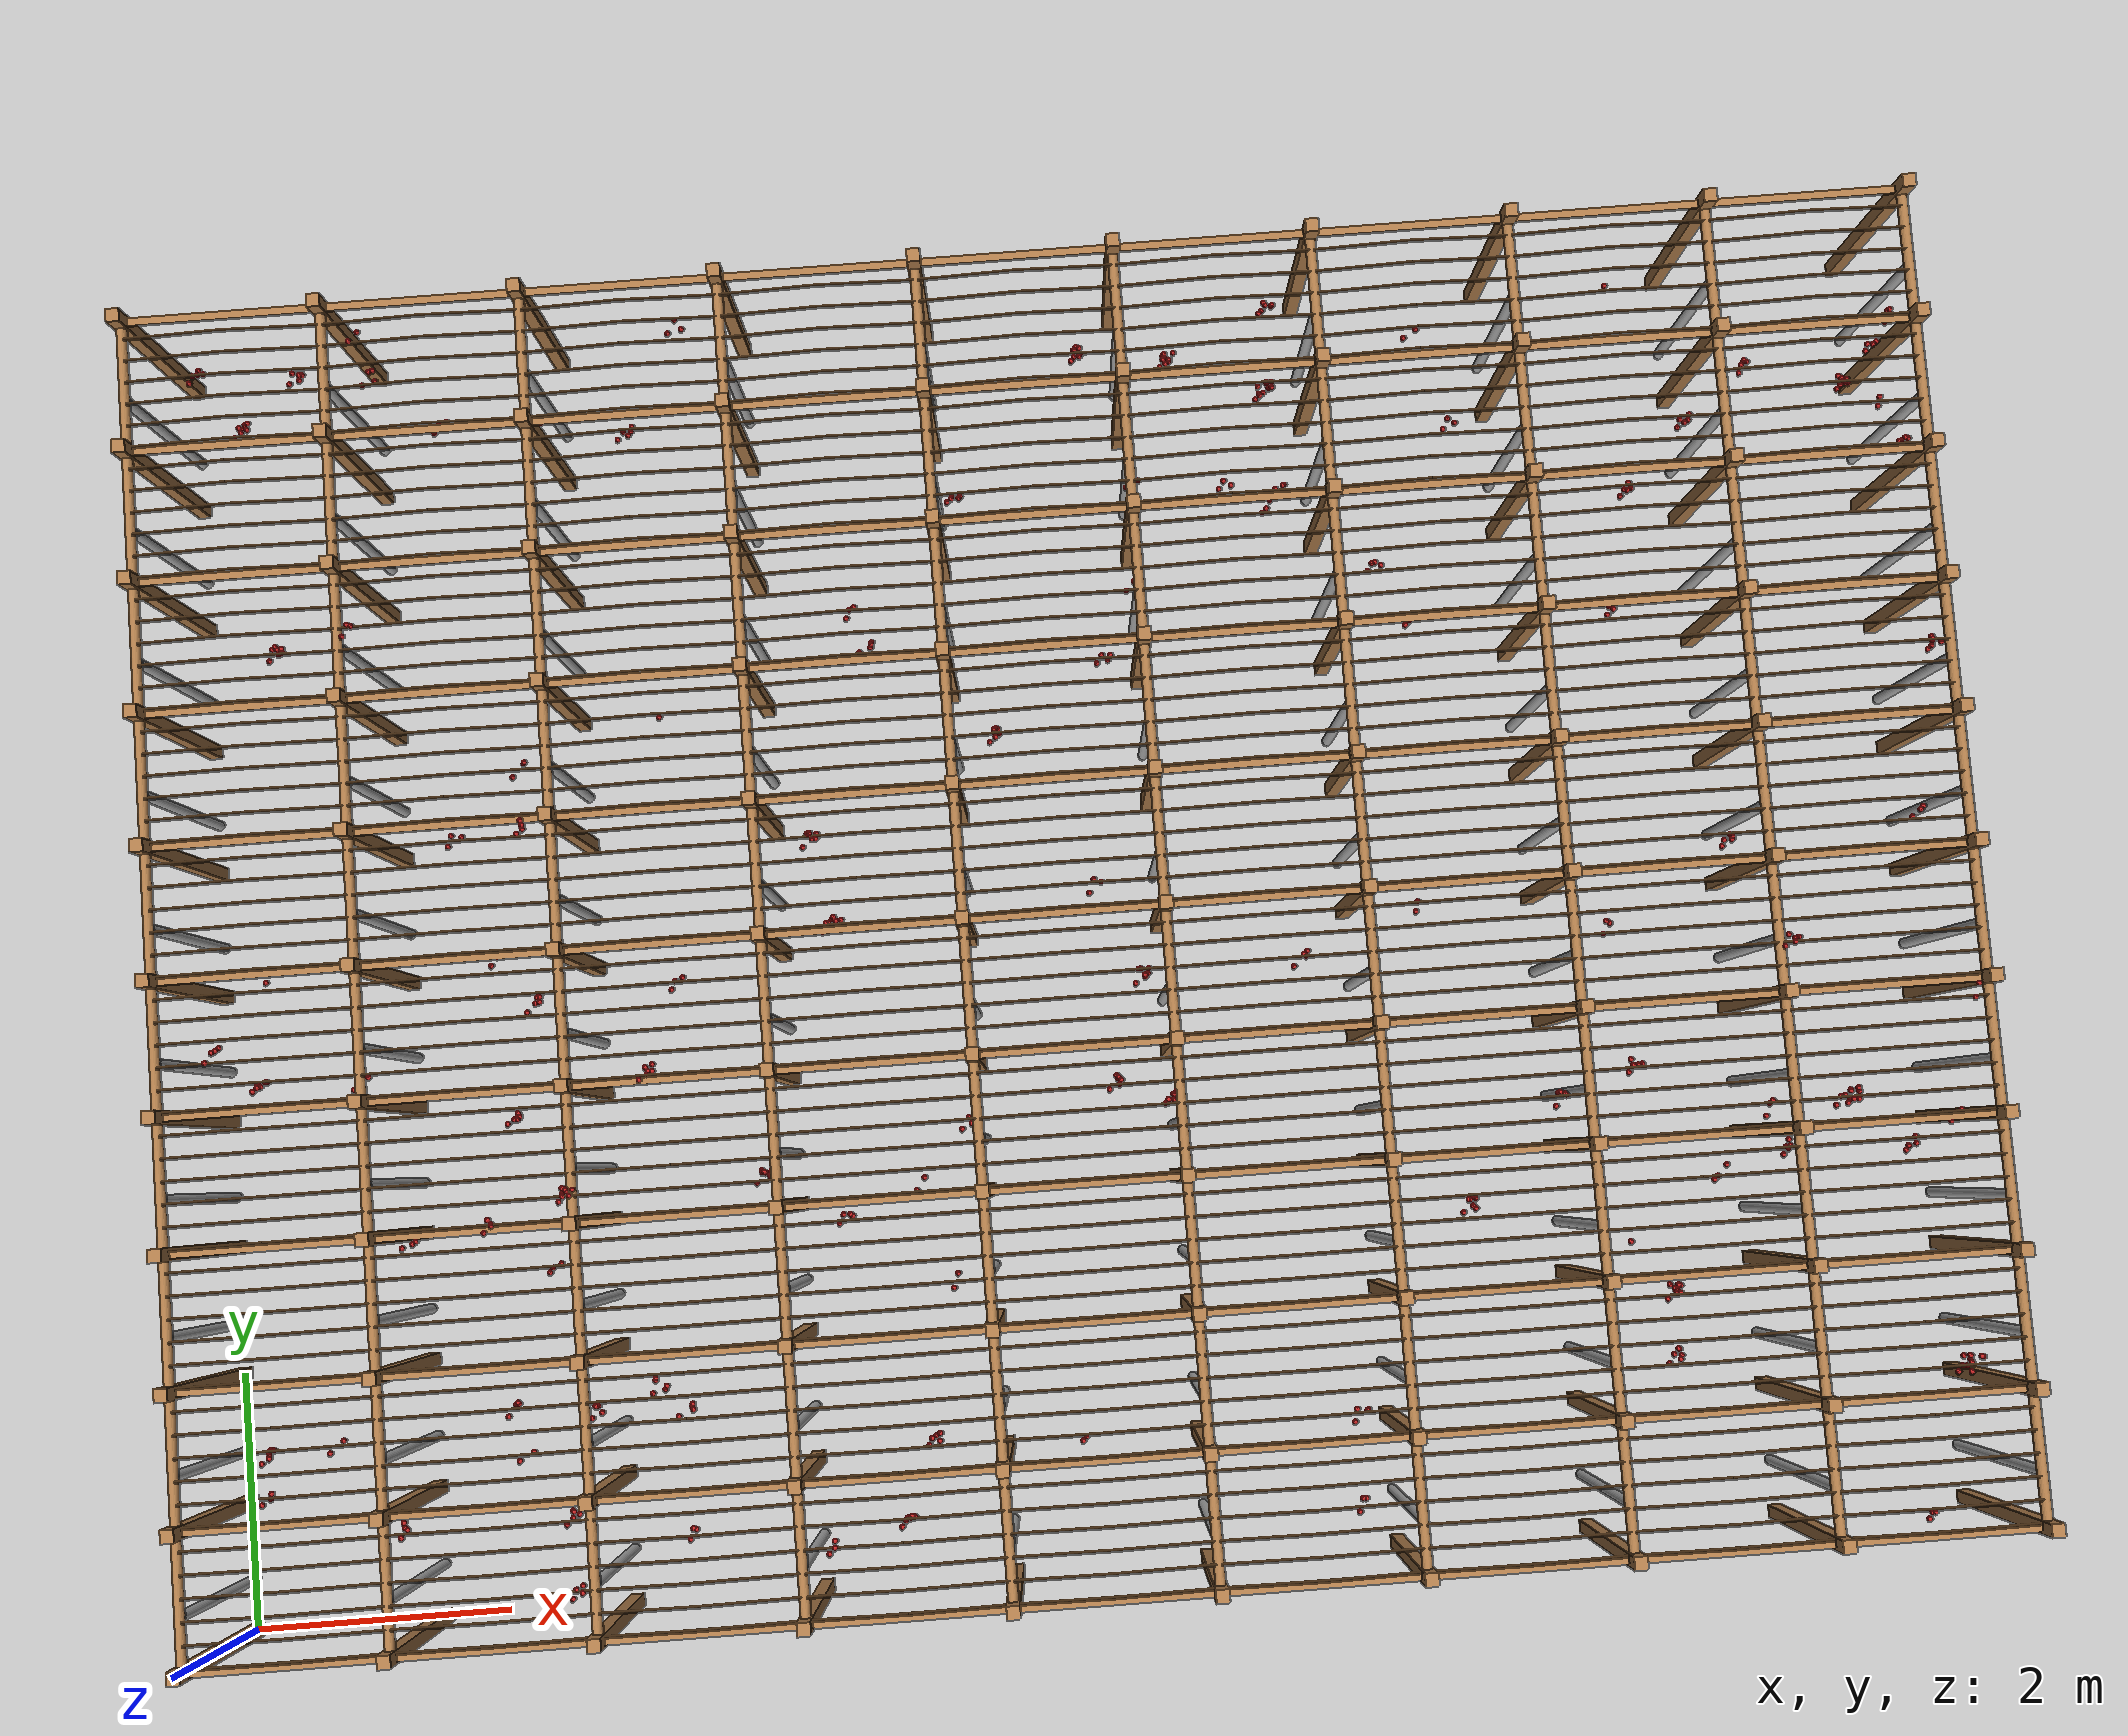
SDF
<?xml version='1.0'?>

<sdf version='1.4'>
  <model name="pergola">

		<include>
			<name>post_0</name>
			<pose>0.0 0.0 0 0 0 0</pose>
			<uri>model://post</uri>
		</include>

		<include>
			<name>post_1</name>
			<pose>0.0 1.0 0 0 0 0</pose>
			<uri>model://post</uri>
		</include>

		<include>
			<name>post_2</name>
			<pose>0.0 2.0 0 0 0 0</pose>
			<uri>model://post</uri>
		</include>

		<include>
			<name>post_3</name>
			<pose>0.0 3.0 0 0 0 0</pose>
			<uri>model://post</uri>
		</include>

		<include>
			<name>post_4</name>
			<pose>0.0 4.0 0 0 0 0</pose>
			<uri>model://post</uri>
		</include>

		<include>
			<name>post_5</name>
			<pose>0.0 5.0 0 0 0 0</pose>
			<uri>model://post</uri>
		</include>

		<include>
			<name>post_6</name>
			<pose>0.0 6.0 0 0 0 0</pose>
			<uri>model://post</uri>
		</include>

		<include>
			<name>post_7</name>
			<pose>0.0 7.0 0 0 0 0</pose>
			<uri>model://post</uri>
		</include>

		<include>
			<name>post_8</name>
			<pose>0.0 8.0 0 0 0 0</pose>
			<uri>model://post</uri>
		</include>

		<include>
			<name>post_9</name>
			<pose>0.0 9.0 0 0 0 0</pose>
			<uri>model://post</uri>
		</include>

		<include>
			<name>post_10</name>
			<pose>0.0 10.0 0 0 0 0</pose>
			<uri>model://post</uri>
		</include>

		<include>
			<name>post_11</name>
			<pose>1.5 0.0 0 0 0 0</pose>
			<uri>model://post</uri>
		</include>

		<include>
			<name>post_12</name>
			<pose>1.5 1.0 0 0 0 0</pose>
			<uri>model://post</uri>
		</include>

		<include>
			<name>post_13</name>
			<pose>1.5 2.0 0 0 0 0</pose>
			<uri>model://post</uri>
		</include>

		<include>
			<name>post_14</name>
			<pose>1.5 3.0 0 0 0 0</pose>
			<uri>model://post</uri>
		</include>

		<include>
			<name>post_15</name>
			<pose>1.5 4.0 0 0 0 0</pose>
			<uri>model://post</uri>
		</include>

		<include>
			<name>post_16</name>
			<pose>1.5 5.0 0 0 0 0</pose>
			<uri>model://post</uri>
		</include>

		<include>
			<name>post_17</name>
			<pose>1.5 6.0 0 0 0 0</pose>
			<uri>model://post</uri>
		</include>

		<include>
			<name>post_18</name>
			<pose>1.5 7.0 0 0 0 0</pose>
			<uri>model://post</uri>
		</include>

		<include>
			<name>post_19</name>
			<pose>1.5 8.0 0 0 0 0</pose>
			<uri>model://post</uri>
		</include>

		<include>
			<name>post_20</name>
			<pose>1.5 9.0 0 0 0 0</pose>
			<uri>model://post</uri>
		</include>

		<include>
			<name>post_21</name>
			<pose>1.5 10.0 0 0 0 0</pose>
			<uri>model://post</uri>
		</include>

		<include>
			<name>post_22</name>
			<pose>3.0 0.0 0 0 0 0</pose>
			<uri>model://post</uri>
		</include>

		<include>
			<name>post_23</name>
			<pose>3.0 1.0 0 0 0 0</pose>
			<uri>model://post</uri>
		</include>

		<include>
			<name>post_24</name>
			<pose>3.0 2.0 0 0 0 0</pose>
			<uri>model://post</uri>
		</include>

		<include>
			<name>post_25</name>
			<pose>3.0 3.0 0 0 0 0</pose>
			<uri>model://post</uri>
		</include>

		<include>
			<name>post_26</name>
			<pose>3.0 4.0 0 0 0 0</pose>
			<uri>model://post</uri>
		</include>

		<include>
			<name>post_27</name>
			<pose>3.0 5.0 0 0 0 0</pose>
			<uri>model://post</uri>
		</include>

		<include>
			<name>post_28</name>
			<pose>3.0 6.0 0 0 0 0</pose>
			<uri>model://post</uri>
		</include>

		<include>
			<name>post_29</name>
			<pose>3.0 7.0 0 0 0 0</pose>
			<uri>model://post</uri>
		</include>

		<include>
			<name>post_30</name>
			<pose>3.0 8.0 0 0 0 0</pose>
			<uri>model://post</uri>
		</include>

		<include>
			<name>post_31</name>
			<pose>3.0 9.0 0 0 0 0</pose>
			<uri>model://post</uri>
		</include>

		<include>
			<name>post_32</name>
			<pose>3.0 10.0 0 0 0 0</pose>
			<uri>model://post</uri>
		</include>

		<include>
			<name>post_33</name>
			<pose>4.5 0.0 0 0 0 0</pose>
			<uri>model://post</uri>
		</include>

		<include>
			<name>post_34</name>
			<pose>4.5 1.0 0 0 0 0</pose>
			<uri>model://post</uri>
		</include>

		<include>
			<name>post_35</name>
			<pose>4.5 2.0 0 0 0 0</pose>
			<uri>model://post</uri>
		</include>

		<include>
			<name>post_36</name>
			<pose>4.5 3.0 0 0 0 0</pose>
			<uri>model://post</uri>
		</include>

		<include>
			<name>post_37</name>
			<pose>4.5 4.0 0 0 0 0</pose>
			<uri>model://post</uri>
		</include>

		<include>
			<name>post_38</name>
			<pose>4.5 5.0 0 0 0 0</pose>
			<uri>model://post</uri>
		</include>

		<include>
			<name>post_39</name>
			<pose>4.5 6.0 0 0 0 0</pose>
			<uri>model://post</uri>
		</include>

		<include>
			<name>post_40</name>
			<pose>4.5 7.0 0 0 0 0</pose>
			<uri>model://post</uri>
		</include>

		<include>
			<name>post_41</name>
			<pose>4.5 8.0 0 0 0 0</pose>
			<uri>model://post</uri>
		</include>

		<include>
			<name>post_42</name>
			<pose>4.5 9.0 0 0 0 0</pose>
			<uri>model://post</uri>
		</include>

		<include>
			<name>post_43</name>
			<pose>4.5 10.0 0 0 0 0</pose>
			<uri>model://post</uri>
		</include>

		<include>
			<name>post_44</name>
			<pose>6.0 0.0 0 0 0 0</pose>
			<uri>model://post</uri>
		</include>

		<include>
			<name>post_45</name>
			<pose>6.0 1.0 0 0 0 0</pose>
			<uri>model://post</uri>
		</include>

		<include>
			<name>post_46</name>
			<pose>6.0 2.0 0 0 0 0</pose>
			<uri>model://post</uri>
		</include>

		<include>
			<name>post_47</name>
			<pose>6.0 3.0 0 0 0 0</pose>
			<uri>model://post</uri>
		</include>

		<include>
			<name>post_48</name>
			<pose>6.0 4.0 0 0 0 0</pose>
			<uri>model://post</uri>
		</include>

		<include>
			<name>post_49</name>
			<pose>6.0 5.0 0 0 0 0</pose>
			<uri>model://post</uri>
		</include>

		<include>
			<name>post_50</name>
			<pose>6.0 6.0 0 0 0 0</pose>
			<uri>model://post</uri>
		</include>

		<include>
			<name>post_51</name>
			<pose>6.0 7.0 0 0 0 0</pose>
			<uri>model://post</uri>
		</include>

		<include>
			<name>post_52</name>
			<pose>6.0 8.0 0 0 0 0</pose>
			<uri>model://post</uri>
		</include>

		<include>
			<name>post_53</name>
			<pose>6.0 9.0 0 0 0 0</pose>
			<uri>model://post</uri>
		</include>

		<include>
			<name>post_54</name>
			<pose>6.0 10.0 0 0 0 0</pose>
			<uri>model://post</uri>
		</include>

		<include>
			<name>post_55</name>
			<pose>7.5 0.0 0 0 0 0</pose>
			<uri>model://post</uri>
		</include>

		<include>
			<name>post_56</name>
			<pose>7.5 1.0 0 0 0 0</pose>
			<uri>model://post</uri>
		</include>

		<include>
			<name>post_57</name>
			<pose>7.5 2.0 0 0 0 0</pose>
			<uri>model://post</uri>
		</include>

		<include>
			<name>post_58</name>
			<pose>7.5 3.0 0 0 0 0</pose>
			<uri>model://post</uri>
		</include>

		<include>
			<name>post_59</name>
			<pose>7.5 4.0 0 0 0 0</pose>
			<uri>model://post</uri>
		</include>

		<include>
			<name>post_60</name>
			<pose>7.5 5.0 0 0 0 0</pose>
			<uri>model://post</uri>
		</include>

		<include>
			<name>post_61</name>
			<pose>7.5 6.0 0 0 0 0</pose>
			<uri>model://post</uri>
		</include>

		<include>
			<name>post_62</name>
			<pose>7.5 7.0 0 0 0 0</pose>
			<uri>model://post</uri>
		</include>

		<include>
			<name>post_63</name>
			<pose>7.5 8.0 0 0 0 0</pose>
			<uri>model://post</uri>
		</include>

		<include>
			<name>post_64</name>
			<pose>7.5 9.0 0 0 0 0</pose>
			<uri>model://post</uri>
		</include>

		<include>
			<name>post_65</name>
			<pose>7.5 10.0 0 0 0 0</pose>
			<uri>model://post</uri>
		</include>

		<include>
			<name>post_66</name>
			<pose>9.0 0.0 0 0 0 0</pose>
			<uri>model://post</uri>
		</include>

		<include>
			<name>post_67</name>
			<pose>9.0 1.0 0 0 0 0</pose>
			<uri>model://post</uri>
		</include>

		<include>
			<name>post_68</name>
			<pose>9.0 2.0 0 0 0 0</pose>
			<uri>model://post</uri>
		</include>

		<include>
			<name>post_69</name>
			<pose>9.0 3.0 0 0 0 0</pose>
			<uri>model://post</uri>
		</include>

		<include>
			<name>post_70</name>
			<pose>9.0 4.0 0 0 0 0</pose>
			<uri>model://post</uri>
		</include>

		<include>
			<name>post_71</name>
			<pose>9.0 5.0 0 0 0 0</pose>
			<uri>model://post</uri>
		</include>

		<include>
			<name>post_72</name>
			<pose>9.0 6.0 0 0 0 0</pose>
			<uri>model://post</uri>
		</include>

		<include>
			<name>post_73</name>
			<pose>9.0 7.0 0 0 0 0</pose>
			<uri>model://post</uri>
		</include>

		<include>
			<name>post_74</name>
			<pose>9.0 8.0 0 0 0 0</pose>
			<uri>model://post</uri>
		</include>

		<include>
			<name>post_75</name>
			<pose>9.0 9.0 0 0 0 0</pose>
			<uri>model://post</uri>
		</include>

		<include>
			<name>post_76</name>
			<pose>9.0 10.0 0 0 0 0</pose>
			<uri>model://post</uri>
		</include>

		<include>
			<name>post_77</name>
			<pose>10.5 0.0 0 0 0 0</pose>
			<uri>model://post</uri>
		</include>

		<include>
			<name>post_78</name>
			<pose>10.5 1.0 0 0 0 0</pose>
			<uri>model://post</uri>
		</include>

		<include>
			<name>post_79</name>
			<pose>10.5 2.0 0 0 0 0</pose>
			<uri>model://post</uri>
		</include>

		<include>
			<name>post_80</name>
			<pose>10.5 3.0 0 0 0 0</pose>
			<uri>model://post</uri>
		</include>

		<include>
			<name>post_81</name>
			<pose>10.5 4.0 0 0 0 0</pose>
			<uri>model://post</uri>
		</include>

		<include>
			<name>post_82</name>
			<pose>10.5 5.0 0 0 0 0</pose>
			<uri>model://post</uri>
		</include>

		<include>
			<name>post_83</name>
			<pose>10.5 6.0 0 0 0 0</pose>
			<uri>model://post</uri>
		</include>

		<include>
			<name>post_84</name>
			<pose>10.5 7.0 0 0 0 0</pose>
			<uri>model://post</uri>
		</include>

		<include>
			<name>post_85</name>
			<pose>10.5 8.0 0 0 0 0</pose>
			<uri>model://post</uri>
		</include>

		<include>
			<name>post_86</name>
			<pose>10.5 9.0 0 0 0 0</pose>
			<uri>model://post</uri>
		</include>

		<include>
			<name>post_87</name>
			<pose>10.5 10.0 0 0 0 0</pose>
			<uri>model://post</uri>
		</include>

		<include>
			<name>post_88</name>
			<pose>12.0 0.0 0 0 0 0</pose>
			<uri>model://post</uri>
		</include>

		<include>
			<name>post_89</name>
			<pose>12.0 1.0 0 0 0 0</pose>
			<uri>model://post</uri>
		</include>

		<include>
			<name>post_90</name>
			<pose>12.0 2.0 0 0 0 0</pose>
			<uri>model://post</uri>
		</include>

		<include>
			<name>post_91</name>
			<pose>12.0 3.0 0 0 0 0</pose>
			<uri>model://post</uri>
		</include>

		<include>
			<name>post_92</name>
			<pose>12.0 4.0 0 0 0 0</pose>
			<uri>model://post</uri>
		</include>

		<include>
			<name>post_93</name>
			<pose>12.0 5.0 0 0 0 0</pose>
			<uri>model://post</uri>
		</include>

		<include>
			<name>post_94</name>
			<pose>12.0 6.0 0 0 0 0</pose>
			<uri>model://post</uri>
		</include>

		<include>
			<name>post_95</name>
			<pose>12.0 7.0 0 0 0 0</pose>
			<uri>model://post</uri>
		</include>

		<include>
			<name>post_96</name>
			<pose>12.0 8.0 0 0 0 0</pose>
			<uri>model://post</uri>
		</include>

		<include>
			<name>post_97</name>
			<pose>12.0 9.0 0 0 0 0</pose>
			<uri>model://post</uri>
		</include>

		<include>
			<name>post_98</name>
			<pose>12.0 10.0 0 0 0 0</pose>
			<uri>model://post</uri>
		</include>

		<include>
			<name>post_99</name>
			<pose>13.5 0.0 0 0 0 0</pose>
			<uri>model://post</uri>
		</include>

		<include>
			<name>post_100</name>
			<pose>13.5 1.0 0 0 0 0</pose>
			<uri>model://post</uri>
		</include>

		<include>
			<name>post_101</name>
			<pose>13.5 2.0 0 0 0 0</pose>
			<uri>model://post</uri>
		</include>

		<include>
			<name>post_102</name>
			<pose>13.5 3.0 0 0 0 0</pose>
			<uri>model://post</uri>
		</include>

		<include>
			<name>post_103</name>
			<pose>13.5 4.0 0 0 0 0</pose>
			<uri>model://post</uri>
		</include>

		<include>
			<name>post_104</name>
			<pose>13.5 5.0 0 0 0 0</pose>
			<uri>model://post</uri>
		</include>

		<include>
			<name>post_105</name>
			<pose>13.5 6.0 0 0 0 0</pose>
			<uri>model://post</uri>
		</include>

		<include>
			<name>post_106</name>
			<pose>13.5 7.0 0 0 0 0</pose>
			<uri>model://post</uri>
		</include>

		<include>
			<name>post_107</name>
			<pose>13.5 8.0 0 0 0 0</pose>
			<uri>model://post</uri>
		</include>

		<include>
			<name>post_108</name>
			<pose>13.5 9.0 0 0 0 0</pose>
			<uri>model://post</uri>
		</include>

		<include>
			<name>post_109</name>
			<pose>13.5 10.0 0 0 0 0</pose>
			<uri>model://post</uri>
		</include>

    <link name="beam_0">
      <pose>0.75 0.0 1.81 0 0 0</pose>
      <collision name="collision">
        <geometry><box><size>1.5 0.06 0.02</size></box></geometry>
      </collision>
      <visual name="visual">
        <geometry><box><size>1.5 0.06 0.02</size></box></geometry>
        <material><script><name>Gazebo/Wood</name></script></material>
      </visual>
    <inertial>
      <pose>0 0 0 0 0 0</pose>
      <mass>5</mass>
      <inertia>
        <ixx>0.0016666666666666668</ixx><ixy>0.0</ixy><ixz>0.0</ixz><iyy>0.9390000000000001</iyy><iyz>0.0</iyz><izz>0.9376666666666665</izz>
      </inertia>
    </inertial>
    </link>

    <link name="beam_1">
      <pose>0.75 1.0 1.81 0 0 0</pose>
      <collision name="collision">
        <geometry><box><size>1.5 0.06 0.02</size></box></geometry>
      </collision>
      <visual name="visual">
        <geometry><box><size>1.5 0.06 0.02</size></box></geometry>
        <material><script><name>Gazebo/Wood</name></script></material>
      </visual>
    <inertial>
      <pose>0 0 0 0 0 0</pose>
      <mass>5</mass>
      <inertia>
        <ixx>0.0016666666666666668</ixx><ixy>0.0</ixy><ixz>0.0</ixz><iyy>0.9390000000000001</iyy><iyz>0.0</iyz><izz>0.9376666666666665</izz>
      </inertia>
    </inertial>
    </link>

    <link name="beam_2">
      <pose>0.75 2.0 1.81 0 0 0</pose>
      <collision name="collision">
        <geometry><box><size>1.5 0.06 0.02</size></box></geometry>
      </collision>
      <visual name="visual">
        <geometry><box><size>1.5 0.06 0.02</size></box></geometry>
        <material><script><name>Gazebo/Wood</name></script></material>
      </visual>
    <inertial>
      <pose>0 0 0 0 0 0</pose>
      <mass>5</mass>
      <inertia>
        <ixx>0.0016666666666666668</ixx><ixy>0.0</ixy><ixz>0.0</ixz><iyy>0.9390000000000001</iyy><iyz>0.0</iyz><izz>0.9376666666666665</izz>
      </inertia>
    </inertial>
    </link>

    <link name="beam_3">
      <pose>0.75 3.0 1.81 0 0 0</pose>
      <collision name="collision">
        <geometry><box><size>1.5 0.06 0.02</size></box></geometry>
      </collision>
      <visual name="visual">
        <geometry><box><size>1.5 0.06 0.02</size></box></geometry>
        <material><script><name>Gazebo/Wood</name></script></material>
      </visual>
    <inertial>
      <pose>0 0 0 0 0 0</pose>
      <mass>5</mass>
      <inertia>
        <ixx>0.0016666666666666668</ixx><ixy>0.0</ixy><ixz>0.0</ixz><iyy>0.9390000000000001</iyy><iyz>0.0</iyz><izz>0.9376666666666665</izz>
      </inertia>
    </inertial>
    </link>

    <link name="beam_4">
      <pose>0.75 4.0 1.81 0 0 0</pose>
      <collision name="collision">
        <geometry><box><size>1.5 0.06 0.02</size></box></geometry>
      </collision>
      <visual name="visual">
        <geometry><box><size>1.5 0.06 0.02</size></box></geometry>
        <material><script><name>Gazebo/Wood</name></script></material>
      </visual>
    <inertial>
      <pose>0 0 0 0 0 0</pose>
      <mass>5</mass>
      <inertia>
        <ixx>0.0016666666666666668</ixx><ixy>0.0</ixy><ixz>0.0</ixz><iyy>0.9390000000000001</iyy><iyz>0.0</iyz><izz>0.9376666666666665</izz>
      </inertia>
    </inertial>
    </link>

    <link name="beam_5">
      <pose>0.75 5.0 1.81 0 0 0</pose>
      <collision name="collision">
        <geometry><box><size>1.5 0.06 0.02</size></box></geometry>
      </collision>
      <visual name="visual">
        <geometry><box><size>1.5 0.06 0.02</size></box></geometry>
        <material><script><name>Gazebo/Wood</name></script></material>
      </visual>
    <inertial>
      <pose>0 0 0 0 0 0</pose>
      <mass>5</mass>
      <inertia>
        <ixx>0.0016666666666666668</ixx><ixy>0.0</ixy><ixz>0.0</ixz><iyy>0.9390000000000001</iyy><iyz>0.0</iyz><izz>0.9376666666666665</izz>
      </inertia>
    </inertial>
    </link>

    <link name="beam_6">
      <pose>0.75 6.0 1.81 0 0 0</pose>
      <collision name="collision">
        <geometry><box><size>1.5 0.06 0.02</size></box></geometry>
      </collision>
      <visual name="visual">
        <geometry><box><size>1.5 0.06 0.02</size></box></geometry>
        <material><script><name>Gazebo/Wood</name></script></material>
      </visual>
    <inertial>
      <pose>0 0 0 0 0 0</pose>
      <mass>5</mass>
      <inertia>
        <ixx>0.0016666666666666668</ixx><ixy>0.0</ixy><ixz>0.0</ixz><iyy>0.9390000000000001</iyy><iyz>0.0</iyz><izz>0.9376666666666665</izz>
      </inertia>
    </inertial>
    </link>

    <link name="beam_7">
      <pose>0.75 7.0 1.81 0 0 0</pose>
      <collision name="collision">
        <geometry><box><size>1.5 0.06 0.02</size></box></geometry>
      </collision>
      <visual name="visual">
        <geometry><box><size>1.5 0.06 0.02</size></box></geometry>
        <material><script><name>Gazebo/Wood</name></script></material>
      </visual>
    <inertial>
      <pose>0 0 0 0 0 0</pose>
      <mass>5</mass>
      <inertia>
        <ixx>0.0016666666666666668</ixx><ixy>0.0</ixy><ixz>0.0</ixz><iyy>0.9390000000000001</iyy><iyz>0.0</iyz><izz>0.9376666666666665</izz>
      </inertia>
    </inertial>
    </link>

    <link name="beam_8">
      <pose>0.75 8.0 1.81 0 0 0</pose>
      <collision name="collision">
        <geometry><box><size>1.5 0.06 0.02</size></box></geometry>
      </collision>
      <visual name="visual">
        <geometry><box><size>1.5 0.06 0.02</size></box></geometry>
        <material><script><name>Gazebo/Wood</name></script></material>
      </visual>
    <inertial>
      <pose>0 0 0 0 0 0</pose>
      <mass>5</mass>
      <inertia>
        <ixx>0.0016666666666666668</ixx><ixy>0.0</ixy><ixz>0.0</ixz><iyy>0.9390000000000001</iyy><iyz>0.0</iyz><izz>0.9376666666666665</izz>
      </inertia>
    </inertial>
    </link>

    <link name="beam_9">
      <pose>0.75 9.0 1.81 0 0 0</pose>
      <collision name="collision">
        <geometry><box><size>1.5 0.06 0.02</size></box></geometry>
      </collision>
      <visual name="visual">
        <geometry><box><size>1.5 0.06 0.02</size></box></geometry>
        <material><script><name>Gazebo/Wood</name></script></material>
      </visual>
    <inertial>
      <pose>0 0 0 0 0 0</pose>
      <mass>5</mass>
      <inertia>
        <ixx>0.0016666666666666668</ixx><ixy>0.0</ixy><ixz>0.0</ixz><iyy>0.9390000000000001</iyy><iyz>0.0</iyz><izz>0.9376666666666665</izz>
      </inertia>
    </inertial>
    </link>

    <link name="beam_10">
      <pose>0.75 10.0 1.81 0 0 0</pose>
      <collision name="collision">
        <geometry><box><size>1.5 0.06 0.02</size></box></geometry>
      </collision>
      <visual name="visual">
        <geometry><box><size>1.5 0.06 0.02</size></box></geometry>
        <material><script><name>Gazebo/Wood</name></script></material>
      </visual>
    <inertial>
      <pose>0 0 0 0 0 0</pose>
      <mass>5</mass>
      <inertia>
        <ixx>0.0016666666666666668</ixx><ixy>0.0</ixy><ixz>0.0</ixz><iyy>0.9390000000000001</iyy><iyz>0.0</iyz><izz>0.9376666666666665</izz>
      </inertia>
    </inertial>
    </link>

    <link name="beam_11">
      <pose>2.25 0.0 1.81 0 0 0</pose>
      <collision name="collision">
        <geometry><box><size>1.5 0.06 0.02</size></box></geometry>
      </collision>
      <visual name="visual">
        <geometry><box><size>1.5 0.06 0.02</size></box></geometry>
        <material><script><name>Gazebo/Wood</name></script></material>
      </visual>
    <inertial>
      <pose>0 0 0 0 0 0</pose>
      <mass>5</mass>
      <inertia>
        <ixx>0.0016666666666666668</ixx><ixy>0.0</ixy><ixz>0.0</ixz><iyy>0.9390000000000001</iyy><iyz>0.0</iyz><izz>0.9376666666666665</izz>
      </inertia>
    </inertial>
    </link>

    <link name="beam_12">
      <pose>2.25 1.0 1.81 0 0 0</pose>
      <collision name="collision">
        <geometry><box><size>1.5 0.06 0.02</size></box></geometry>
      </collision>
      <visual name="visual">
        <geometry><box><size>1.5 0.06 0.02</size></box></geometry>
        <material><script><name>Gazebo/Wood</name></script></material>
      </visual>
    <inertial>
      <pose>0 0 0 0 0 0</pose>
      <mass>5</mass>
      <inertia>
        <ixx>0.0016666666666666668</ixx><ixy>0.0</ixy><ixz>0.0</ixz><iyy>0.9390000000000001</iyy><iyz>0.0</iyz><izz>0.9376666666666665</izz>
      </inertia>
    </inertial>
    </link>

    <link name="beam_13">
      <pose>2.25 2.0 1.81 0 0 0</pose>
      <collision name="collision">
        <geometry><box><size>1.5 0.06 0.02</size></box></geometry>
      </collision>
      <visual name="visual">
        <geometry><box><size>1.5 0.06 0.02</size></box></geometry>
        <material><script><name>Gazebo/Wood</name></script></material>
      </visual>
    <inertial>
      <pose>0 0 0 0 0 0</pose>
      <mass>5</mass>
      <inertia>
        <ixx>0.0016666666666666668</ixx><ixy>0.0</ixy><ixz>0.0</ixz><iyy>0.9390000000000001</iyy><iyz>0.0</iyz><izz>0.9376666666666665</izz>
      </inertia>
    </inertial>
    </link>

    <link name="beam_14">
      <pose>2.25 3.0 1.81 0 0 0</pose>
      <collision name="collision">
        <geometry><box><size>1.5 0.06 0.02</size></box></geometry>
      </collision>
      <visual name="visual">
        <geometry><box><size>1.5 0.06 0.02</size></box></geometry>
        <material><script><name>Gazebo/Wood</name></script></material>
      </visual>
    <inertial>
      <pose>0 0 0 0 0 0</pose>
      <mass>5</mass>
      <inertia>
        <ixx>0.0016666666666666668</ixx><ixy>0.0</ixy><ixz>0.0</ixz><iyy>0.9390000000000001</iyy><iyz>0.0</iyz><izz>0.9376666666666665</izz>
      </inertia>
    </inertial>
    </link>

    <link name="beam_15">
      <pose>2.25 4.0 1.81 0 0 0</pose>
      <collision name="collision">
        <geometry><box><size>1.5 0.06 0.02</size></box></geometry>
      </collision>
      <visual name="visual">
        <geometry><box><size>1.5 0.06 0.02</size></box></geometry>
        <material><script><name>Gazebo/Wood</name></script></material>
      </visual>
    <inertial>
      <pose>0 0 0 0 0 0</pose>
      <mass>5</mass>
      <inertia>
        <ixx>0.0016666666666666668</ixx><ixy>0.0</ixy><ixz>0.0</ixz><iyy>0.9390000000000001</iyy><iyz>0.0</iyz><izz>0.9376666666666665</izz>
      </inertia>
    </inertial>
    </link>

    <link name="beam_16">
      <pose>2.25 5.0 1.81 0 0 0</pose>
      <collision name="collision">
        <geometry><box><size>1.5 0.06 0.02</size></box></geometry>
      </collision>
      <visual name="visual">
        <geometry><box><size>1.5 0.06 0.02</size></box></geometry>
        <material><script><name>Gazebo/Wood</name></script></material>
      </visual>
    <inertial>
      <pose>0 0 0 0 0 0</pose>
      <mass>5</mass>
      <inertia>
        <ixx>0.0016666666666666668</ixx><ixy>0.0</ixy><ixz>0.0</ixz><iyy>0.9390000000000001</iyy><iyz>0.0</iyz><izz>0.9376666666666665</izz>
      </inertia>
    </inertial>
    </link>

    <link name="beam_17">
      <pose>2.25 6.0 1.81 0 0 0</pose>
      <collision name="collision">
        <geometry><box><size>1.5 0.06 0.02</size></box></geometry>
      </collision>
      <visual name="visual">
        <geometry><box><size>1.5 0.06 0.02</size></box></geometry>
        <material><script><name>Gazebo/Wood</name></script></material>
      </visual>
    <inertial>
      <pose>0 0 0 0 0 0</pose>
      <mass>5</mass>
      <inertia>
        <ixx>0.0016666666666666668</ixx><ixy>0.0</ixy><ixz>0.0</ixz><iyy>0.9390000000000001</iyy><iyz>0.0</iyz><izz>0.9376666666666665</izz>
      </inertia>
    </inertial>
    </link>

    <link name="beam_18">
      <pose>2.25 7.0 1.81 0 0 0</pose>
      <collision name="collision">
        <geometry><box><size>1.5 0.06 0.02</size></box></geometry>
      </collision>
      <visual name="visual">
        <geometry><box><size>1.5 0.06 0.02</size></box></geometry>
        <material><script><name>Gazebo/Wood</name></script></material>
      </visual>
    <inertial>
      <pose>0 0 0 0 0 0</pose>
      <mass>5</mass>
      <inertia>
        <ixx>0.0016666666666666668</ixx><ixy>0.0</ixy><ixz>0.0</ixz><iyy>0.9390000000000001</iyy><iyz>0.0</iyz><izz>0.9376666666666665</izz>
      </inertia>
    </inertial>
    </link>

    <link name="beam_19">
      <pose>2.25 8.0 1.81 0 0 0</pose>
      <collision name="collision">
        <geometry><box><size>1.5 0.06 0.02</size></box></geometry>
      </collision>
      <visual name="visual">
        <geometry><box><size>1.5 0.06 0.02</size></box></geometry>
        <material><script><name>Gazebo/Wood</name></script></material>
      </visual>
    <inertial>
      <pose>0 0 0 0 0 0</pose>
      <mass>5</mass>
      <inertia>
        <ixx>0.0016666666666666668</ixx><ixy>0.0</ixy><ixz>0.0</ixz><iyy>0.9390000000000001</iyy><iyz>0.0</iyz><izz>0.9376666666666665</izz>
      </inertia>
    </inertial>
    </link>

    <link name="beam_20">
      <pose>2.25 9.0 1.81 0 0 0</pose>
      <collision name="collision">
        <geometry><box><size>1.5 0.06 0.02</size></box></geometry>
      </collision>
      <visual name="visual">
        <geometry><box><size>1.5 0.06 0.02</size></box></geometry>
        <material><script><name>Gazebo/Wood</name></script></material>
      </visual>
    <inertial>
      <pose>0 0 0 0 0 0</pose>
      <mass>5</mass>
      <inertia>
        <ixx>0.0016666666666666668</ixx><ixy>0.0</ixy><ixz>0.0</ixz><iyy>0.9390000000000001</iyy><iyz>0.0</iyz><izz>0.9376666666666665</izz>
      </inertia>
    </inertial>
    </link>

    <link name="beam_21">
      <pose>2.25 10.0 1.81 0 0 0</pose>
      <collision name="collision">
        <geometry><box><size>1.5 0.06 0.02</size></box></geometry>
      </collision>
      <visual name="visual">
        <geometry><box><size>1.5 0.06 0.02</size></box></geometry>
        <material><script><name>Gazebo/Wood</name></script></material>
      </visual>
    <inertial>
      <pose>0 0 0 0 0 0</pose>
      <mass>5</mass>
      <inertia>
        <ixx>0.0016666666666666668</ixx><ixy>0.0</ixy><ixz>0.0</ixz><iyy>0.9390000000000001</iyy><iyz>0.0</iyz><izz>0.9376666666666665</izz>
      </inertia>
    </inertial>
    </link>

    <link name="beam_22">
      <pose>3.75 0.0 1.81 0 0 0</pose>
      <collision name="collision">
        <geometry><box><size>1.5 0.06 0.02</size></box></geometry>
      </collision>
      <visual name="visual">
        <geometry><box><size>1.5 0.06 0.02</size></box></geometry>
        <material><script><name>Gazebo/Wood</name></script></material>
      </visual>
    <inertial>
      <pose>0 0 0 0 0 0</pose>
      <mass>5</mass>
      <inertia>
        <ixx>0.0016666666666666668</ixx><ixy>0.0</ixy><ixz>0.0</ixz><iyy>0.9390000000000001</iyy><iyz>0.0</iyz><izz>0.9376666666666665</izz>
      </inertia>
    </inertial>
    </link>

    <link name="beam_23">
      <pose>3.75 1.0 1.81 0 0 0</pose>
      <collision name="collision">
        <geometry><box><size>1.5 0.06 0.02</size></box></geometry>
      </collision>
      <visual name="visual">
        <geometry><box><size>1.5 0.06 0.02</size></box></geometry>
        <material><script><name>Gazebo/Wood</name></script></material>
      </visual>
    <inertial>
      <pose>0 0 0 0 0 0</pose>
      <mass>5</mass>
      <inertia>
        <ixx>0.0016666666666666668</ixx><ixy>0.0</ixy><ixz>0.0</ixz><iyy>0.9390000000000001</iyy><iyz>0.0</iyz><izz>0.9376666666666665</izz>
      </inertia>
    </inertial>
    </link>

    <link name="beam_24">
      <pose>3.75 2.0 1.81 0 0 0</pose>
      <collision name="collision">
        <geometry><box><size>1.5 0.06 0.02</size></box></geometry>
      </collision>
      <visual name="visual">
        <geometry><box><size>1.5 0.06 0.02</size></box></geometry>
        <material><script><name>Gazebo/Wood</name></script></material>
      </visual>
    <inertial>
      <pose>0 0 0 0 0 0</pose>
      <mass>5</mass>
      <inertia>
        <ixx>0.0016666666666666668</ixx><ixy>0.0</ixy><ixz>0.0</ixz><iyy>0.9390000000000001</iyy><iyz>0.0</iyz><izz>0.9376666666666665</izz>
      </inertia>
    </inertial>
    </link>

    <link name="beam_25">
      <pose>3.75 3.0 1.81 0 0 0</pose>
      <collision name="collision">
        <geometry><box><size>1.5 0.06 0.02</size></box></geometry>
      </collision>
      <visual name="visual">
        <geometry><box><size>1.5 0.06 0.02</size></box></geometry>
        <material><script><name>Gazebo/Wood</name></script></material>
      </visual>
    <inertial>
      <pose>0 0 0 0 0 0</pose>
      <mass>5</mass>
      <inertia>
        <ixx>0.0016666666666666668</ixx><ixy>0.0</ixy><ixz>0.0</ixz><iyy>0.9390000000000001</iyy><iyz>0.0</iyz><izz>0.9376666666666665</izz>
      </inertia>
    </inertial>
    </link>

    <link name="beam_26">
      <pose>3.75 4.0 1.81 0 0 0</pose>
      <collision name="collision">
        <geometry><box><size>1.5 0.06 0.02</size></box></geometry>
      </collision>
      <visual name="visual">
        <geometry><box><size>1.5 0.06 0.02</size></box></geometry>
        <material><script><name>Gazebo/Wood</name></script></material>
      </visual>
    <inertial>
      <pose>0 0 0 0 0 0</pose>
      <mass>5</mass>
      <inertia>
        <ixx>0.0016666666666666668</ixx><ixy>0.0</ixy><ixz>0.0</ixz><iyy>0.9390000000000001</iyy><iyz>0.0</iyz><izz>0.9376666666666665</izz>
      </inertia>
    </inertial>
    </link>

    <link name="beam_27">
      <pose>3.75 5.0 1.81 0 0 0</pose>
      <collision name="collision">
        <geometry><box><size>1.5 0.06 0.02</size></box></geometry>
      </collision>
      <visual name="visual">
        <geometry><box><size>1.5 0.06 0.02</size></box></geometry>
        <material><script><name>Gazebo/Wood</name></script></material>
      </visual>
    <inertial>
      <pose>0 0 0 0 0 0</pose>
      <mass>5</mass>
      <inertia>
        <ixx>0.0016666666666666668</ixx><ixy>0.0</ixy><ixz>0.0</ixz><iyy>0.9390000000000001</iyy><iyz>0.0</iyz><izz>0.9376666666666665</izz>
      </inertia>
    </inertial>
    </link>

    <link name="beam_28">
      <pose>3.75 6.0 1.81 0 0 0</pose>
      <collision name="collision">
        <geometry><box><size>1.5 0.06 0.02</size></box></geometry>
      </collision>
      <visual name="visual">
        <geometry><box><size>1.5 0.06 0.02</size></box></geometry>
        <material><script><name>Gazebo/Wood</name></script></material>
      </visual>
    <inertial>
      <pose>0 0 0 0 0 0</pose>
      <mass>5</mass>
      <inertia>
        <ixx>0.0016666666666666668</ixx><ixy>0.0</ixy><ixz>0.0</ixz><iyy>0.9390000000000001</iyy><iyz>0.0</iyz><izz>0.9376666666666665</izz>
      </inertia>
    </inertial>
    </link>

    <link name="beam_29">
      <pose>3.75 7.0 1.81 0 0 0</pose>
      <collision name="collision">
        <geometry><box><size>1.5 0.06 0.02</size></box></geometry>
      </collision>
      <visual name="visual">
        <geometry><box><size>1.5 0.06 0.02</size></box></geometry>
        <material><script><name>Gazebo/Wood</name></script></material>
      </visual>
    <inertial>
      <pose>0 0 0 0 0 0</pose>
      <mass>5</mass>
      <inertia>
        <ixx>0.0016666666666666668</ixx><ixy>0.0</ixy><ixz>0.0</ixz><iyy>0.9390000000000001</iyy><iyz>0.0</iyz><izz>0.9376666666666665</izz>
      </inertia>
    </inertial>
    </link>

    <link name="beam_30">
      <pose>3.75 8.0 1.81 0 0 0</pose>
      <collision name="collision">
        <geometry><box><size>1.5 0.06 0.02</size></box></geometry>
      </collision>
      <visual name="visual">
        <geometry><box><size>1.5 0.06 0.02</size></box></geometry>
        <material><script><name>Gazebo/Wood</name></script></material>
      </visual>
    <inertial>
      <pose>0 0 0 0 0 0</pose>
      <mass>5</mass>
      <inertia>
        <ixx>0.0016666666666666668</ixx><ixy>0.0</ixy><ixz>0.0</ixz><iyy>0.9390000000000001</iyy><iyz>0.0</iyz><izz>0.9376666666666665</izz>
      </inertia>
    </inertial>
    </link>

    <link name="beam_31">
      <pose>3.75 9.0 1.81 0 0 0</pose>
      <collision name="collision">
        <geometry><box><size>1.5 0.06 0.02</size></box></geometry>
      </collision>
      <visual name="visual">
        <geometry><box><size>1.5 0.06 0.02</size></box></geometry>
        <material><script><name>Gazebo/Wood</name></script></material>
      </visual>
    <inertial>
      <pose>0 0 0 0 0 0</pose>
      <mass>5</mass>
      <inertia>
        <ixx>0.0016666666666666668</ixx><ixy>0.0</ixy><ixz>0.0</ixz><iyy>0.9390000000000001</iyy><iyz>0.0</iyz><izz>0.9376666666666665</izz>
      </inertia>
    </inertial>
    </link>

    <link name="beam_32">
      <pose>3.75 10.0 1.81 0 0 0</pose>
      <collision name="collision">
        <geometry><box><size>1.5 0.06 0.02</size></box></geometry>
      </collision>
      <visual name="visual">
        <geometry><box><size>1.5 0.06 0.02</size></box></geometry>
        <material><script><name>Gazebo/Wood</name></script></material>
      </visual>
    <inertial>
      <pose>0 0 0 0 0 0</pose>
      <mass>5</mass>
      <inertia>
        <ixx>0.0016666666666666668</ixx><ixy>0.0</ixy><ixz>0.0</ixz><iyy>0.9390000000000001</iyy><iyz>0.0</iyz><izz>0.9376666666666665</izz>
      </inertia>
    </inertial>
    </link>

    <link name="beam_33">
      <pose>5.25 0.0 1.81 0 0 0</pose>
      <collision name="collision">
        <geometry><box><size>1.5 0.06 0.02</size></box></geometry>
      </collision>
      <visual name="visual">
        <geometry><box><size>1.5 0.06 0.02</size></box></geometry>
        <material><script><name>Gazebo/Wood</name></script></material>
      </visual>
    <inertial>
      <pose>0 0 0 0 0 0</pose>
      <mass>5</mass>
      <inertia>
        <ixx>0.0016666666666666668</ixx><ixy>0.0</ixy><ixz>0.0</ixz><iyy>0.9390000000000001</iyy><iyz>0.0</iyz><izz>0.9376666666666665</izz>
      </inertia>
    </inertial>
    </link>

    <link name="beam_34">
      <pose>5.25 1.0 1.81 0 0 0</pose>
      <collision name="collision">
        <geometry><box><size>1.5 0.06 0.02</size></box></geometry>
      </collision>
      <visual name="visual">
        <geometry><box><size>1.5 0.06 0.02</size></box></geometry>
        <material><script><name>Gazebo/Wood</name></script></material>
      </visual>
    <inertial>
      <pose>0 0 0 0 0 0</pose>
      <mass>5</mass>
      <inertia>
        <ixx>0.0016666666666666668</ixx><ixy>0.0</ixy><ixz>0.0</ixz><iyy>0.9390000000000001</iyy><iyz>0.0</iyz><izz>0.9376666666666665</izz>
      </inertia>
    </inertial>
    </link>

    <link name="beam_35">
      <pose>5.25 2.0 1.81 0 0 0</pose>
      <collision name="collision">
        <geometry><box><size>1.5 0.06 0.02</size></box></geometry>
      </collision>
      <visual name="visual">
        <geometry><box><size>1.5 0.06 0.02</size></box></geometry>
        <material><script><name>Gazebo/Wood</name></script></material>
      </visual>
    <inertial>
      <pose>0 0 0 0 0 0</pose>
      <mass>5</mass>
      <inertia>
        <ixx>0.0016666666666666668</ixx><ixy>0.0</ixy><ixz>0.0</ixz><iyy>0.9390000000000001</iyy><iyz>0.0</iyz><izz>0.9376666666666665</izz>
      </inertia>
    </inertial>
    </link>

    <link name="beam_36">
      <pose>5.25 3.0 1.81 0 0 0</pose>
      <collision name="collision">
        <geometry><box><size>1.5 0.06 0.02</size></box></geometry>
      </collision>
      <visual name="visual">
        <geometry><box><size>1.5 0.06 0.02</size></box></geometry>
        <material><script><name>Gazebo/Wood</name></script></material>
      </visual>
    <inertial>
      <pose>0 0 0 0 0 0</pose>
      <mass>5</mass>
      <inertia>
        <ixx>0.0016666666666666668</ixx><ixy>0.0</ixy><ixz>0.0</ixz><iyy>0.9390000000000001</iyy><iyz>0.0</iyz><izz>0.9376666666666665</izz>
      </inertia>
    </inertial>
    </link>

    <link name="beam_37">
      <pose>5.25 4.0 1.81 0 0 0</pose>
      <collision name="collision">
        <geometry><box><size>1.5 0.06 0.02</size></box></geometry>
      </collision>
      <visual name="visual">
        <geometry><box><size>1.5 0.06 0.02</size></box></geometry>
        <material><script><name>Gazebo/Wood</name></script></material>
      </visual>
    <inertial>
      <pose>0 0 0 0 0 0</pose>
      <mass>5</mass>
      <inertia>
        <ixx>0.0016666666666666668</ixx><ixy>0.0</ixy><ixz>0.0</ixz><iyy>0.9390000000000001</iyy><iyz>0.0</iyz><izz>0.9376666666666665</izz>
      </inertia>
    </inertial>
    </link>

    <link name="beam_38">
      <pose>5.25 5.0 1.81 0 0 0</pose>
      <collision name="collision">
        <geometry><box><size>1.5 0.06 0.02</size></box></geometry>
      </collision>
      <visual name="visual">
        <geometry><box><size>1.5 0.06 0.02</size></box></geometry>
        <material><script><name>Gazebo/Wood</name></script></material>
      </visual>
    <inertial>
      <pose>0 0 0 0 0 0</pose>
      <mass>5</mass>
      <inertia>
        <ixx>0.0016666666666666668</ixx><ixy>0.0</ixy><ixz>0.0</ixz><iyy>0.9390000000000001</iyy><iyz>0.0</iyz><izz>0.9376666666666665</izz>
      </inertia>
    </inertial>
    </link>

    <link name="beam_39">
      <pose>5.25 6.0 1.81 0 0 0</pose>
      <collision name="collision">
        <geometry><box><size>1.5 0.06 0.02</size></box></geometry>
      </collision>
      <visual name="visual">
        <geometry><box><size>1.5 0.06 0.02</size></box></geometry>
        <material><script><name>Gazebo/Wood</name></script></material>
      </visual>
    <inertial>
      <pose>0 0 0 0 0 0</pose>
      <mass>5</mass>
      <inertia>
        <ixx>0.0016666666666666668</ixx><ixy>0.0</ixy><ixz>0.0</ixz><iyy>0.9390000000000001</iyy><iyz>0.0</iyz><izz>0.9376666666666665</izz>
      </inertia>
    </inertial>
    </link>

    <link name="beam_40">
      <pose>5.25 7.0 1.81 0 0 0</pose>
      <collision name="collision">
        <geometry><box><size>1.5 0.06 0.02</size></box></geometry>
      </collision>
      <visual name="visual">
        <geometry><box><size>1.5 0.06 0.02</size></box></geometry>
        <material><script><name>Gazebo/Wood</name></script></material>
      </visual>
    <inertial>
      <pose>0 0 0 0 0 0</pose>
      <mass>5</mass>
      <inertia>
        <ixx>0.0016666666666666668</ixx><ixy>0.0</ixy><ixz>0.0</ixz><iyy>0.9390000000000001</iyy><iyz>0.0</iyz><izz>0.9376666666666665</izz>
      </inertia>
    </inertial>
    </link>

    <link name="beam_41">
      <pose>5.25 8.0 1.81 0 0 0</pose>
      <collision name="collision">
        <geometry><box><size>1.5 0.06 0.02</size></box></geometry>
      </collision>
      <visual name="visual">
        <geometry><box><size>1.5 0.06 0.02</size></box></geometry>
        <material><script><name>Gazebo/Wood</name></script></material>
      </visual>
    <inertial>
      <pose>0 0 0 0 0 0</pose>
      <mass>5</mass>
      <inertia>
        <ixx>0.0016666666666666668</ixx><ixy>0.0</ixy><ixz>0.0</ixz><iyy>0.9390000000000001</iyy><iyz>0.0</iyz><izz>0.9376666666666665</izz>
      </inertia>
    </inertial>
    </link>

    <link name="beam_42">
      <pose>5.25 9.0 1.81 0 0 0</pose>
      <collision name="collision">
        <geometry><box><size>1.5 0.06 0.02</size></box></geometry>
      </collision>
      <visual name="visual">
        <geometry><box><size>1.5 0.06 0.02</size></box></geometry>
        <material><script><name>Gazebo/Wood</name></script></material>
      </visual>
    <inertial>
      <pose>0 0 0 0 0 0</pose>
      <mass>5</mass>
      <inertia>
        <ixx>0.0016666666666666668</ixx><ixy>0.0</ixy><ixz>0.0</ixz><iyy>0.9390000000000001</iyy><iyz>0.0</iyz><izz>0.9376666666666665</izz>
      </inertia>
    </inertial>
    </link>

    <link name="beam_43">
      <pose>5.25 10.0 1.81 0 0 0</pose>
      <collision name="collision">
        <geometry><box><size>1.5 0.06 0.02</size></box></geometry>
      </collision>
      <visual name="visual">
        <geometry><box><size>1.5 0.06 0.02</size></box></geometry>
        <material><script><name>Gazebo/Wood</name></script></material>
      </visual>
    <inertial>
      <pose>0 0 0 0 0 0</pose>
      <mass>5</mass>
      <inertia>
        <ixx>0.0016666666666666668</ixx><ixy>0.0</ixy><ixz>0.0</ixz><iyy>0.9390000000000001</iyy><iyz>0.0</iyz><izz>0.9376666666666665</izz>
      </inertia>
    </inertial>
    </link>

    <link name="beam_44">
      <pose>6.75 0.0 1.81 0 0 0</pose>
      <collision name="collision">
        <geometry><box><size>1.5 0.06 0.02</size></box></geometry>
      </collision>
      <visual name="visual">
        <geometry><box><size>1.5 0.06 0.02</size></box></geometry>
        <material><script><name>Gazebo/Wood</name></script></material>
      </visual>
    <inertial>
      <pose>0 0 0 0 0 0</pose>
      <mass>5</mass>
      <inertia>
        <ixx>0.0016666666666666668</ixx><ixy>0.0</ixy><ixz>0.0</ixz><iyy>0.9390000000000001</iyy><iyz>0.0</iyz><izz>0.9376666666666665</izz>
      </inertia>
    </inertial>
    </link>

    <link name="beam_45">
      <pose>6.75 1.0 1.81 0 0 0</pose>
      <collision name="collision">
        <geometry><box><size>1.5 0.06 0.02</size></box></geometry>
      </collision>
      <visual name="visual">
        <geometry><box><size>1.5 0.06 0.02</size></box></geometry>
        <material><script><name>Gazebo/Wood</name></script></material>
      </visual>
    <inertial>
      <pose>0 0 0 0 0 0</pose>
      <mass>5</mass>
      <inertia>
        <ixx>0.0016666666666666668</ixx><ixy>0.0</ixy><ixz>0.0</ixz><iyy>0.9390000000000001</iyy><iyz>0.0</iyz><izz>0.9376666666666665</izz>
      </inertia>
    </inertial>
    </link>

    <link name="beam_46">
      <pose>6.75 2.0 1.81 0 0 0</pose>
      <collision name="collision">
        <geometry><box><size>1.5 0.06 0.02</size></box></geometry>
      </collision>
      <visual name="visual">
        <geometry><box><size>1.5 0.06 0.02</size></box></geometry>
        <material><script><name>Gazebo/Wood</name></script></material>
      </visual>
    <inertial>
      <pose>0 0 0 0 0 0</pose>
      <mass>5</mass>
      <inertia>
        <ixx>0.0016666666666666668</ixx><ixy>0.0</ixy><ixz>0.0</ixz><iyy>0.9390000000000001</iyy><iyz>0.0</iyz><izz>0.9376666666666665</izz>
      </inertia>
    </inertial>
    </link>

    <link name="beam_47">
      <pose>6.75 3.0 1.81 0 0 0</pose>
      <collision name="collision">
        <geometry><box><size>1.5 0.06 0.02</size></box></geometry>
      </collision>
      <visual name="visual">
        <geometry><box><size>1.5 0.06 0.02</size></box></geometry>
        <material><script><name>Gazebo/Wood</name></script></material>
      </visual>
    <inertial>
      <pose>0 0 0 0 0 0</pose>
      <mass>5</mass>
      <inertia>
        <ixx>0.0016666666666666668</ixx><ixy>0.0</ixy><ixz>0.0</ixz><iyy>0.9390000000000001</iyy><iyz>0.0</iyz><izz>0.9376666666666665</izz>
      </inertia>
    </inertial>
    </link>

    <link name="beam_48">
      <pose>6.75 4.0 1.81 0 0 0</pose>
      <collision name="collision">
        <geometry><box><size>1.5 0.06 0.02</size></box></geometry>
      </collision>
      <visual name="visual">
        <geometry><box><size>1.5 0.06 0.02</size></box></geometry>
        <material><script><name>Gazebo/Wood</name></script></material>
      </visual>
    <inertial>
      <pose>0 0 0 0 0 0</pose>
      <mass>5</mass>
      <inertia>
        <ixx>0.0016666666666666668</ixx><ixy>0.0</ixy><ixz>0.0</ixz><iyy>0.9390000000000001</iyy><iyz>0.0</iyz><izz>0.9376666666666665</izz>
      </inertia>
    </inertial>
    </link>

    <link name="beam_49">
      <pose>6.75 5.0 1.81 0 0 0</pose>
      <collision name="collision">
        <geometry><box><size>1.5 0.06 0.02</size></box></geometry>
      </collision>
      <visual name="visual">
        <geometry><box><size>1.5 0.06 0.02</size></box></geometry>
        <material><script><name>Gazebo/Wood</name></script></material>
      </visual>
    <inertial>
      <pose>0 0 0 0 0 0</pose>
      <mass>5</mass>
      <inertia>
        <ixx>0.0016666666666666668</ixx><ixy>0.0</ixy><ixz>0.0</ixz><iyy>0.9390000000000001</iyy><iyz>0.0</iyz><izz>0.9376666666666665</izz>
      </inertia>
    </inertial>
    </link>

    <link name="beam_50">
      <pose>6.75 6.0 1.81 0 0 0</pose>
      <collision name="collision">
        <geometry><box><size>1.5 0.06 0.02</size></box></geometry>
      </collision>
      <visual name="visual">
        <geometry><box><size>1.5 0.06 0.02</size></box></geometry>
        <material><script><name>Gazebo/Wood</name></script></material>
      </visual>
    <inertial>
      <pose>0 0 0 0 0 0</pose>
      <mass>5</mass>
      <inertia>
        <ixx>0.0016666666666666668</ixx><ixy>0.0</ixy><ixz>0.0</ixz><iyy>0.9390000000000001</iyy><iyz>0.0</iyz><izz>0.9376666666666665</izz>
      </inertia>
    </inertial>
    </link>

    <link name="beam_51">
      <pose>6.75 7.0 1.81 0 0 0</pose>
      <collision name="collision">
        <geometry><box><size>1.5 0.06 0.02</size></box></geometry>
      </collision>
      <visual name="visual">
        <geometry><box><size>1.5 0.06 0.02</size></box></geometry>
        <material><script><name>Gazebo/Wood</name></script></material>
      </visual>
    <inertial>
      <pose>0 0 0 0 0 0</pose>
      <mass>5</mass>
      <inertia>
        <ixx>0.0016666666666666668</ixx><ixy>0.0</ixy><ixz>0.0</ixz><iyy>0.9390000000000001</iyy><iyz>0.0</iyz><izz>0.9376666666666665</izz>
      </inertia>
    </inertial>
    </link>

    <link name="beam_52">
      <pose>6.75 8.0 1.81 0 0 0</pose>
      <collision name="collision">
        <geometry><box><size>1.5 0.06 0.02</size></box></geometry>
      </collision>
      <visual name="visual">
        <geometry><box><size>1.5 0.06 0.02</size></box></geometry>
        <material><script><name>Gazebo/Wood</name></script></material>
      </visual>
    <inertial>
      <pose>0 0 0 0 0 0</pose>
      <mass>5</mass>
      <inertia>
        <ixx>0.0016666666666666668</ixx><ixy>0.0</ixy><ixz>0.0</ixz><iyy>0.9390000000000001</iyy><iyz>0.0</iyz><izz>0.9376666666666665</izz>
      </inertia>
    </inertial>
    </link>

    <link name="beam_53">
      <pose>6.75 9.0 1.81 0 0 0</pose>
      <collision name="collision">
        <geometry><box><size>1.5 0.06 0.02</size></box></geometry>
      </collision>
      <visual name="visual">
        <geometry><box><size>1.5 0.06 0.02</size></box></geometry>
        <material><script><name>Gazebo/Wood</name></script></material>
      </visual>
    <inertial>
      <pose>0 0 0 0 0 0</pose>
      <mass>5</mass>
      <inertia>
        <ixx>0.0016666666666666668</ixx><ixy>0.0</ixy><ixz>0.0</ixz><iyy>0.9390000000000001</iyy><iyz>0.0</iyz><izz>0.9376666666666665</izz>
      </inertia>
    </inertial>
    </link>

    <link name="beam_54">
      <pose>6.75 10.0 1.81 0 0 0</pose>
      <collision name="collision">
        <geometry><box><size>1.5 0.06 0.02</size></box></geometry>
      </collision>
      <visual name="visual">
        <geometry><box><size>1.5 0.06 0.02</size></box></geometry>
        <material><script><name>Gazebo/Wood</name></script></material>
      </visual>
    <inertial>
      <pose>0 0 0 0 0 0</pose>
      <mass>5</mass>
      <inertia>
        <ixx>0.0016666666666666668</ixx><ixy>0.0</ixy><ixz>0.0</ixz><iyy>0.9390000000000001</iyy><iyz>0.0</iyz><izz>0.9376666666666665</izz>
      </inertia>
    </inertial>
    </link>

    <link name="beam_55">
      <pose>8.25 0.0 1.81 0 0 0</pose>
      <collision name="collision">
        <geometry><box><size>1.5 0.06 0.02</size></box></geometry>
      </collision>
      <visual name="visual">
        <geometry><box><size>1.5 0.06 0.02</size></box></geometry>
        <material><script><name>Gazebo/Wood</name></script></material>
      </visual>
    <inertial>
      <pose>0 0 0 0 0 0</pose>
      <mass>5</mass>
      <inertia>
        <ixx>0.0016666666666666668</ixx><ixy>0.0</ixy><ixz>0.0</ixz><iyy>0.9390000000000001</iyy><iyz>0.0</iyz><izz>0.9376666666666665</izz>
      </inertia>
    </inertial>
    </link>

    <link name="beam_56">
      <pose>8.25 1.0 1.81 0 0 0</pose>
      <collision name="collision">
        <geometry><box><size>1.5 0.06 0.02</size></box></geometry>
      </collision>
      <visual name="visual">
        <geometry><box><size>1.5 0.06 0.02</size></box></geometry>
        <material><script><name>Gazebo/Wood</name></script></material>
      </visual>
    <inertial>
      <pose>0 0 0 0 0 0</pose>
      <mass>5</mass>
      <inertia>
        <ixx>0.0016666666666666668</ixx><ixy>0.0</ixy><ixz>0.0</ixz><iyy>0.9390000000000001</iyy><iyz>0.0</iyz><izz>0.9376666666666665</izz>
      </inertia>
    </inertial>
    </link>

    <link name="beam_57">
      <pose>8.25 2.0 1.81 0 0 0</pose>
      <collision name="collision">
        <geometry><box><size>1.5 0.06 0.02</size></box></geometry>
      </collision>
      <visual name="visual">
        <geometry><box><size>1.5 0.06 0.02</size></box></geometry>
        <material><script><name>Gazebo/Wood</name></script></material>
      </visual>
    <inertial>
      <pose>0 0 0 0 0 0</pose>
      <mass>5</mass>
      <inertia>
        <ixx>0.0016666666666666668</ixx><ixy>0.0</ixy><ixz>0.0</ixz><iyy>0.9390000000000001</iyy><iyz>0.0</iyz><izz>0.9376666666666665</izz>
      </inertia>
    </inertial>
    </link>

    <link name="beam_58">
      <pose>8.25 3.0 1.81 0 0 0</pose>
      <collision name="collision">
        <geometry><box><size>1.5 0.06 0.02</size></box></geometry>
      </collision>
      <visual name="visual">
        <geometry><box><size>1.5 0.06 0.02</size></box></geometry>
        <material><script><name>Gazebo/Wood</name></script></material>
      </visual>
    <inertial>
      <pose>0 0 0 0 0 0</pose>
      <mass>5</mass>
      <inertia>
        <ixx>0.0016666666666666668</ixx><ixy>0.0</ixy><ixz>0.0</ixz><iyy>0.9390000000000001</iyy><iyz>0.0</iyz><izz>0.9376666666666665</izz>
      </inertia>
    </inertial>
    </link>

    <link name="beam_59">
      <pose>8.25 4.0 1.81 0 0 0</pose>
      <collision name="collision">
        <geometry><box><size>1.5 0.06 0.02</size></box></geometry>
      </collision>
      <visual name="visual">
        <geometry><box><size>1.5 0.06 0.02</size></box></geometry>
        <material><script><name>Gazebo/Wood</name></script></material>
      </visual>
    <inertial>
      <pose>0 0 0 0 0 0</pose>
      <mass>5</mass>
      <inertia>
        <ixx>0.0016666666666666668</ixx><ixy>0.0</ixy><ixz>0.0</ixz><iyy>0.9390000000000001</iyy><iyz>0.0</iyz><izz>0.9376666666666665</izz>
      </inertia>
    </inertial>
    </link>

    <link name="beam_60">
      <pose>8.25 5.0 1.81 0 0 0</pose>
      <collision name="collision">
        <geometry><box><size>1.5 0.06 0.02</size></box></geometry>
      </collision>
      <visual name="visual">
        <geometry><box><size>1.5 0.06 0.02</size></box></geometry>
        <material><script><name>Gazebo/Wood</name></script></material>
      </visual>
    <inertial>
      <pose>0 0 0 0 0 0</pose>
      <mass>5</mass>
      <inertia>
        <ixx>0.0016666666666666668</ixx><ixy>0.0</ixy><ixz>0.0</ixz><iyy>0.9390000000000001</iyy><iyz>0.0</iyz><izz>0.9376666666666665</izz>
      </inertia>
    </inertial>
    </link>

    <link name="beam_61">
      <pose>8.25 6.0 1.81 0 0 0</pose>
      <collision name="collision">
        <geometry><box><size>1.5 0.06 0.02</size></box></geometry>
      </collision>
      <visual name="visual">
        <geometry><box><size>1.5 0.06 0.02</size></box></geometry>
        <material><script><name>Gazebo/Wood</name></script></material>
      </visual>
    <inertial>
      <pose>0 0 0 0 0 0</pose>
      <mass>5</mass>
      <inertia>
        <ixx>0.0016666666666666668</ixx><ixy>0.0</ixy><ixz>0.0</ixz><iyy>0.9390000000000001</iyy><iyz>0.0</iyz><izz>0.9376666666666665</izz>
      </inertia>
    </inertial>
    </link>

    <link name="beam_62">
      <pose>8.25 7.0 1.81 0 0 0</pose>
      <collision name="collision">
        <geometry><box><size>1.5 0.06 0.02</size></box></geometry>
      </collision>
      <visual name="visual">
        <geometry><box><size>1.5 0.06 0.02</size></box></geometry>
        <material><script><name>Gazebo/Wood</name></script></material>
      </visual>
    <inertial>
      <pose>0 0 0 0 0 0</pose>
      <mass>5</mass>
      <inertia>
        <ixx>0.0016666666666666668</ixx><ixy>0.0</ixy><ixz>0.0</ixz><iyy>0.9390000000000001</iyy><iyz>0.0</iyz><izz>0.9376666666666665</izz>
      </inertia>
    </inertial>
    </link>

    <link name="beam_63">
      <pose>8.25 8.0 1.81 0 0 0</pose>
      <collision name="collision">
        <geometry><box><size>1.5 0.06 0.02</size></box></geometry>
      </collision>
      <visual name="visual">
        <geometry><box><size>1.5 0.06 0.02</size></box></geometry>
        <material><script><name>Gazebo/Wood</name></script></material>
      </visual>
    <inertial>
      <pose>0 0 0 0 0 0</pose>
      <mass>5</mass>
      <inertia>
        <ixx>0.0016666666666666668</ixx><ixy>0.0</ixy><ixz>0.0</ixz><iyy>0.9390000000000001</iyy><iyz>0.0</iyz><izz>0.9376666666666665</izz>
      </inertia>
    </inertial>
    </link>

    <link name="beam_64">
      <pose>8.25 9.0 1.81 0 0 0</pose>
      <collision name="collision">
        <geometry><box><size>1.5 0.06 0.02</size></box></geometry>
      </collision>
      <visual name="visual">
        <geometry><box><size>1.5 0.06 0.02</size></box></geometry>
        <material><script><name>Gazebo/Wood</name></script></material>
      </visual>
    <inertial>
      <pose>0 0 0 0 0 0</pose>
      <mass>5</mass>
      <inertia>
        <ixx>0.0016666666666666668</ixx><ixy>0.0</ixy><ixz>0.0</ixz><iyy>0.9390000000000001</iyy><iyz>0.0</iyz><izz>0.9376666666666665</izz>
      </inertia>
    </inertial>
    </link>

    <link name="beam_65">
      <pose>8.25 10.0 1.81 0 0 0</pose>
      <collision name="collision">
        <geometry><box><size>1.5 0.06 0.02</size></box></geometry>
      </collision>
      <visual name="visual">
        <geometry><box><size>1.5 0.06 0.02</size></box></geometry>
        <material><script><name>Gazebo/Wood</name></script></material>
      </visual>
    <inertial>
      <pose>0 0 0 0 0 0</pose>
      <mass>5</mass>
      <inertia>
        <ixx>0.0016666666666666668</ixx><ixy>0.0</ixy><ixz>0.0</ixz><iyy>0.9390000000000001</iyy><iyz>0.0</iyz><izz>0.9376666666666665</izz>
      </inertia>
    </inertial>
    </link>

    <link name="beam_66">
      <pose>9.75 0.0 1.81 0 0 0</pose>
      <collision name="collision">
        <geometry><box><size>1.5 0.06 0.02</size></box></geometry>
      </collision>
      <visual name="visual">
        <geometry><box><size>1.5 0.06 0.02</size></box></geometry>
        <material><script><name>Gazebo/Wood</name></script></material>
      </visual>
    <inertial>
      <pose>0 0 0 0 0 0</pose>
      <mass>5</mass>
      <inertia>
        <ixx>0.0016666666666666668</ixx><ixy>0.0</ixy><ixz>0.0</ixz><iyy>0.9390000000000001</iyy><iyz>0.0</iyz><izz>0.9376666666666665</izz>
      </inertia>
    </inertial>
    </link>

    <link name="beam_67">
      <pose>9.75 1.0 1.81 0 0 0</pose>
      <collision name="collision">
        <geometry><box><size>1.5 0.06 0.02</size></box></geometry>
      </collision>
      <visual name="visual">
        <geometry><box><size>1.5 0.06 0.02</size></box></geometry>
        <material><script><name>Gazebo/Wood</name></script></material>
      </visual>
    <inertial>
      <pose>0 0 0 0 0 0</pose>
      <mass>5</mass>
      <inertia>
        <ixx>0.0016666666666666668</ixx><ixy>0.0</ixy><ixz>0.0</ixz><iyy>0.9390000000000001</iyy><iyz>0.0</iyz><izz>0.9376666666666665</izz>
      </inertia>
    </inertial>
    </link>

    <link name="beam_68">
      <pose>9.75 2.0 1.81 0 0 0</pose>
      <collision name="collision">
        <geometry><box><size>1.5 0.06 0.02</size></box></geometry>
      </collision>
      <visual name="visual">
        <geometry><box><size>1.5 0.06 0.02</size></box></geometry>
        <material><script><name>Gazebo/Wood</name></script></material>
      </visual>
    <inertial>
      <pose>0 0 0 0 0 0</pose>
      <mass>5</mass>
      <inertia>
        <ixx>0.0016666666666666668</ixx><ixy>0.0</ixy><ixz>0.0</ixz><iyy>0.9390000000000001</iyy><iyz>0.0</iyz><izz>0.9376666666666665</izz>
      </inertia>
    </inertial>
    </link>

    <link name="beam_69">
      <pose>9.75 3.0 1.81 0 0 0</pose>
      <collision name="collision">
        <geometry><box><size>1.5 0.06 0.02</size></box></geometry>
      </collision>
      <visual name="visual">
        <geometry><box><size>1.5 0.06 0.02</size></box></geometry>
        <material><script><name>Gazebo/Wood</name></script></material>
      </visual>
    <inertial>
      <pose>0 0 0 0 0 0</pose>
      <mass>5</mass>
      <inertia>
        <ixx>0.0016666666666666668</ixx><ixy>0.0</ixy><ixz>0.0</ixz><iyy>0.9390000000000001</iyy><iyz>0.0</iyz><izz>0.9376666666666665</izz>
      </inertia>
    </inertial>
    </link>

    <link name="beam_70">
      <pose>9.75 4.0 1.81 0 0 0</pose>
      <collision name="collision">
        <geometry><box><size>1.5 0.06 0.02</size></box></geometry>
      </collision>
      <visual name="visual">
        <geometry><box><size>1.5 0.06 0.02</size></box></geometry>
        <material><script><name>Gazebo/Wood</name></script></material>
      </visual>
    <inertial>
      <pose>0 0 0 0 0 0</pose>
      <mass>5</mass>
      <inertia>
        <ixx>0.0016666666666666668</ixx><ixy>0.0</ixy><ixz>0.0</ixz><iyy>0.9390000000000001</iyy><iyz>0.0</iyz><izz>0.9376666666666665</izz>
      </inertia>
    </inertial>
    </link>

    <link name="beam_71">
      <pose>9.75 5.0 1.81 0 0 0</pose>
      <collision name="collision">
        <geometry><box><size>1.5 0.06 0.02</size></box></geometry>
      </collision>
      <visual name="visual">
        <geometry><box><size>1.5 0.06 0.02</size></box></geometry>
        <material><script><name>Gazebo/Wood</name></script></material>
      </visual>
    <inertial>
      <pose>0 0 0 0 0 0</pose>
      <mass>5</mass>
      <inertia>
        <ixx>0.0016666666666666668</ixx><ixy>0.0</ixy><ixz>0.0</ixz><iyy>0.9390000000000001</iyy><iyz>0.0</iyz><izz>0.9376666666666665</izz>
      </inertia>
    </inertial>
    </link>

    <link name="beam_72">
      <pose>9.75 6.0 1.81 0 0 0</pose>
      <collision name="collision">
        <geometry><box><size>1.5 0.06 0.02</size></box></geometry>
      </collision>
      <visual name="visual">
        <geometry><box><size>1.5 0.06 0.02</size></box></geometry>
        <material><script><name>Gazebo/Wood</name></script></material>
      </visual>
    <inertial>
      <pose>0 0 0 0 0 0</pose>
      <mass>5</mass>
      <inertia>
        <ixx>0.0016666666666666668</ixx><ixy>0.0</ixy><ixz>0.0</ixz><iyy>0.9390000000000001</iyy><iyz>0.0</iyz><izz>0.9376666666666665</izz>
      </inertia>
    </inertial>
    </link>

    <link name="beam_73">
      <pose>9.75 7.0 1.81 0 0 0</pose>
      <collision name="collision">
        <geometry><box><size>1.5 0.06 0.02</size></box></geometry>
      </collision>
      <visual name="visual">
        <geometry><box><size>1.5 0.06 0.02</size></box></geometry>
        <material><script><name>Gazebo/Wood</name></script></material>
      </visual>
    <inertial>
      <pose>0 0 0 0 0 0</pose>
      <mass>5</mass>
      <inertia>
        <ixx>0.0016666666666666668</ixx><ixy>0.0</ixy><ixz>0.0</ixz><iyy>0.9390000000000001</iyy><iyz>0.0</iyz><izz>0.9376666666666665</izz>
      </inertia>
    </inertial>
    </link>

    <link name="beam_74">
      <pose>9.75 8.0 1.81 0 0 0</pose>
      <collision name="collision">
        <geometry><box><size>1.5 0.06 0.02</size></box></geometry>
      </collision>
      <visual name="visual">
        <geometry><box><size>1.5 0.06 0.02</size></box></geometry>
        <material><script><name>Gazebo/Wood</name></script></material>
      </visual>
    <inertial>
      <pose>0 0 0 0 0 0</pose>
      <mass>5</mass>
      <inertia>
        <ixx>0.0016666666666666668</ixx><ixy>0.0</ixy><ixz>0.0</ixz><iyy>0.9390000000000001</iyy><iyz>0.0</iyz><izz>0.9376666666666665</izz>
      </inertia>
    </inertial>
    </link>

    <link name="beam_75">
      <pose>9.75 9.0 1.81 0 0 0</pose>
      <collision name="collision">
        <geometry><box><size>1.5 0.06 0.02</size></box></geometry>
      </collision>
      <visual name="visual">
        <geometry><box><size>1.5 0.06 0.02</size></box></geometry>
        <material><script><name>Gazebo/Wood</name></script></material>
      </visual>
    <inertial>
      <pose>0 0 0 0 0 0</pose>
      <mass>5</mass>
      <inertia>
        <ixx>0.0016666666666666668</ixx><ixy>0.0</ixy><ixz>0.0</ixz><iyy>0.9390000000000001</iyy><iyz>0.0</iyz><izz>0.9376666666666665</izz>
      </inertia>
    </inertial>
    </link>

    <link name="beam_76">
      <pose>9.75 10.0 1.81 0 0 0</pose>
      <collision name="collision">
        <geometry><box><size>1.5 0.06 0.02</size></box></geometry>
      </collision>
      <visual name="visual">
        <geometry><box><size>1.5 0.06 0.02</size></box></geometry>
        <material><script><name>Gazebo/Wood</name></script></material>
      </visual>
    <inertial>
      <pose>0 0 0 0 0 0</pose>
      <mass>5</mass>
      <inertia>
        <ixx>0.0016666666666666668</ixx><ixy>0.0</ixy><ixz>0.0</ixz><iyy>0.9390000000000001</iyy><iyz>0.0</iyz><izz>0.9376666666666665</izz>
      </inertia>
    </inertial>
    </link>

    <link name="beam_77">
      <pose>11.25 0.0 1.81 0 0 0</pose>
      <collision name="collision">
        <geometry><box><size>1.5 0.06 0.02</size></box></geometry>
      </collision>
      <visual name="visual">
        <geometry><box><size>1.5 0.06 0.02</size></box></geometry>
        <material><script><name>Gazebo/Wood</name></script></material>
      </visual>
    <inertial>
      <pose>0 0 0 0 0 0</pose>
      <mass>5</mass>
      <inertia>
        <ixx>0.0016666666666666668</ixx><ixy>0.0</ixy><ixz>0.0</ixz><iyy>0.9390000000000001</iyy><iyz>0.0</iyz><izz>0.9376666666666665</izz>
      </inertia>
    </inertial>
    </link>

    <link name="beam_78">
      <pose>11.25 1.0 1.81 0 0 0</pose>
      <collision name="collision">
        <geometry><box><size>1.5 0.06 0.02</size></box></geometry>
      </collision>
      <visual name="visual">
        <geometry><box><size>1.5 0.06 0.02</size></box></geometry>
        <material><script><name>Gazebo/Wood</name></script></material>
      </visual>
    <inertial>
      <pose>0 0 0 0 0 0</pose>
      <mass>5</mass>
      <inertia>
        <ixx>0.0016666666666666668</ixx><ixy>0.0</ixy><ixz>0.0</ixz><iyy>0.9390000000000001</iyy><iyz>0.0</iyz><izz>0.9376666666666665</izz>
      </inertia>
    </inertial>
    </link>

    <link name="beam_79">
      <pose>11.25 2.0 1.81 0 0 0</pose>
      <collision name="collision">
        <geometry><box><size>1.5 0.06 0.02</size></box></geometry>
      </collision>
      <visual name="visual">
        <geometry><box><size>1.5 0.06 0.02</size></box></geometry>
        <material><script><name>Gazebo/Wood</name></script></material>
      </visual>
    <inertial>
      <pose>0 0 0 0 0 0</pose>
      <mass>5</mass>
      <inertia>
        <ixx>0.0016666666666666668</ixx><ixy>0.0</ixy><ixz>0.0</ixz><iyy>0.9390000000000001</iyy><iyz>0.0</iyz><izz>0.9376666666666665</izz>
      </inertia>
    </inertial>
    </link>

    <link name="beam_80">
      <pose>11.25 3.0 1.81 0 0 0</pose>
      <collision name="collision">
        <geometry><box><size>1.5 0.06 0.02</size></box></geometry>
      </collision>
      <visual name="visual">
        <geometry><box><size>1.5 0.06 0.02</size></box></geometry>
        <material><script><name>Gazebo/Wood</name></script></material>
      </visual>
    <inertial>
      <pose>0 0 0 0 0 0</pose>
      <mass>5</mass>
      <inertia>
        <ixx>0.0016666666666666668</ixx><ixy>0.0</ixy><ixz>0.0</ixz><iyy>0.9390000000000001</iyy><iyz>0.0</iyz><izz>0.9376666666666665</izz>
      </inertia>
    </inertial>
    </link>

    <link name="beam_81">
      <pose>11.25 4.0 1.81 0 0 0</pose>
      <collision name="collision">
        <geometry><box><size>1.5 0.06 0.02</size></box></geometry>
      </collision>
      <visual name="visual">
        <geometry><box><size>1.5 0.06 0.02</size></box></geometry>
        <material><script><name>Gazebo/Wood</name></script></material>
      </visual>
    <inertial>
      <pose>0 0 0 0 0 0</pose>
      <mass>5</mass>
      <inertia>
        <ixx>0.0016666666666666668</ixx><ixy>0.0</ixy><ixz>0.0</ixz><iyy>0.9390000000000001</iyy><iyz>0.0</iyz><izz>0.9376666666666665</izz>
      </inertia>
    </inertial>
    </link>

    <link name="beam_82">
      <pose>11.25 5.0 1.81 0 0 0</pose>
      <collision name="collision">
        <geometry><box><size>1.5 0.06 0.02</size></box></geometry>
      </collision>
      <visual name="visual">
        <geometry><box><size>1.5 0.06 0.02</size></box></geometry>
        <material><script><name>Gazebo/Wood</name></script></material>
      </visual>
    <inertial>
      <pose>0 0 0 0 0 0</pose>
      <mass>5</mass>
      <inertia>
        <ixx>0.0016666666666666668</ixx><ixy>0.0</ixy><ixz>0.0</ixz><iyy>0.9390000000000001</iyy><iyz>0.0</iyz><izz>0.9376666666666665</izz>
      </inertia>
    </inertial>
    </link>

    <link name="beam_83">
      <pose>11.25 6.0 1.81 0 0 0</pose>
      <collision name="collision">
        <geometry><box><size>1.5 0.06 0.02</size></box></geometry>
      </collision>
      <visual name="visual">
        <geometry><box><size>1.5 0.06 0.02</size></box></geometry>
        <material><script><name>Gazebo/Wood</name></script></material>
      </visual>
    <inertial>
      <pose>0 0 0 0 0 0</pose>
      <mass>5</mass>
      <inertia>
        <ixx>0.0016666666666666668</ixx><ixy>0.0</ixy><ixz>0.0</ixz><iyy>0.9390000000000001</iyy><iyz>0.0</iyz><izz>0.9376666666666665</izz>
      </inertia>
    </inertial>
    </link>

    <link name="beam_84">
      <pose>11.25 7.0 1.81 0 0 0</pose>
      <collision name="collision">
        <geometry><box><size>1.5 0.06 0.02</size></box></geometry>
      </collision>
      <visual name="visual">
        <geometry><box><size>1.5 0.06 0.02</size></box></geometry>
        <material><script><name>Gazebo/Wood</name></script></material>
      </visual>
    <inertial>
      <pose>0 0 0 0 0 0</pose>
      <mass>5</mass>
      <inertia>
        <ixx>0.0016666666666666668</ixx><ixy>0.0</ixy><ixz>0.0</ixz><iyy>0.9390000000000001</iyy><iyz>0.0</iyz><izz>0.9376666666666665</izz>
      </inertia>
    </inertial>
    </link>

    <link name="beam_85">
      <pose>11.25 8.0 1.81 0 0 0</pose>
      <collision name="collision">
        <geometry><box><size>1.5 0.06 0.02</size></box></geometry>
      </collision>
      <visual name="visual">
        <geometry><box><size>1.5 0.06 0.02</size></box></geometry>
        <material><script><name>Gazebo/Wood</name></script></material>
      </visual>
    <inertial>
      <pose>0 0 0 0 0 0</pose>
      <mass>5</mass>
      <inertia>
        <ixx>0.0016666666666666668</ixx><ixy>0.0</ixy><ixz>0.0</ixz><iyy>0.9390000000000001</iyy><iyz>0.0</iyz><izz>0.9376666666666665</izz>
      </inertia>
    </inertial>
    </link>

    <link name="beam_86">
      <pose>11.25 9.0 1.81 0 0 0</pose>
      <collision name="collision">
        <geometry><box><size>1.5 0.06 0.02</size></box></geometry>
      </collision>
      <visual name="visual">
        <geometry><box><size>1.5 0.06 0.02</size></box></geometry>
        <material><script><name>Gazebo/Wood</name></script></material>
      </visual>
    <inertial>
      <pose>0 0 0 0 0 0</pose>
      <mass>5</mass>
      <inertia>
        <ixx>0.0016666666666666668</ixx><ixy>0.0</ixy><ixz>0.0</ixz><iyy>0.9390000000000001</iyy><iyz>0.0</iyz><izz>0.9376666666666665</izz>
      </inertia>
    </inertial>
    </link>

    <link name="beam_87">
      <pose>11.25 10.0 1.81 0 0 0</pose>
      <collision name="collision">
        <geometry><box><size>1.5 0.06 0.02</size></box></geometry>
      </collision>
      <visual name="visual">
        <geometry><box><size>1.5 0.06 0.02</size></box></geometry>
        <material><script><name>Gazebo/Wood</name></script></material>
      </visual>
    <inertial>
      <pose>0 0 0 0 0 0</pose>
      <mass>5</mass>
      <inertia>
        <ixx>0.0016666666666666668</ixx><ixy>0.0</ixy><ixz>0.0</ixz><iyy>0.9390000000000001</iyy><iyz>0.0</iyz><izz>0.9376666666666665</izz>
      </inertia>
    </inertial>
    </link>

    <link name="beam_88">
      <pose>12.75 0.0 1.81 0 0 0</pose>
      <collision name="collision">
        <geometry><box><size>1.5 0.06 0.02</size></box></geometry>
      </collision>
      <visual name="visual">
        <geometry><box><size>1.5 0.06 0.02</size></box></geometry>
        <material><script><name>Gazebo/Wood</name></script></material>
      </visual>
    <inertial>
      <pose>0 0 0 0 0 0</pose>
      <mass>5</mass>
      <inertia>
        <ixx>0.0016666666666666668</ixx><ixy>0.0</ixy><ixz>0.0</ixz><iyy>0.9390000000000001</iyy><iyz>0.0</iyz><izz>0.9376666666666665</izz>
      </inertia>
    </inertial>
    </link>

    <link name="beam_89">
      <pose>12.75 1.0 1.81 0 0 0</pose>
      <collision name="collision">
        <geometry><box><size>1.5 0.06 0.02</size></box></geometry>
      </collision>
      <visual name="visual">
        <geometry><box><size>1.5 0.06 0.02</size></box></geometry>
        <material><script><name>Gazebo/Wood</name></script></material>
      </visual>
    <inertial>
      <pose>0 0 0 0 0 0</pose>
      <mass>5</mass>
      <inertia>
        <ixx>0.0016666666666666668</ixx><ixy>0.0</ixy><ixz>0.0</ixz><iyy>0.9390000000000001</iyy><iyz>0.0</iyz><izz>0.9376666666666665</izz>
      </inertia>
    </inertial>
    </link>

    <link name="beam_90">
      <pose>12.75 2.0 1.81 0 0 0</pose>
      <collision name="collision">
        <geometry><box><size>1.5 0.06 0.02</size></box></geometry>
      </collision>
      <visual name="visual">
        <geometry><box><size>1.5 0.06 0.02</size></box></geometry>
        <material><script><name>Gazebo/Wood</name></script></material>
      </visual>
    <inertial>
      <pose>0 0 0 0 0 0</pose>
      <mass>5</mass>
      <inertia>
        <ixx>0.0016666666666666668</ixx><ixy>0.0</ixy><ixz>0.0</ixz><iyy>0.9390000000000001</iyy><iyz>0.0</iyz><izz>0.9376666666666665</izz>
      </inertia>
    </inertial>
    </link>

    <link name="beam_91">
      <pose>12.75 3.0 1.81 0 0 0</pose>
      <collision name="collision">
        <geometry><box><size>1.5 0.06 0.02</size></box></geometry>
      </collision>
      <visual name="visual">
        <geometry><box><size>1.5 0.06 0.02</size></box></geometry>
        <material><script><name>Gazebo/Wood</name></script></material>
      </visual>
    <inertial>
      <pose>0 0 0 0 0 0</pose>
      <mass>5</mass>
      <inertia>
        <ixx>0.0016666666666666668</ixx><ixy>0.0</ixy><ixz>0.0</ixz><iyy>0.9390000000000001</iyy><iyz>0.0</iyz><izz>0.9376666666666665</izz>
      </inertia>
    </inertial>
    </link>

    <link name="beam_92">
      <pose>12.75 4.0 1.81 0 0 0</pose>
      <collision name="collision">
        <geometry><box><size>1.5 0.06 0.02</size></box></geometry>
      </collision>
      <visual name="visual">
        <geometry><box><size>1.5 0.06 0.02</size></box></geometry>
        <material><script><name>Gazebo/Wood</name></script></material>
      </visual>
    <inertial>
      <pose>0 0 0 0 0 0</pose>
      <mass>5</mass>
      <inertia>
        <ixx>0.0016666666666666668</ixx><ixy>0.0</ixy><ixz>0.0</ixz><iyy>0.9390000000000001</iyy><iyz>0.0</iyz><izz>0.9376666666666665</izz>
      </inertia>
    </inertial>
    </link>

    <link name="beam_93">
      <pose>12.75 5.0 1.81 0 0 0</pose>
      <collision name="collision">
        <geometry><box><size>1.5 0.06 0.02</size></box></geometry>
      </collision>
      <visual name="visual">
        <geometry><box><size>1.5 0.06 0.02</size></box></geometry>
        <material><script><name>Gazebo/Wood</name></script></material>
      </visual>
    <inertial>
      <pose>0 0 0 0 0 0</pose>
      <mass>5</mass>
      <inertia>
        <ixx>0.0016666666666666668</ixx><ixy>0.0</ixy><ixz>0.0</ixz><iyy>0.9390000000000001</iyy><iyz>0.0</iyz><izz>0.9376666666666665</izz>
      </inertia>
    </inertial>
    </link>

    <link name="beam_94">
      <pose>12.75 6.0 1.81 0 0 0</pose>
      <collision name="collision">
        <geometry><box><size>1.5 0.06 0.02</size></box></geometry>
      </collision>
      <visual name="visual">
        <geometry><box><size>1.5 0.06 0.02</size></box></geometry>
        <material><script><name>Gazebo/Wood</name></script></material>
      </visual>
    <inertial>
      <pose>0 0 0 0 0 0</pose>
      <mass>5</mass>
      <inertia>
        <ixx>0.0016666666666666668</ixx><ixy>0.0</ixy><ixz>0.0</ixz><iyy>0.9390000000000001</iyy><iyz>0.0</iyz><izz>0.9376666666666665</izz>
      </inertia>
    </inertial>
    </link>

    <link name="beam_95">
      <pose>12.75 7.0 1.81 0 0 0</pose>
      <collision name="collision">
        <geometry><box><size>1.5 0.06 0.02</size></box></geometry>
      </collision>
      <visual name="visual">
        <geometry><box><size>1.5 0.06 0.02</size></box></geometry>
        <material><script><name>Gazebo/Wood</name></script></material>
      </visual>
    <inertial>
      <pose>0 0 0 0 0 0</pose>
      <mass>5</mass>
      <inertia>
        <ixx>0.0016666666666666668</ixx><ixy>0.0</ixy><ixz>0.0</ixz><iyy>0.9390000000000001</iyy><iyz>0.0</iyz><izz>0.9376666666666665</izz>
      </inertia>
    </inertial>
    </link>

    <link name="beam_96">
      <pose>12.75 8.0 1.81 0 0 0</pose>
      <collision name="collision">
        <geometry><box><size>1.5 0.06 0.02</size></box></geometry>
      </collision>
      <visual name="visual">
        <geometry><box><size>1.5 0.06 0.02</size></box></geometry>
        <material><script><name>Gazebo/Wood</name></script></material>
      </visual>
    <inertial>
      <pose>0 0 0 0 0 0</pose>
      <mass>5</mass>
      <inertia>
        <ixx>0.0016666666666666668</ixx><ixy>0.0</ixy><ixz>0.0</ixz><iyy>0.9390000000000001</iyy><iyz>0.0</iyz><izz>0.9376666666666665</izz>
      </inertia>
    </inertial>
    </link>

    <link name="beam_97">
      <pose>12.75 9.0 1.81 0 0 0</pose>
      <collision name="collision">
        <geometry><box><size>1.5 0.06 0.02</size></box></geometry>
      </collision>
      <visual name="visual">
        <geometry><box><size>1.5 0.06 0.02</size></box></geometry>
        <material><script><name>Gazebo/Wood</name></script></material>
      </visual>
    <inertial>
      <pose>0 0 0 0 0 0</pose>
      <mass>5</mass>
      <inertia>
        <ixx>0.0016666666666666668</ixx><ixy>0.0</ixy><ixz>0.0</ixz><iyy>0.9390000000000001</iyy><iyz>0.0</iyz><izz>0.9376666666666665</izz>
      </inertia>
    </inertial>
    </link>

    <link name="beam_98">
      <pose>12.75 10.0 1.81 0 0 0</pose>
      <collision name="collision">
        <geometry><box><size>1.5 0.06 0.02</size></box></geometry>
      </collision>
      <visual name="visual">
        <geometry><box><size>1.5 0.06 0.02</size></box></geometry>
        <material><script><name>Gazebo/Wood</name></script></material>
      </visual>
    <inertial>
      <pose>0 0 0 0 0 0</pose>
      <mass>5</mass>
      <inertia>
        <ixx>0.0016666666666666668</ixx><ixy>0.0</ixy><ixz>0.0</ixz><iyy>0.9390000000000001</iyy><iyz>0.0</iyz><izz>0.9376666666666665</izz>
      </inertia>
    </inertial>
    </link>

		<include>
			<name>tree_0</name>
			<pose>0.0 0.4 0 0 0 0</pose>
			<uri>model://tree_trunk</uri>
		</include>

		<include>
			<name>tree_1</name>
			<pose>0.0 1.4 0 0 0 0</pose>
			<uri>model://tree_trunk</uri>
		</include>

		<include>
			<name>tree_2</name>
			<pose>0.0 2.4 0 0 0 0</pose>
			<uri>model://tree_trunk</uri>
		</include>

		<include>
			<name>tree_3</name>
			<pose>0.0 3.4 0 0 0 0</pose>
			<uri>model://tree_trunk</uri>
		</include>

		<include>
			<name>tree_4</name>
			<pose>0.0 4.4 0 0 0 0</pose>
			<uri>model://tree_trunk</uri>
		</include>

		<include>
			<name>tree_5</name>
			<pose>0.0 5.4 0 0 0 0</pose>
			<uri>model://tree_trunk</uri>
		</include>

		<include>
			<name>tree_6</name>
			<pose>0.0 6.4 0 0 0 0</pose>
			<uri>model://tree_trunk</uri>
		</include>

		<include>
			<name>tree_7</name>
			<pose>0.0 7.4 0 0 0 0</pose>
			<uri>model://tree_trunk</uri>
		</include>

		<include>
			<name>tree_8</name>
			<pose>0.0 8.4 0 0 0 0</pose>
			<uri>model://tree_trunk</uri>
		</include>

		<include>
			<name>tree_9</name>
			<pose>0.0 9.4 0 0 0 0</pose>
			<uri>model://tree_trunk</uri>
		</include>

		<include>
			<name>tree_10</name>
			<pose>1.5 0.4 0 0 0 0</pose>
			<uri>model://tree_trunk</uri>
		</include>

		<include>
			<name>tree_11</name>
			<pose>1.5 1.4 0 0 0 0</pose>
			<uri>model://tree_trunk</uri>
		</include>

		<include>
			<name>tree_12</name>
			<pose>1.5 2.4 0 0 0 0</pose>
			<uri>model://tree_trunk</uri>
		</include>

		<include>
			<name>tree_13</name>
			<pose>1.5 3.4 0 0 0 0</pose>
			<uri>model://tree_trunk</uri>
		</include>

		<include>
			<name>tree_14</name>
			<pose>1.5 4.4 0 0 0 0</pose>
			<uri>model://tree_trunk</uri>
		</include>

		<include>
			<name>tree_15</name>
			<pose>1.5 5.4 0 0 0 0</pose>
			<uri>model://tree_trunk</uri>
		</include>

		<include>
			<name>tree_16</name>
			<pose>1.5 6.4 0 0 0 0</pose>
			<uri>model://tree_trunk</uri>
		</include>

		<include>
			<name>tree_17</name>
			<pose>1.5 7.4 0 0 0 0</pose>
			<uri>model://tree_trunk</uri>
		</include>

		<include>
			<name>tree_18</name>
			<pose>1.5 8.4 0 0 0 0</pose>
			<uri>model://tree_trunk</uri>
		</include>

		<include>
			<name>tree_19</name>
			<pose>1.5 9.4 0 0 0 0</pose>
			<uri>model://tree_trunk</uri>
		</include>

		<include>
			<name>tree_20</name>
			<pose>3.0 0.4 0 0 0 0</pose>
			<uri>model://tree_trunk</uri>
		</include>

		<include>
			<name>tree_21</name>
			<pose>3.0 1.4 0 0 0 0</pose>
			<uri>model://tree_trunk</uri>
		</include>

		<include>
			<name>tree_22</name>
			<pose>3.0 2.4 0 0 0 0</pose>
			<uri>model://tree_trunk</uri>
		</include>

		<include>
			<name>tree_23</name>
			<pose>3.0 3.4 0 0 0 0</pose>
			<uri>model://tree_trunk</uri>
		</include>

		<include>
			<name>tree_24</name>
			<pose>3.0 4.4 0 0 0 0</pose>
			<uri>model://tree_trunk</uri>
		</include>

		<include>
			<name>tree_25</name>
			<pose>3.0 5.4 0 0 0 0</pose>
			<uri>model://tree_trunk</uri>
		</include>

		<include>
			<name>tree_26</name>
			<pose>3.0 6.4 0 0 0 0</pose>
			<uri>model://tree_trunk</uri>
		</include>

		<include>
			<name>tree_27</name>
			<pose>3.0 7.4 0 0 0 0</pose>
			<uri>model://tree_trunk</uri>
		</include>

		<include>
			<name>tree_28</name>
			<pose>3.0 8.4 0 0 0 0</pose>
			<uri>model://tree_trunk</uri>
		</include>

		<include>
			<name>tree_29</name>
			<pose>3.0 9.4 0 0 0 0</pose>
			<uri>model://tree_trunk</uri>
		</include>

		<include>
			<name>tree_30</name>
			<pose>4.5 0.4 0 0 0 0</pose>
			<uri>model://tree_trunk</uri>
		</include>

		<include>
			<name>tree_31</name>
			<pose>4.5 1.4 0 0 0 0</pose>
			<uri>model://tree_trunk</uri>
		</include>

		<include>
			<name>tree_32</name>
			<pose>4.5 2.4 0 0 0 0</pose>
			<uri>model://tree_trunk</uri>
		</include>

		<include>
			<name>tree_33</name>
			<pose>4.5 3.4 0 0 0 0</pose>
			<uri>model://tree_trunk</uri>
		</include>

		<include>
			<name>tree_34</name>
			<pose>4.5 4.4 0 0 0 0</pose>
			<uri>model://tree_trunk</uri>
		</include>

		<include>
			<name>tree_35</name>
			<pose>4.5 5.4 0 0 0 0</pose>
			<uri>model://tree_trunk</uri>
		</include>

		<include>
			<name>tree_36</name>
			<pose>4.5 6.4 0 0 0 0</pose>
			<uri>model://tree_trunk</uri>
		</include>

		<include>
			<name>tree_37</name>
			<pose>4.5 7.4 0 0 0 0</pose>
			<uri>model://tree_trunk</uri>
		</include>

		<include>
			<name>tree_38</name>
			<pose>4.5 8.4 0 0 0 0</pose>
			<uri>model://tree_trunk</uri>
		</include>

		<include>
			<name>tree_39</name>
			<pose>4.5 9.4 0 0 0 0</pose>
			<uri>model://tree_trunk</uri>
		</include>

		<include>
			<name>tree_40</name>
			<pose>6.0 0.4 0 0 0 0</pose>
			<uri>model://tree_trunk</uri>
		</include>

		<include>
			<name>tree_41</name>
			<pose>6.0 1.4 0 0 0 0</pose>
			<uri>model://tree_trunk</uri>
		</include>

		<include>
			<name>tree_42</name>
			<pose>6.0 2.4 0 0 0 0</pose>
			<uri>model://tree_trunk</uri>
		</include>

		<include>
			<name>tree_43</name>
			<pose>6.0 3.4 0 0 0 0</pose>
			<uri>model://tree_trunk</uri>
		</include>

		<include>
			<name>tree_44</name>
			<pose>6.0 4.4 0 0 0 0</pose>
			<uri>model://tree_trunk</uri>
		</include>

		<include>
			<name>tree_45</name>
			<pose>6.0 5.4 0 0 0 0</pose>
			<uri>model://tree_trunk</uri>
		</include>

		<include>
			<name>tree_46</name>
			<pose>6.0 6.4 0 0 0 0</pose>
			<uri>model://tree_trunk</uri>
		</include>

		<include>
			<name>tree_47</name>
			<pose>6.0 7.4 0 0 0 0</pose>
			<uri>model://tree_trunk</uri>
		</include>

		<include>
			<name>tree_48</name>
			<pose>6.0 8.4 0 0 0 0</pose>
			<uri>model://tree_trunk</uri>
		</include>

		<include>
			<name>tree_49</name>
			<pose>6.0 9.4 0 0 0 0</pose>
			<uri>model://tree_trunk</uri>
		</include>

		<include>
			<name>tree_50</name>
			<pose>7.5 0.4 0 0 0 0</pose>
			<uri>model://tree_trunk</uri>
		</include>

		<include>
			<name>tree_51</name>
			<pose>7.5 1.4 0 0 0 0</pose>
			<uri>model://tree_trunk</uri>
		</include>

		<include>
			<name>tree_52</name>
			<pose>7.5 2.4 0 0 0 0</pose>
			<uri>model://tree_trunk</uri>
		</include>

		<include>
			<name>tree_53</name>
			<pose>7.5 3.4 0 0 0 0</pose>
			<uri>model://tree_trunk</uri>
		</include>

		<include>
			<name>tree_54</name>
			<pose>7.5 4.4 0 0 0 0</pose>
			<uri>model://tree_trunk</uri>
		</include>

		<include>
			<name>tree_55</name>
			<pose>7.5 5.4 0 0 0 0</pose>
			<uri>model://tree_trunk</uri>
		</include>

		<include>
			<name>tree_56</name>
			<pose>7.5 6.4 0 0 0 0</pose>
			<uri>model://tree_trunk</uri>
		</include>

		<include>
			<name>tree_57</name>
			<pose>7.5 7.4 0 0 0 0</pose>
			<uri>model://tree_trunk</uri>
		</include>

		<include>
			<name>tree_58</name>
			<pose>7.5 8.4 0 0 0 0</pose>
			<uri>model://tree_trunk</uri>
		</include>

		<include>
			<name>tree_59</name>
			<pose>7.5 9.4 0 0 0 0</pose>
			<uri>model://tree_trunk</uri>
		</include>

		<include>
			<name>tree_60</name>
			<pose>9.0 0.4 0 0 0 0</pose>
			<uri>model://tree_trunk</uri>
		</include>

		<include>
			<name>tree_61</name>
			<pose>9.0 1.4 0 0 0 0</pose>
			<uri>model://tree_trunk</uri>
		</include>

		<include>
			<name>tree_62</name>
			<pose>9.0 2.4 0 0 0 0</pose>
			<uri>model://tree_trunk</uri>
		</include>

		<include>
			<name>tree_63</name>
			<pose>9.0 3.4 0 0 0 0</pose>
			<uri>model://tree_trunk</uri>
		</include>

		<include>
			<name>tree_64</name>
			<pose>9.0 4.4 0 0 0 0</pose>
			<uri>model://tree_trunk</uri>
		</include>

		<include>
			<name>tree_65</name>
			<pose>9.0 5.4 0 0 0 0</pose>
			<uri>model://tree_trunk</uri>
		</include>

		<include>
			<name>tree_66</name>
			<pose>9.0 6.4 0 0 0 0</pose>
			<uri>model://tree_trunk</uri>
		</include>

		<include>
			<name>tree_67</name>
			<pose>9.0 7.4 0 0 0 0</pose>
			<uri>model://tree_trunk</uri>
		</include>

		<include>
			<name>tree_68</name>
			<pose>9.0 8.4 0 0 0 0</pose>
			<uri>model://tree_trunk</uri>
		</include>

		<include>
			<name>tree_69</name>
			<pose>9.0 9.4 0 0 0 0</pose>
			<uri>model://tree_trunk</uri>
		</include>

		<include>
			<name>tree_70</name>
			<pose>10.5 0.4 0 0 0 0</pose>
			<uri>model://tree_trunk</uri>
		</include>

		<include>
			<name>tree_71</name>
			<pose>10.5 1.4 0 0 0 0</pose>
			<uri>model://tree_trunk</uri>
		</include>

		<include>
			<name>tree_72</name>
			<pose>10.5 2.4 0 0 0 0</pose>
			<uri>model://tree_trunk</uri>
		</include>

		<include>
			<name>tree_73</name>
			<pose>10.5 3.4 0 0 0 0</pose>
			<uri>model://tree_trunk</uri>
		</include>

		<include>
			<name>tree_74</name>
			<pose>10.5 4.4 0 0 0 0</pose>
			<uri>model://tree_trunk</uri>
		</include>

		<include>
			<name>tree_75</name>
			<pose>10.5 5.4 0 0 0 0</pose>
			<uri>model://tree_trunk</uri>
		</include>

		<include>
			<name>tree_76</name>
			<pose>10.5 6.4 0 0 0 0</pose>
			<uri>model://tree_trunk</uri>
		</include>

		<include>
			<name>tree_77</name>
			<pose>10.5 7.4 0 0 0 0</pose>
			<uri>model://tree_trunk</uri>
		</include>

		<include>
			<name>tree_78</name>
			<pose>10.5 8.4 0 0 0 0</pose>
			<uri>model://tree_trunk</uri>
		</include>

		<include>
			<name>tree_79</name>
			<pose>10.5 9.4 0 0 0 0</pose>
			<uri>model://tree_trunk</uri>
		</include>

		<include>
			<name>tree_80</name>
			<pose>12.0 0.4 0 0 0 0</pose>
			<uri>model://tree_trunk</uri>
		</include>

		<include>
			<name>tree_81</name>
			<pose>12.0 1.4 0 0 0 0</pose>
			<uri>model://tree_trunk</uri>
		</include>

		<include>
			<name>tree_82</name>
			<pose>12.0 2.4 0 0 0 0</pose>
			<uri>model://tree_trunk</uri>
		</include>

		<include>
			<name>tree_83</name>
			<pose>12.0 3.4 0 0 0 0</pose>
			<uri>model://tree_trunk</uri>
		</include>

		<include>
			<name>tree_84</name>
			<pose>12.0 4.4 0 0 0 0</pose>
			<uri>model://tree_trunk</uri>
		</include>

		<include>
			<name>tree_85</name>
			<pose>12.0 5.4 0 0 0 0</pose>
			<uri>model://tree_trunk</uri>
		</include>

		<include>
			<name>tree_86</name>
			<pose>12.0 6.4 0 0 0 0</pose>
			<uri>model://tree_trunk</uri>
		</include>

		<include>
			<name>tree_87</name>
			<pose>12.0 7.4 0 0 0 0</pose>
			<uri>model://tree_trunk</uri>
		</include>

		<include>
			<name>tree_88</name>
			<pose>12.0 8.4 0 0 0 0</pose>
			<uri>model://tree_trunk</uri>
		</include>

		<include>
			<name>tree_89</name>
			<pose>12.0 9.4 0 0 0 0</pose>
			<uri>model://tree_trunk</uri>
		</include>

		<include>
			<name>tree_90</name>
			<pose>13.5 0.4 0 0 0 0</pose>
			<uri>model://tree_trunk</uri>
		</include>

		<include>
			<name>tree_91</name>
			<pose>13.5 1.4 0 0 0 0</pose>
			<uri>model://tree_trunk</uri>
		</include>

		<include>
			<name>tree_92</name>
			<pose>13.5 2.4 0 0 0 0</pose>
			<uri>model://tree_trunk</uri>
		</include>

		<include>
			<name>tree_93</name>
			<pose>13.5 3.4 0 0 0 0</pose>
			<uri>model://tree_trunk</uri>
		</include>

		<include>
			<name>tree_94</name>
			<pose>13.5 4.4 0 0 0 0</pose>
			<uri>model://tree_trunk</uri>
		</include>

		<include>
			<name>tree_95</name>
			<pose>13.5 5.4 0 0 0 0</pose>
			<uri>model://tree_trunk</uri>
		</include>

		<include>
			<name>tree_96</name>
			<pose>13.5 6.4 0 0 0 0</pose>
			<uri>model://tree_trunk</uri>
		</include>

		<include>
			<name>tree_97</name>
			<pose>13.5 7.4 0 0 0 0</pose>
			<uri>model://tree_trunk</uri>
		</include>

		<include>
			<name>tree_98</name>
			<pose>13.5 8.4 0 0 0 0</pose>
			<uri>model://tree_trunk</uri>
		</include>

		<include>
			<name>tree_99</name>
			<pose>13.5 9.4 0 0 0 0</pose>
			<uri>model://tree_trunk</uri>
		</include>

    <link name="baseBranch_0">
      <pose>0.0 0.5 1.8 1.5707963267948966 0 0</pose>
      <collision name="collision">
        <geometry><cylinder><radius>0.04</radius> <length>0.94</length></cylinder></geometry>
      </collision>
      <visual name="visual">
        <geometry><cylinder><radius>0.04</radius> <length>0.94</length></cylinder></geometry>
        <material><script><name>Gazebo/WoodFloor</name></script></material>
      </visual>
    <inertial>
      <pose>0 0 0 0 0 0</pose>
      <mass>10</mass>
      <inertia>
        <ixx>0.7403333333333334</ixx><ixy>0.0</ixy><ixz>0.0</ixz><iyy>0.7403333333333334</iyy><iyz>0.0</iyz><izz>0.008</izz>
      </inertia>
    </inertial>
    </link>

    <link name="baseBranch_1">
      <pose>0.0 1.5 1.8 1.5707963267948966 0 0</pose>
      <collision name="collision">
        <geometry><cylinder><radius>0.04</radius> <length>0.94</length></cylinder></geometry>
      </collision>
      <visual name="visual">
        <geometry><cylinder><radius>0.04</radius> <length>0.94</length></cylinder></geometry>
        <material><script><name>Gazebo/WoodFloor</name></script></material>
      </visual>
    <inertial>
      <pose>0 0 0 0 0 0</pose>
      <mass>10</mass>
      <inertia>
        <ixx>0.7403333333333334</ixx><ixy>0.0</ixy><ixz>0.0</ixz><iyy>0.7403333333333334</iyy><iyz>0.0</iyz><izz>0.008</izz>
      </inertia>
    </inertial>
    </link>

    <link name="baseBranch_2">
      <pose>0.0 2.5 1.8 1.5707963267948966 0 0</pose>
      <collision name="collision">
        <geometry><cylinder><radius>0.04</radius> <length>0.94</length></cylinder></geometry>
      </collision>
      <visual name="visual">
        <geometry><cylinder><radius>0.04</radius> <length>0.94</length></cylinder></geometry>
        <material><script><name>Gazebo/WoodFloor</name></script></material>
      </visual>
    <inertial>
      <pose>0 0 0 0 0 0</pose>
      <mass>10</mass>
      <inertia>
        <ixx>0.7403333333333334</ixx><ixy>0.0</ixy><ixz>0.0</ixz><iyy>0.7403333333333334</iyy><iyz>0.0</iyz><izz>0.008</izz>
      </inertia>
    </inertial>
    </link>

    <link name="baseBranch_3">
      <pose>0.0 3.5 1.8 1.5707963267948966 0 0</pose>
      <collision name="collision">
        <geometry><cylinder><radius>0.04</radius> <length>0.94</length></cylinder></geometry>
      </collision>
      <visual name="visual">
        <geometry><cylinder><radius>0.04</radius> <length>0.94</length></cylinder></geometry>
        <material><script><name>Gazebo/WoodFloor</name></script></material>
      </visual>
    <inertial>
      <pose>0 0 0 0 0 0</pose>
      <mass>10</mass>
      <inertia>
        <ixx>0.7403333333333334</ixx><ixy>0.0</ixy><ixz>0.0</ixz><iyy>0.7403333333333334</iyy><iyz>0.0</iyz><izz>0.008</izz>
      </inertia>
    </inertial>
    </link>

    <link name="baseBranch_4">
      <pose>0.0 4.5 1.8 1.5707963267948966 0 0</pose>
      <collision name="collision">
        <geometry><cylinder><radius>0.04</radius> <length>0.94</length></cylinder></geometry>
      </collision>
      <visual name="visual">
        <geometry><cylinder><radius>0.04</radius> <length>0.94</length></cylinder></geometry>
        <material><script><name>Gazebo/WoodFloor</name></script></material>
      </visual>
    <inertial>
      <pose>0 0 0 0 0 0</pose>
      <mass>10</mass>
      <inertia>
        <ixx>0.7403333333333334</ixx><ixy>0.0</ixy><ixz>0.0</ixz><iyy>0.7403333333333334</iyy><iyz>0.0</iyz><izz>0.008</izz>
      </inertia>
    </inertial>
    </link>

    <link name="baseBranch_5">
      <pose>0.0 5.5 1.8 1.5707963267948966 0 0</pose>
      <collision name="collision">
        <geometry><cylinder><radius>0.04</radius> <length>0.94</length></cylinder></geometry>
      </collision>
      <visual name="visual">
        <geometry><cylinder><radius>0.04</radius> <length>0.94</length></cylinder></geometry>
        <material><script><name>Gazebo/WoodFloor</name></script></material>
      </visual>
    <inertial>
      <pose>0 0 0 0 0 0</pose>
      <mass>10</mass>
      <inertia>
        <ixx>0.7403333333333334</ixx><ixy>0.0</ixy><ixz>0.0</ixz><iyy>0.7403333333333334</iyy><iyz>0.0</iyz><izz>0.008</izz>
      </inertia>
    </inertial>
    </link>

    <link name="baseBranch_6">
      <pose>0.0 6.5 1.8 1.5707963267948966 0 0</pose>
      <collision name="collision">
        <geometry><cylinder><radius>0.04</radius> <length>0.94</length></cylinder></geometry>
      </collision>
      <visual name="visual">
        <geometry><cylinder><radius>0.04</radius> <length>0.94</length></cylinder></geometry>
        <material><script><name>Gazebo/WoodFloor</name></script></material>
      </visual>
    <inertial>
      <pose>0 0 0 0 0 0</pose>
      <mass>10</mass>
      <inertia>
        <ixx>0.7403333333333334</ixx><ixy>0.0</ixy><ixz>0.0</ixz><iyy>0.7403333333333334</iyy><iyz>0.0</iyz><izz>0.008</izz>
      </inertia>
    </inertial>
    </link>

    <link name="baseBranch_7">
      <pose>0.0 7.5 1.8 1.5707963267948966 0 0</pose>
      <collision name="collision">
        <geometry><cylinder><radius>0.04</radius> <length>0.94</length></cylinder></geometry>
      </collision>
      <visual name="visual">
        <geometry><cylinder><radius>0.04</radius> <length>0.94</length></cylinder></geometry>
        <material><script><name>Gazebo/WoodFloor</name></script></material>
      </visual>
    <inertial>
      <pose>0 0 0 0 0 0</pose>
      <mass>10</mass>
      <inertia>
        <ixx>0.7403333333333334</ixx><ixy>0.0</ixy><ixz>0.0</ixz><iyy>0.7403333333333334</iyy><iyz>0.0</iyz><izz>0.008</izz>
      </inertia>
    </inertial>
    </link>

    <link name="baseBranch_8">
      <pose>0.0 8.5 1.8 1.5707963267948966 0 0</pose>
      <collision name="collision">
        <geometry><cylinder><radius>0.04</radius> <length>0.94</length></cylinder></geometry>
      </collision>
      <visual name="visual">
        <geometry><cylinder><radius>0.04</radius> <length>0.94</length></cylinder></geometry>
        <material><script><name>Gazebo/WoodFloor</name></script></material>
      </visual>
    <inertial>
      <pose>0 0 0 0 0 0</pose>
      <mass>10</mass>
      <inertia>
        <ixx>0.7403333333333334</ixx><ixy>0.0</ixy><ixz>0.0</ixz><iyy>0.7403333333333334</iyy><iyz>0.0</iyz><izz>0.008</izz>
      </inertia>
    </inertial>
    </link>

    <link name="baseBranch_9">
      <pose>0.0 9.5 1.8 1.5707963267948966 0 0</pose>
      <collision name="collision">
        <geometry><cylinder><radius>0.04</radius> <length>0.94</length></cylinder></geometry>
      </collision>
      <visual name="visual">
        <geometry><cylinder><radius>0.04</radius> <length>0.94</length></cylinder></geometry>
        <material><script><name>Gazebo/WoodFloor</name></script></material>
      </visual>
    <inertial>
      <pose>0 0 0 0 0 0</pose>
      <mass>10</mass>
      <inertia>
        <ixx>0.7403333333333334</ixx><ixy>0.0</ixy><ixz>0.0</ixz><iyy>0.7403333333333334</iyy><iyz>0.0</iyz><izz>0.008</izz>
      </inertia>
    </inertial>
    </link>

    <link name="baseBranch_10">
      <pose>1.5 0.5 1.8 1.5707963267948966 0 0</pose>
      <collision name="collision">
        <geometry><cylinder><radius>0.04</radius> <length>0.94</length></cylinder></geometry>
      </collision>
      <visual name="visual">
        <geometry><cylinder><radius>0.04</radius> <length>0.94</length></cylinder></geometry>
        <material><script><name>Gazebo/WoodFloor</name></script></material>
      </visual>
    <inertial>
      <pose>0 0 0 0 0 0</pose>
      <mass>10</mass>
      <inertia>
        <ixx>0.7403333333333334</ixx><ixy>0.0</ixy><ixz>0.0</ixz><iyy>0.7403333333333334</iyy><iyz>0.0</iyz><izz>0.008</izz>
      </inertia>
    </inertial>
    </link>

    <link name="baseBranch_11">
      <pose>1.5 1.5 1.8 1.5707963267948966 0 0</pose>
      <collision name="collision">
        <geometry><cylinder><radius>0.04</radius> <length>0.94</length></cylinder></geometry>
      </collision>
      <visual name="visual">
        <geometry><cylinder><radius>0.04</radius> <length>0.94</length></cylinder></geometry>
        <material><script><name>Gazebo/WoodFloor</name></script></material>
      </visual>
    <inertial>
      <pose>0 0 0 0 0 0</pose>
      <mass>10</mass>
      <inertia>
        <ixx>0.7403333333333334</ixx><ixy>0.0</ixy><ixz>0.0</ixz><iyy>0.7403333333333334</iyy><iyz>0.0</iyz><izz>0.008</izz>
      </inertia>
    </inertial>
    </link>

    <link name="baseBranch_12">
      <pose>1.5 2.5 1.8 1.5707963267948966 0 0</pose>
      <collision name="collision">
        <geometry><cylinder><radius>0.04</radius> <length>0.94</length></cylinder></geometry>
      </collision>
      <visual name="visual">
        <geometry><cylinder><radius>0.04</radius> <length>0.94</length></cylinder></geometry>
        <material><script><name>Gazebo/WoodFloor</name></script></material>
      </visual>
    <inertial>
      <pose>0 0 0 0 0 0</pose>
      <mass>10</mass>
      <inertia>
        <ixx>0.7403333333333334</ixx><ixy>0.0</ixy><ixz>0.0</ixz><iyy>0.7403333333333334</iyy><iyz>0.0</iyz><izz>0.008</izz>
      </inertia>
    </inertial>
    </link>

    <link name="baseBranch_13">
      <pose>1.5 3.5 1.8 1.5707963267948966 0 0</pose>
      <collision name="collision">
        <geometry><cylinder><radius>0.04</radius> <length>0.94</length></cylinder></geometry>
      </collision>
      <visual name="visual">
        <geometry><cylinder><radius>0.04</radius> <length>0.94</length></cylinder></geometry>
        <material><script><name>Gazebo/WoodFloor</name></script></material>
      </visual>
    <inertial>
      <pose>0 0 0 0 0 0</pose>
      <mass>10</mass>
      <inertia>
        <ixx>0.7403333333333334</ixx><ixy>0.0</ixy><ixz>0.0</ixz><iyy>0.7403333333333334</iyy><iyz>0.0</iyz><izz>0.008</izz>
      </inertia>
    </inertial>
    </link>

    <link name="baseBranch_14">
      <pose>1.5 4.5 1.8 1.5707963267948966 0 0</pose>
      <collision name="collision">
        <geometry><cylinder><radius>0.04</radius> <length>0.94</length></cylinder></geometry>
      </collision>
      <visual name="visual">
        <geometry><cylinder><radius>0.04</radius> <length>0.94</length></cylinder></geometry>
        <material><script><name>Gazebo/WoodFloor</name></script></material>
      </visual>
    <inertial>
      <pose>0 0 0 0 0 0</pose>
      <mass>10</mass>
      <inertia>
        <ixx>0.7403333333333334</ixx><ixy>0.0</ixy><ixz>0.0</ixz><iyy>0.7403333333333334</iyy><iyz>0.0</iyz><izz>0.008</izz>
      </inertia>
    </inertial>
    </link>

    <link name="baseBranch_15">
      <pose>1.5 5.5 1.8 1.5707963267948966 0 0</pose>
      <collision name="collision">
        <geometry><cylinder><radius>0.04</radius> <length>0.94</length></cylinder></geometry>
      </collision>
      <visual name="visual">
        <geometry><cylinder><radius>0.04</radius> <length>0.94</length></cylinder></geometry>
        <material><script><name>Gazebo/WoodFloor</name></script></material>
      </visual>
    <inertial>
      <pose>0 0 0 0 0 0</pose>
      <mass>10</mass>
      <inertia>
        <ixx>0.7403333333333334</ixx><ixy>0.0</ixy><ixz>0.0</ixz><iyy>0.7403333333333334</iyy><iyz>0.0</iyz><izz>0.008</izz>
      </inertia>
    </inertial>
    </link>

    <link name="baseBranch_16">
      <pose>1.5 6.5 1.8 1.5707963267948966 0 0</pose>
      <collision name="collision">
        <geometry><cylinder><radius>0.04</radius> <length>0.94</length></cylinder></geometry>
      </collision>
      <visual name="visual">
        <geometry><cylinder><radius>0.04</radius> <length>0.94</length></cylinder></geometry>
        <material><script><name>Gazebo/WoodFloor</name></script></material>
      </visual>
    <inertial>
      <pose>0 0 0 0 0 0</pose>
      <mass>10</mass>
      <inertia>
        <ixx>0.7403333333333334</ixx><ixy>0.0</ixy><ixz>0.0</ixz><iyy>0.7403333333333334</iyy><iyz>0.0</iyz><izz>0.008</izz>
      </inertia>
    </inertial>
    </link>

    <link name="baseBranch_17">
      <pose>1.5 7.5 1.8 1.5707963267948966 0 0</pose>
      <collision name="collision">
        <geometry><cylinder><radius>0.04</radius> <length>0.94</length></cylinder></geometry>
      </collision>
      <visual name="visual">
        <geometry><cylinder><radius>0.04</radius> <length>0.94</length></cylinder></geometry>
        <material><script><name>Gazebo/WoodFloor</name></script></material>
      </visual>
    <inertial>
      <pose>0 0 0 0 0 0</pose>
      <mass>10</mass>
      <inertia>
        <ixx>0.7403333333333334</ixx><ixy>0.0</ixy><ixz>0.0</ixz><iyy>0.7403333333333334</iyy><iyz>0.0</iyz><izz>0.008</izz>
      </inertia>
    </inertial>
    </link>

    <link name="baseBranch_18">
      <pose>1.5 8.5 1.8 1.5707963267948966 0 0</pose>
      <collision name="collision">
        <geometry><cylinder><radius>0.04</radius> <length>0.94</length></cylinder></geometry>
      </collision>
      <visual name="visual">
        <geometry><cylinder><radius>0.04</radius> <length>0.94</length></cylinder></geometry>
        <material><script><name>Gazebo/WoodFloor</name></script></material>
      </visual>
    <inertial>
      <pose>0 0 0 0 0 0</pose>
      <mass>10</mass>
      <inertia>
        <ixx>0.7403333333333334</ixx><ixy>0.0</ixy><ixz>0.0</ixz><iyy>0.7403333333333334</iyy><iyz>0.0</iyz><izz>0.008</izz>
      </inertia>
    </inertial>
    </link>

    <link name="baseBranch_19">
      <pose>1.5 9.5 1.8 1.5707963267948966 0 0</pose>
      <collision name="collision">
        <geometry><cylinder><radius>0.04</radius> <length>0.94</length></cylinder></geometry>
      </collision>
      <visual name="visual">
        <geometry><cylinder><radius>0.04</radius> <length>0.94</length></cylinder></geometry>
        <material><script><name>Gazebo/WoodFloor</name></script></material>
      </visual>
    <inertial>
      <pose>0 0 0 0 0 0</pose>
      <mass>10</mass>
      <inertia>
        <ixx>0.7403333333333334</ixx><ixy>0.0</ixy><ixz>0.0</ixz><iyy>0.7403333333333334</iyy><iyz>0.0</iyz><izz>0.008</izz>
      </inertia>
    </inertial>
    </link>

    <link name="baseBranch_20">
      <pose>3.0 0.5 1.8 1.5707963267948966 0 0</pose>
      <collision name="collision">
        <geometry><cylinder><radius>0.04</radius> <length>0.94</length></cylinder></geometry>
      </collision>
      <visual name="visual">
        <geometry><cylinder><radius>0.04</radius> <length>0.94</length></cylinder></geometry>
        <material><script><name>Gazebo/WoodFloor</name></script></material>
      </visual>
    <inertial>
      <pose>0 0 0 0 0 0</pose>
      <mass>10</mass>
      <inertia>
        <ixx>0.7403333333333334</ixx><ixy>0.0</ixy><ixz>0.0</ixz><iyy>0.7403333333333334</iyy><iyz>0.0</iyz><izz>0.008</izz>
      </inertia>
    </inertial>
    </link>

    <link name="baseBranch_21">
      <pose>3.0 1.5 1.8 1.5707963267948966 0 0</pose>
      <collision name="collision">
        <geometry><cylinder><radius>0.04</radius> <length>0.94</length></cylinder></geometry>
      </collision>
      <visual name="visual">
        <geometry><cylinder><radius>0.04</radius> <length>0.94</length></cylinder></geometry>
        <material><script><name>Gazebo/WoodFloor</name></script></material>
      </visual>
    <inertial>
      <pose>0 0 0 0 0 0</pose>
      <mass>10</mass>
      <inertia>
        <ixx>0.7403333333333334</ixx><ixy>0.0</ixy><ixz>0.0</ixz><iyy>0.7403333333333334</iyy><iyz>0.0</iyz><izz>0.008</izz>
      </inertia>
    </inertial>
    </link>

    <link name="baseBranch_22">
      <pose>3.0 2.5 1.8 1.5707963267948966 0 0</pose>
      <collision name="collision">
        <geometry><cylinder><radius>0.04</radius> <length>0.94</length></cylinder></geometry>
      </collision>
      <visual name="visual">
        <geometry><cylinder><radius>0.04</radius> <length>0.94</length></cylinder></geometry>
        <material><script><name>Gazebo/WoodFloor</name></script></material>
      </visual>
    <inertial>
      <pose>0 0 0 0 0 0</pose>
      <mass>10</mass>
      <inertia>
        <ixx>0.7403333333333334</ixx><ixy>0.0</ixy><ixz>0.0</ixz><iyy>0.7403333333333334</iyy><iyz>0.0</iyz><izz>0.008</izz>
      </inertia>
    </inertial>
    </link>

    <link name="baseBranch_23">
      <pose>3.0 3.5 1.8 1.5707963267948966 0 0</pose>
      <collision name="collision">
        <geometry><cylinder><radius>0.04</radius> <length>0.94</length></cylinder></geometry>
      </collision>
      <visual name="visual">
        <geometry><cylinder><radius>0.04</radius> <length>0.94</length></cylinder></geometry>
        <material><script><name>Gazebo/WoodFloor</name></script></material>
      </visual>
    <inertial>
      <pose>0 0 0 0 0 0</pose>
      <mass>10</mass>
      <inertia>
        <ixx>0.7403333333333334</ixx><ixy>0.0</ixy><ixz>0.0</ixz><iyy>0.7403333333333334</iyy><iyz>0.0</iyz><izz>0.008</izz>
      </inertia>
    </inertial>
    </link>

    <link name="baseBranch_24">
      <pose>3.0 4.5 1.8 1.5707963267948966 0 0</pose>
      <collision name="collision">
        <geometry><cylinder><radius>0.04</radius> <length>0.94</length></cylinder></geometry>
      </collision>
      <visual name="visual">
        <geometry><cylinder><radius>0.04</radius> <length>0.94</length></cylinder></geometry>
        <material><script><name>Gazebo/WoodFloor</name></script></material>
      </visual>
    <inertial>
      <pose>0 0 0 0 0 0</pose>
      <mass>10</mass>
      <inertia>
        <ixx>0.7403333333333334</ixx><ixy>0.0</ixy><ixz>0.0</ixz><iyy>0.7403333333333334</iyy><iyz>0.0</iyz><izz>0.008</izz>
      </inertia>
    </inertial>
    </link>

    <link name="baseBranch_25">
      <pose>3.0 5.5 1.8 1.5707963267948966 0 0</pose>
      <collision name="collision">
        <geometry><cylinder><radius>0.04</radius> <length>0.94</length></cylinder></geometry>
      </collision>
      <visual name="visual">
        <geometry><cylinder><radius>0.04</radius> <length>0.94</length></cylinder></geometry>
        <material><script><name>Gazebo/WoodFloor</name></script></material>
      </visual>
    <inertial>
      <pose>0 0 0 0 0 0</pose>
      <mass>10</mass>
      <inertia>
        <ixx>0.7403333333333334</ixx><ixy>0.0</ixy><ixz>0.0</ixz><iyy>0.7403333333333334</iyy><iyz>0.0</iyz><izz>0.008</izz>
      </inertia>
    </inertial>
    </link>

    <link name="baseBranch_26">
      <pose>3.0 6.5 1.8 1.5707963267948966 0 0</pose>
      <collision name="collision">
        <geometry><cylinder><radius>0.04</radius> <length>0.94</length></cylinder></geometry>
      </collision>
      <visual name="visual">
        <geometry><cylinder><radius>0.04</radius> <length>0.94</length></cylinder></geometry>
        <material><script><name>Gazebo/WoodFloor</name></script></material>
      </visual>
    <inertial>
      <pose>0 0 0 0 0 0</pose>
      <mass>10</mass>
      <inertia>
        <ixx>0.7403333333333334</ixx><ixy>0.0</ixy><ixz>0.0</ixz><iyy>0.7403333333333334</iyy><iyz>0.0</iyz><izz>0.008</izz>
      </inertia>
    </inertial>
    </link>

    <link name="baseBranch_27">
      <pose>3.0 7.5 1.8 1.5707963267948966 0 0</pose>
      <collision name="collision">
        <geometry><cylinder><radius>0.04</radius> <length>0.94</length></cylinder></geometry>
      </collision>
      <visual name="visual">
        <geometry><cylinder><radius>0.04</radius> <length>0.94</length></cylinder></geometry>
        <material><script><name>Gazebo/WoodFloor</name></script></material>
      </visual>
    <inertial>
      <pose>0 0 0 0 0 0</pose>
      <mass>10</mass>
      <inertia>
        <ixx>0.7403333333333334</ixx><ixy>0.0</ixy><ixz>0.0</ixz><iyy>0.7403333333333334</iyy><iyz>0.0</iyz><izz>0.008</izz>
      </inertia>
    </inertial>
    </link>

    <link name="baseBranch_28">
      <pose>3.0 8.5 1.8 1.5707963267948966 0 0</pose>
      <collision name="collision">
        <geometry><cylinder><radius>0.04</radius> <length>0.94</length></cylinder></geometry>
      </collision>
      <visual name="visual">
        <geometry><cylinder><radius>0.04</radius> <length>0.94</length></cylinder></geometry>
        <material><script><name>Gazebo/WoodFloor</name></script></material>
      </visual>
    <inertial>
      <pose>0 0 0 0 0 0</pose>
      <mass>10</mass>
      <inertia>
        <ixx>0.7403333333333334</ixx><ixy>0.0</ixy><ixz>0.0</ixz><iyy>0.7403333333333334</iyy><iyz>0.0</iyz><izz>0.008</izz>
      </inertia>
    </inertial>
    </link>

    <link name="baseBranch_29">
      <pose>3.0 9.5 1.8 1.5707963267948966 0 0</pose>
      <collision name="collision">
        <geometry><cylinder><radius>0.04</radius> <length>0.94</length></cylinder></geometry>
      </collision>
      <visual name="visual">
        <geometry><cylinder><radius>0.04</radius> <length>0.94</length></cylinder></geometry>
        <material><script><name>Gazebo/WoodFloor</name></script></material>
      </visual>
    <inertial>
      <pose>0 0 0 0 0 0</pose>
      <mass>10</mass>
      <inertia>
        <ixx>0.7403333333333334</ixx><ixy>0.0</ixy><ixz>0.0</ixz><iyy>0.7403333333333334</iyy><iyz>0.0</iyz><izz>0.008</izz>
      </inertia>
    </inertial>
    </link>

    <link name="baseBranch_30">
      <pose>4.5 0.5 1.8 1.5707963267948966 0 0</pose>
      <collision name="collision">
        <geometry><cylinder><radius>0.04</radius> <length>0.94</length></cylinder></geometry>
      </collision>
      <visual name="visual">
        <geometry><cylinder><radius>0.04</radius> <length>0.94</length></cylinder></geometry>
        <material><script><name>Gazebo/WoodFloor</name></script></material>
      </visual>
    <inertial>
      <pose>0 0 0 0 0 0</pose>
      <mass>10</mass>
      <inertia>
        <ixx>0.7403333333333334</ixx><ixy>0.0</ixy><ixz>0.0</ixz><iyy>0.7403333333333334</iyy><iyz>0.0</iyz><izz>0.008</izz>
      </inertia>
    </inertial>
    </link>

    <link name="baseBranch_31">
      <pose>4.5 1.5 1.8 1.5707963267948966 0 0</pose>
      <collision name="collision">
        <geometry><cylinder><radius>0.04</radius> <length>0.94</length></cylinder></geometry>
      </collision>
      <visual name="visual">
        <geometry><cylinder><radius>0.04</radius> <length>0.94</length></cylinder></geometry>
        <material><script><name>Gazebo/WoodFloor</name></script></material>
      </visual>
    <inertial>
      <pose>0 0 0 0 0 0</pose>
      <mass>10</mass>
      <inertia>
        <ixx>0.7403333333333334</ixx><ixy>0.0</ixy><ixz>0.0</ixz><iyy>0.7403333333333334</iyy><iyz>0.0</iyz><izz>0.008</izz>
      </inertia>
    </inertial>
    </link>

    <link name="baseBranch_32">
      <pose>4.5 2.5 1.8 1.5707963267948966 0 0</pose>
      <collision name="collision">
        <geometry><cylinder><radius>0.04</radius> <length>0.94</length></cylinder></geometry>
      </collision>
      <visual name="visual">
        <geometry><cylinder><radius>0.04</radius> <length>0.94</length></cylinder></geometry>
        <material><script><name>Gazebo/WoodFloor</name></script></material>
      </visual>
    <inertial>
      <pose>0 0 0 0 0 0</pose>
      <mass>10</mass>
      <inertia>
        <ixx>0.7403333333333334</ixx><ixy>0.0</ixy><ixz>0.0</ixz><iyy>0.7403333333333334</iyy><iyz>0.0</iyz><izz>0.008</izz>
      </inertia>
    </inertial>
    </link>

    <link name="baseBranch_33">
      <pose>4.5 3.5 1.8 1.5707963267948966 0 0</pose>
      <collision name="collision">
        <geometry><cylinder><radius>0.04</radius> <length>0.94</length></cylinder></geometry>
      </collision>
      <visual name="visual">
        <geometry><cylinder><radius>0.04</radius> <length>0.94</length></cylinder></geometry>
        <material><script><name>Gazebo/WoodFloor</name></script></material>
      </visual>
    <inertial>
      <pose>0 0 0 0 0 0</pose>
      <mass>10</mass>
      <inertia>
        <ixx>0.7403333333333334</ixx><ixy>0.0</ixy><ixz>0.0</ixz><iyy>0.7403333333333334</iyy><iyz>0.0</iyz><izz>0.008</izz>
      </inertia>
    </inertial>
    </link>

    <link name="baseBranch_34">
      <pose>4.5 4.5 1.8 1.5707963267948966 0 0</pose>
      <collision name="collision">
        <geometry><cylinder><radius>0.04</radius> <length>0.94</length></cylinder></geometry>
      </collision>
      <visual name="visual">
        <geometry><cylinder><radius>0.04</radius> <length>0.94</length></cylinder></geometry>
        <material><script><name>Gazebo/WoodFloor</name></script></material>
      </visual>
    <inertial>
      <pose>0 0 0 0 0 0</pose>
      <mass>10</mass>
      <inertia>
        <ixx>0.7403333333333334</ixx><ixy>0.0</ixy><ixz>0.0</ixz><iyy>0.7403333333333334</iyy><iyz>0.0</iyz><izz>0.008</izz>
      </inertia>
    </inertial>
    </link>

    <link name="baseBranch_35">
      <pose>4.5 5.5 1.8 1.5707963267948966 0 0</pose>
      <collision name="collision">
        <geometry><cylinder><radius>0.04</radius> <length>0.94</length></cylinder></geometry>
      </collision>
      <visual name="visual">
        <geometry><cylinder><radius>0.04</radius> <length>0.94</length></cylinder></geometry>
        <material><script><name>Gazebo/WoodFloor</name></script></material>
      </visual>
    <inertial>
      <pose>0 0 0 0 0 0</pose>
      <mass>10</mass>
      <inertia>
        <ixx>0.7403333333333334</ixx><ixy>0.0</ixy><ixz>0.0</ixz><iyy>0.7403333333333334</iyy><iyz>0.0</iyz><izz>0.008</izz>
      </inertia>
    </inertial>
    </link>

    <link name="baseBranch_36">
      <pose>4.5 6.5 1.8 1.5707963267948966 0 0</pose>
      <collision name="collision">
        <geometry><cylinder><radius>0.04</radius> <length>0.94</length></cylinder></geometry>
      </collision>
      <visual name="visual">
        <geometry><cylinder><radius>0.04</radius> <length>0.94</length></cylinder></geometry>
        <material><script><name>Gazebo/WoodFloor</name></script></material>
      </visual>
    <inertial>
      <pose>0 0 0 0 0 0</pose>
      <mass>10</mass>
      <inertia>
        <ixx>0.7403333333333334</ixx><ixy>0.0</ixy><ixz>0.0</ixz><iyy>0.7403333333333334</iyy><iyz>0.0</iyz><izz>0.008</izz>
      </inertia>
    </inertial>
    </link>

    <link name="baseBranch_37">
      <pose>4.5 7.5 1.8 1.5707963267948966 0 0</pose>
      <collision name="collision">
        <geometry><cylinder><radius>0.04</radius> <length>0.94</length></cylinder></geometry>
      </collision>
      <visual name="visual">
        <geometry><cylinder><radius>0.04</radius> <length>0.94</length></cylinder></geometry>
        <material><script><name>Gazebo/WoodFloor</name></script></material>
      </visual>
    <inertial>
      <pose>0 0 0 0 0 0</pose>
      <mass>10</mass>
      <inertia>
        <ixx>0.7403333333333334</ixx><ixy>0.0</ixy><ixz>0.0</ixz><iyy>0.7403333333333334</iyy><iyz>0.0</iyz><izz>0.008</izz>
      </inertia>
    </inertial>
    </link>

    <link name="baseBranch_38">
      <pose>4.5 8.5 1.8 1.5707963267948966 0 0</pose>
      <collision name="collision">
        <geometry><cylinder><radius>0.04</radius> <length>0.94</length></cylinder></geometry>
      </collision>
      <visual name="visual">
        <geometry><cylinder><radius>0.04</radius> <length>0.94</length></cylinder></geometry>
        <material><script><name>Gazebo/WoodFloor</name></script></material>
      </visual>
    <inertial>
      <pose>0 0 0 0 0 0</pose>
      <mass>10</mass>
      <inertia>
        <ixx>0.7403333333333334</ixx><ixy>0.0</ixy><ixz>0.0</ixz><iyy>0.7403333333333334</iyy><iyz>0.0</iyz><izz>0.008</izz>
      </inertia>
    </inertial>
    </link>

    <link name="baseBranch_39">
      <pose>4.5 9.5 1.8 1.5707963267948966 0 0</pose>
      <collision name="collision">
        <geometry><cylinder><radius>0.04</radius> <length>0.94</length></cylinder></geometry>
      </collision>
      <visual name="visual">
        <geometry><cylinder><radius>0.04</radius> <length>0.94</length></cylinder></geometry>
        <material><script><name>Gazebo/WoodFloor</name></script></material>
      </visual>
    <inertial>
      <pose>0 0 0 0 0 0</pose>
      <mass>10</mass>
      <inertia>
        <ixx>0.7403333333333334</ixx><ixy>0.0</ixy><ixz>0.0</ixz><iyy>0.7403333333333334</iyy><iyz>0.0</iyz><izz>0.008</izz>
      </inertia>
    </inertial>
    </link>

    <link name="baseBranch_40">
      <pose>6.0 0.5 1.8 1.5707963267948966 0 0</pose>
      <collision name="collision">
        <geometry><cylinder><radius>0.04</radius> <length>0.94</length></cylinder></geometry>
      </collision>
      <visual name="visual">
        <geometry><cylinder><radius>0.04</radius> <length>0.94</length></cylinder></geometry>
        <material><script><name>Gazebo/WoodFloor</name></script></material>
      </visual>
    <inertial>
      <pose>0 0 0 0 0 0</pose>
      <mass>10</mass>
      <inertia>
        <ixx>0.7403333333333334</ixx><ixy>0.0</ixy><ixz>0.0</ixz><iyy>0.7403333333333334</iyy><iyz>0.0</iyz><izz>0.008</izz>
      </inertia>
    </inertial>
    </link>

    <link name="baseBranch_41">
      <pose>6.0 1.5 1.8 1.5707963267948966 0 0</pose>
      <collision name="collision">
        <geometry><cylinder><radius>0.04</radius> <length>0.94</length></cylinder></geometry>
      </collision>
      <visual name="visual">
        <geometry><cylinder><radius>0.04</radius> <length>0.94</length></cylinder></geometry>
        <material><script><name>Gazebo/WoodFloor</name></script></material>
      </visual>
    <inertial>
      <pose>0 0 0 0 0 0</pose>
      <mass>10</mass>
      <inertia>
        <ixx>0.7403333333333334</ixx><ixy>0.0</ixy><ixz>0.0</ixz><iyy>0.7403333333333334</iyy><iyz>0.0</iyz><izz>0.008</izz>
      </inertia>
    </inertial>
    </link>

    <link name="baseBranch_42">
      <pose>6.0 2.5 1.8 1.5707963267948966 0 0</pose>
      <collision name="collision">
        <geometry><cylinder><radius>0.04</radius> <length>0.94</length></cylinder></geometry>
      </collision>
      <visual name="visual">
        <geometry><cylinder><radius>0.04</radius> <length>0.94</length></cylinder></geometry>
        <material><script><name>Gazebo/WoodFloor</name></script></material>
      </visual>
    <inertial>
      <pose>0 0 0 0 0 0</pose>
      <mass>10</mass>
      <inertia>
        <ixx>0.7403333333333334</ixx><ixy>0.0</ixy><ixz>0.0</ixz><iyy>0.7403333333333334</iyy><iyz>0.0</iyz><izz>0.008</izz>
      </inertia>
    </inertial>
    </link>

    <link name="baseBranch_43">
      <pose>6.0 3.5 1.8 1.5707963267948966 0 0</pose>
      <collision name="collision">
        <geometry><cylinder><radius>0.04</radius> <length>0.94</length></cylinder></geometry>
      </collision>
      <visual name="visual">
        <geometry><cylinder><radius>0.04</radius> <length>0.94</length></cylinder></geometry>
        <material><script><name>Gazebo/WoodFloor</name></script></material>
      </visual>
    <inertial>
      <pose>0 0 0 0 0 0</pose>
      <mass>10</mass>
      <inertia>
        <ixx>0.7403333333333334</ixx><ixy>0.0</ixy><ixz>0.0</ixz><iyy>0.7403333333333334</iyy><iyz>0.0</iyz><izz>0.008</izz>
      </inertia>
    </inertial>
    </link>

    <link name="baseBranch_44">
      <pose>6.0 4.5 1.8 1.5707963267948966 0 0</pose>
      <collision name="collision">
        <geometry><cylinder><radius>0.04</radius> <length>0.94</length></cylinder></geometry>
      </collision>
      <visual name="visual">
        <geometry><cylinder><radius>0.04</radius> <length>0.94</length></cylinder></geometry>
        <material><script><name>Gazebo/WoodFloor</name></script></material>
      </visual>
    <inertial>
      <pose>0 0 0 0 0 0</pose>
      <mass>10</mass>
      <inertia>
        <ixx>0.7403333333333334</ixx><ixy>0.0</ixy><ixz>0.0</ixz><iyy>0.7403333333333334</iyy><iyz>0.0</iyz><izz>0.008</izz>
      </inertia>
    </inertial>
    </link>

    <link name="baseBranch_45">
      <pose>6.0 5.5 1.8 1.5707963267948966 0 0</pose>
      <collision name="collision">
        <geometry><cylinder><radius>0.04</radius> <length>0.94</length></cylinder></geometry>
      </collision>
      <visual name="visual">
        <geometry><cylinder><radius>0.04</radius> <length>0.94</length></cylinder></geometry>
        <material><script><name>Gazebo/WoodFloor</name></script></material>
      </visual>
    <inertial>
      <pose>0 0 0 0 0 0</pose>
      <mass>10</mass>
      <inertia>
        <ixx>0.7403333333333334</ixx><ixy>0.0</ixy><ixz>0.0</ixz><iyy>0.7403333333333334</iyy><iyz>0.0</iyz><izz>0.008</izz>
      </inertia>
    </inertial>
    </link>

    <link name="baseBranch_46">
      <pose>6.0 6.5 1.8 1.5707963267948966 0 0</pose>
      <collision name="collision">
        <geometry><cylinder><radius>0.04</radius> <length>0.94</length></cylinder></geometry>
      </collision>
      <visual name="visual">
        <geometry><cylinder><radius>0.04</radius> <length>0.94</length></cylinder></geometry>
        <material><script><name>Gazebo/WoodFloor</name></script></material>
      </visual>
    <inertial>
      <pose>0 0 0 0 0 0</pose>
      <mass>10</mass>
      <inertia>
        <ixx>0.7403333333333334</ixx><ixy>0.0</ixy><ixz>0.0</ixz><iyy>0.7403333333333334</iyy><iyz>0.0</iyz><izz>0.008</izz>
      </inertia>
    </inertial>
    </link>

    <link name="baseBranch_47">
      <pose>6.0 7.5 1.8 1.5707963267948966 0 0</pose>
      <collision name="collision">
        <geometry><cylinder><radius>0.04</radius> <length>0.94</length></cylinder></geometry>
      </collision>
      <visual name="visual">
        <geometry><cylinder><radius>0.04</radius> <length>0.94</length></cylinder></geometry>
        <material><script><name>Gazebo/WoodFloor</name></script></material>
      </visual>
    <inertial>
      <pose>0 0 0 0 0 0</pose>
      <mass>10</mass>
      <inertia>
        <ixx>0.7403333333333334</ixx><ixy>0.0</ixy><ixz>0.0</ixz><iyy>0.7403333333333334</iyy><iyz>0.0</iyz><izz>0.008</izz>
      </inertia>
    </inertial>
    </link>

    <link name="baseBranch_48">
      <pose>6.0 8.5 1.8 1.5707963267948966 0 0</pose>
      <collision name="collision">
        <geometry><cylinder><radius>0.04</radius> <length>0.94</length></cylinder></geometry>
      </collision>
      <visual name="visual">
        <geometry><cylinder><radius>0.04</radius> <length>0.94</length></cylinder></geometry>
        <material><script><name>Gazebo/WoodFloor</name></script></material>
      </visual>
    <inertial>
      <pose>0 0 0 0 0 0</pose>
      <mass>10</mass>
      <inertia>
        <ixx>0.7403333333333334</ixx><ixy>0.0</ixy><ixz>0.0</ixz><iyy>0.7403333333333334</iyy><iyz>0.0</iyz><izz>0.008</izz>
      </inertia>
    </inertial>
    </link>

    <link name="baseBranch_49">
      <pose>6.0 9.5 1.8 1.5707963267948966 0 0</pose>
      <collision name="collision">
        <geometry><cylinder><radius>0.04</radius> <length>0.94</length></cylinder></geometry>
      </collision>
      <visual name="visual">
        <geometry><cylinder><radius>0.04</radius> <length>0.94</length></cylinder></geometry>
        <material><script><name>Gazebo/WoodFloor</name></script></material>
      </visual>
    <inertial>
      <pose>0 0 0 0 0 0</pose>
      <mass>10</mass>
      <inertia>
        <ixx>0.7403333333333334</ixx><ixy>0.0</ixy><ixz>0.0</ixz><iyy>0.7403333333333334</iyy><iyz>0.0</iyz><izz>0.008</izz>
      </inertia>
    </inertial>
    </link>

    <link name="baseBranch_50">
      <pose>7.5 0.5 1.8 1.5707963267948966 0 0</pose>
      <collision name="collision">
        <geometry><cylinder><radius>0.04</radius> <length>0.94</length></cylinder></geometry>
      </collision>
      <visual name="visual">
        <geometry><cylinder><radius>0.04</radius> <length>0.94</length></cylinder></geometry>
        <material><script><name>Gazebo/WoodFloor</name></script></material>
      </visual>
    <inertial>
      <pose>0 0 0 0 0 0</pose>
      <mass>10</mass>
      <inertia>
        <ixx>0.7403333333333334</ixx><ixy>0.0</ixy><ixz>0.0</ixz><iyy>0.7403333333333334</iyy><iyz>0.0</iyz><izz>0.008</izz>
      </inertia>
    </inertial>
    </link>

    <link name="baseBranch_51">
      <pose>7.5 1.5 1.8 1.5707963267948966 0 0</pose>
      <collision name="collision">
        <geometry><cylinder><radius>0.04</radius> <length>0.94</length></cylinder></geometry>
      </collision>
      <visual name="visual">
        <geometry><cylinder><radius>0.04</radius> <length>0.94</length></cylinder></geometry>
        <material><script><name>Gazebo/WoodFloor</name></script></material>
      </visual>
    <inertial>
      <pose>0 0 0 0 0 0</pose>
      <mass>10</mass>
      <inertia>
        <ixx>0.7403333333333334</ixx><ixy>0.0</ixy><ixz>0.0</ixz><iyy>0.7403333333333334</iyy><iyz>0.0</iyz><izz>0.008</izz>
      </inertia>
    </inertial>
    </link>

    <link name="baseBranch_52">
      <pose>7.5 2.5 1.8 1.5707963267948966 0 0</pose>
      <collision name="collision">
        <geometry><cylinder><radius>0.04</radius> <length>0.94</length></cylinder></geometry>
      </collision>
      <visual name="visual">
        <geometry><cylinder><radius>0.04</radius> <length>0.94</length></cylinder></geometry>
        <material><script><name>Gazebo/WoodFloor</name></script></material>
      </visual>
    <inertial>
      <pose>0 0 0 0 0 0</pose>
      <mass>10</mass>
      <inertia>
        <ixx>0.7403333333333334</ixx><ixy>0.0</ixy><ixz>0.0</ixz><iyy>0.7403333333333334</iyy><iyz>0.0</iyz><izz>0.008</izz>
      </inertia>
    </inertial>
    </link>

    <link name="baseBranch_53">
      <pose>7.5 3.5 1.8 1.5707963267948966 0 0</pose>
      <collision name="collision">
        <geometry><cylinder><radius>0.04</radius> <length>0.94</length></cylinder></geometry>
      </collision>
      <visual name="visual">
        <geometry><cylinder><radius>0.04</radius> <length>0.94</length></cylinder></geometry>
        <material><script><name>Gazebo/WoodFloor</name></script></material>
      </visual>
    <inertial>
      <pose>0 0 0 0 0 0</pose>
      <mass>10</mass>
      <inertia>
        <ixx>0.7403333333333334</ixx><ixy>0.0</ixy><ixz>0.0</ixz><iyy>0.7403333333333334</iyy><iyz>0.0</iyz><izz>0.008</izz>
      </inertia>
    </inertial>
    </link>

    <link name="baseBranch_54">
      <pose>7.5 4.5 1.8 1.5707963267948966 0 0</pose>
      <collision name="collision">
        <geometry><cylinder><radius>0.04</radius> <length>0.94</length></cylinder></geometry>
      </collision>
      <visual name="visual">
        <geometry><cylinder><radius>0.04</radius> <length>0.94</length></cylinder></geometry>
        <material><script><name>Gazebo/WoodFloor</name></script></material>
      </visual>
    <inertial>
      <pose>0 0 0 0 0 0</pose>
      <mass>10</mass>
      <inertia>
        <ixx>0.7403333333333334</ixx><ixy>0.0</ixy><ixz>0.0</ixz><iyy>0.7403333333333334</iyy><iyz>0.0</iyz><izz>0.008</izz>
      </inertia>
    </inertial>
    </link>

    <link name="baseBranch_55">
      <pose>7.5 5.5 1.8 1.5707963267948966 0 0</pose>
      <collision name="collision">
        <geometry><cylinder><radius>0.04</radius> <length>0.94</length></cylinder></geometry>
      </collision>
      <visual name="visual">
        <geometry><cylinder><radius>0.04</radius> <length>0.94</length></cylinder></geometry>
        <material><script><name>Gazebo/WoodFloor</name></script></material>
      </visual>
    <inertial>
      <pose>0 0 0 0 0 0</pose>
      <mass>10</mass>
      <inertia>
        <ixx>0.7403333333333334</ixx><ixy>0.0</ixy><ixz>0.0</ixz><iyy>0.7403333333333334</iyy><iyz>0.0</iyz><izz>0.008</izz>
      </inertia>
    </inertial>
    </link>

    <link name="baseBranch_56">
      <pose>7.5 6.5 1.8 1.5707963267948966 0 0</pose>
      <collision name="collision">
        <geometry><cylinder><radius>0.04</radius> <length>0.94</length></cylinder></geometry>
      </collision>
      <visual name="visual">
        <geometry><cylinder><radius>0.04</radius> <length>0.94</length></cylinder></geometry>
        <material><script><name>Gazebo/WoodFloor</name></script></material>
      </visual>
    <inertial>
      <pose>0 0 0 0 0 0</pose>
      <mass>10</mass>
      <inertia>
        <ixx>0.7403333333333334</ixx><ixy>0.0</ixy><ixz>0.0</ixz><iyy>0.7403333333333334</iyy><iyz>0.0</iyz><izz>0.008</izz>
      </inertia>
    </inertial>
    </link>

    <link name="baseBranch_57">
      <pose>7.5 7.5 1.8 1.5707963267948966 0 0</pose>
      <collision name="collision">
        <geometry><cylinder><radius>0.04</radius> <length>0.94</length></cylinder></geometry>
      </collision>
      <visual name="visual">
        <geometry><cylinder><radius>0.04</radius> <length>0.94</length></cylinder></geometry>
        <material><script><name>Gazebo/WoodFloor</name></script></material>
      </visual>
    <inertial>
      <pose>0 0 0 0 0 0</pose>
      <mass>10</mass>
      <inertia>
        <ixx>0.7403333333333334</ixx><ixy>0.0</ixy><ixz>0.0</ixz><iyy>0.7403333333333334</iyy><iyz>0.0</iyz><izz>0.008</izz>
      </inertia>
    </inertial>
    </link>

    <link name="baseBranch_58">
      <pose>7.5 8.5 1.8 1.5707963267948966 0 0</pose>
      <collision name="collision">
        <geometry><cylinder><radius>0.04</radius> <length>0.94</length></cylinder></geometry>
      </collision>
      <visual name="visual">
        <geometry><cylinder><radius>0.04</radius> <length>0.94</length></cylinder></geometry>
        <material><script><name>Gazebo/WoodFloor</name></script></material>
      </visual>
    <inertial>
      <pose>0 0 0 0 0 0</pose>
      <mass>10</mass>
      <inertia>
        <ixx>0.7403333333333334</ixx><ixy>0.0</ixy><ixz>0.0</ixz><iyy>0.7403333333333334</iyy><iyz>0.0</iyz><izz>0.008</izz>
      </inertia>
    </inertial>
    </link>

    <link name="baseBranch_59">
      <pose>7.5 9.5 1.8 1.5707963267948966 0 0</pose>
      <collision name="collision">
        <geometry><cylinder><radius>0.04</radius> <length>0.94</length></cylinder></geometry>
      </collision>
      <visual name="visual">
        <geometry><cylinder><radius>0.04</radius> <length>0.94</length></cylinder></geometry>
        <material><script><name>Gazebo/WoodFloor</name></script></material>
      </visual>
    <inertial>
      <pose>0 0 0 0 0 0</pose>
      <mass>10</mass>
      <inertia>
        <ixx>0.7403333333333334</ixx><ixy>0.0</ixy><ixz>0.0</ixz><iyy>0.7403333333333334</iyy><iyz>0.0</iyz><izz>0.008</izz>
      </inertia>
    </inertial>
    </link>

    <link name="baseBranch_60">
      <pose>9.0 0.5 1.8 1.5707963267948966 0 0</pose>
      <collision name="collision">
        <geometry><cylinder><radius>0.04</radius> <length>0.94</length></cylinder></geometry>
      </collision>
      <visual name="visual">
        <geometry><cylinder><radius>0.04</radius> <length>0.94</length></cylinder></geometry>
        <material><script><name>Gazebo/WoodFloor</name></script></material>
      </visual>
    <inertial>
      <pose>0 0 0 0 0 0</pose>
      <mass>10</mass>
      <inertia>
        <ixx>0.7403333333333334</ixx><ixy>0.0</ixy><ixz>0.0</ixz><iyy>0.7403333333333334</iyy><iyz>0.0</iyz><izz>0.008</izz>
      </inertia>
    </inertial>
    </link>

    <link name="baseBranch_61">
      <pose>9.0 1.5 1.8 1.5707963267948966 0 0</pose>
      <collision name="collision">
        <geometry><cylinder><radius>0.04</radius> <length>0.94</length></cylinder></geometry>
      </collision>
      <visual name="visual">
        <geometry><cylinder><radius>0.04</radius> <length>0.94</length></cylinder></geometry>
        <material><script><name>Gazebo/WoodFloor</name></script></material>
      </visual>
    <inertial>
      <pose>0 0 0 0 0 0</pose>
      <mass>10</mass>
      <inertia>
        <ixx>0.7403333333333334</ixx><ixy>0.0</ixy><ixz>0.0</ixz><iyy>0.7403333333333334</iyy><iyz>0.0</iyz><izz>0.008</izz>
      </inertia>
    </inertial>
    </link>

    <link name="baseBranch_62">
      <pose>9.0 2.5 1.8 1.5707963267948966 0 0</pose>
      <collision name="collision">
        <geometry><cylinder><radius>0.04</radius> <length>0.94</length></cylinder></geometry>
      </collision>
      <visual name="visual">
        <geometry><cylinder><radius>0.04</radius> <length>0.94</length></cylinder></geometry>
        <material><script><name>Gazebo/WoodFloor</name></script></material>
      </visual>
    <inertial>
      <pose>0 0 0 0 0 0</pose>
      <mass>10</mass>
      <inertia>
        <ixx>0.7403333333333334</ixx><ixy>0.0</ixy><ixz>0.0</ixz><iyy>0.7403333333333334</iyy><iyz>0.0</iyz><izz>0.008</izz>
      </inertia>
    </inertial>
    </link>

    <link name="baseBranch_63">
      <pose>9.0 3.5 1.8 1.5707963267948966 0 0</pose>
      <collision name="collision">
        <geometry><cylinder><radius>0.04</radius> <length>0.94</length></cylinder></geometry>
      </collision>
      <visual name="visual">
        <geometry><cylinder><radius>0.04</radius> <length>0.94</length></cylinder></geometry>
        <material><script><name>Gazebo/WoodFloor</name></script></material>
      </visual>
    <inertial>
      <pose>0 0 0 0 0 0</pose>
      <mass>10</mass>
      <inertia>
        <ixx>0.7403333333333334</ixx><ixy>0.0</ixy><ixz>0.0</ixz><iyy>0.7403333333333334</iyy><iyz>0.0</iyz><izz>0.008</izz>
      </inertia>
    </inertial>
    </link>

    <link name="baseBranch_64">
      <pose>9.0 4.5 1.8 1.5707963267948966 0 0</pose>
      <collision name="collision">
        <geometry><cylinder><radius>0.04</radius> <length>0.94</length></cylinder></geometry>
      </collision>
      <visual name="visual">
        <geometry><cylinder><radius>0.04</radius> <length>0.94</length></cylinder></geometry>
        <material><script><name>Gazebo/WoodFloor</name></script></material>
      </visual>
    <inertial>
      <pose>0 0 0 0 0 0</pose>
      <mass>10</mass>
      <inertia>
        <ixx>0.7403333333333334</ixx><ixy>0.0</ixy><ixz>0.0</ixz><iyy>0.7403333333333334</iyy><iyz>0.0</iyz><izz>0.008</izz>
      </inertia>
    </inertial>
    </link>

    <link name="baseBranch_65">
      <pose>9.0 5.5 1.8 1.5707963267948966 0 0</pose>
      <collision name="collision">
        <geometry><cylinder><radius>0.04</radius> <length>0.94</length></cylinder></geometry>
      </collision>
      <visual name="visual">
        <geometry><cylinder><radius>0.04</radius> <length>0.94</length></cylinder></geometry>
        <material><script><name>Gazebo/WoodFloor</name></script></material>
      </visual>
    <inertial>
      <pose>0 0 0 0 0 0</pose>
      <mass>10</mass>
      <inertia>
        <ixx>0.7403333333333334</ixx><ixy>0.0</ixy><ixz>0.0</ixz><iyy>0.7403333333333334</iyy><iyz>0.0</iyz><izz>0.008</izz>
      </inertia>
    </inertial>
    </link>

    <link name="baseBranch_66">
      <pose>9.0 6.5 1.8 1.5707963267948966 0 0</pose>
      <collision name="collision">
        <geometry><cylinder><radius>0.04</radius> <length>0.94</length></cylinder></geometry>
      </collision>
      <visual name="visual">
        <geometry><cylinder><radius>0.04</radius> <length>0.94</length></cylinder></geometry>
        <material><script><name>Gazebo/WoodFloor</name></script></material>
      </visual>
    <inertial>
      <pose>0 0 0 0 0 0</pose>
      <mass>10</mass>
      <inertia>
        <ixx>0.7403333333333334</ixx><ixy>0.0</ixy><ixz>0.0</ixz><iyy>0.7403333333333334</iyy><iyz>0.0</iyz><izz>0.008</izz>
      </inertia>
    </inertial>
    </link>

    <link name="baseBranch_67">
      <pose>9.0 7.5 1.8 1.5707963267948966 0 0</pose>
      <collision name="collision">
        <geometry><cylinder><radius>0.04</radius> <length>0.94</length></cylinder></geometry>
      </collision>
      <visual name="visual">
        <geometry><cylinder><radius>0.04</radius> <length>0.94</length></cylinder></geometry>
        <material><script><name>Gazebo/WoodFloor</name></script></material>
      </visual>
    <inertial>
      <pose>0 0 0 0 0 0</pose>
      <mass>10</mass>
      <inertia>
        <ixx>0.7403333333333334</ixx><ixy>0.0</ixy><ixz>0.0</ixz><iyy>0.7403333333333334</iyy><iyz>0.0</iyz><izz>0.008</izz>
      </inertia>
    </inertial>
    </link>

    <link name="baseBranch_68">
      <pose>9.0 8.5 1.8 1.5707963267948966 0 0</pose>
      <collision name="collision">
        <geometry><cylinder><radius>0.04</radius> <length>0.94</length></cylinder></geometry>
      </collision>
      <visual name="visual">
        <geometry><cylinder><radius>0.04</radius> <length>0.94</length></cylinder></geometry>
        <material><script><name>Gazebo/WoodFloor</name></script></material>
      </visual>
    <inertial>
      <pose>0 0 0 0 0 0</pose>
      <mass>10</mass>
      <inertia>
        <ixx>0.7403333333333334</ixx><ixy>0.0</ixy><ixz>0.0</ixz><iyy>0.7403333333333334</iyy><iyz>0.0</iyz><izz>0.008</izz>
      </inertia>
    </inertial>
    </link>

    <link name="baseBranch_69">
      <pose>9.0 9.5 1.8 1.5707963267948966 0 0</pose>
      <collision name="collision">
        <geometry><cylinder><radius>0.04</radius> <length>0.94</length></cylinder></geometry>
      </collision>
      <visual name="visual">
        <geometry><cylinder><radius>0.04</radius> <length>0.94</length></cylinder></geometry>
        <material><script><name>Gazebo/WoodFloor</name></script></material>
      </visual>
    <inertial>
      <pose>0 0 0 0 0 0</pose>
      <mass>10</mass>
      <inertia>
        <ixx>0.7403333333333334</ixx><ixy>0.0</ixy><ixz>0.0</ixz><iyy>0.7403333333333334</iyy><iyz>0.0</iyz><izz>0.008</izz>
      </inertia>
    </inertial>
    </link>

    <link name="baseBranch_70">
      <pose>10.5 0.5 1.8 1.5707963267948966 0 0</pose>
      <collision name="collision">
        <geometry><cylinder><radius>0.04</radius> <length>0.94</length></cylinder></geometry>
      </collision>
      <visual name="visual">
        <geometry><cylinder><radius>0.04</radius> <length>0.94</length></cylinder></geometry>
        <material><script><name>Gazebo/WoodFloor</name></script></material>
      </visual>
    <inertial>
      <pose>0 0 0 0 0 0</pose>
      <mass>10</mass>
      <inertia>
        <ixx>0.7403333333333334</ixx><ixy>0.0</ixy><ixz>0.0</ixz><iyy>0.7403333333333334</iyy><iyz>0.0</iyz><izz>0.008</izz>
      </inertia>
    </inertial>
    </link>

    <link name="baseBranch_71">
      <pose>10.5 1.5 1.8 1.5707963267948966 0 0</pose>
      <collision name="collision">
        <geometry><cylinder><radius>0.04</radius> <length>0.94</length></cylinder></geometry>
      </collision>
      <visual name="visual">
        <geometry><cylinder><radius>0.04</radius> <length>0.94</length></cylinder></geometry>
        <material><script><name>Gazebo/WoodFloor</name></script></material>
      </visual>
    <inertial>
      <pose>0 0 0 0 0 0</pose>
      <mass>10</mass>
      <inertia>
        <ixx>0.7403333333333334</ixx><ixy>0.0</ixy><ixz>0.0</ixz><iyy>0.7403333333333334</iyy><iyz>0.0</iyz><izz>0.008</izz>
      </inertia>
    </inertial>
    </link>

    <link name="baseBranch_72">
      <pose>10.5 2.5 1.8 1.5707963267948966 0 0</pose>
      <collision name="collision">
        <geometry><cylinder><radius>0.04</radius> <length>0.94</length></cylinder></geometry>
      </collision>
      <visual name="visual">
        <geometry><cylinder><radius>0.04</radius> <length>0.94</length></cylinder></geometry>
        <material><script><name>Gazebo/WoodFloor</name></script></material>
      </visual>
    <inertial>
      <pose>0 0 0 0 0 0</pose>
      <mass>10</mass>
      <inertia>
        <ixx>0.7403333333333334</ixx><ixy>0.0</ixy><ixz>0.0</ixz><iyy>0.7403333333333334</iyy><iyz>0.0</iyz><izz>0.008</izz>
      </inertia>
    </inertial>
    </link>

    <link name="baseBranch_73">
      <pose>10.5 3.5 1.8 1.5707963267948966 0 0</pose>
      <collision name="collision">
        <geometry><cylinder><radius>0.04</radius> <length>0.94</length></cylinder></geometry>
      </collision>
      <visual name="visual">
        <geometry><cylinder><radius>0.04</radius> <length>0.94</length></cylinder></geometry>
        <material><script><name>Gazebo/WoodFloor</name></script></material>
      </visual>
    <inertial>
      <pose>0 0 0 0 0 0</pose>
      <mass>10</mass>
      <inertia>
        <ixx>0.7403333333333334</ixx><ixy>0.0</ixy><ixz>0.0</ixz><iyy>0.7403333333333334</iyy><iyz>0.0</iyz><izz>0.008</izz>
      </inertia>
    </inertial>
    </link>

    <link name="baseBranch_74">
      <pose>10.5 4.5 1.8 1.5707963267948966 0 0</pose>
      <collision name="collision">
        <geometry><cylinder><radius>0.04</radius> <length>0.94</length></cylinder></geometry>
      </collision>
      <visual name="visual">
        <geometry><cylinder><radius>0.04</radius> <length>0.94</length></cylinder></geometry>
        <material><script><name>Gazebo/WoodFloor</name></script></material>
      </visual>
    <inertial>
      <pose>0 0 0 0 0 0</pose>
      <mass>10</mass>
      <inertia>
        <ixx>0.7403333333333334</ixx><ixy>0.0</ixy><ixz>0.0</ixz><iyy>0.7403333333333334</iyy><iyz>0.0</iyz><izz>0.008</izz>
      </inertia>
    </inertial>
    </link>

    <link name="baseBranch_75">
      <pose>10.5 5.5 1.8 1.5707963267948966 0 0</pose>
      <collision name="collision">
        <geometry><cylinder><radius>0.04</radius> <length>0.94</length></cylinder></geometry>
      </collision>
      <visual name="visual">
        <geometry><cylinder><radius>0.04</radius> <length>0.94</length></cylinder></geometry>
        <material><script><name>Gazebo/WoodFloor</name></script></material>
      </visual>
    <inertial>
      <pose>0 0 0 0 0 0</pose>
      <mass>10</mass>
      <inertia>
        <ixx>0.7403333333333334</ixx><ixy>0.0</ixy><ixz>0.0</ixz><iyy>0.7403333333333334</iyy><iyz>0.0</iyz><izz>0.008</izz>
      </inertia>
    </inertial>
    </link>

    <link name="baseBranch_76">
      <pose>10.5 6.5 1.8 1.5707963267948966 0 0</pose>
      <collision name="collision">
        <geometry><cylinder><radius>0.04</radius> <length>0.94</length></cylinder></geometry>
      </collision>
      <visual name="visual">
        <geometry><cylinder><radius>0.04</radius> <length>0.94</length></cylinder></geometry>
        <material><script><name>Gazebo/WoodFloor</name></script></material>
      </visual>
    <inertial>
      <pose>0 0 0 0 0 0</pose>
      <mass>10</mass>
      <inertia>
        <ixx>0.7403333333333334</ixx><ixy>0.0</ixy><ixz>0.0</ixz><iyy>0.7403333333333334</iyy><iyz>0.0</iyz><izz>0.008</izz>
      </inertia>
    </inertial>
    </link>

    <link name="baseBranch_77">
      <pose>10.5 7.5 1.8 1.5707963267948966 0 0</pose>
      <collision name="collision">
        <geometry><cylinder><radius>0.04</radius> <length>0.94</length></cylinder></geometry>
      </collision>
      <visual name="visual">
        <geometry><cylinder><radius>0.04</radius> <length>0.94</length></cylinder></geometry>
        <material><script><name>Gazebo/WoodFloor</name></script></material>
      </visual>
    <inertial>
      <pose>0 0 0 0 0 0</pose>
      <mass>10</mass>
      <inertia>
        <ixx>0.7403333333333334</ixx><ixy>0.0</ixy><ixz>0.0</ixz><iyy>0.7403333333333334</iyy><iyz>0.0</iyz><izz>0.008</izz>
      </inertia>
    </inertial>
    </link>

    <link name="baseBranch_78">
      <pose>10.5 8.5 1.8 1.5707963267948966 0 0</pose>
      <collision name="collision">
        <geometry><cylinder><radius>0.04</radius> <length>0.94</length></cylinder></geometry>
      </collision>
      <visual name="visual">
        <geometry><cylinder><radius>0.04</radius> <length>0.94</length></cylinder></geometry>
        <material><script><name>Gazebo/WoodFloor</name></script></material>
      </visual>
    <inertial>
      <pose>0 0 0 0 0 0</pose>
      <mass>10</mass>
      <inertia>
        <ixx>0.7403333333333334</ixx><ixy>0.0</ixy><ixz>0.0</ixz><iyy>0.7403333333333334</iyy><iyz>0.0</iyz><izz>0.008</izz>
      </inertia>
    </inertial>
    </link>

    <link name="baseBranch_79">
      <pose>10.5 9.5 1.8 1.5707963267948966 0 0</pose>
      <collision name="collision">
        <geometry><cylinder><radius>0.04</radius> <length>0.94</length></cylinder></geometry>
      </collision>
      <visual name="visual">
        <geometry><cylinder><radius>0.04</radius> <length>0.94</length></cylinder></geometry>
        <material><script><name>Gazebo/WoodFloor</name></script></material>
      </visual>
    <inertial>
      <pose>0 0 0 0 0 0</pose>
      <mass>10</mass>
      <inertia>
        <ixx>0.7403333333333334</ixx><ixy>0.0</ixy><ixz>0.0</ixz><iyy>0.7403333333333334</iyy><iyz>0.0</iyz><izz>0.008</izz>
      </inertia>
    </inertial>
    </link>

    <link name="baseBranch_80">
      <pose>12.0 0.5 1.8 1.5707963267948966 0 0</pose>
      <collision name="collision">
        <geometry><cylinder><radius>0.04</radius> <length>0.94</length></cylinder></geometry>
      </collision>
      <visual name="visual">
        <geometry><cylinder><radius>0.04</radius> <length>0.94</length></cylinder></geometry>
        <material><script><name>Gazebo/WoodFloor</name></script></material>
      </visual>
    <inertial>
      <pose>0 0 0 0 0 0</pose>
      <mass>10</mass>
      <inertia>
        <ixx>0.7403333333333334</ixx><ixy>0.0</ixy><ixz>0.0</ixz><iyy>0.7403333333333334</iyy><iyz>0.0</iyz><izz>0.008</izz>
      </inertia>
    </inertial>
    </link>

    <link name="baseBranch_81">
      <pose>12.0 1.5 1.8 1.5707963267948966 0 0</pose>
      <collision name="collision">
        <geometry><cylinder><radius>0.04</radius> <length>0.94</length></cylinder></geometry>
      </collision>
      <visual name="visual">
        <geometry><cylinder><radius>0.04</radius> <length>0.94</length></cylinder></geometry>
        <material><script><name>Gazebo/WoodFloor</name></script></material>
      </visual>
    <inertial>
      <pose>0 0 0 0 0 0</pose>
      <mass>10</mass>
      <inertia>
        <ixx>0.7403333333333334</ixx><ixy>0.0</ixy><ixz>0.0</ixz><iyy>0.7403333333333334</iyy><iyz>0.0</iyz><izz>0.008</izz>
      </inertia>
    </inertial>
    </link>

    <link name="baseBranch_82">
      <pose>12.0 2.5 1.8 1.5707963267948966 0 0</pose>
      <collision name="collision">
        <geometry><cylinder><radius>0.04</radius> <length>0.94</length></cylinder></geometry>
      </collision>
      <visual name="visual">
        <geometry><cylinder><radius>0.04</radius> <length>0.94</length></cylinder></geometry>
        <material><script><name>Gazebo/WoodFloor</name></script></material>
      </visual>
    <inertial>
      <pose>0 0 0 0 0 0</pose>
      <mass>10</mass>
      <inertia>
        <ixx>0.7403333333333334</ixx><ixy>0.0</ixy><ixz>0.0</ixz><iyy>0.7403333333333334</iyy><iyz>0.0</iyz><izz>0.008</izz>
      </inertia>
    </inertial>
    </link>

    <link name="baseBranch_83">
      <pose>12.0 3.5 1.8 1.5707963267948966 0 0</pose>
      <collision name="collision">
        <geometry><cylinder><radius>0.04</radius> <length>0.94</length></cylinder></geometry>
      </collision>
      <visual name="visual">
        <geometry><cylinder><radius>0.04</radius> <length>0.94</length></cylinder></geometry>
        <material><script><name>Gazebo/WoodFloor</name></script></material>
      </visual>
    <inertial>
      <pose>0 0 0 0 0 0</pose>
      <mass>10</mass>
      <inertia>
        <ixx>0.7403333333333334</ixx><ixy>0.0</ixy><ixz>0.0</ixz><iyy>0.7403333333333334</iyy><iyz>0.0</iyz><izz>0.008</izz>
      </inertia>
    </inertial>
    </link>

    <link name="baseBranch_84">
      <pose>12.0 4.5 1.8 1.5707963267948966 0 0</pose>
      <collision name="collision">
        <geometry><cylinder><radius>0.04</radius> <length>0.94</length></cylinder></geometry>
      </collision>
      <visual name="visual">
        <geometry><cylinder><radius>0.04</radius> <length>0.94</length></cylinder></geometry>
        <material><script><name>Gazebo/WoodFloor</name></script></material>
      </visual>
    <inertial>
      <pose>0 0 0 0 0 0</pose>
      <mass>10</mass>
      <inertia>
        <ixx>0.7403333333333334</ixx><ixy>0.0</ixy><ixz>0.0</ixz><iyy>0.7403333333333334</iyy><iyz>0.0</iyz><izz>0.008</izz>
      </inertia>
    </inertial>
    </link>

    <link name="baseBranch_85">
      <pose>12.0 5.5 1.8 1.5707963267948966 0 0</pose>
      <collision name="collision">
        <geometry><cylinder><radius>0.04</radius> <length>0.94</length></cylinder></geometry>
      </collision>
      <visual name="visual">
        <geometry><cylinder><radius>0.04</radius> <length>0.94</length></cylinder></geometry>
        <material><script><name>Gazebo/WoodFloor</name></script></material>
      </visual>
    <inertial>
      <pose>0 0 0 0 0 0</pose>
      <mass>10</mass>
      <inertia>
        <ixx>0.7403333333333334</ixx><ixy>0.0</ixy><ixz>0.0</ixz><iyy>0.7403333333333334</iyy><iyz>0.0</iyz><izz>0.008</izz>
      </inertia>
    </inertial>
    </link>

    <link name="baseBranch_86">
      <pose>12.0 6.5 1.8 1.5707963267948966 0 0</pose>
      <collision name="collision">
        <geometry><cylinder><radius>0.04</radius> <length>0.94</length></cylinder></geometry>
      </collision>
      <visual name="visual">
        <geometry><cylinder><radius>0.04</radius> <length>0.94</length></cylinder></geometry>
        <material><script><name>Gazebo/WoodFloor</name></script></material>
      </visual>
    <inertial>
      <pose>0 0 0 0 0 0</pose>
      <mass>10</mass>
      <inertia>
        <ixx>0.7403333333333334</ixx><ixy>0.0</ixy><ixz>0.0</ixz><iyy>0.7403333333333334</iyy><iyz>0.0</iyz><izz>0.008</izz>
      </inertia>
    </inertial>
    </link>

    <link name="baseBranch_87">
      <pose>12.0 7.5 1.8 1.5707963267948966 0 0</pose>
      <collision name="collision">
        <geometry><cylinder><radius>0.04</radius> <length>0.94</length></cylinder></geometry>
      </collision>
      <visual name="visual">
        <geometry><cylinder><radius>0.04</radius> <length>0.94</length></cylinder></geometry>
        <material><script><name>Gazebo/WoodFloor</name></script></material>
      </visual>
    <inertial>
      <pose>0 0 0 0 0 0</pose>
      <mass>10</mass>
      <inertia>
        <ixx>0.7403333333333334</ixx><ixy>0.0</ixy><ixz>0.0</ixz><iyy>0.7403333333333334</iyy><iyz>0.0</iyz><izz>0.008</izz>
      </inertia>
    </inertial>
    </link>

    <link name="baseBranch_88">
      <pose>12.0 8.5 1.8 1.5707963267948966 0 0</pose>
      <collision name="collision">
        <geometry><cylinder><radius>0.04</radius> <length>0.94</length></cylinder></geometry>
      </collision>
      <visual name="visual">
        <geometry><cylinder><radius>0.04</radius> <length>0.94</length></cylinder></geometry>
        <material><script><name>Gazebo/WoodFloor</name></script></material>
      </visual>
    <inertial>
      <pose>0 0 0 0 0 0</pose>
      <mass>10</mass>
      <inertia>
        <ixx>0.7403333333333334</ixx><ixy>0.0</ixy><ixz>0.0</ixz><iyy>0.7403333333333334</iyy><iyz>0.0</iyz><izz>0.008</izz>
      </inertia>
    </inertial>
    </link>

    <link name="baseBranch_89">
      <pose>12.0 9.5 1.8 1.5707963267948966 0 0</pose>
      <collision name="collision">
        <geometry><cylinder><radius>0.04</radius> <length>0.94</length></cylinder></geometry>
      </collision>
      <visual name="visual">
        <geometry><cylinder><radius>0.04</radius> <length>0.94</length></cylinder></geometry>
        <material><script><name>Gazebo/WoodFloor</name></script></material>
      </visual>
    <inertial>
      <pose>0 0 0 0 0 0</pose>
      <mass>10</mass>
      <inertia>
        <ixx>0.7403333333333334</ixx><ixy>0.0</ixy><ixz>0.0</ixz><iyy>0.7403333333333334</iyy><iyz>0.0</iyz><izz>0.008</izz>
      </inertia>
    </inertial>
    </link>

    <link name="baseBranch_90">
      <pose>13.5 0.5 1.8 1.5707963267948966 0 0</pose>
      <collision name="collision">
        <geometry><cylinder><radius>0.04</radius> <length>0.94</length></cylinder></geometry>
      </collision>
      <visual name="visual">
        <geometry><cylinder><radius>0.04</radius> <length>0.94</length></cylinder></geometry>
        <material><script><name>Gazebo/WoodFloor</name></script></material>
      </visual>
    <inertial>
      <pose>0 0 0 0 0 0</pose>
      <mass>10</mass>
      <inertia>
        <ixx>0.7403333333333334</ixx><ixy>0.0</ixy><ixz>0.0</ixz><iyy>0.7403333333333334</iyy><iyz>0.0</iyz><izz>0.008</izz>
      </inertia>
    </inertial>
    </link>

    <link name="baseBranch_91">
      <pose>13.5 1.5 1.8 1.5707963267948966 0 0</pose>
      <collision name="collision">
        <geometry><cylinder><radius>0.04</radius> <length>0.94</length></cylinder></geometry>
      </collision>
      <visual name="visual">
        <geometry><cylinder><radius>0.04</radius> <length>0.94</length></cylinder></geometry>
        <material><script><name>Gazebo/WoodFloor</name></script></material>
      </visual>
    <inertial>
      <pose>0 0 0 0 0 0</pose>
      <mass>10</mass>
      <inertia>
        <ixx>0.7403333333333334</ixx><ixy>0.0</ixy><ixz>0.0</ixz><iyy>0.7403333333333334</iyy><iyz>0.0</iyz><izz>0.008</izz>
      </inertia>
    </inertial>
    </link>

    <link name="baseBranch_92">
      <pose>13.5 2.5 1.8 1.5707963267948966 0 0</pose>
      <collision name="collision">
        <geometry><cylinder><radius>0.04</radius> <length>0.94</length></cylinder></geometry>
      </collision>
      <visual name="visual">
        <geometry><cylinder><radius>0.04</radius> <length>0.94</length></cylinder></geometry>
        <material><script><name>Gazebo/WoodFloor</name></script></material>
      </visual>
    <inertial>
      <pose>0 0 0 0 0 0</pose>
      <mass>10</mass>
      <inertia>
        <ixx>0.7403333333333334</ixx><ixy>0.0</ixy><ixz>0.0</ixz><iyy>0.7403333333333334</iyy><iyz>0.0</iyz><izz>0.008</izz>
      </inertia>
    </inertial>
    </link>

    <link name="baseBranch_93">
      <pose>13.5 3.5 1.8 1.5707963267948966 0 0</pose>
      <collision name="collision">
        <geometry><cylinder><radius>0.04</radius> <length>0.94</length></cylinder></geometry>
      </collision>
      <visual name="visual">
        <geometry><cylinder><radius>0.04</radius> <length>0.94</length></cylinder></geometry>
        <material><script><name>Gazebo/WoodFloor</name></script></material>
      </visual>
    <inertial>
      <pose>0 0 0 0 0 0</pose>
      <mass>10</mass>
      <inertia>
        <ixx>0.7403333333333334</ixx><ixy>0.0</ixy><ixz>0.0</ixz><iyy>0.7403333333333334</iyy><iyz>0.0</iyz><izz>0.008</izz>
      </inertia>
    </inertial>
    </link>

    <link name="baseBranch_94">
      <pose>13.5 4.5 1.8 1.5707963267948966 0 0</pose>
      <collision name="collision">
        <geometry><cylinder><radius>0.04</radius> <length>0.94</length></cylinder></geometry>
      </collision>
      <visual name="visual">
        <geometry><cylinder><radius>0.04</radius> <length>0.94</length></cylinder></geometry>
        <material><script><name>Gazebo/WoodFloor</name></script></material>
      </visual>
    <inertial>
      <pose>0 0 0 0 0 0</pose>
      <mass>10</mass>
      <inertia>
        <ixx>0.7403333333333334</ixx><ixy>0.0</ixy><ixz>0.0</ixz><iyy>0.7403333333333334</iyy><iyz>0.0</iyz><izz>0.008</izz>
      </inertia>
    </inertial>
    </link>

    <link name="baseBranch_95">
      <pose>13.5 5.5 1.8 1.5707963267948966 0 0</pose>
      <collision name="collision">
        <geometry><cylinder><radius>0.04</radius> <length>0.94</length></cylinder></geometry>
      </collision>
      <visual name="visual">
        <geometry><cylinder><radius>0.04</radius> <length>0.94</length></cylinder></geometry>
        <material><script><name>Gazebo/WoodFloor</name></script></material>
      </visual>
    <inertial>
      <pose>0 0 0 0 0 0</pose>
      <mass>10</mass>
      <inertia>
        <ixx>0.7403333333333334</ixx><ixy>0.0</ixy><ixz>0.0</ixz><iyy>0.7403333333333334</iyy><iyz>0.0</iyz><izz>0.008</izz>
      </inertia>
    </inertial>
    </link>

    <link name="baseBranch_96">
      <pose>13.5 6.5 1.8 1.5707963267948966 0 0</pose>
      <collision name="collision">
        <geometry><cylinder><radius>0.04</radius> <length>0.94</length></cylinder></geometry>
      </collision>
      <visual name="visual">
        <geometry><cylinder><radius>0.04</radius> <length>0.94</length></cylinder></geometry>
        <material><script><name>Gazebo/WoodFloor</name></script></material>
      </visual>
    <inertial>
      <pose>0 0 0 0 0 0</pose>
      <mass>10</mass>
      <inertia>
        <ixx>0.7403333333333334</ixx><ixy>0.0</ixy><ixz>0.0</ixz><iyy>0.7403333333333334</iyy><iyz>0.0</iyz><izz>0.008</izz>
      </inertia>
    </inertial>
    </link>

    <link name="baseBranch_97">
      <pose>13.5 7.5 1.8 1.5707963267948966 0 0</pose>
      <collision name="collision">
        <geometry><cylinder><radius>0.04</radius> <length>0.94</length></cylinder></geometry>
      </collision>
      <visual name="visual">
        <geometry><cylinder><radius>0.04</radius> <length>0.94</length></cylinder></geometry>
        <material><script><name>Gazebo/WoodFloor</name></script></material>
      </visual>
    <inertial>
      <pose>0 0 0 0 0 0</pose>
      <mass>10</mass>
      <inertia>
        <ixx>0.7403333333333334</ixx><ixy>0.0</ixy><ixz>0.0</ixz><iyy>0.7403333333333334</iyy><iyz>0.0</iyz><izz>0.008</izz>
      </inertia>
    </inertial>
    </link>

    <link name="baseBranch_98">
      <pose>13.5 8.5 1.8 1.5707963267948966 0 0</pose>
      <collision name="collision">
        <geometry><cylinder><radius>0.04</radius> <length>0.94</length></cylinder></geometry>
      </collision>
      <visual name="visual">
        <geometry><cylinder><radius>0.04</radius> <length>0.94</length></cylinder></geometry>
        <material><script><name>Gazebo/WoodFloor</name></script></material>
      </visual>
    <inertial>
      <pose>0 0 0 0 0 0</pose>
      <mass>10</mass>
      <inertia>
        <ixx>0.7403333333333334</ixx><ixy>0.0</ixy><ixz>0.0</ixz><iyy>0.7403333333333334</iyy><iyz>0.0</iyz><izz>0.008</izz>
      </inertia>
    </inertial>
    </link>

    <link name="baseBranch_99">
      <pose>13.5 9.5 1.8 1.5707963267948966 0 0</pose>
      <collision name="collision">
        <geometry><cylinder><radius>0.04</radius> <length>0.94</length></cylinder></geometry>
      </collision>
      <visual name="visual">
        <geometry><cylinder><radius>0.04</radius> <length>0.94</length></cylinder></geometry>
        <material><script><name>Gazebo/WoodFloor</name></script></material>
      </visual>
    <inertial>
      <pose>0 0 0 0 0 0</pose>
      <mass>10</mass>
      <inertia>
        <ixx>0.7403333333333334</ixx><ixy>0.0</ixy><ixz>0.0</ixz><iyy>0.7403333333333334</iyy><iyz>0.0</iyz><izz>0.008</izz>
      </inertia>
    </inertial>
    </link>

    <link name="vine_0">
      <pose>0.375 0.03 1.85 0 1.5042281630190728 0</pose>
      <collision name="collision">
        <geometry><cylinder><radius>0.01</radius> <length>0.7516648189186453</length></cylinder></geometry>
      </collision>
      <visual name="visual">
        <geometry><cylinder><radius>0.01</radius> <length>0.7516648189186453</length></cylinder></geometry>
        <material><script><name>Gazebo/WoodFloor</name></script></material>
      </visual>
    <inertial>
      <pose>0 0 0 0 0 0</pose>
      <mass>5</mass>
      <inertia>
        <ixx>0.23554166666666657</ixx><ixy>0.0</ixy><ixz>0.0</ixz><iyy>0.23554166666666657</iyy><iyz>0.0</iyz><izz>0.00025</izz>
      </inertia>
    </inertial>
    </link>

    <link name="vine_1">
      <pose>1.125 0.03 1.85 0 -1.5042281630190728 0</pose>
      <collision name="collision">
        <geometry><cylinder><radius>0.01</radius> <length>0.7516648189186453</length></cylinder></geometry>
      </collision>
      <visual name="visual">
        <geometry><cylinder><radius>0.01</radius> <length>0.7516648189186453</length></cylinder></geometry>
        <material><script><name>Gazebo/WoodFloor</name></script></material>
      </visual>
    <inertial>
      <pose>0 0 0 0 0 0</pose>
      <mass>5</mass>
      <inertia>
        <ixx>0.23554166666666657</ixx><ixy>0.0</ixy><ixz>0.0</ixz><iyy>0.23554166666666657</iyy><iyz>0.0</iyz><izz>0.00025</izz>
      </inertia>
    </inertial>
    </link>

    <link name="vine_2">
      <pose>0.375 0.19666666666666666 1.85 0 1.5042281630190728 0</pose>
      <collision name="collision">
        <geometry><cylinder><radius>0.01</radius> <length>0.7516648189186453</length></cylinder></geometry>
      </collision>
      <visual name="visual">
        <geometry><cylinder><radius>0.01</radius> <length>0.7516648189186453</length></cylinder></geometry>
        <material><script><name>Gazebo/WoodFloor</name></script></material>
      </visual>
    <inertial>
      <pose>0 0 0 0 0 0</pose>
      <mass>5</mass>
      <inertia>
        <ixx>0.23554166666666657</ixx><ixy>0.0</ixy><ixz>0.0</ixz><iyy>0.23554166666666657</iyy><iyz>0.0</iyz><izz>0.00025</izz>
      </inertia>
    </inertial>
    </link>

    <link name="vine_3">
      <pose>1.125 0.19666666666666666 1.85 0 -1.5042281630190728 0</pose>
      <collision name="collision">
        <geometry><cylinder><radius>0.01</radius> <length>0.7516648189186453</length></cylinder></geometry>
      </collision>
      <visual name="visual">
        <geometry><cylinder><radius>0.01</radius> <length>0.7516648189186453</length></cylinder></geometry>
        <material><script><name>Gazebo/WoodFloor</name></script></material>
      </visual>
    <inertial>
      <pose>0 0 0 0 0 0</pose>
      <mass>5</mass>
      <inertia>
        <ixx>0.23554166666666657</ixx><ixy>0.0</ixy><ixz>0.0</ixz><iyy>0.23554166666666657</iyy><iyz>0.0</iyz><izz>0.00025</izz>
      </inertia>
    </inertial>
    </link>

    <link name="vine_4">
      <pose>0.375 0.3633333333333333 1.85 0 1.5042281630190728 0</pose>
      <collision name="collision">
        <geometry><cylinder><radius>0.01</radius> <length>0.7516648189186453</length></cylinder></geometry>
      </collision>
      <visual name="visual">
        <geometry><cylinder><radius>0.01</radius> <length>0.7516648189186453</length></cylinder></geometry>
        <material><script><name>Gazebo/WoodFloor</name></script></material>
      </visual>
    <inertial>
      <pose>0 0 0 0 0 0</pose>
      <mass>5</mass>
      <inertia>
        <ixx>0.23554166666666657</ixx><ixy>0.0</ixy><ixz>0.0</ixz><iyy>0.23554166666666657</iyy><iyz>0.0</iyz><izz>0.00025</izz>
      </inertia>
    </inertial>
    </link>

    <link name="vine_5">
      <pose>1.125 0.3633333333333333 1.85 0 -1.5042281630190728 0</pose>
      <collision name="collision">
        <geometry><cylinder><radius>0.01</radius> <length>0.7516648189186453</length></cylinder></geometry>
      </collision>
      <visual name="visual">
        <geometry><cylinder><radius>0.01</radius> <length>0.7516648189186453</length></cylinder></geometry>
        <material><script><name>Gazebo/WoodFloor</name></script></material>
      </visual>
    <inertial>
      <pose>0 0 0 0 0 0</pose>
      <mass>5</mass>
      <inertia>
        <ixx>0.23554166666666657</ixx><ixy>0.0</ixy><ixz>0.0</ixz><iyy>0.23554166666666657</iyy><iyz>0.0</iyz><izz>0.00025</izz>
      </inertia>
    </inertial>
    </link>

    <link name="vine_6">
      <pose>0.375 0.53 1.85 0 1.5042281630190728 0</pose>
      <collision name="collision">
        <geometry><cylinder><radius>0.01</radius> <length>0.7516648189186453</length></cylinder></geometry>
      </collision>
      <visual name="visual">
        <geometry><cylinder><radius>0.01</radius> <length>0.7516648189186453</length></cylinder></geometry>
        <material><script><name>Gazebo/WoodFloor</name></script></material>
      </visual>
    <inertial>
      <pose>0 0 0 0 0 0</pose>
      <mass>5</mass>
      <inertia>
        <ixx>0.23554166666666657</ixx><ixy>0.0</ixy><ixz>0.0</ixz><iyy>0.23554166666666657</iyy><iyz>0.0</iyz><izz>0.00025</izz>
      </inertia>
    </inertial>
    </link>

    <link name="vine_7">
      <pose>1.125 0.53 1.85 0 -1.5042281630190728 0</pose>
      <collision name="collision">
        <geometry><cylinder><radius>0.01</radius> <length>0.7516648189186453</length></cylinder></geometry>
      </collision>
      <visual name="visual">
        <geometry><cylinder><radius>0.01</radius> <length>0.7516648189186453</length></cylinder></geometry>
        <material><script><name>Gazebo/WoodFloor</name></script></material>
      </visual>
    <inertial>
      <pose>0 0 0 0 0 0</pose>
      <mass>5</mass>
      <inertia>
        <ixx>0.23554166666666657</ixx><ixy>0.0</ixy><ixz>0.0</ixz><iyy>0.23554166666666657</iyy><iyz>0.0</iyz><izz>0.00025</izz>
      </inertia>
    </inertial>
    </link>

    <link name="vine_8">
      <pose>0.375 0.6966666666666667 1.85 0 1.5042281630190728 0</pose>
      <collision name="collision">
        <geometry><cylinder><radius>0.01</radius> <length>0.7516648189186453</length></cylinder></geometry>
      </collision>
      <visual name="visual">
        <geometry><cylinder><radius>0.01</radius> <length>0.7516648189186453</length></cylinder></geometry>
        <material><script><name>Gazebo/WoodFloor</name></script></material>
      </visual>
    <inertial>
      <pose>0 0 0 0 0 0</pose>
      <mass>5</mass>
      <inertia>
        <ixx>0.23554166666666657</ixx><ixy>0.0</ixy><ixz>0.0</ixz><iyy>0.23554166666666657</iyy><iyz>0.0</iyz><izz>0.00025</izz>
      </inertia>
    </inertial>
    </link>

    <link name="vine_9">
      <pose>1.125 0.6966666666666667 1.85 0 -1.5042281630190728 0</pose>
      <collision name="collision">
        <geometry><cylinder><radius>0.01</radius> <length>0.7516648189186453</length></cylinder></geometry>
      </collision>
      <visual name="visual">
        <geometry><cylinder><radius>0.01</radius> <length>0.7516648189186453</length></cylinder></geometry>
        <material><script><name>Gazebo/WoodFloor</name></script></material>
      </visual>
    <inertial>
      <pose>0 0 0 0 0 0</pose>
      <mass>5</mass>
      <inertia>
        <ixx>0.23554166666666657</ixx><ixy>0.0</ixy><ixz>0.0</ixz><iyy>0.23554166666666657</iyy><iyz>0.0</iyz><izz>0.00025</izz>
      </inertia>
    </inertial>
    </link>

    <link name="vine_10">
      <pose>0.375 0.8633333333333333 1.85 0 1.5042281630190728 0</pose>
      <collision name="collision">
        <geometry><cylinder><radius>0.01</radius> <length>0.7516648189186453</length></cylinder></geometry>
      </collision>
      <visual name="visual">
        <geometry><cylinder><radius>0.01</radius> <length>0.7516648189186453</length></cylinder></geometry>
        <material><script><name>Gazebo/WoodFloor</name></script></material>
      </visual>
    <inertial>
      <pose>0 0 0 0 0 0</pose>
      <mass>5</mass>
      <inertia>
        <ixx>0.23554166666666657</ixx><ixy>0.0</ixy><ixz>0.0</ixz><iyy>0.23554166666666657</iyy><iyz>0.0</iyz><izz>0.00025</izz>
      </inertia>
    </inertial>
    </link>

    <link name="vine_11">
      <pose>1.125 0.8633333333333333 1.85 0 -1.5042281630190728 0</pose>
      <collision name="collision">
        <geometry><cylinder><radius>0.01</radius> <length>0.7516648189186453</length></cylinder></geometry>
      </collision>
      <visual name="visual">
        <geometry><cylinder><radius>0.01</radius> <length>0.7516648189186453</length></cylinder></geometry>
        <material><script><name>Gazebo/WoodFloor</name></script></material>
      </visual>
    <inertial>
      <pose>0 0 0 0 0 0</pose>
      <mass>5</mass>
      <inertia>
        <ixx>0.23554166666666657</ixx><ixy>0.0</ixy><ixz>0.0</ixz><iyy>0.23554166666666657</iyy><iyz>0.0</iyz><izz>0.00025</izz>
      </inertia>
    </inertial>
    </link>

    <link name="vine_12">
      <pose>0.375 1.03 1.85 0 1.5042281630190728 0</pose>
      <collision name="collision">
        <geometry><cylinder><radius>0.01</radius> <length>0.7516648189186453</length></cylinder></geometry>
      </collision>
      <visual name="visual">
        <geometry><cylinder><radius>0.01</radius> <length>0.7516648189186453</length></cylinder></geometry>
        <material><script><name>Gazebo/WoodFloor</name></script></material>
      </visual>
    <inertial>
      <pose>0 0 0 0 0 0</pose>
      <mass>5</mass>
      <inertia>
        <ixx>0.23554166666666657</ixx><ixy>0.0</ixy><ixz>0.0</ixz><iyy>0.23554166666666657</iyy><iyz>0.0</iyz><izz>0.00025</izz>
      </inertia>
    </inertial>
    </link>

    <link name="vine_13">
      <pose>1.125 1.03 1.85 0 -1.5042281630190728 0</pose>
      <collision name="collision">
        <geometry><cylinder><radius>0.01</radius> <length>0.7516648189186453</length></cylinder></geometry>
      </collision>
      <visual name="visual">
        <geometry><cylinder><radius>0.01</radius> <length>0.7516648189186453</length></cylinder></geometry>
        <material><script><name>Gazebo/WoodFloor</name></script></material>
      </visual>
    <inertial>
      <pose>0 0 0 0 0 0</pose>
      <mass>5</mass>
      <inertia>
        <ixx>0.23554166666666657</ixx><ixy>0.0</ixy><ixz>0.0</ixz><iyy>0.23554166666666657</iyy><iyz>0.0</iyz><izz>0.00025</izz>
      </inertia>
    </inertial>
    </link>

    <link name="vine_14">
      <pose>0.375 1.1966666666666665 1.85 0 1.5042281630190728 0</pose>
      <collision name="collision">
        <geometry><cylinder><radius>0.01</radius> <length>0.7516648189186453</length></cylinder></geometry>
      </collision>
      <visual name="visual">
        <geometry><cylinder><radius>0.01</radius> <length>0.7516648189186453</length></cylinder></geometry>
        <material><script><name>Gazebo/WoodFloor</name></script></material>
      </visual>
    <inertial>
      <pose>0 0 0 0 0 0</pose>
      <mass>5</mass>
      <inertia>
        <ixx>0.23554166666666657</ixx><ixy>0.0</ixy><ixz>0.0</ixz><iyy>0.23554166666666657</iyy><iyz>0.0</iyz><izz>0.00025</izz>
      </inertia>
    </inertial>
    </link>

    <link name="vine_15">
      <pose>1.125 1.1966666666666665 1.85 0 -1.5042281630190728 0</pose>
      <collision name="collision">
        <geometry><cylinder><radius>0.01</radius> <length>0.7516648189186453</length></cylinder></geometry>
      </collision>
      <visual name="visual">
        <geometry><cylinder><radius>0.01</radius> <length>0.7516648189186453</length></cylinder></geometry>
        <material><script><name>Gazebo/WoodFloor</name></script></material>
      </visual>
    <inertial>
      <pose>0 0 0 0 0 0</pose>
      <mass>5</mass>
      <inertia>
        <ixx>0.23554166666666657</ixx><ixy>0.0</ixy><ixz>0.0</ixz><iyy>0.23554166666666657</iyy><iyz>0.0</iyz><izz>0.00025</izz>
      </inertia>
    </inertial>
    </link>

    <link name="vine_16">
      <pose>0.375 1.3633333333333333 1.85 0 1.5042281630190728 0</pose>
      <collision name="collision">
        <geometry><cylinder><radius>0.01</radius> <length>0.7516648189186453</length></cylinder></geometry>
      </collision>
      <visual name="visual">
        <geometry><cylinder><radius>0.01</radius> <length>0.7516648189186453</length></cylinder></geometry>
        <material><script><name>Gazebo/WoodFloor</name></script></material>
      </visual>
    <inertial>
      <pose>0 0 0 0 0 0</pose>
      <mass>5</mass>
      <inertia>
        <ixx>0.23554166666666657</ixx><ixy>0.0</ixy><ixz>0.0</ixz><iyy>0.23554166666666657</iyy><iyz>0.0</iyz><izz>0.00025</izz>
      </inertia>
    </inertial>
    </link>

    <link name="vine_17">
      <pose>1.125 1.3633333333333333 1.85 0 -1.5042281630190728 0</pose>
      <collision name="collision">
        <geometry><cylinder><radius>0.01</radius> <length>0.7516648189186453</length></cylinder></geometry>
      </collision>
      <visual name="visual">
        <geometry><cylinder><radius>0.01</radius> <length>0.7516648189186453</length></cylinder></geometry>
        <material><script><name>Gazebo/WoodFloor</name></script></material>
      </visual>
    <inertial>
      <pose>0 0 0 0 0 0</pose>
      <mass>5</mass>
      <inertia>
        <ixx>0.23554166666666657</ixx><ixy>0.0</ixy><ixz>0.0</ixz><iyy>0.23554166666666657</iyy><iyz>0.0</iyz><izz>0.00025</izz>
      </inertia>
    </inertial>
    </link>

    <link name="vine_18">
      <pose>0.375 1.53 1.85 0 1.5042281630190728 0</pose>
      <collision name="collision">
        <geometry><cylinder><radius>0.01</radius> <length>0.7516648189186453</length></cylinder></geometry>
      </collision>
      <visual name="visual">
        <geometry><cylinder><radius>0.01</radius> <length>0.7516648189186453</length></cylinder></geometry>
        <material><script><name>Gazebo/WoodFloor</name></script></material>
      </visual>
    <inertial>
      <pose>0 0 0 0 0 0</pose>
      <mass>5</mass>
      <inertia>
        <ixx>0.23554166666666657</ixx><ixy>0.0</ixy><ixz>0.0</ixz><iyy>0.23554166666666657</iyy><iyz>0.0</iyz><izz>0.00025</izz>
      </inertia>
    </inertial>
    </link>

    <link name="vine_19">
      <pose>1.125 1.53 1.85 0 -1.5042281630190728 0</pose>
      <collision name="collision">
        <geometry><cylinder><radius>0.01</radius> <length>0.7516648189186453</length></cylinder></geometry>
      </collision>
      <visual name="visual">
        <geometry><cylinder><radius>0.01</radius> <length>0.7516648189186453</length></cylinder></geometry>
        <material><script><name>Gazebo/WoodFloor</name></script></material>
      </visual>
    <inertial>
      <pose>0 0 0 0 0 0</pose>
      <mass>5</mass>
      <inertia>
        <ixx>0.23554166666666657</ixx><ixy>0.0</ixy><ixz>0.0</ixz><iyy>0.23554166666666657</iyy><iyz>0.0</iyz><izz>0.00025</izz>
      </inertia>
    </inertial>
    </link>

    <link name="vine_20">
      <pose>0.375 1.6966666666666665 1.85 0 1.5042281630190728 0</pose>
      <collision name="collision">
        <geometry><cylinder><radius>0.01</radius> <length>0.7516648189186453</length></cylinder></geometry>
      </collision>
      <visual name="visual">
        <geometry><cylinder><radius>0.01</radius> <length>0.7516648189186453</length></cylinder></geometry>
        <material><script><name>Gazebo/WoodFloor</name></script></material>
      </visual>
    <inertial>
      <pose>0 0 0 0 0 0</pose>
      <mass>5</mass>
      <inertia>
        <ixx>0.23554166666666657</ixx><ixy>0.0</ixy><ixz>0.0</ixz><iyy>0.23554166666666657</iyy><iyz>0.0</iyz><izz>0.00025</izz>
      </inertia>
    </inertial>
    </link>

    <link name="vine_21">
      <pose>1.125 1.6966666666666665 1.85 0 -1.5042281630190728 0</pose>
      <collision name="collision">
        <geometry><cylinder><radius>0.01</radius> <length>0.7516648189186453</length></cylinder></geometry>
      </collision>
      <visual name="visual">
        <geometry><cylinder><radius>0.01</radius> <length>0.7516648189186453</length></cylinder></geometry>
        <material><script><name>Gazebo/WoodFloor</name></script></material>
      </visual>
    <inertial>
      <pose>0 0 0 0 0 0</pose>
      <mass>5</mass>
      <inertia>
        <ixx>0.23554166666666657</ixx><ixy>0.0</ixy><ixz>0.0</ixz><iyy>0.23554166666666657</iyy><iyz>0.0</iyz><izz>0.00025</izz>
      </inertia>
    </inertial>
    </link>

    <link name="vine_22">
      <pose>0.375 1.8633333333333333 1.85 0 1.5042281630190728 0</pose>
      <collision name="collision">
        <geometry><cylinder><radius>0.01</radius> <length>0.7516648189186453</length></cylinder></geometry>
      </collision>
      <visual name="visual">
        <geometry><cylinder><radius>0.01</radius> <length>0.7516648189186453</length></cylinder></geometry>
        <material><script><name>Gazebo/WoodFloor</name></script></material>
      </visual>
    <inertial>
      <pose>0 0 0 0 0 0</pose>
      <mass>5</mass>
      <inertia>
        <ixx>0.23554166666666657</ixx><ixy>0.0</ixy><ixz>0.0</ixz><iyy>0.23554166666666657</iyy><iyz>0.0</iyz><izz>0.00025</izz>
      </inertia>
    </inertial>
    </link>

    <link name="vine_23">
      <pose>1.125 1.8633333333333333 1.85 0 -1.5042281630190728 0</pose>
      <collision name="collision">
        <geometry><cylinder><radius>0.01</radius> <length>0.7516648189186453</length></cylinder></geometry>
      </collision>
      <visual name="visual">
        <geometry><cylinder><radius>0.01</radius> <length>0.7516648189186453</length></cylinder></geometry>
        <material><script><name>Gazebo/WoodFloor</name></script></material>
      </visual>
    <inertial>
      <pose>0 0 0 0 0 0</pose>
      <mass>5</mass>
      <inertia>
        <ixx>0.23554166666666657</ixx><ixy>0.0</ixy><ixz>0.0</ixz><iyy>0.23554166666666657</iyy><iyz>0.0</iyz><izz>0.00025</izz>
      </inertia>
    </inertial>
    </link>

    <link name="vine_24">
      <pose>0.375 2.03 1.85 0 1.5042281630190728 0</pose>
      <collision name="collision">
        <geometry><cylinder><radius>0.01</radius> <length>0.7516648189186453</length></cylinder></geometry>
      </collision>
      <visual name="visual">
        <geometry><cylinder><radius>0.01</radius> <length>0.7516648189186453</length></cylinder></geometry>
        <material><script><name>Gazebo/WoodFloor</name></script></material>
      </visual>
    <inertial>
      <pose>0 0 0 0 0 0</pose>
      <mass>5</mass>
      <inertia>
        <ixx>0.23554166666666657</ixx><ixy>0.0</ixy><ixz>0.0</ixz><iyy>0.23554166666666657</iyy><iyz>0.0</iyz><izz>0.00025</izz>
      </inertia>
    </inertial>
    </link>

    <link name="vine_25">
      <pose>1.125 2.03 1.85 0 -1.5042281630190728 0</pose>
      <collision name="collision">
        <geometry><cylinder><radius>0.01</radius> <length>0.7516648189186453</length></cylinder></geometry>
      </collision>
      <visual name="visual">
        <geometry><cylinder><radius>0.01</radius> <length>0.7516648189186453</length></cylinder></geometry>
        <material><script><name>Gazebo/WoodFloor</name></script></material>
      </visual>
    <inertial>
      <pose>0 0 0 0 0 0</pose>
      <mass>5</mass>
      <inertia>
        <ixx>0.23554166666666657</ixx><ixy>0.0</ixy><ixz>0.0</ixz><iyy>0.23554166666666657</iyy><iyz>0.0</iyz><izz>0.00025</izz>
      </inertia>
    </inertial>
    </link>

    <link name="vine_26">
      <pose>0.375 2.1966666666666663 1.85 0 1.5042281630190728 0</pose>
      <collision name="collision">
        <geometry><cylinder><radius>0.01</radius> <length>0.7516648189186453</length></cylinder></geometry>
      </collision>
      <visual name="visual">
        <geometry><cylinder><radius>0.01</radius> <length>0.7516648189186453</length></cylinder></geometry>
        <material><script><name>Gazebo/WoodFloor</name></script></material>
      </visual>
    <inertial>
      <pose>0 0 0 0 0 0</pose>
      <mass>5</mass>
      <inertia>
        <ixx>0.23554166666666657</ixx><ixy>0.0</ixy><ixz>0.0</ixz><iyy>0.23554166666666657</iyy><iyz>0.0</iyz><izz>0.00025</izz>
      </inertia>
    </inertial>
    </link>

    <link name="vine_27">
      <pose>1.125 2.1966666666666663 1.85 0 -1.5042281630190728 0</pose>
      <collision name="collision">
        <geometry><cylinder><radius>0.01</radius> <length>0.7516648189186453</length></cylinder></geometry>
      </collision>
      <visual name="visual">
        <geometry><cylinder><radius>0.01</radius> <length>0.7516648189186453</length></cylinder></geometry>
        <material><script><name>Gazebo/WoodFloor</name></script></material>
      </visual>
    <inertial>
      <pose>0 0 0 0 0 0</pose>
      <mass>5</mass>
      <inertia>
        <ixx>0.23554166666666657</ixx><ixy>0.0</ixy><ixz>0.0</ixz><iyy>0.23554166666666657</iyy><iyz>0.0</iyz><izz>0.00025</izz>
      </inertia>
    </inertial>
    </link>

    <link name="vine_28">
      <pose>0.375 2.363333333333333 1.85 0 1.5042281630190728 0</pose>
      <collision name="collision">
        <geometry><cylinder><radius>0.01</radius> <length>0.7516648189186453</length></cylinder></geometry>
      </collision>
      <visual name="visual">
        <geometry><cylinder><radius>0.01</radius> <length>0.7516648189186453</length></cylinder></geometry>
        <material><script><name>Gazebo/WoodFloor</name></script></material>
      </visual>
    <inertial>
      <pose>0 0 0 0 0 0</pose>
      <mass>5</mass>
      <inertia>
        <ixx>0.23554166666666657</ixx><ixy>0.0</ixy><ixz>0.0</ixz><iyy>0.23554166666666657</iyy><iyz>0.0</iyz><izz>0.00025</izz>
      </inertia>
    </inertial>
    </link>

    <link name="vine_29">
      <pose>1.125 2.363333333333333 1.85 0 -1.5042281630190728 0</pose>
      <collision name="collision">
        <geometry><cylinder><radius>0.01</radius> <length>0.7516648189186453</length></cylinder></geometry>
      </collision>
      <visual name="visual">
        <geometry><cylinder><radius>0.01</radius> <length>0.7516648189186453</length></cylinder></geometry>
        <material><script><name>Gazebo/WoodFloor</name></script></material>
      </visual>
    <inertial>
      <pose>0 0 0 0 0 0</pose>
      <mass>5</mass>
      <inertia>
        <ixx>0.23554166666666657</ixx><ixy>0.0</ixy><ixz>0.0</ixz><iyy>0.23554166666666657</iyy><iyz>0.0</iyz><izz>0.00025</izz>
      </inertia>
    </inertial>
    </link>

    <link name="vine_30">
      <pose>0.375 2.53 1.85 0 1.5042281630190728 0</pose>
      <collision name="collision">
        <geometry><cylinder><radius>0.01</radius> <length>0.7516648189186453</length></cylinder></geometry>
      </collision>
      <visual name="visual">
        <geometry><cylinder><radius>0.01</radius> <length>0.7516648189186453</length></cylinder></geometry>
        <material><script><name>Gazebo/WoodFloor</name></script></material>
      </visual>
    <inertial>
      <pose>0 0 0 0 0 0</pose>
      <mass>5</mass>
      <inertia>
        <ixx>0.23554166666666657</ixx><ixy>0.0</ixy><ixz>0.0</ixz><iyy>0.23554166666666657</iyy><iyz>0.0</iyz><izz>0.00025</izz>
      </inertia>
    </inertial>
    </link>

    <link name="vine_31">
      <pose>1.125 2.53 1.85 0 -1.5042281630190728 0</pose>
      <collision name="collision">
        <geometry><cylinder><radius>0.01</radius> <length>0.7516648189186453</length></cylinder></geometry>
      </collision>
      <visual name="visual">
        <geometry><cylinder><radius>0.01</radius> <length>0.7516648189186453</length></cylinder></geometry>
        <material><script><name>Gazebo/WoodFloor</name></script></material>
      </visual>
    <inertial>
      <pose>0 0 0 0 0 0</pose>
      <mass>5</mass>
      <inertia>
        <ixx>0.23554166666666657</ixx><ixy>0.0</ixy><ixz>0.0</ixz><iyy>0.23554166666666657</iyy><iyz>0.0</iyz><izz>0.00025</izz>
      </inertia>
    </inertial>
    </link>

    <link name="vine_32">
      <pose>0.375 2.6966666666666663 1.85 0 1.5042281630190728 0</pose>
      <collision name="collision">
        <geometry><cylinder><radius>0.01</radius> <length>0.7516648189186453</length></cylinder></geometry>
      </collision>
      <visual name="visual">
        <geometry><cylinder><radius>0.01</radius> <length>0.7516648189186453</length></cylinder></geometry>
        <material><script><name>Gazebo/WoodFloor</name></script></material>
      </visual>
    <inertial>
      <pose>0 0 0 0 0 0</pose>
      <mass>5</mass>
      <inertia>
        <ixx>0.23554166666666657</ixx><ixy>0.0</ixy><ixz>0.0</ixz><iyy>0.23554166666666657</iyy><iyz>0.0</iyz><izz>0.00025</izz>
      </inertia>
    </inertial>
    </link>

    <link name="vine_33">
      <pose>1.125 2.6966666666666663 1.85 0 -1.5042281630190728 0</pose>
      <collision name="collision">
        <geometry><cylinder><radius>0.01</radius> <length>0.7516648189186453</length></cylinder></geometry>
      </collision>
      <visual name="visual">
        <geometry><cylinder><radius>0.01</radius> <length>0.7516648189186453</length></cylinder></geometry>
        <material><script><name>Gazebo/WoodFloor</name></script></material>
      </visual>
    <inertial>
      <pose>0 0 0 0 0 0</pose>
      <mass>5</mass>
      <inertia>
        <ixx>0.23554166666666657</ixx><ixy>0.0</ixy><ixz>0.0</ixz><iyy>0.23554166666666657</iyy><iyz>0.0</iyz><izz>0.00025</izz>
      </inertia>
    </inertial>
    </link>

    <link name="vine_34">
      <pose>0.375 2.863333333333333 1.85 0 1.5042281630190728 0</pose>
      <collision name="collision">
        <geometry><cylinder><radius>0.01</radius> <length>0.7516648189186453</length></cylinder></geometry>
      </collision>
      <visual name="visual">
        <geometry><cylinder><radius>0.01</radius> <length>0.7516648189186453</length></cylinder></geometry>
        <material><script><name>Gazebo/WoodFloor</name></script></material>
      </visual>
    <inertial>
      <pose>0 0 0 0 0 0</pose>
      <mass>5</mass>
      <inertia>
        <ixx>0.23554166666666657</ixx><ixy>0.0</ixy><ixz>0.0</ixz><iyy>0.23554166666666657</iyy><iyz>0.0</iyz><izz>0.00025</izz>
      </inertia>
    </inertial>
    </link>

    <link name="vine_35">
      <pose>1.125 2.863333333333333 1.85 0 -1.5042281630190728 0</pose>
      <collision name="collision">
        <geometry><cylinder><radius>0.01</radius> <length>0.7516648189186453</length></cylinder></geometry>
      </collision>
      <visual name="visual">
        <geometry><cylinder><radius>0.01</radius> <length>0.7516648189186453</length></cylinder></geometry>
        <material><script><name>Gazebo/WoodFloor</name></script></material>
      </visual>
    <inertial>
      <pose>0 0 0 0 0 0</pose>
      <mass>5</mass>
      <inertia>
        <ixx>0.23554166666666657</ixx><ixy>0.0</ixy><ixz>0.0</ixz><iyy>0.23554166666666657</iyy><iyz>0.0</iyz><izz>0.00025</izz>
      </inertia>
    </inertial>
    </link>

    <link name="vine_36">
      <pose>0.375 3.03 1.85 0 1.5042281630190728 0</pose>
      <collision name="collision">
        <geometry><cylinder><radius>0.01</radius> <length>0.7516648189186453</length></cylinder></geometry>
      </collision>
      <visual name="visual">
        <geometry><cylinder><radius>0.01</radius> <length>0.7516648189186453</length></cylinder></geometry>
        <material><script><name>Gazebo/WoodFloor</name></script></material>
      </visual>
    <inertial>
      <pose>0 0 0 0 0 0</pose>
      <mass>5</mass>
      <inertia>
        <ixx>0.23554166666666657</ixx><ixy>0.0</ixy><ixz>0.0</ixz><iyy>0.23554166666666657</iyy><iyz>0.0</iyz><izz>0.00025</izz>
      </inertia>
    </inertial>
    </link>

    <link name="vine_37">
      <pose>1.125 3.03 1.85 0 -1.5042281630190728 0</pose>
      <collision name="collision">
        <geometry><cylinder><radius>0.01</radius> <length>0.7516648189186453</length></cylinder></geometry>
      </collision>
      <visual name="visual">
        <geometry><cylinder><radius>0.01</radius> <length>0.7516648189186453</length></cylinder></geometry>
        <material><script><name>Gazebo/WoodFloor</name></script></material>
      </visual>
    <inertial>
      <pose>0 0 0 0 0 0</pose>
      <mass>5</mass>
      <inertia>
        <ixx>0.23554166666666657</ixx><ixy>0.0</ixy><ixz>0.0</ixz><iyy>0.23554166666666657</iyy><iyz>0.0</iyz><izz>0.00025</izz>
      </inertia>
    </inertial>
    </link>

    <link name="vine_38">
      <pose>0.375 3.1966666666666663 1.85 0 1.5042281630190728 0</pose>
      <collision name="collision">
        <geometry><cylinder><radius>0.01</radius> <length>0.7516648189186453</length></cylinder></geometry>
      </collision>
      <visual name="visual">
        <geometry><cylinder><radius>0.01</radius> <length>0.7516648189186453</length></cylinder></geometry>
        <material><script><name>Gazebo/WoodFloor</name></script></material>
      </visual>
    <inertial>
      <pose>0 0 0 0 0 0</pose>
      <mass>5</mass>
      <inertia>
        <ixx>0.23554166666666657</ixx><ixy>0.0</ixy><ixz>0.0</ixz><iyy>0.23554166666666657</iyy><iyz>0.0</iyz><izz>0.00025</izz>
      </inertia>
    </inertial>
    </link>

    <link name="vine_39">
      <pose>1.125 3.1966666666666663 1.85 0 -1.5042281630190728 0</pose>
      <collision name="collision">
        <geometry><cylinder><radius>0.01</radius> <length>0.7516648189186453</length></cylinder></geometry>
      </collision>
      <visual name="visual">
        <geometry><cylinder><radius>0.01</radius> <length>0.7516648189186453</length></cylinder></geometry>
        <material><script><name>Gazebo/WoodFloor</name></script></material>
      </visual>
    <inertial>
      <pose>0 0 0 0 0 0</pose>
      <mass>5</mass>
      <inertia>
        <ixx>0.23554166666666657</ixx><ixy>0.0</ixy><ixz>0.0</ixz><iyy>0.23554166666666657</iyy><iyz>0.0</iyz><izz>0.00025</izz>
      </inertia>
    </inertial>
    </link>

    <link name="vine_40">
      <pose>0.375 3.363333333333333 1.85 0 1.5042281630190728 0</pose>
      <collision name="collision">
        <geometry><cylinder><radius>0.01</radius> <length>0.7516648189186453</length></cylinder></geometry>
      </collision>
      <visual name="visual">
        <geometry><cylinder><radius>0.01</radius> <length>0.7516648189186453</length></cylinder></geometry>
        <material><script><name>Gazebo/WoodFloor</name></script></material>
      </visual>
    <inertial>
      <pose>0 0 0 0 0 0</pose>
      <mass>5</mass>
      <inertia>
        <ixx>0.23554166666666657</ixx><ixy>0.0</ixy><ixz>0.0</ixz><iyy>0.23554166666666657</iyy><iyz>0.0</iyz><izz>0.00025</izz>
      </inertia>
    </inertial>
    </link>

    <link name="vine_41">
      <pose>1.125 3.363333333333333 1.85 0 -1.5042281630190728 0</pose>
      <collision name="collision">
        <geometry><cylinder><radius>0.01</radius> <length>0.7516648189186453</length></cylinder></geometry>
      </collision>
      <visual name="visual">
        <geometry><cylinder><radius>0.01</radius> <length>0.7516648189186453</length></cylinder></geometry>
        <material><script><name>Gazebo/WoodFloor</name></script></material>
      </visual>
    <inertial>
      <pose>0 0 0 0 0 0</pose>
      <mass>5</mass>
      <inertia>
        <ixx>0.23554166666666657</ixx><ixy>0.0</ixy><ixz>0.0</ixz><iyy>0.23554166666666657</iyy><iyz>0.0</iyz><izz>0.00025</izz>
      </inertia>
    </inertial>
    </link>

    <link name="vine_42">
      <pose>0.375 3.53 1.85 0 1.5042281630190728 0</pose>
      <collision name="collision">
        <geometry><cylinder><radius>0.01</radius> <length>0.7516648189186453</length></cylinder></geometry>
      </collision>
      <visual name="visual">
        <geometry><cylinder><radius>0.01</radius> <length>0.7516648189186453</length></cylinder></geometry>
        <material><script><name>Gazebo/WoodFloor</name></script></material>
      </visual>
    <inertial>
      <pose>0 0 0 0 0 0</pose>
      <mass>5</mass>
      <inertia>
        <ixx>0.23554166666666657</ixx><ixy>0.0</ixy><ixz>0.0</ixz><iyy>0.23554166666666657</iyy><iyz>0.0</iyz><izz>0.00025</izz>
      </inertia>
    </inertial>
    </link>

    <link name="vine_43">
      <pose>1.125 3.53 1.85 0 -1.5042281630190728 0</pose>
      <collision name="collision">
        <geometry><cylinder><radius>0.01</radius> <length>0.7516648189186453</length></cylinder></geometry>
      </collision>
      <visual name="visual">
        <geometry><cylinder><radius>0.01</radius> <length>0.7516648189186453</length></cylinder></geometry>
        <material><script><name>Gazebo/WoodFloor</name></script></material>
      </visual>
    <inertial>
      <pose>0 0 0 0 0 0</pose>
      <mass>5</mass>
      <inertia>
        <ixx>0.23554166666666657</ixx><ixy>0.0</ixy><ixz>0.0</ixz><iyy>0.23554166666666657</iyy><iyz>0.0</iyz><izz>0.00025</izz>
      </inertia>
    </inertial>
    </link>

    <link name="vine_44">
      <pose>0.375 3.6966666666666663 1.85 0 1.5042281630190728 0</pose>
      <collision name="collision">
        <geometry><cylinder><radius>0.01</radius> <length>0.7516648189186453</length></cylinder></geometry>
      </collision>
      <visual name="visual">
        <geometry><cylinder><radius>0.01</radius> <length>0.7516648189186453</length></cylinder></geometry>
        <material><script><name>Gazebo/WoodFloor</name></script></material>
      </visual>
    <inertial>
      <pose>0 0 0 0 0 0</pose>
      <mass>5</mass>
      <inertia>
        <ixx>0.23554166666666657</ixx><ixy>0.0</ixy><ixz>0.0</ixz><iyy>0.23554166666666657</iyy><iyz>0.0</iyz><izz>0.00025</izz>
      </inertia>
    </inertial>
    </link>

    <link name="vine_45">
      <pose>1.125 3.6966666666666663 1.85 0 -1.5042281630190728 0</pose>
      <collision name="collision">
        <geometry><cylinder><radius>0.01</radius> <length>0.7516648189186453</length></cylinder></geometry>
      </collision>
      <visual name="visual">
        <geometry><cylinder><radius>0.01</radius> <length>0.7516648189186453</length></cylinder></geometry>
        <material><script><name>Gazebo/WoodFloor</name></script></material>
      </visual>
    <inertial>
      <pose>0 0 0 0 0 0</pose>
      <mass>5</mass>
      <inertia>
        <ixx>0.23554166666666657</ixx><ixy>0.0</ixy><ixz>0.0</ixz><iyy>0.23554166666666657</iyy><iyz>0.0</iyz><izz>0.00025</izz>
      </inertia>
    </inertial>
    </link>

    <link name="vine_46">
      <pose>0.375 3.863333333333333 1.85 0 1.5042281630190728 0</pose>
      <collision name="collision">
        <geometry><cylinder><radius>0.01</radius> <length>0.7516648189186453</length></cylinder></geometry>
      </collision>
      <visual name="visual">
        <geometry><cylinder><radius>0.01</radius> <length>0.7516648189186453</length></cylinder></geometry>
        <material><script><name>Gazebo/WoodFloor</name></script></material>
      </visual>
    <inertial>
      <pose>0 0 0 0 0 0</pose>
      <mass>5</mass>
      <inertia>
        <ixx>0.23554166666666657</ixx><ixy>0.0</ixy><ixz>0.0</ixz><iyy>0.23554166666666657</iyy><iyz>0.0</iyz><izz>0.00025</izz>
      </inertia>
    </inertial>
    </link>

    <link name="vine_47">
      <pose>1.125 3.863333333333333 1.85 0 -1.5042281630190728 0</pose>
      <collision name="collision">
        <geometry><cylinder><radius>0.01</radius> <length>0.7516648189186453</length></cylinder></geometry>
      </collision>
      <visual name="visual">
        <geometry><cylinder><radius>0.01</radius> <length>0.7516648189186453</length></cylinder></geometry>
        <material><script><name>Gazebo/WoodFloor</name></script></material>
      </visual>
    <inertial>
      <pose>0 0 0 0 0 0</pose>
      <mass>5</mass>
      <inertia>
        <ixx>0.23554166666666657</ixx><ixy>0.0</ixy><ixz>0.0</ixz><iyy>0.23554166666666657</iyy><iyz>0.0</iyz><izz>0.00025</izz>
      </inertia>
    </inertial>
    </link>

    <link name="vine_48">
      <pose>0.375 4.03 1.85 0 1.5042281630190728 0</pose>
      <collision name="collision">
        <geometry><cylinder><radius>0.01</radius> <length>0.7516648189186453</length></cylinder></geometry>
      </collision>
      <visual name="visual">
        <geometry><cylinder><radius>0.01</radius> <length>0.7516648189186453</length></cylinder></geometry>
        <material><script><name>Gazebo/WoodFloor</name></script></material>
      </visual>
    <inertial>
      <pose>0 0 0 0 0 0</pose>
      <mass>5</mass>
      <inertia>
        <ixx>0.23554166666666657</ixx><ixy>0.0</ixy><ixz>0.0</ixz><iyy>0.23554166666666657</iyy><iyz>0.0</iyz><izz>0.00025</izz>
      </inertia>
    </inertial>
    </link>

    <link name="vine_49">
      <pose>1.125 4.03 1.85 0 -1.5042281630190728 0</pose>
      <collision name="collision">
        <geometry><cylinder><radius>0.01</radius> <length>0.7516648189186453</length></cylinder></geometry>
      </collision>
      <visual name="visual">
        <geometry><cylinder><radius>0.01</radius> <length>0.7516648189186453</length></cylinder></geometry>
        <material><script><name>Gazebo/WoodFloor</name></script></material>
      </visual>
    <inertial>
      <pose>0 0 0 0 0 0</pose>
      <mass>5</mass>
      <inertia>
        <ixx>0.23554166666666657</ixx><ixy>0.0</ixy><ixz>0.0</ixz><iyy>0.23554166666666657</iyy><iyz>0.0</iyz><izz>0.00025</izz>
      </inertia>
    </inertial>
    </link>

    <link name="vine_50">
      <pose>0.375 4.196666666666666 1.85 0 1.5042281630190728 0</pose>
      <collision name="collision">
        <geometry><cylinder><radius>0.01</radius> <length>0.7516648189186453</length></cylinder></geometry>
      </collision>
      <visual name="visual">
        <geometry><cylinder><radius>0.01</radius> <length>0.7516648189186453</length></cylinder></geometry>
        <material><script><name>Gazebo/WoodFloor</name></script></material>
      </visual>
    <inertial>
      <pose>0 0 0 0 0 0</pose>
      <mass>5</mass>
      <inertia>
        <ixx>0.23554166666666657</ixx><ixy>0.0</ixy><ixz>0.0</ixz><iyy>0.23554166666666657</iyy><iyz>0.0</iyz><izz>0.00025</izz>
      </inertia>
    </inertial>
    </link>

    <link name="vine_51">
      <pose>1.125 4.196666666666666 1.85 0 -1.5042281630190728 0</pose>
      <collision name="collision">
        <geometry><cylinder><radius>0.01</radius> <length>0.7516648189186453</length></cylinder></geometry>
      </collision>
      <visual name="visual">
        <geometry><cylinder><radius>0.01</radius> <length>0.7516648189186453</length></cylinder></geometry>
        <material><script><name>Gazebo/WoodFloor</name></script></material>
      </visual>
    <inertial>
      <pose>0 0 0 0 0 0</pose>
      <mass>5</mass>
      <inertia>
        <ixx>0.23554166666666657</ixx><ixy>0.0</ixy><ixz>0.0</ixz><iyy>0.23554166666666657</iyy><iyz>0.0</iyz><izz>0.00025</izz>
      </inertia>
    </inertial>
    </link>

    <link name="vine_52">
      <pose>0.375 4.363333333333333 1.85 0 1.5042281630190728 0</pose>
      <collision name="collision">
        <geometry><cylinder><radius>0.01</radius> <length>0.7516648189186453</length></cylinder></geometry>
      </collision>
      <visual name="visual">
        <geometry><cylinder><radius>0.01</radius> <length>0.7516648189186453</length></cylinder></geometry>
        <material><script><name>Gazebo/WoodFloor</name></script></material>
      </visual>
    <inertial>
      <pose>0 0 0 0 0 0</pose>
      <mass>5</mass>
      <inertia>
        <ixx>0.23554166666666657</ixx><ixy>0.0</ixy><ixz>0.0</ixz><iyy>0.23554166666666657</iyy><iyz>0.0</iyz><izz>0.00025</izz>
      </inertia>
    </inertial>
    </link>

    <link name="vine_53">
      <pose>1.125 4.363333333333333 1.85 0 -1.5042281630190728 0</pose>
      <collision name="collision">
        <geometry><cylinder><radius>0.01</radius> <length>0.7516648189186453</length></cylinder></geometry>
      </collision>
      <visual name="visual">
        <geometry><cylinder><radius>0.01</radius> <length>0.7516648189186453</length></cylinder></geometry>
        <material><script><name>Gazebo/WoodFloor</name></script></material>
      </visual>
    <inertial>
      <pose>0 0 0 0 0 0</pose>
      <mass>5</mass>
      <inertia>
        <ixx>0.23554166666666657</ixx><ixy>0.0</ixy><ixz>0.0</ixz><iyy>0.23554166666666657</iyy><iyz>0.0</iyz><izz>0.00025</izz>
      </inertia>
    </inertial>
    </link>

    <link name="vine_54">
      <pose>0.375 4.53 1.85 0 1.5042281630190728 0</pose>
      <collision name="collision">
        <geometry><cylinder><radius>0.01</radius> <length>0.7516648189186453</length></cylinder></geometry>
      </collision>
      <visual name="visual">
        <geometry><cylinder><radius>0.01</radius> <length>0.7516648189186453</length></cylinder></geometry>
        <material><script><name>Gazebo/WoodFloor</name></script></material>
      </visual>
    <inertial>
      <pose>0 0 0 0 0 0</pose>
      <mass>5</mass>
      <inertia>
        <ixx>0.23554166666666657</ixx><ixy>0.0</ixy><ixz>0.0</ixz><iyy>0.23554166666666657</iyy><iyz>0.0</iyz><izz>0.00025</izz>
      </inertia>
    </inertial>
    </link>

    <link name="vine_55">
      <pose>1.125 4.53 1.85 0 -1.5042281630190728 0</pose>
      <collision name="collision">
        <geometry><cylinder><radius>0.01</radius> <length>0.7516648189186453</length></cylinder></geometry>
      </collision>
      <visual name="visual">
        <geometry><cylinder><radius>0.01</radius> <length>0.7516648189186453</length></cylinder></geometry>
        <material><script><name>Gazebo/WoodFloor</name></script></material>
      </visual>
    <inertial>
      <pose>0 0 0 0 0 0</pose>
      <mass>5</mass>
      <inertia>
        <ixx>0.23554166666666657</ixx><ixy>0.0</ixy><ixz>0.0</ixz><iyy>0.23554166666666657</iyy><iyz>0.0</iyz><izz>0.00025</izz>
      </inertia>
    </inertial>
    </link>

    <link name="vine_56">
      <pose>0.375 4.696666666666666 1.85 0 1.5042281630190728 0</pose>
      <collision name="collision">
        <geometry><cylinder><radius>0.01</radius> <length>0.7516648189186453</length></cylinder></geometry>
      </collision>
      <visual name="visual">
        <geometry><cylinder><radius>0.01</radius> <length>0.7516648189186453</length></cylinder></geometry>
        <material><script><name>Gazebo/WoodFloor</name></script></material>
      </visual>
    <inertial>
      <pose>0 0 0 0 0 0</pose>
      <mass>5</mass>
      <inertia>
        <ixx>0.23554166666666657</ixx><ixy>0.0</ixy><ixz>0.0</ixz><iyy>0.23554166666666657</iyy><iyz>0.0</iyz><izz>0.00025</izz>
      </inertia>
    </inertial>
    </link>

    <link name="vine_57">
      <pose>1.125 4.696666666666666 1.85 0 -1.5042281630190728 0</pose>
      <collision name="collision">
        <geometry><cylinder><radius>0.01</radius> <length>0.7516648189186453</length></cylinder></geometry>
      </collision>
      <visual name="visual">
        <geometry><cylinder><radius>0.01</radius> <length>0.7516648189186453</length></cylinder></geometry>
        <material><script><name>Gazebo/WoodFloor</name></script></material>
      </visual>
    <inertial>
      <pose>0 0 0 0 0 0</pose>
      <mass>5</mass>
      <inertia>
        <ixx>0.23554166666666657</ixx><ixy>0.0</ixy><ixz>0.0</ixz><iyy>0.23554166666666657</iyy><iyz>0.0</iyz><izz>0.00025</izz>
      </inertia>
    </inertial>
    </link>

    <link name="vine_58">
      <pose>0.375 4.863333333333333 1.85 0 1.5042281630190728 0</pose>
      <collision name="collision">
        <geometry><cylinder><radius>0.01</radius> <length>0.7516648189186453</length></cylinder></geometry>
      </collision>
      <visual name="visual">
        <geometry><cylinder><radius>0.01</radius> <length>0.7516648189186453</length></cylinder></geometry>
        <material><script><name>Gazebo/WoodFloor</name></script></material>
      </visual>
    <inertial>
      <pose>0 0 0 0 0 0</pose>
      <mass>5</mass>
      <inertia>
        <ixx>0.23554166666666657</ixx><ixy>0.0</ixy><ixz>0.0</ixz><iyy>0.23554166666666657</iyy><iyz>0.0</iyz><izz>0.00025</izz>
      </inertia>
    </inertial>
    </link>

    <link name="vine_59">
      <pose>1.125 4.863333333333333 1.85 0 -1.5042281630190728 0</pose>
      <collision name="collision">
        <geometry><cylinder><radius>0.01</radius> <length>0.7516648189186453</length></cylinder></geometry>
      </collision>
      <visual name="visual">
        <geometry><cylinder><radius>0.01</radius> <length>0.7516648189186453</length></cylinder></geometry>
        <material><script><name>Gazebo/WoodFloor</name></script></material>
      </visual>
    <inertial>
      <pose>0 0 0 0 0 0</pose>
      <mass>5</mass>
      <inertia>
        <ixx>0.23554166666666657</ixx><ixy>0.0</ixy><ixz>0.0</ixz><iyy>0.23554166666666657</iyy><iyz>0.0</iyz><izz>0.00025</izz>
      </inertia>
    </inertial>
    </link>

    <link name="vine_60">
      <pose>0.375 5.03 1.85 0 1.5042281630190728 0</pose>
      <collision name="collision">
        <geometry><cylinder><radius>0.01</radius> <length>0.7516648189186453</length></cylinder></geometry>
      </collision>
      <visual name="visual">
        <geometry><cylinder><radius>0.01</radius> <length>0.7516648189186453</length></cylinder></geometry>
        <material><script><name>Gazebo/WoodFloor</name></script></material>
      </visual>
    <inertial>
      <pose>0 0 0 0 0 0</pose>
      <mass>5</mass>
      <inertia>
        <ixx>0.23554166666666657</ixx><ixy>0.0</ixy><ixz>0.0</ixz><iyy>0.23554166666666657</iyy><iyz>0.0</iyz><izz>0.00025</izz>
      </inertia>
    </inertial>
    </link>

    <link name="vine_61">
      <pose>1.125 5.03 1.85 0 -1.5042281630190728 0</pose>
      <collision name="collision">
        <geometry><cylinder><radius>0.01</radius> <length>0.7516648189186453</length></cylinder></geometry>
      </collision>
      <visual name="visual">
        <geometry><cylinder><radius>0.01</radius> <length>0.7516648189186453</length></cylinder></geometry>
        <material><script><name>Gazebo/WoodFloor</name></script></material>
      </visual>
    <inertial>
      <pose>0 0 0 0 0 0</pose>
      <mass>5</mass>
      <inertia>
        <ixx>0.23554166666666657</ixx><ixy>0.0</ixy><ixz>0.0</ixz><iyy>0.23554166666666657</iyy><iyz>0.0</iyz><izz>0.00025</izz>
      </inertia>
    </inertial>
    </link>

    <link name="vine_62">
      <pose>0.375 5.196666666666666 1.85 0 1.5042281630190728 0</pose>
      <collision name="collision">
        <geometry><cylinder><radius>0.01</radius> <length>0.7516648189186453</length></cylinder></geometry>
      </collision>
      <visual name="visual">
        <geometry><cylinder><radius>0.01</radius> <length>0.7516648189186453</length></cylinder></geometry>
        <material><script><name>Gazebo/WoodFloor</name></script></material>
      </visual>
    <inertial>
      <pose>0 0 0 0 0 0</pose>
      <mass>5</mass>
      <inertia>
        <ixx>0.23554166666666657</ixx><ixy>0.0</ixy><ixz>0.0</ixz><iyy>0.23554166666666657</iyy><iyz>0.0</iyz><izz>0.00025</izz>
      </inertia>
    </inertial>
    </link>

    <link name="vine_63">
      <pose>1.125 5.196666666666666 1.85 0 -1.5042281630190728 0</pose>
      <collision name="collision">
        <geometry><cylinder><radius>0.01</radius> <length>0.7516648189186453</length></cylinder></geometry>
      </collision>
      <visual name="visual">
        <geometry><cylinder><radius>0.01</radius> <length>0.7516648189186453</length></cylinder></geometry>
        <material><script><name>Gazebo/WoodFloor</name></script></material>
      </visual>
    <inertial>
      <pose>0 0 0 0 0 0</pose>
      <mass>5</mass>
      <inertia>
        <ixx>0.23554166666666657</ixx><ixy>0.0</ixy><ixz>0.0</ixz><iyy>0.23554166666666657</iyy><iyz>0.0</iyz><izz>0.00025</izz>
      </inertia>
    </inertial>
    </link>

    <link name="vine_64">
      <pose>0.375 5.363333333333333 1.85 0 1.5042281630190728 0</pose>
      <collision name="collision">
        <geometry><cylinder><radius>0.01</radius> <length>0.7516648189186453</length></cylinder></geometry>
      </collision>
      <visual name="visual">
        <geometry><cylinder><radius>0.01</radius> <length>0.7516648189186453</length></cylinder></geometry>
        <material><script><name>Gazebo/WoodFloor</name></script></material>
      </visual>
    <inertial>
      <pose>0 0 0 0 0 0</pose>
      <mass>5</mass>
      <inertia>
        <ixx>0.23554166666666657</ixx><ixy>0.0</ixy><ixz>0.0</ixz><iyy>0.23554166666666657</iyy><iyz>0.0</iyz><izz>0.00025</izz>
      </inertia>
    </inertial>
    </link>

    <link name="vine_65">
      <pose>1.125 5.363333333333333 1.85 0 -1.5042281630190728 0</pose>
      <collision name="collision">
        <geometry><cylinder><radius>0.01</radius> <length>0.7516648189186453</length></cylinder></geometry>
      </collision>
      <visual name="visual">
        <geometry><cylinder><radius>0.01</radius> <length>0.7516648189186453</length></cylinder></geometry>
        <material><script><name>Gazebo/WoodFloor</name></script></material>
      </visual>
    <inertial>
      <pose>0 0 0 0 0 0</pose>
      <mass>5</mass>
      <inertia>
        <ixx>0.23554166666666657</ixx><ixy>0.0</ixy><ixz>0.0</ixz><iyy>0.23554166666666657</iyy><iyz>0.0</iyz><izz>0.00025</izz>
      </inertia>
    </inertial>
    </link>

    <link name="vine_66">
      <pose>0.375 5.53 1.85 0 1.5042281630190728 0</pose>
      <collision name="collision">
        <geometry><cylinder><radius>0.01</radius> <length>0.7516648189186453</length></cylinder></geometry>
      </collision>
      <visual name="visual">
        <geometry><cylinder><radius>0.01</radius> <length>0.7516648189186453</length></cylinder></geometry>
        <material><script><name>Gazebo/WoodFloor</name></script></material>
      </visual>
    <inertial>
      <pose>0 0 0 0 0 0</pose>
      <mass>5</mass>
      <inertia>
        <ixx>0.23554166666666657</ixx><ixy>0.0</ixy><ixz>0.0</ixz><iyy>0.23554166666666657</iyy><iyz>0.0</iyz><izz>0.00025</izz>
      </inertia>
    </inertial>
    </link>

    <link name="vine_67">
      <pose>1.125 5.53 1.85 0 -1.5042281630190728 0</pose>
      <collision name="collision">
        <geometry><cylinder><radius>0.01</radius> <length>0.7516648189186453</length></cylinder></geometry>
      </collision>
      <visual name="visual">
        <geometry><cylinder><radius>0.01</radius> <length>0.7516648189186453</length></cylinder></geometry>
        <material><script><name>Gazebo/WoodFloor</name></script></material>
      </visual>
    <inertial>
      <pose>0 0 0 0 0 0</pose>
      <mass>5</mass>
      <inertia>
        <ixx>0.23554166666666657</ixx><ixy>0.0</ixy><ixz>0.0</ixz><iyy>0.23554166666666657</iyy><iyz>0.0</iyz><izz>0.00025</izz>
      </inertia>
    </inertial>
    </link>

    <link name="vine_68">
      <pose>0.375 5.696666666666666 1.85 0 1.5042281630190728 0</pose>
      <collision name="collision">
        <geometry><cylinder><radius>0.01</radius> <length>0.7516648189186453</length></cylinder></geometry>
      </collision>
      <visual name="visual">
        <geometry><cylinder><radius>0.01</radius> <length>0.7516648189186453</length></cylinder></geometry>
        <material><script><name>Gazebo/WoodFloor</name></script></material>
      </visual>
    <inertial>
      <pose>0 0 0 0 0 0</pose>
      <mass>5</mass>
      <inertia>
        <ixx>0.23554166666666657</ixx><ixy>0.0</ixy><ixz>0.0</ixz><iyy>0.23554166666666657</iyy><iyz>0.0</iyz><izz>0.00025</izz>
      </inertia>
    </inertial>
    </link>

    <link name="vine_69">
      <pose>1.125 5.696666666666666 1.85 0 -1.5042281630190728 0</pose>
      <collision name="collision">
        <geometry><cylinder><radius>0.01</radius> <length>0.7516648189186453</length></cylinder></geometry>
      </collision>
      <visual name="visual">
        <geometry><cylinder><radius>0.01</radius> <length>0.7516648189186453</length></cylinder></geometry>
        <material><script><name>Gazebo/WoodFloor</name></script></material>
      </visual>
    <inertial>
      <pose>0 0 0 0 0 0</pose>
      <mass>5</mass>
      <inertia>
        <ixx>0.23554166666666657</ixx><ixy>0.0</ixy><ixz>0.0</ixz><iyy>0.23554166666666657</iyy><iyz>0.0</iyz><izz>0.00025</izz>
      </inertia>
    </inertial>
    </link>

    <link name="vine_70">
      <pose>0.375 5.863333333333333 1.85 0 1.5042281630190728 0</pose>
      <collision name="collision">
        <geometry><cylinder><radius>0.01</radius> <length>0.7516648189186453</length></cylinder></geometry>
      </collision>
      <visual name="visual">
        <geometry><cylinder><radius>0.01</radius> <length>0.7516648189186453</length></cylinder></geometry>
        <material><script><name>Gazebo/WoodFloor</name></script></material>
      </visual>
    <inertial>
      <pose>0 0 0 0 0 0</pose>
      <mass>5</mass>
      <inertia>
        <ixx>0.23554166666666657</ixx><ixy>0.0</ixy><ixz>0.0</ixz><iyy>0.23554166666666657</iyy><iyz>0.0</iyz><izz>0.00025</izz>
      </inertia>
    </inertial>
    </link>

    <link name="vine_71">
      <pose>1.125 5.863333333333333 1.85 0 -1.5042281630190728 0</pose>
      <collision name="collision">
        <geometry><cylinder><radius>0.01</radius> <length>0.7516648189186453</length></cylinder></geometry>
      </collision>
      <visual name="visual">
        <geometry><cylinder><radius>0.01</radius> <length>0.7516648189186453</length></cylinder></geometry>
        <material><script><name>Gazebo/WoodFloor</name></script></material>
      </visual>
    <inertial>
      <pose>0 0 0 0 0 0</pose>
      <mass>5</mass>
      <inertia>
        <ixx>0.23554166666666657</ixx><ixy>0.0</ixy><ixz>0.0</ixz><iyy>0.23554166666666657</iyy><iyz>0.0</iyz><izz>0.00025</izz>
      </inertia>
    </inertial>
    </link>

    <link name="vine_72">
      <pose>0.375 6.03 1.85 0 1.5042281630190728 0</pose>
      <collision name="collision">
        <geometry><cylinder><radius>0.01</radius> <length>0.7516648189186453</length></cylinder></geometry>
      </collision>
      <visual name="visual">
        <geometry><cylinder><radius>0.01</radius> <length>0.7516648189186453</length></cylinder></geometry>
        <material><script><name>Gazebo/WoodFloor</name></script></material>
      </visual>
    <inertial>
      <pose>0 0 0 0 0 0</pose>
      <mass>5</mass>
      <inertia>
        <ixx>0.23554166666666657</ixx><ixy>0.0</ixy><ixz>0.0</ixz><iyy>0.23554166666666657</iyy><iyz>0.0</iyz><izz>0.00025</izz>
      </inertia>
    </inertial>
    </link>

    <link name="vine_73">
      <pose>1.125 6.03 1.85 0 -1.5042281630190728 0</pose>
      <collision name="collision">
        <geometry><cylinder><radius>0.01</radius> <length>0.7516648189186453</length></cylinder></geometry>
      </collision>
      <visual name="visual">
        <geometry><cylinder><radius>0.01</radius> <length>0.7516648189186453</length></cylinder></geometry>
        <material><script><name>Gazebo/WoodFloor</name></script></material>
      </visual>
    <inertial>
      <pose>0 0 0 0 0 0</pose>
      <mass>5</mass>
      <inertia>
        <ixx>0.23554166666666657</ixx><ixy>0.0</ixy><ixz>0.0</ixz><iyy>0.23554166666666657</iyy><iyz>0.0</iyz><izz>0.00025</izz>
      </inertia>
    </inertial>
    </link>

    <link name="vine_74">
      <pose>0.375 6.196666666666666 1.85 0 1.5042281630190728 0</pose>
      <collision name="collision">
        <geometry><cylinder><radius>0.01</radius> <length>0.7516648189186453</length></cylinder></geometry>
      </collision>
      <visual name="visual">
        <geometry><cylinder><radius>0.01</radius> <length>0.7516648189186453</length></cylinder></geometry>
        <material><script><name>Gazebo/WoodFloor</name></script></material>
      </visual>
    <inertial>
      <pose>0 0 0 0 0 0</pose>
      <mass>5</mass>
      <inertia>
        <ixx>0.23554166666666657</ixx><ixy>0.0</ixy><ixz>0.0</ixz><iyy>0.23554166666666657</iyy><iyz>0.0</iyz><izz>0.00025</izz>
      </inertia>
    </inertial>
    </link>

    <link name="vine_75">
      <pose>1.125 6.196666666666666 1.85 0 -1.5042281630190728 0</pose>
      <collision name="collision">
        <geometry><cylinder><radius>0.01</radius> <length>0.7516648189186453</length></cylinder></geometry>
      </collision>
      <visual name="visual">
        <geometry><cylinder><radius>0.01</radius> <length>0.7516648189186453</length></cylinder></geometry>
        <material><script><name>Gazebo/WoodFloor</name></script></material>
      </visual>
    <inertial>
      <pose>0 0 0 0 0 0</pose>
      <mass>5</mass>
      <inertia>
        <ixx>0.23554166666666657</ixx><ixy>0.0</ixy><ixz>0.0</ixz><iyy>0.23554166666666657</iyy><iyz>0.0</iyz><izz>0.00025</izz>
      </inertia>
    </inertial>
    </link>

    <link name="vine_76">
      <pose>0.375 6.363333333333333 1.85 0 1.5042281630190728 0</pose>
      <collision name="collision">
        <geometry><cylinder><radius>0.01</radius> <length>0.7516648189186453</length></cylinder></geometry>
      </collision>
      <visual name="visual">
        <geometry><cylinder><radius>0.01</radius> <length>0.7516648189186453</length></cylinder></geometry>
        <material><script><name>Gazebo/WoodFloor</name></script></material>
      </visual>
    <inertial>
      <pose>0 0 0 0 0 0</pose>
      <mass>5</mass>
      <inertia>
        <ixx>0.23554166666666657</ixx><ixy>0.0</ixy><ixz>0.0</ixz><iyy>0.23554166666666657</iyy><iyz>0.0</iyz><izz>0.00025</izz>
      </inertia>
    </inertial>
    </link>

    <link name="vine_77">
      <pose>1.125 6.363333333333333 1.85 0 -1.5042281630190728 0</pose>
      <collision name="collision">
        <geometry><cylinder><radius>0.01</radius> <length>0.7516648189186453</length></cylinder></geometry>
      </collision>
      <visual name="visual">
        <geometry><cylinder><radius>0.01</radius> <length>0.7516648189186453</length></cylinder></geometry>
        <material><script><name>Gazebo/WoodFloor</name></script></material>
      </visual>
    <inertial>
      <pose>0 0 0 0 0 0</pose>
      <mass>5</mass>
      <inertia>
        <ixx>0.23554166666666657</ixx><ixy>0.0</ixy><ixz>0.0</ixz><iyy>0.23554166666666657</iyy><iyz>0.0</iyz><izz>0.00025</izz>
      </inertia>
    </inertial>
    </link>

    <link name="vine_78">
      <pose>0.375 6.53 1.85 0 1.5042281630190728 0</pose>
      <collision name="collision">
        <geometry><cylinder><radius>0.01</radius> <length>0.7516648189186453</length></cylinder></geometry>
      </collision>
      <visual name="visual">
        <geometry><cylinder><radius>0.01</radius> <length>0.7516648189186453</length></cylinder></geometry>
        <material><script><name>Gazebo/WoodFloor</name></script></material>
      </visual>
    <inertial>
      <pose>0 0 0 0 0 0</pose>
      <mass>5</mass>
      <inertia>
        <ixx>0.23554166666666657</ixx><ixy>0.0</ixy><ixz>0.0</ixz><iyy>0.23554166666666657</iyy><iyz>0.0</iyz><izz>0.00025</izz>
      </inertia>
    </inertial>
    </link>

    <link name="vine_79">
      <pose>1.125 6.53 1.85 0 -1.5042281630190728 0</pose>
      <collision name="collision">
        <geometry><cylinder><radius>0.01</radius> <length>0.7516648189186453</length></cylinder></geometry>
      </collision>
      <visual name="visual">
        <geometry><cylinder><radius>0.01</radius> <length>0.7516648189186453</length></cylinder></geometry>
        <material><script><name>Gazebo/WoodFloor</name></script></material>
      </visual>
    <inertial>
      <pose>0 0 0 0 0 0</pose>
      <mass>5</mass>
      <inertia>
        <ixx>0.23554166666666657</ixx><ixy>0.0</ixy><ixz>0.0</ixz><iyy>0.23554166666666657</iyy><iyz>0.0</iyz><izz>0.00025</izz>
      </inertia>
    </inertial>
    </link>

    <link name="vine_80">
      <pose>0.375 6.696666666666666 1.85 0 1.5042281630190728 0</pose>
      <collision name="collision">
        <geometry><cylinder><radius>0.01</radius> <length>0.7516648189186453</length></cylinder></geometry>
      </collision>
      <visual name="visual">
        <geometry><cylinder><radius>0.01</radius> <length>0.7516648189186453</length></cylinder></geometry>
        <material><script><name>Gazebo/WoodFloor</name></script></material>
      </visual>
    <inertial>
      <pose>0 0 0 0 0 0</pose>
      <mass>5</mass>
      <inertia>
        <ixx>0.23554166666666657</ixx><ixy>0.0</ixy><ixz>0.0</ixz><iyy>0.23554166666666657</iyy><iyz>0.0</iyz><izz>0.00025</izz>
      </inertia>
    </inertial>
    </link>

    <link name="vine_81">
      <pose>1.125 6.696666666666666 1.85 0 -1.5042281630190728 0</pose>
      <collision name="collision">
        <geometry><cylinder><radius>0.01</radius> <length>0.7516648189186453</length></cylinder></geometry>
      </collision>
      <visual name="visual">
        <geometry><cylinder><radius>0.01</radius> <length>0.7516648189186453</length></cylinder></geometry>
        <material><script><name>Gazebo/WoodFloor</name></script></material>
      </visual>
    <inertial>
      <pose>0 0 0 0 0 0</pose>
      <mass>5</mass>
      <inertia>
        <ixx>0.23554166666666657</ixx><ixy>0.0</ixy><ixz>0.0</ixz><iyy>0.23554166666666657</iyy><iyz>0.0</iyz><izz>0.00025</izz>
      </inertia>
    </inertial>
    </link>

    <link name="vine_82">
      <pose>0.375 6.863333333333333 1.85 0 1.5042281630190728 0</pose>
      <collision name="collision">
        <geometry><cylinder><radius>0.01</radius> <length>0.7516648189186453</length></cylinder></geometry>
      </collision>
      <visual name="visual">
        <geometry><cylinder><radius>0.01</radius> <length>0.7516648189186453</length></cylinder></geometry>
        <material><script><name>Gazebo/WoodFloor</name></script></material>
      </visual>
    <inertial>
      <pose>0 0 0 0 0 0</pose>
      <mass>5</mass>
      <inertia>
        <ixx>0.23554166666666657</ixx><ixy>0.0</ixy><ixz>0.0</ixz><iyy>0.23554166666666657</iyy><iyz>0.0</iyz><izz>0.00025</izz>
      </inertia>
    </inertial>
    </link>

    <link name="vine_83">
      <pose>1.125 6.863333333333333 1.85 0 -1.5042281630190728 0</pose>
      <collision name="collision">
        <geometry><cylinder><radius>0.01</radius> <length>0.7516648189186453</length></cylinder></geometry>
      </collision>
      <visual name="visual">
        <geometry><cylinder><radius>0.01</radius> <length>0.7516648189186453</length></cylinder></geometry>
        <material><script><name>Gazebo/WoodFloor</name></script></material>
      </visual>
    <inertial>
      <pose>0 0 0 0 0 0</pose>
      <mass>5</mass>
      <inertia>
        <ixx>0.23554166666666657</ixx><ixy>0.0</ixy><ixz>0.0</ixz><iyy>0.23554166666666657</iyy><iyz>0.0</iyz><izz>0.00025</izz>
      </inertia>
    </inertial>
    </link>

    <link name="vine_84">
      <pose>0.375 7.03 1.85 0 1.5042281630190728 0</pose>
      <collision name="collision">
        <geometry><cylinder><radius>0.01</radius> <length>0.7516648189186453</length></cylinder></geometry>
      </collision>
      <visual name="visual">
        <geometry><cylinder><radius>0.01</radius> <length>0.7516648189186453</length></cylinder></geometry>
        <material><script><name>Gazebo/WoodFloor</name></script></material>
      </visual>
    <inertial>
      <pose>0 0 0 0 0 0</pose>
      <mass>5</mass>
      <inertia>
        <ixx>0.23554166666666657</ixx><ixy>0.0</ixy><ixz>0.0</ixz><iyy>0.23554166666666657</iyy><iyz>0.0</iyz><izz>0.00025</izz>
      </inertia>
    </inertial>
    </link>

    <link name="vine_85">
      <pose>1.125 7.03 1.85 0 -1.5042281630190728 0</pose>
      <collision name="collision">
        <geometry><cylinder><radius>0.01</radius> <length>0.7516648189186453</length></cylinder></geometry>
      </collision>
      <visual name="visual">
        <geometry><cylinder><radius>0.01</radius> <length>0.7516648189186453</length></cylinder></geometry>
        <material><script><name>Gazebo/WoodFloor</name></script></material>
      </visual>
    <inertial>
      <pose>0 0 0 0 0 0</pose>
      <mass>5</mass>
      <inertia>
        <ixx>0.23554166666666657</ixx><ixy>0.0</ixy><ixz>0.0</ixz><iyy>0.23554166666666657</iyy><iyz>0.0</iyz><izz>0.00025</izz>
      </inertia>
    </inertial>
    </link>

    <link name="vine_86">
      <pose>0.375 7.196666666666666 1.85 0 1.5042281630190728 0</pose>
      <collision name="collision">
        <geometry><cylinder><radius>0.01</radius> <length>0.7516648189186453</length></cylinder></geometry>
      </collision>
      <visual name="visual">
        <geometry><cylinder><radius>0.01</radius> <length>0.7516648189186453</length></cylinder></geometry>
        <material><script><name>Gazebo/WoodFloor</name></script></material>
      </visual>
    <inertial>
      <pose>0 0 0 0 0 0</pose>
      <mass>5</mass>
      <inertia>
        <ixx>0.23554166666666657</ixx><ixy>0.0</ixy><ixz>0.0</ixz><iyy>0.23554166666666657</iyy><iyz>0.0</iyz><izz>0.00025</izz>
      </inertia>
    </inertial>
    </link>

    <link name="vine_87">
      <pose>1.125 7.196666666666666 1.85 0 -1.5042281630190728 0</pose>
      <collision name="collision">
        <geometry><cylinder><radius>0.01</radius> <length>0.7516648189186453</length></cylinder></geometry>
      </collision>
      <visual name="visual">
        <geometry><cylinder><radius>0.01</radius> <length>0.7516648189186453</length></cylinder></geometry>
        <material><script><name>Gazebo/WoodFloor</name></script></material>
      </visual>
    <inertial>
      <pose>0 0 0 0 0 0</pose>
      <mass>5</mass>
      <inertia>
        <ixx>0.23554166666666657</ixx><ixy>0.0</ixy><ixz>0.0</ixz><iyy>0.23554166666666657</iyy><iyz>0.0</iyz><izz>0.00025</izz>
      </inertia>
    </inertial>
    </link>

    <link name="vine_88">
      <pose>0.375 7.363333333333333 1.85 0 1.5042281630190728 0</pose>
      <collision name="collision">
        <geometry><cylinder><radius>0.01</radius> <length>0.7516648189186453</length></cylinder></geometry>
      </collision>
      <visual name="visual">
        <geometry><cylinder><radius>0.01</radius> <length>0.7516648189186453</length></cylinder></geometry>
        <material><script><name>Gazebo/WoodFloor</name></script></material>
      </visual>
    <inertial>
      <pose>0 0 0 0 0 0</pose>
      <mass>5</mass>
      <inertia>
        <ixx>0.23554166666666657</ixx><ixy>0.0</ixy><ixz>0.0</ixz><iyy>0.23554166666666657</iyy><iyz>0.0</iyz><izz>0.00025</izz>
      </inertia>
    </inertial>
    </link>

    <link name="vine_89">
      <pose>1.125 7.363333333333333 1.85 0 -1.5042281630190728 0</pose>
      <collision name="collision">
        <geometry><cylinder><radius>0.01</radius> <length>0.7516648189186453</length></cylinder></geometry>
      </collision>
      <visual name="visual">
        <geometry><cylinder><radius>0.01</radius> <length>0.7516648189186453</length></cylinder></geometry>
        <material><script><name>Gazebo/WoodFloor</name></script></material>
      </visual>
    <inertial>
      <pose>0 0 0 0 0 0</pose>
      <mass>5</mass>
      <inertia>
        <ixx>0.23554166666666657</ixx><ixy>0.0</ixy><ixz>0.0</ixz><iyy>0.23554166666666657</iyy><iyz>0.0</iyz><izz>0.00025</izz>
      </inertia>
    </inertial>
    </link>

    <link name="vine_90">
      <pose>0.375 7.53 1.85 0 1.5042281630190728 0</pose>
      <collision name="collision">
        <geometry><cylinder><radius>0.01</radius> <length>0.7516648189186453</length></cylinder></geometry>
      </collision>
      <visual name="visual">
        <geometry><cylinder><radius>0.01</radius> <length>0.7516648189186453</length></cylinder></geometry>
        <material><script><name>Gazebo/WoodFloor</name></script></material>
      </visual>
    <inertial>
      <pose>0 0 0 0 0 0</pose>
      <mass>5</mass>
      <inertia>
        <ixx>0.23554166666666657</ixx><ixy>0.0</ixy><ixz>0.0</ixz><iyy>0.23554166666666657</iyy><iyz>0.0</iyz><izz>0.00025</izz>
      </inertia>
    </inertial>
    </link>

    <link name="vine_91">
      <pose>1.125 7.53 1.85 0 -1.5042281630190728 0</pose>
      <collision name="collision">
        <geometry><cylinder><radius>0.01</radius> <length>0.7516648189186453</length></cylinder></geometry>
      </collision>
      <visual name="visual">
        <geometry><cylinder><radius>0.01</radius> <length>0.7516648189186453</length></cylinder></geometry>
        <material><script><name>Gazebo/WoodFloor</name></script></material>
      </visual>
    <inertial>
      <pose>0 0 0 0 0 0</pose>
      <mass>5</mass>
      <inertia>
        <ixx>0.23554166666666657</ixx><ixy>0.0</ixy><ixz>0.0</ixz><iyy>0.23554166666666657</iyy><iyz>0.0</iyz><izz>0.00025</izz>
      </inertia>
    </inertial>
    </link>

    <link name="vine_92">
      <pose>0.375 7.696666666666666 1.85 0 1.5042281630190728 0</pose>
      <collision name="collision">
        <geometry><cylinder><radius>0.01</radius> <length>0.7516648189186453</length></cylinder></geometry>
      </collision>
      <visual name="visual">
        <geometry><cylinder><radius>0.01</radius> <length>0.7516648189186453</length></cylinder></geometry>
        <material><script><name>Gazebo/WoodFloor</name></script></material>
      </visual>
    <inertial>
      <pose>0 0 0 0 0 0</pose>
      <mass>5</mass>
      <inertia>
        <ixx>0.23554166666666657</ixx><ixy>0.0</ixy><ixz>0.0</ixz><iyy>0.23554166666666657</iyy><iyz>0.0</iyz><izz>0.00025</izz>
      </inertia>
    </inertial>
    </link>

    <link name="vine_93">
      <pose>1.125 7.696666666666666 1.85 0 -1.5042281630190728 0</pose>
      <collision name="collision">
        <geometry><cylinder><radius>0.01</radius> <length>0.7516648189186453</length></cylinder></geometry>
      </collision>
      <visual name="visual">
        <geometry><cylinder><radius>0.01</radius> <length>0.7516648189186453</length></cylinder></geometry>
        <material><script><name>Gazebo/WoodFloor</name></script></material>
      </visual>
    <inertial>
      <pose>0 0 0 0 0 0</pose>
      <mass>5</mass>
      <inertia>
        <ixx>0.23554166666666657</ixx><ixy>0.0</ixy><ixz>0.0</ixz><iyy>0.23554166666666657</iyy><iyz>0.0</iyz><izz>0.00025</izz>
      </inertia>
    </inertial>
    </link>

    <link name="vine_94">
      <pose>0.375 7.863333333333333 1.85 0 1.5042281630190728 0</pose>
      <collision name="collision">
        <geometry><cylinder><radius>0.01</radius> <length>0.7516648189186453</length></cylinder></geometry>
      </collision>
      <visual name="visual">
        <geometry><cylinder><radius>0.01</radius> <length>0.7516648189186453</length></cylinder></geometry>
        <material><script><name>Gazebo/WoodFloor</name></script></material>
      </visual>
    <inertial>
      <pose>0 0 0 0 0 0</pose>
      <mass>5</mass>
      <inertia>
        <ixx>0.23554166666666657</ixx><ixy>0.0</ixy><ixz>0.0</ixz><iyy>0.23554166666666657</iyy><iyz>0.0</iyz><izz>0.00025</izz>
      </inertia>
    </inertial>
    </link>

    <link name="vine_95">
      <pose>1.125 7.863333333333333 1.85 0 -1.5042281630190728 0</pose>
      <collision name="collision">
        <geometry><cylinder><radius>0.01</radius> <length>0.7516648189186453</length></cylinder></geometry>
      </collision>
      <visual name="visual">
        <geometry><cylinder><radius>0.01</radius> <length>0.7516648189186453</length></cylinder></geometry>
        <material><script><name>Gazebo/WoodFloor</name></script></material>
      </visual>
    <inertial>
      <pose>0 0 0 0 0 0</pose>
      <mass>5</mass>
      <inertia>
        <ixx>0.23554166666666657</ixx><ixy>0.0</ixy><ixz>0.0</ixz><iyy>0.23554166666666657</iyy><iyz>0.0</iyz><izz>0.00025</izz>
      </inertia>
    </inertial>
    </link>

    <link name="vine_96">
      <pose>0.375 8.03 1.85 0 1.5042281630190728 0</pose>
      <collision name="collision">
        <geometry><cylinder><radius>0.01</radius> <length>0.7516648189186453</length></cylinder></geometry>
      </collision>
      <visual name="visual">
        <geometry><cylinder><radius>0.01</radius> <length>0.7516648189186453</length></cylinder></geometry>
        <material><script><name>Gazebo/WoodFloor</name></script></material>
      </visual>
    <inertial>
      <pose>0 0 0 0 0 0</pose>
      <mass>5</mass>
      <inertia>
        <ixx>0.23554166666666657</ixx><ixy>0.0</ixy><ixz>0.0</ixz><iyy>0.23554166666666657</iyy><iyz>0.0</iyz><izz>0.00025</izz>
      </inertia>
    </inertial>
    </link>

    <link name="vine_97">
      <pose>1.125 8.03 1.85 0 -1.5042281630190728 0</pose>
      <collision name="collision">
        <geometry><cylinder><radius>0.01</radius> <length>0.7516648189186453</length></cylinder></geometry>
      </collision>
      <visual name="visual">
        <geometry><cylinder><radius>0.01</radius> <length>0.7516648189186453</length></cylinder></geometry>
        <material><script><name>Gazebo/WoodFloor</name></script></material>
      </visual>
    <inertial>
      <pose>0 0 0 0 0 0</pose>
      <mass>5</mass>
      <inertia>
        <ixx>0.23554166666666657</ixx><ixy>0.0</ixy><ixz>0.0</ixz><iyy>0.23554166666666657</iyy><iyz>0.0</iyz><izz>0.00025</izz>
      </inertia>
    </inertial>
    </link>

    <link name="vine_98">
      <pose>0.375 8.196666666666665 1.85 0 1.5042281630190728 0</pose>
      <collision name="collision">
        <geometry><cylinder><radius>0.01</radius> <length>0.7516648189186453</length></cylinder></geometry>
      </collision>
      <visual name="visual">
        <geometry><cylinder><radius>0.01</radius> <length>0.7516648189186453</length></cylinder></geometry>
        <material><script><name>Gazebo/WoodFloor</name></script></material>
      </visual>
    <inertial>
      <pose>0 0 0 0 0 0</pose>
      <mass>5</mass>
      <inertia>
        <ixx>0.23554166666666657</ixx><ixy>0.0</ixy><ixz>0.0</ixz><iyy>0.23554166666666657</iyy><iyz>0.0</iyz><izz>0.00025</izz>
      </inertia>
    </inertial>
    </link>

    <link name="vine_99">
      <pose>1.125 8.196666666666665 1.85 0 -1.5042281630190728 0</pose>
      <collision name="collision">
        <geometry><cylinder><radius>0.01</radius> <length>0.7516648189186453</length></cylinder></geometry>
      </collision>
      <visual name="visual">
        <geometry><cylinder><radius>0.01</radius> <length>0.7516648189186453</length></cylinder></geometry>
        <material><script><name>Gazebo/WoodFloor</name></script></material>
      </visual>
    <inertial>
      <pose>0 0 0 0 0 0</pose>
      <mass>5</mass>
      <inertia>
        <ixx>0.23554166666666657</ixx><ixy>0.0</ixy><ixz>0.0</ixz><iyy>0.23554166666666657</iyy><iyz>0.0</iyz><izz>0.00025</izz>
      </inertia>
    </inertial>
    </link>

    <link name="vine_100">
      <pose>0.375 8.363333333333332 1.85 0 1.5042281630190728 0</pose>
      <collision name="collision">
        <geometry><cylinder><radius>0.01</radius> <length>0.7516648189186453</length></cylinder></geometry>
      </collision>
      <visual name="visual">
        <geometry><cylinder><radius>0.01</radius> <length>0.7516648189186453</length></cylinder></geometry>
        <material><script><name>Gazebo/WoodFloor</name></script></material>
      </visual>
    <inertial>
      <pose>0 0 0 0 0 0</pose>
      <mass>5</mass>
      <inertia>
        <ixx>0.23554166666666657</ixx><ixy>0.0</ixy><ixz>0.0</ixz><iyy>0.23554166666666657</iyy><iyz>0.0</iyz><izz>0.00025</izz>
      </inertia>
    </inertial>
    </link>

    <link name="vine_101">
      <pose>1.125 8.363333333333332 1.85 0 -1.5042281630190728 0</pose>
      <collision name="collision">
        <geometry><cylinder><radius>0.01</radius> <length>0.7516648189186453</length></cylinder></geometry>
      </collision>
      <visual name="visual">
        <geometry><cylinder><radius>0.01</radius> <length>0.7516648189186453</length></cylinder></geometry>
        <material><script><name>Gazebo/WoodFloor</name></script></material>
      </visual>
    <inertial>
      <pose>0 0 0 0 0 0</pose>
      <mass>5</mass>
      <inertia>
        <ixx>0.23554166666666657</ixx><ixy>0.0</ixy><ixz>0.0</ixz><iyy>0.23554166666666657</iyy><iyz>0.0</iyz><izz>0.00025</izz>
      </inertia>
    </inertial>
    </link>

    <link name="vine_102">
      <pose>0.375 8.53 1.85 0 1.5042281630190728 0</pose>
      <collision name="collision">
        <geometry><cylinder><radius>0.01</radius> <length>0.7516648189186453</length></cylinder></geometry>
      </collision>
      <visual name="visual">
        <geometry><cylinder><radius>0.01</radius> <length>0.7516648189186453</length></cylinder></geometry>
        <material><script><name>Gazebo/WoodFloor</name></script></material>
      </visual>
    <inertial>
      <pose>0 0 0 0 0 0</pose>
      <mass>5</mass>
      <inertia>
        <ixx>0.23554166666666657</ixx><ixy>0.0</ixy><ixz>0.0</ixz><iyy>0.23554166666666657</iyy><iyz>0.0</iyz><izz>0.00025</izz>
      </inertia>
    </inertial>
    </link>

    <link name="vine_103">
      <pose>1.125 8.53 1.85 0 -1.5042281630190728 0</pose>
      <collision name="collision">
        <geometry><cylinder><radius>0.01</radius> <length>0.7516648189186453</length></cylinder></geometry>
      </collision>
      <visual name="visual">
        <geometry><cylinder><radius>0.01</radius> <length>0.7516648189186453</length></cylinder></geometry>
        <material><script><name>Gazebo/WoodFloor</name></script></material>
      </visual>
    <inertial>
      <pose>0 0 0 0 0 0</pose>
      <mass>5</mass>
      <inertia>
        <ixx>0.23554166666666657</ixx><ixy>0.0</ixy><ixz>0.0</ixz><iyy>0.23554166666666657</iyy><iyz>0.0</iyz><izz>0.00025</izz>
      </inertia>
    </inertial>
    </link>

    <link name="vine_104">
      <pose>0.375 8.696666666666665 1.85 0 1.5042281630190728 0</pose>
      <collision name="collision">
        <geometry><cylinder><radius>0.01</radius> <length>0.7516648189186453</length></cylinder></geometry>
      </collision>
      <visual name="visual">
        <geometry><cylinder><radius>0.01</radius> <length>0.7516648189186453</length></cylinder></geometry>
        <material><script><name>Gazebo/WoodFloor</name></script></material>
      </visual>
    <inertial>
      <pose>0 0 0 0 0 0</pose>
      <mass>5</mass>
      <inertia>
        <ixx>0.23554166666666657</ixx><ixy>0.0</ixy><ixz>0.0</ixz><iyy>0.23554166666666657</iyy><iyz>0.0</iyz><izz>0.00025</izz>
      </inertia>
    </inertial>
    </link>

    <link name="vine_105">
      <pose>1.125 8.696666666666665 1.85 0 -1.5042281630190728 0</pose>
      <collision name="collision">
        <geometry><cylinder><radius>0.01</radius> <length>0.7516648189186453</length></cylinder></geometry>
      </collision>
      <visual name="visual">
        <geometry><cylinder><radius>0.01</radius> <length>0.7516648189186453</length></cylinder></geometry>
        <material><script><name>Gazebo/WoodFloor</name></script></material>
      </visual>
    <inertial>
      <pose>0 0 0 0 0 0</pose>
      <mass>5</mass>
      <inertia>
        <ixx>0.23554166666666657</ixx><ixy>0.0</ixy><ixz>0.0</ixz><iyy>0.23554166666666657</iyy><iyz>0.0</iyz><izz>0.00025</izz>
      </inertia>
    </inertial>
    </link>

    <link name="vine_106">
      <pose>0.375 8.863333333333332 1.85 0 1.5042281630190728 0</pose>
      <collision name="collision">
        <geometry><cylinder><radius>0.01</radius> <length>0.7516648189186453</length></cylinder></geometry>
      </collision>
      <visual name="visual">
        <geometry><cylinder><radius>0.01</radius> <length>0.7516648189186453</length></cylinder></geometry>
        <material><script><name>Gazebo/WoodFloor</name></script></material>
      </visual>
    <inertial>
      <pose>0 0 0 0 0 0</pose>
      <mass>5</mass>
      <inertia>
        <ixx>0.23554166666666657</ixx><ixy>0.0</ixy><ixz>0.0</ixz><iyy>0.23554166666666657</iyy><iyz>0.0</iyz><izz>0.00025</izz>
      </inertia>
    </inertial>
    </link>

    <link name="vine_107">
      <pose>1.125 8.863333333333332 1.85 0 -1.5042281630190728 0</pose>
      <collision name="collision">
        <geometry><cylinder><radius>0.01</radius> <length>0.7516648189186453</length></cylinder></geometry>
      </collision>
      <visual name="visual">
        <geometry><cylinder><radius>0.01</radius> <length>0.7516648189186453</length></cylinder></geometry>
        <material><script><name>Gazebo/WoodFloor</name></script></material>
      </visual>
    <inertial>
      <pose>0 0 0 0 0 0</pose>
      <mass>5</mass>
      <inertia>
        <ixx>0.23554166666666657</ixx><ixy>0.0</ixy><ixz>0.0</ixz><iyy>0.23554166666666657</iyy><iyz>0.0</iyz><izz>0.00025</izz>
      </inertia>
    </inertial>
    </link>

    <link name="vine_108">
      <pose>0.375 9.03 1.85 0 1.5042281630190728 0</pose>
      <collision name="collision">
        <geometry><cylinder><radius>0.01</radius> <length>0.7516648189186453</length></cylinder></geometry>
      </collision>
      <visual name="visual">
        <geometry><cylinder><radius>0.01</radius> <length>0.7516648189186453</length></cylinder></geometry>
        <material><script><name>Gazebo/WoodFloor</name></script></material>
      </visual>
    <inertial>
      <pose>0 0 0 0 0 0</pose>
      <mass>5</mass>
      <inertia>
        <ixx>0.23554166666666657</ixx><ixy>0.0</ixy><ixz>0.0</ixz><iyy>0.23554166666666657</iyy><iyz>0.0</iyz><izz>0.00025</izz>
      </inertia>
    </inertial>
    </link>

    <link name="vine_109">
      <pose>1.125 9.03 1.85 0 -1.5042281630190728 0</pose>
      <collision name="collision">
        <geometry><cylinder><radius>0.01</radius> <length>0.7516648189186453</length></cylinder></geometry>
      </collision>
      <visual name="visual">
        <geometry><cylinder><radius>0.01</radius> <length>0.7516648189186453</length></cylinder></geometry>
        <material><script><name>Gazebo/WoodFloor</name></script></material>
      </visual>
    <inertial>
      <pose>0 0 0 0 0 0</pose>
      <mass>5</mass>
      <inertia>
        <ixx>0.23554166666666657</ixx><ixy>0.0</ixy><ixz>0.0</ixz><iyy>0.23554166666666657</iyy><iyz>0.0</iyz><izz>0.00025</izz>
      </inertia>
    </inertial>
    </link>

    <link name="vine_110">
      <pose>0.375 9.196666666666665 1.85 0 1.5042281630190728 0</pose>
      <collision name="collision">
        <geometry><cylinder><radius>0.01</radius> <length>0.7516648189186453</length></cylinder></geometry>
      </collision>
      <visual name="visual">
        <geometry><cylinder><radius>0.01</radius> <length>0.7516648189186453</length></cylinder></geometry>
        <material><script><name>Gazebo/WoodFloor</name></script></material>
      </visual>
    <inertial>
      <pose>0 0 0 0 0 0</pose>
      <mass>5</mass>
      <inertia>
        <ixx>0.23554166666666657</ixx><ixy>0.0</ixy><ixz>0.0</ixz><iyy>0.23554166666666657</iyy><iyz>0.0</iyz><izz>0.00025</izz>
      </inertia>
    </inertial>
    </link>

    <link name="vine_111">
      <pose>1.125 9.196666666666665 1.85 0 -1.5042281630190728 0</pose>
      <collision name="collision">
        <geometry><cylinder><radius>0.01</radius> <length>0.7516648189186453</length></cylinder></geometry>
      </collision>
      <visual name="visual">
        <geometry><cylinder><radius>0.01</radius> <length>0.7516648189186453</length></cylinder></geometry>
        <material><script><name>Gazebo/WoodFloor</name></script></material>
      </visual>
    <inertial>
      <pose>0 0 0 0 0 0</pose>
      <mass>5</mass>
      <inertia>
        <ixx>0.23554166666666657</ixx><ixy>0.0</ixy><ixz>0.0</ixz><iyy>0.23554166666666657</iyy><iyz>0.0</iyz><izz>0.00025</izz>
      </inertia>
    </inertial>
    </link>

    <link name="vine_112">
      <pose>0.375 9.363333333333332 1.85 0 1.5042281630190728 0</pose>
      <collision name="collision">
        <geometry><cylinder><radius>0.01</radius> <length>0.7516648189186453</length></cylinder></geometry>
      </collision>
      <visual name="visual">
        <geometry><cylinder><radius>0.01</radius> <length>0.7516648189186453</length></cylinder></geometry>
        <material><script><name>Gazebo/WoodFloor</name></script></material>
      </visual>
    <inertial>
      <pose>0 0 0 0 0 0</pose>
      <mass>5</mass>
      <inertia>
        <ixx>0.23554166666666657</ixx><ixy>0.0</ixy><ixz>0.0</ixz><iyy>0.23554166666666657</iyy><iyz>0.0</iyz><izz>0.00025</izz>
      </inertia>
    </inertial>
    </link>

    <link name="vine_113">
      <pose>1.125 9.363333333333332 1.85 0 -1.5042281630190728 0</pose>
      <collision name="collision">
        <geometry><cylinder><radius>0.01</radius> <length>0.7516648189186453</length></cylinder></geometry>
      </collision>
      <visual name="visual">
        <geometry><cylinder><radius>0.01</radius> <length>0.7516648189186453</length></cylinder></geometry>
        <material><script><name>Gazebo/WoodFloor</name></script></material>
      </visual>
    <inertial>
      <pose>0 0 0 0 0 0</pose>
      <mass>5</mass>
      <inertia>
        <ixx>0.23554166666666657</ixx><ixy>0.0</ixy><ixz>0.0</ixz><iyy>0.23554166666666657</iyy><iyz>0.0</iyz><izz>0.00025</izz>
      </inertia>
    </inertial>
    </link>

    <link name="vine_114">
      <pose>0.375 9.53 1.85 0 1.5042281630190728 0</pose>
      <collision name="collision">
        <geometry><cylinder><radius>0.01</radius> <length>0.7516648189186453</length></cylinder></geometry>
      </collision>
      <visual name="visual">
        <geometry><cylinder><radius>0.01</radius> <length>0.7516648189186453</length></cylinder></geometry>
        <material><script><name>Gazebo/WoodFloor</name></script></material>
      </visual>
    <inertial>
      <pose>0 0 0 0 0 0</pose>
      <mass>5</mass>
      <inertia>
        <ixx>0.23554166666666657</ixx><ixy>0.0</ixy><ixz>0.0</ixz><iyy>0.23554166666666657</iyy><iyz>0.0</iyz><izz>0.00025</izz>
      </inertia>
    </inertial>
    </link>

    <link name="vine_115">
      <pose>1.125 9.53 1.85 0 -1.5042281630190728 0</pose>
      <collision name="collision">
        <geometry><cylinder><radius>0.01</radius> <length>0.7516648189186453</length></cylinder></geometry>
      </collision>
      <visual name="visual">
        <geometry><cylinder><radius>0.01</radius> <length>0.7516648189186453</length></cylinder></geometry>
        <material><script><name>Gazebo/WoodFloor</name></script></material>
      </visual>
    <inertial>
      <pose>0 0 0 0 0 0</pose>
      <mass>5</mass>
      <inertia>
        <ixx>0.23554166666666657</ixx><ixy>0.0</ixy><ixz>0.0</ixz><iyy>0.23554166666666657</iyy><iyz>0.0</iyz><izz>0.00025</izz>
      </inertia>
    </inertial>
    </link>

    <link name="vine_116">
      <pose>0.375 9.696666666666665 1.85 0 1.5042281630190728 0</pose>
      <collision name="collision">
        <geometry><cylinder><radius>0.01</radius> <length>0.7516648189186453</length></cylinder></geometry>
      </collision>
      <visual name="visual">
        <geometry><cylinder><radius>0.01</radius> <length>0.7516648189186453</length></cylinder></geometry>
        <material><script><name>Gazebo/WoodFloor</name></script></material>
      </visual>
    <inertial>
      <pose>0 0 0 0 0 0</pose>
      <mass>5</mass>
      <inertia>
        <ixx>0.23554166666666657</ixx><ixy>0.0</ixy><ixz>0.0</ixz><iyy>0.23554166666666657</iyy><iyz>0.0</iyz><izz>0.00025</izz>
      </inertia>
    </inertial>
    </link>

    <link name="vine_117">
      <pose>1.125 9.696666666666665 1.85 0 -1.5042281630190728 0</pose>
      <collision name="collision">
        <geometry><cylinder><radius>0.01</radius> <length>0.7516648189186453</length></cylinder></geometry>
      </collision>
      <visual name="visual">
        <geometry><cylinder><radius>0.01</radius> <length>0.7516648189186453</length></cylinder></geometry>
        <material><script><name>Gazebo/WoodFloor</name></script></material>
      </visual>
    <inertial>
      <pose>0 0 0 0 0 0</pose>
      <mass>5</mass>
      <inertia>
        <ixx>0.23554166666666657</ixx><ixy>0.0</ixy><ixz>0.0</ixz><iyy>0.23554166666666657</iyy><iyz>0.0</iyz><izz>0.00025</izz>
      </inertia>
    </inertial>
    </link>

    <link name="vine_118">
      <pose>0.375 9.863333333333332 1.85 0 1.5042281630190728 0</pose>
      <collision name="collision">
        <geometry><cylinder><radius>0.01</radius> <length>0.7516648189186453</length></cylinder></geometry>
      </collision>
      <visual name="visual">
        <geometry><cylinder><radius>0.01</radius> <length>0.7516648189186453</length></cylinder></geometry>
        <material><script><name>Gazebo/WoodFloor</name></script></material>
      </visual>
    <inertial>
      <pose>0 0 0 0 0 0</pose>
      <mass>5</mass>
      <inertia>
        <ixx>0.23554166666666657</ixx><ixy>0.0</ixy><ixz>0.0</ixz><iyy>0.23554166666666657</iyy><iyz>0.0</iyz><izz>0.00025</izz>
      </inertia>
    </inertial>
    </link>

    <link name="vine_119">
      <pose>1.125 9.863333333333332 1.85 0 -1.5042281630190728 0</pose>
      <collision name="collision">
        <geometry><cylinder><radius>0.01</radius> <length>0.7516648189186453</length></cylinder></geometry>
      </collision>
      <visual name="visual">
        <geometry><cylinder><radius>0.01</radius> <length>0.7516648189186453</length></cylinder></geometry>
        <material><script><name>Gazebo/WoodFloor</name></script></material>
      </visual>
    <inertial>
      <pose>0 0 0 0 0 0</pose>
      <mass>5</mass>
      <inertia>
        <ixx>0.23554166666666657</ixx><ixy>0.0</ixy><ixz>0.0</ixz><iyy>0.23554166666666657</iyy><iyz>0.0</iyz><izz>0.00025</izz>
      </inertia>
    </inertial>
    </link>

    <link name="vine_120">
      <pose>1.875 0.03 1.85 0 1.5042281630190728 0</pose>
      <collision name="collision">
        <geometry><cylinder><radius>0.01</radius> <length>0.7516648189186453</length></cylinder></geometry>
      </collision>
      <visual name="visual">
        <geometry><cylinder><radius>0.01</radius> <length>0.7516648189186453</length></cylinder></geometry>
        <material><script><name>Gazebo/WoodFloor</name></script></material>
      </visual>
    <inertial>
      <pose>0 0 0 0 0 0</pose>
      <mass>5</mass>
      <inertia>
        <ixx>0.23554166666666657</ixx><ixy>0.0</ixy><ixz>0.0</ixz><iyy>0.23554166666666657</iyy><iyz>0.0</iyz><izz>0.00025</izz>
      </inertia>
    </inertial>
    </link>

    <link name="vine_121">
      <pose>2.625 0.03 1.85 0 -1.5042281630190728 0</pose>
      <collision name="collision">
        <geometry><cylinder><radius>0.01</radius> <length>0.7516648189186453</length></cylinder></geometry>
      </collision>
      <visual name="visual">
        <geometry><cylinder><radius>0.01</radius> <length>0.7516648189186453</length></cylinder></geometry>
        <material><script><name>Gazebo/WoodFloor</name></script></material>
      </visual>
    <inertial>
      <pose>0 0 0 0 0 0</pose>
      <mass>5</mass>
      <inertia>
        <ixx>0.23554166666666657</ixx><ixy>0.0</ixy><ixz>0.0</ixz><iyy>0.23554166666666657</iyy><iyz>0.0</iyz><izz>0.00025</izz>
      </inertia>
    </inertial>
    </link>

    <link name="vine_122">
      <pose>1.875 0.19666666666666666 1.85 0 1.5042281630190728 0</pose>
      <collision name="collision">
        <geometry><cylinder><radius>0.01</radius> <length>0.7516648189186453</length></cylinder></geometry>
      </collision>
      <visual name="visual">
        <geometry><cylinder><radius>0.01</radius> <length>0.7516648189186453</length></cylinder></geometry>
        <material><script><name>Gazebo/WoodFloor</name></script></material>
      </visual>
    <inertial>
      <pose>0 0 0 0 0 0</pose>
      <mass>5</mass>
      <inertia>
        <ixx>0.23554166666666657</ixx><ixy>0.0</ixy><ixz>0.0</ixz><iyy>0.23554166666666657</iyy><iyz>0.0</iyz><izz>0.00025</izz>
      </inertia>
    </inertial>
    </link>

    <link name="vine_123">
      <pose>2.625 0.19666666666666666 1.85 0 -1.5042281630190728 0</pose>
      <collision name="collision">
        <geometry><cylinder><radius>0.01</radius> <length>0.7516648189186453</length></cylinder></geometry>
      </collision>
      <visual name="visual">
        <geometry><cylinder><radius>0.01</radius> <length>0.7516648189186453</length></cylinder></geometry>
        <material><script><name>Gazebo/WoodFloor</name></script></material>
      </visual>
    <inertial>
      <pose>0 0 0 0 0 0</pose>
      <mass>5</mass>
      <inertia>
        <ixx>0.23554166666666657</ixx><ixy>0.0</ixy><ixz>0.0</ixz><iyy>0.23554166666666657</iyy><iyz>0.0</iyz><izz>0.00025</izz>
      </inertia>
    </inertial>
    </link>

    <link name="vine_124">
      <pose>1.875 0.3633333333333333 1.85 0 1.5042281630190728 0</pose>
      <collision name="collision">
        <geometry><cylinder><radius>0.01</radius> <length>0.7516648189186453</length></cylinder></geometry>
      </collision>
      <visual name="visual">
        <geometry><cylinder><radius>0.01</radius> <length>0.7516648189186453</length></cylinder></geometry>
        <material><script><name>Gazebo/WoodFloor</name></script></material>
      </visual>
    <inertial>
      <pose>0 0 0 0 0 0</pose>
      <mass>5</mass>
      <inertia>
        <ixx>0.23554166666666657</ixx><ixy>0.0</ixy><ixz>0.0</ixz><iyy>0.23554166666666657</iyy><iyz>0.0</iyz><izz>0.00025</izz>
      </inertia>
    </inertial>
    </link>

    <link name="vine_125">
      <pose>2.625 0.3633333333333333 1.85 0 -1.5042281630190728 0</pose>
      <collision name="collision">
        <geometry><cylinder><radius>0.01</radius> <length>0.7516648189186453</length></cylinder></geometry>
      </collision>
      <visual name="visual">
        <geometry><cylinder><radius>0.01</radius> <length>0.7516648189186453</length></cylinder></geometry>
        <material><script><name>Gazebo/WoodFloor</name></script></material>
      </visual>
    <inertial>
      <pose>0 0 0 0 0 0</pose>
      <mass>5</mass>
      <inertia>
        <ixx>0.23554166666666657</ixx><ixy>0.0</ixy><ixz>0.0</ixz><iyy>0.23554166666666657</iyy><iyz>0.0</iyz><izz>0.00025</izz>
      </inertia>
    </inertial>
    </link>

    <link name="vine_126">
      <pose>1.875 0.53 1.85 0 1.5042281630190728 0</pose>
      <collision name="collision">
        <geometry><cylinder><radius>0.01</radius> <length>0.7516648189186453</length></cylinder></geometry>
      </collision>
      <visual name="visual">
        <geometry><cylinder><radius>0.01</radius> <length>0.7516648189186453</length></cylinder></geometry>
        <material><script><name>Gazebo/WoodFloor</name></script></material>
      </visual>
    <inertial>
      <pose>0 0 0 0 0 0</pose>
      <mass>5</mass>
      <inertia>
        <ixx>0.23554166666666657</ixx><ixy>0.0</ixy><ixz>0.0</ixz><iyy>0.23554166666666657</iyy><iyz>0.0</iyz><izz>0.00025</izz>
      </inertia>
    </inertial>
    </link>

    <link name="vine_127">
      <pose>2.625 0.53 1.85 0 -1.5042281630190728 0</pose>
      <collision name="collision">
        <geometry><cylinder><radius>0.01</radius> <length>0.7516648189186453</length></cylinder></geometry>
      </collision>
      <visual name="visual">
        <geometry><cylinder><radius>0.01</radius> <length>0.7516648189186453</length></cylinder></geometry>
        <material><script><name>Gazebo/WoodFloor</name></script></material>
      </visual>
    <inertial>
      <pose>0 0 0 0 0 0</pose>
      <mass>5</mass>
      <inertia>
        <ixx>0.23554166666666657</ixx><ixy>0.0</ixy><ixz>0.0</ixz><iyy>0.23554166666666657</iyy><iyz>0.0</iyz><izz>0.00025</izz>
      </inertia>
    </inertial>
    </link>

    <link name="vine_128">
      <pose>1.875 0.6966666666666667 1.85 0 1.5042281630190728 0</pose>
      <collision name="collision">
        <geometry><cylinder><radius>0.01</radius> <length>0.7516648189186453</length></cylinder></geometry>
      </collision>
      <visual name="visual">
        <geometry><cylinder><radius>0.01</radius> <length>0.7516648189186453</length></cylinder></geometry>
        <material><script><name>Gazebo/WoodFloor</name></script></material>
      </visual>
    <inertial>
      <pose>0 0 0 0 0 0</pose>
      <mass>5</mass>
      <inertia>
        <ixx>0.23554166666666657</ixx><ixy>0.0</ixy><ixz>0.0</ixz><iyy>0.23554166666666657</iyy><iyz>0.0</iyz><izz>0.00025</izz>
      </inertia>
    </inertial>
    </link>

    <link name="vine_129">
      <pose>2.625 0.6966666666666667 1.85 0 -1.5042281630190728 0</pose>
      <collision name="collision">
        <geometry><cylinder><radius>0.01</radius> <length>0.7516648189186453</length></cylinder></geometry>
      </collision>
      <visual name="visual">
        <geometry><cylinder><radius>0.01</radius> <length>0.7516648189186453</length></cylinder></geometry>
        <material><script><name>Gazebo/WoodFloor</name></script></material>
      </visual>
    <inertial>
      <pose>0 0 0 0 0 0</pose>
      <mass>5</mass>
      <inertia>
        <ixx>0.23554166666666657</ixx><ixy>0.0</ixy><ixz>0.0</ixz><iyy>0.23554166666666657</iyy><iyz>0.0</iyz><izz>0.00025</izz>
      </inertia>
    </inertial>
    </link>

    <link name="vine_130">
      <pose>1.875 0.8633333333333333 1.85 0 1.5042281630190728 0</pose>
      <collision name="collision">
        <geometry><cylinder><radius>0.01</radius> <length>0.7516648189186453</length></cylinder></geometry>
      </collision>
      <visual name="visual">
        <geometry><cylinder><radius>0.01</radius> <length>0.7516648189186453</length></cylinder></geometry>
        <material><script><name>Gazebo/WoodFloor</name></script></material>
      </visual>
    <inertial>
      <pose>0 0 0 0 0 0</pose>
      <mass>5</mass>
      <inertia>
        <ixx>0.23554166666666657</ixx><ixy>0.0</ixy><ixz>0.0</ixz><iyy>0.23554166666666657</iyy><iyz>0.0</iyz><izz>0.00025</izz>
      </inertia>
    </inertial>
    </link>

    <link name="vine_131">
      <pose>2.625 0.8633333333333333 1.85 0 -1.5042281630190728 0</pose>
      <collision name="collision">
        <geometry><cylinder><radius>0.01</radius> <length>0.7516648189186453</length></cylinder></geometry>
      </collision>
      <visual name="visual">
        <geometry><cylinder><radius>0.01</radius> <length>0.7516648189186453</length></cylinder></geometry>
        <material><script><name>Gazebo/WoodFloor</name></script></material>
      </visual>
    <inertial>
      <pose>0 0 0 0 0 0</pose>
      <mass>5</mass>
      <inertia>
        <ixx>0.23554166666666657</ixx><ixy>0.0</ixy><ixz>0.0</ixz><iyy>0.23554166666666657</iyy><iyz>0.0</iyz><izz>0.00025</izz>
      </inertia>
    </inertial>
    </link>

    <link name="vine_132">
      <pose>1.875 1.03 1.85 0 1.5042281630190728 0</pose>
      <collision name="collision">
        <geometry><cylinder><radius>0.01</radius> <length>0.7516648189186453</length></cylinder></geometry>
      </collision>
      <visual name="visual">
        <geometry><cylinder><radius>0.01</radius> <length>0.7516648189186453</length></cylinder></geometry>
        <material><script><name>Gazebo/WoodFloor</name></script></material>
      </visual>
    <inertial>
      <pose>0 0 0 0 0 0</pose>
      <mass>5</mass>
      <inertia>
        <ixx>0.23554166666666657</ixx><ixy>0.0</ixy><ixz>0.0</ixz><iyy>0.23554166666666657</iyy><iyz>0.0</iyz><izz>0.00025</izz>
      </inertia>
    </inertial>
    </link>

    <link name="vine_133">
      <pose>2.625 1.03 1.85 0 -1.5042281630190728 0</pose>
      <collision name="collision">
        <geometry><cylinder><radius>0.01</radius> <length>0.7516648189186453</length></cylinder></geometry>
      </collision>
      <visual name="visual">
        <geometry><cylinder><radius>0.01</radius> <length>0.7516648189186453</length></cylinder></geometry>
        <material><script><name>Gazebo/WoodFloor</name></script></material>
      </visual>
    <inertial>
      <pose>0 0 0 0 0 0</pose>
      <mass>5</mass>
      <inertia>
        <ixx>0.23554166666666657</ixx><ixy>0.0</ixy><ixz>0.0</ixz><iyy>0.23554166666666657</iyy><iyz>0.0</iyz><izz>0.00025</izz>
      </inertia>
    </inertial>
    </link>

    <link name="vine_134">
      <pose>1.875 1.1966666666666665 1.85 0 1.5042281630190728 0</pose>
      <collision name="collision">
        <geometry><cylinder><radius>0.01</radius> <length>0.7516648189186453</length></cylinder></geometry>
      </collision>
      <visual name="visual">
        <geometry><cylinder><radius>0.01</radius> <length>0.7516648189186453</length></cylinder></geometry>
        <material><script><name>Gazebo/WoodFloor</name></script></material>
      </visual>
    <inertial>
      <pose>0 0 0 0 0 0</pose>
      <mass>5</mass>
      <inertia>
        <ixx>0.23554166666666657</ixx><ixy>0.0</ixy><ixz>0.0</ixz><iyy>0.23554166666666657</iyy><iyz>0.0</iyz><izz>0.00025</izz>
      </inertia>
    </inertial>
    </link>

    <link name="vine_135">
      <pose>2.625 1.1966666666666665 1.85 0 -1.5042281630190728 0</pose>
      <collision name="collision">
        <geometry><cylinder><radius>0.01</radius> <length>0.7516648189186453</length></cylinder></geometry>
      </collision>
      <visual name="visual">
        <geometry><cylinder><radius>0.01</radius> <length>0.7516648189186453</length></cylinder></geometry>
        <material><script><name>Gazebo/WoodFloor</name></script></material>
      </visual>
    <inertial>
      <pose>0 0 0 0 0 0</pose>
      <mass>5</mass>
      <inertia>
        <ixx>0.23554166666666657</ixx><ixy>0.0</ixy><ixz>0.0</ixz><iyy>0.23554166666666657</iyy><iyz>0.0</iyz><izz>0.00025</izz>
      </inertia>
    </inertial>
    </link>

    <link name="vine_136">
      <pose>1.875 1.3633333333333333 1.85 0 1.5042281630190728 0</pose>
      <collision name="collision">
        <geometry><cylinder><radius>0.01</radius> <length>0.7516648189186453</length></cylinder></geometry>
      </collision>
      <visual name="visual">
        <geometry><cylinder><radius>0.01</radius> <length>0.7516648189186453</length></cylinder></geometry>
        <material><script><name>Gazebo/WoodFloor</name></script></material>
      </visual>
    <inertial>
      <pose>0 0 0 0 0 0</pose>
      <mass>5</mass>
      <inertia>
        <ixx>0.23554166666666657</ixx><ixy>0.0</ixy><ixz>0.0</ixz><iyy>0.23554166666666657</iyy><iyz>0.0</iyz><izz>0.00025</izz>
      </inertia>
    </inertial>
    </link>

    <link name="vine_137">
      <pose>2.625 1.3633333333333333 1.85 0 -1.5042281630190728 0</pose>
      <collision name="collision">
        <geometry><cylinder><radius>0.01</radius> <length>0.7516648189186453</length></cylinder></geometry>
      </collision>
      <visual name="visual">
        <geometry><cylinder><radius>0.01</radius> <length>0.7516648189186453</length></cylinder></geometry>
        <material><script><name>Gazebo/WoodFloor</name></script></material>
      </visual>
    <inertial>
      <pose>0 0 0 0 0 0</pose>
      <mass>5</mass>
      <inertia>
        <ixx>0.23554166666666657</ixx><ixy>0.0</ixy><ixz>0.0</ixz><iyy>0.23554166666666657</iyy><iyz>0.0</iyz><izz>0.00025</izz>
      </inertia>
    </inertial>
    </link>

    <link name="vine_138">
      <pose>1.875 1.53 1.85 0 1.5042281630190728 0</pose>
      <collision name="collision">
        <geometry><cylinder><radius>0.01</radius> <length>0.7516648189186453</length></cylinder></geometry>
      </collision>
      <visual name="visual">
        <geometry><cylinder><radius>0.01</radius> <length>0.7516648189186453</length></cylinder></geometry>
        <material><script><name>Gazebo/WoodFloor</name></script></material>
      </visual>
    <inertial>
      <pose>0 0 0 0 0 0</pose>
      <mass>5</mass>
      <inertia>
        <ixx>0.23554166666666657</ixx><ixy>0.0</ixy><ixz>0.0</ixz><iyy>0.23554166666666657</iyy><iyz>0.0</iyz><izz>0.00025</izz>
      </inertia>
    </inertial>
    </link>

    <link name="vine_139">
      <pose>2.625 1.53 1.85 0 -1.5042281630190728 0</pose>
      <collision name="collision">
        <geometry><cylinder><radius>0.01</radius> <length>0.7516648189186453</length></cylinder></geometry>
      </collision>
      <visual name="visual">
        <geometry><cylinder><radius>0.01</radius> <length>0.7516648189186453</length></cylinder></geometry>
        <material><script><name>Gazebo/WoodFloor</name></script></material>
      </visual>
    <inertial>
      <pose>0 0 0 0 0 0</pose>
      <mass>5</mass>
      <inertia>
        <ixx>0.23554166666666657</ixx><ixy>0.0</ixy><ixz>0.0</ixz><iyy>0.23554166666666657</iyy><iyz>0.0</iyz><izz>0.00025</izz>
      </inertia>
    </inertial>
    </link>

    <link name="vine_140">
      <pose>1.875 1.6966666666666665 1.85 0 1.5042281630190728 0</pose>
      <collision name="collision">
        <geometry><cylinder><radius>0.01</radius> <length>0.7516648189186453</length></cylinder></geometry>
      </collision>
      <visual name="visual">
        <geometry><cylinder><radius>0.01</radius> <length>0.7516648189186453</length></cylinder></geometry>
        <material><script><name>Gazebo/WoodFloor</name></script></material>
      </visual>
    <inertial>
      <pose>0 0 0 0 0 0</pose>
      <mass>5</mass>
      <inertia>
        <ixx>0.23554166666666657</ixx><ixy>0.0</ixy><ixz>0.0</ixz><iyy>0.23554166666666657</iyy><iyz>0.0</iyz><izz>0.00025</izz>
      </inertia>
    </inertial>
    </link>

    <link name="vine_141">
      <pose>2.625 1.6966666666666665 1.85 0 -1.5042281630190728 0</pose>
      <collision name="collision">
        <geometry><cylinder><radius>0.01</radius> <length>0.7516648189186453</length></cylinder></geometry>
      </collision>
      <visual name="visual">
        <geometry><cylinder><radius>0.01</radius> <length>0.7516648189186453</length></cylinder></geometry>
        <material><script><name>Gazebo/WoodFloor</name></script></material>
      </visual>
    <inertial>
      <pose>0 0 0 0 0 0</pose>
      <mass>5</mass>
      <inertia>
        <ixx>0.23554166666666657</ixx><ixy>0.0</ixy><ixz>0.0</ixz><iyy>0.23554166666666657</iyy><iyz>0.0</iyz><izz>0.00025</izz>
      </inertia>
    </inertial>
    </link>

    <link name="vine_142">
      <pose>1.875 1.8633333333333333 1.85 0 1.5042281630190728 0</pose>
      <collision name="collision">
        <geometry><cylinder><radius>0.01</radius> <length>0.7516648189186453</length></cylinder></geometry>
      </collision>
      <visual name="visual">
        <geometry><cylinder><radius>0.01</radius> <length>0.7516648189186453</length></cylinder></geometry>
        <material><script><name>Gazebo/WoodFloor</name></script></material>
      </visual>
    <inertial>
      <pose>0 0 0 0 0 0</pose>
      <mass>5</mass>
      <inertia>
        <ixx>0.23554166666666657</ixx><ixy>0.0</ixy><ixz>0.0</ixz><iyy>0.23554166666666657</iyy><iyz>0.0</iyz><izz>0.00025</izz>
      </inertia>
    </inertial>
    </link>

    <link name="vine_143">
      <pose>2.625 1.8633333333333333 1.85 0 -1.5042281630190728 0</pose>
      <collision name="collision">
        <geometry><cylinder><radius>0.01</radius> <length>0.7516648189186453</length></cylinder></geometry>
      </collision>
      <visual name="visual">
        <geometry><cylinder><radius>0.01</radius> <length>0.7516648189186453</length></cylinder></geometry>
        <material><script><name>Gazebo/WoodFloor</name></script></material>
      </visual>
    <inertial>
      <pose>0 0 0 0 0 0</pose>
      <mass>5</mass>
      <inertia>
        <ixx>0.23554166666666657</ixx><ixy>0.0</ixy><ixz>0.0</ixz><iyy>0.23554166666666657</iyy><iyz>0.0</iyz><izz>0.00025</izz>
      </inertia>
    </inertial>
    </link>

    <link name="vine_144">
      <pose>1.875 2.03 1.85 0 1.5042281630190728 0</pose>
      <collision name="collision">
        <geometry><cylinder><radius>0.01</radius> <length>0.7516648189186453</length></cylinder></geometry>
      </collision>
      <visual name="visual">
        <geometry><cylinder><radius>0.01</radius> <length>0.7516648189186453</length></cylinder></geometry>
        <material><script><name>Gazebo/WoodFloor</name></script></material>
      </visual>
    <inertial>
      <pose>0 0 0 0 0 0</pose>
      <mass>5</mass>
      <inertia>
        <ixx>0.23554166666666657</ixx><ixy>0.0</ixy><ixz>0.0</ixz><iyy>0.23554166666666657</iyy><iyz>0.0</iyz><izz>0.00025</izz>
      </inertia>
    </inertial>
    </link>

    <link name="vine_145">
      <pose>2.625 2.03 1.85 0 -1.5042281630190728 0</pose>
      <collision name="collision">
        <geometry><cylinder><radius>0.01</radius> <length>0.7516648189186453</length></cylinder></geometry>
      </collision>
      <visual name="visual">
        <geometry><cylinder><radius>0.01</radius> <length>0.7516648189186453</length></cylinder></geometry>
        <material><script><name>Gazebo/WoodFloor</name></script></material>
      </visual>
    <inertial>
      <pose>0 0 0 0 0 0</pose>
      <mass>5</mass>
      <inertia>
        <ixx>0.23554166666666657</ixx><ixy>0.0</ixy><ixz>0.0</ixz><iyy>0.23554166666666657</iyy><iyz>0.0</iyz><izz>0.00025</izz>
      </inertia>
    </inertial>
    </link>

    <link name="vine_146">
      <pose>1.875 2.1966666666666663 1.85 0 1.5042281630190728 0</pose>
      <collision name="collision">
        <geometry><cylinder><radius>0.01</radius> <length>0.7516648189186453</length></cylinder></geometry>
      </collision>
      <visual name="visual">
        <geometry><cylinder><radius>0.01</radius> <length>0.7516648189186453</length></cylinder></geometry>
        <material><script><name>Gazebo/WoodFloor</name></script></material>
      </visual>
    <inertial>
      <pose>0 0 0 0 0 0</pose>
      <mass>5</mass>
      <inertia>
        <ixx>0.23554166666666657</ixx><ixy>0.0</ixy><ixz>0.0</ixz><iyy>0.23554166666666657</iyy><iyz>0.0</iyz><izz>0.00025</izz>
      </inertia>
    </inertial>
    </link>

    <link name="vine_147">
      <pose>2.625 2.1966666666666663 1.85 0 -1.5042281630190728 0</pose>
      <collision name="collision">
        <geometry><cylinder><radius>0.01</radius> <length>0.7516648189186453</length></cylinder></geometry>
      </collision>
      <visual name="visual">
        <geometry><cylinder><radius>0.01</radius> <length>0.7516648189186453</length></cylinder></geometry>
        <material><script><name>Gazebo/WoodFloor</name></script></material>
      </visual>
    <inertial>
      <pose>0 0 0 0 0 0</pose>
      <mass>5</mass>
      <inertia>
        <ixx>0.23554166666666657</ixx><ixy>0.0</ixy><ixz>0.0</ixz><iyy>0.23554166666666657</iyy><iyz>0.0</iyz><izz>0.00025</izz>
      </inertia>
    </inertial>
    </link>

    <link name="vine_148">
      <pose>1.875 2.363333333333333 1.85 0 1.5042281630190728 0</pose>
      <collision name="collision">
        <geometry><cylinder><radius>0.01</radius> <length>0.7516648189186453</length></cylinder></geometry>
      </collision>
      <visual name="visual">
        <geometry><cylinder><radius>0.01</radius> <length>0.7516648189186453</length></cylinder></geometry>
        <material><script><name>Gazebo/WoodFloor</name></script></material>
      </visual>
    <inertial>
      <pose>0 0 0 0 0 0</pose>
      <mass>5</mass>
      <inertia>
        <ixx>0.23554166666666657</ixx><ixy>0.0</ixy><ixz>0.0</ixz><iyy>0.23554166666666657</iyy><iyz>0.0</iyz><izz>0.00025</izz>
      </inertia>
    </inertial>
    </link>

    <link name="vine_149">
      <pose>2.625 2.363333333333333 1.85 0 -1.5042281630190728 0</pose>
      <collision name="collision">
        <geometry><cylinder><radius>0.01</radius> <length>0.7516648189186453</length></cylinder></geometry>
      </collision>
      <visual name="visual">
        <geometry><cylinder><radius>0.01</radius> <length>0.7516648189186453</length></cylinder></geometry>
        <material><script><name>Gazebo/WoodFloor</name></script></material>
      </visual>
    <inertial>
      <pose>0 0 0 0 0 0</pose>
      <mass>5</mass>
      <inertia>
        <ixx>0.23554166666666657</ixx><ixy>0.0</ixy><ixz>0.0</ixz><iyy>0.23554166666666657</iyy><iyz>0.0</iyz><izz>0.00025</izz>
      </inertia>
    </inertial>
    </link>

    <link name="vine_150">
      <pose>1.875 2.53 1.85 0 1.5042281630190728 0</pose>
      <collision name="collision">
        <geometry><cylinder><radius>0.01</radius> <length>0.7516648189186453</length></cylinder></geometry>
      </collision>
      <visual name="visual">
        <geometry><cylinder><radius>0.01</radius> <length>0.7516648189186453</length></cylinder></geometry>
        <material><script><name>Gazebo/WoodFloor</name></script></material>
      </visual>
    <inertial>
      <pose>0 0 0 0 0 0</pose>
      <mass>5</mass>
      <inertia>
        <ixx>0.23554166666666657</ixx><ixy>0.0</ixy><ixz>0.0</ixz><iyy>0.23554166666666657</iyy><iyz>0.0</iyz><izz>0.00025</izz>
      </inertia>
    </inertial>
    </link>

    <link name="vine_151">
      <pose>2.625 2.53 1.85 0 -1.5042281630190728 0</pose>
      <collision name="collision">
        <geometry><cylinder><radius>0.01</radius> <length>0.7516648189186453</length></cylinder></geometry>
      </collision>
      <visual name="visual">
        <geometry><cylinder><radius>0.01</radius> <length>0.7516648189186453</length></cylinder></geometry>
        <material><script><name>Gazebo/WoodFloor</name></script></material>
      </visual>
    <inertial>
      <pose>0 0 0 0 0 0</pose>
      <mass>5</mass>
      <inertia>
        <ixx>0.23554166666666657</ixx><ixy>0.0</ixy><ixz>0.0</ixz><iyy>0.23554166666666657</iyy><iyz>0.0</iyz><izz>0.00025</izz>
      </inertia>
    </inertial>
    </link>

    <link name="vine_152">
      <pose>1.875 2.6966666666666663 1.85 0 1.5042281630190728 0</pose>
      <collision name="collision">
        <geometry><cylinder><radius>0.01</radius> <length>0.7516648189186453</length></cylinder></geometry>
      </collision>
      <visual name="visual">
        <geometry><cylinder><radius>0.01</radius> <length>0.7516648189186453</length></cylinder></geometry>
        <material><script><name>Gazebo/WoodFloor</name></script></material>
      </visual>
    <inertial>
      <pose>0 0 0 0 0 0</pose>
      <mass>5</mass>
      <inertia>
        <ixx>0.23554166666666657</ixx><ixy>0.0</ixy><ixz>0.0</ixz><iyy>0.23554166666666657</iyy><iyz>0.0</iyz><izz>0.00025</izz>
      </inertia>
    </inertial>
    </link>

    <link name="vine_153">
      <pose>2.625 2.6966666666666663 1.85 0 -1.5042281630190728 0</pose>
      <collision name="collision">
        <geometry><cylinder><radius>0.01</radius> <length>0.7516648189186453</length></cylinder></geometry>
      </collision>
      <visual name="visual">
        <geometry><cylinder><radius>0.01</radius> <length>0.7516648189186453</length></cylinder></geometry>
        <material><script><name>Gazebo/WoodFloor</name></script></material>
      </visual>
    <inertial>
      <pose>0 0 0 0 0 0</pose>
      <mass>5</mass>
      <inertia>
        <ixx>0.23554166666666657</ixx><ixy>0.0</ixy><ixz>0.0</ixz><iyy>0.23554166666666657</iyy><iyz>0.0</iyz><izz>0.00025</izz>
      </inertia>
    </inertial>
    </link>

    <link name="vine_154">
      <pose>1.875 2.863333333333333 1.85 0 1.5042281630190728 0</pose>
      <collision name="collision">
        <geometry><cylinder><radius>0.01</radius> <length>0.7516648189186453</length></cylinder></geometry>
      </collision>
      <visual name="visual">
        <geometry><cylinder><radius>0.01</radius> <length>0.7516648189186453</length></cylinder></geometry>
        <material><script><name>Gazebo/WoodFloor</name></script></material>
      </visual>
    <inertial>
      <pose>0 0 0 0 0 0</pose>
      <mass>5</mass>
      <inertia>
        <ixx>0.23554166666666657</ixx><ixy>0.0</ixy><ixz>0.0</ixz><iyy>0.23554166666666657</iyy><iyz>0.0</iyz><izz>0.00025</izz>
      </inertia>
    </inertial>
    </link>

    <link name="vine_155">
      <pose>2.625 2.863333333333333 1.85 0 -1.5042281630190728 0</pose>
      <collision name="collision">
        <geometry><cylinder><radius>0.01</radius> <length>0.7516648189186453</length></cylinder></geometry>
      </collision>
      <visual name="visual">
        <geometry><cylinder><radius>0.01</radius> <length>0.7516648189186453</length></cylinder></geometry>
        <material><script><name>Gazebo/WoodFloor</name></script></material>
      </visual>
    <inertial>
      <pose>0 0 0 0 0 0</pose>
      <mass>5</mass>
      <inertia>
        <ixx>0.23554166666666657</ixx><ixy>0.0</ixy><ixz>0.0</ixz><iyy>0.23554166666666657</iyy><iyz>0.0</iyz><izz>0.00025</izz>
      </inertia>
    </inertial>
    </link>

    <link name="vine_156">
      <pose>1.875 3.03 1.85 0 1.5042281630190728 0</pose>
      <collision name="collision">
        <geometry><cylinder><radius>0.01</radius> <length>0.7516648189186453</length></cylinder></geometry>
      </collision>
      <visual name="visual">
        <geometry><cylinder><radius>0.01</radius> <length>0.7516648189186453</length></cylinder></geometry>
        <material><script><name>Gazebo/WoodFloor</name></script></material>
      </visual>
    <inertial>
      <pose>0 0 0 0 0 0</pose>
      <mass>5</mass>
      <inertia>
        <ixx>0.23554166666666657</ixx><ixy>0.0</ixy><ixz>0.0</ixz><iyy>0.23554166666666657</iyy><iyz>0.0</iyz><izz>0.00025</izz>
      </inertia>
    </inertial>
    </link>

    <link name="vine_157">
      <pose>2.625 3.03 1.85 0 -1.5042281630190728 0</pose>
      <collision name="collision">
        <geometry><cylinder><radius>0.01</radius> <length>0.7516648189186453</length></cylinder></geometry>
      </collision>
      <visual name="visual">
        <geometry><cylinder><radius>0.01</radius> <length>0.7516648189186453</length></cylinder></geometry>
        <material><script><name>Gazebo/WoodFloor</name></script></material>
      </visual>
    <inertial>
      <pose>0 0 0 0 0 0</pose>
      <mass>5</mass>
      <inertia>
        <ixx>0.23554166666666657</ixx><ixy>0.0</ixy><ixz>0.0</ixz><iyy>0.23554166666666657</iyy><iyz>0.0</iyz><izz>0.00025</izz>
      </inertia>
    </inertial>
    </link>

    <link name="vine_158">
      <pose>1.875 3.1966666666666663 1.85 0 1.5042281630190728 0</pose>
      <collision name="collision">
        <geometry><cylinder><radius>0.01</radius> <length>0.7516648189186453</length></cylinder></geometry>
      </collision>
      <visual name="visual">
        <geometry><cylinder><radius>0.01</radius> <length>0.7516648189186453</length></cylinder></geometry>
        <material><script><name>Gazebo/WoodFloor</name></script></material>
      </visual>
    <inertial>
      <pose>0 0 0 0 0 0</pose>
      <mass>5</mass>
      <inertia>
        <ixx>0.23554166666666657</ixx><ixy>0.0</ixy><ixz>0.0</ixz><iyy>0.23554166666666657</iyy><iyz>0.0</iyz><izz>0.00025</izz>
      </inertia>
    </inertial>
    </link>

    <link name="vine_159">
      <pose>2.625 3.1966666666666663 1.85 0 -1.5042281630190728 0</pose>
      <collision name="collision">
        <geometry><cylinder><radius>0.01</radius> <length>0.7516648189186453</length></cylinder></geometry>
      </collision>
      <visual name="visual">
        <geometry><cylinder><radius>0.01</radius> <length>0.7516648189186453</length></cylinder></geometry>
        <material><script><name>Gazebo/WoodFloor</name></script></material>
      </visual>
    <inertial>
      <pose>0 0 0 0 0 0</pose>
      <mass>5</mass>
      <inertia>
        <ixx>0.23554166666666657</ixx><ixy>0.0</ixy><ixz>0.0</ixz><iyy>0.23554166666666657</iyy><iyz>0.0</iyz><izz>0.00025</izz>
      </inertia>
    </inertial>
    </link>

    <link name="vine_160">
      <pose>1.875 3.363333333333333 1.85 0 1.5042281630190728 0</pose>
      <collision name="collision">
        <geometry><cylinder><radius>0.01</radius> <length>0.7516648189186453</length></cylinder></geometry>
      </collision>
      <visual name="visual">
        <geometry><cylinder><radius>0.01</radius> <length>0.7516648189186453</length></cylinder></geometry>
        <material><script><name>Gazebo/WoodFloor</name></script></material>
      </visual>
    <inertial>
      <pose>0 0 0 0 0 0</pose>
      <mass>5</mass>
      <inertia>
        <ixx>0.23554166666666657</ixx><ixy>0.0</ixy><ixz>0.0</ixz><iyy>0.23554166666666657</iyy><iyz>0.0</iyz><izz>0.00025</izz>
      </inertia>
    </inertial>
    </link>

    <link name="vine_161">
      <pose>2.625 3.363333333333333 1.85 0 -1.5042281630190728 0</pose>
      <collision name="collision">
        <geometry><cylinder><radius>0.01</radius> <length>0.7516648189186453</length></cylinder></geometry>
      </collision>
      <visual name="visual">
        <geometry><cylinder><radius>0.01</radius> <length>0.7516648189186453</length></cylinder></geometry>
        <material><script><name>Gazebo/WoodFloor</name></script></material>
      </visual>
    <inertial>
      <pose>0 0 0 0 0 0</pose>
      <mass>5</mass>
      <inertia>
        <ixx>0.23554166666666657</ixx><ixy>0.0</ixy><ixz>0.0</ixz><iyy>0.23554166666666657</iyy><iyz>0.0</iyz><izz>0.00025</izz>
      </inertia>
    </inertial>
    </link>

    <link name="vine_162">
      <pose>1.875 3.53 1.85 0 1.5042281630190728 0</pose>
      <collision name="collision">
        <geometry><cylinder><radius>0.01</radius> <length>0.7516648189186453</length></cylinder></geometry>
      </collision>
      <visual name="visual">
        <geometry><cylinder><radius>0.01</radius> <length>0.7516648189186453</length></cylinder></geometry>
        <material><script><name>Gazebo/WoodFloor</name></script></material>
      </visual>
    <inertial>
      <pose>0 0 0 0 0 0</pose>
      <mass>5</mass>
      <inertia>
        <ixx>0.23554166666666657</ixx><ixy>0.0</ixy><ixz>0.0</ixz><iyy>0.23554166666666657</iyy><iyz>0.0</iyz><izz>0.00025</izz>
      </inertia>
    </inertial>
    </link>

    <link name="vine_163">
      <pose>2.625 3.53 1.85 0 -1.5042281630190728 0</pose>
      <collision name="collision">
        <geometry><cylinder><radius>0.01</radius> <length>0.7516648189186453</length></cylinder></geometry>
      </collision>
      <visual name="visual">
        <geometry><cylinder><radius>0.01</radius> <length>0.7516648189186453</length></cylinder></geometry>
        <material><script><name>Gazebo/WoodFloor</name></script></material>
      </visual>
    <inertial>
      <pose>0 0 0 0 0 0</pose>
      <mass>5</mass>
      <inertia>
        <ixx>0.23554166666666657</ixx><ixy>0.0</ixy><ixz>0.0</ixz><iyy>0.23554166666666657</iyy><iyz>0.0</iyz><izz>0.00025</izz>
      </inertia>
    </inertial>
    </link>

    <link name="vine_164">
      <pose>1.875 3.6966666666666663 1.85 0 1.5042281630190728 0</pose>
      <collision name="collision">
        <geometry><cylinder><radius>0.01</radius> <length>0.7516648189186453</length></cylinder></geometry>
      </collision>
      <visual name="visual">
        <geometry><cylinder><radius>0.01</radius> <length>0.7516648189186453</length></cylinder></geometry>
        <material><script><name>Gazebo/WoodFloor</name></script></material>
      </visual>
    <inertial>
      <pose>0 0 0 0 0 0</pose>
      <mass>5</mass>
      <inertia>
        <ixx>0.23554166666666657</ixx><ixy>0.0</ixy><ixz>0.0</ixz><iyy>0.23554166666666657</iyy><iyz>0.0</iyz><izz>0.00025</izz>
      </inertia>
    </inertial>
    </link>

    <link name="vine_165">
      <pose>2.625 3.6966666666666663 1.85 0 -1.5042281630190728 0</pose>
      <collision name="collision">
        <geometry><cylinder><radius>0.01</radius> <length>0.7516648189186453</length></cylinder></geometry>
      </collision>
      <visual name="visual">
        <geometry><cylinder><radius>0.01</radius> <length>0.7516648189186453</length></cylinder></geometry>
        <material><script><name>Gazebo/WoodFloor</name></script></material>
      </visual>
    <inertial>
      <pose>0 0 0 0 0 0</pose>
      <mass>5</mass>
      <inertia>
        <ixx>0.23554166666666657</ixx><ixy>0.0</ixy><ixz>0.0</ixz><iyy>0.23554166666666657</iyy><iyz>0.0</iyz><izz>0.00025</izz>
      </inertia>
    </inertial>
    </link>

    <link name="vine_166">
      <pose>1.875 3.863333333333333 1.85 0 1.5042281630190728 0</pose>
      <collision name="collision">
        <geometry><cylinder><radius>0.01</radius> <length>0.7516648189186453</length></cylinder></geometry>
      </collision>
      <visual name="visual">
        <geometry><cylinder><radius>0.01</radius> <length>0.7516648189186453</length></cylinder></geometry>
        <material><script><name>Gazebo/WoodFloor</name></script></material>
      </visual>
    <inertial>
      <pose>0 0 0 0 0 0</pose>
      <mass>5</mass>
      <inertia>
        <ixx>0.23554166666666657</ixx><ixy>0.0</ixy><ixz>0.0</ixz><iyy>0.23554166666666657</iyy><iyz>0.0</iyz><izz>0.00025</izz>
      </inertia>
    </inertial>
    </link>

    <link name="vine_167">
      <pose>2.625 3.863333333333333 1.85 0 -1.5042281630190728 0</pose>
      <collision name="collision">
        <geometry><cylinder><radius>0.01</radius> <length>0.7516648189186453</length></cylinder></geometry>
      </collision>
      <visual name="visual">
        <geometry><cylinder><radius>0.01</radius> <length>0.7516648189186453</length></cylinder></geometry>
        <material><script><name>Gazebo/WoodFloor</name></script></material>
      </visual>
    <inertial>
      <pose>0 0 0 0 0 0</pose>
      <mass>5</mass>
      <inertia>
        <ixx>0.23554166666666657</ixx><ixy>0.0</ixy><ixz>0.0</ixz><iyy>0.23554166666666657</iyy><iyz>0.0</iyz><izz>0.00025</izz>
      </inertia>
    </inertial>
    </link>

    <link name="vine_168">
      <pose>1.875 4.03 1.85 0 1.5042281630190728 0</pose>
      <collision name="collision">
        <geometry><cylinder><radius>0.01</radius> <length>0.7516648189186453</length></cylinder></geometry>
      </collision>
      <visual name="visual">
        <geometry><cylinder><radius>0.01</radius> <length>0.7516648189186453</length></cylinder></geometry>
        <material><script><name>Gazebo/WoodFloor</name></script></material>
      </visual>
    <inertial>
      <pose>0 0 0 0 0 0</pose>
      <mass>5</mass>
      <inertia>
        <ixx>0.23554166666666657</ixx><ixy>0.0</ixy><ixz>0.0</ixz><iyy>0.23554166666666657</iyy><iyz>0.0</iyz><izz>0.00025</izz>
      </inertia>
    </inertial>
    </link>

    <link name="vine_169">
      <pose>2.625 4.03 1.85 0 -1.5042281630190728 0</pose>
      <collision name="collision">
        <geometry><cylinder><radius>0.01</radius> <length>0.7516648189186453</length></cylinder></geometry>
      </collision>
      <visual name="visual">
        <geometry><cylinder><radius>0.01</radius> <length>0.7516648189186453</length></cylinder></geometry>
        <material><script><name>Gazebo/WoodFloor</name></script></material>
      </visual>
    <inertial>
      <pose>0 0 0 0 0 0</pose>
      <mass>5</mass>
      <inertia>
        <ixx>0.23554166666666657</ixx><ixy>0.0</ixy><ixz>0.0</ixz><iyy>0.23554166666666657</iyy><iyz>0.0</iyz><izz>0.00025</izz>
      </inertia>
    </inertial>
    </link>

    <link name="vine_170">
      <pose>1.875 4.196666666666666 1.85 0 1.5042281630190728 0</pose>
      <collision name="collision">
        <geometry><cylinder><radius>0.01</radius> <length>0.7516648189186453</length></cylinder></geometry>
      </collision>
      <visual name="visual">
        <geometry><cylinder><radius>0.01</radius> <length>0.7516648189186453</length></cylinder></geometry>
        <material><script><name>Gazebo/WoodFloor</name></script></material>
      </visual>
    <inertial>
      <pose>0 0 0 0 0 0</pose>
      <mass>5</mass>
      <inertia>
        <ixx>0.23554166666666657</ixx><ixy>0.0</ixy><ixz>0.0</ixz><iyy>0.23554166666666657</iyy><iyz>0.0</iyz><izz>0.00025</izz>
      </inertia>
    </inertial>
    </link>

    <link name="vine_171">
      <pose>2.625 4.196666666666666 1.85 0 -1.5042281630190728 0</pose>
      <collision name="collision">
        <geometry><cylinder><radius>0.01</radius> <length>0.7516648189186453</length></cylinder></geometry>
      </collision>
      <visual name="visual">
        <geometry><cylinder><radius>0.01</radius> <length>0.7516648189186453</length></cylinder></geometry>
        <material><script><name>Gazebo/WoodFloor</name></script></material>
      </visual>
    <inertial>
      <pose>0 0 0 0 0 0</pose>
      <mass>5</mass>
      <inertia>
        <ixx>0.23554166666666657</ixx><ixy>0.0</ixy><ixz>0.0</ixz><iyy>0.23554166666666657</iyy><iyz>0.0</iyz><izz>0.00025</izz>
      </inertia>
    </inertial>
    </link>

    <link name="vine_172">
      <pose>1.875 4.363333333333333 1.85 0 1.5042281630190728 0</pose>
      <collision name="collision">
        <geometry><cylinder><radius>0.01</radius> <length>0.7516648189186453</length></cylinder></geometry>
      </collision>
      <visual name="visual">
        <geometry><cylinder><radius>0.01</radius> <length>0.7516648189186453</length></cylinder></geometry>
        <material><script><name>Gazebo/WoodFloor</name></script></material>
      </visual>
    <inertial>
      <pose>0 0 0 0 0 0</pose>
      <mass>5</mass>
      <inertia>
        <ixx>0.23554166666666657</ixx><ixy>0.0</ixy><ixz>0.0</ixz><iyy>0.23554166666666657</iyy><iyz>0.0</iyz><izz>0.00025</izz>
      </inertia>
    </inertial>
    </link>

    <link name="vine_173">
      <pose>2.625 4.363333333333333 1.85 0 -1.5042281630190728 0</pose>
      <collision name="collision">
        <geometry><cylinder><radius>0.01</radius> <length>0.7516648189186453</length></cylinder></geometry>
      </collision>
      <visual name="visual">
        <geometry><cylinder><radius>0.01</radius> <length>0.7516648189186453</length></cylinder></geometry>
        <material><script><name>Gazebo/WoodFloor</name></script></material>
      </visual>
    <inertial>
      <pose>0 0 0 0 0 0</pose>
      <mass>5</mass>
      <inertia>
        <ixx>0.23554166666666657</ixx><ixy>0.0</ixy><ixz>0.0</ixz><iyy>0.23554166666666657</iyy><iyz>0.0</iyz><izz>0.00025</izz>
      </inertia>
    </inertial>
    </link>

    <link name="vine_174">
      <pose>1.875 4.53 1.85 0 1.5042281630190728 0</pose>
      <collision name="collision">
        <geometry><cylinder><radius>0.01</radius> <length>0.7516648189186453</length></cylinder></geometry>
      </collision>
      <visual name="visual">
        <geometry><cylinder><radius>0.01</radius> <length>0.7516648189186453</length></cylinder></geometry>
        <material><script><name>Gazebo/WoodFloor</name></script></material>
      </visual>
    <inertial>
      <pose>0 0 0 0 0 0</pose>
      <mass>5</mass>
      <inertia>
        <ixx>0.23554166666666657</ixx><ixy>0.0</ixy><ixz>0.0</ixz><iyy>0.23554166666666657</iyy><iyz>0.0</iyz><izz>0.00025</izz>
      </inertia>
    </inertial>
    </link>

    <link name="vine_175">
      <pose>2.625 4.53 1.85 0 -1.5042281630190728 0</pose>
      <collision name="collision">
        <geometry><cylinder><radius>0.01</radius> <length>0.7516648189186453</length></cylinder></geometry>
      </collision>
      <visual name="visual">
        <geometry><cylinder><radius>0.01</radius> <length>0.7516648189186453</length></cylinder></geometry>
        <material><script><name>Gazebo/WoodFloor</name></script></material>
      </visual>
    <inertial>
      <pose>0 0 0 0 0 0</pose>
      <mass>5</mass>
      <inertia>
        <ixx>0.23554166666666657</ixx><ixy>0.0</ixy><ixz>0.0</ixz><iyy>0.23554166666666657</iyy><iyz>0.0</iyz><izz>0.00025</izz>
      </inertia>
    </inertial>
    </link>

    <link name="vine_176">
      <pose>1.875 4.696666666666666 1.85 0 1.5042281630190728 0</pose>
      <collision name="collision">
        <geometry><cylinder><radius>0.01</radius> <length>0.7516648189186453</length></cylinder></geometry>
      </collision>
      <visual name="visual">
        <geometry><cylinder><radius>0.01</radius> <length>0.7516648189186453</length></cylinder></geometry>
        <material><script><name>Gazebo/WoodFloor</name></script></material>
      </visual>
    <inertial>
      <pose>0 0 0 0 0 0</pose>
      <mass>5</mass>
      <inertia>
        <ixx>0.23554166666666657</ixx><ixy>0.0</ixy><ixz>0.0</ixz><iyy>0.23554166666666657</iyy><iyz>0.0</iyz><izz>0.00025</izz>
      </inertia>
    </inertial>
    </link>

    <link name="vine_177">
      <pose>2.625 4.696666666666666 1.85 0 -1.5042281630190728 0</pose>
      <collision name="collision">
        <geometry><cylinder><radius>0.01</radius> <length>0.7516648189186453</length></cylinder></geometry>
      </collision>
      <visual name="visual">
        <geometry><cylinder><radius>0.01</radius> <length>0.7516648189186453</length></cylinder></geometry>
        <material><script><name>Gazebo/WoodFloor</name></script></material>
      </visual>
    <inertial>
      <pose>0 0 0 0 0 0</pose>
      <mass>5</mass>
      <inertia>
        <ixx>0.23554166666666657</ixx><ixy>0.0</ixy><ixz>0.0</ixz><iyy>0.23554166666666657</iyy><iyz>0.0</iyz><izz>0.00025</izz>
      </inertia>
    </inertial>
    </link>

    <link name="vine_178">
      <pose>1.875 4.863333333333333 1.85 0 1.5042281630190728 0</pose>
      <collision name="collision">
        <geometry><cylinder><radius>0.01</radius> <length>0.7516648189186453</length></cylinder></geometry>
      </collision>
      <visual name="visual">
        <geometry><cylinder><radius>0.01</radius> <length>0.7516648189186453</length></cylinder></geometry>
        <material><script><name>Gazebo/WoodFloor</name></script></material>
      </visual>
    <inertial>
      <pose>0 0 0 0 0 0</pose>
      <mass>5</mass>
      <inertia>
        <ixx>0.23554166666666657</ixx><ixy>0.0</ixy><ixz>0.0</ixz><iyy>0.23554166666666657</iyy><iyz>0.0</iyz><izz>0.00025</izz>
      </inertia>
    </inertial>
    </link>

    <link name="vine_179">
      <pose>2.625 4.863333333333333 1.85 0 -1.5042281630190728 0</pose>
      <collision name="collision">
        <geometry><cylinder><radius>0.01</radius> <length>0.7516648189186453</length></cylinder></geometry>
      </collision>
      <visual name="visual">
        <geometry><cylinder><radius>0.01</radius> <length>0.7516648189186453</length></cylinder></geometry>
        <material><script><name>Gazebo/WoodFloor</name></script></material>
      </visual>
    <inertial>
      <pose>0 0 0 0 0 0</pose>
      <mass>5</mass>
      <inertia>
        <ixx>0.23554166666666657</ixx><ixy>0.0</ixy><ixz>0.0</ixz><iyy>0.23554166666666657</iyy><iyz>0.0</iyz><izz>0.00025</izz>
      </inertia>
    </inertial>
    </link>

    <link name="vine_180">
      <pose>1.875 5.03 1.85 0 1.5042281630190728 0</pose>
      <collision name="collision">
        <geometry><cylinder><radius>0.01</radius> <length>0.7516648189186453</length></cylinder></geometry>
      </collision>
      <visual name="visual">
        <geometry><cylinder><radius>0.01</radius> <length>0.7516648189186453</length></cylinder></geometry>
        <material><script><name>Gazebo/WoodFloor</name></script></material>
      </visual>
    <inertial>
      <pose>0 0 0 0 0 0</pose>
      <mass>5</mass>
      <inertia>
        <ixx>0.23554166666666657</ixx><ixy>0.0</ixy><ixz>0.0</ixz><iyy>0.23554166666666657</iyy><iyz>0.0</iyz><izz>0.00025</izz>
      </inertia>
    </inertial>
    </link>

    <link name="vine_181">
      <pose>2.625 5.03 1.85 0 -1.5042281630190728 0</pose>
      <collision name="collision">
        <geometry><cylinder><radius>0.01</radius> <length>0.7516648189186453</length></cylinder></geometry>
      </collision>
      <visual name="visual">
        <geometry><cylinder><radius>0.01</radius> <length>0.7516648189186453</length></cylinder></geometry>
        <material><script><name>Gazebo/WoodFloor</name></script></material>
      </visual>
    <inertial>
      <pose>0 0 0 0 0 0</pose>
      <mass>5</mass>
      <inertia>
        <ixx>0.23554166666666657</ixx><ixy>0.0</ixy><ixz>0.0</ixz><iyy>0.23554166666666657</iyy><iyz>0.0</iyz><izz>0.00025</izz>
      </inertia>
    </inertial>
    </link>

    <link name="vine_182">
      <pose>1.875 5.196666666666666 1.85 0 1.5042281630190728 0</pose>
      <collision name="collision">
        <geometry><cylinder><radius>0.01</radius> <length>0.7516648189186453</length></cylinder></geometry>
      </collision>
      <visual name="visual">
        <geometry><cylinder><radius>0.01</radius> <length>0.7516648189186453</length></cylinder></geometry>
        <material><script><name>Gazebo/WoodFloor</name></script></material>
      </visual>
    <inertial>
      <pose>0 0 0 0 0 0</pose>
      <mass>5</mass>
      <inertia>
        <ixx>0.23554166666666657</ixx><ixy>0.0</ixy><ixz>0.0</ixz><iyy>0.23554166666666657</iyy><iyz>0.0</iyz><izz>0.00025</izz>
      </inertia>
    </inertial>
    </link>

    <link name="vine_183">
      <pose>2.625 5.196666666666666 1.85 0 -1.5042281630190728 0</pose>
      <collision name="collision">
        <geometry><cylinder><radius>0.01</radius> <length>0.7516648189186453</length></cylinder></geometry>
      </collision>
      <visual name="visual">
        <geometry><cylinder><radius>0.01</radius> <length>0.7516648189186453</length></cylinder></geometry>
        <material><script><name>Gazebo/WoodFloor</name></script></material>
      </visual>
    <inertial>
      <pose>0 0 0 0 0 0</pose>
      <mass>5</mass>
      <inertia>
        <ixx>0.23554166666666657</ixx><ixy>0.0</ixy><ixz>0.0</ixz><iyy>0.23554166666666657</iyy><iyz>0.0</iyz><izz>0.00025</izz>
      </inertia>
    </inertial>
    </link>

    <link name="vine_184">
      <pose>1.875 5.363333333333333 1.85 0 1.5042281630190728 0</pose>
      <collision name="collision">
        <geometry><cylinder><radius>0.01</radius> <length>0.7516648189186453</length></cylinder></geometry>
      </collision>
      <visual name="visual">
        <geometry><cylinder><radius>0.01</radius> <length>0.7516648189186453</length></cylinder></geometry>
        <material><script><name>Gazebo/WoodFloor</name></script></material>
      </visual>
    <inertial>
      <pose>0 0 0 0 0 0</pose>
      <mass>5</mass>
      <inertia>
        <ixx>0.23554166666666657</ixx><ixy>0.0</ixy><ixz>0.0</ixz><iyy>0.23554166666666657</iyy><iyz>0.0</iyz><izz>0.00025</izz>
      </inertia>
    </inertial>
    </link>

    <link name="vine_185">
      <pose>2.625 5.363333333333333 1.85 0 -1.5042281630190728 0</pose>
      <collision name="collision">
        <geometry><cylinder><radius>0.01</radius> <length>0.7516648189186453</length></cylinder></geometry>
      </collision>
      <visual name="visual">
        <geometry><cylinder><radius>0.01</radius> <length>0.7516648189186453</length></cylinder></geometry>
        <material><script><name>Gazebo/WoodFloor</name></script></material>
      </visual>
    <inertial>
      <pose>0 0 0 0 0 0</pose>
      <mass>5</mass>
      <inertia>
        <ixx>0.23554166666666657</ixx><ixy>0.0</ixy><ixz>0.0</ixz><iyy>0.23554166666666657</iyy><iyz>0.0</iyz><izz>0.00025</izz>
      </inertia>
    </inertial>
    </link>

    <link name="vine_186">
      <pose>1.875 5.53 1.85 0 1.5042281630190728 0</pose>
      <collision name="collision">
        <geometry><cylinder><radius>0.01</radius> <length>0.7516648189186453</length></cylinder></geometry>
      </collision>
      <visual name="visual">
        <geometry><cylinder><radius>0.01</radius> <length>0.7516648189186453</length></cylinder></geometry>
        <material><script><name>Gazebo/WoodFloor</name></script></material>
      </visual>
    <inertial>
      <pose>0 0 0 0 0 0</pose>
      <mass>5</mass>
      <inertia>
        <ixx>0.23554166666666657</ixx><ixy>0.0</ixy><ixz>0.0</ixz><iyy>0.23554166666666657</iyy><iyz>0.0</iyz><izz>0.00025</izz>
      </inertia>
    </inertial>
    </link>

    <link name="vine_187">
      <pose>2.625 5.53 1.85 0 -1.5042281630190728 0</pose>
      <collision name="collision">
        <geometry><cylinder><radius>0.01</radius> <length>0.7516648189186453</length></cylinder></geometry>
      </collision>
      <visual name="visual">
        <geometry><cylinder><radius>0.01</radius> <length>0.7516648189186453</length></cylinder></geometry>
        <material><script><name>Gazebo/WoodFloor</name></script></material>
      </visual>
    <inertial>
      <pose>0 0 0 0 0 0</pose>
      <mass>5</mass>
      <inertia>
        <ixx>0.23554166666666657</ixx><ixy>0.0</ixy><ixz>0.0</ixz><iyy>0.23554166666666657</iyy><iyz>0.0</iyz><izz>0.00025</izz>
      </inertia>
    </inertial>
    </link>

    <link name="vine_188">
      <pose>1.875 5.696666666666666 1.85 0 1.5042281630190728 0</pose>
      <collision name="collision">
        <geometry><cylinder><radius>0.01</radius> <length>0.7516648189186453</length></cylinder></geometry>
      </collision>
      <visual name="visual">
        <geometry><cylinder><radius>0.01</radius> <length>0.7516648189186453</length></cylinder></geometry>
        <material><script><name>Gazebo/WoodFloor</name></script></material>
      </visual>
    <inertial>
      <pose>0 0 0 0 0 0</pose>
      <mass>5</mass>
      <inertia>
        <ixx>0.23554166666666657</ixx><ixy>0.0</ixy><ixz>0.0</ixz><iyy>0.23554166666666657</iyy><iyz>0.0</iyz><izz>0.00025</izz>
      </inertia>
    </inertial>
    </link>

    <link name="vine_189">
      <pose>2.625 5.696666666666666 1.85 0 -1.5042281630190728 0</pose>
      <collision name="collision">
        <geometry><cylinder><radius>0.01</radius> <length>0.7516648189186453</length></cylinder></geometry>
      </collision>
      <visual name="visual">
        <geometry><cylinder><radius>0.01</radius> <length>0.7516648189186453</length></cylinder></geometry>
        <material><script><name>Gazebo/WoodFloor</name></script></material>
      </visual>
    <inertial>
      <pose>0 0 0 0 0 0</pose>
      <mass>5</mass>
      <inertia>
        <ixx>0.23554166666666657</ixx><ixy>0.0</ixy><ixz>0.0</ixz><iyy>0.23554166666666657</iyy><iyz>0.0</iyz><izz>0.00025</izz>
      </inertia>
    </inertial>
    </link>

    <link name="vine_190">
      <pose>1.875 5.863333333333333 1.85 0 1.5042281630190728 0</pose>
      <collision name="collision">
        <geometry><cylinder><radius>0.01</radius> <length>0.7516648189186453</length></cylinder></geometry>
      </collision>
      <visual name="visual">
        <geometry><cylinder><radius>0.01</radius> <length>0.7516648189186453</length></cylinder></geometry>
        <material><script><name>Gazebo/WoodFloor</name></script></material>
      </visual>
    <inertial>
      <pose>0 0 0 0 0 0</pose>
      <mass>5</mass>
      <inertia>
        <ixx>0.23554166666666657</ixx><ixy>0.0</ixy><ixz>0.0</ixz><iyy>0.23554166666666657</iyy><iyz>0.0</iyz><izz>0.00025</izz>
      </inertia>
    </inertial>
    </link>

    <link name="vine_191">
      <pose>2.625 5.863333333333333 1.85 0 -1.5042281630190728 0</pose>
      <collision name="collision">
        <geometry><cylinder><radius>0.01</radius> <length>0.7516648189186453</length></cylinder></geometry>
      </collision>
      <visual name="visual">
        <geometry><cylinder><radius>0.01</radius> <length>0.7516648189186453</length></cylinder></geometry>
        <material><script><name>Gazebo/WoodFloor</name></script></material>
      </visual>
    <inertial>
      <pose>0 0 0 0 0 0</pose>
      <mass>5</mass>
      <inertia>
        <ixx>0.23554166666666657</ixx><ixy>0.0</ixy><ixz>0.0</ixz><iyy>0.23554166666666657</iyy><iyz>0.0</iyz><izz>0.00025</izz>
      </inertia>
    </inertial>
    </link>

    <link name="vine_192">
      <pose>1.875 6.03 1.85 0 1.5042281630190728 0</pose>
      <collision name="collision">
        <geometry><cylinder><radius>0.01</radius> <length>0.7516648189186453</length></cylinder></geometry>
      </collision>
      <visual name="visual">
        <geometry><cylinder><radius>0.01</radius> <length>0.7516648189186453</length></cylinder></geometry>
        <material><script><name>Gazebo/WoodFloor</name></script></material>
      </visual>
    <inertial>
      <pose>0 0 0 0 0 0</pose>
      <mass>5</mass>
      <inertia>
        <ixx>0.23554166666666657</ixx><ixy>0.0</ixy><ixz>0.0</ixz><iyy>0.23554166666666657</iyy><iyz>0.0</iyz><izz>0.00025</izz>
      </inertia>
    </inertial>
    </link>

    <link name="vine_193">
      <pose>2.625 6.03 1.85 0 -1.5042281630190728 0</pose>
      <collision name="collision">
        <geometry><cylinder><radius>0.01</radius> <length>0.7516648189186453</length></cylinder></geometry>
      </collision>
      <visual name="visual">
        <geometry><cylinder><radius>0.01</radius> <length>0.7516648189186453</length></cylinder></geometry>
        <material><script><name>Gazebo/WoodFloor</name></script></material>
      </visual>
    <inertial>
      <pose>0 0 0 0 0 0</pose>
      <mass>5</mass>
      <inertia>
        <ixx>0.23554166666666657</ixx><ixy>0.0</ixy><ixz>0.0</ixz><iyy>0.23554166666666657</iyy><iyz>0.0</iyz><izz>0.00025</izz>
      </inertia>
    </inertial>
    </link>

    <link name="vine_194">
      <pose>1.875 6.196666666666666 1.85 0 1.5042281630190728 0</pose>
      <collision name="collision">
        <geometry><cylinder><radius>0.01</radius> <length>0.7516648189186453</length></cylinder></geometry>
      </collision>
      <visual name="visual">
        <geometry><cylinder><radius>0.01</radius> <length>0.7516648189186453</length></cylinder></geometry>
        <material><script><name>Gazebo/WoodFloor</name></script></material>
      </visual>
    <inertial>
      <pose>0 0 0 0 0 0</pose>
      <mass>5</mass>
      <inertia>
        <ixx>0.23554166666666657</ixx><ixy>0.0</ixy><ixz>0.0</ixz><iyy>0.23554166666666657</iyy><iyz>0.0</iyz><izz>0.00025</izz>
      </inertia>
    </inertial>
    </link>

    <link name="vine_195">
      <pose>2.625 6.196666666666666 1.85 0 -1.5042281630190728 0</pose>
      <collision name="collision">
        <geometry><cylinder><radius>0.01</radius> <length>0.7516648189186453</length></cylinder></geometry>
      </collision>
      <visual name="visual">
        <geometry><cylinder><radius>0.01</radius> <length>0.7516648189186453</length></cylinder></geometry>
        <material><script><name>Gazebo/WoodFloor</name></script></material>
      </visual>
    <inertial>
      <pose>0 0 0 0 0 0</pose>
      <mass>5</mass>
      <inertia>
        <ixx>0.23554166666666657</ixx><ixy>0.0</ixy><ixz>0.0</ixz><iyy>0.23554166666666657</iyy><iyz>0.0</iyz><izz>0.00025</izz>
      </inertia>
    </inertial>
    </link>

    <link name="vine_196">
      <pose>1.875 6.363333333333333 1.85 0 1.5042281630190728 0</pose>
      <collision name="collision">
        <geometry><cylinder><radius>0.01</radius> <length>0.7516648189186453</length></cylinder></geometry>
      </collision>
      <visual name="visual">
        <geometry><cylinder><radius>0.01</radius> <length>0.7516648189186453</length></cylinder></geometry>
        <material><script><name>Gazebo/WoodFloor</name></script></material>
      </visual>
    <inertial>
      <pose>0 0 0 0 0 0</pose>
      <mass>5</mass>
      <inertia>
        <ixx>0.23554166666666657</ixx><ixy>0.0</ixy><ixz>0.0</ixz><iyy>0.23554166666666657</iyy><iyz>0.0</iyz><izz>0.00025</izz>
      </inertia>
    </inertial>
    </link>

    <link name="vine_197">
      <pose>2.625 6.363333333333333 1.85 0 -1.5042281630190728 0</pose>
      <collision name="collision">
        <geometry><cylinder><radius>0.01</radius> <length>0.7516648189186453</length></cylinder></geometry>
      </collision>
      <visual name="visual">
        <geometry><cylinder><radius>0.01</radius> <length>0.7516648189186453</length></cylinder></geometry>
        <material><script><name>Gazebo/WoodFloor</name></script></material>
      </visual>
    <inertial>
      <pose>0 0 0 0 0 0</pose>
      <mass>5</mass>
      <inertia>
        <ixx>0.23554166666666657</ixx><ixy>0.0</ixy><ixz>0.0</ixz><iyy>0.23554166666666657</iyy><iyz>0.0</iyz><izz>0.00025</izz>
      </inertia>
    </inertial>
    </link>

    <link name="vine_198">
      <pose>1.875 6.53 1.85 0 1.5042281630190728 0</pose>
      <collision name="collision">
        <geometry><cylinder><radius>0.01</radius> <length>0.7516648189186453</length></cylinder></geometry>
      </collision>
      <visual name="visual">
        <geometry><cylinder><radius>0.01</radius> <length>0.7516648189186453</length></cylinder></geometry>
        <material><script><name>Gazebo/WoodFloor</name></script></material>
      </visual>
    <inertial>
      <pose>0 0 0 0 0 0</pose>
      <mass>5</mass>
      <inertia>
        <ixx>0.23554166666666657</ixx><ixy>0.0</ixy><ixz>0.0</ixz><iyy>0.23554166666666657</iyy><iyz>0.0</iyz><izz>0.00025</izz>
      </inertia>
    </inertial>
    </link>

    <link name="vine_199">
      <pose>2.625 6.53 1.85 0 -1.5042281630190728 0</pose>
      <collision name="collision">
        <geometry><cylinder><radius>0.01</radius> <length>0.7516648189186453</length></cylinder></geometry>
      </collision>
      <visual name="visual">
        <geometry><cylinder><radius>0.01</radius> <length>0.7516648189186453</length></cylinder></geometry>
        <material><script><name>Gazebo/WoodFloor</name></script></material>
      </visual>
    <inertial>
      <pose>0 0 0 0 0 0</pose>
      <mass>5</mass>
      <inertia>
        <ixx>0.23554166666666657</ixx><ixy>0.0</ixy><ixz>0.0</ixz><iyy>0.23554166666666657</iyy><iyz>0.0</iyz><izz>0.00025</izz>
      </inertia>
    </inertial>
    </link>

    <link name="vine_200">
      <pose>1.875 6.696666666666666 1.85 0 1.5042281630190728 0</pose>
      <collision name="collision">
        <geometry><cylinder><radius>0.01</radius> <length>0.7516648189186453</length></cylinder></geometry>
      </collision>
      <visual name="visual">
        <geometry><cylinder><radius>0.01</radius> <length>0.7516648189186453</length></cylinder></geometry>
        <material><script><name>Gazebo/WoodFloor</name></script></material>
      </visual>
    <inertial>
      <pose>0 0 0 0 0 0</pose>
      <mass>5</mass>
      <inertia>
        <ixx>0.23554166666666657</ixx><ixy>0.0</ixy><ixz>0.0</ixz><iyy>0.23554166666666657</iyy><iyz>0.0</iyz><izz>0.00025</izz>
      </inertia>
    </inertial>
    </link>

    <link name="vine_201">
      <pose>2.625 6.696666666666666 1.85 0 -1.5042281630190728 0</pose>
      <collision name="collision">
        <geometry><cylinder><radius>0.01</radius> <length>0.7516648189186453</length></cylinder></geometry>
      </collision>
      <visual name="visual">
        <geometry><cylinder><radius>0.01</radius> <length>0.7516648189186453</length></cylinder></geometry>
        <material><script><name>Gazebo/WoodFloor</name></script></material>
      </visual>
    <inertial>
      <pose>0 0 0 0 0 0</pose>
      <mass>5</mass>
      <inertia>
        <ixx>0.23554166666666657</ixx><ixy>0.0</ixy><ixz>0.0</ixz><iyy>0.23554166666666657</iyy><iyz>0.0</iyz><izz>0.00025</izz>
      </inertia>
    </inertial>
    </link>

    <link name="vine_202">
      <pose>1.875 6.863333333333333 1.85 0 1.5042281630190728 0</pose>
      <collision name="collision">
        <geometry><cylinder><radius>0.01</radius> <length>0.7516648189186453</length></cylinder></geometry>
      </collision>
      <visual name="visual">
        <geometry><cylinder><radius>0.01</radius> <length>0.7516648189186453</length></cylinder></geometry>
        <material><script><name>Gazebo/WoodFloor</name></script></material>
      </visual>
    <inertial>
      <pose>0 0 0 0 0 0</pose>
      <mass>5</mass>
      <inertia>
        <ixx>0.23554166666666657</ixx><ixy>0.0</ixy><ixz>0.0</ixz><iyy>0.23554166666666657</iyy><iyz>0.0</iyz><izz>0.00025</izz>
      </inertia>
    </inertial>
    </link>

    <link name="vine_203">
      <pose>2.625 6.863333333333333 1.85 0 -1.5042281630190728 0</pose>
      <collision name="collision">
        <geometry><cylinder><radius>0.01</radius> <length>0.7516648189186453</length></cylinder></geometry>
      </collision>
      <visual name="visual">
        <geometry><cylinder><radius>0.01</radius> <length>0.7516648189186453</length></cylinder></geometry>
        <material><script><name>Gazebo/WoodFloor</name></script></material>
      </visual>
    <inertial>
      <pose>0 0 0 0 0 0</pose>
      <mass>5</mass>
      <inertia>
        <ixx>0.23554166666666657</ixx><ixy>0.0</ixy><ixz>0.0</ixz><iyy>0.23554166666666657</iyy><iyz>0.0</iyz><izz>0.00025</izz>
      </inertia>
    </inertial>
    </link>

    <link name="vine_204">
      <pose>1.875 7.03 1.85 0 1.5042281630190728 0</pose>
      <collision name="collision">
        <geometry><cylinder><radius>0.01</radius> <length>0.7516648189186453</length></cylinder></geometry>
      </collision>
      <visual name="visual">
        <geometry><cylinder><radius>0.01</radius> <length>0.7516648189186453</length></cylinder></geometry>
        <material><script><name>Gazebo/WoodFloor</name></script></material>
      </visual>
    <inertial>
      <pose>0 0 0 0 0 0</pose>
      <mass>5</mass>
      <inertia>
        <ixx>0.23554166666666657</ixx><ixy>0.0</ixy><ixz>0.0</ixz><iyy>0.23554166666666657</iyy><iyz>0.0</iyz><izz>0.00025</izz>
      </inertia>
    </inertial>
    </link>

    <link name="vine_205">
      <pose>2.625 7.03 1.85 0 -1.5042281630190728 0</pose>
      <collision name="collision">
        <geometry><cylinder><radius>0.01</radius> <length>0.7516648189186453</length></cylinder></geometry>
      </collision>
      <visual name="visual">
        <geometry><cylinder><radius>0.01</radius> <length>0.7516648189186453</length></cylinder></geometry>
        <material><script><name>Gazebo/WoodFloor</name></script></material>
      </visual>
    <inertial>
      <pose>0 0 0 0 0 0</pose>
      <mass>5</mass>
      <inertia>
        <ixx>0.23554166666666657</ixx><ixy>0.0</ixy><ixz>0.0</ixz><iyy>0.23554166666666657</iyy><iyz>0.0</iyz><izz>0.00025</izz>
      </inertia>
    </inertial>
    </link>

    <link name="vine_206">
      <pose>1.875 7.196666666666666 1.85 0 1.5042281630190728 0</pose>
      <collision name="collision">
        <geometry><cylinder><radius>0.01</radius> <length>0.7516648189186453</length></cylinder></geometry>
      </collision>
      <visual name="visual">
        <geometry><cylinder><radius>0.01</radius> <length>0.7516648189186453</length></cylinder></geometry>
        <material><script><name>Gazebo/WoodFloor</name></script></material>
      </visual>
    <inertial>
      <pose>0 0 0 0 0 0</pose>
      <mass>5</mass>
      <inertia>
        <ixx>0.23554166666666657</ixx><ixy>0.0</ixy><ixz>0.0</ixz><iyy>0.23554166666666657</iyy><iyz>0.0</iyz><izz>0.00025</izz>
      </inertia>
    </inertial>
    </link>

    <link name="vine_207">
      <pose>2.625 7.196666666666666 1.85 0 -1.5042281630190728 0</pose>
      <collision name="collision">
        <geometry><cylinder><radius>0.01</radius> <length>0.7516648189186453</length></cylinder></geometry>
      </collision>
      <visual name="visual">
        <geometry><cylinder><radius>0.01</radius> <length>0.7516648189186453</length></cylinder></geometry>
        <material><script><name>Gazebo/WoodFloor</name></script></material>
      </visual>
    <inertial>
      <pose>0 0 0 0 0 0</pose>
      <mass>5</mass>
      <inertia>
        <ixx>0.23554166666666657</ixx><ixy>0.0</ixy><ixz>0.0</ixz><iyy>0.23554166666666657</iyy><iyz>0.0</iyz><izz>0.00025</izz>
      </inertia>
    </inertial>
    </link>

    <link name="vine_208">
      <pose>1.875 7.363333333333333 1.85 0 1.5042281630190728 0</pose>
      <collision name="collision">
        <geometry><cylinder><radius>0.01</radius> <length>0.7516648189186453</length></cylinder></geometry>
      </collision>
      <visual name="visual">
        <geometry><cylinder><radius>0.01</radius> <length>0.7516648189186453</length></cylinder></geometry>
        <material><script><name>Gazebo/WoodFloor</name></script></material>
      </visual>
    <inertial>
      <pose>0 0 0 0 0 0</pose>
      <mass>5</mass>
      <inertia>
        <ixx>0.23554166666666657</ixx><ixy>0.0</ixy><ixz>0.0</ixz><iyy>0.23554166666666657</iyy><iyz>0.0</iyz><izz>0.00025</izz>
      </inertia>
    </inertial>
    </link>

    <link name="vine_209">
      <pose>2.625 7.363333333333333 1.85 0 -1.5042281630190728 0</pose>
      <collision name="collision">
        <geometry><cylinder><radius>0.01</radius> <length>0.7516648189186453</length></cylinder></geometry>
      </collision>
      <visual name="visual">
        <geometry><cylinder><radius>0.01</radius> <length>0.7516648189186453</length></cylinder></geometry>
        <material><script><name>Gazebo/WoodFloor</name></script></material>
      </visual>
    <inertial>
      <pose>0 0 0 0 0 0</pose>
      <mass>5</mass>
      <inertia>
        <ixx>0.23554166666666657</ixx><ixy>0.0</ixy><ixz>0.0</ixz><iyy>0.23554166666666657</iyy><iyz>0.0</iyz><izz>0.00025</izz>
      </inertia>
    </inertial>
    </link>

    <link name="vine_210">
      <pose>1.875 7.53 1.85 0 1.5042281630190728 0</pose>
      <collision name="collision">
        <geometry><cylinder><radius>0.01</radius> <length>0.7516648189186453</length></cylinder></geometry>
      </collision>
      <visual name="visual">
        <geometry><cylinder><radius>0.01</radius> <length>0.7516648189186453</length></cylinder></geometry>
        <material><script><name>Gazebo/WoodFloor</name></script></material>
      </visual>
    <inertial>
      <pose>0 0 0 0 0 0</pose>
      <mass>5</mass>
      <inertia>
        <ixx>0.23554166666666657</ixx><ixy>0.0</ixy><ixz>0.0</ixz><iyy>0.23554166666666657</iyy><iyz>0.0</iyz><izz>0.00025</izz>
      </inertia>
    </inertial>
    </link>

    <link name="vine_211">
      <pose>2.625 7.53 1.85 0 -1.5042281630190728 0</pose>
      <collision name="collision">
        <geometry><cylinder><radius>0.01</radius> <length>0.7516648189186453</length></cylinder></geometry>
      </collision>
      <visual name="visual">
        <geometry><cylinder><radius>0.01</radius> <length>0.7516648189186453</length></cylinder></geometry>
        <material><script><name>Gazebo/WoodFloor</name></script></material>
      </visual>
    <inertial>
      <pose>0 0 0 0 0 0</pose>
      <mass>5</mass>
      <inertia>
        <ixx>0.23554166666666657</ixx><ixy>0.0</ixy><ixz>0.0</ixz><iyy>0.23554166666666657</iyy><iyz>0.0</iyz><izz>0.00025</izz>
      </inertia>
    </inertial>
    </link>

    <link name="vine_212">
      <pose>1.875 7.696666666666666 1.85 0 1.5042281630190728 0</pose>
      <collision name="collision">
        <geometry><cylinder><radius>0.01</radius> <length>0.7516648189186453</length></cylinder></geometry>
      </collision>
      <visual name="visual">
        <geometry><cylinder><radius>0.01</radius> <length>0.7516648189186453</length></cylinder></geometry>
        <material><script><name>Gazebo/WoodFloor</name></script></material>
      </visual>
    <inertial>
      <pose>0 0 0 0 0 0</pose>
      <mass>5</mass>
      <inertia>
        <ixx>0.23554166666666657</ixx><ixy>0.0</ixy><ixz>0.0</ixz><iyy>0.23554166666666657</iyy><iyz>0.0</iyz><izz>0.00025</izz>
      </inertia>
    </inertial>
    </link>

    <link name="vine_213">
      <pose>2.625 7.696666666666666 1.85 0 -1.5042281630190728 0</pose>
      <collision name="collision">
        <geometry><cylinder><radius>0.01</radius> <length>0.7516648189186453</length></cylinder></geometry>
      </collision>
      <visual name="visual">
        <geometry><cylinder><radius>0.01</radius> <length>0.7516648189186453</length></cylinder></geometry>
        <material><script><name>Gazebo/WoodFloor</name></script></material>
      </visual>
    <inertial>
      <pose>0 0 0 0 0 0</pose>
      <mass>5</mass>
      <inertia>
        <ixx>0.23554166666666657</ixx><ixy>0.0</ixy><ixz>0.0</ixz><iyy>0.23554166666666657</iyy><iyz>0.0</iyz><izz>0.00025</izz>
      </inertia>
    </inertial>
    </link>

    <link name="vine_214">
      <pose>1.875 7.863333333333333 1.85 0 1.5042281630190728 0</pose>
      <collision name="collision">
        <geometry><cylinder><radius>0.01</radius> <length>0.7516648189186453</length></cylinder></geometry>
      </collision>
      <visual name="visual">
        <geometry><cylinder><radius>0.01</radius> <length>0.7516648189186453</length></cylinder></geometry>
        <material><script><name>Gazebo/WoodFloor</name></script></material>
      </visual>
    <inertial>
      <pose>0 0 0 0 0 0</pose>
      <mass>5</mass>
      <inertia>
        <ixx>0.23554166666666657</ixx><ixy>0.0</ixy><ixz>0.0</ixz><iyy>0.23554166666666657</iyy><iyz>0.0</iyz><izz>0.00025</izz>
      </inertia>
    </inertial>
    </link>

    <link name="vine_215">
      <pose>2.625 7.863333333333333 1.85 0 -1.5042281630190728 0</pose>
      <collision name="collision">
        <geometry><cylinder><radius>0.01</radius> <length>0.7516648189186453</length></cylinder></geometry>
      </collision>
      <visual name="visual">
        <geometry><cylinder><radius>0.01</radius> <length>0.7516648189186453</length></cylinder></geometry>
        <material><script><name>Gazebo/WoodFloor</name></script></material>
      </visual>
    <inertial>
      <pose>0 0 0 0 0 0</pose>
      <mass>5</mass>
      <inertia>
        <ixx>0.23554166666666657</ixx><ixy>0.0</ixy><ixz>0.0</ixz><iyy>0.23554166666666657</iyy><iyz>0.0</iyz><izz>0.00025</izz>
      </inertia>
    </inertial>
    </link>

    <link name="vine_216">
      <pose>1.875 8.03 1.85 0 1.5042281630190728 0</pose>
      <collision name="collision">
        <geometry><cylinder><radius>0.01</radius> <length>0.7516648189186453</length></cylinder></geometry>
      </collision>
      <visual name="visual">
        <geometry><cylinder><radius>0.01</radius> <length>0.7516648189186453</length></cylinder></geometry>
        <material><script><name>Gazebo/WoodFloor</name></script></material>
      </visual>
    <inertial>
      <pose>0 0 0 0 0 0</pose>
      <mass>5</mass>
      <inertia>
        <ixx>0.23554166666666657</ixx><ixy>0.0</ixy><ixz>0.0</ixz><iyy>0.23554166666666657</iyy><iyz>0.0</iyz><izz>0.00025</izz>
      </inertia>
    </inertial>
    </link>

    <link name="vine_217">
      <pose>2.625 8.03 1.85 0 -1.5042281630190728 0</pose>
      <collision name="collision">
        <geometry><cylinder><radius>0.01</radius> <length>0.7516648189186453</length></cylinder></geometry>
      </collision>
      <visual name="visual">
        <geometry><cylinder><radius>0.01</radius> <length>0.7516648189186453</length></cylinder></geometry>
        <material><script><name>Gazebo/WoodFloor</name></script></material>
      </visual>
    <inertial>
      <pose>0 0 0 0 0 0</pose>
      <mass>5</mass>
      <inertia>
        <ixx>0.23554166666666657</ixx><ixy>0.0</ixy><ixz>0.0</ixz><iyy>0.23554166666666657</iyy><iyz>0.0</iyz><izz>0.00025</izz>
      </inertia>
    </inertial>
    </link>

    <link name="vine_218">
      <pose>1.875 8.196666666666665 1.85 0 1.5042281630190728 0</pose>
      <collision name="collision">
        <geometry><cylinder><radius>0.01</radius> <length>0.7516648189186453</length></cylinder></geometry>
      </collision>
      <visual name="visual">
        <geometry><cylinder><radius>0.01</radius> <length>0.7516648189186453</length></cylinder></geometry>
        <material><script><name>Gazebo/WoodFloor</name></script></material>
      </visual>
    <inertial>
      <pose>0 0 0 0 0 0</pose>
      <mass>5</mass>
      <inertia>
        <ixx>0.23554166666666657</ixx><ixy>0.0</ixy><ixz>0.0</ixz><iyy>0.23554166666666657</iyy><iyz>0.0</iyz><izz>0.00025</izz>
      </inertia>
    </inertial>
    </link>

    <link name="vine_219">
      <pose>2.625 8.196666666666665 1.85 0 -1.5042281630190728 0</pose>
      <collision name="collision">
        <geometry><cylinder><radius>0.01</radius> <length>0.7516648189186453</length></cylinder></geometry>
      </collision>
      <visual name="visual">
        <geometry><cylinder><radius>0.01</radius> <length>0.7516648189186453</length></cylinder></geometry>
        <material><script><name>Gazebo/WoodFloor</name></script></material>
      </visual>
    <inertial>
      <pose>0 0 0 0 0 0</pose>
      <mass>5</mass>
      <inertia>
        <ixx>0.23554166666666657</ixx><ixy>0.0</ixy><ixz>0.0</ixz><iyy>0.23554166666666657</iyy><iyz>0.0</iyz><izz>0.00025</izz>
      </inertia>
    </inertial>
    </link>

    <link name="vine_220">
      <pose>1.875 8.363333333333332 1.85 0 1.5042281630190728 0</pose>
      <collision name="collision">
        <geometry><cylinder><radius>0.01</radius> <length>0.7516648189186453</length></cylinder></geometry>
      </collision>
      <visual name="visual">
        <geometry><cylinder><radius>0.01</radius> <length>0.7516648189186453</length></cylinder></geometry>
        <material><script><name>Gazebo/WoodFloor</name></script></material>
      </visual>
    <inertial>
      <pose>0 0 0 0 0 0</pose>
      <mass>5</mass>
      <inertia>
        <ixx>0.23554166666666657</ixx><ixy>0.0</ixy><ixz>0.0</ixz><iyy>0.23554166666666657</iyy><iyz>0.0</iyz><izz>0.00025</izz>
      </inertia>
    </inertial>
    </link>

    <link name="vine_221">
      <pose>2.625 8.363333333333332 1.85 0 -1.5042281630190728 0</pose>
      <collision name="collision">
        <geometry><cylinder><radius>0.01</radius> <length>0.7516648189186453</length></cylinder></geometry>
      </collision>
      <visual name="visual">
        <geometry><cylinder><radius>0.01</radius> <length>0.7516648189186453</length></cylinder></geometry>
        <material><script><name>Gazebo/WoodFloor</name></script></material>
      </visual>
    <inertial>
      <pose>0 0 0 0 0 0</pose>
      <mass>5</mass>
      <inertia>
        <ixx>0.23554166666666657</ixx><ixy>0.0</ixy><ixz>0.0</ixz><iyy>0.23554166666666657</iyy><iyz>0.0</iyz><izz>0.00025</izz>
      </inertia>
    </inertial>
    </link>

    <link name="vine_222">
      <pose>1.875 8.53 1.85 0 1.5042281630190728 0</pose>
      <collision name="collision">
        <geometry><cylinder><radius>0.01</radius> <length>0.7516648189186453</length></cylinder></geometry>
      </collision>
      <visual name="visual">
        <geometry><cylinder><radius>0.01</radius> <length>0.7516648189186453</length></cylinder></geometry>
        <material><script><name>Gazebo/WoodFloor</name></script></material>
      </visual>
    <inertial>
      <pose>0 0 0 0 0 0</pose>
      <mass>5</mass>
      <inertia>
        <ixx>0.23554166666666657</ixx><ixy>0.0</ixy><ixz>0.0</ixz><iyy>0.23554166666666657</iyy><iyz>0.0</iyz><izz>0.00025</izz>
      </inertia>
    </inertial>
    </link>

    <link name="vine_223">
      <pose>2.625 8.53 1.85 0 -1.5042281630190728 0</pose>
      <collision name="collision">
        <geometry><cylinder><radius>0.01</radius> <length>0.7516648189186453</length></cylinder></geometry>
      </collision>
      <visual name="visual">
        <geometry><cylinder><radius>0.01</radius> <length>0.7516648189186453</length></cylinder></geometry>
        <material><script><name>Gazebo/WoodFloor</name></script></material>
      </visual>
    <inertial>
      <pose>0 0 0 0 0 0</pose>
      <mass>5</mass>
      <inertia>
        <ixx>0.23554166666666657</ixx><ixy>0.0</ixy><ixz>0.0</ixz><iyy>0.23554166666666657</iyy><iyz>0.0</iyz><izz>0.00025</izz>
      </inertia>
    </inertial>
    </link>

    <link name="vine_224">
      <pose>1.875 8.696666666666665 1.85 0 1.5042281630190728 0</pose>
      <collision name="collision">
        <geometry><cylinder><radius>0.01</radius> <length>0.7516648189186453</length></cylinder></geometry>
      </collision>
      <visual name="visual">
        <geometry><cylinder><radius>0.01</radius> <length>0.7516648189186453</length></cylinder></geometry>
        <material><script><name>Gazebo/WoodFloor</name></script></material>
      </visual>
    <inertial>
      <pose>0 0 0 0 0 0</pose>
      <mass>5</mass>
      <inertia>
        <ixx>0.23554166666666657</ixx><ixy>0.0</ixy><ixz>0.0</ixz><iyy>0.23554166666666657</iyy><iyz>0.0</iyz><izz>0.00025</izz>
      </inertia>
    </inertial>
    </link>

    <link name="vine_225">
      <pose>2.625 8.696666666666665 1.85 0 -1.5042281630190728 0</pose>
      <collision name="collision">
        <geometry><cylinder><radius>0.01</radius> <length>0.7516648189186453</length></cylinder></geometry>
      </collision>
      <visual name="visual">
        <geometry><cylinder><radius>0.01</radius> <length>0.7516648189186453</length></cylinder></geometry>
        <material><script><name>Gazebo/WoodFloor</name></script></material>
      </visual>
    <inertial>
      <pose>0 0 0 0 0 0</pose>
      <mass>5</mass>
      <inertia>
        <ixx>0.23554166666666657</ixx><ixy>0.0</ixy><ixz>0.0</ixz><iyy>0.23554166666666657</iyy><iyz>0.0</iyz><izz>0.00025</izz>
      </inertia>
    </inertial>
    </link>

    <link name="vine_226">
      <pose>1.875 8.863333333333332 1.85 0 1.5042281630190728 0</pose>
      <collision name="collision">
        <geometry><cylinder><radius>0.01</radius> <length>0.7516648189186453</length></cylinder></geometry>
      </collision>
      <visual name="visual">
        <geometry><cylinder><radius>0.01</radius> <length>0.7516648189186453</length></cylinder></geometry>
        <material><script><name>Gazebo/WoodFloor</name></script></material>
      </visual>
    <inertial>
      <pose>0 0 0 0 0 0</pose>
      <mass>5</mass>
      <inertia>
        <ixx>0.23554166666666657</ixx><ixy>0.0</ixy><ixz>0.0</ixz><iyy>0.23554166666666657</iyy><iyz>0.0</iyz><izz>0.00025</izz>
      </inertia>
    </inertial>
    </link>

    <link name="vine_227">
      <pose>2.625 8.863333333333332 1.85 0 -1.5042281630190728 0</pose>
      <collision name="collision">
        <geometry><cylinder><radius>0.01</radius> <length>0.7516648189186453</length></cylinder></geometry>
      </collision>
      <visual name="visual">
        <geometry><cylinder><radius>0.01</radius> <length>0.7516648189186453</length></cylinder></geometry>
        <material><script><name>Gazebo/WoodFloor</name></script></material>
      </visual>
    <inertial>
      <pose>0 0 0 0 0 0</pose>
      <mass>5</mass>
      <inertia>
        <ixx>0.23554166666666657</ixx><ixy>0.0</ixy><ixz>0.0</ixz><iyy>0.23554166666666657</iyy><iyz>0.0</iyz><izz>0.00025</izz>
      </inertia>
    </inertial>
    </link>

    <link name="vine_228">
      <pose>1.875 9.03 1.85 0 1.5042281630190728 0</pose>
      <collision name="collision">
        <geometry><cylinder><radius>0.01</radius> <length>0.7516648189186453</length></cylinder></geometry>
      </collision>
      <visual name="visual">
        <geometry><cylinder><radius>0.01</radius> <length>0.7516648189186453</length></cylinder></geometry>
        <material><script><name>Gazebo/WoodFloor</name></script></material>
      </visual>
    <inertial>
      <pose>0 0 0 0 0 0</pose>
      <mass>5</mass>
      <inertia>
        <ixx>0.23554166666666657</ixx><ixy>0.0</ixy><ixz>0.0</ixz><iyy>0.23554166666666657</iyy><iyz>0.0</iyz><izz>0.00025</izz>
      </inertia>
    </inertial>
    </link>

    <link name="vine_229">
      <pose>2.625 9.03 1.85 0 -1.5042281630190728 0</pose>
      <collision name="collision">
        <geometry><cylinder><radius>0.01</radius> <length>0.7516648189186453</length></cylinder></geometry>
      </collision>
      <visual name="visual">
        <geometry><cylinder><radius>0.01</radius> <length>0.7516648189186453</length></cylinder></geometry>
        <material><script><name>Gazebo/WoodFloor</name></script></material>
      </visual>
    <inertial>
      <pose>0 0 0 0 0 0</pose>
      <mass>5</mass>
      <inertia>
        <ixx>0.23554166666666657</ixx><ixy>0.0</ixy><ixz>0.0</ixz><iyy>0.23554166666666657</iyy><iyz>0.0</iyz><izz>0.00025</izz>
      </inertia>
    </inertial>
    </link>

    <link name="vine_230">
      <pose>1.875 9.196666666666665 1.85 0 1.5042281630190728 0</pose>
      <collision name="collision">
        <geometry><cylinder><radius>0.01</radius> <length>0.7516648189186453</length></cylinder></geometry>
      </collision>
      <visual name="visual">
        <geometry><cylinder><radius>0.01</radius> <length>0.7516648189186453</length></cylinder></geometry>
        <material><script><name>Gazebo/WoodFloor</name></script></material>
      </visual>
    <inertial>
      <pose>0 0 0 0 0 0</pose>
      <mass>5</mass>
      <inertia>
        <ixx>0.23554166666666657</ixx><ixy>0.0</ixy><ixz>0.0</ixz><iyy>0.23554166666666657</iyy><iyz>0.0</iyz><izz>0.00025</izz>
      </inertia>
    </inertial>
    </link>

    <link name="vine_231">
      <pose>2.625 9.196666666666665 1.85 0 -1.5042281630190728 0</pose>
      <collision name="collision">
        <geometry><cylinder><radius>0.01</radius> <length>0.7516648189186453</length></cylinder></geometry>
      </collision>
      <visual name="visual">
        <geometry><cylinder><radius>0.01</radius> <length>0.7516648189186453</length></cylinder></geometry>
        <material><script><name>Gazebo/WoodFloor</name></script></material>
      </visual>
    <inertial>
      <pose>0 0 0 0 0 0</pose>
      <mass>5</mass>
      <inertia>
        <ixx>0.23554166666666657</ixx><ixy>0.0</ixy><ixz>0.0</ixz><iyy>0.23554166666666657</iyy><iyz>0.0</iyz><izz>0.00025</izz>
      </inertia>
    </inertial>
    </link>

    <link name="vine_232">
      <pose>1.875 9.363333333333332 1.85 0 1.5042281630190728 0</pose>
      <collision name="collision">
        <geometry><cylinder><radius>0.01</radius> <length>0.7516648189186453</length></cylinder></geometry>
      </collision>
      <visual name="visual">
        <geometry><cylinder><radius>0.01</radius> <length>0.7516648189186453</length></cylinder></geometry>
        <material><script><name>Gazebo/WoodFloor</name></script></material>
      </visual>
    <inertial>
      <pose>0 0 0 0 0 0</pose>
      <mass>5</mass>
      <inertia>
        <ixx>0.23554166666666657</ixx><ixy>0.0</ixy><ixz>0.0</ixz><iyy>0.23554166666666657</iyy><iyz>0.0</iyz><izz>0.00025</izz>
      </inertia>
    </inertial>
    </link>

    <link name="vine_233">
      <pose>2.625 9.363333333333332 1.85 0 -1.5042281630190728 0</pose>
      <collision name="collision">
        <geometry><cylinder><radius>0.01</radius> <length>0.7516648189186453</length></cylinder></geometry>
      </collision>
      <visual name="visual">
        <geometry><cylinder><radius>0.01</radius> <length>0.7516648189186453</length></cylinder></geometry>
        <material><script><name>Gazebo/WoodFloor</name></script></material>
      </visual>
    <inertial>
      <pose>0 0 0 0 0 0</pose>
      <mass>5</mass>
      <inertia>
        <ixx>0.23554166666666657</ixx><ixy>0.0</ixy><ixz>0.0</ixz><iyy>0.23554166666666657</iyy><iyz>0.0</iyz><izz>0.00025</izz>
      </inertia>
    </inertial>
    </link>

    <link name="vine_234">
      <pose>1.875 9.53 1.85 0 1.5042281630190728 0</pose>
      <collision name="collision">
        <geometry><cylinder><radius>0.01</radius> <length>0.7516648189186453</length></cylinder></geometry>
      </collision>
      <visual name="visual">
        <geometry><cylinder><radius>0.01</radius> <length>0.7516648189186453</length></cylinder></geometry>
        <material><script><name>Gazebo/WoodFloor</name></script></material>
      </visual>
    <inertial>
      <pose>0 0 0 0 0 0</pose>
      <mass>5</mass>
      <inertia>
        <ixx>0.23554166666666657</ixx><ixy>0.0</ixy><ixz>0.0</ixz><iyy>0.23554166666666657</iyy><iyz>0.0</iyz><izz>0.00025</izz>
      </inertia>
    </inertial>
    </link>

    <link name="vine_235">
      <pose>2.625 9.53 1.85 0 -1.5042281630190728 0</pose>
      <collision name="collision">
        <geometry><cylinder><radius>0.01</radius> <length>0.7516648189186453</length></cylinder></geometry>
      </collision>
      <visual name="visual">
        <geometry><cylinder><radius>0.01</radius> <length>0.7516648189186453</length></cylinder></geometry>
        <material><script><name>Gazebo/WoodFloor</name></script></material>
      </visual>
    <inertial>
      <pose>0 0 0 0 0 0</pose>
      <mass>5</mass>
      <inertia>
        <ixx>0.23554166666666657</ixx><ixy>0.0</ixy><ixz>0.0</ixz><iyy>0.23554166666666657</iyy><iyz>0.0</iyz><izz>0.00025</izz>
      </inertia>
    </inertial>
    </link>

    <link name="vine_236">
      <pose>1.875 9.696666666666665 1.85 0 1.5042281630190728 0</pose>
      <collision name="collision">
        <geometry><cylinder><radius>0.01</radius> <length>0.7516648189186453</length></cylinder></geometry>
      </collision>
      <visual name="visual">
        <geometry><cylinder><radius>0.01</radius> <length>0.7516648189186453</length></cylinder></geometry>
        <material><script><name>Gazebo/WoodFloor</name></script></material>
      </visual>
    <inertial>
      <pose>0 0 0 0 0 0</pose>
      <mass>5</mass>
      <inertia>
        <ixx>0.23554166666666657</ixx><ixy>0.0</ixy><ixz>0.0</ixz><iyy>0.23554166666666657</iyy><iyz>0.0</iyz><izz>0.00025</izz>
      </inertia>
    </inertial>
    </link>

    <link name="vine_237">
      <pose>2.625 9.696666666666665 1.85 0 -1.5042281630190728 0</pose>
      <collision name="collision">
        <geometry><cylinder><radius>0.01</radius> <length>0.7516648189186453</length></cylinder></geometry>
      </collision>
      <visual name="visual">
        <geometry><cylinder><radius>0.01</radius> <length>0.7516648189186453</length></cylinder></geometry>
        <material><script><name>Gazebo/WoodFloor</name></script></material>
      </visual>
    <inertial>
      <pose>0 0 0 0 0 0</pose>
      <mass>5</mass>
      <inertia>
        <ixx>0.23554166666666657</ixx><ixy>0.0</ixy><ixz>0.0</ixz><iyy>0.23554166666666657</iyy><iyz>0.0</iyz><izz>0.00025</izz>
      </inertia>
    </inertial>
    </link>

    <link name="vine_238">
      <pose>1.875 9.863333333333332 1.85 0 1.5042281630190728 0</pose>
      <collision name="collision">
        <geometry><cylinder><radius>0.01</radius> <length>0.7516648189186453</length></cylinder></geometry>
      </collision>
      <visual name="visual">
        <geometry><cylinder><radius>0.01</radius> <length>0.7516648189186453</length></cylinder></geometry>
        <material><script><name>Gazebo/WoodFloor</name></script></material>
      </visual>
    <inertial>
      <pose>0 0 0 0 0 0</pose>
      <mass>5</mass>
      <inertia>
        <ixx>0.23554166666666657</ixx><ixy>0.0</ixy><ixz>0.0</ixz><iyy>0.23554166666666657</iyy><iyz>0.0</iyz><izz>0.00025</izz>
      </inertia>
    </inertial>
    </link>

    <link name="vine_239">
      <pose>2.625 9.863333333333332 1.85 0 -1.5042281630190728 0</pose>
      <collision name="collision">
        <geometry><cylinder><radius>0.01</radius> <length>0.7516648189186453</length></cylinder></geometry>
      </collision>
      <visual name="visual">
        <geometry><cylinder><radius>0.01</radius> <length>0.7516648189186453</length></cylinder></geometry>
        <material><script><name>Gazebo/WoodFloor</name></script></material>
      </visual>
    <inertial>
      <pose>0 0 0 0 0 0</pose>
      <mass>5</mass>
      <inertia>
        <ixx>0.23554166666666657</ixx><ixy>0.0</ixy><ixz>0.0</ixz><iyy>0.23554166666666657</iyy><iyz>0.0</iyz><izz>0.00025</izz>
      </inertia>
    </inertial>
    </link>

    <link name="vine_240">
      <pose>3.375 0.03 1.85 0 1.5042281630190728 0</pose>
      <collision name="collision">
        <geometry><cylinder><radius>0.01</radius> <length>0.7516648189186453</length></cylinder></geometry>
      </collision>
      <visual name="visual">
        <geometry><cylinder><radius>0.01</radius> <length>0.7516648189186453</length></cylinder></geometry>
        <material><script><name>Gazebo/WoodFloor</name></script></material>
      </visual>
    <inertial>
      <pose>0 0 0 0 0 0</pose>
      <mass>5</mass>
      <inertia>
        <ixx>0.23554166666666657</ixx><ixy>0.0</ixy><ixz>0.0</ixz><iyy>0.23554166666666657</iyy><iyz>0.0</iyz><izz>0.00025</izz>
      </inertia>
    </inertial>
    </link>

    <link name="vine_241">
      <pose>4.125 0.03 1.85 0 -1.5042281630190728 0</pose>
      <collision name="collision">
        <geometry><cylinder><radius>0.01</radius> <length>0.7516648189186453</length></cylinder></geometry>
      </collision>
      <visual name="visual">
        <geometry><cylinder><radius>0.01</radius> <length>0.7516648189186453</length></cylinder></geometry>
        <material><script><name>Gazebo/WoodFloor</name></script></material>
      </visual>
    <inertial>
      <pose>0 0 0 0 0 0</pose>
      <mass>5</mass>
      <inertia>
        <ixx>0.23554166666666657</ixx><ixy>0.0</ixy><ixz>0.0</ixz><iyy>0.23554166666666657</iyy><iyz>0.0</iyz><izz>0.00025</izz>
      </inertia>
    </inertial>
    </link>

    <link name="vine_242">
      <pose>3.375 0.19666666666666666 1.85 0 1.5042281630190728 0</pose>
      <collision name="collision">
        <geometry><cylinder><radius>0.01</radius> <length>0.7516648189186453</length></cylinder></geometry>
      </collision>
      <visual name="visual">
        <geometry><cylinder><radius>0.01</radius> <length>0.7516648189186453</length></cylinder></geometry>
        <material><script><name>Gazebo/WoodFloor</name></script></material>
      </visual>
    <inertial>
      <pose>0 0 0 0 0 0</pose>
      <mass>5</mass>
      <inertia>
        <ixx>0.23554166666666657</ixx><ixy>0.0</ixy><ixz>0.0</ixz><iyy>0.23554166666666657</iyy><iyz>0.0</iyz><izz>0.00025</izz>
      </inertia>
    </inertial>
    </link>

    <link name="vine_243">
      <pose>4.125 0.19666666666666666 1.85 0 -1.5042281630190728 0</pose>
      <collision name="collision">
        <geometry><cylinder><radius>0.01</radius> <length>0.7516648189186453</length></cylinder></geometry>
      </collision>
      <visual name="visual">
        <geometry><cylinder><radius>0.01</radius> <length>0.7516648189186453</length></cylinder></geometry>
        <material><script><name>Gazebo/WoodFloor</name></script></material>
      </visual>
    <inertial>
      <pose>0 0 0 0 0 0</pose>
      <mass>5</mass>
      <inertia>
        <ixx>0.23554166666666657</ixx><ixy>0.0</ixy><ixz>0.0</ixz><iyy>0.23554166666666657</iyy><iyz>0.0</iyz><izz>0.00025</izz>
      </inertia>
    </inertial>
    </link>

    <link name="vine_244">
      <pose>3.375 0.3633333333333333 1.85 0 1.5042281630190728 0</pose>
      <collision name="collision">
        <geometry><cylinder><radius>0.01</radius> <length>0.7516648189186453</length></cylinder></geometry>
      </collision>
      <visual name="visual">
        <geometry><cylinder><radius>0.01</radius> <length>0.7516648189186453</length></cylinder></geometry>
        <material><script><name>Gazebo/WoodFloor</name></script></material>
      </visual>
    <inertial>
      <pose>0 0 0 0 0 0</pose>
      <mass>5</mass>
      <inertia>
        <ixx>0.23554166666666657</ixx><ixy>0.0</ixy><ixz>0.0</ixz><iyy>0.23554166666666657</iyy><iyz>0.0</iyz><izz>0.00025</izz>
      </inertia>
    </inertial>
    </link>

    <link name="vine_245">
      <pose>4.125 0.3633333333333333 1.85 0 -1.5042281630190728 0</pose>
      <collision name="collision">
        <geometry><cylinder><radius>0.01</radius> <length>0.7516648189186453</length></cylinder></geometry>
      </collision>
      <visual name="visual">
        <geometry><cylinder><radius>0.01</radius> <length>0.7516648189186453</length></cylinder></geometry>
        <material><script><name>Gazebo/WoodFloor</name></script></material>
      </visual>
    <inertial>
      <pose>0 0 0 0 0 0</pose>
      <mass>5</mass>
      <inertia>
        <ixx>0.23554166666666657</ixx><ixy>0.0</ixy><ixz>0.0</ixz><iyy>0.23554166666666657</iyy><iyz>0.0</iyz><izz>0.00025</izz>
      </inertia>
    </inertial>
    </link>

    <link name="vine_246">
      <pose>3.375 0.53 1.85 0 1.5042281630190728 0</pose>
      <collision name="collision">
        <geometry><cylinder><radius>0.01</radius> <length>0.7516648189186453</length></cylinder></geometry>
      </collision>
      <visual name="visual">
        <geometry><cylinder><radius>0.01</radius> <length>0.7516648189186453</length></cylinder></geometry>
        <material><script><name>Gazebo/WoodFloor</name></script></material>
      </visual>
    <inertial>
      <pose>0 0 0 0 0 0</pose>
      <mass>5</mass>
      <inertia>
        <ixx>0.23554166666666657</ixx><ixy>0.0</ixy><ixz>0.0</ixz><iyy>0.23554166666666657</iyy><iyz>0.0</iyz><izz>0.00025</izz>
      </inertia>
    </inertial>
    </link>

    <link name="vine_247">
      <pose>4.125 0.53 1.85 0 -1.5042281630190728 0</pose>
      <collision name="collision">
        <geometry><cylinder><radius>0.01</radius> <length>0.7516648189186453</length></cylinder></geometry>
      </collision>
      <visual name="visual">
        <geometry><cylinder><radius>0.01</radius> <length>0.7516648189186453</length></cylinder></geometry>
        <material><script><name>Gazebo/WoodFloor</name></script></material>
      </visual>
    <inertial>
      <pose>0 0 0 0 0 0</pose>
      <mass>5</mass>
      <inertia>
        <ixx>0.23554166666666657</ixx><ixy>0.0</ixy><ixz>0.0</ixz><iyy>0.23554166666666657</iyy><iyz>0.0</iyz><izz>0.00025</izz>
      </inertia>
    </inertial>
    </link>

    <link name="vine_248">
      <pose>3.375 0.6966666666666667 1.85 0 1.5042281630190728 0</pose>
      <collision name="collision">
        <geometry><cylinder><radius>0.01</radius> <length>0.7516648189186453</length></cylinder></geometry>
      </collision>
      <visual name="visual">
        <geometry><cylinder><radius>0.01</radius> <length>0.7516648189186453</length></cylinder></geometry>
        <material><script><name>Gazebo/WoodFloor</name></script></material>
      </visual>
    <inertial>
      <pose>0 0 0 0 0 0</pose>
      <mass>5</mass>
      <inertia>
        <ixx>0.23554166666666657</ixx><ixy>0.0</ixy><ixz>0.0</ixz><iyy>0.23554166666666657</iyy><iyz>0.0</iyz><izz>0.00025</izz>
      </inertia>
    </inertial>
    </link>

    <link name="vine_249">
      <pose>4.125 0.6966666666666667 1.85 0 -1.5042281630190728 0</pose>
      <collision name="collision">
        <geometry><cylinder><radius>0.01</radius> <length>0.7516648189186453</length></cylinder></geometry>
      </collision>
      <visual name="visual">
        <geometry><cylinder><radius>0.01</radius> <length>0.7516648189186453</length></cylinder></geometry>
        <material><script><name>Gazebo/WoodFloor</name></script></material>
      </visual>
    <inertial>
      <pose>0 0 0 0 0 0</pose>
      <mass>5</mass>
      <inertia>
        <ixx>0.23554166666666657</ixx><ixy>0.0</ixy><ixz>0.0</ixz><iyy>0.23554166666666657</iyy><iyz>0.0</iyz><izz>0.00025</izz>
      </inertia>
    </inertial>
    </link>

    <link name="vine_250">
      <pose>3.375 0.8633333333333333 1.85 0 1.5042281630190728 0</pose>
      <collision name="collision">
        <geometry><cylinder><radius>0.01</radius> <length>0.7516648189186453</length></cylinder></geometry>
      </collision>
      <visual name="visual">
        <geometry><cylinder><radius>0.01</radius> <length>0.7516648189186453</length></cylinder></geometry>
        <material><script><name>Gazebo/WoodFloor</name></script></material>
      </visual>
    <inertial>
      <pose>0 0 0 0 0 0</pose>
      <mass>5</mass>
      <inertia>
        <ixx>0.23554166666666657</ixx><ixy>0.0</ixy><ixz>0.0</ixz><iyy>0.23554166666666657</iyy><iyz>0.0</iyz><izz>0.00025</izz>
      </inertia>
    </inertial>
    </link>

    <link name="vine_251">
      <pose>4.125 0.8633333333333333 1.85 0 -1.5042281630190728 0</pose>
      <collision name="collision">
        <geometry><cylinder><radius>0.01</radius> <length>0.7516648189186453</length></cylinder></geometry>
      </collision>
      <visual name="visual">
        <geometry><cylinder><radius>0.01</radius> <length>0.7516648189186453</length></cylinder></geometry>
        <material><script><name>Gazebo/WoodFloor</name></script></material>
      </visual>
    <inertial>
      <pose>0 0 0 0 0 0</pose>
      <mass>5</mass>
      <inertia>
        <ixx>0.23554166666666657</ixx><ixy>0.0</ixy><ixz>0.0</ixz><iyy>0.23554166666666657</iyy><iyz>0.0</iyz><izz>0.00025</izz>
      </inertia>
    </inertial>
    </link>

    <link name="vine_252">
      <pose>3.375 1.03 1.85 0 1.5042281630190728 0</pose>
      <collision name="collision">
        <geometry><cylinder><radius>0.01</radius> <length>0.7516648189186453</length></cylinder></geometry>
      </collision>
      <visual name="visual">
        <geometry><cylinder><radius>0.01</radius> <length>0.7516648189186453</length></cylinder></geometry>
        <material><script><name>Gazebo/WoodFloor</name></script></material>
      </visual>
    <inertial>
      <pose>0 0 0 0 0 0</pose>
      <mass>5</mass>
      <inertia>
        <ixx>0.23554166666666657</ixx><ixy>0.0</ixy><ixz>0.0</ixz><iyy>0.23554166666666657</iyy><iyz>0.0</iyz><izz>0.00025</izz>
      </inertia>
    </inertial>
    </link>

    <link name="vine_253">
      <pose>4.125 1.03 1.85 0 -1.5042281630190728 0</pose>
      <collision name="collision">
        <geometry><cylinder><radius>0.01</radius> <length>0.7516648189186453</length></cylinder></geometry>
      </collision>
      <visual name="visual">
        <geometry><cylinder><radius>0.01</radius> <length>0.7516648189186453</length></cylinder></geometry>
        <material><script><name>Gazebo/WoodFloor</name></script></material>
      </visual>
    <inertial>
      <pose>0 0 0 0 0 0</pose>
      <mass>5</mass>
      <inertia>
        <ixx>0.23554166666666657</ixx><ixy>0.0</ixy><ixz>0.0</ixz><iyy>0.23554166666666657</iyy><iyz>0.0</iyz><izz>0.00025</izz>
      </inertia>
    </inertial>
    </link>

    <link name="vine_254">
      <pose>3.375 1.1966666666666665 1.85 0 1.5042281630190728 0</pose>
      <collision name="collision">
        <geometry><cylinder><radius>0.01</radius> <length>0.7516648189186453</length></cylinder></geometry>
      </collision>
      <visual name="visual">
        <geometry><cylinder><radius>0.01</radius> <length>0.7516648189186453</length></cylinder></geometry>
        <material><script><name>Gazebo/WoodFloor</name></script></material>
      </visual>
    <inertial>
      <pose>0 0 0 0 0 0</pose>
      <mass>5</mass>
      <inertia>
        <ixx>0.23554166666666657</ixx><ixy>0.0</ixy><ixz>0.0</ixz><iyy>0.23554166666666657</iyy><iyz>0.0</iyz><izz>0.00025</izz>
      </inertia>
    </inertial>
    </link>

    <link name="vine_255">
      <pose>4.125 1.1966666666666665 1.85 0 -1.5042281630190728 0</pose>
      <collision name="collision">
        <geometry><cylinder><radius>0.01</radius> <length>0.7516648189186453</length></cylinder></geometry>
      </collision>
      <visual name="visual">
        <geometry><cylinder><radius>0.01</radius> <length>0.7516648189186453</length></cylinder></geometry>
        <material><script><name>Gazebo/WoodFloor</name></script></material>
      </visual>
    <inertial>
      <pose>0 0 0 0 0 0</pose>
      <mass>5</mass>
      <inertia>
        <ixx>0.23554166666666657</ixx><ixy>0.0</ixy><ixz>0.0</ixz><iyy>0.23554166666666657</iyy><iyz>0.0</iyz><izz>0.00025</izz>
      </inertia>
    </inertial>
    </link>

    <link name="vine_256">
      <pose>3.375 1.3633333333333333 1.85 0 1.5042281630190728 0</pose>
      <collision name="collision">
        <geometry><cylinder><radius>0.01</radius> <length>0.7516648189186453</length></cylinder></geometry>
      </collision>
      <visual name="visual">
        <geometry><cylinder><radius>0.01</radius> <length>0.7516648189186453</length></cylinder></geometry>
        <material><script><name>Gazebo/WoodFloor</name></script></material>
      </visual>
    <inertial>
      <pose>0 0 0 0 0 0</pose>
      <mass>5</mass>
      <inertia>
        <ixx>0.23554166666666657</ixx><ixy>0.0</ixy><ixz>0.0</ixz><iyy>0.23554166666666657</iyy><iyz>0.0</iyz><izz>0.00025</izz>
      </inertia>
    </inertial>
    </link>

    <link name="vine_257">
      <pose>4.125 1.3633333333333333 1.85 0 -1.5042281630190728 0</pose>
      <collision name="collision">
        <geometry><cylinder><radius>0.01</radius> <length>0.7516648189186453</length></cylinder></geometry>
      </collision>
      <visual name="visual">
        <geometry><cylinder><radius>0.01</radius> <length>0.7516648189186453</length></cylinder></geometry>
        <material><script><name>Gazebo/WoodFloor</name></script></material>
      </visual>
    <inertial>
      <pose>0 0 0 0 0 0</pose>
      <mass>5</mass>
      <inertia>
        <ixx>0.23554166666666657</ixx><ixy>0.0</ixy><ixz>0.0</ixz><iyy>0.23554166666666657</iyy><iyz>0.0</iyz><izz>0.00025</izz>
      </inertia>
    </inertial>
    </link>

    <link name="vine_258">
      <pose>3.375 1.53 1.85 0 1.5042281630190728 0</pose>
      <collision name="collision">
        <geometry><cylinder><radius>0.01</radius> <length>0.7516648189186453</length></cylinder></geometry>
      </collision>
      <visual name="visual">
        <geometry><cylinder><radius>0.01</radius> <length>0.7516648189186453</length></cylinder></geometry>
        <material><script><name>Gazebo/WoodFloor</name></script></material>
      </visual>
    <inertial>
      <pose>0 0 0 0 0 0</pose>
      <mass>5</mass>
      <inertia>
        <ixx>0.23554166666666657</ixx><ixy>0.0</ixy><ixz>0.0</ixz><iyy>0.23554166666666657</iyy><iyz>0.0</iyz><izz>0.00025</izz>
      </inertia>
    </inertial>
    </link>

    <link name="vine_259">
      <pose>4.125 1.53 1.85 0 -1.5042281630190728 0</pose>
      <collision name="collision">
        <geometry><cylinder><radius>0.01</radius> <length>0.7516648189186453</length></cylinder></geometry>
      </collision>
      <visual name="visual">
        <geometry><cylinder><radius>0.01</radius> <length>0.7516648189186453</length></cylinder></geometry>
        <material><script><name>Gazebo/WoodFloor</name></script></material>
      </visual>
    <inertial>
      <pose>0 0 0 0 0 0</pose>
      <mass>5</mass>
      <inertia>
        <ixx>0.23554166666666657</ixx><ixy>0.0</ixy><ixz>0.0</ixz><iyy>0.23554166666666657</iyy><iyz>0.0</iyz><izz>0.00025</izz>
      </inertia>
    </inertial>
    </link>

    <link name="vine_260">
      <pose>3.375 1.6966666666666665 1.85 0 1.5042281630190728 0</pose>
      <collision name="collision">
        <geometry><cylinder><radius>0.01</radius> <length>0.7516648189186453</length></cylinder></geometry>
      </collision>
      <visual name="visual">
        <geometry><cylinder><radius>0.01</radius> <length>0.7516648189186453</length></cylinder></geometry>
        <material><script><name>Gazebo/WoodFloor</name></script></material>
      </visual>
    <inertial>
      <pose>0 0 0 0 0 0</pose>
      <mass>5</mass>
      <inertia>
        <ixx>0.23554166666666657</ixx><ixy>0.0</ixy><ixz>0.0</ixz><iyy>0.23554166666666657</iyy><iyz>0.0</iyz><izz>0.00025</izz>
      </inertia>
    </inertial>
    </link>

    <link name="vine_261">
      <pose>4.125 1.6966666666666665 1.85 0 -1.5042281630190728 0</pose>
      <collision name="collision">
        <geometry><cylinder><radius>0.01</radius> <length>0.7516648189186453</length></cylinder></geometry>
      </collision>
      <visual name="visual">
        <geometry><cylinder><radius>0.01</radius> <length>0.7516648189186453</length></cylinder></geometry>
        <material><script><name>Gazebo/WoodFloor</name></script></material>
      </visual>
    <inertial>
      <pose>0 0 0 0 0 0</pose>
      <mass>5</mass>
      <inertia>
        <ixx>0.23554166666666657</ixx><ixy>0.0</ixy><ixz>0.0</ixz><iyy>0.23554166666666657</iyy><iyz>0.0</iyz><izz>0.00025</izz>
      </inertia>
    </inertial>
    </link>

    <link name="vine_262">
      <pose>3.375 1.8633333333333333 1.85 0 1.5042281630190728 0</pose>
      <collision name="collision">
        <geometry><cylinder><radius>0.01</radius> <length>0.7516648189186453</length></cylinder></geometry>
      </collision>
      <visual name="visual">
        <geometry><cylinder><radius>0.01</radius> <length>0.7516648189186453</length></cylinder></geometry>
        <material><script><name>Gazebo/WoodFloor</name></script></material>
      </visual>
    <inertial>
      <pose>0 0 0 0 0 0</pose>
      <mass>5</mass>
      <inertia>
        <ixx>0.23554166666666657</ixx><ixy>0.0</ixy><ixz>0.0</ixz><iyy>0.23554166666666657</iyy><iyz>0.0</iyz><izz>0.00025</izz>
      </inertia>
    </inertial>
    </link>

    <link name="vine_263">
      <pose>4.125 1.8633333333333333 1.85 0 -1.5042281630190728 0</pose>
      <collision name="collision">
        <geometry><cylinder><radius>0.01</radius> <length>0.7516648189186453</length></cylinder></geometry>
      </collision>
      <visual name="visual">
        <geometry><cylinder><radius>0.01</radius> <length>0.7516648189186453</length></cylinder></geometry>
        <material><script><name>Gazebo/WoodFloor</name></script></material>
      </visual>
    <inertial>
      <pose>0 0 0 0 0 0</pose>
      <mass>5</mass>
      <inertia>
        <ixx>0.23554166666666657</ixx><ixy>0.0</ixy><ixz>0.0</ixz><iyy>0.23554166666666657</iyy><iyz>0.0</iyz><izz>0.00025</izz>
      </inertia>
    </inertial>
    </link>

    <link name="vine_264">
      <pose>3.375 2.03 1.85 0 1.5042281630190728 0</pose>
      <collision name="collision">
        <geometry><cylinder><radius>0.01</radius> <length>0.7516648189186453</length></cylinder></geometry>
      </collision>
      <visual name="visual">
        <geometry><cylinder><radius>0.01</radius> <length>0.7516648189186453</length></cylinder></geometry>
        <material><script><name>Gazebo/WoodFloor</name></script></material>
      </visual>
    <inertial>
      <pose>0 0 0 0 0 0</pose>
      <mass>5</mass>
      <inertia>
        <ixx>0.23554166666666657</ixx><ixy>0.0</ixy><ixz>0.0</ixz><iyy>0.23554166666666657</iyy><iyz>0.0</iyz><izz>0.00025</izz>
      </inertia>
    </inertial>
    </link>

    <link name="vine_265">
      <pose>4.125 2.03 1.85 0 -1.5042281630190728 0</pose>
      <collision name="collision">
        <geometry><cylinder><radius>0.01</radius> <length>0.7516648189186453</length></cylinder></geometry>
      </collision>
      <visual name="visual">
        <geometry><cylinder><radius>0.01</radius> <length>0.7516648189186453</length></cylinder></geometry>
        <material><script><name>Gazebo/WoodFloor</name></script></material>
      </visual>
    <inertial>
      <pose>0 0 0 0 0 0</pose>
      <mass>5</mass>
      <inertia>
        <ixx>0.23554166666666657</ixx><ixy>0.0</ixy><ixz>0.0</ixz><iyy>0.23554166666666657</iyy><iyz>0.0</iyz><izz>0.00025</izz>
      </inertia>
    </inertial>
    </link>

    <link name="vine_266">
      <pose>3.375 2.1966666666666663 1.85 0 1.5042281630190728 0</pose>
      <collision name="collision">
        <geometry><cylinder><radius>0.01</radius> <length>0.7516648189186453</length></cylinder></geometry>
      </collision>
      <visual name="visual">
        <geometry><cylinder><radius>0.01</radius> <length>0.7516648189186453</length></cylinder></geometry>
        <material><script><name>Gazebo/WoodFloor</name></script></material>
      </visual>
    <inertial>
      <pose>0 0 0 0 0 0</pose>
      <mass>5</mass>
      <inertia>
        <ixx>0.23554166666666657</ixx><ixy>0.0</ixy><ixz>0.0</ixz><iyy>0.23554166666666657</iyy><iyz>0.0</iyz><izz>0.00025</izz>
      </inertia>
    </inertial>
    </link>

    <link name="vine_267">
      <pose>4.125 2.1966666666666663 1.85 0 -1.5042281630190728 0</pose>
      <collision name="collision">
        <geometry><cylinder><radius>0.01</radius> <length>0.7516648189186453</length></cylinder></geometry>
      </collision>
      <visual name="visual">
        <geometry><cylinder><radius>0.01</radius> <length>0.7516648189186453</length></cylinder></geometry>
        <material><script><name>Gazebo/WoodFloor</name></script></material>
      </visual>
    <inertial>
      <pose>0 0 0 0 0 0</pose>
      <mass>5</mass>
      <inertia>
        <ixx>0.23554166666666657</ixx><ixy>0.0</ixy><ixz>0.0</ixz><iyy>0.23554166666666657</iyy><iyz>0.0</iyz><izz>0.00025</izz>
      </inertia>
    </inertial>
    </link>

    <link name="vine_268">
      <pose>3.375 2.363333333333333 1.85 0 1.5042281630190728 0</pose>
      <collision name="collision">
        <geometry><cylinder><radius>0.01</radius> <length>0.7516648189186453</length></cylinder></geometry>
      </collision>
      <visual name="visual">
        <geometry><cylinder><radius>0.01</radius> <length>0.7516648189186453</length></cylinder></geometry>
        <material><script><name>Gazebo/WoodFloor</name></script></material>
      </visual>
    <inertial>
      <pose>0 0 0 0 0 0</pose>
      <mass>5</mass>
      <inertia>
        <ixx>0.23554166666666657</ixx><ixy>0.0</ixy><ixz>0.0</ixz><iyy>0.23554166666666657</iyy><iyz>0.0</iyz><izz>0.00025</izz>
      </inertia>
    </inertial>
    </link>

    <link name="vine_269">
      <pose>4.125 2.363333333333333 1.85 0 -1.5042281630190728 0</pose>
      <collision name="collision">
        <geometry><cylinder><radius>0.01</radius> <length>0.7516648189186453</length></cylinder></geometry>
      </collision>
      <visual name="visual">
        <geometry><cylinder><radius>0.01</radius> <length>0.7516648189186453</length></cylinder></geometry>
        <material><script><name>Gazebo/WoodFloor</name></script></material>
      </visual>
    <inertial>
      <pose>0 0 0 0 0 0</pose>
      <mass>5</mass>
      <inertia>
        <ixx>0.23554166666666657</ixx><ixy>0.0</ixy><ixz>0.0</ixz><iyy>0.23554166666666657</iyy><iyz>0.0</iyz><izz>0.00025</izz>
      </inertia>
    </inertial>
    </link>

    <link name="vine_270">
      <pose>3.375 2.53 1.85 0 1.5042281630190728 0</pose>
      <collision name="collision">
        <geometry><cylinder><radius>0.01</radius> <length>0.7516648189186453</length></cylinder></geometry>
      </collision>
      <visual name="visual">
        <geometry><cylinder><radius>0.01</radius> <length>0.7516648189186453</length></cylinder></geometry>
        <material><script><name>Gazebo/WoodFloor</name></script></material>
      </visual>
    <inertial>
      <pose>0 0 0 0 0 0</pose>
      <mass>5</mass>
      <inertia>
        <ixx>0.23554166666666657</ixx><ixy>0.0</ixy><ixz>0.0</ixz><iyy>0.23554166666666657</iyy><iyz>0.0</iyz><izz>0.00025</izz>
      </inertia>
    </inertial>
    </link>

    <link name="vine_271">
      <pose>4.125 2.53 1.85 0 -1.5042281630190728 0</pose>
      <collision name="collision">
        <geometry><cylinder><radius>0.01</radius> <length>0.7516648189186453</length></cylinder></geometry>
      </collision>
      <visual name="visual">
        <geometry><cylinder><radius>0.01</radius> <length>0.7516648189186453</length></cylinder></geometry>
        <material><script><name>Gazebo/WoodFloor</name></script></material>
      </visual>
    <inertial>
      <pose>0 0 0 0 0 0</pose>
      <mass>5</mass>
      <inertia>
        <ixx>0.23554166666666657</ixx><ixy>0.0</ixy><ixz>0.0</ixz><iyy>0.23554166666666657</iyy><iyz>0.0</iyz><izz>0.00025</izz>
      </inertia>
    </inertial>
    </link>

    <link name="vine_272">
      <pose>3.375 2.6966666666666663 1.85 0 1.5042281630190728 0</pose>
      <collision name="collision">
        <geometry><cylinder><radius>0.01</radius> <length>0.7516648189186453</length></cylinder></geometry>
      </collision>
      <visual name="visual">
        <geometry><cylinder><radius>0.01</radius> <length>0.7516648189186453</length></cylinder></geometry>
        <material><script><name>Gazebo/WoodFloor</name></script></material>
      </visual>
    <inertial>
      <pose>0 0 0 0 0 0</pose>
      <mass>5</mass>
      <inertia>
        <ixx>0.23554166666666657</ixx><ixy>0.0</ixy><ixz>0.0</ixz><iyy>0.23554166666666657</iyy><iyz>0.0</iyz><izz>0.00025</izz>
      </inertia>
    </inertial>
    </link>

    <link name="vine_273">
      <pose>4.125 2.6966666666666663 1.85 0 -1.5042281630190728 0</pose>
      <collision name="collision">
        <geometry><cylinder><radius>0.01</radius> <length>0.7516648189186453</length></cylinder></geometry>
      </collision>
      <visual name="visual">
        <geometry><cylinder><radius>0.01</radius> <length>0.7516648189186453</length></cylinder></geometry>
        <material><script><name>Gazebo/WoodFloor</name></script></material>
      </visual>
    <inertial>
      <pose>0 0 0 0 0 0</pose>
      <mass>5</mass>
      <inertia>
        <ixx>0.23554166666666657</ixx><ixy>0.0</ixy><ixz>0.0</ixz><iyy>0.23554166666666657</iyy><iyz>0.0</iyz><izz>0.00025</izz>
      </inertia>
    </inertial>
    </link>

    <link name="vine_274">
      <pose>3.375 2.863333333333333 1.85 0 1.5042281630190728 0</pose>
      <collision name="collision">
        <geometry><cylinder><radius>0.01</radius> <length>0.7516648189186453</length></cylinder></geometry>
      </collision>
      <visual name="visual">
        <geometry><cylinder><radius>0.01</radius> <length>0.7516648189186453</length></cylinder></geometry>
        <material><script><name>Gazebo/WoodFloor</name></script></material>
      </visual>
    <inertial>
      <pose>0 0 0 0 0 0</pose>
      <mass>5</mass>
      <inertia>
        <ixx>0.23554166666666657</ixx><ixy>0.0</ixy><ixz>0.0</ixz><iyy>0.23554166666666657</iyy><iyz>0.0</iyz><izz>0.00025</izz>
      </inertia>
    </inertial>
    </link>

    <link name="vine_275">
      <pose>4.125 2.863333333333333 1.85 0 -1.5042281630190728 0</pose>
      <collision name="collision">
        <geometry><cylinder><radius>0.01</radius> <length>0.7516648189186453</length></cylinder></geometry>
      </collision>
      <visual name="visual">
        <geometry><cylinder><radius>0.01</radius> <length>0.7516648189186453</length></cylinder></geometry>
        <material><script><name>Gazebo/WoodFloor</name></script></material>
      </visual>
    <inertial>
      <pose>0 0 0 0 0 0</pose>
      <mass>5</mass>
      <inertia>
        <ixx>0.23554166666666657</ixx><ixy>0.0</ixy><ixz>0.0</ixz><iyy>0.23554166666666657</iyy><iyz>0.0</iyz><izz>0.00025</izz>
      </inertia>
    </inertial>
    </link>

    <link name="vine_276">
      <pose>3.375 3.03 1.85 0 1.5042281630190728 0</pose>
      <collision name="collision">
        <geometry><cylinder><radius>0.01</radius> <length>0.7516648189186453</length></cylinder></geometry>
      </collision>
      <visual name="visual">
        <geometry><cylinder><radius>0.01</radius> <length>0.7516648189186453</length></cylinder></geometry>
        <material><script><name>Gazebo/WoodFloor</name></script></material>
      </visual>
    <inertial>
      <pose>0 0 0 0 0 0</pose>
      <mass>5</mass>
      <inertia>
        <ixx>0.23554166666666657</ixx><ixy>0.0</ixy><ixz>0.0</ixz><iyy>0.23554166666666657</iyy><iyz>0.0</iyz><izz>0.00025</izz>
      </inertia>
    </inertial>
    </link>

    <link name="vine_277">
      <pose>4.125 3.03 1.85 0 -1.5042281630190728 0</pose>
      <collision name="collision">
        <geometry><cylinder><radius>0.01</radius> <length>0.7516648189186453</length></cylinder></geometry>
      </collision>
      <visual name="visual">
        <geometry><cylinder><radius>0.01</radius> <length>0.7516648189186453</length></cylinder></geometry>
        <material><script><name>Gazebo/WoodFloor</name></script></material>
      </visual>
    <inertial>
      <pose>0 0 0 0 0 0</pose>
      <mass>5</mass>
      <inertia>
        <ixx>0.23554166666666657</ixx><ixy>0.0</ixy><ixz>0.0</ixz><iyy>0.23554166666666657</iyy><iyz>0.0</iyz><izz>0.00025</izz>
      </inertia>
    </inertial>
    </link>

    <link name="vine_278">
      <pose>3.375 3.1966666666666663 1.85 0 1.5042281630190728 0</pose>
      <collision name="collision">
        <geometry><cylinder><radius>0.01</radius> <length>0.7516648189186453</length></cylinder></geometry>
      </collision>
      <visual name="visual">
        <geometry><cylinder><radius>0.01</radius> <length>0.7516648189186453</length></cylinder></geometry>
        <material><script><name>Gazebo/WoodFloor</name></script></material>
      </visual>
    <inertial>
      <pose>0 0 0 0 0 0</pose>
      <mass>5</mass>
      <inertia>
        <ixx>0.23554166666666657</ixx><ixy>0.0</ixy><ixz>0.0</ixz><iyy>0.23554166666666657</iyy><iyz>0.0</iyz><izz>0.00025</izz>
      </inertia>
    </inertial>
    </link>

    <link name="vine_279">
      <pose>4.125 3.1966666666666663 1.85 0 -1.5042281630190728 0</pose>
      <collision name="collision">
        <geometry><cylinder><radius>0.01</radius> <length>0.7516648189186453</length></cylinder></geometry>
      </collision>
      <visual name="visual">
        <geometry><cylinder><radius>0.01</radius> <length>0.7516648189186453</length></cylinder></geometry>
        <material><script><name>Gazebo/WoodFloor</name></script></material>
      </visual>
    <inertial>
      <pose>0 0 0 0 0 0</pose>
      <mass>5</mass>
      <inertia>
        <ixx>0.23554166666666657</ixx><ixy>0.0</ixy><ixz>0.0</ixz><iyy>0.23554166666666657</iyy><iyz>0.0</iyz><izz>0.00025</izz>
      </inertia>
    </inertial>
    </link>

    <link name="vine_280">
      <pose>3.375 3.363333333333333 1.85 0 1.5042281630190728 0</pose>
      <collision name="collision">
        <geometry><cylinder><radius>0.01</radius> <length>0.7516648189186453</length></cylinder></geometry>
      </collision>
      <visual name="visual">
        <geometry><cylinder><radius>0.01</radius> <length>0.7516648189186453</length></cylinder></geometry>
        <material><script><name>Gazebo/WoodFloor</name></script></material>
      </visual>
    <inertial>
      <pose>0 0 0 0 0 0</pose>
      <mass>5</mass>
      <inertia>
        <ixx>0.23554166666666657</ixx><ixy>0.0</ixy><ixz>0.0</ixz><iyy>0.23554166666666657</iyy><iyz>0.0</iyz><izz>0.00025</izz>
      </inertia>
    </inertial>
    </link>

    <link name="vine_281">
      <pose>4.125 3.363333333333333 1.85 0 -1.5042281630190728 0</pose>
      <collision name="collision">
        <geometry><cylinder><radius>0.01</radius> <length>0.7516648189186453</length></cylinder></geometry>
      </collision>
      <visual name="visual">
        <geometry><cylinder><radius>0.01</radius> <length>0.7516648189186453</length></cylinder></geometry>
        <material><script><name>Gazebo/WoodFloor</name></script></material>
      </visual>
    <inertial>
      <pose>0 0 0 0 0 0</pose>
      <mass>5</mass>
      <inertia>
        <ixx>0.23554166666666657</ixx><ixy>0.0</ixy><ixz>0.0</ixz><iyy>0.23554166666666657</iyy><iyz>0.0</iyz><izz>0.00025</izz>
      </inertia>
    </inertial>
    </link>

    <link name="vine_282">
      <pose>3.375 3.53 1.85 0 1.5042281630190728 0</pose>
      <collision name="collision">
        <geometry><cylinder><radius>0.01</radius> <length>0.7516648189186453</length></cylinder></geometry>
      </collision>
      <visual name="visual">
        <geometry><cylinder><radius>0.01</radius> <length>0.7516648189186453</length></cylinder></geometry>
        <material><script><name>Gazebo/WoodFloor</name></script></material>
      </visual>
    <inertial>
      <pose>0 0 0 0 0 0</pose>
      <mass>5</mass>
      <inertia>
        <ixx>0.23554166666666657</ixx><ixy>0.0</ixy><ixz>0.0</ixz><iyy>0.23554166666666657</iyy><iyz>0.0</iyz><izz>0.00025</izz>
      </inertia>
    </inertial>
    </link>

    <link name="vine_283">
      <pose>4.125 3.53 1.85 0 -1.5042281630190728 0</pose>
      <collision name="collision">
        <geometry><cylinder><radius>0.01</radius> <length>0.7516648189186453</length></cylinder></geometry>
      </collision>
      <visual name="visual">
        <geometry><cylinder><radius>0.01</radius> <length>0.7516648189186453</length></cylinder></geometry>
        <material><script><name>Gazebo/WoodFloor</name></script></material>
      </visual>
    <inertial>
      <pose>0 0 0 0 0 0</pose>
      <mass>5</mass>
      <inertia>
        <ixx>0.23554166666666657</ixx><ixy>0.0</ixy><ixz>0.0</ixz><iyy>0.23554166666666657</iyy><iyz>0.0</iyz><izz>0.00025</izz>
      </inertia>
    </inertial>
    </link>

    <link name="vine_284">
      <pose>3.375 3.6966666666666663 1.85 0 1.5042281630190728 0</pose>
      <collision name="collision">
        <geometry><cylinder><radius>0.01</radius> <length>0.7516648189186453</length></cylinder></geometry>
      </collision>
      <visual name="visual">
        <geometry><cylinder><radius>0.01</radius> <length>0.7516648189186453</length></cylinder></geometry>
        <material><script><name>Gazebo/WoodFloor</name></script></material>
      </visual>
    <inertial>
      <pose>0 0 0 0 0 0</pose>
      <mass>5</mass>
      <inertia>
        <ixx>0.23554166666666657</ixx><ixy>0.0</ixy><ixz>0.0</ixz><iyy>0.23554166666666657</iyy><iyz>0.0</iyz><izz>0.00025</izz>
      </inertia>
    </inertial>
    </link>

    <link name="vine_285">
      <pose>4.125 3.6966666666666663 1.85 0 -1.5042281630190728 0</pose>
      <collision name="collision">
        <geometry><cylinder><radius>0.01</radius> <length>0.7516648189186453</length></cylinder></geometry>
      </collision>
      <visual name="visual">
        <geometry><cylinder><radius>0.01</radius> <length>0.7516648189186453</length></cylinder></geometry>
        <material><script><name>Gazebo/WoodFloor</name></script></material>
      </visual>
    <inertial>
      <pose>0 0 0 0 0 0</pose>
      <mass>5</mass>
      <inertia>
        <ixx>0.23554166666666657</ixx><ixy>0.0</ixy><ixz>0.0</ixz><iyy>0.23554166666666657</iyy><iyz>0.0</iyz><izz>0.00025</izz>
      </inertia>
    </inertial>
    </link>

    <link name="vine_286">
      <pose>3.375 3.863333333333333 1.85 0 1.5042281630190728 0</pose>
      <collision name="collision">
        <geometry><cylinder><radius>0.01</radius> <length>0.7516648189186453</length></cylinder></geometry>
      </collision>
      <visual name="visual">
        <geometry><cylinder><radius>0.01</radius> <length>0.7516648189186453</length></cylinder></geometry>
        <material><script><name>Gazebo/WoodFloor</name></script></material>
      </visual>
    <inertial>
      <pose>0 0 0 0 0 0</pose>
      <mass>5</mass>
      <inertia>
        <ixx>0.23554166666666657</ixx><ixy>0.0</ixy><ixz>0.0</ixz><iyy>0.23554166666666657</iyy><iyz>0.0</iyz><izz>0.00025</izz>
      </inertia>
    </inertial>
    </link>

    <link name="vine_287">
      <pose>4.125 3.863333333333333 1.85 0 -1.5042281630190728 0</pose>
      <collision name="collision">
        <geometry><cylinder><radius>0.01</radius> <length>0.7516648189186453</length></cylinder></geometry>
      </collision>
      <visual name="visual">
        <geometry><cylinder><radius>0.01</radius> <length>0.7516648189186453</length></cylinder></geometry>
        <material><script><name>Gazebo/WoodFloor</name></script></material>
      </visual>
    <inertial>
      <pose>0 0 0 0 0 0</pose>
      <mass>5</mass>
      <inertia>
        <ixx>0.23554166666666657</ixx><ixy>0.0</ixy><ixz>0.0</ixz><iyy>0.23554166666666657</iyy><iyz>0.0</iyz><izz>0.00025</izz>
      </inertia>
    </inertial>
    </link>

    <link name="vine_288">
      <pose>3.375 4.03 1.85 0 1.5042281630190728 0</pose>
      <collision name="collision">
        <geometry><cylinder><radius>0.01</radius> <length>0.7516648189186453</length></cylinder></geometry>
      </collision>
      <visual name="visual">
        <geometry><cylinder><radius>0.01</radius> <length>0.7516648189186453</length></cylinder></geometry>
        <material><script><name>Gazebo/WoodFloor</name></script></material>
      </visual>
    <inertial>
      <pose>0 0 0 0 0 0</pose>
      <mass>5</mass>
      <inertia>
        <ixx>0.23554166666666657</ixx><ixy>0.0</ixy><ixz>0.0</ixz><iyy>0.23554166666666657</iyy><iyz>0.0</iyz><izz>0.00025</izz>
      </inertia>
    </inertial>
    </link>

    <link name="vine_289">
      <pose>4.125 4.03 1.85 0 -1.5042281630190728 0</pose>
      <collision name="collision">
        <geometry><cylinder><radius>0.01</radius> <length>0.7516648189186453</length></cylinder></geometry>
      </collision>
      <visual name="visual">
        <geometry><cylinder><radius>0.01</radius> <length>0.7516648189186453</length></cylinder></geometry>
        <material><script><name>Gazebo/WoodFloor</name></script></material>
      </visual>
    <inertial>
      <pose>0 0 0 0 0 0</pose>
      <mass>5</mass>
      <inertia>
        <ixx>0.23554166666666657</ixx><ixy>0.0</ixy><ixz>0.0</ixz><iyy>0.23554166666666657</iyy><iyz>0.0</iyz><izz>0.00025</izz>
      </inertia>
    </inertial>
    </link>

    <link name="vine_290">
      <pose>3.375 4.196666666666666 1.85 0 1.5042281630190728 0</pose>
      <collision name="collision">
        <geometry><cylinder><radius>0.01</radius> <length>0.7516648189186453</length></cylinder></geometry>
      </collision>
      <visual name="visual">
        <geometry><cylinder><radius>0.01</radius> <length>0.7516648189186453</length></cylinder></geometry>
        <material><script><name>Gazebo/WoodFloor</name></script></material>
      </visual>
    <inertial>
      <pose>0 0 0 0 0 0</pose>
      <mass>5</mass>
      <inertia>
        <ixx>0.23554166666666657</ixx><ixy>0.0</ixy><ixz>0.0</ixz><iyy>0.23554166666666657</iyy><iyz>0.0</iyz><izz>0.00025</izz>
      </inertia>
    </inertial>
    </link>

    <link name="vine_291">
      <pose>4.125 4.196666666666666 1.85 0 -1.5042281630190728 0</pose>
      <collision name="collision">
        <geometry><cylinder><radius>0.01</radius> <length>0.7516648189186453</length></cylinder></geometry>
      </collision>
      <visual name="visual">
        <geometry><cylinder><radius>0.01</radius> <length>0.7516648189186453</length></cylinder></geometry>
        <material><script><name>Gazebo/WoodFloor</name></script></material>
      </visual>
    <inertial>
      <pose>0 0 0 0 0 0</pose>
      <mass>5</mass>
      <inertia>
        <ixx>0.23554166666666657</ixx><ixy>0.0</ixy><ixz>0.0</ixz><iyy>0.23554166666666657</iyy><iyz>0.0</iyz><izz>0.00025</izz>
      </inertia>
    </inertial>
    </link>

    <link name="vine_292">
      <pose>3.375 4.363333333333333 1.85 0 1.5042281630190728 0</pose>
      <collision name="collision">
        <geometry><cylinder><radius>0.01</radius> <length>0.7516648189186453</length></cylinder></geometry>
      </collision>
      <visual name="visual">
        <geometry><cylinder><radius>0.01</radius> <length>0.7516648189186453</length></cylinder></geometry>
        <material><script><name>Gazebo/WoodFloor</name></script></material>
      </visual>
    <inertial>
      <pose>0 0 0 0 0 0</pose>
      <mass>5</mass>
      <inertia>
        <ixx>0.23554166666666657</ixx><ixy>0.0</ixy><ixz>0.0</ixz><iyy>0.23554166666666657</iyy><iyz>0.0</iyz><izz>0.00025</izz>
      </inertia>
    </inertial>
    </link>

    <link name="vine_293">
      <pose>4.125 4.363333333333333 1.85 0 -1.5042281630190728 0</pose>
      <collision name="collision">
        <geometry><cylinder><radius>0.01</radius> <length>0.7516648189186453</length></cylinder></geometry>
      </collision>
      <visual name="visual">
        <geometry><cylinder><radius>0.01</radius> <length>0.7516648189186453</length></cylinder></geometry>
        <material><script><name>Gazebo/WoodFloor</name></script></material>
      </visual>
    <inertial>
      <pose>0 0 0 0 0 0</pose>
      <mass>5</mass>
      <inertia>
        <ixx>0.23554166666666657</ixx><ixy>0.0</ixy><ixz>0.0</ixz><iyy>0.23554166666666657</iyy><iyz>0.0</iyz><izz>0.00025</izz>
      </inertia>
    </inertial>
    </link>

    <link name="vine_294">
      <pose>3.375 4.53 1.85 0 1.5042281630190728 0</pose>
      <collision name="collision">
        <geometry><cylinder><radius>0.01</radius> <length>0.7516648189186453</length></cylinder></geometry>
      </collision>
      <visual name="visual">
        <geometry><cylinder><radius>0.01</radius> <length>0.7516648189186453</length></cylinder></geometry>
        <material><script><name>Gazebo/WoodFloor</name></script></material>
      </visual>
    <inertial>
      <pose>0 0 0 0 0 0</pose>
      <mass>5</mass>
      <inertia>
        <ixx>0.23554166666666657</ixx><ixy>0.0</ixy><ixz>0.0</ixz><iyy>0.23554166666666657</iyy><iyz>0.0</iyz><izz>0.00025</izz>
      </inertia>
    </inertial>
    </link>

    <link name="vine_295">
      <pose>4.125 4.53 1.85 0 -1.5042281630190728 0</pose>
      <collision name="collision">
        <geometry><cylinder><radius>0.01</radius> <length>0.7516648189186453</length></cylinder></geometry>
      </collision>
      <visual name="visual">
        <geometry><cylinder><radius>0.01</radius> <length>0.7516648189186453</length></cylinder></geometry>
        <material><script><name>Gazebo/WoodFloor</name></script></material>
      </visual>
    <inertial>
      <pose>0 0 0 0 0 0</pose>
      <mass>5</mass>
      <inertia>
        <ixx>0.23554166666666657</ixx><ixy>0.0</ixy><ixz>0.0</ixz><iyy>0.23554166666666657</iyy><iyz>0.0</iyz><izz>0.00025</izz>
      </inertia>
    </inertial>
    </link>

    <link name="vine_296">
      <pose>3.375 4.696666666666666 1.85 0 1.5042281630190728 0</pose>
      <collision name="collision">
        <geometry><cylinder><radius>0.01</radius> <length>0.7516648189186453</length></cylinder></geometry>
      </collision>
      <visual name="visual">
        <geometry><cylinder><radius>0.01</radius> <length>0.7516648189186453</length></cylinder></geometry>
        <material><script><name>Gazebo/WoodFloor</name></script></material>
      </visual>
    <inertial>
      <pose>0 0 0 0 0 0</pose>
      <mass>5</mass>
      <inertia>
        <ixx>0.23554166666666657</ixx><ixy>0.0</ixy><ixz>0.0</ixz><iyy>0.23554166666666657</iyy><iyz>0.0</iyz><izz>0.00025</izz>
      </inertia>
    </inertial>
    </link>

    <link name="vine_297">
      <pose>4.125 4.696666666666666 1.85 0 -1.5042281630190728 0</pose>
      <collision name="collision">
        <geometry><cylinder><radius>0.01</radius> <length>0.7516648189186453</length></cylinder></geometry>
      </collision>
      <visual name="visual">
        <geometry><cylinder><radius>0.01</radius> <length>0.7516648189186453</length></cylinder></geometry>
        <material><script><name>Gazebo/WoodFloor</name></script></material>
      </visual>
    <inertial>
      <pose>0 0 0 0 0 0</pose>
      <mass>5</mass>
      <inertia>
        <ixx>0.23554166666666657</ixx><ixy>0.0</ixy><ixz>0.0</ixz><iyy>0.23554166666666657</iyy><iyz>0.0</iyz><izz>0.00025</izz>
      </inertia>
    </inertial>
    </link>

    <link name="vine_298">
      <pose>3.375 4.863333333333333 1.85 0 1.5042281630190728 0</pose>
      <collision name="collision">
        <geometry><cylinder><radius>0.01</radius> <length>0.7516648189186453</length></cylinder></geometry>
      </collision>
      <visual name="visual">
        <geometry><cylinder><radius>0.01</radius> <length>0.7516648189186453</length></cylinder></geometry>
        <material><script><name>Gazebo/WoodFloor</name></script></material>
      </visual>
    <inertial>
      <pose>0 0 0 0 0 0</pose>
      <mass>5</mass>
      <inertia>
        <ixx>0.23554166666666657</ixx><ixy>0.0</ixy><ixz>0.0</ixz><iyy>0.23554166666666657</iyy><iyz>0.0</iyz><izz>0.00025</izz>
      </inertia>
    </inertial>
    </link>

    <link name="vine_299">
      <pose>4.125 4.863333333333333 1.85 0 -1.5042281630190728 0</pose>
      <collision name="collision">
        <geometry><cylinder><radius>0.01</radius> <length>0.7516648189186453</length></cylinder></geometry>
      </collision>
      <visual name="visual">
        <geometry><cylinder><radius>0.01</radius> <length>0.7516648189186453</length></cylinder></geometry>
        <material><script><name>Gazebo/WoodFloor</name></script></material>
      </visual>
    <inertial>
      <pose>0 0 0 0 0 0</pose>
      <mass>5</mass>
      <inertia>
        <ixx>0.23554166666666657</ixx><ixy>0.0</ixy><ixz>0.0</ixz><iyy>0.23554166666666657</iyy><iyz>0.0</iyz><izz>0.00025</izz>
      </inertia>
    </inertial>
    </link>

    <link name="vine_300">
      <pose>3.375 5.03 1.85 0 1.5042281630190728 0</pose>
      <collision name="collision">
        <geometry><cylinder><radius>0.01</radius> <length>0.7516648189186453</length></cylinder></geometry>
      </collision>
      <visual name="visual">
        <geometry><cylinder><radius>0.01</radius> <length>0.7516648189186453</length></cylinder></geometry>
        <material><script><name>Gazebo/WoodFloor</name></script></material>
      </visual>
    <inertial>
      <pose>0 0 0 0 0 0</pose>
      <mass>5</mass>
      <inertia>
        <ixx>0.23554166666666657</ixx><ixy>0.0</ixy><ixz>0.0</ixz><iyy>0.23554166666666657</iyy><iyz>0.0</iyz><izz>0.00025</izz>
      </inertia>
    </inertial>
    </link>

    <link name="vine_301">
      <pose>4.125 5.03 1.85 0 -1.5042281630190728 0</pose>
      <collision name="collision">
        <geometry><cylinder><radius>0.01</radius> <length>0.7516648189186453</length></cylinder></geometry>
      </collision>
      <visual name="visual">
        <geometry><cylinder><radius>0.01</radius> <length>0.7516648189186453</length></cylinder></geometry>
        <material><script><name>Gazebo/WoodFloor</name></script></material>
      </visual>
    <inertial>
      <pose>0 0 0 0 0 0</pose>
      <mass>5</mass>
      <inertia>
        <ixx>0.23554166666666657</ixx><ixy>0.0</ixy><ixz>0.0</ixz><iyy>0.23554166666666657</iyy><iyz>0.0</iyz><izz>0.00025</izz>
      </inertia>
    </inertial>
    </link>

    <link name="vine_302">
      <pose>3.375 5.196666666666666 1.85 0 1.5042281630190728 0</pose>
      <collision name="collision">
        <geometry><cylinder><radius>0.01</radius> <length>0.7516648189186453</length></cylinder></geometry>
      </collision>
      <visual name="visual">
        <geometry><cylinder><radius>0.01</radius> <length>0.7516648189186453</length></cylinder></geometry>
        <material><script><name>Gazebo/WoodFloor</name></script></material>
      </visual>
    <inertial>
      <pose>0 0 0 0 0 0</pose>
      <mass>5</mass>
      <inertia>
        <ixx>0.23554166666666657</ixx><ixy>0.0</ixy><ixz>0.0</ixz><iyy>0.23554166666666657</iyy><iyz>0.0</iyz><izz>0.00025</izz>
      </inertia>
    </inertial>
    </link>

    <link name="vine_303">
      <pose>4.125 5.196666666666666 1.85 0 -1.5042281630190728 0</pose>
      <collision name="collision">
        <geometry><cylinder><radius>0.01</radius> <length>0.7516648189186453</length></cylinder></geometry>
      </collision>
      <visual name="visual">
        <geometry><cylinder><radius>0.01</radius> <length>0.7516648189186453</length></cylinder></geometry>
        <material><script><name>Gazebo/WoodFloor</name></script></material>
      </visual>
    <inertial>
      <pose>0 0 0 0 0 0</pose>
      <mass>5</mass>
      <inertia>
        <ixx>0.23554166666666657</ixx><ixy>0.0</ixy><ixz>0.0</ixz><iyy>0.23554166666666657</iyy><iyz>0.0</iyz><izz>0.00025</izz>
      </inertia>
    </inertial>
    </link>

    <link name="vine_304">
      <pose>3.375 5.363333333333333 1.85 0 1.5042281630190728 0</pose>
      <collision name="collision">
        <geometry><cylinder><radius>0.01</radius> <length>0.7516648189186453</length></cylinder></geometry>
      </collision>
      <visual name="visual">
        <geometry><cylinder><radius>0.01</radius> <length>0.7516648189186453</length></cylinder></geometry>
        <material><script><name>Gazebo/WoodFloor</name></script></material>
      </visual>
    <inertial>
      <pose>0 0 0 0 0 0</pose>
      <mass>5</mass>
      <inertia>
        <ixx>0.23554166666666657</ixx><ixy>0.0</ixy><ixz>0.0</ixz><iyy>0.23554166666666657</iyy><iyz>0.0</iyz><izz>0.00025</izz>
      </inertia>
    </inertial>
    </link>

    <link name="vine_305">
      <pose>4.125 5.363333333333333 1.85 0 -1.5042281630190728 0</pose>
      <collision name="collision">
        <geometry><cylinder><radius>0.01</radius> <length>0.7516648189186453</length></cylinder></geometry>
      </collision>
      <visual name="visual">
        <geometry><cylinder><radius>0.01</radius> <length>0.7516648189186453</length></cylinder></geometry>
        <material><script><name>Gazebo/WoodFloor</name></script></material>
      </visual>
    <inertial>
      <pose>0 0 0 0 0 0</pose>
      <mass>5</mass>
      <inertia>
        <ixx>0.23554166666666657</ixx><ixy>0.0</ixy><ixz>0.0</ixz><iyy>0.23554166666666657</iyy><iyz>0.0</iyz><izz>0.00025</izz>
      </inertia>
    </inertial>
    </link>

    <link name="vine_306">
      <pose>3.375 5.53 1.85 0 1.5042281630190728 0</pose>
      <collision name="collision">
        <geometry><cylinder><radius>0.01</radius> <length>0.7516648189186453</length></cylinder></geometry>
      </collision>
      <visual name="visual">
        <geometry><cylinder><radius>0.01</radius> <length>0.7516648189186453</length></cylinder></geometry>
        <material><script><name>Gazebo/WoodFloor</name></script></material>
      </visual>
    <inertial>
      <pose>0 0 0 0 0 0</pose>
      <mass>5</mass>
      <inertia>
        <ixx>0.23554166666666657</ixx><ixy>0.0</ixy><ixz>0.0</ixz><iyy>0.23554166666666657</iyy><iyz>0.0</iyz><izz>0.00025</izz>
      </inertia>
    </inertial>
    </link>

    <link name="vine_307">
      <pose>4.125 5.53 1.85 0 -1.5042281630190728 0</pose>
      <collision name="collision">
        <geometry><cylinder><radius>0.01</radius> <length>0.7516648189186453</length></cylinder></geometry>
      </collision>
      <visual name="visual">
        <geometry><cylinder><radius>0.01</radius> <length>0.7516648189186453</length></cylinder></geometry>
        <material><script><name>Gazebo/WoodFloor</name></script></material>
      </visual>
    <inertial>
      <pose>0 0 0 0 0 0</pose>
      <mass>5</mass>
      <inertia>
        <ixx>0.23554166666666657</ixx><ixy>0.0</ixy><ixz>0.0</ixz><iyy>0.23554166666666657</iyy><iyz>0.0</iyz><izz>0.00025</izz>
      </inertia>
    </inertial>
    </link>

    <link name="vine_308">
      <pose>3.375 5.696666666666666 1.85 0 1.5042281630190728 0</pose>
      <collision name="collision">
        <geometry><cylinder><radius>0.01</radius> <length>0.7516648189186453</length></cylinder></geometry>
      </collision>
      <visual name="visual">
        <geometry><cylinder><radius>0.01</radius> <length>0.7516648189186453</length></cylinder></geometry>
        <material><script><name>Gazebo/WoodFloor</name></script></material>
      </visual>
    <inertial>
      <pose>0 0 0 0 0 0</pose>
      <mass>5</mass>
      <inertia>
        <ixx>0.23554166666666657</ixx><ixy>0.0</ixy><ixz>0.0</ixz><iyy>0.23554166666666657</iyy><iyz>0.0</iyz><izz>0.00025</izz>
      </inertia>
    </inertial>
    </link>

    <link name="vine_309">
      <pose>4.125 5.696666666666666 1.85 0 -1.5042281630190728 0</pose>
      <collision name="collision">
        <geometry><cylinder><radius>0.01</radius> <length>0.7516648189186453</length></cylinder></geometry>
      </collision>
      <visual name="visual">
        <geometry><cylinder><radius>0.01</radius> <length>0.7516648189186453</length></cylinder></geometry>
        <material><script><name>Gazebo/WoodFloor</name></script></material>
      </visual>
    <inertial>
      <pose>0 0 0 0 0 0</pose>
      <mass>5</mass>
      <inertia>
        <ixx>0.23554166666666657</ixx><ixy>0.0</ixy><ixz>0.0</ixz><iyy>0.23554166666666657</iyy><iyz>0.0</iyz><izz>0.00025</izz>
      </inertia>
    </inertial>
    </link>

    <link name="vine_310">
      <pose>3.375 5.863333333333333 1.85 0 1.5042281630190728 0</pose>
      <collision name="collision">
        <geometry><cylinder><radius>0.01</radius> <length>0.7516648189186453</length></cylinder></geometry>
      </collision>
      <visual name="visual">
        <geometry><cylinder><radius>0.01</radius> <length>0.7516648189186453</length></cylinder></geometry>
        <material><script><name>Gazebo/WoodFloor</name></script></material>
      </visual>
    <inertial>
      <pose>0 0 0 0 0 0</pose>
      <mass>5</mass>
      <inertia>
        <ixx>0.23554166666666657</ixx><ixy>0.0</ixy><ixz>0.0</ixz><iyy>0.23554166666666657</iyy><iyz>0.0</iyz><izz>0.00025</izz>
      </inertia>
    </inertial>
    </link>

    <link name="vine_311">
      <pose>4.125 5.863333333333333 1.85 0 -1.5042281630190728 0</pose>
      <collision name="collision">
        <geometry><cylinder><radius>0.01</radius> <length>0.7516648189186453</length></cylinder></geometry>
      </collision>
      <visual name="visual">
        <geometry><cylinder><radius>0.01</radius> <length>0.7516648189186453</length></cylinder></geometry>
        <material><script><name>Gazebo/WoodFloor</name></script></material>
      </visual>
    <inertial>
      <pose>0 0 0 0 0 0</pose>
      <mass>5</mass>
      <inertia>
        <ixx>0.23554166666666657</ixx><ixy>0.0</ixy><ixz>0.0</ixz><iyy>0.23554166666666657</iyy><iyz>0.0</iyz><izz>0.00025</izz>
      </inertia>
    </inertial>
    </link>

    <link name="vine_312">
      <pose>3.375 6.03 1.85 0 1.5042281630190728 0</pose>
      <collision name="collision">
        <geometry><cylinder><radius>0.01</radius> <length>0.7516648189186453</length></cylinder></geometry>
      </collision>
      <visual name="visual">
        <geometry><cylinder><radius>0.01</radius> <length>0.7516648189186453</length></cylinder></geometry>
        <material><script><name>Gazebo/WoodFloor</name></script></material>
      </visual>
    <inertial>
      <pose>0 0 0 0 0 0</pose>
      <mass>5</mass>
      <inertia>
        <ixx>0.23554166666666657</ixx><ixy>0.0</ixy><ixz>0.0</ixz><iyy>0.23554166666666657</iyy><iyz>0.0</iyz><izz>0.00025</izz>
      </inertia>
    </inertial>
    </link>

    <link name="vine_313">
      <pose>4.125 6.03 1.85 0 -1.5042281630190728 0</pose>
      <collision name="collision">
        <geometry><cylinder><radius>0.01</radius> <length>0.7516648189186453</length></cylinder></geometry>
      </collision>
      <visual name="visual">
        <geometry><cylinder><radius>0.01</radius> <length>0.7516648189186453</length></cylinder></geometry>
        <material><script><name>Gazebo/WoodFloor</name></script></material>
      </visual>
    <inertial>
      <pose>0 0 0 0 0 0</pose>
      <mass>5</mass>
      <inertia>
        <ixx>0.23554166666666657</ixx><ixy>0.0</ixy><ixz>0.0</ixz><iyy>0.23554166666666657</iyy><iyz>0.0</iyz><izz>0.00025</izz>
      </inertia>
    </inertial>
    </link>

    <link name="vine_314">
      <pose>3.375 6.196666666666666 1.85 0 1.5042281630190728 0</pose>
      <collision name="collision">
        <geometry><cylinder><radius>0.01</radius> <length>0.7516648189186453</length></cylinder></geometry>
      </collision>
      <visual name="visual">
        <geometry><cylinder><radius>0.01</radius> <length>0.7516648189186453</length></cylinder></geometry>
        <material><script><name>Gazebo/WoodFloor</name></script></material>
      </visual>
    <inertial>
      <pose>0 0 0 0 0 0</pose>
      <mass>5</mass>
      <inertia>
        <ixx>0.23554166666666657</ixx><ixy>0.0</ixy><ixz>0.0</ixz><iyy>0.23554166666666657</iyy><iyz>0.0</iyz><izz>0.00025</izz>
      </inertia>
    </inertial>
    </link>

    <link name="vine_315">
      <pose>4.125 6.196666666666666 1.85 0 -1.5042281630190728 0</pose>
      <collision name="collision">
        <geometry><cylinder><radius>0.01</radius> <length>0.7516648189186453</length></cylinder></geometry>
      </collision>
      <visual name="visual">
        <geometry><cylinder><radius>0.01</radius> <length>0.7516648189186453</length></cylinder></geometry>
        <material><script><name>Gazebo/WoodFloor</name></script></material>
      </visual>
    <inertial>
      <pose>0 0 0 0 0 0</pose>
      <mass>5</mass>
      <inertia>
        <ixx>0.23554166666666657</ixx><ixy>0.0</ixy><ixz>0.0</ixz><iyy>0.23554166666666657</iyy><iyz>0.0</iyz><izz>0.00025</izz>
      </inertia>
    </inertial>
    </link>

    <link name="vine_316">
      <pose>3.375 6.363333333333333 1.85 0 1.5042281630190728 0</pose>
      <collision name="collision">
        <geometry><cylinder><radius>0.01</radius> <length>0.7516648189186453</length></cylinder></geometry>
      </collision>
      <visual name="visual">
        <geometry><cylinder><radius>0.01</radius> <length>0.7516648189186453</length></cylinder></geometry>
        <material><script><name>Gazebo/WoodFloor</name></script></material>
      </visual>
    <inertial>
      <pose>0 0 0 0 0 0</pose>
      <mass>5</mass>
      <inertia>
        <ixx>0.23554166666666657</ixx><ixy>0.0</ixy><ixz>0.0</ixz><iyy>0.23554166666666657</iyy><iyz>0.0</iyz><izz>0.00025</izz>
      </inertia>
    </inertial>
    </link>

    <link name="vine_317">
      <pose>4.125 6.363333333333333 1.85 0 -1.5042281630190728 0</pose>
      <collision name="collision">
        <geometry><cylinder><radius>0.01</radius> <length>0.7516648189186453</length></cylinder></geometry>
      </collision>
      <visual name="visual">
        <geometry><cylinder><radius>0.01</radius> <length>0.7516648189186453</length></cylinder></geometry>
        <material><script><name>Gazebo/WoodFloor</name></script></material>
      </visual>
    <inertial>
      <pose>0 0 0 0 0 0</pose>
      <mass>5</mass>
      <inertia>
        <ixx>0.23554166666666657</ixx><ixy>0.0</ixy><ixz>0.0</ixz><iyy>0.23554166666666657</iyy><iyz>0.0</iyz><izz>0.00025</izz>
      </inertia>
    </inertial>
    </link>

    <link name="vine_318">
      <pose>3.375 6.53 1.85 0 1.5042281630190728 0</pose>
      <collision name="collision">
        <geometry><cylinder><radius>0.01</radius> <length>0.7516648189186453</length></cylinder></geometry>
      </collision>
      <visual name="visual">
        <geometry><cylinder><radius>0.01</radius> <length>0.7516648189186453</length></cylinder></geometry>
        <material><script><name>Gazebo/WoodFloor</name></script></material>
      </visual>
    <inertial>
      <pose>0 0 0 0 0 0</pose>
      <mass>5</mass>
      <inertia>
        <ixx>0.23554166666666657</ixx><ixy>0.0</ixy><ixz>0.0</ixz><iyy>0.23554166666666657</iyy><iyz>0.0</iyz><izz>0.00025</izz>
      </inertia>
    </inertial>
    </link>

    <link name="vine_319">
      <pose>4.125 6.53 1.85 0 -1.5042281630190728 0</pose>
      <collision name="collision">
        <geometry><cylinder><radius>0.01</radius> <length>0.7516648189186453</length></cylinder></geometry>
      </collision>
      <visual name="visual">
        <geometry><cylinder><radius>0.01</radius> <length>0.7516648189186453</length></cylinder></geometry>
        <material><script><name>Gazebo/WoodFloor</name></script></material>
      </visual>
    <inertial>
      <pose>0 0 0 0 0 0</pose>
      <mass>5</mass>
      <inertia>
        <ixx>0.23554166666666657</ixx><ixy>0.0</ixy><ixz>0.0</ixz><iyy>0.23554166666666657</iyy><iyz>0.0</iyz><izz>0.00025</izz>
      </inertia>
    </inertial>
    </link>

    <link name="vine_320">
      <pose>3.375 6.696666666666666 1.85 0 1.5042281630190728 0</pose>
      <collision name="collision">
        <geometry><cylinder><radius>0.01</radius> <length>0.7516648189186453</length></cylinder></geometry>
      </collision>
      <visual name="visual">
        <geometry><cylinder><radius>0.01</radius> <length>0.7516648189186453</length></cylinder></geometry>
        <material><script><name>Gazebo/WoodFloor</name></script></material>
      </visual>
    <inertial>
      <pose>0 0 0 0 0 0</pose>
      <mass>5</mass>
      <inertia>
        <ixx>0.23554166666666657</ixx><ixy>0.0</ixy><ixz>0.0</ixz><iyy>0.23554166666666657</iyy><iyz>0.0</iyz><izz>0.00025</izz>
      </inertia>
    </inertial>
    </link>

    <link name="vine_321">
      <pose>4.125 6.696666666666666 1.85 0 -1.5042281630190728 0</pose>
      <collision name="collision">
        <geometry><cylinder><radius>0.01</radius> <length>0.7516648189186453</length></cylinder></geometry>
      </collision>
      <visual name="visual">
        <geometry><cylinder><radius>0.01</radius> <length>0.7516648189186453</length></cylinder></geometry>
        <material><script><name>Gazebo/WoodFloor</name></script></material>
      </visual>
    <inertial>
      <pose>0 0 0 0 0 0</pose>
      <mass>5</mass>
      <inertia>
        <ixx>0.23554166666666657</ixx><ixy>0.0</ixy><ixz>0.0</ixz><iyy>0.23554166666666657</iyy><iyz>0.0</iyz><izz>0.00025</izz>
      </inertia>
    </inertial>
    </link>

    <link name="vine_322">
      <pose>3.375 6.863333333333333 1.85 0 1.5042281630190728 0</pose>
      <collision name="collision">
        <geometry><cylinder><radius>0.01</radius> <length>0.7516648189186453</length></cylinder></geometry>
      </collision>
      <visual name="visual">
        <geometry><cylinder><radius>0.01</radius> <length>0.7516648189186453</length></cylinder></geometry>
        <material><script><name>Gazebo/WoodFloor</name></script></material>
      </visual>
    <inertial>
      <pose>0 0 0 0 0 0</pose>
      <mass>5</mass>
      <inertia>
        <ixx>0.23554166666666657</ixx><ixy>0.0</ixy><ixz>0.0</ixz><iyy>0.23554166666666657</iyy><iyz>0.0</iyz><izz>0.00025</izz>
      </inertia>
    </inertial>
    </link>

    <link name="vine_323">
      <pose>4.125 6.863333333333333 1.85 0 -1.5042281630190728 0</pose>
      <collision name="collision">
        <geometry><cylinder><radius>0.01</radius> <length>0.7516648189186453</length></cylinder></geometry>
      </collision>
      <visual name="visual">
        <geometry><cylinder><radius>0.01</radius> <length>0.7516648189186453</length></cylinder></geometry>
        <material><script><name>Gazebo/WoodFloor</name></script></material>
      </visual>
    <inertial>
      <pose>0 0 0 0 0 0</pose>
      <mass>5</mass>
      <inertia>
        <ixx>0.23554166666666657</ixx><ixy>0.0</ixy><ixz>0.0</ixz><iyy>0.23554166666666657</iyy><iyz>0.0</iyz><izz>0.00025</izz>
      </inertia>
    </inertial>
    </link>

    <link name="vine_324">
      <pose>3.375 7.03 1.85 0 1.5042281630190728 0</pose>
      <collision name="collision">
        <geometry><cylinder><radius>0.01</radius> <length>0.7516648189186453</length></cylinder></geometry>
      </collision>
      <visual name="visual">
        <geometry><cylinder><radius>0.01</radius> <length>0.7516648189186453</length></cylinder></geometry>
        <material><script><name>Gazebo/WoodFloor</name></script></material>
      </visual>
    <inertial>
      <pose>0 0 0 0 0 0</pose>
      <mass>5</mass>
      <inertia>
        <ixx>0.23554166666666657</ixx><ixy>0.0</ixy><ixz>0.0</ixz><iyy>0.23554166666666657</iyy><iyz>0.0</iyz><izz>0.00025</izz>
      </inertia>
    </inertial>
    </link>

    <link name="vine_325">
      <pose>4.125 7.03 1.85 0 -1.5042281630190728 0</pose>
      <collision name="collision">
        <geometry><cylinder><radius>0.01</radius> <length>0.7516648189186453</length></cylinder></geometry>
      </collision>
      <visual name="visual">
        <geometry><cylinder><radius>0.01</radius> <length>0.7516648189186453</length></cylinder></geometry>
        <material><script><name>Gazebo/WoodFloor</name></script></material>
      </visual>
    <inertial>
      <pose>0 0 0 0 0 0</pose>
      <mass>5</mass>
      <inertia>
        <ixx>0.23554166666666657</ixx><ixy>0.0</ixy><ixz>0.0</ixz><iyy>0.23554166666666657</iyy><iyz>0.0</iyz><izz>0.00025</izz>
      </inertia>
    </inertial>
    </link>

    <link name="vine_326">
      <pose>3.375 7.196666666666666 1.85 0 1.5042281630190728 0</pose>
      <collision name="collision">
        <geometry><cylinder><radius>0.01</radius> <length>0.7516648189186453</length></cylinder></geometry>
      </collision>
      <visual name="visual">
        <geometry><cylinder><radius>0.01</radius> <length>0.7516648189186453</length></cylinder></geometry>
        <material><script><name>Gazebo/WoodFloor</name></script></material>
      </visual>
    <inertial>
      <pose>0 0 0 0 0 0</pose>
      <mass>5</mass>
      <inertia>
        <ixx>0.23554166666666657</ixx><ixy>0.0</ixy><ixz>0.0</ixz><iyy>0.23554166666666657</iyy><iyz>0.0</iyz><izz>0.00025</izz>
      </inertia>
    </inertial>
    </link>

    <link name="vine_327">
      <pose>4.125 7.196666666666666 1.85 0 -1.5042281630190728 0</pose>
      <collision name="collision">
        <geometry><cylinder><radius>0.01</radius> <length>0.7516648189186453</length></cylinder></geometry>
      </collision>
      <visual name="visual">
        <geometry><cylinder><radius>0.01</radius> <length>0.7516648189186453</length></cylinder></geometry>
        <material><script><name>Gazebo/WoodFloor</name></script></material>
      </visual>
    <inertial>
      <pose>0 0 0 0 0 0</pose>
      <mass>5</mass>
      <inertia>
        <ixx>0.23554166666666657</ixx><ixy>0.0</ixy><ixz>0.0</ixz><iyy>0.23554166666666657</iyy><iyz>0.0</iyz><izz>0.00025</izz>
      </inertia>
    </inertial>
    </link>

    <link name="vine_328">
      <pose>3.375 7.363333333333333 1.85 0 1.5042281630190728 0</pose>
      <collision name="collision">
        <geometry><cylinder><radius>0.01</radius> <length>0.7516648189186453</length></cylinder></geometry>
      </collision>
      <visual name="visual">
        <geometry><cylinder><radius>0.01</radius> <length>0.7516648189186453</length></cylinder></geometry>
        <material><script><name>Gazebo/WoodFloor</name></script></material>
      </visual>
    <inertial>
      <pose>0 0 0 0 0 0</pose>
      <mass>5</mass>
      <inertia>
        <ixx>0.23554166666666657</ixx><ixy>0.0</ixy><ixz>0.0</ixz><iyy>0.23554166666666657</iyy><iyz>0.0</iyz><izz>0.00025</izz>
      </inertia>
    </inertial>
    </link>

    <link name="vine_329">
      <pose>4.125 7.363333333333333 1.85 0 -1.5042281630190728 0</pose>
      <collision name="collision">
        <geometry><cylinder><radius>0.01</radius> <length>0.7516648189186453</length></cylinder></geometry>
      </collision>
      <visual name="visual">
        <geometry><cylinder><radius>0.01</radius> <length>0.7516648189186453</length></cylinder></geometry>
        <material><script><name>Gazebo/WoodFloor</name></script></material>
      </visual>
    <inertial>
      <pose>0 0 0 0 0 0</pose>
      <mass>5</mass>
      <inertia>
        <ixx>0.23554166666666657</ixx><ixy>0.0</ixy><ixz>0.0</ixz><iyy>0.23554166666666657</iyy><iyz>0.0</iyz><izz>0.00025</izz>
      </inertia>
    </inertial>
    </link>

    <link name="vine_330">
      <pose>3.375 7.53 1.85 0 1.5042281630190728 0</pose>
      <collision name="collision">
        <geometry><cylinder><radius>0.01</radius> <length>0.7516648189186453</length></cylinder></geometry>
      </collision>
      <visual name="visual">
        <geometry><cylinder><radius>0.01</radius> <length>0.7516648189186453</length></cylinder></geometry>
        <material><script><name>Gazebo/WoodFloor</name></script></material>
      </visual>
    <inertial>
      <pose>0 0 0 0 0 0</pose>
      <mass>5</mass>
      <inertia>
        <ixx>0.23554166666666657</ixx><ixy>0.0</ixy><ixz>0.0</ixz><iyy>0.23554166666666657</iyy><iyz>0.0</iyz><izz>0.00025</izz>
      </inertia>
    </inertial>
    </link>

    <link name="vine_331">
      <pose>4.125 7.53 1.85 0 -1.5042281630190728 0</pose>
      <collision name="collision">
        <geometry><cylinder><radius>0.01</radius> <length>0.7516648189186453</length></cylinder></geometry>
      </collision>
      <visual name="visual">
        <geometry><cylinder><radius>0.01</radius> <length>0.7516648189186453</length></cylinder></geometry>
        <material><script><name>Gazebo/WoodFloor</name></script></material>
      </visual>
    <inertial>
      <pose>0 0 0 0 0 0</pose>
      <mass>5</mass>
      <inertia>
        <ixx>0.23554166666666657</ixx><ixy>0.0</ixy><ixz>0.0</ixz><iyy>0.23554166666666657</iyy><iyz>0.0</iyz><izz>0.00025</izz>
      </inertia>
    </inertial>
    </link>

    <link name="vine_332">
      <pose>3.375 7.696666666666666 1.85 0 1.5042281630190728 0</pose>
      <collision name="collision">
        <geometry><cylinder><radius>0.01</radius> <length>0.7516648189186453</length></cylinder></geometry>
      </collision>
      <visual name="visual">
        <geometry><cylinder><radius>0.01</radius> <length>0.7516648189186453</length></cylinder></geometry>
        <material><script><name>Gazebo/WoodFloor</name></script></material>
      </visual>
    <inertial>
      <pose>0 0 0 0 0 0</pose>
      <mass>5</mass>
      <inertia>
        <ixx>0.23554166666666657</ixx><ixy>0.0</ixy><ixz>0.0</ixz><iyy>0.23554166666666657</iyy><iyz>0.0</iyz><izz>0.00025</izz>
      </inertia>
    </inertial>
    </link>

    <link name="vine_333">
      <pose>4.125 7.696666666666666 1.85 0 -1.5042281630190728 0</pose>
      <collision name="collision">
        <geometry><cylinder><radius>0.01</radius> <length>0.7516648189186453</length></cylinder></geometry>
      </collision>
      <visual name="visual">
        <geometry><cylinder><radius>0.01</radius> <length>0.7516648189186453</length></cylinder></geometry>
        <material><script><name>Gazebo/WoodFloor</name></script></material>
      </visual>
    <inertial>
      <pose>0 0 0 0 0 0</pose>
      <mass>5</mass>
      <inertia>
        <ixx>0.23554166666666657</ixx><ixy>0.0</ixy><ixz>0.0</ixz><iyy>0.23554166666666657</iyy><iyz>0.0</iyz><izz>0.00025</izz>
      </inertia>
    </inertial>
    </link>

    <link name="vine_334">
      <pose>3.375 7.863333333333333 1.85 0 1.5042281630190728 0</pose>
      <collision name="collision">
        <geometry><cylinder><radius>0.01</radius> <length>0.7516648189186453</length></cylinder></geometry>
      </collision>
      <visual name="visual">
        <geometry><cylinder><radius>0.01</radius> <length>0.7516648189186453</length></cylinder></geometry>
        <material><script><name>Gazebo/WoodFloor</name></script></material>
      </visual>
    <inertial>
      <pose>0 0 0 0 0 0</pose>
      <mass>5</mass>
      <inertia>
        <ixx>0.23554166666666657</ixx><ixy>0.0</ixy><ixz>0.0</ixz><iyy>0.23554166666666657</iyy><iyz>0.0</iyz><izz>0.00025</izz>
      </inertia>
    </inertial>
    </link>

    <link name="vine_335">
      <pose>4.125 7.863333333333333 1.85 0 -1.5042281630190728 0</pose>
      <collision name="collision">
        <geometry><cylinder><radius>0.01</radius> <length>0.7516648189186453</length></cylinder></geometry>
      </collision>
      <visual name="visual">
        <geometry><cylinder><radius>0.01</radius> <length>0.7516648189186453</length></cylinder></geometry>
        <material><script><name>Gazebo/WoodFloor</name></script></material>
      </visual>
    <inertial>
      <pose>0 0 0 0 0 0</pose>
      <mass>5</mass>
      <inertia>
        <ixx>0.23554166666666657</ixx><ixy>0.0</ixy><ixz>0.0</ixz><iyy>0.23554166666666657</iyy><iyz>0.0</iyz><izz>0.00025</izz>
      </inertia>
    </inertial>
    </link>

    <link name="vine_336">
      <pose>3.375 8.03 1.85 0 1.5042281630190728 0</pose>
      <collision name="collision">
        <geometry><cylinder><radius>0.01</radius> <length>0.7516648189186453</length></cylinder></geometry>
      </collision>
      <visual name="visual">
        <geometry><cylinder><radius>0.01</radius> <length>0.7516648189186453</length></cylinder></geometry>
        <material><script><name>Gazebo/WoodFloor</name></script></material>
      </visual>
    <inertial>
      <pose>0 0 0 0 0 0</pose>
      <mass>5</mass>
      <inertia>
        <ixx>0.23554166666666657</ixx><ixy>0.0</ixy><ixz>0.0</ixz><iyy>0.23554166666666657</iyy><iyz>0.0</iyz><izz>0.00025</izz>
      </inertia>
    </inertial>
    </link>

    <link name="vine_337">
      <pose>4.125 8.03 1.85 0 -1.5042281630190728 0</pose>
      <collision name="collision">
        <geometry><cylinder><radius>0.01</radius> <length>0.7516648189186453</length></cylinder></geometry>
      </collision>
      <visual name="visual">
        <geometry><cylinder><radius>0.01</radius> <length>0.7516648189186453</length></cylinder></geometry>
        <material><script><name>Gazebo/WoodFloor</name></script></material>
      </visual>
    <inertial>
      <pose>0 0 0 0 0 0</pose>
      <mass>5</mass>
      <inertia>
        <ixx>0.23554166666666657</ixx><ixy>0.0</ixy><ixz>0.0</ixz><iyy>0.23554166666666657</iyy><iyz>0.0</iyz><izz>0.00025</izz>
      </inertia>
    </inertial>
    </link>

    <link name="vine_338">
      <pose>3.375 8.196666666666665 1.85 0 1.5042281630190728 0</pose>
      <collision name="collision">
        <geometry><cylinder><radius>0.01</radius> <length>0.7516648189186453</length></cylinder></geometry>
      </collision>
      <visual name="visual">
        <geometry><cylinder><radius>0.01</radius> <length>0.7516648189186453</length></cylinder></geometry>
        <material><script><name>Gazebo/WoodFloor</name></script></material>
      </visual>
    <inertial>
      <pose>0 0 0 0 0 0</pose>
      <mass>5</mass>
      <inertia>
        <ixx>0.23554166666666657</ixx><ixy>0.0</ixy><ixz>0.0</ixz><iyy>0.23554166666666657</iyy><iyz>0.0</iyz><izz>0.00025</izz>
      </inertia>
    </inertial>
    </link>

    <link name="vine_339">
      <pose>4.125 8.196666666666665 1.85 0 -1.5042281630190728 0</pose>
      <collision name="collision">
        <geometry><cylinder><radius>0.01</radius> <length>0.7516648189186453</length></cylinder></geometry>
      </collision>
      <visual name="visual">
        <geometry><cylinder><radius>0.01</radius> <length>0.7516648189186453</length></cylinder></geometry>
        <material><script><name>Gazebo/WoodFloor</name></script></material>
      </visual>
    <inertial>
      <pose>0 0 0 0 0 0</pose>
      <mass>5</mass>
      <inertia>
        <ixx>0.23554166666666657</ixx><ixy>0.0</ixy><ixz>0.0</ixz><iyy>0.23554166666666657</iyy><iyz>0.0</iyz><izz>0.00025</izz>
      </inertia>
    </inertial>
    </link>

    <link name="vine_340">
      <pose>3.375 8.363333333333332 1.85 0 1.5042281630190728 0</pose>
      <collision name="collision">
        <geometry><cylinder><radius>0.01</radius> <length>0.7516648189186453</length></cylinder></geometry>
      </collision>
      <visual name="visual">
        <geometry><cylinder><radius>0.01</radius> <length>0.7516648189186453</length></cylinder></geometry>
        <material><script><name>Gazebo/WoodFloor</name></script></material>
      </visual>
    <inertial>
      <pose>0 0 0 0 0 0</pose>
      <mass>5</mass>
      <inertia>
        <ixx>0.23554166666666657</ixx><ixy>0.0</ixy><ixz>0.0</ixz><iyy>0.23554166666666657</iyy><iyz>0.0</iyz><izz>0.00025</izz>
      </inertia>
    </inertial>
    </link>

    <link name="vine_341">
      <pose>4.125 8.363333333333332 1.85 0 -1.5042281630190728 0</pose>
      <collision name="collision">
        <geometry><cylinder><radius>0.01</radius> <length>0.7516648189186453</length></cylinder></geometry>
      </collision>
      <visual name="visual">
        <geometry><cylinder><radius>0.01</radius> <length>0.7516648189186453</length></cylinder></geometry>
        <material><script><name>Gazebo/WoodFloor</name></script></material>
      </visual>
    <inertial>
      <pose>0 0 0 0 0 0</pose>
      <mass>5</mass>
      <inertia>
        <ixx>0.23554166666666657</ixx><ixy>0.0</ixy><ixz>0.0</ixz><iyy>0.23554166666666657</iyy><iyz>0.0</iyz><izz>0.00025</izz>
      </inertia>
    </inertial>
    </link>

    <link name="vine_342">
      <pose>3.375 8.53 1.85 0 1.5042281630190728 0</pose>
      <collision name="collision">
        <geometry><cylinder><radius>0.01</radius> <length>0.7516648189186453</length></cylinder></geometry>
      </collision>
      <visual name="visual">
        <geometry><cylinder><radius>0.01</radius> <length>0.7516648189186453</length></cylinder></geometry>
        <material><script><name>Gazebo/WoodFloor</name></script></material>
      </visual>
    <inertial>
      <pose>0 0 0 0 0 0</pose>
      <mass>5</mass>
      <inertia>
        <ixx>0.23554166666666657</ixx><ixy>0.0</ixy><ixz>0.0</ixz><iyy>0.23554166666666657</iyy><iyz>0.0</iyz><izz>0.00025</izz>
      </inertia>
    </inertial>
    </link>

    <link name="vine_343">
      <pose>4.125 8.53 1.85 0 -1.5042281630190728 0</pose>
      <collision name="collision">
        <geometry><cylinder><radius>0.01</radius> <length>0.7516648189186453</length></cylinder></geometry>
      </collision>
      <visual name="visual">
        <geometry><cylinder><radius>0.01</radius> <length>0.7516648189186453</length></cylinder></geometry>
        <material><script><name>Gazebo/WoodFloor</name></script></material>
      </visual>
    <inertial>
      <pose>0 0 0 0 0 0</pose>
      <mass>5</mass>
      <inertia>
        <ixx>0.23554166666666657</ixx><ixy>0.0</ixy><ixz>0.0</ixz><iyy>0.23554166666666657</iyy><iyz>0.0</iyz><izz>0.00025</izz>
      </inertia>
    </inertial>
    </link>

    <link name="vine_344">
      <pose>3.375 8.696666666666665 1.85 0 1.5042281630190728 0</pose>
      <collision name="collision">
        <geometry><cylinder><radius>0.01</radius> <length>0.7516648189186453</length></cylinder></geometry>
      </collision>
      <visual name="visual">
        <geometry><cylinder><radius>0.01</radius> <length>0.7516648189186453</length></cylinder></geometry>
        <material><script><name>Gazebo/WoodFloor</name></script></material>
      </visual>
    <inertial>
      <pose>0 0 0 0 0 0</pose>
      <mass>5</mass>
      <inertia>
        <ixx>0.23554166666666657</ixx><ixy>0.0</ixy><ixz>0.0</ixz><iyy>0.23554166666666657</iyy><iyz>0.0</iyz><izz>0.00025</izz>
      </inertia>
    </inertial>
    </link>

    <link name="vine_345">
      <pose>4.125 8.696666666666665 1.85 0 -1.5042281630190728 0</pose>
      <collision name="collision">
        <geometry><cylinder><radius>0.01</radius> <length>0.7516648189186453</length></cylinder></geometry>
      </collision>
      <visual name="visual">
        <geometry><cylinder><radius>0.01</radius> <length>0.7516648189186453</length></cylinder></geometry>
        <material><script><name>Gazebo/WoodFloor</name></script></material>
      </visual>
    <inertial>
      <pose>0 0 0 0 0 0</pose>
      <mass>5</mass>
      <inertia>
        <ixx>0.23554166666666657</ixx><ixy>0.0</ixy><ixz>0.0</ixz><iyy>0.23554166666666657</iyy><iyz>0.0</iyz><izz>0.00025</izz>
      </inertia>
    </inertial>
    </link>

    <link name="vine_346">
      <pose>3.375 8.863333333333332 1.85 0 1.5042281630190728 0</pose>
      <collision name="collision">
        <geometry><cylinder><radius>0.01</radius> <length>0.7516648189186453</length></cylinder></geometry>
      </collision>
      <visual name="visual">
        <geometry><cylinder><radius>0.01</radius> <length>0.7516648189186453</length></cylinder></geometry>
        <material><script><name>Gazebo/WoodFloor</name></script></material>
      </visual>
    <inertial>
      <pose>0 0 0 0 0 0</pose>
      <mass>5</mass>
      <inertia>
        <ixx>0.23554166666666657</ixx><ixy>0.0</ixy><ixz>0.0</ixz><iyy>0.23554166666666657</iyy><iyz>0.0</iyz><izz>0.00025</izz>
      </inertia>
    </inertial>
    </link>

    <link name="vine_347">
      <pose>4.125 8.863333333333332 1.85 0 -1.5042281630190728 0</pose>
      <collision name="collision">
        <geometry><cylinder><radius>0.01</radius> <length>0.7516648189186453</length></cylinder></geometry>
      </collision>
      <visual name="visual">
        <geometry><cylinder><radius>0.01</radius> <length>0.7516648189186453</length></cylinder></geometry>
        <material><script><name>Gazebo/WoodFloor</name></script></material>
      </visual>
    <inertial>
      <pose>0 0 0 0 0 0</pose>
      <mass>5</mass>
      <inertia>
        <ixx>0.23554166666666657</ixx><ixy>0.0</ixy><ixz>0.0</ixz><iyy>0.23554166666666657</iyy><iyz>0.0</iyz><izz>0.00025</izz>
      </inertia>
    </inertial>
    </link>

    <link name="vine_348">
      <pose>3.375 9.03 1.85 0 1.5042281630190728 0</pose>
      <collision name="collision">
        <geometry><cylinder><radius>0.01</radius> <length>0.7516648189186453</length></cylinder></geometry>
      </collision>
      <visual name="visual">
        <geometry><cylinder><radius>0.01</radius> <length>0.7516648189186453</length></cylinder></geometry>
        <material><script><name>Gazebo/WoodFloor</name></script></material>
      </visual>
    <inertial>
      <pose>0 0 0 0 0 0</pose>
      <mass>5</mass>
      <inertia>
        <ixx>0.23554166666666657</ixx><ixy>0.0</ixy><ixz>0.0</ixz><iyy>0.23554166666666657</iyy><iyz>0.0</iyz><izz>0.00025</izz>
      </inertia>
    </inertial>
    </link>

    <link name="vine_349">
      <pose>4.125 9.03 1.85 0 -1.5042281630190728 0</pose>
      <collision name="collision">
        <geometry><cylinder><radius>0.01</radius> <length>0.7516648189186453</length></cylinder></geometry>
      </collision>
      <visual name="visual">
        <geometry><cylinder><radius>0.01</radius> <length>0.7516648189186453</length></cylinder></geometry>
        <material><script><name>Gazebo/WoodFloor</name></script></material>
      </visual>
    <inertial>
      <pose>0 0 0 0 0 0</pose>
      <mass>5</mass>
      <inertia>
        <ixx>0.23554166666666657</ixx><ixy>0.0</ixy><ixz>0.0</ixz><iyy>0.23554166666666657</iyy><iyz>0.0</iyz><izz>0.00025</izz>
      </inertia>
    </inertial>
    </link>

    <link name="vine_350">
      <pose>3.375 9.196666666666665 1.85 0 1.5042281630190728 0</pose>
      <collision name="collision">
        <geometry><cylinder><radius>0.01</radius> <length>0.7516648189186453</length></cylinder></geometry>
      </collision>
      <visual name="visual">
        <geometry><cylinder><radius>0.01</radius> <length>0.7516648189186453</length></cylinder></geometry>
        <material><script><name>Gazebo/WoodFloor</name></script></material>
      </visual>
    <inertial>
      <pose>0 0 0 0 0 0</pose>
      <mass>5</mass>
      <inertia>
        <ixx>0.23554166666666657</ixx><ixy>0.0</ixy><ixz>0.0</ixz><iyy>0.23554166666666657</iyy><iyz>0.0</iyz><izz>0.00025</izz>
      </inertia>
    </inertial>
    </link>

    <link name="vine_351">
      <pose>4.125 9.196666666666665 1.85 0 -1.5042281630190728 0</pose>
      <collision name="collision">
        <geometry><cylinder><radius>0.01</radius> <length>0.7516648189186453</length></cylinder></geometry>
      </collision>
      <visual name="visual">
        <geometry><cylinder><radius>0.01</radius> <length>0.7516648189186453</length></cylinder></geometry>
        <material><script><name>Gazebo/WoodFloor</name></script></material>
      </visual>
    <inertial>
      <pose>0 0 0 0 0 0</pose>
      <mass>5</mass>
      <inertia>
        <ixx>0.23554166666666657</ixx><ixy>0.0</ixy><ixz>0.0</ixz><iyy>0.23554166666666657</iyy><iyz>0.0</iyz><izz>0.00025</izz>
      </inertia>
    </inertial>
    </link>

    <link name="vine_352">
      <pose>3.375 9.363333333333332 1.85 0 1.5042281630190728 0</pose>
      <collision name="collision">
        <geometry><cylinder><radius>0.01</radius> <length>0.7516648189186453</length></cylinder></geometry>
      </collision>
      <visual name="visual">
        <geometry><cylinder><radius>0.01</radius> <length>0.7516648189186453</length></cylinder></geometry>
        <material><script><name>Gazebo/WoodFloor</name></script></material>
      </visual>
    <inertial>
      <pose>0 0 0 0 0 0</pose>
      <mass>5</mass>
      <inertia>
        <ixx>0.23554166666666657</ixx><ixy>0.0</ixy><ixz>0.0</ixz><iyy>0.23554166666666657</iyy><iyz>0.0</iyz><izz>0.00025</izz>
      </inertia>
    </inertial>
    </link>

    <link name="vine_353">
      <pose>4.125 9.363333333333332 1.85 0 -1.5042281630190728 0</pose>
      <collision name="collision">
        <geometry><cylinder><radius>0.01</radius> <length>0.7516648189186453</length></cylinder></geometry>
      </collision>
      <visual name="visual">
        <geometry><cylinder><radius>0.01</radius> <length>0.7516648189186453</length></cylinder></geometry>
        <material><script><name>Gazebo/WoodFloor</name></script></material>
      </visual>
    <inertial>
      <pose>0 0 0 0 0 0</pose>
      <mass>5</mass>
      <inertia>
        <ixx>0.23554166666666657</ixx><ixy>0.0</ixy><ixz>0.0</ixz><iyy>0.23554166666666657</iyy><iyz>0.0</iyz><izz>0.00025</izz>
      </inertia>
    </inertial>
    </link>

    <link name="vine_354">
      <pose>3.375 9.53 1.85 0 1.5042281630190728 0</pose>
      <collision name="collision">
        <geometry><cylinder><radius>0.01</radius> <length>0.7516648189186453</length></cylinder></geometry>
      </collision>
      <visual name="visual">
        <geometry><cylinder><radius>0.01</radius> <length>0.7516648189186453</length></cylinder></geometry>
        <material><script><name>Gazebo/WoodFloor</name></script></material>
      </visual>
    <inertial>
      <pose>0 0 0 0 0 0</pose>
      <mass>5</mass>
      <inertia>
        <ixx>0.23554166666666657</ixx><ixy>0.0</ixy><ixz>0.0</ixz><iyy>0.23554166666666657</iyy><iyz>0.0</iyz><izz>0.00025</izz>
      </inertia>
    </inertial>
    </link>

    <link name="vine_355">
      <pose>4.125 9.53 1.85 0 -1.5042281630190728 0</pose>
      <collision name="collision">
        <geometry><cylinder><radius>0.01</radius> <length>0.7516648189186453</length></cylinder></geometry>
      </collision>
      <visual name="visual">
        <geometry><cylinder><radius>0.01</radius> <length>0.7516648189186453</length></cylinder></geometry>
        <material><script><name>Gazebo/WoodFloor</name></script></material>
      </visual>
    <inertial>
      <pose>0 0 0 0 0 0</pose>
      <mass>5</mass>
      <inertia>
        <ixx>0.23554166666666657</ixx><ixy>0.0</ixy><ixz>0.0</ixz><iyy>0.23554166666666657</iyy><iyz>0.0</iyz><izz>0.00025</izz>
      </inertia>
    </inertial>
    </link>

    <link name="vine_356">
      <pose>3.375 9.696666666666665 1.85 0 1.5042281630190728 0</pose>
      <collision name="collision">
        <geometry><cylinder><radius>0.01</radius> <length>0.7516648189186453</length></cylinder></geometry>
      </collision>
      <visual name="visual">
        <geometry><cylinder><radius>0.01</radius> <length>0.7516648189186453</length></cylinder></geometry>
        <material><script><name>Gazebo/WoodFloor</name></script></material>
      </visual>
    <inertial>
      <pose>0 0 0 0 0 0</pose>
      <mass>5</mass>
      <inertia>
        <ixx>0.23554166666666657</ixx><ixy>0.0</ixy><ixz>0.0</ixz><iyy>0.23554166666666657</iyy><iyz>0.0</iyz><izz>0.00025</izz>
      </inertia>
    </inertial>
    </link>

    <link name="vine_357">
      <pose>4.125 9.696666666666665 1.85 0 -1.5042281630190728 0</pose>
      <collision name="collision">
        <geometry><cylinder><radius>0.01</radius> <length>0.7516648189186453</length></cylinder></geometry>
      </collision>
      <visual name="visual">
        <geometry><cylinder><radius>0.01</radius> <length>0.7516648189186453</length></cylinder></geometry>
        <material><script><name>Gazebo/WoodFloor</name></script></material>
      </visual>
    <inertial>
      <pose>0 0 0 0 0 0</pose>
      <mass>5</mass>
      <inertia>
        <ixx>0.23554166666666657</ixx><ixy>0.0</ixy><ixz>0.0</ixz><iyy>0.23554166666666657</iyy><iyz>0.0</iyz><izz>0.00025</izz>
      </inertia>
    </inertial>
    </link>

    <link name="vine_358">
      <pose>3.375 9.863333333333332 1.85 0 1.5042281630190728 0</pose>
      <collision name="collision">
        <geometry><cylinder><radius>0.01</radius> <length>0.7516648189186453</length></cylinder></geometry>
      </collision>
      <visual name="visual">
        <geometry><cylinder><radius>0.01</radius> <length>0.7516648189186453</length></cylinder></geometry>
        <material><script><name>Gazebo/WoodFloor</name></script></material>
      </visual>
    <inertial>
      <pose>0 0 0 0 0 0</pose>
      <mass>5</mass>
      <inertia>
        <ixx>0.23554166666666657</ixx><ixy>0.0</ixy><ixz>0.0</ixz><iyy>0.23554166666666657</iyy><iyz>0.0</iyz><izz>0.00025</izz>
      </inertia>
    </inertial>
    </link>

    <link name="vine_359">
      <pose>4.125 9.863333333333332 1.85 0 -1.5042281630190728 0</pose>
      <collision name="collision">
        <geometry><cylinder><radius>0.01</radius> <length>0.7516648189186453</length></cylinder></geometry>
      </collision>
      <visual name="visual">
        <geometry><cylinder><radius>0.01</radius> <length>0.7516648189186453</length></cylinder></geometry>
        <material><script><name>Gazebo/WoodFloor</name></script></material>
      </visual>
    <inertial>
      <pose>0 0 0 0 0 0</pose>
      <mass>5</mass>
      <inertia>
        <ixx>0.23554166666666657</ixx><ixy>0.0</ixy><ixz>0.0</ixz><iyy>0.23554166666666657</iyy><iyz>0.0</iyz><izz>0.00025</izz>
      </inertia>
    </inertial>
    </link>

    <link name="vine_360">
      <pose>4.875 0.03 1.85 0 1.5042281630190728 0</pose>
      <collision name="collision">
        <geometry><cylinder><radius>0.01</radius> <length>0.7516648189186453</length></cylinder></geometry>
      </collision>
      <visual name="visual">
        <geometry><cylinder><radius>0.01</radius> <length>0.7516648189186453</length></cylinder></geometry>
        <material><script><name>Gazebo/WoodFloor</name></script></material>
      </visual>
    <inertial>
      <pose>0 0 0 0 0 0</pose>
      <mass>5</mass>
      <inertia>
        <ixx>0.23554166666666657</ixx><ixy>0.0</ixy><ixz>0.0</ixz><iyy>0.23554166666666657</iyy><iyz>0.0</iyz><izz>0.00025</izz>
      </inertia>
    </inertial>
    </link>

    <link name="vine_361">
      <pose>5.625 0.03 1.85 0 -1.5042281630190728 0</pose>
      <collision name="collision">
        <geometry><cylinder><radius>0.01</radius> <length>0.7516648189186453</length></cylinder></geometry>
      </collision>
      <visual name="visual">
        <geometry><cylinder><radius>0.01</radius> <length>0.7516648189186453</length></cylinder></geometry>
        <material><script><name>Gazebo/WoodFloor</name></script></material>
      </visual>
    <inertial>
      <pose>0 0 0 0 0 0</pose>
      <mass>5</mass>
      <inertia>
        <ixx>0.23554166666666657</ixx><ixy>0.0</ixy><ixz>0.0</ixz><iyy>0.23554166666666657</iyy><iyz>0.0</iyz><izz>0.00025</izz>
      </inertia>
    </inertial>
    </link>

    <link name="vine_362">
      <pose>4.875 0.19666666666666666 1.85 0 1.5042281630190728 0</pose>
      <collision name="collision">
        <geometry><cylinder><radius>0.01</radius> <length>0.7516648189186453</length></cylinder></geometry>
      </collision>
      <visual name="visual">
        <geometry><cylinder><radius>0.01</radius> <length>0.7516648189186453</length></cylinder></geometry>
        <material><script><name>Gazebo/WoodFloor</name></script></material>
      </visual>
    <inertial>
      <pose>0 0 0 0 0 0</pose>
      <mass>5</mass>
      <inertia>
        <ixx>0.23554166666666657</ixx><ixy>0.0</ixy><ixz>0.0</ixz><iyy>0.23554166666666657</iyy><iyz>0.0</iyz><izz>0.00025</izz>
      </inertia>
    </inertial>
    </link>

    <link name="vine_363">
      <pose>5.625 0.19666666666666666 1.85 0 -1.5042281630190728 0</pose>
      <collision name="collision">
        <geometry><cylinder><radius>0.01</radius> <length>0.7516648189186453</length></cylinder></geometry>
      </collision>
      <visual name="visual">
        <geometry><cylinder><radius>0.01</radius> <length>0.7516648189186453</length></cylinder></geometry>
        <material><script><name>Gazebo/WoodFloor</name></script></material>
      </visual>
    <inertial>
      <pose>0 0 0 0 0 0</pose>
      <mass>5</mass>
      <inertia>
        <ixx>0.23554166666666657</ixx><ixy>0.0</ixy><ixz>0.0</ixz><iyy>0.23554166666666657</iyy><iyz>0.0</iyz><izz>0.00025</izz>
      </inertia>
    </inertial>
    </link>

    <link name="vine_364">
      <pose>4.875 0.3633333333333333 1.85 0 1.5042281630190728 0</pose>
      <collision name="collision">
        <geometry><cylinder><radius>0.01</radius> <length>0.7516648189186453</length></cylinder></geometry>
      </collision>
      <visual name="visual">
        <geometry><cylinder><radius>0.01</radius> <length>0.7516648189186453</length></cylinder></geometry>
        <material><script><name>Gazebo/WoodFloor</name></script></material>
      </visual>
    <inertial>
      <pose>0 0 0 0 0 0</pose>
      <mass>5</mass>
      <inertia>
        <ixx>0.23554166666666657</ixx><ixy>0.0</ixy><ixz>0.0</ixz><iyy>0.23554166666666657</iyy><iyz>0.0</iyz><izz>0.00025</izz>
      </inertia>
    </inertial>
    </link>

    <link name="vine_365">
      <pose>5.625 0.3633333333333333 1.85 0 -1.5042281630190728 0</pose>
      <collision name="collision">
        <geometry><cylinder><radius>0.01</radius> <length>0.7516648189186453</length></cylinder></geometry>
      </collision>
      <visual name="visual">
        <geometry><cylinder><radius>0.01</radius> <length>0.7516648189186453</length></cylinder></geometry>
        <material><script><name>Gazebo/WoodFloor</name></script></material>
      </visual>
    <inertial>
      <pose>0 0 0 0 0 0</pose>
      <mass>5</mass>
      <inertia>
        <ixx>0.23554166666666657</ixx><ixy>0.0</ixy><ixz>0.0</ixz><iyy>0.23554166666666657</iyy><iyz>0.0</iyz><izz>0.00025</izz>
      </inertia>
    </inertial>
    </link>

    <link name="vine_366">
      <pose>4.875 0.53 1.85 0 1.5042281630190728 0</pose>
      <collision name="collision">
        <geometry><cylinder><radius>0.01</radius> <length>0.7516648189186453</length></cylinder></geometry>
      </collision>
      <visual name="visual">
        <geometry><cylinder><radius>0.01</radius> <length>0.7516648189186453</length></cylinder></geometry>
        <material><script><name>Gazebo/WoodFloor</name></script></material>
      </visual>
    <inertial>
      <pose>0 0 0 0 0 0</pose>
      <mass>5</mass>
      <inertia>
        <ixx>0.23554166666666657</ixx><ixy>0.0</ixy><ixz>0.0</ixz><iyy>0.23554166666666657</iyy><iyz>0.0</iyz><izz>0.00025</izz>
      </inertia>
    </inertial>
    </link>

    <link name="vine_367">
      <pose>5.625 0.53 1.85 0 -1.5042281630190728 0</pose>
      <collision name="collision">
        <geometry><cylinder><radius>0.01</radius> <length>0.7516648189186453</length></cylinder></geometry>
      </collision>
      <visual name="visual">
        <geometry><cylinder><radius>0.01</radius> <length>0.7516648189186453</length></cylinder></geometry>
        <material><script><name>Gazebo/WoodFloor</name></script></material>
      </visual>
    <inertial>
      <pose>0 0 0 0 0 0</pose>
      <mass>5</mass>
      <inertia>
        <ixx>0.23554166666666657</ixx><ixy>0.0</ixy><ixz>0.0</ixz><iyy>0.23554166666666657</iyy><iyz>0.0</iyz><izz>0.00025</izz>
      </inertia>
    </inertial>
    </link>

    <link name="vine_368">
      <pose>4.875 0.6966666666666667 1.85 0 1.5042281630190728 0</pose>
      <collision name="collision">
        <geometry><cylinder><radius>0.01</radius> <length>0.7516648189186453</length></cylinder></geometry>
      </collision>
      <visual name="visual">
        <geometry><cylinder><radius>0.01</radius> <length>0.7516648189186453</length></cylinder></geometry>
        <material><script><name>Gazebo/WoodFloor</name></script></material>
      </visual>
    <inertial>
      <pose>0 0 0 0 0 0</pose>
      <mass>5</mass>
      <inertia>
        <ixx>0.23554166666666657</ixx><ixy>0.0</ixy><ixz>0.0</ixz><iyy>0.23554166666666657</iyy><iyz>0.0</iyz><izz>0.00025</izz>
      </inertia>
    </inertial>
    </link>

    <link name="vine_369">
      <pose>5.625 0.6966666666666667 1.85 0 -1.5042281630190728 0</pose>
      <collision name="collision">
        <geometry><cylinder><radius>0.01</radius> <length>0.7516648189186453</length></cylinder></geometry>
      </collision>
      <visual name="visual">
        <geometry><cylinder><radius>0.01</radius> <length>0.7516648189186453</length></cylinder></geometry>
        <material><script><name>Gazebo/WoodFloor</name></script></material>
      </visual>
    <inertial>
      <pose>0 0 0 0 0 0</pose>
      <mass>5</mass>
      <inertia>
        <ixx>0.23554166666666657</ixx><ixy>0.0</ixy><ixz>0.0</ixz><iyy>0.23554166666666657</iyy><iyz>0.0</iyz><izz>0.00025</izz>
      </inertia>
    </inertial>
    </link>

    <link name="vine_370">
      <pose>4.875 0.8633333333333333 1.85 0 1.5042281630190728 0</pose>
      <collision name="collision">
        <geometry><cylinder><radius>0.01</radius> <length>0.7516648189186453</length></cylinder></geometry>
      </collision>
      <visual name="visual">
        <geometry><cylinder><radius>0.01</radius> <length>0.7516648189186453</length></cylinder></geometry>
        <material><script><name>Gazebo/WoodFloor</name></script></material>
      </visual>
    <inertial>
      <pose>0 0 0 0 0 0</pose>
      <mass>5</mass>
      <inertia>
        <ixx>0.23554166666666657</ixx><ixy>0.0</ixy><ixz>0.0</ixz><iyy>0.23554166666666657</iyy><iyz>0.0</iyz><izz>0.00025</izz>
      </inertia>
    </inertial>
    </link>

    <link name="vine_371">
      <pose>5.625 0.8633333333333333 1.85 0 -1.5042281630190728 0</pose>
      <collision name="collision">
        <geometry><cylinder><radius>0.01</radius> <length>0.7516648189186453</length></cylinder></geometry>
      </collision>
      <visual name="visual">
        <geometry><cylinder><radius>0.01</radius> <length>0.7516648189186453</length></cylinder></geometry>
        <material><script><name>Gazebo/WoodFloor</name></script></material>
      </visual>
    <inertial>
      <pose>0 0 0 0 0 0</pose>
      <mass>5</mass>
      <inertia>
        <ixx>0.23554166666666657</ixx><ixy>0.0</ixy><ixz>0.0</ixz><iyy>0.23554166666666657</iyy><iyz>0.0</iyz><izz>0.00025</izz>
      </inertia>
    </inertial>
    </link>

    <link name="vine_372">
      <pose>4.875 1.03 1.85 0 1.5042281630190728 0</pose>
      <collision name="collision">
        <geometry><cylinder><radius>0.01</radius> <length>0.7516648189186453</length></cylinder></geometry>
      </collision>
      <visual name="visual">
        <geometry><cylinder><radius>0.01</radius> <length>0.7516648189186453</length></cylinder></geometry>
        <material><script><name>Gazebo/WoodFloor</name></script></material>
      </visual>
    <inertial>
      <pose>0 0 0 0 0 0</pose>
      <mass>5</mass>
      <inertia>
        <ixx>0.23554166666666657</ixx><ixy>0.0</ixy><ixz>0.0</ixz><iyy>0.23554166666666657</iyy><iyz>0.0</iyz><izz>0.00025</izz>
      </inertia>
    </inertial>
    </link>

    <link name="vine_373">
      <pose>5.625 1.03 1.85 0 -1.5042281630190728 0</pose>
      <collision name="collision">
        <geometry><cylinder><radius>0.01</radius> <length>0.7516648189186453</length></cylinder></geometry>
      </collision>
      <visual name="visual">
        <geometry><cylinder><radius>0.01</radius> <length>0.7516648189186453</length></cylinder></geometry>
        <material><script><name>Gazebo/WoodFloor</name></script></material>
      </visual>
    <inertial>
      <pose>0 0 0 0 0 0</pose>
      <mass>5</mass>
      <inertia>
        <ixx>0.23554166666666657</ixx><ixy>0.0</ixy><ixz>0.0</ixz><iyy>0.23554166666666657</iyy><iyz>0.0</iyz><izz>0.00025</izz>
      </inertia>
    </inertial>
    </link>

    <link name="vine_374">
      <pose>4.875 1.1966666666666665 1.85 0 1.5042281630190728 0</pose>
      <collision name="collision">
        <geometry><cylinder><radius>0.01</radius> <length>0.7516648189186453</length></cylinder></geometry>
      </collision>
      <visual name="visual">
        <geometry><cylinder><radius>0.01</radius> <length>0.7516648189186453</length></cylinder></geometry>
        <material><script><name>Gazebo/WoodFloor</name></script></material>
      </visual>
    <inertial>
      <pose>0 0 0 0 0 0</pose>
      <mass>5</mass>
      <inertia>
        <ixx>0.23554166666666657</ixx><ixy>0.0</ixy><ixz>0.0</ixz><iyy>0.23554166666666657</iyy><iyz>0.0</iyz><izz>0.00025</izz>
      </inertia>
    </inertial>
    </link>

    <link name="vine_375">
      <pose>5.625 1.1966666666666665 1.85 0 -1.5042281630190728 0</pose>
      <collision name="collision">
        <geometry><cylinder><radius>0.01</radius> <length>0.7516648189186453</length></cylinder></geometry>
      </collision>
      <visual name="visual">
        <geometry><cylinder><radius>0.01</radius> <length>0.7516648189186453</length></cylinder></geometry>
        <material><script><name>Gazebo/WoodFloor</name></script></material>
      </visual>
    <inertial>
      <pose>0 0 0 0 0 0</pose>
      <mass>5</mass>
      <inertia>
        <ixx>0.23554166666666657</ixx><ixy>0.0</ixy><ixz>0.0</ixz><iyy>0.23554166666666657</iyy><iyz>0.0</iyz><izz>0.00025</izz>
      </inertia>
    </inertial>
    </link>

    <link name="vine_376">
      <pose>4.875 1.3633333333333333 1.85 0 1.5042281630190728 0</pose>
      <collision name="collision">
        <geometry><cylinder><radius>0.01</radius> <length>0.7516648189186453</length></cylinder></geometry>
      </collision>
      <visual name="visual">
        <geometry><cylinder><radius>0.01</radius> <length>0.7516648189186453</length></cylinder></geometry>
        <material><script><name>Gazebo/WoodFloor</name></script></material>
      </visual>
    <inertial>
      <pose>0 0 0 0 0 0</pose>
      <mass>5</mass>
      <inertia>
        <ixx>0.23554166666666657</ixx><ixy>0.0</ixy><ixz>0.0</ixz><iyy>0.23554166666666657</iyy><iyz>0.0</iyz><izz>0.00025</izz>
      </inertia>
    </inertial>
    </link>

    <link name="vine_377">
      <pose>5.625 1.3633333333333333 1.85 0 -1.5042281630190728 0</pose>
      <collision name="collision">
        <geometry><cylinder><radius>0.01</radius> <length>0.7516648189186453</length></cylinder></geometry>
      </collision>
      <visual name="visual">
        <geometry><cylinder><radius>0.01</radius> <length>0.7516648189186453</length></cylinder></geometry>
        <material><script><name>Gazebo/WoodFloor</name></script></material>
      </visual>
    <inertial>
      <pose>0 0 0 0 0 0</pose>
      <mass>5</mass>
      <inertia>
        <ixx>0.23554166666666657</ixx><ixy>0.0</ixy><ixz>0.0</ixz><iyy>0.23554166666666657</iyy><iyz>0.0</iyz><izz>0.00025</izz>
      </inertia>
    </inertial>
    </link>

    <link name="vine_378">
      <pose>4.875 1.53 1.85 0 1.5042281630190728 0</pose>
      <collision name="collision">
        <geometry><cylinder><radius>0.01</radius> <length>0.7516648189186453</length></cylinder></geometry>
      </collision>
      <visual name="visual">
        <geometry><cylinder><radius>0.01</radius> <length>0.7516648189186453</length></cylinder></geometry>
        <material><script><name>Gazebo/WoodFloor</name></script></material>
      </visual>
    <inertial>
      <pose>0 0 0 0 0 0</pose>
      <mass>5</mass>
      <inertia>
        <ixx>0.23554166666666657</ixx><ixy>0.0</ixy><ixz>0.0</ixz><iyy>0.23554166666666657</iyy><iyz>0.0</iyz><izz>0.00025</izz>
      </inertia>
    </inertial>
    </link>

    <link name="vine_379">
      <pose>5.625 1.53 1.85 0 -1.5042281630190728 0</pose>
      <collision name="collision">
        <geometry><cylinder><radius>0.01</radius> <length>0.7516648189186453</length></cylinder></geometry>
      </collision>
      <visual name="visual">
        <geometry><cylinder><radius>0.01</radius> <length>0.7516648189186453</length></cylinder></geometry>
        <material><script><name>Gazebo/WoodFloor</name></script></material>
      </visual>
    <inertial>
      <pose>0 0 0 0 0 0</pose>
      <mass>5</mass>
      <inertia>
        <ixx>0.23554166666666657</ixx><ixy>0.0</ixy><ixz>0.0</ixz><iyy>0.23554166666666657</iyy><iyz>0.0</iyz><izz>0.00025</izz>
      </inertia>
    </inertial>
    </link>

    <link name="vine_380">
      <pose>4.875 1.6966666666666665 1.85 0 1.5042281630190728 0</pose>
      <collision name="collision">
        <geometry><cylinder><radius>0.01</radius> <length>0.7516648189186453</length></cylinder></geometry>
      </collision>
      <visual name="visual">
        <geometry><cylinder><radius>0.01</radius> <length>0.7516648189186453</length></cylinder></geometry>
        <material><script><name>Gazebo/WoodFloor</name></script></material>
      </visual>
    <inertial>
      <pose>0 0 0 0 0 0</pose>
      <mass>5</mass>
      <inertia>
        <ixx>0.23554166666666657</ixx><ixy>0.0</ixy><ixz>0.0</ixz><iyy>0.23554166666666657</iyy><iyz>0.0</iyz><izz>0.00025</izz>
      </inertia>
    </inertial>
    </link>

    <link name="vine_381">
      <pose>5.625 1.6966666666666665 1.85 0 -1.5042281630190728 0</pose>
      <collision name="collision">
        <geometry><cylinder><radius>0.01</radius> <length>0.7516648189186453</length></cylinder></geometry>
      </collision>
      <visual name="visual">
        <geometry><cylinder><radius>0.01</radius> <length>0.7516648189186453</length></cylinder></geometry>
        <material><script><name>Gazebo/WoodFloor</name></script></material>
      </visual>
    <inertial>
      <pose>0 0 0 0 0 0</pose>
      <mass>5</mass>
      <inertia>
        <ixx>0.23554166666666657</ixx><ixy>0.0</ixy><ixz>0.0</ixz><iyy>0.23554166666666657</iyy><iyz>0.0</iyz><izz>0.00025</izz>
      </inertia>
    </inertial>
    </link>

    <link name="vine_382">
      <pose>4.875 1.8633333333333333 1.85 0 1.5042281630190728 0</pose>
      <collision name="collision">
        <geometry><cylinder><radius>0.01</radius> <length>0.7516648189186453</length></cylinder></geometry>
      </collision>
      <visual name="visual">
        <geometry><cylinder><radius>0.01</radius> <length>0.7516648189186453</length></cylinder></geometry>
        <material><script><name>Gazebo/WoodFloor</name></script></material>
      </visual>
    <inertial>
      <pose>0 0 0 0 0 0</pose>
      <mass>5</mass>
      <inertia>
        <ixx>0.23554166666666657</ixx><ixy>0.0</ixy><ixz>0.0</ixz><iyy>0.23554166666666657</iyy><iyz>0.0</iyz><izz>0.00025</izz>
      </inertia>
    </inertial>
    </link>

    <link name="vine_383">
      <pose>5.625 1.8633333333333333 1.85 0 -1.5042281630190728 0</pose>
      <collision name="collision">
        <geometry><cylinder><radius>0.01</radius> <length>0.7516648189186453</length></cylinder></geometry>
      </collision>
      <visual name="visual">
        <geometry><cylinder><radius>0.01</radius> <length>0.7516648189186453</length></cylinder></geometry>
        <material><script><name>Gazebo/WoodFloor</name></script></material>
      </visual>
    <inertial>
      <pose>0 0 0 0 0 0</pose>
      <mass>5</mass>
      <inertia>
        <ixx>0.23554166666666657</ixx><ixy>0.0</ixy><ixz>0.0</ixz><iyy>0.23554166666666657</iyy><iyz>0.0</iyz><izz>0.00025</izz>
      </inertia>
    </inertial>
    </link>

    <link name="vine_384">
      <pose>4.875 2.03 1.85 0 1.5042281630190728 0</pose>
      <collision name="collision">
        <geometry><cylinder><radius>0.01</radius> <length>0.7516648189186453</length></cylinder></geometry>
      </collision>
      <visual name="visual">
        <geometry><cylinder><radius>0.01</radius> <length>0.7516648189186453</length></cylinder></geometry>
        <material><script><name>Gazebo/WoodFloor</name></script></material>
      </visual>
    <inertial>
      <pose>0 0 0 0 0 0</pose>
      <mass>5</mass>
      <inertia>
        <ixx>0.23554166666666657</ixx><ixy>0.0</ixy><ixz>0.0</ixz><iyy>0.23554166666666657</iyy><iyz>0.0</iyz><izz>0.00025</izz>
      </inertia>
    </inertial>
    </link>

    <link name="vine_385">
      <pose>5.625 2.03 1.85 0 -1.5042281630190728 0</pose>
      <collision name="collision">
        <geometry><cylinder><radius>0.01</radius> <length>0.7516648189186453</length></cylinder></geometry>
      </collision>
      <visual name="visual">
        <geometry><cylinder><radius>0.01</radius> <length>0.7516648189186453</length></cylinder></geometry>
        <material><script><name>Gazebo/WoodFloor</name></script></material>
      </visual>
    <inertial>
      <pose>0 0 0 0 0 0</pose>
      <mass>5</mass>
      <inertia>
        <ixx>0.23554166666666657</ixx><ixy>0.0</ixy><ixz>0.0</ixz><iyy>0.23554166666666657</iyy><iyz>0.0</iyz><izz>0.00025</izz>
      </inertia>
    </inertial>
    </link>

    <link name="vine_386">
      <pose>4.875 2.1966666666666663 1.85 0 1.5042281630190728 0</pose>
      <collision name="collision">
        <geometry><cylinder><radius>0.01</radius> <length>0.7516648189186453</length></cylinder></geometry>
      </collision>
      <visual name="visual">
        <geometry><cylinder><radius>0.01</radius> <length>0.7516648189186453</length></cylinder></geometry>
        <material><script><name>Gazebo/WoodFloor</name></script></material>
      </visual>
    <inertial>
      <pose>0 0 0 0 0 0</pose>
      <mass>5</mass>
      <inertia>
        <ixx>0.23554166666666657</ixx><ixy>0.0</ixy><ixz>0.0</ixz><iyy>0.23554166666666657</iyy><iyz>0.0</iyz><izz>0.00025</izz>
      </inertia>
    </inertial>
    </link>

    <link name="vine_387">
      <pose>5.625 2.1966666666666663 1.85 0 -1.5042281630190728 0</pose>
      <collision name="collision">
        <geometry><cylinder><radius>0.01</radius> <length>0.7516648189186453</length></cylinder></geometry>
      </collision>
      <visual name="visual">
        <geometry><cylinder><radius>0.01</radius> <length>0.7516648189186453</length></cylinder></geometry>
        <material><script><name>Gazebo/WoodFloor</name></script></material>
      </visual>
    <inertial>
      <pose>0 0 0 0 0 0</pose>
      <mass>5</mass>
      <inertia>
        <ixx>0.23554166666666657</ixx><ixy>0.0</ixy><ixz>0.0</ixz><iyy>0.23554166666666657</iyy><iyz>0.0</iyz><izz>0.00025</izz>
      </inertia>
    </inertial>
    </link>

    <link name="vine_388">
      <pose>4.875 2.363333333333333 1.85 0 1.5042281630190728 0</pose>
      <collision name="collision">
        <geometry><cylinder><radius>0.01</radius> <length>0.7516648189186453</length></cylinder></geometry>
      </collision>
      <visual name="visual">
        <geometry><cylinder><radius>0.01</radius> <length>0.7516648189186453</length></cylinder></geometry>
        <material><script><name>Gazebo/WoodFloor</name></script></material>
      </visual>
    <inertial>
      <pose>0 0 0 0 0 0</pose>
      <mass>5</mass>
      <inertia>
        <ixx>0.23554166666666657</ixx><ixy>0.0</ixy><ixz>0.0</ixz><iyy>0.23554166666666657</iyy><iyz>0.0</iyz><izz>0.00025</izz>
      </inertia>
    </inertial>
    </link>

    <link name="vine_389">
      <pose>5.625 2.363333333333333 1.85 0 -1.5042281630190728 0</pose>
      <collision name="collision">
        <geometry><cylinder><radius>0.01</radius> <length>0.7516648189186453</length></cylinder></geometry>
      </collision>
      <visual name="visual">
        <geometry><cylinder><radius>0.01</radius> <length>0.7516648189186453</length></cylinder></geometry>
        <material><script><name>Gazebo/WoodFloor</name></script></material>
      </visual>
    <inertial>
      <pose>0 0 0 0 0 0</pose>
      <mass>5</mass>
      <inertia>
        <ixx>0.23554166666666657</ixx><ixy>0.0</ixy><ixz>0.0</ixz><iyy>0.23554166666666657</iyy><iyz>0.0</iyz><izz>0.00025</izz>
      </inertia>
    </inertial>
    </link>

    <link name="vine_390">
      <pose>4.875 2.53 1.85 0 1.5042281630190728 0</pose>
      <collision name="collision">
        <geometry><cylinder><radius>0.01</radius> <length>0.7516648189186453</length></cylinder></geometry>
      </collision>
      <visual name="visual">
        <geometry><cylinder><radius>0.01</radius> <length>0.7516648189186453</length></cylinder></geometry>
        <material><script><name>Gazebo/WoodFloor</name></script></material>
      </visual>
    <inertial>
      <pose>0 0 0 0 0 0</pose>
      <mass>5</mass>
      <inertia>
        <ixx>0.23554166666666657</ixx><ixy>0.0</ixy><ixz>0.0</ixz><iyy>0.23554166666666657</iyy><iyz>0.0</iyz><izz>0.00025</izz>
      </inertia>
    </inertial>
    </link>

    <link name="vine_391">
      <pose>5.625 2.53 1.85 0 -1.5042281630190728 0</pose>
      <collision name="collision">
        <geometry><cylinder><radius>0.01</radius> <length>0.7516648189186453</length></cylinder></geometry>
      </collision>
      <visual name="visual">
        <geometry><cylinder><radius>0.01</radius> <length>0.7516648189186453</length></cylinder></geometry>
        <material><script><name>Gazebo/WoodFloor</name></script></material>
      </visual>
    <inertial>
      <pose>0 0 0 0 0 0</pose>
      <mass>5</mass>
      <inertia>
        <ixx>0.23554166666666657</ixx><ixy>0.0</ixy><ixz>0.0</ixz><iyy>0.23554166666666657</iyy><iyz>0.0</iyz><izz>0.00025</izz>
      </inertia>
    </inertial>
    </link>

    <link name="vine_392">
      <pose>4.875 2.6966666666666663 1.85 0 1.5042281630190728 0</pose>
      <collision name="collision">
        <geometry><cylinder><radius>0.01</radius> <length>0.7516648189186453</length></cylinder></geometry>
      </collision>
      <visual name="visual">
        <geometry><cylinder><radius>0.01</radius> <length>0.7516648189186453</length></cylinder></geometry>
        <material><script><name>Gazebo/WoodFloor</name></script></material>
      </visual>
    <inertial>
      <pose>0 0 0 0 0 0</pose>
      <mass>5</mass>
      <inertia>
        <ixx>0.23554166666666657</ixx><ixy>0.0</ixy><ixz>0.0</ixz><iyy>0.23554166666666657</iyy><iyz>0.0</iyz><izz>0.00025</izz>
      </inertia>
    </inertial>
    </link>

    <link name="vine_393">
      <pose>5.625 2.6966666666666663 1.85 0 -1.5042281630190728 0</pose>
      <collision name="collision">
        <geometry><cylinder><radius>0.01</radius> <length>0.7516648189186453</length></cylinder></geometry>
      </collision>
      <visual name="visual">
        <geometry><cylinder><radius>0.01</radius> <length>0.7516648189186453</length></cylinder></geometry>
        <material><script><name>Gazebo/WoodFloor</name></script></material>
      </visual>
    <inertial>
      <pose>0 0 0 0 0 0</pose>
      <mass>5</mass>
      <inertia>
        <ixx>0.23554166666666657</ixx><ixy>0.0</ixy><ixz>0.0</ixz><iyy>0.23554166666666657</iyy><iyz>0.0</iyz><izz>0.00025</izz>
      </inertia>
    </inertial>
    </link>

    <link name="vine_394">
      <pose>4.875 2.863333333333333 1.85 0 1.5042281630190728 0</pose>
      <collision name="collision">
        <geometry><cylinder><radius>0.01</radius> <length>0.7516648189186453</length></cylinder></geometry>
      </collision>
      <visual name="visual">
        <geometry><cylinder><radius>0.01</radius> <length>0.7516648189186453</length></cylinder></geometry>
        <material><script><name>Gazebo/WoodFloor</name></script></material>
      </visual>
    <inertial>
      <pose>0 0 0 0 0 0</pose>
      <mass>5</mass>
      <inertia>
        <ixx>0.23554166666666657</ixx><ixy>0.0</ixy><ixz>0.0</ixz><iyy>0.23554166666666657</iyy><iyz>0.0</iyz><izz>0.00025</izz>
      </inertia>
    </inertial>
    </link>

    <link name="vine_395">
      <pose>5.625 2.863333333333333 1.85 0 -1.5042281630190728 0</pose>
      <collision name="collision">
        <geometry><cylinder><radius>0.01</radius> <length>0.7516648189186453</length></cylinder></geometry>
      </collision>
      <visual name="visual">
        <geometry><cylinder><radius>0.01</radius> <length>0.7516648189186453</length></cylinder></geometry>
        <material><script><name>Gazebo/WoodFloor</name></script></material>
      </visual>
    <inertial>
      <pose>0 0 0 0 0 0</pose>
      <mass>5</mass>
      <inertia>
        <ixx>0.23554166666666657</ixx><ixy>0.0</ixy><ixz>0.0</ixz><iyy>0.23554166666666657</iyy><iyz>0.0</iyz><izz>0.00025</izz>
      </inertia>
    </inertial>
    </link>

    <link name="vine_396">
      <pose>4.875 3.03 1.85 0 1.5042281630190728 0</pose>
      <collision name="collision">
        <geometry><cylinder><radius>0.01</radius> <length>0.7516648189186453</length></cylinder></geometry>
      </collision>
      <visual name="visual">
        <geometry><cylinder><radius>0.01</radius> <length>0.7516648189186453</length></cylinder></geometry>
        <material><script><name>Gazebo/WoodFloor</name></script></material>
      </visual>
    <inertial>
      <pose>0 0 0 0 0 0</pose>
      <mass>5</mass>
      <inertia>
        <ixx>0.23554166666666657</ixx><ixy>0.0</ixy><ixz>0.0</ixz><iyy>0.23554166666666657</iyy><iyz>0.0</iyz><izz>0.00025</izz>
      </inertia>
    </inertial>
    </link>

    <link name="vine_397">
      <pose>5.625 3.03 1.85 0 -1.5042281630190728 0</pose>
      <collision name="collision">
        <geometry><cylinder><radius>0.01</radius> <length>0.7516648189186453</length></cylinder></geometry>
      </collision>
      <visual name="visual">
        <geometry><cylinder><radius>0.01</radius> <length>0.7516648189186453</length></cylinder></geometry>
        <material><script><name>Gazebo/WoodFloor</name></script></material>
      </visual>
    <inertial>
      <pose>0 0 0 0 0 0</pose>
      <mass>5</mass>
      <inertia>
        <ixx>0.23554166666666657</ixx><ixy>0.0</ixy><ixz>0.0</ixz><iyy>0.23554166666666657</iyy><iyz>0.0</iyz><izz>0.00025</izz>
      </inertia>
    </inertial>
    </link>

    <link name="vine_398">
      <pose>4.875 3.1966666666666663 1.85 0 1.5042281630190728 0</pose>
      <collision name="collision">
        <geometry><cylinder><radius>0.01</radius> <length>0.7516648189186453</length></cylinder></geometry>
      </collision>
      <visual name="visual">
        <geometry><cylinder><radius>0.01</radius> <length>0.7516648189186453</length></cylinder></geometry>
        <material><script><name>Gazebo/WoodFloor</name></script></material>
      </visual>
    <inertial>
      <pose>0 0 0 0 0 0</pose>
      <mass>5</mass>
      <inertia>
        <ixx>0.23554166666666657</ixx><ixy>0.0</ixy><ixz>0.0</ixz><iyy>0.23554166666666657</iyy><iyz>0.0</iyz><izz>0.00025</izz>
      </inertia>
    </inertial>
    </link>

    <link name="vine_399">
      <pose>5.625 3.1966666666666663 1.85 0 -1.5042281630190728 0</pose>
      <collision name="collision">
        <geometry><cylinder><radius>0.01</radius> <length>0.7516648189186453</length></cylinder></geometry>
      </collision>
      <visual name="visual">
        <geometry><cylinder><radius>0.01</radius> <length>0.7516648189186453</length></cylinder></geometry>
        <material><script><name>Gazebo/WoodFloor</name></script></material>
      </visual>
    <inertial>
      <pose>0 0 0 0 0 0</pose>
      <mass>5</mass>
      <inertia>
        <ixx>0.23554166666666657</ixx><ixy>0.0</ixy><ixz>0.0</ixz><iyy>0.23554166666666657</iyy><iyz>0.0</iyz><izz>0.00025</izz>
      </inertia>
    </inertial>
    </link>

    <link name="vine_400">
      <pose>4.875 3.363333333333333 1.85 0 1.5042281630190728 0</pose>
      <collision name="collision">
        <geometry><cylinder><radius>0.01</radius> <length>0.7516648189186453</length></cylinder></geometry>
      </collision>
      <visual name="visual">
        <geometry><cylinder><radius>0.01</radius> <length>0.7516648189186453</length></cylinder></geometry>
        <material><script><name>Gazebo/WoodFloor</name></script></material>
      </visual>
    <inertial>
      <pose>0 0 0 0 0 0</pose>
      <mass>5</mass>
      <inertia>
        <ixx>0.23554166666666657</ixx><ixy>0.0</ixy><ixz>0.0</ixz><iyy>0.23554166666666657</iyy><iyz>0.0</iyz><izz>0.00025</izz>
      </inertia>
    </inertial>
    </link>

    <link name="vine_401">
      <pose>5.625 3.363333333333333 1.85 0 -1.5042281630190728 0</pose>
      <collision name="collision">
        <geometry><cylinder><radius>0.01</radius> <length>0.7516648189186453</length></cylinder></geometry>
      </collision>
      <visual name="visual">
        <geometry><cylinder><radius>0.01</radius> <length>0.7516648189186453</length></cylinder></geometry>
        <material><script><name>Gazebo/WoodFloor</name></script></material>
      </visual>
    <inertial>
      <pose>0 0 0 0 0 0</pose>
      <mass>5</mass>
      <inertia>
        <ixx>0.23554166666666657</ixx><ixy>0.0</ixy><ixz>0.0</ixz><iyy>0.23554166666666657</iyy><iyz>0.0</iyz><izz>0.00025</izz>
      </inertia>
    </inertial>
    </link>

    <link name="vine_402">
      <pose>4.875 3.53 1.85 0 1.5042281630190728 0</pose>
      <collision name="collision">
        <geometry><cylinder><radius>0.01</radius> <length>0.7516648189186453</length></cylinder></geometry>
      </collision>
      <visual name="visual">
        <geometry><cylinder><radius>0.01</radius> <length>0.7516648189186453</length></cylinder></geometry>
        <material><script><name>Gazebo/WoodFloor</name></script></material>
      </visual>
    <inertial>
      <pose>0 0 0 0 0 0</pose>
      <mass>5</mass>
      <inertia>
        <ixx>0.23554166666666657</ixx><ixy>0.0</ixy><ixz>0.0</ixz><iyy>0.23554166666666657</iyy><iyz>0.0</iyz><izz>0.00025</izz>
      </inertia>
    </inertial>
    </link>

    <link name="vine_403">
      <pose>5.625 3.53 1.85 0 -1.5042281630190728 0</pose>
      <collision name="collision">
        <geometry><cylinder><radius>0.01</radius> <length>0.7516648189186453</length></cylinder></geometry>
      </collision>
      <visual name="visual">
        <geometry><cylinder><radius>0.01</radius> <length>0.7516648189186453</length></cylinder></geometry>
        <material><script><name>Gazebo/WoodFloor</name></script></material>
      </visual>
    <inertial>
      <pose>0 0 0 0 0 0</pose>
      <mass>5</mass>
      <inertia>
        <ixx>0.23554166666666657</ixx><ixy>0.0</ixy><ixz>0.0</ixz><iyy>0.23554166666666657</iyy><iyz>0.0</iyz><izz>0.00025</izz>
      </inertia>
    </inertial>
    </link>

    <link name="vine_404">
      <pose>4.875 3.6966666666666663 1.85 0 1.5042281630190728 0</pose>
      <collision name="collision">
        <geometry><cylinder><radius>0.01</radius> <length>0.7516648189186453</length></cylinder></geometry>
      </collision>
      <visual name="visual">
        <geometry><cylinder><radius>0.01</radius> <length>0.7516648189186453</length></cylinder></geometry>
        <material><script><name>Gazebo/WoodFloor</name></script></material>
      </visual>
    <inertial>
      <pose>0 0 0 0 0 0</pose>
      <mass>5</mass>
      <inertia>
        <ixx>0.23554166666666657</ixx><ixy>0.0</ixy><ixz>0.0</ixz><iyy>0.23554166666666657</iyy><iyz>0.0</iyz><izz>0.00025</izz>
      </inertia>
    </inertial>
    </link>

    <link name="vine_405">
      <pose>5.625 3.6966666666666663 1.85 0 -1.5042281630190728 0</pose>
      <collision name="collision">
        <geometry><cylinder><radius>0.01</radius> <length>0.7516648189186453</length></cylinder></geometry>
      </collision>
      <visual name="visual">
        <geometry><cylinder><radius>0.01</radius> <length>0.7516648189186453</length></cylinder></geometry>
        <material><script><name>Gazebo/WoodFloor</name></script></material>
      </visual>
    <inertial>
      <pose>0 0 0 0 0 0</pose>
      <mass>5</mass>
      <inertia>
        <ixx>0.23554166666666657</ixx><ixy>0.0</ixy><ixz>0.0</ixz><iyy>0.23554166666666657</iyy><iyz>0.0</iyz><izz>0.00025</izz>
      </inertia>
    </inertial>
    </link>

    <link name="vine_406">
      <pose>4.875 3.863333333333333 1.85 0 1.5042281630190728 0</pose>
      <collision name="collision">
        <geometry><cylinder><radius>0.01</radius> <length>0.7516648189186453</length></cylinder></geometry>
      </collision>
      <visual name="visual">
        <geometry><cylinder><radius>0.01</radius> <length>0.7516648189186453</length></cylinder></geometry>
        <material><script><name>Gazebo/WoodFloor</name></script></material>
      </visual>
    <inertial>
      <pose>0 0 0 0 0 0</pose>
      <mass>5</mass>
      <inertia>
        <ixx>0.23554166666666657</ixx><ixy>0.0</ixy><ixz>0.0</ixz><iyy>0.23554166666666657</iyy><iyz>0.0</iyz><izz>0.00025</izz>
      </inertia>
    </inertial>
    </link>

    <link name="vine_407">
      <pose>5.625 3.863333333333333 1.85 0 -1.5042281630190728 0</pose>
      <collision name="collision">
        <geometry><cylinder><radius>0.01</radius> <length>0.7516648189186453</length></cylinder></geometry>
      </collision>
      <visual name="visual">
        <geometry><cylinder><radius>0.01</radius> <length>0.7516648189186453</length></cylinder></geometry>
        <material><script><name>Gazebo/WoodFloor</name></script></material>
      </visual>
    <inertial>
      <pose>0 0 0 0 0 0</pose>
      <mass>5</mass>
      <inertia>
        <ixx>0.23554166666666657</ixx><ixy>0.0</ixy><ixz>0.0</ixz><iyy>0.23554166666666657</iyy><iyz>0.0</iyz><izz>0.00025</izz>
      </inertia>
    </inertial>
    </link>

    <link name="vine_408">
      <pose>4.875 4.03 1.85 0 1.5042281630190728 0</pose>
      <collision name="collision">
        <geometry><cylinder><radius>0.01</radius> <length>0.7516648189186453</length></cylinder></geometry>
      </collision>
      <visual name="visual">
        <geometry><cylinder><radius>0.01</radius> <length>0.7516648189186453</length></cylinder></geometry>
        <material><script><name>Gazebo/WoodFloor</name></script></material>
      </visual>
    <inertial>
      <pose>0 0 0 0 0 0</pose>
      <mass>5</mass>
      <inertia>
        <ixx>0.23554166666666657</ixx><ixy>0.0</ixy><ixz>0.0</ixz><iyy>0.23554166666666657</iyy><iyz>0.0</iyz><izz>0.00025</izz>
      </inertia>
    </inertial>
    </link>

    <link name="vine_409">
      <pose>5.625 4.03 1.85 0 -1.5042281630190728 0</pose>
      <collision name="collision">
        <geometry><cylinder><radius>0.01</radius> <length>0.7516648189186453</length></cylinder></geometry>
      </collision>
      <visual name="visual">
        <geometry><cylinder><radius>0.01</radius> <length>0.7516648189186453</length></cylinder></geometry>
        <material><script><name>Gazebo/WoodFloor</name></script></material>
      </visual>
    <inertial>
      <pose>0 0 0 0 0 0</pose>
      <mass>5</mass>
      <inertia>
        <ixx>0.23554166666666657</ixx><ixy>0.0</ixy><ixz>0.0</ixz><iyy>0.23554166666666657</iyy><iyz>0.0</iyz><izz>0.00025</izz>
      </inertia>
    </inertial>
    </link>

    <link name="vine_410">
      <pose>4.875 4.196666666666666 1.85 0 1.5042281630190728 0</pose>
      <collision name="collision">
        <geometry><cylinder><radius>0.01</radius> <length>0.7516648189186453</length></cylinder></geometry>
      </collision>
      <visual name="visual">
        <geometry><cylinder><radius>0.01</radius> <length>0.7516648189186453</length></cylinder></geometry>
        <material><script><name>Gazebo/WoodFloor</name></script></material>
      </visual>
    <inertial>
      <pose>0 0 0 0 0 0</pose>
      <mass>5</mass>
      <inertia>
        <ixx>0.23554166666666657</ixx><ixy>0.0</ixy><ixz>0.0</ixz><iyy>0.23554166666666657</iyy><iyz>0.0</iyz><izz>0.00025</izz>
      </inertia>
    </inertial>
    </link>

    <link name="vine_411">
      <pose>5.625 4.196666666666666 1.85 0 -1.5042281630190728 0</pose>
      <collision name="collision">
        <geometry><cylinder><radius>0.01</radius> <length>0.7516648189186453</length></cylinder></geometry>
      </collision>
      <visual name="visual">
        <geometry><cylinder><radius>0.01</radius> <length>0.7516648189186453</length></cylinder></geometry>
        <material><script><name>Gazebo/WoodFloor</name></script></material>
      </visual>
    <inertial>
      <pose>0 0 0 0 0 0</pose>
      <mass>5</mass>
      <inertia>
        <ixx>0.23554166666666657</ixx><ixy>0.0</ixy><ixz>0.0</ixz><iyy>0.23554166666666657</iyy><iyz>0.0</iyz><izz>0.00025</izz>
      </inertia>
    </inertial>
    </link>

    <link name="vine_412">
      <pose>4.875 4.363333333333333 1.85 0 1.5042281630190728 0</pose>
      <collision name="collision">
        <geometry><cylinder><radius>0.01</radius> <length>0.7516648189186453</length></cylinder></geometry>
      </collision>
      <visual name="visual">
        <geometry><cylinder><radius>0.01</radius> <length>0.7516648189186453</length></cylinder></geometry>
        <material><script><name>Gazebo/WoodFloor</name></script></material>
      </visual>
    <inertial>
      <pose>0 0 0 0 0 0</pose>
      <mass>5</mass>
      <inertia>
        <ixx>0.23554166666666657</ixx><ixy>0.0</ixy><ixz>0.0</ixz><iyy>0.23554166666666657</iyy><iyz>0.0</iyz><izz>0.00025</izz>
      </inertia>
    </inertial>
    </link>

    <link name="vine_413">
      <pose>5.625 4.363333333333333 1.85 0 -1.5042281630190728 0</pose>
      <collision name="collision">
        <geometry><cylinder><radius>0.01</radius> <length>0.7516648189186453</length></cylinder></geometry>
      </collision>
      <visual name="visual">
        <geometry><cylinder><radius>0.01</radius> <length>0.7516648189186453</length></cylinder></geometry>
        <material><script><name>Gazebo/WoodFloor</name></script></material>
      </visual>
    <inertial>
      <pose>0 0 0 0 0 0</pose>
      <mass>5</mass>
      <inertia>
        <ixx>0.23554166666666657</ixx><ixy>0.0</ixy><ixz>0.0</ixz><iyy>0.23554166666666657</iyy><iyz>0.0</iyz><izz>0.00025</izz>
      </inertia>
    </inertial>
    </link>

    <link name="vine_414">
      <pose>4.875 4.53 1.85 0 1.5042281630190728 0</pose>
      <collision name="collision">
        <geometry><cylinder><radius>0.01</radius> <length>0.7516648189186453</length></cylinder></geometry>
      </collision>
      <visual name="visual">
        <geometry><cylinder><radius>0.01</radius> <length>0.7516648189186453</length></cylinder></geometry>
        <material><script><name>Gazebo/WoodFloor</name></script></material>
      </visual>
    <inertial>
      <pose>0 0 0 0 0 0</pose>
      <mass>5</mass>
      <inertia>
        <ixx>0.23554166666666657</ixx><ixy>0.0</ixy><ixz>0.0</ixz><iyy>0.23554166666666657</iyy><iyz>0.0</iyz><izz>0.00025</izz>
      </inertia>
    </inertial>
    </link>

    <link name="vine_415">
      <pose>5.625 4.53 1.85 0 -1.5042281630190728 0</pose>
      <collision name="collision">
        <geometry><cylinder><radius>0.01</radius> <length>0.7516648189186453</length></cylinder></geometry>
      </collision>
      <visual name="visual">
        <geometry><cylinder><radius>0.01</radius> <length>0.7516648189186453</length></cylinder></geometry>
        <material><script><name>Gazebo/WoodFloor</name></script></material>
      </visual>
    <inertial>
      <pose>0 0 0 0 0 0</pose>
      <mass>5</mass>
      <inertia>
        <ixx>0.23554166666666657</ixx><ixy>0.0</ixy><ixz>0.0</ixz><iyy>0.23554166666666657</iyy><iyz>0.0</iyz><izz>0.00025</izz>
      </inertia>
    </inertial>
    </link>

    <link name="vine_416">
      <pose>4.875 4.696666666666666 1.85 0 1.5042281630190728 0</pose>
      <collision name="collision">
        <geometry><cylinder><radius>0.01</radius> <length>0.7516648189186453</length></cylinder></geometry>
      </collision>
      <visual name="visual">
        <geometry><cylinder><radius>0.01</radius> <length>0.7516648189186453</length></cylinder></geometry>
        <material><script><name>Gazebo/WoodFloor</name></script></material>
      </visual>
    <inertial>
      <pose>0 0 0 0 0 0</pose>
      <mass>5</mass>
      <inertia>
        <ixx>0.23554166666666657</ixx><ixy>0.0</ixy><ixz>0.0</ixz><iyy>0.23554166666666657</iyy><iyz>0.0</iyz><izz>0.00025</izz>
      </inertia>
    </inertial>
    </link>

    <link name="vine_417">
      <pose>5.625 4.696666666666666 1.85 0 -1.5042281630190728 0</pose>
      <collision name="collision">
        <geometry><cylinder><radius>0.01</radius> <length>0.7516648189186453</length></cylinder></geometry>
      </collision>
      <visual name="visual">
        <geometry><cylinder><radius>0.01</radius> <length>0.7516648189186453</length></cylinder></geometry>
        <material><script><name>Gazebo/WoodFloor</name></script></material>
      </visual>
    <inertial>
      <pose>0 0 0 0 0 0</pose>
      <mass>5</mass>
      <inertia>
        <ixx>0.23554166666666657</ixx><ixy>0.0</ixy><ixz>0.0</ixz><iyy>0.23554166666666657</iyy><iyz>0.0</iyz><izz>0.00025</izz>
      </inertia>
    </inertial>
    </link>

    <link name="vine_418">
      <pose>4.875 4.863333333333333 1.85 0 1.5042281630190728 0</pose>
      <collision name="collision">
        <geometry><cylinder><radius>0.01</radius> <length>0.7516648189186453</length></cylinder></geometry>
      </collision>
      <visual name="visual">
        <geometry><cylinder><radius>0.01</radius> <length>0.7516648189186453</length></cylinder></geometry>
        <material><script><name>Gazebo/WoodFloor</name></script></material>
      </visual>
    <inertial>
      <pose>0 0 0 0 0 0</pose>
      <mass>5</mass>
      <inertia>
        <ixx>0.23554166666666657</ixx><ixy>0.0</ixy><ixz>0.0</ixz><iyy>0.23554166666666657</iyy><iyz>0.0</iyz><izz>0.00025</izz>
      </inertia>
    </inertial>
    </link>

    <link name="vine_419">
      <pose>5.625 4.863333333333333 1.85 0 -1.5042281630190728 0</pose>
      <collision name="collision">
        <geometry><cylinder><radius>0.01</radius> <length>0.7516648189186453</length></cylinder></geometry>
      </collision>
      <visual name="visual">
        <geometry><cylinder><radius>0.01</radius> <length>0.7516648189186453</length></cylinder></geometry>
        <material><script><name>Gazebo/WoodFloor</name></script></material>
      </visual>
    <inertial>
      <pose>0 0 0 0 0 0</pose>
      <mass>5</mass>
      <inertia>
        <ixx>0.23554166666666657</ixx><ixy>0.0</ixy><ixz>0.0</ixz><iyy>0.23554166666666657</iyy><iyz>0.0</iyz><izz>0.00025</izz>
      </inertia>
    </inertial>
    </link>

    <link name="vine_420">
      <pose>4.875 5.03 1.85 0 1.5042281630190728 0</pose>
      <collision name="collision">
        <geometry><cylinder><radius>0.01</radius> <length>0.7516648189186453</length></cylinder></geometry>
      </collision>
      <visual name="visual">
        <geometry><cylinder><radius>0.01</radius> <length>0.7516648189186453</length></cylinder></geometry>
        <material><script><name>Gazebo/WoodFloor</name></script></material>
      </visual>
    <inertial>
      <pose>0 0 0 0 0 0</pose>
      <mass>5</mass>
      <inertia>
        <ixx>0.23554166666666657</ixx><ixy>0.0</ixy><ixz>0.0</ixz><iyy>0.23554166666666657</iyy><iyz>0.0</iyz><izz>0.00025</izz>
      </inertia>
    </inertial>
    </link>

    <link name="vine_421">
      <pose>5.625 5.03 1.85 0 -1.5042281630190728 0</pose>
      <collision name="collision">
        <geometry><cylinder><radius>0.01</radius> <length>0.7516648189186453</length></cylinder></geometry>
      </collision>
      <visual name="visual">
        <geometry><cylinder><radius>0.01</radius> <length>0.7516648189186453</length></cylinder></geometry>
        <material><script><name>Gazebo/WoodFloor</name></script></material>
      </visual>
    <inertial>
      <pose>0 0 0 0 0 0</pose>
      <mass>5</mass>
      <inertia>
        <ixx>0.23554166666666657</ixx><ixy>0.0</ixy><ixz>0.0</ixz><iyy>0.23554166666666657</iyy><iyz>0.0</iyz><izz>0.00025</izz>
      </inertia>
    </inertial>
    </link>

    <link name="vine_422">
      <pose>4.875 5.196666666666666 1.85 0 1.5042281630190728 0</pose>
      <collision name="collision">
        <geometry><cylinder><radius>0.01</radius> <length>0.7516648189186453</length></cylinder></geometry>
      </collision>
      <visual name="visual">
        <geometry><cylinder><radius>0.01</radius> <length>0.7516648189186453</length></cylinder></geometry>
        <material><script><name>Gazebo/WoodFloor</name></script></material>
      </visual>
    <inertial>
      <pose>0 0 0 0 0 0</pose>
      <mass>5</mass>
      <inertia>
        <ixx>0.23554166666666657</ixx><ixy>0.0</ixy><ixz>0.0</ixz><iyy>0.23554166666666657</iyy><iyz>0.0</iyz><izz>0.00025</izz>
      </inertia>
    </inertial>
    </link>

    <link name="vine_423">
      <pose>5.625 5.196666666666666 1.85 0 -1.5042281630190728 0</pose>
      <collision name="collision">
        <geometry><cylinder><radius>0.01</radius> <length>0.7516648189186453</length></cylinder></geometry>
      </collision>
      <visual name="visual">
        <geometry><cylinder><radius>0.01</radius> <length>0.7516648189186453</length></cylinder></geometry>
        <material><script><name>Gazebo/WoodFloor</name></script></material>
      </visual>
    <inertial>
      <pose>0 0 0 0 0 0</pose>
      <mass>5</mass>
      <inertia>
        <ixx>0.23554166666666657</ixx><ixy>0.0</ixy><ixz>0.0</ixz><iyy>0.23554166666666657</iyy><iyz>0.0</iyz><izz>0.00025</izz>
      </inertia>
    </inertial>
    </link>

    <link name="vine_424">
      <pose>4.875 5.363333333333333 1.85 0 1.5042281630190728 0</pose>
      <collision name="collision">
        <geometry><cylinder><radius>0.01</radius> <length>0.7516648189186453</length></cylinder></geometry>
      </collision>
      <visual name="visual">
        <geometry><cylinder><radius>0.01</radius> <length>0.7516648189186453</length></cylinder></geometry>
        <material><script><name>Gazebo/WoodFloor</name></script></material>
      </visual>
    <inertial>
      <pose>0 0 0 0 0 0</pose>
      <mass>5</mass>
      <inertia>
        <ixx>0.23554166666666657</ixx><ixy>0.0</ixy><ixz>0.0</ixz><iyy>0.23554166666666657</iyy><iyz>0.0</iyz><izz>0.00025</izz>
      </inertia>
    </inertial>
    </link>

    <link name="vine_425">
      <pose>5.625 5.363333333333333 1.85 0 -1.5042281630190728 0</pose>
      <collision name="collision">
        <geometry><cylinder><radius>0.01</radius> <length>0.7516648189186453</length></cylinder></geometry>
      </collision>
      <visual name="visual">
        <geometry><cylinder><radius>0.01</radius> <length>0.7516648189186453</length></cylinder></geometry>
        <material><script><name>Gazebo/WoodFloor</name></script></material>
      </visual>
    <inertial>
      <pose>0 0 0 0 0 0</pose>
      <mass>5</mass>
      <inertia>
        <ixx>0.23554166666666657</ixx><ixy>0.0</ixy><ixz>0.0</ixz><iyy>0.23554166666666657</iyy><iyz>0.0</iyz><izz>0.00025</izz>
      </inertia>
    </inertial>
    </link>

    <link name="vine_426">
      <pose>4.875 5.53 1.85 0 1.5042281630190728 0</pose>
      <collision name="collision">
        <geometry><cylinder><radius>0.01</radius> <length>0.7516648189186453</length></cylinder></geometry>
      </collision>
      <visual name="visual">
        <geometry><cylinder><radius>0.01</radius> <length>0.7516648189186453</length></cylinder></geometry>
        <material><script><name>Gazebo/WoodFloor</name></script></material>
      </visual>
    <inertial>
      <pose>0 0 0 0 0 0</pose>
      <mass>5</mass>
      <inertia>
        <ixx>0.23554166666666657</ixx><ixy>0.0</ixy><ixz>0.0</ixz><iyy>0.23554166666666657</iyy><iyz>0.0</iyz><izz>0.00025</izz>
      </inertia>
    </inertial>
    </link>

    <link name="vine_427">
      <pose>5.625 5.53 1.85 0 -1.5042281630190728 0</pose>
      <collision name="collision">
        <geometry><cylinder><radius>0.01</radius> <length>0.7516648189186453</length></cylinder></geometry>
      </collision>
      <visual name="visual">
        <geometry><cylinder><radius>0.01</radius> <length>0.7516648189186453</length></cylinder></geometry>
        <material><script><name>Gazebo/WoodFloor</name></script></material>
      </visual>
    <inertial>
      <pose>0 0 0 0 0 0</pose>
      <mass>5</mass>
      <inertia>
        <ixx>0.23554166666666657</ixx><ixy>0.0</ixy><ixz>0.0</ixz><iyy>0.23554166666666657</iyy><iyz>0.0</iyz><izz>0.00025</izz>
      </inertia>
    </inertial>
    </link>

    <link name="vine_428">
      <pose>4.875 5.696666666666666 1.85 0 1.5042281630190728 0</pose>
      <collision name="collision">
        <geometry><cylinder><radius>0.01</radius> <length>0.7516648189186453</length></cylinder></geometry>
      </collision>
      <visual name="visual">
        <geometry><cylinder><radius>0.01</radius> <length>0.7516648189186453</length></cylinder></geometry>
        <material><script><name>Gazebo/WoodFloor</name></script></material>
      </visual>
    <inertial>
      <pose>0 0 0 0 0 0</pose>
      <mass>5</mass>
      <inertia>
        <ixx>0.23554166666666657</ixx><ixy>0.0</ixy><ixz>0.0</ixz><iyy>0.23554166666666657</iyy><iyz>0.0</iyz><izz>0.00025</izz>
      </inertia>
    </inertial>
    </link>

    <link name="vine_429">
      <pose>5.625 5.696666666666666 1.85 0 -1.5042281630190728 0</pose>
      <collision name="collision">
        <geometry><cylinder><radius>0.01</radius> <length>0.7516648189186453</length></cylinder></geometry>
      </collision>
      <visual name="visual">
        <geometry><cylinder><radius>0.01</radius> <length>0.7516648189186453</length></cylinder></geometry>
        <material><script><name>Gazebo/WoodFloor</name></script></material>
      </visual>
    <inertial>
      <pose>0 0 0 0 0 0</pose>
      <mass>5</mass>
      <inertia>
        <ixx>0.23554166666666657</ixx><ixy>0.0</ixy><ixz>0.0</ixz><iyy>0.23554166666666657</iyy><iyz>0.0</iyz><izz>0.00025</izz>
      </inertia>
    </inertial>
    </link>

    <link name="vine_430">
      <pose>4.875 5.863333333333333 1.85 0 1.5042281630190728 0</pose>
      <collision name="collision">
        <geometry><cylinder><radius>0.01</radius> <length>0.7516648189186453</length></cylinder></geometry>
      </collision>
      <visual name="visual">
        <geometry><cylinder><radius>0.01</radius> <length>0.7516648189186453</length></cylinder></geometry>
        <material><script><name>Gazebo/WoodFloor</name></script></material>
      </visual>
    <inertial>
      <pose>0 0 0 0 0 0</pose>
      <mass>5</mass>
      <inertia>
        <ixx>0.23554166666666657</ixx><ixy>0.0</ixy><ixz>0.0</ixz><iyy>0.23554166666666657</iyy><iyz>0.0</iyz><izz>0.00025</izz>
      </inertia>
    </inertial>
    </link>

    <link name="vine_431">
      <pose>5.625 5.863333333333333 1.85 0 -1.5042281630190728 0</pose>
      <collision name="collision">
        <geometry><cylinder><radius>0.01</radius> <length>0.7516648189186453</length></cylinder></geometry>
      </collision>
      <visual name="visual">
        <geometry><cylinder><radius>0.01</radius> <length>0.7516648189186453</length></cylinder></geometry>
        <material><script><name>Gazebo/WoodFloor</name></script></material>
      </visual>
    <inertial>
      <pose>0 0 0 0 0 0</pose>
      <mass>5</mass>
      <inertia>
        <ixx>0.23554166666666657</ixx><ixy>0.0</ixy><ixz>0.0</ixz><iyy>0.23554166666666657</iyy><iyz>0.0</iyz><izz>0.00025</izz>
      </inertia>
    </inertial>
    </link>

    <link name="vine_432">
      <pose>4.875 6.03 1.85 0 1.5042281630190728 0</pose>
      <collision name="collision">
        <geometry><cylinder><radius>0.01</radius> <length>0.7516648189186453</length></cylinder></geometry>
      </collision>
      <visual name="visual">
        <geometry><cylinder><radius>0.01</radius> <length>0.7516648189186453</length></cylinder></geometry>
        <material><script><name>Gazebo/WoodFloor</name></script></material>
      </visual>
    <inertial>
      <pose>0 0 0 0 0 0</pose>
      <mass>5</mass>
      <inertia>
        <ixx>0.23554166666666657</ixx><ixy>0.0</ixy><ixz>0.0</ixz><iyy>0.23554166666666657</iyy><iyz>0.0</iyz><izz>0.00025</izz>
      </inertia>
    </inertial>
    </link>

    <link name="vine_433">
      <pose>5.625 6.03 1.85 0 -1.5042281630190728 0</pose>
      <collision name="collision">
        <geometry><cylinder><radius>0.01</radius> <length>0.7516648189186453</length></cylinder></geometry>
      </collision>
      <visual name="visual">
        <geometry><cylinder><radius>0.01</radius> <length>0.7516648189186453</length></cylinder></geometry>
        <material><script><name>Gazebo/WoodFloor</name></script></material>
      </visual>
    <inertial>
      <pose>0 0 0 0 0 0</pose>
      <mass>5</mass>
      <inertia>
        <ixx>0.23554166666666657</ixx><ixy>0.0</ixy><ixz>0.0</ixz><iyy>0.23554166666666657</iyy><iyz>0.0</iyz><izz>0.00025</izz>
      </inertia>
    </inertial>
    </link>

    <link name="vine_434">
      <pose>4.875 6.196666666666666 1.85 0 1.5042281630190728 0</pose>
      <collision name="collision">
        <geometry><cylinder><radius>0.01</radius> <length>0.7516648189186453</length></cylinder></geometry>
      </collision>
      <visual name="visual">
        <geometry><cylinder><radius>0.01</radius> <length>0.7516648189186453</length></cylinder></geometry>
        <material><script><name>Gazebo/WoodFloor</name></script></material>
      </visual>
    <inertial>
      <pose>0 0 0 0 0 0</pose>
      <mass>5</mass>
      <inertia>
        <ixx>0.23554166666666657</ixx><ixy>0.0</ixy><ixz>0.0</ixz><iyy>0.23554166666666657</iyy><iyz>0.0</iyz><izz>0.00025</izz>
      </inertia>
    </inertial>
    </link>

    <link name="vine_435">
      <pose>5.625 6.196666666666666 1.85 0 -1.5042281630190728 0</pose>
      <collision name="collision">
        <geometry><cylinder><radius>0.01</radius> <length>0.7516648189186453</length></cylinder></geometry>
      </collision>
      <visual name="visual">
        <geometry><cylinder><radius>0.01</radius> <length>0.7516648189186453</length></cylinder></geometry>
        <material><script><name>Gazebo/WoodFloor</name></script></material>
      </visual>
    <inertial>
      <pose>0 0 0 0 0 0</pose>
      <mass>5</mass>
      <inertia>
        <ixx>0.23554166666666657</ixx><ixy>0.0</ixy><ixz>0.0</ixz><iyy>0.23554166666666657</iyy><iyz>0.0</iyz><izz>0.00025</izz>
      </inertia>
    </inertial>
    </link>

    <link name="vine_436">
      <pose>4.875 6.363333333333333 1.85 0 1.5042281630190728 0</pose>
      <collision name="collision">
        <geometry><cylinder><radius>0.01</radius> <length>0.7516648189186453</length></cylinder></geometry>
      </collision>
      <visual name="visual">
        <geometry><cylinder><radius>0.01</radius> <length>0.7516648189186453</length></cylinder></geometry>
        <material><script><name>Gazebo/WoodFloor</name></script></material>
      </visual>
    <inertial>
      <pose>0 0 0 0 0 0</pose>
      <mass>5</mass>
      <inertia>
        <ixx>0.23554166666666657</ixx><ixy>0.0</ixy><ixz>0.0</ixz><iyy>0.23554166666666657</iyy><iyz>0.0</iyz><izz>0.00025</izz>
      </inertia>
    </inertial>
    </link>

    <link name="vine_437">
      <pose>5.625 6.363333333333333 1.85 0 -1.5042281630190728 0</pose>
      <collision name="collision">
        <geometry><cylinder><radius>0.01</radius> <length>0.7516648189186453</length></cylinder></geometry>
      </collision>
      <visual name="visual">
        <geometry><cylinder><radius>0.01</radius> <length>0.7516648189186453</length></cylinder></geometry>
        <material><script><name>Gazebo/WoodFloor</name></script></material>
      </visual>
    <inertial>
      <pose>0 0 0 0 0 0</pose>
      <mass>5</mass>
      <inertia>
        <ixx>0.23554166666666657</ixx><ixy>0.0</ixy><ixz>0.0</ixz><iyy>0.23554166666666657</iyy><iyz>0.0</iyz><izz>0.00025</izz>
      </inertia>
    </inertial>
    </link>

    <link name="vine_438">
      <pose>4.875 6.53 1.85 0 1.5042281630190728 0</pose>
      <collision name="collision">
        <geometry><cylinder><radius>0.01</radius> <length>0.7516648189186453</length></cylinder></geometry>
      </collision>
      <visual name="visual">
        <geometry><cylinder><radius>0.01</radius> <length>0.7516648189186453</length></cylinder></geometry>
        <material><script><name>Gazebo/WoodFloor</name></script></material>
      </visual>
    <inertial>
      <pose>0 0 0 0 0 0</pose>
      <mass>5</mass>
      <inertia>
        <ixx>0.23554166666666657</ixx><ixy>0.0</ixy><ixz>0.0</ixz><iyy>0.23554166666666657</iyy><iyz>0.0</iyz><izz>0.00025</izz>
      </inertia>
    </inertial>
    </link>

    <link name="vine_439">
      <pose>5.625 6.53 1.85 0 -1.5042281630190728 0</pose>
      <collision name="collision">
        <geometry><cylinder><radius>0.01</radius> <length>0.7516648189186453</length></cylinder></geometry>
      </collision>
      <visual name="visual">
        <geometry><cylinder><radius>0.01</radius> <length>0.7516648189186453</length></cylinder></geometry>
        <material><script><name>Gazebo/WoodFloor</name></script></material>
      </visual>
    <inertial>
      <pose>0 0 0 0 0 0</pose>
      <mass>5</mass>
      <inertia>
        <ixx>0.23554166666666657</ixx><ixy>0.0</ixy><ixz>0.0</ixz><iyy>0.23554166666666657</iyy><iyz>0.0</iyz><izz>0.00025</izz>
      </inertia>
    </inertial>
    </link>

    <link name="vine_440">
      <pose>4.875 6.696666666666666 1.85 0 1.5042281630190728 0</pose>
      <collision name="collision">
        <geometry><cylinder><radius>0.01</radius> <length>0.7516648189186453</length></cylinder></geometry>
      </collision>
      <visual name="visual">
        <geometry><cylinder><radius>0.01</radius> <length>0.7516648189186453</length></cylinder></geometry>
        <material><script><name>Gazebo/WoodFloor</name></script></material>
      </visual>
    <inertial>
      <pose>0 0 0 0 0 0</pose>
      <mass>5</mass>
      <inertia>
        <ixx>0.23554166666666657</ixx><ixy>0.0</ixy><ixz>0.0</ixz><iyy>0.23554166666666657</iyy><iyz>0.0</iyz><izz>0.00025</izz>
      </inertia>
    </inertial>
    </link>

    <link name="vine_441">
      <pose>5.625 6.696666666666666 1.85 0 -1.5042281630190728 0</pose>
      <collision name="collision">
        <geometry><cylinder><radius>0.01</radius> <length>0.7516648189186453</length></cylinder></geometry>
      </collision>
      <visual name="visual">
        <geometry><cylinder><radius>0.01</radius> <length>0.7516648189186453</length></cylinder></geometry>
        <material><script><name>Gazebo/WoodFloor</name></script></material>
      </visual>
    <inertial>
      <pose>0 0 0 0 0 0</pose>
      <mass>5</mass>
      <inertia>
        <ixx>0.23554166666666657</ixx><ixy>0.0</ixy><ixz>0.0</ixz><iyy>0.23554166666666657</iyy><iyz>0.0</iyz><izz>0.00025</izz>
      </inertia>
    </inertial>
    </link>

    <link name="vine_442">
      <pose>4.875 6.863333333333333 1.85 0 1.5042281630190728 0</pose>
      <collision name="collision">
        <geometry><cylinder><radius>0.01</radius> <length>0.7516648189186453</length></cylinder></geometry>
      </collision>
      <visual name="visual">
        <geometry><cylinder><radius>0.01</radius> <length>0.7516648189186453</length></cylinder></geometry>
        <material><script><name>Gazebo/WoodFloor</name></script></material>
      </visual>
    <inertial>
      <pose>0 0 0 0 0 0</pose>
      <mass>5</mass>
      <inertia>
        <ixx>0.23554166666666657</ixx><ixy>0.0</ixy><ixz>0.0</ixz><iyy>0.23554166666666657</iyy><iyz>0.0</iyz><izz>0.00025</izz>
      </inertia>
    </inertial>
    </link>

    <link name="vine_443">
      <pose>5.625 6.863333333333333 1.85 0 -1.5042281630190728 0</pose>
      <collision name="collision">
        <geometry><cylinder><radius>0.01</radius> <length>0.7516648189186453</length></cylinder></geometry>
      </collision>
      <visual name="visual">
        <geometry><cylinder><radius>0.01</radius> <length>0.7516648189186453</length></cylinder></geometry>
        <material><script><name>Gazebo/WoodFloor</name></script></material>
      </visual>
    <inertial>
      <pose>0 0 0 0 0 0</pose>
      <mass>5</mass>
      <inertia>
        <ixx>0.23554166666666657</ixx><ixy>0.0</ixy><ixz>0.0</ixz><iyy>0.23554166666666657</iyy><iyz>0.0</iyz><izz>0.00025</izz>
      </inertia>
    </inertial>
    </link>

    <link name="vine_444">
      <pose>4.875 7.03 1.85 0 1.5042281630190728 0</pose>
      <collision name="collision">
        <geometry><cylinder><radius>0.01</radius> <length>0.7516648189186453</length></cylinder></geometry>
      </collision>
      <visual name="visual">
        <geometry><cylinder><radius>0.01</radius> <length>0.7516648189186453</length></cylinder></geometry>
        <material><script><name>Gazebo/WoodFloor</name></script></material>
      </visual>
    <inertial>
      <pose>0 0 0 0 0 0</pose>
      <mass>5</mass>
      <inertia>
        <ixx>0.23554166666666657</ixx><ixy>0.0</ixy><ixz>0.0</ixz><iyy>0.23554166666666657</iyy><iyz>0.0</iyz><izz>0.00025</izz>
      </inertia>
    </inertial>
    </link>

    <link name="vine_445">
      <pose>5.625 7.03 1.85 0 -1.5042281630190728 0</pose>
      <collision name="collision">
        <geometry><cylinder><radius>0.01</radius> <length>0.7516648189186453</length></cylinder></geometry>
      </collision>
      <visual name="visual">
        <geometry><cylinder><radius>0.01</radius> <length>0.7516648189186453</length></cylinder></geometry>
        <material><script><name>Gazebo/WoodFloor</name></script></material>
      </visual>
    <inertial>
      <pose>0 0 0 0 0 0</pose>
      <mass>5</mass>
      <inertia>
        <ixx>0.23554166666666657</ixx><ixy>0.0</ixy><ixz>0.0</ixz><iyy>0.23554166666666657</iyy><iyz>0.0</iyz><izz>0.00025</izz>
      </inertia>
    </inertial>
    </link>

    <link name="vine_446">
      <pose>4.875 7.196666666666666 1.85 0 1.5042281630190728 0</pose>
      <collision name="collision">
        <geometry><cylinder><radius>0.01</radius> <length>0.7516648189186453</length></cylinder></geometry>
      </collision>
      <visual name="visual">
        <geometry><cylinder><radius>0.01</radius> <length>0.7516648189186453</length></cylinder></geometry>
        <material><script><name>Gazebo/WoodFloor</name></script></material>
      </visual>
    <inertial>
      <pose>0 0 0 0 0 0</pose>
      <mass>5</mass>
      <inertia>
        <ixx>0.23554166666666657</ixx><ixy>0.0</ixy><ixz>0.0</ixz><iyy>0.23554166666666657</iyy><iyz>0.0</iyz><izz>0.00025</izz>
      </inertia>
    </inertial>
    </link>

    <link name="vine_447">
      <pose>5.625 7.196666666666666 1.85 0 -1.5042281630190728 0</pose>
      <collision name="collision">
        <geometry><cylinder><radius>0.01</radius> <length>0.7516648189186453</length></cylinder></geometry>
      </collision>
      <visual name="visual">
        <geometry><cylinder><radius>0.01</radius> <length>0.7516648189186453</length></cylinder></geometry>
        <material><script><name>Gazebo/WoodFloor</name></script></material>
      </visual>
    <inertial>
      <pose>0 0 0 0 0 0</pose>
      <mass>5</mass>
      <inertia>
        <ixx>0.23554166666666657</ixx><ixy>0.0</ixy><ixz>0.0</ixz><iyy>0.23554166666666657</iyy><iyz>0.0</iyz><izz>0.00025</izz>
      </inertia>
    </inertial>
    </link>

    <link name="vine_448">
      <pose>4.875 7.363333333333333 1.85 0 1.5042281630190728 0</pose>
      <collision name="collision">
        <geometry><cylinder><radius>0.01</radius> <length>0.7516648189186453</length></cylinder></geometry>
      </collision>
      <visual name="visual">
        <geometry><cylinder><radius>0.01</radius> <length>0.7516648189186453</length></cylinder></geometry>
        <material><script><name>Gazebo/WoodFloor</name></script></material>
      </visual>
    <inertial>
      <pose>0 0 0 0 0 0</pose>
      <mass>5</mass>
      <inertia>
        <ixx>0.23554166666666657</ixx><ixy>0.0</ixy><ixz>0.0</ixz><iyy>0.23554166666666657</iyy><iyz>0.0</iyz><izz>0.00025</izz>
      </inertia>
    </inertial>
    </link>

    <link name="vine_449">
      <pose>5.625 7.363333333333333 1.85 0 -1.5042281630190728 0</pose>
      <collision name="collision">
        <geometry><cylinder><radius>0.01</radius> <length>0.7516648189186453</length></cylinder></geometry>
      </collision>
      <visual name="visual">
        <geometry><cylinder><radius>0.01</radius> <length>0.7516648189186453</length></cylinder></geometry>
        <material><script><name>Gazebo/WoodFloor</name></script></material>
      </visual>
    <inertial>
      <pose>0 0 0 0 0 0</pose>
      <mass>5</mass>
      <inertia>
        <ixx>0.23554166666666657</ixx><ixy>0.0</ixy><ixz>0.0</ixz><iyy>0.23554166666666657</iyy><iyz>0.0</iyz><izz>0.00025</izz>
      </inertia>
    </inertial>
    </link>

    <link name="vine_450">
      <pose>4.875 7.53 1.85 0 1.5042281630190728 0</pose>
      <collision name="collision">
        <geometry><cylinder><radius>0.01</radius> <length>0.7516648189186453</length></cylinder></geometry>
      </collision>
      <visual name="visual">
        <geometry><cylinder><radius>0.01</radius> <length>0.7516648189186453</length></cylinder></geometry>
        <material><script><name>Gazebo/WoodFloor</name></script></material>
      </visual>
    <inertial>
      <pose>0 0 0 0 0 0</pose>
      <mass>5</mass>
      <inertia>
        <ixx>0.23554166666666657</ixx><ixy>0.0</ixy><ixz>0.0</ixz><iyy>0.23554166666666657</iyy><iyz>0.0</iyz><izz>0.00025</izz>
      </inertia>
    </inertial>
    </link>

    <link name="vine_451">
      <pose>5.625 7.53 1.85 0 -1.5042281630190728 0</pose>
      <collision name="collision">
        <geometry><cylinder><radius>0.01</radius> <length>0.7516648189186453</length></cylinder></geometry>
      </collision>
      <visual name="visual">
        <geometry><cylinder><radius>0.01</radius> <length>0.7516648189186453</length></cylinder></geometry>
        <material><script><name>Gazebo/WoodFloor</name></script></material>
      </visual>
    <inertial>
      <pose>0 0 0 0 0 0</pose>
      <mass>5</mass>
      <inertia>
        <ixx>0.23554166666666657</ixx><ixy>0.0</ixy><ixz>0.0</ixz><iyy>0.23554166666666657</iyy><iyz>0.0</iyz><izz>0.00025</izz>
      </inertia>
    </inertial>
    </link>

    <link name="vine_452">
      <pose>4.875 7.696666666666666 1.85 0 1.5042281630190728 0</pose>
      <collision name="collision">
        <geometry><cylinder><radius>0.01</radius> <length>0.7516648189186453</length></cylinder></geometry>
      </collision>
      <visual name="visual">
        <geometry><cylinder><radius>0.01</radius> <length>0.7516648189186453</length></cylinder></geometry>
        <material><script><name>Gazebo/WoodFloor</name></script></material>
      </visual>
    <inertial>
      <pose>0 0 0 0 0 0</pose>
      <mass>5</mass>
      <inertia>
        <ixx>0.23554166666666657</ixx><ixy>0.0</ixy><ixz>0.0</ixz><iyy>0.23554166666666657</iyy><iyz>0.0</iyz><izz>0.00025</izz>
      </inertia>
    </inertial>
    </link>

    <link name="vine_453">
      <pose>5.625 7.696666666666666 1.85 0 -1.5042281630190728 0</pose>
      <collision name="collision">
        <geometry><cylinder><radius>0.01</radius> <length>0.7516648189186453</length></cylinder></geometry>
      </collision>
      <visual name="visual">
        <geometry><cylinder><radius>0.01</radius> <length>0.7516648189186453</length></cylinder></geometry>
        <material><script><name>Gazebo/WoodFloor</name></script></material>
      </visual>
    <inertial>
      <pose>0 0 0 0 0 0</pose>
      <mass>5</mass>
      <inertia>
        <ixx>0.23554166666666657</ixx><ixy>0.0</ixy><ixz>0.0</ixz><iyy>0.23554166666666657</iyy><iyz>0.0</iyz><izz>0.00025</izz>
      </inertia>
    </inertial>
    </link>

    <link name="vine_454">
      <pose>4.875 7.863333333333333 1.85 0 1.5042281630190728 0</pose>
      <collision name="collision">
        <geometry><cylinder><radius>0.01</radius> <length>0.7516648189186453</length></cylinder></geometry>
      </collision>
      <visual name="visual">
        <geometry><cylinder><radius>0.01</radius> <length>0.7516648189186453</length></cylinder></geometry>
        <material><script><name>Gazebo/WoodFloor</name></script></material>
      </visual>
    <inertial>
      <pose>0 0 0 0 0 0</pose>
      <mass>5</mass>
      <inertia>
        <ixx>0.23554166666666657</ixx><ixy>0.0</ixy><ixz>0.0</ixz><iyy>0.23554166666666657</iyy><iyz>0.0</iyz><izz>0.00025</izz>
      </inertia>
    </inertial>
    </link>

    <link name="vine_455">
      <pose>5.625 7.863333333333333 1.85 0 -1.5042281630190728 0</pose>
      <collision name="collision">
        <geometry><cylinder><radius>0.01</radius> <length>0.7516648189186453</length></cylinder></geometry>
      </collision>
      <visual name="visual">
        <geometry><cylinder><radius>0.01</radius> <length>0.7516648189186453</length></cylinder></geometry>
        <material><script><name>Gazebo/WoodFloor</name></script></material>
      </visual>
    <inertial>
      <pose>0 0 0 0 0 0</pose>
      <mass>5</mass>
      <inertia>
        <ixx>0.23554166666666657</ixx><ixy>0.0</ixy><ixz>0.0</ixz><iyy>0.23554166666666657</iyy><iyz>0.0</iyz><izz>0.00025</izz>
      </inertia>
    </inertial>
    </link>

    <link name="vine_456">
      <pose>4.875 8.03 1.85 0 1.5042281630190728 0</pose>
      <collision name="collision">
        <geometry><cylinder><radius>0.01</radius> <length>0.7516648189186453</length></cylinder></geometry>
      </collision>
      <visual name="visual">
        <geometry><cylinder><radius>0.01</radius> <length>0.7516648189186453</length></cylinder></geometry>
        <material><script><name>Gazebo/WoodFloor</name></script></material>
      </visual>
    <inertial>
      <pose>0 0 0 0 0 0</pose>
      <mass>5</mass>
      <inertia>
        <ixx>0.23554166666666657</ixx><ixy>0.0</ixy><ixz>0.0</ixz><iyy>0.23554166666666657</iyy><iyz>0.0</iyz><izz>0.00025</izz>
      </inertia>
    </inertial>
    </link>

    <link name="vine_457">
      <pose>5.625 8.03 1.85 0 -1.5042281630190728 0</pose>
      <collision name="collision">
        <geometry><cylinder><radius>0.01</radius> <length>0.7516648189186453</length></cylinder></geometry>
      </collision>
      <visual name="visual">
        <geometry><cylinder><radius>0.01</radius> <length>0.7516648189186453</length></cylinder></geometry>
        <material><script><name>Gazebo/WoodFloor</name></script></material>
      </visual>
    <inertial>
      <pose>0 0 0 0 0 0</pose>
      <mass>5</mass>
      <inertia>
        <ixx>0.23554166666666657</ixx><ixy>0.0</ixy><ixz>0.0</ixz><iyy>0.23554166666666657</iyy><iyz>0.0</iyz><izz>0.00025</izz>
      </inertia>
    </inertial>
    </link>

    <link name="vine_458">
      <pose>4.875 8.196666666666665 1.85 0 1.5042281630190728 0</pose>
      <collision name="collision">
        <geometry><cylinder><radius>0.01</radius> <length>0.7516648189186453</length></cylinder></geometry>
      </collision>
      <visual name="visual">
        <geometry><cylinder><radius>0.01</radius> <length>0.7516648189186453</length></cylinder></geometry>
        <material><script><name>Gazebo/WoodFloor</name></script></material>
      </visual>
    <inertial>
      <pose>0 0 0 0 0 0</pose>
      <mass>5</mass>
      <inertia>
        <ixx>0.23554166666666657</ixx><ixy>0.0</ixy><ixz>0.0</ixz><iyy>0.23554166666666657</iyy><iyz>0.0</iyz><izz>0.00025</izz>
      </inertia>
    </inertial>
    </link>

    <link name="vine_459">
      <pose>5.625 8.196666666666665 1.85 0 -1.5042281630190728 0</pose>
      <collision name="collision">
        <geometry><cylinder><radius>0.01</radius> <length>0.7516648189186453</length></cylinder></geometry>
      </collision>
      <visual name="visual">
        <geometry><cylinder><radius>0.01</radius> <length>0.7516648189186453</length></cylinder></geometry>
        <material><script><name>Gazebo/WoodFloor</name></script></material>
      </visual>
    <inertial>
      <pose>0 0 0 0 0 0</pose>
      <mass>5</mass>
      <inertia>
        <ixx>0.23554166666666657</ixx><ixy>0.0</ixy><ixz>0.0</ixz><iyy>0.23554166666666657</iyy><iyz>0.0</iyz><izz>0.00025</izz>
      </inertia>
    </inertial>
    </link>

    <link name="vine_460">
      <pose>4.875 8.363333333333332 1.85 0 1.5042281630190728 0</pose>
      <collision name="collision">
        <geometry><cylinder><radius>0.01</radius> <length>0.7516648189186453</length></cylinder></geometry>
      </collision>
      <visual name="visual">
        <geometry><cylinder><radius>0.01</radius> <length>0.7516648189186453</length></cylinder></geometry>
        <material><script><name>Gazebo/WoodFloor</name></script></material>
      </visual>
    <inertial>
      <pose>0 0 0 0 0 0</pose>
      <mass>5</mass>
      <inertia>
        <ixx>0.23554166666666657</ixx><ixy>0.0</ixy><ixz>0.0</ixz><iyy>0.23554166666666657</iyy><iyz>0.0</iyz><izz>0.00025</izz>
      </inertia>
    </inertial>
    </link>

    <link name="vine_461">
      <pose>5.625 8.363333333333332 1.85 0 -1.5042281630190728 0</pose>
      <collision name="collision">
        <geometry><cylinder><radius>0.01</radius> <length>0.7516648189186453</length></cylinder></geometry>
      </collision>
      <visual name="visual">
        <geometry><cylinder><radius>0.01</radius> <length>0.7516648189186453</length></cylinder></geometry>
        <material><script><name>Gazebo/WoodFloor</name></script></material>
      </visual>
    <inertial>
      <pose>0 0 0 0 0 0</pose>
      <mass>5</mass>
      <inertia>
        <ixx>0.23554166666666657</ixx><ixy>0.0</ixy><ixz>0.0</ixz><iyy>0.23554166666666657</iyy><iyz>0.0</iyz><izz>0.00025</izz>
      </inertia>
    </inertial>
    </link>

    <link name="vine_462">
      <pose>4.875 8.53 1.85 0 1.5042281630190728 0</pose>
      <collision name="collision">
        <geometry><cylinder><radius>0.01</radius> <length>0.7516648189186453</length></cylinder></geometry>
      </collision>
      <visual name="visual">
        <geometry><cylinder><radius>0.01</radius> <length>0.7516648189186453</length></cylinder></geometry>
        <material><script><name>Gazebo/WoodFloor</name></script></material>
      </visual>
    <inertial>
      <pose>0 0 0 0 0 0</pose>
      <mass>5</mass>
      <inertia>
        <ixx>0.23554166666666657</ixx><ixy>0.0</ixy><ixz>0.0</ixz><iyy>0.23554166666666657</iyy><iyz>0.0</iyz><izz>0.00025</izz>
      </inertia>
    </inertial>
    </link>

    <link name="vine_463">
      <pose>5.625 8.53 1.85 0 -1.5042281630190728 0</pose>
      <collision name="collision">
        <geometry><cylinder><radius>0.01</radius> <length>0.7516648189186453</length></cylinder></geometry>
      </collision>
      <visual name="visual">
        <geometry><cylinder><radius>0.01</radius> <length>0.7516648189186453</length></cylinder></geometry>
        <material><script><name>Gazebo/WoodFloor</name></script></material>
      </visual>
    <inertial>
      <pose>0 0 0 0 0 0</pose>
      <mass>5</mass>
      <inertia>
        <ixx>0.23554166666666657</ixx><ixy>0.0</ixy><ixz>0.0</ixz><iyy>0.23554166666666657</iyy><iyz>0.0</iyz><izz>0.00025</izz>
      </inertia>
    </inertial>
    </link>

    <link name="vine_464">
      <pose>4.875 8.696666666666665 1.85 0 1.5042281630190728 0</pose>
      <collision name="collision">
        <geometry><cylinder><radius>0.01</radius> <length>0.7516648189186453</length></cylinder></geometry>
      </collision>
      <visual name="visual">
        <geometry><cylinder><radius>0.01</radius> <length>0.7516648189186453</length></cylinder></geometry>
        <material><script><name>Gazebo/WoodFloor</name></script></material>
      </visual>
    <inertial>
      <pose>0 0 0 0 0 0</pose>
      <mass>5</mass>
      <inertia>
        <ixx>0.23554166666666657</ixx><ixy>0.0</ixy><ixz>0.0</ixz><iyy>0.23554166666666657</iyy><iyz>0.0</iyz><izz>0.00025</izz>
      </inertia>
    </inertial>
    </link>

    <link name="vine_465">
      <pose>5.625 8.696666666666665 1.85 0 -1.5042281630190728 0</pose>
      <collision name="collision">
        <geometry><cylinder><radius>0.01</radius> <length>0.7516648189186453</length></cylinder></geometry>
      </collision>
      <visual name="visual">
        <geometry><cylinder><radius>0.01</radius> <length>0.7516648189186453</length></cylinder></geometry>
        <material><script><name>Gazebo/WoodFloor</name></script></material>
      </visual>
    <inertial>
      <pose>0 0 0 0 0 0</pose>
      <mass>5</mass>
      <inertia>
        <ixx>0.23554166666666657</ixx><ixy>0.0</ixy><ixz>0.0</ixz><iyy>0.23554166666666657</iyy><iyz>0.0</iyz><izz>0.00025</izz>
      </inertia>
    </inertial>
    </link>

    <link name="vine_466">
      <pose>4.875 8.863333333333332 1.85 0 1.5042281630190728 0</pose>
      <collision name="collision">
        <geometry><cylinder><radius>0.01</radius> <length>0.7516648189186453</length></cylinder></geometry>
      </collision>
      <visual name="visual">
        <geometry><cylinder><radius>0.01</radius> <length>0.7516648189186453</length></cylinder></geometry>
        <material><script><name>Gazebo/WoodFloor</name></script></material>
      </visual>
    <inertial>
      <pose>0 0 0 0 0 0</pose>
      <mass>5</mass>
      <inertia>
        <ixx>0.23554166666666657</ixx><ixy>0.0</ixy><ixz>0.0</ixz><iyy>0.23554166666666657</iyy><iyz>0.0</iyz><izz>0.00025</izz>
      </inertia>
    </inertial>
    </link>

    <link name="vine_467">
      <pose>5.625 8.863333333333332 1.85 0 -1.5042281630190728 0</pose>
      <collision name="collision">
        <geometry><cylinder><radius>0.01</radius> <length>0.7516648189186453</length></cylinder></geometry>
      </collision>
      <visual name="visual">
        <geometry><cylinder><radius>0.01</radius> <length>0.7516648189186453</length></cylinder></geometry>
        <material><script><name>Gazebo/WoodFloor</name></script></material>
      </visual>
    <inertial>
      <pose>0 0 0 0 0 0</pose>
      <mass>5</mass>
      <inertia>
        <ixx>0.23554166666666657</ixx><ixy>0.0</ixy><ixz>0.0</ixz><iyy>0.23554166666666657</iyy><iyz>0.0</iyz><izz>0.00025</izz>
      </inertia>
    </inertial>
    </link>

    <link name="vine_468">
      <pose>4.875 9.03 1.85 0 1.5042281630190728 0</pose>
      <collision name="collision">
        <geometry><cylinder><radius>0.01</radius> <length>0.7516648189186453</length></cylinder></geometry>
      </collision>
      <visual name="visual">
        <geometry><cylinder><radius>0.01</radius> <length>0.7516648189186453</length></cylinder></geometry>
        <material><script><name>Gazebo/WoodFloor</name></script></material>
      </visual>
    <inertial>
      <pose>0 0 0 0 0 0</pose>
      <mass>5</mass>
      <inertia>
        <ixx>0.23554166666666657</ixx><ixy>0.0</ixy><ixz>0.0</ixz><iyy>0.23554166666666657</iyy><iyz>0.0</iyz><izz>0.00025</izz>
      </inertia>
    </inertial>
    </link>

    <link name="vine_469">
      <pose>5.625 9.03 1.85 0 -1.5042281630190728 0</pose>
      <collision name="collision">
        <geometry><cylinder><radius>0.01</radius> <length>0.7516648189186453</length></cylinder></geometry>
      </collision>
      <visual name="visual">
        <geometry><cylinder><radius>0.01</radius> <length>0.7516648189186453</length></cylinder></geometry>
        <material><script><name>Gazebo/WoodFloor</name></script></material>
      </visual>
    <inertial>
      <pose>0 0 0 0 0 0</pose>
      <mass>5</mass>
      <inertia>
        <ixx>0.23554166666666657</ixx><ixy>0.0</ixy><ixz>0.0</ixz><iyy>0.23554166666666657</iyy><iyz>0.0</iyz><izz>0.00025</izz>
      </inertia>
    </inertial>
    </link>

    <link name="vine_470">
      <pose>4.875 9.196666666666665 1.85 0 1.5042281630190728 0</pose>
      <collision name="collision">
        <geometry><cylinder><radius>0.01</radius> <length>0.7516648189186453</length></cylinder></geometry>
      </collision>
      <visual name="visual">
        <geometry><cylinder><radius>0.01</radius> <length>0.7516648189186453</length></cylinder></geometry>
        <material><script><name>Gazebo/WoodFloor</name></script></material>
      </visual>
    <inertial>
      <pose>0 0 0 0 0 0</pose>
      <mass>5</mass>
      <inertia>
        <ixx>0.23554166666666657</ixx><ixy>0.0</ixy><ixz>0.0</ixz><iyy>0.23554166666666657</iyy><iyz>0.0</iyz><izz>0.00025</izz>
      </inertia>
    </inertial>
    </link>

    <link name="vine_471">
      <pose>5.625 9.196666666666665 1.85 0 -1.5042281630190728 0</pose>
      <collision name="collision">
        <geometry><cylinder><radius>0.01</radius> <length>0.7516648189186453</length></cylinder></geometry>
      </collision>
      <visual name="visual">
        <geometry><cylinder><radius>0.01</radius> <length>0.7516648189186453</length></cylinder></geometry>
        <material><script><name>Gazebo/WoodFloor</name></script></material>
      </visual>
    <inertial>
      <pose>0 0 0 0 0 0</pose>
      <mass>5</mass>
      <inertia>
        <ixx>0.23554166666666657</ixx><ixy>0.0</ixy><ixz>0.0</ixz><iyy>0.23554166666666657</iyy><iyz>0.0</iyz><izz>0.00025</izz>
      </inertia>
    </inertial>
    </link>

    <link name="vine_472">
      <pose>4.875 9.363333333333332 1.85 0 1.5042281630190728 0</pose>
      <collision name="collision">
        <geometry><cylinder><radius>0.01</radius> <length>0.7516648189186453</length></cylinder></geometry>
      </collision>
      <visual name="visual">
        <geometry><cylinder><radius>0.01</radius> <length>0.7516648189186453</length></cylinder></geometry>
        <material><script><name>Gazebo/WoodFloor</name></script></material>
      </visual>
    <inertial>
      <pose>0 0 0 0 0 0</pose>
      <mass>5</mass>
      <inertia>
        <ixx>0.23554166666666657</ixx><ixy>0.0</ixy><ixz>0.0</ixz><iyy>0.23554166666666657</iyy><iyz>0.0</iyz><izz>0.00025</izz>
      </inertia>
    </inertial>
    </link>

    <link name="vine_473">
      <pose>5.625 9.363333333333332 1.85 0 -1.5042281630190728 0</pose>
      <collision name="collision">
        <geometry><cylinder><radius>0.01</radius> <length>0.7516648189186453</length></cylinder></geometry>
      </collision>
      <visual name="visual">
        <geometry><cylinder><radius>0.01</radius> <length>0.7516648189186453</length></cylinder></geometry>
        <material><script><name>Gazebo/WoodFloor</name></script></material>
      </visual>
    <inertial>
      <pose>0 0 0 0 0 0</pose>
      <mass>5</mass>
      <inertia>
        <ixx>0.23554166666666657</ixx><ixy>0.0</ixy><ixz>0.0</ixz><iyy>0.23554166666666657</iyy><iyz>0.0</iyz><izz>0.00025</izz>
      </inertia>
    </inertial>
    </link>

    <link name="vine_474">
      <pose>4.875 9.53 1.85 0 1.5042281630190728 0</pose>
      <collision name="collision">
        <geometry><cylinder><radius>0.01</radius> <length>0.7516648189186453</length></cylinder></geometry>
      </collision>
      <visual name="visual">
        <geometry><cylinder><radius>0.01</radius> <length>0.7516648189186453</length></cylinder></geometry>
        <material><script><name>Gazebo/WoodFloor</name></script></material>
      </visual>
    <inertial>
      <pose>0 0 0 0 0 0</pose>
      <mass>5</mass>
      <inertia>
        <ixx>0.23554166666666657</ixx><ixy>0.0</ixy><ixz>0.0</ixz><iyy>0.23554166666666657</iyy><iyz>0.0</iyz><izz>0.00025</izz>
      </inertia>
    </inertial>
    </link>

    <link name="vine_475">
      <pose>5.625 9.53 1.85 0 -1.5042281630190728 0</pose>
      <collision name="collision">
        <geometry><cylinder><radius>0.01</radius> <length>0.7516648189186453</length></cylinder></geometry>
      </collision>
      <visual name="visual">
        <geometry><cylinder><radius>0.01</radius> <length>0.7516648189186453</length></cylinder></geometry>
        <material><script><name>Gazebo/WoodFloor</name></script></material>
      </visual>
    <inertial>
      <pose>0 0 0 0 0 0</pose>
      <mass>5</mass>
      <inertia>
        <ixx>0.23554166666666657</ixx><ixy>0.0</ixy><ixz>0.0</ixz><iyy>0.23554166666666657</iyy><iyz>0.0</iyz><izz>0.00025</izz>
      </inertia>
    </inertial>
    </link>

    <link name="vine_476">
      <pose>4.875 9.696666666666665 1.85 0 1.5042281630190728 0</pose>
      <collision name="collision">
        <geometry><cylinder><radius>0.01</radius> <length>0.7516648189186453</length></cylinder></geometry>
      </collision>
      <visual name="visual">
        <geometry><cylinder><radius>0.01</radius> <length>0.7516648189186453</length></cylinder></geometry>
        <material><script><name>Gazebo/WoodFloor</name></script></material>
      </visual>
    <inertial>
      <pose>0 0 0 0 0 0</pose>
      <mass>5</mass>
      <inertia>
        <ixx>0.23554166666666657</ixx><ixy>0.0</ixy><ixz>0.0</ixz><iyy>0.23554166666666657</iyy><iyz>0.0</iyz><izz>0.00025</izz>
      </inertia>
    </inertial>
    </link>

    <link name="vine_477">
      <pose>5.625 9.696666666666665 1.85 0 -1.5042281630190728 0</pose>
      <collision name="collision">
        <geometry><cylinder><radius>0.01</radius> <length>0.7516648189186453</length></cylinder></geometry>
      </collision>
      <visual name="visual">
        <geometry><cylinder><radius>0.01</radius> <length>0.7516648189186453</length></cylinder></geometry>
        <material><script><name>Gazebo/WoodFloor</name></script></material>
      </visual>
    <inertial>
      <pose>0 0 0 0 0 0</pose>
      <mass>5</mass>
      <inertia>
        <ixx>0.23554166666666657</ixx><ixy>0.0</ixy><ixz>0.0</ixz><iyy>0.23554166666666657</iyy><iyz>0.0</iyz><izz>0.00025</izz>
      </inertia>
    </inertial>
    </link>

    <link name="vine_478">
      <pose>4.875 9.863333333333332 1.85 0 1.5042281630190728 0</pose>
      <collision name="collision">
        <geometry><cylinder><radius>0.01</radius> <length>0.7516648189186453</length></cylinder></geometry>
      </collision>
      <visual name="visual">
        <geometry><cylinder><radius>0.01</radius> <length>0.7516648189186453</length></cylinder></geometry>
        <material><script><name>Gazebo/WoodFloor</name></script></material>
      </visual>
    <inertial>
      <pose>0 0 0 0 0 0</pose>
      <mass>5</mass>
      <inertia>
        <ixx>0.23554166666666657</ixx><ixy>0.0</ixy><ixz>0.0</ixz><iyy>0.23554166666666657</iyy><iyz>0.0</iyz><izz>0.00025</izz>
      </inertia>
    </inertial>
    </link>

    <link name="vine_479">
      <pose>5.625 9.863333333333332 1.85 0 -1.5042281630190728 0</pose>
      <collision name="collision">
        <geometry><cylinder><radius>0.01</radius> <length>0.7516648189186453</length></cylinder></geometry>
      </collision>
      <visual name="visual">
        <geometry><cylinder><radius>0.01</radius> <length>0.7516648189186453</length></cylinder></geometry>
        <material><script><name>Gazebo/WoodFloor</name></script></material>
      </visual>
    <inertial>
      <pose>0 0 0 0 0 0</pose>
      <mass>5</mass>
      <inertia>
        <ixx>0.23554166666666657</ixx><ixy>0.0</ixy><ixz>0.0</ixz><iyy>0.23554166666666657</iyy><iyz>0.0</iyz><izz>0.00025</izz>
      </inertia>
    </inertial>
    </link>

    <link name="vine_480">
      <pose>6.375 0.03 1.85 0 1.5042281630190728 0</pose>
      <collision name="collision">
        <geometry><cylinder><radius>0.01</radius> <length>0.7516648189186453</length></cylinder></geometry>
      </collision>
      <visual name="visual">
        <geometry><cylinder><radius>0.01</radius> <length>0.7516648189186453</length></cylinder></geometry>
        <material><script><name>Gazebo/WoodFloor</name></script></material>
      </visual>
    <inertial>
      <pose>0 0 0 0 0 0</pose>
      <mass>5</mass>
      <inertia>
        <ixx>0.23554166666666657</ixx><ixy>0.0</ixy><ixz>0.0</ixz><iyy>0.23554166666666657</iyy><iyz>0.0</iyz><izz>0.00025</izz>
      </inertia>
    </inertial>
    </link>

    <link name="vine_481">
      <pose>7.125 0.03 1.85 0 -1.5042281630190728 0</pose>
      <collision name="collision">
        <geometry><cylinder><radius>0.01</radius> <length>0.7516648189186453</length></cylinder></geometry>
      </collision>
      <visual name="visual">
        <geometry><cylinder><radius>0.01</radius> <length>0.7516648189186453</length></cylinder></geometry>
        <material><script><name>Gazebo/WoodFloor</name></script></material>
      </visual>
    <inertial>
      <pose>0 0 0 0 0 0</pose>
      <mass>5</mass>
      <inertia>
        <ixx>0.23554166666666657</ixx><ixy>0.0</ixy><ixz>0.0</ixz><iyy>0.23554166666666657</iyy><iyz>0.0</iyz><izz>0.00025</izz>
      </inertia>
    </inertial>
    </link>

    <link name="vine_482">
      <pose>6.375 0.19666666666666666 1.85 0 1.5042281630190728 0</pose>
      <collision name="collision">
        <geometry><cylinder><radius>0.01</radius> <length>0.7516648189186453</length></cylinder></geometry>
      </collision>
      <visual name="visual">
        <geometry><cylinder><radius>0.01</radius> <length>0.7516648189186453</length></cylinder></geometry>
        <material><script><name>Gazebo/WoodFloor</name></script></material>
      </visual>
    <inertial>
      <pose>0 0 0 0 0 0</pose>
      <mass>5</mass>
      <inertia>
        <ixx>0.23554166666666657</ixx><ixy>0.0</ixy><ixz>0.0</ixz><iyy>0.23554166666666657</iyy><iyz>0.0</iyz><izz>0.00025</izz>
      </inertia>
    </inertial>
    </link>

    <link name="vine_483">
      <pose>7.125 0.19666666666666666 1.85 0 -1.5042281630190728 0</pose>
      <collision name="collision">
        <geometry><cylinder><radius>0.01</radius> <length>0.7516648189186453</length></cylinder></geometry>
      </collision>
      <visual name="visual">
        <geometry><cylinder><radius>0.01</radius> <length>0.7516648189186453</length></cylinder></geometry>
        <material><script><name>Gazebo/WoodFloor</name></script></material>
      </visual>
    <inertial>
      <pose>0 0 0 0 0 0</pose>
      <mass>5</mass>
      <inertia>
        <ixx>0.23554166666666657</ixx><ixy>0.0</ixy><ixz>0.0</ixz><iyy>0.23554166666666657</iyy><iyz>0.0</iyz><izz>0.00025</izz>
      </inertia>
    </inertial>
    </link>

    <link name="vine_484">
      <pose>6.375 0.3633333333333333 1.85 0 1.5042281630190728 0</pose>
      <collision name="collision">
        <geometry><cylinder><radius>0.01</radius> <length>0.7516648189186453</length></cylinder></geometry>
      </collision>
      <visual name="visual">
        <geometry><cylinder><radius>0.01</radius> <length>0.7516648189186453</length></cylinder></geometry>
        <material><script><name>Gazebo/WoodFloor</name></script></material>
      </visual>
    <inertial>
      <pose>0 0 0 0 0 0</pose>
      <mass>5</mass>
      <inertia>
        <ixx>0.23554166666666657</ixx><ixy>0.0</ixy><ixz>0.0</ixz><iyy>0.23554166666666657</iyy><iyz>0.0</iyz><izz>0.00025</izz>
      </inertia>
    </inertial>
    </link>

    <link name="vine_485">
      <pose>7.125 0.3633333333333333 1.85 0 -1.5042281630190728 0</pose>
      <collision name="collision">
        <geometry><cylinder><radius>0.01</radius> <length>0.7516648189186453</length></cylinder></geometry>
      </collision>
      <visual name="visual">
        <geometry><cylinder><radius>0.01</radius> <length>0.7516648189186453</length></cylinder></geometry>
        <material><script><name>Gazebo/WoodFloor</name></script></material>
      </visual>
    <inertial>
      <pose>0 0 0 0 0 0</pose>
      <mass>5</mass>
      <inertia>
        <ixx>0.23554166666666657</ixx><ixy>0.0</ixy><ixz>0.0</ixz><iyy>0.23554166666666657</iyy><iyz>0.0</iyz><izz>0.00025</izz>
      </inertia>
    </inertial>
    </link>

    <link name="vine_486">
      <pose>6.375 0.53 1.85 0 1.5042281630190728 0</pose>
      <collision name="collision">
        <geometry><cylinder><radius>0.01</radius> <length>0.7516648189186453</length></cylinder></geometry>
      </collision>
      <visual name="visual">
        <geometry><cylinder><radius>0.01</radius> <length>0.7516648189186453</length></cylinder></geometry>
        <material><script><name>Gazebo/WoodFloor</name></script></material>
      </visual>
    <inertial>
      <pose>0 0 0 0 0 0</pose>
      <mass>5</mass>
      <inertia>
        <ixx>0.23554166666666657</ixx><ixy>0.0</ixy><ixz>0.0</ixz><iyy>0.23554166666666657</iyy><iyz>0.0</iyz><izz>0.00025</izz>
      </inertia>
    </inertial>
    </link>

    <link name="vine_487">
      <pose>7.125 0.53 1.85 0 -1.5042281630190728 0</pose>
      <collision name="collision">
        <geometry><cylinder><radius>0.01</radius> <length>0.7516648189186453</length></cylinder></geometry>
      </collision>
      <visual name="visual">
        <geometry><cylinder><radius>0.01</radius> <length>0.7516648189186453</length></cylinder></geometry>
        <material><script><name>Gazebo/WoodFloor</name></script></material>
      </visual>
    <inertial>
      <pose>0 0 0 0 0 0</pose>
      <mass>5</mass>
      <inertia>
        <ixx>0.23554166666666657</ixx><ixy>0.0</ixy><ixz>0.0</ixz><iyy>0.23554166666666657</iyy><iyz>0.0</iyz><izz>0.00025</izz>
      </inertia>
    </inertial>
    </link>

    <link name="vine_488">
      <pose>6.375 0.6966666666666667 1.85 0 1.5042281630190728 0</pose>
      <collision name="collision">
        <geometry><cylinder><radius>0.01</radius> <length>0.7516648189186453</length></cylinder></geometry>
      </collision>
      <visual name="visual">
        <geometry><cylinder><radius>0.01</radius> <length>0.7516648189186453</length></cylinder></geometry>
        <material><script><name>Gazebo/WoodFloor</name></script></material>
      </visual>
    <inertial>
      <pose>0 0 0 0 0 0</pose>
      <mass>5</mass>
      <inertia>
        <ixx>0.23554166666666657</ixx><ixy>0.0</ixy><ixz>0.0</ixz><iyy>0.23554166666666657</iyy><iyz>0.0</iyz><izz>0.00025</izz>
      </inertia>
    </inertial>
    </link>

    <link name="vine_489">
      <pose>7.125 0.6966666666666667 1.85 0 -1.5042281630190728 0</pose>
      <collision name="collision">
        <geometry><cylinder><radius>0.01</radius> <length>0.7516648189186453</length></cylinder></geometry>
      </collision>
      <visual name="visual">
        <geometry><cylinder><radius>0.01</radius> <length>0.7516648189186453</length></cylinder></geometry>
        <material><script><name>Gazebo/WoodFloor</name></script></material>
      </visual>
    <inertial>
      <pose>0 0 0 0 0 0</pose>
      <mass>5</mass>
      <inertia>
        <ixx>0.23554166666666657</ixx><ixy>0.0</ixy><ixz>0.0</ixz><iyy>0.23554166666666657</iyy><iyz>0.0</iyz><izz>0.00025</izz>
      </inertia>
    </inertial>
    </link>

    <link name="vine_490">
      <pose>6.375 0.8633333333333333 1.85 0 1.5042281630190728 0</pose>
      <collision name="collision">
        <geometry><cylinder><radius>0.01</radius> <length>0.7516648189186453</length></cylinder></geometry>
      </collision>
      <visual name="visual">
        <geometry><cylinder><radius>0.01</radius> <length>0.7516648189186453</length></cylinder></geometry>
        <material><script><name>Gazebo/WoodFloor</name></script></material>
      </visual>
    <inertial>
      <pose>0 0 0 0 0 0</pose>
      <mass>5</mass>
      <inertia>
        <ixx>0.23554166666666657</ixx><ixy>0.0</ixy><ixz>0.0</ixz><iyy>0.23554166666666657</iyy><iyz>0.0</iyz><izz>0.00025</izz>
      </inertia>
    </inertial>
    </link>

    <link name="vine_491">
      <pose>7.125 0.8633333333333333 1.85 0 -1.5042281630190728 0</pose>
      <collision name="collision">
        <geometry><cylinder><radius>0.01</radius> <length>0.7516648189186453</length></cylinder></geometry>
      </collision>
      <visual name="visual">
        <geometry><cylinder><radius>0.01</radius> <length>0.7516648189186453</length></cylinder></geometry>
        <material><script><name>Gazebo/WoodFloor</name></script></material>
      </visual>
    <inertial>
      <pose>0 0 0 0 0 0</pose>
      <mass>5</mass>
      <inertia>
        <ixx>0.23554166666666657</ixx><ixy>0.0</ixy><ixz>0.0</ixz><iyy>0.23554166666666657</iyy><iyz>0.0</iyz><izz>0.00025</izz>
      </inertia>
    </inertial>
    </link>

    <link name="vine_492">
      <pose>6.375 1.03 1.85 0 1.5042281630190728 0</pose>
      <collision name="collision">
        <geometry><cylinder><radius>0.01</radius> <length>0.7516648189186453</length></cylinder></geometry>
      </collision>
      <visual name="visual">
        <geometry><cylinder><radius>0.01</radius> <length>0.7516648189186453</length></cylinder></geometry>
        <material><script><name>Gazebo/WoodFloor</name></script></material>
      </visual>
    <inertial>
      <pose>0 0 0 0 0 0</pose>
      <mass>5</mass>
      <inertia>
        <ixx>0.23554166666666657</ixx><ixy>0.0</ixy><ixz>0.0</ixz><iyy>0.23554166666666657</iyy><iyz>0.0</iyz><izz>0.00025</izz>
      </inertia>
    </inertial>
    </link>

    <link name="vine_493">
      <pose>7.125 1.03 1.85 0 -1.5042281630190728 0</pose>
      <collision name="collision">
        <geometry><cylinder><radius>0.01</radius> <length>0.7516648189186453</length></cylinder></geometry>
      </collision>
      <visual name="visual">
        <geometry><cylinder><radius>0.01</radius> <length>0.7516648189186453</length></cylinder></geometry>
        <material><script><name>Gazebo/WoodFloor</name></script></material>
      </visual>
    <inertial>
      <pose>0 0 0 0 0 0</pose>
      <mass>5</mass>
      <inertia>
        <ixx>0.23554166666666657</ixx><ixy>0.0</ixy><ixz>0.0</ixz><iyy>0.23554166666666657</iyy><iyz>0.0</iyz><izz>0.00025</izz>
      </inertia>
    </inertial>
    </link>

    <link name="vine_494">
      <pose>6.375 1.1966666666666665 1.85 0 1.5042281630190728 0</pose>
      <collision name="collision">
        <geometry><cylinder><radius>0.01</radius> <length>0.7516648189186453</length></cylinder></geometry>
      </collision>
      <visual name="visual">
        <geometry><cylinder><radius>0.01</radius> <length>0.7516648189186453</length></cylinder></geometry>
        <material><script><name>Gazebo/WoodFloor</name></script></material>
      </visual>
    <inertial>
      <pose>0 0 0 0 0 0</pose>
      <mass>5</mass>
      <inertia>
        <ixx>0.23554166666666657</ixx><ixy>0.0</ixy><ixz>0.0</ixz><iyy>0.23554166666666657</iyy><iyz>0.0</iyz><izz>0.00025</izz>
      </inertia>
    </inertial>
    </link>

    <link name="vine_495">
      <pose>7.125 1.1966666666666665 1.85 0 -1.5042281630190728 0</pose>
      <collision name="collision">
        <geometry><cylinder><radius>0.01</radius> <length>0.7516648189186453</length></cylinder></geometry>
      </collision>
      <visual name="visual">
        <geometry><cylinder><radius>0.01</radius> <length>0.7516648189186453</length></cylinder></geometry>
        <material><script><name>Gazebo/WoodFloor</name></script></material>
      </visual>
    <inertial>
      <pose>0 0 0 0 0 0</pose>
      <mass>5</mass>
      <inertia>
        <ixx>0.23554166666666657</ixx><ixy>0.0</ixy><ixz>0.0</ixz><iyy>0.23554166666666657</iyy><iyz>0.0</iyz><izz>0.00025</izz>
      </inertia>
    </inertial>
    </link>

    <link name="vine_496">
      <pose>6.375 1.3633333333333333 1.85 0 1.5042281630190728 0</pose>
      <collision name="collision">
        <geometry><cylinder><radius>0.01</radius> <length>0.7516648189186453</length></cylinder></geometry>
      </collision>
      <visual name="visual">
        <geometry><cylinder><radius>0.01</radius> <length>0.7516648189186453</length></cylinder></geometry>
        <material><script><name>Gazebo/WoodFloor</name></script></material>
      </visual>
    <inertial>
      <pose>0 0 0 0 0 0</pose>
      <mass>5</mass>
      <inertia>
        <ixx>0.23554166666666657</ixx><ixy>0.0</ixy><ixz>0.0</ixz><iyy>0.23554166666666657</iyy><iyz>0.0</iyz><izz>0.00025</izz>
      </inertia>
    </inertial>
    </link>

    <link name="vine_497">
      <pose>7.125 1.3633333333333333 1.85 0 -1.5042281630190728 0</pose>
      <collision name="collision">
        <geometry><cylinder><radius>0.01</radius> <length>0.7516648189186453</length></cylinder></geometry>
      </collision>
      <visual name="visual">
        <geometry><cylinder><radius>0.01</radius> <length>0.7516648189186453</length></cylinder></geometry>
        <material><script><name>Gazebo/WoodFloor</name></script></material>
      </visual>
    <inertial>
      <pose>0 0 0 0 0 0</pose>
      <mass>5</mass>
      <inertia>
        <ixx>0.23554166666666657</ixx><ixy>0.0</ixy><ixz>0.0</ixz><iyy>0.23554166666666657</iyy><iyz>0.0</iyz><izz>0.00025</izz>
      </inertia>
    </inertial>
    </link>

    <link name="vine_498">
      <pose>6.375 1.53 1.85 0 1.5042281630190728 0</pose>
      <collision name="collision">
        <geometry><cylinder><radius>0.01</radius> <length>0.7516648189186453</length></cylinder></geometry>
      </collision>
      <visual name="visual">
        <geometry><cylinder><radius>0.01</radius> <length>0.7516648189186453</length></cylinder></geometry>
        <material><script><name>Gazebo/WoodFloor</name></script></material>
      </visual>
    <inertial>
      <pose>0 0 0 0 0 0</pose>
      <mass>5</mass>
      <inertia>
        <ixx>0.23554166666666657</ixx><ixy>0.0</ixy><ixz>0.0</ixz><iyy>0.23554166666666657</iyy><iyz>0.0</iyz><izz>0.00025</izz>
      </inertia>
    </inertial>
    </link>

    <link name="vine_499">
      <pose>7.125 1.53 1.85 0 -1.5042281630190728 0</pose>
      <collision name="collision">
        <geometry><cylinder><radius>0.01</radius> <length>0.7516648189186453</length></cylinder></geometry>
      </collision>
      <visual name="visual">
        <geometry><cylinder><radius>0.01</radius> <length>0.7516648189186453</length></cylinder></geometry>
        <material><script><name>Gazebo/WoodFloor</name></script></material>
      </visual>
    <inertial>
      <pose>0 0 0 0 0 0</pose>
      <mass>5</mass>
      <inertia>
        <ixx>0.23554166666666657</ixx><ixy>0.0</ixy><ixz>0.0</ixz><iyy>0.23554166666666657</iyy><iyz>0.0</iyz><izz>0.00025</izz>
      </inertia>
    </inertial>
    </link>

    <link name="vine_500">
      <pose>6.375 1.6966666666666665 1.85 0 1.5042281630190728 0</pose>
      <collision name="collision">
        <geometry><cylinder><radius>0.01</radius> <length>0.7516648189186453</length></cylinder></geometry>
      </collision>
      <visual name="visual">
        <geometry><cylinder><radius>0.01</radius> <length>0.7516648189186453</length></cylinder></geometry>
        <material><script><name>Gazebo/WoodFloor</name></script></material>
      </visual>
    <inertial>
      <pose>0 0 0 0 0 0</pose>
      <mass>5</mass>
      <inertia>
        <ixx>0.23554166666666657</ixx><ixy>0.0</ixy><ixz>0.0</ixz><iyy>0.23554166666666657</iyy><iyz>0.0</iyz><izz>0.00025</izz>
      </inertia>
    </inertial>
    </link>

    <link name="vine_501">
      <pose>7.125 1.6966666666666665 1.85 0 -1.5042281630190728 0</pose>
      <collision name="collision">
        <geometry><cylinder><radius>0.01</radius> <length>0.7516648189186453</length></cylinder></geometry>
      </collision>
      <visual name="visual">
        <geometry><cylinder><radius>0.01</radius> <length>0.7516648189186453</length></cylinder></geometry>
        <material><script><name>Gazebo/WoodFloor</name></script></material>
      </visual>
    <inertial>
      <pose>0 0 0 0 0 0</pose>
      <mass>5</mass>
      <inertia>
        <ixx>0.23554166666666657</ixx><ixy>0.0</ixy><ixz>0.0</ixz><iyy>0.23554166666666657</iyy><iyz>0.0</iyz><izz>0.00025</izz>
      </inertia>
    </inertial>
    </link>

    <link name="vine_502">
      <pose>6.375 1.8633333333333333 1.85 0 1.5042281630190728 0</pose>
      <collision name="collision">
        <geometry><cylinder><radius>0.01</radius> <length>0.7516648189186453</length></cylinder></geometry>
      </collision>
      <visual name="visual">
        <geometry><cylinder><radius>0.01</radius> <length>0.7516648189186453</length></cylinder></geometry>
        <material><script><name>Gazebo/WoodFloor</name></script></material>
      </visual>
    <inertial>
      <pose>0 0 0 0 0 0</pose>
      <mass>5</mass>
      <inertia>
        <ixx>0.23554166666666657</ixx><ixy>0.0</ixy><ixz>0.0</ixz><iyy>0.23554166666666657</iyy><iyz>0.0</iyz><izz>0.00025</izz>
      </inertia>
    </inertial>
    </link>

    <link name="vine_503">
      <pose>7.125 1.8633333333333333 1.85 0 -1.5042281630190728 0</pose>
      <collision name="collision">
        <geometry><cylinder><radius>0.01</radius> <length>0.7516648189186453</length></cylinder></geometry>
      </collision>
      <visual name="visual">
        <geometry><cylinder><radius>0.01</radius> <length>0.7516648189186453</length></cylinder></geometry>
        <material><script><name>Gazebo/WoodFloor</name></script></material>
      </visual>
    <inertial>
      <pose>0 0 0 0 0 0</pose>
      <mass>5</mass>
      <inertia>
        <ixx>0.23554166666666657</ixx><ixy>0.0</ixy><ixz>0.0</ixz><iyy>0.23554166666666657</iyy><iyz>0.0</iyz><izz>0.00025</izz>
      </inertia>
    </inertial>
    </link>

    <link name="vine_504">
      <pose>6.375 2.03 1.85 0 1.5042281630190728 0</pose>
      <collision name="collision">
        <geometry><cylinder><radius>0.01</radius> <length>0.7516648189186453</length></cylinder></geometry>
      </collision>
      <visual name="visual">
        <geometry><cylinder><radius>0.01</radius> <length>0.7516648189186453</length></cylinder></geometry>
        <material><script><name>Gazebo/WoodFloor</name></script></material>
      </visual>
    <inertial>
      <pose>0 0 0 0 0 0</pose>
      <mass>5</mass>
      <inertia>
        <ixx>0.23554166666666657</ixx><ixy>0.0</ixy><ixz>0.0</ixz><iyy>0.23554166666666657</iyy><iyz>0.0</iyz><izz>0.00025</izz>
      </inertia>
    </inertial>
    </link>

    <link name="vine_505">
      <pose>7.125 2.03 1.85 0 -1.5042281630190728 0</pose>
      <collision name="collision">
        <geometry><cylinder><radius>0.01</radius> <length>0.7516648189186453</length></cylinder></geometry>
      </collision>
      <visual name="visual">
        <geometry><cylinder><radius>0.01</radius> <length>0.7516648189186453</length></cylinder></geometry>
        <material><script><name>Gazebo/WoodFloor</name></script></material>
      </visual>
    <inertial>
      <pose>0 0 0 0 0 0</pose>
      <mass>5</mass>
      <inertia>
        <ixx>0.23554166666666657</ixx><ixy>0.0</ixy><ixz>0.0</ixz><iyy>0.23554166666666657</iyy><iyz>0.0</iyz><izz>0.00025</izz>
      </inertia>
    </inertial>
    </link>

    <link name="vine_506">
      <pose>6.375 2.1966666666666663 1.85 0 1.5042281630190728 0</pose>
      <collision name="collision">
        <geometry><cylinder><radius>0.01</radius> <length>0.7516648189186453</length></cylinder></geometry>
      </collision>
      <visual name="visual">
        <geometry><cylinder><radius>0.01</radius> <length>0.7516648189186453</length></cylinder></geometry>
        <material><script><name>Gazebo/WoodFloor</name></script></material>
      </visual>
    <inertial>
      <pose>0 0 0 0 0 0</pose>
      <mass>5</mass>
      <inertia>
        <ixx>0.23554166666666657</ixx><ixy>0.0</ixy><ixz>0.0</ixz><iyy>0.23554166666666657</iyy><iyz>0.0</iyz><izz>0.00025</izz>
      </inertia>
    </inertial>
    </link>

    <link name="vine_507">
      <pose>7.125 2.1966666666666663 1.85 0 -1.5042281630190728 0</pose>
      <collision name="collision">
        <geometry><cylinder><radius>0.01</radius> <length>0.7516648189186453</length></cylinder></geometry>
      </collision>
      <visual name="visual">
        <geometry><cylinder><radius>0.01</radius> <length>0.7516648189186453</length></cylinder></geometry>
        <material><script><name>Gazebo/WoodFloor</name></script></material>
      </visual>
    <inertial>
      <pose>0 0 0 0 0 0</pose>
      <mass>5</mass>
      <inertia>
        <ixx>0.23554166666666657</ixx><ixy>0.0</ixy><ixz>0.0</ixz><iyy>0.23554166666666657</iyy><iyz>0.0</iyz><izz>0.00025</izz>
      </inertia>
    </inertial>
    </link>

    <link name="vine_508">
      <pose>6.375 2.363333333333333 1.85 0 1.5042281630190728 0</pose>
      <collision name="collision">
        <geometry><cylinder><radius>0.01</radius> <length>0.7516648189186453</length></cylinder></geometry>
      </collision>
      <visual name="visual">
        <geometry><cylinder><radius>0.01</radius> <length>0.7516648189186453</length></cylinder></geometry>
        <material><script><name>Gazebo/WoodFloor</name></script></material>
      </visual>
    <inertial>
      <pose>0 0 0 0 0 0</pose>
      <mass>5</mass>
      <inertia>
        <ixx>0.23554166666666657</ixx><ixy>0.0</ixy><ixz>0.0</ixz><iyy>0.23554166666666657</iyy><iyz>0.0</iyz><izz>0.00025</izz>
      </inertia>
    </inertial>
    </link>

    <link name="vine_509">
      <pose>7.125 2.363333333333333 1.85 0 -1.5042281630190728 0</pose>
      <collision name="collision">
        <geometry><cylinder><radius>0.01</radius> <length>0.7516648189186453</length></cylinder></geometry>
      </collision>
      <visual name="visual">
        <geometry><cylinder><radius>0.01</radius> <length>0.7516648189186453</length></cylinder></geometry>
        <material><script><name>Gazebo/WoodFloor</name></script></material>
      </visual>
    <inertial>
      <pose>0 0 0 0 0 0</pose>
      <mass>5</mass>
      <inertia>
        <ixx>0.23554166666666657</ixx><ixy>0.0</ixy><ixz>0.0</ixz><iyy>0.23554166666666657</iyy><iyz>0.0</iyz><izz>0.00025</izz>
      </inertia>
    </inertial>
    </link>

    <link name="vine_510">
      <pose>6.375 2.53 1.85 0 1.5042281630190728 0</pose>
      <collision name="collision">
        <geometry><cylinder><radius>0.01</radius> <length>0.7516648189186453</length></cylinder></geometry>
      </collision>
      <visual name="visual">
        <geometry><cylinder><radius>0.01</radius> <length>0.7516648189186453</length></cylinder></geometry>
        <material><script><name>Gazebo/WoodFloor</name></script></material>
      </visual>
    <inertial>
      <pose>0 0 0 0 0 0</pose>
      <mass>5</mass>
      <inertia>
        <ixx>0.23554166666666657</ixx><ixy>0.0</ixy><ixz>0.0</ixz><iyy>0.23554166666666657</iyy><iyz>0.0</iyz><izz>0.00025</izz>
      </inertia>
    </inertial>
    </link>

    <link name="vine_511">
      <pose>7.125 2.53 1.85 0 -1.5042281630190728 0</pose>
      <collision name="collision">
        <geometry><cylinder><radius>0.01</radius> <length>0.7516648189186453</length></cylinder></geometry>
      </collision>
      <visual name="visual">
        <geometry><cylinder><radius>0.01</radius> <length>0.7516648189186453</length></cylinder></geometry>
        <material><script><name>Gazebo/WoodFloor</name></script></material>
      </visual>
    <inertial>
      <pose>0 0 0 0 0 0</pose>
      <mass>5</mass>
      <inertia>
        <ixx>0.23554166666666657</ixx><ixy>0.0</ixy><ixz>0.0</ixz><iyy>0.23554166666666657</iyy><iyz>0.0</iyz><izz>0.00025</izz>
      </inertia>
    </inertial>
    </link>

    <link name="vine_512">
      <pose>6.375 2.6966666666666663 1.85 0 1.5042281630190728 0</pose>
      <collision name="collision">
        <geometry><cylinder><radius>0.01</radius> <length>0.7516648189186453</length></cylinder></geometry>
      </collision>
      <visual name="visual">
        <geometry><cylinder><radius>0.01</radius> <length>0.7516648189186453</length></cylinder></geometry>
        <material><script><name>Gazebo/WoodFloor</name></script></material>
      </visual>
    <inertial>
      <pose>0 0 0 0 0 0</pose>
      <mass>5</mass>
      <inertia>
        <ixx>0.23554166666666657</ixx><ixy>0.0</ixy><ixz>0.0</ixz><iyy>0.23554166666666657</iyy><iyz>0.0</iyz><izz>0.00025</izz>
      </inertia>
    </inertial>
    </link>

    <link name="vine_513">
      <pose>7.125 2.6966666666666663 1.85 0 -1.5042281630190728 0</pose>
      <collision name="collision">
        <geometry><cylinder><radius>0.01</radius> <length>0.7516648189186453</length></cylinder></geometry>
      </collision>
      <visual name="visual">
        <geometry><cylinder><radius>0.01</radius> <length>0.7516648189186453</length></cylinder></geometry>
        <material><script><name>Gazebo/WoodFloor</name></script></material>
      </visual>
    <inertial>
      <pose>0 0 0 0 0 0</pose>
      <mass>5</mass>
      <inertia>
        <ixx>0.23554166666666657</ixx><ixy>0.0</ixy><ixz>0.0</ixz><iyy>0.23554166666666657</iyy><iyz>0.0</iyz><izz>0.00025</izz>
      </inertia>
    </inertial>
    </link>

    <link name="vine_514">
      <pose>6.375 2.863333333333333 1.85 0 1.5042281630190728 0</pose>
      <collision name="collision">
        <geometry><cylinder><radius>0.01</radius> <length>0.7516648189186453</length></cylinder></geometry>
      </collision>
      <visual name="visual">
        <geometry><cylinder><radius>0.01</radius> <length>0.7516648189186453</length></cylinder></geometry>
        <material><script><name>Gazebo/WoodFloor</name></script></material>
      </visual>
    <inertial>
      <pose>0 0 0 0 0 0</pose>
      <mass>5</mass>
      <inertia>
        <ixx>0.23554166666666657</ixx><ixy>0.0</ixy><ixz>0.0</ixz><iyy>0.23554166666666657</iyy><iyz>0.0</iyz><izz>0.00025</izz>
      </inertia>
    </inertial>
    </link>

    <link name="vine_515">
      <pose>7.125 2.863333333333333 1.85 0 -1.5042281630190728 0</pose>
      <collision name="collision">
        <geometry><cylinder><radius>0.01</radius> <length>0.7516648189186453</length></cylinder></geometry>
      </collision>
      <visual name="visual">
        <geometry><cylinder><radius>0.01</radius> <length>0.7516648189186453</length></cylinder></geometry>
        <material><script><name>Gazebo/WoodFloor</name></script></material>
      </visual>
    <inertial>
      <pose>0 0 0 0 0 0</pose>
      <mass>5</mass>
      <inertia>
        <ixx>0.23554166666666657</ixx><ixy>0.0</ixy><ixz>0.0</ixz><iyy>0.23554166666666657</iyy><iyz>0.0</iyz><izz>0.00025</izz>
      </inertia>
    </inertial>
    </link>

    <link name="vine_516">
      <pose>6.375 3.03 1.85 0 1.5042281630190728 0</pose>
      <collision name="collision">
        <geometry><cylinder><radius>0.01</radius> <length>0.7516648189186453</length></cylinder></geometry>
      </collision>
      <visual name="visual">
        <geometry><cylinder><radius>0.01</radius> <length>0.7516648189186453</length></cylinder></geometry>
        <material><script><name>Gazebo/WoodFloor</name></script></material>
      </visual>
    <inertial>
      <pose>0 0 0 0 0 0</pose>
      <mass>5</mass>
      <inertia>
        <ixx>0.23554166666666657</ixx><ixy>0.0</ixy><ixz>0.0</ixz><iyy>0.23554166666666657</iyy><iyz>0.0</iyz><izz>0.00025</izz>
      </inertia>
    </inertial>
    </link>

    <link name="vine_517">
      <pose>7.125 3.03 1.85 0 -1.5042281630190728 0</pose>
      <collision name="collision">
        <geometry><cylinder><radius>0.01</radius> <length>0.7516648189186453</length></cylinder></geometry>
      </collision>
      <visual name="visual">
        <geometry><cylinder><radius>0.01</radius> <length>0.7516648189186453</length></cylinder></geometry>
        <material><script><name>Gazebo/WoodFloor</name></script></material>
      </visual>
    <inertial>
      <pose>0 0 0 0 0 0</pose>
      <mass>5</mass>
      <inertia>
        <ixx>0.23554166666666657</ixx><ixy>0.0</ixy><ixz>0.0</ixz><iyy>0.23554166666666657</iyy><iyz>0.0</iyz><izz>0.00025</izz>
      </inertia>
    </inertial>
    </link>

    <link name="vine_518">
      <pose>6.375 3.1966666666666663 1.85 0 1.5042281630190728 0</pose>
      <collision name="collision">
        <geometry><cylinder><radius>0.01</radius> <length>0.7516648189186453</length></cylinder></geometry>
      </collision>
      <visual name="visual">
        <geometry><cylinder><radius>0.01</radius> <length>0.7516648189186453</length></cylinder></geometry>
        <material><script><name>Gazebo/WoodFloor</name></script></material>
      </visual>
    <inertial>
      <pose>0 0 0 0 0 0</pose>
      <mass>5</mass>
      <inertia>
        <ixx>0.23554166666666657</ixx><ixy>0.0</ixy><ixz>0.0</ixz><iyy>0.23554166666666657</iyy><iyz>0.0</iyz><izz>0.00025</izz>
      </inertia>
    </inertial>
    </link>

    <link name="vine_519">
      <pose>7.125 3.1966666666666663 1.85 0 -1.5042281630190728 0</pose>
      <collision name="collision">
        <geometry><cylinder><radius>0.01</radius> <length>0.7516648189186453</length></cylinder></geometry>
      </collision>
      <visual name="visual">
        <geometry><cylinder><radius>0.01</radius> <length>0.7516648189186453</length></cylinder></geometry>
        <material><script><name>Gazebo/WoodFloor</name></script></material>
      </visual>
    <inertial>
      <pose>0 0 0 0 0 0</pose>
      <mass>5</mass>
      <inertia>
        <ixx>0.23554166666666657</ixx><ixy>0.0</ixy><ixz>0.0</ixz><iyy>0.23554166666666657</iyy><iyz>0.0</iyz><izz>0.00025</izz>
      </inertia>
    </inertial>
    </link>

    <link name="vine_520">
      <pose>6.375 3.363333333333333 1.85 0 1.5042281630190728 0</pose>
      <collision name="collision">
        <geometry><cylinder><radius>0.01</radius> <length>0.7516648189186453</length></cylinder></geometry>
      </collision>
      <visual name="visual">
        <geometry><cylinder><radius>0.01</radius> <length>0.7516648189186453</length></cylinder></geometry>
        <material><script><name>Gazebo/WoodFloor</name></script></material>
      </visual>
    <inertial>
      <pose>0 0 0 0 0 0</pose>
      <mass>5</mass>
      <inertia>
        <ixx>0.23554166666666657</ixx><ixy>0.0</ixy><ixz>0.0</ixz><iyy>0.23554166666666657</iyy><iyz>0.0</iyz><izz>0.00025</izz>
      </inertia>
    </inertial>
    </link>

    <link name="vine_521">
      <pose>7.125 3.363333333333333 1.85 0 -1.5042281630190728 0</pose>
      <collision name="collision">
        <geometry><cylinder><radius>0.01</radius> <length>0.7516648189186453</length></cylinder></geometry>
      </collision>
      <visual name="visual">
        <geometry><cylinder><radius>0.01</radius> <length>0.7516648189186453</length></cylinder></geometry>
        <material><script><name>Gazebo/WoodFloor</name></script></material>
      </visual>
    <inertial>
      <pose>0 0 0 0 0 0</pose>
      <mass>5</mass>
      <inertia>
        <ixx>0.23554166666666657</ixx><ixy>0.0</ixy><ixz>0.0</ixz><iyy>0.23554166666666657</iyy><iyz>0.0</iyz><izz>0.00025</izz>
      </inertia>
    </inertial>
    </link>

    <link name="vine_522">
      <pose>6.375 3.53 1.85 0 1.5042281630190728 0</pose>
      <collision name="collision">
        <geometry><cylinder><radius>0.01</radius> <length>0.7516648189186453</length></cylinder></geometry>
      </collision>
      <visual name="visual">
        <geometry><cylinder><radius>0.01</radius> <length>0.7516648189186453</length></cylinder></geometry>
        <material><script><name>Gazebo/WoodFloor</name></script></material>
      </visual>
    <inertial>
      <pose>0 0 0 0 0 0</pose>
      <mass>5</mass>
      <inertia>
        <ixx>0.23554166666666657</ixx><ixy>0.0</ixy><ixz>0.0</ixz><iyy>0.23554166666666657</iyy><iyz>0.0</iyz><izz>0.00025</izz>
      </inertia>
    </inertial>
    </link>

    <link name="vine_523">
      <pose>7.125 3.53 1.85 0 -1.5042281630190728 0</pose>
      <collision name="collision">
        <geometry><cylinder><radius>0.01</radius> <length>0.7516648189186453</length></cylinder></geometry>
      </collision>
      <visual name="visual">
        <geometry><cylinder><radius>0.01</radius> <length>0.7516648189186453</length></cylinder></geometry>
        <material><script><name>Gazebo/WoodFloor</name></script></material>
      </visual>
    <inertial>
      <pose>0 0 0 0 0 0</pose>
      <mass>5</mass>
      <inertia>
        <ixx>0.23554166666666657</ixx><ixy>0.0</ixy><ixz>0.0</ixz><iyy>0.23554166666666657</iyy><iyz>0.0</iyz><izz>0.00025</izz>
      </inertia>
    </inertial>
    </link>

    <link name="vine_524">
      <pose>6.375 3.6966666666666663 1.85 0 1.5042281630190728 0</pose>
      <collision name="collision">
        <geometry><cylinder><radius>0.01</radius> <length>0.7516648189186453</length></cylinder></geometry>
      </collision>
      <visual name="visual">
        <geometry><cylinder><radius>0.01</radius> <length>0.7516648189186453</length></cylinder></geometry>
        <material><script><name>Gazebo/WoodFloor</name></script></material>
      </visual>
    <inertial>
      <pose>0 0 0 0 0 0</pose>
      <mass>5</mass>
      <inertia>
        <ixx>0.23554166666666657</ixx><ixy>0.0</ixy><ixz>0.0</ixz><iyy>0.23554166666666657</iyy><iyz>0.0</iyz><izz>0.00025</izz>
      </inertia>
    </inertial>
    </link>

    <link name="vine_525">
      <pose>7.125 3.6966666666666663 1.85 0 -1.5042281630190728 0</pose>
      <collision name="collision">
        <geometry><cylinder><radius>0.01</radius> <length>0.7516648189186453</length></cylinder></geometry>
      </collision>
      <visual name="visual">
        <geometry><cylinder><radius>0.01</radius> <length>0.7516648189186453</length></cylinder></geometry>
        <material><script><name>Gazebo/WoodFloor</name></script></material>
      </visual>
    <inertial>
      <pose>0 0 0 0 0 0</pose>
      <mass>5</mass>
      <inertia>
        <ixx>0.23554166666666657</ixx><ixy>0.0</ixy><ixz>0.0</ixz><iyy>0.23554166666666657</iyy><iyz>0.0</iyz><izz>0.00025</izz>
      </inertia>
    </inertial>
    </link>

    <link name="vine_526">
      <pose>6.375 3.863333333333333 1.85 0 1.5042281630190728 0</pose>
      <collision name="collision">
        <geometry><cylinder><radius>0.01</radius> <length>0.7516648189186453</length></cylinder></geometry>
      </collision>
      <visual name="visual">
        <geometry><cylinder><radius>0.01</radius> <length>0.7516648189186453</length></cylinder></geometry>
        <material><script><name>Gazebo/WoodFloor</name></script></material>
      </visual>
    <inertial>
      <pose>0 0 0 0 0 0</pose>
      <mass>5</mass>
      <inertia>
        <ixx>0.23554166666666657</ixx><ixy>0.0</ixy><ixz>0.0</ixz><iyy>0.23554166666666657</iyy><iyz>0.0</iyz><izz>0.00025</izz>
      </inertia>
    </inertial>
    </link>

    <link name="vine_527">
      <pose>7.125 3.863333333333333 1.85 0 -1.5042281630190728 0</pose>
      <collision name="collision">
        <geometry><cylinder><radius>0.01</radius> <length>0.7516648189186453</length></cylinder></geometry>
      </collision>
      <visual name="visual">
        <geometry><cylinder><radius>0.01</radius> <length>0.7516648189186453</length></cylinder></geometry>
        <material><script><name>Gazebo/WoodFloor</name></script></material>
      </visual>
    <inertial>
      <pose>0 0 0 0 0 0</pose>
      <mass>5</mass>
      <inertia>
        <ixx>0.23554166666666657</ixx><ixy>0.0</ixy><ixz>0.0</ixz><iyy>0.23554166666666657</iyy><iyz>0.0</iyz><izz>0.00025</izz>
      </inertia>
    </inertial>
    </link>

    <link name="vine_528">
      <pose>6.375 4.03 1.85 0 1.5042281630190728 0</pose>
      <collision name="collision">
        <geometry><cylinder><radius>0.01</radius> <length>0.7516648189186453</length></cylinder></geometry>
      </collision>
      <visual name="visual">
        <geometry><cylinder><radius>0.01</radius> <length>0.7516648189186453</length></cylinder></geometry>
        <material><script><name>Gazebo/WoodFloor</name></script></material>
      </visual>
    <inertial>
      <pose>0 0 0 0 0 0</pose>
      <mass>5</mass>
      <inertia>
        <ixx>0.23554166666666657</ixx><ixy>0.0</ixy><ixz>0.0</ixz><iyy>0.23554166666666657</iyy><iyz>0.0</iyz><izz>0.00025</izz>
      </inertia>
    </inertial>
    </link>

    <link name="vine_529">
      <pose>7.125 4.03 1.85 0 -1.5042281630190728 0</pose>
      <collision name="collision">
        <geometry><cylinder><radius>0.01</radius> <length>0.7516648189186453</length></cylinder></geometry>
      </collision>
      <visual name="visual">
        <geometry><cylinder><radius>0.01</radius> <length>0.7516648189186453</length></cylinder></geometry>
        <material><script><name>Gazebo/WoodFloor</name></script></material>
      </visual>
    <inertial>
      <pose>0 0 0 0 0 0</pose>
      <mass>5</mass>
      <inertia>
        <ixx>0.23554166666666657</ixx><ixy>0.0</ixy><ixz>0.0</ixz><iyy>0.23554166666666657</iyy><iyz>0.0</iyz><izz>0.00025</izz>
      </inertia>
    </inertial>
    </link>

    <link name="vine_530">
      <pose>6.375 4.196666666666666 1.85 0 1.5042281630190728 0</pose>
      <collision name="collision">
        <geometry><cylinder><radius>0.01</radius> <length>0.7516648189186453</length></cylinder></geometry>
      </collision>
      <visual name="visual">
        <geometry><cylinder><radius>0.01</radius> <length>0.7516648189186453</length></cylinder></geometry>
        <material><script><name>Gazebo/WoodFloor</name></script></material>
      </visual>
    <inertial>
      <pose>0 0 0 0 0 0</pose>
      <mass>5</mass>
      <inertia>
        <ixx>0.23554166666666657</ixx><ixy>0.0</ixy><ixz>0.0</ixz><iyy>0.23554166666666657</iyy><iyz>0.0</iyz><izz>0.00025</izz>
      </inertia>
    </inertial>
    </link>

    <link name="vine_531">
      <pose>7.125 4.196666666666666 1.85 0 -1.5042281630190728 0</pose>
      <collision name="collision">
        <geometry><cylinder><radius>0.01</radius> <length>0.7516648189186453</length></cylinder></geometry>
      </collision>
      <visual name="visual">
        <geometry><cylinder><radius>0.01</radius> <length>0.7516648189186453</length></cylinder></geometry>
        <material><script><name>Gazebo/WoodFloor</name></script></material>
      </visual>
    <inertial>
      <pose>0 0 0 0 0 0</pose>
      <mass>5</mass>
      <inertia>
        <ixx>0.23554166666666657</ixx><ixy>0.0</ixy><ixz>0.0</ixz><iyy>0.23554166666666657</iyy><iyz>0.0</iyz><izz>0.00025</izz>
      </inertia>
    </inertial>
    </link>

    <link name="vine_532">
      <pose>6.375 4.363333333333333 1.85 0 1.5042281630190728 0</pose>
      <collision name="collision">
        <geometry><cylinder><radius>0.01</radius> <length>0.7516648189186453</length></cylinder></geometry>
      </collision>
      <visual name="visual">
        <geometry><cylinder><radius>0.01</radius> <length>0.7516648189186453</length></cylinder></geometry>
        <material><script><name>Gazebo/WoodFloor</name></script></material>
      </visual>
    <inertial>
      <pose>0 0 0 0 0 0</pose>
      <mass>5</mass>
      <inertia>
        <ixx>0.23554166666666657</ixx><ixy>0.0</ixy><ixz>0.0</ixz><iyy>0.23554166666666657</iyy><iyz>0.0</iyz><izz>0.00025</izz>
      </inertia>
    </inertial>
    </link>

    <link name="vine_533">
      <pose>7.125 4.363333333333333 1.85 0 -1.5042281630190728 0</pose>
      <collision name="collision">
        <geometry><cylinder><radius>0.01</radius> <length>0.7516648189186453</length></cylinder></geometry>
      </collision>
      <visual name="visual">
        <geometry><cylinder><radius>0.01</radius> <length>0.7516648189186453</length></cylinder></geometry>
        <material><script><name>Gazebo/WoodFloor</name></script></material>
      </visual>
    <inertial>
      <pose>0 0 0 0 0 0</pose>
      <mass>5</mass>
      <inertia>
        <ixx>0.23554166666666657</ixx><ixy>0.0</ixy><ixz>0.0</ixz><iyy>0.23554166666666657</iyy><iyz>0.0</iyz><izz>0.00025</izz>
      </inertia>
    </inertial>
    </link>

    <link name="vine_534">
      <pose>6.375 4.53 1.85 0 1.5042281630190728 0</pose>
      <collision name="collision">
        <geometry><cylinder><radius>0.01</radius> <length>0.7516648189186453</length></cylinder></geometry>
      </collision>
      <visual name="visual">
        <geometry><cylinder><radius>0.01</radius> <length>0.7516648189186453</length></cylinder></geometry>
        <material><script><name>Gazebo/WoodFloor</name></script></material>
      </visual>
    <inertial>
      <pose>0 0 0 0 0 0</pose>
      <mass>5</mass>
      <inertia>
        <ixx>0.23554166666666657</ixx><ixy>0.0</ixy><ixz>0.0</ixz><iyy>0.23554166666666657</iyy><iyz>0.0</iyz><izz>0.00025</izz>
      </inertia>
    </inertial>
    </link>

    <link name="vine_535">
      <pose>7.125 4.53 1.85 0 -1.5042281630190728 0</pose>
      <collision name="collision">
        <geometry><cylinder><radius>0.01</radius> <length>0.7516648189186453</length></cylinder></geometry>
      </collision>
      <visual name="visual">
        <geometry><cylinder><radius>0.01</radius> <length>0.7516648189186453</length></cylinder></geometry>
        <material><script><name>Gazebo/WoodFloor</name></script></material>
      </visual>
    <inertial>
      <pose>0 0 0 0 0 0</pose>
      <mass>5</mass>
      <inertia>
        <ixx>0.23554166666666657</ixx><ixy>0.0</ixy><ixz>0.0</ixz><iyy>0.23554166666666657</iyy><iyz>0.0</iyz><izz>0.00025</izz>
      </inertia>
    </inertial>
    </link>

    <link name="vine_536">
      <pose>6.375 4.696666666666666 1.85 0 1.5042281630190728 0</pose>
      <collision name="collision">
        <geometry><cylinder><radius>0.01</radius> <length>0.7516648189186453</length></cylinder></geometry>
      </collision>
      <visual name="visual">
        <geometry><cylinder><radius>0.01</radius> <length>0.7516648189186453</length></cylinder></geometry>
        <material><script><name>Gazebo/WoodFloor</name></script></material>
      </visual>
    <inertial>
      <pose>0 0 0 0 0 0</pose>
      <mass>5</mass>
      <inertia>
        <ixx>0.23554166666666657</ixx><ixy>0.0</ixy><ixz>0.0</ixz><iyy>0.23554166666666657</iyy><iyz>0.0</iyz><izz>0.00025</izz>
      </inertia>
    </inertial>
    </link>

    <link name="vine_537">
      <pose>7.125 4.696666666666666 1.85 0 -1.5042281630190728 0</pose>
      <collision name="collision">
        <geometry><cylinder><radius>0.01</radius> <length>0.7516648189186453</length></cylinder></geometry>
      </collision>
      <visual name="visual">
        <geometry><cylinder><radius>0.01</radius> <length>0.7516648189186453</length></cylinder></geometry>
        <material><script><name>Gazebo/WoodFloor</name></script></material>
      </visual>
    <inertial>
      <pose>0 0 0 0 0 0</pose>
      <mass>5</mass>
      <inertia>
        <ixx>0.23554166666666657</ixx><ixy>0.0</ixy><ixz>0.0</ixz><iyy>0.23554166666666657</iyy><iyz>0.0</iyz><izz>0.00025</izz>
      </inertia>
    </inertial>
    </link>

    <link name="vine_538">
      <pose>6.375 4.863333333333333 1.85 0 1.5042281630190728 0</pose>
      <collision name="collision">
        <geometry><cylinder><radius>0.01</radius> <length>0.7516648189186453</length></cylinder></geometry>
      </collision>
      <visual name="visual">
        <geometry><cylinder><radius>0.01</radius> <length>0.7516648189186453</length></cylinder></geometry>
        <material><script><name>Gazebo/WoodFloor</name></script></material>
      </visual>
    <inertial>
      <pose>0 0 0 0 0 0</pose>
      <mass>5</mass>
      <inertia>
        <ixx>0.23554166666666657</ixx><ixy>0.0</ixy><ixz>0.0</ixz><iyy>0.23554166666666657</iyy><iyz>0.0</iyz><izz>0.00025</izz>
      </inertia>
    </inertial>
    </link>

    <link name="vine_539">
      <pose>7.125 4.863333333333333 1.85 0 -1.5042281630190728 0</pose>
      <collision name="collision">
        <geometry><cylinder><radius>0.01</radius> <length>0.7516648189186453</length></cylinder></geometry>
      </collision>
      <visual name="visual">
        <geometry><cylinder><radius>0.01</radius> <length>0.7516648189186453</length></cylinder></geometry>
        <material><script><name>Gazebo/WoodFloor</name></script></material>
      </visual>
    <inertial>
      <pose>0 0 0 0 0 0</pose>
      <mass>5</mass>
      <inertia>
        <ixx>0.23554166666666657</ixx><ixy>0.0</ixy><ixz>0.0</ixz><iyy>0.23554166666666657</iyy><iyz>0.0</iyz><izz>0.00025</izz>
      </inertia>
    </inertial>
    </link>

    <link name="vine_540">
      <pose>6.375 5.03 1.85 0 1.5042281630190728 0</pose>
      <collision name="collision">
        <geometry><cylinder><radius>0.01</radius> <length>0.7516648189186453</length></cylinder></geometry>
      </collision>
      <visual name="visual">
        <geometry><cylinder><radius>0.01</radius> <length>0.7516648189186453</length></cylinder></geometry>
        <material><script><name>Gazebo/WoodFloor</name></script></material>
      </visual>
    <inertial>
      <pose>0 0 0 0 0 0</pose>
      <mass>5</mass>
      <inertia>
        <ixx>0.23554166666666657</ixx><ixy>0.0</ixy><ixz>0.0</ixz><iyy>0.23554166666666657</iyy><iyz>0.0</iyz><izz>0.00025</izz>
      </inertia>
    </inertial>
    </link>

    <link name="vine_541">
      <pose>7.125 5.03 1.85 0 -1.5042281630190728 0</pose>
      <collision name="collision">
        <geometry><cylinder><radius>0.01</radius> <length>0.7516648189186453</length></cylinder></geometry>
      </collision>
      <visual name="visual">
        <geometry><cylinder><radius>0.01</radius> <length>0.7516648189186453</length></cylinder></geometry>
        <material><script><name>Gazebo/WoodFloor</name></script></material>
      </visual>
    <inertial>
      <pose>0 0 0 0 0 0</pose>
      <mass>5</mass>
      <inertia>
        <ixx>0.23554166666666657</ixx><ixy>0.0</ixy><ixz>0.0</ixz><iyy>0.23554166666666657</iyy><iyz>0.0</iyz><izz>0.00025</izz>
      </inertia>
    </inertial>
    </link>

    <link name="vine_542">
      <pose>6.375 5.196666666666666 1.85 0 1.5042281630190728 0</pose>
      <collision name="collision">
        <geometry><cylinder><radius>0.01</radius> <length>0.7516648189186453</length></cylinder></geometry>
      </collision>
      <visual name="visual">
        <geometry><cylinder><radius>0.01</radius> <length>0.7516648189186453</length></cylinder></geometry>
        <material><script><name>Gazebo/WoodFloor</name></script></material>
      </visual>
    <inertial>
      <pose>0 0 0 0 0 0</pose>
      <mass>5</mass>
      <inertia>
        <ixx>0.23554166666666657</ixx><ixy>0.0</ixy><ixz>0.0</ixz><iyy>0.23554166666666657</iyy><iyz>0.0</iyz><izz>0.00025</izz>
      </inertia>
    </inertial>
    </link>

    <link name="vine_543">
      <pose>7.125 5.196666666666666 1.85 0 -1.5042281630190728 0</pose>
      <collision name="collision">
        <geometry><cylinder><radius>0.01</radius> <length>0.7516648189186453</length></cylinder></geometry>
      </collision>
      <visual name="visual">
        <geometry><cylinder><radius>0.01</radius> <length>0.7516648189186453</length></cylinder></geometry>
        <material><script><name>Gazebo/WoodFloor</name></script></material>
      </visual>
    <inertial>
      <pose>0 0 0 0 0 0</pose>
      <mass>5</mass>
      <inertia>
        <ixx>0.23554166666666657</ixx><ixy>0.0</ixy><ixz>0.0</ixz><iyy>0.23554166666666657</iyy><iyz>0.0</iyz><izz>0.00025</izz>
      </inertia>
    </inertial>
    </link>

    <link name="vine_544">
      <pose>6.375 5.363333333333333 1.85 0 1.5042281630190728 0</pose>
      <collision name="collision">
        <geometry><cylinder><radius>0.01</radius> <length>0.7516648189186453</length></cylinder></geometry>
      </collision>
      <visual name="visual">
        <geometry><cylinder><radius>0.01</radius> <length>0.7516648189186453</length></cylinder></geometry>
        <material><script><name>Gazebo/WoodFloor</name></script></material>
      </visual>
    <inertial>
      <pose>0 0 0 0 0 0</pose>
      <mass>5</mass>
      <inertia>
        <ixx>0.23554166666666657</ixx><ixy>0.0</ixy><ixz>0.0</ixz><iyy>0.23554166666666657</iyy><iyz>0.0</iyz><izz>0.00025</izz>
      </inertia>
    </inertial>
    </link>

    <link name="vine_545">
      <pose>7.125 5.363333333333333 1.85 0 -1.5042281630190728 0</pose>
      <collision name="collision">
        <geometry><cylinder><radius>0.01</radius> <length>0.7516648189186453</length></cylinder></geometry>
      </collision>
      <visual name="visual">
        <geometry><cylinder><radius>0.01</radius> <length>0.7516648189186453</length></cylinder></geometry>
        <material><script><name>Gazebo/WoodFloor</name></script></material>
      </visual>
    <inertial>
      <pose>0 0 0 0 0 0</pose>
      <mass>5</mass>
      <inertia>
        <ixx>0.23554166666666657</ixx><ixy>0.0</ixy><ixz>0.0</ixz><iyy>0.23554166666666657</iyy><iyz>0.0</iyz><izz>0.00025</izz>
      </inertia>
    </inertial>
    </link>

    <link name="vine_546">
      <pose>6.375 5.53 1.85 0 1.5042281630190728 0</pose>
      <collision name="collision">
        <geometry><cylinder><radius>0.01</radius> <length>0.7516648189186453</length></cylinder></geometry>
      </collision>
      <visual name="visual">
        <geometry><cylinder><radius>0.01</radius> <length>0.7516648189186453</length></cylinder></geometry>
        <material><script><name>Gazebo/WoodFloor</name></script></material>
      </visual>
    <inertial>
      <pose>0 0 0 0 0 0</pose>
      <mass>5</mass>
      <inertia>
        <ixx>0.23554166666666657</ixx><ixy>0.0</ixy><ixz>0.0</ixz><iyy>0.23554166666666657</iyy><iyz>0.0</iyz><izz>0.00025</izz>
      </inertia>
    </inertial>
    </link>

    <link name="vine_547">
      <pose>7.125 5.53 1.85 0 -1.5042281630190728 0</pose>
      <collision name="collision">
        <geometry><cylinder><radius>0.01</radius> <length>0.7516648189186453</length></cylinder></geometry>
      </collision>
      <visual name="visual">
        <geometry><cylinder><radius>0.01</radius> <length>0.7516648189186453</length></cylinder></geometry>
        <material><script><name>Gazebo/WoodFloor</name></script></material>
      </visual>
    <inertial>
      <pose>0 0 0 0 0 0</pose>
      <mass>5</mass>
      <inertia>
        <ixx>0.23554166666666657</ixx><ixy>0.0</ixy><ixz>0.0</ixz><iyy>0.23554166666666657</iyy><iyz>0.0</iyz><izz>0.00025</izz>
      </inertia>
    </inertial>
    </link>

    <link name="vine_548">
      <pose>6.375 5.696666666666666 1.85 0 1.5042281630190728 0</pose>
      <collision name="collision">
        <geometry><cylinder><radius>0.01</radius> <length>0.7516648189186453</length></cylinder></geometry>
      </collision>
      <visual name="visual">
        <geometry><cylinder><radius>0.01</radius> <length>0.7516648189186453</length></cylinder></geometry>
        <material><script><name>Gazebo/WoodFloor</name></script></material>
      </visual>
    <inertial>
      <pose>0 0 0 0 0 0</pose>
      <mass>5</mass>
      <inertia>
        <ixx>0.23554166666666657</ixx><ixy>0.0</ixy><ixz>0.0</ixz><iyy>0.23554166666666657</iyy><iyz>0.0</iyz><izz>0.00025</izz>
      </inertia>
    </inertial>
    </link>

    <link name="vine_549">
      <pose>7.125 5.696666666666666 1.85 0 -1.5042281630190728 0</pose>
      <collision name="collision">
        <geometry><cylinder><radius>0.01</radius> <length>0.7516648189186453</length></cylinder></geometry>
      </collision>
      <visual name="visual">
        <geometry><cylinder><radius>0.01</radius> <length>0.7516648189186453</length></cylinder></geometry>
        <material><script><name>Gazebo/WoodFloor</name></script></material>
      </visual>
    <inertial>
      <pose>0 0 0 0 0 0</pose>
      <mass>5</mass>
      <inertia>
        <ixx>0.23554166666666657</ixx><ixy>0.0</ixy><ixz>0.0</ixz><iyy>0.23554166666666657</iyy><iyz>0.0</iyz><izz>0.00025</izz>
      </inertia>
    </inertial>
    </link>

    <link name="vine_550">
      <pose>6.375 5.863333333333333 1.85 0 1.5042281630190728 0</pose>
      <collision name="collision">
        <geometry><cylinder><radius>0.01</radius> <length>0.7516648189186453</length></cylinder></geometry>
      </collision>
      <visual name="visual">
        <geometry><cylinder><radius>0.01</radius> <length>0.7516648189186453</length></cylinder></geometry>
        <material><script><name>Gazebo/WoodFloor</name></script></material>
      </visual>
    <inertial>
      <pose>0 0 0 0 0 0</pose>
      <mass>5</mass>
      <inertia>
        <ixx>0.23554166666666657</ixx><ixy>0.0</ixy><ixz>0.0</ixz><iyy>0.23554166666666657</iyy><iyz>0.0</iyz><izz>0.00025</izz>
      </inertia>
    </inertial>
    </link>

    <link name="vine_551">
      <pose>7.125 5.863333333333333 1.85 0 -1.5042281630190728 0</pose>
      <collision name="collision">
        <geometry><cylinder><radius>0.01</radius> <length>0.7516648189186453</length></cylinder></geometry>
      </collision>
      <visual name="visual">
        <geometry><cylinder><radius>0.01</radius> <length>0.7516648189186453</length></cylinder></geometry>
        <material><script><name>Gazebo/WoodFloor</name></script></material>
      </visual>
    <inertial>
      <pose>0 0 0 0 0 0</pose>
      <mass>5</mass>
      <inertia>
        <ixx>0.23554166666666657</ixx><ixy>0.0</ixy><ixz>0.0</ixz><iyy>0.23554166666666657</iyy><iyz>0.0</iyz><izz>0.00025</izz>
      </inertia>
    </inertial>
    </link>

    <link name="vine_552">
      <pose>6.375 6.03 1.85 0 1.5042281630190728 0</pose>
      <collision name="collision">
        <geometry><cylinder><radius>0.01</radius> <length>0.7516648189186453</length></cylinder></geometry>
      </collision>
      <visual name="visual">
        <geometry><cylinder><radius>0.01</radius> <length>0.7516648189186453</length></cylinder></geometry>
        <material><script><name>Gazebo/WoodFloor</name></script></material>
      </visual>
    <inertial>
      <pose>0 0 0 0 0 0</pose>
      <mass>5</mass>
      <inertia>
        <ixx>0.23554166666666657</ixx><ixy>0.0</ixy><ixz>0.0</ixz><iyy>0.23554166666666657</iyy><iyz>0.0</iyz><izz>0.00025</izz>
      </inertia>
    </inertial>
    </link>

    <link name="vine_553">
      <pose>7.125 6.03 1.85 0 -1.5042281630190728 0</pose>
      <collision name="collision">
        <geometry><cylinder><radius>0.01</radius> <length>0.7516648189186453</length></cylinder></geometry>
      </collision>
      <visual name="visual">
        <geometry><cylinder><radius>0.01</radius> <length>0.7516648189186453</length></cylinder></geometry>
        <material><script><name>Gazebo/WoodFloor</name></script></material>
      </visual>
    <inertial>
      <pose>0 0 0 0 0 0</pose>
      <mass>5</mass>
      <inertia>
        <ixx>0.23554166666666657</ixx><ixy>0.0</ixy><ixz>0.0</ixz><iyy>0.23554166666666657</iyy><iyz>0.0</iyz><izz>0.00025</izz>
      </inertia>
    </inertial>
    </link>

    <link name="vine_554">
      <pose>6.375 6.196666666666666 1.85 0 1.5042281630190728 0</pose>
      <collision name="collision">
        <geometry><cylinder><radius>0.01</radius> <length>0.7516648189186453</length></cylinder></geometry>
      </collision>
      <visual name="visual">
        <geometry><cylinder><radius>0.01</radius> <length>0.7516648189186453</length></cylinder></geometry>
        <material><script><name>Gazebo/WoodFloor</name></script></material>
      </visual>
    <inertial>
      <pose>0 0 0 0 0 0</pose>
      <mass>5</mass>
      <inertia>
        <ixx>0.23554166666666657</ixx><ixy>0.0</ixy><ixz>0.0</ixz><iyy>0.23554166666666657</iyy><iyz>0.0</iyz><izz>0.00025</izz>
      </inertia>
    </inertial>
    </link>

    <link name="vine_555">
      <pose>7.125 6.196666666666666 1.85 0 -1.5042281630190728 0</pose>
      <collision name="collision">
        <geometry><cylinder><radius>0.01</radius> <length>0.7516648189186453</length></cylinder></geometry>
      </collision>
      <visual name="visual">
        <geometry><cylinder><radius>0.01</radius> <length>0.7516648189186453</length></cylinder></geometry>
        <material><script><name>Gazebo/WoodFloor</name></script></material>
      </visual>
    <inertial>
      <pose>0 0 0 0 0 0</pose>
      <mass>5</mass>
      <inertia>
        <ixx>0.23554166666666657</ixx><ixy>0.0</ixy><ixz>0.0</ixz><iyy>0.23554166666666657</iyy><iyz>0.0</iyz><izz>0.00025</izz>
      </inertia>
    </inertial>
    </link>

    <link name="vine_556">
      <pose>6.375 6.363333333333333 1.85 0 1.5042281630190728 0</pose>
      <collision name="collision">
        <geometry><cylinder><radius>0.01</radius> <length>0.7516648189186453</length></cylinder></geometry>
      </collision>
      <visual name="visual">
        <geometry><cylinder><radius>0.01</radius> <length>0.7516648189186453</length></cylinder></geometry>
        <material><script><name>Gazebo/WoodFloor</name></script></material>
      </visual>
    <inertial>
      <pose>0 0 0 0 0 0</pose>
      <mass>5</mass>
      <inertia>
        <ixx>0.23554166666666657</ixx><ixy>0.0</ixy><ixz>0.0</ixz><iyy>0.23554166666666657</iyy><iyz>0.0</iyz><izz>0.00025</izz>
      </inertia>
    </inertial>
    </link>

    <link name="vine_557">
      <pose>7.125 6.363333333333333 1.85 0 -1.5042281630190728 0</pose>
      <collision name="collision">
        <geometry><cylinder><radius>0.01</radius> <length>0.7516648189186453</length></cylinder></geometry>
      </collision>
      <visual name="visual">
        <geometry><cylinder><radius>0.01</radius> <length>0.7516648189186453</length></cylinder></geometry>
        <material><script><name>Gazebo/WoodFloor</name></script></material>
      </visual>
    <inertial>
      <pose>0 0 0 0 0 0</pose>
      <mass>5</mass>
      <inertia>
        <ixx>0.23554166666666657</ixx><ixy>0.0</ixy><ixz>0.0</ixz><iyy>0.23554166666666657</iyy><iyz>0.0</iyz><izz>0.00025</izz>
      </inertia>
    </inertial>
    </link>

    <link name="vine_558">
      <pose>6.375 6.53 1.85 0 1.5042281630190728 0</pose>
      <collision name="collision">
        <geometry><cylinder><radius>0.01</radius> <length>0.7516648189186453</length></cylinder></geometry>
      </collision>
      <visual name="visual">
        <geometry><cylinder><radius>0.01</radius> <length>0.7516648189186453</length></cylinder></geometry>
        <material><script><name>Gazebo/WoodFloor</name></script></material>
      </visual>
    <inertial>
      <pose>0 0 0 0 0 0</pose>
      <mass>5</mass>
      <inertia>
        <ixx>0.23554166666666657</ixx><ixy>0.0</ixy><ixz>0.0</ixz><iyy>0.23554166666666657</iyy><iyz>0.0</iyz><izz>0.00025</izz>
      </inertia>
    </inertial>
    </link>

    <link name="vine_559">
      <pose>7.125 6.53 1.85 0 -1.5042281630190728 0</pose>
      <collision name="collision">
        <geometry><cylinder><radius>0.01</radius> <length>0.7516648189186453</length></cylinder></geometry>
      </collision>
      <visual name="visual">
        <geometry><cylinder><radius>0.01</radius> <length>0.7516648189186453</length></cylinder></geometry>
        <material><script><name>Gazebo/WoodFloor</name></script></material>
      </visual>
    <inertial>
      <pose>0 0 0 0 0 0</pose>
      <mass>5</mass>
      <inertia>
        <ixx>0.23554166666666657</ixx><ixy>0.0</ixy><ixz>0.0</ixz><iyy>0.23554166666666657</iyy><iyz>0.0</iyz><izz>0.00025</izz>
      </inertia>
    </inertial>
    </link>

    <link name="vine_560">
      <pose>6.375 6.696666666666666 1.85 0 1.5042281630190728 0</pose>
      <collision name="collision">
        <geometry><cylinder><radius>0.01</radius> <length>0.7516648189186453</length></cylinder></geometry>
      </collision>
      <visual name="visual">
        <geometry><cylinder><radius>0.01</radius> <length>0.7516648189186453</length></cylinder></geometry>
        <material><script><name>Gazebo/WoodFloor</name></script></material>
      </visual>
    <inertial>
      <pose>0 0 0 0 0 0</pose>
      <mass>5</mass>
      <inertia>
        <ixx>0.23554166666666657</ixx><ixy>0.0</ixy><ixz>0.0</ixz><iyy>0.23554166666666657</iyy><iyz>0.0</iyz><izz>0.00025</izz>
      </inertia>
    </inertial>
    </link>

    <link name="vine_561">
      <pose>7.125 6.696666666666666 1.85 0 -1.5042281630190728 0</pose>
      <collision name="collision">
        <geometry><cylinder><radius>0.01</radius> <length>0.7516648189186453</length></cylinder></geometry>
      </collision>
      <visual name="visual">
        <geometry><cylinder><radius>0.01</radius> <length>0.7516648189186453</length></cylinder></geometry>
        <material><script><name>Gazebo/WoodFloor</name></script></material>
      </visual>
    <inertial>
      <pose>0 0 0 0 0 0</pose>
      <mass>5</mass>
      <inertia>
        <ixx>0.23554166666666657</ixx><ixy>0.0</ixy><ixz>0.0</ixz><iyy>0.23554166666666657</iyy><iyz>0.0</iyz><izz>0.00025</izz>
      </inertia>
    </inertial>
    </link>

    <link name="vine_562">
      <pose>6.375 6.863333333333333 1.85 0 1.5042281630190728 0</pose>
      <collision name="collision">
        <geometry><cylinder><radius>0.01</radius> <length>0.7516648189186453</length></cylinder></geometry>
      </collision>
      <visual name="visual">
        <geometry><cylinder><radius>0.01</radius> <length>0.7516648189186453</length></cylinder></geometry>
        <material><script><name>Gazebo/WoodFloor</name></script></material>
      </visual>
    <inertial>
      <pose>0 0 0 0 0 0</pose>
      <mass>5</mass>
      <inertia>
        <ixx>0.23554166666666657</ixx><ixy>0.0</ixy><ixz>0.0</ixz><iyy>0.23554166666666657</iyy><iyz>0.0</iyz><izz>0.00025</izz>
      </inertia>
    </inertial>
    </link>

    <link name="vine_563">
      <pose>7.125 6.863333333333333 1.85 0 -1.5042281630190728 0</pose>
      <collision name="collision">
        <geometry><cylinder><radius>0.01</radius> <length>0.7516648189186453</length></cylinder></geometry>
      </collision>
      <visual name="visual">
        <geometry><cylinder><radius>0.01</radius> <length>0.7516648189186453</length></cylinder></geometry>
        <material><script><name>Gazebo/WoodFloor</name></script></material>
      </visual>
    <inertial>
      <pose>0 0 0 0 0 0</pose>
      <mass>5</mass>
      <inertia>
        <ixx>0.23554166666666657</ixx><ixy>0.0</ixy><ixz>0.0</ixz><iyy>0.23554166666666657</iyy><iyz>0.0</iyz><izz>0.00025</izz>
      </inertia>
    </inertial>
    </link>

    <link name="vine_564">
      <pose>6.375 7.03 1.85 0 1.5042281630190728 0</pose>
      <collision name="collision">
        <geometry><cylinder><radius>0.01</radius> <length>0.7516648189186453</length></cylinder></geometry>
      </collision>
      <visual name="visual">
        <geometry><cylinder><radius>0.01</radius> <length>0.7516648189186453</length></cylinder></geometry>
        <material><script><name>Gazebo/WoodFloor</name></script></material>
      </visual>
    <inertial>
      <pose>0 0 0 0 0 0</pose>
      <mass>5</mass>
      <inertia>
        <ixx>0.23554166666666657</ixx><ixy>0.0</ixy><ixz>0.0</ixz><iyy>0.23554166666666657</iyy><iyz>0.0</iyz><izz>0.00025</izz>
      </inertia>
    </inertial>
    </link>

    <link name="vine_565">
      <pose>7.125 7.03 1.85 0 -1.5042281630190728 0</pose>
      <collision name="collision">
        <geometry><cylinder><radius>0.01</radius> <length>0.7516648189186453</length></cylinder></geometry>
      </collision>
      <visual name="visual">
        <geometry><cylinder><radius>0.01</radius> <length>0.7516648189186453</length></cylinder></geometry>
        <material><script><name>Gazebo/WoodFloor</name></script></material>
      </visual>
    <inertial>
      <pose>0 0 0 0 0 0</pose>
      <mass>5</mass>
      <inertia>
        <ixx>0.23554166666666657</ixx><ixy>0.0</ixy><ixz>0.0</ixz><iyy>0.23554166666666657</iyy><iyz>0.0</iyz><izz>0.00025</izz>
      </inertia>
    </inertial>
    </link>

    <link name="vine_566">
      <pose>6.375 7.196666666666666 1.85 0 1.5042281630190728 0</pose>
      <collision name="collision">
        <geometry><cylinder><radius>0.01</radius> <length>0.7516648189186453</length></cylinder></geometry>
      </collision>
      <visual name="visual">
        <geometry><cylinder><radius>0.01</radius> <length>0.7516648189186453</length></cylinder></geometry>
        <material><script><name>Gazebo/WoodFloor</name></script></material>
      </visual>
    <inertial>
      <pose>0 0 0 0 0 0</pose>
      <mass>5</mass>
      <inertia>
        <ixx>0.23554166666666657</ixx><ixy>0.0</ixy><ixz>0.0</ixz><iyy>0.23554166666666657</iyy><iyz>0.0</iyz><izz>0.00025</izz>
      </inertia>
    </inertial>
    </link>

    <link name="vine_567">
      <pose>7.125 7.196666666666666 1.85 0 -1.5042281630190728 0</pose>
      <collision name="collision">
        <geometry><cylinder><radius>0.01</radius> <length>0.7516648189186453</length></cylinder></geometry>
      </collision>
      <visual name="visual">
        <geometry><cylinder><radius>0.01</radius> <length>0.7516648189186453</length></cylinder></geometry>
        <material><script><name>Gazebo/WoodFloor</name></script></material>
      </visual>
    <inertial>
      <pose>0 0 0 0 0 0</pose>
      <mass>5</mass>
      <inertia>
        <ixx>0.23554166666666657</ixx><ixy>0.0</ixy><ixz>0.0</ixz><iyy>0.23554166666666657</iyy><iyz>0.0</iyz><izz>0.00025</izz>
      </inertia>
    </inertial>
    </link>

    <link name="vine_568">
      <pose>6.375 7.363333333333333 1.85 0 1.5042281630190728 0</pose>
      <collision name="collision">
        <geometry><cylinder><radius>0.01</radius> <length>0.7516648189186453</length></cylinder></geometry>
      </collision>
      <visual name="visual">
        <geometry><cylinder><radius>0.01</radius> <length>0.7516648189186453</length></cylinder></geometry>
        <material><script><name>Gazebo/WoodFloor</name></script></material>
      </visual>
    <inertial>
      <pose>0 0 0 0 0 0</pose>
      <mass>5</mass>
      <inertia>
        <ixx>0.23554166666666657</ixx><ixy>0.0</ixy><ixz>0.0</ixz><iyy>0.23554166666666657</iyy><iyz>0.0</iyz><izz>0.00025</izz>
      </inertia>
    </inertial>
    </link>

    <link name="vine_569">
      <pose>7.125 7.363333333333333 1.85 0 -1.5042281630190728 0</pose>
      <collision name="collision">
        <geometry><cylinder><radius>0.01</radius> <length>0.7516648189186453</length></cylinder></geometry>
      </collision>
      <visual name="visual">
        <geometry><cylinder><radius>0.01</radius> <length>0.7516648189186453</length></cylinder></geometry>
        <material><script><name>Gazebo/WoodFloor</name></script></material>
      </visual>
    <inertial>
      <pose>0 0 0 0 0 0</pose>
      <mass>5</mass>
      <inertia>
        <ixx>0.23554166666666657</ixx><ixy>0.0</ixy><ixz>0.0</ixz><iyy>0.23554166666666657</iyy><iyz>0.0</iyz><izz>0.00025</izz>
      </inertia>
    </inertial>
    </link>

    <link name="vine_570">
      <pose>6.375 7.53 1.85 0 1.5042281630190728 0</pose>
      <collision name="collision">
        <geometry><cylinder><radius>0.01</radius> <length>0.7516648189186453</length></cylinder></geometry>
      </collision>
      <visual name="visual">
        <geometry><cylinder><radius>0.01</radius> <length>0.7516648189186453</length></cylinder></geometry>
        <material><script><name>Gazebo/WoodFloor</name></script></material>
      </visual>
    <inertial>
      <pose>0 0 0 0 0 0</pose>
      <mass>5</mass>
      <inertia>
        <ixx>0.23554166666666657</ixx><ixy>0.0</ixy><ixz>0.0</ixz><iyy>0.23554166666666657</iyy><iyz>0.0</iyz><izz>0.00025</izz>
      </inertia>
    </inertial>
    </link>

    <link name="vine_571">
      <pose>7.125 7.53 1.85 0 -1.5042281630190728 0</pose>
      <collision name="collision">
        <geometry><cylinder><radius>0.01</radius> <length>0.7516648189186453</length></cylinder></geometry>
      </collision>
      <visual name="visual">
        <geometry><cylinder><radius>0.01</radius> <length>0.7516648189186453</length></cylinder></geometry>
        <material><script><name>Gazebo/WoodFloor</name></script></material>
      </visual>
    <inertial>
      <pose>0 0 0 0 0 0</pose>
      <mass>5</mass>
      <inertia>
        <ixx>0.23554166666666657</ixx><ixy>0.0</ixy><ixz>0.0</ixz><iyy>0.23554166666666657</iyy><iyz>0.0</iyz><izz>0.00025</izz>
      </inertia>
    </inertial>
    </link>

    <link name="vine_572">
      <pose>6.375 7.696666666666666 1.85 0 1.5042281630190728 0</pose>
      <collision name="collision">
        <geometry><cylinder><radius>0.01</radius> <length>0.7516648189186453</length></cylinder></geometry>
      </collision>
      <visual name="visual">
        <geometry><cylinder><radius>0.01</radius> <length>0.7516648189186453</length></cylinder></geometry>
        <material><script><name>Gazebo/WoodFloor</name></script></material>
      </visual>
    <inertial>
      <pose>0 0 0 0 0 0</pose>
      <mass>5</mass>
      <inertia>
        <ixx>0.23554166666666657</ixx><ixy>0.0</ixy><ixz>0.0</ixz><iyy>0.23554166666666657</iyy><iyz>0.0</iyz><izz>0.00025</izz>
      </inertia>
    </inertial>
    </link>

    <link name="vine_573">
      <pose>7.125 7.696666666666666 1.85 0 -1.5042281630190728 0</pose>
      <collision name="collision">
        <geometry><cylinder><radius>0.01</radius> <length>0.7516648189186453</length></cylinder></geometry>
      </collision>
      <visual name="visual">
        <geometry><cylinder><radius>0.01</radius> <length>0.7516648189186453</length></cylinder></geometry>
        <material><script><name>Gazebo/WoodFloor</name></script></material>
      </visual>
    <inertial>
      <pose>0 0 0 0 0 0</pose>
      <mass>5</mass>
      <inertia>
        <ixx>0.23554166666666657</ixx><ixy>0.0</ixy><ixz>0.0</ixz><iyy>0.23554166666666657</iyy><iyz>0.0</iyz><izz>0.00025</izz>
      </inertia>
    </inertial>
    </link>

    <link name="vine_574">
      <pose>6.375 7.863333333333333 1.85 0 1.5042281630190728 0</pose>
      <collision name="collision">
        <geometry><cylinder><radius>0.01</radius> <length>0.7516648189186453</length></cylinder></geometry>
      </collision>
      <visual name="visual">
        <geometry><cylinder><radius>0.01</radius> <length>0.7516648189186453</length></cylinder></geometry>
        <material><script><name>Gazebo/WoodFloor</name></script></material>
      </visual>
    <inertial>
      <pose>0 0 0 0 0 0</pose>
      <mass>5</mass>
      <inertia>
        <ixx>0.23554166666666657</ixx><ixy>0.0</ixy><ixz>0.0</ixz><iyy>0.23554166666666657</iyy><iyz>0.0</iyz><izz>0.00025</izz>
      </inertia>
    </inertial>
    </link>

    <link name="vine_575">
      <pose>7.125 7.863333333333333 1.85 0 -1.5042281630190728 0</pose>
      <collision name="collision">
        <geometry><cylinder><radius>0.01</radius> <length>0.7516648189186453</length></cylinder></geometry>
      </collision>
      <visual name="visual">
        <geometry><cylinder><radius>0.01</radius> <length>0.7516648189186453</length></cylinder></geometry>
        <material><script><name>Gazebo/WoodFloor</name></script></material>
      </visual>
    <inertial>
      <pose>0 0 0 0 0 0</pose>
      <mass>5</mass>
      <inertia>
        <ixx>0.23554166666666657</ixx><ixy>0.0</ixy><ixz>0.0</ixz><iyy>0.23554166666666657</iyy><iyz>0.0</iyz><izz>0.00025</izz>
      </inertia>
    </inertial>
    </link>

    <link name="vine_576">
      <pose>6.375 8.03 1.85 0 1.5042281630190728 0</pose>
      <collision name="collision">
        <geometry><cylinder><radius>0.01</radius> <length>0.7516648189186453</length></cylinder></geometry>
      </collision>
      <visual name="visual">
        <geometry><cylinder><radius>0.01</radius> <length>0.7516648189186453</length></cylinder></geometry>
        <material><script><name>Gazebo/WoodFloor</name></script></material>
      </visual>
    <inertial>
      <pose>0 0 0 0 0 0</pose>
      <mass>5</mass>
      <inertia>
        <ixx>0.23554166666666657</ixx><ixy>0.0</ixy><ixz>0.0</ixz><iyy>0.23554166666666657</iyy><iyz>0.0</iyz><izz>0.00025</izz>
      </inertia>
    </inertial>
    </link>

    <link name="vine_577">
      <pose>7.125 8.03 1.85 0 -1.5042281630190728 0</pose>
      <collision name="collision">
        <geometry><cylinder><radius>0.01</radius> <length>0.7516648189186453</length></cylinder></geometry>
      </collision>
      <visual name="visual">
        <geometry><cylinder><radius>0.01</radius> <length>0.7516648189186453</length></cylinder></geometry>
        <material><script><name>Gazebo/WoodFloor</name></script></material>
      </visual>
    <inertial>
      <pose>0 0 0 0 0 0</pose>
      <mass>5</mass>
      <inertia>
        <ixx>0.23554166666666657</ixx><ixy>0.0</ixy><ixz>0.0</ixz><iyy>0.23554166666666657</iyy><iyz>0.0</iyz><izz>0.00025</izz>
      </inertia>
    </inertial>
    </link>

    <link name="vine_578">
      <pose>6.375 8.196666666666665 1.85 0 1.5042281630190728 0</pose>
      <collision name="collision">
        <geometry><cylinder><radius>0.01</radius> <length>0.7516648189186453</length></cylinder></geometry>
      </collision>
      <visual name="visual">
        <geometry><cylinder><radius>0.01</radius> <length>0.7516648189186453</length></cylinder></geometry>
        <material><script><name>Gazebo/WoodFloor</name></script></material>
      </visual>
    <inertial>
      <pose>0 0 0 0 0 0</pose>
      <mass>5</mass>
      <inertia>
        <ixx>0.23554166666666657</ixx><ixy>0.0</ixy><ixz>0.0</ixz><iyy>0.23554166666666657</iyy><iyz>0.0</iyz><izz>0.00025</izz>
      </inertia>
    </inertial>
    </link>

    <link name="vine_579">
      <pose>7.125 8.196666666666665 1.85 0 -1.5042281630190728 0</pose>
      <collision name="collision">
        <geometry><cylinder><radius>0.01</radius> <length>0.7516648189186453</length></cylinder></geometry>
      </collision>
      <visual name="visual">
        <geometry><cylinder><radius>0.01</radius> <length>0.7516648189186453</length></cylinder></geometry>
        <material><script><name>Gazebo/WoodFloor</name></script></material>
      </visual>
    <inertial>
      <pose>0 0 0 0 0 0</pose>
      <mass>5</mass>
      <inertia>
        <ixx>0.23554166666666657</ixx><ixy>0.0</ixy><ixz>0.0</ixz><iyy>0.23554166666666657</iyy><iyz>0.0</iyz><izz>0.00025</izz>
      </inertia>
    </inertial>
    </link>

    <link name="vine_580">
      <pose>6.375 8.363333333333332 1.85 0 1.5042281630190728 0</pose>
      <collision name="collision">
        <geometry><cylinder><radius>0.01</radius> <length>0.7516648189186453</length></cylinder></geometry>
      </collision>
      <visual name="visual">
        <geometry><cylinder><radius>0.01</radius> <length>0.7516648189186453</length></cylinder></geometry>
        <material><script><name>Gazebo/WoodFloor</name></script></material>
      </visual>
    <inertial>
      <pose>0 0 0 0 0 0</pose>
      <mass>5</mass>
      <inertia>
        <ixx>0.23554166666666657</ixx><ixy>0.0</ixy><ixz>0.0</ixz><iyy>0.23554166666666657</iyy><iyz>0.0</iyz><izz>0.00025</izz>
      </inertia>
    </inertial>
    </link>

    <link name="vine_581">
      <pose>7.125 8.363333333333332 1.85 0 -1.5042281630190728 0</pose>
      <collision name="collision">
        <geometry><cylinder><radius>0.01</radius> <length>0.7516648189186453</length></cylinder></geometry>
      </collision>
      <visual name="visual">
        <geometry><cylinder><radius>0.01</radius> <length>0.7516648189186453</length></cylinder></geometry>
        <material><script><name>Gazebo/WoodFloor</name></script></material>
      </visual>
    <inertial>
      <pose>0 0 0 0 0 0</pose>
      <mass>5</mass>
      <inertia>
        <ixx>0.23554166666666657</ixx><ixy>0.0</ixy><ixz>0.0</ixz><iyy>0.23554166666666657</iyy><iyz>0.0</iyz><izz>0.00025</izz>
      </inertia>
    </inertial>
    </link>

    <link name="vine_582">
      <pose>6.375 8.53 1.85 0 1.5042281630190728 0</pose>
      <collision name="collision">
        <geometry><cylinder><radius>0.01</radius> <length>0.7516648189186453</length></cylinder></geometry>
      </collision>
      <visual name="visual">
        <geometry><cylinder><radius>0.01</radius> <length>0.7516648189186453</length></cylinder></geometry>
        <material><script><name>Gazebo/WoodFloor</name></script></material>
      </visual>
    <inertial>
      <pose>0 0 0 0 0 0</pose>
      <mass>5</mass>
      <inertia>
        <ixx>0.23554166666666657</ixx><ixy>0.0</ixy><ixz>0.0</ixz><iyy>0.23554166666666657</iyy><iyz>0.0</iyz><izz>0.00025</izz>
      </inertia>
    </inertial>
    </link>

    <link name="vine_583">
      <pose>7.125 8.53 1.85 0 -1.5042281630190728 0</pose>
      <collision name="collision">
        <geometry><cylinder><radius>0.01</radius> <length>0.7516648189186453</length></cylinder></geometry>
      </collision>
      <visual name="visual">
        <geometry><cylinder><radius>0.01</radius> <length>0.7516648189186453</length></cylinder></geometry>
        <material><script><name>Gazebo/WoodFloor</name></script></material>
      </visual>
    <inertial>
      <pose>0 0 0 0 0 0</pose>
      <mass>5</mass>
      <inertia>
        <ixx>0.23554166666666657</ixx><ixy>0.0</ixy><ixz>0.0</ixz><iyy>0.23554166666666657</iyy><iyz>0.0</iyz><izz>0.00025</izz>
      </inertia>
    </inertial>
    </link>

    <link name="vine_584">
      <pose>6.375 8.696666666666665 1.85 0 1.5042281630190728 0</pose>
      <collision name="collision">
        <geometry><cylinder><radius>0.01</radius> <length>0.7516648189186453</length></cylinder></geometry>
      </collision>
      <visual name="visual">
        <geometry><cylinder><radius>0.01</radius> <length>0.7516648189186453</length></cylinder></geometry>
        <material><script><name>Gazebo/WoodFloor</name></script></material>
      </visual>
    <inertial>
      <pose>0 0 0 0 0 0</pose>
      <mass>5</mass>
      <inertia>
        <ixx>0.23554166666666657</ixx><ixy>0.0</ixy><ixz>0.0</ixz><iyy>0.23554166666666657</iyy><iyz>0.0</iyz><izz>0.00025</izz>
      </inertia>
    </inertial>
    </link>

    <link name="vine_585">
      <pose>7.125 8.696666666666665 1.85 0 -1.5042281630190728 0</pose>
      <collision name="collision">
        <geometry><cylinder><radius>0.01</radius> <length>0.7516648189186453</length></cylinder></geometry>
      </collision>
      <visual name="visual">
        <geometry><cylinder><radius>0.01</radius> <length>0.7516648189186453</length></cylinder></geometry>
        <material><script><name>Gazebo/WoodFloor</name></script></material>
      </visual>
    <inertial>
      <pose>0 0 0 0 0 0</pose>
      <mass>5</mass>
      <inertia>
        <ixx>0.23554166666666657</ixx><ixy>0.0</ixy><ixz>0.0</ixz><iyy>0.23554166666666657</iyy><iyz>0.0</iyz><izz>0.00025</izz>
      </inertia>
    </inertial>
    </link>

    <link name="vine_586">
      <pose>6.375 8.863333333333332 1.85 0 1.5042281630190728 0</pose>
      <collision name="collision">
        <geometry><cylinder><radius>0.01</radius> <length>0.7516648189186453</length></cylinder></geometry>
      </collision>
      <visual name="visual">
        <geometry><cylinder><radius>0.01</radius> <length>0.7516648189186453</length></cylinder></geometry>
        <material><script><name>Gazebo/WoodFloor</name></script></material>
      </visual>
    <inertial>
      <pose>0 0 0 0 0 0</pose>
      <mass>5</mass>
      <inertia>
        <ixx>0.23554166666666657</ixx><ixy>0.0</ixy><ixz>0.0</ixz><iyy>0.23554166666666657</iyy><iyz>0.0</iyz><izz>0.00025</izz>
      </inertia>
    </inertial>
    </link>

    <link name="vine_587">
      <pose>7.125 8.863333333333332 1.85 0 -1.5042281630190728 0</pose>
      <collision name="collision">
        <geometry><cylinder><radius>0.01</radius> <length>0.7516648189186453</length></cylinder></geometry>
      </collision>
      <visual name="visual">
        <geometry><cylinder><radius>0.01</radius> <length>0.7516648189186453</length></cylinder></geometry>
        <material><script><name>Gazebo/WoodFloor</name></script></material>
      </visual>
    <inertial>
      <pose>0 0 0 0 0 0</pose>
      <mass>5</mass>
      <inertia>
        <ixx>0.23554166666666657</ixx><ixy>0.0</ixy><ixz>0.0</ixz><iyy>0.23554166666666657</iyy><iyz>0.0</iyz><izz>0.00025</izz>
      </inertia>
    </inertial>
    </link>

    <link name="vine_588">
      <pose>6.375 9.03 1.85 0 1.5042281630190728 0</pose>
      <collision name="collision">
        <geometry><cylinder><radius>0.01</radius> <length>0.7516648189186453</length></cylinder></geometry>
      </collision>
      <visual name="visual">
        <geometry><cylinder><radius>0.01</radius> <length>0.7516648189186453</length></cylinder></geometry>
        <material><script><name>Gazebo/WoodFloor</name></script></material>
      </visual>
    <inertial>
      <pose>0 0 0 0 0 0</pose>
      <mass>5</mass>
      <inertia>
        <ixx>0.23554166666666657</ixx><ixy>0.0</ixy><ixz>0.0</ixz><iyy>0.23554166666666657</iyy><iyz>0.0</iyz><izz>0.00025</izz>
      </inertia>
    </inertial>
    </link>

    <link name="vine_589">
      <pose>7.125 9.03 1.85 0 -1.5042281630190728 0</pose>
      <collision name="collision">
        <geometry><cylinder><radius>0.01</radius> <length>0.7516648189186453</length></cylinder></geometry>
      </collision>
      <visual name="visual">
        <geometry><cylinder><radius>0.01</radius> <length>0.7516648189186453</length></cylinder></geometry>
        <material><script><name>Gazebo/WoodFloor</name></script></material>
      </visual>
    <inertial>
      <pose>0 0 0 0 0 0</pose>
      <mass>5</mass>
      <inertia>
        <ixx>0.23554166666666657</ixx><ixy>0.0</ixy><ixz>0.0</ixz><iyy>0.23554166666666657</iyy><iyz>0.0</iyz><izz>0.00025</izz>
      </inertia>
    </inertial>
    </link>

    <link name="vine_590">
      <pose>6.375 9.196666666666665 1.85 0 1.5042281630190728 0</pose>
      <collision name="collision">
        <geometry><cylinder><radius>0.01</radius> <length>0.7516648189186453</length></cylinder></geometry>
      </collision>
      <visual name="visual">
        <geometry><cylinder><radius>0.01</radius> <length>0.7516648189186453</length></cylinder></geometry>
        <material><script><name>Gazebo/WoodFloor</name></script></material>
      </visual>
    <inertial>
      <pose>0 0 0 0 0 0</pose>
      <mass>5</mass>
      <inertia>
        <ixx>0.23554166666666657</ixx><ixy>0.0</ixy><ixz>0.0</ixz><iyy>0.23554166666666657</iyy><iyz>0.0</iyz><izz>0.00025</izz>
      </inertia>
    </inertial>
    </link>

    <link name="vine_591">
      <pose>7.125 9.196666666666665 1.85 0 -1.5042281630190728 0</pose>
      <collision name="collision">
        <geometry><cylinder><radius>0.01</radius> <length>0.7516648189186453</length></cylinder></geometry>
      </collision>
      <visual name="visual">
        <geometry><cylinder><radius>0.01</radius> <length>0.7516648189186453</length></cylinder></geometry>
        <material><script><name>Gazebo/WoodFloor</name></script></material>
      </visual>
    <inertial>
      <pose>0 0 0 0 0 0</pose>
      <mass>5</mass>
      <inertia>
        <ixx>0.23554166666666657</ixx><ixy>0.0</ixy><ixz>0.0</ixz><iyy>0.23554166666666657</iyy><iyz>0.0</iyz><izz>0.00025</izz>
      </inertia>
    </inertial>
    </link>

    <link name="vine_592">
      <pose>6.375 9.363333333333332 1.85 0 1.5042281630190728 0</pose>
      <collision name="collision">
        <geometry><cylinder><radius>0.01</radius> <length>0.7516648189186453</length></cylinder></geometry>
      </collision>
      <visual name="visual">
        <geometry><cylinder><radius>0.01</radius> <length>0.7516648189186453</length></cylinder></geometry>
        <material><script><name>Gazebo/WoodFloor</name></script></material>
      </visual>
    <inertial>
      <pose>0 0 0 0 0 0</pose>
      <mass>5</mass>
      <inertia>
        <ixx>0.23554166666666657</ixx><ixy>0.0</ixy><ixz>0.0</ixz><iyy>0.23554166666666657</iyy><iyz>0.0</iyz><izz>0.00025</izz>
      </inertia>
    </inertial>
    </link>

    <link name="vine_593">
      <pose>7.125 9.363333333333332 1.85 0 -1.5042281630190728 0</pose>
      <collision name="collision">
        <geometry><cylinder><radius>0.01</radius> <length>0.7516648189186453</length></cylinder></geometry>
      </collision>
      <visual name="visual">
        <geometry><cylinder><radius>0.01</radius> <length>0.7516648189186453</length></cylinder></geometry>
        <material><script><name>Gazebo/WoodFloor</name></script></material>
      </visual>
    <inertial>
      <pose>0 0 0 0 0 0</pose>
      <mass>5</mass>
      <inertia>
        <ixx>0.23554166666666657</ixx><ixy>0.0</ixy><ixz>0.0</ixz><iyy>0.23554166666666657</iyy><iyz>0.0</iyz><izz>0.00025</izz>
      </inertia>
    </inertial>
    </link>

    <link name="vine_594">
      <pose>6.375 9.53 1.85 0 1.5042281630190728 0</pose>
      <collision name="collision">
        <geometry><cylinder><radius>0.01</radius> <length>0.7516648189186453</length></cylinder></geometry>
      </collision>
      <visual name="visual">
        <geometry><cylinder><radius>0.01</radius> <length>0.7516648189186453</length></cylinder></geometry>
        <material><script><name>Gazebo/WoodFloor</name></script></material>
      </visual>
    <inertial>
      <pose>0 0 0 0 0 0</pose>
      <mass>5</mass>
      <inertia>
        <ixx>0.23554166666666657</ixx><ixy>0.0</ixy><ixz>0.0</ixz><iyy>0.23554166666666657</iyy><iyz>0.0</iyz><izz>0.00025</izz>
      </inertia>
    </inertial>
    </link>

    <link name="vine_595">
      <pose>7.125 9.53 1.85 0 -1.5042281630190728 0</pose>
      <collision name="collision">
        <geometry><cylinder><radius>0.01</radius> <length>0.7516648189186453</length></cylinder></geometry>
      </collision>
      <visual name="visual">
        <geometry><cylinder><radius>0.01</radius> <length>0.7516648189186453</length></cylinder></geometry>
        <material><script><name>Gazebo/WoodFloor</name></script></material>
      </visual>
    <inertial>
      <pose>0 0 0 0 0 0</pose>
      <mass>5</mass>
      <inertia>
        <ixx>0.23554166666666657</ixx><ixy>0.0</ixy><ixz>0.0</ixz><iyy>0.23554166666666657</iyy><iyz>0.0</iyz><izz>0.00025</izz>
      </inertia>
    </inertial>
    </link>

    <link name="vine_596">
      <pose>6.375 9.696666666666665 1.85 0 1.5042281630190728 0</pose>
      <collision name="collision">
        <geometry><cylinder><radius>0.01</radius> <length>0.7516648189186453</length></cylinder></geometry>
      </collision>
      <visual name="visual">
        <geometry><cylinder><radius>0.01</radius> <length>0.7516648189186453</length></cylinder></geometry>
        <material><script><name>Gazebo/WoodFloor</name></script></material>
      </visual>
    <inertial>
      <pose>0 0 0 0 0 0</pose>
      <mass>5</mass>
      <inertia>
        <ixx>0.23554166666666657</ixx><ixy>0.0</ixy><ixz>0.0</ixz><iyy>0.23554166666666657</iyy><iyz>0.0</iyz><izz>0.00025</izz>
      </inertia>
    </inertial>
    </link>

    <link name="vine_597">
      <pose>7.125 9.696666666666665 1.85 0 -1.5042281630190728 0</pose>
      <collision name="collision">
        <geometry><cylinder><radius>0.01</radius> <length>0.7516648189186453</length></cylinder></geometry>
      </collision>
      <visual name="visual">
        <geometry><cylinder><radius>0.01</radius> <length>0.7516648189186453</length></cylinder></geometry>
        <material><script><name>Gazebo/WoodFloor</name></script></material>
      </visual>
    <inertial>
      <pose>0 0 0 0 0 0</pose>
      <mass>5</mass>
      <inertia>
        <ixx>0.23554166666666657</ixx><ixy>0.0</ixy><ixz>0.0</ixz><iyy>0.23554166666666657</iyy><iyz>0.0</iyz><izz>0.00025</izz>
      </inertia>
    </inertial>
    </link>

    <link name="vine_598">
      <pose>6.375 9.863333333333332 1.85 0 1.5042281630190728 0</pose>
      <collision name="collision">
        <geometry><cylinder><radius>0.01</radius> <length>0.7516648189186453</length></cylinder></geometry>
      </collision>
      <visual name="visual">
        <geometry><cylinder><radius>0.01</radius> <length>0.7516648189186453</length></cylinder></geometry>
        <material><script><name>Gazebo/WoodFloor</name></script></material>
      </visual>
    <inertial>
      <pose>0 0 0 0 0 0</pose>
      <mass>5</mass>
      <inertia>
        <ixx>0.23554166666666657</ixx><ixy>0.0</ixy><ixz>0.0</ixz><iyy>0.23554166666666657</iyy><iyz>0.0</iyz><izz>0.00025</izz>
      </inertia>
    </inertial>
    </link>

    <link name="vine_599">
      <pose>7.125 9.863333333333332 1.85 0 -1.5042281630190728 0</pose>
      <collision name="collision">
        <geometry><cylinder><radius>0.01</radius> <length>0.7516648189186453</length></cylinder></geometry>
      </collision>
      <visual name="visual">
        <geometry><cylinder><radius>0.01</radius> <length>0.7516648189186453</length></cylinder></geometry>
        <material><script><name>Gazebo/WoodFloor</name></script></material>
      </visual>
    <inertial>
      <pose>0 0 0 0 0 0</pose>
      <mass>5</mass>
      <inertia>
        <ixx>0.23554166666666657</ixx><ixy>0.0</ixy><ixz>0.0</ixz><iyy>0.23554166666666657</iyy><iyz>0.0</iyz><izz>0.00025</izz>
      </inertia>
    </inertial>
    </link>

    <link name="vine_600">
      <pose>7.875 0.03 1.85 0 1.5042281630190728 0</pose>
      <collision name="collision">
        <geometry><cylinder><radius>0.01</radius> <length>0.7516648189186453</length></cylinder></geometry>
      </collision>
      <visual name="visual">
        <geometry><cylinder><radius>0.01</radius> <length>0.7516648189186453</length></cylinder></geometry>
        <material><script><name>Gazebo/WoodFloor</name></script></material>
      </visual>
    <inertial>
      <pose>0 0 0 0 0 0</pose>
      <mass>5</mass>
      <inertia>
        <ixx>0.23554166666666657</ixx><ixy>0.0</ixy><ixz>0.0</ixz><iyy>0.23554166666666657</iyy><iyz>0.0</iyz><izz>0.00025</izz>
      </inertia>
    </inertial>
    </link>

    <link name="vine_601">
      <pose>8.625 0.03 1.85 0 -1.5042281630190728 0</pose>
      <collision name="collision">
        <geometry><cylinder><radius>0.01</radius> <length>0.7516648189186453</length></cylinder></geometry>
      </collision>
      <visual name="visual">
        <geometry><cylinder><radius>0.01</radius> <length>0.7516648189186453</length></cylinder></geometry>
        <material><script><name>Gazebo/WoodFloor</name></script></material>
      </visual>
    <inertial>
      <pose>0 0 0 0 0 0</pose>
      <mass>5</mass>
      <inertia>
        <ixx>0.23554166666666657</ixx><ixy>0.0</ixy><ixz>0.0</ixz><iyy>0.23554166666666657</iyy><iyz>0.0</iyz><izz>0.00025</izz>
      </inertia>
    </inertial>
    </link>

    <link name="vine_602">
      <pose>7.875 0.19666666666666666 1.85 0 1.5042281630190728 0</pose>
      <collision name="collision">
        <geometry><cylinder><radius>0.01</radius> <length>0.7516648189186453</length></cylinder></geometry>
      </collision>
      <visual name="visual">
        <geometry><cylinder><radius>0.01</radius> <length>0.7516648189186453</length></cylinder></geometry>
        <material><script><name>Gazebo/WoodFloor</name></script></material>
      </visual>
    <inertial>
      <pose>0 0 0 0 0 0</pose>
      <mass>5</mass>
      <inertia>
        <ixx>0.23554166666666657</ixx><ixy>0.0</ixy><ixz>0.0</ixz><iyy>0.23554166666666657</iyy><iyz>0.0</iyz><izz>0.00025</izz>
      </inertia>
    </inertial>
    </link>

    <link name="vine_603">
      <pose>8.625 0.19666666666666666 1.85 0 -1.5042281630190728 0</pose>
      <collision name="collision">
        <geometry><cylinder><radius>0.01</radius> <length>0.7516648189186453</length></cylinder></geometry>
      </collision>
      <visual name="visual">
        <geometry><cylinder><radius>0.01</radius> <length>0.7516648189186453</length></cylinder></geometry>
        <material><script><name>Gazebo/WoodFloor</name></script></material>
      </visual>
    <inertial>
      <pose>0 0 0 0 0 0</pose>
      <mass>5</mass>
      <inertia>
        <ixx>0.23554166666666657</ixx><ixy>0.0</ixy><ixz>0.0</ixz><iyy>0.23554166666666657</iyy><iyz>0.0</iyz><izz>0.00025</izz>
      </inertia>
    </inertial>
    </link>

    <link name="vine_604">
      <pose>7.875 0.3633333333333333 1.85 0 1.5042281630190728 0</pose>
      <collision name="collision">
        <geometry><cylinder><radius>0.01</radius> <length>0.7516648189186453</length></cylinder></geometry>
      </collision>
      <visual name="visual">
        <geometry><cylinder><radius>0.01</radius> <length>0.7516648189186453</length></cylinder></geometry>
        <material><script><name>Gazebo/WoodFloor</name></script></material>
      </visual>
    <inertial>
      <pose>0 0 0 0 0 0</pose>
      <mass>5</mass>
      <inertia>
        <ixx>0.23554166666666657</ixx><ixy>0.0</ixy><ixz>0.0</ixz><iyy>0.23554166666666657</iyy><iyz>0.0</iyz><izz>0.00025</izz>
      </inertia>
    </inertial>
    </link>

    <link name="vine_605">
      <pose>8.625 0.3633333333333333 1.85 0 -1.5042281630190728 0</pose>
      <collision name="collision">
        <geometry><cylinder><radius>0.01</radius> <length>0.7516648189186453</length></cylinder></geometry>
      </collision>
      <visual name="visual">
        <geometry><cylinder><radius>0.01</radius> <length>0.7516648189186453</length></cylinder></geometry>
        <material><script><name>Gazebo/WoodFloor</name></script></material>
      </visual>
    <inertial>
      <pose>0 0 0 0 0 0</pose>
      <mass>5</mass>
      <inertia>
        <ixx>0.23554166666666657</ixx><ixy>0.0</ixy><ixz>0.0</ixz><iyy>0.23554166666666657</iyy><iyz>0.0</iyz><izz>0.00025</izz>
      </inertia>
    </inertial>
    </link>

    <link name="vine_606">
      <pose>7.875 0.53 1.85 0 1.5042281630190728 0</pose>
      <collision name="collision">
        <geometry><cylinder><radius>0.01</radius> <length>0.7516648189186453</length></cylinder></geometry>
      </collision>
      <visual name="visual">
        <geometry><cylinder><radius>0.01</radius> <length>0.7516648189186453</length></cylinder></geometry>
        <material><script><name>Gazebo/WoodFloor</name></script></material>
      </visual>
    <inertial>
      <pose>0 0 0 0 0 0</pose>
      <mass>5</mass>
      <inertia>
        <ixx>0.23554166666666657</ixx><ixy>0.0</ixy><ixz>0.0</ixz><iyy>0.23554166666666657</iyy><iyz>0.0</iyz><izz>0.00025</izz>
      </inertia>
    </inertial>
    </link>

    <link name="vine_607">
      <pose>8.625 0.53 1.85 0 -1.5042281630190728 0</pose>
      <collision name="collision">
        <geometry><cylinder><radius>0.01</radius> <length>0.7516648189186453</length></cylinder></geometry>
      </collision>
      <visual name="visual">
        <geometry><cylinder><radius>0.01</radius> <length>0.7516648189186453</length></cylinder></geometry>
        <material><script><name>Gazebo/WoodFloor</name></script></material>
      </visual>
    <inertial>
      <pose>0 0 0 0 0 0</pose>
      <mass>5</mass>
      <inertia>
        <ixx>0.23554166666666657</ixx><ixy>0.0</ixy><ixz>0.0</ixz><iyy>0.23554166666666657</iyy><iyz>0.0</iyz><izz>0.00025</izz>
      </inertia>
    </inertial>
    </link>

    <link name="vine_608">
      <pose>7.875 0.6966666666666667 1.85 0 1.5042281630190728 0</pose>
      <collision name="collision">
        <geometry><cylinder><radius>0.01</radius> <length>0.7516648189186453</length></cylinder></geometry>
      </collision>
      <visual name="visual">
        <geometry><cylinder><radius>0.01</radius> <length>0.7516648189186453</length></cylinder></geometry>
        <material><script><name>Gazebo/WoodFloor</name></script></material>
      </visual>
    <inertial>
      <pose>0 0 0 0 0 0</pose>
      <mass>5</mass>
      <inertia>
        <ixx>0.23554166666666657</ixx><ixy>0.0</ixy><ixz>0.0</ixz><iyy>0.23554166666666657</iyy><iyz>0.0</iyz><izz>0.00025</izz>
      </inertia>
    </inertial>
    </link>

    <link name="vine_609">
      <pose>8.625 0.6966666666666667 1.85 0 -1.5042281630190728 0</pose>
      <collision name="collision">
        <geometry><cylinder><radius>0.01</radius> <length>0.7516648189186453</length></cylinder></geometry>
      </collision>
      <visual name="visual">
        <geometry><cylinder><radius>0.01</radius> <length>0.7516648189186453</length></cylinder></geometry>
        <material><script><name>Gazebo/WoodFloor</name></script></material>
      </visual>
    <inertial>
      <pose>0 0 0 0 0 0</pose>
      <mass>5</mass>
      <inertia>
        <ixx>0.23554166666666657</ixx><ixy>0.0</ixy><ixz>0.0</ixz><iyy>0.23554166666666657</iyy><iyz>0.0</iyz><izz>0.00025</izz>
      </inertia>
    </inertial>
    </link>

    <link name="vine_610">
      <pose>7.875 0.8633333333333333 1.85 0 1.5042281630190728 0</pose>
      <collision name="collision">
        <geometry><cylinder><radius>0.01</radius> <length>0.7516648189186453</length></cylinder></geometry>
      </collision>
      <visual name="visual">
        <geometry><cylinder><radius>0.01</radius> <length>0.7516648189186453</length></cylinder></geometry>
        <material><script><name>Gazebo/WoodFloor</name></script></material>
      </visual>
    <inertial>
      <pose>0 0 0 0 0 0</pose>
      <mass>5</mass>
      <inertia>
        <ixx>0.23554166666666657</ixx><ixy>0.0</ixy><ixz>0.0</ixz><iyy>0.23554166666666657</iyy><iyz>0.0</iyz><izz>0.00025</izz>
      </inertia>
    </inertial>
    </link>

    <link name="vine_611">
      <pose>8.625 0.8633333333333333 1.85 0 -1.5042281630190728 0</pose>
      <collision name="collision">
        <geometry><cylinder><radius>0.01</radius> <length>0.7516648189186453</length></cylinder></geometry>
      </collision>
      <visual name="visual">
        <geometry><cylinder><radius>0.01</radius> <length>0.7516648189186453</length></cylinder></geometry>
        <material><script><name>Gazebo/WoodFloor</name></script></material>
      </visual>
    <inertial>
      <pose>0 0 0 0 0 0</pose>
      <mass>5</mass>
      <inertia>
        <ixx>0.23554166666666657</ixx><ixy>0.0</ixy><ixz>0.0</ixz><iyy>0.23554166666666657</iyy><iyz>0.0</iyz><izz>0.00025</izz>
      </inertia>
    </inertial>
    </link>

    <link name="vine_612">
      <pose>7.875 1.03 1.85 0 1.5042281630190728 0</pose>
      <collision name="collision">
        <geometry><cylinder><radius>0.01</radius> <length>0.7516648189186453</length></cylinder></geometry>
      </collision>
      <visual name="visual">
        <geometry><cylinder><radius>0.01</radius> <length>0.7516648189186453</length></cylinder></geometry>
        <material><script><name>Gazebo/WoodFloor</name></script></material>
      </visual>
    <inertial>
      <pose>0 0 0 0 0 0</pose>
      <mass>5</mass>
      <inertia>
        <ixx>0.23554166666666657</ixx><ixy>0.0</ixy><ixz>0.0</ixz><iyy>0.23554166666666657</iyy><iyz>0.0</iyz><izz>0.00025</izz>
      </inertia>
    </inertial>
    </link>

    <link name="vine_613">
      <pose>8.625 1.03 1.85 0 -1.5042281630190728 0</pose>
      <collision name="collision">
        <geometry><cylinder><radius>0.01</radius> <length>0.7516648189186453</length></cylinder></geometry>
      </collision>
      <visual name="visual">
        <geometry><cylinder><radius>0.01</radius> <length>0.7516648189186453</length></cylinder></geometry>
        <material><script><name>Gazebo/WoodFloor</name></script></material>
      </visual>
    <inertial>
      <pose>0 0 0 0 0 0</pose>
      <mass>5</mass>
      <inertia>
        <ixx>0.23554166666666657</ixx><ixy>0.0</ixy><ixz>0.0</ixz><iyy>0.23554166666666657</iyy><iyz>0.0</iyz><izz>0.00025</izz>
      </inertia>
    </inertial>
    </link>

    <link name="vine_614">
      <pose>7.875 1.1966666666666665 1.85 0 1.5042281630190728 0</pose>
      <collision name="collision">
        <geometry><cylinder><radius>0.01</radius> <length>0.7516648189186453</length></cylinder></geometry>
      </collision>
      <visual name="visual">
        <geometry><cylinder><radius>0.01</radius> <length>0.7516648189186453</length></cylinder></geometry>
        <material><script><name>Gazebo/WoodFloor</name></script></material>
      </visual>
    <inertial>
      <pose>0 0 0 0 0 0</pose>
      <mass>5</mass>
      <inertia>
        <ixx>0.23554166666666657</ixx><ixy>0.0</ixy><ixz>0.0</ixz><iyy>0.23554166666666657</iyy><iyz>0.0</iyz><izz>0.00025</izz>
      </inertia>
    </inertial>
    </link>

    <link name="vine_615">
      <pose>8.625 1.1966666666666665 1.85 0 -1.5042281630190728 0</pose>
      <collision name="collision">
        <geometry><cylinder><radius>0.01</radius> <length>0.7516648189186453</length></cylinder></geometry>
      </collision>
      <visual name="visual">
        <geometry><cylinder><radius>0.01</radius> <length>0.7516648189186453</length></cylinder></geometry>
        <material><script><name>Gazebo/WoodFloor</name></script></material>
      </visual>
    <inertial>
      <pose>0 0 0 0 0 0</pose>
      <mass>5</mass>
      <inertia>
        <ixx>0.23554166666666657</ixx><ixy>0.0</ixy><ixz>0.0</ixz><iyy>0.23554166666666657</iyy><iyz>0.0</iyz><izz>0.00025</izz>
      </inertia>
    </inertial>
    </link>

    <link name="vine_616">
      <pose>7.875 1.3633333333333333 1.85 0 1.5042281630190728 0</pose>
      <collision name="collision">
        <geometry><cylinder><radius>0.01</radius> <length>0.7516648189186453</length></cylinder></geometry>
      </collision>
      <visual name="visual">
        <geometry><cylinder><radius>0.01</radius> <length>0.7516648189186453</length></cylinder></geometry>
        <material><script><name>Gazebo/WoodFloor</name></script></material>
      </visual>
    <inertial>
      <pose>0 0 0 0 0 0</pose>
      <mass>5</mass>
      <inertia>
        <ixx>0.23554166666666657</ixx><ixy>0.0</ixy><ixz>0.0</ixz><iyy>0.23554166666666657</iyy><iyz>0.0</iyz><izz>0.00025</izz>
      </inertia>
    </inertial>
    </link>

    <link name="vine_617">
      <pose>8.625 1.3633333333333333 1.85 0 -1.5042281630190728 0</pose>
      <collision name="collision">
        <geometry><cylinder><radius>0.01</radius> <length>0.7516648189186453</length></cylinder></geometry>
      </collision>
      <visual name="visual">
        <geometry><cylinder><radius>0.01</radius> <length>0.7516648189186453</length></cylinder></geometry>
        <material><script><name>Gazebo/WoodFloor</name></script></material>
      </visual>
    <inertial>
      <pose>0 0 0 0 0 0</pose>
      <mass>5</mass>
      <inertia>
        <ixx>0.23554166666666657</ixx><ixy>0.0</ixy><ixz>0.0</ixz><iyy>0.23554166666666657</iyy><iyz>0.0</iyz><izz>0.00025</izz>
      </inertia>
    </inertial>
    </link>

    <link name="vine_618">
      <pose>7.875 1.53 1.85 0 1.5042281630190728 0</pose>
      <collision name="collision">
        <geometry><cylinder><radius>0.01</radius> <length>0.7516648189186453</length></cylinder></geometry>
      </collision>
      <visual name="visual">
        <geometry><cylinder><radius>0.01</radius> <length>0.7516648189186453</length></cylinder></geometry>
        <material><script><name>Gazebo/WoodFloor</name></script></material>
      </visual>
    <inertial>
      <pose>0 0 0 0 0 0</pose>
      <mass>5</mass>
      <inertia>
        <ixx>0.23554166666666657</ixx><ixy>0.0</ixy><ixz>0.0</ixz><iyy>0.23554166666666657</iyy><iyz>0.0</iyz><izz>0.00025</izz>
      </inertia>
    </inertial>
    </link>

    <link name="vine_619">
      <pose>8.625 1.53 1.85 0 -1.5042281630190728 0</pose>
      <collision name="collision">
        <geometry><cylinder><radius>0.01</radius> <length>0.7516648189186453</length></cylinder></geometry>
      </collision>
      <visual name="visual">
        <geometry><cylinder><radius>0.01</radius> <length>0.7516648189186453</length></cylinder></geometry>
        <material><script><name>Gazebo/WoodFloor</name></script></material>
      </visual>
    <inertial>
      <pose>0 0 0 0 0 0</pose>
      <mass>5</mass>
      <inertia>
        <ixx>0.23554166666666657</ixx><ixy>0.0</ixy><ixz>0.0</ixz><iyy>0.23554166666666657</iyy><iyz>0.0</iyz><izz>0.00025</izz>
      </inertia>
    </inertial>
    </link>

    <link name="vine_620">
      <pose>7.875 1.6966666666666665 1.85 0 1.5042281630190728 0</pose>
      <collision name="collision">
        <geometry><cylinder><radius>0.01</radius> <length>0.7516648189186453</length></cylinder></geometry>
      </collision>
      <visual name="visual">
        <geometry><cylinder><radius>0.01</radius> <length>0.7516648189186453</length></cylinder></geometry>
        <material><script><name>Gazebo/WoodFloor</name></script></material>
      </visual>
    <inertial>
      <pose>0 0 0 0 0 0</pose>
      <mass>5</mass>
      <inertia>
        <ixx>0.23554166666666657</ixx><ixy>0.0</ixy><ixz>0.0</ixz><iyy>0.23554166666666657</iyy><iyz>0.0</iyz><izz>0.00025</izz>
      </inertia>
    </inertial>
    </link>

    <link name="vine_621">
      <pose>8.625 1.6966666666666665 1.85 0 -1.5042281630190728 0</pose>
      <collision name="collision">
        <geometry><cylinder><radius>0.01</radius> <length>0.7516648189186453</length></cylinder></geometry>
      </collision>
      <visual name="visual">
        <geometry><cylinder><radius>0.01</radius> <length>0.7516648189186453</length></cylinder></geometry>
        <material><script><name>Gazebo/WoodFloor</name></script></material>
      </visual>
    <inertial>
      <pose>0 0 0 0 0 0</pose>
      <mass>5</mass>
      <inertia>
        <ixx>0.23554166666666657</ixx><ixy>0.0</ixy><ixz>0.0</ixz><iyy>0.23554166666666657</iyy><iyz>0.0</iyz><izz>0.00025</izz>
      </inertia>
    </inertial>
    </link>

    <link name="vine_622">
      <pose>7.875 1.8633333333333333 1.85 0 1.5042281630190728 0</pose>
      <collision name="collision">
        <geometry><cylinder><radius>0.01</radius> <length>0.7516648189186453</length></cylinder></geometry>
      </collision>
      <visual name="visual">
        <geometry><cylinder><radius>0.01</radius> <length>0.7516648189186453</length></cylinder></geometry>
        <material><script><name>Gazebo/WoodFloor</name></script></material>
      </visual>
    <inertial>
      <pose>0 0 0 0 0 0</pose>
      <mass>5</mass>
      <inertia>
        <ixx>0.23554166666666657</ixx><ixy>0.0</ixy><ixz>0.0</ixz><iyy>0.23554166666666657</iyy><iyz>0.0</iyz><izz>0.00025</izz>
      </inertia>
    </inertial>
    </link>

    <link name="vine_623">
      <pose>8.625 1.8633333333333333 1.85 0 -1.5042281630190728 0</pose>
      <collision name="collision">
        <geometry><cylinder><radius>0.01</radius> <length>0.7516648189186453</length></cylinder></geometry>
      </collision>
      <visual name="visual">
        <geometry><cylinder><radius>0.01</radius> <length>0.7516648189186453</length></cylinder></geometry>
        <material><script><name>Gazebo/WoodFloor</name></script></material>
      </visual>
    <inertial>
      <pose>0 0 0 0 0 0</pose>
      <mass>5</mass>
      <inertia>
        <ixx>0.23554166666666657</ixx><ixy>0.0</ixy><ixz>0.0</ixz><iyy>0.23554166666666657</iyy><iyz>0.0</iyz><izz>0.00025</izz>
      </inertia>
    </inertial>
    </link>

    <link name="vine_624">
      <pose>7.875 2.03 1.85 0 1.5042281630190728 0</pose>
      <collision name="collision">
        <geometry><cylinder><radius>0.01</radius> <length>0.7516648189186453</length></cylinder></geometry>
      </collision>
      <visual name="visual">
        <geometry><cylinder><radius>0.01</radius> <length>0.7516648189186453</length></cylinder></geometry>
        <material><script><name>Gazebo/WoodFloor</name></script></material>
      </visual>
    <inertial>
      <pose>0 0 0 0 0 0</pose>
      <mass>5</mass>
      <inertia>
        <ixx>0.23554166666666657</ixx><ixy>0.0</ixy><ixz>0.0</ixz><iyy>0.23554166666666657</iyy><iyz>0.0</iyz><izz>0.00025</izz>
      </inertia>
    </inertial>
    </link>

    <link name="vine_625">
      <pose>8.625 2.03 1.85 0 -1.5042281630190728 0</pose>
      <collision name="collision">
        <geometry><cylinder><radius>0.01</radius> <length>0.7516648189186453</length></cylinder></geometry>
      </collision>
      <visual name="visual">
        <geometry><cylinder><radius>0.01</radius> <length>0.7516648189186453</length></cylinder></geometry>
        <material><script><name>Gazebo/WoodFloor</name></script></material>
      </visual>
    <inertial>
      <pose>0 0 0 0 0 0</pose>
      <mass>5</mass>
      <inertia>
        <ixx>0.23554166666666657</ixx><ixy>0.0</ixy><ixz>0.0</ixz><iyy>0.23554166666666657</iyy><iyz>0.0</iyz><izz>0.00025</izz>
      </inertia>
    </inertial>
    </link>

    <link name="vine_626">
      <pose>7.875 2.1966666666666663 1.85 0 1.5042281630190728 0</pose>
      <collision name="collision">
        <geometry><cylinder><radius>0.01</radius> <length>0.7516648189186453</length></cylinder></geometry>
      </collision>
      <visual name="visual">
        <geometry><cylinder><radius>0.01</radius> <length>0.7516648189186453</length></cylinder></geometry>
        <material><script><name>Gazebo/WoodFloor</name></script></material>
      </visual>
    <inertial>
      <pose>0 0 0 0 0 0</pose>
      <mass>5</mass>
      <inertia>
        <ixx>0.23554166666666657</ixx><ixy>0.0</ixy><ixz>0.0</ixz><iyy>0.23554166666666657</iyy><iyz>0.0</iyz><izz>0.00025</izz>
      </inertia>
    </inertial>
    </link>

    <link name="vine_627">
      <pose>8.625 2.1966666666666663 1.85 0 -1.5042281630190728 0</pose>
      <collision name="collision">
        <geometry><cylinder><radius>0.01</radius> <length>0.7516648189186453</length></cylinder></geometry>
      </collision>
      <visual name="visual">
        <geometry><cylinder><radius>0.01</radius> <length>0.7516648189186453</length></cylinder></geometry>
        <material><script><name>Gazebo/WoodFloor</name></script></material>
      </visual>
    <inertial>
      <pose>0 0 0 0 0 0</pose>
      <mass>5</mass>
      <inertia>
        <ixx>0.23554166666666657</ixx><ixy>0.0</ixy><ixz>0.0</ixz><iyy>0.23554166666666657</iyy><iyz>0.0</iyz><izz>0.00025</izz>
      </inertia>
    </inertial>
    </link>

    <link name="vine_628">
      <pose>7.875 2.363333333333333 1.85 0 1.5042281630190728 0</pose>
      <collision name="collision">
        <geometry><cylinder><radius>0.01</radius> <length>0.7516648189186453</length></cylinder></geometry>
      </collision>
      <visual name="visual">
        <geometry><cylinder><radius>0.01</radius> <length>0.7516648189186453</length></cylinder></geometry>
        <material><script><name>Gazebo/WoodFloor</name></script></material>
      </visual>
    <inertial>
      <pose>0 0 0 0 0 0</pose>
      <mass>5</mass>
      <inertia>
        <ixx>0.23554166666666657</ixx><ixy>0.0</ixy><ixz>0.0</ixz><iyy>0.23554166666666657</iyy><iyz>0.0</iyz><izz>0.00025</izz>
      </inertia>
    </inertial>
    </link>

    <link name="vine_629">
      <pose>8.625 2.363333333333333 1.85 0 -1.5042281630190728 0</pose>
      <collision name="collision">
        <geometry><cylinder><radius>0.01</radius> <length>0.7516648189186453</length></cylinder></geometry>
      </collision>
      <visual name="visual">
        <geometry><cylinder><radius>0.01</radius> <length>0.7516648189186453</length></cylinder></geometry>
        <material><script><name>Gazebo/WoodFloor</name></script></material>
      </visual>
    <inertial>
      <pose>0 0 0 0 0 0</pose>
      <mass>5</mass>
      <inertia>
        <ixx>0.23554166666666657</ixx><ixy>0.0</ixy><ixz>0.0</ixz><iyy>0.23554166666666657</iyy><iyz>0.0</iyz><izz>0.00025</izz>
      </inertia>
    </inertial>
    </link>

    <link name="vine_630">
      <pose>7.875 2.53 1.85 0 1.5042281630190728 0</pose>
      <collision name="collision">
        <geometry><cylinder><radius>0.01</radius> <length>0.7516648189186453</length></cylinder></geometry>
      </collision>
      <visual name="visual">
        <geometry><cylinder><radius>0.01</radius> <length>0.7516648189186453</length></cylinder></geometry>
        <material><script><name>Gazebo/WoodFloor</name></script></material>
      </visual>
    <inertial>
      <pose>0 0 0 0 0 0</pose>
      <mass>5</mass>
      <inertia>
        <ixx>0.23554166666666657</ixx><ixy>0.0</ixy><ixz>0.0</ixz><iyy>0.23554166666666657</iyy><iyz>0.0</iyz><izz>0.00025</izz>
      </inertia>
    </inertial>
    </link>

    <link name="vine_631">
      <pose>8.625 2.53 1.85 0 -1.5042281630190728 0</pose>
      <collision name="collision">
        <geometry><cylinder><radius>0.01</radius> <length>0.7516648189186453</length></cylinder></geometry>
      </collision>
      <visual name="visual">
        <geometry><cylinder><radius>0.01</radius> <length>0.7516648189186453</length></cylinder></geometry>
        <material><script><name>Gazebo/WoodFloor</name></script></material>
      </visual>
    <inertial>
      <pose>0 0 0 0 0 0</pose>
      <mass>5</mass>
      <inertia>
        <ixx>0.23554166666666657</ixx><ixy>0.0</ixy><ixz>0.0</ixz><iyy>0.23554166666666657</iyy><iyz>0.0</iyz><izz>0.00025</izz>
      </inertia>
    </inertial>
    </link>

    <link name="vine_632">
      <pose>7.875 2.6966666666666663 1.85 0 1.5042281630190728 0</pose>
      <collision name="collision">
        <geometry><cylinder><radius>0.01</radius> <length>0.7516648189186453</length></cylinder></geometry>
      </collision>
      <visual name="visual">
        <geometry><cylinder><radius>0.01</radius> <length>0.7516648189186453</length></cylinder></geometry>
        <material><script><name>Gazebo/WoodFloor</name></script></material>
      </visual>
    <inertial>
      <pose>0 0 0 0 0 0</pose>
      <mass>5</mass>
      <inertia>
        <ixx>0.23554166666666657</ixx><ixy>0.0</ixy><ixz>0.0</ixz><iyy>0.23554166666666657</iyy><iyz>0.0</iyz><izz>0.00025</izz>
      </inertia>
    </inertial>
    </link>

    <link name="vine_633">
      <pose>8.625 2.6966666666666663 1.85 0 -1.5042281630190728 0</pose>
      <collision name="collision">
        <geometry><cylinder><radius>0.01</radius> <length>0.7516648189186453</length></cylinder></geometry>
      </collision>
      <visual name="visual">
        <geometry><cylinder><radius>0.01</radius> <length>0.7516648189186453</length></cylinder></geometry>
        <material><script><name>Gazebo/WoodFloor</name></script></material>
      </visual>
    <inertial>
      <pose>0 0 0 0 0 0</pose>
      <mass>5</mass>
      <inertia>
        <ixx>0.23554166666666657</ixx><ixy>0.0</ixy><ixz>0.0</ixz><iyy>0.23554166666666657</iyy><iyz>0.0</iyz><izz>0.00025</izz>
      </inertia>
    </inertial>
    </link>

    <link name="vine_634">
      <pose>7.875 2.863333333333333 1.85 0 1.5042281630190728 0</pose>
      <collision name="collision">
        <geometry><cylinder><radius>0.01</radius> <length>0.7516648189186453</length></cylinder></geometry>
      </collision>
      <visual name="visual">
        <geometry><cylinder><radius>0.01</radius> <length>0.7516648189186453</length></cylinder></geometry>
        <material><script><name>Gazebo/WoodFloor</name></script></material>
      </visual>
    <inertial>
      <pose>0 0 0 0 0 0</pose>
      <mass>5</mass>
      <inertia>
        <ixx>0.23554166666666657</ixx><ixy>0.0</ixy><ixz>0.0</ixz><iyy>0.23554166666666657</iyy><iyz>0.0</iyz><izz>0.00025</izz>
      </inertia>
    </inertial>
    </link>

    <link name="vine_635">
      <pose>8.625 2.863333333333333 1.85 0 -1.5042281630190728 0</pose>
      <collision name="collision">
        <geometry><cylinder><radius>0.01</radius> <length>0.7516648189186453</length></cylinder></geometry>
      </collision>
      <visual name="visual">
        <geometry><cylinder><radius>0.01</radius> <length>0.7516648189186453</length></cylinder></geometry>
        <material><script><name>Gazebo/WoodFloor</name></script></material>
      </visual>
    <inertial>
      <pose>0 0 0 0 0 0</pose>
      <mass>5</mass>
      <inertia>
        <ixx>0.23554166666666657</ixx><ixy>0.0</ixy><ixz>0.0</ixz><iyy>0.23554166666666657</iyy><iyz>0.0</iyz><izz>0.00025</izz>
      </inertia>
    </inertial>
    </link>

    <link name="vine_636">
      <pose>7.875 3.03 1.85 0 1.5042281630190728 0</pose>
      <collision name="collision">
        <geometry><cylinder><radius>0.01</radius> <length>0.7516648189186453</length></cylinder></geometry>
      </collision>
      <visual name="visual">
        <geometry><cylinder><radius>0.01</radius> <length>0.7516648189186453</length></cylinder></geometry>
        <material><script><name>Gazebo/WoodFloor</name></script></material>
      </visual>
    <inertial>
      <pose>0 0 0 0 0 0</pose>
      <mass>5</mass>
      <inertia>
        <ixx>0.23554166666666657</ixx><ixy>0.0</ixy><ixz>0.0</ixz><iyy>0.23554166666666657</iyy><iyz>0.0</iyz><izz>0.00025</izz>
      </inertia>
    </inertial>
    </link>

    <link name="vine_637">
      <pose>8.625 3.03 1.85 0 -1.5042281630190728 0</pose>
      <collision name="collision">
        <geometry><cylinder><radius>0.01</radius> <length>0.7516648189186453</length></cylinder></geometry>
      </collision>
      <visual name="visual">
        <geometry><cylinder><radius>0.01</radius> <length>0.7516648189186453</length></cylinder></geometry>
        <material><script><name>Gazebo/WoodFloor</name></script></material>
      </visual>
    <inertial>
      <pose>0 0 0 0 0 0</pose>
      <mass>5</mass>
      <inertia>
        <ixx>0.23554166666666657</ixx><ixy>0.0</ixy><ixz>0.0</ixz><iyy>0.23554166666666657</iyy><iyz>0.0</iyz><izz>0.00025</izz>
      </inertia>
    </inertial>
    </link>

    <link name="vine_638">
      <pose>7.875 3.1966666666666663 1.85 0 1.5042281630190728 0</pose>
      <collision name="collision">
        <geometry><cylinder><radius>0.01</radius> <length>0.7516648189186453</length></cylinder></geometry>
      </collision>
      <visual name="visual">
        <geometry><cylinder><radius>0.01</radius> <length>0.7516648189186453</length></cylinder></geometry>
        <material><script><name>Gazebo/WoodFloor</name></script></material>
      </visual>
    <inertial>
      <pose>0 0 0 0 0 0</pose>
      <mass>5</mass>
      <inertia>
        <ixx>0.23554166666666657</ixx><ixy>0.0</ixy><ixz>0.0</ixz><iyy>0.23554166666666657</iyy><iyz>0.0</iyz><izz>0.00025</izz>
      </inertia>
    </inertial>
    </link>

    <link name="vine_639">
      <pose>8.625 3.1966666666666663 1.85 0 -1.5042281630190728 0</pose>
      <collision name="collision">
        <geometry><cylinder><radius>0.01</radius> <length>0.7516648189186453</length></cylinder></geometry>
      </collision>
      <visual name="visual">
        <geometry><cylinder><radius>0.01</radius> <length>0.7516648189186453</length></cylinder></geometry>
        <material><script><name>Gazebo/WoodFloor</name></script></material>
      </visual>
    <inertial>
      <pose>0 0 0 0 0 0</pose>
      <mass>5</mass>
      <inertia>
        <ixx>0.23554166666666657</ixx><ixy>0.0</ixy><ixz>0.0</ixz><iyy>0.23554166666666657</iyy><iyz>0.0</iyz><izz>0.00025</izz>
      </inertia>
    </inertial>
    </link>

    <link name="vine_640">
      <pose>7.875 3.363333333333333 1.85 0 1.5042281630190728 0</pose>
      <collision name="collision">
        <geometry><cylinder><radius>0.01</radius> <length>0.7516648189186453</length></cylinder></geometry>
      </collision>
      <visual name="visual">
        <geometry><cylinder><radius>0.01</radius> <length>0.7516648189186453</length></cylinder></geometry>
        <material><script><name>Gazebo/WoodFloor</name></script></material>
      </visual>
    <inertial>
      <pose>0 0 0 0 0 0</pose>
      <mass>5</mass>
      <inertia>
        <ixx>0.23554166666666657</ixx><ixy>0.0</ixy><ixz>0.0</ixz><iyy>0.23554166666666657</iyy><iyz>0.0</iyz><izz>0.00025</izz>
      </inertia>
    </inertial>
    </link>

    <link name="vine_641">
      <pose>8.625 3.363333333333333 1.85 0 -1.5042281630190728 0</pose>
      <collision name="collision">
        <geometry><cylinder><radius>0.01</radius> <length>0.7516648189186453</length></cylinder></geometry>
      </collision>
      <visual name="visual">
        <geometry><cylinder><radius>0.01</radius> <length>0.7516648189186453</length></cylinder></geometry>
        <material><script><name>Gazebo/WoodFloor</name></script></material>
      </visual>
    <inertial>
      <pose>0 0 0 0 0 0</pose>
      <mass>5</mass>
      <inertia>
        <ixx>0.23554166666666657</ixx><ixy>0.0</ixy><ixz>0.0</ixz><iyy>0.23554166666666657</iyy><iyz>0.0</iyz><izz>0.00025</izz>
      </inertia>
    </inertial>
    </link>

    <link name="vine_642">
      <pose>7.875 3.53 1.85 0 1.5042281630190728 0</pose>
      <collision name="collision">
        <geometry><cylinder><radius>0.01</radius> <length>0.7516648189186453</length></cylinder></geometry>
      </collision>
      <visual name="visual">
        <geometry><cylinder><radius>0.01</radius> <length>0.7516648189186453</length></cylinder></geometry>
        <material><script><name>Gazebo/WoodFloor</name></script></material>
      </visual>
    <inertial>
      <pose>0 0 0 0 0 0</pose>
      <mass>5</mass>
      <inertia>
        <ixx>0.23554166666666657</ixx><ixy>0.0</ixy><ixz>0.0</ixz><iyy>0.23554166666666657</iyy><iyz>0.0</iyz><izz>0.00025</izz>
      </inertia>
    </inertial>
    </link>

    <link name="vine_643">
      <pose>8.625 3.53 1.85 0 -1.5042281630190728 0</pose>
      <collision name="collision">
        <geometry><cylinder><radius>0.01</radius> <length>0.7516648189186453</length></cylinder></geometry>
      </collision>
      <visual name="visual">
        <geometry><cylinder><radius>0.01</radius> <length>0.7516648189186453</length></cylinder></geometry>
        <material><script><name>Gazebo/WoodFloor</name></script></material>
      </visual>
    <inertial>
      <pose>0 0 0 0 0 0</pose>
      <mass>5</mass>
      <inertia>
        <ixx>0.23554166666666657</ixx><ixy>0.0</ixy><ixz>0.0</ixz><iyy>0.23554166666666657</iyy><iyz>0.0</iyz><izz>0.00025</izz>
      </inertia>
    </inertial>
    </link>

    <link name="vine_644">
      <pose>7.875 3.6966666666666663 1.85 0 1.5042281630190728 0</pose>
      <collision name="collision">
        <geometry><cylinder><radius>0.01</radius> <length>0.7516648189186453</length></cylinder></geometry>
      </collision>
      <visual name="visual">
        <geometry><cylinder><radius>0.01</radius> <length>0.7516648189186453</length></cylinder></geometry>
        <material><script><name>Gazebo/WoodFloor</name></script></material>
      </visual>
    <inertial>
      <pose>0 0 0 0 0 0</pose>
      <mass>5</mass>
      <inertia>
        <ixx>0.23554166666666657</ixx><ixy>0.0</ixy><ixz>0.0</ixz><iyy>0.23554166666666657</iyy><iyz>0.0</iyz><izz>0.00025</izz>
      </inertia>
    </inertial>
    </link>

    <link name="vine_645">
      <pose>8.625 3.6966666666666663 1.85 0 -1.5042281630190728 0</pose>
      <collision name="collision">
        <geometry><cylinder><radius>0.01</radius> <length>0.7516648189186453</length></cylinder></geometry>
      </collision>
      <visual name="visual">
        <geometry><cylinder><radius>0.01</radius> <length>0.7516648189186453</length></cylinder></geometry>
        <material><script><name>Gazebo/WoodFloor</name></script></material>
      </visual>
    <inertial>
      <pose>0 0 0 0 0 0</pose>
      <mass>5</mass>
      <inertia>
        <ixx>0.23554166666666657</ixx><ixy>0.0</ixy><ixz>0.0</ixz><iyy>0.23554166666666657</iyy><iyz>0.0</iyz><izz>0.00025</izz>
      </inertia>
    </inertial>
    </link>

    <link name="vine_646">
      <pose>7.875 3.863333333333333 1.85 0 1.5042281630190728 0</pose>
      <collision name="collision">
        <geometry><cylinder><radius>0.01</radius> <length>0.7516648189186453</length></cylinder></geometry>
      </collision>
      <visual name="visual">
        <geometry><cylinder><radius>0.01</radius> <length>0.7516648189186453</length></cylinder></geometry>
        <material><script><name>Gazebo/WoodFloor</name></script></material>
      </visual>
    <inertial>
      <pose>0 0 0 0 0 0</pose>
      <mass>5</mass>
      <inertia>
        <ixx>0.23554166666666657</ixx><ixy>0.0</ixy><ixz>0.0</ixz><iyy>0.23554166666666657</iyy><iyz>0.0</iyz><izz>0.00025</izz>
      </inertia>
    </inertial>
    </link>

    <link name="vine_647">
      <pose>8.625 3.863333333333333 1.85 0 -1.5042281630190728 0</pose>
      <collision name="collision">
        <geometry><cylinder><radius>0.01</radius> <length>0.7516648189186453</length></cylinder></geometry>
      </collision>
      <visual name="visual">
        <geometry><cylinder><radius>0.01</radius> <length>0.7516648189186453</length></cylinder></geometry>
        <material><script><name>Gazebo/WoodFloor</name></script></material>
      </visual>
    <inertial>
      <pose>0 0 0 0 0 0</pose>
      <mass>5</mass>
      <inertia>
        <ixx>0.23554166666666657</ixx><ixy>0.0</ixy><ixz>0.0</ixz><iyy>0.23554166666666657</iyy><iyz>0.0</iyz><izz>0.00025</izz>
      </inertia>
    </inertial>
    </link>

    <link name="vine_648">
      <pose>7.875 4.03 1.85 0 1.5042281630190728 0</pose>
      <collision name="collision">
        <geometry><cylinder><radius>0.01</radius> <length>0.7516648189186453</length></cylinder></geometry>
      </collision>
      <visual name="visual">
        <geometry><cylinder><radius>0.01</radius> <length>0.7516648189186453</length></cylinder></geometry>
        <material><script><name>Gazebo/WoodFloor</name></script></material>
      </visual>
    <inertial>
      <pose>0 0 0 0 0 0</pose>
      <mass>5</mass>
      <inertia>
        <ixx>0.23554166666666657</ixx><ixy>0.0</ixy><ixz>0.0</ixz><iyy>0.23554166666666657</iyy><iyz>0.0</iyz><izz>0.00025</izz>
      </inertia>
    </inertial>
    </link>

    <link name="vine_649">
      <pose>8.625 4.03 1.85 0 -1.5042281630190728 0</pose>
      <collision name="collision">
        <geometry><cylinder><radius>0.01</radius> <length>0.7516648189186453</length></cylinder></geometry>
      </collision>
      <visual name="visual">
        <geometry><cylinder><radius>0.01</radius> <length>0.7516648189186453</length></cylinder></geometry>
        <material><script><name>Gazebo/WoodFloor</name></script></material>
      </visual>
    <inertial>
      <pose>0 0 0 0 0 0</pose>
      <mass>5</mass>
      <inertia>
        <ixx>0.23554166666666657</ixx><ixy>0.0</ixy><ixz>0.0</ixz><iyy>0.23554166666666657</iyy><iyz>0.0</iyz><izz>0.00025</izz>
      </inertia>
    </inertial>
    </link>

    <link name="vine_650">
      <pose>7.875 4.196666666666666 1.85 0 1.5042281630190728 0</pose>
      <collision name="collision">
        <geometry><cylinder><radius>0.01</radius> <length>0.7516648189186453</length></cylinder></geometry>
      </collision>
      <visual name="visual">
        <geometry><cylinder><radius>0.01</radius> <length>0.7516648189186453</length></cylinder></geometry>
        <material><script><name>Gazebo/WoodFloor</name></script></material>
      </visual>
    <inertial>
      <pose>0 0 0 0 0 0</pose>
      <mass>5</mass>
      <inertia>
        <ixx>0.23554166666666657</ixx><ixy>0.0</ixy><ixz>0.0</ixz><iyy>0.23554166666666657</iyy><iyz>0.0</iyz><izz>0.00025</izz>
      </inertia>
    </inertial>
    </link>

    <link name="vine_651">
      <pose>8.625 4.196666666666666 1.85 0 -1.5042281630190728 0</pose>
      <collision name="collision">
        <geometry><cylinder><radius>0.01</radius> <length>0.7516648189186453</length></cylinder></geometry>
      </collision>
      <visual name="visual">
        <geometry><cylinder><radius>0.01</radius> <length>0.7516648189186453</length></cylinder></geometry>
        <material><script><name>Gazebo/WoodFloor</name></script></material>
      </visual>
    <inertial>
      <pose>0 0 0 0 0 0</pose>
      <mass>5</mass>
      <inertia>
        <ixx>0.23554166666666657</ixx><ixy>0.0</ixy><ixz>0.0</ixz><iyy>0.23554166666666657</iyy><iyz>0.0</iyz><izz>0.00025</izz>
      </inertia>
    </inertial>
    </link>

    <link name="vine_652">
      <pose>7.875 4.363333333333333 1.85 0 1.5042281630190728 0</pose>
      <collision name="collision">
        <geometry><cylinder><radius>0.01</radius> <length>0.7516648189186453</length></cylinder></geometry>
      </collision>
      <visual name="visual">
        <geometry><cylinder><radius>0.01</radius> <length>0.7516648189186453</length></cylinder></geometry>
        <material><script><name>Gazebo/WoodFloor</name></script></material>
      </visual>
    <inertial>
      <pose>0 0 0 0 0 0</pose>
      <mass>5</mass>
      <inertia>
        <ixx>0.23554166666666657</ixx><ixy>0.0</ixy><ixz>0.0</ixz><iyy>0.23554166666666657</iyy><iyz>0.0</iyz><izz>0.00025</izz>
      </inertia>
    </inertial>
    </link>

    <link name="vine_653">
      <pose>8.625 4.363333333333333 1.85 0 -1.5042281630190728 0</pose>
      <collision name="collision">
        <geometry><cylinder><radius>0.01</radius> <length>0.7516648189186453</length></cylinder></geometry>
      </collision>
      <visual name="visual">
        <geometry><cylinder><radius>0.01</radius> <length>0.7516648189186453</length></cylinder></geometry>
        <material><script><name>Gazebo/WoodFloor</name></script></material>
      </visual>
    <inertial>
      <pose>0 0 0 0 0 0</pose>
      <mass>5</mass>
      <inertia>
        <ixx>0.23554166666666657</ixx><ixy>0.0</ixy><ixz>0.0</ixz><iyy>0.23554166666666657</iyy><iyz>0.0</iyz><izz>0.00025</izz>
      </inertia>
    </inertial>
    </link>

    <link name="vine_654">
      <pose>7.875 4.53 1.85 0 1.5042281630190728 0</pose>
      <collision name="collision">
        <geometry><cylinder><radius>0.01</radius> <length>0.7516648189186453</length></cylinder></geometry>
      </collision>
      <visual name="visual">
        <geometry><cylinder><radius>0.01</radius> <length>0.7516648189186453</length></cylinder></geometry>
        <material><script><name>Gazebo/WoodFloor</name></script></material>
      </visual>
    <inertial>
      <pose>0 0 0 0 0 0</pose>
      <mass>5</mass>
      <inertia>
        <ixx>0.23554166666666657</ixx><ixy>0.0</ixy><ixz>0.0</ixz><iyy>0.23554166666666657</iyy><iyz>0.0</iyz><izz>0.00025</izz>
      </inertia>
    </inertial>
    </link>

    <link name="vine_655">
      <pose>8.625 4.53 1.85 0 -1.5042281630190728 0</pose>
      <collision name="collision">
        <geometry><cylinder><radius>0.01</radius> <length>0.7516648189186453</length></cylinder></geometry>
      </collision>
      <visual name="visual">
        <geometry><cylinder><radius>0.01</radius> <length>0.7516648189186453</length></cylinder></geometry>
        <material><script><name>Gazebo/WoodFloor</name></script></material>
      </visual>
    <inertial>
      <pose>0 0 0 0 0 0</pose>
      <mass>5</mass>
      <inertia>
        <ixx>0.23554166666666657</ixx><ixy>0.0</ixy><ixz>0.0</ixz><iyy>0.23554166666666657</iyy><iyz>0.0</iyz><izz>0.00025</izz>
      </inertia>
    </inertial>
    </link>

    <link name="vine_656">
      <pose>7.875 4.696666666666666 1.85 0 1.5042281630190728 0</pose>
      <collision name="collision">
        <geometry><cylinder><radius>0.01</radius> <length>0.7516648189186453</length></cylinder></geometry>
      </collision>
      <visual name="visual">
        <geometry><cylinder><radius>0.01</radius> <length>0.7516648189186453</length></cylinder></geometry>
        <material><script><name>Gazebo/WoodFloor</name></script></material>
      </visual>
    <inertial>
      <pose>0 0 0 0 0 0</pose>
      <mass>5</mass>
      <inertia>
        <ixx>0.23554166666666657</ixx><ixy>0.0</ixy><ixz>0.0</ixz><iyy>0.23554166666666657</iyy><iyz>0.0</iyz><izz>0.00025</izz>
      </inertia>
    </inertial>
    </link>

    <link name="vine_657">
      <pose>8.625 4.696666666666666 1.85 0 -1.5042281630190728 0</pose>
      <collision name="collision">
        <geometry><cylinder><radius>0.01</radius> <length>0.7516648189186453</length></cylinder></geometry>
      </collision>
      <visual name="visual">
        <geometry><cylinder><radius>0.01</radius> <length>0.7516648189186453</length></cylinder></geometry>
        <material><script><name>Gazebo/WoodFloor</name></script></material>
      </visual>
    <inertial>
      <pose>0 0 0 0 0 0</pose>
      <mass>5</mass>
      <inertia>
        <ixx>0.23554166666666657</ixx><ixy>0.0</ixy><ixz>0.0</ixz><iyy>0.23554166666666657</iyy><iyz>0.0</iyz><izz>0.00025</izz>
      </inertia>
    </inertial>
    </link>

    <link name="vine_658">
      <pose>7.875 4.863333333333333 1.85 0 1.5042281630190728 0</pose>
      <collision name="collision">
        <geometry><cylinder><radius>0.01</radius> <length>0.7516648189186453</length></cylinder></geometry>
      </collision>
      <visual name="visual">
        <geometry><cylinder><radius>0.01</radius> <length>0.7516648189186453</length></cylinder></geometry>
        <material><script><name>Gazebo/WoodFloor</name></script></material>
      </visual>
    <inertial>
      <pose>0 0 0 0 0 0</pose>
      <mass>5</mass>
      <inertia>
        <ixx>0.23554166666666657</ixx><ixy>0.0</ixy><ixz>0.0</ixz><iyy>0.23554166666666657</iyy><iyz>0.0</iyz><izz>0.00025</izz>
      </inertia>
    </inertial>
    </link>

    <link name="vine_659">
      <pose>8.625 4.863333333333333 1.85 0 -1.5042281630190728 0</pose>
      <collision name="collision">
        <geometry><cylinder><radius>0.01</radius> <length>0.7516648189186453</length></cylinder></geometry>
      </collision>
      <visual name="visual">
        <geometry><cylinder><radius>0.01</radius> <length>0.7516648189186453</length></cylinder></geometry>
        <material><script><name>Gazebo/WoodFloor</name></script></material>
      </visual>
    <inertial>
      <pose>0 0 0 0 0 0</pose>
      <mass>5</mass>
      <inertia>
        <ixx>0.23554166666666657</ixx><ixy>0.0</ixy><ixz>0.0</ixz><iyy>0.23554166666666657</iyy><iyz>0.0</iyz><izz>0.00025</izz>
      </inertia>
    </inertial>
    </link>

    <link name="vine_660">
      <pose>7.875 5.03 1.85 0 1.5042281630190728 0</pose>
      <collision name="collision">
        <geometry><cylinder><radius>0.01</radius> <length>0.7516648189186453</length></cylinder></geometry>
      </collision>
      <visual name="visual">
        <geometry><cylinder><radius>0.01</radius> <length>0.7516648189186453</length></cylinder></geometry>
        <material><script><name>Gazebo/WoodFloor</name></script></material>
      </visual>
    <inertial>
      <pose>0 0 0 0 0 0</pose>
      <mass>5</mass>
      <inertia>
        <ixx>0.23554166666666657</ixx><ixy>0.0</ixy><ixz>0.0</ixz><iyy>0.23554166666666657</iyy><iyz>0.0</iyz><izz>0.00025</izz>
      </inertia>
    </inertial>
    </link>

    <link name="vine_661">
      <pose>8.625 5.03 1.85 0 -1.5042281630190728 0</pose>
      <collision name="collision">
        <geometry><cylinder><radius>0.01</radius> <length>0.7516648189186453</length></cylinder></geometry>
      </collision>
      <visual name="visual">
        <geometry><cylinder><radius>0.01</radius> <length>0.7516648189186453</length></cylinder></geometry>
        <material><script><name>Gazebo/WoodFloor</name></script></material>
      </visual>
    <inertial>
      <pose>0 0 0 0 0 0</pose>
      <mass>5</mass>
      <inertia>
        <ixx>0.23554166666666657</ixx><ixy>0.0</ixy><ixz>0.0</ixz><iyy>0.23554166666666657</iyy><iyz>0.0</iyz><izz>0.00025</izz>
      </inertia>
    </inertial>
    </link>

    <link name="vine_662">
      <pose>7.875 5.196666666666666 1.85 0 1.5042281630190728 0</pose>
      <collision name="collision">
        <geometry><cylinder><radius>0.01</radius> <length>0.7516648189186453</length></cylinder></geometry>
      </collision>
      <visual name="visual">
        <geometry><cylinder><radius>0.01</radius> <length>0.7516648189186453</length></cylinder></geometry>
        <material><script><name>Gazebo/WoodFloor</name></script></material>
      </visual>
    <inertial>
      <pose>0 0 0 0 0 0</pose>
      <mass>5</mass>
      <inertia>
        <ixx>0.23554166666666657</ixx><ixy>0.0</ixy><ixz>0.0</ixz><iyy>0.23554166666666657</iyy><iyz>0.0</iyz><izz>0.00025</izz>
      </inertia>
    </inertial>
    </link>

    <link name="vine_663">
      <pose>8.625 5.196666666666666 1.85 0 -1.5042281630190728 0</pose>
      <collision name="collision">
        <geometry><cylinder><radius>0.01</radius> <length>0.7516648189186453</length></cylinder></geometry>
      </collision>
      <visual name="visual">
        <geometry><cylinder><radius>0.01</radius> <length>0.7516648189186453</length></cylinder></geometry>
        <material><script><name>Gazebo/WoodFloor</name></script></material>
      </visual>
    <inertial>
      <pose>0 0 0 0 0 0</pose>
      <mass>5</mass>
      <inertia>
        <ixx>0.23554166666666657</ixx><ixy>0.0</ixy><ixz>0.0</ixz><iyy>0.23554166666666657</iyy><iyz>0.0</iyz><izz>0.00025</izz>
      </inertia>
    </inertial>
    </link>

    <link name="vine_664">
      <pose>7.875 5.363333333333333 1.85 0 1.5042281630190728 0</pose>
      <collision name="collision">
        <geometry><cylinder><radius>0.01</radius> <length>0.7516648189186453</length></cylinder></geometry>
      </collision>
      <visual name="visual">
        <geometry><cylinder><radius>0.01</radius> <length>0.7516648189186453</length></cylinder></geometry>
        <material><script><name>Gazebo/WoodFloor</name></script></material>
      </visual>
    <inertial>
      <pose>0 0 0 0 0 0</pose>
      <mass>5</mass>
      <inertia>
        <ixx>0.23554166666666657</ixx><ixy>0.0</ixy><ixz>0.0</ixz><iyy>0.23554166666666657</iyy><iyz>0.0</iyz><izz>0.00025</izz>
      </inertia>
    </inertial>
    </link>

    <link name="vine_665">
      <pose>8.625 5.363333333333333 1.85 0 -1.5042281630190728 0</pose>
      <collision name="collision">
        <geometry><cylinder><radius>0.01</radius> <length>0.7516648189186453</length></cylinder></geometry>
      </collision>
      <visual name="visual">
        <geometry><cylinder><radius>0.01</radius> <length>0.7516648189186453</length></cylinder></geometry>
        <material><script><name>Gazebo/WoodFloor</name></script></material>
      </visual>
    <inertial>
      <pose>0 0 0 0 0 0</pose>
      <mass>5</mass>
      <inertia>
        <ixx>0.23554166666666657</ixx><ixy>0.0</ixy><ixz>0.0</ixz><iyy>0.23554166666666657</iyy><iyz>0.0</iyz><izz>0.00025</izz>
      </inertia>
    </inertial>
    </link>

    <link name="vine_666">
      <pose>7.875 5.53 1.85 0 1.5042281630190728 0</pose>
      <collision name="collision">
        <geometry><cylinder><radius>0.01</radius> <length>0.7516648189186453</length></cylinder></geometry>
      </collision>
      <visual name="visual">
        <geometry><cylinder><radius>0.01</radius> <length>0.7516648189186453</length></cylinder></geometry>
        <material><script><name>Gazebo/WoodFloor</name></script></material>
      </visual>
    <inertial>
      <pose>0 0 0 0 0 0</pose>
      <mass>5</mass>
      <inertia>
        <ixx>0.23554166666666657</ixx><ixy>0.0</ixy><ixz>0.0</ixz><iyy>0.23554166666666657</iyy><iyz>0.0</iyz><izz>0.00025</izz>
      </inertia>
    </inertial>
    </link>

    <link name="vine_667">
      <pose>8.625 5.53 1.85 0 -1.5042281630190728 0</pose>
      <collision name="collision">
        <geometry><cylinder><radius>0.01</radius> <length>0.7516648189186453</length></cylinder></geometry>
      </collision>
      <visual name="visual">
        <geometry><cylinder><radius>0.01</radius> <length>0.7516648189186453</length></cylinder></geometry>
        <material><script><name>Gazebo/WoodFloor</name></script></material>
      </visual>
    <inertial>
      <pose>0 0 0 0 0 0</pose>
      <mass>5</mass>
      <inertia>
        <ixx>0.23554166666666657</ixx><ixy>0.0</ixy><ixz>0.0</ixz><iyy>0.23554166666666657</iyy><iyz>0.0</iyz><izz>0.00025</izz>
      </inertia>
    </inertial>
    </link>

    <link name="vine_668">
      <pose>7.875 5.696666666666666 1.85 0 1.5042281630190728 0</pose>
      <collision name="collision">
        <geometry><cylinder><radius>0.01</radius> <length>0.7516648189186453</length></cylinder></geometry>
      </collision>
      <visual name="visual">
        <geometry><cylinder><radius>0.01</radius> <length>0.7516648189186453</length></cylinder></geometry>
        <material><script><name>Gazebo/WoodFloor</name></script></material>
      </visual>
    <inertial>
      <pose>0 0 0 0 0 0</pose>
      <mass>5</mass>
      <inertia>
        <ixx>0.23554166666666657</ixx><ixy>0.0</ixy><ixz>0.0</ixz><iyy>0.23554166666666657</iyy><iyz>0.0</iyz><izz>0.00025</izz>
      </inertia>
    </inertial>
    </link>

    <link name="vine_669">
      <pose>8.625 5.696666666666666 1.85 0 -1.5042281630190728 0</pose>
      <collision name="collision">
        <geometry><cylinder><radius>0.01</radius> <length>0.7516648189186453</length></cylinder></geometry>
      </collision>
      <visual name="visual">
        <geometry><cylinder><radius>0.01</radius> <length>0.7516648189186453</length></cylinder></geometry>
        <material><script><name>Gazebo/WoodFloor</name></script></material>
      </visual>
    <inertial>
      <pose>0 0 0 0 0 0</pose>
      <mass>5</mass>
      <inertia>
        <ixx>0.23554166666666657</ixx><ixy>0.0</ixy><ixz>0.0</ixz><iyy>0.23554166666666657</iyy><iyz>0.0</iyz><izz>0.00025</izz>
      </inertia>
    </inertial>
    </link>

    <link name="vine_670">
      <pose>7.875 5.863333333333333 1.85 0 1.5042281630190728 0</pose>
      <collision name="collision">
        <geometry><cylinder><radius>0.01</radius> <length>0.7516648189186453</length></cylinder></geometry>
      </collision>
      <visual name="visual">
        <geometry><cylinder><radius>0.01</radius> <length>0.7516648189186453</length></cylinder></geometry>
        <material><script><name>Gazebo/WoodFloor</name></script></material>
      </visual>
    <inertial>
      <pose>0 0 0 0 0 0</pose>
      <mass>5</mass>
      <inertia>
        <ixx>0.23554166666666657</ixx><ixy>0.0</ixy><ixz>0.0</ixz><iyy>0.23554166666666657</iyy><iyz>0.0</iyz><izz>0.00025</izz>
      </inertia>
    </inertial>
    </link>

    <link name="vine_671">
      <pose>8.625 5.863333333333333 1.85 0 -1.5042281630190728 0</pose>
      <collision name="collision">
        <geometry><cylinder><radius>0.01</radius> <length>0.7516648189186453</length></cylinder></geometry>
      </collision>
      <visual name="visual">
        <geometry><cylinder><radius>0.01</radius> <length>0.7516648189186453</length></cylinder></geometry>
        <material><script><name>Gazebo/WoodFloor</name></script></material>
      </visual>
    <inertial>
      <pose>0 0 0 0 0 0</pose>
      <mass>5</mass>
      <inertia>
        <ixx>0.23554166666666657</ixx><ixy>0.0</ixy><ixz>0.0</ixz><iyy>0.23554166666666657</iyy><iyz>0.0</iyz><izz>0.00025</izz>
      </inertia>
    </inertial>
    </link>

    <link name="vine_672">
      <pose>7.875 6.03 1.85 0 1.5042281630190728 0</pose>
      <collision name="collision">
        <geometry><cylinder><radius>0.01</radius> <length>0.7516648189186453</length></cylinder></geometry>
      </collision>
      <visual name="visual">
        <geometry><cylinder><radius>0.01</radius> <length>0.7516648189186453</length></cylinder></geometry>
        <material><script><name>Gazebo/WoodFloor</name></script></material>
      </visual>
    <inertial>
      <pose>0 0 0 0 0 0</pose>
      <mass>5</mass>
      <inertia>
        <ixx>0.23554166666666657</ixx><ixy>0.0</ixy><ixz>0.0</ixz><iyy>0.23554166666666657</iyy><iyz>0.0</iyz><izz>0.00025</izz>
      </inertia>
    </inertial>
    </link>

    <link name="vine_673">
      <pose>8.625 6.03 1.85 0 -1.5042281630190728 0</pose>
      <collision name="collision">
        <geometry><cylinder><radius>0.01</radius> <length>0.7516648189186453</length></cylinder></geometry>
      </collision>
      <visual name="visual">
        <geometry><cylinder><radius>0.01</radius> <length>0.7516648189186453</length></cylinder></geometry>
        <material><script><name>Gazebo/WoodFloor</name></script></material>
      </visual>
    <inertial>
      <pose>0 0 0 0 0 0</pose>
      <mass>5</mass>
      <inertia>
        <ixx>0.23554166666666657</ixx><ixy>0.0</ixy><ixz>0.0</ixz><iyy>0.23554166666666657</iyy><iyz>0.0</iyz><izz>0.00025</izz>
      </inertia>
    </inertial>
    </link>

    <link name="vine_674">
      <pose>7.875 6.196666666666666 1.85 0 1.5042281630190728 0</pose>
      <collision name="collision">
        <geometry><cylinder><radius>0.01</radius> <length>0.7516648189186453</length></cylinder></geometry>
      </collision>
      <visual name="visual">
        <geometry><cylinder><radius>0.01</radius> <length>0.7516648189186453</length></cylinder></geometry>
        <material><script><name>Gazebo/WoodFloor</name></script></material>
      </visual>
    <inertial>
      <pose>0 0 0 0 0 0</pose>
      <mass>5</mass>
      <inertia>
        <ixx>0.23554166666666657</ixx><ixy>0.0</ixy><ixz>0.0</ixz><iyy>0.23554166666666657</iyy><iyz>0.0</iyz><izz>0.00025</izz>
      </inertia>
    </inertial>
    </link>

    <link name="vine_675">
      <pose>8.625 6.196666666666666 1.85 0 -1.5042281630190728 0</pose>
      <collision name="collision">
        <geometry><cylinder><radius>0.01</radius> <length>0.7516648189186453</length></cylinder></geometry>
      </collision>
      <visual name="visual">
        <geometry><cylinder><radius>0.01</radius> <length>0.7516648189186453</length></cylinder></geometry>
        <material><script><name>Gazebo/WoodFloor</name></script></material>
      </visual>
    <inertial>
      <pose>0 0 0 0 0 0</pose>
      <mass>5</mass>
      <inertia>
        <ixx>0.23554166666666657</ixx><ixy>0.0</ixy><ixz>0.0</ixz><iyy>0.23554166666666657</iyy><iyz>0.0</iyz><izz>0.00025</izz>
      </inertia>
    </inertial>
    </link>

    <link name="vine_676">
      <pose>7.875 6.363333333333333 1.85 0 1.5042281630190728 0</pose>
      <collision name="collision">
        <geometry><cylinder><radius>0.01</radius> <length>0.7516648189186453</length></cylinder></geometry>
      </collision>
      <visual name="visual">
        <geometry><cylinder><radius>0.01</radius> <length>0.7516648189186453</length></cylinder></geometry>
        <material><script><name>Gazebo/WoodFloor</name></script></material>
      </visual>
    <inertial>
      <pose>0 0 0 0 0 0</pose>
      <mass>5</mass>
      <inertia>
        <ixx>0.23554166666666657</ixx><ixy>0.0</ixy><ixz>0.0</ixz><iyy>0.23554166666666657</iyy><iyz>0.0</iyz><izz>0.00025</izz>
      </inertia>
    </inertial>
    </link>

    <link name="vine_677">
      <pose>8.625 6.363333333333333 1.85 0 -1.5042281630190728 0</pose>
      <collision name="collision">
        <geometry><cylinder><radius>0.01</radius> <length>0.7516648189186453</length></cylinder></geometry>
      </collision>
      <visual name="visual">
        <geometry><cylinder><radius>0.01</radius> <length>0.7516648189186453</length></cylinder></geometry>
        <material><script><name>Gazebo/WoodFloor</name></script></material>
      </visual>
    <inertial>
      <pose>0 0 0 0 0 0</pose>
      <mass>5</mass>
      <inertia>
        <ixx>0.23554166666666657</ixx><ixy>0.0</ixy><ixz>0.0</ixz><iyy>0.23554166666666657</iyy><iyz>0.0</iyz><izz>0.00025</izz>
      </inertia>
    </inertial>
    </link>

    <link name="vine_678">
      <pose>7.875 6.53 1.85 0 1.5042281630190728 0</pose>
      <collision name="collision">
        <geometry><cylinder><radius>0.01</radius> <length>0.7516648189186453</length></cylinder></geometry>
      </collision>
      <visual name="visual">
        <geometry><cylinder><radius>0.01</radius> <length>0.7516648189186453</length></cylinder></geometry>
        <material><script><name>Gazebo/WoodFloor</name></script></material>
      </visual>
    <inertial>
      <pose>0 0 0 0 0 0</pose>
      <mass>5</mass>
      <inertia>
        <ixx>0.23554166666666657</ixx><ixy>0.0</ixy><ixz>0.0</ixz><iyy>0.23554166666666657</iyy><iyz>0.0</iyz><izz>0.00025</izz>
      </inertia>
    </inertial>
    </link>

    <link name="vine_679">
      <pose>8.625 6.53 1.85 0 -1.5042281630190728 0</pose>
      <collision name="collision">
        <geometry><cylinder><radius>0.01</radius> <length>0.7516648189186453</length></cylinder></geometry>
      </collision>
      <visual name="visual">
        <geometry><cylinder><radius>0.01</radius> <length>0.7516648189186453</length></cylinder></geometry>
        <material><script><name>Gazebo/WoodFloor</name></script></material>
      </visual>
    <inertial>
      <pose>0 0 0 0 0 0</pose>
      <mass>5</mass>
      <inertia>
        <ixx>0.23554166666666657</ixx><ixy>0.0</ixy><ixz>0.0</ixz><iyy>0.23554166666666657</iyy><iyz>0.0</iyz><izz>0.00025</izz>
      </inertia>
    </inertial>
    </link>

    <link name="vine_680">
      <pose>7.875 6.696666666666666 1.85 0 1.5042281630190728 0</pose>
      <collision name="collision">
        <geometry><cylinder><radius>0.01</radius> <length>0.7516648189186453</length></cylinder></geometry>
      </collision>
      <visual name="visual">
        <geometry><cylinder><radius>0.01</radius> <length>0.7516648189186453</length></cylinder></geometry>
        <material><script><name>Gazebo/WoodFloor</name></script></material>
      </visual>
    <inertial>
      <pose>0 0 0 0 0 0</pose>
      <mass>5</mass>
      <inertia>
        <ixx>0.23554166666666657</ixx><ixy>0.0</ixy><ixz>0.0</ixz><iyy>0.23554166666666657</iyy><iyz>0.0</iyz><izz>0.00025</izz>
      </inertia>
    </inertial>
    </link>

    <link name="vine_681">
      <pose>8.625 6.696666666666666 1.85 0 -1.5042281630190728 0</pose>
      <collision name="collision">
        <geometry><cylinder><radius>0.01</radius> <length>0.7516648189186453</length></cylinder></geometry>
      </collision>
      <visual name="visual">
        <geometry><cylinder><radius>0.01</radius> <length>0.7516648189186453</length></cylinder></geometry>
        <material><script><name>Gazebo/WoodFloor</name></script></material>
      </visual>
    <inertial>
      <pose>0 0 0 0 0 0</pose>
      <mass>5</mass>
      <inertia>
        <ixx>0.23554166666666657</ixx><ixy>0.0</ixy><ixz>0.0</ixz><iyy>0.23554166666666657</iyy><iyz>0.0</iyz><izz>0.00025</izz>
      </inertia>
    </inertial>
    </link>

    <link name="vine_682">
      <pose>7.875 6.863333333333333 1.85 0 1.5042281630190728 0</pose>
      <collision name="collision">
        <geometry><cylinder><radius>0.01</radius> <length>0.7516648189186453</length></cylinder></geometry>
      </collision>
      <visual name="visual">
        <geometry><cylinder><radius>0.01</radius> <length>0.7516648189186453</length></cylinder></geometry>
        <material><script><name>Gazebo/WoodFloor</name></script></material>
      </visual>
    <inertial>
      <pose>0 0 0 0 0 0</pose>
      <mass>5</mass>
      <inertia>
        <ixx>0.23554166666666657</ixx><ixy>0.0</ixy><ixz>0.0</ixz><iyy>0.23554166666666657</iyy><iyz>0.0</iyz><izz>0.00025</izz>
      </inertia>
    </inertial>
    </link>

    <link name="vine_683">
      <pose>8.625 6.863333333333333 1.85 0 -1.5042281630190728 0</pose>
      <collision name="collision">
        <geometry><cylinder><radius>0.01</radius> <length>0.7516648189186453</length></cylinder></geometry>
      </collision>
      <visual name="visual">
        <geometry><cylinder><radius>0.01</radius> <length>0.7516648189186453</length></cylinder></geometry>
        <material><script><name>Gazebo/WoodFloor</name></script></material>
      </visual>
    <inertial>
      <pose>0 0 0 0 0 0</pose>
      <mass>5</mass>
      <inertia>
        <ixx>0.23554166666666657</ixx><ixy>0.0</ixy><ixz>0.0</ixz><iyy>0.23554166666666657</iyy><iyz>0.0</iyz><izz>0.00025</izz>
      </inertia>
    </inertial>
    </link>

    <link name="vine_684">
      <pose>7.875 7.03 1.85 0 1.5042281630190728 0</pose>
      <collision name="collision">
        <geometry><cylinder><radius>0.01</radius> <length>0.7516648189186453</length></cylinder></geometry>
      </collision>
      <visual name="visual">
        <geometry><cylinder><radius>0.01</radius> <length>0.7516648189186453</length></cylinder></geometry>
        <material><script><name>Gazebo/WoodFloor</name></script></material>
      </visual>
    <inertial>
      <pose>0 0 0 0 0 0</pose>
      <mass>5</mass>
      <inertia>
        <ixx>0.23554166666666657</ixx><ixy>0.0</ixy><ixz>0.0</ixz><iyy>0.23554166666666657</iyy><iyz>0.0</iyz><izz>0.00025</izz>
      </inertia>
    </inertial>
    </link>

    <link name="vine_685">
      <pose>8.625 7.03 1.85 0 -1.5042281630190728 0</pose>
      <collision name="collision">
        <geometry><cylinder><radius>0.01</radius> <length>0.7516648189186453</length></cylinder></geometry>
      </collision>
      <visual name="visual">
        <geometry><cylinder><radius>0.01</radius> <length>0.7516648189186453</length></cylinder></geometry>
        <material><script><name>Gazebo/WoodFloor</name></script></material>
      </visual>
    <inertial>
      <pose>0 0 0 0 0 0</pose>
      <mass>5</mass>
      <inertia>
        <ixx>0.23554166666666657</ixx><ixy>0.0</ixy><ixz>0.0</ixz><iyy>0.23554166666666657</iyy><iyz>0.0</iyz><izz>0.00025</izz>
      </inertia>
    </inertial>
    </link>

    <link name="vine_686">
      <pose>7.875 7.196666666666666 1.85 0 1.5042281630190728 0</pose>
      <collision name="collision">
        <geometry><cylinder><radius>0.01</radius> <length>0.7516648189186453</length></cylinder></geometry>
      </collision>
      <visual name="visual">
        <geometry><cylinder><radius>0.01</radius> <length>0.7516648189186453</length></cylinder></geometry>
        <material><script><name>Gazebo/WoodFloor</name></script></material>
      </visual>
    <inertial>
      <pose>0 0 0 0 0 0</pose>
      <mass>5</mass>
      <inertia>
        <ixx>0.23554166666666657</ixx><ixy>0.0</ixy><ixz>0.0</ixz><iyy>0.23554166666666657</iyy><iyz>0.0</iyz><izz>0.00025</izz>
      </inertia>
    </inertial>
    </link>

    <link name="vine_687">
      <pose>8.625 7.196666666666666 1.85 0 -1.5042281630190728 0</pose>
      <collision name="collision">
        <geometry><cylinder><radius>0.01</radius> <length>0.7516648189186453</length></cylinder></geometry>
      </collision>
      <visual name="visual">
        <geometry><cylinder><radius>0.01</radius> <length>0.7516648189186453</length></cylinder></geometry>
        <material><script><name>Gazebo/WoodFloor</name></script></material>
      </visual>
    <inertial>
      <pose>0 0 0 0 0 0</pose>
      <mass>5</mass>
      <inertia>
        <ixx>0.23554166666666657</ixx><ixy>0.0</ixy><ixz>0.0</ixz><iyy>0.23554166666666657</iyy><iyz>0.0</iyz><izz>0.00025</izz>
      </inertia>
    </inertial>
    </link>

    <link name="vine_688">
      <pose>7.875 7.363333333333333 1.85 0 1.5042281630190728 0</pose>
      <collision name="collision">
        <geometry><cylinder><radius>0.01</radius> <length>0.7516648189186453</length></cylinder></geometry>
      </collision>
      <visual name="visual">
        <geometry><cylinder><radius>0.01</radius> <length>0.7516648189186453</length></cylinder></geometry>
        <material><script><name>Gazebo/WoodFloor</name></script></material>
      </visual>
    <inertial>
      <pose>0 0 0 0 0 0</pose>
      <mass>5</mass>
      <inertia>
        <ixx>0.23554166666666657</ixx><ixy>0.0</ixy><ixz>0.0</ixz><iyy>0.23554166666666657</iyy><iyz>0.0</iyz><izz>0.00025</izz>
      </inertia>
    </inertial>
    </link>

    <link name="vine_689">
      <pose>8.625 7.363333333333333 1.85 0 -1.5042281630190728 0</pose>
      <collision name="collision">
        <geometry><cylinder><radius>0.01</radius> <length>0.7516648189186453</length></cylinder></geometry>
      </collision>
      <visual name="visual">
        <geometry><cylinder><radius>0.01</radius> <length>0.7516648189186453</length></cylinder></geometry>
        <material><script><name>Gazebo/WoodFloor</name></script></material>
      </visual>
    <inertial>
      <pose>0 0 0 0 0 0</pose>
      <mass>5</mass>
      <inertia>
        <ixx>0.23554166666666657</ixx><ixy>0.0</ixy><ixz>0.0</ixz><iyy>0.23554166666666657</iyy><iyz>0.0</iyz><izz>0.00025</izz>
      </inertia>
    </inertial>
    </link>

    <link name="vine_690">
      <pose>7.875 7.53 1.85 0 1.5042281630190728 0</pose>
      <collision name="collision">
        <geometry><cylinder><radius>0.01</radius> <length>0.7516648189186453</length></cylinder></geometry>
      </collision>
      <visual name="visual">
        <geometry><cylinder><radius>0.01</radius> <length>0.7516648189186453</length></cylinder></geometry>
        <material><script><name>Gazebo/WoodFloor</name></script></material>
      </visual>
    <inertial>
      <pose>0 0 0 0 0 0</pose>
      <mass>5</mass>
      <inertia>
        <ixx>0.23554166666666657</ixx><ixy>0.0</ixy><ixz>0.0</ixz><iyy>0.23554166666666657</iyy><iyz>0.0</iyz><izz>0.00025</izz>
      </inertia>
    </inertial>
    </link>

    <link name="vine_691">
      <pose>8.625 7.53 1.85 0 -1.5042281630190728 0</pose>
      <collision name="collision">
        <geometry><cylinder><radius>0.01</radius> <length>0.7516648189186453</length></cylinder></geometry>
      </collision>
      <visual name="visual">
        <geometry><cylinder><radius>0.01</radius> <length>0.7516648189186453</length></cylinder></geometry>
        <material><script><name>Gazebo/WoodFloor</name></script></material>
      </visual>
    <inertial>
      <pose>0 0 0 0 0 0</pose>
      <mass>5</mass>
      <inertia>
        <ixx>0.23554166666666657</ixx><ixy>0.0</ixy><ixz>0.0</ixz><iyy>0.23554166666666657</iyy><iyz>0.0</iyz><izz>0.00025</izz>
      </inertia>
    </inertial>
    </link>

    <link name="vine_692">
      <pose>7.875 7.696666666666666 1.85 0 1.5042281630190728 0</pose>
      <collision name="collision">
        <geometry><cylinder><radius>0.01</radius> <length>0.7516648189186453</length></cylinder></geometry>
      </collision>
      <visual name="visual">
        <geometry><cylinder><radius>0.01</radius> <length>0.7516648189186453</length></cylinder></geometry>
        <material><script><name>Gazebo/WoodFloor</name></script></material>
      </visual>
    <inertial>
      <pose>0 0 0 0 0 0</pose>
      <mass>5</mass>
      <inertia>
        <ixx>0.23554166666666657</ixx><ixy>0.0</ixy><ixz>0.0</ixz><iyy>0.23554166666666657</iyy><iyz>0.0</iyz><izz>0.00025</izz>
      </inertia>
    </inertial>
    </link>

    <link name="vine_693">
      <pose>8.625 7.696666666666666 1.85 0 -1.5042281630190728 0</pose>
      <collision name="collision">
        <geometry><cylinder><radius>0.01</radius> <length>0.7516648189186453</length></cylinder></geometry>
      </collision>
      <visual name="visual">
        <geometry><cylinder><radius>0.01</radius> <length>0.7516648189186453</length></cylinder></geometry>
        <material><script><name>Gazebo/WoodFloor</name></script></material>
      </visual>
    <inertial>
      <pose>0 0 0 0 0 0</pose>
      <mass>5</mass>
      <inertia>
        <ixx>0.23554166666666657</ixx><ixy>0.0</ixy><ixz>0.0</ixz><iyy>0.23554166666666657</iyy><iyz>0.0</iyz><izz>0.00025</izz>
      </inertia>
    </inertial>
    </link>

    <link name="vine_694">
      <pose>7.875 7.863333333333333 1.85 0 1.5042281630190728 0</pose>
      <collision name="collision">
        <geometry><cylinder><radius>0.01</radius> <length>0.7516648189186453</length></cylinder></geometry>
      </collision>
      <visual name="visual">
        <geometry><cylinder><radius>0.01</radius> <length>0.7516648189186453</length></cylinder></geometry>
        <material><script><name>Gazebo/WoodFloor</name></script></material>
      </visual>
    <inertial>
      <pose>0 0 0 0 0 0</pose>
      <mass>5</mass>
      <inertia>
        <ixx>0.23554166666666657</ixx><ixy>0.0</ixy><ixz>0.0</ixz><iyy>0.23554166666666657</iyy><iyz>0.0</iyz><izz>0.00025</izz>
      </inertia>
    </inertial>
    </link>

    <link name="vine_695">
      <pose>8.625 7.863333333333333 1.85 0 -1.5042281630190728 0</pose>
      <collision name="collision">
        <geometry><cylinder><radius>0.01</radius> <length>0.7516648189186453</length></cylinder></geometry>
      </collision>
      <visual name="visual">
        <geometry><cylinder><radius>0.01</radius> <length>0.7516648189186453</length></cylinder></geometry>
        <material><script><name>Gazebo/WoodFloor</name></script></material>
      </visual>
    <inertial>
      <pose>0 0 0 0 0 0</pose>
      <mass>5</mass>
      <inertia>
        <ixx>0.23554166666666657</ixx><ixy>0.0</ixy><ixz>0.0</ixz><iyy>0.23554166666666657</iyy><iyz>0.0</iyz><izz>0.00025</izz>
      </inertia>
    </inertial>
    </link>

    <link name="vine_696">
      <pose>7.875 8.03 1.85 0 1.5042281630190728 0</pose>
      <collision name="collision">
        <geometry><cylinder><radius>0.01</radius> <length>0.7516648189186453</length></cylinder></geometry>
      </collision>
      <visual name="visual">
        <geometry><cylinder><radius>0.01</radius> <length>0.7516648189186453</length></cylinder></geometry>
        <material><script><name>Gazebo/WoodFloor</name></script></material>
      </visual>
    <inertial>
      <pose>0 0 0 0 0 0</pose>
      <mass>5</mass>
      <inertia>
        <ixx>0.23554166666666657</ixx><ixy>0.0</ixy><ixz>0.0</ixz><iyy>0.23554166666666657</iyy><iyz>0.0</iyz><izz>0.00025</izz>
      </inertia>
    </inertial>
    </link>

    <link name="vine_697">
      <pose>8.625 8.03 1.85 0 -1.5042281630190728 0</pose>
      <collision name="collision">
        <geometry><cylinder><radius>0.01</radius> <length>0.7516648189186453</length></cylinder></geometry>
      </collision>
      <visual name="visual">
        <geometry><cylinder><radius>0.01</radius> <length>0.7516648189186453</length></cylinder></geometry>
        <material><script><name>Gazebo/WoodFloor</name></script></material>
      </visual>
    <inertial>
      <pose>0 0 0 0 0 0</pose>
      <mass>5</mass>
      <inertia>
        <ixx>0.23554166666666657</ixx><ixy>0.0</ixy><ixz>0.0</ixz><iyy>0.23554166666666657</iyy><iyz>0.0</iyz><izz>0.00025</izz>
      </inertia>
    </inertial>
    </link>

    <link name="vine_698">
      <pose>7.875 8.196666666666665 1.85 0 1.5042281630190728 0</pose>
      <collision name="collision">
        <geometry><cylinder><radius>0.01</radius> <length>0.7516648189186453</length></cylinder></geometry>
      </collision>
      <visual name="visual">
        <geometry><cylinder><radius>0.01</radius> <length>0.7516648189186453</length></cylinder></geometry>
        <material><script><name>Gazebo/WoodFloor</name></script></material>
      </visual>
    <inertial>
      <pose>0 0 0 0 0 0</pose>
      <mass>5</mass>
      <inertia>
        <ixx>0.23554166666666657</ixx><ixy>0.0</ixy><ixz>0.0</ixz><iyy>0.23554166666666657</iyy><iyz>0.0</iyz><izz>0.00025</izz>
      </inertia>
    </inertial>
    </link>

    <link name="vine_699">
      <pose>8.625 8.196666666666665 1.85 0 -1.5042281630190728 0</pose>
      <collision name="collision">
        <geometry><cylinder><radius>0.01</radius> <length>0.7516648189186453</length></cylinder></geometry>
      </collision>
      <visual name="visual">
        <geometry><cylinder><radius>0.01</radius> <length>0.7516648189186453</length></cylinder></geometry>
        <material><script><name>Gazebo/WoodFloor</name></script></material>
      </visual>
    <inertial>
      <pose>0 0 0 0 0 0</pose>
      <mass>5</mass>
      <inertia>
        <ixx>0.23554166666666657</ixx><ixy>0.0</ixy><ixz>0.0</ixz><iyy>0.23554166666666657</iyy><iyz>0.0</iyz><izz>0.00025</izz>
      </inertia>
    </inertial>
    </link>

    <link name="vine_700">
      <pose>7.875 8.363333333333332 1.85 0 1.5042281630190728 0</pose>
      <collision name="collision">
        <geometry><cylinder><radius>0.01</radius> <length>0.7516648189186453</length></cylinder></geometry>
      </collision>
      <visual name="visual">
        <geometry><cylinder><radius>0.01</radius> <length>0.7516648189186453</length></cylinder></geometry>
        <material><script><name>Gazebo/WoodFloor</name></script></material>
      </visual>
    <inertial>
      <pose>0 0 0 0 0 0</pose>
      <mass>5</mass>
      <inertia>
        <ixx>0.23554166666666657</ixx><ixy>0.0</ixy><ixz>0.0</ixz><iyy>0.23554166666666657</iyy><iyz>0.0</iyz><izz>0.00025</izz>
      </inertia>
    </inertial>
    </link>

    <link name="vine_701">
      <pose>8.625 8.363333333333332 1.85 0 -1.5042281630190728 0</pose>
      <collision name="collision">
        <geometry><cylinder><radius>0.01</radius> <length>0.7516648189186453</length></cylinder></geometry>
      </collision>
      <visual name="visual">
        <geometry><cylinder><radius>0.01</radius> <length>0.7516648189186453</length></cylinder></geometry>
        <material><script><name>Gazebo/WoodFloor</name></script></material>
      </visual>
    <inertial>
      <pose>0 0 0 0 0 0</pose>
      <mass>5</mass>
      <inertia>
        <ixx>0.23554166666666657</ixx><ixy>0.0</ixy><ixz>0.0</ixz><iyy>0.23554166666666657</iyy><iyz>0.0</iyz><izz>0.00025</izz>
      </inertia>
    </inertial>
    </link>

    <link name="vine_702">
      <pose>7.875 8.53 1.85 0 1.5042281630190728 0</pose>
      <collision name="collision">
        <geometry><cylinder><radius>0.01</radius> <length>0.7516648189186453</length></cylinder></geometry>
      </collision>
      <visual name="visual">
        <geometry><cylinder><radius>0.01</radius> <length>0.7516648189186453</length></cylinder></geometry>
        <material><script><name>Gazebo/WoodFloor</name></script></material>
      </visual>
    <inertial>
      <pose>0 0 0 0 0 0</pose>
      <mass>5</mass>
      <inertia>
        <ixx>0.23554166666666657</ixx><ixy>0.0</ixy><ixz>0.0</ixz><iyy>0.23554166666666657</iyy><iyz>0.0</iyz><izz>0.00025</izz>
      </inertia>
    </inertial>
    </link>

    <link name="vine_703">
      <pose>8.625 8.53 1.85 0 -1.5042281630190728 0</pose>
      <collision name="collision">
        <geometry><cylinder><radius>0.01</radius> <length>0.7516648189186453</length></cylinder></geometry>
      </collision>
      <visual name="visual">
        <geometry><cylinder><radius>0.01</radius> <length>0.7516648189186453</length></cylinder></geometry>
        <material><script><name>Gazebo/WoodFloor</name></script></material>
      </visual>
    <inertial>
      <pose>0 0 0 0 0 0</pose>
      <mass>5</mass>
      <inertia>
        <ixx>0.23554166666666657</ixx><ixy>0.0</ixy><ixz>0.0</ixz><iyy>0.23554166666666657</iyy><iyz>0.0</iyz><izz>0.00025</izz>
      </inertia>
    </inertial>
    </link>

    <link name="vine_704">
      <pose>7.875 8.696666666666665 1.85 0 1.5042281630190728 0</pose>
      <collision name="collision">
        <geometry><cylinder><radius>0.01</radius> <length>0.7516648189186453</length></cylinder></geometry>
      </collision>
      <visual name="visual">
        <geometry><cylinder><radius>0.01</radius> <length>0.7516648189186453</length></cylinder></geometry>
        <material><script><name>Gazebo/WoodFloor</name></script></material>
      </visual>
    <inertial>
      <pose>0 0 0 0 0 0</pose>
      <mass>5</mass>
      <inertia>
        <ixx>0.23554166666666657</ixx><ixy>0.0</ixy><ixz>0.0</ixz><iyy>0.23554166666666657</iyy><iyz>0.0</iyz><izz>0.00025</izz>
      </inertia>
    </inertial>
    </link>

    <link name="vine_705">
      <pose>8.625 8.696666666666665 1.85 0 -1.5042281630190728 0</pose>
      <collision name="collision">
        <geometry><cylinder><radius>0.01</radius> <length>0.7516648189186453</length></cylinder></geometry>
      </collision>
      <visual name="visual">
        <geometry><cylinder><radius>0.01</radius> <length>0.7516648189186453</length></cylinder></geometry>
        <material><script><name>Gazebo/WoodFloor</name></script></material>
      </visual>
    <inertial>
      <pose>0 0 0 0 0 0</pose>
      <mass>5</mass>
      <inertia>
        <ixx>0.23554166666666657</ixx><ixy>0.0</ixy><ixz>0.0</ixz><iyy>0.23554166666666657</iyy><iyz>0.0</iyz><izz>0.00025</izz>
      </inertia>
    </inertial>
    </link>

    <link name="vine_706">
      <pose>7.875 8.863333333333332 1.85 0 1.5042281630190728 0</pose>
      <collision name="collision">
        <geometry><cylinder><radius>0.01</radius> <length>0.7516648189186453</length></cylinder></geometry>
      </collision>
      <visual name="visual">
        <geometry><cylinder><radius>0.01</radius> <length>0.7516648189186453</length></cylinder></geometry>
        <material><script><name>Gazebo/WoodFloor</name></script></material>
      </visual>
    <inertial>
      <pose>0 0 0 0 0 0</pose>
      <mass>5</mass>
      <inertia>
        <ixx>0.23554166666666657</ixx><ixy>0.0</ixy><ixz>0.0</ixz><iyy>0.23554166666666657</iyy><iyz>0.0</iyz><izz>0.00025</izz>
      </inertia>
    </inertial>
    </link>

    <link name="vine_707">
      <pose>8.625 8.863333333333332 1.85 0 -1.5042281630190728 0</pose>
      <collision name="collision">
        <geometry><cylinder><radius>0.01</radius> <length>0.7516648189186453</length></cylinder></geometry>
      </collision>
      <visual name="visual">
        <geometry><cylinder><radius>0.01</radius> <length>0.7516648189186453</length></cylinder></geometry>
        <material><script><name>Gazebo/WoodFloor</name></script></material>
      </visual>
    <inertial>
      <pose>0 0 0 0 0 0</pose>
      <mass>5</mass>
      <inertia>
        <ixx>0.23554166666666657</ixx><ixy>0.0</ixy><ixz>0.0</ixz><iyy>0.23554166666666657</iyy><iyz>0.0</iyz><izz>0.00025</izz>
      </inertia>
    </inertial>
    </link>

    <link name="vine_708">
      <pose>7.875 9.03 1.85 0 1.5042281630190728 0</pose>
      <collision name="collision">
        <geometry><cylinder><radius>0.01</radius> <length>0.7516648189186453</length></cylinder></geometry>
      </collision>
      <visual name="visual">
        <geometry><cylinder><radius>0.01</radius> <length>0.7516648189186453</length></cylinder></geometry>
        <material><script><name>Gazebo/WoodFloor</name></script></material>
      </visual>
    <inertial>
      <pose>0 0 0 0 0 0</pose>
      <mass>5</mass>
      <inertia>
        <ixx>0.23554166666666657</ixx><ixy>0.0</ixy><ixz>0.0</ixz><iyy>0.23554166666666657</iyy><iyz>0.0</iyz><izz>0.00025</izz>
      </inertia>
    </inertial>
    </link>

    <link name="vine_709">
      <pose>8.625 9.03 1.85 0 -1.5042281630190728 0</pose>
      <collision name="collision">
        <geometry><cylinder><radius>0.01</radius> <length>0.7516648189186453</length></cylinder></geometry>
      </collision>
      <visual name="visual">
        <geometry><cylinder><radius>0.01</radius> <length>0.7516648189186453</length></cylinder></geometry>
        <material><script><name>Gazebo/WoodFloor</name></script></material>
      </visual>
    <inertial>
      <pose>0 0 0 0 0 0</pose>
      <mass>5</mass>
      <inertia>
        <ixx>0.23554166666666657</ixx><ixy>0.0</ixy><ixz>0.0</ixz><iyy>0.23554166666666657</iyy><iyz>0.0</iyz><izz>0.00025</izz>
      </inertia>
    </inertial>
    </link>

    <link name="vine_710">
      <pose>7.875 9.196666666666665 1.85 0 1.5042281630190728 0</pose>
      <collision name="collision">
        <geometry><cylinder><radius>0.01</radius> <length>0.7516648189186453</length></cylinder></geometry>
      </collision>
      <visual name="visual">
        <geometry><cylinder><radius>0.01</radius> <length>0.7516648189186453</length></cylinder></geometry>
        <material><script><name>Gazebo/WoodFloor</name></script></material>
      </visual>
    <inertial>
      <pose>0 0 0 0 0 0</pose>
      <mass>5</mass>
      <inertia>
        <ixx>0.23554166666666657</ixx><ixy>0.0</ixy><ixz>0.0</ixz><iyy>0.23554166666666657</iyy><iyz>0.0</iyz><izz>0.00025</izz>
      </inertia>
    </inertial>
    </link>

    <link name="vine_711">
      <pose>8.625 9.196666666666665 1.85 0 -1.5042281630190728 0</pose>
      <collision name="collision">
        <geometry><cylinder><radius>0.01</radius> <length>0.7516648189186453</length></cylinder></geometry>
      </collision>
      <visual name="visual">
        <geometry><cylinder><radius>0.01</radius> <length>0.7516648189186453</length></cylinder></geometry>
        <material><script><name>Gazebo/WoodFloor</name></script></material>
      </visual>
    <inertial>
      <pose>0 0 0 0 0 0</pose>
      <mass>5</mass>
      <inertia>
        <ixx>0.23554166666666657</ixx><ixy>0.0</ixy><ixz>0.0</ixz><iyy>0.23554166666666657</iyy><iyz>0.0</iyz><izz>0.00025</izz>
      </inertia>
    </inertial>
    </link>

    <link name="vine_712">
      <pose>7.875 9.363333333333332 1.85 0 1.5042281630190728 0</pose>
      <collision name="collision">
        <geometry><cylinder><radius>0.01</radius> <length>0.7516648189186453</length></cylinder></geometry>
      </collision>
      <visual name="visual">
        <geometry><cylinder><radius>0.01</radius> <length>0.7516648189186453</length></cylinder></geometry>
        <material><script><name>Gazebo/WoodFloor</name></script></material>
      </visual>
    <inertial>
      <pose>0 0 0 0 0 0</pose>
      <mass>5</mass>
      <inertia>
        <ixx>0.23554166666666657</ixx><ixy>0.0</ixy><ixz>0.0</ixz><iyy>0.23554166666666657</iyy><iyz>0.0</iyz><izz>0.00025</izz>
      </inertia>
    </inertial>
    </link>

    <link name="vine_713">
      <pose>8.625 9.363333333333332 1.85 0 -1.5042281630190728 0</pose>
      <collision name="collision">
        <geometry><cylinder><radius>0.01</radius> <length>0.7516648189186453</length></cylinder></geometry>
      </collision>
      <visual name="visual">
        <geometry><cylinder><radius>0.01</radius> <length>0.7516648189186453</length></cylinder></geometry>
        <material><script><name>Gazebo/WoodFloor</name></script></material>
      </visual>
    <inertial>
      <pose>0 0 0 0 0 0</pose>
      <mass>5</mass>
      <inertia>
        <ixx>0.23554166666666657</ixx><ixy>0.0</ixy><ixz>0.0</ixz><iyy>0.23554166666666657</iyy><iyz>0.0</iyz><izz>0.00025</izz>
      </inertia>
    </inertial>
    </link>

    <link name="vine_714">
      <pose>7.875 9.53 1.85 0 1.5042281630190728 0</pose>
      <collision name="collision">
        <geometry><cylinder><radius>0.01</radius> <length>0.7516648189186453</length></cylinder></geometry>
      </collision>
      <visual name="visual">
        <geometry><cylinder><radius>0.01</radius> <length>0.7516648189186453</length></cylinder></geometry>
        <material><script><name>Gazebo/WoodFloor</name></script></material>
      </visual>
    <inertial>
      <pose>0 0 0 0 0 0</pose>
      <mass>5</mass>
      <inertia>
        <ixx>0.23554166666666657</ixx><ixy>0.0</ixy><ixz>0.0</ixz><iyy>0.23554166666666657</iyy><iyz>0.0</iyz><izz>0.00025</izz>
      </inertia>
    </inertial>
    </link>

    <link name="vine_715">
      <pose>8.625 9.53 1.85 0 -1.5042281630190728 0</pose>
      <collision name="collision">
        <geometry><cylinder><radius>0.01</radius> <length>0.7516648189186453</length></cylinder></geometry>
      </collision>
      <visual name="visual">
        <geometry><cylinder><radius>0.01</radius> <length>0.7516648189186453</length></cylinder></geometry>
        <material><script><name>Gazebo/WoodFloor</name></script></material>
      </visual>
    <inertial>
      <pose>0 0 0 0 0 0</pose>
      <mass>5</mass>
      <inertia>
        <ixx>0.23554166666666657</ixx><ixy>0.0</ixy><ixz>0.0</ixz><iyy>0.23554166666666657</iyy><iyz>0.0</iyz><izz>0.00025</izz>
      </inertia>
    </inertial>
    </link>

    <link name="vine_716">
      <pose>7.875 9.696666666666665 1.85 0 1.5042281630190728 0</pose>
      <collision name="collision">
        <geometry><cylinder><radius>0.01</radius> <length>0.7516648189186453</length></cylinder></geometry>
      </collision>
      <visual name="visual">
        <geometry><cylinder><radius>0.01</radius> <length>0.7516648189186453</length></cylinder></geometry>
        <material><script><name>Gazebo/WoodFloor</name></script></material>
      </visual>
    <inertial>
      <pose>0 0 0 0 0 0</pose>
      <mass>5</mass>
      <inertia>
        <ixx>0.23554166666666657</ixx><ixy>0.0</ixy><ixz>0.0</ixz><iyy>0.23554166666666657</iyy><iyz>0.0</iyz><izz>0.00025</izz>
      </inertia>
    </inertial>
    </link>

    <link name="vine_717">
      <pose>8.625 9.696666666666665 1.85 0 -1.5042281630190728 0</pose>
      <collision name="collision">
        <geometry><cylinder><radius>0.01</radius> <length>0.7516648189186453</length></cylinder></geometry>
      </collision>
      <visual name="visual">
        <geometry><cylinder><radius>0.01</radius> <length>0.7516648189186453</length></cylinder></geometry>
        <material><script><name>Gazebo/WoodFloor</name></script></material>
      </visual>
    <inertial>
      <pose>0 0 0 0 0 0</pose>
      <mass>5</mass>
      <inertia>
        <ixx>0.23554166666666657</ixx><ixy>0.0</ixy><ixz>0.0</ixz><iyy>0.23554166666666657</iyy><iyz>0.0</iyz><izz>0.00025</izz>
      </inertia>
    </inertial>
    </link>

    <link name="vine_718">
      <pose>7.875 9.863333333333332 1.85 0 1.5042281630190728 0</pose>
      <collision name="collision">
        <geometry><cylinder><radius>0.01</radius> <length>0.7516648189186453</length></cylinder></geometry>
      </collision>
      <visual name="visual">
        <geometry><cylinder><radius>0.01</radius> <length>0.7516648189186453</length></cylinder></geometry>
        <material><script><name>Gazebo/WoodFloor</name></script></material>
      </visual>
    <inertial>
      <pose>0 0 0 0 0 0</pose>
      <mass>5</mass>
      <inertia>
        <ixx>0.23554166666666657</ixx><ixy>0.0</ixy><ixz>0.0</ixz><iyy>0.23554166666666657</iyy><iyz>0.0</iyz><izz>0.00025</izz>
      </inertia>
    </inertial>
    </link>

    <link name="vine_719">
      <pose>8.625 9.863333333333332 1.85 0 -1.5042281630190728 0</pose>
      <collision name="collision">
        <geometry><cylinder><radius>0.01</radius> <length>0.7516648189186453</length></cylinder></geometry>
      </collision>
      <visual name="visual">
        <geometry><cylinder><radius>0.01</radius> <length>0.7516648189186453</length></cylinder></geometry>
        <material><script><name>Gazebo/WoodFloor</name></script></material>
      </visual>
    <inertial>
      <pose>0 0 0 0 0 0</pose>
      <mass>5</mass>
      <inertia>
        <ixx>0.23554166666666657</ixx><ixy>0.0</ixy><ixz>0.0</ixz><iyy>0.23554166666666657</iyy><iyz>0.0</iyz><izz>0.00025</izz>
      </inertia>
    </inertial>
    </link>

    <link name="vine_720">
      <pose>9.375 0.03 1.85 0 1.5042281630190728 0</pose>
      <collision name="collision">
        <geometry><cylinder><radius>0.01</radius> <length>0.7516648189186453</length></cylinder></geometry>
      </collision>
      <visual name="visual">
        <geometry><cylinder><radius>0.01</radius> <length>0.7516648189186453</length></cylinder></geometry>
        <material><script><name>Gazebo/WoodFloor</name></script></material>
      </visual>
    <inertial>
      <pose>0 0 0 0 0 0</pose>
      <mass>5</mass>
      <inertia>
        <ixx>0.23554166666666657</ixx><ixy>0.0</ixy><ixz>0.0</ixz><iyy>0.23554166666666657</iyy><iyz>0.0</iyz><izz>0.00025</izz>
      </inertia>
    </inertial>
    </link>

    <link name="vine_721">
      <pose>10.125 0.03 1.85 0 -1.5042281630190728 0</pose>
      <collision name="collision">
        <geometry><cylinder><radius>0.01</radius> <length>0.7516648189186453</length></cylinder></geometry>
      </collision>
      <visual name="visual">
        <geometry><cylinder><radius>0.01</radius> <length>0.7516648189186453</length></cylinder></geometry>
        <material><script><name>Gazebo/WoodFloor</name></script></material>
      </visual>
    <inertial>
      <pose>0 0 0 0 0 0</pose>
      <mass>5</mass>
      <inertia>
        <ixx>0.23554166666666657</ixx><ixy>0.0</ixy><ixz>0.0</ixz><iyy>0.23554166666666657</iyy><iyz>0.0</iyz><izz>0.00025</izz>
      </inertia>
    </inertial>
    </link>

    <link name="vine_722">
      <pose>9.375 0.19666666666666666 1.85 0 1.5042281630190728 0</pose>
      <collision name="collision">
        <geometry><cylinder><radius>0.01</radius> <length>0.7516648189186453</length></cylinder></geometry>
      </collision>
      <visual name="visual">
        <geometry><cylinder><radius>0.01</radius> <length>0.7516648189186453</length></cylinder></geometry>
        <material><script><name>Gazebo/WoodFloor</name></script></material>
      </visual>
    <inertial>
      <pose>0 0 0 0 0 0</pose>
      <mass>5</mass>
      <inertia>
        <ixx>0.23554166666666657</ixx><ixy>0.0</ixy><ixz>0.0</ixz><iyy>0.23554166666666657</iyy><iyz>0.0</iyz><izz>0.00025</izz>
      </inertia>
    </inertial>
    </link>

    <link name="vine_723">
      <pose>10.125 0.19666666666666666 1.85 0 -1.5042281630190728 0</pose>
      <collision name="collision">
        <geometry><cylinder><radius>0.01</radius> <length>0.7516648189186453</length></cylinder></geometry>
      </collision>
      <visual name="visual">
        <geometry><cylinder><radius>0.01</radius> <length>0.7516648189186453</length></cylinder></geometry>
        <material><script><name>Gazebo/WoodFloor</name></script></material>
      </visual>
    <inertial>
      <pose>0 0 0 0 0 0</pose>
      <mass>5</mass>
      <inertia>
        <ixx>0.23554166666666657</ixx><ixy>0.0</ixy><ixz>0.0</ixz><iyy>0.23554166666666657</iyy><iyz>0.0</iyz><izz>0.00025</izz>
      </inertia>
    </inertial>
    </link>

    <link name="vine_724">
      <pose>9.375 0.3633333333333333 1.85 0 1.5042281630190728 0</pose>
      <collision name="collision">
        <geometry><cylinder><radius>0.01</radius> <length>0.7516648189186453</length></cylinder></geometry>
      </collision>
      <visual name="visual">
        <geometry><cylinder><radius>0.01</radius> <length>0.7516648189186453</length></cylinder></geometry>
        <material><script><name>Gazebo/WoodFloor</name></script></material>
      </visual>
    <inertial>
      <pose>0 0 0 0 0 0</pose>
      <mass>5</mass>
      <inertia>
        <ixx>0.23554166666666657</ixx><ixy>0.0</ixy><ixz>0.0</ixz><iyy>0.23554166666666657</iyy><iyz>0.0</iyz><izz>0.00025</izz>
      </inertia>
    </inertial>
    </link>

    <link name="vine_725">
      <pose>10.125 0.3633333333333333 1.85 0 -1.5042281630190728 0</pose>
      <collision name="collision">
        <geometry><cylinder><radius>0.01</radius> <length>0.7516648189186453</length></cylinder></geometry>
      </collision>
      <visual name="visual">
        <geometry><cylinder><radius>0.01</radius> <length>0.7516648189186453</length></cylinder></geometry>
        <material><script><name>Gazebo/WoodFloor</name></script></material>
      </visual>
    <inertial>
      <pose>0 0 0 0 0 0</pose>
      <mass>5</mass>
      <inertia>
        <ixx>0.23554166666666657</ixx><ixy>0.0</ixy><ixz>0.0</ixz><iyy>0.23554166666666657</iyy><iyz>0.0</iyz><izz>0.00025</izz>
      </inertia>
    </inertial>
    </link>

    <link name="vine_726">
      <pose>9.375 0.53 1.85 0 1.5042281630190728 0</pose>
      <collision name="collision">
        <geometry><cylinder><radius>0.01</radius> <length>0.7516648189186453</length></cylinder></geometry>
      </collision>
      <visual name="visual">
        <geometry><cylinder><radius>0.01</radius> <length>0.7516648189186453</length></cylinder></geometry>
        <material><script><name>Gazebo/WoodFloor</name></script></material>
      </visual>
    <inertial>
      <pose>0 0 0 0 0 0</pose>
      <mass>5</mass>
      <inertia>
        <ixx>0.23554166666666657</ixx><ixy>0.0</ixy><ixz>0.0</ixz><iyy>0.23554166666666657</iyy><iyz>0.0</iyz><izz>0.00025</izz>
      </inertia>
    </inertial>
    </link>

    <link name="vine_727">
      <pose>10.125 0.53 1.85 0 -1.5042281630190728 0</pose>
      <collision name="collision">
        <geometry><cylinder><radius>0.01</radius> <length>0.7516648189186453</length></cylinder></geometry>
      </collision>
      <visual name="visual">
        <geometry><cylinder><radius>0.01</radius> <length>0.7516648189186453</length></cylinder></geometry>
        <material><script><name>Gazebo/WoodFloor</name></script></material>
      </visual>
    <inertial>
      <pose>0 0 0 0 0 0</pose>
      <mass>5</mass>
      <inertia>
        <ixx>0.23554166666666657</ixx><ixy>0.0</ixy><ixz>0.0</ixz><iyy>0.23554166666666657</iyy><iyz>0.0</iyz><izz>0.00025</izz>
      </inertia>
    </inertial>
    </link>

    <link name="vine_728">
      <pose>9.375 0.6966666666666667 1.85 0 1.5042281630190728 0</pose>
      <collision name="collision">
        <geometry><cylinder><radius>0.01</radius> <length>0.7516648189186453</length></cylinder></geometry>
      </collision>
      <visual name="visual">
        <geometry><cylinder><radius>0.01</radius> <length>0.7516648189186453</length></cylinder></geometry>
        <material><script><name>Gazebo/WoodFloor</name></script></material>
      </visual>
    <inertial>
      <pose>0 0 0 0 0 0</pose>
      <mass>5</mass>
      <inertia>
        <ixx>0.23554166666666657</ixx><ixy>0.0</ixy><ixz>0.0</ixz><iyy>0.23554166666666657</iyy><iyz>0.0</iyz><izz>0.00025</izz>
      </inertia>
    </inertial>
    </link>

    <link name="vine_729">
      <pose>10.125 0.6966666666666667 1.85 0 -1.5042281630190728 0</pose>
      <collision name="collision">
        <geometry><cylinder><radius>0.01</radius> <length>0.7516648189186453</length></cylinder></geometry>
      </collision>
      <visual name="visual">
        <geometry><cylinder><radius>0.01</radius> <length>0.7516648189186453</length></cylinder></geometry>
        <material><script><name>Gazebo/WoodFloor</name></script></material>
      </visual>
    <inertial>
      <pose>0 0 0 0 0 0</pose>
      <mass>5</mass>
      <inertia>
        <ixx>0.23554166666666657</ixx><ixy>0.0</ixy><ixz>0.0</ixz><iyy>0.23554166666666657</iyy><iyz>0.0</iyz><izz>0.00025</izz>
      </inertia>
    </inertial>
    </link>

    <link name="vine_730">
      <pose>9.375 0.8633333333333333 1.85 0 1.5042281630190728 0</pose>
      <collision name="collision">
        <geometry><cylinder><radius>0.01</radius> <length>0.7516648189186453</length></cylinder></geometry>
      </collision>
      <visual name="visual">
        <geometry><cylinder><radius>0.01</radius> <length>0.7516648189186453</length></cylinder></geometry>
        <material><script><name>Gazebo/WoodFloor</name></script></material>
      </visual>
    <inertial>
      <pose>0 0 0 0 0 0</pose>
      <mass>5</mass>
      <inertia>
        <ixx>0.23554166666666657</ixx><ixy>0.0</ixy><ixz>0.0</ixz><iyy>0.23554166666666657</iyy><iyz>0.0</iyz><izz>0.00025</izz>
      </inertia>
    </inertial>
    </link>

    <link name="vine_731">
      <pose>10.125 0.8633333333333333 1.85 0 -1.5042281630190728 0</pose>
      <collision name="collision">
        <geometry><cylinder><radius>0.01</radius> <length>0.7516648189186453</length></cylinder></geometry>
      </collision>
      <visual name="visual">
        <geometry><cylinder><radius>0.01</radius> <length>0.7516648189186453</length></cylinder></geometry>
        <material><script><name>Gazebo/WoodFloor</name></script></material>
      </visual>
    <inertial>
      <pose>0 0 0 0 0 0</pose>
      <mass>5</mass>
      <inertia>
        <ixx>0.23554166666666657</ixx><ixy>0.0</ixy><ixz>0.0</ixz><iyy>0.23554166666666657</iyy><iyz>0.0</iyz><izz>0.00025</izz>
      </inertia>
    </inertial>
    </link>

    <link name="vine_732">
      <pose>9.375 1.03 1.85 0 1.5042281630190728 0</pose>
      <collision name="collision">
        <geometry><cylinder><radius>0.01</radius> <length>0.7516648189186453</length></cylinder></geometry>
      </collision>
      <visual name="visual">
        <geometry><cylinder><radius>0.01</radius> <length>0.7516648189186453</length></cylinder></geometry>
        <material><script><name>Gazebo/WoodFloor</name></script></material>
      </visual>
    <inertial>
      <pose>0 0 0 0 0 0</pose>
      <mass>5</mass>
      <inertia>
        <ixx>0.23554166666666657</ixx><ixy>0.0</ixy><ixz>0.0</ixz><iyy>0.23554166666666657</iyy><iyz>0.0</iyz><izz>0.00025</izz>
      </inertia>
    </inertial>
    </link>

    <link name="vine_733">
      <pose>10.125 1.03 1.85 0 -1.5042281630190728 0</pose>
      <collision name="collision">
        <geometry><cylinder><radius>0.01</radius> <length>0.7516648189186453</length></cylinder></geometry>
      </collision>
      <visual name="visual">
        <geometry><cylinder><radius>0.01</radius> <length>0.7516648189186453</length></cylinder></geometry>
        <material><script><name>Gazebo/WoodFloor</name></script></material>
      </visual>
    <inertial>
      <pose>0 0 0 0 0 0</pose>
      <mass>5</mass>
      <inertia>
        <ixx>0.23554166666666657</ixx><ixy>0.0</ixy><ixz>0.0</ixz><iyy>0.23554166666666657</iyy><iyz>0.0</iyz><izz>0.00025</izz>
      </inertia>
    </inertial>
    </link>

    <link name="vine_734">
      <pose>9.375 1.1966666666666665 1.85 0 1.5042281630190728 0</pose>
      <collision name="collision">
        <geometry><cylinder><radius>0.01</radius> <length>0.7516648189186453</length></cylinder></geometry>
      </collision>
      <visual name="visual">
        <geometry><cylinder><radius>0.01</radius> <length>0.7516648189186453</length></cylinder></geometry>
        <material><script><name>Gazebo/WoodFloor</name></script></material>
      </visual>
    <inertial>
      <pose>0 0 0 0 0 0</pose>
      <mass>5</mass>
      <inertia>
        <ixx>0.23554166666666657</ixx><ixy>0.0</ixy><ixz>0.0</ixz><iyy>0.23554166666666657</iyy><iyz>0.0</iyz><izz>0.00025</izz>
      </inertia>
    </inertial>
    </link>

    <link name="vine_735">
      <pose>10.125 1.1966666666666665 1.85 0 -1.5042281630190728 0</pose>
      <collision name="collision">
        <geometry><cylinder><radius>0.01</radius> <length>0.7516648189186453</length></cylinder></geometry>
      </collision>
      <visual name="visual">
        <geometry><cylinder><radius>0.01</radius> <length>0.7516648189186453</length></cylinder></geometry>
        <material><script><name>Gazebo/WoodFloor</name></script></material>
      </visual>
    <inertial>
      <pose>0 0 0 0 0 0</pose>
      <mass>5</mass>
      <inertia>
        <ixx>0.23554166666666657</ixx><ixy>0.0</ixy><ixz>0.0</ixz><iyy>0.23554166666666657</iyy><iyz>0.0</iyz><izz>0.00025</izz>
      </inertia>
    </inertial>
    </link>

    <link name="vine_736">
      <pose>9.375 1.3633333333333333 1.85 0 1.5042281630190728 0</pose>
      <collision name="collision">
        <geometry><cylinder><radius>0.01</radius> <length>0.7516648189186453</length></cylinder></geometry>
      </collision>
      <visual name="visual">
        <geometry><cylinder><radius>0.01</radius> <length>0.7516648189186453</length></cylinder></geometry>
        <material><script><name>Gazebo/WoodFloor</name></script></material>
      </visual>
    <inertial>
      <pose>0 0 0 0 0 0</pose>
      <mass>5</mass>
      <inertia>
        <ixx>0.23554166666666657</ixx><ixy>0.0</ixy><ixz>0.0</ixz><iyy>0.23554166666666657</iyy><iyz>0.0</iyz><izz>0.00025</izz>
      </inertia>
    </inertial>
    </link>

    <link name="vine_737">
      <pose>10.125 1.3633333333333333 1.85 0 -1.5042281630190728 0</pose>
      <collision name="collision">
        <geometry><cylinder><radius>0.01</radius> <length>0.7516648189186453</length></cylinder></geometry>
      </collision>
      <visual name="visual">
        <geometry><cylinder><radius>0.01</radius> <length>0.7516648189186453</length></cylinder></geometry>
        <material><script><name>Gazebo/WoodFloor</name></script></material>
      </visual>
    <inertial>
      <pose>0 0 0 0 0 0</pose>
      <mass>5</mass>
      <inertia>
        <ixx>0.23554166666666657</ixx><ixy>0.0</ixy><ixz>0.0</ixz><iyy>0.23554166666666657</iyy><iyz>0.0</iyz><izz>0.00025</izz>
      </inertia>
    </inertial>
    </link>

    <link name="vine_738">
      <pose>9.375 1.53 1.85 0 1.5042281630190728 0</pose>
      <collision name="collision">
        <geometry><cylinder><radius>0.01</radius> <length>0.7516648189186453</length></cylinder></geometry>
      </collision>
      <visual name="visual">
        <geometry><cylinder><radius>0.01</radius> <length>0.7516648189186453</length></cylinder></geometry>
        <material><script><name>Gazebo/WoodFloor</name></script></material>
      </visual>
    <inertial>
      <pose>0 0 0 0 0 0</pose>
      <mass>5</mass>
      <inertia>
        <ixx>0.23554166666666657</ixx><ixy>0.0</ixy><ixz>0.0</ixz><iyy>0.23554166666666657</iyy><iyz>0.0</iyz><izz>0.00025</izz>
      </inertia>
    </inertial>
    </link>

    <link name="vine_739">
      <pose>10.125 1.53 1.85 0 -1.5042281630190728 0</pose>
      <collision name="collision">
        <geometry><cylinder><radius>0.01</radius> <length>0.7516648189186453</length></cylinder></geometry>
      </collision>
      <visual name="visual">
        <geometry><cylinder><radius>0.01</radius> <length>0.7516648189186453</length></cylinder></geometry>
        <material><script><name>Gazebo/WoodFloor</name></script></material>
      </visual>
    <inertial>
      <pose>0 0 0 0 0 0</pose>
      <mass>5</mass>
      <inertia>
        <ixx>0.23554166666666657</ixx><ixy>0.0</ixy><ixz>0.0</ixz><iyy>0.23554166666666657</iyy><iyz>0.0</iyz><izz>0.00025</izz>
      </inertia>
    </inertial>
    </link>

    <link name="vine_740">
      <pose>9.375 1.6966666666666665 1.85 0 1.5042281630190728 0</pose>
      <collision name="collision">
        <geometry><cylinder><radius>0.01</radius> <length>0.7516648189186453</length></cylinder></geometry>
      </collision>
      <visual name="visual">
        <geometry><cylinder><radius>0.01</radius> <length>0.7516648189186453</length></cylinder></geometry>
        <material><script><name>Gazebo/WoodFloor</name></script></material>
      </visual>
    <inertial>
      <pose>0 0 0 0 0 0</pose>
      <mass>5</mass>
      <inertia>
        <ixx>0.23554166666666657</ixx><ixy>0.0</ixy><ixz>0.0</ixz><iyy>0.23554166666666657</iyy><iyz>0.0</iyz><izz>0.00025</izz>
      </inertia>
    </inertial>
    </link>

    <link name="vine_741">
      <pose>10.125 1.6966666666666665 1.85 0 -1.5042281630190728 0</pose>
      <collision name="collision">
        <geometry><cylinder><radius>0.01</radius> <length>0.7516648189186453</length></cylinder></geometry>
      </collision>
      <visual name="visual">
        <geometry><cylinder><radius>0.01</radius> <length>0.7516648189186453</length></cylinder></geometry>
        <material><script><name>Gazebo/WoodFloor</name></script></material>
      </visual>
    <inertial>
      <pose>0 0 0 0 0 0</pose>
      <mass>5</mass>
      <inertia>
        <ixx>0.23554166666666657</ixx><ixy>0.0</ixy><ixz>0.0</ixz><iyy>0.23554166666666657</iyy><iyz>0.0</iyz><izz>0.00025</izz>
      </inertia>
    </inertial>
    </link>

    <link name="vine_742">
      <pose>9.375 1.8633333333333333 1.85 0 1.5042281630190728 0</pose>
      <collision name="collision">
        <geometry><cylinder><radius>0.01</radius> <length>0.7516648189186453</length></cylinder></geometry>
      </collision>
      <visual name="visual">
        <geometry><cylinder><radius>0.01</radius> <length>0.7516648189186453</length></cylinder></geometry>
        <material><script><name>Gazebo/WoodFloor</name></script></material>
      </visual>
    <inertial>
      <pose>0 0 0 0 0 0</pose>
      <mass>5</mass>
      <inertia>
        <ixx>0.23554166666666657</ixx><ixy>0.0</ixy><ixz>0.0</ixz><iyy>0.23554166666666657</iyy><iyz>0.0</iyz><izz>0.00025</izz>
      </inertia>
    </inertial>
    </link>

    <link name="vine_743">
      <pose>10.125 1.8633333333333333 1.85 0 -1.5042281630190728 0</pose>
      <collision name="collision">
        <geometry><cylinder><radius>0.01</radius> <length>0.7516648189186453</length></cylinder></geometry>
      </collision>
      <visual name="visual">
        <geometry><cylinder><radius>0.01</radius> <length>0.7516648189186453</length></cylinder></geometry>
        <material><script><name>Gazebo/WoodFloor</name></script></material>
      </visual>
    <inertial>
      <pose>0 0 0 0 0 0</pose>
      <mass>5</mass>
      <inertia>
        <ixx>0.23554166666666657</ixx><ixy>0.0</ixy><ixz>0.0</ixz><iyy>0.23554166666666657</iyy><iyz>0.0</iyz><izz>0.00025</izz>
      </inertia>
    </inertial>
    </link>

    <link name="vine_744">
      <pose>9.375 2.03 1.85 0 1.5042281630190728 0</pose>
      <collision name="collision">
        <geometry><cylinder><radius>0.01</radius> <length>0.7516648189186453</length></cylinder></geometry>
      </collision>
      <visual name="visual">
        <geometry><cylinder><radius>0.01</radius> <length>0.7516648189186453</length></cylinder></geometry>
        <material><script><name>Gazebo/WoodFloor</name></script></material>
      </visual>
    <inertial>
      <pose>0 0 0 0 0 0</pose>
      <mass>5</mass>
      <inertia>
        <ixx>0.23554166666666657</ixx><ixy>0.0</ixy><ixz>0.0</ixz><iyy>0.23554166666666657</iyy><iyz>0.0</iyz><izz>0.00025</izz>
      </inertia>
    </inertial>
    </link>

    <link name="vine_745">
      <pose>10.125 2.03 1.85 0 -1.5042281630190728 0</pose>
      <collision name="collision">
        <geometry><cylinder><radius>0.01</radius> <length>0.7516648189186453</length></cylinder></geometry>
      </collision>
      <visual name="visual">
        <geometry><cylinder><radius>0.01</radius> <length>0.7516648189186453</length></cylinder></geometry>
        <material><script><name>Gazebo/WoodFloor</name></script></material>
      </visual>
    <inertial>
      <pose>0 0 0 0 0 0</pose>
      <mass>5</mass>
      <inertia>
        <ixx>0.23554166666666657</ixx><ixy>0.0</ixy><ixz>0.0</ixz><iyy>0.23554166666666657</iyy><iyz>0.0</iyz><izz>0.00025</izz>
      </inertia>
    </inertial>
    </link>

    <link name="vine_746">
      <pose>9.375 2.1966666666666663 1.85 0 1.5042281630190728 0</pose>
      <collision name="collision">
        <geometry><cylinder><radius>0.01</radius> <length>0.7516648189186453</length></cylinder></geometry>
      </collision>
      <visual name="visual">
        <geometry><cylinder><radius>0.01</radius> <length>0.7516648189186453</length></cylinder></geometry>
        <material><script><name>Gazebo/WoodFloor</name></script></material>
      </visual>
    <inertial>
      <pose>0 0 0 0 0 0</pose>
      <mass>5</mass>
      <inertia>
        <ixx>0.23554166666666657</ixx><ixy>0.0</ixy><ixz>0.0</ixz><iyy>0.23554166666666657</iyy><iyz>0.0</iyz><izz>0.00025</izz>
      </inertia>
    </inertial>
    </link>

    <link name="vine_747">
      <pose>10.125 2.1966666666666663 1.85 0 -1.5042281630190728 0</pose>
      <collision name="collision">
        <geometry><cylinder><radius>0.01</radius> <length>0.7516648189186453</length></cylinder></geometry>
      </collision>
      <visual name="visual">
        <geometry><cylinder><radius>0.01</radius> <length>0.7516648189186453</length></cylinder></geometry>
        <material><script><name>Gazebo/WoodFloor</name></script></material>
      </visual>
    <inertial>
      <pose>0 0 0 0 0 0</pose>
      <mass>5</mass>
      <inertia>
        <ixx>0.23554166666666657</ixx><ixy>0.0</ixy><ixz>0.0</ixz><iyy>0.23554166666666657</iyy><iyz>0.0</iyz><izz>0.00025</izz>
      </inertia>
    </inertial>
    </link>

    <link name="vine_748">
      <pose>9.375 2.363333333333333 1.85 0 1.5042281630190728 0</pose>
      <collision name="collision">
        <geometry><cylinder><radius>0.01</radius> <length>0.7516648189186453</length></cylinder></geometry>
      </collision>
      <visual name="visual">
        <geometry><cylinder><radius>0.01</radius> <length>0.7516648189186453</length></cylinder></geometry>
        <material><script><name>Gazebo/WoodFloor</name></script></material>
      </visual>
    <inertial>
      <pose>0 0 0 0 0 0</pose>
      <mass>5</mass>
      <inertia>
        <ixx>0.23554166666666657</ixx><ixy>0.0</ixy><ixz>0.0</ixz><iyy>0.23554166666666657</iyy><iyz>0.0</iyz><izz>0.00025</izz>
      </inertia>
    </inertial>
    </link>

    <link name="vine_749">
      <pose>10.125 2.363333333333333 1.85 0 -1.5042281630190728 0</pose>
      <collision name="collision">
        <geometry><cylinder><radius>0.01</radius> <length>0.7516648189186453</length></cylinder></geometry>
      </collision>
      <visual name="visual">
        <geometry><cylinder><radius>0.01</radius> <length>0.7516648189186453</length></cylinder></geometry>
        <material><script><name>Gazebo/WoodFloor</name></script></material>
      </visual>
    <inertial>
      <pose>0 0 0 0 0 0</pose>
      <mass>5</mass>
      <inertia>
        <ixx>0.23554166666666657</ixx><ixy>0.0</ixy><ixz>0.0</ixz><iyy>0.23554166666666657</iyy><iyz>0.0</iyz><izz>0.00025</izz>
      </inertia>
    </inertial>
    </link>

    <link name="vine_750">
      <pose>9.375 2.53 1.85 0 1.5042281630190728 0</pose>
      <collision name="collision">
        <geometry><cylinder><radius>0.01</radius> <length>0.7516648189186453</length></cylinder></geometry>
      </collision>
      <visual name="visual">
        <geometry><cylinder><radius>0.01</radius> <length>0.7516648189186453</length></cylinder></geometry>
        <material><script><name>Gazebo/WoodFloor</name></script></material>
      </visual>
    <inertial>
      <pose>0 0 0 0 0 0</pose>
      <mass>5</mass>
      <inertia>
        <ixx>0.23554166666666657</ixx><ixy>0.0</ixy><ixz>0.0</ixz><iyy>0.23554166666666657</iyy><iyz>0.0</iyz><izz>0.00025</izz>
      </inertia>
    </inertial>
    </link>

    <link name="vine_751">
      <pose>10.125 2.53 1.85 0 -1.5042281630190728 0</pose>
      <collision name="collision">
        <geometry><cylinder><radius>0.01</radius> <length>0.7516648189186453</length></cylinder></geometry>
      </collision>
      <visual name="visual">
        <geometry><cylinder><radius>0.01</radius> <length>0.7516648189186453</length></cylinder></geometry>
        <material><script><name>Gazebo/WoodFloor</name></script></material>
      </visual>
    <inertial>
      <pose>0 0 0 0 0 0</pose>
      <mass>5</mass>
      <inertia>
        <ixx>0.23554166666666657</ixx><ixy>0.0</ixy><ixz>0.0</ixz><iyy>0.23554166666666657</iyy><iyz>0.0</iyz><izz>0.00025</izz>
      </inertia>
    </inertial>
    </link>

    <link name="vine_752">
      <pose>9.375 2.6966666666666663 1.85 0 1.5042281630190728 0</pose>
      <collision name="collision">
        <geometry><cylinder><radius>0.01</radius> <length>0.7516648189186453</length></cylinder></geometry>
      </collision>
      <visual name="visual">
        <geometry><cylinder><radius>0.01</radius> <length>0.7516648189186453</length></cylinder></geometry>
        <material><script><name>Gazebo/WoodFloor</name></script></material>
      </visual>
    <inertial>
      <pose>0 0 0 0 0 0</pose>
      <mass>5</mass>
      <inertia>
        <ixx>0.23554166666666657</ixx><ixy>0.0</ixy><ixz>0.0</ixz><iyy>0.23554166666666657</iyy><iyz>0.0</iyz><izz>0.00025</izz>
      </inertia>
    </inertial>
    </link>

    <link name="vine_753">
      <pose>10.125 2.6966666666666663 1.85 0 -1.5042281630190728 0</pose>
      <collision name="collision">
        <geometry><cylinder><radius>0.01</radius> <length>0.7516648189186453</length></cylinder></geometry>
      </collision>
      <visual name="visual">
        <geometry><cylinder><radius>0.01</radius> <length>0.7516648189186453</length></cylinder></geometry>
        <material><script><name>Gazebo/WoodFloor</name></script></material>
      </visual>
    <inertial>
      <pose>0 0 0 0 0 0</pose>
      <mass>5</mass>
      <inertia>
        <ixx>0.23554166666666657</ixx><ixy>0.0</ixy><ixz>0.0</ixz><iyy>0.23554166666666657</iyy><iyz>0.0</iyz><izz>0.00025</izz>
      </inertia>
    </inertial>
    </link>

    <link name="vine_754">
      <pose>9.375 2.863333333333333 1.85 0 1.5042281630190728 0</pose>
      <collision name="collision">
        <geometry><cylinder><radius>0.01</radius> <length>0.7516648189186453</length></cylinder></geometry>
      </collision>
      <visual name="visual">
        <geometry><cylinder><radius>0.01</radius> <length>0.7516648189186453</length></cylinder></geometry>
        <material><script><name>Gazebo/WoodFloor</name></script></material>
      </visual>
    <inertial>
      <pose>0 0 0 0 0 0</pose>
      <mass>5</mass>
      <inertia>
        <ixx>0.23554166666666657</ixx><ixy>0.0</ixy><ixz>0.0</ixz><iyy>0.23554166666666657</iyy><iyz>0.0</iyz><izz>0.00025</izz>
      </inertia>
    </inertial>
    </link>

    <link name="vine_755">
      <pose>10.125 2.863333333333333 1.85 0 -1.5042281630190728 0</pose>
      <collision name="collision">
        <geometry><cylinder><radius>0.01</radius> <length>0.7516648189186453</length></cylinder></geometry>
      </collision>
      <visual name="visual">
        <geometry><cylinder><radius>0.01</radius> <length>0.7516648189186453</length></cylinder></geometry>
        <material><script><name>Gazebo/WoodFloor</name></script></material>
      </visual>
    <inertial>
      <pose>0 0 0 0 0 0</pose>
      <mass>5</mass>
      <inertia>
        <ixx>0.23554166666666657</ixx><ixy>0.0</ixy><ixz>0.0</ixz><iyy>0.23554166666666657</iyy><iyz>0.0</iyz><izz>0.00025</izz>
      </inertia>
    </inertial>
    </link>

    <link name="vine_756">
      <pose>9.375 3.03 1.85 0 1.5042281630190728 0</pose>
      <collision name="collision">
        <geometry><cylinder><radius>0.01</radius> <length>0.7516648189186453</length></cylinder></geometry>
      </collision>
      <visual name="visual">
        <geometry><cylinder><radius>0.01</radius> <length>0.7516648189186453</length></cylinder></geometry>
        <material><script><name>Gazebo/WoodFloor</name></script></material>
      </visual>
    <inertial>
      <pose>0 0 0 0 0 0</pose>
      <mass>5</mass>
      <inertia>
        <ixx>0.23554166666666657</ixx><ixy>0.0</ixy><ixz>0.0</ixz><iyy>0.23554166666666657</iyy><iyz>0.0</iyz><izz>0.00025</izz>
      </inertia>
    </inertial>
    </link>

    <link name="vine_757">
      <pose>10.125 3.03 1.85 0 -1.5042281630190728 0</pose>
      <collision name="collision">
        <geometry><cylinder><radius>0.01</radius> <length>0.7516648189186453</length></cylinder></geometry>
      </collision>
      <visual name="visual">
        <geometry><cylinder><radius>0.01</radius> <length>0.7516648189186453</length></cylinder></geometry>
        <material><script><name>Gazebo/WoodFloor</name></script></material>
      </visual>
    <inertial>
      <pose>0 0 0 0 0 0</pose>
      <mass>5</mass>
      <inertia>
        <ixx>0.23554166666666657</ixx><ixy>0.0</ixy><ixz>0.0</ixz><iyy>0.23554166666666657</iyy><iyz>0.0</iyz><izz>0.00025</izz>
      </inertia>
    </inertial>
    </link>

    <link name="vine_758">
      <pose>9.375 3.1966666666666663 1.85 0 1.5042281630190728 0</pose>
      <collision name="collision">
        <geometry><cylinder><radius>0.01</radius> <length>0.7516648189186453</length></cylinder></geometry>
      </collision>
      <visual name="visual">
        <geometry><cylinder><radius>0.01</radius> <length>0.7516648189186453</length></cylinder></geometry>
        <material><script><name>Gazebo/WoodFloor</name></script></material>
      </visual>
    <inertial>
      <pose>0 0 0 0 0 0</pose>
      <mass>5</mass>
      <inertia>
        <ixx>0.23554166666666657</ixx><ixy>0.0</ixy><ixz>0.0</ixz><iyy>0.23554166666666657</iyy><iyz>0.0</iyz><izz>0.00025</izz>
      </inertia>
    </inertial>
    </link>

    <link name="vine_759">
      <pose>10.125 3.1966666666666663 1.85 0 -1.5042281630190728 0</pose>
      <collision name="collision">
        <geometry><cylinder><radius>0.01</radius> <length>0.7516648189186453</length></cylinder></geometry>
      </collision>
      <visual name="visual">
        <geometry><cylinder><radius>0.01</radius> <length>0.7516648189186453</length></cylinder></geometry>
        <material><script><name>Gazebo/WoodFloor</name></script></material>
      </visual>
    <inertial>
      <pose>0 0 0 0 0 0</pose>
      <mass>5</mass>
      <inertia>
        <ixx>0.23554166666666657</ixx><ixy>0.0</ixy><ixz>0.0</ixz><iyy>0.23554166666666657</iyy><iyz>0.0</iyz><izz>0.00025</izz>
      </inertia>
    </inertial>
    </link>

    <link name="vine_760">
      <pose>9.375 3.363333333333333 1.85 0 1.5042281630190728 0</pose>
      <collision name="collision">
        <geometry><cylinder><radius>0.01</radius> <length>0.7516648189186453</length></cylinder></geometry>
      </collision>
      <visual name="visual">
        <geometry><cylinder><radius>0.01</radius> <length>0.7516648189186453</length></cylinder></geometry>
        <material><script><name>Gazebo/WoodFloor</name></script></material>
      </visual>
    <inertial>
      <pose>0 0 0 0 0 0</pose>
      <mass>5</mass>
      <inertia>
        <ixx>0.23554166666666657</ixx><ixy>0.0</ixy><ixz>0.0</ixz><iyy>0.23554166666666657</iyy><iyz>0.0</iyz><izz>0.00025</izz>
      </inertia>
    </inertial>
    </link>

    <link name="vine_761">
      <pose>10.125 3.363333333333333 1.85 0 -1.5042281630190728 0</pose>
      <collision name="collision">
        <geometry><cylinder><radius>0.01</radius> <length>0.7516648189186453</length></cylinder></geometry>
      </collision>
      <visual name="visual">
        <geometry><cylinder><radius>0.01</radius> <length>0.7516648189186453</length></cylinder></geometry>
        <material><script><name>Gazebo/WoodFloor</name></script></material>
      </visual>
    <inertial>
      <pose>0 0 0 0 0 0</pose>
      <mass>5</mass>
      <inertia>
        <ixx>0.23554166666666657</ixx><ixy>0.0</ixy><ixz>0.0</ixz><iyy>0.23554166666666657</iyy><iyz>0.0</iyz><izz>0.00025</izz>
      </inertia>
    </inertial>
    </link>

    <link name="vine_762">
      <pose>9.375 3.53 1.85 0 1.5042281630190728 0</pose>
      <collision name="collision">
        <geometry><cylinder><radius>0.01</radius> <length>0.7516648189186453</length></cylinder></geometry>
      </collision>
      <visual name="visual">
        <geometry><cylinder><radius>0.01</radius> <length>0.7516648189186453</length></cylinder></geometry>
        <material><script><name>Gazebo/WoodFloor</name></script></material>
      </visual>
    <inertial>
      <pose>0 0 0 0 0 0</pose>
      <mass>5</mass>
      <inertia>
        <ixx>0.23554166666666657</ixx><ixy>0.0</ixy><ixz>0.0</ixz><iyy>0.23554166666666657</iyy><iyz>0.0</iyz><izz>0.00025</izz>
      </inertia>
    </inertial>
    </link>

    <link name="vine_763">
      <pose>10.125 3.53 1.85 0 -1.5042281630190728 0</pose>
      <collision name="collision">
        <geometry><cylinder><radius>0.01</radius> <length>0.7516648189186453</length></cylinder></geometry>
      </collision>
      <visual name="visual">
        <geometry><cylinder><radius>0.01</radius> <length>0.7516648189186453</length></cylinder></geometry>
        <material><script><name>Gazebo/WoodFloor</name></script></material>
      </visual>
    <inertial>
      <pose>0 0 0 0 0 0</pose>
      <mass>5</mass>
      <inertia>
        <ixx>0.23554166666666657</ixx><ixy>0.0</ixy><ixz>0.0</ixz><iyy>0.23554166666666657</iyy><iyz>0.0</iyz><izz>0.00025</izz>
      </inertia>
    </inertial>
    </link>

    <link name="vine_764">
      <pose>9.375 3.6966666666666663 1.85 0 1.5042281630190728 0</pose>
      <collision name="collision">
        <geometry><cylinder><radius>0.01</radius> <length>0.7516648189186453</length></cylinder></geometry>
      </collision>
      <visual name="visual">
        <geometry><cylinder><radius>0.01</radius> <length>0.7516648189186453</length></cylinder></geometry>
        <material><script><name>Gazebo/WoodFloor</name></script></material>
      </visual>
    <inertial>
      <pose>0 0 0 0 0 0</pose>
      <mass>5</mass>
      <inertia>
        <ixx>0.23554166666666657</ixx><ixy>0.0</ixy><ixz>0.0</ixz><iyy>0.23554166666666657</iyy><iyz>0.0</iyz><izz>0.00025</izz>
      </inertia>
    </inertial>
    </link>

    <link name="vine_765">
      <pose>10.125 3.6966666666666663 1.85 0 -1.5042281630190728 0</pose>
      <collision name="collision">
        <geometry><cylinder><radius>0.01</radius> <length>0.7516648189186453</length></cylinder></geometry>
      </collision>
      <visual name="visual">
        <geometry><cylinder><radius>0.01</radius> <length>0.7516648189186453</length></cylinder></geometry>
        <material><script><name>Gazebo/WoodFloor</name></script></material>
      </visual>
    <inertial>
      <pose>0 0 0 0 0 0</pose>
      <mass>5</mass>
      <inertia>
        <ixx>0.23554166666666657</ixx><ixy>0.0</ixy><ixz>0.0</ixz><iyy>0.23554166666666657</iyy><iyz>0.0</iyz><izz>0.00025</izz>
      </inertia>
    </inertial>
    </link>

    <link name="vine_766">
      <pose>9.375 3.863333333333333 1.85 0 1.5042281630190728 0</pose>
      <collision name="collision">
        <geometry><cylinder><radius>0.01</radius> <length>0.7516648189186453</length></cylinder></geometry>
      </collision>
      <visual name="visual">
        <geometry><cylinder><radius>0.01</radius> <length>0.7516648189186453</length></cylinder></geometry>
        <material><script><name>Gazebo/WoodFloor</name></script></material>
      </visual>
    <inertial>
      <pose>0 0 0 0 0 0</pose>
      <mass>5</mass>
      <inertia>
        <ixx>0.23554166666666657</ixx><ixy>0.0</ixy><ixz>0.0</ixz><iyy>0.23554166666666657</iyy><iyz>0.0</iyz><izz>0.00025</izz>
      </inertia>
    </inertial>
    </link>

    <link name="vine_767">
      <pose>10.125 3.863333333333333 1.85 0 -1.5042281630190728 0</pose>
      <collision name="collision">
        <geometry><cylinder><radius>0.01</radius> <length>0.7516648189186453</length></cylinder></geometry>
      </collision>
      <visual name="visual">
        <geometry><cylinder><radius>0.01</radius> <length>0.7516648189186453</length></cylinder></geometry>
        <material><script><name>Gazebo/WoodFloor</name></script></material>
      </visual>
    <inertial>
      <pose>0 0 0 0 0 0</pose>
      <mass>5</mass>
      <inertia>
        <ixx>0.23554166666666657</ixx><ixy>0.0</ixy><ixz>0.0</ixz><iyy>0.23554166666666657</iyy><iyz>0.0</iyz><izz>0.00025</izz>
      </inertia>
    </inertial>
    </link>

    <link name="vine_768">
      <pose>9.375 4.03 1.85 0 1.5042281630190728 0</pose>
      <collision name="collision">
        <geometry><cylinder><radius>0.01</radius> <length>0.7516648189186453</length></cylinder></geometry>
      </collision>
      <visual name="visual">
        <geometry><cylinder><radius>0.01</radius> <length>0.7516648189186453</length></cylinder></geometry>
        <material><script><name>Gazebo/WoodFloor</name></script></material>
      </visual>
    <inertial>
      <pose>0 0 0 0 0 0</pose>
      <mass>5</mass>
      <inertia>
        <ixx>0.23554166666666657</ixx><ixy>0.0</ixy><ixz>0.0</ixz><iyy>0.23554166666666657</iyy><iyz>0.0</iyz><izz>0.00025</izz>
      </inertia>
    </inertial>
    </link>

    <link name="vine_769">
      <pose>10.125 4.03 1.85 0 -1.5042281630190728 0</pose>
      <collision name="collision">
        <geometry><cylinder><radius>0.01</radius> <length>0.7516648189186453</length></cylinder></geometry>
      </collision>
      <visual name="visual">
        <geometry><cylinder><radius>0.01</radius> <length>0.7516648189186453</length></cylinder></geometry>
        <material><script><name>Gazebo/WoodFloor</name></script></material>
      </visual>
    <inertial>
      <pose>0 0 0 0 0 0</pose>
      <mass>5</mass>
      <inertia>
        <ixx>0.23554166666666657</ixx><ixy>0.0</ixy><ixz>0.0</ixz><iyy>0.23554166666666657</iyy><iyz>0.0</iyz><izz>0.00025</izz>
      </inertia>
    </inertial>
    </link>

    <link name="vine_770">
      <pose>9.375 4.196666666666666 1.85 0 1.5042281630190728 0</pose>
      <collision name="collision">
        <geometry><cylinder><radius>0.01</radius> <length>0.7516648189186453</length></cylinder></geometry>
      </collision>
      <visual name="visual">
        <geometry><cylinder><radius>0.01</radius> <length>0.7516648189186453</length></cylinder></geometry>
        <material><script><name>Gazebo/WoodFloor</name></script></material>
      </visual>
    <inertial>
      <pose>0 0 0 0 0 0</pose>
      <mass>5</mass>
      <inertia>
        <ixx>0.23554166666666657</ixx><ixy>0.0</ixy><ixz>0.0</ixz><iyy>0.23554166666666657</iyy><iyz>0.0</iyz><izz>0.00025</izz>
      </inertia>
    </inertial>
    </link>

    <link name="vine_771">
      <pose>10.125 4.196666666666666 1.85 0 -1.5042281630190728 0</pose>
      <collision name="collision">
        <geometry><cylinder><radius>0.01</radius> <length>0.7516648189186453</length></cylinder></geometry>
      </collision>
      <visual name="visual">
        <geometry><cylinder><radius>0.01</radius> <length>0.7516648189186453</length></cylinder></geometry>
        <material><script><name>Gazebo/WoodFloor</name></script></material>
      </visual>
    <inertial>
      <pose>0 0 0 0 0 0</pose>
      <mass>5</mass>
      <inertia>
        <ixx>0.23554166666666657</ixx><ixy>0.0</ixy><ixz>0.0</ixz><iyy>0.23554166666666657</iyy><iyz>0.0</iyz><izz>0.00025</izz>
      </inertia>
    </inertial>
    </link>

    <link name="vine_772">
      <pose>9.375 4.363333333333333 1.85 0 1.5042281630190728 0</pose>
      <collision name="collision">
        <geometry><cylinder><radius>0.01</radius> <length>0.7516648189186453</length></cylinder></geometry>
      </collision>
      <visual name="visual">
        <geometry><cylinder><radius>0.01</radius> <length>0.7516648189186453</length></cylinder></geometry>
        <material><script><name>Gazebo/WoodFloor</name></script></material>
      </visual>
    <inertial>
      <pose>0 0 0 0 0 0</pose>
      <mass>5</mass>
      <inertia>
        <ixx>0.23554166666666657</ixx><ixy>0.0</ixy><ixz>0.0</ixz><iyy>0.23554166666666657</iyy><iyz>0.0</iyz><izz>0.00025</izz>
      </inertia>
    </inertial>
    </link>

    <link name="vine_773">
      <pose>10.125 4.363333333333333 1.85 0 -1.5042281630190728 0</pose>
      <collision name="collision">
        <geometry><cylinder><radius>0.01</radius> <length>0.7516648189186453</length></cylinder></geometry>
      </collision>
      <visual name="visual">
        <geometry><cylinder><radius>0.01</radius> <length>0.7516648189186453</length></cylinder></geometry>
        <material><script><name>Gazebo/WoodFloor</name></script></material>
      </visual>
    <inertial>
      <pose>0 0 0 0 0 0</pose>
      <mass>5</mass>
      <inertia>
        <ixx>0.23554166666666657</ixx><ixy>0.0</ixy><ixz>0.0</ixz><iyy>0.23554166666666657</iyy><iyz>0.0</iyz><izz>0.00025</izz>
      </inertia>
    </inertial>
    </link>

    <link name="vine_774">
      <pose>9.375 4.53 1.85 0 1.5042281630190728 0</pose>
      <collision name="collision">
        <geometry><cylinder><radius>0.01</radius> <length>0.7516648189186453</length></cylinder></geometry>
      </collision>
      <visual name="visual">
        <geometry><cylinder><radius>0.01</radius> <length>0.7516648189186453</length></cylinder></geometry>
        <material><script><name>Gazebo/WoodFloor</name></script></material>
      </visual>
    <inertial>
      <pose>0 0 0 0 0 0</pose>
      <mass>5</mass>
      <inertia>
        <ixx>0.23554166666666657</ixx><ixy>0.0</ixy><ixz>0.0</ixz><iyy>0.23554166666666657</iyy><iyz>0.0</iyz><izz>0.00025</izz>
      </inertia>
    </inertial>
    </link>

    <link name="vine_775">
      <pose>10.125 4.53 1.85 0 -1.5042281630190728 0</pose>
      <collision name="collision">
        <geometry><cylinder><radius>0.01</radius> <length>0.7516648189186453</length></cylinder></geometry>
      </collision>
      <visual name="visual">
        <geometry><cylinder><radius>0.01</radius> <length>0.7516648189186453</length></cylinder></geometry>
        <material><script><name>Gazebo/WoodFloor</name></script></material>
      </visual>
    <inertial>
      <pose>0 0 0 0 0 0</pose>
      <mass>5</mass>
      <inertia>
        <ixx>0.23554166666666657</ixx><ixy>0.0</ixy><ixz>0.0</ixz><iyy>0.23554166666666657</iyy><iyz>0.0</iyz><izz>0.00025</izz>
      </inertia>
    </inertial>
    </link>

    <link name="vine_776">
      <pose>9.375 4.696666666666666 1.85 0 1.5042281630190728 0</pose>
      <collision name="collision">
        <geometry><cylinder><radius>0.01</radius> <length>0.7516648189186453</length></cylinder></geometry>
      </collision>
      <visual name="visual">
        <geometry><cylinder><radius>0.01</radius> <length>0.7516648189186453</length></cylinder></geometry>
        <material><script><name>Gazebo/WoodFloor</name></script></material>
      </visual>
    <inertial>
      <pose>0 0 0 0 0 0</pose>
      <mass>5</mass>
      <inertia>
        <ixx>0.23554166666666657</ixx><ixy>0.0</ixy><ixz>0.0</ixz><iyy>0.23554166666666657</iyy><iyz>0.0</iyz><izz>0.00025</izz>
      </inertia>
    </inertial>
    </link>

    <link name="vine_777">
      <pose>10.125 4.696666666666666 1.85 0 -1.5042281630190728 0</pose>
      <collision name="collision">
        <geometry><cylinder><radius>0.01</radius> <length>0.7516648189186453</length></cylinder></geometry>
      </collision>
      <visual name="visual">
        <geometry><cylinder><radius>0.01</radius> <length>0.7516648189186453</length></cylinder></geometry>
        <material><script><name>Gazebo/WoodFloor</name></script></material>
      </visual>
    <inertial>
      <pose>0 0 0 0 0 0</pose>
      <mass>5</mass>
      <inertia>
        <ixx>0.23554166666666657</ixx><ixy>0.0</ixy><ixz>0.0</ixz><iyy>0.23554166666666657</iyy><iyz>0.0</iyz><izz>0.00025</izz>
      </inertia>
    </inertial>
    </link>

    <link name="vine_778">
      <pose>9.375 4.863333333333333 1.85 0 1.5042281630190728 0</pose>
      <collision name="collision">
        <geometry><cylinder><radius>0.01</radius> <length>0.7516648189186453</length></cylinder></geometry>
      </collision>
      <visual name="visual">
        <geometry><cylinder><radius>0.01</radius> <length>0.7516648189186453</length></cylinder></geometry>
        <material><script><name>Gazebo/WoodFloor</name></script></material>
      </visual>
    <inertial>
      <pose>0 0 0 0 0 0</pose>
      <mass>5</mass>
      <inertia>
        <ixx>0.23554166666666657</ixx><ixy>0.0</ixy><ixz>0.0</ixz><iyy>0.23554166666666657</iyy><iyz>0.0</iyz><izz>0.00025</izz>
      </inertia>
    </inertial>
    </link>

    <link name="vine_779">
      <pose>10.125 4.863333333333333 1.85 0 -1.5042281630190728 0</pose>
      <collision name="collision">
        <geometry><cylinder><radius>0.01</radius> <length>0.7516648189186453</length></cylinder></geometry>
      </collision>
      <visual name="visual">
        <geometry><cylinder><radius>0.01</radius> <length>0.7516648189186453</length></cylinder></geometry>
        <material><script><name>Gazebo/WoodFloor</name></script></material>
      </visual>
    <inertial>
      <pose>0 0 0 0 0 0</pose>
      <mass>5</mass>
      <inertia>
        <ixx>0.23554166666666657</ixx><ixy>0.0</ixy><ixz>0.0</ixz><iyy>0.23554166666666657</iyy><iyz>0.0</iyz><izz>0.00025</izz>
      </inertia>
    </inertial>
    </link>

    <link name="vine_780">
      <pose>9.375 5.03 1.85 0 1.5042281630190728 0</pose>
      <collision name="collision">
        <geometry><cylinder><radius>0.01</radius> <length>0.7516648189186453</length></cylinder></geometry>
      </collision>
      <visual name="visual">
        <geometry><cylinder><radius>0.01</radius> <length>0.7516648189186453</length></cylinder></geometry>
        <material><script><name>Gazebo/WoodFloor</name></script></material>
      </visual>
    <inertial>
      <pose>0 0 0 0 0 0</pose>
      <mass>5</mass>
      <inertia>
        <ixx>0.23554166666666657</ixx><ixy>0.0</ixy><ixz>0.0</ixz><iyy>0.23554166666666657</iyy><iyz>0.0</iyz><izz>0.00025</izz>
      </inertia>
    </inertial>
    </link>

    <link name="vine_781">
      <pose>10.125 5.03 1.85 0 -1.5042281630190728 0</pose>
      <collision name="collision">
        <geometry><cylinder><radius>0.01</radius> <length>0.7516648189186453</length></cylinder></geometry>
      </collision>
      <visual name="visual">
        <geometry><cylinder><radius>0.01</radius> <length>0.7516648189186453</length></cylinder></geometry>
        <material><script><name>Gazebo/WoodFloor</name></script></material>
      </visual>
    <inertial>
      <pose>0 0 0 0 0 0</pose>
      <mass>5</mass>
      <inertia>
        <ixx>0.23554166666666657</ixx><ixy>0.0</ixy><ixz>0.0</ixz><iyy>0.23554166666666657</iyy><iyz>0.0</iyz><izz>0.00025</izz>
      </inertia>
    </inertial>
    </link>

    <link name="vine_782">
      <pose>9.375 5.196666666666666 1.85 0 1.5042281630190728 0</pose>
      <collision name="collision">
        <geometry><cylinder><radius>0.01</radius> <length>0.7516648189186453</length></cylinder></geometry>
      </collision>
      <visual name="visual">
        <geometry><cylinder><radius>0.01</radius> <length>0.7516648189186453</length></cylinder></geometry>
        <material><script><name>Gazebo/WoodFloor</name></script></material>
      </visual>
    <inertial>
      <pose>0 0 0 0 0 0</pose>
      <mass>5</mass>
      <inertia>
        <ixx>0.23554166666666657</ixx><ixy>0.0</ixy><ixz>0.0</ixz><iyy>0.23554166666666657</iyy><iyz>0.0</iyz><izz>0.00025</izz>
      </inertia>
    </inertial>
    </link>

    <link name="vine_783">
      <pose>10.125 5.196666666666666 1.85 0 -1.5042281630190728 0</pose>
      <collision name="collision">
        <geometry><cylinder><radius>0.01</radius> <length>0.7516648189186453</length></cylinder></geometry>
      </collision>
      <visual name="visual">
        <geometry><cylinder><radius>0.01</radius> <length>0.7516648189186453</length></cylinder></geometry>
        <material><script><name>Gazebo/WoodFloor</name></script></material>
      </visual>
    <inertial>
      <pose>0 0 0 0 0 0</pose>
      <mass>5</mass>
      <inertia>
        <ixx>0.23554166666666657</ixx><ixy>0.0</ixy><ixz>0.0</ixz><iyy>0.23554166666666657</iyy><iyz>0.0</iyz><izz>0.00025</izz>
      </inertia>
    </inertial>
    </link>

    <link name="vine_784">
      <pose>9.375 5.363333333333333 1.85 0 1.5042281630190728 0</pose>
      <collision name="collision">
        <geometry><cylinder><radius>0.01</radius> <length>0.7516648189186453</length></cylinder></geometry>
      </collision>
      <visual name="visual">
        <geometry><cylinder><radius>0.01</radius> <length>0.7516648189186453</length></cylinder></geometry>
        <material><script><name>Gazebo/WoodFloor</name></script></material>
      </visual>
    <inertial>
      <pose>0 0 0 0 0 0</pose>
      <mass>5</mass>
      <inertia>
        <ixx>0.23554166666666657</ixx><ixy>0.0</ixy><ixz>0.0</ixz><iyy>0.23554166666666657</iyy><iyz>0.0</iyz><izz>0.00025</izz>
      </inertia>
    </inertial>
    </link>

    <link name="vine_785">
      <pose>10.125 5.363333333333333 1.85 0 -1.5042281630190728 0</pose>
      <collision name="collision">
        <geometry><cylinder><radius>0.01</radius> <length>0.7516648189186453</length></cylinder></geometry>
      </collision>
      <visual name="visual">
        <geometry><cylinder><radius>0.01</radius> <length>0.7516648189186453</length></cylinder></geometry>
        <material><script><name>Gazebo/WoodFloor</name></script></material>
      </visual>
    <inertial>
      <pose>0 0 0 0 0 0</pose>
      <mass>5</mass>
      <inertia>
        <ixx>0.23554166666666657</ixx><ixy>0.0</ixy><ixz>0.0</ixz><iyy>0.23554166666666657</iyy><iyz>0.0</iyz><izz>0.00025</izz>
      </inertia>
    </inertial>
    </link>

    <link name="vine_786">
      <pose>9.375 5.53 1.85 0 1.5042281630190728 0</pose>
      <collision name="collision">
        <geometry><cylinder><radius>0.01</radius> <length>0.7516648189186453</length></cylinder></geometry>
      </collision>
      <visual name="visual">
        <geometry><cylinder><radius>0.01</radius> <length>0.7516648189186453</length></cylinder></geometry>
        <material><script><name>Gazebo/WoodFloor</name></script></material>
      </visual>
    <inertial>
      <pose>0 0 0 0 0 0</pose>
      <mass>5</mass>
      <inertia>
        <ixx>0.23554166666666657</ixx><ixy>0.0</ixy><ixz>0.0</ixz><iyy>0.23554166666666657</iyy><iyz>0.0</iyz><izz>0.00025</izz>
      </inertia>
    </inertial>
    </link>

    <link name="vine_787">
      <pose>10.125 5.53 1.85 0 -1.5042281630190728 0</pose>
      <collision name="collision">
        <geometry><cylinder><radius>0.01</radius> <length>0.7516648189186453</length></cylinder></geometry>
      </collision>
      <visual name="visual">
        <geometry><cylinder><radius>0.01</radius> <length>0.7516648189186453</length></cylinder></geometry>
        <material><script><name>Gazebo/WoodFloor</name></script></material>
      </visual>
    <inertial>
      <pose>0 0 0 0 0 0</pose>
      <mass>5</mass>
      <inertia>
        <ixx>0.23554166666666657</ixx><ixy>0.0</ixy><ixz>0.0</ixz><iyy>0.23554166666666657</iyy><iyz>0.0</iyz><izz>0.00025</izz>
      </inertia>
    </inertial>
    </link>

    <link name="vine_788">
      <pose>9.375 5.696666666666666 1.85 0 1.5042281630190728 0</pose>
      <collision name="collision">
        <geometry><cylinder><radius>0.01</radius> <length>0.7516648189186453</length></cylinder></geometry>
      </collision>
      <visual name="visual">
        <geometry><cylinder><radius>0.01</radius> <length>0.7516648189186453</length></cylinder></geometry>
        <material><script><name>Gazebo/WoodFloor</name></script></material>
      </visual>
    <inertial>
      <pose>0 0 0 0 0 0</pose>
      <mass>5</mass>
      <inertia>
        <ixx>0.23554166666666657</ixx><ixy>0.0</ixy><ixz>0.0</ixz><iyy>0.23554166666666657</iyy><iyz>0.0</iyz><izz>0.00025</izz>
      </inertia>
    </inertial>
    </link>

    <link name="vine_789">
      <pose>10.125 5.696666666666666 1.85 0 -1.5042281630190728 0</pose>
      <collision name="collision">
        <geometry><cylinder><radius>0.01</radius> <length>0.7516648189186453</length></cylinder></geometry>
      </collision>
      <visual name="visual">
        <geometry><cylinder><radius>0.01</radius> <length>0.7516648189186453</length></cylinder></geometry>
        <material><script><name>Gazebo/WoodFloor</name></script></material>
      </visual>
    <inertial>
      <pose>0 0 0 0 0 0</pose>
      <mass>5</mass>
      <inertia>
        <ixx>0.23554166666666657</ixx><ixy>0.0</ixy><ixz>0.0</ixz><iyy>0.23554166666666657</iyy><iyz>0.0</iyz><izz>0.00025</izz>
      </inertia>
    </inertial>
    </link>

    <link name="vine_790">
      <pose>9.375 5.863333333333333 1.85 0 1.5042281630190728 0</pose>
      <collision name="collision">
        <geometry><cylinder><radius>0.01</radius> <length>0.7516648189186453</length></cylinder></geometry>
      </collision>
      <visual name="visual">
        <geometry><cylinder><radius>0.01</radius> <length>0.7516648189186453</length></cylinder></geometry>
        <material><script><name>Gazebo/WoodFloor</name></script></material>
      </visual>
    <inertial>
      <pose>0 0 0 0 0 0</pose>
      <mass>5</mass>
      <inertia>
        <ixx>0.23554166666666657</ixx><ixy>0.0</ixy><ixz>0.0</ixz><iyy>0.23554166666666657</iyy><iyz>0.0</iyz><izz>0.00025</izz>
      </inertia>
    </inertial>
    </link>

    <link name="vine_791">
      <pose>10.125 5.863333333333333 1.85 0 -1.5042281630190728 0</pose>
      <collision name="collision">
        <geometry><cylinder><radius>0.01</radius> <length>0.7516648189186453</length></cylinder></geometry>
      </collision>
      <visual name="visual">
        <geometry><cylinder><radius>0.01</radius> <length>0.7516648189186453</length></cylinder></geometry>
        <material><script><name>Gazebo/WoodFloor</name></script></material>
      </visual>
    <inertial>
      <pose>0 0 0 0 0 0</pose>
      <mass>5</mass>
      <inertia>
        <ixx>0.23554166666666657</ixx><ixy>0.0</ixy><ixz>0.0</ixz><iyy>0.23554166666666657</iyy><iyz>0.0</iyz><izz>0.00025</izz>
      </inertia>
    </inertial>
    </link>

    <link name="vine_792">
      <pose>9.375 6.03 1.85 0 1.5042281630190728 0</pose>
      <collision name="collision">
        <geometry><cylinder><radius>0.01</radius> <length>0.7516648189186453</length></cylinder></geometry>
      </collision>
      <visual name="visual">
        <geometry><cylinder><radius>0.01</radius> <length>0.7516648189186453</length></cylinder></geometry>
        <material><script><name>Gazebo/WoodFloor</name></script></material>
      </visual>
    <inertial>
      <pose>0 0 0 0 0 0</pose>
      <mass>5</mass>
      <inertia>
        <ixx>0.23554166666666657</ixx><ixy>0.0</ixy><ixz>0.0</ixz><iyy>0.23554166666666657</iyy><iyz>0.0</iyz><izz>0.00025</izz>
      </inertia>
    </inertial>
    </link>

    <link name="vine_793">
      <pose>10.125 6.03 1.85 0 -1.5042281630190728 0</pose>
      <collision name="collision">
        <geometry><cylinder><radius>0.01</radius> <length>0.7516648189186453</length></cylinder></geometry>
      </collision>
      <visual name="visual">
        <geometry><cylinder><radius>0.01</radius> <length>0.7516648189186453</length></cylinder></geometry>
        <material><script><name>Gazebo/WoodFloor</name></script></material>
      </visual>
    <inertial>
      <pose>0 0 0 0 0 0</pose>
      <mass>5</mass>
      <inertia>
        <ixx>0.23554166666666657</ixx><ixy>0.0</ixy><ixz>0.0</ixz><iyy>0.23554166666666657</iyy><iyz>0.0</iyz><izz>0.00025</izz>
      </inertia>
    </inertial>
    </link>

    <link name="vine_794">
      <pose>9.375 6.196666666666666 1.85 0 1.5042281630190728 0</pose>
      <collision name="collision">
        <geometry><cylinder><radius>0.01</radius> <length>0.7516648189186453</length></cylinder></geometry>
      </collision>
      <visual name="visual">
        <geometry><cylinder><radius>0.01</radius> <length>0.7516648189186453</length></cylinder></geometry>
        <material><script><name>Gazebo/WoodFloor</name></script></material>
      </visual>
    <inertial>
      <pose>0 0 0 0 0 0</pose>
      <mass>5</mass>
      <inertia>
        <ixx>0.23554166666666657</ixx><ixy>0.0</ixy><ixz>0.0</ixz><iyy>0.23554166666666657</iyy><iyz>0.0</iyz><izz>0.00025</izz>
      </inertia>
    </inertial>
    </link>

    <link name="vine_795">
      <pose>10.125 6.196666666666666 1.85 0 -1.5042281630190728 0</pose>
      <collision name="collision">
        <geometry><cylinder><radius>0.01</radius> <length>0.7516648189186453</length></cylinder></geometry>
      </collision>
      <visual name="visual">
        <geometry><cylinder><radius>0.01</radius> <length>0.7516648189186453</length></cylinder></geometry>
        <material><script><name>Gazebo/WoodFloor</name></script></material>
      </visual>
    <inertial>
      <pose>0 0 0 0 0 0</pose>
      <mass>5</mass>
      <inertia>
        <ixx>0.23554166666666657</ixx><ixy>0.0</ixy><ixz>0.0</ixz><iyy>0.23554166666666657</iyy><iyz>0.0</iyz><izz>0.00025</izz>
      </inertia>
    </inertial>
    </link>

    <link name="vine_796">
      <pose>9.375 6.363333333333333 1.85 0 1.5042281630190728 0</pose>
      <collision name="collision">
        <geometry><cylinder><radius>0.01</radius> <length>0.7516648189186453</length></cylinder></geometry>
      </collision>
      <visual name="visual">
        <geometry><cylinder><radius>0.01</radius> <length>0.7516648189186453</length></cylinder></geometry>
        <material><script><name>Gazebo/WoodFloor</name></script></material>
      </visual>
    <inertial>
      <pose>0 0 0 0 0 0</pose>
      <mass>5</mass>
      <inertia>
        <ixx>0.23554166666666657</ixx><ixy>0.0</ixy><ixz>0.0</ixz><iyy>0.23554166666666657</iyy><iyz>0.0</iyz><izz>0.00025</izz>
      </inertia>
    </inertial>
    </link>

    <link name="vine_797">
      <pose>10.125 6.363333333333333 1.85 0 -1.5042281630190728 0</pose>
      <collision name="collision">
        <geometry><cylinder><radius>0.01</radius> <length>0.7516648189186453</length></cylinder></geometry>
      </collision>
      <visual name="visual">
        <geometry><cylinder><radius>0.01</radius> <length>0.7516648189186453</length></cylinder></geometry>
        <material><script><name>Gazebo/WoodFloor</name></script></material>
      </visual>
    <inertial>
      <pose>0 0 0 0 0 0</pose>
      <mass>5</mass>
      <inertia>
        <ixx>0.23554166666666657</ixx><ixy>0.0</ixy><ixz>0.0</ixz><iyy>0.23554166666666657</iyy><iyz>0.0</iyz><izz>0.00025</izz>
      </inertia>
    </inertial>
    </link>

    <link name="vine_798">
      <pose>9.375 6.53 1.85 0 1.5042281630190728 0</pose>
      <collision name="collision">
        <geometry><cylinder><radius>0.01</radius> <length>0.7516648189186453</length></cylinder></geometry>
      </collision>
      <visual name="visual">
        <geometry><cylinder><radius>0.01</radius> <length>0.7516648189186453</length></cylinder></geometry>
        <material><script><name>Gazebo/WoodFloor</name></script></material>
      </visual>
    <inertial>
      <pose>0 0 0 0 0 0</pose>
      <mass>5</mass>
      <inertia>
        <ixx>0.23554166666666657</ixx><ixy>0.0</ixy><ixz>0.0</ixz><iyy>0.23554166666666657</iyy><iyz>0.0</iyz><izz>0.00025</izz>
      </inertia>
    </inertial>
    </link>

    <link name="vine_799">
      <pose>10.125 6.53 1.85 0 -1.5042281630190728 0</pose>
      <collision name="collision">
        <geometry><cylinder><radius>0.01</radius> <length>0.7516648189186453</length></cylinder></geometry>
      </collision>
      <visual name="visual">
        <geometry><cylinder><radius>0.01</radius> <length>0.7516648189186453</length></cylinder></geometry>
        <material><script><name>Gazebo/WoodFloor</name></script></material>
      </visual>
    <inertial>
      <pose>0 0 0 0 0 0</pose>
      <mass>5</mass>
      <inertia>
        <ixx>0.23554166666666657</ixx><ixy>0.0</ixy><ixz>0.0</ixz><iyy>0.23554166666666657</iyy><iyz>0.0</iyz><izz>0.00025</izz>
      </inertia>
    </inertial>
    </link>

    <link name="vine_800">
      <pose>9.375 6.696666666666666 1.85 0 1.5042281630190728 0</pose>
      <collision name="collision">
        <geometry><cylinder><radius>0.01</radius> <length>0.7516648189186453</length></cylinder></geometry>
      </collision>
      <visual name="visual">
        <geometry><cylinder><radius>0.01</radius> <length>0.7516648189186453</length></cylinder></geometry>
        <material><script><name>Gazebo/WoodFloor</name></script></material>
      </visual>
    <inertial>
      <pose>0 0 0 0 0 0</pose>
      <mass>5</mass>
      <inertia>
        <ixx>0.23554166666666657</ixx><ixy>0.0</ixy><ixz>0.0</ixz><iyy>0.23554166666666657</iyy><iyz>0.0</iyz><izz>0.00025</izz>
      </inertia>
    </inertial>
    </link>

    <link name="vine_801">
      <pose>10.125 6.696666666666666 1.85 0 -1.5042281630190728 0</pose>
      <collision name="collision">
        <geometry><cylinder><radius>0.01</radius> <length>0.7516648189186453</length></cylinder></geometry>
      </collision>
      <visual name="visual">
        <geometry><cylinder><radius>0.01</radius> <length>0.7516648189186453</length></cylinder></geometry>
        <material><script><name>Gazebo/WoodFloor</name></script></material>
      </visual>
    <inertial>
      <pose>0 0 0 0 0 0</pose>
      <mass>5</mass>
      <inertia>
        <ixx>0.23554166666666657</ixx><ixy>0.0</ixy><ixz>0.0</ixz><iyy>0.23554166666666657</iyy><iyz>0.0</iyz><izz>0.00025</izz>
      </inertia>
    </inertial>
    </link>

    <link name="vine_802">
      <pose>9.375 6.863333333333333 1.85 0 1.5042281630190728 0</pose>
      <collision name="collision">
        <geometry><cylinder><radius>0.01</radius> <length>0.7516648189186453</length></cylinder></geometry>
      </collision>
      <visual name="visual">
        <geometry><cylinder><radius>0.01</radius> <length>0.7516648189186453</length></cylinder></geometry>
        <material><script><name>Gazebo/WoodFloor</name></script></material>
      </visual>
    <inertial>
      <pose>0 0 0 0 0 0</pose>
      <mass>5</mass>
      <inertia>
        <ixx>0.23554166666666657</ixx><ixy>0.0</ixy><ixz>0.0</ixz><iyy>0.23554166666666657</iyy><iyz>0.0</iyz><izz>0.00025</izz>
      </inertia>
    </inertial>
    </link>

    <link name="vine_803">
      <pose>10.125 6.863333333333333 1.85 0 -1.5042281630190728 0</pose>
      <collision name="collision">
        <geometry><cylinder><radius>0.01</radius> <length>0.7516648189186453</length></cylinder></geometry>
      </collision>
      <visual name="visual">
        <geometry><cylinder><radius>0.01</radius> <length>0.7516648189186453</length></cylinder></geometry>
        <material><script><name>Gazebo/WoodFloor</name></script></material>
      </visual>
    <inertial>
      <pose>0 0 0 0 0 0</pose>
      <mass>5</mass>
      <inertia>
        <ixx>0.23554166666666657</ixx><ixy>0.0</ixy><ixz>0.0</ixz><iyy>0.23554166666666657</iyy><iyz>0.0</iyz><izz>0.00025</izz>
      </inertia>
    </inertial>
    </link>

    <link name="vine_804">
      <pose>9.375 7.03 1.85 0 1.5042281630190728 0</pose>
      <collision name="collision">
        <geometry><cylinder><radius>0.01</radius> <length>0.7516648189186453</length></cylinder></geometry>
      </collision>
      <visual name="visual">
        <geometry><cylinder><radius>0.01</radius> <length>0.7516648189186453</length></cylinder></geometry>
        <material><script><name>Gazebo/WoodFloor</name></script></material>
      </visual>
    <inertial>
      <pose>0 0 0 0 0 0</pose>
      <mass>5</mass>
      <inertia>
        <ixx>0.23554166666666657</ixx><ixy>0.0</ixy><ixz>0.0</ixz><iyy>0.23554166666666657</iyy><iyz>0.0</iyz><izz>0.00025</izz>
      </inertia>
    </inertial>
    </link>

    <link name="vine_805">
      <pose>10.125 7.03 1.85 0 -1.5042281630190728 0</pose>
      <collision name="collision">
        <geometry><cylinder><radius>0.01</radius> <length>0.7516648189186453</length></cylinder></geometry>
      </collision>
      <visual name="visual">
        <geometry><cylinder><radius>0.01</radius> <length>0.7516648189186453</length></cylinder></geometry>
        <material><script><name>Gazebo/WoodFloor</name></script></material>
      </visual>
    <inertial>
      <pose>0 0 0 0 0 0</pose>
      <mass>5</mass>
      <inertia>
        <ixx>0.23554166666666657</ixx><ixy>0.0</ixy><ixz>0.0</ixz><iyy>0.23554166666666657</iyy><iyz>0.0</iyz><izz>0.00025</izz>
      </inertia>
    </inertial>
    </link>

    <link name="vine_806">
      <pose>9.375 7.196666666666666 1.85 0 1.5042281630190728 0</pose>
      <collision name="collision">
        <geometry><cylinder><radius>0.01</radius> <length>0.7516648189186453</length></cylinder></geometry>
      </collision>
      <visual name="visual">
        <geometry><cylinder><radius>0.01</radius> <length>0.7516648189186453</length></cylinder></geometry>
        <material><script><name>Gazebo/WoodFloor</name></script></material>
      </visual>
    <inertial>
      <pose>0 0 0 0 0 0</pose>
      <mass>5</mass>
      <inertia>
        <ixx>0.23554166666666657</ixx><ixy>0.0</ixy><ixz>0.0</ixz><iyy>0.23554166666666657</iyy><iyz>0.0</iyz><izz>0.00025</izz>
      </inertia>
    </inertial>
    </link>

    <link name="vine_807">
      <pose>10.125 7.196666666666666 1.85 0 -1.5042281630190728 0</pose>
      <collision name="collision">
        <geometry><cylinder><radius>0.01</radius> <length>0.7516648189186453</length></cylinder></geometry>
      </collision>
      <visual name="visual">
        <geometry><cylinder><radius>0.01</radius> <length>0.7516648189186453</length></cylinder></geometry>
        <material><script><name>Gazebo/WoodFloor</name></script></material>
      </visual>
    <inertial>
      <pose>0 0 0 0 0 0</pose>
      <mass>5</mass>
      <inertia>
        <ixx>0.23554166666666657</ixx><ixy>0.0</ixy><ixz>0.0</ixz><iyy>0.23554166666666657</iyy><iyz>0.0</iyz><izz>0.00025</izz>
      </inertia>
    </inertial>
    </link>

    <link name="vine_808">
      <pose>9.375 7.363333333333333 1.85 0 1.5042281630190728 0</pose>
      <collision name="collision">
        <geometry><cylinder><radius>0.01</radius> <length>0.7516648189186453</length></cylinder></geometry>
      </collision>
      <visual name="visual">
        <geometry><cylinder><radius>0.01</radius> <length>0.7516648189186453</length></cylinder></geometry>
        <material><script><name>Gazebo/WoodFloor</name></script></material>
      </visual>
    <inertial>
      <pose>0 0 0 0 0 0</pose>
      <mass>5</mass>
      <inertia>
        <ixx>0.23554166666666657</ixx><ixy>0.0</ixy><ixz>0.0</ixz><iyy>0.23554166666666657</iyy><iyz>0.0</iyz><izz>0.00025</izz>
      </inertia>
    </inertial>
    </link>

    <link name="vine_809">
      <pose>10.125 7.363333333333333 1.85 0 -1.5042281630190728 0</pose>
      <collision name="collision">
        <geometry><cylinder><radius>0.01</radius> <length>0.7516648189186453</length></cylinder></geometry>
      </collision>
      <visual name="visual">
        <geometry><cylinder><radius>0.01</radius> <length>0.7516648189186453</length></cylinder></geometry>
        <material><script><name>Gazebo/WoodFloor</name></script></material>
      </visual>
    <inertial>
      <pose>0 0 0 0 0 0</pose>
      <mass>5</mass>
      <inertia>
        <ixx>0.23554166666666657</ixx><ixy>0.0</ixy><ixz>0.0</ixz><iyy>0.23554166666666657</iyy><iyz>0.0</iyz><izz>0.00025</izz>
      </inertia>
    </inertial>
    </link>

    <link name="vine_810">
      <pose>9.375 7.53 1.85 0 1.5042281630190728 0</pose>
      <collision name="collision">
        <geometry><cylinder><radius>0.01</radius> <length>0.7516648189186453</length></cylinder></geometry>
      </collision>
      <visual name="visual">
        <geometry><cylinder><radius>0.01</radius> <length>0.7516648189186453</length></cylinder></geometry>
        <material><script><name>Gazebo/WoodFloor</name></script></material>
      </visual>
    <inertial>
      <pose>0 0 0 0 0 0</pose>
      <mass>5</mass>
      <inertia>
        <ixx>0.23554166666666657</ixx><ixy>0.0</ixy><ixz>0.0</ixz><iyy>0.23554166666666657</iyy><iyz>0.0</iyz><izz>0.00025</izz>
      </inertia>
    </inertial>
    </link>

    <link name="vine_811">
      <pose>10.125 7.53 1.85 0 -1.5042281630190728 0</pose>
      <collision name="collision">
        <geometry><cylinder><radius>0.01</radius> <length>0.7516648189186453</length></cylinder></geometry>
      </collision>
      <visual name="visual">
        <geometry><cylinder><radius>0.01</radius> <length>0.7516648189186453</length></cylinder></geometry>
        <material><script><name>Gazebo/WoodFloor</name></script></material>
      </visual>
    <inertial>
      <pose>0 0 0 0 0 0</pose>
      <mass>5</mass>
      <inertia>
        <ixx>0.23554166666666657</ixx><ixy>0.0</ixy><ixz>0.0</ixz><iyy>0.23554166666666657</iyy><iyz>0.0</iyz><izz>0.00025</izz>
      </inertia>
    </inertial>
    </link>

    <link name="vine_812">
      <pose>9.375 7.696666666666666 1.85 0 1.5042281630190728 0</pose>
      <collision name="collision">
        <geometry><cylinder><radius>0.01</radius> <length>0.7516648189186453</length></cylinder></geometry>
      </collision>
      <visual name="visual">
        <geometry><cylinder><radius>0.01</radius> <length>0.7516648189186453</length></cylinder></geometry>
        <material><script><name>Gazebo/WoodFloor</name></script></material>
      </visual>
    <inertial>
      <pose>0 0 0 0 0 0</pose>
      <mass>5</mass>
      <inertia>
        <ixx>0.23554166666666657</ixx><ixy>0.0</ixy><ixz>0.0</ixz><iyy>0.23554166666666657</iyy><iyz>0.0</iyz><izz>0.00025</izz>
      </inertia>
    </inertial>
    </link>

    <link name="vine_813">
      <pose>10.125 7.696666666666666 1.85 0 -1.5042281630190728 0</pose>
      <collision name="collision">
        <geometry><cylinder><radius>0.01</radius> <length>0.7516648189186453</length></cylinder></geometry>
      </collision>
      <visual name="visual">
        <geometry><cylinder><radius>0.01</radius> <length>0.7516648189186453</length></cylinder></geometry>
        <material><script><name>Gazebo/WoodFloor</name></script></material>
      </visual>
    <inertial>
      <pose>0 0 0 0 0 0</pose>
      <mass>5</mass>
      <inertia>
        <ixx>0.23554166666666657</ixx><ixy>0.0</ixy><ixz>0.0</ixz><iyy>0.23554166666666657</iyy><iyz>0.0</iyz><izz>0.00025</izz>
      </inertia>
    </inertial>
    </link>

    <link name="vine_814">
      <pose>9.375 7.863333333333333 1.85 0 1.5042281630190728 0</pose>
      <collision name="collision">
        <geometry><cylinder><radius>0.01</radius> <length>0.7516648189186453</length></cylinder></geometry>
      </collision>
      <visual name="visual">
        <geometry><cylinder><radius>0.01</radius> <length>0.7516648189186453</length></cylinder></geometry>
        <material><script><name>Gazebo/WoodFloor</name></script></material>
      </visual>
    <inertial>
      <pose>0 0 0 0 0 0</pose>
      <mass>5</mass>
      <inertia>
        <ixx>0.23554166666666657</ixx><ixy>0.0</ixy><ixz>0.0</ixz><iyy>0.23554166666666657</iyy><iyz>0.0</iyz><izz>0.00025</izz>
      </inertia>
    </inertial>
    </link>

    <link name="vine_815">
      <pose>10.125 7.863333333333333 1.85 0 -1.5042281630190728 0</pose>
      <collision name="collision">
        <geometry><cylinder><radius>0.01</radius> <length>0.7516648189186453</length></cylinder></geometry>
      </collision>
      <visual name="visual">
        <geometry><cylinder><radius>0.01</radius> <length>0.7516648189186453</length></cylinder></geometry>
        <material><script><name>Gazebo/WoodFloor</name></script></material>
      </visual>
    <inertial>
      <pose>0 0 0 0 0 0</pose>
      <mass>5</mass>
      <inertia>
        <ixx>0.23554166666666657</ixx><ixy>0.0</ixy><ixz>0.0</ixz><iyy>0.23554166666666657</iyy><iyz>0.0</iyz><izz>0.00025</izz>
      </inertia>
    </inertial>
    </link>

    <link name="vine_816">
      <pose>9.375 8.03 1.85 0 1.5042281630190728 0</pose>
      <collision name="collision">
        <geometry><cylinder><radius>0.01</radius> <length>0.7516648189186453</length></cylinder></geometry>
      </collision>
      <visual name="visual">
        <geometry><cylinder><radius>0.01</radius> <length>0.7516648189186453</length></cylinder></geometry>
        <material><script><name>Gazebo/WoodFloor</name></script></material>
      </visual>
    <inertial>
      <pose>0 0 0 0 0 0</pose>
      <mass>5</mass>
      <inertia>
        <ixx>0.23554166666666657</ixx><ixy>0.0</ixy><ixz>0.0</ixz><iyy>0.23554166666666657</iyy><iyz>0.0</iyz><izz>0.00025</izz>
      </inertia>
    </inertial>
    </link>

    <link name="vine_817">
      <pose>10.125 8.03 1.85 0 -1.5042281630190728 0</pose>
      <collision name="collision">
        <geometry><cylinder><radius>0.01</radius> <length>0.7516648189186453</length></cylinder></geometry>
      </collision>
      <visual name="visual">
        <geometry><cylinder><radius>0.01</radius> <length>0.7516648189186453</length></cylinder></geometry>
        <material><script><name>Gazebo/WoodFloor</name></script></material>
      </visual>
    <inertial>
      <pose>0 0 0 0 0 0</pose>
      <mass>5</mass>
      <inertia>
        <ixx>0.23554166666666657</ixx><ixy>0.0</ixy><ixz>0.0</ixz><iyy>0.23554166666666657</iyy><iyz>0.0</iyz><izz>0.00025</izz>
      </inertia>
    </inertial>
    </link>

    <link name="vine_818">
      <pose>9.375 8.196666666666665 1.85 0 1.5042281630190728 0</pose>
      <collision name="collision">
        <geometry><cylinder><radius>0.01</radius> <length>0.7516648189186453</length></cylinder></geometry>
      </collision>
      <visual name="visual">
        <geometry><cylinder><radius>0.01</radius> <length>0.7516648189186453</length></cylinder></geometry>
        <material><script><name>Gazebo/WoodFloor</name></script></material>
      </visual>
    <inertial>
      <pose>0 0 0 0 0 0</pose>
      <mass>5</mass>
      <inertia>
        <ixx>0.23554166666666657</ixx><ixy>0.0</ixy><ixz>0.0</ixz><iyy>0.23554166666666657</iyy><iyz>0.0</iyz><izz>0.00025</izz>
      </inertia>
    </inertial>
    </link>

    <link name="vine_819">
      <pose>10.125 8.196666666666665 1.85 0 -1.5042281630190728 0</pose>
      <collision name="collision">
        <geometry><cylinder><radius>0.01</radius> <length>0.7516648189186453</length></cylinder></geometry>
      </collision>
      <visual name="visual">
        <geometry><cylinder><radius>0.01</radius> <length>0.7516648189186453</length></cylinder></geometry>
        <material><script><name>Gazebo/WoodFloor</name></script></material>
      </visual>
    <inertial>
      <pose>0 0 0 0 0 0</pose>
      <mass>5</mass>
      <inertia>
        <ixx>0.23554166666666657</ixx><ixy>0.0</ixy><ixz>0.0</ixz><iyy>0.23554166666666657</iyy><iyz>0.0</iyz><izz>0.00025</izz>
      </inertia>
    </inertial>
    </link>

    <link name="vine_820">
      <pose>9.375 8.363333333333332 1.85 0 1.5042281630190728 0</pose>
      <collision name="collision">
        <geometry><cylinder><radius>0.01</radius> <length>0.7516648189186453</length></cylinder></geometry>
      </collision>
      <visual name="visual">
        <geometry><cylinder><radius>0.01</radius> <length>0.7516648189186453</length></cylinder></geometry>
        <material><script><name>Gazebo/WoodFloor</name></script></material>
      </visual>
    <inertial>
      <pose>0 0 0 0 0 0</pose>
      <mass>5</mass>
      <inertia>
        <ixx>0.23554166666666657</ixx><ixy>0.0</ixy><ixz>0.0</ixz><iyy>0.23554166666666657</iyy><iyz>0.0</iyz><izz>0.00025</izz>
      </inertia>
    </inertial>
    </link>

    <link name="vine_821">
      <pose>10.125 8.363333333333332 1.85 0 -1.5042281630190728 0</pose>
      <collision name="collision">
        <geometry><cylinder><radius>0.01</radius> <length>0.7516648189186453</length></cylinder></geometry>
      </collision>
      <visual name="visual">
        <geometry><cylinder><radius>0.01</radius> <length>0.7516648189186453</length></cylinder></geometry>
        <material><script><name>Gazebo/WoodFloor</name></script></material>
      </visual>
    <inertial>
      <pose>0 0 0 0 0 0</pose>
      <mass>5</mass>
      <inertia>
        <ixx>0.23554166666666657</ixx><ixy>0.0</ixy><ixz>0.0</ixz><iyy>0.23554166666666657</iyy><iyz>0.0</iyz><izz>0.00025</izz>
      </inertia>
    </inertial>
    </link>

    <link name="vine_822">
      <pose>9.375 8.53 1.85 0 1.5042281630190728 0</pose>
      <collision name="collision">
        <geometry><cylinder><radius>0.01</radius> <length>0.7516648189186453</length></cylinder></geometry>
      </collision>
      <visual name="visual">
        <geometry><cylinder><radius>0.01</radius> <length>0.7516648189186453</length></cylinder></geometry>
        <material><script><name>Gazebo/WoodFloor</name></script></material>
      </visual>
    <inertial>
      <pose>0 0 0 0 0 0</pose>
      <mass>5</mass>
      <inertia>
        <ixx>0.23554166666666657</ixx><ixy>0.0</ixy><ixz>0.0</ixz><iyy>0.23554166666666657</iyy><iyz>0.0</iyz><izz>0.00025</izz>
      </inertia>
    </inertial>
    </link>

    <link name="vine_823">
      <pose>10.125 8.53 1.85 0 -1.5042281630190728 0</pose>
      <collision name="collision">
        <geometry><cylinder><radius>0.01</radius> <length>0.7516648189186453</length></cylinder></geometry>
      </collision>
      <visual name="visual">
        <geometry><cylinder><radius>0.01</radius> <length>0.7516648189186453</length></cylinder></geometry>
        <material><script><name>Gazebo/WoodFloor</name></script></material>
      </visual>
    <inertial>
      <pose>0 0 0 0 0 0</pose>
      <mass>5</mass>
      <inertia>
        <ixx>0.23554166666666657</ixx><ixy>0.0</ixy><ixz>0.0</ixz><iyy>0.23554166666666657</iyy><iyz>0.0</iyz><izz>0.00025</izz>
      </inertia>
    </inertial>
    </link>

    <link name="vine_824">
      <pose>9.375 8.696666666666665 1.85 0 1.5042281630190728 0</pose>
      <collision name="collision">
        <geometry><cylinder><radius>0.01</radius> <length>0.7516648189186453</length></cylinder></geometry>
      </collision>
      <visual name="visual">
        <geometry><cylinder><radius>0.01</radius> <length>0.7516648189186453</length></cylinder></geometry>
        <material><script><name>Gazebo/WoodFloor</name></script></material>
      </visual>
    <inertial>
      <pose>0 0 0 0 0 0</pose>
      <mass>5</mass>
      <inertia>
        <ixx>0.23554166666666657</ixx><ixy>0.0</ixy><ixz>0.0</ixz><iyy>0.23554166666666657</iyy><iyz>0.0</iyz><izz>0.00025</izz>
      </inertia>
    </inertial>
    </link>

    <link name="vine_825">
      <pose>10.125 8.696666666666665 1.85 0 -1.5042281630190728 0</pose>
      <collision name="collision">
        <geometry><cylinder><radius>0.01</radius> <length>0.7516648189186453</length></cylinder></geometry>
      </collision>
      <visual name="visual">
        <geometry><cylinder><radius>0.01</radius> <length>0.7516648189186453</length></cylinder></geometry>
        <material><script><name>Gazebo/WoodFloor</name></script></material>
      </visual>
    <inertial>
      <pose>0 0 0 0 0 0</pose>
      <mass>5</mass>
      <inertia>
        <ixx>0.23554166666666657</ixx><ixy>0.0</ixy><ixz>0.0</ixz><iyy>0.23554166666666657</iyy><iyz>0.0</iyz><izz>0.00025</izz>
      </inertia>
    </inertial>
    </link>

    <link name="vine_826">
      <pose>9.375 8.863333333333332 1.85 0 1.5042281630190728 0</pose>
      <collision name="collision">
        <geometry><cylinder><radius>0.01</radius> <length>0.7516648189186453</length></cylinder></geometry>
      </collision>
      <visual name="visual">
        <geometry><cylinder><radius>0.01</radius> <length>0.7516648189186453</length></cylinder></geometry>
        <material><script><name>Gazebo/WoodFloor</name></script></material>
      </visual>
    <inertial>
      <pose>0 0 0 0 0 0</pose>
      <mass>5</mass>
      <inertia>
        <ixx>0.23554166666666657</ixx><ixy>0.0</ixy><ixz>0.0</ixz><iyy>0.23554166666666657</iyy><iyz>0.0</iyz><izz>0.00025</izz>
      </inertia>
    </inertial>
    </link>

    <link name="vine_827">
      <pose>10.125 8.863333333333332 1.85 0 -1.5042281630190728 0</pose>
      <collision name="collision">
        <geometry><cylinder><radius>0.01</radius> <length>0.7516648189186453</length></cylinder></geometry>
      </collision>
      <visual name="visual">
        <geometry><cylinder><radius>0.01</radius> <length>0.7516648189186453</length></cylinder></geometry>
        <material><script><name>Gazebo/WoodFloor</name></script></material>
      </visual>
    <inertial>
      <pose>0 0 0 0 0 0</pose>
      <mass>5</mass>
      <inertia>
        <ixx>0.23554166666666657</ixx><ixy>0.0</ixy><ixz>0.0</ixz><iyy>0.23554166666666657</iyy><iyz>0.0</iyz><izz>0.00025</izz>
      </inertia>
    </inertial>
    </link>

    <link name="vine_828">
      <pose>9.375 9.03 1.85 0 1.5042281630190728 0</pose>
      <collision name="collision">
        <geometry><cylinder><radius>0.01</radius> <length>0.7516648189186453</length></cylinder></geometry>
      </collision>
      <visual name="visual">
        <geometry><cylinder><radius>0.01</radius> <length>0.7516648189186453</length></cylinder></geometry>
        <material><script><name>Gazebo/WoodFloor</name></script></material>
      </visual>
    <inertial>
      <pose>0 0 0 0 0 0</pose>
      <mass>5</mass>
      <inertia>
        <ixx>0.23554166666666657</ixx><ixy>0.0</ixy><ixz>0.0</ixz><iyy>0.23554166666666657</iyy><iyz>0.0</iyz><izz>0.00025</izz>
      </inertia>
    </inertial>
    </link>

    <link name="vine_829">
      <pose>10.125 9.03 1.85 0 -1.5042281630190728 0</pose>
      <collision name="collision">
        <geometry><cylinder><radius>0.01</radius> <length>0.7516648189186453</length></cylinder></geometry>
      </collision>
      <visual name="visual">
        <geometry><cylinder><radius>0.01</radius> <length>0.7516648189186453</length></cylinder></geometry>
        <material><script><name>Gazebo/WoodFloor</name></script></material>
      </visual>
    <inertial>
      <pose>0 0 0 0 0 0</pose>
      <mass>5</mass>
      <inertia>
        <ixx>0.23554166666666657</ixx><ixy>0.0</ixy><ixz>0.0</ixz><iyy>0.23554166666666657</iyy><iyz>0.0</iyz><izz>0.00025</izz>
      </inertia>
    </inertial>
    </link>

    <link name="vine_830">
      <pose>9.375 9.196666666666665 1.85 0 1.5042281630190728 0</pose>
      <collision name="collision">
        <geometry><cylinder><radius>0.01</radius> <length>0.7516648189186453</length></cylinder></geometry>
      </collision>
      <visual name="visual">
        <geometry><cylinder><radius>0.01</radius> <length>0.7516648189186453</length></cylinder></geometry>
        <material><script><name>Gazebo/WoodFloor</name></script></material>
      </visual>
    <inertial>
      <pose>0 0 0 0 0 0</pose>
      <mass>5</mass>
      <inertia>
        <ixx>0.23554166666666657</ixx><ixy>0.0</ixy><ixz>0.0</ixz><iyy>0.23554166666666657</iyy><iyz>0.0</iyz><izz>0.00025</izz>
      </inertia>
    </inertial>
    </link>

    <link name="vine_831">
      <pose>10.125 9.196666666666665 1.85 0 -1.5042281630190728 0</pose>
      <collision name="collision">
        <geometry><cylinder><radius>0.01</radius> <length>0.7516648189186453</length></cylinder></geometry>
      </collision>
      <visual name="visual">
        <geometry><cylinder><radius>0.01</radius> <length>0.7516648189186453</length></cylinder></geometry>
        <material><script><name>Gazebo/WoodFloor</name></script></material>
      </visual>
    <inertial>
      <pose>0 0 0 0 0 0</pose>
      <mass>5</mass>
      <inertia>
        <ixx>0.23554166666666657</ixx><ixy>0.0</ixy><ixz>0.0</ixz><iyy>0.23554166666666657</iyy><iyz>0.0</iyz><izz>0.00025</izz>
      </inertia>
    </inertial>
    </link>

    <link name="vine_832">
      <pose>9.375 9.363333333333332 1.85 0 1.5042281630190728 0</pose>
      <collision name="collision">
        <geometry><cylinder><radius>0.01</radius> <length>0.7516648189186453</length></cylinder></geometry>
      </collision>
      <visual name="visual">
        <geometry><cylinder><radius>0.01</radius> <length>0.7516648189186453</length></cylinder></geometry>
        <material><script><name>Gazebo/WoodFloor</name></script></material>
      </visual>
    <inertial>
      <pose>0 0 0 0 0 0</pose>
      <mass>5</mass>
      <inertia>
        <ixx>0.23554166666666657</ixx><ixy>0.0</ixy><ixz>0.0</ixz><iyy>0.23554166666666657</iyy><iyz>0.0</iyz><izz>0.00025</izz>
      </inertia>
    </inertial>
    </link>

    <link name="vine_833">
      <pose>10.125 9.363333333333332 1.85 0 -1.5042281630190728 0</pose>
      <collision name="collision">
        <geometry><cylinder><radius>0.01</radius> <length>0.7516648189186453</length></cylinder></geometry>
      </collision>
      <visual name="visual">
        <geometry><cylinder><radius>0.01</radius> <length>0.7516648189186453</length></cylinder></geometry>
        <material><script><name>Gazebo/WoodFloor</name></script></material>
      </visual>
    <inertial>
      <pose>0 0 0 0 0 0</pose>
      <mass>5</mass>
      <inertia>
        <ixx>0.23554166666666657</ixx><ixy>0.0</ixy><ixz>0.0</ixz><iyy>0.23554166666666657</iyy><iyz>0.0</iyz><izz>0.00025</izz>
      </inertia>
    </inertial>
    </link>

    <link name="vine_834">
      <pose>9.375 9.53 1.85 0 1.5042281630190728 0</pose>
      <collision name="collision">
        <geometry><cylinder><radius>0.01</radius> <length>0.7516648189186453</length></cylinder></geometry>
      </collision>
      <visual name="visual">
        <geometry><cylinder><radius>0.01</radius> <length>0.7516648189186453</length></cylinder></geometry>
        <material><script><name>Gazebo/WoodFloor</name></script></material>
      </visual>
    <inertial>
      <pose>0 0 0 0 0 0</pose>
      <mass>5</mass>
      <inertia>
        <ixx>0.23554166666666657</ixx><ixy>0.0</ixy><ixz>0.0</ixz><iyy>0.23554166666666657</iyy><iyz>0.0</iyz><izz>0.00025</izz>
      </inertia>
    </inertial>
    </link>

    <link name="vine_835">
      <pose>10.125 9.53 1.85 0 -1.5042281630190728 0</pose>
      <collision name="collision">
        <geometry><cylinder><radius>0.01</radius> <length>0.7516648189186453</length></cylinder></geometry>
      </collision>
      <visual name="visual">
        <geometry><cylinder><radius>0.01</radius> <length>0.7516648189186453</length></cylinder></geometry>
        <material><script><name>Gazebo/WoodFloor</name></script></material>
      </visual>
    <inertial>
      <pose>0 0 0 0 0 0</pose>
      <mass>5</mass>
      <inertia>
        <ixx>0.23554166666666657</ixx><ixy>0.0</ixy><ixz>0.0</ixz><iyy>0.23554166666666657</iyy><iyz>0.0</iyz><izz>0.00025</izz>
      </inertia>
    </inertial>
    </link>

    <link name="vine_836">
      <pose>9.375 9.696666666666665 1.85 0 1.5042281630190728 0</pose>
      <collision name="collision">
        <geometry><cylinder><radius>0.01</radius> <length>0.7516648189186453</length></cylinder></geometry>
      </collision>
      <visual name="visual">
        <geometry><cylinder><radius>0.01</radius> <length>0.7516648189186453</length></cylinder></geometry>
        <material><script><name>Gazebo/WoodFloor</name></script></material>
      </visual>
    <inertial>
      <pose>0 0 0 0 0 0</pose>
      <mass>5</mass>
      <inertia>
        <ixx>0.23554166666666657</ixx><ixy>0.0</ixy><ixz>0.0</ixz><iyy>0.23554166666666657</iyy><iyz>0.0</iyz><izz>0.00025</izz>
      </inertia>
    </inertial>
    </link>

    <link name="vine_837">
      <pose>10.125 9.696666666666665 1.85 0 -1.5042281630190728 0</pose>
      <collision name="collision">
        <geometry><cylinder><radius>0.01</radius> <length>0.7516648189186453</length></cylinder></geometry>
      </collision>
      <visual name="visual">
        <geometry><cylinder><radius>0.01</radius> <length>0.7516648189186453</length></cylinder></geometry>
        <material><script><name>Gazebo/WoodFloor</name></script></material>
      </visual>
    <inertial>
      <pose>0 0 0 0 0 0</pose>
      <mass>5</mass>
      <inertia>
        <ixx>0.23554166666666657</ixx><ixy>0.0</ixy><ixz>0.0</ixz><iyy>0.23554166666666657</iyy><iyz>0.0</iyz><izz>0.00025</izz>
      </inertia>
    </inertial>
    </link>

    <link name="vine_838">
      <pose>9.375 9.863333333333332 1.85 0 1.5042281630190728 0</pose>
      <collision name="collision">
        <geometry><cylinder><radius>0.01</radius> <length>0.7516648189186453</length></cylinder></geometry>
      </collision>
      <visual name="visual">
        <geometry><cylinder><radius>0.01</radius> <length>0.7516648189186453</length></cylinder></geometry>
        <material><script><name>Gazebo/WoodFloor</name></script></material>
      </visual>
    <inertial>
      <pose>0 0 0 0 0 0</pose>
      <mass>5</mass>
      <inertia>
        <ixx>0.23554166666666657</ixx><ixy>0.0</ixy><ixz>0.0</ixz><iyy>0.23554166666666657</iyy><iyz>0.0</iyz><izz>0.00025</izz>
      </inertia>
    </inertial>
    </link>

    <link name="vine_839">
      <pose>10.125 9.863333333333332 1.85 0 -1.5042281630190728 0</pose>
      <collision name="collision">
        <geometry><cylinder><radius>0.01</radius> <length>0.7516648189186453</length></cylinder></geometry>
      </collision>
      <visual name="visual">
        <geometry><cylinder><radius>0.01</radius> <length>0.7516648189186453</length></cylinder></geometry>
        <material><script><name>Gazebo/WoodFloor</name></script></material>
      </visual>
    <inertial>
      <pose>0 0 0 0 0 0</pose>
      <mass>5</mass>
      <inertia>
        <ixx>0.23554166666666657</ixx><ixy>0.0</ixy><ixz>0.0</ixz><iyy>0.23554166666666657</iyy><iyz>0.0</iyz><izz>0.00025</izz>
      </inertia>
    </inertial>
    </link>

    <link name="vine_840">
      <pose>10.875 0.03 1.85 0 1.5042281630190728 0</pose>
      <collision name="collision">
        <geometry><cylinder><radius>0.01</radius> <length>0.7516648189186453</length></cylinder></geometry>
      </collision>
      <visual name="visual">
        <geometry><cylinder><radius>0.01</radius> <length>0.7516648189186453</length></cylinder></geometry>
        <material><script><name>Gazebo/WoodFloor</name></script></material>
      </visual>
    <inertial>
      <pose>0 0 0 0 0 0</pose>
      <mass>5</mass>
      <inertia>
        <ixx>0.23554166666666657</ixx><ixy>0.0</ixy><ixz>0.0</ixz><iyy>0.23554166666666657</iyy><iyz>0.0</iyz><izz>0.00025</izz>
      </inertia>
    </inertial>
    </link>

    <link name="vine_841">
      <pose>11.625 0.03 1.85 0 -1.5042281630190728 0</pose>
      <collision name="collision">
        <geometry><cylinder><radius>0.01</radius> <length>0.7516648189186453</length></cylinder></geometry>
      </collision>
      <visual name="visual">
        <geometry><cylinder><radius>0.01</radius> <length>0.7516648189186453</length></cylinder></geometry>
        <material><script><name>Gazebo/WoodFloor</name></script></material>
      </visual>
    <inertial>
      <pose>0 0 0 0 0 0</pose>
      <mass>5</mass>
      <inertia>
        <ixx>0.23554166666666657</ixx><ixy>0.0</ixy><ixz>0.0</ixz><iyy>0.23554166666666657</iyy><iyz>0.0</iyz><izz>0.00025</izz>
      </inertia>
    </inertial>
    </link>

    <link name="vine_842">
      <pose>10.875 0.19666666666666666 1.85 0 1.5042281630190728 0</pose>
      <collision name="collision">
        <geometry><cylinder><radius>0.01</radius> <length>0.7516648189186453</length></cylinder></geometry>
      </collision>
      <visual name="visual">
        <geometry><cylinder><radius>0.01</radius> <length>0.7516648189186453</length></cylinder></geometry>
        <material><script><name>Gazebo/WoodFloor</name></script></material>
      </visual>
    <inertial>
      <pose>0 0 0 0 0 0</pose>
      <mass>5</mass>
      <inertia>
        <ixx>0.23554166666666657</ixx><ixy>0.0</ixy><ixz>0.0</ixz><iyy>0.23554166666666657</iyy><iyz>0.0</iyz><izz>0.00025</izz>
      </inertia>
    </inertial>
    </link>

    <link name="vine_843">
      <pose>11.625 0.19666666666666666 1.85 0 -1.5042281630190728 0</pose>
      <collision name="collision">
        <geometry><cylinder><radius>0.01</radius> <length>0.7516648189186453</length></cylinder></geometry>
      </collision>
      <visual name="visual">
        <geometry><cylinder><radius>0.01</radius> <length>0.7516648189186453</length></cylinder></geometry>
        <material><script><name>Gazebo/WoodFloor</name></script></material>
      </visual>
    <inertial>
      <pose>0 0 0 0 0 0</pose>
      <mass>5</mass>
      <inertia>
        <ixx>0.23554166666666657</ixx><ixy>0.0</ixy><ixz>0.0</ixz><iyy>0.23554166666666657</iyy><iyz>0.0</iyz><izz>0.00025</izz>
      </inertia>
    </inertial>
    </link>

    <link name="vine_844">
      <pose>10.875 0.3633333333333333 1.85 0 1.5042281630190728 0</pose>
      <collision name="collision">
        <geometry><cylinder><radius>0.01</radius> <length>0.7516648189186453</length></cylinder></geometry>
      </collision>
      <visual name="visual">
        <geometry><cylinder><radius>0.01</radius> <length>0.7516648189186453</length></cylinder></geometry>
        <material><script><name>Gazebo/WoodFloor</name></script></material>
      </visual>
    <inertial>
      <pose>0 0 0 0 0 0</pose>
      <mass>5</mass>
      <inertia>
        <ixx>0.23554166666666657</ixx><ixy>0.0</ixy><ixz>0.0</ixz><iyy>0.23554166666666657</iyy><iyz>0.0</iyz><izz>0.00025</izz>
      </inertia>
    </inertial>
    </link>

    <link name="vine_845">
      <pose>11.625 0.3633333333333333 1.85 0 -1.5042281630190728 0</pose>
      <collision name="collision">
        <geometry><cylinder><radius>0.01</radius> <length>0.7516648189186453</length></cylinder></geometry>
      </collision>
      <visual name="visual">
        <geometry><cylinder><radius>0.01</radius> <length>0.7516648189186453</length></cylinder></geometry>
        <material><script><name>Gazebo/WoodFloor</name></script></material>
      </visual>
    <inertial>
      <pose>0 0 0 0 0 0</pose>
      <mass>5</mass>
      <inertia>
        <ixx>0.23554166666666657</ixx><ixy>0.0</ixy><ixz>0.0</ixz><iyy>0.23554166666666657</iyy><iyz>0.0</iyz><izz>0.00025</izz>
      </inertia>
    </inertial>
    </link>

    <link name="vine_846">
      <pose>10.875 0.53 1.85 0 1.5042281630190728 0</pose>
      <collision name="collision">
        <geometry><cylinder><radius>0.01</radius> <length>0.7516648189186453</length></cylinder></geometry>
      </collision>
      <visual name="visual">
        <geometry><cylinder><radius>0.01</radius> <length>0.7516648189186453</length></cylinder></geometry>
        <material><script><name>Gazebo/WoodFloor</name></script></material>
      </visual>
    <inertial>
      <pose>0 0 0 0 0 0</pose>
      <mass>5</mass>
      <inertia>
        <ixx>0.23554166666666657</ixx><ixy>0.0</ixy><ixz>0.0</ixz><iyy>0.23554166666666657</iyy><iyz>0.0</iyz><izz>0.00025</izz>
      </inertia>
    </inertial>
    </link>

    <link name="vine_847">
      <pose>11.625 0.53 1.85 0 -1.5042281630190728 0</pose>
      <collision name="collision">
        <geometry><cylinder><radius>0.01</radius> <length>0.7516648189186453</length></cylinder></geometry>
      </collision>
      <visual name="visual">
        <geometry><cylinder><radius>0.01</radius> <length>0.7516648189186453</length></cylinder></geometry>
        <material><script><name>Gazebo/WoodFloor</name></script></material>
      </visual>
    <inertial>
      <pose>0 0 0 0 0 0</pose>
      <mass>5</mass>
      <inertia>
        <ixx>0.23554166666666657</ixx><ixy>0.0</ixy><ixz>0.0</ixz><iyy>0.23554166666666657</iyy><iyz>0.0</iyz><izz>0.00025</izz>
      </inertia>
    </inertial>
    </link>

    <link name="vine_848">
      <pose>10.875 0.6966666666666667 1.85 0 1.5042281630190728 0</pose>
      <collision name="collision">
        <geometry><cylinder><radius>0.01</radius> <length>0.7516648189186453</length></cylinder></geometry>
      </collision>
      <visual name="visual">
        <geometry><cylinder><radius>0.01</radius> <length>0.7516648189186453</length></cylinder></geometry>
        <material><script><name>Gazebo/WoodFloor</name></script></material>
      </visual>
    <inertial>
      <pose>0 0 0 0 0 0</pose>
      <mass>5</mass>
      <inertia>
        <ixx>0.23554166666666657</ixx><ixy>0.0</ixy><ixz>0.0</ixz><iyy>0.23554166666666657</iyy><iyz>0.0</iyz><izz>0.00025</izz>
      </inertia>
    </inertial>
    </link>

    <link name="vine_849">
      <pose>11.625 0.6966666666666667 1.85 0 -1.5042281630190728 0</pose>
      <collision name="collision">
        <geometry><cylinder><radius>0.01</radius> <length>0.7516648189186453</length></cylinder></geometry>
      </collision>
      <visual name="visual">
        <geometry><cylinder><radius>0.01</radius> <length>0.7516648189186453</length></cylinder></geometry>
        <material><script><name>Gazebo/WoodFloor</name></script></material>
      </visual>
    <inertial>
      <pose>0 0 0 0 0 0</pose>
      <mass>5</mass>
      <inertia>
        <ixx>0.23554166666666657</ixx><ixy>0.0</ixy><ixz>0.0</ixz><iyy>0.23554166666666657</iyy><iyz>0.0</iyz><izz>0.00025</izz>
      </inertia>
    </inertial>
    </link>

    <link name="vine_850">
      <pose>10.875 0.8633333333333333 1.85 0 1.5042281630190728 0</pose>
      <collision name="collision">
        <geometry><cylinder><radius>0.01</radius> <length>0.7516648189186453</length></cylinder></geometry>
      </collision>
      <visual name="visual">
        <geometry><cylinder><radius>0.01</radius> <length>0.7516648189186453</length></cylinder></geometry>
        <material><script><name>Gazebo/WoodFloor</name></script></material>
      </visual>
    <inertial>
      <pose>0 0 0 0 0 0</pose>
      <mass>5</mass>
      <inertia>
        <ixx>0.23554166666666657</ixx><ixy>0.0</ixy><ixz>0.0</ixz><iyy>0.23554166666666657</iyy><iyz>0.0</iyz><izz>0.00025</izz>
      </inertia>
    </inertial>
    </link>

    <link name="vine_851">
      <pose>11.625 0.8633333333333333 1.85 0 -1.5042281630190728 0</pose>
      <collision name="collision">
        <geometry><cylinder><radius>0.01</radius> <length>0.7516648189186453</length></cylinder></geometry>
      </collision>
      <visual name="visual">
        <geometry><cylinder><radius>0.01</radius> <length>0.7516648189186453</length></cylinder></geometry>
        <material><script><name>Gazebo/WoodFloor</name></script></material>
      </visual>
    <inertial>
      <pose>0 0 0 0 0 0</pose>
      <mass>5</mass>
      <inertia>
        <ixx>0.23554166666666657</ixx><ixy>0.0</ixy><ixz>0.0</ixz><iyy>0.23554166666666657</iyy><iyz>0.0</iyz><izz>0.00025</izz>
      </inertia>
    </inertial>
    </link>

    <link name="vine_852">
      <pose>10.875 1.03 1.85 0 1.5042281630190728 0</pose>
      <collision name="collision">
        <geometry><cylinder><radius>0.01</radius> <length>0.7516648189186453</length></cylinder></geometry>
      </collision>
      <visual name="visual">
        <geometry><cylinder><radius>0.01</radius> <length>0.7516648189186453</length></cylinder></geometry>
        <material><script><name>Gazebo/WoodFloor</name></script></material>
      </visual>
    <inertial>
      <pose>0 0 0 0 0 0</pose>
      <mass>5</mass>
      <inertia>
        <ixx>0.23554166666666657</ixx><ixy>0.0</ixy><ixz>0.0</ixz><iyy>0.23554166666666657</iyy><iyz>0.0</iyz><izz>0.00025</izz>
      </inertia>
    </inertial>
    </link>

    <link name="vine_853">
      <pose>11.625 1.03 1.85 0 -1.5042281630190728 0</pose>
      <collision name="collision">
        <geometry><cylinder><radius>0.01</radius> <length>0.7516648189186453</length></cylinder></geometry>
      </collision>
      <visual name="visual">
        <geometry><cylinder><radius>0.01</radius> <length>0.7516648189186453</length></cylinder></geometry>
        <material><script><name>Gazebo/WoodFloor</name></script></material>
      </visual>
    <inertial>
      <pose>0 0 0 0 0 0</pose>
      <mass>5</mass>
      <inertia>
        <ixx>0.23554166666666657</ixx><ixy>0.0</ixy><ixz>0.0</ixz><iyy>0.23554166666666657</iyy><iyz>0.0</iyz><izz>0.00025</izz>
      </inertia>
    </inertial>
    </link>

    <link name="vine_854">
      <pose>10.875 1.1966666666666665 1.85 0 1.5042281630190728 0</pose>
      <collision name="collision">
        <geometry><cylinder><radius>0.01</radius> <length>0.7516648189186453</length></cylinder></geometry>
      </collision>
      <visual name="visual">
        <geometry><cylinder><radius>0.01</radius> <length>0.7516648189186453</length></cylinder></geometry>
        <material><script><name>Gazebo/WoodFloor</name></script></material>
      </visual>
    <inertial>
      <pose>0 0 0 0 0 0</pose>
      <mass>5</mass>
      <inertia>
        <ixx>0.23554166666666657</ixx><ixy>0.0</ixy><ixz>0.0</ixz><iyy>0.23554166666666657</iyy><iyz>0.0</iyz><izz>0.00025</izz>
      </inertia>
    </inertial>
    </link>

    <link name="vine_855">
      <pose>11.625 1.1966666666666665 1.85 0 -1.5042281630190728 0</pose>
      <collision name="collision">
        <geometry><cylinder><radius>0.01</radius> <length>0.7516648189186453</length></cylinder></geometry>
      </collision>
      <visual name="visual">
        <geometry><cylinder><radius>0.01</radius> <length>0.7516648189186453</length></cylinder></geometry>
        <material><script><name>Gazebo/WoodFloor</name></script></material>
      </visual>
    <inertial>
      <pose>0 0 0 0 0 0</pose>
      <mass>5</mass>
      <inertia>
        <ixx>0.23554166666666657</ixx><ixy>0.0</ixy><ixz>0.0</ixz><iyy>0.23554166666666657</iyy><iyz>0.0</iyz><izz>0.00025</izz>
      </inertia>
    </inertial>
    </link>

    <link name="vine_856">
      <pose>10.875 1.3633333333333333 1.85 0 1.5042281630190728 0</pose>
      <collision name="collision">
        <geometry><cylinder><radius>0.01</radius> <length>0.7516648189186453</length></cylinder></geometry>
      </collision>
      <visual name="visual">
        <geometry><cylinder><radius>0.01</radius> <length>0.7516648189186453</length></cylinder></geometry>
        <material><script><name>Gazebo/WoodFloor</name></script></material>
      </visual>
    <inertial>
      <pose>0 0 0 0 0 0</pose>
      <mass>5</mass>
      <inertia>
        <ixx>0.23554166666666657</ixx><ixy>0.0</ixy><ixz>0.0</ixz><iyy>0.23554166666666657</iyy><iyz>0.0</iyz><izz>0.00025</izz>
      </inertia>
    </inertial>
    </link>

    <link name="vine_857">
      <pose>11.625 1.3633333333333333 1.85 0 -1.5042281630190728 0</pose>
      <collision name="collision">
        <geometry><cylinder><radius>0.01</radius> <length>0.7516648189186453</length></cylinder></geometry>
      </collision>
      <visual name="visual">
        <geometry><cylinder><radius>0.01</radius> <length>0.7516648189186453</length></cylinder></geometry>
        <material><script><name>Gazebo/WoodFloor</name></script></material>
      </visual>
    <inertial>
      <pose>0 0 0 0 0 0</pose>
      <mass>5</mass>
      <inertia>
        <ixx>0.23554166666666657</ixx><ixy>0.0</ixy><ixz>0.0</ixz><iyy>0.23554166666666657</iyy><iyz>0.0</iyz><izz>0.00025</izz>
      </inertia>
    </inertial>
    </link>

    <link name="vine_858">
      <pose>10.875 1.53 1.85 0 1.5042281630190728 0</pose>
      <collision name="collision">
        <geometry><cylinder><radius>0.01</radius> <length>0.7516648189186453</length></cylinder></geometry>
      </collision>
      <visual name="visual">
        <geometry><cylinder><radius>0.01</radius> <length>0.7516648189186453</length></cylinder></geometry>
        <material><script><name>Gazebo/WoodFloor</name></script></material>
      </visual>
    <inertial>
      <pose>0 0 0 0 0 0</pose>
      <mass>5</mass>
      <inertia>
        <ixx>0.23554166666666657</ixx><ixy>0.0</ixy><ixz>0.0</ixz><iyy>0.23554166666666657</iyy><iyz>0.0</iyz><izz>0.00025</izz>
      </inertia>
    </inertial>
    </link>

    <link name="vine_859">
      <pose>11.625 1.53 1.85 0 -1.5042281630190728 0</pose>
      <collision name="collision">
        <geometry><cylinder><radius>0.01</radius> <length>0.7516648189186453</length></cylinder></geometry>
      </collision>
      <visual name="visual">
        <geometry><cylinder><radius>0.01</radius> <length>0.7516648189186453</length></cylinder></geometry>
        <material><script><name>Gazebo/WoodFloor</name></script></material>
      </visual>
    <inertial>
      <pose>0 0 0 0 0 0</pose>
      <mass>5</mass>
      <inertia>
        <ixx>0.23554166666666657</ixx><ixy>0.0</ixy><ixz>0.0</ixz><iyy>0.23554166666666657</iyy><iyz>0.0</iyz><izz>0.00025</izz>
      </inertia>
    </inertial>
    </link>

    <link name="vine_860">
      <pose>10.875 1.6966666666666665 1.85 0 1.5042281630190728 0</pose>
      <collision name="collision">
        <geometry><cylinder><radius>0.01</radius> <length>0.7516648189186453</length></cylinder></geometry>
      </collision>
      <visual name="visual">
        <geometry><cylinder><radius>0.01</radius> <length>0.7516648189186453</length></cylinder></geometry>
        <material><script><name>Gazebo/WoodFloor</name></script></material>
      </visual>
    <inertial>
      <pose>0 0 0 0 0 0</pose>
      <mass>5</mass>
      <inertia>
        <ixx>0.23554166666666657</ixx><ixy>0.0</ixy><ixz>0.0</ixz><iyy>0.23554166666666657</iyy><iyz>0.0</iyz><izz>0.00025</izz>
      </inertia>
    </inertial>
    </link>

    <link name="vine_861">
      <pose>11.625 1.6966666666666665 1.85 0 -1.5042281630190728 0</pose>
      <collision name="collision">
        <geometry><cylinder><radius>0.01</radius> <length>0.7516648189186453</length></cylinder></geometry>
      </collision>
      <visual name="visual">
        <geometry><cylinder><radius>0.01</radius> <length>0.7516648189186453</length></cylinder></geometry>
        <material><script><name>Gazebo/WoodFloor</name></script></material>
      </visual>
    <inertial>
      <pose>0 0 0 0 0 0</pose>
      <mass>5</mass>
      <inertia>
        <ixx>0.23554166666666657</ixx><ixy>0.0</ixy><ixz>0.0</ixz><iyy>0.23554166666666657</iyy><iyz>0.0</iyz><izz>0.00025</izz>
      </inertia>
    </inertial>
    </link>

    <link name="vine_862">
      <pose>10.875 1.8633333333333333 1.85 0 1.5042281630190728 0</pose>
      <collision name="collision">
        <geometry><cylinder><radius>0.01</radius> <length>0.7516648189186453</length></cylinder></geometry>
      </collision>
      <visual name="visual">
        <geometry><cylinder><radius>0.01</radius> <length>0.7516648189186453</length></cylinder></geometry>
        <material><script><name>Gazebo/WoodFloor</name></script></material>
      </visual>
    <inertial>
      <pose>0 0 0 0 0 0</pose>
      <mass>5</mass>
      <inertia>
        <ixx>0.23554166666666657</ixx><ixy>0.0</ixy><ixz>0.0</ixz><iyy>0.23554166666666657</iyy><iyz>0.0</iyz><izz>0.00025</izz>
      </inertia>
    </inertial>
    </link>

    <link name="vine_863">
      <pose>11.625 1.8633333333333333 1.85 0 -1.5042281630190728 0</pose>
      <collision name="collision">
        <geometry><cylinder><radius>0.01</radius> <length>0.7516648189186453</length></cylinder></geometry>
      </collision>
      <visual name="visual">
        <geometry><cylinder><radius>0.01</radius> <length>0.7516648189186453</length></cylinder></geometry>
        <material><script><name>Gazebo/WoodFloor</name></script></material>
      </visual>
    <inertial>
      <pose>0 0 0 0 0 0</pose>
      <mass>5</mass>
      <inertia>
        <ixx>0.23554166666666657</ixx><ixy>0.0</ixy><ixz>0.0</ixz><iyy>0.23554166666666657</iyy><iyz>0.0</iyz><izz>0.00025</izz>
      </inertia>
    </inertial>
    </link>

    <link name="vine_864">
      <pose>10.875 2.03 1.85 0 1.5042281630190728 0</pose>
      <collision name="collision">
        <geometry><cylinder><radius>0.01</radius> <length>0.7516648189186453</length></cylinder></geometry>
      </collision>
      <visual name="visual">
        <geometry><cylinder><radius>0.01</radius> <length>0.7516648189186453</length></cylinder></geometry>
        <material><script><name>Gazebo/WoodFloor</name></script></material>
      </visual>
    <inertial>
      <pose>0 0 0 0 0 0</pose>
      <mass>5</mass>
      <inertia>
        <ixx>0.23554166666666657</ixx><ixy>0.0</ixy><ixz>0.0</ixz><iyy>0.23554166666666657</iyy><iyz>0.0</iyz><izz>0.00025</izz>
      </inertia>
    </inertial>
    </link>

    <link name="vine_865">
      <pose>11.625 2.03 1.85 0 -1.5042281630190728 0</pose>
      <collision name="collision">
        <geometry><cylinder><radius>0.01</radius> <length>0.7516648189186453</length></cylinder></geometry>
      </collision>
      <visual name="visual">
        <geometry><cylinder><radius>0.01</radius> <length>0.7516648189186453</length></cylinder></geometry>
        <material><script><name>Gazebo/WoodFloor</name></script></material>
      </visual>
    <inertial>
      <pose>0 0 0 0 0 0</pose>
      <mass>5</mass>
      <inertia>
        <ixx>0.23554166666666657</ixx><ixy>0.0</ixy><ixz>0.0</ixz><iyy>0.23554166666666657</iyy><iyz>0.0</iyz><izz>0.00025</izz>
      </inertia>
    </inertial>
    </link>

    <link name="vine_866">
      <pose>10.875 2.1966666666666663 1.85 0 1.5042281630190728 0</pose>
      <collision name="collision">
        <geometry><cylinder><radius>0.01</radius> <length>0.7516648189186453</length></cylinder></geometry>
      </collision>
      <visual name="visual">
        <geometry><cylinder><radius>0.01</radius> <length>0.7516648189186453</length></cylinder></geometry>
        <material><script><name>Gazebo/WoodFloor</name></script></material>
      </visual>
    <inertial>
      <pose>0 0 0 0 0 0</pose>
      <mass>5</mass>
      <inertia>
        <ixx>0.23554166666666657</ixx><ixy>0.0</ixy><ixz>0.0</ixz><iyy>0.23554166666666657</iyy><iyz>0.0</iyz><izz>0.00025</izz>
      </inertia>
    </inertial>
    </link>

    <link name="vine_867">
      <pose>11.625 2.1966666666666663 1.85 0 -1.5042281630190728 0</pose>
      <collision name="collision">
        <geometry><cylinder><radius>0.01</radius> <length>0.7516648189186453</length></cylinder></geometry>
      </collision>
      <visual name="visual">
        <geometry><cylinder><radius>0.01</radius> <length>0.7516648189186453</length></cylinder></geometry>
        <material><script><name>Gazebo/WoodFloor</name></script></material>
      </visual>
    <inertial>
      <pose>0 0 0 0 0 0</pose>
      <mass>5</mass>
      <inertia>
        <ixx>0.23554166666666657</ixx><ixy>0.0</ixy><ixz>0.0</ixz><iyy>0.23554166666666657</iyy><iyz>0.0</iyz><izz>0.00025</izz>
      </inertia>
    </inertial>
    </link>

    <link name="vine_868">
      <pose>10.875 2.363333333333333 1.85 0 1.5042281630190728 0</pose>
      <collision name="collision">
        <geometry><cylinder><radius>0.01</radius> <length>0.7516648189186453</length></cylinder></geometry>
      </collision>
      <visual name="visual">
        <geometry><cylinder><radius>0.01</radius> <length>0.7516648189186453</length></cylinder></geometry>
        <material><script><name>Gazebo/WoodFloor</name></script></material>
      </visual>
    <inertial>
      <pose>0 0 0 0 0 0</pose>
      <mass>5</mass>
      <inertia>
        <ixx>0.23554166666666657</ixx><ixy>0.0</ixy><ixz>0.0</ixz><iyy>0.23554166666666657</iyy><iyz>0.0</iyz><izz>0.00025</izz>
      </inertia>
    </inertial>
    </link>

    <link name="vine_869">
      <pose>11.625 2.363333333333333 1.85 0 -1.5042281630190728 0</pose>
      <collision name="collision">
        <geometry><cylinder><radius>0.01</radius> <length>0.7516648189186453</length></cylinder></geometry>
      </collision>
      <visual name="visual">
        <geometry><cylinder><radius>0.01</radius> <length>0.7516648189186453</length></cylinder></geometry>
        <material><script><name>Gazebo/WoodFloor</name></script></material>
      </visual>
    <inertial>
      <pose>0 0 0 0 0 0</pose>
      <mass>5</mass>
      <inertia>
        <ixx>0.23554166666666657</ixx><ixy>0.0</ixy><ixz>0.0</ixz><iyy>0.23554166666666657</iyy><iyz>0.0</iyz><izz>0.00025</izz>
      </inertia>
    </inertial>
    </link>

    <link name="vine_870">
      <pose>10.875 2.53 1.85 0 1.5042281630190728 0</pose>
      <collision name="collision">
        <geometry><cylinder><radius>0.01</radius> <length>0.7516648189186453</length></cylinder></geometry>
      </collision>
      <visual name="visual">
        <geometry><cylinder><radius>0.01</radius> <length>0.7516648189186453</length></cylinder></geometry>
        <material><script><name>Gazebo/WoodFloor</name></script></material>
      </visual>
    <inertial>
      <pose>0 0 0 0 0 0</pose>
      <mass>5</mass>
      <inertia>
        <ixx>0.23554166666666657</ixx><ixy>0.0</ixy><ixz>0.0</ixz><iyy>0.23554166666666657</iyy><iyz>0.0</iyz><izz>0.00025</izz>
      </inertia>
    </inertial>
    </link>

    <link name="vine_871">
      <pose>11.625 2.53 1.85 0 -1.5042281630190728 0</pose>
      <collision name="collision">
        <geometry><cylinder><radius>0.01</radius> <length>0.7516648189186453</length></cylinder></geometry>
      </collision>
      <visual name="visual">
        <geometry><cylinder><radius>0.01</radius> <length>0.7516648189186453</length></cylinder></geometry>
        <material><script><name>Gazebo/WoodFloor</name></script></material>
      </visual>
    <inertial>
      <pose>0 0 0 0 0 0</pose>
      <mass>5</mass>
      <inertia>
        <ixx>0.23554166666666657</ixx><ixy>0.0</ixy><ixz>0.0</ixz><iyy>0.23554166666666657</iyy><iyz>0.0</iyz><izz>0.00025</izz>
      </inertia>
    </inertial>
    </link>

    <link name="vine_872">
      <pose>10.875 2.6966666666666663 1.85 0 1.5042281630190728 0</pose>
      <collision name="collision">
        <geometry><cylinder><radius>0.01</radius> <length>0.7516648189186453</length></cylinder></geometry>
      </collision>
      <visual name="visual">
        <geometry><cylinder><radius>0.01</radius> <length>0.7516648189186453</length></cylinder></geometry>
        <material><script><name>Gazebo/WoodFloor</name></script></material>
      </visual>
    <inertial>
      <pose>0 0 0 0 0 0</pose>
      <mass>5</mass>
      <inertia>
        <ixx>0.23554166666666657</ixx><ixy>0.0</ixy><ixz>0.0</ixz><iyy>0.23554166666666657</iyy><iyz>0.0</iyz><izz>0.00025</izz>
      </inertia>
    </inertial>
    </link>

    <link name="vine_873">
      <pose>11.625 2.6966666666666663 1.85 0 -1.5042281630190728 0</pose>
      <collision name="collision">
        <geometry><cylinder><radius>0.01</radius> <length>0.7516648189186453</length></cylinder></geometry>
      </collision>
      <visual name="visual">
        <geometry><cylinder><radius>0.01</radius> <length>0.7516648189186453</length></cylinder></geometry>
        <material><script><name>Gazebo/WoodFloor</name></script></material>
      </visual>
    <inertial>
      <pose>0 0 0 0 0 0</pose>
      <mass>5</mass>
      <inertia>
        <ixx>0.23554166666666657</ixx><ixy>0.0</ixy><ixz>0.0</ixz><iyy>0.23554166666666657</iyy><iyz>0.0</iyz><izz>0.00025</izz>
      </inertia>
    </inertial>
    </link>

    <link name="vine_874">
      <pose>10.875 2.863333333333333 1.85 0 1.5042281630190728 0</pose>
      <collision name="collision">
        <geometry><cylinder><radius>0.01</radius> <length>0.7516648189186453</length></cylinder></geometry>
      </collision>
      <visual name="visual">
        <geometry><cylinder><radius>0.01</radius> <length>0.7516648189186453</length></cylinder></geometry>
        <material><script><name>Gazebo/WoodFloor</name></script></material>
      </visual>
    <inertial>
      <pose>0 0 0 0 0 0</pose>
      <mass>5</mass>
      <inertia>
        <ixx>0.23554166666666657</ixx><ixy>0.0</ixy><ixz>0.0</ixz><iyy>0.23554166666666657</iyy><iyz>0.0</iyz><izz>0.00025</izz>
      </inertia>
    </inertial>
    </link>

    <link name="vine_875">
      <pose>11.625 2.863333333333333 1.85 0 -1.5042281630190728 0</pose>
      <collision name="collision">
        <geometry><cylinder><radius>0.01</radius> <length>0.7516648189186453</length></cylinder></geometry>
      </collision>
      <visual name="visual">
        <geometry><cylinder><radius>0.01</radius> <length>0.7516648189186453</length></cylinder></geometry>
        <material><script><name>Gazebo/WoodFloor</name></script></material>
      </visual>
    <inertial>
      <pose>0 0 0 0 0 0</pose>
      <mass>5</mass>
      <inertia>
        <ixx>0.23554166666666657</ixx><ixy>0.0</ixy><ixz>0.0</ixz><iyy>0.23554166666666657</iyy><iyz>0.0</iyz><izz>0.00025</izz>
      </inertia>
    </inertial>
    </link>

    <link name="vine_876">
      <pose>10.875 3.03 1.85 0 1.5042281630190728 0</pose>
      <collision name="collision">
        <geometry><cylinder><radius>0.01</radius> <length>0.7516648189186453</length></cylinder></geometry>
      </collision>
      <visual name="visual">
        <geometry><cylinder><radius>0.01</radius> <length>0.7516648189186453</length></cylinder></geometry>
        <material><script><name>Gazebo/WoodFloor</name></script></material>
      </visual>
    <inertial>
      <pose>0 0 0 0 0 0</pose>
      <mass>5</mass>
      <inertia>
        <ixx>0.23554166666666657</ixx><ixy>0.0</ixy><ixz>0.0</ixz><iyy>0.23554166666666657</iyy><iyz>0.0</iyz><izz>0.00025</izz>
      </inertia>
    </inertial>
    </link>

    <link name="vine_877">
      <pose>11.625 3.03 1.85 0 -1.5042281630190728 0</pose>
      <collision name="collision">
        <geometry><cylinder><radius>0.01</radius> <length>0.7516648189186453</length></cylinder></geometry>
      </collision>
      <visual name="visual">
        <geometry><cylinder><radius>0.01</radius> <length>0.7516648189186453</length></cylinder></geometry>
        <material><script><name>Gazebo/WoodFloor</name></script></material>
      </visual>
    <inertial>
      <pose>0 0 0 0 0 0</pose>
      <mass>5</mass>
      <inertia>
        <ixx>0.23554166666666657</ixx><ixy>0.0</ixy><ixz>0.0</ixz><iyy>0.23554166666666657</iyy><iyz>0.0</iyz><izz>0.00025</izz>
      </inertia>
    </inertial>
    </link>

    <link name="vine_878">
      <pose>10.875 3.1966666666666663 1.85 0 1.5042281630190728 0</pose>
      <collision name="collision">
        <geometry><cylinder><radius>0.01</radius> <length>0.7516648189186453</length></cylinder></geometry>
      </collision>
      <visual name="visual">
        <geometry><cylinder><radius>0.01</radius> <length>0.7516648189186453</length></cylinder></geometry>
        <material><script><name>Gazebo/WoodFloor</name></script></material>
      </visual>
    <inertial>
      <pose>0 0 0 0 0 0</pose>
      <mass>5</mass>
      <inertia>
        <ixx>0.23554166666666657</ixx><ixy>0.0</ixy><ixz>0.0</ixz><iyy>0.23554166666666657</iyy><iyz>0.0</iyz><izz>0.00025</izz>
      </inertia>
    </inertial>
    </link>

    <link name="vine_879">
      <pose>11.625 3.1966666666666663 1.85 0 -1.5042281630190728 0</pose>
      <collision name="collision">
        <geometry><cylinder><radius>0.01</radius> <length>0.7516648189186453</length></cylinder></geometry>
      </collision>
      <visual name="visual">
        <geometry><cylinder><radius>0.01</radius> <length>0.7516648189186453</length></cylinder></geometry>
        <material><script><name>Gazebo/WoodFloor</name></script></material>
      </visual>
    <inertial>
      <pose>0 0 0 0 0 0</pose>
      <mass>5</mass>
      <inertia>
        <ixx>0.23554166666666657</ixx><ixy>0.0</ixy><ixz>0.0</ixz><iyy>0.23554166666666657</iyy><iyz>0.0</iyz><izz>0.00025</izz>
      </inertia>
    </inertial>
    </link>

    <link name="vine_880">
      <pose>10.875 3.363333333333333 1.85 0 1.5042281630190728 0</pose>
      <collision name="collision">
        <geometry><cylinder><radius>0.01</radius> <length>0.7516648189186453</length></cylinder></geometry>
      </collision>
      <visual name="visual">
        <geometry><cylinder><radius>0.01</radius> <length>0.7516648189186453</length></cylinder></geometry>
        <material><script><name>Gazebo/WoodFloor</name></script></material>
      </visual>
    <inertial>
      <pose>0 0 0 0 0 0</pose>
      <mass>5</mass>
      <inertia>
        <ixx>0.23554166666666657</ixx><ixy>0.0</ixy><ixz>0.0</ixz><iyy>0.23554166666666657</iyy><iyz>0.0</iyz><izz>0.00025</izz>
      </inertia>
    </inertial>
    </link>

    <link name="vine_881">
      <pose>11.625 3.363333333333333 1.85 0 -1.5042281630190728 0</pose>
      <collision name="collision">
        <geometry><cylinder><radius>0.01</radius> <length>0.7516648189186453</length></cylinder></geometry>
      </collision>
      <visual name="visual">
        <geometry><cylinder><radius>0.01</radius> <length>0.7516648189186453</length></cylinder></geometry>
        <material><script><name>Gazebo/WoodFloor</name></script></material>
      </visual>
    <inertial>
      <pose>0 0 0 0 0 0</pose>
      <mass>5</mass>
      <inertia>
        <ixx>0.23554166666666657</ixx><ixy>0.0</ixy><ixz>0.0</ixz><iyy>0.23554166666666657</iyy><iyz>0.0</iyz><izz>0.00025</izz>
      </inertia>
    </inertial>
    </link>

    <link name="vine_882">
      <pose>10.875 3.53 1.85 0 1.5042281630190728 0</pose>
      <collision name="collision">
        <geometry><cylinder><radius>0.01</radius> <length>0.7516648189186453</length></cylinder></geometry>
      </collision>
      <visual name="visual">
        <geometry><cylinder><radius>0.01</radius> <length>0.7516648189186453</length></cylinder></geometry>
        <material><script><name>Gazebo/WoodFloor</name></script></material>
      </visual>
    <inertial>
      <pose>0 0 0 0 0 0</pose>
      <mass>5</mass>
      <inertia>
        <ixx>0.23554166666666657</ixx><ixy>0.0</ixy><ixz>0.0</ixz><iyy>0.23554166666666657</iyy><iyz>0.0</iyz><izz>0.00025</izz>
      </inertia>
    </inertial>
    </link>

    <link name="vine_883">
      <pose>11.625 3.53 1.85 0 -1.5042281630190728 0</pose>
      <collision name="collision">
        <geometry><cylinder><radius>0.01</radius> <length>0.7516648189186453</length></cylinder></geometry>
      </collision>
      <visual name="visual">
        <geometry><cylinder><radius>0.01</radius> <length>0.7516648189186453</length></cylinder></geometry>
        <material><script><name>Gazebo/WoodFloor</name></script></material>
      </visual>
    <inertial>
      <pose>0 0 0 0 0 0</pose>
      <mass>5</mass>
      <inertia>
        <ixx>0.23554166666666657</ixx><ixy>0.0</ixy><ixz>0.0</ixz><iyy>0.23554166666666657</iyy><iyz>0.0</iyz><izz>0.00025</izz>
      </inertia>
    </inertial>
    </link>

    <link name="vine_884">
      <pose>10.875 3.6966666666666663 1.85 0 1.5042281630190728 0</pose>
      <collision name="collision">
        <geometry><cylinder><radius>0.01</radius> <length>0.7516648189186453</length></cylinder></geometry>
      </collision>
      <visual name="visual">
        <geometry><cylinder><radius>0.01</radius> <length>0.7516648189186453</length></cylinder></geometry>
        <material><script><name>Gazebo/WoodFloor</name></script></material>
      </visual>
    <inertial>
      <pose>0 0 0 0 0 0</pose>
      <mass>5</mass>
      <inertia>
        <ixx>0.23554166666666657</ixx><ixy>0.0</ixy><ixz>0.0</ixz><iyy>0.23554166666666657</iyy><iyz>0.0</iyz><izz>0.00025</izz>
      </inertia>
    </inertial>
    </link>

    <link name="vine_885">
      <pose>11.625 3.6966666666666663 1.85 0 -1.5042281630190728 0</pose>
      <collision name="collision">
        <geometry><cylinder><radius>0.01</radius> <length>0.7516648189186453</length></cylinder></geometry>
      </collision>
      <visual name="visual">
        <geometry><cylinder><radius>0.01</radius> <length>0.7516648189186453</length></cylinder></geometry>
        <material><script><name>Gazebo/WoodFloor</name></script></material>
      </visual>
    <inertial>
      <pose>0 0 0 0 0 0</pose>
      <mass>5</mass>
      <inertia>
        <ixx>0.23554166666666657</ixx><ixy>0.0</ixy><ixz>0.0</ixz><iyy>0.23554166666666657</iyy><iyz>0.0</iyz><izz>0.00025</izz>
      </inertia>
    </inertial>
    </link>

    <link name="vine_886">
      <pose>10.875 3.863333333333333 1.85 0 1.5042281630190728 0</pose>
      <collision name="collision">
        <geometry><cylinder><radius>0.01</radius> <length>0.7516648189186453</length></cylinder></geometry>
      </collision>
      <visual name="visual">
        <geometry><cylinder><radius>0.01</radius> <length>0.7516648189186453</length></cylinder></geometry>
        <material><script><name>Gazebo/WoodFloor</name></script></material>
      </visual>
    <inertial>
      <pose>0 0 0 0 0 0</pose>
      <mass>5</mass>
      <inertia>
        <ixx>0.23554166666666657</ixx><ixy>0.0</ixy><ixz>0.0</ixz><iyy>0.23554166666666657</iyy><iyz>0.0</iyz><izz>0.00025</izz>
      </inertia>
    </inertial>
    </link>

    <link name="vine_887">
      <pose>11.625 3.863333333333333 1.85 0 -1.5042281630190728 0</pose>
      <collision name="collision">
        <geometry><cylinder><radius>0.01</radius> <length>0.7516648189186453</length></cylinder></geometry>
      </collision>
      <visual name="visual">
        <geometry><cylinder><radius>0.01</radius> <length>0.7516648189186453</length></cylinder></geometry>
        <material><script><name>Gazebo/WoodFloor</name></script></material>
      </visual>
    <inertial>
      <pose>0 0 0 0 0 0</pose>
      <mass>5</mass>
      <inertia>
        <ixx>0.23554166666666657</ixx><ixy>0.0</ixy><ixz>0.0</ixz><iyy>0.23554166666666657</iyy><iyz>0.0</iyz><izz>0.00025</izz>
      </inertia>
    </inertial>
    </link>

    <link name="vine_888">
      <pose>10.875 4.03 1.85 0 1.5042281630190728 0</pose>
      <collision name="collision">
        <geometry><cylinder><radius>0.01</radius> <length>0.7516648189186453</length></cylinder></geometry>
      </collision>
      <visual name="visual">
        <geometry><cylinder><radius>0.01</radius> <length>0.7516648189186453</length></cylinder></geometry>
        <material><script><name>Gazebo/WoodFloor</name></script></material>
      </visual>
    <inertial>
      <pose>0 0 0 0 0 0</pose>
      <mass>5</mass>
      <inertia>
        <ixx>0.23554166666666657</ixx><ixy>0.0</ixy><ixz>0.0</ixz><iyy>0.23554166666666657</iyy><iyz>0.0</iyz><izz>0.00025</izz>
      </inertia>
    </inertial>
    </link>

    <link name="vine_889">
      <pose>11.625 4.03 1.85 0 -1.5042281630190728 0</pose>
      <collision name="collision">
        <geometry><cylinder><radius>0.01</radius> <length>0.7516648189186453</length></cylinder></geometry>
      </collision>
      <visual name="visual">
        <geometry><cylinder><radius>0.01</radius> <length>0.7516648189186453</length></cylinder></geometry>
        <material><script><name>Gazebo/WoodFloor</name></script></material>
      </visual>
    <inertial>
      <pose>0 0 0 0 0 0</pose>
      <mass>5</mass>
      <inertia>
        <ixx>0.23554166666666657</ixx><ixy>0.0</ixy><ixz>0.0</ixz><iyy>0.23554166666666657</iyy><iyz>0.0</iyz><izz>0.00025</izz>
      </inertia>
    </inertial>
    </link>

    <link name="vine_890">
      <pose>10.875 4.196666666666666 1.85 0 1.5042281630190728 0</pose>
      <collision name="collision">
        <geometry><cylinder><radius>0.01</radius> <length>0.7516648189186453</length></cylinder></geometry>
      </collision>
      <visual name="visual">
        <geometry><cylinder><radius>0.01</radius> <length>0.7516648189186453</length></cylinder></geometry>
        <material><script><name>Gazebo/WoodFloor</name></script></material>
      </visual>
    <inertial>
      <pose>0 0 0 0 0 0</pose>
      <mass>5</mass>
      <inertia>
        <ixx>0.23554166666666657</ixx><ixy>0.0</ixy><ixz>0.0</ixz><iyy>0.23554166666666657</iyy><iyz>0.0</iyz><izz>0.00025</izz>
      </inertia>
    </inertial>
    </link>

    <link name="vine_891">
      <pose>11.625 4.196666666666666 1.85 0 -1.5042281630190728 0</pose>
      <collision name="collision">
        <geometry><cylinder><radius>0.01</radius> <length>0.7516648189186453</length></cylinder></geometry>
      </collision>
      <visual name="visual">
        <geometry><cylinder><radius>0.01</radius> <length>0.7516648189186453</length></cylinder></geometry>
        <material><script><name>Gazebo/WoodFloor</name></script></material>
      </visual>
    <inertial>
      <pose>0 0 0 0 0 0</pose>
      <mass>5</mass>
      <inertia>
        <ixx>0.23554166666666657</ixx><ixy>0.0</ixy><ixz>0.0</ixz><iyy>0.23554166666666657</iyy><iyz>0.0</iyz><izz>0.00025</izz>
      </inertia>
    </inertial>
    </link>

    <link name="vine_892">
      <pose>10.875 4.363333333333333 1.85 0 1.5042281630190728 0</pose>
      <collision name="collision">
        <geometry><cylinder><radius>0.01</radius> <length>0.7516648189186453</length></cylinder></geometry>
      </collision>
      <visual name="visual">
        <geometry><cylinder><radius>0.01</radius> <length>0.7516648189186453</length></cylinder></geometry>
        <material><script><name>Gazebo/WoodFloor</name></script></material>
      </visual>
    <inertial>
      <pose>0 0 0 0 0 0</pose>
      <mass>5</mass>
      <inertia>
        <ixx>0.23554166666666657</ixx><ixy>0.0</ixy><ixz>0.0</ixz><iyy>0.23554166666666657</iyy><iyz>0.0</iyz><izz>0.00025</izz>
      </inertia>
    </inertial>
    </link>

    <link name="vine_893">
      <pose>11.625 4.363333333333333 1.85 0 -1.5042281630190728 0</pose>
      <collision name="collision">
        <geometry><cylinder><radius>0.01</radius> <length>0.7516648189186453</length></cylinder></geometry>
      </collision>
      <visual name="visual">
        <geometry><cylinder><radius>0.01</radius> <length>0.7516648189186453</length></cylinder></geometry>
        <material><script><name>Gazebo/WoodFloor</name></script></material>
      </visual>
    <inertial>
      <pose>0 0 0 0 0 0</pose>
      <mass>5</mass>
      <inertia>
        <ixx>0.23554166666666657</ixx><ixy>0.0</ixy><ixz>0.0</ixz><iyy>0.23554166666666657</iyy><iyz>0.0</iyz><izz>0.00025</izz>
      </inertia>
    </inertial>
    </link>

    <link name="vine_894">
      <pose>10.875 4.53 1.85 0 1.5042281630190728 0</pose>
      <collision name="collision">
        <geometry><cylinder><radius>0.01</radius> <length>0.7516648189186453</length></cylinder></geometry>
      </collision>
      <visual name="visual">
        <geometry><cylinder><radius>0.01</radius> <length>0.7516648189186453</length></cylinder></geometry>
        <material><script><name>Gazebo/WoodFloor</name></script></material>
      </visual>
    <inertial>
      <pose>0 0 0 0 0 0</pose>
      <mass>5</mass>
      <inertia>
        <ixx>0.23554166666666657</ixx><ixy>0.0</ixy><ixz>0.0</ixz><iyy>0.23554166666666657</iyy><iyz>0.0</iyz><izz>0.00025</izz>
      </inertia>
    </inertial>
    </link>

    <link name="vine_895">
      <pose>11.625 4.53 1.85 0 -1.5042281630190728 0</pose>
      <collision name="collision">
        <geometry><cylinder><radius>0.01</radius> <length>0.7516648189186453</length></cylinder></geometry>
      </collision>
      <visual name="visual">
        <geometry><cylinder><radius>0.01</radius> <length>0.7516648189186453</length></cylinder></geometry>
        <material><script><name>Gazebo/WoodFloor</name></script></material>
      </visual>
    <inertial>
      <pose>0 0 0 0 0 0</pose>
      <mass>5</mass>
      <inertia>
        <ixx>0.23554166666666657</ixx><ixy>0.0</ixy><ixz>0.0</ixz><iyy>0.23554166666666657</iyy><iyz>0.0</iyz><izz>0.00025</izz>
      </inertia>
    </inertial>
    </link>

    <link name="vine_896">
      <pose>10.875 4.696666666666666 1.85 0 1.5042281630190728 0</pose>
      <collision name="collision">
        <geometry><cylinder><radius>0.01</radius> <length>0.7516648189186453</length></cylinder></geometry>
      </collision>
      <visual name="visual">
        <geometry><cylinder><radius>0.01</radius> <length>0.7516648189186453</length></cylinder></geometry>
        <material><script><name>Gazebo/WoodFloor</name></script></material>
      </visual>
    <inertial>
      <pose>0 0 0 0 0 0</pose>
      <mass>5</mass>
      <inertia>
        <ixx>0.23554166666666657</ixx><ixy>0.0</ixy><ixz>0.0</ixz><iyy>0.23554166666666657</iyy><iyz>0.0</iyz><izz>0.00025</izz>
      </inertia>
    </inertial>
    </link>

    <link name="vine_897">
      <pose>11.625 4.696666666666666 1.85 0 -1.5042281630190728 0</pose>
      <collision name="collision">
        <geometry><cylinder><radius>0.01</radius> <length>0.7516648189186453</length></cylinder></geometry>
      </collision>
      <visual name="visual">
        <geometry><cylinder><radius>0.01</radius> <length>0.7516648189186453</length></cylinder></geometry>
        <material><script><name>Gazebo/WoodFloor</name></script></material>
      </visual>
    <inertial>
      <pose>0 0 0 0 0 0</pose>
      <mass>5</mass>
      <inertia>
        <ixx>0.23554166666666657</ixx><ixy>0.0</ixy><ixz>0.0</ixz><iyy>0.23554166666666657</iyy><iyz>0.0</iyz><izz>0.00025</izz>
      </inertia>
    </inertial>
    </link>

    <link name="vine_898">
      <pose>10.875 4.863333333333333 1.85 0 1.5042281630190728 0</pose>
      <collision name="collision">
        <geometry><cylinder><radius>0.01</radius> <length>0.7516648189186453</length></cylinder></geometry>
      </collision>
      <visual name="visual">
        <geometry><cylinder><radius>0.01</radius> <length>0.7516648189186453</length></cylinder></geometry>
        <material><script><name>Gazebo/WoodFloor</name></script></material>
      </visual>
    <inertial>
      <pose>0 0 0 0 0 0</pose>
      <mass>5</mass>
      <inertia>
        <ixx>0.23554166666666657</ixx><ixy>0.0</ixy><ixz>0.0</ixz><iyy>0.23554166666666657</iyy><iyz>0.0</iyz><izz>0.00025</izz>
      </inertia>
    </inertial>
    </link>

    <link name="vine_899">
      <pose>11.625 4.863333333333333 1.85 0 -1.5042281630190728 0</pose>
      <collision name="collision">
        <geometry><cylinder><radius>0.01</radius> <length>0.7516648189186453</length></cylinder></geometry>
      </collision>
      <visual name="visual">
        <geometry><cylinder><radius>0.01</radius> <length>0.7516648189186453</length></cylinder></geometry>
        <material><script><name>Gazebo/WoodFloor</name></script></material>
      </visual>
    <inertial>
      <pose>0 0 0 0 0 0</pose>
      <mass>5</mass>
      <inertia>
        <ixx>0.23554166666666657</ixx><ixy>0.0</ixy><ixz>0.0</ixz><iyy>0.23554166666666657</iyy><iyz>0.0</iyz><izz>0.00025</izz>
      </inertia>
    </inertial>
    </link>

    <link name="vine_900">
      <pose>10.875 5.03 1.85 0 1.5042281630190728 0</pose>
      <collision name="collision">
        <geometry><cylinder><radius>0.01</radius> <length>0.7516648189186453</length></cylinder></geometry>
      </collision>
      <visual name="visual">
        <geometry><cylinder><radius>0.01</radius> <length>0.7516648189186453</length></cylinder></geometry>
        <material><script><name>Gazebo/WoodFloor</name></script></material>
      </visual>
    <inertial>
      <pose>0 0 0 0 0 0</pose>
      <mass>5</mass>
      <inertia>
        <ixx>0.23554166666666657</ixx><ixy>0.0</ixy><ixz>0.0</ixz><iyy>0.23554166666666657</iyy><iyz>0.0</iyz><izz>0.00025</izz>
      </inertia>
    </inertial>
    </link>

    <link name="vine_901">
      <pose>11.625 5.03 1.85 0 -1.5042281630190728 0</pose>
      <collision name="collision">
        <geometry><cylinder><radius>0.01</radius> <length>0.7516648189186453</length></cylinder></geometry>
      </collision>
      <visual name="visual">
        <geometry><cylinder><radius>0.01</radius> <length>0.7516648189186453</length></cylinder></geometry>
        <material><script><name>Gazebo/WoodFloor</name></script></material>
      </visual>
    <inertial>
      <pose>0 0 0 0 0 0</pose>
      <mass>5</mass>
      <inertia>
        <ixx>0.23554166666666657</ixx><ixy>0.0</ixy><ixz>0.0</ixz><iyy>0.23554166666666657</iyy><iyz>0.0</iyz><izz>0.00025</izz>
      </inertia>
    </inertial>
    </link>

    <link name="vine_902">
      <pose>10.875 5.196666666666666 1.85 0 1.5042281630190728 0</pose>
      <collision name="collision">
        <geometry><cylinder><radius>0.01</radius> <length>0.7516648189186453</length></cylinder></geometry>
      </collision>
      <visual name="visual">
        <geometry><cylinder><radius>0.01</radius> <length>0.7516648189186453</length></cylinder></geometry>
        <material><script><name>Gazebo/WoodFloor</name></script></material>
      </visual>
    <inertial>
      <pose>0 0 0 0 0 0</pose>
      <mass>5</mass>
      <inertia>
        <ixx>0.23554166666666657</ixx><ixy>0.0</ixy><ixz>0.0</ixz><iyy>0.23554166666666657</iyy><iyz>0.0</iyz><izz>0.00025</izz>
      </inertia>
    </inertial>
    </link>

    <link name="vine_903">
      <pose>11.625 5.196666666666666 1.85 0 -1.5042281630190728 0</pose>
      <collision name="collision">
        <geometry><cylinder><radius>0.01</radius> <length>0.7516648189186453</length></cylinder></geometry>
      </collision>
      <visual name="visual">
        <geometry><cylinder><radius>0.01</radius> <length>0.7516648189186453</length></cylinder></geometry>
        <material><script><name>Gazebo/WoodFloor</name></script></material>
      </visual>
    <inertial>
      <pose>0 0 0 0 0 0</pose>
      <mass>5</mass>
      <inertia>
        <ixx>0.23554166666666657</ixx><ixy>0.0</ixy><ixz>0.0</ixz><iyy>0.23554166666666657</iyy><iyz>0.0</iyz><izz>0.00025</izz>
      </inertia>
    </inertial>
    </link>

    <link name="vine_904">
      <pose>10.875 5.363333333333333 1.85 0 1.5042281630190728 0</pose>
      <collision name="collision">
        <geometry><cylinder><radius>0.01</radius> <length>0.7516648189186453</length></cylinder></geometry>
      </collision>
      <visual name="visual">
        <geometry><cylinder><radius>0.01</radius> <length>0.7516648189186453</length></cylinder></geometry>
        <material><script><name>Gazebo/WoodFloor</name></script></material>
      </visual>
    <inertial>
      <pose>0 0 0 0 0 0</pose>
      <mass>5</mass>
      <inertia>
        <ixx>0.23554166666666657</ixx><ixy>0.0</ixy><ixz>0.0</ixz><iyy>0.23554166666666657</iyy><iyz>0.0</iyz><izz>0.00025</izz>
      </inertia>
    </inertial>
    </link>

    <link name="vine_905">
      <pose>11.625 5.363333333333333 1.85 0 -1.5042281630190728 0</pose>
      <collision name="collision">
        <geometry><cylinder><radius>0.01</radius> <length>0.7516648189186453</length></cylinder></geometry>
      </collision>
      <visual name="visual">
        <geometry><cylinder><radius>0.01</radius> <length>0.7516648189186453</length></cylinder></geometry>
        <material><script><name>Gazebo/WoodFloor</name></script></material>
      </visual>
    <inertial>
      <pose>0 0 0 0 0 0</pose>
      <mass>5</mass>
      <inertia>
        <ixx>0.23554166666666657</ixx><ixy>0.0</ixy><ixz>0.0</ixz><iyy>0.23554166666666657</iyy><iyz>0.0</iyz><izz>0.00025</izz>
      </inertia>
    </inertial>
    </link>

    <link name="vine_906">
      <pose>10.875 5.53 1.85 0 1.5042281630190728 0</pose>
      <collision name="collision">
        <geometry><cylinder><radius>0.01</radius> <length>0.7516648189186453</length></cylinder></geometry>
      </collision>
      <visual name="visual">
        <geometry><cylinder><radius>0.01</radius> <length>0.7516648189186453</length></cylinder></geometry>
        <material><script><name>Gazebo/WoodFloor</name></script></material>
      </visual>
    <inertial>
      <pose>0 0 0 0 0 0</pose>
      <mass>5</mass>
      <inertia>
        <ixx>0.23554166666666657</ixx><ixy>0.0</ixy><ixz>0.0</ixz><iyy>0.23554166666666657</iyy><iyz>0.0</iyz><izz>0.00025</izz>
      </inertia>
    </inertial>
    </link>

    <link name="vine_907">
      <pose>11.625 5.53 1.85 0 -1.5042281630190728 0</pose>
      <collision name="collision">
        <geometry><cylinder><radius>0.01</radius> <length>0.7516648189186453</length></cylinder></geometry>
      </collision>
      <visual name="visual">
        <geometry><cylinder><radius>0.01</radius> <length>0.7516648189186453</length></cylinder></geometry>
        <material><script><name>Gazebo/WoodFloor</name></script></material>
      </visual>
    <inertial>
      <pose>0 0 0 0 0 0</pose>
      <mass>5</mass>
      <inertia>
        <ixx>0.23554166666666657</ixx><ixy>0.0</ixy><ixz>0.0</ixz><iyy>0.23554166666666657</iyy><iyz>0.0</iyz><izz>0.00025</izz>
      </inertia>
    </inertial>
    </link>

    <link name="vine_908">
      <pose>10.875 5.696666666666666 1.85 0 1.5042281630190728 0</pose>
      <collision name="collision">
        <geometry><cylinder><radius>0.01</radius> <length>0.7516648189186453</length></cylinder></geometry>
      </collision>
      <visual name="visual">
        <geometry><cylinder><radius>0.01</radius> <length>0.7516648189186453</length></cylinder></geometry>
        <material><script><name>Gazebo/WoodFloor</name></script></material>
      </visual>
    <inertial>
      <pose>0 0 0 0 0 0</pose>
      <mass>5</mass>
      <inertia>
        <ixx>0.23554166666666657</ixx><ixy>0.0</ixy><ixz>0.0</ixz><iyy>0.23554166666666657</iyy><iyz>0.0</iyz><izz>0.00025</izz>
      </inertia>
    </inertial>
    </link>

    <link name="vine_909">
      <pose>11.625 5.696666666666666 1.85 0 -1.5042281630190728 0</pose>
      <collision name="collision">
        <geometry><cylinder><radius>0.01</radius> <length>0.7516648189186453</length></cylinder></geometry>
      </collision>
      <visual name="visual">
        <geometry><cylinder><radius>0.01</radius> <length>0.7516648189186453</length></cylinder></geometry>
        <material><script><name>Gazebo/WoodFloor</name></script></material>
      </visual>
    <inertial>
      <pose>0 0 0 0 0 0</pose>
      <mass>5</mass>
      <inertia>
        <ixx>0.23554166666666657</ixx><ixy>0.0</ixy><ixz>0.0</ixz><iyy>0.23554166666666657</iyy><iyz>0.0</iyz><izz>0.00025</izz>
      </inertia>
    </inertial>
    </link>

    <link name="vine_910">
      <pose>10.875 5.863333333333333 1.85 0 1.5042281630190728 0</pose>
      <collision name="collision">
        <geometry><cylinder><radius>0.01</radius> <length>0.7516648189186453</length></cylinder></geometry>
      </collision>
      <visual name="visual">
        <geometry><cylinder><radius>0.01</radius> <length>0.7516648189186453</length></cylinder></geometry>
        <material><script><name>Gazebo/WoodFloor</name></script></material>
      </visual>
    <inertial>
      <pose>0 0 0 0 0 0</pose>
      <mass>5</mass>
      <inertia>
        <ixx>0.23554166666666657</ixx><ixy>0.0</ixy><ixz>0.0</ixz><iyy>0.23554166666666657</iyy><iyz>0.0</iyz><izz>0.00025</izz>
      </inertia>
    </inertial>
    </link>

    <link name="vine_911">
      <pose>11.625 5.863333333333333 1.85 0 -1.5042281630190728 0</pose>
      <collision name="collision">
        <geometry><cylinder><radius>0.01</radius> <length>0.7516648189186453</length></cylinder></geometry>
      </collision>
      <visual name="visual">
        <geometry><cylinder><radius>0.01</radius> <length>0.7516648189186453</length></cylinder></geometry>
        <material><script><name>Gazebo/WoodFloor</name></script></material>
      </visual>
    <inertial>
      <pose>0 0 0 0 0 0</pose>
      <mass>5</mass>
      <inertia>
        <ixx>0.23554166666666657</ixx><ixy>0.0</ixy><ixz>0.0</ixz><iyy>0.23554166666666657</iyy><iyz>0.0</iyz><izz>0.00025</izz>
      </inertia>
    </inertial>
    </link>

    <link name="vine_912">
      <pose>10.875 6.03 1.85 0 1.5042281630190728 0</pose>
      <collision name="collision">
        <geometry><cylinder><radius>0.01</radius> <length>0.7516648189186453</length></cylinder></geometry>
      </collision>
      <visual name="visual">
        <geometry><cylinder><radius>0.01</radius> <length>0.7516648189186453</length></cylinder></geometry>
        <material><script><name>Gazebo/WoodFloor</name></script></material>
      </visual>
    <inertial>
      <pose>0 0 0 0 0 0</pose>
      <mass>5</mass>
      <inertia>
        <ixx>0.23554166666666657</ixx><ixy>0.0</ixy><ixz>0.0</ixz><iyy>0.23554166666666657</iyy><iyz>0.0</iyz><izz>0.00025</izz>
      </inertia>
    </inertial>
    </link>

    <link name="vine_913">
      <pose>11.625 6.03 1.85 0 -1.5042281630190728 0</pose>
      <collision name="collision">
        <geometry><cylinder><radius>0.01</radius> <length>0.7516648189186453</length></cylinder></geometry>
      </collision>
      <visual name="visual">
        <geometry><cylinder><radius>0.01</radius> <length>0.7516648189186453</length></cylinder></geometry>
        <material><script><name>Gazebo/WoodFloor</name></script></material>
      </visual>
    <inertial>
      <pose>0 0 0 0 0 0</pose>
      <mass>5</mass>
      <inertia>
        <ixx>0.23554166666666657</ixx><ixy>0.0</ixy><ixz>0.0</ixz><iyy>0.23554166666666657</iyy><iyz>0.0</iyz><izz>0.00025</izz>
      </inertia>
    </inertial>
    </link>

    <link name="vine_914">
      <pose>10.875 6.196666666666666 1.85 0 1.5042281630190728 0</pose>
      <collision name="collision">
        <geometry><cylinder><radius>0.01</radius> <length>0.7516648189186453</length></cylinder></geometry>
      </collision>
      <visual name="visual">
        <geometry><cylinder><radius>0.01</radius> <length>0.7516648189186453</length></cylinder></geometry>
        <material><script><name>Gazebo/WoodFloor</name></script></material>
      </visual>
    <inertial>
      <pose>0 0 0 0 0 0</pose>
      <mass>5</mass>
      <inertia>
        <ixx>0.23554166666666657</ixx><ixy>0.0</ixy><ixz>0.0</ixz><iyy>0.23554166666666657</iyy><iyz>0.0</iyz><izz>0.00025</izz>
      </inertia>
    </inertial>
    </link>

    <link name="vine_915">
      <pose>11.625 6.196666666666666 1.85 0 -1.5042281630190728 0</pose>
      <collision name="collision">
        <geometry><cylinder><radius>0.01</radius> <length>0.7516648189186453</length></cylinder></geometry>
      </collision>
      <visual name="visual">
        <geometry><cylinder><radius>0.01</radius> <length>0.7516648189186453</length></cylinder></geometry>
        <material><script><name>Gazebo/WoodFloor</name></script></material>
      </visual>
    <inertial>
      <pose>0 0 0 0 0 0</pose>
      <mass>5</mass>
      <inertia>
        <ixx>0.23554166666666657</ixx><ixy>0.0</ixy><ixz>0.0</ixz><iyy>0.23554166666666657</iyy><iyz>0.0</iyz><izz>0.00025</izz>
      </inertia>
    </inertial>
    </link>

    <link name="vine_916">
      <pose>10.875 6.363333333333333 1.85 0 1.5042281630190728 0</pose>
      <collision name="collision">
        <geometry><cylinder><radius>0.01</radius> <length>0.7516648189186453</length></cylinder></geometry>
      </collision>
      <visual name="visual">
        <geometry><cylinder><radius>0.01</radius> <length>0.7516648189186453</length></cylinder></geometry>
        <material><script><name>Gazebo/WoodFloor</name></script></material>
      </visual>
    <inertial>
      <pose>0 0 0 0 0 0</pose>
      <mass>5</mass>
      <inertia>
        <ixx>0.23554166666666657</ixx><ixy>0.0</ixy><ixz>0.0</ixz><iyy>0.23554166666666657</iyy><iyz>0.0</iyz><izz>0.00025</izz>
      </inertia>
    </inertial>
    </link>

    <link name="vine_917">
      <pose>11.625 6.363333333333333 1.85 0 -1.5042281630190728 0</pose>
      <collision name="collision">
        <geometry><cylinder><radius>0.01</radius> <length>0.7516648189186453</length></cylinder></geometry>
      </collision>
      <visual name="visual">
        <geometry><cylinder><radius>0.01</radius> <length>0.7516648189186453</length></cylinder></geometry>
        <material><script><name>Gazebo/WoodFloor</name></script></material>
      </visual>
    <inertial>
      <pose>0 0 0 0 0 0</pose>
      <mass>5</mass>
      <inertia>
        <ixx>0.23554166666666657</ixx><ixy>0.0</ixy><ixz>0.0</ixz><iyy>0.23554166666666657</iyy><iyz>0.0</iyz><izz>0.00025</izz>
      </inertia>
    </inertial>
    </link>

    <link name="vine_918">
      <pose>10.875 6.53 1.85 0 1.5042281630190728 0</pose>
      <collision name="collision">
        <geometry><cylinder><radius>0.01</radius> <length>0.7516648189186453</length></cylinder></geometry>
      </collision>
      <visual name="visual">
        <geometry><cylinder><radius>0.01</radius> <length>0.7516648189186453</length></cylinder></geometry>
        <material><script><name>Gazebo/WoodFloor</name></script></material>
      </visual>
    <inertial>
      <pose>0 0 0 0 0 0</pose>
      <mass>5</mass>
      <inertia>
        <ixx>0.23554166666666657</ixx><ixy>0.0</ixy><ixz>0.0</ixz><iyy>0.23554166666666657</iyy><iyz>0.0</iyz><izz>0.00025</izz>
      </inertia>
    </inertial>
    </link>

    <link name="vine_919">
      <pose>11.625 6.53 1.85 0 -1.5042281630190728 0</pose>
      <collision name="collision">
        <geometry><cylinder><radius>0.01</radius> <length>0.7516648189186453</length></cylinder></geometry>
      </collision>
      <visual name="visual">
        <geometry><cylinder><radius>0.01</radius> <length>0.7516648189186453</length></cylinder></geometry>
        <material><script><name>Gazebo/WoodFloor</name></script></material>
      </visual>
    <inertial>
      <pose>0 0 0 0 0 0</pose>
      <mass>5</mass>
      <inertia>
        <ixx>0.23554166666666657</ixx><ixy>0.0</ixy><ixz>0.0</ixz><iyy>0.23554166666666657</iyy><iyz>0.0</iyz><izz>0.00025</izz>
      </inertia>
    </inertial>
    </link>

    <link name="vine_920">
      <pose>10.875 6.696666666666666 1.85 0 1.5042281630190728 0</pose>
      <collision name="collision">
        <geometry><cylinder><radius>0.01</radius> <length>0.7516648189186453</length></cylinder></geometry>
      </collision>
      <visual name="visual">
        <geometry><cylinder><radius>0.01</radius> <length>0.7516648189186453</length></cylinder></geometry>
        <material><script><name>Gazebo/WoodFloor</name></script></material>
      </visual>
    <inertial>
      <pose>0 0 0 0 0 0</pose>
      <mass>5</mass>
      <inertia>
        <ixx>0.23554166666666657</ixx><ixy>0.0</ixy><ixz>0.0</ixz><iyy>0.23554166666666657</iyy><iyz>0.0</iyz><izz>0.00025</izz>
      </inertia>
    </inertial>
    </link>

    <link name="vine_921">
      <pose>11.625 6.696666666666666 1.85 0 -1.5042281630190728 0</pose>
      <collision name="collision">
        <geometry><cylinder><radius>0.01</radius> <length>0.7516648189186453</length></cylinder></geometry>
      </collision>
      <visual name="visual">
        <geometry><cylinder><radius>0.01</radius> <length>0.7516648189186453</length></cylinder></geometry>
        <material><script><name>Gazebo/WoodFloor</name></script></material>
      </visual>
    <inertial>
      <pose>0 0 0 0 0 0</pose>
      <mass>5</mass>
      <inertia>
        <ixx>0.23554166666666657</ixx><ixy>0.0</ixy><ixz>0.0</ixz><iyy>0.23554166666666657</iyy><iyz>0.0</iyz><izz>0.00025</izz>
      </inertia>
    </inertial>
    </link>

    <link name="vine_922">
      <pose>10.875 6.863333333333333 1.85 0 1.5042281630190728 0</pose>
      <collision name="collision">
        <geometry><cylinder><radius>0.01</radius> <length>0.7516648189186453</length></cylinder></geometry>
      </collision>
      <visual name="visual">
        <geometry><cylinder><radius>0.01</radius> <length>0.7516648189186453</length></cylinder></geometry>
        <material><script><name>Gazebo/WoodFloor</name></script></material>
      </visual>
    <inertial>
      <pose>0 0 0 0 0 0</pose>
      <mass>5</mass>
      <inertia>
        <ixx>0.23554166666666657</ixx><ixy>0.0</ixy><ixz>0.0</ixz><iyy>0.23554166666666657</iyy><iyz>0.0</iyz><izz>0.00025</izz>
      </inertia>
    </inertial>
    </link>

    <link name="vine_923">
      <pose>11.625 6.863333333333333 1.85 0 -1.5042281630190728 0</pose>
      <collision name="collision">
        <geometry><cylinder><radius>0.01</radius> <length>0.7516648189186453</length></cylinder></geometry>
      </collision>
      <visual name="visual">
        <geometry><cylinder><radius>0.01</radius> <length>0.7516648189186453</length></cylinder></geometry>
        <material><script><name>Gazebo/WoodFloor</name></script></material>
      </visual>
    <inertial>
      <pose>0 0 0 0 0 0</pose>
      <mass>5</mass>
      <inertia>
        <ixx>0.23554166666666657</ixx><ixy>0.0</ixy><ixz>0.0</ixz><iyy>0.23554166666666657</iyy><iyz>0.0</iyz><izz>0.00025</izz>
      </inertia>
    </inertial>
    </link>

    <link name="vine_924">
      <pose>10.875 7.03 1.85 0 1.5042281630190728 0</pose>
      <collision name="collision">
        <geometry><cylinder><radius>0.01</radius> <length>0.7516648189186453</length></cylinder></geometry>
      </collision>
      <visual name="visual">
        <geometry><cylinder><radius>0.01</radius> <length>0.7516648189186453</length></cylinder></geometry>
        <material><script><name>Gazebo/WoodFloor</name></script></material>
      </visual>
    <inertial>
      <pose>0 0 0 0 0 0</pose>
      <mass>5</mass>
      <inertia>
        <ixx>0.23554166666666657</ixx><ixy>0.0</ixy><ixz>0.0</ixz><iyy>0.23554166666666657</iyy><iyz>0.0</iyz><izz>0.00025</izz>
      </inertia>
    </inertial>
    </link>

    <link name="vine_925">
      <pose>11.625 7.03 1.85 0 -1.5042281630190728 0</pose>
      <collision name="collision">
        <geometry><cylinder><radius>0.01</radius> <length>0.7516648189186453</length></cylinder></geometry>
      </collision>
      <visual name="visual">
        <geometry><cylinder><radius>0.01</radius> <length>0.7516648189186453</length></cylinder></geometry>
        <material><script><name>Gazebo/WoodFloor</name></script></material>
      </visual>
    <inertial>
      <pose>0 0 0 0 0 0</pose>
      <mass>5</mass>
      <inertia>
        <ixx>0.23554166666666657</ixx><ixy>0.0</ixy><ixz>0.0</ixz><iyy>0.23554166666666657</iyy><iyz>0.0</iyz><izz>0.00025</izz>
      </inertia>
    </inertial>
    </link>

    <link name="vine_926">
      <pose>10.875 7.196666666666666 1.85 0 1.5042281630190728 0</pose>
      <collision name="collision">
        <geometry><cylinder><radius>0.01</radius> <length>0.7516648189186453</length></cylinder></geometry>
      </collision>
      <visual name="visual">
        <geometry><cylinder><radius>0.01</radius> <length>0.7516648189186453</length></cylinder></geometry>
        <material><script><name>Gazebo/WoodFloor</name></script></material>
      </visual>
    <inertial>
      <pose>0 0 0 0 0 0</pose>
      <mass>5</mass>
      <inertia>
        <ixx>0.23554166666666657</ixx><ixy>0.0</ixy><ixz>0.0</ixz><iyy>0.23554166666666657</iyy><iyz>0.0</iyz><izz>0.00025</izz>
      </inertia>
    </inertial>
    </link>

    <link name="vine_927">
      <pose>11.625 7.196666666666666 1.85 0 -1.5042281630190728 0</pose>
      <collision name="collision">
        <geometry><cylinder><radius>0.01</radius> <length>0.7516648189186453</length></cylinder></geometry>
      </collision>
      <visual name="visual">
        <geometry><cylinder><radius>0.01</radius> <length>0.7516648189186453</length></cylinder></geometry>
        <material><script><name>Gazebo/WoodFloor</name></script></material>
      </visual>
    <inertial>
      <pose>0 0 0 0 0 0</pose>
      <mass>5</mass>
      <inertia>
        <ixx>0.23554166666666657</ixx><ixy>0.0</ixy><ixz>0.0</ixz><iyy>0.23554166666666657</iyy><iyz>0.0</iyz><izz>0.00025</izz>
      </inertia>
    </inertial>
    </link>

    <link name="vine_928">
      <pose>10.875 7.363333333333333 1.85 0 1.5042281630190728 0</pose>
      <collision name="collision">
        <geometry><cylinder><radius>0.01</radius> <length>0.7516648189186453</length></cylinder></geometry>
      </collision>
      <visual name="visual">
        <geometry><cylinder><radius>0.01</radius> <length>0.7516648189186453</length></cylinder></geometry>
        <material><script><name>Gazebo/WoodFloor</name></script></material>
      </visual>
    <inertial>
      <pose>0 0 0 0 0 0</pose>
      <mass>5</mass>
      <inertia>
        <ixx>0.23554166666666657</ixx><ixy>0.0</ixy><ixz>0.0</ixz><iyy>0.23554166666666657</iyy><iyz>0.0</iyz><izz>0.00025</izz>
      </inertia>
    </inertial>
    </link>

    <link name="vine_929">
      <pose>11.625 7.363333333333333 1.85 0 -1.5042281630190728 0</pose>
      <collision name="collision">
        <geometry><cylinder><radius>0.01</radius> <length>0.7516648189186453</length></cylinder></geometry>
      </collision>
      <visual name="visual">
        <geometry><cylinder><radius>0.01</radius> <length>0.7516648189186453</length></cylinder></geometry>
        <material><script><name>Gazebo/WoodFloor</name></script></material>
      </visual>
    <inertial>
      <pose>0 0 0 0 0 0</pose>
      <mass>5</mass>
      <inertia>
        <ixx>0.23554166666666657</ixx><ixy>0.0</ixy><ixz>0.0</ixz><iyy>0.23554166666666657</iyy><iyz>0.0</iyz><izz>0.00025</izz>
      </inertia>
    </inertial>
    </link>

    <link name="vine_930">
      <pose>10.875 7.53 1.85 0 1.5042281630190728 0</pose>
      <collision name="collision">
        <geometry><cylinder><radius>0.01</radius> <length>0.7516648189186453</length></cylinder></geometry>
      </collision>
      <visual name="visual">
        <geometry><cylinder><radius>0.01</radius> <length>0.7516648189186453</length></cylinder></geometry>
        <material><script><name>Gazebo/WoodFloor</name></script></material>
      </visual>
    <inertial>
      <pose>0 0 0 0 0 0</pose>
      <mass>5</mass>
      <inertia>
        <ixx>0.23554166666666657</ixx><ixy>0.0</ixy><ixz>0.0</ixz><iyy>0.23554166666666657</iyy><iyz>0.0</iyz><izz>0.00025</izz>
      </inertia>
    </inertial>
    </link>

    <link name="vine_931">
      <pose>11.625 7.53 1.85 0 -1.5042281630190728 0</pose>
      <collision name="collision">
        <geometry><cylinder><radius>0.01</radius> <length>0.7516648189186453</length></cylinder></geometry>
      </collision>
      <visual name="visual">
        <geometry><cylinder><radius>0.01</radius> <length>0.7516648189186453</length></cylinder></geometry>
        <material><script><name>Gazebo/WoodFloor</name></script></material>
      </visual>
    <inertial>
      <pose>0 0 0 0 0 0</pose>
      <mass>5</mass>
      <inertia>
        <ixx>0.23554166666666657</ixx><ixy>0.0</ixy><ixz>0.0</ixz><iyy>0.23554166666666657</iyy><iyz>0.0</iyz><izz>0.00025</izz>
      </inertia>
    </inertial>
    </link>

    <link name="vine_932">
      <pose>10.875 7.696666666666666 1.85 0 1.5042281630190728 0</pose>
      <collision name="collision">
        <geometry><cylinder><radius>0.01</radius> <length>0.7516648189186453</length></cylinder></geometry>
      </collision>
      <visual name="visual">
        <geometry><cylinder><radius>0.01</radius> <length>0.7516648189186453</length></cylinder></geometry>
        <material><script><name>Gazebo/WoodFloor</name></script></material>
      </visual>
    <inertial>
      <pose>0 0 0 0 0 0</pose>
      <mass>5</mass>
      <inertia>
        <ixx>0.23554166666666657</ixx><ixy>0.0</ixy><ixz>0.0</ixz><iyy>0.23554166666666657</iyy><iyz>0.0</iyz><izz>0.00025</izz>
      </inertia>
    </inertial>
    </link>

    <link name="vine_933">
      <pose>11.625 7.696666666666666 1.85 0 -1.5042281630190728 0</pose>
      <collision name="collision">
        <geometry><cylinder><radius>0.01</radius> <length>0.7516648189186453</length></cylinder></geometry>
      </collision>
      <visual name="visual">
        <geometry><cylinder><radius>0.01</radius> <length>0.7516648189186453</length></cylinder></geometry>
        <material><script><name>Gazebo/WoodFloor</name></script></material>
      </visual>
    <inertial>
      <pose>0 0 0 0 0 0</pose>
      <mass>5</mass>
      <inertia>
        <ixx>0.23554166666666657</ixx><ixy>0.0</ixy><ixz>0.0</ixz><iyy>0.23554166666666657</iyy><iyz>0.0</iyz><izz>0.00025</izz>
      </inertia>
    </inertial>
    </link>

    <link name="vine_934">
      <pose>10.875 7.863333333333333 1.85 0 1.5042281630190728 0</pose>
      <collision name="collision">
        <geometry><cylinder><radius>0.01</radius> <length>0.7516648189186453</length></cylinder></geometry>
      </collision>
      <visual name="visual">
        <geometry><cylinder><radius>0.01</radius> <length>0.7516648189186453</length></cylinder></geometry>
        <material><script><name>Gazebo/WoodFloor</name></script></material>
      </visual>
    <inertial>
      <pose>0 0 0 0 0 0</pose>
      <mass>5</mass>
      <inertia>
        <ixx>0.23554166666666657</ixx><ixy>0.0</ixy><ixz>0.0</ixz><iyy>0.23554166666666657</iyy><iyz>0.0</iyz><izz>0.00025</izz>
      </inertia>
    </inertial>
    </link>

    <link name="vine_935">
      <pose>11.625 7.863333333333333 1.85 0 -1.5042281630190728 0</pose>
      <collision name="collision">
        <geometry><cylinder><radius>0.01</radius> <length>0.7516648189186453</length></cylinder></geometry>
      </collision>
      <visual name="visual">
        <geometry><cylinder><radius>0.01</radius> <length>0.7516648189186453</length></cylinder></geometry>
        <material><script><name>Gazebo/WoodFloor</name></script></material>
      </visual>
    <inertial>
      <pose>0 0 0 0 0 0</pose>
      <mass>5</mass>
      <inertia>
        <ixx>0.23554166666666657</ixx><ixy>0.0</ixy><ixz>0.0</ixz><iyy>0.23554166666666657</iyy><iyz>0.0</iyz><izz>0.00025</izz>
      </inertia>
    </inertial>
    </link>

    <link name="vine_936">
      <pose>10.875 8.03 1.85 0 1.5042281630190728 0</pose>
      <collision name="collision">
        <geometry><cylinder><radius>0.01</radius> <length>0.7516648189186453</length></cylinder></geometry>
      </collision>
      <visual name="visual">
        <geometry><cylinder><radius>0.01</radius> <length>0.7516648189186453</length></cylinder></geometry>
        <material><script><name>Gazebo/WoodFloor</name></script></material>
      </visual>
    <inertial>
      <pose>0 0 0 0 0 0</pose>
      <mass>5</mass>
      <inertia>
        <ixx>0.23554166666666657</ixx><ixy>0.0</ixy><ixz>0.0</ixz><iyy>0.23554166666666657</iyy><iyz>0.0</iyz><izz>0.00025</izz>
      </inertia>
    </inertial>
    </link>

    <link name="vine_937">
      <pose>11.625 8.03 1.85 0 -1.5042281630190728 0</pose>
      <collision name="collision">
        <geometry><cylinder><radius>0.01</radius> <length>0.7516648189186453</length></cylinder></geometry>
      </collision>
      <visual name="visual">
        <geometry><cylinder><radius>0.01</radius> <length>0.7516648189186453</length></cylinder></geometry>
        <material><script><name>Gazebo/WoodFloor</name></script></material>
      </visual>
    <inertial>
      <pose>0 0 0 0 0 0</pose>
      <mass>5</mass>
      <inertia>
        <ixx>0.23554166666666657</ixx><ixy>0.0</ixy><ixz>0.0</ixz><iyy>0.23554166666666657</iyy><iyz>0.0</iyz><izz>0.00025</izz>
      </inertia>
    </inertial>
    </link>

    <link name="vine_938">
      <pose>10.875 8.196666666666665 1.85 0 1.5042281630190728 0</pose>
      <collision name="collision">
        <geometry><cylinder><radius>0.01</radius> <length>0.7516648189186453</length></cylinder></geometry>
      </collision>
      <visual name="visual">
        <geometry><cylinder><radius>0.01</radius> <length>0.7516648189186453</length></cylinder></geometry>
        <material><script><name>Gazebo/WoodFloor</name></script></material>
      </visual>
    <inertial>
      <pose>0 0 0 0 0 0</pose>
      <mass>5</mass>
      <inertia>
        <ixx>0.23554166666666657</ixx><ixy>0.0</ixy><ixz>0.0</ixz><iyy>0.23554166666666657</iyy><iyz>0.0</iyz><izz>0.00025</izz>
      </inertia>
    </inertial>
    </link>

    <link name="vine_939">
      <pose>11.625 8.196666666666665 1.85 0 -1.5042281630190728 0</pose>
      <collision name="collision">
        <geometry><cylinder><radius>0.01</radius> <length>0.7516648189186453</length></cylinder></geometry>
      </collision>
      <visual name="visual">
        <geometry><cylinder><radius>0.01</radius> <length>0.7516648189186453</length></cylinder></geometry>
        <material><script><name>Gazebo/WoodFloor</name></script></material>
      </visual>
    <inertial>
      <pose>0 0 0 0 0 0</pose>
      <mass>5</mass>
      <inertia>
        <ixx>0.23554166666666657</ixx><ixy>0.0</ixy><ixz>0.0</ixz><iyy>0.23554166666666657</iyy><iyz>0.0</iyz><izz>0.00025</izz>
      </inertia>
    </inertial>
    </link>

    <link name="vine_940">
      <pose>10.875 8.363333333333332 1.85 0 1.5042281630190728 0</pose>
      <collision name="collision">
        <geometry><cylinder><radius>0.01</radius> <length>0.7516648189186453</length></cylinder></geometry>
      </collision>
      <visual name="visual">
        <geometry><cylinder><radius>0.01</radius> <length>0.7516648189186453</length></cylinder></geometry>
        <material><script><name>Gazebo/WoodFloor</name></script></material>
      </visual>
    <inertial>
      <pose>0 0 0 0 0 0</pose>
      <mass>5</mass>
      <inertia>
        <ixx>0.23554166666666657</ixx><ixy>0.0</ixy><ixz>0.0</ixz><iyy>0.23554166666666657</iyy><iyz>0.0</iyz><izz>0.00025</izz>
      </inertia>
    </inertial>
    </link>

    <link name="vine_941">
      <pose>11.625 8.363333333333332 1.85 0 -1.5042281630190728 0</pose>
      <collision name="collision">
        <geometry><cylinder><radius>0.01</radius> <length>0.7516648189186453</length></cylinder></geometry>
      </collision>
      <visual name="visual">
        <geometry><cylinder><radius>0.01</radius> <length>0.7516648189186453</length></cylinder></geometry>
        <material><script><name>Gazebo/WoodFloor</name></script></material>
      </visual>
    <inertial>
      <pose>0 0 0 0 0 0</pose>
      <mass>5</mass>
      <inertia>
        <ixx>0.23554166666666657</ixx><ixy>0.0</ixy><ixz>0.0</ixz><iyy>0.23554166666666657</iyy><iyz>0.0</iyz><izz>0.00025</izz>
      </inertia>
    </inertial>
    </link>

    <link name="vine_942">
      <pose>10.875 8.53 1.85 0 1.5042281630190728 0</pose>
      <collision name="collision">
        <geometry><cylinder><radius>0.01</radius> <length>0.7516648189186453</length></cylinder></geometry>
      </collision>
      <visual name="visual">
        <geometry><cylinder><radius>0.01</radius> <length>0.7516648189186453</length></cylinder></geometry>
        <material><script><name>Gazebo/WoodFloor</name></script></material>
      </visual>
    <inertial>
      <pose>0 0 0 0 0 0</pose>
      <mass>5</mass>
      <inertia>
        <ixx>0.23554166666666657</ixx><ixy>0.0</ixy><ixz>0.0</ixz><iyy>0.23554166666666657</iyy><iyz>0.0</iyz><izz>0.00025</izz>
      </inertia>
    </inertial>
    </link>

    <link name="vine_943">
      <pose>11.625 8.53 1.85 0 -1.5042281630190728 0</pose>
      <collision name="collision">
        <geometry><cylinder><radius>0.01</radius> <length>0.7516648189186453</length></cylinder></geometry>
      </collision>
      <visual name="visual">
        <geometry><cylinder><radius>0.01</radius> <length>0.7516648189186453</length></cylinder></geometry>
        <material><script><name>Gazebo/WoodFloor</name></script></material>
      </visual>
    <inertial>
      <pose>0 0 0 0 0 0</pose>
      <mass>5</mass>
      <inertia>
        <ixx>0.23554166666666657</ixx><ixy>0.0</ixy><ixz>0.0</ixz><iyy>0.23554166666666657</iyy><iyz>0.0</iyz><izz>0.00025</izz>
      </inertia>
    </inertial>
    </link>

    <link name="vine_944">
      <pose>10.875 8.696666666666665 1.85 0 1.5042281630190728 0</pose>
      <collision name="collision">
        <geometry><cylinder><radius>0.01</radius> <length>0.7516648189186453</length></cylinder></geometry>
      </collision>
      <visual name="visual">
        <geometry><cylinder><radius>0.01</radius> <length>0.7516648189186453</length></cylinder></geometry>
        <material><script><name>Gazebo/WoodFloor</name></script></material>
      </visual>
    <inertial>
      <pose>0 0 0 0 0 0</pose>
      <mass>5</mass>
      <inertia>
        <ixx>0.23554166666666657</ixx><ixy>0.0</ixy><ixz>0.0</ixz><iyy>0.23554166666666657</iyy><iyz>0.0</iyz><izz>0.00025</izz>
      </inertia>
    </inertial>
    </link>

    <link name="vine_945">
      <pose>11.625 8.696666666666665 1.85 0 -1.5042281630190728 0</pose>
      <collision name="collision">
        <geometry><cylinder><radius>0.01</radius> <length>0.7516648189186453</length></cylinder></geometry>
      </collision>
      <visual name="visual">
        <geometry><cylinder><radius>0.01</radius> <length>0.7516648189186453</length></cylinder></geometry>
        <material><script><name>Gazebo/WoodFloor</name></script></material>
      </visual>
    <inertial>
      <pose>0 0 0 0 0 0</pose>
      <mass>5</mass>
      <inertia>
        <ixx>0.23554166666666657</ixx><ixy>0.0</ixy><ixz>0.0</ixz><iyy>0.23554166666666657</iyy><iyz>0.0</iyz><izz>0.00025</izz>
      </inertia>
    </inertial>
    </link>

    <link name="vine_946">
      <pose>10.875 8.863333333333332 1.85 0 1.5042281630190728 0</pose>
      <collision name="collision">
        <geometry><cylinder><radius>0.01</radius> <length>0.7516648189186453</length></cylinder></geometry>
      </collision>
      <visual name="visual">
        <geometry><cylinder><radius>0.01</radius> <length>0.7516648189186453</length></cylinder></geometry>
        <material><script><name>Gazebo/WoodFloor</name></script></material>
      </visual>
    <inertial>
      <pose>0 0 0 0 0 0</pose>
      <mass>5</mass>
      <inertia>
        <ixx>0.23554166666666657</ixx><ixy>0.0</ixy><ixz>0.0</ixz><iyy>0.23554166666666657</iyy><iyz>0.0</iyz><izz>0.00025</izz>
      </inertia>
    </inertial>
    </link>

    <link name="vine_947">
      <pose>11.625 8.863333333333332 1.85 0 -1.5042281630190728 0</pose>
      <collision name="collision">
        <geometry><cylinder><radius>0.01</radius> <length>0.7516648189186453</length></cylinder></geometry>
      </collision>
      <visual name="visual">
        <geometry><cylinder><radius>0.01</radius> <length>0.7516648189186453</length></cylinder></geometry>
        <material><script><name>Gazebo/WoodFloor</name></script></material>
      </visual>
    <inertial>
      <pose>0 0 0 0 0 0</pose>
      <mass>5</mass>
      <inertia>
        <ixx>0.23554166666666657</ixx><ixy>0.0</ixy><ixz>0.0</ixz><iyy>0.23554166666666657</iyy><iyz>0.0</iyz><izz>0.00025</izz>
      </inertia>
    </inertial>
    </link>

    <link name="vine_948">
      <pose>10.875 9.03 1.85 0 1.5042281630190728 0</pose>
      <collision name="collision">
        <geometry><cylinder><radius>0.01</radius> <length>0.7516648189186453</length></cylinder></geometry>
      </collision>
      <visual name="visual">
        <geometry><cylinder><radius>0.01</radius> <length>0.7516648189186453</length></cylinder></geometry>
        <material><script><name>Gazebo/WoodFloor</name></script></material>
      </visual>
    <inertial>
      <pose>0 0 0 0 0 0</pose>
      <mass>5</mass>
      <inertia>
        <ixx>0.23554166666666657</ixx><ixy>0.0</ixy><ixz>0.0</ixz><iyy>0.23554166666666657</iyy><iyz>0.0</iyz><izz>0.00025</izz>
      </inertia>
    </inertial>
    </link>

    <link name="vine_949">
      <pose>11.625 9.03 1.85 0 -1.5042281630190728 0</pose>
      <collision name="collision">
        <geometry><cylinder><radius>0.01</radius> <length>0.7516648189186453</length></cylinder></geometry>
      </collision>
      <visual name="visual">
        <geometry><cylinder><radius>0.01</radius> <length>0.7516648189186453</length></cylinder></geometry>
        <material><script><name>Gazebo/WoodFloor</name></script></material>
      </visual>
    <inertial>
      <pose>0 0 0 0 0 0</pose>
      <mass>5</mass>
      <inertia>
        <ixx>0.23554166666666657</ixx><ixy>0.0</ixy><ixz>0.0</ixz><iyy>0.23554166666666657</iyy><iyz>0.0</iyz><izz>0.00025</izz>
      </inertia>
    </inertial>
    </link>

    <link name="vine_950">
      <pose>10.875 9.196666666666665 1.85 0 1.5042281630190728 0</pose>
      <collision name="collision">
        <geometry><cylinder><radius>0.01</radius> <length>0.7516648189186453</length></cylinder></geometry>
      </collision>
      <visual name="visual">
        <geometry><cylinder><radius>0.01</radius> <length>0.7516648189186453</length></cylinder></geometry>
        <material><script><name>Gazebo/WoodFloor</name></script></material>
      </visual>
    <inertial>
      <pose>0 0 0 0 0 0</pose>
      <mass>5</mass>
      <inertia>
        <ixx>0.23554166666666657</ixx><ixy>0.0</ixy><ixz>0.0</ixz><iyy>0.23554166666666657</iyy><iyz>0.0</iyz><izz>0.00025</izz>
      </inertia>
    </inertial>
    </link>

    <link name="vine_951">
      <pose>11.625 9.196666666666665 1.85 0 -1.5042281630190728 0</pose>
      <collision name="collision">
        <geometry><cylinder><radius>0.01</radius> <length>0.7516648189186453</length></cylinder></geometry>
      </collision>
      <visual name="visual">
        <geometry><cylinder><radius>0.01</radius> <length>0.7516648189186453</length></cylinder></geometry>
        <material><script><name>Gazebo/WoodFloor</name></script></material>
      </visual>
    <inertial>
      <pose>0 0 0 0 0 0</pose>
      <mass>5</mass>
      <inertia>
        <ixx>0.23554166666666657</ixx><ixy>0.0</ixy><ixz>0.0</ixz><iyy>0.23554166666666657</iyy><iyz>0.0</iyz><izz>0.00025</izz>
      </inertia>
    </inertial>
    </link>

    <link name="vine_952">
      <pose>10.875 9.363333333333332 1.85 0 1.5042281630190728 0</pose>
      <collision name="collision">
        <geometry><cylinder><radius>0.01</radius> <length>0.7516648189186453</length></cylinder></geometry>
      </collision>
      <visual name="visual">
        <geometry><cylinder><radius>0.01</radius> <length>0.7516648189186453</length></cylinder></geometry>
        <material><script><name>Gazebo/WoodFloor</name></script></material>
      </visual>
    <inertial>
      <pose>0 0 0 0 0 0</pose>
      <mass>5</mass>
      <inertia>
        <ixx>0.23554166666666657</ixx><ixy>0.0</ixy><ixz>0.0</ixz><iyy>0.23554166666666657</iyy><iyz>0.0</iyz><izz>0.00025</izz>
      </inertia>
    </inertial>
    </link>

    <link name="vine_953">
      <pose>11.625 9.363333333333332 1.85 0 -1.5042281630190728 0</pose>
      <collision name="collision">
        <geometry><cylinder><radius>0.01</radius> <length>0.7516648189186453</length></cylinder></geometry>
      </collision>
      <visual name="visual">
        <geometry><cylinder><radius>0.01</radius> <length>0.7516648189186453</length></cylinder></geometry>
        <material><script><name>Gazebo/WoodFloor</name></script></material>
      </visual>
    <inertial>
      <pose>0 0 0 0 0 0</pose>
      <mass>5</mass>
      <inertia>
        <ixx>0.23554166666666657</ixx><ixy>0.0</ixy><ixz>0.0</ixz><iyy>0.23554166666666657</iyy><iyz>0.0</iyz><izz>0.00025</izz>
      </inertia>
    </inertial>
    </link>

    <link name="vine_954">
      <pose>10.875 9.53 1.85 0 1.5042281630190728 0</pose>
      <collision name="collision">
        <geometry><cylinder><radius>0.01</radius> <length>0.7516648189186453</length></cylinder></geometry>
      </collision>
      <visual name="visual">
        <geometry><cylinder><radius>0.01</radius> <length>0.7516648189186453</length></cylinder></geometry>
        <material><script><name>Gazebo/WoodFloor</name></script></material>
      </visual>
    <inertial>
      <pose>0 0 0 0 0 0</pose>
      <mass>5</mass>
      <inertia>
        <ixx>0.23554166666666657</ixx><ixy>0.0</ixy><ixz>0.0</ixz><iyy>0.23554166666666657</iyy><iyz>0.0</iyz><izz>0.00025</izz>
      </inertia>
    </inertial>
    </link>

    <link name="vine_955">
      <pose>11.625 9.53 1.85 0 -1.5042281630190728 0</pose>
      <collision name="collision">
        <geometry><cylinder><radius>0.01</radius> <length>0.7516648189186453</length></cylinder></geometry>
      </collision>
      <visual name="visual">
        <geometry><cylinder><radius>0.01</radius> <length>0.7516648189186453</length></cylinder></geometry>
        <material><script><name>Gazebo/WoodFloor</name></script></material>
      </visual>
    <inertial>
      <pose>0 0 0 0 0 0</pose>
      <mass>5</mass>
      <inertia>
        <ixx>0.23554166666666657</ixx><ixy>0.0</ixy><ixz>0.0</ixz><iyy>0.23554166666666657</iyy><iyz>0.0</iyz><izz>0.00025</izz>
      </inertia>
    </inertial>
    </link>

    <link name="vine_956">
      <pose>10.875 9.696666666666665 1.85 0 1.5042281630190728 0</pose>
      <collision name="collision">
        <geometry><cylinder><radius>0.01</radius> <length>0.7516648189186453</length></cylinder></geometry>
      </collision>
      <visual name="visual">
        <geometry><cylinder><radius>0.01</radius> <length>0.7516648189186453</length></cylinder></geometry>
        <material><script><name>Gazebo/WoodFloor</name></script></material>
      </visual>
    <inertial>
      <pose>0 0 0 0 0 0</pose>
      <mass>5</mass>
      <inertia>
        <ixx>0.23554166666666657</ixx><ixy>0.0</ixy><ixz>0.0</ixz><iyy>0.23554166666666657</iyy><iyz>0.0</iyz><izz>0.00025</izz>
      </inertia>
    </inertial>
    </link>

    <link name="vine_957">
      <pose>11.625 9.696666666666665 1.85 0 -1.5042281630190728 0</pose>
      <collision name="collision">
        <geometry><cylinder><radius>0.01</radius> <length>0.7516648189186453</length></cylinder></geometry>
      </collision>
      <visual name="visual">
        <geometry><cylinder><radius>0.01</radius> <length>0.7516648189186453</length></cylinder></geometry>
        <material><script><name>Gazebo/WoodFloor</name></script></material>
      </visual>
    <inertial>
      <pose>0 0 0 0 0 0</pose>
      <mass>5</mass>
      <inertia>
        <ixx>0.23554166666666657</ixx><ixy>0.0</ixy><ixz>0.0</ixz><iyy>0.23554166666666657</iyy><iyz>0.0</iyz><izz>0.00025</izz>
      </inertia>
    </inertial>
    </link>

    <link name="vine_958">
      <pose>10.875 9.863333333333332 1.85 0 1.5042281630190728 0</pose>
      <collision name="collision">
        <geometry><cylinder><radius>0.01</radius> <length>0.7516648189186453</length></cylinder></geometry>
      </collision>
      <visual name="visual">
        <geometry><cylinder><radius>0.01</radius> <length>0.7516648189186453</length></cylinder></geometry>
        <material><script><name>Gazebo/WoodFloor</name></script></material>
      </visual>
    <inertial>
      <pose>0 0 0 0 0 0</pose>
      <mass>5</mass>
      <inertia>
        <ixx>0.23554166666666657</ixx><ixy>0.0</ixy><ixz>0.0</ixz><iyy>0.23554166666666657</iyy><iyz>0.0</iyz><izz>0.00025</izz>
      </inertia>
    </inertial>
    </link>

    <link name="vine_959">
      <pose>11.625 9.863333333333332 1.85 0 -1.5042281630190728 0</pose>
      <collision name="collision">
        <geometry><cylinder><radius>0.01</radius> <length>0.7516648189186453</length></cylinder></geometry>
      </collision>
      <visual name="visual">
        <geometry><cylinder><radius>0.01</radius> <length>0.7516648189186453</length></cylinder></geometry>
        <material><script><name>Gazebo/WoodFloor</name></script></material>
      </visual>
    <inertial>
      <pose>0 0 0 0 0 0</pose>
      <mass>5</mass>
      <inertia>
        <ixx>0.23554166666666657</ixx><ixy>0.0</ixy><ixz>0.0</ixz><iyy>0.23554166666666657</iyy><iyz>0.0</iyz><izz>0.00025</izz>
      </inertia>
    </inertial>
    </link>

    <link name="vine_960">
      <pose>12.375 0.03 1.85 0 1.5042281630190728 0</pose>
      <collision name="collision">
        <geometry><cylinder><radius>0.01</radius> <length>0.7516648189186453</length></cylinder></geometry>
      </collision>
      <visual name="visual">
        <geometry><cylinder><radius>0.01</radius> <length>0.7516648189186453</length></cylinder></geometry>
        <material><script><name>Gazebo/WoodFloor</name></script></material>
      </visual>
    <inertial>
      <pose>0 0 0 0 0 0</pose>
      <mass>5</mass>
      <inertia>
        <ixx>0.23554166666666657</ixx><ixy>0.0</ixy><ixz>0.0</ixz><iyy>0.23554166666666657</iyy><iyz>0.0</iyz><izz>0.00025</izz>
      </inertia>
    </inertial>
    </link>

    <link name="vine_961">
      <pose>13.125 0.03 1.85 0 -1.5042281630190728 0</pose>
      <collision name="collision">
        <geometry><cylinder><radius>0.01</radius> <length>0.7516648189186453</length></cylinder></geometry>
      </collision>
      <visual name="visual">
        <geometry><cylinder><radius>0.01</radius> <length>0.7516648189186453</length></cylinder></geometry>
        <material><script><name>Gazebo/WoodFloor</name></script></material>
      </visual>
    <inertial>
      <pose>0 0 0 0 0 0</pose>
      <mass>5</mass>
      <inertia>
        <ixx>0.23554166666666657</ixx><ixy>0.0</ixy><ixz>0.0</ixz><iyy>0.23554166666666657</iyy><iyz>0.0</iyz><izz>0.00025</izz>
      </inertia>
    </inertial>
    </link>

    <link name="vine_962">
      <pose>12.375 0.19666666666666666 1.85 0 1.5042281630190728 0</pose>
      <collision name="collision">
        <geometry><cylinder><radius>0.01</radius> <length>0.7516648189186453</length></cylinder></geometry>
      </collision>
      <visual name="visual">
        <geometry><cylinder><radius>0.01</radius> <length>0.7516648189186453</length></cylinder></geometry>
        <material><script><name>Gazebo/WoodFloor</name></script></material>
      </visual>
    <inertial>
      <pose>0 0 0 0 0 0</pose>
      <mass>5</mass>
      <inertia>
        <ixx>0.23554166666666657</ixx><ixy>0.0</ixy><ixz>0.0</ixz><iyy>0.23554166666666657</iyy><iyz>0.0</iyz><izz>0.00025</izz>
      </inertia>
    </inertial>
    </link>

    <link name="vine_963">
      <pose>13.125 0.19666666666666666 1.85 0 -1.5042281630190728 0</pose>
      <collision name="collision">
        <geometry><cylinder><radius>0.01</radius> <length>0.7516648189186453</length></cylinder></geometry>
      </collision>
      <visual name="visual">
        <geometry><cylinder><radius>0.01</radius> <length>0.7516648189186453</length></cylinder></geometry>
        <material><script><name>Gazebo/WoodFloor</name></script></material>
      </visual>
    <inertial>
      <pose>0 0 0 0 0 0</pose>
      <mass>5</mass>
      <inertia>
        <ixx>0.23554166666666657</ixx><ixy>0.0</ixy><ixz>0.0</ixz><iyy>0.23554166666666657</iyy><iyz>0.0</iyz><izz>0.00025</izz>
      </inertia>
    </inertial>
    </link>

    <link name="vine_964">
      <pose>12.375 0.3633333333333333 1.85 0 1.5042281630190728 0</pose>
      <collision name="collision">
        <geometry><cylinder><radius>0.01</radius> <length>0.7516648189186453</length></cylinder></geometry>
      </collision>
      <visual name="visual">
        <geometry><cylinder><radius>0.01</radius> <length>0.7516648189186453</length></cylinder></geometry>
        <material><script><name>Gazebo/WoodFloor</name></script></material>
      </visual>
    <inertial>
      <pose>0 0 0 0 0 0</pose>
      <mass>5</mass>
      <inertia>
        <ixx>0.23554166666666657</ixx><ixy>0.0</ixy><ixz>0.0</ixz><iyy>0.23554166666666657</iyy><iyz>0.0</iyz><izz>0.00025</izz>
      </inertia>
    </inertial>
    </link>

    <link name="vine_965">
      <pose>13.125 0.3633333333333333 1.85 0 -1.5042281630190728 0</pose>
      <collision name="collision">
        <geometry><cylinder><radius>0.01</radius> <length>0.7516648189186453</length></cylinder></geometry>
      </collision>
      <visual name="visual">
        <geometry><cylinder><radius>0.01</radius> <length>0.7516648189186453</length></cylinder></geometry>
        <material><script><name>Gazebo/WoodFloor</name></script></material>
      </visual>
    <inertial>
      <pose>0 0 0 0 0 0</pose>
      <mass>5</mass>
      <inertia>
        <ixx>0.23554166666666657</ixx><ixy>0.0</ixy><ixz>0.0</ixz><iyy>0.23554166666666657</iyy><iyz>0.0</iyz><izz>0.00025</izz>
      </inertia>
    </inertial>
    </link>

    <link name="vine_966">
      <pose>12.375 0.53 1.85 0 1.5042281630190728 0</pose>
      <collision name="collision">
        <geometry><cylinder><radius>0.01</radius> <length>0.7516648189186453</length></cylinder></geometry>
      </collision>
      <visual name="visual">
        <geometry><cylinder><radius>0.01</radius> <length>0.7516648189186453</length></cylinder></geometry>
        <material><script><name>Gazebo/WoodFloor</name></script></material>
      </visual>
    <inertial>
      <pose>0 0 0 0 0 0</pose>
      <mass>5</mass>
      <inertia>
        <ixx>0.23554166666666657</ixx><ixy>0.0</ixy><ixz>0.0</ixz><iyy>0.23554166666666657</iyy><iyz>0.0</iyz><izz>0.00025</izz>
      </inertia>
    </inertial>
    </link>

    <link name="vine_967">
      <pose>13.125 0.53 1.85 0 -1.5042281630190728 0</pose>
      <collision name="collision">
        <geometry><cylinder><radius>0.01</radius> <length>0.7516648189186453</length></cylinder></geometry>
      </collision>
      <visual name="visual">
        <geometry><cylinder><radius>0.01</radius> <length>0.7516648189186453</length></cylinder></geometry>
        <material><script><name>Gazebo/WoodFloor</name></script></material>
      </visual>
    <inertial>
      <pose>0 0 0 0 0 0</pose>
      <mass>5</mass>
      <inertia>
        <ixx>0.23554166666666657</ixx><ixy>0.0</ixy><ixz>0.0</ixz><iyy>0.23554166666666657</iyy><iyz>0.0</iyz><izz>0.00025</izz>
      </inertia>
    </inertial>
    </link>

    <link name="vine_968">
      <pose>12.375 0.6966666666666667 1.85 0 1.5042281630190728 0</pose>
      <collision name="collision">
        <geometry><cylinder><radius>0.01</radius> <length>0.7516648189186453</length></cylinder></geometry>
      </collision>
      <visual name="visual">
        <geometry><cylinder><radius>0.01</radius> <length>0.7516648189186453</length></cylinder></geometry>
        <material><script><name>Gazebo/WoodFloor</name></script></material>
      </visual>
    <inertial>
      <pose>0 0 0 0 0 0</pose>
      <mass>5</mass>
      <inertia>
        <ixx>0.23554166666666657</ixx><ixy>0.0</ixy><ixz>0.0</ixz><iyy>0.23554166666666657</iyy><iyz>0.0</iyz><izz>0.00025</izz>
      </inertia>
    </inertial>
    </link>

    <link name="vine_969">
      <pose>13.125 0.6966666666666667 1.85 0 -1.5042281630190728 0</pose>
      <collision name="collision">
        <geometry><cylinder><radius>0.01</radius> <length>0.7516648189186453</length></cylinder></geometry>
      </collision>
      <visual name="visual">
        <geometry><cylinder><radius>0.01</radius> <length>0.7516648189186453</length></cylinder></geometry>
        <material><script><name>Gazebo/WoodFloor</name></script></material>
      </visual>
    <inertial>
      <pose>0 0 0 0 0 0</pose>
      <mass>5</mass>
      <inertia>
        <ixx>0.23554166666666657</ixx><ixy>0.0</ixy><ixz>0.0</ixz><iyy>0.23554166666666657</iyy><iyz>0.0</iyz><izz>0.00025</izz>
      </inertia>
    </inertial>
    </link>

    <link name="vine_970">
      <pose>12.375 0.8633333333333333 1.85 0 1.5042281630190728 0</pose>
      <collision name="collision">
        <geometry><cylinder><radius>0.01</radius> <length>0.7516648189186453</length></cylinder></geometry>
      </collision>
      <visual name="visual">
        <geometry><cylinder><radius>0.01</radius> <length>0.7516648189186453</length></cylinder></geometry>
        <material><script><name>Gazebo/WoodFloor</name></script></material>
      </visual>
    <inertial>
      <pose>0 0 0 0 0 0</pose>
      <mass>5</mass>
      <inertia>
        <ixx>0.23554166666666657</ixx><ixy>0.0</ixy><ixz>0.0</ixz><iyy>0.23554166666666657</iyy><iyz>0.0</iyz><izz>0.00025</izz>
      </inertia>
    </inertial>
    </link>

    <link name="vine_971">
      <pose>13.125 0.8633333333333333 1.85 0 -1.5042281630190728 0</pose>
      <collision name="collision">
        <geometry><cylinder><radius>0.01</radius> <length>0.7516648189186453</length></cylinder></geometry>
      </collision>
      <visual name="visual">
        <geometry><cylinder><radius>0.01</radius> <length>0.7516648189186453</length></cylinder></geometry>
        <material><script><name>Gazebo/WoodFloor</name></script></material>
      </visual>
    <inertial>
      <pose>0 0 0 0 0 0</pose>
      <mass>5</mass>
      <inertia>
        <ixx>0.23554166666666657</ixx><ixy>0.0</ixy><ixz>0.0</ixz><iyy>0.23554166666666657</iyy><iyz>0.0</iyz><izz>0.00025</izz>
      </inertia>
    </inertial>
    </link>

    <link name="vine_972">
      <pose>12.375 1.03 1.85 0 1.5042281630190728 0</pose>
      <collision name="collision">
        <geometry><cylinder><radius>0.01</radius> <length>0.7516648189186453</length></cylinder></geometry>
      </collision>
      <visual name="visual">
        <geometry><cylinder><radius>0.01</radius> <length>0.7516648189186453</length></cylinder></geometry>
        <material><script><name>Gazebo/WoodFloor</name></script></material>
      </visual>
    <inertial>
      <pose>0 0 0 0 0 0</pose>
      <mass>5</mass>
      <inertia>
        <ixx>0.23554166666666657</ixx><ixy>0.0</ixy><ixz>0.0</ixz><iyy>0.23554166666666657</iyy><iyz>0.0</iyz><izz>0.00025</izz>
      </inertia>
    </inertial>
    </link>

    <link name="vine_973">
      <pose>13.125 1.03 1.85 0 -1.5042281630190728 0</pose>
      <collision name="collision">
        <geometry><cylinder><radius>0.01</radius> <length>0.7516648189186453</length></cylinder></geometry>
      </collision>
      <visual name="visual">
        <geometry><cylinder><radius>0.01</radius> <length>0.7516648189186453</length></cylinder></geometry>
        <material><script><name>Gazebo/WoodFloor</name></script></material>
      </visual>
    <inertial>
      <pose>0 0 0 0 0 0</pose>
      <mass>5</mass>
      <inertia>
        <ixx>0.23554166666666657</ixx><ixy>0.0</ixy><ixz>0.0</ixz><iyy>0.23554166666666657</iyy><iyz>0.0</iyz><izz>0.00025</izz>
      </inertia>
    </inertial>
    </link>

    <link name="vine_974">
      <pose>12.375 1.1966666666666665 1.85 0 1.5042281630190728 0</pose>
      <collision name="collision">
        <geometry><cylinder><radius>0.01</radius> <length>0.7516648189186453</length></cylinder></geometry>
      </collision>
      <visual name="visual">
        <geometry><cylinder><radius>0.01</radius> <length>0.7516648189186453</length></cylinder></geometry>
        <material><script><name>Gazebo/WoodFloor</name></script></material>
      </visual>
    <inertial>
      <pose>0 0 0 0 0 0</pose>
      <mass>5</mass>
      <inertia>
        <ixx>0.23554166666666657</ixx><ixy>0.0</ixy><ixz>0.0</ixz><iyy>0.23554166666666657</iyy><iyz>0.0</iyz><izz>0.00025</izz>
      </inertia>
    </inertial>
    </link>

    <link name="vine_975">
      <pose>13.125 1.1966666666666665 1.85 0 -1.5042281630190728 0</pose>
      <collision name="collision">
        <geometry><cylinder><radius>0.01</radius> <length>0.7516648189186453</length></cylinder></geometry>
      </collision>
      <visual name="visual">
        <geometry><cylinder><radius>0.01</radius> <length>0.7516648189186453</length></cylinder></geometry>
        <material><script><name>Gazebo/WoodFloor</name></script></material>
      </visual>
    <inertial>
      <pose>0 0 0 0 0 0</pose>
      <mass>5</mass>
      <inertia>
        <ixx>0.23554166666666657</ixx><ixy>0.0</ixy><ixz>0.0</ixz><iyy>0.23554166666666657</iyy><iyz>0.0</iyz><izz>0.00025</izz>
      </inertia>
    </inertial>
    </link>

    <link name="vine_976">
      <pose>12.375 1.3633333333333333 1.85 0 1.5042281630190728 0</pose>
      <collision name="collision">
        <geometry><cylinder><radius>0.01</radius> <length>0.7516648189186453</length></cylinder></geometry>
      </collision>
      <visual name="visual">
        <geometry><cylinder><radius>0.01</radius> <length>0.7516648189186453</length></cylinder></geometry>
        <material><script><name>Gazebo/WoodFloor</name></script></material>
      </visual>
    <inertial>
      <pose>0 0 0 0 0 0</pose>
      <mass>5</mass>
      <inertia>
        <ixx>0.23554166666666657</ixx><ixy>0.0</ixy><ixz>0.0</ixz><iyy>0.23554166666666657</iyy><iyz>0.0</iyz><izz>0.00025</izz>
      </inertia>
    </inertial>
    </link>

    <link name="vine_977">
      <pose>13.125 1.3633333333333333 1.85 0 -1.5042281630190728 0</pose>
      <collision name="collision">
        <geometry><cylinder><radius>0.01</radius> <length>0.7516648189186453</length></cylinder></geometry>
      </collision>
      <visual name="visual">
        <geometry><cylinder><radius>0.01</radius> <length>0.7516648189186453</length></cylinder></geometry>
        <material><script><name>Gazebo/WoodFloor</name></script></material>
      </visual>
    <inertial>
      <pose>0 0 0 0 0 0</pose>
      <mass>5</mass>
      <inertia>
        <ixx>0.23554166666666657</ixx><ixy>0.0</ixy><ixz>0.0</ixz><iyy>0.23554166666666657</iyy><iyz>0.0</iyz><izz>0.00025</izz>
      </inertia>
    </inertial>
    </link>

    <link name="vine_978">
      <pose>12.375 1.53 1.85 0 1.5042281630190728 0</pose>
      <collision name="collision">
        <geometry><cylinder><radius>0.01</radius> <length>0.7516648189186453</length></cylinder></geometry>
      </collision>
      <visual name="visual">
        <geometry><cylinder><radius>0.01</radius> <length>0.7516648189186453</length></cylinder></geometry>
        <material><script><name>Gazebo/WoodFloor</name></script></material>
      </visual>
    <inertial>
      <pose>0 0 0 0 0 0</pose>
      <mass>5</mass>
      <inertia>
        <ixx>0.23554166666666657</ixx><ixy>0.0</ixy><ixz>0.0</ixz><iyy>0.23554166666666657</iyy><iyz>0.0</iyz><izz>0.00025</izz>
      </inertia>
    </inertial>
    </link>

    <link name="vine_979">
      <pose>13.125 1.53 1.85 0 -1.5042281630190728 0</pose>
      <collision name="collision">
        <geometry><cylinder><radius>0.01</radius> <length>0.7516648189186453</length></cylinder></geometry>
      </collision>
      <visual name="visual">
        <geometry><cylinder><radius>0.01</radius> <length>0.7516648189186453</length></cylinder></geometry>
        <material><script><name>Gazebo/WoodFloor</name></script></material>
      </visual>
    <inertial>
      <pose>0 0 0 0 0 0</pose>
      <mass>5</mass>
      <inertia>
        <ixx>0.23554166666666657</ixx><ixy>0.0</ixy><ixz>0.0</ixz><iyy>0.23554166666666657</iyy><iyz>0.0</iyz><izz>0.00025</izz>
      </inertia>
    </inertial>
    </link>

    <link name="vine_980">
      <pose>12.375 1.6966666666666665 1.85 0 1.5042281630190728 0</pose>
      <collision name="collision">
        <geometry><cylinder><radius>0.01</radius> <length>0.7516648189186453</length></cylinder></geometry>
      </collision>
      <visual name="visual">
        <geometry><cylinder><radius>0.01</radius> <length>0.7516648189186453</length></cylinder></geometry>
        <material><script><name>Gazebo/WoodFloor</name></script></material>
      </visual>
    <inertial>
      <pose>0 0 0 0 0 0</pose>
      <mass>5</mass>
      <inertia>
        <ixx>0.23554166666666657</ixx><ixy>0.0</ixy><ixz>0.0</ixz><iyy>0.23554166666666657</iyy><iyz>0.0</iyz><izz>0.00025</izz>
      </inertia>
    </inertial>
    </link>

    <link name="vine_981">
      <pose>13.125 1.6966666666666665 1.85 0 -1.5042281630190728 0</pose>
      <collision name="collision">
        <geometry><cylinder><radius>0.01</radius> <length>0.7516648189186453</length></cylinder></geometry>
      </collision>
      <visual name="visual">
        <geometry><cylinder><radius>0.01</radius> <length>0.7516648189186453</length></cylinder></geometry>
        <material><script><name>Gazebo/WoodFloor</name></script></material>
      </visual>
    <inertial>
      <pose>0 0 0 0 0 0</pose>
      <mass>5</mass>
      <inertia>
        <ixx>0.23554166666666657</ixx><ixy>0.0</ixy><ixz>0.0</ixz><iyy>0.23554166666666657</iyy><iyz>0.0</iyz><izz>0.00025</izz>
      </inertia>
    </inertial>
    </link>

    <link name="vine_982">
      <pose>12.375 1.8633333333333333 1.85 0 1.5042281630190728 0</pose>
      <collision name="collision">
        <geometry><cylinder><radius>0.01</radius> <length>0.7516648189186453</length></cylinder></geometry>
      </collision>
      <visual name="visual">
        <geometry><cylinder><radius>0.01</radius> <length>0.7516648189186453</length></cylinder></geometry>
        <material><script><name>Gazebo/WoodFloor</name></script></material>
      </visual>
    <inertial>
      <pose>0 0 0 0 0 0</pose>
      <mass>5</mass>
      <inertia>
        <ixx>0.23554166666666657</ixx><ixy>0.0</ixy><ixz>0.0</ixz><iyy>0.23554166666666657</iyy><iyz>0.0</iyz><izz>0.00025</izz>
      </inertia>
    </inertial>
    </link>

    <link name="vine_983">
      <pose>13.125 1.8633333333333333 1.85 0 -1.5042281630190728 0</pose>
      <collision name="collision">
        <geometry><cylinder><radius>0.01</radius> <length>0.7516648189186453</length></cylinder></geometry>
      </collision>
      <visual name="visual">
        <geometry><cylinder><radius>0.01</radius> <length>0.7516648189186453</length></cylinder></geometry>
        <material><script><name>Gazebo/WoodFloor</name></script></material>
      </visual>
    <inertial>
      <pose>0 0 0 0 0 0</pose>
      <mass>5</mass>
      <inertia>
        <ixx>0.23554166666666657</ixx><ixy>0.0</ixy><ixz>0.0</ixz><iyy>0.23554166666666657</iyy><iyz>0.0</iyz><izz>0.00025</izz>
      </inertia>
    </inertial>
    </link>

    <link name="vine_984">
      <pose>12.375 2.03 1.85 0 1.5042281630190728 0</pose>
      <collision name="collision">
        <geometry><cylinder><radius>0.01</radius> <length>0.7516648189186453</length></cylinder></geometry>
      </collision>
      <visual name="visual">
        <geometry><cylinder><radius>0.01</radius> <length>0.7516648189186453</length></cylinder></geometry>
        <material><script><name>Gazebo/WoodFloor</name></script></material>
      </visual>
    <inertial>
      <pose>0 0 0 0 0 0</pose>
      <mass>5</mass>
      <inertia>
        <ixx>0.23554166666666657</ixx><ixy>0.0</ixy><ixz>0.0</ixz><iyy>0.23554166666666657</iyy><iyz>0.0</iyz><izz>0.00025</izz>
      </inertia>
    </inertial>
    </link>

    <link name="vine_985">
      <pose>13.125 2.03 1.85 0 -1.5042281630190728 0</pose>
      <collision name="collision">
        <geometry><cylinder><radius>0.01</radius> <length>0.7516648189186453</length></cylinder></geometry>
      </collision>
      <visual name="visual">
        <geometry><cylinder><radius>0.01</radius> <length>0.7516648189186453</length></cylinder></geometry>
        <material><script><name>Gazebo/WoodFloor</name></script></material>
      </visual>
    <inertial>
      <pose>0 0 0 0 0 0</pose>
      <mass>5</mass>
      <inertia>
        <ixx>0.23554166666666657</ixx><ixy>0.0</ixy><ixz>0.0</ixz><iyy>0.23554166666666657</iyy><iyz>0.0</iyz><izz>0.00025</izz>
      </inertia>
    </inertial>
    </link>

    <link name="vine_986">
      <pose>12.375 2.1966666666666663 1.85 0 1.5042281630190728 0</pose>
      <collision name="collision">
        <geometry><cylinder><radius>0.01</radius> <length>0.7516648189186453</length></cylinder></geometry>
      </collision>
      <visual name="visual">
        <geometry><cylinder><radius>0.01</radius> <length>0.7516648189186453</length></cylinder></geometry>
        <material><script><name>Gazebo/WoodFloor</name></script></material>
      </visual>
    <inertial>
      <pose>0 0 0 0 0 0</pose>
      <mass>5</mass>
      <inertia>
        <ixx>0.23554166666666657</ixx><ixy>0.0</ixy><ixz>0.0</ixz><iyy>0.23554166666666657</iyy><iyz>0.0</iyz><izz>0.00025</izz>
      </inertia>
    </inertial>
    </link>

    <link name="vine_987">
      <pose>13.125 2.1966666666666663 1.85 0 -1.5042281630190728 0</pose>
      <collision name="collision">
        <geometry><cylinder><radius>0.01</radius> <length>0.7516648189186453</length></cylinder></geometry>
      </collision>
      <visual name="visual">
        <geometry><cylinder><radius>0.01</radius> <length>0.7516648189186453</length></cylinder></geometry>
        <material><script><name>Gazebo/WoodFloor</name></script></material>
      </visual>
    <inertial>
      <pose>0 0 0 0 0 0</pose>
      <mass>5</mass>
      <inertia>
        <ixx>0.23554166666666657</ixx><ixy>0.0</ixy><ixz>0.0</ixz><iyy>0.23554166666666657</iyy><iyz>0.0</iyz><izz>0.00025</izz>
      </inertia>
    </inertial>
    </link>

    <link name="vine_988">
      <pose>12.375 2.363333333333333 1.85 0 1.5042281630190728 0</pose>
      <collision name="collision">
        <geometry><cylinder><radius>0.01</radius> <length>0.7516648189186453</length></cylinder></geometry>
      </collision>
      <visual name="visual">
        <geometry><cylinder><radius>0.01</radius> <length>0.7516648189186453</length></cylinder></geometry>
        <material><script><name>Gazebo/WoodFloor</name></script></material>
      </visual>
    <inertial>
      <pose>0 0 0 0 0 0</pose>
      <mass>5</mass>
      <inertia>
        <ixx>0.23554166666666657</ixx><ixy>0.0</ixy><ixz>0.0</ixz><iyy>0.23554166666666657</iyy><iyz>0.0</iyz><izz>0.00025</izz>
      </inertia>
    </inertial>
    </link>

    <link name="vine_989">
      <pose>13.125 2.363333333333333 1.85 0 -1.5042281630190728 0</pose>
      <collision name="collision">
        <geometry><cylinder><radius>0.01</radius> <length>0.7516648189186453</length></cylinder></geometry>
      </collision>
      <visual name="visual">
        <geometry><cylinder><radius>0.01</radius> <length>0.7516648189186453</length></cylinder></geometry>
        <material><script><name>Gazebo/WoodFloor</name></script></material>
      </visual>
    <inertial>
      <pose>0 0 0 0 0 0</pose>
      <mass>5</mass>
      <inertia>
        <ixx>0.23554166666666657</ixx><ixy>0.0</ixy><ixz>0.0</ixz><iyy>0.23554166666666657</iyy><iyz>0.0</iyz><izz>0.00025</izz>
      </inertia>
    </inertial>
    </link>

    <link name="vine_990">
      <pose>12.375 2.53 1.85 0 1.5042281630190728 0</pose>
      <collision name="collision">
        <geometry><cylinder><radius>0.01</radius> <length>0.7516648189186453</length></cylinder></geometry>
      </collision>
      <visual name="visual">
        <geometry><cylinder><radius>0.01</radius> <length>0.7516648189186453</length></cylinder></geometry>
        <material><script><name>Gazebo/WoodFloor</name></script></material>
      </visual>
    <inertial>
      <pose>0 0 0 0 0 0</pose>
      <mass>5</mass>
      <inertia>
        <ixx>0.23554166666666657</ixx><ixy>0.0</ixy><ixz>0.0</ixz><iyy>0.23554166666666657</iyy><iyz>0.0</iyz><izz>0.00025</izz>
      </inertia>
    </inertial>
    </link>

    <link name="vine_991">
      <pose>13.125 2.53 1.85 0 -1.5042281630190728 0</pose>
      <collision name="collision">
        <geometry><cylinder><radius>0.01</radius> <length>0.7516648189186453</length></cylinder></geometry>
      </collision>
      <visual name="visual">
        <geometry><cylinder><radius>0.01</radius> <length>0.7516648189186453</length></cylinder></geometry>
        <material><script><name>Gazebo/WoodFloor</name></script></material>
      </visual>
    <inertial>
      <pose>0 0 0 0 0 0</pose>
      <mass>5</mass>
      <inertia>
        <ixx>0.23554166666666657</ixx><ixy>0.0</ixy><ixz>0.0</ixz><iyy>0.23554166666666657</iyy><iyz>0.0</iyz><izz>0.00025</izz>
      </inertia>
    </inertial>
    </link>

    <link name="vine_992">
      <pose>12.375 2.6966666666666663 1.85 0 1.5042281630190728 0</pose>
      <collision name="collision">
        <geometry><cylinder><radius>0.01</radius> <length>0.7516648189186453</length></cylinder></geometry>
      </collision>
      <visual name="visual">
        <geometry><cylinder><radius>0.01</radius> <length>0.7516648189186453</length></cylinder></geometry>
        <material><script><name>Gazebo/WoodFloor</name></script></material>
      </visual>
    <inertial>
      <pose>0 0 0 0 0 0</pose>
      <mass>5</mass>
      <inertia>
        <ixx>0.23554166666666657</ixx><ixy>0.0</ixy><ixz>0.0</ixz><iyy>0.23554166666666657</iyy><iyz>0.0</iyz><izz>0.00025</izz>
      </inertia>
    </inertial>
    </link>

    <link name="vine_993">
      <pose>13.125 2.6966666666666663 1.85 0 -1.5042281630190728 0</pose>
      <collision name="collision">
        <geometry><cylinder><radius>0.01</radius> <length>0.7516648189186453</length></cylinder></geometry>
      </collision>
      <visual name="visual">
        <geometry><cylinder><radius>0.01</radius> <length>0.7516648189186453</length></cylinder></geometry>
        <material><script><name>Gazebo/WoodFloor</name></script></material>
      </visual>
    <inertial>
      <pose>0 0 0 0 0 0</pose>
      <mass>5</mass>
      <inertia>
        <ixx>0.23554166666666657</ixx><ixy>0.0</ixy><ixz>0.0</ixz><iyy>0.23554166666666657</iyy><iyz>0.0</iyz><izz>0.00025</izz>
      </inertia>
    </inertial>
    </link>

    <link name="vine_994">
      <pose>12.375 2.863333333333333 1.85 0 1.5042281630190728 0</pose>
      <collision name="collision">
        <geometry><cylinder><radius>0.01</radius> <length>0.7516648189186453</length></cylinder></geometry>
      </collision>
      <visual name="visual">
        <geometry><cylinder><radius>0.01</radius> <length>0.7516648189186453</length></cylinder></geometry>
        <material><script><name>Gazebo/WoodFloor</name></script></material>
      </visual>
    <inertial>
      <pose>0 0 0 0 0 0</pose>
      <mass>5</mass>
      <inertia>
        <ixx>0.23554166666666657</ixx><ixy>0.0</ixy><ixz>0.0</ixz><iyy>0.23554166666666657</iyy><iyz>0.0</iyz><izz>0.00025</izz>
      </inertia>
    </inertial>
    </link>

    <link name="vine_995">
      <pose>13.125 2.863333333333333 1.85 0 -1.5042281630190728 0</pose>
      <collision name="collision">
        <geometry><cylinder><radius>0.01</radius> <length>0.7516648189186453</length></cylinder></geometry>
      </collision>
      <visual name="visual">
        <geometry><cylinder><radius>0.01</radius> <length>0.7516648189186453</length></cylinder></geometry>
        <material><script><name>Gazebo/WoodFloor</name></script></material>
      </visual>
    <inertial>
      <pose>0 0 0 0 0 0</pose>
      <mass>5</mass>
      <inertia>
        <ixx>0.23554166666666657</ixx><ixy>0.0</ixy><ixz>0.0</ixz><iyy>0.23554166666666657</iyy><iyz>0.0</iyz><izz>0.00025</izz>
      </inertia>
    </inertial>
    </link>

    <link name="vine_996">
      <pose>12.375 3.03 1.85 0 1.5042281630190728 0</pose>
      <collision name="collision">
        <geometry><cylinder><radius>0.01</radius> <length>0.7516648189186453</length></cylinder></geometry>
      </collision>
      <visual name="visual">
        <geometry><cylinder><radius>0.01</radius> <length>0.7516648189186453</length></cylinder></geometry>
        <material><script><name>Gazebo/WoodFloor</name></script></material>
      </visual>
    <inertial>
      <pose>0 0 0 0 0 0</pose>
      <mass>5</mass>
      <inertia>
        <ixx>0.23554166666666657</ixx><ixy>0.0</ixy><ixz>0.0</ixz><iyy>0.23554166666666657</iyy><iyz>0.0</iyz><izz>0.00025</izz>
      </inertia>
    </inertial>
    </link>

    <link name="vine_997">
      <pose>13.125 3.03 1.85 0 -1.5042281630190728 0</pose>
      <collision name="collision">
        <geometry><cylinder><radius>0.01</radius> <length>0.7516648189186453</length></cylinder></geometry>
      </collision>
      <visual name="visual">
        <geometry><cylinder><radius>0.01</radius> <length>0.7516648189186453</length></cylinder></geometry>
        <material><script><name>Gazebo/WoodFloor</name></script></material>
      </visual>
    <inertial>
      <pose>0 0 0 0 0 0</pose>
      <mass>5</mass>
      <inertia>
        <ixx>0.23554166666666657</ixx><ixy>0.0</ixy><ixz>0.0</ixz><iyy>0.23554166666666657</iyy><iyz>0.0</iyz><izz>0.00025</izz>
      </inertia>
    </inertial>
    </link>

    <link name="vine_998">
      <pose>12.375 3.1966666666666663 1.85 0 1.5042281630190728 0</pose>
      <collision name="collision">
        <geometry><cylinder><radius>0.01</radius> <length>0.7516648189186453</length></cylinder></geometry>
      </collision>
      <visual name="visual">
        <geometry><cylinder><radius>0.01</radius> <length>0.7516648189186453</length></cylinder></geometry>
        <material><script><name>Gazebo/WoodFloor</name></script></material>
      </visual>
    <inertial>
      <pose>0 0 0 0 0 0</pose>
      <mass>5</mass>
      <inertia>
        <ixx>0.23554166666666657</ixx><ixy>0.0</ixy><ixz>0.0</ixz><iyy>0.23554166666666657</iyy><iyz>0.0</iyz><izz>0.00025</izz>
      </inertia>
    </inertial>
    </link>

    <link name="vine_999">
      <pose>13.125 3.1966666666666663 1.85 0 -1.5042281630190728 0</pose>
      <collision name="collision">
        <geometry><cylinder><radius>0.01</radius> <length>0.7516648189186453</length></cylinder></geometry>
      </collision>
      <visual name="visual">
        <geometry><cylinder><radius>0.01</radius> <length>0.7516648189186453</length></cylinder></geometry>
        <material><script><name>Gazebo/WoodFloor</name></script></material>
      </visual>
    <inertial>
      <pose>0 0 0 0 0 0</pose>
      <mass>5</mass>
      <inertia>
        <ixx>0.23554166666666657</ixx><ixy>0.0</ixy><ixz>0.0</ixz><iyy>0.23554166666666657</iyy><iyz>0.0</iyz><izz>0.00025</izz>
      </inertia>
    </inertial>
    </link>

    <link name="vine_1000">
      <pose>12.375 3.363333333333333 1.85 0 1.5042281630190728 0</pose>
      <collision name="collision">
        <geometry><cylinder><radius>0.01</radius> <length>0.7516648189186453</length></cylinder></geometry>
      </collision>
      <visual name="visual">
        <geometry><cylinder><radius>0.01</radius> <length>0.7516648189186453</length></cylinder></geometry>
        <material><script><name>Gazebo/WoodFloor</name></script></material>
      </visual>
    <inertial>
      <pose>0 0 0 0 0 0</pose>
      <mass>5</mass>
      <inertia>
        <ixx>0.23554166666666657</ixx><ixy>0.0</ixy><ixz>0.0</ixz><iyy>0.23554166666666657</iyy><iyz>0.0</iyz><izz>0.00025</izz>
      </inertia>
    </inertial>
    </link>

    <link name="vine_1001">
      <pose>13.125 3.363333333333333 1.85 0 -1.5042281630190728 0</pose>
      <collision name="collision">
        <geometry><cylinder><radius>0.01</radius> <length>0.7516648189186453</length></cylinder></geometry>
      </collision>
      <visual name="visual">
        <geometry><cylinder><radius>0.01</radius> <length>0.7516648189186453</length></cylinder></geometry>
        <material><script><name>Gazebo/WoodFloor</name></script></material>
      </visual>
    <inertial>
      <pose>0 0 0 0 0 0</pose>
      <mass>5</mass>
      <inertia>
        <ixx>0.23554166666666657</ixx><ixy>0.0</ixy><ixz>0.0</ixz><iyy>0.23554166666666657</iyy><iyz>0.0</iyz><izz>0.00025</izz>
      </inertia>
    </inertial>
    </link>

    <link name="vine_1002">
      <pose>12.375 3.53 1.85 0 1.5042281630190728 0</pose>
      <collision name="collision">
        <geometry><cylinder><radius>0.01</radius> <length>0.7516648189186453</length></cylinder></geometry>
      </collision>
      <visual name="visual">
        <geometry><cylinder><radius>0.01</radius> <length>0.7516648189186453</length></cylinder></geometry>
        <material><script><name>Gazebo/WoodFloor</name></script></material>
      </visual>
    <inertial>
      <pose>0 0 0 0 0 0</pose>
      <mass>5</mass>
      <inertia>
        <ixx>0.23554166666666657</ixx><ixy>0.0</ixy><ixz>0.0</ixz><iyy>0.23554166666666657</iyy><iyz>0.0</iyz><izz>0.00025</izz>
      </inertia>
    </inertial>
    </link>

    <link name="vine_1003">
      <pose>13.125 3.53 1.85 0 -1.5042281630190728 0</pose>
      <collision name="collision">
        <geometry><cylinder><radius>0.01</radius> <length>0.7516648189186453</length></cylinder></geometry>
      </collision>
      <visual name="visual">
        <geometry><cylinder><radius>0.01</radius> <length>0.7516648189186453</length></cylinder></geometry>
        <material><script><name>Gazebo/WoodFloor</name></script></material>
      </visual>
    <inertial>
      <pose>0 0 0 0 0 0</pose>
      <mass>5</mass>
      <inertia>
        <ixx>0.23554166666666657</ixx><ixy>0.0</ixy><ixz>0.0</ixz><iyy>0.23554166666666657</iyy><iyz>0.0</iyz><izz>0.00025</izz>
      </inertia>
    </inertial>
    </link>

    <link name="vine_1004">
      <pose>12.375 3.6966666666666663 1.85 0 1.5042281630190728 0</pose>
      <collision name="collision">
        <geometry><cylinder><radius>0.01</radius> <length>0.7516648189186453</length></cylinder></geometry>
      </collision>
      <visual name="visual">
        <geometry><cylinder><radius>0.01</radius> <length>0.7516648189186453</length></cylinder></geometry>
        <material><script><name>Gazebo/WoodFloor</name></script></material>
      </visual>
    <inertial>
      <pose>0 0 0 0 0 0</pose>
      <mass>5</mass>
      <inertia>
        <ixx>0.23554166666666657</ixx><ixy>0.0</ixy><ixz>0.0</ixz><iyy>0.23554166666666657</iyy><iyz>0.0</iyz><izz>0.00025</izz>
      </inertia>
    </inertial>
    </link>

    <link name="vine_1005">
      <pose>13.125 3.6966666666666663 1.85 0 -1.5042281630190728 0</pose>
      <collision name="collision">
        <geometry><cylinder><radius>0.01</radius> <length>0.7516648189186453</length></cylinder></geometry>
      </collision>
      <visual name="visual">
        <geometry><cylinder><radius>0.01</radius> <length>0.7516648189186453</length></cylinder></geometry>
        <material><script><name>Gazebo/WoodFloor</name></script></material>
      </visual>
    <inertial>
      <pose>0 0 0 0 0 0</pose>
      <mass>5</mass>
      <inertia>
        <ixx>0.23554166666666657</ixx><ixy>0.0</ixy><ixz>0.0</ixz><iyy>0.23554166666666657</iyy><iyz>0.0</iyz><izz>0.00025</izz>
      </inertia>
    </inertial>
    </link>

    <link name="vine_1006">
      <pose>12.375 3.863333333333333 1.85 0 1.5042281630190728 0</pose>
      <collision name="collision">
        <geometry><cylinder><radius>0.01</radius> <length>0.7516648189186453</length></cylinder></geometry>
      </collision>
      <visual name="visual">
        <geometry><cylinder><radius>0.01</radius> <length>0.7516648189186453</length></cylinder></geometry>
        <material><script><name>Gazebo/WoodFloor</name></script></material>
      </visual>
    <inertial>
      <pose>0 0 0 0 0 0</pose>
      <mass>5</mass>
      <inertia>
        <ixx>0.23554166666666657</ixx><ixy>0.0</ixy><ixz>0.0</ixz><iyy>0.23554166666666657</iyy><iyz>0.0</iyz><izz>0.00025</izz>
      </inertia>
    </inertial>
    </link>

    <link name="vine_1007">
      <pose>13.125 3.863333333333333 1.85 0 -1.5042281630190728 0</pose>
      <collision name="collision">
        <geometry><cylinder><radius>0.01</radius> <length>0.7516648189186453</length></cylinder></geometry>
      </collision>
      <visual name="visual">
        <geometry><cylinder><radius>0.01</radius> <length>0.7516648189186453</length></cylinder></geometry>
        <material><script><name>Gazebo/WoodFloor</name></script></material>
      </visual>
    <inertial>
      <pose>0 0 0 0 0 0</pose>
      <mass>5</mass>
      <inertia>
        <ixx>0.23554166666666657</ixx><ixy>0.0</ixy><ixz>0.0</ixz><iyy>0.23554166666666657</iyy><iyz>0.0</iyz><izz>0.00025</izz>
      </inertia>
    </inertial>
    </link>

    <link name="vine_1008">
      <pose>12.375 4.03 1.85 0 1.5042281630190728 0</pose>
      <collision name="collision">
        <geometry><cylinder><radius>0.01</radius> <length>0.7516648189186453</length></cylinder></geometry>
      </collision>
      <visual name="visual">
        <geometry><cylinder><radius>0.01</radius> <length>0.7516648189186453</length></cylinder></geometry>
        <material><script><name>Gazebo/WoodFloor</name></script></material>
      </visual>
    <inertial>
      <pose>0 0 0 0 0 0</pose>
      <mass>5</mass>
      <inertia>
        <ixx>0.23554166666666657</ixx><ixy>0.0</ixy><ixz>0.0</ixz><iyy>0.23554166666666657</iyy><iyz>0.0</iyz><izz>0.00025</izz>
      </inertia>
    </inertial>
    </link>

    <link name="vine_1009">
      <pose>13.125 4.03 1.85 0 -1.5042281630190728 0</pose>
      <collision name="collision">
        <geometry><cylinder><radius>0.01</radius> <length>0.7516648189186453</length></cylinder></geometry>
      </collision>
      <visual name="visual">
        <geometry><cylinder><radius>0.01</radius> <length>0.7516648189186453</length></cylinder></geometry>
        <material><script><name>Gazebo/WoodFloor</name></script></material>
      </visual>
    <inertial>
      <pose>0 0 0 0 0 0</pose>
      <mass>5</mass>
      <inertia>
        <ixx>0.23554166666666657</ixx><ixy>0.0</ixy><ixz>0.0</ixz><iyy>0.23554166666666657</iyy><iyz>0.0</iyz><izz>0.00025</izz>
      </inertia>
    </inertial>
    </link>

    <link name="vine_1010">
      <pose>12.375 4.196666666666666 1.85 0 1.5042281630190728 0</pose>
      <collision name="collision">
        <geometry><cylinder><radius>0.01</radius> <length>0.7516648189186453</length></cylinder></geometry>
      </collision>
      <visual name="visual">
        <geometry><cylinder><radius>0.01</radius> <length>0.7516648189186453</length></cylinder></geometry>
        <material><script><name>Gazebo/WoodFloor</name></script></material>
      </visual>
    <inertial>
      <pose>0 0 0 0 0 0</pose>
      <mass>5</mass>
      <inertia>
        <ixx>0.23554166666666657</ixx><ixy>0.0</ixy><ixz>0.0</ixz><iyy>0.23554166666666657</iyy><iyz>0.0</iyz><izz>0.00025</izz>
      </inertia>
    </inertial>
    </link>

    <link name="vine_1011">
      <pose>13.125 4.196666666666666 1.85 0 -1.5042281630190728 0</pose>
      <collision name="collision">
        <geometry><cylinder><radius>0.01</radius> <length>0.7516648189186453</length></cylinder></geometry>
      </collision>
      <visual name="visual">
        <geometry><cylinder><radius>0.01</radius> <length>0.7516648189186453</length></cylinder></geometry>
        <material><script><name>Gazebo/WoodFloor</name></script></material>
      </visual>
    <inertial>
      <pose>0 0 0 0 0 0</pose>
      <mass>5</mass>
      <inertia>
        <ixx>0.23554166666666657</ixx><ixy>0.0</ixy><ixz>0.0</ixz><iyy>0.23554166666666657</iyy><iyz>0.0</iyz><izz>0.00025</izz>
      </inertia>
    </inertial>
    </link>

    <link name="vine_1012">
      <pose>12.375 4.363333333333333 1.85 0 1.5042281630190728 0</pose>
      <collision name="collision">
        <geometry><cylinder><radius>0.01</radius> <length>0.7516648189186453</length></cylinder></geometry>
      </collision>
      <visual name="visual">
        <geometry><cylinder><radius>0.01</radius> <length>0.7516648189186453</length></cylinder></geometry>
        <material><script><name>Gazebo/WoodFloor</name></script></material>
      </visual>
    <inertial>
      <pose>0 0 0 0 0 0</pose>
      <mass>5</mass>
      <inertia>
        <ixx>0.23554166666666657</ixx><ixy>0.0</ixy><ixz>0.0</ixz><iyy>0.23554166666666657</iyy><iyz>0.0</iyz><izz>0.00025</izz>
      </inertia>
    </inertial>
    </link>

    <link name="vine_1013">
      <pose>13.125 4.363333333333333 1.85 0 -1.5042281630190728 0</pose>
      <collision name="collision">
        <geometry><cylinder><radius>0.01</radius> <length>0.7516648189186453</length></cylinder></geometry>
      </collision>
      <visual name="visual">
        <geometry><cylinder><radius>0.01</radius> <length>0.7516648189186453</length></cylinder></geometry>
        <material><script><name>Gazebo/WoodFloor</name></script></material>
      </visual>
    <inertial>
      <pose>0 0 0 0 0 0</pose>
      <mass>5</mass>
      <inertia>
        <ixx>0.23554166666666657</ixx><ixy>0.0</ixy><ixz>0.0</ixz><iyy>0.23554166666666657</iyy><iyz>0.0</iyz><izz>0.00025</izz>
      </inertia>
    </inertial>
    </link>

    <link name="vine_1014">
      <pose>12.375 4.53 1.85 0 1.5042281630190728 0</pose>
      <collision name="collision">
        <geometry><cylinder><radius>0.01</radius> <length>0.7516648189186453</length></cylinder></geometry>
      </collision>
      <visual name="visual">
        <geometry><cylinder><radius>0.01</radius> <length>0.7516648189186453</length></cylinder></geometry>
        <material><script><name>Gazebo/WoodFloor</name></script></material>
      </visual>
    <inertial>
      <pose>0 0 0 0 0 0</pose>
      <mass>5</mass>
      <inertia>
        <ixx>0.23554166666666657</ixx><ixy>0.0</ixy><ixz>0.0</ixz><iyy>0.23554166666666657</iyy><iyz>0.0</iyz><izz>0.00025</izz>
      </inertia>
    </inertial>
    </link>

    <link name="vine_1015">
      <pose>13.125 4.53 1.85 0 -1.5042281630190728 0</pose>
      <collision name="collision">
        <geometry><cylinder><radius>0.01</radius> <length>0.7516648189186453</length></cylinder></geometry>
      </collision>
      <visual name="visual">
        <geometry><cylinder><radius>0.01</radius> <length>0.7516648189186453</length></cylinder></geometry>
        <material><script><name>Gazebo/WoodFloor</name></script></material>
      </visual>
    <inertial>
      <pose>0 0 0 0 0 0</pose>
      <mass>5</mass>
      <inertia>
        <ixx>0.23554166666666657</ixx><ixy>0.0</ixy><ixz>0.0</ixz><iyy>0.23554166666666657</iyy><iyz>0.0</iyz><izz>0.00025</izz>
      </inertia>
    </inertial>
    </link>

    <link name="vine_1016">
      <pose>12.375 4.696666666666666 1.85 0 1.5042281630190728 0</pose>
      <collision name="collision">
        <geometry><cylinder><radius>0.01</radius> <length>0.7516648189186453</length></cylinder></geometry>
      </collision>
      <visual name="visual">
        <geometry><cylinder><radius>0.01</radius> <length>0.7516648189186453</length></cylinder></geometry>
        <material><script><name>Gazebo/WoodFloor</name></script></material>
      </visual>
    <inertial>
      <pose>0 0 0 0 0 0</pose>
      <mass>5</mass>
      <inertia>
        <ixx>0.23554166666666657</ixx><ixy>0.0</ixy><ixz>0.0</ixz><iyy>0.23554166666666657</iyy><iyz>0.0</iyz><izz>0.00025</izz>
      </inertia>
    </inertial>
    </link>

    <link name="vine_1017">
      <pose>13.125 4.696666666666666 1.85 0 -1.5042281630190728 0</pose>
      <collision name="collision">
        <geometry><cylinder><radius>0.01</radius> <length>0.7516648189186453</length></cylinder></geometry>
      </collision>
      <visual name="visual">
        <geometry><cylinder><radius>0.01</radius> <length>0.7516648189186453</length></cylinder></geometry>
        <material><script><name>Gazebo/WoodFloor</name></script></material>
      </visual>
    <inertial>
      <pose>0 0 0 0 0 0</pose>
      <mass>5</mass>
      <inertia>
        <ixx>0.23554166666666657</ixx><ixy>0.0</ixy><ixz>0.0</ixz><iyy>0.23554166666666657</iyy><iyz>0.0</iyz><izz>0.00025</izz>
      </inertia>
    </inertial>
    </link>

    <link name="vine_1018">
      <pose>12.375 4.863333333333333 1.85 0 1.5042281630190728 0</pose>
      <collision name="collision">
        <geometry><cylinder><radius>0.01</radius> <length>0.7516648189186453</length></cylinder></geometry>
      </collision>
      <visual name="visual">
        <geometry><cylinder><radius>0.01</radius> <length>0.7516648189186453</length></cylinder></geometry>
        <material><script><name>Gazebo/WoodFloor</name></script></material>
      </visual>
    <inertial>
      <pose>0 0 0 0 0 0</pose>
      <mass>5</mass>
      <inertia>
        <ixx>0.23554166666666657</ixx><ixy>0.0</ixy><ixz>0.0</ixz><iyy>0.23554166666666657</iyy><iyz>0.0</iyz><izz>0.00025</izz>
      </inertia>
    </inertial>
    </link>

    <link name="vine_1019">
      <pose>13.125 4.863333333333333 1.85 0 -1.5042281630190728 0</pose>
      <collision name="collision">
        <geometry><cylinder><radius>0.01</radius> <length>0.7516648189186453</length></cylinder></geometry>
      </collision>
      <visual name="visual">
        <geometry><cylinder><radius>0.01</radius> <length>0.7516648189186453</length></cylinder></geometry>
        <material><script><name>Gazebo/WoodFloor</name></script></material>
      </visual>
    <inertial>
      <pose>0 0 0 0 0 0</pose>
      <mass>5</mass>
      <inertia>
        <ixx>0.23554166666666657</ixx><ixy>0.0</ixy><ixz>0.0</ixz><iyy>0.23554166666666657</iyy><iyz>0.0</iyz><izz>0.00025</izz>
      </inertia>
    </inertial>
    </link>

    <link name="vine_1020">
      <pose>12.375 5.03 1.85 0 1.5042281630190728 0</pose>
      <collision name="collision">
        <geometry><cylinder><radius>0.01</radius> <length>0.7516648189186453</length></cylinder></geometry>
      </collision>
      <visual name="visual">
        <geometry><cylinder><radius>0.01</radius> <length>0.7516648189186453</length></cylinder></geometry>
        <material><script><name>Gazebo/WoodFloor</name></script></material>
      </visual>
    <inertial>
      <pose>0 0 0 0 0 0</pose>
      <mass>5</mass>
      <inertia>
        <ixx>0.23554166666666657</ixx><ixy>0.0</ixy><ixz>0.0</ixz><iyy>0.23554166666666657</iyy><iyz>0.0</iyz><izz>0.00025</izz>
      </inertia>
    </inertial>
    </link>

    <link name="vine_1021">
      <pose>13.125 5.03 1.85 0 -1.5042281630190728 0</pose>
      <collision name="collision">
        <geometry><cylinder><radius>0.01</radius> <length>0.7516648189186453</length></cylinder></geometry>
      </collision>
      <visual name="visual">
        <geometry><cylinder><radius>0.01</radius> <length>0.7516648189186453</length></cylinder></geometry>
        <material><script><name>Gazebo/WoodFloor</name></script></material>
      </visual>
    <inertial>
      <pose>0 0 0 0 0 0</pose>
      <mass>5</mass>
      <inertia>
        <ixx>0.23554166666666657</ixx><ixy>0.0</ixy><ixz>0.0</ixz><iyy>0.23554166666666657</iyy><iyz>0.0</iyz><izz>0.00025</izz>
      </inertia>
    </inertial>
    </link>

    <link name="vine_1022">
      <pose>12.375 5.196666666666666 1.85 0 1.5042281630190728 0</pose>
      <collision name="collision">
        <geometry><cylinder><radius>0.01</radius> <length>0.7516648189186453</length></cylinder></geometry>
      </collision>
      <visual name="visual">
        <geometry><cylinder><radius>0.01</radius> <length>0.7516648189186453</length></cylinder></geometry>
        <material><script><name>Gazebo/WoodFloor</name></script></material>
      </visual>
    <inertial>
      <pose>0 0 0 0 0 0</pose>
      <mass>5</mass>
      <inertia>
        <ixx>0.23554166666666657</ixx><ixy>0.0</ixy><ixz>0.0</ixz><iyy>0.23554166666666657</iyy><iyz>0.0</iyz><izz>0.00025</izz>
      </inertia>
    </inertial>
    </link>

    <link name="vine_1023">
      <pose>13.125 5.196666666666666 1.85 0 -1.5042281630190728 0</pose>
      <collision name="collision">
        <geometry><cylinder><radius>0.01</radius> <length>0.7516648189186453</length></cylinder></geometry>
      </collision>
      <visual name="visual">
        <geometry><cylinder><radius>0.01</radius> <length>0.7516648189186453</length></cylinder></geometry>
        <material><script><name>Gazebo/WoodFloor</name></script></material>
      </visual>
    <inertial>
      <pose>0 0 0 0 0 0</pose>
      <mass>5</mass>
      <inertia>
        <ixx>0.23554166666666657</ixx><ixy>0.0</ixy><ixz>0.0</ixz><iyy>0.23554166666666657</iyy><iyz>0.0</iyz><izz>0.00025</izz>
      </inertia>
    </inertial>
    </link>

    <link name="vine_1024">
      <pose>12.375 5.363333333333333 1.85 0 1.5042281630190728 0</pose>
      <collision name="collision">
        <geometry><cylinder><radius>0.01</radius> <length>0.7516648189186453</length></cylinder></geometry>
      </collision>
      <visual name="visual">
        <geometry><cylinder><radius>0.01</radius> <length>0.7516648189186453</length></cylinder></geometry>
        <material><script><name>Gazebo/WoodFloor</name></script></material>
      </visual>
    <inertial>
      <pose>0 0 0 0 0 0</pose>
      <mass>5</mass>
      <inertia>
        <ixx>0.23554166666666657</ixx><ixy>0.0</ixy><ixz>0.0</ixz><iyy>0.23554166666666657</iyy><iyz>0.0</iyz><izz>0.00025</izz>
      </inertia>
    </inertial>
    </link>

    <link name="vine_1025">
      <pose>13.125 5.363333333333333 1.85 0 -1.5042281630190728 0</pose>
      <collision name="collision">
        <geometry><cylinder><radius>0.01</radius> <length>0.7516648189186453</length></cylinder></geometry>
      </collision>
      <visual name="visual">
        <geometry><cylinder><radius>0.01</radius> <length>0.7516648189186453</length></cylinder></geometry>
        <material><script><name>Gazebo/WoodFloor</name></script></material>
      </visual>
    <inertial>
      <pose>0 0 0 0 0 0</pose>
      <mass>5</mass>
      <inertia>
        <ixx>0.23554166666666657</ixx><ixy>0.0</ixy><ixz>0.0</ixz><iyy>0.23554166666666657</iyy><iyz>0.0</iyz><izz>0.00025</izz>
      </inertia>
    </inertial>
    </link>

    <link name="vine_1026">
      <pose>12.375 5.53 1.85 0 1.5042281630190728 0</pose>
      <collision name="collision">
        <geometry><cylinder><radius>0.01</radius> <length>0.7516648189186453</length></cylinder></geometry>
      </collision>
      <visual name="visual">
        <geometry><cylinder><radius>0.01</radius> <length>0.7516648189186453</length></cylinder></geometry>
        <material><script><name>Gazebo/WoodFloor</name></script></material>
      </visual>
    <inertial>
      <pose>0 0 0 0 0 0</pose>
      <mass>5</mass>
      <inertia>
        <ixx>0.23554166666666657</ixx><ixy>0.0</ixy><ixz>0.0</ixz><iyy>0.23554166666666657</iyy><iyz>0.0</iyz><izz>0.00025</izz>
      </inertia>
    </inertial>
    </link>

    <link name="vine_1027">
      <pose>13.125 5.53 1.85 0 -1.5042281630190728 0</pose>
      <collision name="collision">
        <geometry><cylinder><radius>0.01</radius> <length>0.7516648189186453</length></cylinder></geometry>
      </collision>
      <visual name="visual">
        <geometry><cylinder><radius>0.01</radius> <length>0.7516648189186453</length></cylinder></geometry>
        <material><script><name>Gazebo/WoodFloor</name></script></material>
      </visual>
    <inertial>
      <pose>0 0 0 0 0 0</pose>
      <mass>5</mass>
      <inertia>
        <ixx>0.23554166666666657</ixx><ixy>0.0</ixy><ixz>0.0</ixz><iyy>0.23554166666666657</iyy><iyz>0.0</iyz><izz>0.00025</izz>
      </inertia>
    </inertial>
    </link>

    <link name="vine_1028">
      <pose>12.375 5.696666666666666 1.85 0 1.5042281630190728 0</pose>
      <collision name="collision">
        <geometry><cylinder><radius>0.01</radius> <length>0.7516648189186453</length></cylinder></geometry>
      </collision>
      <visual name="visual">
        <geometry><cylinder><radius>0.01</radius> <length>0.7516648189186453</length></cylinder></geometry>
        <material><script><name>Gazebo/WoodFloor</name></script></material>
      </visual>
    <inertial>
      <pose>0 0 0 0 0 0</pose>
      <mass>5</mass>
      <inertia>
        <ixx>0.23554166666666657</ixx><ixy>0.0</ixy><ixz>0.0</ixz><iyy>0.23554166666666657</iyy><iyz>0.0</iyz><izz>0.00025</izz>
      </inertia>
    </inertial>
    </link>

    <link name="vine_1029">
      <pose>13.125 5.696666666666666 1.85 0 -1.5042281630190728 0</pose>
      <collision name="collision">
        <geometry><cylinder><radius>0.01</radius> <length>0.7516648189186453</length></cylinder></geometry>
      </collision>
      <visual name="visual">
        <geometry><cylinder><radius>0.01</radius> <length>0.7516648189186453</length></cylinder></geometry>
        <material><script><name>Gazebo/WoodFloor</name></script></material>
      </visual>
    <inertial>
      <pose>0 0 0 0 0 0</pose>
      <mass>5</mass>
      <inertia>
        <ixx>0.23554166666666657</ixx><ixy>0.0</ixy><ixz>0.0</ixz><iyy>0.23554166666666657</iyy><iyz>0.0</iyz><izz>0.00025</izz>
      </inertia>
    </inertial>
    </link>

    <link name="vine_1030">
      <pose>12.375 5.863333333333333 1.85 0 1.5042281630190728 0</pose>
      <collision name="collision">
        <geometry><cylinder><radius>0.01</radius> <length>0.7516648189186453</length></cylinder></geometry>
      </collision>
      <visual name="visual">
        <geometry><cylinder><radius>0.01</radius> <length>0.7516648189186453</length></cylinder></geometry>
        <material><script><name>Gazebo/WoodFloor</name></script></material>
      </visual>
    <inertial>
      <pose>0 0 0 0 0 0</pose>
      <mass>5</mass>
      <inertia>
        <ixx>0.23554166666666657</ixx><ixy>0.0</ixy><ixz>0.0</ixz><iyy>0.23554166666666657</iyy><iyz>0.0</iyz><izz>0.00025</izz>
      </inertia>
    </inertial>
    </link>

    <link name="vine_1031">
      <pose>13.125 5.863333333333333 1.85 0 -1.5042281630190728 0</pose>
      <collision name="collision">
        <geometry><cylinder><radius>0.01</radius> <length>0.7516648189186453</length></cylinder></geometry>
      </collision>
      <visual name="visual">
        <geometry><cylinder><radius>0.01</radius> <length>0.7516648189186453</length></cylinder></geometry>
        <material><script><name>Gazebo/WoodFloor</name></script></material>
      </visual>
    <inertial>
      <pose>0 0 0 0 0 0</pose>
      <mass>5</mass>
      <inertia>
        <ixx>0.23554166666666657</ixx><ixy>0.0</ixy><ixz>0.0</ixz><iyy>0.23554166666666657</iyy><iyz>0.0</iyz><izz>0.00025</izz>
      </inertia>
    </inertial>
    </link>

    <link name="vine_1032">
      <pose>12.375 6.03 1.85 0 1.5042281630190728 0</pose>
      <collision name="collision">
        <geometry><cylinder><radius>0.01</radius> <length>0.7516648189186453</length></cylinder></geometry>
      </collision>
      <visual name="visual">
        <geometry><cylinder><radius>0.01</radius> <length>0.7516648189186453</length></cylinder></geometry>
        <material><script><name>Gazebo/WoodFloor</name></script></material>
      </visual>
    <inertial>
      <pose>0 0 0 0 0 0</pose>
      <mass>5</mass>
      <inertia>
        <ixx>0.23554166666666657</ixx><ixy>0.0</ixy><ixz>0.0</ixz><iyy>0.23554166666666657</iyy><iyz>0.0</iyz><izz>0.00025</izz>
      </inertia>
    </inertial>
    </link>

    <link name="vine_1033">
      <pose>13.125 6.03 1.85 0 -1.5042281630190728 0</pose>
      <collision name="collision">
        <geometry><cylinder><radius>0.01</radius> <length>0.7516648189186453</length></cylinder></geometry>
      </collision>
      <visual name="visual">
        <geometry><cylinder><radius>0.01</radius> <length>0.7516648189186453</length></cylinder></geometry>
        <material><script><name>Gazebo/WoodFloor</name></script></material>
      </visual>
    <inertial>
      <pose>0 0 0 0 0 0</pose>
      <mass>5</mass>
      <inertia>
        <ixx>0.23554166666666657</ixx><ixy>0.0</ixy><ixz>0.0</ixz><iyy>0.23554166666666657</iyy><iyz>0.0</iyz><izz>0.00025</izz>
      </inertia>
    </inertial>
    </link>

    <link name="vine_1034">
      <pose>12.375 6.196666666666666 1.85 0 1.5042281630190728 0</pose>
      <collision name="collision">
        <geometry><cylinder><radius>0.01</radius> <length>0.7516648189186453</length></cylinder></geometry>
      </collision>
      <visual name="visual">
        <geometry><cylinder><radius>0.01</radius> <length>0.7516648189186453</length></cylinder></geometry>
        <material><script><name>Gazebo/WoodFloor</name></script></material>
      </visual>
    <inertial>
      <pose>0 0 0 0 0 0</pose>
      <mass>5</mass>
      <inertia>
        <ixx>0.23554166666666657</ixx><ixy>0.0</ixy><ixz>0.0</ixz><iyy>0.23554166666666657</iyy><iyz>0.0</iyz><izz>0.00025</izz>
      </inertia>
    </inertial>
    </link>

    <link name="vine_1035">
      <pose>13.125 6.196666666666666 1.85 0 -1.5042281630190728 0</pose>
      <collision name="collision">
        <geometry><cylinder><radius>0.01</radius> <length>0.7516648189186453</length></cylinder></geometry>
      </collision>
      <visual name="visual">
        <geometry><cylinder><radius>0.01</radius> <length>0.7516648189186453</length></cylinder></geometry>
        <material><script><name>Gazebo/WoodFloor</name></script></material>
      </visual>
    <inertial>
      <pose>0 0 0 0 0 0</pose>
      <mass>5</mass>
      <inertia>
        <ixx>0.23554166666666657</ixx><ixy>0.0</ixy><ixz>0.0</ixz><iyy>0.23554166666666657</iyy><iyz>0.0</iyz><izz>0.00025</izz>
      </inertia>
    </inertial>
    </link>

    <link name="vine_1036">
      <pose>12.375 6.363333333333333 1.85 0 1.5042281630190728 0</pose>
      <collision name="collision">
        <geometry><cylinder><radius>0.01</radius> <length>0.7516648189186453</length></cylinder></geometry>
      </collision>
      <visual name="visual">
        <geometry><cylinder><radius>0.01</radius> <length>0.7516648189186453</length></cylinder></geometry>
        <material><script><name>Gazebo/WoodFloor</name></script></material>
      </visual>
    <inertial>
      <pose>0 0 0 0 0 0</pose>
      <mass>5</mass>
      <inertia>
        <ixx>0.23554166666666657</ixx><ixy>0.0</ixy><ixz>0.0</ixz><iyy>0.23554166666666657</iyy><iyz>0.0</iyz><izz>0.00025</izz>
      </inertia>
    </inertial>
    </link>

    <link name="vine_1037">
      <pose>13.125 6.363333333333333 1.85 0 -1.5042281630190728 0</pose>
      <collision name="collision">
        <geometry><cylinder><radius>0.01</radius> <length>0.7516648189186453</length></cylinder></geometry>
      </collision>
      <visual name="visual">
        <geometry><cylinder><radius>0.01</radius> <length>0.7516648189186453</length></cylinder></geometry>
        <material><script><name>Gazebo/WoodFloor</name></script></material>
      </visual>
    <inertial>
      <pose>0 0 0 0 0 0</pose>
      <mass>5</mass>
      <inertia>
        <ixx>0.23554166666666657</ixx><ixy>0.0</ixy><ixz>0.0</ixz><iyy>0.23554166666666657</iyy><iyz>0.0</iyz><izz>0.00025</izz>
      </inertia>
    </inertial>
    </link>

    <link name="vine_1038">
      <pose>12.375 6.53 1.85 0 1.5042281630190728 0</pose>
      <collision name="collision">
        <geometry><cylinder><radius>0.01</radius> <length>0.7516648189186453</length></cylinder></geometry>
      </collision>
      <visual name="visual">
        <geometry><cylinder><radius>0.01</radius> <length>0.7516648189186453</length></cylinder></geometry>
        <material><script><name>Gazebo/WoodFloor</name></script></material>
      </visual>
    <inertial>
      <pose>0 0 0 0 0 0</pose>
      <mass>5</mass>
      <inertia>
        <ixx>0.23554166666666657</ixx><ixy>0.0</ixy><ixz>0.0</ixz><iyy>0.23554166666666657</iyy><iyz>0.0</iyz><izz>0.00025</izz>
      </inertia>
    </inertial>
    </link>

    <link name="vine_1039">
      <pose>13.125 6.53 1.85 0 -1.5042281630190728 0</pose>
      <collision name="collision">
        <geometry><cylinder><radius>0.01</radius> <length>0.7516648189186453</length></cylinder></geometry>
      </collision>
      <visual name="visual">
        <geometry><cylinder><radius>0.01</radius> <length>0.7516648189186453</length></cylinder></geometry>
        <material><script><name>Gazebo/WoodFloor</name></script></material>
      </visual>
    <inertial>
      <pose>0 0 0 0 0 0</pose>
      <mass>5</mass>
      <inertia>
        <ixx>0.23554166666666657</ixx><ixy>0.0</ixy><ixz>0.0</ixz><iyy>0.23554166666666657</iyy><iyz>0.0</iyz><izz>0.00025</izz>
      </inertia>
    </inertial>
    </link>

    <link name="vine_1040">
      <pose>12.375 6.696666666666666 1.85 0 1.5042281630190728 0</pose>
      <collision name="collision">
        <geometry><cylinder><radius>0.01</radius> <length>0.7516648189186453</length></cylinder></geometry>
      </collision>
      <visual name="visual">
        <geometry><cylinder><radius>0.01</radius> <length>0.7516648189186453</length></cylinder></geometry>
        <material><script><name>Gazebo/WoodFloor</name></script></material>
      </visual>
    <inertial>
      <pose>0 0 0 0 0 0</pose>
      <mass>5</mass>
      <inertia>
        <ixx>0.23554166666666657</ixx><ixy>0.0</ixy><ixz>0.0</ixz><iyy>0.23554166666666657</iyy><iyz>0.0</iyz><izz>0.00025</izz>
      </inertia>
    </inertial>
    </link>

    <link name="vine_1041">
      <pose>13.125 6.696666666666666 1.85 0 -1.5042281630190728 0</pose>
      <collision name="collision">
        <geometry><cylinder><radius>0.01</radius> <length>0.7516648189186453</length></cylinder></geometry>
      </collision>
      <visual name="visual">
        <geometry><cylinder><radius>0.01</radius> <length>0.7516648189186453</length></cylinder></geometry>
        <material><script><name>Gazebo/WoodFloor</name></script></material>
      </visual>
    <inertial>
      <pose>0 0 0 0 0 0</pose>
      <mass>5</mass>
      <inertia>
        <ixx>0.23554166666666657</ixx><ixy>0.0</ixy><ixz>0.0</ixz><iyy>0.23554166666666657</iyy><iyz>0.0</iyz><izz>0.00025</izz>
      </inertia>
    </inertial>
    </link>

    <link name="vine_1042">
      <pose>12.375 6.863333333333333 1.85 0 1.5042281630190728 0</pose>
      <collision name="collision">
        <geometry><cylinder><radius>0.01</radius> <length>0.7516648189186453</length></cylinder></geometry>
      </collision>
      <visual name="visual">
        <geometry><cylinder><radius>0.01</radius> <length>0.7516648189186453</length></cylinder></geometry>
        <material><script><name>Gazebo/WoodFloor</name></script></material>
      </visual>
    <inertial>
      <pose>0 0 0 0 0 0</pose>
      <mass>5</mass>
      <inertia>
        <ixx>0.23554166666666657</ixx><ixy>0.0</ixy><ixz>0.0</ixz><iyy>0.23554166666666657</iyy><iyz>0.0</iyz><izz>0.00025</izz>
      </inertia>
    </inertial>
    </link>

    <link name="vine_1043">
      <pose>13.125 6.863333333333333 1.85 0 -1.5042281630190728 0</pose>
      <collision name="collision">
        <geometry><cylinder><radius>0.01</radius> <length>0.7516648189186453</length></cylinder></geometry>
      </collision>
      <visual name="visual">
        <geometry><cylinder><radius>0.01</radius> <length>0.7516648189186453</length></cylinder></geometry>
        <material><script><name>Gazebo/WoodFloor</name></script></material>
      </visual>
    <inertial>
      <pose>0 0 0 0 0 0</pose>
      <mass>5</mass>
      <inertia>
        <ixx>0.23554166666666657</ixx><ixy>0.0</ixy><ixz>0.0</ixz><iyy>0.23554166666666657</iyy><iyz>0.0</iyz><izz>0.00025</izz>
      </inertia>
    </inertial>
    </link>

    <link name="vine_1044">
      <pose>12.375 7.03 1.85 0 1.5042281630190728 0</pose>
      <collision name="collision">
        <geometry><cylinder><radius>0.01</radius> <length>0.7516648189186453</length></cylinder></geometry>
      </collision>
      <visual name="visual">
        <geometry><cylinder><radius>0.01</radius> <length>0.7516648189186453</length></cylinder></geometry>
        <material><script><name>Gazebo/WoodFloor</name></script></material>
      </visual>
    <inertial>
      <pose>0 0 0 0 0 0</pose>
      <mass>5</mass>
      <inertia>
        <ixx>0.23554166666666657</ixx><ixy>0.0</ixy><ixz>0.0</ixz><iyy>0.23554166666666657</iyy><iyz>0.0</iyz><izz>0.00025</izz>
      </inertia>
    </inertial>
    </link>

    <link name="vine_1045">
      <pose>13.125 7.03 1.85 0 -1.5042281630190728 0</pose>
      <collision name="collision">
        <geometry><cylinder><radius>0.01</radius> <length>0.7516648189186453</length></cylinder></geometry>
      </collision>
      <visual name="visual">
        <geometry><cylinder><radius>0.01</radius> <length>0.7516648189186453</length></cylinder></geometry>
        <material><script><name>Gazebo/WoodFloor</name></script></material>
      </visual>
    <inertial>
      <pose>0 0 0 0 0 0</pose>
      <mass>5</mass>
      <inertia>
        <ixx>0.23554166666666657</ixx><ixy>0.0</ixy><ixz>0.0</ixz><iyy>0.23554166666666657</iyy><iyz>0.0</iyz><izz>0.00025</izz>
      </inertia>
    </inertial>
    </link>

    <link name="vine_1046">
      <pose>12.375 7.196666666666666 1.85 0 1.5042281630190728 0</pose>
      <collision name="collision">
        <geometry><cylinder><radius>0.01</radius> <length>0.7516648189186453</length></cylinder></geometry>
      </collision>
      <visual name="visual">
        <geometry><cylinder><radius>0.01</radius> <length>0.7516648189186453</length></cylinder></geometry>
        <material><script><name>Gazebo/WoodFloor</name></script></material>
      </visual>
    <inertial>
      <pose>0 0 0 0 0 0</pose>
      <mass>5</mass>
      <inertia>
        <ixx>0.23554166666666657</ixx><ixy>0.0</ixy><ixz>0.0</ixz><iyy>0.23554166666666657</iyy><iyz>0.0</iyz><izz>0.00025</izz>
      </inertia>
    </inertial>
    </link>

    <link name="vine_1047">
      <pose>13.125 7.196666666666666 1.85 0 -1.5042281630190728 0</pose>
      <collision name="collision">
        <geometry><cylinder><radius>0.01</radius> <length>0.7516648189186453</length></cylinder></geometry>
      </collision>
      <visual name="visual">
        <geometry><cylinder><radius>0.01</radius> <length>0.7516648189186453</length></cylinder></geometry>
        <material><script><name>Gazebo/WoodFloor</name></script></material>
      </visual>
    <inertial>
      <pose>0 0 0 0 0 0</pose>
      <mass>5</mass>
      <inertia>
        <ixx>0.23554166666666657</ixx><ixy>0.0</ixy><ixz>0.0</ixz><iyy>0.23554166666666657</iyy><iyz>0.0</iyz><izz>0.00025</izz>
      </inertia>
    </inertial>
    </link>

    <link name="vine_1048">
      <pose>12.375 7.363333333333333 1.85 0 1.5042281630190728 0</pose>
      <collision name="collision">
        <geometry><cylinder><radius>0.01</radius> <length>0.7516648189186453</length></cylinder></geometry>
      </collision>
      <visual name="visual">
        <geometry><cylinder><radius>0.01</radius> <length>0.7516648189186453</length></cylinder></geometry>
        <material><script><name>Gazebo/WoodFloor</name></script></material>
      </visual>
    <inertial>
      <pose>0 0 0 0 0 0</pose>
      <mass>5</mass>
      <inertia>
        <ixx>0.23554166666666657</ixx><ixy>0.0</ixy><ixz>0.0</ixz><iyy>0.23554166666666657</iyy><iyz>0.0</iyz><izz>0.00025</izz>
      </inertia>
    </inertial>
    </link>

    <link name="vine_1049">
      <pose>13.125 7.363333333333333 1.85 0 -1.5042281630190728 0</pose>
      <collision name="collision">
        <geometry><cylinder><radius>0.01</radius> <length>0.7516648189186453</length></cylinder></geometry>
      </collision>
      <visual name="visual">
        <geometry><cylinder><radius>0.01</radius> <length>0.7516648189186453</length></cylinder></geometry>
        <material><script><name>Gazebo/WoodFloor</name></script></material>
      </visual>
    <inertial>
      <pose>0 0 0 0 0 0</pose>
      <mass>5</mass>
      <inertia>
        <ixx>0.23554166666666657</ixx><ixy>0.0</ixy><ixz>0.0</ixz><iyy>0.23554166666666657</iyy><iyz>0.0</iyz><izz>0.00025</izz>
      </inertia>
    </inertial>
    </link>

    <link name="vine_1050">
      <pose>12.375 7.53 1.85 0 1.5042281630190728 0</pose>
      <collision name="collision">
        <geometry><cylinder><radius>0.01</radius> <length>0.7516648189186453</length></cylinder></geometry>
      </collision>
      <visual name="visual">
        <geometry><cylinder><radius>0.01</radius> <length>0.7516648189186453</length></cylinder></geometry>
        <material><script><name>Gazebo/WoodFloor</name></script></material>
      </visual>
    <inertial>
      <pose>0 0 0 0 0 0</pose>
      <mass>5</mass>
      <inertia>
        <ixx>0.23554166666666657</ixx><ixy>0.0</ixy><ixz>0.0</ixz><iyy>0.23554166666666657</iyy><iyz>0.0</iyz><izz>0.00025</izz>
      </inertia>
    </inertial>
    </link>

    <link name="vine_1051">
      <pose>13.125 7.53 1.85 0 -1.5042281630190728 0</pose>
      <collision name="collision">
        <geometry><cylinder><radius>0.01</radius> <length>0.7516648189186453</length></cylinder></geometry>
      </collision>
      <visual name="visual">
        <geometry><cylinder><radius>0.01</radius> <length>0.7516648189186453</length></cylinder></geometry>
        <material><script><name>Gazebo/WoodFloor</name></script></material>
      </visual>
    <inertial>
      <pose>0 0 0 0 0 0</pose>
      <mass>5</mass>
      <inertia>
        <ixx>0.23554166666666657</ixx><ixy>0.0</ixy><ixz>0.0</ixz><iyy>0.23554166666666657</iyy><iyz>0.0</iyz><izz>0.00025</izz>
      </inertia>
    </inertial>
    </link>

    <link name="vine_1052">
      <pose>12.375 7.696666666666666 1.85 0 1.5042281630190728 0</pose>
      <collision name="collision">
        <geometry><cylinder><radius>0.01</radius> <length>0.7516648189186453</length></cylinder></geometry>
      </collision>
      <visual name="visual">
        <geometry><cylinder><radius>0.01</radius> <length>0.7516648189186453</length></cylinder></geometry>
        <material><script><name>Gazebo/WoodFloor</name></script></material>
      </visual>
    <inertial>
      <pose>0 0 0 0 0 0</pose>
      <mass>5</mass>
      <inertia>
        <ixx>0.23554166666666657</ixx><ixy>0.0</ixy><ixz>0.0</ixz><iyy>0.23554166666666657</iyy><iyz>0.0</iyz><izz>0.00025</izz>
      </inertia>
    </inertial>
    </link>

    <link name="vine_1053">
      <pose>13.125 7.696666666666666 1.85 0 -1.5042281630190728 0</pose>
      <collision name="collision">
        <geometry><cylinder><radius>0.01</radius> <length>0.7516648189186453</length></cylinder></geometry>
      </collision>
      <visual name="visual">
        <geometry><cylinder><radius>0.01</radius> <length>0.7516648189186453</length></cylinder></geometry>
        <material><script><name>Gazebo/WoodFloor</name></script></material>
      </visual>
    <inertial>
      <pose>0 0 0 0 0 0</pose>
      <mass>5</mass>
      <inertia>
        <ixx>0.23554166666666657</ixx><ixy>0.0</ixy><ixz>0.0</ixz><iyy>0.23554166666666657</iyy><iyz>0.0</iyz><izz>0.00025</izz>
      </inertia>
    </inertial>
    </link>

    <link name="vine_1054">
      <pose>12.375 7.863333333333333 1.85 0 1.5042281630190728 0</pose>
      <collision name="collision">
        <geometry><cylinder><radius>0.01</radius> <length>0.7516648189186453</length></cylinder></geometry>
      </collision>
      <visual name="visual">
        <geometry><cylinder><radius>0.01</radius> <length>0.7516648189186453</length></cylinder></geometry>
        <material><script><name>Gazebo/WoodFloor</name></script></material>
      </visual>
    <inertial>
      <pose>0 0 0 0 0 0</pose>
      <mass>5</mass>
      <inertia>
        <ixx>0.23554166666666657</ixx><ixy>0.0</ixy><ixz>0.0</ixz><iyy>0.23554166666666657</iyy><iyz>0.0</iyz><izz>0.00025</izz>
      </inertia>
    </inertial>
    </link>

    <link name="vine_1055">
      <pose>13.125 7.863333333333333 1.85 0 -1.5042281630190728 0</pose>
      <collision name="collision">
        <geometry><cylinder><radius>0.01</radius> <length>0.7516648189186453</length></cylinder></geometry>
      </collision>
      <visual name="visual">
        <geometry><cylinder><radius>0.01</radius> <length>0.7516648189186453</length></cylinder></geometry>
        <material><script><name>Gazebo/WoodFloor</name></script></material>
      </visual>
    <inertial>
      <pose>0 0 0 0 0 0</pose>
      <mass>5</mass>
      <inertia>
        <ixx>0.23554166666666657</ixx><ixy>0.0</ixy><ixz>0.0</ixz><iyy>0.23554166666666657</iyy><iyz>0.0</iyz><izz>0.00025</izz>
      </inertia>
    </inertial>
    </link>

    <link name="vine_1056">
      <pose>12.375 8.03 1.85 0 1.5042281630190728 0</pose>
      <collision name="collision">
        <geometry><cylinder><radius>0.01</radius> <length>0.7516648189186453</length></cylinder></geometry>
      </collision>
      <visual name="visual">
        <geometry><cylinder><radius>0.01</radius> <length>0.7516648189186453</length></cylinder></geometry>
        <material><script><name>Gazebo/WoodFloor</name></script></material>
      </visual>
    <inertial>
      <pose>0 0 0 0 0 0</pose>
      <mass>5</mass>
      <inertia>
        <ixx>0.23554166666666657</ixx><ixy>0.0</ixy><ixz>0.0</ixz><iyy>0.23554166666666657</iyy><iyz>0.0</iyz><izz>0.00025</izz>
      </inertia>
    </inertial>
    </link>

    <link name="vine_1057">
      <pose>13.125 8.03 1.85 0 -1.5042281630190728 0</pose>
      <collision name="collision">
        <geometry><cylinder><radius>0.01</radius> <length>0.7516648189186453</length></cylinder></geometry>
      </collision>
      <visual name="visual">
        <geometry><cylinder><radius>0.01</radius> <length>0.7516648189186453</length></cylinder></geometry>
        <material><script><name>Gazebo/WoodFloor</name></script></material>
      </visual>
    <inertial>
      <pose>0 0 0 0 0 0</pose>
      <mass>5</mass>
      <inertia>
        <ixx>0.23554166666666657</ixx><ixy>0.0</ixy><ixz>0.0</ixz><iyy>0.23554166666666657</iyy><iyz>0.0</iyz><izz>0.00025</izz>
      </inertia>
    </inertial>
    </link>

    <link name="vine_1058">
      <pose>12.375 8.196666666666665 1.85 0 1.5042281630190728 0</pose>
      <collision name="collision">
        <geometry><cylinder><radius>0.01</radius> <length>0.7516648189186453</length></cylinder></geometry>
      </collision>
      <visual name="visual">
        <geometry><cylinder><radius>0.01</radius> <length>0.7516648189186453</length></cylinder></geometry>
        <material><script><name>Gazebo/WoodFloor</name></script></material>
      </visual>
    <inertial>
      <pose>0 0 0 0 0 0</pose>
      <mass>5</mass>
      <inertia>
        <ixx>0.23554166666666657</ixx><ixy>0.0</ixy><ixz>0.0</ixz><iyy>0.23554166666666657</iyy><iyz>0.0</iyz><izz>0.00025</izz>
      </inertia>
    </inertial>
    </link>

    <link name="vine_1059">
      <pose>13.125 8.196666666666665 1.85 0 -1.5042281630190728 0</pose>
      <collision name="collision">
        <geometry><cylinder><radius>0.01</radius> <length>0.7516648189186453</length></cylinder></geometry>
      </collision>
      <visual name="visual">
        <geometry><cylinder><radius>0.01</radius> <length>0.7516648189186453</length></cylinder></geometry>
        <material><script><name>Gazebo/WoodFloor</name></script></material>
      </visual>
    <inertial>
      <pose>0 0 0 0 0 0</pose>
      <mass>5</mass>
      <inertia>
        <ixx>0.23554166666666657</ixx><ixy>0.0</ixy><ixz>0.0</ixz><iyy>0.23554166666666657</iyy><iyz>0.0</iyz><izz>0.00025</izz>
      </inertia>
    </inertial>
    </link>

    <link name="vine_1060">
      <pose>12.375 8.363333333333332 1.85 0 1.5042281630190728 0</pose>
      <collision name="collision">
        <geometry><cylinder><radius>0.01</radius> <length>0.7516648189186453</length></cylinder></geometry>
      </collision>
      <visual name="visual">
        <geometry><cylinder><radius>0.01</radius> <length>0.7516648189186453</length></cylinder></geometry>
        <material><script><name>Gazebo/WoodFloor</name></script></material>
      </visual>
    <inertial>
      <pose>0 0 0 0 0 0</pose>
      <mass>5</mass>
      <inertia>
        <ixx>0.23554166666666657</ixx><ixy>0.0</ixy><ixz>0.0</ixz><iyy>0.23554166666666657</iyy><iyz>0.0</iyz><izz>0.00025</izz>
      </inertia>
    </inertial>
    </link>

    <link name="vine_1061">
      <pose>13.125 8.363333333333332 1.85 0 -1.5042281630190728 0</pose>
      <collision name="collision">
        <geometry><cylinder><radius>0.01</radius> <length>0.7516648189186453</length></cylinder></geometry>
      </collision>
      <visual name="visual">
        <geometry><cylinder><radius>0.01</radius> <length>0.7516648189186453</length></cylinder></geometry>
        <material><script><name>Gazebo/WoodFloor</name></script></material>
      </visual>
    <inertial>
      <pose>0 0 0 0 0 0</pose>
      <mass>5</mass>
      <inertia>
        <ixx>0.23554166666666657</ixx><ixy>0.0</ixy><ixz>0.0</ixz><iyy>0.23554166666666657</iyy><iyz>0.0</iyz><izz>0.00025</izz>
      </inertia>
    </inertial>
    </link>

    <link name="vine_1062">
      <pose>12.375 8.53 1.85 0 1.5042281630190728 0</pose>
      <collision name="collision">
        <geometry><cylinder><radius>0.01</radius> <length>0.7516648189186453</length></cylinder></geometry>
      </collision>
      <visual name="visual">
        <geometry><cylinder><radius>0.01</radius> <length>0.7516648189186453</length></cylinder></geometry>
        <material><script><name>Gazebo/WoodFloor</name></script></material>
      </visual>
    <inertial>
      <pose>0 0 0 0 0 0</pose>
      <mass>5</mass>
      <inertia>
        <ixx>0.23554166666666657</ixx><ixy>0.0</ixy><ixz>0.0</ixz><iyy>0.23554166666666657</iyy><iyz>0.0</iyz><izz>0.00025</izz>
      </inertia>
    </inertial>
    </link>

    <link name="vine_1063">
      <pose>13.125 8.53 1.85 0 -1.5042281630190728 0</pose>
      <collision name="collision">
        <geometry><cylinder><radius>0.01</radius> <length>0.7516648189186453</length></cylinder></geometry>
      </collision>
      <visual name="visual">
        <geometry><cylinder><radius>0.01</radius> <length>0.7516648189186453</length></cylinder></geometry>
        <material><script><name>Gazebo/WoodFloor</name></script></material>
      </visual>
    <inertial>
      <pose>0 0 0 0 0 0</pose>
      <mass>5</mass>
      <inertia>
        <ixx>0.23554166666666657</ixx><ixy>0.0</ixy><ixz>0.0</ixz><iyy>0.23554166666666657</iyy><iyz>0.0</iyz><izz>0.00025</izz>
      </inertia>
    </inertial>
    </link>

    <link name="vine_1064">
      <pose>12.375 8.696666666666665 1.85 0 1.5042281630190728 0</pose>
      <collision name="collision">
        <geometry><cylinder><radius>0.01</radius> <length>0.7516648189186453</length></cylinder></geometry>
      </collision>
      <visual name="visual">
        <geometry><cylinder><radius>0.01</radius> <length>0.7516648189186453</length></cylinder></geometry>
        <material><script><name>Gazebo/WoodFloor</name></script></material>
      </visual>
    <inertial>
      <pose>0 0 0 0 0 0</pose>
      <mass>5</mass>
      <inertia>
        <ixx>0.23554166666666657</ixx><ixy>0.0</ixy><ixz>0.0</ixz><iyy>0.23554166666666657</iyy><iyz>0.0</iyz><izz>0.00025</izz>
      </inertia>
    </inertial>
    </link>

    <link name="vine_1065">
      <pose>13.125 8.696666666666665 1.85 0 -1.5042281630190728 0</pose>
      <collision name="collision">
        <geometry><cylinder><radius>0.01</radius> <length>0.7516648189186453</length></cylinder></geometry>
      </collision>
      <visual name="visual">
        <geometry><cylinder><radius>0.01</radius> <length>0.7516648189186453</length></cylinder></geometry>
        <material><script><name>Gazebo/WoodFloor</name></script></material>
      </visual>
    <inertial>
      <pose>0 0 0 0 0 0</pose>
      <mass>5</mass>
      <inertia>
        <ixx>0.23554166666666657</ixx><ixy>0.0</ixy><ixz>0.0</ixz><iyy>0.23554166666666657</iyy><iyz>0.0</iyz><izz>0.00025</izz>
      </inertia>
    </inertial>
    </link>

    <link name="vine_1066">
      <pose>12.375 8.863333333333332 1.85 0 1.5042281630190728 0</pose>
      <collision name="collision">
        <geometry><cylinder><radius>0.01</radius> <length>0.7516648189186453</length></cylinder></geometry>
      </collision>
      <visual name="visual">
        <geometry><cylinder><radius>0.01</radius> <length>0.7516648189186453</length></cylinder></geometry>
        <material><script><name>Gazebo/WoodFloor</name></script></material>
      </visual>
    <inertial>
      <pose>0 0 0 0 0 0</pose>
      <mass>5</mass>
      <inertia>
        <ixx>0.23554166666666657</ixx><ixy>0.0</ixy><ixz>0.0</ixz><iyy>0.23554166666666657</iyy><iyz>0.0</iyz><izz>0.00025</izz>
      </inertia>
    </inertial>
    </link>

    <link name="vine_1067">
      <pose>13.125 8.863333333333332 1.85 0 -1.5042281630190728 0</pose>
      <collision name="collision">
        <geometry><cylinder><radius>0.01</radius> <length>0.7516648189186453</length></cylinder></geometry>
      </collision>
      <visual name="visual">
        <geometry><cylinder><radius>0.01</radius> <length>0.7516648189186453</length></cylinder></geometry>
        <material><script><name>Gazebo/WoodFloor</name></script></material>
      </visual>
    <inertial>
      <pose>0 0 0 0 0 0</pose>
      <mass>5</mass>
      <inertia>
        <ixx>0.23554166666666657</ixx><ixy>0.0</ixy><ixz>0.0</ixz><iyy>0.23554166666666657</iyy><iyz>0.0</iyz><izz>0.00025</izz>
      </inertia>
    </inertial>
    </link>

    <link name="vine_1068">
      <pose>12.375 9.03 1.85 0 1.5042281630190728 0</pose>
      <collision name="collision">
        <geometry><cylinder><radius>0.01</radius> <length>0.7516648189186453</length></cylinder></geometry>
      </collision>
      <visual name="visual">
        <geometry><cylinder><radius>0.01</radius> <length>0.7516648189186453</length></cylinder></geometry>
        <material><script><name>Gazebo/WoodFloor</name></script></material>
      </visual>
    <inertial>
      <pose>0 0 0 0 0 0</pose>
      <mass>5</mass>
      <inertia>
        <ixx>0.23554166666666657</ixx><ixy>0.0</ixy><ixz>0.0</ixz><iyy>0.23554166666666657</iyy><iyz>0.0</iyz><izz>0.00025</izz>
      </inertia>
    </inertial>
    </link>

    <link name="vine_1069">
      <pose>13.125 9.03 1.85 0 -1.5042281630190728 0</pose>
      <collision name="collision">
        <geometry><cylinder><radius>0.01</radius> <length>0.7516648189186453</length></cylinder></geometry>
      </collision>
      <visual name="visual">
        <geometry><cylinder><radius>0.01</radius> <length>0.7516648189186453</length></cylinder></geometry>
        <material><script><name>Gazebo/WoodFloor</name></script></material>
      </visual>
    <inertial>
      <pose>0 0 0 0 0 0</pose>
      <mass>5</mass>
      <inertia>
        <ixx>0.23554166666666657</ixx><ixy>0.0</ixy><ixz>0.0</ixz><iyy>0.23554166666666657</iyy><iyz>0.0</iyz><izz>0.00025</izz>
      </inertia>
    </inertial>
    </link>

    <link name="vine_1070">
      <pose>12.375 9.196666666666665 1.85 0 1.5042281630190728 0</pose>
      <collision name="collision">
        <geometry><cylinder><radius>0.01</radius> <length>0.7516648189186453</length></cylinder></geometry>
      </collision>
      <visual name="visual">
        <geometry><cylinder><radius>0.01</radius> <length>0.7516648189186453</length></cylinder></geometry>
        <material><script><name>Gazebo/WoodFloor</name></script></material>
      </visual>
    <inertial>
      <pose>0 0 0 0 0 0</pose>
      <mass>5</mass>
      <inertia>
        <ixx>0.23554166666666657</ixx><ixy>0.0</ixy><ixz>0.0</ixz><iyy>0.23554166666666657</iyy><iyz>0.0</iyz><izz>0.00025</izz>
      </inertia>
    </inertial>
    </link>

    <link name="vine_1071">
      <pose>13.125 9.196666666666665 1.85 0 -1.5042281630190728 0</pose>
      <collision name="collision">
        <geometry><cylinder><radius>0.01</radius> <length>0.7516648189186453</length></cylinder></geometry>
      </collision>
      <visual name="visual">
        <geometry><cylinder><radius>0.01</radius> <length>0.7516648189186453</length></cylinder></geometry>
        <material><script><name>Gazebo/WoodFloor</name></script></material>
      </visual>
    <inertial>
      <pose>0 0 0 0 0 0</pose>
      <mass>5</mass>
      <inertia>
        <ixx>0.23554166666666657</ixx><ixy>0.0</ixy><ixz>0.0</ixz><iyy>0.23554166666666657</iyy><iyz>0.0</iyz><izz>0.00025</izz>
      </inertia>
    </inertial>
    </link>

    <link name="vine_1072">
      <pose>12.375 9.363333333333332 1.85 0 1.5042281630190728 0</pose>
      <collision name="collision">
        <geometry><cylinder><radius>0.01</radius> <length>0.7516648189186453</length></cylinder></geometry>
      </collision>
      <visual name="visual">
        <geometry><cylinder><radius>0.01</radius> <length>0.7516648189186453</length></cylinder></geometry>
        <material><script><name>Gazebo/WoodFloor</name></script></material>
      </visual>
    <inertial>
      <pose>0 0 0 0 0 0</pose>
      <mass>5</mass>
      <inertia>
        <ixx>0.23554166666666657</ixx><ixy>0.0</ixy><ixz>0.0</ixz><iyy>0.23554166666666657</iyy><iyz>0.0</iyz><izz>0.00025</izz>
      </inertia>
    </inertial>
    </link>

    <link name="vine_1073">
      <pose>13.125 9.363333333333332 1.85 0 -1.5042281630190728 0</pose>
      <collision name="collision">
        <geometry><cylinder><radius>0.01</radius> <length>0.7516648189186453</length></cylinder></geometry>
      </collision>
      <visual name="visual">
        <geometry><cylinder><radius>0.01</radius> <length>0.7516648189186453</length></cylinder></geometry>
        <material><script><name>Gazebo/WoodFloor</name></script></material>
      </visual>
    <inertial>
      <pose>0 0 0 0 0 0</pose>
      <mass>5</mass>
      <inertia>
        <ixx>0.23554166666666657</ixx><ixy>0.0</ixy><ixz>0.0</ixz><iyy>0.23554166666666657</iyy><iyz>0.0</iyz><izz>0.00025</izz>
      </inertia>
    </inertial>
    </link>

    <link name="vine_1074">
      <pose>12.375 9.53 1.85 0 1.5042281630190728 0</pose>
      <collision name="collision">
        <geometry><cylinder><radius>0.01</radius> <length>0.7516648189186453</length></cylinder></geometry>
      </collision>
      <visual name="visual">
        <geometry><cylinder><radius>0.01</radius> <length>0.7516648189186453</length></cylinder></geometry>
        <material><script><name>Gazebo/WoodFloor</name></script></material>
      </visual>
    <inertial>
      <pose>0 0 0 0 0 0</pose>
      <mass>5</mass>
      <inertia>
        <ixx>0.23554166666666657</ixx><ixy>0.0</ixy><ixz>0.0</ixz><iyy>0.23554166666666657</iyy><iyz>0.0</iyz><izz>0.00025</izz>
      </inertia>
    </inertial>
    </link>

    <link name="vine_1075">
      <pose>13.125 9.53 1.85 0 -1.5042281630190728 0</pose>
      <collision name="collision">
        <geometry><cylinder><radius>0.01</radius> <length>0.7516648189186453</length></cylinder></geometry>
      </collision>
      <visual name="visual">
        <geometry><cylinder><radius>0.01</radius> <length>0.7516648189186453</length></cylinder></geometry>
        <material><script><name>Gazebo/WoodFloor</name></script></material>
      </visual>
    <inertial>
      <pose>0 0 0 0 0 0</pose>
      <mass>5</mass>
      <inertia>
        <ixx>0.23554166666666657</ixx><ixy>0.0</ixy><ixz>0.0</ixz><iyy>0.23554166666666657</iyy><iyz>0.0</iyz><izz>0.00025</izz>
      </inertia>
    </inertial>
    </link>

    <link name="vine_1076">
      <pose>12.375 9.696666666666665 1.85 0 1.5042281630190728 0</pose>
      <collision name="collision">
        <geometry><cylinder><radius>0.01</radius> <length>0.7516648189186453</length></cylinder></geometry>
      </collision>
      <visual name="visual">
        <geometry><cylinder><radius>0.01</radius> <length>0.7516648189186453</length></cylinder></geometry>
        <material><script><name>Gazebo/WoodFloor</name></script></material>
      </visual>
    <inertial>
      <pose>0 0 0 0 0 0</pose>
      <mass>5</mass>
      <inertia>
        <ixx>0.23554166666666657</ixx><ixy>0.0</ixy><ixz>0.0</ixz><iyy>0.23554166666666657</iyy><iyz>0.0</iyz><izz>0.00025</izz>
      </inertia>
    </inertial>
    </link>

    <link name="vine_1077">
      <pose>13.125 9.696666666666665 1.85 0 -1.5042281630190728 0</pose>
      <collision name="collision">
        <geometry><cylinder><radius>0.01</radius> <length>0.7516648189186453</length></cylinder></geometry>
      </collision>
      <visual name="visual">
        <geometry><cylinder><radius>0.01</radius> <length>0.7516648189186453</length></cylinder></geometry>
        <material><script><name>Gazebo/WoodFloor</name></script></material>
      </visual>
    <inertial>
      <pose>0 0 0 0 0 0</pose>
      <mass>5</mass>
      <inertia>
        <ixx>0.23554166666666657</ixx><ixy>0.0</ixy><ixz>0.0</ixz><iyy>0.23554166666666657</iyy><iyz>0.0</iyz><izz>0.00025</izz>
      </inertia>
    </inertial>
    </link>

    <link name="vine_1078">
      <pose>12.375 9.863333333333332 1.85 0 1.5042281630190728 0</pose>
      <collision name="collision">
        <geometry><cylinder><radius>0.01</radius> <length>0.7516648189186453</length></cylinder></geometry>
      </collision>
      <visual name="visual">
        <geometry><cylinder><radius>0.01</radius> <length>0.7516648189186453</length></cylinder></geometry>
        <material><script><name>Gazebo/WoodFloor</name></script></material>
      </visual>
    <inertial>
      <pose>0 0 0 0 0 0</pose>
      <mass>5</mass>
      <inertia>
        <ixx>0.23554166666666657</ixx><ixy>0.0</ixy><ixz>0.0</ixz><iyy>0.23554166666666657</iyy><iyz>0.0</iyz><izz>0.00025</izz>
      </inertia>
    </inertial>
    </link>

    <link name="vine_1079">
      <pose>13.125 9.863333333333332 1.85 0 -1.5042281630190728 0</pose>
      <collision name="collision">
        <geometry><cylinder><radius>0.01</radius> <length>0.7516648189186453</length></cylinder></geometry>
      </collision>
      <visual name="visual">
        <geometry><cylinder><radius>0.01</radius> <length>0.7516648189186453</length></cylinder></geometry>
        <material><script><name>Gazebo/WoodFloor</name></script></material>
      </visual>
    <inertial>
      <pose>0 0 0 0 0 0</pose>
      <mass>5</mass>
      <inertia>
        <ixx>0.23554166666666657</ixx><ixy>0.0</ixy><ixz>0.0</ixz><iyy>0.23554166666666657</iyy><iyz>0.0</iyz><izz>0.00025</izz>
      </inertia>
    </inertial>
    </link>

		<link name="fruit_0">
		  <pose>8.574796913874893 8.04895319028267 1.814411705865465 0 0 0</pose>
		  <collision name="fruit_collision_0">
			<geometry><sphere><radius>0.022</radius></sphere></geometry>
		  </collision>
		  <visual name="visual">
			<geometry><sphere><radius>0.022</radius></sphere></geometry>
			<material><script><name>Gazebo/Red</name></script></material>
		  </visual>
		<inertial>
		  <pose>0 0 0 0 0 0</pose>
		  <mass>0.05</mass>
		  <inertia>
			<ixx>9.679999999999999e-06</ixx><ixy>0.0</ixy><ixz>0.0</ixz><iyy>9.679999999999999e-06</iyy><iyz>0.0</iyz><izz>9.679999999999999e-06</izz>
		  </inertia>
		</inertial>
	<!-- Sensor for any contact with fruit - NEED TO COMPLETE PLUGIN -->
		<sensor name='fruit_contact_0' type='contact'>
		  <contact>
			<collision>fruit_collision_0</collision>
		  </contact>
		</sensor>
		</link>

		<link name="fruit_1">
		  <pose>8.426415247553981 4.4763846363574915 1.6430066512100305 0 0 0</pose>
		  <collision name="fruit_collision_1">
			<geometry><sphere><radius>0.022</radius></sphere></geometry>
		  </collision>
		  <visual name="visual">
			<geometry><sphere><radius>0.022</radius></sphere></geometry>
			<material><script><name>Gazebo/Red</name></script></material>
		  </visual>
		<inertial>
		  <pose>0 0 0 0 0 0</pose>
		  <mass>0.05</mass>
		  <inertia>
			<ixx>9.679999999999999e-06</ixx><ixy>0.0</ixy><ixz>0.0</ixz><iyy>9.679999999999999e-06</iyy><iyz>0.0</iyz><izz>9.679999999999999e-06</izz>
		  </inertia>
		</inertial>
	<!-- Sensor for any contact with fruit - NEED TO COMPLETE PLUGIN -->
		<sensor name='fruit_contact_1' type='contact'>
		  <contact>
			<collision>fruit_collision_1</collision>
		  </contact>
		</sensor>
		</link>

		<link name="fruit_2">
		  <pose>7.474318539487924 8.22461388994173 1.5178764006575898 0 0 0</pose>
		  <collision name="fruit_collision_2">
			<geometry><sphere><radius>0.022</radius></sphere></geometry>
		  </collision>
		  <visual name="visual">
			<geometry><sphere><radius>0.022</radius></sphere></geometry>
			<material><script><name>Gazebo/Red</name></script></material>
		  </visual>
		<inertial>
		  <pose>0 0 0 0 0 0</pose>
		  <mass>0.05</mass>
		  <inertia>
			<ixx>9.679999999999999e-06</ixx><ixy>0.0</ixy><ixz>0.0</ixz><iyy>9.679999999999999e-06</iyy><iyz>0.0</iyz><izz>9.679999999999999e-06</izz>
		  </inertia>
		</inertial>
	<!-- Sensor for any contact with fruit - NEED TO COMPLETE PLUGIN -->
		<sensor name='fruit_contact_2' type='contact'>
		  <contact>
			<collision>fruit_collision_2</collision>
		  </contact>
		</sensor>
		</link>

		<link name="fruit_3">
		  <pose>12.977057188148565 1.1515829896712149 1.7991699233037828 0 0 0</pose>
		  <collision name="fruit_collision_3">
			<geometry><sphere><radius>0.022</radius></sphere></geometry>
		  </collision>
		  <visual name="visual">
			<geometry><sphere><radius>0.022</radius></sphere></geometry>
			<material><script><name>Gazebo/Red</name></script></material>
		  </visual>
		<inertial>
		  <pose>0 0 0 0 0 0</pose>
		  <mass>0.05</mass>
		  <inertia>
			<ixx>9.679999999999999e-06</ixx><ixy>0.0</ixy><ixz>0.0</ixz><iyy>9.679999999999999e-06</iyy><iyz>0.0</iyz><izz>9.679999999999999e-06</izz>
		  </inertia>
		</inertial>
	<!-- Sensor for any contact with fruit - NEED TO COMPLETE PLUGIN -->
		<sensor name='fruit_contact_3' type='contact'>
		  <contact>
			<collision>fruit_collision_3</collision>
		  </contact>
		</sensor>
		</link>

		<link name="fruit_4">
		  <pose>7.247767065595058 4.450626055521007 1.5189631812422277 0 0 0</pose>
		  <collision name="fruit_collision_4">
			<geometry><sphere><radius>0.022</radius></sphere></geometry>
		  </collision>
		  <visual name="visual">
			<geometry><sphere><radius>0.022</radius></sphere></geometry>
			<material><script><name>Gazebo/Red</name></script></material>
		  </visual>
		<inertial>
		  <pose>0 0 0 0 0 0</pose>
		  <mass>0.05</mass>
		  <inertia>
			<ixx>9.679999999999999e-06</ixx><ixy>0.0</ixy><ixz>0.0</ixz><iyy>9.679999999999999e-06</iyy><iyz>0.0</iyz><izz>9.679999999999999e-06</izz>
		  </inertia>
		</inertial>
	<!-- Sensor for any contact with fruit - NEED TO COMPLETE PLUGIN -->
		<sensor name='fruit_contact_4' type='contact'>
		  <contact>
			<collision>fruit_collision_4</collision>
		  </contact>
		</sensor>
		</link>

		<link name="fruit_5">
		  <pose>11.626878973961333 8.287840852171437 1.807916560236619 0 0 0</pose>
		  <collision name="fruit_collision_5">
			<geometry><sphere><radius>0.022</radius></sphere></geometry>
		  </collision>
		  <visual name="visual">
			<geometry><sphere><radius>0.022</radius></sphere></geometry>
			<material><script><name>Gazebo/Red</name></script></material>
		  </visual>
		<inertial>
		  <pose>0 0 0 0 0 0</pose>
		  <mass>0.05</mass>
		  <inertia>
			<ixx>9.679999999999999e-06</ixx><ixy>0.0</ixy><ixz>0.0</ixz><iyy>9.679999999999999e-06</iyy><iyz>0.0</iyz><izz>9.679999999999999e-06</izz>
		  </inertia>
		</inertial>
	<!-- Sensor for any contact with fruit - NEED TO COMPLETE PLUGIN -->
		<sensor name='fruit_contact_5' type='contact'>
		  <contact>
			<collision>fruit_collision_5</collision>
		  </contact>
		</sensor>
		</link>

		<link name="fruit_6">
		  <pose>6.990798855748159 3.6744246523969775 1.5779322164709866 0 0 0</pose>
		  <collision name="fruit_collision_6">
			<geometry><sphere><radius>0.022</radius></sphere></geometry>
		  </collision>
		  <visual name="visual">
			<geometry><sphere><radius>0.022</radius></sphere></geometry>
			<material><script><name>Gazebo/Red</name></script></material>
		  </visual>
		<inertial>
		  <pose>0 0 0 0 0 0</pose>
		  <mass>0.05</mass>
		  <inertia>
			<ixx>9.679999999999999e-06</ixx><ixy>0.0</ixy><ixz>0.0</ixz><iyy>9.679999999999999e-06</iyy><iyz>0.0</iyz><izz>9.679999999999999e-06</izz>
		  </inertia>
		</inertial>
	<!-- Sensor for any contact with fruit - NEED TO COMPLETE PLUGIN -->
		<sensor name='fruit_contact_6' type='contact'>
		  <contact>
			<collision>fruit_collision_6</collision>
		  </contact>
		</sensor>
		</link>

		<link name="fruit_7">
		  <pose>4.983817713616804 5.013549250557737 1.545522443749677 0 0 0</pose>
		  <collision name="fruit_collision_7">
			<geometry><sphere><radius>0.022</radius></sphere></geometry>
		  </collision>
		  <visual name="visual">
			<geometry><sphere><radius>0.022</radius></sphere></geometry>
			<material><script><name>Gazebo/Red</name></script></material>
		  </visual>
		<inertial>
		  <pose>0 0 0 0 0 0</pose>
		  <mass>0.05</mass>
		  <inertia>
			<ixx>9.679999999999999e-06</ixx><ixy>0.0</ixy><ixz>0.0</ixz><iyy>9.679999999999999e-06</iyy><iyz>0.0</iyz><izz>9.679999999999999e-06</izz>
		  </inertia>
		</inertial>
	<!-- Sensor for any contact with fruit - NEED TO COMPLETE PLUGIN -->
		<sensor name='fruit_contact_7' type='contact'>
		  <contact>
			<collision>fruit_collision_7</collision>
		  </contact>
		</sensor>
		</link>

		<link name="fruit_8">
		  <pose>0.5482779546807313 1.4091182120607848 1.479081851594677 0 0 0</pose>
		  <collision name="fruit_collision_8">
			<geometry><sphere><radius>0.022</radius></sphere></geometry>
		  </collision>
		  <visual name="visual">
			<geometry><sphere><radius>0.022</radius></sphere></geometry>
			<material><script><name>Gazebo/Red</name></script></material>
		  </visual>
		<inertial>
		  <pose>0 0 0 0 0 0</pose>
		  <mass>0.05</mass>
		  <inertia>
			<ixx>9.679999999999999e-06</ixx><ixy>0.0</ixy><ixz>0.0</ixz><iyy>9.679999999999999e-06</iyy><iyz>0.0</iyz><izz>9.679999999999999e-06</izz>
		  </inertia>
		</inertial>
	<!-- Sensor for any contact with fruit - NEED TO COMPLETE PLUGIN -->
		<sensor name='fruit_contact_8' type='contact'>
		  <contact>
			<collision>fruit_collision_8</collision>
		  </contact>
		</sensor>
		</link>

		<link name="fruit_9">
		  <pose>12.030577652481815 4.333995408520239 1.839488147443994 0 0 0</pose>
		  <collision name="fruit_collision_9">
			<geometry><sphere><radius>0.022</radius></sphere></geometry>
		  </collision>
		  <visual name="visual">
			<geometry><sphere><radius>0.022</radius></sphere></geometry>
			<material><script><name>Gazebo/Red</name></script></material>
		  </visual>
		<inertial>
		  <pose>0 0 0 0 0 0</pose>
		  <mass>0.05</mass>
		  <inertia>
			<ixx>9.679999999999999e-06</ixx><ixy>0.0</ixy><ixz>0.0</ixz><iyy>9.679999999999999e-06</iyy><iyz>0.0</iyz><izz>9.679999999999999e-06</izz>
		  </inertia>
		</inertial>
	<!-- Sensor for any contact with fruit - NEED TO COMPLETE PLUGIN -->
		<sensor name='fruit_contact_9' type='contact'>
		  <contact>
			<collision>fruit_collision_9</collision>
		  </contact>
		</sensor>
		</link>

		<link name="fruit_10">
		  <pose>13.329321426453612 8.047144984852528 1.5966788791327278 0 0 0</pose>
		  <collision name="fruit_collision_10">
			<geometry><sphere><radius>0.022</radius></sphere></geometry>
		  </collision>
		  <visual name="visual">
			<geometry><sphere><radius>0.022</radius></sphere></geometry>
			<material><script><name>Gazebo/Red</name></script></material>
		  </visual>
		<inertial>
		  <pose>0 0 0 0 0 0</pose>
		  <mass>0.05</mass>
		  <inertia>
			<ixx>9.679999999999999e-06</ixx><ixy>0.0</ixy><ixz>0.0</ixz><iyy>9.679999999999999e-06</iyy><iyz>0.0</iyz><izz>9.679999999999999e-06</izz>
		  </inertia>
		</inertial>
	<!-- Sensor for any contact with fruit - NEED TO COMPLETE PLUGIN -->
		<sensor name='fruit_contact_10' type='contact'>
		  <contact>
			<collision>fruit_collision_10</collision>
		  </contact>
		</sensor>
		</link>

		<link name="fruit_11">
		  <pose>12.180974353011225 8.719636635171346 1.6365207503713148 0 0 0</pose>
		  <collision name="fruit_collision_11">
			<geometry><sphere><radius>0.022</radius></sphere></geometry>
		  </collision>
		  <visual name="visual">
			<geometry><sphere><radius>0.022</radius></sphere></geometry>
			<material><script><name>Gazebo/Red</name></script></material>
		  </visual>
		<inertial>
		  <pose>0 0 0 0 0 0</pose>
		  <mass>0.05</mass>
		  <inertia>
			<ixx>9.679999999999999e-06</ixx><ixy>0.0</ixy><ixz>0.0</ixz><iyy>9.679999999999999e-06</iyy><iyz>0.0</iyz><izz>9.679999999999999e-06</izz>
		  </inertia>
		</inertial>
	<!-- Sensor for any contact with fruit - NEED TO COMPLETE PLUGIN -->
		<sensor name='fruit_contact_11' type='contact'>
		  <contact>
			<collision>fruit_collision_11</collision>
		  </contact>
		</sensor>
		</link>

		<link name="fruit_12">
		  <pose>7.386136675661051 3.534701240528242 1.8203645106738888 0 0 0</pose>
		  <collision name="fruit_collision_12">
			<geometry><sphere><radius>0.022</radius></sphere></geometry>
		  </collision>
		  <visual name="visual">
			<geometry><sphere><radius>0.022</radius></sphere></geometry>
			<material><script><name>Gazebo/Red</name></script></material>
		  </visual>
		<inertial>
		  <pose>0 0 0 0 0 0</pose>
		  <mass>0.05</mass>
		  <inertia>
			<ixx>9.679999999999999e-06</ixx><ixy>0.0</ixy><ixz>0.0</ixz><iyy>9.679999999999999e-06</iyy><iyz>0.0</iyz><izz>9.679999999999999e-06</izz>
		  </inertia>
		</inertial>
	<!-- Sensor for any contact with fruit - NEED TO COMPLETE PLUGIN -->
		<sensor name='fruit_contact_12' type='contact'>
		  <contact>
			<collision>fruit_collision_12</collision>
		  </contact>
		</sensor>
		</link>

		<link name="fruit_13">
		  <pose>2.848089450355505 0.3142714252014062 1.8466460510268403 0 0 0</pose>
		  <collision name="fruit_collision_13">
			<geometry><sphere><radius>0.022</radius></sphere></geometry>
		  </collision>
		  <visual name="visual">
			<geometry><sphere><radius>0.022</radius></sphere></geometry>
			<material><script><name>Gazebo/Red</name></script></material>
		  </visual>
		<inertial>
		  <pose>0 0 0 0 0 0</pose>
		  <mass>0.05</mass>
		  <inertia>
			<ixx>9.679999999999999e-06</ixx><ixy>0.0</ixy><ixz>0.0</ixz><iyy>9.679999999999999e-06</iyy><iyz>0.0</iyz><izz>9.679999999999999e-06</izz>
		  </inertia>
		</inertial>
	<!-- Sensor for any contact with fruit - NEED TO COMPLETE PLUGIN -->
		<sensor name='fruit_contact_13' type='contact'>
		  <contact>
			<collision>fruit_collision_13</collision>
		  </contact>
		</sensor>
		</link>

		<link name="fruit_14">
		  <pose>3.652102788442005 8.869814423333342 1.5957047335762264 0 0 0</pose>
		  <collision name="fruit_collision_14">
			<geometry><sphere><radius>0.022</radius></sphere></geometry>
		  </collision>
		  <visual name="visual">
			<geometry><sphere><radius>0.022</radius></sphere></geometry>
			<material><script><name>Gazebo/Red</name></script></material>
		  </visual>
		<inertial>
		  <pose>0 0 0 0 0 0</pose>
		  <mass>0.05</mass>
		  <inertia>
			<ixx>9.679999999999999e-06</ixx><ixy>0.0</ixy><ixz>0.0</ixz><iyy>9.679999999999999e-06</iyy><iyz>0.0</iyz><izz>9.679999999999999e-06</izz>
		  </inertia>
		</inertial>
	<!-- Sensor for any contact with fruit - NEED TO COMPLETE PLUGIN -->
		<sensor name='fruit_contact_14' type='contact'>
		  <contact>
			<collision>fruit_collision_14</collision>
		  </contact>
		</sensor>
		</link>

		<link name="fruit_15">
		  <pose>4.864951519430785 5.61761559024071 1.8607458671108152 0 0 0</pose>
		  <collision name="fruit_collision_15">
			<geometry><sphere><radius>0.022</radius></sphere></geometry>
		  </collision>
		  <visual name="visual">
			<geometry><sphere><radius>0.022</radius></sphere></geometry>
			<material><script><name>Gazebo/Red</name></script></material>
		  </visual>
		<inertial>
		  <pose>0 0 0 0 0 0</pose>
		  <mass>0.05</mass>
		  <inertia>
			<ixx>9.679999999999999e-06</ixx><ixy>0.0</ixy><ixz>0.0</ixz><iyy>9.679999999999999e-06</iyy><iyz>0.0</iyz><izz>9.679999999999999e-06</izz>
		  </inertia>
		</inertial>
	<!-- Sensor for any contact with fruit - NEED TO COMPLETE PLUGIN -->
		<sensor name='fruit_contact_15' type='contact'>
		  <contact>
			<collision>fruit_collision_15</collision>
		  </contact>
		</sensor>
		</link>

		<link name="fruit_16">
		  <pose>3.0307642870582745 1.5694179181709313 1.6701648570160226 0 0 0</pose>
		  <collision name="fruit_collision_16">
			<geometry><sphere><radius>0.022</radius></sphere></geometry>
		  </collision>
		  <visual name="visual">
			<geometry><sphere><radius>0.022</radius></sphere></geometry>
			<material><script><name>Gazebo/Red</name></script></material>
		  </visual>
		<inertial>
		  <pose>0 0 0 0 0 0</pose>
		  <mass>0.05</mass>
		  <inertia>
			<ixx>9.679999999999999e-06</ixx><ixy>0.0</ixy><ixz>0.0</ixz><iyy>9.679999999999999e-06</iyy><iyz>0.0</iyz><izz>9.679999999999999e-06</izz>
		  </inertia>
		</inertial>
	<!-- Sensor for any contact with fruit - NEED TO COMPLETE PLUGIN -->
		<sensor name='fruit_contact_16' type='contact'>
		  <contact>
			<collision>fruit_collision_16</collision>
		  </contact>
		</sensor>
		</link>

		<link name="fruit_17">
		  <pose>6.5963431663684196 1.1189268654776983 1.524067283345986 0 0 0</pose>
		  <collision name="fruit_collision_17">
			<geometry><sphere><radius>0.022</radius></sphere></geometry>
		  </collision>
		  <visual name="visual">
			<geometry><sphere><radius>0.022</radius></sphere></geometry>
			<material><script><name>Gazebo/Red</name></script></material>
		  </visual>
		<inertial>
		  <pose>0 0 0 0 0 0</pose>
		  <mass>0.05</mass>
		  <inertia>
			<ixx>9.679999999999999e-06</ixx><ixy>0.0</ixy><ixz>0.0</ixz><iyy>9.679999999999999e-06</iyy><iyz>0.0</iyz><izz>9.679999999999999e-06</izz>
		  </inertia>
		</inertial>
	<!-- Sensor for any contact with fruit - NEED TO COMPLETE PLUGIN -->
		<sensor name='fruit_contact_17' type='contact'>
		  <contact>
			<collision>fruit_collision_17</collision>
		  </contact>
		</sensor>
		</link>

		<link name="fruit_18">
		  <pose>3.818463064858613 6.731569048002049 1.5077893050914737 0 0 0</pose>
		  <collision name="fruit_collision_18">
			<geometry><sphere><radius>0.022</radius></sphere></geometry>
		  </collision>
		  <visual name="visual">
			<geometry><sphere><radius>0.022</radius></sphere></geometry>
			<material><script><name>Gazebo/Red</name></script></material>
		  </visual>
		<inertial>
		  <pose>0 0 0 0 0 0</pose>
		  <mass>0.05</mass>
		  <inertia>
			<ixx>9.679999999999999e-06</ixx><ixy>0.0</ixy><ixz>0.0</ixz><iyy>9.679999999999999e-06</iyy><iyz>0.0</iyz><izz>9.679999999999999e-06</izz>
		  </inertia>
		</inertial>
	<!-- Sensor for any contact with fruit - NEED TO COMPLETE PLUGIN -->
		<sensor name='fruit_contact_18' type='contact'>
		  <contact>
			<collision>fruit_collision_18</collision>
		  </contact>
		</sensor>
		</link>

		<link name="fruit_19">
		  <pose>1.6348705805301693 0.8376227724217647 1.836426678085132 0 0 0</pose>
		  <collision name="fruit_collision_19">
			<geometry><sphere><radius>0.022</radius></sphere></geometry>
		  </collision>
		  <visual name="visual">
			<geometry><sphere><radius>0.022</radius></sphere></geometry>
			<material><script><name>Gazebo/Red</name></script></material>
		  </visual>
		<inertial>
		  <pose>0 0 0 0 0 0</pose>
		  <mass>0.05</mass>
		  <inertia>
			<ixx>9.679999999999999e-06</ixx><ixy>0.0</ixy><ixz>0.0</ixz><iyy>9.679999999999999e-06</iyy><iyz>0.0</iyz><izz>9.679999999999999e-06</izz>
		  </inertia>
		</inertial>
	<!-- Sensor for any contact with fruit - NEED TO COMPLETE PLUGIN -->
		<sensor name='fruit_contact_19' type='contact'>
		  <contact>
			<collision>fruit_collision_19</collision>
		  </contact>
		</sensor>
		</link>

		<link name="fruit_20">
		  <pose>10.725710251198112 2.2629280696517813 1.6568114445738538 0 0 0</pose>
		  <collision name="fruit_collision_20">
			<geometry><sphere><radius>0.022</radius></sphere></geometry>
		  </collision>
		  <visual name="visual">
			<geometry><sphere><radius>0.022</radius></sphere></geometry>
			<material><script><name>Gazebo/Red</name></script></material>
		  </visual>
		<inertial>
		  <pose>0 0 0 0 0 0</pose>
		  <mass>0.05</mass>
		  <inertia>
			<ixx>9.679999999999999e-06</ixx><ixy>0.0</ixy><ixz>0.0</ixz><iyy>9.679999999999999e-06</iyy><iyz>0.0</iyz><izz>9.679999999999999e-06</izz>
		  </inertia>
		</inertial>
	<!-- Sensor for any contact with fruit - NEED TO COMPLETE PLUGIN -->
		<sensor name='fruit_contact_20' type='contact'>
		  <contact>
			<collision>fruit_collision_20</collision>
		  </contact>
		</sensor>
		</link>

		<link name="fruit_21">
		  <pose>2.7054969532832835 6.349606885421082 1.5853107057405085 0 0 0</pose>
		  <collision name="fruit_collision_21">
			<geometry><sphere><radius>0.022</radius></sphere></geometry>
		  </collision>
		  <visual name="visual">
			<geometry><sphere><radius>0.022</radius></sphere></geometry>
			<material><script><name>Gazebo/Red</name></script></material>
		  </visual>
		<inertial>
		  <pose>0 0 0 0 0 0</pose>
		  <mass>0.05</mass>
		  <inertia>
			<ixx>9.679999999999999e-06</ixx><ixy>0.0</ixy><ixz>0.0</ixz><iyy>9.679999999999999e-06</iyy><iyz>0.0</iyz><izz>9.679999999999999e-06</izz>
		  </inertia>
		</inertial>
	<!-- Sensor for any contact with fruit - NEED TO COMPLETE PLUGIN -->
		<sensor name='fruit_contact_21' type='contact'>
		  <contact>
			<collision>fruit_collision_21</collision>
		  </contact>
		</sensor>
		</link>

		<link name="fruit_22">
		  <pose>11.189364918804198 9.426225470278247 1.7860237961741254 0 0 0</pose>
		  <collision name="fruit_collision_22">
			<geometry><sphere><radius>0.022</radius></sphere></geometry>
		  </collision>
		  <visual name="visual">
			<geometry><sphere><radius>0.022</radius></sphere></geometry>
			<material><script><name>Gazebo/Red</name></script></material>
		  </visual>
		<inertial>
		  <pose>0 0 0 0 0 0</pose>
		  <mass>0.05</mass>
		  <inertia>
			<ixx>9.679999999999999e-06</ixx><ixy>0.0</ixy><ixz>0.0</ixz><iyy>9.679999999999999e-06</iyy><iyz>0.0</iyz><izz>9.679999999999999e-06</izz>
		  </inertia>
		</inertial>
	<!-- Sensor for any contact with fruit - NEED TO COMPLETE PLUGIN -->
		<sensor name='fruit_contact_22' type='contact'>
		  <contact>
			<collision>fruit_collision_22</collision>
		  </contact>
		</sensor>
		</link>

		<link name="fruit_23">
		  <pose>12.865157473210331 2.76991084528701 1.497417618433847 0 0 0</pose>
		  <collision name="fruit_collision_23">
			<geometry><sphere><radius>0.022</radius></sphere></geometry>
		  </collision>
		  <visual name="visual">
			<geometry><sphere><radius>0.022</radius></sphere></geometry>
			<material><script><name>Gazebo/Red</name></script></material>
		  </visual>
		<inertial>
		  <pose>0 0 0 0 0 0</pose>
		  <mass>0.05</mass>
		  <inertia>
			<ixx>9.679999999999999e-06</ixx><ixy>0.0</ixy><ixz>0.0</ixz><iyy>9.679999999999999e-06</iyy><iyz>0.0</iyz><izz>9.679999999999999e-06</izz>
		  </inertia>
		</inertial>
	<!-- Sensor for any contact with fruit - NEED TO COMPLETE PLUGIN -->
		<sensor name='fruit_contact_23' type='contact'>
		  <contact>
			<collision>fruit_collision_23</collision>
		  </contact>
		</sensor>
		</link>

		<link name="fruit_24">
		  <pose>8.151789421558503 8.077275944412605 1.8368361129361965 0 0 0</pose>
		  <collision name="fruit_collision_24">
			<geometry><sphere><radius>0.022</radius></sphere></geometry>
		  </collision>
		  <visual name="visual">
			<geometry><sphere><radius>0.022</radius></sphere></geometry>
			<material><script><name>Gazebo/Red</name></script></material>
		  </visual>
		<inertial>
		  <pose>0 0 0 0 0 0</pose>
		  <mass>0.05</mass>
		  <inertia>
			<ixx>9.679999999999999e-06</ixx><ixy>0.0</ixy><ixz>0.0</ixz><iyy>9.679999999999999e-06</iyy><iyz>0.0</iyz><izz>9.679999999999999e-06</izz>
		  </inertia>
		</inertial>
	<!-- Sensor for any contact with fruit - NEED TO COMPLETE PLUGIN -->
		<sensor name='fruit_contact_24' type='contact'>
		  <contact>
			<collision>fruit_collision_24</collision>
		  </contact>
		</sensor>
		</link>

		<link name="fruit_25">
		  <pose>11.025416563180228 6.958152280464595 1.5426840258259777 0 0 0</pose>
		  <collision name="fruit_collision_25">
			<geometry><sphere><radius>0.022</radius></sphere></geometry>
		  </collision>
		  <visual name="visual">
			<geometry><sphere><radius>0.022</radius></sphere></geometry>
			<material><script><name>Gazebo/Red</name></script></material>
		  </visual>
		<inertial>
		  <pose>0 0 0 0 0 0</pose>
		  <mass>0.05</mass>
		  <inertia>
			<ixx>9.679999999999999e-06</ixx><ixy>0.0</ixy><ixz>0.0</ixz><iyy>9.679999999999999e-06</iyy><iyz>0.0</iyz><izz>9.679999999999999e-06</izz>
		  </inertia>
		</inertial>
	<!-- Sensor for any contact with fruit - NEED TO COMPLETE PLUGIN -->
		<sensor name='fruit_contact_25' type='contact'>
		  <contact>
			<collision>fruit_collision_25</collision>
		  </contact>
		</sensor>
		</link>

		<link name="fruit_26">
		  <pose>13.113052671691348 5.2331301955010066 1.6934133766831527 0 0 0</pose>
		  <collision name="fruit_collision_26">
			<geometry><sphere><radius>0.022</radius></sphere></geometry>
		  </collision>
		  <visual name="visual">
			<geometry><sphere><radius>0.022</radius></sphere></geometry>
			<material><script><name>Gazebo/Red</name></script></material>
		  </visual>
		<inertial>
		  <pose>0 0 0 0 0 0</pose>
		  <mass>0.05</mass>
		  <inertia>
			<ixx>9.679999999999999e-06</ixx><ixy>0.0</ixy><ixz>0.0</ixz><iyy>9.679999999999999e-06</iyy><iyz>0.0</iyz><izz>9.679999999999999e-06</izz>
		  </inertia>
		</inertial>
	<!-- Sensor for any contact with fruit - NEED TO COMPLETE PLUGIN -->
		<sensor name='fruit_contact_26' type='contact'>
		  <contact>
			<collision>fruit_collision_26</collision>
		  </contact>
		</sensor>
		</link>

		<link name="fruit_27">
		  <pose>12.719337338224829 0.08783325343815282 1.5934983234646622 0 0 0</pose>
		  <collision name="fruit_collision_27">
			<geometry><sphere><radius>0.022</radius></sphere></geometry>
		  </collision>
		  <visual name="visual">
			<geometry><sphere><radius>0.022</radius></sphere></geometry>
			<material><script><name>Gazebo/Red</name></script></material>
		  </visual>
		<inertial>
		  <pose>0 0 0 0 0 0</pose>
		  <mass>0.05</mass>
		  <inertia>
			<ixx>9.679999999999999e-06</ixx><ixy>0.0</ixy><ixz>0.0</ixz><iyy>9.679999999999999e-06</iyy><iyz>0.0</iyz><izz>9.679999999999999e-06</izz>
		  </inertia>
		</inertial>
	<!-- Sensor for any contact with fruit - NEED TO COMPLETE PLUGIN -->
		<sensor name='fruit_contact_27' type='contact'>
		  <contact>
			<collision>fruit_collision_27</collision>
		  </contact>
		</sensor>
		</link>

		<link name="fruit_28">
		  <pose>8.599990878576703 1.1015990519149774 1.5198698985864063 0 0 0</pose>
		  <collision name="fruit_collision_28">
			<geometry><sphere><radius>0.022</radius></sphere></geometry>
		  </collision>
		  <visual name="visual">
			<geometry><sphere><radius>0.022</radius></sphere></geometry>
			<material><script><name>Gazebo/Red</name></script></material>
		  </visual>
		<inertial>
		  <pose>0 0 0 0 0 0</pose>
		  <mass>0.05</mass>
		  <inertia>
			<ixx>9.679999999999999e-06</ixx><ixy>0.0</ixy><ixz>0.0</ixz><iyy>9.679999999999999e-06</iyy><iyz>0.0</iyz><izz>9.679999999999999e-06</izz>
		  </inertia>
		</inertial>
	<!-- Sensor for any contact with fruit - NEED TO COMPLETE PLUGIN -->
		<sensor name='fruit_contact_28' type='contact'>
		  <contact>
			<collision>fruit_collision_28</collision>
		  </contact>
		</sensor>
		</link>

		<link name="fruit_29">
		  <pose>5.88360657958364 3.4627964368382527 1.7701344892005928 0 0 0</pose>
		  <collision name="fruit_collision_29">
			<geometry><sphere><radius>0.022</radius></sphere></geometry>
		  </collision>
		  <visual name="visual">
			<geometry><sphere><radius>0.022</radius></sphere></geometry>
			<material><script><name>Gazebo/Red</name></script></material>
		  </visual>
		<inertial>
		  <pose>0 0 0 0 0 0</pose>
		  <mass>0.05</mass>
		  <inertia>
			<ixx>9.679999999999999e-06</ixx><ixy>0.0</ixy><ixz>0.0</ixz><iyy>9.679999999999999e-06</iyy><iyz>0.0</iyz><izz>9.679999999999999e-06</izz>
		  </inertia>
		</inertial>
	<!-- Sensor for any contact with fruit - NEED TO COMPLETE PLUGIN -->
		<sensor name='fruit_contact_29' type='contact'>
		  <contact>
			<collision>fruit_collision_29</collision>
		  </contact>
		</sensor>
		</link>

		<link name="fruit_30">
		  <pose>0.755792844194699 9.103450807325663 1.6052357998319977 0 0 0</pose>
		  <collision name="fruit_collision_30">
			<geometry><sphere><radius>0.022</radius></sphere></geometry>
		  </collision>
		  <visual name="visual">
			<geometry><sphere><radius>0.022</radius></sphere></geometry>
			<material><script><name>Gazebo/Red</name></script></material>
		  </visual>
		<inertial>
		  <pose>0 0 0 0 0 0</pose>
		  <mass>0.05</mass>
		  <inertia>
			<ixx>9.679999999999999e-06</ixx><ixy>0.0</ixy><ixz>0.0</ixz><iyy>9.679999999999999e-06</iyy><iyz>0.0</iyz><izz>9.679999999999999e-06</izz>
		  </inertia>
		</inertial>
	<!-- Sensor for any contact with fruit - NEED TO COMPLETE PLUGIN -->
		<sensor name='fruit_contact_30' type='contact'>
		  <contact>
			<collision>fruit_collision_30</collision>
		  </contact>
		</sensor>
		</link>

		<link name="fruit_31">
		  <pose>9.6284576914047 9.120478348031009 1.8504446407841728 0 0 0</pose>
		  <collision name="fruit_collision_31">
			<geometry><sphere><radius>0.022</radius></sphere></geometry>
		  </collision>
		  <visual name="visual">
			<geometry><sphere><radius>0.022</radius></sphere></geometry>
			<material><script><name>Gazebo/Red</name></script></material>
		  </visual>
		<inertial>
		  <pose>0 0 0 0 0 0</pose>
		  <mass>0.05</mass>
		  <inertia>
			<ixx>9.679999999999999e-06</ixx><ixy>0.0</ixy><ixz>0.0</ixz><iyy>9.679999999999999e-06</iyy><iyz>0.0</iyz><izz>9.679999999999999e-06</izz>
		  </inertia>
		</inertial>
	<!-- Sensor for any contact with fruit - NEED TO COMPLETE PLUGIN -->
		<sensor name='fruit_contact_31' type='contact'>
		  <contact>
			<collision>fruit_collision_31</collision>
		  </contact>
		</sensor>
		</link>

		<link name="fruit_32">
		  <pose>2.4879579547308865 4.934381982036358 1.6932825521679153 0 0 0</pose>
		  <collision name="fruit_collision_32">
			<geometry><sphere><radius>0.022</radius></sphere></geometry>
		  </collision>
		  <visual name="visual">
			<geometry><sphere><radius>0.022</radius></sphere></geometry>
			<material><script><name>Gazebo/Red</name></script></material>
		  </visual>
		<inertial>
		  <pose>0 0 0 0 0 0</pose>
		  <mass>0.05</mass>
		  <inertia>
			<ixx>9.679999999999999e-06</ixx><ixy>0.0</ixy><ixz>0.0</ixz><iyy>9.679999999999999e-06</iyy><iyz>0.0</iyz><izz>9.679999999999999e-06</izz>
		  </inertia>
		</inertial>
	<!-- Sensor for any contact with fruit - NEED TO COMPLETE PLUGIN -->
		<sensor name='fruit_contact_32' type='contact'>
		  <contact>
			<collision>fruit_collision_32</collision>
		  </contact>
		</sensor>
		</link>

		<link name="fruit_33">
		  <pose>3.8018392228500497 4.660459704881243 1.6367134541606239 0 0 0</pose>
		  <collision name="fruit_collision_33">
			<geometry><sphere><radius>0.022</radius></sphere></geometry>
		  </collision>
		  <visual name="visual">
			<geometry><sphere><radius>0.022</radius></sphere></geometry>
			<material><script><name>Gazebo/Red</name></script></material>
		  </visual>
		<inertial>
		  <pose>0 0 0 0 0 0</pose>
		  <mass>0.05</mass>
		  <inertia>
			<ixx>9.679999999999999e-06</ixx><ixy>0.0</ixy><ixz>0.0</ixz><iyy>9.679999999999999e-06</iyy><iyz>0.0</iyz><izz>9.679999999999999e-06</izz>
		  </inertia>
		</inertial>
	<!-- Sensor for any contact with fruit - NEED TO COMPLETE PLUGIN -->
		<sensor name='fruit_contact_33' type='contact'>
		  <contact>
			<collision>fruit_collision_33</collision>
		  </contact>
		</sensor>
		</link>

		<link name="fruit_34">
		  <pose>4.071913104530061 9.687372977177644 1.538241773997179 0 0 0</pose>
		  <collision name="fruit_collision_34">
			<geometry><sphere><radius>0.022</radius></sphere></geometry>
		  </collision>
		  <visual name="visual">
			<geometry><sphere><radius>0.022</radius></sphere></geometry>
			<material><script><name>Gazebo/Red</name></script></material>
		  </visual>
		<inertial>
		  <pose>0 0 0 0 0 0</pose>
		  <mass>0.05</mass>
		  <inertia>
			<ixx>9.679999999999999e-06</ixx><ixy>0.0</ixy><ixz>0.0</ixz><iyy>9.679999999999999e-06</iyy><iyz>0.0</iyz><izz>9.679999999999999e-06</izz>
		  </inertia>
		</inertial>
	<!-- Sensor for any contact with fruit - NEED TO COMPLETE PLUGIN -->
		<sensor name='fruit_contact_34' type='contact'>
		  <contact>
			<collision>fruit_collision_34</collision>
		  </contact>
		</sensor>
		</link>

		<link name="fruit_35">
		  <pose>9.463236742469865 6.955168874515457 1.7567938169470538 0 0 0</pose>
		  <collision name="fruit_collision_35">
			<geometry><sphere><radius>0.022</radius></sphere></geometry>
		  </collision>
		  <visual name="visual">
			<geometry><sphere><radius>0.022</radius></sphere></geometry>
			<material><script><name>Gazebo/Red</name></script></material>
		  </visual>
		<inertial>
		  <pose>0 0 0 0 0 0</pose>
		  <mass>0.05</mass>
		  <inertia>
			<ixx>9.679999999999999e-06</ixx><ixy>0.0</ixy><ixz>0.0</ixz><iyy>9.679999999999999e-06</iyy><iyz>0.0</iyz><izz>9.679999999999999e-06</izz>
		  </inertia>
		</inertial>
	<!-- Sensor for any contact with fruit - NEED TO COMPLETE PLUGIN -->
		<sensor name='fruit_contact_35' type='contact'>
		  <contact>
			<collision>fruit_collision_35</collision>
		  </contact>
		</sensor>
		</link>

		<link name="fruit_36">
		  <pose>7.409778917890406 7.395281469813446 1.6714839571340152 0 0 0</pose>
		  <collision name="fruit_collision_36">
			<geometry><sphere><radius>0.022</radius></sphere></geometry>
		  </collision>
		  <visual name="visual">
			<geometry><sphere><radius>0.022</radius></sphere></geometry>
			<material><script><name>Gazebo/Red</name></script></material>
		  </visual>
		<inertial>
		  <pose>0 0 0 0 0 0</pose>
		  <mass>0.05</mass>
		  <inertia>
			<ixx>9.679999999999999e-06</ixx><ixy>0.0</ixy><ixz>0.0</ixz><iyy>9.679999999999999e-06</iyy><iyz>0.0</iyz><izz>9.679999999999999e-06</izz>
		  </inertia>
		</inertial>
	<!-- Sensor for any contact with fruit - NEED TO COMPLETE PLUGIN -->
		<sensor name='fruit_contact_36' type='contact'>
		  <contact>
			<collision>fruit_collision_36</collision>
		  </contact>
		</sensor>
		</link>

		<link name="fruit_37">
		  <pose>2.9109457728669335 3.1590558161713305 1.8371697551402528 0 0 0</pose>
		  <collision name="fruit_collision_37">
			<geometry><sphere><radius>0.022</radius></sphere></geometry>
		  </collision>
		  <visual name="visual">
			<geometry><sphere><radius>0.022</radius></sphere></geometry>
			<material><script><name>Gazebo/Red</name></script></material>
		  </visual>
		<inertial>
		  <pose>0 0 0 0 0 0</pose>
		  <mass>0.05</mass>
		  <inertia>
			<ixx>9.679999999999999e-06</ixx><ixy>0.0</ixy><ixz>0.0</ixz><iyy>9.679999999999999e-06</iyy><iyz>0.0</iyz><izz>9.679999999999999e-06</izz>
		  </inertia>
		</inertial>
	<!-- Sensor for any contact with fruit - NEED TO COMPLETE PLUGIN -->
		<sensor name='fruit_contact_37' type='contact'>
		  <contact>
			<collision>fruit_collision_37</collision>
		  </contact>
		</sensor>
		</link>

		<link name="fruit_38">
		  <pose>4.335423419960089 3.1848485819585206 1.590116173765595 0 0 0</pose>
		  <collision name="fruit_collision_38">
			<geometry><sphere><radius>0.022</radius></sphere></geometry>
		  </collision>
		  <visual name="visual">
			<geometry><sphere><radius>0.022</radius></sphere></geometry>
			<material><script><name>Gazebo/Red</name></script></material>
		  </visual>
		<inertial>
		  <pose>0 0 0 0 0 0</pose>
		  <mass>0.05</mass>
		  <inertia>
			<ixx>9.679999999999999e-06</ixx><ixy>0.0</ixy><ixz>0.0</ixz><iyy>9.679999999999999e-06</iyy><iyz>0.0</iyz><izz>9.679999999999999e-06</izz>
		  </inertia>
		</inertial>
	<!-- Sensor for any contact with fruit - NEED TO COMPLETE PLUGIN -->
		<sensor name='fruit_contact_38' type='contact'>
		  <contact>
			<collision>fruit_collision_38</collision>
		  </contact>
		</sensor>
		</link>

		<link name="fruit_39">
		  <pose>8.500812690215426 8.795129883401557 1.64771932281716 0 0 0</pose>
		  <collision name="fruit_collision_39">
			<geometry><sphere><radius>0.022</radius></sphere></geometry>
		  </collision>
		  <visual name="visual">
			<geometry><sphere><radius>0.022</radius></sphere></geometry>
			<material><script><name>Gazebo/Red</name></script></material>
		  </visual>
		<inertial>
		  <pose>0 0 0 0 0 0</pose>
		  <mass>0.05</mass>
		  <inertia>
			<ixx>9.679999999999999e-06</ixx><ixy>0.0</ixy><ixz>0.0</ixz><iyy>9.679999999999999e-06</iyy><iyz>0.0</iyz><izz>9.679999999999999e-06</izz>
		  </inertia>
		</inertial>
	<!-- Sensor for any contact with fruit - NEED TO COMPLETE PLUGIN -->
		<sensor name='fruit_contact_39' type='contact'>
		  <contact>
			<collision>fruit_collision_39</collision>
		  </contact>
		</sensor>
		</link>

		<link name="fruit_40">
		  <pose>10.267115406145665 3.2949353199992615 1.6619941437609946 0 0 0</pose>
		  <collision name="fruit_collision_40">
			<geometry><sphere><radius>0.022</radius></sphere></geometry>
		  </collision>
		  <visual name="visual">
			<geometry><sphere><radius>0.022</radius></sphere></geometry>
			<material><script><name>Gazebo/Red</name></script></material>
		  </visual>
		<inertial>
		  <pose>0 0 0 0 0 0</pose>
		  <mass>0.05</mass>
		  <inertia>
			<ixx>9.679999999999999e-06</ixx><ixy>0.0</ixy><ixz>0.0</ixz><iyy>9.679999999999999e-06</iyy><iyz>0.0</iyz><izz>9.679999999999999e-06</izz>
		  </inertia>
		</inertial>
	<!-- Sensor for any contact with fruit - NEED TO COMPLETE PLUGIN -->
		<sensor name='fruit_contact_40' type='contact'>
		  <contact>
			<collision>fruit_collision_40</collision>
		  </contact>
		</sensor>
		</link>

		<link name="fruit_41">
		  <pose>12.361534613585478 3.15244394587186 1.8682962887434929 0 0 0</pose>
		  <collision name="fruit_collision_41">
			<geometry><sphere><radius>0.022</radius></sphere></geometry>
		  </collision>
		  <visual name="visual">
			<geometry><sphere><radius>0.022</radius></sphere></geometry>
			<material><script><name>Gazebo/Red</name></script></material>
		  </visual>
		<inertial>
		  <pose>0 0 0 0 0 0</pose>
		  <mass>0.05</mass>
		  <inertia>
			<ixx>9.679999999999999e-06</ixx><ixy>0.0</ixy><ixz>0.0</ixz><iyy>9.679999999999999e-06</iyy><iyz>0.0</iyz><izz>9.679999999999999e-06</izz>
		  </inertia>
		</inertial>
	<!-- Sensor for any contact with fruit - NEED TO COMPLETE PLUGIN -->
		<sensor name='fruit_contact_41' type='contact'>
		  <contact>
			<collision>fruit_collision_41</collision>
		  </contact>
		</sensor>
		</link>

		<link name="fruit_42">
		  <pose>1.387151242374983 4.102352750130183 1.548817306246034 0 0 0</pose>
		  <collision name="fruit_collision_42">
			<geometry><sphere><radius>0.022</radius></sphere></geometry>
		  </collision>
		  <visual name="visual">
			<geometry><sphere><radius>0.022</radius></sphere></geometry>
			<material><script><name>Gazebo/Red</name></script></material>
		  </visual>
		<inertial>
		  <pose>0 0 0 0 0 0</pose>
		  <mass>0.05</mass>
		  <inertia>
			<ixx>9.679999999999999e-06</ixx><ixy>0.0</ixy><ixz>0.0</ixz><iyy>9.679999999999999e-06</iyy><iyz>0.0</iyz><izz>9.679999999999999e-06</izz>
		  </inertia>
		</inertial>
	<!-- Sensor for any contact with fruit - NEED TO COMPLETE PLUGIN -->
		<sensor name='fruit_contact_42' type='contact'>
		  <contact>
			<collision>fruit_collision_42</collision>
		  </contact>
		</sensor>
		</link>

		<link name="fruit_43">
		  <pose>5.375143594983115 7.070911199299849 1.7174573301802907 0 0 0</pose>
		  <collision name="fruit_collision_43">
			<geometry><sphere><radius>0.022</radius></sphere></geometry>
		  </collision>
		  <visual name="visual">
			<geometry><sphere><radius>0.022</radius></sphere></geometry>
			<material><script><name>Gazebo/Red</name></script></material>
		  </visual>
		<inertial>
		  <pose>0 0 0 0 0 0</pose>
		  <mass>0.05</mass>
		  <inertia>
			<ixx>9.679999999999999e-06</ixx><ixy>0.0</ixy><ixz>0.0</ixz><iyy>9.679999999999999e-06</iyy><iyz>0.0</iyz><izz>9.679999999999999e-06</izz>
		  </inertia>
		</inertial>
	<!-- Sensor for any contact with fruit - NEED TO COMPLETE PLUGIN -->
		<sensor name='fruit_contact_43' type='contact'>
		  <contact>
			<collision>fruit_collision_43</collision>
		  </contact>
		</sensor>
		</link>

		<link name="fruit_44">
		  <pose>2.511497024082399 3.762694443805269 1.542688298887936 0 0 0</pose>
		  <collision name="fruit_collision_44">
			<geometry><sphere><radius>0.022</radius></sphere></geometry>
		  </collision>
		  <visual name="visual">
			<geometry><sphere><radius>0.022</radius></sphere></geometry>
			<material><script><name>Gazebo/Red</name></script></material>
		  </visual>
		<inertial>
		  <pose>0 0 0 0 0 0</pose>
		  <mass>0.05</mass>
		  <inertia>
			<ixx>9.679999999999999e-06</ixx><ixy>0.0</ixy><ixz>0.0</ixz><iyy>9.679999999999999e-06</iyy><iyz>0.0</iyz><izz>9.679999999999999e-06</izz>
		  </inertia>
		</inertial>
	<!-- Sensor for any contact with fruit - NEED TO COMPLETE PLUGIN -->
		<sensor name='fruit_contact_44' type='contact'>
		  <contact>
			<collision>fruit_collision_44</collision>
		  </contact>
		</sensor>
		</link>

		<link name="fruit_45">
		  <pose>11.405429354282504 2.6660370813423677 1.561268238952504 0 0 0</pose>
		  <collision name="fruit_collision_45">
			<geometry><sphere><radius>0.022</radius></sphere></geometry>
		  </collision>
		  <visual name="visual">
			<geometry><sphere><radius>0.022</radius></sphere></geometry>
			<material><script><name>Gazebo/Red</name></script></material>
		  </visual>
		<inertial>
		  <pose>0 0 0 0 0 0</pose>
		  <mass>0.05</mass>
		  <inertia>
			<ixx>9.679999999999999e-06</ixx><ixy>0.0</ixy><ixz>0.0</ixz><iyy>9.679999999999999e-06</iyy><iyz>0.0</iyz><izz>9.679999999999999e-06</izz>
		  </inertia>
		</inertial>
	<!-- Sensor for any contact with fruit - NEED TO COMPLETE PLUGIN -->
		<sensor name='fruit_contact_45' type='contact'>
		  <contact>
			<collision>fruit_collision_45</collision>
		  </contact>
		</sensor>
		</link>

		<link name="fruit_46">
		  <pose>9.52284216077896 2.568394073349437 1.6092427193461254 0 0 0</pose>
		  <collision name="fruit_collision_46">
			<geometry><sphere><radius>0.022</radius></sphere></geometry>
		  </collision>
		  <visual name="visual">
			<geometry><sphere><radius>0.022</radius></sphere></geometry>
			<material><script><name>Gazebo/Red</name></script></material>
		  </visual>
		<inertial>
		  <pose>0 0 0 0 0 0</pose>
		  <mass>0.05</mass>
		  <inertia>
			<ixx>9.679999999999999e-06</ixx><ixy>0.0</ixy><ixz>0.0</ixz><iyy>9.679999999999999e-06</iyy><iyz>0.0</iyz><izz>9.679999999999999e-06</izz>
		  </inertia>
		</inertial>
	<!-- Sensor for any contact with fruit - NEED TO COMPLETE PLUGIN -->
		<sensor name='fruit_contact_46' type='contact'>
		  <contact>
			<collision>fruit_collision_46</collision>
		  </contact>
		</sensor>
		</link>

		<link name="fruit_47">
		  <pose>9.900497271497501 8.460784215353131 1.6292563920533658 0 0 0</pose>
		  <collision name="fruit_collision_47">
			<geometry><sphere><radius>0.022</radius></sphere></geometry>
		  </collision>
		  <visual name="visual">
			<geometry><sphere><radius>0.022</radius></sphere></geometry>
			<material><script><name>Gazebo/Red</name></script></material>
		  </visual>
		<inertial>
		  <pose>0 0 0 0 0 0</pose>
		  <mass>0.05</mass>
		  <inertia>
			<ixx>9.679999999999999e-06</ixx><ixy>0.0</ixy><ixz>0.0</ixz><iyy>9.679999999999999e-06</iyy><iyz>0.0</iyz><izz>9.679999999999999e-06</izz>
		  </inertia>
		</inertial>
	<!-- Sensor for any contact with fruit - NEED TO COMPLETE PLUGIN -->
		<sensor name='fruit_contact_47' type='contact'>
		  <contact>
			<collision>fruit_collision_47</collision>
		  </contact>
		</sensor>
		</link>

		<link name="fruit_48">
		  <pose>1.556537235108833 7.45506327550963 1.8728022364519576 0 0 0</pose>
		  <collision name="fruit_collision_48">
			<geometry><sphere><radius>0.022</radius></sphere></geometry>
		  </collision>
		  <visual name="visual">
			<geometry><sphere><radius>0.022</radius></sphere></geometry>
			<material><script><name>Gazebo/Red</name></script></material>
		  </visual>
		<inertial>
		  <pose>0 0 0 0 0 0</pose>
		  <mass>0.05</mass>
		  <inertia>
			<ixx>9.679999999999999e-06</ixx><ixy>0.0</ixy><ixz>0.0</ixz><iyy>9.679999999999999e-06</iyy><iyz>0.0</iyz><izz>9.679999999999999e-06</izz>
		  </inertia>
		</inertial>
	<!-- Sensor for any contact with fruit - NEED TO COMPLETE PLUGIN -->
		<sensor name='fruit_contact_48' type='contact'>
		  <contact>
			<collision>fruit_collision_48</collision>
		  </contact>
		</sensor>
		</link>

		<link name="fruit_49">
		  <pose>2.4544066696917217 1.2883626441916902 1.5179727676425678 0 0 0</pose>
		  <collision name="fruit_collision_49">
			<geometry><sphere><radius>0.022</radius></sphere></geometry>
		  </collision>
		  <visual name="visual">
			<geometry><sphere><radius>0.022</radius></sphere></geometry>
			<material><script><name>Gazebo/Red</name></script></material>
		  </visual>
		<inertial>
		  <pose>0 0 0 0 0 0</pose>
		  <mass>0.05</mass>
		  <inertia>
			<ixx>9.679999999999999e-06</ixx><ixy>0.0</ixy><ixz>0.0</ixz><iyy>9.679999999999999e-06</iyy><iyz>0.0</iyz><izz>9.679999999999999e-06</izz>
		  </inertia>
		</inertial>
	<!-- Sensor for any contact with fruit - NEED TO COMPLETE PLUGIN -->
		<sensor name='fruit_contact_49' type='contact'>
		  <contact>
			<collision>fruit_collision_49</collision>
		  </contact>
		</sensor>
		</link>

		<link name="fruit_50">
		  <pose>13.137463667610492 1.1249128368187429 1.6131617443094675 0 0 0</pose>
		  <collision name="fruit_collision_50">
			<geometry><sphere><radius>0.022</radius></sphere></geometry>
		  </collision>
		  <visual name="visual">
			<geometry><sphere><radius>0.022</radius></sphere></geometry>
			<material><script><name>Gazebo/Red</name></script></material>
		  </visual>
		<inertial>
		  <pose>0 0 0 0 0 0</pose>
		  <mass>0.05</mass>
		  <inertia>
			<ixx>9.679999999999999e-06</ixx><ixy>0.0</ixy><ixz>0.0</ixz><iyy>9.679999999999999e-06</iyy><iyz>0.0</iyz><izz>9.679999999999999e-06</izz>
		  </inertia>
		</inertial>
	<!-- Sensor for any contact with fruit - NEED TO COMPLETE PLUGIN -->
		<sensor name='fruit_contact_50' type='contact'>
		  <contact>
			<collision>fruit_collision_50</collision>
		  </contact>
		</sensor>
		</link>

		<link name="fruit_51">
		  <pose>0.6146637298665774 1.1368307541647495 1.7333503894595397 0 0 0</pose>
		  <collision name="fruit_collision_51">
			<geometry><sphere><radius>0.022</radius></sphere></geometry>
		  </collision>
		  <visual name="visual">
			<geometry><sphere><radius>0.022</radius></sphere></geometry>
			<material><script><name>Gazebo/Red</name></script></material>
		  </visual>
		<inertial>
		  <pose>0 0 0 0 0 0</pose>
		  <mass>0.05</mass>
		  <inertia>
			<ixx>9.679999999999999e-06</ixx><ixy>0.0</ixy><ixz>0.0</ixz><iyy>9.679999999999999e-06</iyy><iyz>0.0</iyz><izz>9.679999999999999e-06</izz>
		  </inertia>
		</inertial>
	<!-- Sensor for any contact with fruit - NEED TO COMPLETE PLUGIN -->
		<sensor name='fruit_contact_51' type='contact'>
		  <contact>
			<collision>fruit_collision_51</collision>
		  </contact>
		</sensor>
		</link>

		<link name="fruit_52">
		  <pose>10.935143621942395 1.3503423389369829 1.5898927616750127 0 0 0</pose>
		  <collision name="fruit_collision_52">
			<geometry><sphere><radius>0.022</radius></sphere></geometry>
		  </collision>
		  <visual name="visual">
			<geometry><sphere><radius>0.022</radius></sphere></geometry>
			<material><script><name>Gazebo/Red</name></script></material>
		  </visual>
		<inertial>
		  <pose>0 0 0 0 0 0</pose>
		  <mass>0.05</mass>
		  <inertia>
			<ixx>9.679999999999999e-06</ixx><ixy>0.0</ixy><ixz>0.0</ixz><iyy>9.679999999999999e-06</iyy><iyz>0.0</iyz><izz>9.679999999999999e-06</izz>
		  </inertia>
		</inertial>
	<!-- Sensor for any contact with fruit - NEED TO COMPLETE PLUGIN -->
		<sensor name='fruit_contact_52' type='contact'>
		  <contact>
			<collision>fruit_collision_52</collision>
		  </contact>
		</sensor>
		</link>

		<link name="fruit_53">
		  <pose>4.9389875780089305 2.843894023060938 1.765170285882578 0 0 0</pose>
		  <collision name="fruit_collision_53">
			<geometry><sphere><radius>0.022</radius></sphere></geometry>
		  </collision>
		  <visual name="visual">
			<geometry><sphere><radius>0.022</radius></sphere></geometry>
			<material><script><name>Gazebo/Red</name></script></material>
		  </visual>
		<inertial>
		  <pose>0 0 0 0 0 0</pose>
		  <mass>0.05</mass>
		  <inertia>
			<ixx>9.679999999999999e-06</ixx><ixy>0.0</ixy><ixz>0.0</ixz><iyy>9.679999999999999e-06</iyy><iyz>0.0</iyz><izz>9.679999999999999e-06</izz>
		  </inertia>
		</inertial>
	<!-- Sensor for any contact with fruit - NEED TO COMPLETE PLUGIN -->
		<sensor name='fruit_contact_53' type='contact'>
		  <contact>
			<collision>fruit_collision_53</collision>
		  </contact>
		</sensor>
		</link>

		<link name="fruit_54">
		  <pose>6.954141079918483 5.150159692562957 1.5568561171565345 0 0 0</pose>
		  <collision name="fruit_collision_54">
			<geometry><sphere><radius>0.022</radius></sphere></geometry>
		  </collision>
		  <visual name="visual">
			<geometry><sphere><radius>0.022</radius></sphere></geometry>
			<material><script><name>Gazebo/Red</name></script></material>
		  </visual>
		<inertial>
		  <pose>0 0 0 0 0 0</pose>
		  <mass>0.05</mass>
		  <inertia>
			<ixx>9.679999999999999e-06</ixx><ixy>0.0</ixy><ixz>0.0</ixz><iyy>9.679999999999999e-06</iyy><iyz>0.0</iyz><izz>9.679999999999999e-06</izz>
		  </inertia>
		</inertial>
	<!-- Sensor for any contact with fruit - NEED TO COMPLETE PLUGIN -->
		<sensor name='fruit_contact_54' type='contact'>
		  <contact>
			<collision>fruit_collision_54</collision>
		  </contact>
		</sensor>
		</link>

		<link name="fruit_55">
		  <pose>0.8064963559936561 4.940191402298692 1.6646521342356413 0 0 0</pose>
		  <collision name="fruit_collision_55">
			<geometry><sphere><radius>0.022</radius></sphere></geometry>
		  </collision>
		  <visual name="visual">
			<geometry><sphere><radius>0.022</radius></sphere></geometry>
			<material><script><name>Gazebo/Red</name></script></material>
		  </visual>
		<inertial>
		  <pose>0 0 0 0 0 0</pose>
		  <mass>0.05</mass>
		  <inertia>
			<ixx>9.679999999999999e-06</ixx><ixy>0.0</ixy><ixz>0.0</ixz><iyy>9.679999999999999e-06</iyy><iyz>0.0</iyz><izz>9.679999999999999e-06</izz>
		  </inertia>
		</inertial>
	<!-- Sensor for any contact with fruit - NEED TO COMPLETE PLUGIN -->
		<sensor name='fruit_contact_55' type='contact'>
		  <contact>
			<collision>fruit_collision_55</collision>
		  </contact>
		</sensor>
		</link>

		<link name="fruit_56">
		  <pose>9.36976296114296 4.817951503890067 1.6166375461790008 0 0 0</pose>
		  <collision name="fruit_collision_56">
			<geometry><sphere><radius>0.022</radius></sphere></geometry>
		  </collision>
		  <visual name="visual">
			<geometry><sphere><radius>0.022</radius></sphere></geometry>
			<material><script><name>Gazebo/Red</name></script></material>
		  </visual>
		<inertial>
		  <pose>0 0 0 0 0 0</pose>
		  <mass>0.05</mass>
		  <inertia>
			<ixx>9.679999999999999e-06</ixx><ixy>0.0</ixy><ixz>0.0</ixz><iyy>9.679999999999999e-06</iyy><iyz>0.0</iyz><izz>9.679999999999999e-06</izz>
		  </inertia>
		</inertial>
	<!-- Sensor for any contact with fruit - NEED TO COMPLETE PLUGIN -->
		<sensor name='fruit_contact_56' type='contact'>
		  <contact>
			<collision>fruit_collision_56</collision>
		  </contact>
		</sensor>
		</link>

		<link name="fruit_57">
		  <pose>8.528466705295422 8.799518841807481 1.7231837676563164 0 0 0</pose>
		  <collision name="fruit_collision_57">
			<geometry><sphere><radius>0.022</radius></sphere></geometry>
		  </collision>
		  <visual name="visual">
			<geometry><sphere><radius>0.022</radius></sphere></geometry>
			<material><script><name>Gazebo/Red</name></script></material>
		  </visual>
		<inertial>
		  <pose>0 0 0 0 0 0</pose>
		  <mass>0.05</mass>
		  <inertia>
			<ixx>9.679999999999999e-06</ixx><ixy>0.0</ixy><ixz>0.0</ixz><iyy>9.679999999999999e-06</iyy><iyz>0.0</iyz><izz>9.679999999999999e-06</izz>
		  </inertia>
		</inertial>
	<!-- Sensor for any contact with fruit - NEED TO COMPLETE PLUGIN -->
		<sensor name='fruit_contact_57' type='contact'>
		  <contact>
			<collision>fruit_collision_57</collision>
		  </contact>
		</sensor>
		</link>

		<link name="fruit_58">
		  <pose>2.425800161514853 1.6310729344887276 1.6852335047467608 0 0 0</pose>
		  <collision name="fruit_collision_58">
			<geometry><sphere><radius>0.022</radius></sphere></geometry>
		  </collision>
		  <visual name="visual">
			<geometry><sphere><radius>0.022</radius></sphere></geometry>
			<material><script><name>Gazebo/Red</name></script></material>
		  </visual>
		<inertial>
		  <pose>0 0 0 0 0 0</pose>
		  <mass>0.05</mass>
		  <inertia>
			<ixx>9.679999999999999e-06</ixx><ixy>0.0</ixy><ixz>0.0</ixz><iyy>9.679999999999999e-06</iyy><iyz>0.0</iyz><izz>9.679999999999999e-06</izz>
		  </inertia>
		</inertial>
	<!-- Sensor for any contact with fruit - NEED TO COMPLETE PLUGIN -->
		<sensor name='fruit_contact_58' type='contact'>
		  <contact>
			<collision>fruit_collision_58</collision>
		  </contact>
		</sensor>
		</link>

		<link name="fruit_59">
		  <pose>13.387648612028032 3.8533856877295833 1.8339044927752834 0 0 0</pose>
		  <collision name="fruit_collision_59">
			<geometry><sphere><radius>0.022</radius></sphere></geometry>
		  </collision>
		  <visual name="visual">
			<geometry><sphere><radius>0.022</radius></sphere></geometry>
			<material><script><name>Gazebo/Red</name></script></material>
		  </visual>
		<inertial>
		  <pose>0 0 0 0 0 0</pose>
		  <mass>0.05</mass>
		  <inertia>
			<ixx>9.679999999999999e-06</ixx><ixy>0.0</ixy><ixz>0.0</ixz><iyy>9.679999999999999e-06</iyy><iyz>0.0</iyz><izz>9.679999999999999e-06</izz>
		  </inertia>
		</inertial>
	<!-- Sensor for any contact with fruit - NEED TO COMPLETE PLUGIN -->
		<sensor name='fruit_contact_59' type='contact'>
		  <contact>
			<collision>fruit_collision_59</collision>
		  </contact>
		</sensor>
		</link>

		<link name="fruit_60">
		  <pose>10.924717623664812 1.8337654174423452 1.7895222252889003 0 0 0</pose>
		  <collision name="fruit_collision_60">
			<geometry><sphere><radius>0.022</radius></sphere></geometry>
		  </collision>
		  <visual name="visual">
			<geometry><sphere><radius>0.022</radius></sphere></geometry>
			<material><script><name>Gazebo/Red</name></script></material>
		  </visual>
		<inertial>
		  <pose>0 0 0 0 0 0</pose>
		  <mass>0.05</mass>
		  <inertia>
			<ixx>9.679999999999999e-06</ixx><ixy>0.0</ixy><ixz>0.0</ixz><iyy>9.679999999999999e-06</iyy><iyz>0.0</iyz><izz>9.679999999999999e-06</izz>
		  </inertia>
		</inertial>
	<!-- Sensor for any contact with fruit - NEED TO COMPLETE PLUGIN -->
		<sensor name='fruit_contact_60' type='contact'>
		  <contact>
			<collision>fruit_collision_60</collision>
		  </contact>
		</sensor>
		</link>

		<link name="fruit_61">
		  <pose>0.3883840657125757 4.366931765037784 1.865390580707005 0 0 0</pose>
		  <collision name="fruit_collision_61">
			<geometry><sphere><radius>0.022</radius></sphere></geometry>
		  </collision>
		  <visual name="visual">
			<geometry><sphere><radius>0.022</radius></sphere></geometry>
			<material><script><name>Gazebo/Red</name></script></material>
		  </visual>
		<inertial>
		  <pose>0 0 0 0 0 0</pose>
		  <mass>0.05</mass>
		  <inertia>
			<ixx>9.679999999999999e-06</ixx><ixy>0.0</ixy><ixz>0.0</ixz><iyy>9.679999999999999e-06</iyy><iyz>0.0</iyz><izz>9.679999999999999e-06</izz>
		  </inertia>
		</inertial>
	<!-- Sensor for any contact with fruit - NEED TO COMPLETE PLUGIN -->
		<sensor name='fruit_contact_61' type='contact'>
		  <contact>
			<collision>fruit_collision_61</collision>
		  </contact>
		</sensor>
		</link>

		<link name="fruit_62">
		  <pose>7.124826461763218 9.13914447141613 1.8370629459787937 0 0 0</pose>
		  <collision name="fruit_collision_62">
			<geometry><sphere><radius>0.022</radius></sphere></geometry>
		  </collision>
		  <visual name="visual">
			<geometry><sphere><radius>0.022</radius></sphere></geometry>
			<material><script><name>Gazebo/Red</name></script></material>
		  </visual>
		<inertial>
		  <pose>0 0 0 0 0 0</pose>
		  <mass>0.05</mass>
		  <inertia>
			<ixx>9.679999999999999e-06</ixx><ixy>0.0</ixy><ixz>0.0</ixz><iyy>9.679999999999999e-06</iyy><iyz>0.0</iyz><izz>9.679999999999999e-06</izz>
		  </inertia>
		</inertial>
	<!-- Sensor for any contact with fruit - NEED TO COMPLETE PLUGIN -->
		<sensor name='fruit_contact_62' type='contact'>
		  <contact>
			<collision>fruit_collision_62</collision>
		  </contact>
		</sensor>
		</link>

		<link name="fruit_63">
		  <pose>13.165242712962897 8.821679316423879 1.614728353815618 0 0 0</pose>
		  <collision name="fruit_collision_63">
			<geometry><sphere><radius>0.022</radius></sphere></geometry>
		  </collision>
		  <visual name="visual">
			<geometry><sphere><radius>0.022</radius></sphere></geometry>
			<material><script><name>Gazebo/Red</name></script></material>
		  </visual>
		<inertial>
		  <pose>0 0 0 0 0 0</pose>
		  <mass>0.05</mass>
		  <inertia>
			<ixx>9.679999999999999e-06</ixx><ixy>0.0</ixy><ixz>0.0</ixz><iyy>9.679999999999999e-06</iyy><iyz>0.0</iyz><izz>9.679999999999999e-06</izz>
		  </inertia>
		</inertial>
	<!-- Sensor for any contact with fruit - NEED TO COMPLETE PLUGIN -->
		<sensor name='fruit_contact_63' type='contact'>
		  <contact>
			<collision>fruit_collision_63</collision>
		  </contact>
		</sensor>
		</link>

		<link name="fruit_64">
		  <pose>3.6714080986644655 1.5410054252248473 1.7311431002158562 0 0 0</pose>
		  <collision name="fruit_collision_64">
			<geometry><sphere><radius>0.022</radius></sphere></geometry>
		  </collision>
		  <visual name="visual">
			<geometry><sphere><radius>0.022</radius></sphere></geometry>
			<material><script><name>Gazebo/Red</name></script></material>
		  </visual>
		<inertial>
		  <pose>0 0 0 0 0 0</pose>
		  <mass>0.05</mass>
		  <inertia>
			<ixx>9.679999999999999e-06</ixx><ixy>0.0</ixy><ixz>0.0</ixz><iyy>9.679999999999999e-06</iyy><iyz>0.0</iyz><izz>9.679999999999999e-06</izz>
		  </inertia>
		</inertial>
	<!-- Sensor for any contact with fruit - NEED TO COMPLETE PLUGIN -->
		<sensor name='fruit_contact_64' type='contact'>
		  <contact>
			<collision>fruit_collision_64</collision>
		  </contact>
		</sensor>
		</link>

		<link name="fruit_65">
		  <pose>3.4674725906730326 1.707884358829524 1.569945892971979 0 0 0</pose>
		  <collision name="fruit_collision_65">
			<geometry><sphere><radius>0.022</radius></sphere></geometry>
		  </collision>
		  <visual name="visual">
			<geometry><sphere><radius>0.022</radius></sphere></geometry>
			<material><script><name>Gazebo/Red</name></script></material>
		  </visual>
		<inertial>
		  <pose>0 0 0 0 0 0</pose>
		  <mass>0.05</mass>
		  <inertia>
			<ixx>9.679999999999999e-06</ixx><ixy>0.0</ixy><ixz>0.0</ixz><iyy>9.679999999999999e-06</iyy><iyz>0.0</iyz><izz>9.679999999999999e-06</izz>
		  </inertia>
		</inertial>
	<!-- Sensor for any contact with fruit - NEED TO COMPLETE PLUGIN -->
		<sensor name='fruit_contact_65' type='contact'>
		  <contact>
			<collision>fruit_collision_65</collision>
		  </contact>
		</sensor>
		</link>

		<link name="fruit_66">
		  <pose>6.299408584175506 6.314411221446169 1.7522144213118933 0 0 0</pose>
		  <collision name="fruit_collision_66">
			<geometry><sphere><radius>0.022</radius></sphere></geometry>
		  </collision>
		  <visual name="visual">
			<geometry><sphere><radius>0.022</radius></sphere></geometry>
			<material><script><name>Gazebo/Red</name></script></material>
		  </visual>
		<inertial>
		  <pose>0 0 0 0 0 0</pose>
		  <mass>0.05</mass>
		  <inertia>
			<ixx>9.679999999999999e-06</ixx><ixy>0.0</ixy><ixz>0.0</ixz><iyy>9.679999999999999e-06</iyy><iyz>0.0</iyz><izz>9.679999999999999e-06</izz>
		  </inertia>
		</inertial>
	<!-- Sensor for any contact with fruit - NEED TO COMPLETE PLUGIN -->
		<sensor name='fruit_contact_66' type='contact'>
		  <contact>
			<collision>fruit_collision_66</collision>
		  </contact>
		</sensor>
		</link>

		<link name="fruit_67">
		  <pose>1.7673895222020446 9.404518107727268 1.7100876398979161 0 0 0</pose>
		  <collision name="fruit_collision_67">
			<geometry><sphere><radius>0.022</radius></sphere></geometry>
		  </collision>
		  <visual name="visual">
			<geometry><sphere><radius>0.022</radius></sphere></geometry>
			<material><script><name>Gazebo/Red</name></script></material>
		  </visual>
		<inertial>
		  <pose>0 0 0 0 0 0</pose>
		  <mass>0.05</mass>
		  <inertia>
			<ixx>9.679999999999999e-06</ixx><ixy>0.0</ixy><ixz>0.0</ixz><iyy>9.679999999999999e-06</iyy><iyz>0.0</iyz><izz>9.679999999999999e-06</izz>
		  </inertia>
		</inertial>
	<!-- Sensor for any contact with fruit - NEED TO COMPLETE PLUGIN -->
		<sensor name='fruit_contact_67' type='contact'>
		  <contact>
			<collision>fruit_collision_67</collision>
		  </contact>
		</sensor>
		</link>

		<link name="fruit_68">
		  <pose>0.46208725345724905 9.52044053483191 1.7125968568966448 0 0 0</pose>
		  <collision name="fruit_collision_68">
			<geometry><sphere><radius>0.022</radius></sphere></geometry>
		  </collision>
		  <visual name="visual">
			<geometry><sphere><radius>0.022</radius></sphere></geometry>
			<material><script><name>Gazebo/Red</name></script></material>
		  </visual>
		<inertial>
		  <pose>0 0 0 0 0 0</pose>
		  <mass>0.05</mass>
		  <inertia>
			<ixx>9.679999999999999e-06</ixx><ixy>0.0</ixy><ixz>0.0</ixz><iyy>9.679999999999999e-06</iyy><iyz>0.0</iyz><izz>9.679999999999999e-06</izz>
		  </inertia>
		</inertial>
	<!-- Sensor for any contact with fruit - NEED TO COMPLETE PLUGIN -->
		<sensor name='fruit_contact_68' type='contact'>
		  <contact>
			<collision>fruit_collision_68</collision>
		  </contact>
		</sensor>
		</link>

		<link name="fruit_69">
		  <pose>2.7906493379530777 0.813387619196711 1.607562831936535 0 0 0</pose>
		  <collision name="fruit_collision_69">
			<geometry><sphere><radius>0.022</radius></sphere></geometry>
		  </collision>
		  <visual name="visual">
			<geometry><sphere><radius>0.022</radius></sphere></geometry>
			<material><script><name>Gazebo/Red</name></script></material>
		  </visual>
		<inertial>
		  <pose>0 0 0 0 0 0</pose>
		  <mass>0.05</mass>
		  <inertia>
			<ixx>9.679999999999999e-06</ixx><ixy>0.0</ixy><ixz>0.0</ixz><iyy>9.679999999999999e-06</iyy><iyz>0.0</iyz><izz>9.679999999999999e-06</izz>
		  </inertia>
		</inertial>
	<!-- Sensor for any contact with fruit - NEED TO COMPLETE PLUGIN -->
		<sensor name='fruit_contact_69' type='contact'>
		  <contact>
			<collision>fruit_collision_69</collision>
		  </contact>
		</sensor>
		</link>

		<link name="fruit_70">
		  <pose>9.24542239678349 7.430190711310521 1.5652316612018242 0 0 0</pose>
		  <collision name="fruit_collision_70">
			<geometry><sphere><radius>0.022</radius></sphere></geometry>
		  </collision>
		  <visual name="visual">
			<geometry><sphere><radius>0.022</radius></sphere></geometry>
			<material><script><name>Gazebo/Red</name></script></material>
		  </visual>
		<inertial>
		  <pose>0 0 0 0 0 0</pose>
		  <mass>0.05</mass>
		  <inertia>
			<ixx>9.679999999999999e-06</ixx><ixy>0.0</ixy><ixz>0.0</ixz><iyy>9.679999999999999e-06</iyy><iyz>0.0</iyz><izz>9.679999999999999e-06</izz>
		  </inertia>
		</inertial>
	<!-- Sensor for any contact with fruit - NEED TO COMPLETE PLUGIN -->
		<sensor name='fruit_contact_70' type='contact'>
		  <contact>
			<collision>fruit_collision_70</collision>
		  </contact>
		</sensor>
		</link>

		<link name="fruit_71">
		  <pose>4.712386281996463 0.4943618336564807 1.877119503373545 0 0 0</pose>
		  <collision name="fruit_collision_71">
			<geometry><sphere><radius>0.022</radius></sphere></geometry>
		  </collision>
		  <visual name="visual">
			<geometry><sphere><radius>0.022</radius></sphere></geometry>
			<material><script><name>Gazebo/Red</name></script></material>
		  </visual>
		<inertial>
		  <pose>0 0 0 0 0 0</pose>
		  <mass>0.05</mass>
		  <inertia>
			<ixx>9.679999999999999e-06</ixx><ixy>0.0</ixy><ixz>0.0</ixz><iyy>9.679999999999999e-06</iyy><iyz>0.0</iyz><izz>9.679999999999999e-06</izz>
		  </inertia>
		</inertial>
	<!-- Sensor for any contact with fruit - NEED TO COMPLETE PLUGIN -->
		<sensor name='fruit_contact_71' type='contact'>
		  <contact>
			<collision>fruit_collision_71</collision>
		  </contact>
		</sensor>
		</link>

		<link name="fruit_72">
		  <pose>10.81883821605967 3.500131300509414 1.711781995540495 0 0 0</pose>
		  <collision name="fruit_collision_72">
			<geometry><sphere><radius>0.022</radius></sphere></geometry>
		  </collision>
		  <visual name="visual">
			<geometry><sphere><radius>0.022</radius></sphere></geometry>
			<material><script><name>Gazebo/Red</name></script></material>
		  </visual>
		<inertial>
		  <pose>0 0 0 0 0 0</pose>
		  <mass>0.05</mass>
		  <inertia>
			<ixx>9.679999999999999e-06</ixx><ixy>0.0</ixy><ixz>0.0</ixz><iyy>9.679999999999999e-06</iyy><iyz>0.0</iyz><izz>9.679999999999999e-06</izz>
		  </inertia>
		</inertial>
	<!-- Sensor for any contact with fruit - NEED TO COMPLETE PLUGIN -->
		<sensor name='fruit_contact_72' type='contact'>
		  <contact>
			<collision>fruit_collision_72</collision>
		  </contact>
		</sensor>
		</link>

		<link name="fruit_73">
		  <pose>0.9426826713326907 7.361832103414926 1.6296191863174063 0 0 0</pose>
		  <collision name="fruit_collision_73">
			<geometry><sphere><radius>0.022</radius></sphere></geometry>
		  </collision>
		  <visual name="visual">
			<geometry><sphere><radius>0.022</radius></sphere></geometry>
			<material><script><name>Gazebo/Red</name></script></material>
		  </visual>
		<inertial>
		  <pose>0 0 0 0 0 0</pose>
		  <mass>0.05</mass>
		  <inertia>
			<ixx>9.679999999999999e-06</ixx><ixy>0.0</ixy><ixz>0.0</ixz><iyy>9.679999999999999e-06</iyy><iyz>0.0</iyz><izz>9.679999999999999e-06</izz>
		  </inertia>
		</inertial>
	<!-- Sensor for any contact with fruit - NEED TO COMPLETE PLUGIN -->
		<sensor name='fruit_contact_73' type='contact'>
		  <contact>
			<collision>fruit_collision_73</collision>
		  </contact>
		</sensor>
		</link>

		<link name="fruit_74">
		  <pose>13.37907343484381 9.069850396240946 1.4949833985158347 0 0 0</pose>
		  <collision name="fruit_collision_74">
			<geometry><sphere><radius>0.022</radius></sphere></geometry>
		  </collision>
		  <visual name="visual">
			<geometry><sphere><radius>0.022</radius></sphere></geometry>
			<material><script><name>Gazebo/Red</name></script></material>
		  </visual>
		<inertial>
		  <pose>0 0 0 0 0 0</pose>
		  <mass>0.05</mass>
		  <inertia>
			<ixx>9.679999999999999e-06</ixx><ixy>0.0</ixy><ixz>0.0</ixz><iyy>9.679999999999999e-06</iyy><iyz>0.0</iyz><izz>9.679999999999999e-06</izz>
		  </inertia>
		</inertial>
	<!-- Sensor for any contact with fruit - NEED TO COMPLETE PLUGIN -->
		<sensor name='fruit_contact_74' type='contact'>
		  <contact>
			<collision>fruit_collision_74</collision>
		  </contact>
		</sensor>
		</link>

		<link name="fruit_75">
		  <pose>7.14717429251868 6.889410339249938 1.5168526898725339 0 0 0</pose>
		  <collision name="fruit_collision_75">
			<geometry><sphere><radius>0.022</radius></sphere></geometry>
		  </collision>
		  <visual name="visual">
			<geometry><sphere><radius>0.022</radius></sphere></geometry>
			<material><script><name>Gazebo/Red</name></script></material>
		  </visual>
		<inertial>
		  <pose>0 0 0 0 0 0</pose>
		  <mass>0.05</mass>
		  <inertia>
			<ixx>9.679999999999999e-06</ixx><ixy>0.0</ixy><ixz>0.0</ixz><iyy>9.679999999999999e-06</iyy><iyz>0.0</iyz><izz>9.679999999999999e-06</izz>
		  </inertia>
		</inertial>
	<!-- Sensor for any contact with fruit - NEED TO COMPLETE PLUGIN -->
		<sensor name='fruit_contact_75' type='contact'>
		  <contact>
			<collision>fruit_collision_75</collision>
		  </contact>
		</sensor>
		</link>

		<link name="fruit_76">
		  <pose>2.205452623603926 5.854697421078316 1.6427315359117767 0 0 0</pose>
		  <collision name="fruit_collision_76">
			<geometry><sphere><radius>0.022</radius></sphere></geometry>
		  </collision>
		  <visual name="visual">
			<geometry><sphere><radius>0.022</radius></sphere></geometry>
			<material><script><name>Gazebo/Red</name></script></material>
		  </visual>
		<inertial>
		  <pose>0 0 0 0 0 0</pose>
		  <mass>0.05</mass>
		  <inertia>
			<ixx>9.679999999999999e-06</ixx><ixy>0.0</ixy><ixz>0.0</ixz><iyy>9.679999999999999e-06</iyy><iyz>0.0</iyz><izz>9.679999999999999e-06</izz>
		  </inertia>
		</inertial>
	<!-- Sensor for any contact with fruit - NEED TO COMPLETE PLUGIN -->
		<sensor name='fruit_contact_76' type='contact'>
		  <contact>
			<collision>fruit_collision_76</collision>
		  </contact>
		</sensor>
		</link>

		<link name="fruit_77">
		  <pose>7.787560357971757 9.047993105382487 1.824046789731025 0 0 0</pose>
		  <collision name="fruit_collision_77">
			<geometry><sphere><radius>0.022</radius></sphere></geometry>
		  </collision>
		  <visual name="visual">
			<geometry><sphere><radius>0.022</radius></sphere></geometry>
			<material><script><name>Gazebo/Red</name></script></material>
		  </visual>
		<inertial>
		  <pose>0 0 0 0 0 0</pose>
		  <mass>0.05</mass>
		  <inertia>
			<ixx>9.679999999999999e-06</ixx><ixy>0.0</ixy><ixz>0.0</ixz><iyy>9.679999999999999e-06</iyy><iyz>0.0</iyz><izz>9.679999999999999e-06</izz>
		  </inertia>
		</inertial>
	<!-- Sensor for any contact with fruit - NEED TO COMPLETE PLUGIN -->
		<sensor name='fruit_contact_77' type='contact'>
		  <contact>
			<collision>fruit_collision_77</collision>
		  </contact>
		</sensor>
		</link>

		<link name="fruit_78">
		  <pose>2.761052858263131 2.6456080460175775 1.5406224651800757 0 0 0</pose>
		  <collision name="fruit_collision_78">
			<geometry><sphere><radius>0.022</radius></sphere></geometry>
		  </collision>
		  <visual name="visual">
			<geometry><sphere><radius>0.022</radius></sphere></geometry>
			<material><script><name>Gazebo/Red</name></script></material>
		  </visual>
		<inertial>
		  <pose>0 0 0 0 0 0</pose>
		  <mass>0.05</mass>
		  <inertia>
			<ixx>9.679999999999999e-06</ixx><ixy>0.0</ixy><ixz>0.0</ixz><iyy>9.679999999999999e-06</iyy><iyz>0.0</iyz><izz>9.679999999999999e-06</izz>
		  </inertia>
		</inertial>
	<!-- Sensor for any contact with fruit - NEED TO COMPLETE PLUGIN -->
		<sensor name='fruit_contact_78' type='contact'>
		  <contact>
			<collision>fruit_collision_78</collision>
		  </contact>
		</sensor>
		</link>

		<link name="fruit_79">
		  <pose>5.242233891266536 0.6340227496781605 1.7874320423466026 0 0 0</pose>
		  <collision name="fruit_collision_79">
			<geometry><sphere><radius>0.022</radius></sphere></geometry>
		  </collision>
		  <visual name="visual">
			<geometry><sphere><radius>0.022</radius></sphere></geometry>
			<material><script><name>Gazebo/Red</name></script></material>
		  </visual>
		<inertial>
		  <pose>0 0 0 0 0 0</pose>
		  <mass>0.05</mass>
		  <inertia>
			<ixx>9.679999999999999e-06</ixx><ixy>0.0</ixy><ixz>0.0</ixz><iyy>9.679999999999999e-06</iyy><iyz>0.0</iyz><izz>9.679999999999999e-06</izz>
		  </inertia>
		</inertial>
	<!-- Sensor for any contact with fruit - NEED TO COMPLETE PLUGIN -->
		<sensor name='fruit_contact_79' type='contact'>
		  <contact>
			<collision>fruit_collision_79</collision>
		  </contact>
		</sensor>
		</link>

		<link name="fruit_80">
		  <pose>8.572113782921647 9.431982974123219 1.7230544742244904 0 0 0</pose>
		  <collision name="fruit_collision_80">
			<geometry><sphere><radius>0.022</radius></sphere></geometry>
		  </collision>
		  <visual name="visual">
			<geometry><sphere><radius>0.022</radius></sphere></geometry>
			<material><script><name>Gazebo/Red</name></script></material>
		  </visual>
		<inertial>
		  <pose>0 0 0 0 0 0</pose>
		  <mass>0.05</mass>
		  <inertia>
			<ixx>9.679999999999999e-06</ixx><ixy>0.0</ixy><ixz>0.0</ixz><iyy>9.679999999999999e-06</iyy><iyz>0.0</iyz><izz>9.679999999999999e-06</izz>
		  </inertia>
		</inertial>
	<!-- Sensor for any contact with fruit - NEED TO COMPLETE PLUGIN -->
		<sensor name='fruit_contact_80' type='contact'>
		  <contact>
			<collision>fruit_collision_80</collision>
		  </contact>
		</sensor>
		</link>

		<link name="fruit_81">
		  <pose>5.464643477515288 1.1729973322419927 1.515706863005918 0 0 0</pose>
		  <collision name="fruit_collision_81">
			<geometry><sphere><radius>0.022</radius></sphere></geometry>
		  </collision>
		  <visual name="visual">
			<geometry><sphere><radius>0.022</radius></sphere></geometry>
			<material><script><name>Gazebo/Red</name></script></material>
		  </visual>
		<inertial>
		  <pose>0 0 0 0 0 0</pose>
		  <mass>0.05</mass>
		  <inertia>
			<ixx>9.679999999999999e-06</ixx><ixy>0.0</ixy><ixz>0.0</ixz><iyy>9.679999999999999e-06</iyy><iyz>0.0</iyz><izz>9.679999999999999e-06</izz>
		  </inertia>
		</inertial>
	<!-- Sensor for any contact with fruit - NEED TO COMPLETE PLUGIN -->
		<sensor name='fruit_contact_81' type='contact'>
		  <contact>
			<collision>fruit_collision_81</collision>
		  </contact>
		</sensor>
		</link>

		<link name="fruit_82">
		  <pose>2.2939515389181184 8.99138709063981 1.7146847765496893 0 0 0</pose>
		  <collision name="fruit_collision_82">
			<geometry><sphere><radius>0.022</radius></sphere></geometry>
		  </collision>
		  <visual name="visual">
			<geometry><sphere><radius>0.022</radius></sphere></geometry>
			<material><script><name>Gazebo/Red</name></script></material>
		  </visual>
		<inertial>
		  <pose>0 0 0 0 0 0</pose>
		  <mass>0.05</mass>
		  <inertia>
			<ixx>9.679999999999999e-06</ixx><ixy>0.0</ixy><ixz>0.0</ixz><iyy>9.679999999999999e-06</iyy><iyz>0.0</iyz><izz>9.679999999999999e-06</izz>
		  </inertia>
		</inertial>
	<!-- Sensor for any contact with fruit - NEED TO COMPLETE PLUGIN -->
		<sensor name='fruit_contact_82' type='contact'>
		  <contact>
			<collision>fruit_collision_82</collision>
		  </contact>
		</sensor>
		</link>

		<link name="fruit_83">
		  <pose>3.080708576902338 9.035277004306897 1.6182109039872656 0 0 0</pose>
		  <collision name="fruit_collision_83">
			<geometry><sphere><radius>0.022</radius></sphere></geometry>
		  </collision>
		  <visual name="visual">
			<geometry><sphere><radius>0.022</radius></sphere></geometry>
			<material><script><name>Gazebo/Red</name></script></material>
		  </visual>
		<inertial>
		  <pose>0 0 0 0 0 0</pose>
		  <mass>0.05</mass>
		  <inertia>
			<ixx>9.679999999999999e-06</ixx><ixy>0.0</ixy><ixz>0.0</ixz><iyy>9.679999999999999e-06</iyy><iyz>0.0</iyz><izz>9.679999999999999e-06</izz>
		  </inertia>
		</inertial>
	<!-- Sensor for any contact with fruit - NEED TO COMPLETE PLUGIN -->
		<sensor name='fruit_contact_83' type='contact'>
		  <contact>
			<collision>fruit_collision_83</collision>
		  </contact>
		</sensor>
		</link>

		<link name="fruit_84">
		  <pose>10.761244806642459 4.54815537396448 1.552854594828467 0 0 0</pose>
		  <collision name="fruit_collision_84">
			<geometry><sphere><radius>0.022</radius></sphere></geometry>
		  </collision>
		  <visual name="visual">
			<geometry><sphere><radius>0.022</radius></sphere></geometry>
			<material><script><name>Gazebo/Red</name></script></material>
		  </visual>
		<inertial>
		  <pose>0 0 0 0 0 0</pose>
		  <mass>0.05</mass>
		  <inertia>
			<ixx>9.679999999999999e-06</ixx><ixy>0.0</ixy><ixz>0.0</ixz><iyy>9.679999999999999e-06</iyy><iyz>0.0</iyz><izz>9.679999999999999e-06</izz>
		  </inertia>
		</inertial>
	<!-- Sensor for any contact with fruit - NEED TO COMPLETE PLUGIN -->
		<sensor name='fruit_contact_84' type='contact'>
		  <contact>
			<collision>fruit_collision_84</collision>
		  </contact>
		</sensor>
		</link>

		<link name="fruit_85">
		  <pose>13.201479795939997 8.378036483084028 1.6558601834220557 0 0 0</pose>
		  <collision name="fruit_collision_85">
			<geometry><sphere><radius>0.022</radius></sphere></geometry>
		  </collision>
		  <visual name="visual">
			<geometry><sphere><radius>0.022</radius></sphere></geometry>
			<material><script><name>Gazebo/Red</name></script></material>
		  </visual>
		<inertial>
		  <pose>0 0 0 0 0 0</pose>
		  <mass>0.05</mass>
		  <inertia>
			<ixx>9.679999999999999e-06</ixx><ixy>0.0</ixy><ixz>0.0</ixz><iyy>9.679999999999999e-06</iyy><iyz>0.0</iyz><izz>9.679999999999999e-06</izz>
		  </inertia>
		</inertial>
	<!-- Sensor for any contact with fruit - NEED TO COMPLETE PLUGIN -->
		<sensor name='fruit_contact_85' type='contact'>
		  <contact>
			<collision>fruit_collision_85</collision>
		  </contact>
		</sensor>
		</link>

		<link name="fruit_86">
		  <pose>8.583686410710895 0.44581623570455564 1.4874723629806783 0 0 0</pose>
		  <collision name="fruit_collision_86">
			<geometry><sphere><radius>0.022</radius></sphere></geometry>
		  </collision>
		  <visual name="visual">
			<geometry><sphere><radius>0.022</radius></sphere></geometry>
			<material><script><name>Gazebo/Red</name></script></material>
		  </visual>
		<inertial>
		  <pose>0 0 0 0 0 0</pose>
		  <mass>0.05</mass>
		  <inertia>
			<ixx>9.679999999999999e-06</ixx><ixy>0.0</ixy><ixz>0.0</ixz><iyy>9.679999999999999e-06</iyy><iyz>0.0</iyz><izz>9.679999999999999e-06</izz>
		  </inertia>
		</inertial>
	<!-- Sensor for any contact with fruit - NEED TO COMPLETE PLUGIN -->
		<sensor name='fruit_contact_86' type='contact'>
		  <contact>
			<collision>fruit_collision_86</collision>
		  </contact>
		</sensor>
		</link>

		<link name="fruit_87">
		  <pose>11.851979852836216 3.1026414359468566 1.5013744603328238 0 0 0</pose>
		  <collision name="fruit_collision_87">
			<geometry><sphere><radius>0.022</radius></sphere></geometry>
		  </collision>
		  <visual name="visual">
			<geometry><sphere><radius>0.022</radius></sphere></geometry>
			<material><script><name>Gazebo/Red</name></script></material>
		  </visual>
		<inertial>
		  <pose>0 0 0 0 0 0</pose>
		  <mass>0.05</mass>
		  <inertia>
			<ixx>9.679999999999999e-06</ixx><ixy>0.0</ixy><ixz>0.0</ixz><iyy>9.679999999999999e-06</iyy><iyz>0.0</iyz><izz>9.679999999999999e-06</izz>
		  </inertia>
		</inertial>
	<!-- Sensor for any contact with fruit - NEED TO COMPLETE PLUGIN -->
		<sensor name='fruit_contact_87' type='contact'>
		  <contact>
			<collision>fruit_collision_87</collision>
		  </contact>
		</sensor>
		</link>

		<link name="fruit_88">
		  <pose>2.747074297993135 4.5628951242332425 1.765698778480445 0 0 0</pose>
		  <collision name="fruit_collision_88">
			<geometry><sphere><radius>0.022</radius></sphere></geometry>
		  </collision>
		  <visual name="visual">
			<geometry><sphere><radius>0.022</radius></sphere></geometry>
			<material><script><name>Gazebo/Red</name></script></material>
		  </visual>
		<inertial>
		  <pose>0 0 0 0 0 0</pose>
		  <mass>0.05</mass>
		  <inertia>
			<ixx>9.679999999999999e-06</ixx><ixy>0.0</ixy><ixz>0.0</ixz><iyy>9.679999999999999e-06</iyy><iyz>0.0</iyz><izz>9.679999999999999e-06</izz>
		  </inertia>
		</inertial>
	<!-- Sensor for any contact with fruit - NEED TO COMPLETE PLUGIN -->
		<sensor name='fruit_contact_88' type='contact'>
		  <contact>
			<collision>fruit_collision_88</collision>
		  </contact>
		</sensor>
		</link>

		<link name="fruit_89">
		  <pose>5.732922857924723 2.3076748095233555 1.6218049521000908 0 0 0</pose>
		  <collision name="fruit_collision_89">
			<geometry><sphere><radius>0.022</radius></sphere></geometry>
		  </collision>
		  <visual name="visual">
			<geometry><sphere><radius>0.022</radius></sphere></geometry>
			<material><script><name>Gazebo/Red</name></script></material>
		  </visual>
		<inertial>
		  <pose>0 0 0 0 0 0</pose>
		  <mass>0.05</mass>
		  <inertia>
			<ixx>9.679999999999999e-06</ixx><ixy>0.0</ixy><ixz>0.0</ixz><iyy>9.679999999999999e-06</iyy><iyz>0.0</iyz><izz>9.679999999999999e-06</izz>
		  </inertia>
		</inertial>
	<!-- Sensor for any contact with fruit - NEED TO COMPLETE PLUGIN -->
		<sensor name='fruit_contact_89' type='contact'>
		  <contact>
			<collision>fruit_collision_89</collision>
		  </contact>
		</sensor>
		</link>

		<link name="fruit_90">
		  <pose>5.284909400413357 7.363593332003193 1.586986597850638 0 0 0</pose>
		  <collision name="fruit_collision_90">
			<geometry><sphere><radius>0.022</radius></sphere></geometry>
		  </collision>
		  <visual name="visual">
			<geometry><sphere><radius>0.022</radius></sphere></geometry>
			<material><script><name>Gazebo/Red</name></script></material>
		  </visual>
		<inertial>
		  <pose>0 0 0 0 0 0</pose>
		  <mass>0.05</mass>
		  <inertia>
			<ixx>9.679999999999999e-06</ixx><ixy>0.0</ixy><ixz>0.0</ixz><iyy>9.679999999999999e-06</iyy><iyz>0.0</iyz><izz>9.679999999999999e-06</izz>
		  </inertia>
		</inertial>
	<!-- Sensor for any contact with fruit - NEED TO COMPLETE PLUGIN -->
		<sensor name='fruit_contact_90' type='contact'>
		  <contact>
			<collision>fruit_collision_90</collision>
		  </contact>
		</sensor>
		</link>

		<link name="fruit_91">
		  <pose>12.289121028735755 3.142373760301862 1.8150846664067526 0 0 0</pose>
		  <collision name="fruit_collision_91">
			<geometry><sphere><radius>0.022</radius></sphere></geometry>
		  </collision>
		  <visual name="visual">
			<geometry><sphere><radius>0.022</radius></sphere></geometry>
			<material><script><name>Gazebo/Red</name></script></material>
		  </visual>
		<inertial>
		  <pose>0 0 0 0 0 0</pose>
		  <mass>0.05</mass>
		  <inertia>
			<ixx>9.679999999999999e-06</ixx><ixy>0.0</ixy><ixz>0.0</ixz><iyy>9.679999999999999e-06</iyy><iyz>0.0</iyz><izz>9.679999999999999e-06</izz>
		  </inertia>
		</inertial>
	<!-- Sensor for any contact with fruit - NEED TO COMPLETE PLUGIN -->
		<sensor name='fruit_contact_91' type='contact'>
		  <contact>
			<collision>fruit_collision_91</collision>
		  </contact>
		</sensor>
		</link>

		<link name="fruit_92">
		  <pose>1.1259518562281237 1.4693358065437605 1.7313532808984025 0 0 0</pose>
		  <collision name="fruit_collision_92">
			<geometry><sphere><radius>0.022</radius></sphere></geometry>
		  </collision>
		  <visual name="visual">
			<geometry><sphere><radius>0.022</radius></sphere></geometry>
			<material><script><name>Gazebo/Red</name></script></material>
		  </visual>
		<inertial>
		  <pose>0 0 0 0 0 0</pose>
		  <mass>0.05</mass>
		  <inertia>
			<ixx>9.679999999999999e-06</ixx><ixy>0.0</ixy><ixz>0.0</ixz><iyy>9.679999999999999e-06</iyy><iyz>0.0</iyz><izz>9.679999999999999e-06</izz>
		  </inertia>
		</inertial>
	<!-- Sensor for any contact with fruit - NEED TO COMPLETE PLUGIN -->
		<sensor name='fruit_contact_92' type='contact'>
		  <contact>
			<collision>fruit_collision_92</collision>
		  </contact>
		</sensor>
		</link>

		<link name="fruit_93">
		  <pose>4.9584596669931225 4.989765700869964 1.7594646189273568 0 0 0</pose>
		  <collision name="fruit_collision_93">
			<geometry><sphere><radius>0.022</radius></sphere></geometry>
		  </collision>
		  <visual name="visual">
			<geometry><sphere><radius>0.022</radius></sphere></geometry>
			<material><script><name>Gazebo/Red</name></script></material>
		  </visual>
		<inertial>
		  <pose>0 0 0 0 0 0</pose>
		  <mass>0.05</mass>
		  <inertia>
			<ixx>9.679999999999999e-06</ixx><ixy>0.0</ixy><ixz>0.0</ixz><iyy>9.679999999999999e-06</iyy><iyz>0.0</iyz><izz>9.679999999999999e-06</izz>
		  </inertia>
		</inertial>
	<!-- Sensor for any contact with fruit - NEED TO COMPLETE PLUGIN -->
		<sensor name='fruit_contact_93' type='contact'>
		  <contact>
			<collision>fruit_collision_93</collision>
		  </contact>
		</sensor>
		</link>

		<link name="fruit_94">
		  <pose>3.712235240946072 0.6654951206203814 1.8041585279848866 0 0 0</pose>
		  <collision name="fruit_collision_94">
			<geometry><sphere><radius>0.022</radius></sphere></geometry>
		  </collision>
		  <visual name="visual">
			<geometry><sphere><radius>0.022</radius></sphere></geometry>
			<material><script><name>Gazebo/Red</name></script></material>
		  </visual>
		<inertial>
		  <pose>0 0 0 0 0 0</pose>
		  <mass>0.05</mass>
		  <inertia>
			<ixx>9.679999999999999e-06</ixx><ixy>0.0</ixy><ixz>0.0</ixz><iyy>9.679999999999999e-06</iyy><iyz>0.0</iyz><izz>9.679999999999999e-06</izz>
		  </inertia>
		</inertial>
	<!-- Sensor for any contact with fruit - NEED TO COMPLETE PLUGIN -->
		<sensor name='fruit_contact_94' type='contact'>
		  <contact>
			<collision>fruit_collision_94</collision>
		  </contact>
		</sensor>
		</link>

		<link name="fruit_95">
		  <pose>11.671942008406843 5.119159805889459 1.7097215067106195 0 0 0</pose>
		  <collision name="fruit_collision_95">
			<geometry><sphere><radius>0.022</radius></sphere></geometry>
		  </collision>
		  <visual name="visual">
			<geometry><sphere><radius>0.022</radius></sphere></geometry>
			<material><script><name>Gazebo/Red</name></script></material>
		  </visual>
		<inertial>
		  <pose>0 0 0 0 0 0</pose>
		  <mass>0.05</mass>
		  <inertia>
			<ixx>9.679999999999999e-06</ixx><ixy>0.0</ixy><ixz>0.0</ixz><iyy>9.679999999999999e-06</iyy><iyz>0.0</iyz><izz>9.679999999999999e-06</izz>
		  </inertia>
		</inertial>
	<!-- Sensor for any contact with fruit - NEED TO COMPLETE PLUGIN -->
		<sensor name='fruit_contact_95' type='contact'>
		  <contact>
			<collision>fruit_collision_95</collision>
		  </contact>
		</sensor>
		</link>

		<link name="fruit_96">
		  <pose>3.549625822488977 4.001952716692693 1.8428451010787714 0 0 0</pose>
		  <collision name="fruit_collision_96">
			<geometry><sphere><radius>0.022</radius></sphere></geometry>
		  </collision>
		  <visual name="visual">
			<geometry><sphere><radius>0.022</radius></sphere></geometry>
			<material><script><name>Gazebo/Red</name></script></material>
		  </visual>
		<inertial>
		  <pose>0 0 0 0 0 0</pose>
		  <mass>0.05</mass>
		  <inertia>
			<ixx>9.679999999999999e-06</ixx><ixy>0.0</ixy><ixz>0.0</ixz><iyy>9.679999999999999e-06</iyy><iyz>0.0</iyz><izz>9.679999999999999e-06</izz>
		  </inertia>
		</inertial>
	<!-- Sensor for any contact with fruit - NEED TO COMPLETE PLUGIN -->
		<sensor name='fruit_contact_96' type='contact'>
		  <contact>
			<collision>fruit_collision_96</collision>
		  </contact>
		</sensor>
		</link>

		<link name="fruit_97">
		  <pose>13.130313174696049 2.9630468680265545 1.778937940400454 0 0 0</pose>
		  <collision name="fruit_collision_97">
			<geometry><sphere><radius>0.022</radius></sphere></geometry>
		  </collision>
		  <visual name="visual">
			<geometry><sphere><radius>0.022</radius></sphere></geometry>
			<material><script><name>Gazebo/Red</name></script></material>
		  </visual>
		<inertial>
		  <pose>0 0 0 0 0 0</pose>
		  <mass>0.05</mass>
		  <inertia>
			<ixx>9.679999999999999e-06</ixx><ixy>0.0</ixy><ixz>0.0</ixz><iyy>9.679999999999999e-06</iyy><iyz>0.0</iyz><izz>9.679999999999999e-06</izz>
		  </inertia>
		</inertial>
	<!-- Sensor for any contact with fruit - NEED TO COMPLETE PLUGIN -->
		<sensor name='fruit_contact_97' type='contact'>
		  <contact>
			<collision>fruit_collision_97</collision>
		  </contact>
		</sensor>
		</link>

		<link name="fruit_98">
		  <pose>8.4744992170003 7.903336319685117 1.7040208222470623 0 0 0</pose>
		  <collision name="fruit_collision_98">
			<geometry><sphere><radius>0.022</radius></sphere></geometry>
		  </collision>
		  <visual name="visual">
			<geometry><sphere><radius>0.022</radius></sphere></geometry>
			<material><script><name>Gazebo/Red</name></script></material>
		  </visual>
		<inertial>
		  <pose>0 0 0 0 0 0</pose>
		  <mass>0.05</mass>
		  <inertia>
			<ixx>9.679999999999999e-06</ixx><ixy>0.0</ixy><ixz>0.0</ixz><iyy>9.679999999999999e-06</iyy><iyz>0.0</iyz><izz>9.679999999999999e-06</izz>
		  </inertia>
		</inertial>
	<!-- Sensor for any contact with fruit - NEED TO COMPLETE PLUGIN -->
		<sensor name='fruit_contact_98' type='contact'>
		  <contact>
			<collision>fruit_collision_98</collision>
		  </contact>
		</sensor>
		</link>

		<link name="fruit_99">
		  <pose>6.108762526542486 8.198968827698005 1.582073837310068 0 0 0</pose>
		  <collision name="fruit_collision_99">
			<geometry><sphere><radius>0.022</radius></sphere></geometry>
		  </collision>
		  <visual name="visual">
			<geometry><sphere><radius>0.022</radius></sphere></geometry>
			<material><script><name>Gazebo/Red</name></script></material>
		  </visual>
		<inertial>
		  <pose>0 0 0 0 0 0</pose>
		  <mass>0.05</mass>
		  <inertia>
			<ixx>9.679999999999999e-06</ixx><ixy>0.0</ixy><ixz>0.0</ixz><iyy>9.679999999999999e-06</iyy><iyz>0.0</iyz><izz>9.679999999999999e-06</izz>
		  </inertia>
		</inertial>
	<!-- Sensor for any contact with fruit - NEED TO COMPLETE PLUGIN -->
		<sensor name='fruit_contact_99' type='contact'>
		  <contact>
			<collision>fruit_collision_99</collision>
		  </contact>
		</sensor>
		</link>

		<link name="fruit_100">
		  <pose>2.76272603718153 5.882103341119827 1.8608963416052873 0 0 0</pose>
		  <collision name="fruit_collision_100">
			<geometry><sphere><radius>0.022</radius></sphere></geometry>
		  </collision>
		  <visual name="visual">
			<geometry><sphere><radius>0.022</radius></sphere></geometry>
			<material><script><name>Gazebo/Red</name></script></material>
		  </visual>
		<inertial>
		  <pose>0 0 0 0 0 0</pose>
		  <mass>0.05</mass>
		  <inertia>
			<ixx>9.679999999999999e-06</ixx><ixy>0.0</ixy><ixz>0.0</ixz><iyy>9.679999999999999e-06</iyy><iyz>0.0</iyz><izz>9.679999999999999e-06</izz>
		  </inertia>
		</inertial>
	<!-- Sensor for any contact with fruit - NEED TO COMPLETE PLUGIN -->
		<sensor name='fruit_contact_100' type='contact'>
		  <contact>
			<collision>fruit_collision_100</collision>
		  </contact>
		</sensor>
		</link>

		<link name="fruit_101">
		  <pose>1.7160704738596013 9.706945979006743 1.852573262974747 0 0 0</pose>
		  <collision name="fruit_collision_101">
			<geometry><sphere><radius>0.022</radius></sphere></geometry>
		  </collision>
		  <visual name="visual">
			<geometry><sphere><radius>0.022</radius></sphere></geometry>
			<material><script><name>Gazebo/Red</name></script></material>
		  </visual>
		<inertial>
		  <pose>0 0 0 0 0 0</pose>
		  <mass>0.05</mass>
		  <inertia>
			<ixx>9.679999999999999e-06</ixx><ixy>0.0</ixy><ixz>0.0</ixz><iyy>9.679999999999999e-06</iyy><iyz>0.0</iyz><izz>9.679999999999999e-06</izz>
		  </inertia>
		</inertial>
	<!-- Sensor for any contact with fruit - NEED TO COMPLETE PLUGIN -->
		<sensor name='fruit_contact_101' type='contact'>
		  <contact>
			<collision>fruit_collision_101</collision>
		  </contact>
		</sensor>
		</link>

		<link name="fruit_102">
		  <pose>1.6827823837685187 2.9064198764234295 1.5666217489372825 0 0 0</pose>
		  <collision name="fruit_collision_102">
			<geometry><sphere><radius>0.022</radius></sphere></geometry>
		  </collision>
		  <visual name="visual">
			<geometry><sphere><radius>0.022</radius></sphere></geometry>
			<material><script><name>Gazebo/Red</name></script></material>
		  </visual>
		<inertial>
		  <pose>0 0 0 0 0 0</pose>
		  <mass>0.05</mass>
		  <inertia>
			<ixx>9.679999999999999e-06</ixx><ixy>0.0</ixy><ixz>0.0</ixz><iyy>9.679999999999999e-06</iyy><iyz>0.0</iyz><izz>9.679999999999999e-06</izz>
		  </inertia>
		</inertial>
	<!-- Sensor for any contact with fruit - NEED TO COMPLETE PLUGIN -->
		<sensor name='fruit_contact_102' type='contact'>
		  <contact>
			<collision>fruit_collision_102</collision>
		  </contact>
		</sensor>
		</link>

		<link name="fruit_103">
		  <pose>12.9244901801602 8.551619985005445 1.5917667766445973 0 0 0</pose>
		  <collision name="fruit_collision_103">
			<geometry><sphere><radius>0.022</radius></sphere></geometry>
		  </collision>
		  <visual name="visual">
			<geometry><sphere><radius>0.022</radius></sphere></geometry>
			<material><script><name>Gazebo/Red</name></script></material>
		  </visual>
		<inertial>
		  <pose>0 0 0 0 0 0</pose>
		  <mass>0.05</mass>
		  <inertia>
			<ixx>9.679999999999999e-06</ixx><ixy>0.0</ixy><ixz>0.0</ixz><iyy>9.679999999999999e-06</iyy><iyz>0.0</iyz><izz>9.679999999999999e-06</izz>
		  </inertia>
		</inertial>
	<!-- Sensor for any contact with fruit - NEED TO COMPLETE PLUGIN -->
		<sensor name='fruit_contact_103' type='contact'>
		  <contact>
			<collision>fruit_collision_103</collision>
		  </contact>
		</sensor>
		</link>

		<link name="fruit_104">
		  <pose>13.345295555242728 6.47466218589634 1.7477651190569936 0 0 0</pose>
		  <collision name="fruit_collision_104">
			<geometry><sphere><radius>0.022</radius></sphere></geometry>
		  </collision>
		  <visual name="visual">
			<geometry><sphere><radius>0.022</radius></sphere></geometry>
			<material><script><name>Gazebo/Red</name></script></material>
		  </visual>
		<inertial>
		  <pose>0 0 0 0 0 0</pose>
		  <mass>0.05</mass>
		  <inertia>
			<ixx>9.679999999999999e-06</ixx><ixy>0.0</ixy><ixz>0.0</ixz><iyy>9.679999999999999e-06</iyy><iyz>0.0</iyz><izz>9.679999999999999e-06</izz>
		  </inertia>
		</inertial>
	<!-- Sensor for any contact with fruit - NEED TO COMPLETE PLUGIN -->
		<sensor name='fruit_contact_104' type='contact'>
		  <contact>
			<collision>fruit_collision_104</collision>
		  </contact>
		</sensor>
		</link>

		<link name="fruit_105">
		  <pose>2.359961483585595 2.9755968818752825 1.8755498275619278 0 0 0</pose>
		  <collision name="fruit_collision_105">
			<geometry><sphere><radius>0.022</radius></sphere></geometry>
		  </collision>
		  <visual name="visual">
			<geometry><sphere><radius>0.022</radius></sphere></geometry>
			<material><script><name>Gazebo/Red</name></script></material>
		  </visual>
		<inertial>
		  <pose>0 0 0 0 0 0</pose>
		  <mass>0.05</mass>
		  <inertia>
			<ixx>9.679999999999999e-06</ixx><ixy>0.0</ixy><ixz>0.0</ixz><iyy>9.679999999999999e-06</iyy><iyz>0.0</iyz><izz>9.679999999999999e-06</izz>
		  </inertia>
		</inertial>
	<!-- Sensor for any contact with fruit - NEED TO COMPLETE PLUGIN -->
		<sensor name='fruit_contact_105' type='contact'>
		  <contact>
			<collision>fruit_collision_105</collision>
		  </contact>
		</sensor>
		</link>

		<link name="fruit_106">
		  <pose>11.19834525230784 7.848973193609858 1.599120822370034 0 0 0</pose>
		  <collision name="fruit_collision_106">
			<geometry><sphere><radius>0.022</radius></sphere></geometry>
		  </collision>
		  <visual name="visual">
			<geometry><sphere><radius>0.022</radius></sphere></geometry>
			<material><script><name>Gazebo/Red</name></script></material>
		  </visual>
		<inertial>
		  <pose>0 0 0 0 0 0</pose>
		  <mass>0.05</mass>
		  <inertia>
			<ixx>9.679999999999999e-06</ixx><ixy>0.0</ixy><ixz>0.0</ixz><iyy>9.679999999999999e-06</iyy><iyz>0.0</iyz><izz>9.679999999999999e-06</izz>
		  </inertia>
		</inertial>
	<!-- Sensor for any contact with fruit - NEED TO COMPLETE PLUGIN -->
		<sensor name='fruit_contact_106' type='contact'>
		  <contact>
			<collision>fruit_collision_106</collision>
		  </contact>
		</sensor>
		</link>

		<link name="fruit_107">
		  <pose>5.512599299512634 3.0408086642999175 1.6492403069984476 0 0 0</pose>
		  <collision name="fruit_collision_107">
			<geometry><sphere><radius>0.022</radius></sphere></geometry>
		  </collision>
		  <visual name="visual">
			<geometry><sphere><radius>0.022</radius></sphere></geometry>
			<material><script><name>Gazebo/Red</name></script></material>
		  </visual>
		<inertial>
		  <pose>0 0 0 0 0 0</pose>
		  <mass>0.05</mass>
		  <inertia>
			<ixx>9.679999999999999e-06</ixx><ixy>0.0</ixy><ixz>0.0</ixz><iyy>9.679999999999999e-06</iyy><iyz>0.0</iyz><izz>9.679999999999999e-06</izz>
		  </inertia>
		</inertial>
	<!-- Sensor for any contact with fruit - NEED TO COMPLETE PLUGIN -->
		<sensor name='fruit_contact_107' type='contact'>
		  <contact>
			<collision>fruit_collision_107</collision>
		  </contact>
		</sensor>
		</link>

		<link name="fruit_108">
		  <pose>11.910853947500765 2.8111426683970095 1.6478543405305988 0 0 0</pose>
		  <collision name="fruit_collision_108">
			<geometry><sphere><radius>0.022</radius></sphere></geometry>
		  </collision>
		  <visual name="visual">
			<geometry><sphere><radius>0.022</radius></sphere></geometry>
			<material><script><name>Gazebo/Red</name></script></material>
		  </visual>
		<inertial>
		  <pose>0 0 0 0 0 0</pose>
		  <mass>0.05</mass>
		  <inertia>
			<ixx>9.679999999999999e-06</ixx><ixy>0.0</ixy><ixz>0.0</ixz><iyy>9.679999999999999e-06</iyy><iyz>0.0</iyz><izz>9.679999999999999e-06</izz>
		  </inertia>
		</inertial>
	<!-- Sensor for any contact with fruit - NEED TO COMPLETE PLUGIN -->
		<sensor name='fruit_contact_108' type='contact'>
		  <contact>
			<collision>fruit_collision_108</collision>
		  </contact>
		</sensor>
		</link>

		<link name="fruit_109">
		  <pose>1.193306153062151 9.487244435356917 1.6144778282475178 0 0 0</pose>
		  <collision name="fruit_collision_109">
			<geometry><sphere><radius>0.022</radius></sphere></geometry>
		  </collision>
		  <visual name="visual">
			<geometry><sphere><radius>0.022</radius></sphere></geometry>
			<material><script><name>Gazebo/Red</name></script></material>
		  </visual>
		<inertial>
		  <pose>0 0 0 0 0 0</pose>
		  <mass>0.05</mass>
		  <inertia>
			<ixx>9.679999999999999e-06</ixx><ixy>0.0</ixy><ixz>0.0</ixz><iyy>9.679999999999999e-06</iyy><iyz>0.0</iyz><izz>9.679999999999999e-06</izz>
		  </inertia>
		</inertial>
	<!-- Sensor for any contact with fruit - NEED TO COMPLETE PLUGIN -->
		<sensor name='fruit_contact_109' type='contact'>
		  <contact>
			<collision>fruit_collision_109</collision>
		  </contact>
		</sensor>
		</link>

		<link name="fruit_110">
		  <pose>0.7249817107334292 4.130409069819886 1.8484888722633477 0 0 0</pose>
		  <collision name="fruit_collision_110">
			<geometry><sphere><radius>0.022</radius></sphere></geometry>
		  </collision>
		  <visual name="visual">
			<geometry><sphere><radius>0.022</radius></sphere></geometry>
			<material><script><name>Gazebo/Red</name></script></material>
		  </visual>
		<inertial>
		  <pose>0 0 0 0 0 0</pose>
		  <mass>0.05</mass>
		  <inertia>
			<ixx>9.679999999999999e-06</ixx><ixy>0.0</ixy><ixz>0.0</ixz><iyy>9.679999999999999e-06</iyy><iyz>0.0</iyz><izz>9.679999999999999e-06</izz>
		  </inertia>
		</inertial>
	<!-- Sensor for any contact with fruit - NEED TO COMPLETE PLUGIN -->
		<sensor name='fruit_contact_110' type='contact'>
		  <contact>
			<collision>fruit_collision_110</collision>
		  </contact>
		</sensor>
		</link>

		<link name="fruit_111">
		  <pose>12.95351524948519 2.8671918831354577 1.4757983563885515 0 0 0</pose>
		  <collision name="fruit_collision_111">
			<geometry><sphere><radius>0.022</radius></sphere></geometry>
		  </collision>
		  <visual name="visual">
			<geometry><sphere><radius>0.022</radius></sphere></geometry>
			<material><script><name>Gazebo/Red</name></script></material>
		  </visual>
		<inertial>
		  <pose>0 0 0 0 0 0</pose>
		  <mass>0.05</mass>
		  <inertia>
			<ixx>9.679999999999999e-06</ixx><ixy>0.0</ixy><ixz>0.0</ixz><iyy>9.679999999999999e-06</iyy><iyz>0.0</iyz><izz>9.679999999999999e-06</izz>
		  </inertia>
		</inertial>
	<!-- Sensor for any contact with fruit - NEED TO COMPLETE PLUGIN -->
		<sensor name='fruit_contact_111' type='contact'>
		  <contact>
			<collision>fruit_collision_111</collision>
		  </contact>
		</sensor>
		</link>

		<link name="fruit_112">
		  <pose>1.760160965268216 2.93188193672952 1.5568668436510076 0 0 0</pose>
		  <collision name="fruit_collision_112">
			<geometry><sphere><radius>0.022</radius></sphere></geometry>
		  </collision>
		  <visual name="visual">
			<geometry><sphere><radius>0.022</radius></sphere></geometry>
			<material><script><name>Gazebo/Red</name></script></material>
		  </visual>
		<inertial>
		  <pose>0 0 0 0 0 0</pose>
		  <mass>0.05</mass>
		  <inertia>
			<ixx>9.679999999999999e-06</ixx><ixy>0.0</ixy><ixz>0.0</ixz><iyy>9.679999999999999e-06</iyy><iyz>0.0</iyz><izz>9.679999999999999e-06</izz>
		  </inertia>
		</inertial>
	<!-- Sensor for any contact with fruit - NEED TO COMPLETE PLUGIN -->
		<sensor name='fruit_contact_112' type='contact'>
		  <contact>
			<collision>fruit_collision_112</collision>
		  </contact>
		</sensor>
		</link>

		<link name="fruit_113">
		  <pose>5.337906717280713 0.6972740626045196 1.777901409168278 0 0 0</pose>
		  <collision name="fruit_collision_113">
			<geometry><sphere><radius>0.022</radius></sphere></geometry>
		  </collision>
		  <visual name="visual">
			<geometry><sphere><radius>0.022</radius></sphere></geometry>
			<material><script><name>Gazebo/Red</name></script></material>
		  </visual>
		<inertial>
		  <pose>0 0 0 0 0 0</pose>
		  <mass>0.05</mass>
		  <inertia>
			<ixx>9.679999999999999e-06</ixx><ixy>0.0</ixy><ixz>0.0</ixz><iyy>9.679999999999999e-06</iyy><iyz>0.0</iyz><izz>9.679999999999999e-06</izz>
		  </inertia>
		</inertial>
	<!-- Sensor for any contact with fruit - NEED TO COMPLETE PLUGIN -->
		<sensor name='fruit_contact_113' type='contact'>
		  <contact>
			<collision>fruit_collision_113</collision>
		  </contact>
		</sensor>
		</link>

		<link name="fruit_114">
		  <pose>7.188069956441901 9.174535492079896 1.824269617275048 0 0 0</pose>
		  <collision name="fruit_collision_114">
			<geometry><sphere><radius>0.022</radius></sphere></geometry>
		  </collision>
		  <visual name="visual">
			<geometry><sphere><radius>0.022</radius></sphere></geometry>
			<material><script><name>Gazebo/Red</name></script></material>
		  </visual>
		<inertial>
		  <pose>0 0 0 0 0 0</pose>
		  <mass>0.05</mass>
		  <inertia>
			<ixx>9.679999999999999e-06</ixx><ixy>0.0</ixy><ixz>0.0</ixz><iyy>9.679999999999999e-06</iyy><iyz>0.0</iyz><izz>9.679999999999999e-06</izz>
		  </inertia>
		</inertial>
	<!-- Sensor for any contact with fruit - NEED TO COMPLETE PLUGIN -->
		<sensor name='fruit_contact_114' type='contact'>
		  <contact>
			<collision>fruit_collision_114</collision>
		  </contact>
		</sensor>
		</link>

		<link name="fruit_115">
		  <pose>7.813653201782346 9.102405267091967 1.8221626211314166 0 0 0</pose>
		  <collision name="fruit_collision_115">
			<geometry><sphere><radius>0.022</radius></sphere></geometry>
		  </collision>
		  <visual name="visual">
			<geometry><sphere><radius>0.022</radius></sphere></geometry>
			<material><script><name>Gazebo/Red</name></script></material>
		  </visual>
		<inertial>
		  <pose>0 0 0 0 0 0</pose>
		  <mass>0.05</mass>
		  <inertia>
			<ixx>9.679999999999999e-06</ixx><ixy>0.0</ixy><ixz>0.0</ixz><iyy>9.679999999999999e-06</iyy><iyz>0.0</iyz><izz>9.679999999999999e-06</izz>
		  </inertia>
		</inertial>
	<!-- Sensor for any contact with fruit - NEED TO COMPLETE PLUGIN -->
		<sensor name='fruit_contact_115' type='contact'>
		  <contact>
			<collision>fruit_collision_115</collision>
		  </contact>
		</sensor>
		</link>

		<link name="fruit_116">
		  <pose>10.99338863780988 1.8852229324062226 1.7733037880635234 0 0 0</pose>
		  <collision name="fruit_collision_116">
			<geometry><sphere><radius>0.022</radius></sphere></geometry>
		  </collision>
		  <visual name="visual">
			<geometry><sphere><radius>0.022</radius></sphere></geometry>
			<material><script><name>Gazebo/Red</name></script></material>
		  </visual>
		<inertial>
		  <pose>0 0 0 0 0 0</pose>
		  <mass>0.05</mass>
		  <inertia>
			<ixx>9.679999999999999e-06</ixx><ixy>0.0</ixy><ixz>0.0</ixz><iyy>9.679999999999999e-06</iyy><iyz>0.0</iyz><izz>9.679999999999999e-06</izz>
		  </inertia>
		</inertial>
	<!-- Sensor for any contact with fruit - NEED TO COMPLETE PLUGIN -->
		<sensor name='fruit_contact_116' type='contact'>
		  <contact>
			<collision>fruit_collision_116</collision>
		  </contact>
		</sensor>
		</link>

		<link name="fruit_117">
		  <pose>2.9178641443671482 0.35042993490082935 1.833679869842384 0 0 0</pose>
		  <collision name="fruit_collision_117">
			<geometry><sphere><radius>0.022</radius></sphere></geometry>
		  </collision>
		  <visual name="visual">
			<geometry><sphere><radius>0.022</radius></sphere></geometry>
			<material><script><name>Gazebo/Red</name></script></material>
		  </visual>
		<inertial>
		  <pose>0 0 0 0 0 0</pose>
		  <mass>0.05</mass>
		  <inertia>
			<ixx>9.679999999999999e-06</ixx><ixy>0.0</ixy><ixz>0.0</ixz><iyy>9.679999999999999e-06</iyy><iyz>0.0</iyz><izz>9.679999999999999e-06</izz>
		  </inertia>
		</inertial>
	<!-- Sensor for any contact with fruit - NEED TO COMPLETE PLUGIN -->
		<sensor name='fruit_contact_117' type='contact'>
		  <contact>
			<collision>fruit_collision_117</collision>
		  </contact>
		</sensor>
		</link>

		<link name="fruit_118">
		  <pose>12.95460382481944 2.815692211056923 1.4776080552688526 0 0 0</pose>
		  <collision name="fruit_collision_118">
			<geometry><sphere><radius>0.022</radius></sphere></geometry>
		  </collision>
		  <visual name="visual">
			<geometry><sphere><radius>0.022</radius></sphere></geometry>
			<material><script><name>Gazebo/Red</name></script></material>
		  </visual>
		<inertial>
		  <pose>0 0 0 0 0 0</pose>
		  <mass>0.05</mass>
		  <inertia>
			<ixx>9.679999999999999e-06</ixx><ixy>0.0</ixy><ixz>0.0</ixz><iyy>9.679999999999999e-06</iyy><iyz>0.0</iyz><izz>9.679999999999999e-06</izz>
		  </inertia>
		</inertial>
	<!-- Sensor for any contact with fruit - NEED TO COMPLETE PLUGIN -->
		<sensor name='fruit_contact_118' type='contact'>
		  <contact>
			<collision>fruit_collision_118</collision>
		  </contact>
		</sensor>
		</link>

		<link name="fruit_119">
		  <pose>2.8024093839423143 5.944980857193501 1.8576061796698695 0 0 0</pose>
		  <collision name="fruit_collision_119">
			<geometry><sphere><radius>0.022</radius></sphere></geometry>
		  </collision>
		  <visual name="visual">
			<geometry><sphere><radius>0.022</radius></sphere></geometry>
			<material><script><name>Gazebo/Red</name></script></material>
		  </visual>
		<inertial>
		  <pose>0 0 0 0 0 0</pose>
		  <mass>0.05</mass>
		  <inertia>
			<ixx>9.679999999999999e-06</ixx><ixy>0.0</ixy><ixz>0.0</ixz><iyy>9.679999999999999e-06</iyy><iyz>0.0</iyz><izz>9.679999999999999e-06</izz>
		  </inertia>
		</inertial>
	<!-- Sensor for any contact with fruit - NEED TO COMPLETE PLUGIN -->
		<sensor name='fruit_contact_119' type='contact'>
		  <contact>
			<collision>fruit_collision_119</collision>
		  </contact>
		</sensor>
		</link>

		<link name="fruit_120">
		  <pose>3.734618365728166 0.737967266313458 1.7843679028101131 0 0 0</pose>
		  <collision name="fruit_collision_120">
			<geometry><sphere><radius>0.022</radius></sphere></geometry>
		  </collision>
		  <visual name="visual">
			<geometry><sphere><radius>0.022</radius></sphere></geometry>
			<material><script><name>Gazebo/Red</name></script></material>
		  </visual>
		<inertial>
		  <pose>0 0 0 0 0 0</pose>
		  <mass>0.05</mass>
		  <inertia>
			<ixx>9.679999999999999e-06</ixx><ixy>0.0</ixy><ixz>0.0</ixz><iyy>9.679999999999999e-06</iyy><iyz>0.0</iyz><izz>9.679999999999999e-06</izz>
		  </inertia>
		</inertial>
	<!-- Sensor for any contact with fruit - NEED TO COMPLETE PLUGIN -->
		<sensor name='fruit_contact_120' type='contact'>
		  <contact>
			<collision>fruit_collision_120</collision>
		  </contact>
		</sensor>
		</link>

		<link name="fruit_121">
		  <pose>5.346554760606725 7.447794418913857 1.5764346001240552 0 0 0</pose>
		  <collision name="fruit_collision_121">
			<geometry><sphere><radius>0.022</radius></sphere></geometry>
		  </collision>
		  <visual name="visual">
			<geometry><sphere><radius>0.022</radius></sphere></geometry>
			<material><script><name>Gazebo/Red</name></script></material>
		  </visual>
		<inertial>
		  <pose>0 0 0 0 0 0</pose>
		  <mass>0.05</mass>
		  <inertia>
			<ixx>9.679999999999999e-06</ixx><ixy>0.0</ixy><ixz>0.0</ixz><iyy>9.679999999999999e-06</iyy><iyz>0.0</iyz><izz>9.679999999999999e-06</izz>
		  </inertia>
		</inertial>
	<!-- Sensor for any contact with fruit - NEED TO COMPLETE PLUGIN -->
		<sensor name='fruit_contact_121' type='contact'>
		  <contact>
			<collision>fruit_collision_121</collision>
		  </contact>
		</sensor>
		</link>

		<link name="fruit_122">
		  <pose>0.7801826963107089 4.164511635175507 1.8297223680367765 0 0 0</pose>
		  <collision name="fruit_collision_122">
			<geometry><sphere><radius>0.022</radius></sphere></geometry>
		  </collision>
		  <visual name="visual">
			<geometry><sphere><radius>0.022</radius></sphere></geometry>
			<material><script><name>Gazebo/Red</name></script></material>
		  </visual>
		<inertial>
		  <pose>0 0 0 0 0 0</pose>
		  <mass>0.05</mass>
		  <inertia>
			<ixx>9.679999999999999e-06</ixx><ixy>0.0</ixy><ixz>0.0</ixz><iyy>9.679999999999999e-06</iyy><iyz>0.0</iyz><izz>9.679999999999999e-06</izz>
		  </inertia>
		</inertial>
	<!-- Sensor for any contact with fruit - NEED TO COMPLETE PLUGIN -->
		<sensor name='fruit_contact_122' type='contact'>
		  <contact>
			<collision>fruit_collision_122</collision>
		  </contact>
		</sensor>
		</link>

		<link name="fruit_123">
		  <pose>12.999408649313162 8.599102589486247 1.5817729806806546 0 0 0</pose>
		  <collision name="fruit_collision_123">
			<geometry><sphere><radius>0.022</radius></sphere></geometry>
		  </collision>
		  <visual name="visual">
			<geometry><sphere><radius>0.022</radius></sphere></geometry>
			<material><script><name>Gazebo/Red</name></script></material>
		  </visual>
		<inertial>
		  <pose>0 0 0 0 0 0</pose>
		  <mass>0.05</mass>
		  <inertia>
			<ixx>9.679999999999999e-06</ixx><ixy>0.0</ixy><ixz>0.0</ixz><iyy>9.679999999999999e-06</iyy><iyz>0.0</iyz><izz>9.679999999999999e-06</izz>
		  </inertia>
		</inertial>
	<!-- Sensor for any contact with fruit - NEED TO COMPLETE PLUGIN -->
		<sensor name='fruit_contact_123' type='contact'>
		  <contact>
			<collision>fruit_collision_123</collision>
		  </contact>
		</sensor>
		</link>

		<link name="fruit_124">
		  <pose>7.474321087023897 3.6187807119286033 1.8048024543939545 0 0 0</pose>
		  <collision name="fruit_collision_124">
			<geometry><sphere><radius>0.022</radius></sphere></geometry>
		  </collision>
		  <visual name="visual">
			<geometry><sphere><radius>0.022</radius></sphere></geometry>
			<material><script><name>Gazebo/Red</name></script></material>
		  </visual>
		<inertial>
		  <pose>0 0 0 0 0 0</pose>
		  <mass>0.05</mass>
		  <inertia>
			<ixx>9.679999999999999e-06</ixx><ixy>0.0</ixy><ixz>0.0</ixz><iyy>9.679999999999999e-06</iyy><iyz>0.0</iyz><izz>9.679999999999999e-06</izz>
		  </inertia>
		</inertial>
	<!-- Sensor for any contact with fruit - NEED TO COMPLETE PLUGIN -->
		<sensor name='fruit_contact_124' type='contact'>
		  <contact>
			<collision>fruit_collision_124</collision>
		  </contact>
		</sensor>
		</link>

		<link name="fruit_125">
		  <pose>2.786097098726361 2.6792870565482176 1.535554077734939 0 0 0</pose>
		  <collision name="fruit_collision_125">
			<geometry><sphere><radius>0.022</radius></sphere></geometry>
		  </collision>
		  <visual name="visual">
			<geometry><sphere><radius>0.022</radius></sphere></geometry>
			<material><script><name>Gazebo/Red</name></script></material>
		  </visual>
		<inertial>
		  <pose>0 0 0 0 0 0</pose>
		  <mass>0.05</mass>
		  <inertia>
			<ixx>9.679999999999999e-06</ixx><ixy>0.0</ixy><ixz>0.0</ixz><iyy>9.679999999999999e-06</iyy><iyz>0.0</iyz><izz>9.679999999999999e-06</izz>
		  </inertia>
		</inertial>
	<!-- Sensor for any contact with fruit - NEED TO COMPLETE PLUGIN -->
		<sensor name='fruit_contact_125' type='contact'>
		  <contact>
			<collision>fruit_collision_125</collision>
		  </contact>
		</sensor>
		</link>

		<link name="fruit_126">
		  <pose>3.010456251318484 3.241071546691191 1.8256956375587208 0 0 0</pose>
		  <collision name="fruit_collision_126">
			<geometry><sphere><radius>0.022</radius></sphere></geometry>
		  </collision>
		  <visual name="visual">
			<geometry><sphere><radius>0.022</radius></sphere></geometry>
			<material><script><name>Gazebo/Red</name></script></material>
		  </visual>
		<inertial>
		  <pose>0 0 0 0 0 0</pose>
		  <mass>0.05</mass>
		  <inertia>
			<ixx>9.679999999999999e-06</ixx><ixy>0.0</ixy><ixz>0.0</ixz><iyy>9.679999999999999e-06</iyy><iyz>0.0</iyz><izz>9.679999999999999e-06</izz>
		  </inertia>
		</inertial>
	<!-- Sensor for any contact with fruit - NEED TO COMPLETE PLUGIN -->
		<sensor name='fruit_contact_126' type='contact'>
		  <contact>
			<collision>fruit_collision_126</collision>
		  </contact>
		</sensor>
		</link>

		<link name="fruit_127">
		  <pose>13.182228338858096 5.2836275375048025 1.6910764137902226 0 0 0</pose>
		  <collision name="fruit_collision_127">
			<geometry><sphere><radius>0.022</radius></sphere></geometry>
		  </collision>
		  <visual name="visual">
			<geometry><sphere><radius>0.022</radius></sphere></geometry>
			<material><script><name>Gazebo/Red</name></script></material>
		  </visual>
		<inertial>
		  <pose>0 0 0 0 0 0</pose>
		  <mass>0.05</mass>
		  <inertia>
			<ixx>9.679999999999999e-06</ixx><ixy>0.0</ixy><ixz>0.0</ixz><iyy>9.679999999999999e-06</iyy><iyz>0.0</iyz><izz>9.679999999999999e-06</izz>
		  </inertia>
		</inertial>
	<!-- Sensor for any contact with fruit - NEED TO COMPLETE PLUGIN -->
		<sensor name='fruit_contact_127' type='contact'>
		  <contact>
			<collision>fruit_collision_127</collision>
		  </contact>
		</sensor>
		</link>

		<link name="fruit_128">
		  <pose>1.6581525865087519 0.9447953229121153 1.8282137166702062 0 0 0</pose>
		  <collision name="fruit_collision_128">
			<geometry><sphere><radius>0.022</radius></sphere></geometry>
		  </collision>
		  <visual name="visual">
			<geometry><sphere><radius>0.022</radius></sphere></geometry>
			<material><script><name>Gazebo/Red</name></script></material>
		  </visual>
		<inertial>
		  <pose>0 0 0 0 0 0</pose>
		  <mass>0.05</mass>
		  <inertia>
			<ixx>9.679999999999999e-06</ixx><ixy>0.0</ixy><ixz>0.0</ixz><iyy>9.679999999999999e-06</iyy><iyz>0.0</iyz><izz>9.679999999999999e-06</izz>
		  </inertia>
		</inertial>
	<!-- Sensor for any contact with fruit - NEED TO COMPLETE PLUGIN -->
		<sensor name='fruit_contact_128' type='contact'>
		  <contact>
			<collision>fruit_collision_128</collision>
		  </contact>
		</sensor>
		</link>

		<link name="fruit_129">
		  <pose>2.8364668953108723 0.8567459933208134 1.5961980306429753 0 0 0</pose>
		  <collision name="fruit_collision_129">
			<geometry><sphere><radius>0.022</radius></sphere></geometry>
		  </collision>
		  <visual name="visual">
			<geometry><sphere><radius>0.022</radius></sphere></geometry>
			<material><script><name>Gazebo/Red</name></script></material>
		  </visual>
		<inertial>
		  <pose>0 0 0 0 0 0</pose>
		  <mass>0.05</mass>
		  <inertia>
			<ixx>9.679999999999999e-06</ixx><ixy>0.0</ixy><ixz>0.0</ixz><iyy>9.679999999999999e-06</iyy><iyz>0.0</iyz><izz>9.679999999999999e-06</izz>
		  </inertia>
		</inertial>
	<!-- Sensor for any contact with fruit - NEED TO COMPLETE PLUGIN -->
		<sensor name='fruit_contact_129' type='contact'>
		  <contact>
			<collision>fruit_collision_129</collision>
		  </contact>
		</sensor>
		</link>

		<link name="fruit_130">
		  <pose>2.8255103267538395 4.669066037808488 1.7502598265296923 0 0 0</pose>
		  <collision name="fruit_collision_130">
			<geometry><sphere><radius>0.022</radius></sphere></geometry>
		  </collision>
		  <visual name="visual">
			<geometry><sphere><radius>0.022</radius></sphere></geometry>
			<material><script><name>Gazebo/Red</name></script></material>
		  </visual>
		<inertial>
		  <pose>0 0 0 0 0 0</pose>
		  <mass>0.05</mass>
		  <inertia>
			<ixx>9.679999999999999e-06</ixx><ixy>0.0</ixy><ixz>0.0</ixz><iyy>9.679999999999999e-06</iyy><iyz>0.0</iyz><izz>9.679999999999999e-06</izz>
		  </inertia>
		</inertial>
	<!-- Sensor for any contact with fruit - NEED TO COMPLETE PLUGIN -->
		<sensor name='fruit_contact_130' type='contact'>
		  <contact>
			<collision>fruit_collision_130</collision>
		  </contact>
		</sensor>
		</link>

		<link name="fruit_131">
		  <pose>11.915577089874224 3.21231748377784 1.4915662584210627 0 0 0</pose>
		  <collision name="fruit_collision_131">
			<geometry><sphere><radius>0.022</radius></sphere></geometry>
		  </collision>
		  <visual name="visual">
			<geometry><sphere><radius>0.022</radius></sphere></geometry>
			<material><script><name>Gazebo/Red</name></script></material>
		  </visual>
		<inertial>
		  <pose>0 0 0 0 0 0</pose>
		  <mass>0.05</mass>
		  <inertia>
			<ixx>9.679999999999999e-06</ixx><ixy>0.0</ixy><ixz>0.0</ixz><iyy>9.679999999999999e-06</iyy><iyz>0.0</iyz><izz>9.679999999999999e-06</izz>
		  </inertia>
		</inertial>
	<!-- Sensor for any contact with fruit - NEED TO COMPLETE PLUGIN -->
		<sensor name='fruit_contact_131' type='contact'>
		  <contact>
			<collision>fruit_collision_131</collision>
		  </contact>
		</sensor>
		</link>

		<link name="fruit_132">
		  <pose>3.599482417378005 4.089870501596062 1.8333539667055923 0 0 0</pose>
		  <collision name="fruit_collision_132">
			<geometry><sphere><radius>0.022</radius></sphere></geometry>
		  </collision>
		  <visual name="visual">
			<geometry><sphere><radius>0.022</radius></sphere></geometry>
			<material><script><name>Gazebo/Red</name></script></material>
		  </visual>
		<inertial>
		  <pose>0 0 0 0 0 0</pose>
		  <mass>0.05</mass>
		  <inertia>
			<ixx>9.679999999999999e-06</ixx><ixy>0.0</ixy><ixz>0.0</ixz><iyy>9.679999999999999e-06</iyy><iyz>0.0</iyz><izz>9.679999999999999e-06</izz>
		  </inertia>
		</inertial>
	<!-- Sensor for any contact with fruit - NEED TO COMPLETE PLUGIN -->
		<sensor name='fruit_contact_132' type='contact'>
		  <contact>
			<collision>fruit_collision_132</collision>
		  </contact>
		</sensor>
		</link>

		<link name="fruit_133">
		  <pose>3.829588881395625 4.723735065274329 1.629970295075716 0 0 0</pose>
		  <collision name="fruit_collision_133">
			<geometry><sphere><radius>0.022</radius></sphere></geometry>
		  </collision>
		  <visual name="visual">
			<geometry><sphere><radius>0.022</radius></sphere></geometry>
			<material><script><name>Gazebo/Red</name></script></material>
		  </visual>
		<inertial>
		  <pose>0 0 0 0 0 0</pose>
		  <mass>0.05</mass>
		  <inertia>
			<ixx>9.679999999999999e-06</ixx><ixy>0.0</ixy><ixz>0.0</ixz><iyy>9.679999999999999e-06</iyy><iyz>0.0</iyz><izz>9.679999999999999e-06</izz>
		  </inertia>
		</inertial>
	<!-- Sensor for any contact with fruit - NEED TO COMPLETE PLUGIN -->
		<sensor name='fruit_contact_133' type='contact'>
		  <contact>
			<collision>fruit_collision_133</collision>
		  </contact>
		</sensor>
		</link>

		<link name="fruit_134">
		  <pose>7.832098190515946 9.072399436262472 1.8058307641848896 0 0 0</pose>
		  <collision name="fruit_collision_134">
			<geometry><sphere><radius>0.022</radius></sphere></geometry>
		  </collision>
		  <visual name="visual">
			<geometry><sphere><radius>0.022</radius></sphere></geometry>
			<material><script><name>Gazebo/Red</name></script></material>
		  </visual>
		<inertial>
		  <pose>0 0 0 0 0 0</pose>
		  <mass>0.05</mass>
		  <inertia>
			<ixx>9.679999999999999e-06</ixx><ixy>0.0</ixy><ixz>0.0</ixz><iyy>9.679999999999999e-06</iyy><iyz>0.0</iyz><izz>9.679999999999999e-06</izz>
		  </inertia>
		</inertial>
	<!-- Sensor for any contact with fruit - NEED TO COMPLETE PLUGIN -->
		<sensor name='fruit_contact_134' type='contact'>
		  <contact>
			<collision>fruit_collision_134</collision>
		  </contact>
		</sensor>
		</link>

		<link name="fruit_135">
		  <pose>8.707718459975881 1.1822939525419098 1.509281778826955 0 0 0</pose>
		  <collision name="fruit_collision_135">
			<geometry><sphere><radius>0.022</radius></sphere></geometry>
		  </collision>
		  <visual name="visual">
			<geometry><sphere><radius>0.022</radius></sphere></geometry>
			<material><script><name>Gazebo/Red</name></script></material>
		  </visual>
		<inertial>
		  <pose>0 0 0 0 0 0</pose>
		  <mass>0.05</mass>
		  <inertia>
			<ixx>9.679999999999999e-06</ixx><ixy>0.0</ixy><ixz>0.0</ixz><iyy>9.679999999999999e-06</iyy><iyz>0.0</iyz><izz>9.679999999999999e-06</izz>
		  </inertia>
		</inertial>
	<!-- Sensor for any contact with fruit - NEED TO COMPLETE PLUGIN -->
		<sensor name='fruit_contact_135' type='contact'>
		  <contact>
			<collision>fruit_collision_135</collision>
		  </contact>
		</sensor>
		</link>

		<link name="fruit_136">
		  <pose>1.494022187935942 4.187493754388162 1.5309728933122986 0 0 0</pose>
		  <collision name="fruit_collision_136">
			<geometry><sphere><radius>0.022</radius></sphere></geometry>
		  </collision>
		  <visual name="visual">
			<geometry><sphere><radius>0.022</radius></sphere></geometry>
			<material><script><name>Gazebo/Red</name></script></material>
		  </visual>
		<inertial>
		  <pose>0 0 0 0 0 0</pose>
		  <mass>0.05</mass>
		  <inertia>
			<ixx>9.679999999999999e-06</ixx><ixy>0.0</ixy><ixz>0.0</ixz><iyy>9.679999999999999e-06</iyy><iyz>0.0</iyz><izz>9.679999999999999e-06</izz>
		  </inertia>
		</inertial>
	<!-- Sensor for any contact with fruit - NEED TO COMPLETE PLUGIN -->
		<sensor name='fruit_contact_136' type='contact'>
		  <contact>
			<collision>fruit_collision_136</collision>
		  </contact>
		</sensor>
		</link>

		<link name="fruit_137">
		  <pose>2.5297244898218225 4.999741140093982 1.6774893200899357 0 0 0</pose>
		  <collision name="fruit_collision_137">
			<geometry><sphere><radius>0.022</radius></sphere></geometry>
		  </collision>
		  <visual name="visual">
			<geometry><sphere><radius>0.022</radius></sphere></geometry>
			<material><script><name>Gazebo/Red</name></script></material>
		  </visual>
		<inertial>
		  <pose>0 0 0 0 0 0</pose>
		  <mass>0.05</mass>
		  <inertia>
			<ixx>9.679999999999999e-06</ixx><ixy>0.0</ixy><ixz>0.0</ixz><iyy>9.679999999999999e-06</iyy><iyz>0.0</iyz><izz>9.679999999999999e-06</izz>
		  </inertia>
		</inertial>
	<!-- Sensor for any contact with fruit - NEED TO COMPLETE PLUGIN -->
		<sensor name='fruit_contact_137' type='contact'>
		  <contact>
			<collision>fruit_collision_137</collision>
		  </contact>
		</sensor>
		</link>

		<link name="fruit_138">
		  <pose>7.057403616706473 3.751586224336975 1.5579556775874133 0 0 0</pose>
		  <collision name="fruit_collision_138">
			<geometry><sphere><radius>0.022</radius></sphere></geometry>
		  </collision>
		  <visual name="visual">
			<geometry><sphere><radius>0.022</radius></sphere></geometry>
			<material><script><name>Gazebo/Red</name></script></material>
		  </visual>
		<inertial>
		  <pose>0 0 0 0 0 0</pose>
		  <mass>0.05</mass>
		  <inertia>
			<ixx>9.679999999999999e-06</ixx><ixy>0.0</ixy><ixz>0.0</ixz><iyy>9.679999999999999e-06</iyy><iyz>0.0</iyz><izz>9.679999999999999e-06</izz>
		  </inertia>
		</inertial>
	<!-- Sensor for any contact with fruit - NEED TO COMPLETE PLUGIN -->
		<sensor name='fruit_contact_138' type='contact'>
		  <contact>
			<collision>fruit_collision_138</collision>
		  </contact>
		</sensor>
		</link>

		<link name="fruit_139">
		  <pose>2.335189258603022 9.06412139900345 1.7045835281592354 0 0 0</pose>
		  <collision name="fruit_collision_139">
			<geometry><sphere><radius>0.022</radius></sphere></geometry>
		  </collision>
		  <visual name="visual">
			<geometry><sphere><radius>0.022</radius></sphere></geometry>
			<material><script><name>Gazebo/Red</name></script></material>
		  </visual>
		<inertial>
		  <pose>0 0 0 0 0 0</pose>
		  <mass>0.05</mass>
		  <inertia>
			<ixx>9.679999999999999e-06</ixx><ixy>0.0</ixy><ixz>0.0</ixz><iyy>9.679999999999999e-06</iyy><iyz>0.0</iyz><izz>9.679999999999999e-06</izz>
		  </inertia>
		</inertial>
	<!-- Sensor for any contact with fruit - NEED TO COMPLETE PLUGIN -->
		<sensor name='fruit_contact_139' type='contact'>
		  <contact>
			<collision>fruit_collision_139</collision>
		  </contact>
		</sensor>
		</link>

		<link name="fruit_140">
		  <pose>11.259956904869385 7.895388177718479 1.5772052658113802 0 0 0</pose>
		  <collision name="fruit_collision_140">
			<geometry><sphere><radius>0.022</radius></sphere></geometry>
		  </collision>
		  <visual name="visual">
			<geometry><sphere><radius>0.022</radius></sphere></geometry>
			<material><script><name>Gazebo/Red</name></script></material>
		  </visual>
		<inertial>
		  <pose>0 0 0 0 0 0</pose>
		  <mass>0.05</mass>
		  <inertia>
			<ixx>9.679999999999999e-06</ixx><ixy>0.0</ixy><ixz>0.0</ixz><iyy>9.679999999999999e-06</iyy><iyz>0.0</iyz><izz>9.679999999999999e-06</izz>
		  </inertia>
		</inertial>
	<!-- Sensor for any contact with fruit - NEED TO COMPLETE PLUGIN -->
		<sensor name='fruit_contact_140' type='contact'>
		  <contact>
			<collision>fruit_collision_140</collision>
		  </contact>
		</sensor>
		</link>

		<link name="fruit_141">
		  <pose>1.7777025805166318 9.77681436903368 1.8308529963634648 0 0 0</pose>
		  <collision name="fruit_collision_141">
			<geometry><sphere><radius>0.022</radius></sphere></geometry>
		  </collision>
		  <visual name="visual">
			<geometry><sphere><radius>0.022</radius></sphere></geometry>
			<material><script><name>Gazebo/Red</name></script></material>
		  </visual>
		<inertial>
		  <pose>0 0 0 0 0 0</pose>
		  <mass>0.05</mass>
		  <inertia>
			<ixx>9.679999999999999e-06</ixx><ixy>0.0</ixy><ixz>0.0</ixz><iyy>9.679999999999999e-06</iyy><iyz>0.0</iyz><izz>9.679999999999999e-06</izz>
		  </inertia>
		</inertial>
	<!-- Sensor for any contact with fruit - NEED TO COMPLETE PLUGIN -->
		<sensor name='fruit_contact_141' type='contact'>
		  <contact>
			<collision>fruit_collision_141</collision>
		  </contact>
		</sensor>
		</link>

		<link name="fruit_142">
		  <pose>8.525464302733345 4.546580113347618 1.6318076385658637 0 0 0</pose>
		  <collision name="fruit_collision_142">
			<geometry><sphere><radius>0.022</radius></sphere></geometry>
		  </collision>
		  <visual name="visual">
			<geometry><sphere><radius>0.022</radius></sphere></geometry>
			<material><script><name>Gazebo/Red</name></script></material>
		  </visual>
		<inertial>
		  <pose>0 0 0 0 0 0</pose>
		  <mass>0.05</mass>
		  <inertia>
			<ixx>9.679999999999999e-06</ixx><ixy>0.0</ixy><ixz>0.0</ixz><iyy>9.679999999999999e-06</iyy><iyz>0.0</iyz><izz>9.679999999999999e-06</izz>
		  </inertia>
		</inertial>
	<!-- Sensor for any contact with fruit - NEED TO COMPLETE PLUGIN -->
		<sensor name='fruit_contact_142' type='contact'>
		  <contact>
			<collision>fruit_collision_142</collision>
		  </contact>
		</sensor>
		</link>

		<link name="fruit_143">
		  <pose>7.28731840618066 4.558099410851125 1.499117869810019 0 0 0</pose>
		  <collision name="fruit_collision_143">
			<geometry><sphere><radius>0.022</radius></sphere></geometry>
		  </collision>
		  <visual name="visual">
			<geometry><sphere><radius>0.022</radius></sphere></geometry>
			<material><script><name>Gazebo/Red</name></script></material>
		  </visual>
		<inertial>
		  <pose>0 0 0 0 0 0</pose>
		  <mass>0.05</mass>
		  <inertia>
			<ixx>9.679999999999999e-06</ixx><ixy>0.0</ixy><ixz>0.0</ixz><iyy>9.679999999999999e-06</iyy><iyz>0.0</iyz><izz>9.679999999999999e-06</izz>
		  </inertia>
		</inertial>
	<!-- Sensor for any contact with fruit - NEED TO COMPLETE PLUGIN -->
		<sensor name='fruit_contact_143' type='contact'>
		  <contact>
			<collision>fruit_collision_143</collision>
		  </contact>
		</sensor>
		</link>

		<link name="fruit_144">
		  <pose>5.470426483097832 7.143568329484892 1.699378054335345 0 0 0</pose>
		  <collision name="fruit_collision_144">
			<geometry><sphere><radius>0.022</radius></sphere></geometry>
		  </collision>
		  <visual name="visual">
			<geometry><sphere><radius>0.022</radius></sphere></geometry>
			<material><script><name>Gazebo/Red</name></script></material>
		  </visual>
		<inertial>
		  <pose>0 0 0 0 0 0</pose>
		  <mass>0.05</mass>
		  <inertia>
			<ixx>9.679999999999999e-06</ixx><ixy>0.0</ixy><ixz>0.0</ixz><iyy>9.679999999999999e-06</iyy><iyz>0.0</iyz><izz>9.679999999999999e-06</izz>
		  </inertia>
		</inertial>
	<!-- Sensor for any contact with fruit - NEED TO COMPLETE PLUGIN -->
		<sensor name='fruit_contact_144' type='contact'>
		  <contact>
			<collision>fruit_collision_144</collision>
		  </contact>
		</sensor>
		</link>

		<link name="fruit_145">
		  <pose>6.147042183983786 8.239300642762965 1.5623902099292386 0 0 0</pose>
		  <collision name="fruit_collision_145">
			<geometry><sphere><radius>0.022</radius></sphere></geometry>
		  </collision>
		  <visual name="visual">
			<geometry><sphere><radius>0.022</radius></sphere></geometry>
			<material><script><name>Gazebo/Red</name></script></material>
		  </visual>
		<inertial>
		  <pose>0 0 0 0 0 0</pose>
		  <mass>0.05</mass>
		  <inertia>
			<ixx>9.679999999999999e-06</ixx><ixy>0.0</ixy><ixz>0.0</ixz><iyy>9.679999999999999e-06</iyy><iyz>0.0</iyz><izz>9.679999999999999e-06</izz>
		  </inertia>
		</inertial>
	<!-- Sensor for any contact with fruit - NEED TO COMPLETE PLUGIN -->
		<sensor name='fruit_contact_145' type='contact'>
		  <contact>
			<collision>fruit_collision_145</collision>
		  </contact>
		</sensor>
		</link>

		<link name="fruit_146">
		  <pose>11.940293461453065 2.865556983206769 1.627902535150895 0 0 0</pose>
		  <collision name="fruit_collision_146">
			<geometry><sphere><radius>0.022</radius></sphere></geometry>
		  </collision>
		  <visual name="visual">
			<geometry><sphere><radius>0.022</radius></sphere></geometry>
			<material><script><name>Gazebo/Red</name></script></material>
		  </visual>
		<inertial>
		  <pose>0 0 0 0 0 0</pose>
		  <mass>0.05</mass>
		  <inertia>
			<ixx>9.679999999999999e-06</ixx><ixy>0.0</ixy><ixz>0.0</ixz><iyy>9.679999999999999e-06</iyy><iyz>0.0</iyz><izz>9.679999999999999e-06</izz>
		  </inertia>
		</inertial>
	<!-- Sensor for any contact with fruit - NEED TO COMPLETE PLUGIN -->
		<sensor name='fruit_contact_146' type='contact'>
		  <contact>
			<collision>fruit_collision_146</collision>
		  </contact>
		</sensor>
		</link>

		<link name="fruit_147">
		  <pose>13.1868587075093 3.0236459229614923 1.7689792694514261 0 0 0</pose>
		  <collision name="fruit_collision_147">
			<geometry><sphere><radius>0.022</radius></sphere></geometry>
		  </collision>
		  <visual name="visual">
			<geometry><sphere><radius>0.022</radius></sphere></geometry>
			<material><script><name>Gazebo/Red</name></script></material>
		  </visual>
		<inertial>
		  <pose>0 0 0 0 0 0</pose>
		  <mass>0.05</mass>
		  <inertia>
			<ixx>9.679999999999999e-06</ixx><ixy>0.0</ixy><ixz>0.0</ixz><iyy>9.679999999999999e-06</iyy><iyz>0.0</iyz><izz>9.679999999999999e-06</izz>
		  </inertia>
		</inertial>
	<!-- Sensor for any contact with fruit - NEED TO COMPLETE PLUGIN -->
		<sensor name='fruit_contact_147' type='contact'>
		  <contact>
			<collision>fruit_collision_147</collision>
		  </contact>
		</sensor>
		</link>

		<link name="fruit_148">
		  <pose>4.90030921757849 5.720658255454313 1.8451836294267348 0 0 0</pose>
		  <collision name="fruit_collision_148">
			<geometry><sphere><radius>0.022</radius></sphere></geometry>
		  </collision>
		  <visual name="visual">
			<geometry><sphere><radius>0.022</radius></sphere></geometry>
			<material><script><name>Gazebo/Red</name></script></material>
		  </visual>
		<inertial>
		  <pose>0 0 0 0 0 0</pose>
		  <mass>0.05</mass>
		  <inertia>
			<ixx>9.679999999999999e-06</ixx><ixy>0.0</ixy><ixz>0.0</ixz><iyy>9.679999999999999e-06</iyy><iyz>0.0</iyz><izz>9.679999999999999e-06</izz>
		  </inertia>
		</inertial>
	<!-- Sensor for any contact with fruit - NEED TO COMPLETE PLUGIN -->
		<sensor name='fruit_contact_148' type='contact'>
		  <contact>
			<collision>fruit_collision_148</collision>
		  </contact>
		</sensor>
		</link>

		<link name="fruit_149">
		  <pose>3.0594222670980638 1.6555994452760607 1.6651917949028847 0 0 0</pose>
		  <collision name="fruit_collision_149">
			<geometry><sphere><radius>0.022</radius></sphere></geometry>
		  </collision>
		  <visual name="visual">
			<geometry><sphere><radius>0.022</radius></sphere></geometry>
			<material><script><name>Gazebo/Red</name></script></material>
		  </visual>
		<inertial>
		  <pose>0 0 0 0 0 0</pose>
		  <mass>0.05</mass>
		  <inertia>
			<ixx>9.679999999999999e-06</ixx><ixy>0.0</ixy><ixz>0.0</ixz><iyy>9.679999999999999e-06</iyy><iyz>0.0</iyz><izz>9.679999999999999e-06</izz>
		  </inertia>
		</inertial>
	<!-- Sensor for any contact with fruit - NEED TO COMPLETE PLUGIN -->
		<sensor name='fruit_contact_149' type='contact'>
		  <contact>
			<collision>fruit_collision_149</collision>
		  </contact>
		</sensor>
		</link>

		<link name="fruit_150">
		  <pose>2.3504501101103683 9.032926989591488 1.7031079241352316 0 0 0</pose>
		  <collision name="fruit_collision_150">
			<geometry><sphere><radius>0.022</radius></sphere></geometry>
		  </collision>
		  <visual name="visual">
			<geometry><sphere><radius>0.022</radius></sphere></geometry>
			<material><script><name>Gazebo/Red</name></script></material>
		  </visual>
		<inertial>
		  <pose>0 0 0 0 0 0</pose>
		  <mass>0.05</mass>
		  <inertia>
			<ixx>9.679999999999999e-06</ixx><ixy>0.0</ixy><ixz>0.0</ixz><iyy>9.679999999999999e-06</iyy><iyz>0.0</iyz><izz>9.679999999999999e-06</izz>
		  </inertia>
		</inertial>
	<!-- Sensor for any contact with fruit - NEED TO COMPLETE PLUGIN -->
		<sensor name='fruit_contact_150' type='contact'>
		  <contact>
			<collision>fruit_collision_150</collision>
		  </contact>
		</sensor>
		</link>

		<link name="fruit_151">
		  <pose>7.351477826584763 4.555467427997541 1.5116328263379628 0 0 0</pose>
		  <collision name="fruit_collision_151">
			<geometry><sphere><radius>0.022</radius></sphere></geometry>
		  </collision>
		  <visual name="visual">
			<geometry><sphere><radius>0.022</radius></sphere></geometry>
			<material><script><name>Gazebo/Red</name></script></material>
		  </visual>
		<inertial>
		  <pose>0 0 0 0 0 0</pose>
		  <mass>0.05</mass>
		  <inertia>
			<ixx>9.679999999999999e-06</ixx><ixy>0.0</ixy><ixz>0.0</ixz><iyy>9.679999999999999e-06</iyy><iyz>0.0</iyz><izz>9.679999999999999e-06</izz>
		  </inertia>
		</inertial>
	<!-- Sensor for any contact with fruit - NEED TO COMPLETE PLUGIN -->
		<sensor name='fruit_contact_151' type='contact'>
		  <contact>
			<collision>fruit_collision_151</collision>
		  </contact>
		</sensor>
		</link>

		<link name="fruit_152">
		  <pose>3.616607688340667 4.061405166022053 1.8292020639735738 0 0 0</pose>
		  <collision name="fruit_collision_152">
			<geometry><sphere><radius>0.022</radius></sphere></geometry>
		  </collision>
		  <visual name="visual">
			<geometry><sphere><radius>0.022</radius></sphere></geometry>
			<material><script><name>Gazebo/Red</name></script></material>
		  </visual>
		<inertial>
		  <pose>0 0 0 0 0 0</pose>
		  <mass>0.05</mass>
		  <inertia>
			<ixx>9.679999999999999e-06</ixx><ixy>0.0</ixy><ixz>0.0</ixz><iyy>9.679999999999999e-06</iyy><iyz>0.0</iyz><izz>9.679999999999999e-06</izz>
		  </inertia>
		</inertial>
	<!-- Sensor for any contact with fruit - NEED TO COMPLETE PLUGIN -->
		<sensor name='fruit_contact_152' type='contact'>
		  <contact>
			<collision>fruit_collision_152</collision>
		  </contact>
		</sensor>
		</link>

		<link name="fruit_153">
		  <pose>4.177003821892593 9.717724728062214 1.5208672360661002 0 0 0</pose>
		  <collision name="fruit_collision_153">
			<geometry><sphere><radius>0.022</radius></sphere></geometry>
		  </collision>
		  <visual name="visual">
			<geometry><sphere><radius>0.022</radius></sphere></geometry>
			<material><script><name>Gazebo/Red</name></script></material>
		  </visual>
		<inertial>
		  <pose>0 0 0 0 0 0</pose>
		  <mass>0.05</mass>
		  <inertia>
			<ixx>9.679999999999999e-06</ixx><ixy>0.0</ixy><ixz>0.0</ixz><iyy>9.679999999999999e-06</iyy><iyz>0.0</iyz><izz>9.679999999999999e-06</izz>
		  </inertia>
		</inertial>
	<!-- Sensor for any contact with fruit - NEED TO COMPLETE PLUGIN -->
		<sensor name='fruit_contact_153' type='contact'>
		  <contact>
			<collision>fruit_collision_153</collision>
		  </contact>
		</sensor>
		</link>

		<link name="fruit_154">
		  <pose>1.2659175012117307 9.556183520186158 1.6022126823529068 0 0 0</pose>
		  <collision name="fruit_collision_154">
			<geometry><sphere><radius>0.022</radius></sphere></geometry>
		  </collision>
		  <visual name="visual">
			<geometry><sphere><radius>0.022</radius></sphere></geometry>
			<material><script><name>Gazebo/Red</name></script></material>
		  </visual>
		<inertial>
		  <pose>0 0 0 0 0 0</pose>
		  <mass>0.05</mass>
		  <inertia>
			<ixx>9.679999999999999e-06</ixx><ixy>0.0</ixy><ixz>0.0</ixz><iyy>9.679999999999999e-06</iyy><iyz>0.0</iyz><izz>9.679999999999999e-06</izz>
		  </inertia>
		</inertial>
	<!-- Sensor for any contact with fruit - NEED TO COMPLETE PLUGIN -->
		<sensor name='fruit_contact_154' type='contact'>
		  <contact>
			<collision>fruit_collision_154</collision>
		  </contact>
		</sensor>
		</link>

		<link name="fruit_155">
		  <pose>6.621751402556404 1.1448481620776034 1.5026393526186261 0 0 0</pose>
		  <collision name="fruit_collision_155">
			<geometry><sphere><radius>0.022</radius></sphere></geometry>
		  </collision>
		  <visual name="visual">
			<geometry><sphere><radius>0.022</radius></sphere></geometry>
			<material><script><name>Gazebo/Red</name></script></material>
		  </visual>
		<inertial>
		  <pose>0 0 0 0 0 0</pose>
		  <mass>0.05</mass>
		  <inertia>
			<ixx>9.679999999999999e-06</ixx><ixy>0.0</ixy><ixz>0.0</ixz><iyy>9.679999999999999e-06</iyy><iyz>0.0</iyz><izz>9.679999999999999e-06</izz>
		  </inertia>
		</inertial>
	<!-- Sensor for any contact with fruit - NEED TO COMPLETE PLUGIN -->
		<sensor name='fruit_contact_155' type='contact'>
		  <contact>
			<collision>fruit_collision_155</collision>
		  </contact>
		</sensor>
		</link>

		<link name="fruit_156">
		  <pose>0.8186601953794038 4.194128656359614 1.8324902962870262 0 0 0</pose>
		  <collision name="fruit_collision_156">
			<geometry><sphere><radius>0.022</radius></sphere></geometry>
		  </collision>
		  <visual name="visual">
			<geometry><sphere><radius>0.022</radius></sphere></geometry>
			<material><script><name>Gazebo/Red</name></script></material>
		  </visual>
		<inertial>
		  <pose>0 0 0 0 0 0</pose>
		  <mass>0.05</mass>
		  <inertia>
			<ixx>9.679999999999999e-06</ixx><ixy>0.0</ixy><ixz>0.0</ixz><iyy>9.679999999999999e-06</iyy><iyz>0.0</iyz><izz>9.679999999999999e-06</izz>
		  </inertia>
		</inertial>
	<!-- Sensor for any contact with fruit - NEED TO COMPLETE PLUGIN -->
		<sensor name='fruit_contact_156' type='contact'>
		  <contact>
			<collision>fruit_collision_156</collision>
		  </contact>
		</sensor>
		</link>

		<link name="fruit_157">
		  <pose>8.67605473053997 9.489567828007408 1.7083965185265988 0 0 0</pose>
		  <collision name="fruit_collision_157">
			<geometry><sphere><radius>0.022</radius></sphere></geometry>
		  </collision>
		  <visual name="visual">
			<geometry><sphere><radius>0.022</radius></sphere></geometry>
			<material><script><name>Gazebo/Red</name></script></material>
		  </visual>
		<inertial>
		  <pose>0 0 0 0 0 0</pose>
		  <mass>0.05</mass>
		  <inertia>
			<ixx>9.679999999999999e-06</ixx><ixy>0.0</ixy><ixz>0.0</ixz><iyy>9.679999999999999e-06</iyy><iyz>0.0</iyz><izz>9.679999999999999e-06</izz>
		  </inertia>
		</inertial>
	<!-- Sensor for any contact with fruit - NEED TO COMPLETE PLUGIN -->
		<sensor name='fruit_contact_157' type='contact'>
		  <contact>
			<collision>fruit_collision_157</collision>
		  </contact>
		</sensor>
		</link>

		<link name="fruit_158">
		  <pose>2.789918776300602 6.449391069644852 1.5683968909799326 0 0 0</pose>
		  <collision name="fruit_collision_158">
			<geometry><sphere><radius>0.022</radius></sphere></geometry>
		  </collision>
		  <visual name="visual">
			<geometry><sphere><radius>0.022</radius></sphere></geometry>
			<material><script><name>Gazebo/Red</name></script></material>
		  </visual>
		<inertial>
		  <pose>0 0 0 0 0 0</pose>
		  <mass>0.05</mass>
		  <inertia>
			<ixx>9.679999999999999e-06</ixx><ixy>0.0</ixy><ixz>0.0</ixz><iyy>9.679999999999999e-06</iyy><iyz>0.0</iyz><izz>9.679999999999999e-06</izz>
		  </inertia>
		</inertial>
	<!-- Sensor for any contact with fruit - NEED TO COMPLETE PLUGIN -->
		<sensor name='fruit_contact_158' type='contact'>
		  <contact>
			<collision>fruit_collision_158</collision>
		  </contact>
		</sensor>
		</link>

		<link name="fruit_159">
		  <pose>12.76865240993394 0.1331316221872395 1.587174735158913 0 0 0</pose>
		  <collision name="fruit_collision_159">
			<geometry><sphere><radius>0.022</radius></sphere></geometry>
		  </collision>
		  <visual name="visual">
			<geometry><sphere><radius>0.022</radius></sphere></geometry>
			<material><script><name>Gazebo/Red</name></script></material>
		  </visual>
		<inertial>
		  <pose>0 0 0 0 0 0</pose>
		  <mass>0.05</mass>
		  <inertia>
			<ixx>9.679999999999999e-06</ixx><ixy>0.0</ixy><ixz>0.0</ixz><iyy>9.679999999999999e-06</iyy><iyz>0.0</iyz><izz>9.679999999999999e-06</izz>
		  </inertia>
		</inertial>
	<!-- Sensor for any contact with fruit - NEED TO COMPLETE PLUGIN -->
		<sensor name='fruit_contact_159' type='contact'>
		  <contact>
			<collision>fruit_collision_159</collision>
		  </contact>
		</sensor>
		</link>

		<link name="fruit_160">
		  <pose>11.077797065545008 6.999335545937444 1.5386797452973853 0 0 0</pose>
		  <collision name="fruit_collision_160">
			<geometry><sphere><radius>0.022</radius></sphere></geometry>
		  </collision>
		  <visual name="visual">
			<geometry><sphere><radius>0.022</radius></sphere></geometry>
			<material><script><name>Gazebo/Red</name></script></material>
		  </visual>
		<inertial>
		  <pose>0 0 0 0 0 0</pose>
		  <mass>0.05</mass>
		  <inertia>
			<ixx>9.679999999999999e-06</ixx><ixy>0.0</ixy><ixz>0.0</ixz><iyy>9.679999999999999e-06</iyy><iyz>0.0</iyz><izz>9.679999999999999e-06</izz>
		  </inertia>
		</inertial>
	<!-- Sensor for any contact with fruit - NEED TO COMPLETE PLUGIN -->
		<sensor name='fruit_contact_160' type='contact'>
		  <contact>
			<collision>fruit_collision_160</collision>
		  </contact>
		</sensor>
		</link>

		<link name="fruit_161">
		  <pose>13.08233063122571 1.2091689306635378 1.7958389907498316 0 0 0</pose>
		  <collision name="fruit_collision_161">
			<geometry><sphere><radius>0.022</radius></sphere></geometry>
		  </collision>
		  <visual name="visual">
			<geometry><sphere><radius>0.022</radius></sphere></geometry>
			<material><script><name>Gazebo/Red</name></script></material>
		  </visual>
		<inertial>
		  <pose>0 0 0 0 0 0</pose>
		  <mass>0.05</mass>
		  <inertia>
			<ixx>9.679999999999999e-06</ixx><ixy>0.0</ixy><ixz>0.0</ixz><iyy>9.679999999999999e-06</iyy><iyz>0.0</iyz><izz>9.679999999999999e-06</izz>
		  </inertia>
		</inertial>
	<!-- Sensor for any contact with fruit - NEED TO COMPLETE PLUGIN -->
		<sensor name='fruit_contact_161' type='contact'>
		  <contact>
			<collision>fruit_collision_161</collision>
		  </contact>
		</sensor>
		</link>

		<link name="fruit_162">
		  <pose>2.7928297579899612 5.980223558971619 1.8549977826244284 0 0 0</pose>
		  <collision name="fruit_collision_162">
			<geometry><sphere><radius>0.022</radius></sphere></geometry>
		  </collision>
		  <visual name="visual">
			<geometry><sphere><radius>0.022</radius></sphere></geometry>
			<material><script><name>Gazebo/Red</name></script></material>
		  </visual>
		<inertial>
		  <pose>0 0 0 0 0 0</pose>
		  <mass>0.05</mass>
		  <inertia>
			<ixx>9.679999999999999e-06</ixx><ixy>0.0</ixy><ixz>0.0</ixz><iyy>9.679999999999999e-06</iyy><iyz>0.0</iyz><izz>9.679999999999999e-06</izz>
		  </inertia>
		</inertial>
	<!-- Sensor for any contact with fruit - NEED TO COMPLETE PLUGIN -->
		<sensor name='fruit_contact_162' type='contact'>
		  <contact>
			<collision>fruit_collision_162</collision>
		  </contact>
		</sensor>
		</link>

		<link name="fruit_163">
		  <pose>1.6623607863036787 0.904708163216211 1.8151086583840443 0 0 0</pose>
		  <collision name="fruit_collision_163">
			<geometry><sphere><radius>0.022</radius></sphere></geometry>
		  </collision>
		  <visual name="visual">
			<geometry><sphere><radius>0.022</radius></sphere></geometry>
			<material><script><name>Gazebo/Red</name></script></material>
		  </visual>
		<inertial>
		  <pose>0 0 0 0 0 0</pose>
		  <mass>0.05</mass>
		  <inertia>
			<ixx>9.679999999999999e-06</ixx><ixy>0.0</ixy><ixz>0.0</ixz><iyy>9.679999999999999e-06</iyy><iyz>0.0</iyz><izz>9.679999999999999e-06</izz>
		  </inertia>
		</inertial>
	<!-- Sensor for any contact with fruit - NEED TO COMPLETE PLUGIN -->
		<sensor name='fruit_contact_163' type='contact'>
		  <contact>
			<collision>fruit_collision_163</collision>
		  </contact>
		</sensor>
		</link>

		<link name="fruit_164">
		  <pose>7.504376845397447 8.249544027380008 1.5070843389495003 0 0 0</pose>
		  <collision name="fruit_collision_164">
			<geometry><sphere><radius>0.022</radius></sphere></geometry>
		  </collision>
		  <visual name="visual">
			<geometry><sphere><radius>0.022</radius></sphere></geometry>
			<material><script><name>Gazebo/Red</name></script></material>
		  </visual>
		<inertial>
		  <pose>0 0 0 0 0 0</pose>
		  <mass>0.05</mass>
		  <inertia>
			<ixx>9.679999999999999e-06</ixx><ixy>0.0</ixy><ixz>0.0</ixz><iyy>9.679999999999999e-06</iyy><iyz>0.0</iyz><izz>9.679999999999999e-06</izz>
		  </inertia>
		</inertial>
	<!-- Sensor for any contact with fruit - NEED TO COMPLETE PLUGIN -->
		<sensor name='fruit_contact_164' type='contact'>
		  <contact>
			<collision>fruit_collision_164</collision>
		  </contact>
		</sensor>
		</link>

		<link name="fruit_165">
		  <pose>7.167031052131071 9.248156267089406 1.8244151874383825 0 0 0</pose>
		  <collision name="fruit_collision_165">
			<geometry><sphere><radius>0.022</radius></sphere></geometry>
		  </collision>
		  <visual name="visual">
			<geometry><sphere><radius>0.022</radius></sphere></geometry>
			<material><script><name>Gazebo/Red</name></script></material>
		  </visual>
		<inertial>
		  <pose>0 0 0 0 0 0</pose>
		  <mass>0.05</mass>
		  <inertia>
			<ixx>9.679999999999999e-06</ixx><ixy>0.0</ixy><ixz>0.0</ixz><iyy>9.679999999999999e-06</iyy><iyz>0.0</iyz><izz>9.679999999999999e-06</izz>
		  </inertia>
		</inertial>
	<!-- Sensor for any contact with fruit - NEED TO COMPLETE PLUGIN -->
		<sensor name='fruit_contact_165' type='contact'>
		  <contact>
			<collision>fruit_collision_165</collision>
		  </contact>
		</sensor>
		</link>

		<link name="fruit_166">
		  <pose>10.892930106940344 3.5515722924085464 1.7009533643913548 0 0 0</pose>
		  <collision name="fruit_collision_166">
			<geometry><sphere><radius>0.022</radius></sphere></geometry>
		  </collision>
		  <visual name="visual">
			<geometry><sphere><radius>0.022</radius></sphere></geometry>
			<material><script><name>Gazebo/Red</name></script></material>
		  </visual>
		<inertial>
		  <pose>0 0 0 0 0 0</pose>
		  <mass>0.05</mass>
		  <inertia>
			<ixx>9.679999999999999e-06</ixx><ixy>0.0</ixy><ixz>0.0</ixz><iyy>9.679999999999999e-06</iyy><iyz>0.0</iyz><izz>9.679999999999999e-06</izz>
		  </inertia>
		</inertial>
	<!-- Sensor for any contact with fruit - NEED TO COMPLETE PLUGIN -->
		<sensor name='fruit_contact_166' type='contact'>
		  <contact>
			<collision>fruit_collision_166</collision>
		  </contact>
		</sensor>
		</link>

		<link name="fruit_167">
		  <pose>7.816966031270758 9.137636947352641 1.8020817629713135 0 0 0</pose>
		  <collision name="fruit_collision_167">
			<geometry><sphere><radius>0.022</radius></sphere></geometry>
		  </collision>
		  <visual name="visual">
			<geometry><sphere><radius>0.022</radius></sphere></geometry>
			<material><script><name>Gazebo/Red</name></script></material>
		  </visual>
		<inertial>
		  <pose>0 0 0 0 0 0</pose>
		  <mass>0.05</mass>
		  <inertia>
			<ixx>9.679999999999999e-06</ixx><ixy>0.0</ixy><ixz>0.0</ixz><iyy>9.679999999999999e-06</iyy><iyz>0.0</iyz><izz>9.679999999999999e-06</izz>
		  </inertia>
		</inertial>
	<!-- Sensor for any contact with fruit - NEED TO COMPLETE PLUGIN -->
		<sensor name='fruit_contact_167' type='contact'>
		  <contact>
			<collision>fruit_collision_167</collision>
		  </contact>
		</sensor>
		</link>

		<link name="fruit_168">
		  <pose>4.433877589468143 3.234143545702433 1.5823903046974204 0 0 0</pose>
		  <collision name="fruit_collision_168">
			<geometry><sphere><radius>0.022</radius></sphere></geometry>
		  </collision>
		  <visual name="visual">
			<geometry><sphere><radius>0.022</radius></sphere></geometry>
			<material><script><name>Gazebo/Red</name></script></material>
		  </visual>
		<inertial>
		  <pose>0 0 0 0 0 0</pose>
		  <mass>0.05</mass>
		  <inertia>
			<ixx>9.679999999999999e-06</ixx><ixy>0.0</ixy><ixz>0.0</ixz><iyy>9.679999999999999e-06</iyy><iyz>0.0</iyz><izz>9.679999999999999e-06</izz>
		  </inertia>
		</inertial>
	<!-- Sensor for any contact with fruit - NEED TO COMPLETE PLUGIN -->
		<sensor name='fruit_contact_168' type='contact'>
		  <contact>
			<collision>fruit_collision_168</collision>
		  </contact>
		</sensor>
		</link>

		<link name="fruit_169">
		  <pose>13.078626911698722 1.2605890718395696 1.7947413729159845 0 0 0</pose>
		  <collision name="fruit_collision_169">
			<geometry><sphere><radius>0.022</radius></sphere></geometry>
		  </collision>
		  <visual name="visual">
			<geometry><sphere><radius>0.022</radius></sphere></geometry>
			<material><script><name>Gazebo/Red</name></script></material>
		  </visual>
		<inertial>
		  <pose>0 0 0 0 0 0</pose>
		  <mass>0.05</mass>
		  <inertia>
			<ixx>9.679999999999999e-06</ixx><ixy>0.0</ixy><ixz>0.0</ixz><iyy>9.679999999999999e-06</iyy><iyz>0.0</iyz><izz>9.679999999999999e-06</izz>
		  </inertia>
		</inertial>
	<!-- Sensor for any contact with fruit - NEED TO COMPLETE PLUGIN -->
		<sensor name='fruit_contact_169' type='contact'>
		  <contact>
			<collision>fruit_collision_169</collision>
		  </contact>
		</sensor>
		</link>

		<link name="fruit_170">
		  <pose>2.48481465012363 1.7132459222714376 1.6725193826796263 0 0 0</pose>
		  <collision name="fruit_collision_170">
			<geometry><sphere><radius>0.022</radius></sphere></geometry>
		  </collision>
		  <visual name="visual">
			<geometry><sphere><radius>0.022</radius></sphere></geometry>
			<material><script><name>Gazebo/Red</name></script></material>
		  </visual>
		<inertial>
		  <pose>0 0 0 0 0 0</pose>
		  <mass>0.05</mass>
		  <inertia>
			<ixx>9.679999999999999e-06</ixx><ixy>0.0</ixy><ixz>0.0</ixz><iyy>9.679999999999999e-06</iyy><iyz>0.0</iyz><izz>9.679999999999999e-06</izz>
		  </inertia>
		</inertial>
	<!-- Sensor for any contact with fruit - NEED TO COMPLETE PLUGIN -->
		<sensor name='fruit_contact_170' type='contact'>
		  <contact>
			<collision>fruit_collision_170</collision>
		  </contact>
		</sensor>
		</link>

		<link name="fruit_171">
		  <pose>1.7845071028964226 2.948468625394022 1.5532005781835931 0 0 0</pose>
		  <collision name="fruit_collision_171">
			<geometry><sphere><radius>0.022</radius></sphere></geometry>
		  </collision>
		  <visual name="visual">
			<geometry><sphere><radius>0.022</radius></sphere></geometry>
			<material><script><name>Gazebo/Red</name></script></material>
		  </visual>
		<inertial>
		  <pose>0 0 0 0 0 0</pose>
		  <mass>0.05</mass>
		  <inertia>
			<ixx>9.679999999999999e-06</ixx><ixy>0.0</ixy><ixz>0.0</ixz><iyy>9.679999999999999e-06</iyy><iyz>0.0</iyz><izz>9.679999999999999e-06</izz>
		  </inertia>
		</inertial>
	<!-- Sensor for any contact with fruit - NEED TO COMPLETE PLUGIN -->
		<sensor name='fruit_contact_171' type='contact'>
		  <contact>
			<collision>fruit_collision_171</collision>
		  </contact>
		</sensor>
		</link>

		<link name="fruit_172">
		  <pose>6.993642360395996 5.250309478773677 1.5464138153323592 0 0 0</pose>
		  <collision name="fruit_collision_172">
			<geometry><sphere><radius>0.022</radius></sphere></geometry>
		  </collision>
		  <visual name="visual">
			<geometry><sphere><radius>0.022</radius></sphere></geometry>
			<material><script><name>Gazebo/Red</name></script></material>
		  </visual>
		<inertial>
		  <pose>0 0 0 0 0 0</pose>
		  <mass>0.05</mass>
		  <inertia>
			<ixx>9.679999999999999e-06</ixx><ixy>0.0</ixy><ixz>0.0</ixz><iyy>9.679999999999999e-06</iyy><iyz>0.0</iyz><izz>9.679999999999999e-06</izz>
		  </inertia>
		</inertial>
	<!-- Sensor for any contact with fruit - NEED TO COMPLETE PLUGIN -->
		<sensor name='fruit_contact_172' type='contact'>
		  <contact>
			<collision>fruit_collision_172</collision>
		  </contact>
		</sensor>
		</link>

		<link name="fruit_173">
		  <pose>7.148526585399912 9.227305622390718 1.8210602553794326 0 0 0</pose>
		  <collision name="fruit_collision_173">
			<geometry><sphere><radius>0.022</radius></sphere></geometry>
		  </collision>
		  <visual name="visual">
			<geometry><sphere><radius>0.022</radius></sphere></geometry>
			<material><script><name>Gazebo/Red</name></script></material>
		  </visual>
		<inertial>
		  <pose>0 0 0 0 0 0</pose>
		  <mass>0.05</mass>
		  <inertia>
			<ixx>9.679999999999999e-06</ixx><ixy>0.0</ixy><ixz>0.0</ixz><iyy>9.679999999999999e-06</iyy><iyz>0.0</iyz><izz>9.679999999999999e-06</izz>
		  </inertia>
		</inertial>
	<!-- Sensor for any contact with fruit - NEED TO COMPLETE PLUGIN -->
		<sensor name='fruit_contact_173' type='contact'>
		  <contact>
			<collision>fruit_collision_173</collision>
		  </contact>
		</sensor>
		</link>

		<link name="fruit_174">
		  <pose>13.190602232047054 8.878731097815677 1.6005535503397694 0 0 0</pose>
		  <collision name="fruit_collision_174">
			<geometry><sphere><radius>0.022</radius></sphere></geometry>
		  </collision>
		  <visual name="visual">
			<geometry><sphere><radius>0.022</radius></sphere></geometry>
			<material><script><name>Gazebo/Red</name></script></material>
		  </visual>
		<inertial>
		  <pose>0 0 0 0 0 0</pose>
		  <mass>0.05</mass>
		  <inertia>
			<ixx>9.679999999999999e-06</ixx><ixy>0.0</ixy><ixz>0.0</ixz><iyy>9.679999999999999e-06</iyy><iyz>0.0</iyz><izz>9.679999999999999e-06</izz>
		  </inertia>
		</inertial>
	<!-- Sensor for any contact with fruit - NEED TO COMPLETE PLUGIN -->
		<sensor name='fruit_contact_174' type='contact'>
		  <contact>
			<collision>fruit_collision_174</collision>
		  </contact>
		</sensor>
		</link>

		<link name="fruit_175">
		  <pose>3.6523950132375136 4.107924218365961 1.834602604676645 0 0 0</pose>
		  <collision name="fruit_collision_175">
			<geometry><sphere><radius>0.022</radius></sphere></geometry>
		  </collision>
		  <visual name="visual">
			<geometry><sphere><radius>0.022</radius></sphere></geometry>
			<material><script><name>Gazebo/Red</name></script></material>
		  </visual>
		<inertial>
		  <pose>0 0 0 0 0 0</pose>
		  <mass>0.05</mass>
		  <inertia>
			<ixx>9.679999999999999e-06</ixx><ixy>0.0</ixy><ixz>0.0</ixz><iyy>9.679999999999999e-06</iyy><iyz>0.0</iyz><izz>9.679999999999999e-06</izz>
		  </inertia>
		</inertial>
	<!-- Sensor for any contact with fruit - NEED TO COMPLETE PLUGIN -->
		<sensor name='fruit_contact_175' type='contact'>
		  <contact>
			<collision>fruit_collision_175</collision>
		  </contact>
		</sensor>
		</link>

		<link name="fruit_176">
		  <pose>8.624165776546254 8.859545884156107 1.713637087324998 0 0 0</pose>
		  <collision name="fruit_collision_176">
			<geometry><sphere><radius>0.022</radius></sphere></geometry>
		  </collision>
		  <visual name="visual">
			<geometry><sphere><radius>0.022</radius></sphere></geometry>
			<material><script><name>Gazebo/Red</name></script></material>
		  </visual>
		<inertial>
		  <pose>0 0 0 0 0 0</pose>
		  <mass>0.05</mass>
		  <inertia>
			<ixx>9.679999999999999e-06</ixx><ixy>0.0</ixy><ixz>0.0</ixz><iyy>9.679999999999999e-06</iyy><iyz>0.0</iyz><izz>9.679999999999999e-06</izz>
		  </inertia>
		</inertial>
	<!-- Sensor for any contact with fruit - NEED TO COMPLETE PLUGIN -->
		<sensor name='fruit_contact_176' type='contact'>
		  <contact>
			<collision>fruit_collision_176</collision>
		  </contact>
		</sensor>
		</link>

		<link name="fruit_177">
		  <pose>2.936876246147595 3.2177364372763333 1.817776059694755 0 0 0</pose>
		  <collision name="fruit_collision_177">
			<geometry><sphere><radius>0.022</radius></sphere></geometry>
		  </collision>
		  <visual name="visual">
			<geometry><sphere><radius>0.022</radius></sphere></geometry>
			<material><script><name>Gazebo/Red</name></script></material>
		  </visual>
		<inertial>
		  <pose>0 0 0 0 0 0</pose>
		  <mass>0.05</mass>
		  <inertia>
			<ixx>9.679999999999999e-06</ixx><ixy>0.0</ixy><ixz>0.0</ixz><iyy>9.679999999999999e-06</iyy><iyz>0.0</iyz><izz>9.679999999999999e-06</izz>
		  </inertia>
		</inertial>
	<!-- Sensor for any contact with fruit - NEED TO COMPLETE PLUGIN -->
		<sensor name='fruit_contact_177' type='contact'>
		  <contact>
			<collision>fruit_collision_177</collision>
		  </contact>
		</sensor>
		</link>

		<link name="fruit_178">
		  <pose>4.905375697181016 5.705896330279963 1.844631970255082 0 0 0</pose>
		  <collision name="fruit_collision_178">
			<geometry><sphere><radius>0.022</radius></sphere></geometry>
		  </collision>
		  <visual name="visual">
			<geometry><sphere><radius>0.022</radius></sphere></geometry>
			<material><script><name>Gazebo/Red</name></script></material>
		  </visual>
		<inertial>
		  <pose>0 0 0 0 0 0</pose>
		  <mass>0.05</mass>
		  <inertia>
			<ixx>9.679999999999999e-06</ixx><ixy>0.0</ixy><ixz>0.0</ixz><iyy>9.679999999999999e-06</iyy><iyz>0.0</iyz><izz>9.679999999999999e-06</izz>
		  </inertia>
		</inertial>
	<!-- Sensor for any contact with fruit - NEED TO COMPLETE PLUGIN -->
		<sensor name='fruit_contact_178' type='contact'>
		  <contact>
			<collision>fruit_collision_178</collision>
		  </contact>
		</sensor>
		</link>

		<link name="fruit_179">
		  <pose>12.94857421609699 8.654718999119874 1.5812832449179905 0 0 0</pose>
		  <collision name="fruit_collision_179">
			<geometry><sphere><radius>0.022</radius></sphere></geometry>
		  </collision>
		  <visual name="visual">
			<geometry><sphere><radius>0.022</radius></sphere></geometry>
			<material><script><name>Gazebo/Red</name></script></material>
		  </visual>
		<inertial>
		  <pose>0 0 0 0 0 0</pose>
		  <mass>0.05</mass>
		  <inertia>
			<ixx>9.679999999999999e-06</ixx><ixy>0.0</ixy><ixz>0.0</ixz><iyy>9.679999999999999e-06</iyy><iyz>0.0</iyz><izz>9.679999999999999e-06</izz>
		  </inertia>
		</inertial>
	<!-- Sensor for any contact with fruit - NEED TO COMPLETE PLUGIN -->
		<sensor name='fruit_contact_179' type='contact'>
		  <contact>
			<collision>fruit_collision_179</collision>
		  </contact>
		</sensor>
		</link>

		<link name="fruit_180">
		  <pose>12.895205967098269 2.801839440807539 1.4796706441568417 0 0 0</pose>
		  <collision name="fruit_collision_180">
			<geometry><sphere><radius>0.022</radius></sphere></geometry>
		  </collision>
		  <visual name="visual">
			<geometry><sphere><radius>0.022</radius></sphere></geometry>
			<material><script><name>Gazebo/Red</name></script></material>
		  </visual>
		<inertial>
		  <pose>0 0 0 0 0 0</pose>
		  <mass>0.05</mass>
		  <inertia>
			<ixx>9.679999999999999e-06</ixx><ixy>0.0</ixy><ixz>0.0</ixz><iyy>9.679999999999999e-06</iyy><iyz>0.0</iyz><izz>9.679999999999999e-06</izz>
		  </inertia>
		</inertial>
	<!-- Sensor for any contact with fruit - NEED TO COMPLETE PLUGIN -->
		<sensor name='fruit_contact_180' type='contact'>
		  <contact>
			<collision>fruit_collision_180</collision>
		  </contact>
		</sensor>
		</link>

		<link name="fruit_181">
		  <pose>0.6177133496355198 1.5047117997520756 1.4626929307832415 0 0 0</pose>
		  <collision name="fruit_collision_181">
			<geometry><sphere><radius>0.022</radius></sphere></geometry>
		  </collision>
		  <visual name="visual">
			<geometry><sphere><radius>0.022</radius></sphere></geometry>
			<material><script><name>Gazebo/Red</name></script></material>
		  </visual>
		<inertial>
		  <pose>0 0 0 0 0 0</pose>
		  <mass>0.05</mass>
		  <inertia>
			<ixx>9.679999999999999e-06</ixx><ixy>0.0</ixy><ixz>0.0</ixz><iyy>9.679999999999999e-06</iyy><iyz>0.0</iyz><izz>9.679999999999999e-06</izz>
		  </inertia>
		</inertial>
	<!-- Sensor for any contact with fruit - NEED TO COMPLETE PLUGIN -->
		<sensor name='fruit_contact_181' type='contact'>
		  <contact>
			<collision>fruit_collision_181</collision>
		  </contact>
		</sensor>
		</link>

		<link name="fruit_182">
		  <pose>5.5166173151540026 1.2349268798035584 1.493795151625963 0 0 0</pose>
		  <collision name="fruit_collision_182">
			<geometry><sphere><radius>0.022</radius></sphere></geometry>
		  </collision>
		  <visual name="visual">
			<geometry><sphere><radius>0.022</radius></sphere></geometry>
			<material><script><name>Gazebo/Red</name></script></material>
		  </visual>
		<inertial>
		  <pose>0 0 0 0 0 0</pose>
		  <mass>0.05</mass>
		  <inertia>
			<ixx>9.679999999999999e-06</ixx><ixy>0.0</ixy><ixz>0.0</ixz><iyy>9.679999999999999e-06</iyy><iyz>0.0</iyz><izz>9.679999999999999e-06</izz>
		  </inertia>
		</inertial>
	<!-- Sensor for any contact with fruit - NEED TO COMPLETE PLUGIN -->
		<sensor name='fruit_contact_182' type='contact'>
		  <contact>
			<collision>fruit_collision_182</collision>
		  </contact>
		</sensor>
		</link>

		<link name="fruit_183">
		  <pose>5.770741530107275 2.4117837914750333 1.6139125492793618 0 0 0</pose>
		  <collision name="fruit_collision_183">
			<geometry><sphere><radius>0.022</radius></sphere></geometry>
		  </collision>
		  <visual name="visual">
			<geometry><sphere><radius>0.022</radius></sphere></geometry>
			<material><script><name>Gazebo/Red</name></script></material>
		  </visual>
		<inertial>
		  <pose>0 0 0 0 0 0</pose>
		  <mass>0.05</mass>
		  <inertia>
			<ixx>9.679999999999999e-06</ixx><ixy>0.0</ixy><ixz>0.0</ixz><iyy>9.679999999999999e-06</iyy><iyz>0.0</iyz><izz>9.679999999999999e-06</izz>
		  </inertia>
		</inertial>
	<!-- Sensor for any contact with fruit - NEED TO COMPLETE PLUGIN -->
		<sensor name='fruit_contact_183' type='contact'>
		  <contact>
			<collision>fruit_collision_183</collision>
		  </contact>
		</sensor>
		</link>

		<link name="fruit_184">
		  <pose>2.9370754001491552 3.256114536415931 1.8316749555511307 0 0 0</pose>
		  <collision name="fruit_collision_184">
			<geometry><sphere><radius>0.022</radius></sphere></geometry>
		  </collision>
		  <visual name="visual">
			<geometry><sphere><radius>0.022</radius></sphere></geometry>
			<material><script><name>Gazebo/Red</name></script></material>
		  </visual>
		<inertial>
		  <pose>0 0 0 0 0 0</pose>
		  <mass>0.05</mass>
		  <inertia>
			<ixx>9.679999999999999e-06</ixx><ixy>0.0</ixy><ixz>0.0</ixz><iyy>9.679999999999999e-06</iyy><iyz>0.0</iyz><izz>9.679999999999999e-06</izz>
		  </inertia>
		</inertial>
	<!-- Sensor for any contact with fruit - NEED TO COMPLETE PLUGIN -->
		<sensor name='fruit_contact_184' type='contact'>
		  <contact>
			<collision>fruit_collision_184</collision>
		  </contact>
		</sensor>
		</link>

		<link name="fruit_185">
		  <pose>12.24890191570354 8.803070493715998 1.6321826341761227 0 0 0</pose>
		  <collision name="fruit_collision_185">
			<geometry><sphere><radius>0.022</radius></sphere></geometry>
		  </collision>
		  <visual name="visual">
			<geometry><sphere><radius>0.022</radius></sphere></geometry>
			<material><script><name>Gazebo/Red</name></script></material>
		  </visual>
		<inertial>
		  <pose>0 0 0 0 0 0</pose>
		  <mass>0.05</mass>
		  <inertia>
			<ixx>9.679999999999999e-06</ixx><ixy>0.0</ixy><ixz>0.0</ixz><iyy>9.679999999999999e-06</iyy><iyz>0.0</iyz><izz>9.679999999999999e-06</izz>
		  </inertia>
		</inertial>
	<!-- Sensor for any contact with fruit - NEED TO COMPLETE PLUGIN -->
		<sensor name='fruit_contact_185' type='contact'>
		  <contact>
			<collision>fruit_collision_185</collision>
		  </contact>
		</sensor>
		</link>

		<link name="fruit_186">
		  <pose>2.805300849407308 5.9159851401519665 1.8506390244709883 0 0 0</pose>
		  <collision name="fruit_collision_186">
			<geometry><sphere><radius>0.022</radius></sphere></geometry>
		  </collision>
		  <visual name="visual">
			<geometry><sphere><radius>0.022</radius></sphere></geometry>
			<material><script><name>Gazebo/Red</name></script></material>
		  </visual>
		<inertial>
		  <pose>0 0 0 0 0 0</pose>
		  <mass>0.05</mass>
		  <inertia>
			<ixx>9.679999999999999e-06</ixx><ixy>0.0</ixy><ixz>0.0</ixz><iyy>9.679999999999999e-06</iyy><iyz>0.0</iyz><izz>9.679999999999999e-06</izz>
		  </inertia>
		</inertial>
	<!-- Sensor for any contact with fruit - NEED TO COMPLETE PLUGIN -->
		<sensor name='fruit_contact_186' type='contact'>
		  <contact>
			<collision>fruit_collision_186</collision>
		  </contact>
		</sensor>
		</link>

		<link name="fruit_187">
		  <pose>5.4871677311356635 1.220502658447421 1.5114289805916736 0 0 0</pose>
		  <collision name="fruit_collision_187">
			<geometry><sphere><radius>0.022</radius></sphere></geometry>
		  </collision>
		  <visual name="visual">
			<geometry><sphere><radius>0.022</radius></sphere></geometry>
			<material><script><name>Gazebo/Red</name></script></material>
		  </visual>
		<inertial>
		  <pose>0 0 0 0 0 0</pose>
		  <mass>0.05</mass>
		  <inertia>
			<ixx>9.679999999999999e-06</ixx><ixy>0.0</ixy><ixz>0.0</ixz><iyy>9.679999999999999e-06</iyy><iyz>0.0</iyz><izz>9.679999999999999e-06</izz>
		  </inertia>
		</inertial>
	<!-- Sensor for any contact with fruit - NEED TO COMPLETE PLUGIN -->
		<sensor name='fruit_contact_187' type='contact'>
		  <contact>
			<collision>fruit_collision_187</collision>
		  </contact>
		</sensor>
		</link>

		<link name="fruit_188">
		  <pose>2.872797293493202 0.37559798561432267 1.827247316151945 0 0 0</pose>
		  <collision name="fruit_collision_188">
			<geometry><sphere><radius>0.022</radius></sphere></geometry>
		  </collision>
		  <visual name="visual">
			<geometry><sphere><radius>0.022</radius></sphere></geometry>
			<material><script><name>Gazebo/Red</name></script></material>
		  </visual>
		<inertial>
		  <pose>0 0 0 0 0 0</pose>
		  <mass>0.05</mass>
		  <inertia>
			<ixx>9.679999999999999e-06</ixx><ixy>0.0</ixy><ixz>0.0</ixz><iyy>9.679999999999999e-06</iyy><iyz>0.0</iyz><izz>9.679999999999999e-06</izz>
		  </inertia>
		</inertial>
	<!-- Sensor for any contact with fruit - NEED TO COMPLETE PLUGIN -->
		<sensor name='fruit_contact_188' type='contact'>
		  <contact>
			<collision>fruit_collision_188</collision>
		  </contact>
		</sensor>
		</link>

		<link name="fruit_189">
		  <pose>12.891837621358027 2.8043500093816824 1.4824681009363443 0 0 0</pose>
		  <collision name="fruit_collision_189">
			<geometry><sphere><radius>0.022</radius></sphere></geometry>
		  </collision>
		  <visual name="visual">
			<geometry><sphere><radius>0.022</radius></sphere></geometry>
			<material><script><name>Gazebo/Red</name></script></material>
		  </visual>
		<inertial>
		  <pose>0 0 0 0 0 0</pose>
		  <mass>0.05</mass>
		  <inertia>
			<ixx>9.679999999999999e-06</ixx><ixy>0.0</ixy><ixz>0.0</ixz><iyy>9.679999999999999e-06</iyy><iyz>0.0</iyz><izz>9.679999999999999e-06</izz>
		  </inertia>
		</inertial>
	<!-- Sensor for any contact with fruit - NEED TO COMPLETE PLUGIN -->
		<sensor name='fruit_contact_189' type='contact'>
		  <contact>
			<collision>fruit_collision_189</collision>
		  </contact>
		</sensor>
		</link>

		<link name="fruit_190">
		  <pose>13.411987174656007 9.165693170127664 1.479730642636373 0 0 0</pose>
		  <collision name="fruit_collision_190">
			<geometry><sphere><radius>0.022</radius></sphere></geometry>
		  </collision>
		  <visual name="visual">
			<geometry><sphere><radius>0.022</radius></sphere></geometry>
			<material><script><name>Gazebo/Red</name></script></material>
		  </visual>
		<inertial>
		  <pose>0 0 0 0 0 0</pose>
		  <mass>0.05</mass>
		  <inertia>
			<ixx>9.679999999999999e-06</ixx><ixy>0.0</ixy><ixz>0.0</ixz><iyy>9.679999999999999e-06</iyy><iyz>0.0</iyz><izz>9.679999999999999e-06</izz>
		  </inertia>
		</inertial>
	<!-- Sensor for any contact with fruit - NEED TO COMPLETE PLUGIN -->
		<sensor name='fruit_contact_190' type='contact'>
		  <contact>
			<collision>fruit_collision_190</collision>
		  </contact>
		</sensor>
		</link>

		<link name="fruit_191">
		  <pose>10.925496382331877 3.55769122732567 1.6962603553983813 0 0 0</pose>
		  <collision name="fruit_collision_191">
			<geometry><sphere><radius>0.022</radius></sphere></geometry>
		  </collision>
		  <visual name="visual">
			<geometry><sphere><radius>0.022</radius></sphere></geometry>
			<material><script><name>Gazebo/Red</name></script></material>
		  </visual>
		<inertial>
		  <pose>0 0 0 0 0 0</pose>
		  <mass>0.05</mass>
		  <inertia>
			<ixx>9.679999999999999e-06</ixx><ixy>0.0</ixy><ixz>0.0</ixz><iyy>9.679999999999999e-06</iyy><iyz>0.0</iyz><izz>9.679999999999999e-06</izz>
		  </inertia>
		</inertial>
	<!-- Sensor for any contact with fruit - NEED TO COMPLETE PLUGIN -->
		<sensor name='fruit_contact_191' type='contact'>
		  <contact>
			<collision>fruit_collision_191</collision>
		  </contact>
		</sensor>
		</link>

		<link name="fruit_192">
		  <pose>5.006745747718016 5.0563156181091715 1.7525818512429503 0 0 0</pose>
		  <collision name="fruit_collision_192">
			<geometry><sphere><radius>0.022</radius></sphere></geometry>
		  </collision>
		  <visual name="visual">
			<geometry><sphere><radius>0.022</radius></sphere></geometry>
			<material><script><name>Gazebo/Red</name></script></material>
		  </visual>
		<inertial>
		  <pose>0 0 0 0 0 0</pose>
		  <mass>0.05</mass>
		  <inertia>
			<ixx>9.679999999999999e-06</ixx><ixy>0.0</ixy><ixz>0.0</ixz><iyy>9.679999999999999e-06</iyy><iyz>0.0</iyz><izz>9.679999999999999e-06</izz>
		  </inertia>
		</inertial>
	<!-- Sensor for any contact with fruit - NEED TO COMPLETE PLUGIN -->
		<sensor name='fruit_contact_192' type='contact'>
		  <contact>
			<collision>fruit_collision_192</collision>
		  </contact>
		</sensor>
		</link>

		<link name="fruit_193">
		  <pose>13.449592678856531 9.098295556765164 1.4944303208177816 0 0 0</pose>
		  <collision name="fruit_collision_193">
			<geometry><sphere><radius>0.022</radius></sphere></geometry>
		  </collision>
		  <visual name="visual">
			<geometry><sphere><radius>0.022</radius></sphere></geometry>
			<material><script><name>Gazebo/Red</name></script></material>
		  </visual>
		<inertial>
		  <pose>0 0 0 0 0 0</pose>
		  <mass>0.05</mass>
		  <inertia>
			<ixx>9.679999999999999e-06</ixx><ixy>0.0</ixy><ixz>0.0</ixz><iyy>9.679999999999999e-06</iyy><iyz>0.0</iyz><izz>9.679999999999999e-06</izz>
		  </inertia>
		</inertial>
	<!-- Sensor for any contact with fruit - NEED TO COMPLETE PLUGIN -->
		<sensor name='fruit_contact_193' type='contact'>
		  <contact>
			<collision>fruit_collision_193</collision>
		  </contact>
		</sensor>
		</link>

		<link name="fruit_194">
		  <pose>5.07958675609531 5.053736286764228 1.544593813734908 0 0 0</pose>
		  <collision name="fruit_collision_194">
			<geometry><sphere><radius>0.022</radius></sphere></geometry>
		  </collision>
		  <visual name="visual">
			<geometry><sphere><radius>0.022</radius></sphere></geometry>
			<material><script><name>Gazebo/Red</name></script></material>
		  </visual>
		<inertial>
		  <pose>0 0 0 0 0 0</pose>
		  <mass>0.05</mass>
		  <inertia>
			<ixx>9.679999999999999e-06</ixx><ixy>0.0</ixy><ixz>0.0</ixz><iyy>9.679999999999999e-06</iyy><iyz>0.0</iyz><izz>9.679999999999999e-06</izz>
		  </inertia>
		</inertial>
	<!-- Sensor for any contact with fruit - NEED TO COMPLETE PLUGIN -->
		<sensor name='fruit_contact_194' type='contact'>
		  <contact>
			<collision>fruit_collision_194</collision>
		  </contact>
		</sensor>
		</link>

		<link name="fruit_195">
		  <pose>2.3863427577513225 9.075729509521485 1.7012140809959444 0 0 0</pose>
		  <collision name="fruit_collision_195">
			<geometry><sphere><radius>0.022</radius></sphere></geometry>
		  </collision>
		  <visual name="visual">
			<geometry><sphere><radius>0.022</radius></sphere></geometry>
			<material><script><name>Gazebo/Red</name></script></material>
		  </visual>
		<inertial>
		  <pose>0 0 0 0 0 0</pose>
		  <mass>0.05</mass>
		  <inertia>
			<ixx>9.679999999999999e-06</ixx><ixy>0.0</ixy><ixz>0.0</ixz><iyy>9.679999999999999e-06</iyy><iyz>0.0</iyz><izz>9.679999999999999e-06</izz>
		  </inertia>
		</inertial>
	<!-- Sensor for any contact with fruit - NEED TO COMPLETE PLUGIN -->
		<sensor name='fruit_contact_195' type='contact'>
		  <contact>
			<collision>fruit_collision_195</collision>
		  </contact>
		</sensor>
		</link>

		<link name="fruit_196">
		  <pose>6.198688715802133 8.22502951375 1.5744986135958865 0 0 0</pose>
		  <collision name="fruit_collision_196">
			<geometry><sphere><radius>0.022</radius></sphere></geometry>
		  </collision>
		  <visual name="visual">
			<geometry><sphere><radius>0.022</radius></sphere></geometry>
			<material><script><name>Gazebo/Red</name></script></material>
		  </visual>
		<inertial>
		  <pose>0 0 0 0 0 0</pose>
		  <mass>0.05</mass>
		  <inertia>
			<ixx>9.679999999999999e-06</ixx><ixy>0.0</ixy><ixz>0.0</ixz><iyy>9.679999999999999e-06</iyy><iyz>0.0</iyz><izz>9.679999999999999e-06</izz>
		  </inertia>
		</inertial>
	<!-- Sensor for any contact with fruit - NEED TO COMPLETE PLUGIN -->
		<sensor name='fruit_contact_196' type='contact'>
		  <contact>
			<collision>fruit_collision_196</collision>
		  </contact>
		</sensor>
		</link>

		<link name="fruit_197">
		  <pose>11.004646198857868 1.9096341966881871 1.7812421863068688 0 0 0</pose>
		  <collision name="fruit_collision_197">
			<geometry><sphere><radius>0.022</radius></sphere></geometry>
		  </collision>
		  <visual name="visual">
			<geometry><sphere><radius>0.022</radius></sphere></geometry>
			<material><script><name>Gazebo/Red</name></script></material>
		  </visual>
		<inertial>
		  <pose>0 0 0 0 0 0</pose>
		  <mass>0.05</mass>
		  <inertia>
			<ixx>9.679999999999999e-06</ixx><ixy>0.0</ixy><ixz>0.0</ixz><iyy>9.679999999999999e-06</iyy><iyz>0.0</iyz><izz>9.679999999999999e-06</izz>
		  </inertia>
		</inertial>
	<!-- Sensor for any contact with fruit - NEED TO COMPLETE PLUGIN -->
		<sensor name='fruit_contact_197' type='contact'>
		  <contact>
			<collision>fruit_collision_197</collision>
		  </contact>
		</sensor>
		</link>

		<link name="fruit_198">
		  <pose>3.6086193467879437 4.0415743128843475 1.8273307856728849 0 0 0</pose>
		  <collision name="fruit_collision_198">
			<geometry><sphere><radius>0.022</radius></sphere></geometry>
		  </collision>
		  <visual name="visual">
			<geometry><sphere><radius>0.022</radius></sphere></geometry>
			<material><script><name>Gazebo/Red</name></script></material>
		  </visual>
		<inertial>
		  <pose>0 0 0 0 0 0</pose>
		  <mass>0.05</mass>
		  <inertia>
			<ixx>9.679999999999999e-06</ixx><ixy>0.0</ixy><ixz>0.0</ixz><iyy>9.679999999999999e-06</iyy><iyz>0.0</iyz><izz>9.679999999999999e-06</izz>
		  </inertia>
		</inertial>
	<!-- Sensor for any contact with fruit - NEED TO COMPLETE PLUGIN -->
		<sensor name='fruit_contact_198' type='contact'>
		  <contact>
			<collision>fruit_collision_198</collision>
		  </contact>
		</sensor>
		</link>

		<link name="fruit_199">
		  <pose>12.98257524595784 8.606627680867618 1.5810318512763037 0 0 0</pose>
		  <collision name="fruit_collision_199">
			<geometry><sphere><radius>0.022</radius></sphere></geometry>
		  </collision>
		  <visual name="visual">
			<geometry><sphere><radius>0.022</radius></sphere></geometry>
			<material><script><name>Gazebo/Red</name></script></material>
		  </visual>
		<inertial>
		  <pose>0 0 0 0 0 0</pose>
		  <mass>0.05</mass>
		  <inertia>
			<ixx>9.679999999999999e-06</ixx><ixy>0.0</ixy><ixz>0.0</ixz><iyy>9.679999999999999e-06</iyy><iyz>0.0</iyz><izz>9.679999999999999e-06</izz>
		  </inertia>
		</inertial>
	<!-- Sensor for any contact with fruit - NEED TO COMPLETE PLUGIN -->
		<sensor name='fruit_contact_199' type='contact'>
		  <contact>
			<collision>fruit_collision_199</collision>
		  </contact>
		</sensor>
		</link>

		<link name="fruit_200">
		  <pose>5.543121152145222 1.1967634336018325 1.50940983730767 0 0 0</pose>
		  <collision name="fruit_collision_200">
			<geometry><sphere><radius>0.022</radius></sphere></geometry>
		  </collision>
		  <visual name="visual">
			<geometry><sphere><radius>0.022</radius></sphere></geometry>
			<material><script><name>Gazebo/Red</name></script></material>
		  </visual>
		<inertial>
		  <pose>0 0 0 0 0 0</pose>
		  <mass>0.05</mass>
		  <inertia>
			<ixx>9.679999999999999e-06</ixx><ixy>0.0</ixy><ixz>0.0</ixz><iyy>9.679999999999999e-06</iyy><iyz>0.0</iyz><izz>9.679999999999999e-06</izz>
		  </inertia>
		</inertial>
	<!-- Sensor for any contact with fruit - NEED TO COMPLETE PLUGIN -->
		<sensor name='fruit_contact_200' type='contact'>
		  <contact>
			<collision>fruit_collision_200</collision>
		  </contact>
		</sensor>
		</link>

		<link name="fruit_201">
		  <pose>1.8478966769757532 9.513780347752503 1.710011340169421 0 0 0</pose>
		  <collision name="fruit_collision_201">
			<geometry><sphere><radius>0.022</radius></sphere></geometry>
		  </collision>
		  <visual name="visual">
			<geometry><sphere><radius>0.022</radius></sphere></geometry>
			<material><script><name>Gazebo/Red</name></script></material>
		  </visual>
		<inertial>
		  <pose>0 0 0 0 0 0</pose>
		  <mass>0.05</mass>
		  <inertia>
			<ixx>9.679999999999999e-06</ixx><ixy>0.0</ixy><ixz>0.0</ixz><iyy>9.679999999999999e-06</iyy><iyz>0.0</iyz><izz>9.679999999999999e-06</izz>
		  </inertia>
		</inertial>
	<!-- Sensor for any contact with fruit - NEED TO COMPLETE PLUGIN -->
		<sensor name='fruit_contact_201' type='contact'>
		  <contact>
			<collision>fruit_collision_201</collision>
		  </contact>
		</sensor>
		</link>

		<link name="fruit_202">
		  <pose>9.607054291660832 2.6723650815824427 1.5912703115261 0 0 0</pose>
		  <collision name="fruit_collision_202">
			<geometry><sphere><radius>0.022</radius></sphere></geometry>
		  </collision>
		  <visual name="visual">
			<geometry><sphere><radius>0.022</radius></sphere></geometry>
			<material><script><name>Gazebo/Red</name></script></material>
		  </visual>
		<inertial>
		  <pose>0 0 0 0 0 0</pose>
		  <mass>0.05</mass>
		  <inertia>
			<ixx>9.679999999999999e-06</ixx><ixy>0.0</ixy><ixz>0.0</ixz><iyy>9.679999999999999e-06</iyy><iyz>0.0</iyz><izz>9.679999999999999e-06</izz>
		  </inertia>
		</inertial>
	<!-- Sensor for any contact with fruit - NEED TO COMPLETE PLUGIN -->
		<sensor name='fruit_contact_202' type='contact'>
		  <contact>
			<collision>fruit_collision_202</collision>
		  </contact>
		</sensor>
		</link>

		<link name="fruit_203">
		  <pose>9.624354592729418 2.662525553296962 1.587330563920645 0 0 0</pose>
		  <collision name="fruit_collision_203">
			<geometry><sphere><radius>0.022</radius></sphere></geometry>
		  </collision>
		  <visual name="visual">
			<geometry><sphere><radius>0.022</radius></sphere></geometry>
			<material><script><name>Gazebo/Red</name></script></material>
		  </visual>
		<inertial>
		  <pose>0 0 0 0 0 0</pose>
		  <mass>0.05</mass>
		  <inertia>
			<ixx>9.679999999999999e-06</ixx><ixy>0.0</ixy><ixz>0.0</ixz><iyy>9.679999999999999e-06</iyy><iyz>0.0</iyz><izz>9.679999999999999e-06</izz>
		  </inertia>
		</inertial>
	<!-- Sensor for any contact with fruit - NEED TO COMPLETE PLUGIN -->
		<sensor name='fruit_contact_203' type='contact'>
		  <contact>
			<collision>fruit_collision_203</collision>
		  </contact>
		</sensor>
		</link>

		<link name="fruit_204">
		  <pose>0.5255080137021738 9.583880482729924 1.7009906424272478 0 0 0</pose>
		  <collision name="fruit_collision_204">
			<geometry><sphere><radius>0.022</radius></sphere></geometry>
		  </collision>
		  <visual name="visual">
			<geometry><sphere><radius>0.022</radius></sphere></geometry>
			<material><script><name>Gazebo/Red</name></script></material>
		  </visual>
		<inertial>
		  <pose>0 0 0 0 0 0</pose>
		  <mass>0.05</mass>
		  <inertia>
			<ixx>9.679999999999999e-06</ixx><ixy>0.0</ixy><ixz>0.0</ixz><iyy>9.679999999999999e-06</iyy><iyz>0.0</iyz><izz>9.679999999999999e-06</izz>
		  </inertia>
		</inertial>
	<!-- Sensor for any contact with fruit - NEED TO COMPLETE PLUGIN -->
		<sensor name='fruit_contact_204' type='contact'>
		  <contact>
			<collision>fruit_collision_204</collision>
		  </contact>
		</sensor>
		</link>

		<link name="fruit_205">
		  <pose>0.7573510675221635 4.156767046032578 1.8480843772603661 0 0 0</pose>
		  <collision name="fruit_collision_205">
			<geometry><sphere><radius>0.022</radius></sphere></geometry>
		  </collision>
		  <visual name="visual">
			<geometry><sphere><radius>0.022</radius></sphere></geometry>
			<material><script><name>Gazebo/Red</name></script></material>
		  </visual>
		<inertial>
		  <pose>0 0 0 0 0 0</pose>
		  <mass>0.05</mass>
		  <inertia>
			<ixx>9.679999999999999e-06</ixx><ixy>0.0</ixy><ixz>0.0</ixz><iyy>9.679999999999999e-06</iyy><iyz>0.0</iyz><izz>9.679999999999999e-06</izz>
		  </inertia>
		</inertial>
	<!-- Sensor for any contact with fruit - NEED TO COMPLETE PLUGIN -->
		<sensor name='fruit_contact_205' type='contact'>
		  <contact>
			<collision>fruit_collision_205</collision>
		  </contact>
		</sensor>
		</link>

		<link name="fruit_206">
		  <pose>11.437243668173092 2.6901699510497763 1.5410877130220901 0 0 0</pose>
		  <collision name="fruit_collision_206">
			<geometry><sphere><radius>0.022</radius></sphere></geometry>
		  </collision>
		  <visual name="visual">
			<geometry><sphere><radius>0.022</radius></sphere></geometry>
			<material><script><name>Gazebo/Red</name></script></material>
		  </visual>
		<inertial>
		  <pose>0 0 0 0 0 0</pose>
		  <mass>0.05</mass>
		  <inertia>
			<ixx>9.679999999999999e-06</ixx><ixy>0.0</ixy><ixz>0.0</ixz><iyy>9.679999999999999e-06</iyy><iyz>0.0</iyz><izz>9.679999999999999e-06</izz>
		  </inertia>
		</inertial>
	<!-- Sensor for any contact with fruit - NEED TO COMPLETE PLUGIN -->
		<sensor name='fruit_contact_206' type='contact'>
		  <contact>
			<collision>fruit_collision_206</collision>
		  </contact>
		</sensor>
		</link>

		<link name="fruit_207">
		  <pose>10.296267559805075 3.389328794162366 1.6459743295386902 0 0 0</pose>
		  <collision name="fruit_collision_207">
			<geometry><sphere><radius>0.022</radius></sphere></geometry>
		  </collision>
		  <visual name="visual">
			<geometry><sphere><radius>0.022</radius></sphere></geometry>
			<material><script><name>Gazebo/Red</name></script></material>
		  </visual>
		<inertial>
		  <pose>0 0 0 0 0 0</pose>
		  <mass>0.05</mass>
		  <inertia>
			<ixx>9.679999999999999e-06</ixx><ixy>0.0</ixy><ixz>0.0</ixz><iyy>9.679999999999999e-06</iyy><iyz>0.0</iyz><izz>9.679999999999999e-06</izz>
		  </inertia>
		</inertial>
	<!-- Sensor for any contact with fruit - NEED TO COMPLETE PLUGIN -->
		<sensor name='fruit_contact_207' type='contact'>
		  <contact>
			<collision>fruit_collision_207</collision>
		  </contact>
		</sensor>
		</link>

		<link name="fruit_208">
		  <pose>13.385891475028489 6.570960776141559 1.735255837121766 0 0 0</pose>
		  <collision name="fruit_collision_208">
			<geometry><sphere><radius>0.022</radius></sphere></geometry>
		  </collision>
		  <visual name="visual">
			<geometry><sphere><radius>0.022</radius></sphere></geometry>
			<material><script><name>Gazebo/Red</name></script></material>
		  </visual>
		<inertial>
		  <pose>0 0 0 0 0 0</pose>
		  <mass>0.05</mass>
		  <inertia>
			<ixx>9.679999999999999e-06</ixx><ixy>0.0</ixy><ixz>0.0</ixz><iyy>9.679999999999999e-06</iyy><iyz>0.0</iyz><izz>9.679999999999999e-06</izz>
		  </inertia>
		</inertial>
	<!-- Sensor for any contact with fruit - NEED TO COMPLETE PLUGIN -->
		<sensor name='fruit_contact_208' type='contact'>
		  <contact>
			<collision>fruit_collision_208</collision>
		  </contact>
		</sensor>
		</link>

		<link name="fruit_209">
		  <pose>8.636318095976753 8.078580726121455 1.8008710326165351 0 0 0</pose>
		  <collision name="fruit_collision_209">
			<geometry><sphere><radius>0.022</radius></sphere></geometry>
		  </collision>
		  <visual name="visual">
			<geometry><sphere><radius>0.022</radius></sphere></geometry>
			<material><script><name>Gazebo/Red</name></script></material>
		  </visual>
		<inertial>
		  <pose>0 0 0 0 0 0</pose>
		  <mass>0.05</mass>
		  <inertia>
			<ixx>9.679999999999999e-06</ixx><ixy>0.0</ixy><ixz>0.0</ixz><iyy>9.679999999999999e-06</iyy><iyz>0.0</iyz><izz>9.679999999999999e-06</izz>
		  </inertia>
		</inertial>
	<!-- Sensor for any contact with fruit - NEED TO COMPLETE PLUGIN -->
		<sensor name='fruit_contact_209' type='contact'>
		  <contact>
			<collision>fruit_collision_209</collision>
		  </contact>
		</sensor>
		</link>

		<link name="fruit_210">
		  <pose>13.203179659669095 5.305330102533623 1.6902813084207087 0 0 0</pose>
		  <collision name="fruit_collision_210">
			<geometry><sphere><radius>0.022</radius></sphere></geometry>
		  </collision>
		  <visual name="visual">
			<geometry><sphere><radius>0.022</radius></sphere></geometry>
			<material><script><name>Gazebo/Red</name></script></material>
		  </visual>
		<inertial>
		  <pose>0 0 0 0 0 0</pose>
		  <mass>0.05</mass>
		  <inertia>
			<ixx>9.679999999999999e-06</ixx><ixy>0.0</ixy><ixz>0.0</ixz><iyy>9.679999999999999e-06</iyy><iyz>0.0</iyz><izz>9.679999999999999e-06</izz>
		  </inertia>
		</inertial>
	<!-- Sensor for any contact with fruit - NEED TO COMPLETE PLUGIN -->
		<sensor name='fruit_contact_210' type='contact'>
		  <contact>
			<collision>fruit_collision_210</collision>
		  </contact>
		</sensor>
		</link>

		<link name="fruit_211">
		  <pose>8.641509980666031 0.5374498482135477 1.4685617528159056 0 0 0</pose>
		  <collision name="fruit_collision_211">
			<geometry><sphere><radius>0.022</radius></sphere></geometry>
		  </collision>
		  <visual name="visual">
			<geometry><sphere><radius>0.022</radius></sphere></geometry>
			<material><script><name>Gazebo/Red</name></script></material>
		  </visual>
		<inertial>
		  <pose>0 0 0 0 0 0</pose>
		  <mass>0.05</mass>
		  <inertia>
			<ixx>9.679999999999999e-06</ixx><ixy>0.0</ixy><ixz>0.0</ixz><iyy>9.679999999999999e-06</iyy><iyz>0.0</iyz><izz>9.679999999999999e-06</izz>
		  </inertia>
		</inertial>
	<!-- Sensor for any contact with fruit - NEED TO COMPLETE PLUGIN -->
		<sensor name='fruit_contact_211' type='contact'>
		  <contact>
			<collision>fruit_collision_211</collision>
		  </contact>
		</sensor>
		</link>

		<link name="fruit_212">
		  <pose>7.0477543676626615 3.7748951889329376 1.5647967011989017 0 0 0</pose>
		  <collision name="fruit_collision_212">
			<geometry><sphere><radius>0.022</radius></sphere></geometry>
		  </collision>
		  <visual name="visual">
			<geometry><sphere><radius>0.022</radius></sphere></geometry>
			<material><script><name>Gazebo/Red</name></script></material>
		  </visual>
		<inertial>
		  <pose>0 0 0 0 0 0</pose>
		  <mass>0.05</mass>
		  <inertia>
			<ixx>9.679999999999999e-06</ixx><ixy>0.0</ixy><ixz>0.0</ixz><iyy>9.679999999999999e-06</iyy><iyz>0.0</iyz><izz>9.679999999999999e-06</izz>
		  </inertia>
		</inertial>
	<!-- Sensor for any contact with fruit - NEED TO COMPLETE PLUGIN -->
		<sensor name='fruit_contact_212' type='contact'>
		  <contact>
			<collision>fruit_collision_212</collision>
		  </contact>
		</sensor>
		</link>

		<link name="fruit_213">
		  <pose>9.570841294338084 7.034807298477722 1.7447124758767543 0 0 0</pose>
		  <collision name="fruit_collision_213">
			<geometry><sphere><radius>0.022</radius></sphere></geometry>
		  </collision>
		  <visual name="visual">
			<geometry><sphere><radius>0.022</radius></sphere></geometry>
			<material><script><name>Gazebo/Red</name></script></material>
		  </visual>
		<inertial>
		  <pose>0 0 0 0 0 0</pose>
		  <mass>0.05</mass>
		  <inertia>
			<ixx>9.679999999999999e-06</ixx><ixy>0.0</ixy><ixz>0.0</ixz><iyy>9.679999999999999e-06</iyy><iyz>0.0</iyz><izz>9.679999999999999e-06</izz>
		  </inertia>
		</inertial>
	<!-- Sensor for any contact with fruit - NEED TO COMPLETE PLUGIN -->
		<sensor name='fruit_contact_213' type='contact'>
		  <contact>
			<collision>fruit_collision_213</collision>
		  </contact>
		</sensor>
		</link>

		<link name="fruit_214">
		  <pose>12.408230021866345 3.1776734391039145 1.8597267429272109 0 0 0</pose>
		  <collision name="fruit_collision_214">
			<geometry><sphere><radius>0.022</radius></sphere></geometry>
		  </collision>
		  <visual name="visual">
			<geometry><sphere><radius>0.022</radius></sphere></geometry>
			<material><script><name>Gazebo/Red</name></script></material>
		  </visual>
		<inertial>
		  <pose>0 0 0 0 0 0</pose>
		  <mass>0.05</mass>
		  <inertia>
			<ixx>9.679999999999999e-06</ixx><ixy>0.0</ixy><ixz>0.0</ixz><iyy>9.679999999999999e-06</iyy><iyz>0.0</iyz><izz>9.679999999999999e-06</izz>
		  </inertia>
		</inertial>
	<!-- Sensor for any contact with fruit - NEED TO COMPLETE PLUGIN -->
		<sensor name='fruit_contact_214' type='contact'>
		  <contact>
			<collision>fruit_collision_214</collision>
		  </contact>
		</sensor>
		</link>

		<link name="fruit_215">
		  <pose>7.231479326407033 6.911545518882605 1.507450735554478 0 0 0</pose>
		  <collision name="fruit_collision_215">
			<geometry><sphere><radius>0.022</radius></sphere></geometry>
		  </collision>
		  <visual name="visual">
			<geometry><sphere><radius>0.022</radius></sphere></geometry>
			<material><script><name>Gazebo/Red</name></script></material>
		  </visual>
		<inertial>
		  <pose>0 0 0 0 0 0</pose>
		  <mass>0.05</mass>
		  <inertia>
			<ixx>9.679999999999999e-06</ixx><ixy>0.0</ixy><ixz>0.0</ixz><iyy>9.679999999999999e-06</iyy><iyz>0.0</iyz><izz>9.679999999999999e-06</izz>
		  </inertia>
		</inertial>
	<!-- Sensor for any contact with fruit - NEED TO COMPLETE PLUGIN -->
		<sensor name='fruit_contact_215' type='contact'>
		  <contact>
			<collision>fruit_collision_215</collision>
		  </contact>
		</sensor>
		</link>

		<link name="fruit_216">
		  <pose>8.609936743783857 8.879387731913528 1.6275587486140761 0 0 0</pose>
		  <collision name="fruit_collision_216">
			<geometry><sphere><radius>0.022</radius></sphere></geometry>
		  </collision>
		  <visual name="visual">
			<geometry><sphere><radius>0.022</radius></sphere></geometry>
			<material><script><name>Gazebo/Red</name></script></material>
		  </visual>
		<inertial>
		  <pose>0 0 0 0 0 0</pose>
		  <mass>0.05</mass>
		  <inertia>
			<ixx>9.679999999999999e-06</ixx><ixy>0.0</ixy><ixz>0.0</ixz><iyy>9.679999999999999e-06</iyy><iyz>0.0</iyz><izz>9.679999999999999e-06</izz>
		  </inertia>
		</inertial>
	<!-- Sensor for any contact with fruit - NEED TO COMPLETE PLUGIN -->
		<sensor name='fruit_contact_216' type='contact'>
		  <contact>
			<collision>fruit_collision_216</collision>
		  </contact>
		</sensor>
		</link>

		<link name="fruit_217">
		  <pose>3.885215086217719 4.746048037268593 1.6151731127590938 0 0 0</pose>
		  <collision name="fruit_collision_217">
			<geometry><sphere><radius>0.022</radius></sphere></geometry>
		  </collision>
		  <visual name="visual">
			<geometry><sphere><radius>0.022</radius></sphere></geometry>
			<material><script><name>Gazebo/Red</name></script></material>
		  </visual>
		<inertial>
		  <pose>0 0 0 0 0 0</pose>
		  <mass>0.05</mass>
		  <inertia>
			<ixx>9.679999999999999e-06</ixx><ixy>0.0</ixy><ixz>0.0</ixz><iyy>9.679999999999999e-06</iyy><iyz>0.0</iyz><izz>9.679999999999999e-06</izz>
		  </inertia>
		</inertial>
	<!-- Sensor for any contact with fruit - NEED TO COMPLETE PLUGIN -->
		<sensor name='fruit_contact_217' type='contact'>
		  <contact>
			<collision>fruit_collision_217</collision>
		  </contact>
		</sensor>
		</link>

		<link name="fruit_218">
		  <pose>11.010816979799671 1.9321219668326448 1.7864119924244242 0 0 0</pose>
		  <collision name="fruit_collision_218">
			<geometry><sphere><radius>0.022</radius></sphere></geometry>
		  </collision>
		  <visual name="visual">
			<geometry><sphere><radius>0.022</radius></sphere></geometry>
			<material><script><name>Gazebo/Red</name></script></material>
		  </visual>
		<inertial>
		  <pose>0 0 0 0 0 0</pose>
		  <mass>0.05</mass>
		  <inertia>
			<ixx>9.679999999999999e-06</ixx><ixy>0.0</ixy><ixz>0.0</ixz><iyy>9.679999999999999e-06</iyy><iyz>0.0</iyz><izz>9.679999999999999e-06</izz>
		  </inertia>
		</inertial>
	<!-- Sensor for any contact with fruit - NEED TO COMPLETE PLUGIN -->
		<sensor name='fruit_contact_218' type='contact'>
		  <contact>
			<collision>fruit_collision_218</collision>
		  </contact>
		</sensor>
		</link>

		<link name="fruit_219">
		  <pose>12.391185933156125 3.240248730295056 1.867145134124616 0 0 0</pose>
		  <collision name="fruit_collision_219">
			<geometry><sphere><radius>0.022</radius></sphere></geometry>
		  </collision>
		  <visual name="visual">
			<geometry><sphere><radius>0.022</radius></sphere></geometry>
			<material><script><name>Gazebo/Red</name></script></material>
		  </visual>
		<inertial>
		  <pose>0 0 0 0 0 0</pose>
		  <mass>0.05</mass>
		  <inertia>
			<ixx>9.679999999999999e-06</ixx><ixy>0.0</ixy><ixz>0.0</ixz><iyy>9.679999999999999e-06</iyy><iyz>0.0</iyz><izz>9.679999999999999e-06</izz>
		  </inertia>
		</inertial>
	<!-- Sensor for any contact with fruit - NEED TO COMPLETE PLUGIN -->
		<sensor name='fruit_contact_219' type='contact'>
		  <contact>
			<collision>fruit_collision_219</collision>
		  </contact>
		</sensor>
		</link>

		<link name="fruit_220">
		  <pose>11.236877070493957 7.899833352053062 1.5889278127209563 0 0 0</pose>
		  <collision name="fruit_collision_220">
			<geometry><sphere><radius>0.022</radius></sphere></geometry>
		  </collision>
		  <visual name="visual">
			<geometry><sphere><radius>0.022</radius></sphere></geometry>
			<material><script><name>Gazebo/Red</name></script></material>
		  </visual>
		<inertial>
		  <pose>0 0 0 0 0 0</pose>
		  <mass>0.05</mass>
		  <inertia>
			<ixx>9.679999999999999e-06</ixx><ixy>0.0</ixy><ixz>0.0</ixz><iyy>9.679999999999999e-06</iyy><iyz>0.0</iyz><izz>9.679999999999999e-06</izz>
		  </inertia>
		</inertial>
	<!-- Sensor for any contact with fruit - NEED TO COMPLETE PLUGIN -->
		<sensor name='fruit_contact_220' type='contact'>
		  <contact>
			<collision>fruit_collision_220</collision>
		  </contact>
		</sensor>
		</link>

		<link name="fruit_221">
		  <pose>3.6967536072815146 8.931510940876034 1.584470218606035 0 0 0</pose>
		  <collision name="fruit_collision_221">
			<geometry><sphere><radius>0.022</radius></sphere></geometry>
		  </collision>
		  <visual name="visual">
			<geometry><sphere><radius>0.022</radius></sphere></geometry>
			<material><script><name>Gazebo/Red</name></script></material>
		  </visual>
		<inertial>
		  <pose>0 0 0 0 0 0</pose>
		  <mass>0.05</mass>
		  <inertia>
			<ixx>9.679999999999999e-06</ixx><ixy>0.0</ixy><ixz>0.0</ixz><iyy>9.679999999999999e-06</iyy><iyz>0.0</iyz><izz>9.679999999999999e-06</izz>
		  </inertia>
		</inertial>
	<!-- Sensor for any contact with fruit - NEED TO COMPLETE PLUGIN -->
		<sensor name='fruit_contact_221' type='contact'>
		  <contact>
			<collision>fruit_collision_221</collision>
		  </contact>
		</sensor>
		</link>

		<link name="fruit_222">
		  <pose>11.951967849316068 2.852463477469425 1.6440786514693513 0 0 0</pose>
		  <collision name="fruit_collision_222">
			<geometry><sphere><radius>0.022</radius></sphere></geometry>
		  </collision>
		  <visual name="visual">
			<geometry><sphere><radius>0.022</radius></sphere></geometry>
			<material><script><name>Gazebo/Red</name></script></material>
		  </visual>
		<inertial>
		  <pose>0 0 0 0 0 0</pose>
		  <mass>0.05</mass>
		  <inertia>
			<ixx>9.679999999999999e-06</ixx><ixy>0.0</ixy><ixz>0.0</ixz><iyy>9.679999999999999e-06</iyy><iyz>0.0</iyz><izz>9.679999999999999e-06</izz>
		  </inertia>
		</inertial>
	<!-- Sensor for any contact with fruit - NEED TO COMPLETE PLUGIN -->
		<sensor name='fruit_contact_222' type='contact'>
		  <contact>
			<collision>fruit_collision_222</collision>
		  </contact>
		</sensor>
		</link>

		<link name="fruit_223">
		  <pose>5.9661639762287795 3.5120907281733715 1.7493849295173411 0 0 0</pose>
		  <collision name="fruit_collision_223">
			<geometry><sphere><radius>0.022</radius></sphere></geometry>
		  </collision>
		  <visual name="visual">
			<geometry><sphere><radius>0.022</radius></sphere></geometry>
			<material><script><name>Gazebo/Red</name></script></material>
		  </visual>
		<inertial>
		  <pose>0 0 0 0 0 0</pose>
		  <mass>0.05</mass>
		  <inertia>
			<ixx>9.679999999999999e-06</ixx><ixy>0.0</ixy><ixz>0.0</ixz><iyy>9.679999999999999e-06</iyy><iyz>0.0</iyz><izz>9.679999999999999e-06</izz>
		  </inertia>
		</inertial>
	<!-- Sensor for any contact with fruit - NEED TO COMPLETE PLUGIN -->
		<sensor name='fruit_contact_223' type='contact'>
		  <contact>
			<collision>fruit_collision_223</collision>
		  </contact>
		</sensor>
		</link>

		<link name="fruit_224">
		  <pose>12.972610327451168 8.610550725740103 1.5862290762617826 0 0 0</pose>
		  <collision name="fruit_collision_224">
			<geometry><sphere><radius>0.022</radius></sphere></geometry>
		  </collision>
		  <visual name="visual">
			<geometry><sphere><radius>0.022</radius></sphere></geometry>
			<material><script><name>Gazebo/Red</name></script></material>
		  </visual>
		<inertial>
		  <pose>0 0 0 0 0 0</pose>
		  <mass>0.05</mass>
		  <inertia>
			<ixx>9.679999999999999e-06</ixx><ixy>0.0</ixy><ixz>0.0</ixz><iyy>9.679999999999999e-06</iyy><iyz>0.0</iyz><izz>9.679999999999999e-06</izz>
		  </inertia>
		</inertial>
	<!-- Sensor for any contact with fruit - NEED TO COMPLETE PLUGIN -->
		<sensor name='fruit_contact_224' type='contact'>
		  <contact>
			<collision>fruit_collision_224</collision>
		  </contact>
		</sensor>
		</link>

		<link name="fruit_225">
		  <pose>0.5359522510437907 9.616163372928478 1.7056204122228524 0 0 0</pose>
		  <collision name="fruit_collision_225">
			<geometry><sphere><radius>0.022</radius></sphere></geometry>
		  </collision>
		  <visual name="visual">
			<geometry><sphere><radius>0.022</radius></sphere></geometry>
			<material><script><name>Gazebo/Red</name></script></material>
		  </visual>
		<inertial>
		  <pose>0 0 0 0 0 0</pose>
		  <mass>0.05</mass>
		  <inertia>
			<ixx>9.679999999999999e-06</ixx><ixy>0.0</ixy><ixz>0.0</ixz><iyy>9.679999999999999e-06</iyy><iyz>0.0</iyz><izz>9.679999999999999e-06</izz>
		  </inertia>
		</inertial>
	<!-- Sensor for any contact with fruit - NEED TO COMPLETE PLUGIN -->
		<sensor name='fruit_contact_225' type='contact'>
		  <contact>
			<collision>fruit_collision_225</collision>
		  </contact>
		</sensor>
		</link>

		<link name="fruit_226">
		  <pose>7.508802672325185 7.4427413796347865 1.6673948883643646 0 0 0</pose>
		  <collision name="fruit_collision_226">
			<geometry><sphere><radius>0.022</radius></sphere></geometry>
		  </collision>
		  <visual name="visual">
			<geometry><sphere><radius>0.022</radius></sphere></geometry>
			<material><script><name>Gazebo/Red</name></script></material>
		  </visual>
		<inertial>
		  <pose>0 0 0 0 0 0</pose>
		  <mass>0.05</mass>
		  <inertia>
			<ixx>9.679999999999999e-06</ixx><ixy>0.0</ixy><ixz>0.0</ixz><iyy>9.679999999999999e-06</iyy><iyz>0.0</iyz><izz>9.679999999999999e-06</izz>
		  </inertia>
		</inertial>
	<!-- Sensor for any contact with fruit - NEED TO COMPLETE PLUGIN -->
		<sensor name='fruit_contact_226' type='contact'>
		  <contact>
			<collision>fruit_collision_226</collision>
		  </contact>
		</sensor>
		</link>

		<link name="fruit_227">
		  <pose>2.985961894898693 3.1993903885776285 1.8305454168051971 0 0 0</pose>
		  <collision name="fruit_collision_227">
			<geometry><sphere><radius>0.022</radius></sphere></geometry>
		  </collision>
		  <visual name="visual">
			<geometry><sphere><radius>0.022</radius></sphere></geometry>
			<material><script><name>Gazebo/Red</name></script></material>
		  </visual>
		<inertial>
		  <pose>0 0 0 0 0 0</pose>
		  <mass>0.05</mass>
		  <inertia>
			<ixx>9.679999999999999e-06</ixx><ixy>0.0</ixy><ixz>0.0</ixz><iyy>9.679999999999999e-06</iyy><iyz>0.0</iyz><izz>9.679999999999999e-06</izz>
		  </inertia>
		</inertial>
	<!-- Sensor for any contact with fruit - NEED TO COMPLETE PLUGIN -->
		<sensor name='fruit_contact_227' type='contact'>
		  <contact>
			<collision>fruit_collision_227</collision>
		  </contact>
		</sensor>
		</link>

		<link name="fruit_228">
		  <pose>9.281440299550972 7.487633598814879 1.554307250647087 0 0 0</pose>
		  <collision name="fruit_collision_228">
			<geometry><sphere><radius>0.022</radius></sphere></geometry>
		  </collision>
		  <visual name="visual">
			<geometry><sphere><radius>0.022</radius></sphere></geometry>
			<material><script><name>Gazebo/Red</name></script></material>
		  </visual>
		<inertial>
		  <pose>0 0 0 0 0 0</pose>
		  <mass>0.05</mass>
		  <inertia>
			<ixx>9.679999999999999e-06</ixx><ixy>0.0</ixy><ixz>0.0</ixz><iyy>9.679999999999999e-06</iyy><iyz>0.0</iyz><izz>9.679999999999999e-06</izz>
		  </inertia>
		</inertial>
	<!-- Sensor for any contact with fruit - NEED TO COMPLETE PLUGIN -->
		<sensor name='fruit_contact_228' type='contact'>
		  <contact>
			<collision>fruit_collision_228</collision>
		  </contact>
		</sensor>
		</link>

		<link name="fruit_229">
		  <pose>2.4993743540054547 1.7263003087083721 1.6829596804604445 0 0 0</pose>
		  <collision name="fruit_collision_229">
			<geometry><sphere><radius>0.022</radius></sphere></geometry>
		  </collision>
		  <visual name="visual">
			<geometry><sphere><radius>0.022</radius></sphere></geometry>
			<material><script><name>Gazebo/Red</name></script></material>
		  </visual>
		<inertial>
		  <pose>0 0 0 0 0 0</pose>
		  <mass>0.05</mass>
		  <inertia>
			<ixx>9.679999999999999e-06</ixx><ixy>0.0</ixy><ixz>0.0</ixz><iyy>9.679999999999999e-06</iyy><iyz>0.0</iyz><izz>9.679999999999999e-06</izz>
		  </inertia>
		</inertial>
	<!-- Sensor for any contact with fruit - NEED TO COMPLETE PLUGIN -->
		<sensor name='fruit_contact_229' type='contact'>
		  <contact>
			<collision>fruit_collision_229</collision>
		  </contact>
		</sensor>
		</link>

		<link name="fruit_230">
		  <pose>4.986846455005515 5.05559306270437 1.7533309801636838 0 0 0</pose>
		  <collision name="fruit_collision_230">
			<geometry><sphere><radius>0.022</radius></sphere></geometry>
		  </collision>
		  <visual name="visual">
			<geometry><sphere><radius>0.022</radius></sphere></geometry>
			<material><script><name>Gazebo/Red</name></script></material>
		  </visual>
		<inertial>
		  <pose>0 0 0 0 0 0</pose>
		  <mass>0.05</mass>
		  <inertia>
			<ixx>9.679999999999999e-06</ixx><ixy>0.0</ixy><ixz>0.0</ixz><iyy>9.679999999999999e-06</iyy><iyz>0.0</iyz><izz>9.679999999999999e-06</izz>
		  </inertia>
		</inertial>
	<!-- Sensor for any contact with fruit - NEED TO COMPLETE PLUGIN -->
		<sensor name='fruit_contact_230' type='contact'>
		  <contact>
			<collision>fruit_collision_230</collision>
		  </contact>
		</sensor>
		</link>

		<link name="fruit_231">
		  <pose>10.818819672917211 4.623902897594934 1.5450648973075092 0 0 0</pose>
		  <collision name="fruit_collision_231">
			<geometry><sphere><radius>0.022</radius></sphere></geometry>
		  </collision>
		  <visual name="visual">
			<geometry><sphere><radius>0.022</radius></sphere></geometry>
			<material><script><name>Gazebo/Red</name></script></material>
		  </visual>
		<inertial>
		  <pose>0 0 0 0 0 0</pose>
		  <mass>0.05</mass>
		  <inertia>
			<ixx>9.679999999999999e-06</ixx><ixy>0.0</ixy><ixz>0.0</ixz><iyy>9.679999999999999e-06</iyy><iyz>0.0</iyz><izz>9.679999999999999e-06</izz>
		  </inertia>
		</inertial>
	<!-- Sensor for any contact with fruit - NEED TO COMPLETE PLUGIN -->
		<sensor name='fruit_contact_231' type='contact'>
		  <contact>
			<collision>fruit_collision_231</collision>
		  </contact>
		</sensor>
		</link>

		<link name="fruit_232">
		  <pose>13.227936389494216 8.453877060970793 1.6368086975340057 0 0 0</pose>
		  <collision name="fruit_collision_232">
			<geometry><sphere><radius>0.022</radius></sphere></geometry>
		  </collision>
		  <visual name="visual">
			<geometry><sphere><radius>0.022</radius></sphere></geometry>
			<material><script><name>Gazebo/Red</name></script></material>
		  </visual>
		<inertial>
		  <pose>0 0 0 0 0 0</pose>
		  <mass>0.05</mass>
		  <inertia>
			<ixx>9.679999999999999e-06</ixx><ixy>0.0</ixy><ixz>0.0</ixz><iyy>9.679999999999999e-06</iyy><iyz>0.0</iyz><izz>9.679999999999999e-06</izz>
		  </inertia>
		</inertial>
	<!-- Sensor for any contact with fruit - NEED TO COMPLETE PLUGIN -->
		<sensor name='fruit_contact_232' type='contact'>
		  <contact>
			<collision>fruit_collision_232</collision>
		  </contact>
		</sensor>
		</link>

		<link name="fruit_233">
		  <pose>2.307402779242554 5.92057352568039 1.631778664770604 0 0 0</pose>
		  <collision name="fruit_collision_233">
			<geometry><sphere><radius>0.022</radius></sphere></geometry>
		  </collision>
		  <visual name="visual">
			<geometry><sphere><radius>0.022</radius></sphere></geometry>
			<material><script><name>Gazebo/Red</name></script></material>
		  </visual>
		<inertial>
		  <pose>0 0 0 0 0 0</pose>
		  <mass>0.05</mass>
		  <inertia>
			<ixx>9.679999999999999e-06</ixx><ixy>0.0</ixy><ixz>0.0</ixz><iyy>9.679999999999999e-06</iyy><iyz>0.0</iyz><izz>9.679999999999999e-06</izz>
		  </inertia>
		</inertial>
	<!-- Sensor for any contact with fruit - NEED TO COMPLETE PLUGIN -->
		<sensor name='fruit_contact_233' type='contact'>
		  <contact>
			<collision>fruit_collision_233</collision>
		  </contact>
		</sensor>
		</link>

		<link name="fruit_234">
		  <pose>1.6257140988549652 7.528259116962784 1.8694792014168864 0 0 0</pose>
		  <collision name="fruit_collision_234">
			<geometry><sphere><radius>0.022</radius></sphere></geometry>
		  </collision>
		  <visual name="visual">
			<geometry><sphere><radius>0.022</radius></sphere></geometry>
			<material><script><name>Gazebo/Red</name></script></material>
		  </visual>
		<inertial>
		  <pose>0 0 0 0 0 0</pose>
		  <mass>0.05</mass>
		  <inertia>
			<ixx>9.679999999999999e-06</ixx><ixy>0.0</ixy><ixz>0.0</ixz><iyy>9.679999999999999e-06</iyy><iyz>0.0</iyz><izz>9.679999999999999e-06</izz>
		  </inertia>
		</inertial>
	<!-- Sensor for any contact with fruit - NEED TO COMPLETE PLUGIN -->
		<sensor name='fruit_contact_234' type='contact'>
		  <contact>
			<collision>fruit_collision_234</collision>
		  </contact>
		</sensor>
		</link>

		<link name="fruit_235">
		  <pose>6.337368128955076 6.3841426266609345 1.7496893166938703 0 0 0</pose>
		  <collision name="fruit_collision_235">
			<geometry><sphere><radius>0.022</radius></sphere></geometry>
		  </collision>
		  <visual name="visual">
			<geometry><sphere><radius>0.022</radius></sphere></geometry>
			<material><script><name>Gazebo/Red</name></script></material>
		  </visual>
		<inertial>
		  <pose>0 0 0 0 0 0</pose>
		  <mass>0.05</mass>
		  <inertia>
			<ixx>9.679999999999999e-06</ixx><ixy>0.0</ixy><ixz>0.0</ixz><iyy>9.679999999999999e-06</iyy><iyz>0.0</iyz><izz>9.679999999999999e-06</izz>
		  </inertia>
		</inertial>
	<!-- Sensor for any contact with fruit - NEED TO COMPLETE PLUGIN -->
		<sensor name='fruit_contact_235' type='contact'>
		  <contact>
			<collision>fruit_collision_235</collision>
		  </contact>
		</sensor>
		</link>

		<link name="fruit_236">
		  <pose>13.389220556331063 6.536224509049003 1.7372583983422174 0 0 0</pose>
		  <collision name="fruit_collision_236">
			<geometry><sphere><radius>0.022</radius></sphere></geometry>
		  </collision>
		  <visual name="visual">
			<geometry><sphere><radius>0.022</radius></sphere></geometry>
			<material><script><name>Gazebo/Red</name></script></material>
		  </visual>
		<inertial>
		  <pose>0 0 0 0 0 0</pose>
		  <mass>0.05</mass>
		  <inertia>
			<ixx>9.679999999999999e-06</ixx><ixy>0.0</ixy><ixz>0.0</ixz><iyy>9.679999999999999e-06</iyy><iyz>0.0</iyz><izz>9.679999999999999e-06</izz>
		  </inertia>
		</inertial>
	<!-- Sensor for any contact with fruit - NEED TO COMPLETE PLUGIN -->
		<sensor name='fruit_contact_236' type='contact'>
		  <contact>
			<collision>fruit_collision_236</collision>
		  </contact>
		</sensor>
		</link>

		<link name="fruit_237">
		  <pose>10.355939533372737 3.369784772838397 1.6518644599559116 0 0 0</pose>
		  <collision name="fruit_collision_237">
			<geometry><sphere><radius>0.022</radius></sphere></geometry>
		  </collision>
		  <visual name="visual">
			<geometry><sphere><radius>0.022</radius></sphere></geometry>
			<material><script><name>Gazebo/Red</name></script></material>
		  </visual>
		<inertial>
		  <pose>0 0 0 0 0 0</pose>
		  <mass>0.05</mass>
		  <inertia>
			<ixx>9.679999999999999e-06</ixx><ixy>0.0</ixy><ixz>0.0</ixz><iyy>9.679999999999999e-06</iyy><iyz>0.0</iyz><izz>9.679999999999999e-06</izz>
		  </inertia>
		</inertial>
	<!-- Sensor for any contact with fruit - NEED TO COMPLETE PLUGIN -->
		<sensor name='fruit_contact_237' type='contact'>
		  <contact>
			<collision>fruit_collision_237</collision>
		  </contact>
		</sensor>
		</link>

		<link name="fruit_238">
		  <pose>7.413024029709884 3.563214395773613 1.7989855599222393 0 0 0</pose>
		  <collision name="fruit_collision_238">
			<geometry><sphere><radius>0.022</radius></sphere></geometry>
		  </collision>
		  <visual name="visual">
			<geometry><sphere><radius>0.022</radius></sphere></geometry>
			<material><script><name>Gazebo/Red</name></script></material>
		  </visual>
		<inertial>
		  <pose>0 0 0 0 0 0</pose>
		  <mass>0.05</mass>
		  <inertia>
			<ixx>9.679999999999999e-06</ixx><ixy>0.0</ixy><ixz>0.0</ixz><iyy>9.679999999999999e-06</iyy><iyz>0.0</iyz><izz>9.679999999999999e-06</izz>
		  </inertia>
		</inertial>
	<!-- Sensor for any contact with fruit - NEED TO COMPLETE PLUGIN -->
		<sensor name='fruit_contact_238' type='contact'>
		  <contact>
			<collision>fruit_collision_238</collision>
		  </contact>
		</sensor>
		</link>

		<link name="fruit_239">
		  <pose>8.540117763227276 7.998925017261018 1.683166903007716 0 0 0</pose>
		  <collision name="fruit_collision_239">
			<geometry><sphere><radius>0.022</radius></sphere></geometry>
		  </collision>
		  <visual name="visual">
			<geometry><sphere><radius>0.022</radius></sphere></geometry>
			<material><script><name>Gazebo/Red</name></script></material>
		  </visual>
		<inertial>
		  <pose>0 0 0 0 0 0</pose>
		  <mass>0.05</mass>
		  <inertia>
			<ixx>9.679999999999999e-06</ixx><ixy>0.0</ixy><ixz>0.0</ixz><iyy>9.679999999999999e-06</iyy><iyz>0.0</iyz><izz>9.679999999999999e-06</izz>
		  </inertia>
		</inertial>
	<!-- Sensor for any contact with fruit - NEED TO COMPLETE PLUGIN -->
		<sensor name='fruit_contact_239' type='contact'>
		  <contact>
			<collision>fruit_collision_239</collision>
		  </contact>
		</sensor>
		</link>

		<link name="fruit_240">
		  <pose>11.965607153339104 2.9191293713565885 1.6294968097885316 0 0 0</pose>
		  <collision name="fruit_collision_240">
			<geometry><sphere><radius>0.022</radius></sphere></geometry>
		  </collision>
		  <visual name="visual">
			<geometry><sphere><radius>0.022</radius></sphere></geometry>
			<material><script><name>Gazebo/Red</name></script></material>
		  </visual>
		<inertial>
		  <pose>0 0 0 0 0 0</pose>
		  <mass>0.05</mass>
		  <inertia>
			<ixx>9.679999999999999e-06</ixx><ixy>0.0</ixy><ixz>0.0</ixz><iyy>9.679999999999999e-06</iyy><iyz>0.0</iyz><izz>9.679999999999999e-06</izz>
		  </inertia>
		</inertial>
	<!-- Sensor for any contact with fruit - NEED TO COMPLETE PLUGIN -->
		<sensor name='fruit_contact_240' type='contact'>
		  <contact>
			<collision>fruit_collision_240</collision>
		  </contact>
		</sensor>
		</link>

		<link name="fruit_241">
		  <pose>11.695914152702604 5.166942608049348 1.6895080271840168 0 0 0</pose>
		  <collision name="fruit_collision_241">
			<geometry><sphere><radius>0.022</radius></sphere></geometry>
		  </collision>
		  <visual name="visual">
			<geometry><sphere><radius>0.022</radius></sphere></geometry>
			<material><script><name>Gazebo/Red</name></script></material>
		  </visual>
		<inertial>
		  <pose>0 0 0 0 0 0</pose>
		  <mass>0.05</mass>
		  <inertia>
			<ixx>9.679999999999999e-06</ixx><ixy>0.0</ixy><ixz>0.0</ixz><iyy>9.679999999999999e-06</iyy><iyz>0.0</iyz><izz>9.679999999999999e-06</izz>
		  </inertia>
		</inertial>
	<!-- Sensor for any contact with fruit - NEED TO COMPLETE PLUGIN -->
		<sensor name='fruit_contact_241' type='contact'>
		  <contact>
			<collision>fruit_collision_241</collision>
		  </contact>
		</sensor>
		</link>

		<link name="fruit_242">
		  <pose>7.325320507955642 4.494345576771588 1.4985008255009302 0 0 0</pose>
		  <collision name="fruit_collision_242">
			<geometry><sphere><radius>0.022</radius></sphere></geometry>
		  </collision>
		  <visual name="visual">
			<geometry><sphere><radius>0.022</radius></sphere></geometry>
			<material><script><name>Gazebo/Red</name></script></material>
		  </visual>
		<inertial>
		  <pose>0 0 0 0 0 0</pose>
		  <mass>0.05</mass>
		  <inertia>
			<ixx>9.679999999999999e-06</ixx><ixy>0.0</ixy><ixz>0.0</ixz><iyy>9.679999999999999e-06</iyy><iyz>0.0</iyz><izz>9.679999999999999e-06</izz>
		  </inertia>
		</inertial>
	<!-- Sensor for any contact with fruit - NEED TO COMPLETE PLUGIN -->
		<sensor name='fruit_contact_242' type='contact'>
		  <contact>
			<collision>fruit_collision_242</collision>
		  </contact>
		</sensor>
		</link>

		<link name="fruit_243">
		  <pose>5.083422916946099 5.092864171702582 1.5335471483522398 0 0 0</pose>
		  <collision name="fruit_collision_243">
			<geometry><sphere><radius>0.022</radius></sphere></geometry>
		  </collision>
		  <visual name="visual">
			<geometry><sphere><radius>0.022</radius></sphere></geometry>
			<material><script><name>Gazebo/Red</name></script></material>
		  </visual>
		<inertial>
		  <pose>0 0 0 0 0 0</pose>
		  <mass>0.05</mass>
		  <inertia>
			<ixx>9.679999999999999e-06</ixx><ixy>0.0</ixy><ixz>0.0</ixz><iyy>9.679999999999999e-06</iyy><iyz>0.0</iyz><izz>9.679999999999999e-06</izz>
		  </inertia>
		</inertial>
	<!-- Sensor for any contact with fruit - NEED TO COMPLETE PLUGIN -->
		<sensor name='fruit_contact_243' type='contact'>
		  <contact>
			<collision>fruit_collision_243</collision>
		  </contact>
		</sensor>
		</link>

		<link name="fruit_244">
		  <pose>7.155309349162582 9.221179903716585 1.8313770665618354 0 0 0</pose>
		  <collision name="fruit_collision_244">
			<geometry><sphere><radius>0.022</radius></sphere></geometry>
		  </collision>
		  <visual name="visual">
			<geometry><sphere><radius>0.022</radius></sphere></geometry>
			<material><script><name>Gazebo/Red</name></script></material>
		  </visual>
		<inertial>
		  <pose>0 0 0 0 0 0</pose>
		  <mass>0.05</mass>
		  <inertia>
			<ixx>9.679999999999999e-06</ixx><ixy>0.0</ixy><ixz>0.0</ixz><iyy>9.679999999999999e-06</iyy><iyz>0.0</iyz><izz>9.679999999999999e-06</izz>
		  </inertia>
		</inertial>
	<!-- Sensor for any contact with fruit - NEED TO COMPLETE PLUGIN -->
		<sensor name='fruit_contact_244' type='contact'>
		  <contact>
			<collision>fruit_collision_244</collision>
		  </contact>
		</sensor>
		</link>

		<link name="fruit_245">
		  <pose>11.047498929741312 7.024108246691429 1.53070995622541 0 0 0</pose>
		  <collision name="fruit_collision_245">
			<geometry><sphere><radius>0.022</radius></sphere></geometry>
		  </collision>
		  <visual name="visual">
			<geometry><sphere><radius>0.022</radius></sphere></geometry>
			<material><script><name>Gazebo/Red</name></script></material>
		  </visual>
		<inertial>
		  <pose>0 0 0 0 0 0</pose>
		  <mass>0.05</mass>
		  <inertia>
			<ixx>9.679999999999999e-06</ixx><ixy>0.0</ixy><ixz>0.0</ixz><iyy>9.679999999999999e-06</iyy><iyz>0.0</iyz><izz>9.679999999999999e-06</izz>
		  </inertia>
		</inertial>
	<!-- Sensor for any contact with fruit - NEED TO COMPLETE PLUGIN -->
		<sensor name='fruit_contact_245' type='contact'>
		  <contact>
			<collision>fruit_collision_245</collision>
		  </contact>
		</sensor>
		</link>

		<link name="fruit_246">
		  <pose>2.840820062083808 4.670861745408302 1.7540262198068362 0 0 0</pose>
		  <collision name="fruit_collision_246">
			<geometry><sphere><radius>0.022</radius></sphere></geometry>
		  </collision>
		  <visual name="visual">
			<geometry><sphere><radius>0.022</radius></sphere></geometry>
			<material><script><name>Gazebo/Red</name></script></material>
		  </visual>
		<inertial>
		  <pose>0 0 0 0 0 0</pose>
		  <mass>0.05</mass>
		  <inertia>
			<ixx>9.679999999999999e-06</ixx><ixy>0.0</ixy><ixz>0.0</ixz><iyy>9.679999999999999e-06</iyy><iyz>0.0</iyz><izz>9.679999999999999e-06</izz>
		  </inertia>
		</inertial>
	<!-- Sensor for any contact with fruit - NEED TO COMPLETE PLUGIN -->
		<sensor name='fruit_contact_246' type='contact'>
		  <contact>
			<collision>fruit_collision_246</collision>
		  </contact>
		</sensor>
		</link>

		<link name="fruit_247">
		  <pose>6.349602661883872 6.416771626157469 1.7426012874251433 0 0 0</pose>
		  <collision name="fruit_collision_247">
			<geometry><sphere><radius>0.022</radius></sphere></geometry>
		  </collision>
		  <visual name="visual">
			<geometry><sphere><radius>0.022</radius></sphere></geometry>
			<material><script><name>Gazebo/Red</name></script></material>
		  </visual>
		<inertial>
		  <pose>0 0 0 0 0 0</pose>
		  <mass>0.05</mass>
		  <inertia>
			<ixx>9.679999999999999e-06</ixx><ixy>0.0</ixy><ixz>0.0</ixz><iyy>9.679999999999999e-06</iyy><iyz>0.0</iyz><izz>9.679999999999999e-06</izz>
		  </inertia>
		</inertial>
	<!-- Sensor for any contact with fruit - NEED TO COMPLETE PLUGIN -->
		<sensor name='fruit_contact_247' type='contact'>
		  <contact>
			<collision>fruit_collision_247</collision>
		  </contact>
		</sensor>
		</link>

		<link name="fruit_248">
		  <pose>7.047978650853456 5.227860436940575 1.544750463934085 0 0 0</pose>
		  <collision name="fruit_collision_248">
			<geometry><sphere><radius>0.022</radius></sphere></geometry>
		  </collision>
		  <visual name="visual">
			<geometry><sphere><radius>0.022</radius></sphere></geometry>
			<material><script><name>Gazebo/Red</name></script></material>
		  </visual>
		<inertial>
		  <pose>0 0 0 0 0 0</pose>
		  <mass>0.05</mass>
		  <inertia>
			<ixx>9.679999999999999e-06</ixx><ixy>0.0</ixy><ixz>0.0</ixz><iyy>9.679999999999999e-06</iyy><iyz>0.0</iyz><izz>9.679999999999999e-06</izz>
		  </inertia>
		</inertial>
	<!-- Sensor for any contact with fruit - NEED TO COMPLETE PLUGIN -->
		<sensor name='fruit_contact_248' type='contact'>
		  <contact>
			<collision>fruit_collision_248</collision>
		  </contact>
		</sensor>
		</link>

		<link name="fruit_249">
		  <pose>11.033369272765823 1.4021787343290182 1.5755461471145722 0 0 0</pose>
		  <collision name="fruit_collision_249">
			<geometry><sphere><radius>0.022</radius></sphere></geometry>
		  </collision>
		  <visual name="visual">
			<geometry><sphere><radius>0.022</radius></sphere></geometry>
			<material><script><name>Gazebo/Red</name></script></material>
		  </visual>
		<inertial>
		  <pose>0 0 0 0 0 0</pose>
		  <mass>0.05</mass>
		  <inertia>
			<ixx>9.679999999999999e-06</ixx><ixy>0.0</ixy><ixz>0.0</ixz><iyy>9.679999999999999e-06</iyy><iyz>0.0</iyz><izz>9.679999999999999e-06</izz>
		  </inertia>
		</inertial>
	<!-- Sensor for any contact with fruit - NEED TO COMPLETE PLUGIN -->
		<sensor name='fruit_contact_249' type='contact'>
		  <contact>
			<collision>fruit_collision_249</collision>
		  </contact>
		</sensor>
		</link>

		<link name="fruit_250">
		  <pose>1.679885719844005 0.8915157581936239 1.823773875738964 0 0 0</pose>
		  <collision name="fruit_collision_250">
			<geometry><sphere><radius>0.022</radius></sphere></geometry>
		  </collision>
		  <visual name="visual">
			<geometry><sphere><radius>0.022</radius></sphere></geometry>
			<material><script><name>Gazebo/Red</name></script></material>
		  </visual>
		<inertial>
		  <pose>0 0 0 0 0 0</pose>
		  <mass>0.05</mass>
		  <inertia>
			<ixx>9.679999999999999e-06</ixx><ixy>0.0</ixy><ixz>0.0</ixz><iyy>9.679999999999999e-06</iyy><iyz>0.0</iyz><izz>9.679999999999999e-06</izz>
		  </inertia>
		</inertial>
	<!-- Sensor for any contact with fruit - NEED TO COMPLETE PLUGIN -->
		<sensor name='fruit_contact_250' type='contact'>
		  <contact>
			<collision>fruit_collision_250</collision>
		  </contact>
		</sensor>
		</link>

		<link name="fruit_251">
		  <pose>11.028639161459708 1.9228939191552887 1.7800283459897177 0 0 0</pose>
		  <collision name="fruit_collision_251">
			<geometry><sphere><radius>0.022</radius></sphere></geometry>
		  </collision>
		  <visual name="visual">
			<geometry><sphere><radius>0.022</radius></sphere></geometry>
			<material><script><name>Gazebo/Red</name></script></material>
		  </visual>
		<inertial>
		  <pose>0 0 0 0 0 0</pose>
		  <mass>0.05</mass>
		  <inertia>
			<ixx>9.679999999999999e-06</ixx><ixy>0.0</ixy><ixz>0.0</ixz><iyy>9.679999999999999e-06</iyy><iyz>0.0</iyz><izz>9.679999999999999e-06</izz>
		  </inertia>
		</inertial>
	<!-- Sensor for any contact with fruit - NEED TO COMPLETE PLUGIN -->
		<sensor name='fruit_contact_251' type='contact'>
		  <contact>
			<collision>fruit_collision_251</collision>
		  </contact>
		</sensor>
		</link>

		<link name="fruit_252">
		  <pose>5.575764669714347 3.1305970407182344 1.643907458973246 0 0 0</pose>
		  <collision name="fruit_collision_252">
			<geometry><sphere><radius>0.022</radius></sphere></geometry>
		  </collision>
		  <visual name="visual">
			<geometry><sphere><radius>0.022</radius></sphere></geometry>
			<material><script><name>Gazebo/Red</name></script></material>
		  </visual>
		<inertial>
		  <pose>0 0 0 0 0 0</pose>
		  <mass>0.05</mass>
		  <inertia>
			<ixx>9.679999999999999e-06</ixx><ixy>0.0</ixy><ixz>0.0</ixz><iyy>9.679999999999999e-06</iyy><iyz>0.0</iyz><izz>9.679999999999999e-06</izz>
		  </inertia>
		</inertial>
	<!-- Sensor for any contact with fruit - NEED TO COMPLETE PLUGIN -->
		<sensor name='fruit_contact_252' type='contact'>
		  <contact>
			<collision>fruit_collision_252</collision>
		  </contact>
		</sensor>
		</link>

		<link name="fruit_253">
		  <pose>6.14176612640726 8.22563884856667 1.5738630716048145 0 0 0</pose>
		  <collision name="fruit_collision_253">
			<geometry><sphere><radius>0.022</radius></sphere></geometry>
		  </collision>
		  <visual name="visual">
			<geometry><sphere><radius>0.022</radius></sphere></geometry>
			<material><script><name>Gazebo/Red</name></script></material>
		  </visual>
		<inertial>
		  <pose>0 0 0 0 0 0</pose>
		  <mass>0.05</mass>
		  <inertia>
			<ixx>9.679999999999999e-06</ixx><ixy>0.0</ixy><ixz>0.0</ixz><iyy>9.679999999999999e-06</iyy><iyz>0.0</iyz><izz>9.679999999999999e-06</izz>
		  </inertia>
		</inertial>
	<!-- Sensor for any contact with fruit - NEED TO COMPLETE PLUGIN -->
		<sensor name='fruit_contact_253' type='contact'>
		  <contact>
			<collision>fruit_collision_253</collision>
		  </contact>
		</sensor>
		</link>

		<link name="fruit_254">
		  <pose>3.077742649811865 1.6549701776014079 1.6540195315093038 0 0 0</pose>
		  <collision name="fruit_collision_254">
			<geometry><sphere><radius>0.022</radius></sphere></geometry>
		  </collision>
		  <visual name="visual">
			<geometry><sphere><radius>0.022</radius></sphere></geometry>
			<material><script><name>Gazebo/Red</name></script></material>
		  </visual>
		<inertial>
		  <pose>0 0 0 0 0 0</pose>
		  <mass>0.05</mass>
		  <inertia>
			<ixx>9.679999999999999e-06</ixx><ixy>0.0</ixy><ixz>0.0</ixz><iyy>9.679999999999999e-06</iyy><iyz>0.0</iyz><izz>9.679999999999999e-06</izz>
		  </inertia>
		</inertial>
	<!-- Sensor for any contact with fruit - NEED TO COMPLETE PLUGIN -->
		<sensor name='fruit_contact_254' type='contact'>
		  <contact>
			<collision>fruit_collision_254</collision>
		  </contact>
		</sensor>
		</link>

		<link name="fruit_255">
		  <pose>5.5491898437964355 1.2523801431514836 1.5019762011343465 0 0 0</pose>
		  <collision name="fruit_collision_255">
			<geometry><sphere><radius>0.022</radius></sphere></geometry>
		  </collision>
		  <visual name="visual">
			<geometry><sphere><radius>0.022</radius></sphere></geometry>
			<material><script><name>Gazebo/Red</name></script></material>
		  </visual>
		<inertial>
		  <pose>0 0 0 0 0 0</pose>
		  <mass>0.05</mass>
		  <inertia>
			<ixx>9.679999999999999e-06</ixx><ixy>0.0</ixy><ixz>0.0</ixz><iyy>9.679999999999999e-06</iyy><iyz>0.0</iyz><izz>9.679999999999999e-06</izz>
		  </inertia>
		</inertial>
	<!-- Sensor for any contact with fruit - NEED TO COMPLETE PLUGIN -->
		<sensor name='fruit_contact_255' type='contact'>
		  <contact>
			<collision>fruit_collision_255</collision>
		  </contact>
		</sensor>
		</link>

		<link name="fruit_256">
		  <pose>2.966433930921241 3.2359355566249675 1.8307605212310383 0 0 0</pose>
		  <collision name="fruit_collision_256">
			<geometry><sphere><radius>0.022</radius></sphere></geometry>
		  </collision>
		  <visual name="visual">
			<geometry><sphere><radius>0.022</radius></sphere></geometry>
			<material><script><name>Gazebo/Red</name></script></material>
		  </visual>
		<inertial>
		  <pose>0 0 0 0 0 0</pose>
		  <mass>0.05</mass>
		  <inertia>
			<ixx>9.679999999999999e-06</ixx><ixy>0.0</ixy><ixz>0.0</ixz><iyy>9.679999999999999e-06</iyy><iyz>0.0</iyz><izz>9.679999999999999e-06</izz>
		  </inertia>
		</inertial>
	<!-- Sensor for any contact with fruit - NEED TO COMPLETE PLUGIN -->
		<sensor name='fruit_contact_256' type='contact'>
		  <contact>
			<collision>fruit_collision_256</collision>
		  </contact>
		</sensor>
		</link>

		<link name="fruit_257">
		  <pose>2.388385141502623 3.0668529774321427 1.8564349878119193 0 0 0</pose>
		  <collision name="fruit_collision_257">
			<geometry><sphere><radius>0.022</radius></sphere></geometry>
		  </collision>
		  <visual name="visual">
			<geometry><sphere><radius>0.022</radius></sphere></geometry>
			<material><script><name>Gazebo/Red</name></script></material>
		  </visual>
		<inertial>
		  <pose>0 0 0 0 0 0</pose>
		  <mass>0.05</mass>
		  <inertia>
			<ixx>9.679999999999999e-06</ixx><ixy>0.0</ixy><ixz>0.0</ixz><iyy>9.679999999999999e-06</iyy><iyz>0.0</iyz><izz>9.679999999999999e-06</izz>
		  </inertia>
		</inertial>
	<!-- Sensor for any contact with fruit - NEED TO COMPLETE PLUGIN -->
		<sensor name='fruit_contact_257' type='contact'>
		  <contact>
			<collision>fruit_collision_257</collision>
		  </contact>
		</sensor>
		</link>

		<link name="fruit_258">
		  <pose>13.356132960590609 8.113737844083222 1.5922443038559382 0 0 0</pose>
		  <collision name="fruit_collision_258">
			<geometry><sphere><radius>0.022</radius></sphere></geometry>
		  </collision>
		  <visual name="visual">
			<geometry><sphere><radius>0.022</radius></sphere></geometry>
			<material><script><name>Gazebo/Red</name></script></material>
		  </visual>
		<inertial>
		  <pose>0 0 0 0 0 0</pose>
		  <mass>0.05</mass>
		  <inertia>
			<ixx>9.679999999999999e-06</ixx><ixy>0.0</ixy><ixz>0.0</ixz><iyy>9.679999999999999e-06</iyy><iyz>0.0</iyz><izz>9.679999999999999e-06</izz>
		  </inertia>
		</inertial>
	<!-- Sensor for any contact with fruit - NEED TO COMPLETE PLUGIN -->
		<sensor name='fruit_contact_258' type='contact'>
		  <contact>
			<collision>fruit_collision_258</collision>
		  </contact>
		</sensor>
		</link>

		<link name="fruit_259">
		  <pose>2.882977114524401 0.8821969104840268 1.5922234949311669 0 0 0</pose>
		  <collision name="fruit_collision_259">
			<geometry><sphere><radius>0.022</radius></sphere></geometry>
		  </collision>
		  <visual name="visual">
			<geometry><sphere><radius>0.022</radius></sphere></geometry>
			<material><script><name>Gazebo/Red</name></script></material>
		  </visual>
		<inertial>
		  <pose>0 0 0 0 0 0</pose>
		  <mass>0.05</mass>
		  <inertia>
			<ixx>9.679999999999999e-06</ixx><ixy>0.0</ixy><ixz>0.0</ixz><iyy>9.679999999999999e-06</iyy><iyz>0.0</iyz><izz>9.679999999999999e-06</izz>
		  </inertia>
		</inertial>
	<!-- Sensor for any contact with fruit - NEED TO COMPLETE PLUGIN -->
		<sensor name='fruit_contact_259' type='contact'>
		  <contact>
			<collision>fruit_collision_259</collision>
		  </contact>
		</sensor>
		</link>

		<link name="fruit_260">
		  <pose>7.856573479866717 9.085562886400803 1.8091916032483193 0 0 0</pose>
		  <collision name="fruit_collision_260">
			<geometry><sphere><radius>0.022</radius></sphere></geometry>
		  </collision>
		  <visual name="visual">
			<geometry><sphere><radius>0.022</radius></sphere></geometry>
			<material><script><name>Gazebo/Red</name></script></material>
		  </visual>
		<inertial>
		  <pose>0 0 0 0 0 0</pose>
		  <mass>0.05</mass>
		  <inertia>
			<ixx>9.679999999999999e-06</ixx><ixy>0.0</ixy><ixz>0.0</ixz><iyy>9.679999999999999e-06</iyy><iyz>0.0</iyz><izz>9.679999999999999e-06</izz>
		  </inertia>
		</inertial>
	<!-- Sensor for any contact with fruit - NEED TO COMPLETE PLUGIN -->
		<sensor name='fruit_contact_260' type='contact'>
		  <contact>
			<collision>fruit_collision_260</collision>
		  </contact>
		</sensor>
		</link>

		<link name="fruit_261">
		  <pose>13.42310629660186 9.16944264173116 1.494952673121965 0 0 0</pose>
		  <collision name="fruit_collision_261">
			<geometry><sphere><radius>0.022</radius></sphere></geometry>
		  </collision>
		  <visual name="visual">
			<geometry><sphere><radius>0.022</radius></sphere></geometry>
			<material><script><name>Gazebo/Red</name></script></material>
		  </visual>
		<inertial>
		  <pose>0 0 0 0 0 0</pose>
		  <mass>0.05</mass>
		  <inertia>
			<ixx>9.679999999999999e-06</ixx><ixy>0.0</ixy><ixz>0.0</ixz><iyy>9.679999999999999e-06</iyy><iyz>0.0</iyz><izz>9.679999999999999e-06</izz>
		  </inertia>
		</inertial>
	<!-- Sensor for any contact with fruit - NEED TO COMPLETE PLUGIN -->
		<sensor name='fruit_contact_261' type='contact'>
		  <contact>
			<collision>fruit_collision_261</collision>
		  </contact>
		</sensor>
		</link>

		<link name="fruit_262">
		  <pose>6.3654453128969575 6.40792679029462 1.7321621387562325 0 0 0</pose>
		  <collision name="fruit_collision_262">
			<geometry><sphere><radius>0.022</radius></sphere></geometry>
		  </collision>
		  <visual name="visual">
			<geometry><sphere><radius>0.022</radius></sphere></geometry>
			<material><script><name>Gazebo/Red</name></script></material>
		  </visual>
		<inertial>
		  <pose>0 0 0 0 0 0</pose>
		  <mass>0.05</mass>
		  <inertia>
			<ixx>9.679999999999999e-06</ixx><ixy>0.0</ixy><ixz>0.0</ixz><iyy>9.679999999999999e-06</iyy><iyz>0.0</iyz><izz>9.679999999999999e-06</izz>
		  </inertia>
		</inertial>
	<!-- Sensor for any contact with fruit - NEED TO COMPLETE PLUGIN -->
		<sensor name='fruit_contact_262' type='contact'>
		  <contact>
			<collision>fruit_collision_262</collision>
		  </contact>
		</sensor>
		</link>

		<link name="fruit_263">
		  <pose>12.113464327412995 4.386380687263904 1.8218347992351482 0 0 0</pose>
		  <collision name="fruit_collision_263">
			<geometry><sphere><radius>0.022</radius></sphere></geometry>
		  </collision>
		  <visual name="visual">
			<geometry><sphere><radius>0.022</radius></sphere></geometry>
			<material><script><name>Gazebo/Red</name></script></material>
		  </visual>
		<inertial>
		  <pose>0 0 0 0 0 0</pose>
		  <mass>0.05</mass>
		  <inertia>
			<ixx>9.679999999999999e-06</ixx><ixy>0.0</ixy><ixz>0.0</ixz><iyy>9.679999999999999e-06</iyy><iyz>0.0</iyz><izz>9.679999999999999e-06</izz>
		  </inertia>
		</inertial>
	<!-- Sensor for any contact with fruit - NEED TO COMPLETE PLUGIN -->
		<sensor name='fruit_contact_263' type='contact'>
		  <contact>
			<collision>fruit_collision_263</collision>
		  </contact>
		</sensor>
		</link>

		<link name="fruit_264">
		  <pose>1.0356718140046397 7.449947393164 1.62869169133046 0 0 0</pose>
		  <collision name="fruit_collision_264">
			<geometry><sphere><radius>0.022</radius></sphere></geometry>
		  </collision>
		  <visual name="visual">
			<geometry><sphere><radius>0.022</radius></sphere></geometry>
			<material><script><name>Gazebo/Red</name></script></material>
		  </visual>
		<inertial>
		  <pose>0 0 0 0 0 0</pose>
		  <mass>0.05</mass>
		  <inertia>
			<ixx>9.679999999999999e-06</ixx><ixy>0.0</ixy><ixz>0.0</ixz><iyy>9.679999999999999e-06</iyy><iyz>0.0</iyz><izz>9.679999999999999e-06</izz>
		  </inertia>
		</inertial>
	<!-- Sensor for any contact with fruit - NEED TO COMPLETE PLUGIN -->
		<sensor name='fruit_contact_264' type='contact'>
		  <contact>
			<collision>fruit_collision_264</collision>
		  </contact>
		</sensor>
		</link>

		<link name="fruit_265">
		  <pose>7.279537793848679 4.557382719283797 1.5016985609656357 0 0 0</pose>
		  <collision name="fruit_collision_265">
			<geometry><sphere><radius>0.022</radius></sphere></geometry>
		  </collision>
		  <visual name="visual">
			<geometry><sphere><radius>0.022</radius></sphere></geometry>
			<material><script><name>Gazebo/Red</name></script></material>
		  </visual>
		<inertial>
		  <pose>0 0 0 0 0 0</pose>
		  <mass>0.05</mass>
		  <inertia>
			<ixx>9.679999999999999e-06</ixx><ixy>0.0</ixy><ixz>0.0</ixz><iyy>9.679999999999999e-06</iyy><iyz>0.0</iyz><izz>9.679999999999999e-06</izz>
		  </inertia>
		</inertial>
	<!-- Sensor for any contact with fruit - NEED TO COMPLETE PLUGIN -->
		<sensor name='fruit_contact_265' type='contact'>
		  <contact>
			<collision>fruit_collision_265</collision>
		  </contact>
		</sensor>
		</link>

		<link name="fruit_266">
		  <pose>1.0425301750509248 7.419317700683808 1.6289994570458561 0 0 0</pose>
		  <collision name="fruit_collision_266">
			<geometry><sphere><radius>0.022</radius></sphere></geometry>
		  </collision>
		  <visual name="visual">
			<geometry><sphere><radius>0.022</radius></sphere></geometry>
			<material><script><name>Gazebo/Red</name></script></material>
		  </visual>
		<inertial>
		  <pose>0 0 0 0 0 0</pose>
		  <mass>0.05</mass>
		  <inertia>
			<ixx>9.679999999999999e-06</ixx><ixy>0.0</ixy><ixz>0.0</ixz><iyy>9.679999999999999e-06</iyy><iyz>0.0</iyz><izz>9.679999999999999e-06</izz>
		  </inertia>
		</inertial>
	<!-- Sensor for any contact with fruit - NEED TO COMPLETE PLUGIN -->
		<sensor name='fruit_contact_266' type='contact'>
		  <contact>
			<collision>fruit_collision_266</collision>
		  </contact>
		</sensor>
		</link>

		<link name="fruit_267">
		  <pose>6.336303282514142 6.406002538712031 1.7509411352845718 0 0 0</pose>
		  <collision name="fruit_collision_267">
			<geometry><sphere><radius>0.022</radius></sphere></geometry>
		  </collision>
		  <visual name="visual">
			<geometry><sphere><radius>0.022</radius></sphere></geometry>
			<material><script><name>Gazebo/Red</name></script></material>
		  </visual>
		<inertial>
		  <pose>0 0 0 0 0 0</pose>
		  <mass>0.05</mass>
		  <inertia>
			<ixx>9.679999999999999e-06</ixx><ixy>0.0</ixy><ixz>0.0</ixz><iyy>9.679999999999999e-06</iyy><iyz>0.0</iyz><izz>9.679999999999999e-06</izz>
		  </inertia>
		</inertial>
	<!-- Sensor for any contact with fruit - NEED TO COMPLETE PLUGIN -->
		<sensor name='fruit_contact_267' type='contact'>
		  <contact>
			<collision>fruit_collision_267</collision>
		  </contact>
		</sensor>
		</link>

		<link name="fruit_268">
		  <pose>11.257156130926116 7.890756762580374 1.598845166790842 0 0 0</pose>
		  <collision name="fruit_collision_268">
			<geometry><sphere><radius>0.022</radius></sphere></geometry>
		  </collision>
		  <visual name="visual">
			<geometry><sphere><radius>0.022</radius></sphere></geometry>
			<material><script><name>Gazebo/Red</name></script></material>
		  </visual>
		<inertial>
		  <pose>0 0 0 0 0 0</pose>
		  <mass>0.05</mass>
		  <inertia>
			<ixx>9.679999999999999e-06</ixx><ixy>0.0</ixy><ixz>0.0</ixz><iyy>9.679999999999999e-06</iyy><iyz>0.0</iyz><izz>9.679999999999999e-06</izz>
		  </inertia>
		</inertial>
	<!-- Sensor for any contact with fruit - NEED TO COMPLETE PLUGIN -->
		<sensor name='fruit_contact_268' type='contact'>
		  <contact>
			<collision>fruit_collision_268</collision>
		  </contact>
		</sensor>
		</link>

		<link name="fruit_269">
		  <pose>4.3934129614994255 3.263917671383097 1.5885344081519557 0 0 0</pose>
		  <collision name="fruit_collision_269">
			<geometry><sphere><radius>0.022</radius></sphere></geometry>
		  </collision>
		  <visual name="visual">
			<geometry><sphere><radius>0.022</radius></sphere></geometry>
			<material><script><name>Gazebo/Red</name></script></material>
		  </visual>
		<inertial>
		  <pose>0 0 0 0 0 0</pose>
		  <mass>0.05</mass>
		  <inertia>
			<ixx>9.679999999999999e-06</ixx><ixy>0.0</ixy><ixz>0.0</ixz><iyy>9.679999999999999e-06</iyy><iyz>0.0</iyz><izz>9.679999999999999e-06</izz>
		  </inertia>
		</inertial>
	<!-- Sensor for any contact with fruit - NEED TO COMPLETE PLUGIN -->
		<sensor name='fruit_contact_269' type='contact'>
		  <contact>
			<collision>fruit_collision_269</collision>
		  </contact>
		</sensor>
		</link>

		<link name="fruit_270">
		  <pose>7.418131556457942 3.558812385363637 1.804394027517387 0 0 0</pose>
		  <collision name="fruit_collision_270">
			<geometry><sphere><radius>0.022</radius></sphere></geometry>
		  </collision>
		  <visual name="visual">
			<geometry><sphere><radius>0.022</radius></sphere></geometry>
			<material><script><name>Gazebo/Red</name></script></material>
		  </visual>
		<inertial>
		  <pose>0 0 0 0 0 0</pose>
		  <mass>0.05</mass>
		  <inertia>
			<ixx>9.679999999999999e-06</ixx><ixy>0.0</ixy><ixz>0.0</ixz><iyy>9.679999999999999e-06</iyy><iyz>0.0</iyz><izz>9.679999999999999e-06</izz>
		  </inertia>
		</inertial>
	<!-- Sensor for any contact with fruit - NEED TO COMPLETE PLUGIN -->
		<sensor name='fruit_contact_270' type='contact'>
		  <contact>
			<collision>fruit_collision_270</collision>
		  </contact>
		</sensor>
		</link>

		<link name="fruit_271">
		  <pose>7.197703578363094 9.190795348585896 1.8194151881123257 0 0 0</pose>
		  <collision name="fruit_collision_271">
			<geometry><sphere><radius>0.022</radius></sphere></geometry>
		  </collision>
		  <visual name="visual">
			<geometry><sphere><radius>0.022</radius></sphere></geometry>
			<material><script><name>Gazebo/Red</name></script></material>
		  </visual>
		<inertial>
		  <pose>0 0 0 0 0 0</pose>
		  <mass>0.05</mass>
		  <inertia>
			<ixx>9.679999999999999e-06</ixx><ixy>0.0</ixy><ixz>0.0</ixz><iyy>9.679999999999999e-06</iyy><iyz>0.0</iyz><izz>9.679999999999999e-06</izz>
		  </inertia>
		</inertial>
	<!-- Sensor for any contact with fruit - NEED TO COMPLETE PLUGIN -->
		<sensor name='fruit_contact_271' type='contact'>
		  <contact>
			<collision>fruit_collision_271</collision>
		  </contact>
		</sensor>
		</link>

		<link name="fruit_272">
		  <pose>7.25296363916115 6.949119436363957 1.5048368326779404 0 0 0</pose>
		  <collision name="fruit_collision_272">
			<geometry><sphere><radius>0.022</radius></sphere></geometry>
		  </collision>
		  <visual name="visual">
			<geometry><sphere><radius>0.022</radius></sphere></geometry>
			<material><script><name>Gazebo/Red</name></script></material>
		  </visual>
		<inertial>
		  <pose>0 0 0 0 0 0</pose>
		  <mass>0.05</mass>
		  <inertia>
			<ixx>9.679999999999999e-06</ixx><ixy>0.0</ixy><ixz>0.0</ixz><iyy>9.679999999999999e-06</iyy><iyz>0.0</iyz><izz>9.679999999999999e-06</izz>
		  </inertia>
		</inertial>
	<!-- Sensor for any contact with fruit - NEED TO COMPLETE PLUGIN -->
		<sensor name='fruit_contact_272' type='contact'>
		  <contact>
			<collision>fruit_collision_272</collision>
		  </contact>
		</sensor>
		</link>

		<link name="fruit_273">
		  <pose>5.271445714169311 0.6764026121032349 1.7802280828567214 0 0 0</pose>
		  <collision name="fruit_collision_273">
			<geometry><sphere><radius>0.022</radius></sphere></geometry>
		  </collision>
		  <visual name="visual">
			<geometry><sphere><radius>0.022</radius></sphere></geometry>
			<material><script><name>Gazebo/Red</name></script></material>
		  </visual>
		<inertial>
		  <pose>0 0 0 0 0 0</pose>
		  <mass>0.05</mass>
		  <inertia>
			<ixx>9.679999999999999e-06</ixx><ixy>0.0</ixy><ixz>0.0</ixz><iyy>9.679999999999999e-06</iyy><iyz>0.0</iyz><izz>9.679999999999999e-06</izz>
		  </inertia>
		</inertial>
	<!-- Sensor for any contact with fruit - NEED TO COMPLETE PLUGIN -->
		<sensor name='fruit_contact_273' type='contact'>
		  <contact>
			<collision>fruit_collision_273</collision>
		  </contact>
		</sensor>
		</link>

		<link name="fruit_274">
		  <pose>0.6025066808552686 1.4563056328952162 1.4647990872765586 0 0 0</pose>
		  <collision name="fruit_collision_274">
			<geometry><sphere><radius>0.022</radius></sphere></geometry>
		  </collision>
		  <visual name="visual">
			<geometry><sphere><radius>0.022</radius></sphere></geometry>
			<material><script><name>Gazebo/Red</name></script></material>
		  </visual>
		<inertial>
		  <pose>0 0 0 0 0 0</pose>
		  <mass>0.05</mass>
		  <inertia>
			<ixx>9.679999999999999e-06</ixx><ixy>0.0</ixy><ixz>0.0</ixz><iyy>9.679999999999999e-06</iyy><iyz>0.0</iyz><izz>9.679999999999999e-06</izz>
		  </inertia>
		</inertial>
	<!-- Sensor for any contact with fruit - NEED TO COMPLETE PLUGIN -->
		<sensor name='fruit_contact_274' type='contact'>
		  <contact>
			<collision>fruit_collision_274</collision>
		  </contact>
		</sensor>
		</link>

		<link name="fruit_275">
		  <pose>4.444705006954283 3.2645698191313386 1.5782202929006923 0 0 0</pose>
		  <collision name="fruit_collision_275">
			<geometry><sphere><radius>0.022</radius></sphere></geometry>
		  </collision>
		  <visual name="visual">
			<geometry><sphere><radius>0.022</radius></sphere></geometry>
			<material><script><name>Gazebo/Red</name></script></material>
		  </visual>
		<inertial>
		  <pose>0 0 0 0 0 0</pose>
		  <mass>0.05</mass>
		  <inertia>
			<ixx>9.679999999999999e-06</ixx><ixy>0.0</ixy><ixz>0.0</ixz><iyy>9.679999999999999e-06</iyy><iyz>0.0</iyz><izz>9.679999999999999e-06</izz>
		  </inertia>
		</inertial>
	<!-- Sensor for any contact with fruit - NEED TO COMPLETE PLUGIN -->
		<sensor name='fruit_contact_275' type='contact'>
		  <contact>
			<collision>fruit_collision_275</collision>
		  </contact>
		</sensor>
		</link>

		<link name="fruit_276">
		  <pose>13.403052891833365 8.136765980618287 1.5944473247980044 0 0 0</pose>
		  <collision name="fruit_collision_276">
			<geometry><sphere><radius>0.022</radius></sphere></geometry>
		  </collision>
		  <visual name="visual">
			<geometry><sphere><radius>0.022</radius></sphere></geometry>
			<material><script><name>Gazebo/Red</name></script></material>
		  </visual>
		<inertial>
		  <pose>0 0 0 0 0 0</pose>
		  <mass>0.05</mass>
		  <inertia>
			<ixx>9.679999999999999e-06</ixx><ixy>0.0</ixy><ixz>0.0</ixz><iyy>9.679999999999999e-06</iyy><iyz>0.0</iyz><izz>9.679999999999999e-06</izz>
		  </inertia>
		</inertial>
	<!-- Sensor for any contact with fruit - NEED TO COMPLETE PLUGIN -->
		<sensor name='fruit_contact_276' type='contact'>
		  <contact>
			<collision>fruit_collision_276</collision>
		  </contact>
		</sensor>
		</link>

		<link name="fruit_277">
		  <pose>0.8332916549439531 4.192010875953611 1.845511707703276 0 0 0</pose>
		  <collision name="fruit_collision_277">
			<geometry><sphere><radius>0.022</radius></sphere></geometry>
		  </collision>
		  <visual name="visual">
			<geometry><sphere><radius>0.022</radius></sphere></geometry>
			<material><script><name>Gazebo/Red</name></script></material>
		  </visual>
		<inertial>
		  <pose>0 0 0 0 0 0</pose>
		  <mass>0.05</mass>
		  <inertia>
			<ixx>9.679999999999999e-06</ixx><ixy>0.0</ixy><ixz>0.0</ixz><iyy>9.679999999999999e-06</iyy><iyz>0.0</iyz><izz>9.679999999999999e-06</izz>
		  </inertia>
		</inertial>
	<!-- Sensor for any contact with fruit - NEED TO COMPLETE PLUGIN -->
		<sensor name='fruit_contact_277' type='contact'>
		  <contact>
			<collision>fruit_collision_277</collision>
		  </contact>
		</sensor>
		</link>

		<link name="fruit_278">
		  <pose>12.969438356378355 8.637442688368246 1.5826847931275867 0 0 0</pose>
		  <collision name="fruit_collision_278">
			<geometry><sphere><radius>0.022</radius></sphere></geometry>
		  </collision>
		  <visual name="visual">
			<geometry><sphere><radius>0.022</radius></sphere></geometry>
			<material><script><name>Gazebo/Red</name></script></material>
		  </visual>
		<inertial>
		  <pose>0 0 0 0 0 0</pose>
		  <mass>0.05</mass>
		  <inertia>
			<ixx>9.679999999999999e-06</ixx><ixy>0.0</ixy><ixz>0.0</ixz><iyy>9.679999999999999e-06</iyy><iyz>0.0</iyz><izz>9.679999999999999e-06</izz>
		  </inertia>
		</inertial>
	<!-- Sensor for any contact with fruit - NEED TO COMPLETE PLUGIN -->
		<sensor name='fruit_contact_278' type='contact'>
		  <contact>
			<collision>fruit_collision_278</collision>
		  </contact>
		</sensor>
		</link>

		<link name="fruit_279">
		  <pose>5.03724708403827 2.8913095593661273 1.7540572804036831 0 0 0</pose>
		  <collision name="fruit_collision_279">
			<geometry><sphere><radius>0.022</radius></sphere></geometry>
		  </collision>
		  <visual name="visual">
			<geometry><sphere><radius>0.022</radius></sphere></geometry>
			<material><script><name>Gazebo/Red</name></script></material>
		  </visual>
		<inertial>
		  <pose>0 0 0 0 0 0</pose>
		  <mass>0.05</mass>
		  <inertia>
			<ixx>9.679999999999999e-06</ixx><ixy>0.0</ixy><ixz>0.0</ixz><iyy>9.679999999999999e-06</iyy><iyz>0.0</iyz><izz>9.679999999999999e-06</izz>
		  </inertia>
		</inertial>
	<!-- Sensor for any contact with fruit - NEED TO COMPLETE PLUGIN -->
		<sensor name='fruit_contact_279' type='contact'>
		  <contact>
			<collision>fruit_collision_279</collision>
		  </contact>
		</sensor>
		</link>

		<link name="fruit_280">
		  <pose>7.186901218880812 6.953026400774331 1.4966713570595327 0 0 0</pose>
		  <collision name="fruit_collision_280">
			<geometry><sphere><radius>0.022</radius></sphere></geometry>
		  </collision>
		  <visual name="visual">
			<geometry><sphere><radius>0.022</radius></sphere></geometry>
			<material><script><name>Gazebo/Red</name></script></material>
		  </visual>
		<inertial>
		  <pose>0 0 0 0 0 0</pose>
		  <mass>0.05</mass>
		  <inertia>
			<ixx>9.679999999999999e-06</ixx><ixy>0.0</ixy><ixz>0.0</ixz><iyy>9.679999999999999e-06</iyy><iyz>0.0</iyz><izz>9.679999999999999e-06</izz>
		  </inertia>
		</inertial>
	<!-- Sensor for any contact with fruit - NEED TO COMPLETE PLUGIN -->
		<sensor name='fruit_contact_280' type='contact'>
		  <contact>
			<collision>fruit_collision_280</collision>
		  </contact>
		</sensor>
		</link>

		<link name="fruit_281">
		  <pose>5.937877239674492 3.543512665301454 1.7573473589347122 0 0 0</pose>
		  <collision name="fruit_collision_281">
			<geometry><sphere><radius>0.022</radius></sphere></geometry>
		  </collision>
		  <visual name="visual">
			<geometry><sphere><radius>0.022</radius></sphere></geometry>
			<material><script><name>Gazebo/Red</name></script></material>
		  </visual>
		<inertial>
		  <pose>0 0 0 0 0 0</pose>
		  <mass>0.05</mass>
		  <inertia>
			<ixx>9.679999999999999e-06</ixx><ixy>0.0</ixy><ixz>0.0</ixz><iyy>9.679999999999999e-06</iyy><iyz>0.0</iyz><izz>9.679999999999999e-06</izz>
		  </inertia>
		</inertial>
	<!-- Sensor for any contact with fruit - NEED TO COMPLETE PLUGIN -->
		<sensor name='fruit_contact_281' type='contact'>
		  <contact>
			<collision>fruit_collision_281</collision>
		  </contact>
		</sensor>
		</link>

		<link name="fruit_282">
		  <pose>8.629289795698364 8.90255335594117 1.7087119064747789 0 0 0</pose>
		  <collision name="fruit_collision_282">
			<geometry><sphere><radius>0.022</radius></sphere></geometry>
		  </collision>
		  <visual name="visual">
			<geometry><sphere><radius>0.022</radius></sphere></geometry>
			<material><script><name>Gazebo/Red</name></script></material>
		  </visual>
		<inertial>
		  <pose>0 0 0 0 0 0</pose>
		  <mass>0.05</mass>
		  <inertia>
			<ixx>9.679999999999999e-06</ixx><ixy>0.0</ixy><ixz>0.0</ixz><iyy>9.679999999999999e-06</iyy><iyz>0.0</iyz><izz>9.679999999999999e-06</izz>
		  </inertia>
		</inertial>
	<!-- Sensor for any contact with fruit - NEED TO COMPLETE PLUGIN -->
		<sensor name='fruit_contact_282' type='contact'>
		  <contact>
			<collision>fruit_collision_282</collision>
		  </contact>
		</sensor>
		</link>

		<link name="fruit_283">
		  <pose>2.585221659237939 3.809019529634216 1.5286860442502281 0 0 0</pose>
		  <collision name="fruit_collision_283">
			<geometry><sphere><radius>0.022</radius></sphere></geometry>
		  </collision>
		  <visual name="visual">
			<geometry><sphere><radius>0.022</radius></sphere></geometry>
			<material><script><name>Gazebo/Red</name></script></material>
		  </visual>
		<inertial>
		  <pose>0 0 0 0 0 0</pose>
		  <mass>0.05</mass>
		  <inertia>
			<ixx>9.679999999999999e-06</ixx><ixy>0.0</ixy><ixz>0.0</ixz><iyy>9.679999999999999e-06</iyy><iyz>0.0</iyz><izz>9.679999999999999e-06</izz>
		  </inertia>
		</inertial>
	<!-- Sensor for any contact with fruit - NEED TO COMPLETE PLUGIN -->
		<sensor name='fruit_contact_283' type='contact'>
		  <contact>
			<collision>fruit_collision_283</collision>
		  </contact>
		</sensor>
		</link>

		<link name="fruit_284">
		  <pose>7.190962431704639 9.235235685486506 1.836211480783289 0 0 0</pose>
		  <collision name="fruit_collision_284">
			<geometry><sphere><radius>0.022</radius></sphere></geometry>
		  </collision>
		  <visual name="visual">
			<geometry><sphere><radius>0.022</radius></sphere></geometry>
			<material><script><name>Gazebo/Red</name></script></material>
		  </visual>
		<inertial>
		  <pose>0 0 0 0 0 0</pose>
		  <mass>0.05</mass>
		  <inertia>
			<ixx>9.679999999999999e-06</ixx><ixy>0.0</ixy><ixz>0.0</ixz><iyy>9.679999999999999e-06</iyy><iyz>0.0</iyz><izz>9.679999999999999e-06</izz>
		  </inertia>
		</inertial>
	<!-- Sensor for any contact with fruit - NEED TO COMPLETE PLUGIN -->
		<sensor name='fruit_contact_284' type='contact'>
		  <contact>
			<collision>fruit_collision_284</collision>
		  </contact>
		</sensor>
		</link>

		<link name="fruit_285">
		  <pose>8.244620185930186 8.100495369606225 1.8299689875827592 0 0 0</pose>
		  <collision name="fruit_collision_285">
			<geometry><sphere><radius>0.022</radius></sphere></geometry>
		  </collision>
		  <visual name="visual">
			<geometry><sphere><radius>0.022</radius></sphere></geometry>
			<material><script><name>Gazebo/Red</name></script></material>
		  </visual>
		<inertial>
		  <pose>0 0 0 0 0 0</pose>
		  <mass>0.05</mass>
		  <inertia>
			<ixx>9.679999999999999e-06</ixx><ixy>0.0</ixy><ixz>0.0</ixz><iyy>9.679999999999999e-06</iyy><iyz>0.0</iyz><izz>9.679999999999999e-06</izz>
		  </inertia>
		</inertial>
	<!-- Sensor for any contact with fruit - NEED TO COMPLETE PLUGIN -->
		<sensor name='fruit_contact_285' type='contact'>
		  <contact>
			<collision>fruit_collision_285</collision>
		  </contact>
		</sensor>
		</link>

		<link name="fruit_286">
		  <pose>10.308281449068117 3.395635823007021 1.654669211049705 0 0 0</pose>
		  <collision name="fruit_collision_286">
			<geometry><sphere><radius>0.022</radius></sphere></geometry>
		  </collision>
		  <visual name="visual">
			<geometry><sphere><radius>0.022</radius></sphere></geometry>
			<material><script><name>Gazebo/Red</name></script></material>
		  </visual>
		<inertial>
		  <pose>0 0 0 0 0 0</pose>
		  <mass>0.05</mass>
		  <inertia>
			<ixx>9.679999999999999e-06</ixx><ixy>0.0</ixy><ixz>0.0</ixz><iyy>9.679999999999999e-06</iyy><iyz>0.0</iyz><izz>9.679999999999999e-06</izz>
		  </inertia>
		</inertial>
	<!-- Sensor for any contact with fruit - NEED TO COMPLETE PLUGIN -->
		<sensor name='fruit_contact_286' type='contact'>
		  <contact>
			<collision>fruit_collision_286</collision>
		  </contact>
		</sensor>
		</link>

		<link name="fruit_287">
		  <pose>8.595872539665065 9.454773306336344 1.713114999577511 0 0 0</pose>
		  <collision name="fruit_collision_287">
			<geometry><sphere><radius>0.022</radius></sphere></geometry>
		  </collision>
		  <visual name="visual">
			<geometry><sphere><radius>0.022</radius></sphere></geometry>
			<material><script><name>Gazebo/Red</name></script></material>
		  </visual>
		<inertial>
		  <pose>0 0 0 0 0 0</pose>
		  <mass>0.05</mass>
		  <inertia>
			<ixx>9.679999999999999e-06</ixx><ixy>0.0</ixy><ixz>0.0</ixz><iyy>9.679999999999999e-06</iyy><iyz>0.0</iyz><izz>9.679999999999999e-06</izz>
		  </inertia>
		</inertial>
	<!-- Sensor for any contact with fruit - NEED TO COMPLETE PLUGIN -->
		<sensor name='fruit_contact_287' type='contact'>
		  <contact>
			<collision>fruit_collision_287</collision>
		  </contact>
		</sensor>
		</link>

		<link name="fruit_288">
		  <pose>10.99406973287621 1.9063132548777268 1.7830949548619537 0 0 0</pose>
		  <collision name="fruit_collision_288">
			<geometry><sphere><radius>0.022</radius></sphere></geometry>
		  </collision>
		  <visual name="visual">
			<geometry><sphere><radius>0.022</radius></sphere></geometry>
			<material><script><name>Gazebo/Red</name></script></material>
		  </visual>
		<inertial>
		  <pose>0 0 0 0 0 0</pose>
		  <mass>0.05</mass>
		  <inertia>
			<ixx>9.679999999999999e-06</ixx><ixy>0.0</ixy><ixz>0.0</ixz><iyy>9.679999999999999e-06</iyy><iyz>0.0</iyz><izz>9.679999999999999e-06</izz>
		  </inertia>
		</inertial>
	<!-- Sensor for any contact with fruit - NEED TO COMPLETE PLUGIN -->
		<sensor name='fruit_contact_288' type='contact'>
		  <contact>
			<collision>fruit_collision_288</collision>
		  </contact>
		</sensor>
		</link>

		<link name="fruit_289">
		  <pose>1.2689311902803708 9.512024348920738 1.6091313946645698 0 0 0</pose>
		  <collision name="fruit_collision_289">
			<geometry><sphere><radius>0.022</radius></sphere></geometry>
		  </collision>
		  <visual name="visual">
			<geometry><sphere><radius>0.022</radius></sphere></geometry>
			<material><script><name>Gazebo/Red</name></script></material>
		  </visual>
		<inertial>
		  <pose>0 0 0 0 0 0</pose>
		  <mass>0.05</mass>
		  <inertia>
			<ixx>9.679999999999999e-06</ixx><ixy>0.0</ixy><ixz>0.0</ixz><iyy>9.679999999999999e-06</iyy><iyz>0.0</iyz><izz>9.679999999999999e-06</izz>
		  </inertia>
		</inertial>
	<!-- Sensor for any contact with fruit - NEED TO COMPLETE PLUGIN -->
		<sensor name='fruit_contact_289' type='contact'>
		  <contact>
			<collision>fruit_collision_289</collision>
		  </contact>
		</sensor>
		</link>

		<link name="fruit_290">
		  <pose>12.957303197115385 8.581497227150788 1.5807336554472073 0 0 0</pose>
		  <collision name="fruit_collision_290">
			<geometry><sphere><radius>0.022</radius></sphere></geometry>
		  </collision>
		  <visual name="visual">
			<geometry><sphere><radius>0.022</radius></sphere></geometry>
			<material><script><name>Gazebo/Red</name></script></material>
		  </visual>
		<inertial>
		  <pose>0 0 0 0 0 0</pose>
		  <mass>0.05</mass>
		  <inertia>
			<ixx>9.679999999999999e-06</ixx><ixy>0.0</ixy><ixz>0.0</ixz><iyy>9.679999999999999e-06</iyy><iyz>0.0</iyz><izz>9.679999999999999e-06</izz>
		  </inertia>
		</inertial>
	<!-- Sensor for any contact with fruit - NEED TO COMPLETE PLUGIN -->
		<sensor name='fruit_contact_290' type='contact'>
		  <contact>
			<collision>fruit_collision_290</collision>
		  </contact>
		</sensor>
		</link>

		<link name="fruit_291">
		  <pose>8.507184369705666 7.935901634459569 1.7023968116213113 0 0 0</pose>
		  <collision name="fruit_collision_291">
			<geometry><sphere><radius>0.022</radius></sphere></geometry>
		  </collision>
		  <visual name="visual">
			<geometry><sphere><radius>0.022</radius></sphere></geometry>
			<material><script><name>Gazebo/Red</name></script></material>
		  </visual>
		<inertial>
		  <pose>0 0 0 0 0 0</pose>
		  <mass>0.05</mass>
		  <inertia>
			<ixx>9.679999999999999e-06</ixx><ixy>0.0</ixy><ixz>0.0</ixz><iyy>9.679999999999999e-06</iyy><iyz>0.0</iyz><izz>9.679999999999999e-06</izz>
		  </inertia>
		</inertial>
	<!-- Sensor for any contact with fruit - NEED TO COMPLETE PLUGIN -->
		<sensor name='fruit_contact_291' type='contact'>
		  <contact>
			<collision>fruit_collision_291</collision>
		  </contact>
		</sensor>
		</link>

		<link name="fruit_292">
		  <pose>12.226249604768231 8.805208769200636 1.6264355193319786 0 0 0</pose>
		  <collision name="fruit_collision_292">
			<geometry><sphere><radius>0.022</radius></sphere></geometry>
		  </collision>
		  <visual name="visual">
			<geometry><sphere><radius>0.022</radius></sphere></geometry>
			<material><script><name>Gazebo/Red</name></script></material>
		  </visual>
		<inertial>
		  <pose>0 0 0 0 0 0</pose>
		  <mass>0.05</mass>
		  <inertia>
			<ixx>9.679999999999999e-06</ixx><ixy>0.0</ixy><ixz>0.0</ixz><iyy>9.679999999999999e-06</iyy><iyz>0.0</iyz><izz>9.679999999999999e-06</izz>
		  </inertia>
		</inertial>
	<!-- Sensor for any contact with fruit - NEED TO COMPLETE PLUGIN -->
		<sensor name='fruit_contact_292' type='contact'>
		  <contact>
			<collision>fruit_collision_292</collision>
		  </contact>
		</sensor>
		</link>

		<link name="fruit_293">
		  <pose>8.55669910417822 8.822367437379963 1.7143408847701522 0 0 0</pose>
		  <collision name="fruit_collision_293">
			<geometry><sphere><radius>0.022</radius></sphere></geometry>
		  </collision>
		  <visual name="visual">
			<geometry><sphere><radius>0.022</radius></sphere></geometry>
			<material><script><name>Gazebo/Red</name></script></material>
		  </visual>
		<inertial>
		  <pose>0 0 0 0 0 0</pose>
		  <mass>0.05</mass>
		  <inertia>
			<ixx>9.679999999999999e-06</ixx><ixy>0.0</ixy><ixz>0.0</ixz><iyy>9.679999999999999e-06</iyy><iyz>0.0</iyz><izz>9.679999999999999e-06</izz>
		  </inertia>
		</inertial>
	<!-- Sensor for any contact with fruit - NEED TO COMPLETE PLUGIN -->
		<sensor name='fruit_contact_293' type='contact'>
		  <contact>
			<collision>fruit_collision_293</collision>
		  </contact>
		</sensor>
		</link>

		<link name="fruit_294">
		  <pose>6.345261765508652 6.348052897058683 1.7521266769423738 0 0 0</pose>
		  <collision name="fruit_collision_294">
			<geometry><sphere><radius>0.022</radius></sphere></geometry>
		  </collision>
		  <visual name="visual">
			<geometry><sphere><radius>0.022</radius></sphere></geometry>
			<material><script><name>Gazebo/Red</name></script></material>
		  </visual>
		<inertial>
		  <pose>0 0 0 0 0 0</pose>
		  <mass>0.05</mass>
		  <inertia>
			<ixx>9.679999999999999e-06</ixx><ixy>0.0</ixy><ixz>0.0</ixz><iyy>9.679999999999999e-06</iyy><iyz>0.0</iyz><izz>9.679999999999999e-06</izz>
		  </inertia>
		</inertial>
	<!-- Sensor for any contact with fruit - NEED TO COMPLETE PLUGIN -->
		<sensor name='fruit_contact_294' type='contact'>
		  <contact>
			<collision>fruit_collision_294</collision>
		  </contact>
		</sensor>
		</link>

		<link name="fruit_295">
		  <pose>0.8001592547836971 9.145696433729341 1.5867757397555278 0 0 0</pose>
		  <collision name="fruit_collision_295">
			<geometry><sphere><radius>0.022</radius></sphere></geometry>
		  </collision>
		  <visual name="visual">
			<geometry><sphere><radius>0.022</radius></sphere></geometry>
			<material><script><name>Gazebo/Red</name></script></material>
		  </visual>
		<inertial>
		  <pose>0 0 0 0 0 0</pose>
		  <mass>0.05</mass>
		  <inertia>
			<ixx>9.679999999999999e-06</ixx><ixy>0.0</ixy><ixz>0.0</ixz><iyy>9.679999999999999e-06</iyy><iyz>0.0</iyz><izz>9.679999999999999e-06</izz>
		  </inertia>
		</inertial>
	<!-- Sensor for any contact with fruit - NEED TO COMPLETE PLUGIN -->
		<sensor name='fruit_contact_295' type='contact'>
		  <contact>
			<collision>fruit_collision_295</collision>
		  </contact>
		</sensor>
		</link>

		<link name="fruit_296">
		  <pose>12.968217515104618 8.640013974576224 1.5737151433887293 0 0 0</pose>
		  <collision name="fruit_collision_296">
			<geometry><sphere><radius>0.022</radius></sphere></geometry>
		  </collision>
		  <visual name="visual">
			<geometry><sphere><radius>0.022</radius></sphere></geometry>
			<material><script><name>Gazebo/Red</name></script></material>
		  </visual>
		<inertial>
		  <pose>0 0 0 0 0 0</pose>
		  <mass>0.05</mass>
		  <inertia>
			<ixx>9.679999999999999e-06</ixx><ixy>0.0</ixy><ixz>0.0</ixz><iyy>9.679999999999999e-06</iyy><iyz>0.0</iyz><izz>9.679999999999999e-06</izz>
		  </inertia>
		</inertial>
	<!-- Sensor for any contact with fruit - NEED TO COMPLETE PLUGIN -->
		<sensor name='fruit_contact_296' type='contact'>
		  <contact>
			<collision>fruit_collision_296</collision>
		  </contact>
		</sensor>
		</link>

		<link name="fruit_297">
		  <pose>11.508549430329483 2.768031334763467 1.5512997008149434 0 0 0</pose>
		  <collision name="fruit_collision_297">
			<geometry><sphere><radius>0.022</radius></sphere></geometry>
		  </collision>
		  <visual name="visual">
			<geometry><sphere><radius>0.022</radius></sphere></geometry>
			<material><script><name>Gazebo/Red</name></script></material>
		  </visual>
		<inertial>
		  <pose>0 0 0 0 0 0</pose>
		  <mass>0.05</mass>
		  <inertia>
			<ixx>9.679999999999999e-06</ixx><ixy>0.0</ixy><ixz>0.0</ixz><iyy>9.679999999999999e-06</iyy><iyz>0.0</iyz><izz>9.679999999999999e-06</izz>
		  </inertia>
		</inertial>
	<!-- Sensor for any contact with fruit - NEED TO COMPLETE PLUGIN -->
		<sensor name='fruit_contact_297' type='contact'>
		  <contact>
			<collision>fruit_collision_297</collision>
		  </contact>
		</sensor>
		</link>

		<link name="fruit_298">
		  <pose>9.727162197691657 9.181842150352399 1.8408469712124276 0 0 0</pose>
		  <collision name="fruit_collision_298">
			<geometry><sphere><radius>0.022</radius></sphere></geometry>
		  </collision>
		  <visual name="visual">
			<geometry><sphere><radius>0.022</radius></sphere></geometry>
			<material><script><name>Gazebo/Red</name></script></material>
		  </visual>
		<inertial>
		  <pose>0 0 0 0 0 0</pose>
		  <mass>0.05</mass>
		  <inertia>
			<ixx>9.679999999999999e-06</ixx><ixy>0.0</ixy><ixz>0.0</ixz><iyy>9.679999999999999e-06</iyy><iyz>0.0</iyz><izz>9.679999999999999e-06</izz>
		  </inertia>
		</inertial>
	<!-- Sensor for any contact with fruit - NEED TO COMPLETE PLUGIN -->
		<sensor name='fruit_contact_298' type='contact'>
		  <contact>
			<collision>fruit_collision_298</collision>
		  </contact>
		</sensor>
		</link>

		<link name="fruit_299">
		  <pose>5.04558814791923 5.088864929310891 1.5381924817622978 0 0 0</pose>
		  <collision name="fruit_collision_299">
			<geometry><sphere><radius>0.022</radius></sphere></geometry>
		  </collision>
		  <visual name="visual">
			<geometry><sphere><radius>0.022</radius></sphere></geometry>
			<material><script><name>Gazebo/Red</name></script></material>
		  </visual>
		<inertial>
		  <pose>0 0 0 0 0 0</pose>
		  <mass>0.05</mass>
		  <inertia>
			<ixx>9.679999999999999e-06</ixx><ixy>0.0</ixy><ixz>0.0</ixz><iyy>9.679999999999999e-06</iyy><iyz>0.0</iyz><izz>9.679999999999999e-06</izz>
		  </inertia>
		</inertial>
	<!-- Sensor for any contact with fruit - NEED TO COMPLETE PLUGIN -->
		<sensor name='fruit_contact_299' type='contact'>
		  <contact>
			<collision>fruit_collision_299</collision>
		  </contact>
		</sensor>
		</link>

		<link name="fruit_300">
		  <pose>11.112368110867772 7.052657764426211 1.521906193081311 0 0 0</pose>
		  <collision name="fruit_collision_300">
			<geometry><sphere><radius>0.022</radius></sphere></geometry>
		  </collision>
		  <visual name="visual">
			<geometry><sphere><radius>0.022</radius></sphere></geometry>
			<material><script><name>Gazebo/Red</name></script></material>
		  </visual>
		<inertial>
		  <pose>0 0 0 0 0 0</pose>
		  <mass>0.05</mass>
		  <inertia>
			<ixx>9.679999999999999e-06</ixx><ixy>0.0</ixy><ixz>0.0</ixz><iyy>9.679999999999999e-06</iyy><iyz>0.0</iyz><izz>9.679999999999999e-06</izz>
		  </inertia>
		</inertial>
	<!-- Sensor for any contact with fruit - NEED TO COMPLETE PLUGIN -->
		<sensor name='fruit_contact_300' type='contact'>
		  <contact>
			<collision>fruit_collision_300</collision>
		  </contact>
		</sensor>
		</link>

		<link name="fruit_301">
		  <pose>1.22624789033393 1.5534843583214113 1.7209942213573797 0 0 0</pose>
		  <collision name="fruit_collision_301">
			<geometry><sphere><radius>0.022</radius></sphere></geometry>
		  </collision>
		  <visual name="visual">
			<geometry><sphere><radius>0.022</radius></sphere></geometry>
			<material><script><name>Gazebo/Red</name></script></material>
		  </visual>
		<inertial>
		  <pose>0 0 0 0 0 0</pose>
		  <mass>0.05</mass>
		  <inertia>
			<ixx>9.679999999999999e-06</ixx><ixy>0.0</ixy><ixz>0.0</ixz><iyy>9.679999999999999e-06</iyy><iyz>0.0</iyz><izz>9.679999999999999e-06</izz>
		  </inertia>
		</inertial>
	<!-- Sensor for any contact with fruit - NEED TO COMPLETE PLUGIN -->
		<sensor name='fruit_contact_301' type='contact'>
		  <contact>
			<collision>fruit_collision_301</collision>
		  </contact>
		</sensor>
		</link>

		<link name="fruit_302">
		  <pose>3.7314281932742053 8.896264415765563 1.5937978396444787 0 0 0</pose>
		  <collision name="fruit_collision_302">
			<geometry><sphere><radius>0.022</radius></sphere></geometry>
		  </collision>
		  <visual name="visual">
			<geometry><sphere><radius>0.022</radius></sphere></geometry>
			<material><script><name>Gazebo/Red</name></script></material>
		  </visual>
		<inertial>
		  <pose>0 0 0 0 0 0</pose>
		  <mass>0.05</mass>
		  <inertia>
			<ixx>9.679999999999999e-06</ixx><ixy>0.0</ixy><ixz>0.0</ixz><iyy>9.679999999999999e-06</iyy><iyz>0.0</iyz><izz>9.679999999999999e-06</izz>
		  </inertia>
		</inertial>
	<!-- Sensor for any contact with fruit - NEED TO COMPLETE PLUGIN -->
		<sensor name='fruit_contact_302' type='contact'>
		  <contact>
			<collision>fruit_collision_302</collision>
		  </contact>
		</sensor>
		</link>

		<link name="fruit_303">
		  <pose>8.589263453813398 8.889536444344484 1.7161234169653157 0 0 0</pose>
		  <collision name="fruit_collision_303">
			<geometry><sphere><radius>0.022</radius></sphere></geometry>
		  </collision>
		  <visual name="visual">
			<geometry><sphere><radius>0.022</radius></sphere></geometry>
			<material><script><name>Gazebo/Red</name></script></material>
		  </visual>
		<inertial>
		  <pose>0 0 0 0 0 0</pose>
		  <mass>0.05</mass>
		  <inertia>
			<ixx>9.679999999999999e-06</ixx><ixy>0.0</ixy><ixz>0.0</ixz><iyy>9.679999999999999e-06</iyy><iyz>0.0</iyz><izz>9.679999999999999e-06</izz>
		  </inertia>
		</inertial>
	<!-- Sensor for any contact with fruit - NEED TO COMPLETE PLUGIN -->
		<sensor name='fruit_contact_303' type='contact'>
		  <contact>
			<collision>fruit_collision_303</collision>
		  </contact>
		</sensor>
		</link>

		<link name="fruit_304">
		  <pose>0.4904722513182478 9.574527356383818 1.705845980402625 0 0 0</pose>
		  <collision name="fruit_collision_304">
			<geometry><sphere><radius>0.022</radius></sphere></geometry>
		  </collision>
		  <visual name="visual">
			<geometry><sphere><radius>0.022</radius></sphere></geometry>
			<material><script><name>Gazebo/Red</name></script></material>
		  </visual>
		<inertial>
		  <pose>0 0 0 0 0 0</pose>
		  <mass>0.05</mass>
		  <inertia>
			<ixx>9.679999999999999e-06</ixx><ixy>0.0</ixy><ixz>0.0</ixz><iyy>9.679999999999999e-06</iyy><iyz>0.0</iyz><izz>9.679999999999999e-06</izz>
		  </inertia>
		</inertial>
	<!-- Sensor for any contact with fruit - NEED TO COMPLETE PLUGIN -->
		<sensor name='fruit_contact_304' type='contact'>
		  <contact>
			<collision>fruit_collision_304</collision>
		  </contact>
		</sensor>
		</link>

		<link name="fruit_305">
		  <pose>2.5582891199628297 3.7932625256534847 1.5249067541239238 0 0 0</pose>
		  <collision name="fruit_collision_305">
			<geometry><sphere><radius>0.022</radius></sphere></geometry>
		  </collision>
		  <visual name="visual">
			<geometry><sphere><radius>0.022</radius></sphere></geometry>
			<material><script><name>Gazebo/Red</name></script></material>
		  </visual>
		<inertial>
		  <pose>0 0 0 0 0 0</pose>
		  <mass>0.05</mass>
		  <inertia>
			<ixx>9.679999999999999e-06</ixx><ixy>0.0</ixy><ixz>0.0</ixz><iyy>9.679999999999999e-06</iyy><iyz>0.0</iyz><izz>9.679999999999999e-06</izz>
		  </inertia>
		</inertial>
	<!-- Sensor for any contact with fruit - NEED TO COMPLETE PLUGIN -->
		<sensor name='fruit_contact_305' type='contact'>
		  <contact>
			<collision>fruit_collision_305</collision>
		  </contact>
		</sensor>
		</link>

		<link name="fruit_306">
		  <pose>3.6491577180856987 4.058625719624857 1.8398103127962442 0 0 0</pose>
		  <collision name="fruit_collision_306">
			<geometry><sphere><radius>0.022</radius></sphere></geometry>
		  </collision>
		  <visual name="visual">
			<geometry><sphere><radius>0.022</radius></sphere></geometry>
			<material><script><name>Gazebo/Red</name></script></material>
		  </visual>
		<inertial>
		  <pose>0 0 0 0 0 0</pose>
		  <mass>0.05</mass>
		  <inertia>
			<ixx>9.679999999999999e-06</ixx><ixy>0.0</ixy><ixz>0.0</ixz><iyy>9.679999999999999e-06</iyy><iyz>0.0</iyz><izz>9.679999999999999e-06</izz>
		  </inertia>
		</inertial>
	<!-- Sensor for any contact with fruit - NEED TO COMPLETE PLUGIN -->
		<sensor name='fruit_contact_306' type='contact'>
		  <contact>
			<collision>fruit_collision_306</collision>
		  </contact>
		</sensor>
		</link>

		<link name="fruit_307">
		  <pose>4.403976365410322 3.2545906837327925 1.5705957933682868 0 0 0</pose>
		  <collision name="fruit_collision_307">
			<geometry><sphere><radius>0.022</radius></sphere></geometry>
		  </collision>
		  <visual name="visual">
			<geometry><sphere><radius>0.022</radius></sphere></geometry>
			<material><script><name>Gazebo/Red</name></script></material>
		  </visual>
		<inertial>
		  <pose>0 0 0 0 0 0</pose>
		  <mass>0.05</mass>
		  <inertia>
			<ixx>9.679999999999999e-06</ixx><ixy>0.0</ixy><ixz>0.0</ixz><iyy>9.679999999999999e-06</iyy><iyz>0.0</iyz><izz>9.679999999999999e-06</izz>
		  </inertia>
		</inertial>
	<!-- Sensor for any contact with fruit - NEED TO COMPLETE PLUGIN -->
		<sensor name='fruit_contact_307' type='contact'>
		  <contact>
			<collision>fruit_collision_307</collision>
		  </contact>
		</sensor>
		</link>

		<link name="fruit_308">
		  <pose>10.986875061653988 1.9057371838245554 1.7804928659995074 0 0 0</pose>
		  <collision name="fruit_collision_308">
			<geometry><sphere><radius>0.022</radius></sphere></geometry>
		  </collision>
		  <visual name="visual">
			<geometry><sphere><radius>0.022</radius></sphere></geometry>
			<material><script><name>Gazebo/Red</name></script></material>
		  </visual>
		<inertial>
		  <pose>0 0 0 0 0 0</pose>
		  <mass>0.05</mass>
		  <inertia>
			<ixx>9.679999999999999e-06</ixx><ixy>0.0</ixy><ixz>0.0</ixz><iyy>9.679999999999999e-06</iyy><iyz>0.0</iyz><izz>9.679999999999999e-06</izz>
		  </inertia>
		</inertial>
	<!-- Sensor for any contact with fruit - NEED TO COMPLETE PLUGIN -->
		<sensor name='fruit_contact_308' type='contact'>
		  <contact>
			<collision>fruit_collision_308</collision>
		  </contact>
		</sensor>
		</link>

		<link name="fruit_309">
		  <pose>4.752807010171591 0.5322755008227773 1.8606884580250163 0 0 0</pose>
		  <collision name="fruit_collision_309">
			<geometry><sphere><radius>0.022</radius></sphere></geometry>
		  </collision>
		  <visual name="visual">
			<geometry><sphere><radius>0.022</radius></sphere></geometry>
			<material><script><name>Gazebo/Red</name></script></material>
		  </visual>
		<inertial>
		  <pose>0 0 0 0 0 0</pose>
		  <mass>0.05</mass>
		  <inertia>
			<ixx>9.679999999999999e-06</ixx><ixy>0.0</ixy><ixz>0.0</ixz><iyy>9.679999999999999e-06</iyy><iyz>0.0</iyz><izz>9.679999999999999e-06</izz>
		  </inertia>
		</inertial>
	<!-- Sensor for any contact with fruit - NEED TO COMPLETE PLUGIN -->
		<sensor name='fruit_contact_309' type='contact'>
		  <contact>
			<collision>fruit_collision_309</collision>
		  </contact>
		</sensor>
		</link>

		<link name="fruit_310">
		  <pose>8.615455461354182 9.516202417528609 1.7196522711719138 0 0 0</pose>
		  <collision name="fruit_collision_310">
			<geometry><sphere><radius>0.022</radius></sphere></geometry>
		  </collision>
		  <visual name="visual">
			<geometry><sphere><radius>0.022</radius></sphere></geometry>
			<material><script><name>Gazebo/Red</name></script></material>
		  </visual>
		<inertial>
		  <pose>0 0 0 0 0 0</pose>
		  <mass>0.05</mass>
		  <inertia>
			<ixx>9.679999999999999e-06</ixx><ixy>0.0</ixy><ixz>0.0</ixz><iyy>9.679999999999999e-06</iyy><iyz>0.0</iyz><izz>9.679999999999999e-06</izz>
		  </inertia>
		</inertial>
	<!-- Sensor for any contact with fruit - NEED TO COMPLETE PLUGIN -->
		<sensor name='fruit_contact_310' type='contact'>
		  <contact>
			<collision>fruit_collision_310</collision>
		  </contact>
		</sensor>
		</link>

		<link name="fruit_311">
		  <pose>8.53169304325484 8.840719133046669 1.6357381717813921 0 0 0</pose>
		  <collision name="fruit_collision_311">
			<geometry><sphere><radius>0.022</radius></sphere></geometry>
		  </collision>
		  <visual name="visual">
			<geometry><sphere><radius>0.022</radius></sphere></geometry>
			<material><script><name>Gazebo/Red</name></script></material>
		  </visual>
		<inertial>
		  <pose>0 0 0 0 0 0</pose>
		  <mass>0.05</mass>
		  <inertia>
			<ixx>9.679999999999999e-06</ixx><ixy>0.0</ixy><ixz>0.0</ixz><iyy>9.679999999999999e-06</iyy><iyz>0.0</iyz><izz>9.679999999999999e-06</izz>
		  </inertia>
		</inertial>
	<!-- Sensor for any contact with fruit - NEED TO COMPLETE PLUGIN -->
		<sensor name='fruit_contact_311' type='contact'>
		  <contact>
			<collision>fruit_collision_311</collision>
		  </contact>
		</sensor>
		</link>

		<link name="fruit_312">
		  <pose>10.792125126005697 4.642976716545348 1.5526573867896984 0 0 0</pose>
		  <collision name="fruit_collision_312">
			<geometry><sphere><radius>0.022</radius></sphere></geometry>
		  </collision>
		  <visual name="visual">
			<geometry><sphere><radius>0.022</radius></sphere></geometry>
			<material><script><name>Gazebo/Red</name></script></material>
		  </visual>
		<inertial>
		  <pose>0 0 0 0 0 0</pose>
		  <mass>0.05</mass>
		  <inertia>
			<ixx>9.679999999999999e-06</ixx><ixy>0.0</ixy><ixz>0.0</ixz><iyy>9.679999999999999e-06</iyy><iyz>0.0</iyz><izz>9.679999999999999e-06</izz>
		  </inertia>
		</inertial>
	<!-- Sensor for any contact with fruit - NEED TO COMPLETE PLUGIN -->
		<sensor name='fruit_contact_312' type='contact'>
		  <contact>
			<collision>fruit_collision_312</collision>
		  </contact>
		</sensor>
		</link>

		<link name="fruit_313">
		  <pose>7.859004351366418 9.10023281020482 1.8112710000329533 0 0 0</pose>
		  <collision name="fruit_collision_313">
			<geometry><sphere><radius>0.022</radius></sphere></geometry>
		  </collision>
		  <visual name="visual">
			<geometry><sphere><radius>0.022</radius></sphere></geometry>
			<material><script><name>Gazebo/Red</name></script></material>
		  </visual>
		<inertial>
		  <pose>0 0 0 0 0 0</pose>
		  <mass>0.05</mass>
		  <inertia>
			<ixx>9.679999999999999e-06</ixx><ixy>0.0</ixy><ixz>0.0</ixz><iyy>9.679999999999999e-06</iyy><iyz>0.0</iyz><izz>9.679999999999999e-06</izz>
		  </inertia>
		</inertial>
	<!-- Sensor for any contact with fruit - NEED TO COMPLETE PLUGIN -->
		<sensor name='fruit_contact_313' type='contact'>
		  <contact>
			<collision>fruit_collision_313</collision>
		  </contact>
		</sensor>
		</link>

		<link name="fruit_314">
		  <pose>3.1059364486443406 1.6059748532144507 1.6676279575623636 0 0 0</pose>
		  <collision name="fruit_collision_314">
			<geometry><sphere><radius>0.022</radius></sphere></geometry>
		  </collision>
		  <visual name="visual">
			<geometry><sphere><radius>0.022</radius></sphere></geometry>
			<material><script><name>Gazebo/Red</name></script></material>
		  </visual>
		<inertial>
		  <pose>0 0 0 0 0 0</pose>
		  <mass>0.05</mass>
		  <inertia>
			<ixx>9.679999999999999e-06</ixx><ixy>0.0</ixy><ixz>0.0</ixz><iyy>9.679999999999999e-06</iyy><iyz>0.0</iyz><izz>9.679999999999999e-06</izz>
		  </inertia>
		</inertial>
	<!-- Sensor for any contact with fruit - NEED TO COMPLETE PLUGIN -->
		<sensor name='fruit_contact_314' type='contact'>
		  <contact>
			<collision>fruit_collision_314</collision>
		  </contact>
		</sensor>
		</link>

		<link name="fruit_315">
		  <pose>8.509036805808696 4.563586987060678 1.625858400770863 0 0 0</pose>
		  <collision name="fruit_collision_315">
			<geometry><sphere><radius>0.022</radius></sphere></geometry>
		  </collision>
		  <visual name="visual">
			<geometry><sphere><radius>0.022</radius></sphere></geometry>
			<material><script><name>Gazebo/Red</name></script></material>
		  </visual>
		<inertial>
		  <pose>0 0 0 0 0 0</pose>
		  <mass>0.05</mass>
		  <inertia>
			<ixx>9.679999999999999e-06</ixx><ixy>0.0</ixy><ixz>0.0</ixz><iyy>9.679999999999999e-06</iyy><iyz>0.0</iyz><izz>9.679999999999999e-06</izz>
		  </inertia>
		</inertial>
	<!-- Sensor for any contact with fruit - NEED TO COMPLETE PLUGIN -->
		<sensor name='fruit_contact_315' type='contact'>
		  <contact>
			<collision>fruit_collision_315</collision>
		  </contact>
		</sensor>
		</link>

		<link name="fruit_316">
		  <pose>2.5072806933938714 1.7166009645619282 1.6798542171559396 0 0 0</pose>
		  <collision name="fruit_collision_316">
			<geometry><sphere><radius>0.022</radius></sphere></geometry>
		  </collision>
		  <visual name="visual">
			<geometry><sphere><radius>0.022</radius></sphere></geometry>
			<material><script><name>Gazebo/Red</name></script></material>
		  </visual>
		<inertial>
		  <pose>0 0 0 0 0 0</pose>
		  <mass>0.05</mass>
		  <inertia>
			<ixx>9.679999999999999e-06</ixx><ixy>0.0</ixy><ixz>0.0</ixz><iyy>9.679999999999999e-06</iyy><iyz>0.0</iyz><izz>9.679999999999999e-06</izz>
		  </inertia>
		</inertial>
	<!-- Sensor for any contact with fruit - NEED TO COMPLETE PLUGIN -->
		<sensor name='fruit_contact_316' type='contact'>
		  <contact>
			<collision>fruit_collision_316</collision>
		  </contact>
		</sensor>
		</link>

		<link name="fruit_317">
		  <pose>5.317502765595701 0.7062311210692344 1.7859499862315091 0 0 0</pose>
		  <collision name="fruit_collision_317">
			<geometry><sphere><radius>0.022</radius></sphere></geometry>
		  </collision>
		  <visual name="visual">
			<geometry><sphere><radius>0.022</radius></sphere></geometry>
			<material><script><name>Gazebo/Red</name></script></material>
		  </visual>
		<inertial>
		  <pose>0 0 0 0 0 0</pose>
		  <mass>0.05</mass>
		  <inertia>
			<ixx>9.679999999999999e-06</ixx><ixy>0.0</ixy><ixz>0.0</ixz><iyy>9.679999999999999e-06</iyy><iyz>0.0</iyz><izz>9.679999999999999e-06</izz>
		  </inertia>
		</inertial>
	<!-- Sensor for any contact with fruit - NEED TO COMPLETE PLUGIN -->
		<sensor name='fruit_contact_317' type='contact'>
		  <contact>
			<collision>fruit_collision_317</collision>
		  </contact>
		</sensor>
		</link>

		<link name="fruit_318">
		  <pose>11.716885184634831 8.34285307689948 1.7962129701184322 0 0 0</pose>
		  <collision name="fruit_collision_318">
			<geometry><sphere><radius>0.022</radius></sphere></geometry>
		  </collision>
		  <visual name="visual">
			<geometry><sphere><radius>0.022</radius></sphere></geometry>
			<material><script><name>Gazebo/Red</name></script></material>
		  </visual>
		<inertial>
		  <pose>0 0 0 0 0 0</pose>
		  <mass>0.05</mass>
		  <inertia>
			<ixx>9.679999999999999e-06</ixx><ixy>0.0</ixy><ixz>0.0</ixz><iyy>9.679999999999999e-06</iyy><iyz>0.0</iyz><izz>9.679999999999999e-06</izz>
		  </inertia>
		</inertial>
	<!-- Sensor for any contact with fruit - NEED TO COMPLETE PLUGIN -->
		<sensor name='fruit_contact_318' type='contact'>
		  <contact>
			<collision>fruit_collision_318</collision>
		  </contact>
		</sensor>
		</link>

		<link name="fruit_319">
		  <pose>1.7892427294374362 3.001559042565521 1.5569496025067464 0 0 0</pose>
		  <collision name="fruit_collision_319">
			<geometry><sphere><radius>0.022</radius></sphere></geometry>
		  </collision>
		  <visual name="visual">
			<geometry><sphere><radius>0.022</radius></sphere></geometry>
			<material><script><name>Gazebo/Red</name></script></material>
		  </visual>
		<inertial>
		  <pose>0 0 0 0 0 0</pose>
		  <mass>0.05</mass>
		  <inertia>
			<ixx>9.679999999999999e-06</ixx><ixy>0.0</ixy><ixz>0.0</ixz><iyy>9.679999999999999e-06</iyy><iyz>0.0</iyz><izz>9.679999999999999e-06</izz>
		  </inertia>
		</inertial>
	<!-- Sensor for any contact with fruit - NEED TO COMPLETE PLUGIN -->
		<sensor name='fruit_contact_319' type='contact'>
		  <contact>
			<collision>fruit_collision_319</collision>
		  </contact>
		</sensor>
		</link>

		<link name="fruit_320">
		  <pose>8.698107715872252 1.1782101921445827 1.519705698297839 0 0 0</pose>
		  <collision name="fruit_collision_320">
			<geometry><sphere><radius>0.022</radius></sphere></geometry>
		  </collision>
		  <visual name="visual">
			<geometry><sphere><radius>0.022</radius></sphere></geometry>
			<material><script><name>Gazebo/Red</name></script></material>
		  </visual>
		<inertial>
		  <pose>0 0 0 0 0 0</pose>
		  <mass>0.05</mass>
		  <inertia>
			<ixx>9.679999999999999e-06</ixx><ixy>0.0</ixy><ixz>0.0</ixz><iyy>9.679999999999999e-06</iyy><iyz>0.0</iyz><izz>9.679999999999999e-06</izz>
		  </inertia>
		</inertial>
	<!-- Sensor for any contact with fruit - NEED TO COMPLETE PLUGIN -->
		<sensor name='fruit_contact_320' type='contact'>
		  <contact>
			<collision>fruit_collision_320</collision>
		  </contact>
		</sensor>
		</link>

		<link name="fruit_321">
		  <pose>0.6800739665889537 1.2118254817540532 1.7116492428473442 0 0 0</pose>
		  <collision name="fruit_collision_321">
			<geometry><sphere><radius>0.022</radius></sphere></geometry>
		  </collision>
		  <visual name="visual">
			<geometry><sphere><radius>0.022</radius></sphere></geometry>
			<material><script><name>Gazebo/Red</name></script></material>
		  </visual>
		<inertial>
		  <pose>0 0 0 0 0 0</pose>
		  <mass>0.05</mass>
		  <inertia>
			<ixx>9.679999999999999e-06</ixx><ixy>0.0</ixy><ixz>0.0</ixz><iyy>9.679999999999999e-06</iyy><iyz>0.0</iyz><izz>9.679999999999999e-06</izz>
		  </inertia>
		</inertial>
	<!-- Sensor for any contact with fruit - NEED TO COMPLETE PLUGIN -->
		<sensor name='fruit_contact_321' type='contact'>
		  <contact>
			<collision>fruit_collision_321</collision>
		  </contact>
		</sensor>
		</link>

		<link name="fruit_322">
		  <pose>0.8432375306973765 9.167330236274255 1.5853986436001626 0 0 0</pose>
		  <collision name="fruit_collision_322">
			<geometry><sphere><radius>0.022</radius></sphere></geometry>
		  </collision>
		  <visual name="visual">
			<geometry><sphere><radius>0.022</radius></sphere></geometry>
			<material><script><name>Gazebo/Red</name></script></material>
		  </visual>
		<inertial>
		  <pose>0 0 0 0 0 0</pose>
		  <mass>0.05</mass>
		  <inertia>
			<ixx>9.679999999999999e-06</ixx><ixy>0.0</ixy><ixz>0.0</ixz><iyy>9.679999999999999e-06</iyy><iyz>0.0</iyz><izz>9.679999999999999e-06</izz>
		  </inertia>
		</inertial>
	<!-- Sensor for any contact with fruit - NEED TO COMPLETE PLUGIN -->
		<sensor name='fruit_contact_322' type='contact'>
		  <contact>
			<collision>fruit_collision_322</collision>
		  </contact>
		</sensor>
		</link>

		<link name="fruit_323">
		  <pose>1.0307010328944033 7.437657982087445 1.6228551341280455 0 0 0</pose>
		  <collision name="fruit_collision_323">
			<geometry><sphere><radius>0.022</radius></sphere></geometry>
		  </collision>
		  <visual name="visual">
			<geometry><sphere><radius>0.022</radius></sphere></geometry>
			<material><script><name>Gazebo/Red</name></script></material>
		  </visual>
		<inertial>
		  <pose>0 0 0 0 0 0</pose>
		  <mass>0.05</mass>
		  <inertia>
			<ixx>9.679999999999999e-06</ixx><ixy>0.0</ixy><ixz>0.0</ixz><iyy>9.679999999999999e-06</iyy><iyz>0.0</iyz><izz>9.679999999999999e-06</izz>
		  </inertia>
		</inertial>
	<!-- Sensor for any contact with fruit - NEED TO COMPLETE PLUGIN -->
		<sensor name='fruit_contact_323' type='contact'>
		  <contact>
			<collision>fruit_collision_323</collision>
		  </contact>
		</sensor>
		</link>

		<link name="fruit_324">
		  <pose>9.501076740739549 6.992107404241592 1.7388303490426078 0 0 0</pose>
		  <collision name="fruit_collision_324">
			<geometry><sphere><radius>0.022</radius></sphere></geometry>
		  </collision>
		  <visual name="visual">
			<geometry><sphere><radius>0.022</radius></sphere></geometry>
			<material><script><name>Gazebo/Red</name></script></material>
		  </visual>
		<inertial>
		  <pose>0 0 0 0 0 0</pose>
		  <mass>0.05</mass>
		  <inertia>
			<ixx>9.679999999999999e-06</ixx><ixy>0.0</ixy><ixz>0.0</ixz><iyy>9.679999999999999e-06</iyy><iyz>0.0</iyz><izz>9.679999999999999e-06</izz>
		  </inertia>
		</inertial>
	<!-- Sensor for any contact with fruit - NEED TO COMPLETE PLUGIN -->
		<sensor name='fruit_contact_324' type='contact'>
		  <contact>
			<collision>fruit_collision_324</collision>
		  </contact>
		</sensor>
		</link>

		<link name="fruit_325">
		  <pose>4.375760842315089 3.2763670338548674 1.5736724659820935 0 0 0</pose>
		  <collision name="fruit_collision_325">
			<geometry><sphere><radius>0.022</radius></sphere></geometry>
		  </collision>
		  <visual name="visual">
			<geometry><sphere><radius>0.022</radius></sphere></geometry>
			<material><script><name>Gazebo/Red</name></script></material>
		  </visual>
		<inertial>
		  <pose>0 0 0 0 0 0</pose>
		  <mass>0.05</mass>
		  <inertia>
			<ixx>9.679999999999999e-06</ixx><ixy>0.0</ixy><ixz>0.0</ixz><iyy>9.679999999999999e-06</iyy><iyz>0.0</iyz><izz>9.679999999999999e-06</izz>
		  </inertia>
		</inertial>
	<!-- Sensor for any contact with fruit - NEED TO COMPLETE PLUGIN -->
		<sensor name='fruit_contact_325' type='contact'>
		  <contact>
			<collision>fruit_collision_325</collision>
		  </contact>
		</sensor>
		</link>

		<link name="fruit_326">
		  <pose>0.9998113888636588 7.450656469840357 1.617835071127724 0 0 0</pose>
		  <collision name="fruit_collision_326">
			<geometry><sphere><radius>0.022</radius></sphere></geometry>
		  </collision>
		  <visual name="visual">
			<geometry><sphere><radius>0.022</radius></sphere></geometry>
			<material><script><name>Gazebo/Red</name></script></material>
		  </visual>
		<inertial>
		  <pose>0 0 0 0 0 0</pose>
		  <mass>0.05</mass>
		  <inertia>
			<ixx>9.679999999999999e-06</ixx><ixy>0.0</ixy><ixz>0.0</ixz><iyy>9.679999999999999e-06</iyy><iyz>0.0</iyz><izz>9.679999999999999e-06</izz>
		  </inertia>
		</inertial>
	<!-- Sensor for any contact with fruit - NEED TO COMPLETE PLUGIN -->
		<sensor name='fruit_contact_326' type='contact'>
		  <contact>
			<collision>fruit_collision_326</collision>
		  </contact>
		</sensor>
		</link>

		<link name="fruit_327">
		  <pose>12.140335704006816 4.395028223109851 1.821683516202913 0 0 0</pose>
		  <collision name="fruit_collision_327">
			<geometry><sphere><radius>0.022</radius></sphere></geometry>
		  </collision>
		  <visual name="visual">
			<geometry><sphere><radius>0.022</radius></sphere></geometry>
			<material><script><name>Gazebo/Red</name></script></material>
		  </visual>
		<inertial>
		  <pose>0 0 0 0 0 0</pose>
		  <mass>0.05</mass>
		  <inertia>
			<ixx>9.679999999999999e-06</ixx><ixy>0.0</ixy><ixz>0.0</ixz><iyy>9.679999999999999e-06</iyy><iyz>0.0</iyz><izz>9.679999999999999e-06</izz>
		  </inertia>
		</inertial>
	<!-- Sensor for any contact with fruit - NEED TO COMPLETE PLUGIN -->
		<sensor name='fruit_contact_327' type='contact'>
		  <contact>
			<collision>fruit_collision_327</collision>
		  </contact>
		</sensor>
		</link>

		<link name="fruit_328">
		  <pose>8.591872309188828 8.892263001121124 1.7201363957746498 0 0 0</pose>
		  <collision name="fruit_collision_328">
			<geometry><sphere><radius>0.022</radius></sphere></geometry>
		  </collision>
		  <visual name="visual">
			<geometry><sphere><radius>0.022</radius></sphere></geometry>
			<material><script><name>Gazebo/Red</name></script></material>
		  </visual>
		<inertial>
		  <pose>0 0 0 0 0 0</pose>
		  <mass>0.05</mass>
		  <inertia>
			<ixx>9.679999999999999e-06</ixx><ixy>0.0</ixy><ixz>0.0</ixz><iyy>9.679999999999999e-06</iyy><iyz>0.0</iyz><izz>9.679999999999999e-06</izz>
		  </inertia>
		</inertial>
	<!-- Sensor for any contact with fruit - NEED TO COMPLETE PLUGIN -->
		<sensor name='fruit_contact_328' type='contact'>
		  <contact>
			<collision>fruit_collision_328</collision>
		  </contact>
		</sensor>
		</link>

		<link name="fruit_329">
		  <pose>4.917010576361908 5.709190907985963 1.8502439219568656 0 0 0</pose>
		  <collision name="fruit_collision_329">
			<geometry><sphere><radius>0.022</radius></sphere></geometry>
		  </collision>
		  <visual name="visual">
			<geometry><sphere><radius>0.022</radius></sphere></geometry>
			<material><script><name>Gazebo/Red</name></script></material>
		  </visual>
		<inertial>
		  <pose>0 0 0 0 0 0</pose>
		  <mass>0.05</mass>
		  <inertia>
			<ixx>9.679999999999999e-06</ixx><ixy>0.0</ixy><ixz>0.0</ixz><iyy>9.679999999999999e-06</iyy><iyz>0.0</iyz><izz>9.679999999999999e-06</izz>
		  </inertia>
		</inertial>
	<!-- Sensor for any contact with fruit - NEED TO COMPLETE PLUGIN -->
		<sensor name='fruit_contact_329' type='contact'>
		  <contact>
			<collision>fruit_collision_329</collision>
		  </contact>
		</sensor>
		</link>

		<link name="fruit_330">
		  <pose>13.04890223972673 1.1869981247282257 1.7945279182565517 0 0 0</pose>
		  <collision name="fruit_collision_330">
			<geometry><sphere><radius>0.022</radius></sphere></geometry>
		  </collision>
		  <visual name="visual">
			<geometry><sphere><radius>0.022</radius></sphere></geometry>
			<material><script><name>Gazebo/Red</name></script></material>
		  </visual>
		<inertial>
		  <pose>0 0 0 0 0 0</pose>
		  <mass>0.05</mass>
		  <inertia>
			<ixx>9.679999999999999e-06</ixx><ixy>0.0</ixy><ixz>0.0</ixz><iyy>9.679999999999999e-06</iyy><iyz>0.0</iyz><izz>9.679999999999999e-06</izz>
		  </inertia>
		</inertial>
	<!-- Sensor for any contact with fruit - NEED TO COMPLETE PLUGIN -->
		<sensor name='fruit_contact_330' type='contact'>
		  <contact>
			<collision>fruit_collision_330</collision>
		  </contact>
		</sensor>
		</link>

		<link name="fruit_331">
		  <pose>2.398479577302727 9.024744399328554 1.7000044024315146 0 0 0</pose>
		  <collision name="fruit_collision_331">
			<geometry><sphere><radius>0.022</radius></sphere></geometry>
		  </collision>
		  <visual name="visual">
			<geometry><sphere><radius>0.022</radius></sphere></geometry>
			<material><script><name>Gazebo/Red</name></script></material>
		  </visual>
		<inertial>
		  <pose>0 0 0 0 0 0</pose>
		  <mass>0.05</mass>
		  <inertia>
			<ixx>9.679999999999999e-06</ixx><ixy>0.0</ixy><ixz>0.0</ixz><iyy>9.679999999999999e-06</iyy><iyz>0.0</iyz><izz>9.679999999999999e-06</izz>
		  </inertia>
		</inertial>
	<!-- Sensor for any contact with fruit - NEED TO COMPLETE PLUGIN -->
		<sensor name='fruit_contact_331' type='contact'>
		  <contact>
			<collision>fruit_collision_331</collision>
		  </contact>
		</sensor>
		</link>

		<link name="fruit_332">
		  <pose>11.022497369218181 1.376453417066659 1.5836174134207803 0 0 0</pose>
		  <collision name="fruit_collision_332">
			<geometry><sphere><radius>0.022</radius></sphere></geometry>
		  </collision>
		  <visual name="visual">
			<geometry><sphere><radius>0.022</radius></sphere></geometry>
			<material><script><name>Gazebo/Red</name></script></material>
		  </visual>
		<inertial>
		  <pose>0 0 0 0 0 0</pose>
		  <mass>0.05</mass>
		  <inertia>
			<ixx>9.679999999999999e-06</ixx><ixy>0.0</ixy><ixz>0.0</ixz><iyy>9.679999999999999e-06</iyy><iyz>0.0</iyz><izz>9.679999999999999e-06</izz>
		  </inertia>
		</inertial>
	<!-- Sensor for any contact with fruit - NEED TO COMPLETE PLUGIN -->
		<sensor name='fruit_contact_332' type='contact'>
		  <contact>
			<collision>fruit_collision_332</collision>
		  </contact>
		</sensor>
		</link>

		<link name="fruit_333">
		  <pose>5.980018623975232 3.5511852081173716 1.7495400611840268 0 0 0</pose>
		  <collision name="fruit_collision_333">
			<geometry><sphere><radius>0.022</radius></sphere></geometry>
		  </collision>
		  <visual name="visual">
			<geometry><sphere><radius>0.022</radius></sphere></geometry>
			<material><script><name>Gazebo/Red</name></script></material>
		  </visual>
		<inertial>
		  <pose>0 0 0 0 0 0</pose>
		  <mass>0.05</mass>
		  <inertia>
			<ixx>9.679999999999999e-06</ixx><ixy>0.0</ixy><ixz>0.0</ixz><iyy>9.679999999999999e-06</iyy><iyz>0.0</iyz><izz>9.679999999999999e-06</izz>
		  </inertia>
		</inertial>
	<!-- Sensor for any contact with fruit - NEED TO COMPLETE PLUGIN -->
		<sensor name='fruit_contact_333' type='contact'>
		  <contact>
			<collision>fruit_collision_333</collision>
		  </contact>
		</sensor>
		</link>

		<link name="fruit_334">
		  <pose>12.333055210686494 3.2050633537568247 1.7989955780112483 0 0 0</pose>
		  <collision name="fruit_collision_334">
			<geometry><sphere><radius>0.022</radius></sphere></geometry>
		  </collision>
		  <visual name="visual">
			<geometry><sphere><radius>0.022</radius></sphere></geometry>
			<material><script><name>Gazebo/Red</name></script></material>
		  </visual>
		<inertial>
		  <pose>0 0 0 0 0 0</pose>
		  <mass>0.05</mass>
		  <inertia>
			<ixx>9.679999999999999e-06</ixx><ixy>0.0</ixy><ixz>0.0</ixz><iyy>9.679999999999999e-06</iyy><iyz>0.0</iyz><izz>9.679999999999999e-06</izz>
		  </inertia>
		</inertial>
	<!-- Sensor for any contact with fruit - NEED TO COMPLETE PLUGIN -->
		<sensor name='fruit_contact_334' type='contact'>
		  <contact>
			<collision>fruit_collision_334</collision>
		  </contact>
		</sensor>
		</link>

		<link name="fruit_335">
		  <pose>9.548390475900357 7.046108911259162 1.7366913587195973 0 0 0</pose>
		  <collision name="fruit_collision_335">
			<geometry><sphere><radius>0.022</radius></sphere></geometry>
		  </collision>
		  <visual name="visual">
			<geometry><sphere><radius>0.022</radius></sphere></geometry>
			<material><script><name>Gazebo/Red</name></script></material>
		  </visual>
		<inertial>
		  <pose>0 0 0 0 0 0</pose>
		  <mass>0.05</mass>
		  <inertia>
			<ixx>9.679999999999999e-06</ixx><ixy>0.0</ixy><ixz>0.0</ixz><iyy>9.679999999999999e-06</iyy><iyz>0.0</iyz><izz>9.679999999999999e-06</izz>
		  </inertia>
		</inertial>
	<!-- Sensor for any contact with fruit - NEED TO COMPLETE PLUGIN -->
		<sensor name='fruit_contact_335' type='contact'>
		  <contact>
			<collision>fruit_collision_335</collision>
		  </contact>
		</sensor>
		</link>

		<link name="fruit_336">
		  <pose>12.39902100688443 3.17634850823059 1.7989917688286212 0 0 0</pose>
		  <collision name="fruit_collision_336">
			<geometry><sphere><radius>0.022</radius></sphere></geometry>
		  </collision>
		  <visual name="visual">
			<geometry><sphere><radius>0.022</radius></sphere></geometry>
			<material><script><name>Gazebo/Red</name></script></material>
		  </visual>
		<inertial>
		  <pose>0 0 0 0 0 0</pose>
		  <mass>0.05</mass>
		  <inertia>
			<ixx>9.679999999999999e-06</ixx><ixy>0.0</ixy><ixz>0.0</ixz><iyy>9.679999999999999e-06</iyy><iyz>0.0</iyz><izz>9.679999999999999e-06</izz>
		  </inertia>
		</inertial>
	<!-- Sensor for any contact with fruit - NEED TO COMPLETE PLUGIN -->
		<sensor name='fruit_contact_336' type='contact'>
		  <contact>
			<collision>fruit_collision_336</collision>
		  </contact>
		</sensor>
		</link>

		<link name="fruit_337">
		  <pose>7.827711828193161 9.117187795029459 1.8185312403720417 0 0 0</pose>
		  <collision name="fruit_collision_337">
			<geometry><sphere><radius>0.022</radius></sphere></geometry>
		  </collision>
		  <visual name="visual">
			<geometry><sphere><radius>0.022</radius></sphere></geometry>
			<material><script><name>Gazebo/Red</name></script></material>
		  </visual>
		<inertial>
		  <pose>0 0 0 0 0 0</pose>
		  <mass>0.05</mass>
		  <inertia>
			<ixx>9.679999999999999e-06</ixx><ixy>0.0</ixy><ixz>0.0</ixz><iyy>9.679999999999999e-06</iyy><iyz>0.0</iyz><izz>9.679999999999999e-06</izz>
		  </inertia>
		</inertial>
	<!-- Sensor for any contact with fruit - NEED TO COMPLETE PLUGIN -->
		<sensor name='fruit_contact_337' type='contact'>
		  <contact>
			<collision>fruit_collision_337</collision>
		  </contact>
		</sensor>
		</link>

		<link name="fruit_338">
		  <pose>0.965416995504669 7.451592403855661 1.6172377369193138 0 0 0</pose>
		  <collision name="fruit_collision_338">
			<geometry><sphere><radius>0.022</radius></sphere></geometry>
		  </collision>
		  <visual name="visual">
			<geometry><sphere><radius>0.022</radius></sphere></geometry>
			<material><script><name>Gazebo/Red</name></script></material>
		  </visual>
		<inertial>
		  <pose>0 0 0 0 0 0</pose>
		  <mass>0.05</mass>
		  <inertia>
			<ixx>9.679999999999999e-06</ixx><ixy>0.0</ixy><ixz>0.0</ixz><iyy>9.679999999999999e-06</iyy><iyz>0.0</iyz><izz>9.679999999999999e-06</izz>
		  </inertia>
		</inertial>
	<!-- Sensor for any contact with fruit - NEED TO COMPLETE PLUGIN -->
		<sensor name='fruit_contact_338' type='contact'>
		  <contact>
			<collision>fruit_collision_338</collision>
		  </contact>
		</sensor>
		</link>

		<link name="fruit_339">
		  <pose>11.015429248856359 1.4530934119422294 1.5744796444223086 0 0 0</pose>
		  <collision name="fruit_collision_339">
			<geometry><sphere><radius>0.022</radius></sphere></geometry>
		  </collision>
		  <visual name="visual">
			<geometry><sphere><radius>0.022</radius></sphere></geometry>
			<material><script><name>Gazebo/Red</name></script></material>
		  </visual>
		<inertial>
		  <pose>0 0 0 0 0 0</pose>
		  <mass>0.05</mass>
		  <inertia>
			<ixx>9.679999999999999e-06</ixx><ixy>0.0</ixy><ixz>0.0</ixz><iyy>9.679999999999999e-06</iyy><iyz>0.0</iyz><izz>9.679999999999999e-06</izz>
		  </inertia>
		</inertial>
	<!-- Sensor for any contact with fruit - NEED TO COMPLETE PLUGIN -->
		<sensor name='fruit_contact_339' type='contact'>
		  <contact>
			<collision>fruit_collision_339</collision>
		  </contact>
		</sensor>
		</link>

		<link name="fruit_340">
		  <pose>9.619497150890364 2.5908582505102578 1.5938866831020033 0 0 0</pose>
		  <collision name="fruit_collision_340">
			<geometry><sphere><radius>0.022</radius></sphere></geometry>
		  </collision>
		  <visual name="visual">
			<geometry><sphere><radius>0.022</radius></sphere></geometry>
			<material><script><name>Gazebo/Red</name></script></material>
		  </visual>
		<inertial>
		  <pose>0 0 0 0 0 0</pose>
		  <mass>0.05</mass>
		  <inertia>
			<ixx>9.679999999999999e-06</ixx><ixy>0.0</ixy><ixz>0.0</ixz><iyy>9.679999999999999e-06</iyy><iyz>0.0</iyz><izz>9.679999999999999e-06</izz>
		  </inertia>
		</inertial>
	<!-- Sensor for any contact with fruit - NEED TO COMPLETE PLUGIN -->
		<sensor name='fruit_contact_340' type='contact'>
		  <contact>
			<collision>fruit_collision_340</collision>
		  </contact>
		</sensor>
		</link>

		<link name="fruit_341">
		  <pose>12.208061431881347 8.78386406738377 1.6261911886139375 0 0 0</pose>
		  <collision name="fruit_collision_341">
			<geometry><sphere><radius>0.022</radius></sphere></geometry>
		  </collision>
		  <visual name="visual">
			<geometry><sphere><radius>0.022</radius></sphere></geometry>
			<material><script><name>Gazebo/Red</name></script></material>
		  </visual>
		<inertial>
		  <pose>0 0 0 0 0 0</pose>
		  <mass>0.05</mass>
		  <inertia>
			<ixx>9.679999999999999e-06</ixx><ixy>0.0</ixy><ixz>0.0</ixz><iyy>9.679999999999999e-06</iyy><iyz>0.0</iyz><izz>9.679999999999999e-06</izz>
		  </inertia>
		</inertial>
	<!-- Sensor for any contact with fruit - NEED TO COMPLETE PLUGIN -->
		<sensor name='fruit_contact_341' type='contact'>
		  <contact>
			<collision>fruit_collision_341</collision>
		  </contact>
		</sensor>
		</link>

		<link name="fruit_342">
		  <pose>1.8635228562730093 9.428763175902413 1.7098684627939 0 0 0</pose>
		  <collision name="fruit_collision_342">
			<geometry><sphere><radius>0.022</radius></sphere></geometry>
		  </collision>
		  <visual name="visual">
			<geometry><sphere><radius>0.022</radius></sphere></geometry>
			<material><script><name>Gazebo/Red</name></script></material>
		  </visual>
		<inertial>
		  <pose>0 0 0 0 0 0</pose>
		  <mass>0.05</mass>
		  <inertia>
			<ixx>9.679999999999999e-06</ixx><ixy>0.0</ixy><ixz>0.0</ixz><iyy>9.679999999999999e-06</iyy><iyz>0.0</iyz><izz>9.679999999999999e-06</izz>
		  </inertia>
		</inertial>
	<!-- Sensor for any contact with fruit - NEED TO COMPLETE PLUGIN -->
		<sensor name='fruit_contact_342' type='contact'>
		  <contact>
			<collision>fruit_collision_342</collision>
		  </contact>
		</sensor>
		</link>

		<link name="fruit_343">
		  <pose>13.232060847452018 8.877276587026865 1.5966935659467176 0 0 0</pose>
		  <collision name="fruit_collision_343">
			<geometry><sphere><radius>0.022</radius></sphere></geometry>
		  </collision>
		  <visual name="visual">
			<geometry><sphere><radius>0.022</radius></sphere></geometry>
			<material><script><name>Gazebo/Red</name></script></material>
		  </visual>
		<inertial>
		  <pose>0 0 0 0 0 0</pose>
		  <mass>0.05</mass>
		  <inertia>
			<ixx>9.679999999999999e-06</ixx><ixy>0.0</ixy><ixz>0.0</ixz><iyy>9.679999999999999e-06</iyy><iyz>0.0</iyz><izz>9.679999999999999e-06</izz>
		  </inertia>
		</inertial>
	<!-- Sensor for any contact with fruit - NEED TO COMPLETE PLUGIN -->
		<sensor name='fruit_contact_343' type='contact'>
		  <contact>
			<collision>fruit_collision_343</collision>
		  </contact>
		</sensor>
		</link>

		<link name="fruit_344">
		  <pose>0.6380524259580629 1.5002057328126321 1.4589444877710902 0 0 0</pose>
		  <collision name="fruit_collision_344">
			<geometry><sphere><radius>0.022</radius></sphere></geometry>
		  </collision>
		  <visual name="visual">
			<geometry><sphere><radius>0.022</radius></sphere></geometry>
			<material><script><name>Gazebo/Red</name></script></material>
		  </visual>
		<inertial>
		  <pose>0 0 0 0 0 0</pose>
		  <mass>0.05</mass>
		  <inertia>
			<ixx>9.679999999999999e-06</ixx><ixy>0.0</ixy><ixz>0.0</ixz><iyy>9.679999999999999e-06</iyy><iyz>0.0</iyz><izz>9.679999999999999e-06</izz>
		  </inertia>
		</inertial>
	<!-- Sensor for any contact with fruit - NEED TO COMPLETE PLUGIN -->
		<sensor name='fruit_contact_344' type='contact'>
		  <contact>
			<collision>fruit_collision_344</collision>
		  </contact>
		</sensor>
		</link>

		<link name="fruit_345">
		  <pose>7.44874372042897 3.5973017019494113 1.805332870105782 0 0 0</pose>
		  <collision name="fruit_collision_345">
			<geometry><sphere><radius>0.022</radius></sphere></geometry>
		  </collision>
		  <visual name="visual">
			<geometry><sphere><radius>0.022</radius></sphere></geometry>
			<material><script><name>Gazebo/Red</name></script></material>
		  </visual>
		<inertial>
		  <pose>0 0 0 0 0 0</pose>
		  <mass>0.05</mass>
		  <inertia>
			<ixx>9.679999999999999e-06</ixx><ixy>0.0</ixy><ixz>0.0</ixz><iyy>9.679999999999999e-06</iyy><iyz>0.0</iyz><izz>9.679999999999999e-06</izz>
		  </inertia>
		</inertial>
	<!-- Sensor for any contact with fruit - NEED TO COMPLETE PLUGIN -->
		<sensor name='fruit_contact_345' type='contact'>
		  <contact>
			<collision>fruit_collision_345</collision>
		  </contact>
		</sensor>
		</link>

		<link name="fruit_346">
		  <pose>4.439546292502227 3.221814774617884 1.5869935710801975 0 0 0</pose>
		  <collision name="fruit_collision_346">
			<geometry><sphere><radius>0.022</radius></sphere></geometry>
		  </collision>
		  <visual name="visual">
			<geometry><sphere><radius>0.022</radius></sphere></geometry>
			<material><script><name>Gazebo/Red</name></script></material>
		  </visual>
		<inertial>
		  <pose>0 0 0 0 0 0</pose>
		  <mass>0.05</mass>
		  <inertia>
			<ixx>9.679999999999999e-06</ixx><ixy>0.0</ixy><ixz>0.0</ixz><iyy>9.679999999999999e-06</iyy><iyz>0.0</iyz><izz>9.679999999999999e-06</izz>
		  </inertia>
		</inertial>
	<!-- Sensor for any contact with fruit - NEED TO COMPLETE PLUGIN -->
		<sensor name='fruit_contact_346' type='contact'>
		  <contact>
			<collision>fruit_collision_346</collision>
		  </contact>
		</sensor>
		</link>

		<link name="fruit_347">
		  <pose>12.36876254077344 3.211061980499694 1.793772807762459 0 0 0</pose>
		  <collision name="fruit_collision_347">
			<geometry><sphere><radius>0.022</radius></sphere></geometry>
		  </collision>
		  <visual name="visual">
			<geometry><sphere><radius>0.022</radius></sphere></geometry>
			<material><script><name>Gazebo/Red</name></script></material>
		  </visual>
		<inertial>
		  <pose>0 0 0 0 0 0</pose>
		  <mass>0.05</mass>
		  <inertia>
			<ixx>9.679999999999999e-06</ixx><ixy>0.0</ixy><ixz>0.0</ixz><iyy>9.679999999999999e-06</iyy><iyz>0.0</iyz><izz>9.679999999999999e-06</izz>
		  </inertia>
		</inertial>
	<!-- Sensor for any contact with fruit - NEED TO COMPLETE PLUGIN -->
		<sensor name='fruit_contact_347' type='contact'>
		  <contact>
			<collision>fruit_collision_347</collision>
		  </contact>
		</sensor>
		</link>

		<link name="fruit_348">
		  <pose>7.469838792231724 7.465431521535116 1.662043286644746 0 0 0</pose>
		  <collision name="fruit_collision_348">
			<geometry><sphere><radius>0.022</radius></sphere></geometry>
		  </collision>
		  <visual name="visual">
			<geometry><sphere><radius>0.022</radius></sphere></geometry>
			<material><script><name>Gazebo/Red</name></script></material>
		  </visual>
		<inertial>
		  <pose>0 0 0 0 0 0</pose>
		  <mass>0.05</mass>
		  <inertia>
			<ixx>9.679999999999999e-06</ixx><ixy>0.0</ixy><ixz>0.0</ixz><iyy>9.679999999999999e-06</iyy><iyz>0.0</iyz><izz>9.679999999999999e-06</izz>
		  </inertia>
		</inertial>
	<!-- Sensor for any contact with fruit - NEED TO COMPLETE PLUGIN -->
		<sensor name='fruit_contact_348' type='contact'>
		  <contact>
			<collision>fruit_collision_348</collision>
		  </contact>
		</sensor>
		</link>

		<link name="fruit_349">
		  <pose>1.595969645599697 7.542735617858783 1.866245493928343 0 0 0</pose>
		  <collision name="fruit_collision_349">
			<geometry><sphere><radius>0.022</radius></sphere></geometry>
		  </collision>
		  <visual name="visual">
			<geometry><sphere><radius>0.022</radius></sphere></geometry>
			<material><script><name>Gazebo/Red</name></script></material>
		  </visual>
		<inertial>
		  <pose>0 0 0 0 0 0</pose>
		  <mass>0.05</mass>
		  <inertia>
			<ixx>9.679999999999999e-06</ixx><ixy>0.0</ixy><ixz>0.0</ixz><iyy>9.679999999999999e-06</iyy><iyz>0.0</iyz><izz>9.679999999999999e-06</izz>
		  </inertia>
		</inertial>
	<!-- Sensor for any contact with fruit - NEED TO COMPLETE PLUGIN -->
		<sensor name='fruit_contact_349' type='contact'>
		  <contact>
			<collision>fruit_collision_349</collision>
		  </contact>
		</sensor>
		</link>

		<link name="fruit_350">
		  <pose>0.43663906103773 4.4392222561436 1.845766033536218 0 0 0</pose>
		  <collision name="fruit_collision_350">
			<geometry><sphere><radius>0.022</radius></sphere></geometry>
		  </collision>
		  <visual name="visual">
			<geometry><sphere><radius>0.022</radius></sphere></geometry>
			<material><script><name>Gazebo/Red</name></script></material>
		  </visual>
		<inertial>
		  <pose>0 0 0 0 0 0</pose>
		  <mass>0.05</mass>
		  <inertia>
			<ixx>9.679999999999999e-06</ixx><ixy>0.0</ixy><ixz>0.0</ixz><iyy>9.679999999999999e-06</iyy><iyz>0.0</iyz><izz>9.679999999999999e-06</izz>
		  </inertia>
		</inertial>
	<!-- Sensor for any contact with fruit - NEED TO COMPLETE PLUGIN -->
		<sensor name='fruit_contact_350' type='contact'>
		  <contact>
			<collision>fruit_collision_350</collision>
		  </contact>
		</sensor>
		</link>

		<link name="fruit_351">
		  <pose>7.068020902414855 3.7071637505992125 1.5750353198767209 0 0 0</pose>
		  <collision name="fruit_collision_351">
			<geometry><sphere><radius>0.022</radius></sphere></geometry>
		  </collision>
		  <visual name="visual">
			<geometry><sphere><radius>0.022</radius></sphere></geometry>
			<material><script><name>Gazebo/Red</name></script></material>
		  </visual>
		<inertial>
		  <pose>0 0 0 0 0 0</pose>
		  <mass>0.05</mass>
		  <inertia>
			<ixx>9.679999999999999e-06</ixx><ixy>0.0</ixy><ixz>0.0</ixz><iyy>9.679999999999999e-06</iyy><iyz>0.0</iyz><izz>9.679999999999999e-06</izz>
		  </inertia>
		</inertial>
	<!-- Sensor for any contact with fruit - NEED TO COMPLETE PLUGIN -->
		<sensor name='fruit_contact_351' type='contact'>
		  <contact>
			<collision>fruit_collision_351</collision>
		  </contact>
		</sensor>
		</link>

		<link name="fruit_352">
		  <pose>8.192012637685519 8.138325057788075 1.8247189032430924 0 0 0</pose>
		  <collision name="fruit_collision_352">
			<geometry><sphere><radius>0.022</radius></sphere></geometry>
		  </collision>
		  <visual name="visual">
			<geometry><sphere><radius>0.022</radius></sphere></geometry>
			<material><script><name>Gazebo/Red</name></script></material>
		  </visual>
		<inertial>
		  <pose>0 0 0 0 0 0</pose>
		  <mass>0.05</mass>
		  <inertia>
			<ixx>9.679999999999999e-06</ixx><ixy>0.0</ixy><ixz>0.0</ixz><iyy>9.679999999999999e-06</iyy><iyz>0.0</iyz><izz>9.679999999999999e-06</izz>
		  </inertia>
		</inertial>
	<!-- Sensor for any contact with fruit - NEED TO COMPLETE PLUGIN -->
		<sensor name='fruit_contact_352' type='contact'>
		  <contact>
			<collision>fruit_collision_352</collision>
		  </contact>
		</sensor>
		</link>

		<link name="fruit_353">
		  <pose>7.451000879043119 3.5997092591495443 1.8091329530128206 0 0 0</pose>
		  <collision name="fruit_collision_353">
			<geometry><sphere><radius>0.022</radius></sphere></geometry>
		  </collision>
		  <visual name="visual">
			<geometry><sphere><radius>0.022</radius></sphere></geometry>
			<material><script><name>Gazebo/Red</name></script></material>
		  </visual>
		<inertial>
		  <pose>0 0 0 0 0 0</pose>
		  <mass>0.05</mass>
		  <inertia>
			<ixx>9.679999999999999e-06</ixx><ixy>0.0</ixy><ixz>0.0</ixz><iyy>9.679999999999999e-06</iyy><iyz>0.0</iyz><izz>9.679999999999999e-06</izz>
		  </inertia>
		</inertial>
	<!-- Sensor for any contact with fruit - NEED TO COMPLETE PLUGIN -->
		<sensor name='fruit_contact_353' type='contact'>
		  <contact>
			<collision>fruit_collision_353</collision>
		  </contact>
		</sensor>
		</link>

		<link name="fruit_354">
		  <pose>9.6226532017129 2.669782251874204 1.5941955766544578 0 0 0</pose>
		  <collision name="fruit_collision_354">
			<geometry><sphere><radius>0.022</radius></sphere></geometry>
		  </collision>
		  <visual name="visual">
			<geometry><sphere><radius>0.022</radius></sphere></geometry>
			<material><script><name>Gazebo/Red</name></script></material>
		  </visual>
		<inertial>
		  <pose>0 0 0 0 0 0</pose>
		  <mass>0.05</mass>
		  <inertia>
			<ixx>9.679999999999999e-06</ixx><ixy>0.0</ixy><ixz>0.0</ixz><iyy>9.679999999999999e-06</iyy><iyz>0.0</iyz><izz>9.679999999999999e-06</izz>
		  </inertia>
		</inertial>
	<!-- Sensor for any contact with fruit - NEED TO COMPLETE PLUGIN -->
		<sensor name='fruit_contact_354' type='contact'>
		  <contact>
			<collision>fruit_collision_354</collision>
		  </contact>
		</sensor>
		</link>

		<link name="fruit_355">
		  <pose>10.845626976404569 3.5947731281482276 1.6988162969677398 0 0 0</pose>
		  <collision name="fruit_collision_355">
			<geometry><sphere><radius>0.022</radius></sphere></geometry>
		  </collision>
		  <visual name="visual">
			<geometry><sphere><radius>0.022</radius></sphere></geometry>
			<material><script><name>Gazebo/Red</name></script></material>
		  </visual>
		<inertial>
		  <pose>0 0 0 0 0 0</pose>
		  <mass>0.05</mass>
		  <inertia>
			<ixx>9.679999999999999e-06</ixx><ixy>0.0</ixy><ixz>0.0</ixz><iyy>9.679999999999999e-06</iyy><iyz>0.0</iyz><izz>9.679999999999999e-06</izz>
		  </inertia>
		</inertial>
	<!-- Sensor for any contact with fruit - NEED TO COMPLETE PLUGIN -->
		<sensor name='fruit_contact_355' type='contact'>
		  <contact>
			<collision>fruit_collision_355</collision>
		  </contact>
		</sensor>
		</link>

		<link name="fruit_356">
		  <pose>6.210423201292695 8.236826401397078 1.5747536871096528 0 0 0</pose>
		  <collision name="fruit_collision_356">
			<geometry><sphere><radius>0.022</radius></sphere></geometry>
		  </collision>
		  <visual name="visual">
			<geometry><sphere><radius>0.022</radius></sphere></geometry>
			<material><script><name>Gazebo/Red</name></script></material>
		  </visual>
		<inertial>
		  <pose>0 0 0 0 0 0</pose>
		  <mass>0.05</mass>
		  <inertia>
			<ixx>9.679999999999999e-06</ixx><ixy>0.0</ixy><ixz>0.0</ixz><iyy>9.679999999999999e-06</iyy><iyz>0.0</iyz><izz>9.679999999999999e-06</izz>
		  </inertia>
		</inertial>
	<!-- Sensor for any contact with fruit - NEED TO COMPLETE PLUGIN -->
		<sensor name='fruit_contact_356' type='contact'>
		  <contact>
			<collision>fruit_collision_356</collision>
		  </contact>
		</sensor>
		</link>

		<link name="fruit_357">
		  <pose>1.8168651428747133 9.510111025389559 1.6949528587288343 0 0 0</pose>
		  <collision name="fruit_collision_357">
			<geometry><sphere><radius>0.022</radius></sphere></geometry>
		  </collision>
		  <visual name="visual">
			<geometry><sphere><radius>0.022</radius></sphere></geometry>
			<material><script><name>Gazebo/Red</name></script></material>
		  </visual>
		<inertial>
		  <pose>0 0 0 0 0 0</pose>
		  <mass>0.05</mass>
		  <inertia>
			<ixx>9.679999999999999e-06</ixx><ixy>0.0</ixy><ixz>0.0</ixz><iyy>9.679999999999999e-06</iyy><iyz>0.0</iyz><izz>9.679999999999999e-06</izz>
		  </inertia>
		</inertial>
	<!-- Sensor for any contact with fruit - NEED TO COMPLETE PLUGIN -->
		<sensor name='fruit_contact_357' type='contact'>
		  <contact>
			<collision>fruit_collision_357</collision>
		  </contact>
		</sensor>
		</link>

		<link name="fruit_358">
		  <pose>4.936629762385303 5.678954235887246 1.8436859798591563 0 0 0</pose>
		  <collision name="fruit_collision_358">
			<geometry><sphere><radius>0.022</radius></sphere></geometry>
		  </collision>
		  <visual name="visual">
			<geometry><sphere><radius>0.022</radius></sphere></geometry>
			<material><script><name>Gazebo/Red</name></script></material>
		  </visual>
		<inertial>
		  <pose>0 0 0 0 0 0</pose>
		  <mass>0.05</mass>
		  <inertia>
			<ixx>9.679999999999999e-06</ixx><ixy>0.0</ixy><ixz>0.0</ixz><iyy>9.679999999999999e-06</iyy><iyz>0.0</iyz><izz>9.679999999999999e-06</izz>
		  </inertia>
		</inertial>
	<!-- Sensor for any contact with fruit - NEED TO COMPLETE PLUGIN -->
		<sensor name='fruit_contact_358' type='contact'>
		  <contact>
			<collision>fruit_collision_358</collision>
		  </contact>
		</sensor>
		</link>

		<link name="fruit_359">
		  <pose>2.414959964416407 3.033574313450731 1.8612867147900694 0 0 0</pose>
		  <collision name="fruit_collision_359">
			<geometry><sphere><radius>0.022</radius></sphere></geometry>
		  </collision>
		  <visual name="visual">
			<geometry><sphere><radius>0.022</radius></sphere></geometry>
			<material><script><name>Gazebo/Red</name></script></material>
		  </visual>
		<inertial>
		  <pose>0 0 0 0 0 0</pose>
		  <mass>0.05</mass>
		  <inertia>
			<ixx>9.679999999999999e-06</ixx><ixy>0.0</ixy><ixz>0.0</ixz><iyy>9.679999999999999e-06</iyy><iyz>0.0</iyz><izz>9.679999999999999e-06</izz>
		  </inertia>
		</inertial>
	<!-- Sensor for any contact with fruit - NEED TO COMPLETE PLUGIN -->
		<sensor name='fruit_contact_359' type='contact'>
		  <contact>
			<collision>fruit_collision_359</collision>
		  </contact>
		</sensor>
		</link>

		<link name="fruit_360">
		  <pose>13.081295084916796 1.2281970846025507 1.7772115737235803 0 0 0</pose>
		  <collision name="fruit_collision_360">
			<geometry><sphere><radius>0.022</radius></sphere></geometry>
		  </collision>
		  <visual name="visual">
			<geometry><sphere><radius>0.022</radius></sphere></geometry>
			<material><script><name>Gazebo/Red</name></script></material>
		  </visual>
		<inertial>
		  <pose>0 0 0 0 0 0</pose>
		  <mass>0.05</mass>
		  <inertia>
			<ixx>9.679999999999999e-06</ixx><ixy>0.0</ixy><ixz>0.0</ixz><iyy>9.679999999999999e-06</iyy><iyz>0.0</iyz><izz>9.679999999999999e-06</izz>
		  </inertia>
		</inertial>
	<!-- Sensor for any contact with fruit - NEED TO COMPLETE PLUGIN -->
		<sensor name='fruit_contact_360' type='contact'>
		  <contact>
			<collision>fruit_collision_360</collision>
		  </contact>
		</sensor>
		</link>

		<link name="fruit_361">
		  <pose>11.290124399990981 7.9067183863779 1.5815623699310755 0 0 0</pose>
		  <collision name="fruit_collision_361">
			<geometry><sphere><radius>0.022</radius></sphere></geometry>
		  </collision>
		  <visual name="visual">
			<geometry><sphere><radius>0.022</radius></sphere></geometry>
			<material><script><name>Gazebo/Red</name></script></material>
		  </visual>
		<inertial>
		  <pose>0 0 0 0 0 0</pose>
		  <mass>0.05</mass>
		  <inertia>
			<ixx>9.679999999999999e-06</ixx><ixy>0.0</ixy><ixz>0.0</ixz><iyy>9.679999999999999e-06</iyy><iyz>0.0</iyz><izz>9.679999999999999e-06</izz>
		  </inertia>
		</inertial>
	<!-- Sensor for any contact with fruit - NEED TO COMPLETE PLUGIN -->
		<sensor name='fruit_contact_361' type='contact'>
		  <contact>
			<collision>fruit_collision_361</collision>
		  </contact>
		</sensor>
		</link>

		<link name="fruit_362">
		  <pose>7.149042592475575 9.172293963671708 1.832193611588441 0 0 0</pose>
		  <collision name="fruit_collision_362">
			<geometry><sphere><radius>0.022</radius></sphere></geometry>
		  </collision>
		  <visual name="visual">
			<geometry><sphere><radius>0.022</radius></sphere></geometry>
			<material><script><name>Gazebo/Red</name></script></material>
		  </visual>
		<inertial>
		  <pose>0 0 0 0 0 0</pose>
		  <mass>0.05</mass>
		  <inertia>
			<ixx>9.679999999999999e-06</ixx><ixy>0.0</ixy><ixz>0.0</ixz><iyy>9.679999999999999e-06</iyy><iyz>0.0</iyz><izz>9.679999999999999e-06</izz>
		  </inertia>
		</inertial>
	<!-- Sensor for any contact with fruit - NEED TO COMPLETE PLUGIN -->
		<sensor name='fruit_contact_362' type='contact'>
		  <contact>
			<collision>fruit_collision_362</collision>
		  </contact>
		</sensor>
		</link>

		<link name="fruit_363">
		  <pose>0.6053618635104335 1.4809308216347674 1.4713676667705191 0 0 0</pose>
		  <collision name="fruit_collision_363">
			<geometry><sphere><radius>0.022</radius></sphere></geometry>
		  </collision>
		  <visual name="visual">
			<geometry><sphere><radius>0.022</radius></sphere></geometry>
			<material><script><name>Gazebo/Red</name></script></material>
		  </visual>
		<inertial>
		  <pose>0 0 0 0 0 0</pose>
		  <mass>0.05</mass>
		  <inertia>
			<ixx>9.679999999999999e-06</ixx><ixy>0.0</ixy><ixz>0.0</ixz><iyy>9.679999999999999e-06</iyy><iyz>0.0</iyz><izz>9.679999999999999e-06</izz>
		  </inertia>
		</inertial>
	<!-- Sensor for any contact with fruit - NEED TO COMPLETE PLUGIN -->
		<sensor name='fruit_contact_363' type='contact'>
		  <contact>
			<collision>fruit_collision_363</collision>
		  </contact>
		</sensor>
		</link>

		<link name="fruit_364">
		  <pose>5.01408543958719 5.099236519185059 1.5322033649976978 0 0 0</pose>
		  <collision name="fruit_collision_364">
			<geometry><sphere><radius>0.022</radius></sphere></geometry>
		  </collision>
		  <visual name="visual">
			<geometry><sphere><radius>0.022</radius></sphere></geometry>
			<material><script><name>Gazebo/Red</name></script></material>
		  </visual>
		<inertial>
		  <pose>0 0 0 0 0 0</pose>
		  <mass>0.05</mass>
		  <inertia>
			<ixx>9.679999999999999e-06</ixx><ixy>0.0</ixy><ixz>0.0</ixz><iyy>9.679999999999999e-06</iyy><iyz>0.0</iyz><izz>9.679999999999999e-06</izz>
		  </inertia>
		</inertial>
	<!-- Sensor for any contact with fruit - NEED TO COMPLETE PLUGIN -->
		<sensor name='fruit_contact_364' type='contact'>
		  <contact>
			<collision>fruit_collision_364</collision>
		  </contact>
		</sensor>
		</link>

		<link name="fruit_365">
		  <pose>8.591333773180889 8.903332302223328 1.7166865157354507 0 0 0</pose>
		  <collision name="fruit_collision_365">
			<geometry><sphere><radius>0.022</radius></sphere></geometry>
		  </collision>
		  <visual name="visual">
			<geometry><sphere><radius>0.022</radius></sphere></geometry>
			<material><script><name>Gazebo/Red</name></script></material>
		  </visual>
		<inertial>
		  <pose>0 0 0 0 0 0</pose>
		  <mass>0.05</mass>
		  <inertia>
			<ixx>9.679999999999999e-06</ixx><ixy>0.0</ixy><ixz>0.0</ixz><iyy>9.679999999999999e-06</iyy><iyz>0.0</iyz><izz>9.679999999999999e-06</izz>
		  </inertia>
		</inertial>
	<!-- Sensor for any contact with fruit - NEED TO COMPLETE PLUGIN -->
		<sensor name='fruit_contact_365' type='contact'>
		  <contact>
			<collision>fruit_collision_365</collision>
		  </contact>
		</sensor>
		</link>

		<link name="fruit_366">
		  <pose>3.7806064612872694 1.5834155786537991 1.7298707868508574 0 0 0</pose>
		  <collision name="fruit_collision_366">
			<geometry><sphere><radius>0.022</radius></sphere></geometry>
		  </collision>
		  <visual name="visual">
			<geometry><sphere><radius>0.022</radius></sphere></geometry>
			<material><script><name>Gazebo/Red</name></script></material>
		  </visual>
		<inertial>
		  <pose>0 0 0 0 0 0</pose>
		  <mass>0.05</mass>
		  <inertia>
			<ixx>9.679999999999999e-06</ixx><ixy>0.0</ixy><ixz>0.0</ixz><iyy>9.679999999999999e-06</iyy><iyz>0.0</iyz><izz>9.679999999999999e-06</izz>
		  </inertia>
		</inertial>
	<!-- Sensor for any contact with fruit - NEED TO COMPLETE PLUGIN -->
		<sensor name='fruit_contact_366' type='contact'>
		  <contact>
			<collision>fruit_collision_366</collision>
		  </contact>
		</sensor>
		</link>

		<link name="fruit_367">
		  <pose>12.07023679356459 4.418410478448096 1.8182805933644577 0 0 0</pose>
		  <collision name="fruit_collision_367">
			<geometry><sphere><radius>0.022</radius></sphere></geometry>
		  </collision>
		  <visual name="visual">
			<geometry><sphere><radius>0.022</radius></sphere></geometry>
			<material><script><name>Gazebo/Red</name></script></material>
		  </visual>
		<inertial>
		  <pose>0 0 0 0 0 0</pose>
		  <mass>0.05</mass>
		  <inertia>
			<ixx>9.679999999999999e-06</ixx><ixy>0.0</ixy><ixz>0.0</ixz><iyy>9.679999999999999e-06</iyy><iyz>0.0</iyz><izz>9.679999999999999e-06</izz>
		  </inertia>
		</inertial>
	<!-- Sensor for any contact with fruit - NEED TO COMPLETE PLUGIN -->
		<sensor name='fruit_contact_367' type='contact'>
		  <contact>
			<collision>fruit_collision_367</collision>
		  </contact>
		</sensor>
		</link>

		<link name="fruit_368">
		  <pose>12.23083886385805 8.819553925003317 1.6302189766592938 0 0 0</pose>
		  <collision name="fruit_collision_368">
			<geometry><sphere><radius>0.022</radius></sphere></geometry>
		  </collision>
		  <visual name="visual">
			<geometry><sphere><radius>0.022</radius></sphere></geometry>
			<material><script><name>Gazebo/Red</name></script></material>
		  </visual>
		<inertial>
		  <pose>0 0 0 0 0 0</pose>
		  <mass>0.05</mass>
		  <inertia>
			<ixx>9.679999999999999e-06</ixx><ixy>0.0</ixy><ixz>0.0</ixz><iyy>9.679999999999999e-06</iyy><iyz>0.0</iyz><izz>9.679999999999999e-06</izz>
		  </inertia>
		</inertial>
	<!-- Sensor for any contact with fruit - NEED TO COMPLETE PLUGIN -->
		<sensor name='fruit_contact_368' type='contact'>
		  <contact>
			<collision>fruit_collision_368</collision>
		  </contact>
		</sensor>
		</link>

		<link name="fruit_369">
		  <pose>7.525998555971551 8.261100325295878 1.5060843228040193 0 0 0</pose>
		  <collision name="fruit_collision_369">
			<geometry><sphere><radius>0.022</radius></sphere></geometry>
		  </collision>
		  <visual name="visual">
			<geometry><sphere><radius>0.022</radius></sphere></geometry>
			<material><script><name>Gazebo/Red</name></script></material>
		  </visual>
		<inertial>
		  <pose>0 0 0 0 0 0</pose>
		  <mass>0.05</mass>
		  <inertia>
			<ixx>9.679999999999999e-06</ixx><ixy>0.0</ixy><ixz>0.0</ixz><iyy>9.679999999999999e-06</iyy><iyz>0.0</iyz><izz>9.679999999999999e-06</izz>
		  </inertia>
		</inertial>
	<!-- Sensor for any contact with fruit - NEED TO COMPLETE PLUGIN -->
		<sensor name='fruit_contact_369' type='contact'>
		  <contact>
			<collision>fruit_collision_369</collision>
		  </contact>
		</sensor>
		</link>

		<link name="fruit_370">
		  <pose>5.045472986215552 5.095235659283267 1.7538809218046316 0 0 0</pose>
		  <collision name="fruit_collision_370">
			<geometry><sphere><radius>0.022</radius></sphere></geometry>
		  </collision>
		  <visual name="visual">
			<geometry><sphere><radius>0.022</radius></sphere></geometry>
			<material><script><name>Gazebo/Red</name></script></material>
		  </visual>
		<inertial>
		  <pose>0 0 0 0 0 0</pose>
		  <mass>0.05</mass>
		  <inertia>
			<ixx>9.679999999999999e-06</ixx><ixy>0.0</ixy><ixz>0.0</ixz><iyy>9.679999999999999e-06</iyy><iyz>0.0</iyz><izz>9.679999999999999e-06</izz>
		  </inertia>
		</inertial>
	<!-- Sensor for any contact with fruit - NEED TO COMPLETE PLUGIN -->
		<sensor name='fruit_contact_370' type='contact'>
		  <contact>
			<collision>fruit_collision_370</collision>
		  </contact>
		</sensor>
		</link>

		<link name="fruit_371">
		  <pose>0.7563079568353204 4.1736596555468095 1.8274385172135597 0 0 0</pose>
		  <collision name="fruit_collision_371">
			<geometry><sphere><radius>0.022</radius></sphere></geometry>
		  </collision>
		  <visual name="visual">
			<geometry><sphere><radius>0.022</radius></sphere></geometry>
			<material><script><name>Gazebo/Red</name></script></material>
		  </visual>
		<inertial>
		  <pose>0 0 0 0 0 0</pose>
		  <mass>0.05</mass>
		  <inertia>
			<ixx>9.679999999999999e-06</ixx><ixy>0.0</ixy><ixz>0.0</ixz><iyy>9.679999999999999e-06</iyy><iyz>0.0</iyz><izz>9.679999999999999e-06</izz>
		  </inertia>
		</inertial>
	<!-- Sensor for any contact with fruit - NEED TO COMPLETE PLUGIN -->
		<sensor name='fruit_contact_371' type='contact'>
		  <contact>
			<collision>fruit_collision_371</collision>
		  </contact>
		</sensor>
		</link>

		<link name="fruit_372">
		  <pose>11.653751174745132 8.348446553160704 1.8058863275396768 0 0 0</pose>
		  <collision name="fruit_collision_372">
			<geometry><sphere><radius>0.022</radius></sphere></geometry>
		  </collision>
		  <visual name="visual">
			<geometry><sphere><radius>0.022</radius></sphere></geometry>
			<material><script><name>Gazebo/Red</name></script></material>
		  </visual>
		<inertial>
		  <pose>0 0 0 0 0 0</pose>
		  <mass>0.05</mass>
		  <inertia>
			<ixx>9.679999999999999e-06</ixx><ixy>0.0</ixy><ixz>0.0</ixz><iyy>9.679999999999999e-06</iyy><iyz>0.0</iyz><izz>9.679999999999999e-06</izz>
		  </inertia>
		</inertial>
	<!-- Sensor for any contact with fruit - NEED TO COMPLETE PLUGIN -->
		<sensor name='fruit_contact_372' type='contact'>
		  <contact>
			<collision>fruit_collision_372</collision>
		  </contact>
		</sensor>
		</link>

		<link name="fruit_373">
		  <pose>5.312191391346585 7.428210593189865 1.5845036415062486 0 0 0</pose>
		  <collision name="fruit_collision_373">
			<geometry><sphere><radius>0.022</radius></sphere></geometry>
		  </collision>
		  <visual name="visual">
			<geometry><sphere><radius>0.022</radius></sphere></geometry>
			<material><script><name>Gazebo/Red</name></script></material>
		  </visual>
		<inertial>
		  <pose>0 0 0 0 0 0</pose>
		  <mass>0.05</mass>
		  <inertia>
			<ixx>9.679999999999999e-06</ixx><ixy>0.0</ixy><ixz>0.0</ixz><iyy>9.679999999999999e-06</iyy><iyz>0.0</iyz><izz>9.679999999999999e-06</izz>
		  </inertia>
		</inertial>
	<!-- Sensor for any contact with fruit - NEED TO COMPLETE PLUGIN -->
		<sensor name='fruit_contact_373' type='contact'>
		  <contact>
			<collision>fruit_collision_373</collision>
		  </contact>
		</sensor>
		</link>

		<link name="fruit_374">
		  <pose>5.307337449479795 0.6917871709693308 1.7832863621750734 0 0 0</pose>
		  <collision name="fruit_collision_374">
			<geometry><sphere><radius>0.022</radius></sphere></geometry>
		  </collision>
		  <visual name="visual">
			<geometry><sphere><radius>0.022</radius></sphere></geometry>
			<material><script><name>Gazebo/Red</name></script></material>
		  </visual>
		<inertial>
		  <pose>0 0 0 0 0 0</pose>
		  <mass>0.05</mass>
		  <inertia>
			<ixx>9.679999999999999e-06</ixx><ixy>0.0</ixy><ixz>0.0</ixz><iyy>9.679999999999999e-06</iyy><iyz>0.0</iyz><izz>9.679999999999999e-06</izz>
		  </inertia>
		</inertial>
	<!-- Sensor for any contact with fruit - NEED TO COMPLETE PLUGIN -->
		<sensor name='fruit_contact_374' type='contact'>
		  <contact>
			<collision>fruit_collision_374</collision>
		  </contact>
		</sensor>
		</link>

		<link name="fruit_375">
		  <pose>2.8463812553020595 2.704903746263217 1.5306718153271652 0 0 0</pose>
		  <collision name="fruit_collision_375">
			<geometry><sphere><radius>0.022</radius></sphere></geometry>
		  </collision>
		  <visual name="visual">
			<geometry><sphere><radius>0.022</radius></sphere></geometry>
			<material><script><name>Gazebo/Red</name></script></material>
		  </visual>
		<inertial>
		  <pose>0 0 0 0 0 0</pose>
		  <mass>0.05</mass>
		  <inertia>
			<ixx>9.679999999999999e-06</ixx><ixy>0.0</ixy><ixz>0.0</ixz><iyy>9.679999999999999e-06</iyy><iyz>0.0</iyz><izz>9.679999999999999e-06</izz>
		  </inertia>
		</inertial>
	<!-- Sensor for any contact with fruit - NEED TO COMPLETE PLUGIN -->
		<sensor name='fruit_contact_375' type='contact'>
		  <contact>
			<collision>fruit_collision_375</collision>
		  </contact>
		</sensor>
		</link>

		<link name="fruit_376">
		  <pose>3.775139984208076 1.62314228362314 1.7162824181120209 0 0 0</pose>
		  <collision name="fruit_collision_376">
			<geometry><sphere><radius>0.022</radius></sphere></geometry>
		  </collision>
		  <visual name="visual">
			<geometry><sphere><radius>0.022</radius></sphere></geometry>
			<material><script><name>Gazebo/Red</name></script></material>
		  </visual>
		<inertial>
		  <pose>0 0 0 0 0 0</pose>
		  <mass>0.05</mass>
		  <inertia>
			<ixx>9.679999999999999e-06</ixx><ixy>0.0</ixy><ixz>0.0</ixz><iyy>9.679999999999999e-06</iyy><iyz>0.0</iyz><izz>9.679999999999999e-06</izz>
		  </inertia>
		</inertial>
	<!-- Sensor for any contact with fruit - NEED TO COMPLETE PLUGIN -->
		<sensor name='fruit_contact_376' type='contact'>
		  <contact>
			<collision>fruit_collision_376</collision>
		  </contact>
		</sensor>
		</link>

		<link name="fruit_377">
		  <pose>12.446595077054045 3.175405098384004 1.857909179585456 0 0 0</pose>
		  <collision name="fruit_collision_377">
			<geometry><sphere><radius>0.022</radius></sphere></geometry>
		  </collision>
		  <visual name="visual">
			<geometry><sphere><radius>0.022</radius></sphere></geometry>
			<material><script><name>Gazebo/Red</name></script></material>
		  </visual>
		<inertial>
		  <pose>0 0 0 0 0 0</pose>
		  <mass>0.05</mass>
		  <inertia>
			<ixx>9.679999999999999e-06</ixx><ixy>0.0</ixy><ixz>0.0</ixz><iyy>9.679999999999999e-06</iyy><iyz>0.0</iyz><izz>9.679999999999999e-06</izz>
		  </inertia>
		</inertial>
	<!-- Sensor for any contact with fruit - NEED TO COMPLETE PLUGIN -->
		<sensor name='fruit_contact_377' type='contact'>
		  <contact>
			<collision>fruit_collision_377</collision>
		  </contact>
		</sensor>
		</link>

		<link name="fruit_378">
		  <pose>2.414264297100147 3.0245166682822195 1.866420912358259 0 0 0</pose>
		  <collision name="fruit_collision_378">
			<geometry><sphere><radius>0.022</radius></sphere></geometry>
		  </collision>
		  <visual name="visual">
			<geometry><sphere><radius>0.022</radius></sphere></geometry>
			<material><script><name>Gazebo/Red</name></script></material>
		  </visual>
		<inertial>
		  <pose>0 0 0 0 0 0</pose>
		  <mass>0.05</mass>
		  <inertia>
			<ixx>9.679999999999999e-06</ixx><ixy>0.0</ixy><ixz>0.0</ixz><iyy>9.679999999999999e-06</iyy><iyz>0.0</iyz><izz>9.679999999999999e-06</izz>
		  </inertia>
		</inertial>
	<!-- Sensor for any contact with fruit - NEED TO COMPLETE PLUGIN -->
		<sensor name='fruit_contact_378' type='contact'>
		  <contact>
			<collision>fruit_collision_378</collision>
		  </contact>
		</sensor>
		</link>

		<link name="fruit_379">
		  <pose>9.569657152900032 2.6583118715883414 1.6071290751694522 0 0 0</pose>
		  <collision name="fruit_collision_379">
			<geometry><sphere><radius>0.022</radius></sphere></geometry>
		  </collision>
		  <visual name="visual">
			<geometry><sphere><radius>0.022</radius></sphere></geometry>
			<material><script><name>Gazebo/Red</name></script></material>
		  </visual>
		<inertial>
		  <pose>0 0 0 0 0 0</pose>
		  <mass>0.05</mass>
		  <inertia>
			<ixx>9.679999999999999e-06</ixx><ixy>0.0</ixy><ixz>0.0</ixz><iyy>9.679999999999999e-06</iyy><iyz>0.0</iyz><izz>9.679999999999999e-06</izz>
		  </inertia>
		</inertial>
	<!-- Sensor for any contact with fruit - NEED TO COMPLETE PLUGIN -->
		<sensor name='fruit_contact_379' type='contact'>
		  <contact>
			<collision>fruit_collision_379</collision>
		  </contact>
		</sensor>
		</link>

		<link name="fruit_380">
		  <pose>2.960453846310268 3.2448146707547325 1.8339600497294941 0 0 0</pose>
		  <collision name="fruit_collision_380">
			<geometry><sphere><radius>0.022</radius></sphere></geometry>
		  </collision>
		  <visual name="visual">
			<geometry><sphere><radius>0.022</radius></sphere></geometry>
			<material><script><name>Gazebo/Red</name></script></material>
		  </visual>
		<inertial>
		  <pose>0 0 0 0 0 0</pose>
		  <mass>0.05</mass>
		  <inertia>
			<ixx>9.679999999999999e-06</ixx><ixy>0.0</ixy><ixz>0.0</ixz><iyy>9.679999999999999e-06</iyy><iyz>0.0</iyz><izz>9.679999999999999e-06</izz>
		  </inertia>
		</inertial>
	<!-- Sensor for any contact with fruit - NEED TO COMPLETE PLUGIN -->
		<sensor name='fruit_contact_380' type='contact'>
		  <contact>
			<collision>fruit_collision_380</collision>
		  </contact>
		</sensor>
		</link>

		<link name="fruit_381">
		  <pose>9.392336014843613 4.892484644201753 1.596419168474868 0 0 0</pose>
		  <collision name="fruit_collision_381">
			<geometry><sphere><radius>0.022</radius></sphere></geometry>
		  </collision>
		  <visual name="visual">
			<geometry><sphere><radius>0.022</radius></sphere></geometry>
			<material><script><name>Gazebo/Red</name></script></material>
		  </visual>
		<inertial>
		  <pose>0 0 0 0 0 0</pose>
		  <mass>0.05</mass>
		  <inertia>
			<ixx>9.679999999999999e-06</ixx><ixy>0.0</ixy><ixz>0.0</ixz><iyy>9.679999999999999e-06</iyy><iyz>0.0</iyz><izz>9.679999999999999e-06</izz>
		  </inertia>
		</inertial>
	<!-- Sensor for any contact with fruit - NEED TO COMPLETE PLUGIN -->
		<sensor name='fruit_contact_381' type='contact'>
		  <contact>
			<collision>fruit_collision_381</collision>
		  </contact>
		</sensor>
		</link>

		<link name="fruit_382">
		  <pose>0.567317178710673 9.58940946920974 1.6908717728081208 0 0 0</pose>
		  <collision name="fruit_collision_382">
			<geometry><sphere><radius>0.022</radius></sphere></geometry>
		  </collision>
		  <visual name="visual">
			<geometry><sphere><radius>0.022</radius></sphere></geometry>
			<material><script><name>Gazebo/Red</name></script></material>
		  </visual>
		<inertial>
		  <pose>0 0 0 0 0 0</pose>
		  <mass>0.05</mass>
		  <inertia>
			<ixx>9.679999999999999e-06</ixx><ixy>0.0</ixy><ixz>0.0</ixz><iyy>9.679999999999999e-06</iyy><iyz>0.0</iyz><izz>9.679999999999999e-06</izz>
		  </inertia>
		</inertial>
	<!-- Sensor for any contact with fruit - NEED TO COMPLETE PLUGIN -->
		<sensor name='fruit_contact_382' type='contact'>
		  <contact>
			<collision>fruit_collision_382</collision>
		  </contact>
		</sensor>
		</link>

		<link name="fruit_383">
		  <pose>5.458011686036503 7.10166439288226 1.706966566177124 0 0 0</pose>
		  <collision name="fruit_collision_383">
			<geometry><sphere><radius>0.022</radius></sphere></geometry>
		  </collision>
		  <visual name="visual">
			<geometry><sphere><radius>0.022</radius></sphere></geometry>
			<material><script><name>Gazebo/Red</name></script></material>
		  </visual>
		<inertial>
		  <pose>0 0 0 0 0 0</pose>
		  <mass>0.05</mass>
		  <inertia>
			<ixx>9.679999999999999e-06</ixx><ixy>0.0</ixy><ixz>0.0</ixz><iyy>9.679999999999999e-06</iyy><iyz>0.0</iyz><izz>9.679999999999999e-06</izz>
		  </inertia>
		</inertial>
	<!-- Sensor for any contact with fruit - NEED TO COMPLETE PLUGIN -->
		<sensor name='fruit_contact_383' type='contact'>
		  <contact>
			<collision>fruit_collision_383</collision>
		  </contact>
		</sensor>
		</link>

		<link name="fruit_384">
		  <pose>9.30566120186175 7.4930280316107005 1.5610285755470008 0 0 0</pose>
		  <collision name="fruit_collision_384">
			<geometry><sphere><radius>0.022</radius></sphere></geometry>
		  </collision>
		  <visual name="visual">
			<geometry><sphere><radius>0.022</radius></sphere></geometry>
			<material><script><name>Gazebo/Red</name></script></material>
		  </visual>
		<inertial>
		  <pose>0 0 0 0 0 0</pose>
		  <mass>0.05</mass>
		  <inertia>
			<ixx>9.679999999999999e-06</ixx><ixy>0.0</ixy><ixz>0.0</ixz><iyy>9.679999999999999e-06</iyy><iyz>0.0</iyz><izz>9.679999999999999e-06</izz>
		  </inertia>
		</inertial>
	<!-- Sensor for any contact with fruit - NEED TO COMPLETE PLUGIN -->
		<sensor name='fruit_contact_384' type='contact'>
		  <contact>
			<collision>fruit_collision_384</collision>
		  </contact>
		</sensor>
		</link>

		<link name="fruit_385">
		  <pose>11.123123574419168 7.060525146987753 1.5413924411683475 0 0 0</pose>
		  <collision name="fruit_collision_385">
			<geometry><sphere><radius>0.022</radius></sphere></geometry>
		  </collision>
		  <visual name="visual">
			<geometry><sphere><radius>0.022</radius></sphere></geometry>
			<material><script><name>Gazebo/Red</name></script></material>
		  </visual>
		<inertial>
		  <pose>0 0 0 0 0 0</pose>
		  <mass>0.05</mass>
		  <inertia>
			<ixx>9.679999999999999e-06</ixx><ixy>0.0</ixy><ixz>0.0</ixz><iyy>9.679999999999999e-06</iyy><iyz>0.0</iyz><izz>9.679999999999999e-06</izz>
		  </inertia>
		</inertial>
	<!-- Sensor for any contact with fruit - NEED TO COMPLETE PLUGIN -->
		<sensor name='fruit_contact_385' type='contact'>
		  <contact>
			<collision>fruit_collision_385</collision>
		  </contact>
		</sensor>
		</link>

		<link name="fruit_386">
		  <pose>11.889420462319043 3.1930286073400422 1.4890476348781836 0 0 0</pose>
		  <collision name="fruit_collision_386">
			<geometry><sphere><radius>0.022</radius></sphere></geometry>
		  </collision>
		  <visual name="visual">
			<geometry><sphere><radius>0.022</radius></sphere></geometry>
			<material><script><name>Gazebo/Red</name></script></material>
		  </visual>
		<inertial>
		  <pose>0 0 0 0 0 0</pose>
		  <mass>0.05</mass>
		  <inertia>
			<ixx>9.679999999999999e-06</ixx><ixy>0.0</ixy><ixz>0.0</ixz><iyy>9.679999999999999e-06</iyy><iyz>0.0</iyz><izz>9.679999999999999e-06</izz>
		  </inertia>
		</inertial>
	<!-- Sensor for any contact with fruit - NEED TO COMPLETE PLUGIN -->
		<sensor name='fruit_contact_386' type='contact'>
		  <contact>
			<collision>fruit_collision_386</collision>
		  </contact>
		</sensor>
		</link>

		<link name="fruit_387">
		  <pose>4.3772902355126515 3.260713369286425 1.5750272383726673 0 0 0</pose>
		  <collision name="fruit_collision_387">
			<geometry><sphere><radius>0.022</radius></sphere></geometry>
		  </collision>
		  <visual name="visual">
			<geometry><sphere><radius>0.022</radius></sphere></geometry>
			<material><script><name>Gazebo/Red</name></script></material>
		  </visual>
		<inertial>
		  <pose>0 0 0 0 0 0</pose>
		  <mass>0.05</mass>
		  <inertia>
			<ixx>9.679999999999999e-06</ixx><ixy>0.0</ixy><ixz>0.0</ixz><iyy>9.679999999999999e-06</iyy><iyz>0.0</iyz><izz>9.679999999999999e-06</izz>
		  </inertia>
		</inertial>
	<!-- Sensor for any contact with fruit - NEED TO COMPLETE PLUGIN -->
		<sensor name='fruit_contact_387' type='contact'>
		  <contact>
			<collision>fruit_collision_387</collision>
		  </contact>
		</sensor>
		</link>

		<link name="fruit_388">
		  <pose>12.751843375660732 0.13073102145936386 1.5747270581777808 0 0 0</pose>
		  <collision name="fruit_collision_388">
			<geometry><sphere><radius>0.022</radius></sphere></geometry>
		  </collision>
		  <visual name="visual">
			<geometry><sphere><radius>0.022</radius></sphere></geometry>
			<material><script><name>Gazebo/Red</name></script></material>
		  </visual>
		<inertial>
		  <pose>0 0 0 0 0 0</pose>
		  <mass>0.05</mass>
		  <inertia>
			<ixx>9.679999999999999e-06</ixx><ixy>0.0</ixy><ixz>0.0</ixz><iyy>9.679999999999999e-06</iyy><iyz>0.0</iyz><izz>9.679999999999999e-06</izz>
		  </inertia>
		</inertial>
	<!-- Sensor for any contact with fruit - NEED TO COMPLETE PLUGIN -->
		<sensor name='fruit_contact_388' type='contact'>
		  <contact>
			<collision>fruit_collision_388</collision>
		  </contact>
		</sensor>
		</link>

		<link name="fruit_389">
		  <pose>13.259351123760748 8.89424708155953 1.6029215515306734 0 0 0</pose>
		  <collision name="fruit_collision_389">
			<geometry><sphere><radius>0.022</radius></sphere></geometry>
		  </collision>
		  <visual name="visual">
			<geometry><sphere><radius>0.022</radius></sphere></geometry>
			<material><script><name>Gazebo/Red</name></script></material>
		  </visual>
		<inertial>
		  <pose>0 0 0 0 0 0</pose>
		  <mass>0.05</mass>
		  <inertia>
			<ixx>9.679999999999999e-06</ixx><ixy>0.0</ixy><ixz>0.0</ixz><iyy>9.679999999999999e-06</iyy><iyz>0.0</iyz><izz>9.679999999999999e-06</izz>
		  </inertia>
		</inertial>
	<!-- Sensor for any contact with fruit - NEED TO COMPLETE PLUGIN -->
		<sensor name='fruit_contact_389' type='contact'>
		  <contact>
			<collision>fruit_collision_389</collision>
		  </contact>
		</sensor>
		</link>

		<link name="fruit_390">
		  <pose>11.760806381813456 5.189659328203184 1.6905320212235828 0 0 0</pose>
		  <collision name="fruit_collision_390">
			<geometry><sphere><radius>0.022</radius></sphere></geometry>
		  </collision>
		  <visual name="visual">
			<geometry><sphere><radius>0.022</radius></sphere></geometry>
			<material><script><name>Gazebo/Red</name></script></material>
		  </visual>
		<inertial>
		  <pose>0 0 0 0 0 0</pose>
		  <mass>0.05</mass>
		  <inertia>
			<ixx>9.679999999999999e-06</ixx><ixy>0.0</ixy><ixz>0.0</ixz><iyy>9.679999999999999e-06</iyy><iyz>0.0</iyz><izz>9.679999999999999e-06</izz>
		  </inertia>
		</inertial>
	<!-- Sensor for any contact with fruit - NEED TO COMPLETE PLUGIN -->
		<sensor name='fruit_contact_390' type='contact'>
		  <contact>
			<collision>fruit_collision_390</collision>
		  </contact>
		</sensor>
		</link>

		<link name="fruit_391">
		  <pose>7.494869222610562 7.422465574220879 1.6629267058162123 0 0 0</pose>
		  <collision name="fruit_collision_391">
			<geometry><sphere><radius>0.022</radius></sphere></geometry>
		  </collision>
		  <visual name="visual">
			<geometry><sphere><radius>0.022</radius></sphere></geometry>
			<material><script><name>Gazebo/Red</name></script></material>
		  </visual>
		<inertial>
		  <pose>0 0 0 0 0 0</pose>
		  <mass>0.05</mass>
		  <inertia>
			<ixx>9.679999999999999e-06</ixx><ixy>0.0</ixy><ixz>0.0</ixz><iyy>9.679999999999999e-06</iyy><iyz>0.0</iyz><izz>9.679999999999999e-06</izz>
		  </inertia>
		</inertial>
	<!-- Sensor for any contact with fruit - NEED TO COMPLETE PLUGIN -->
		<sensor name='fruit_contact_391' type='contact'>
		  <contact>
			<collision>fruit_collision_391</collision>
		  </contact>
		</sensor>
		</link>

		<link name="fruit_392">
		  <pose>3.572187922363068 1.7556716907654653 1.5660452926148032 0 0 0</pose>
		  <collision name="fruit_collision_392">
			<geometry><sphere><radius>0.022</radius></sphere></geometry>
		  </collision>
		  <visual name="visual">
			<geometry><sphere><radius>0.022</radius></sphere></geometry>
			<material><script><name>Gazebo/Red</name></script></material>
		  </visual>
		<inertial>
		  <pose>0 0 0 0 0 0</pose>
		  <mass>0.05</mass>
		  <inertia>
			<ixx>9.679999999999999e-06</ixx><ixy>0.0</ixy><ixz>0.0</ixz><iyy>9.679999999999999e-06</iyy><iyz>0.0</iyz><izz>9.679999999999999e-06</izz>
		  </inertia>
		</inertial>
	<!-- Sensor for any contact with fruit - NEED TO COMPLETE PLUGIN -->
		<sensor name='fruit_contact_392' type='contact'>
		  <contact>
			<collision>fruit_collision_392</collision>
		  </contact>
		</sensor>
		</link>

		<link name="fruit_393">
		  <pose>4.129349800429625 9.793563490180906 1.5233975709342127 0 0 0</pose>
		  <collision name="fruit_collision_393">
			<geometry><sphere><radius>0.022</radius></sphere></geometry>
		  </collision>
		  <visual name="visual">
			<geometry><sphere><radius>0.022</radius></sphere></geometry>
			<material><script><name>Gazebo/Red</name></script></material>
		  </visual>
		<inertial>
		  <pose>0 0 0 0 0 0</pose>
		  <mass>0.05</mass>
		  <inertia>
			<ixx>9.679999999999999e-06</ixx><ixy>0.0</ixy><ixz>0.0</ixz><iyy>9.679999999999999e-06</iyy><iyz>0.0</iyz><izz>9.679999999999999e-06</izz>
		  </inertia>
		</inertial>
	<!-- Sensor for any contact with fruit - NEED TO COMPLETE PLUGIN -->
		<sensor name='fruit_contact_393' type='contact'>
		  <contact>
			<collision>fruit_collision_393</collision>
		  </contact>
		</sensor>
		</link>

		<link name="fruit_394">
		  <pose>13.371547271604657 8.115106703253707 1.589213241261136 0 0 0</pose>
		  <collision name="fruit_collision_394">
			<geometry><sphere><radius>0.022</radius></sphere></geometry>
		  </collision>
		  <visual name="visual">
			<geometry><sphere><radius>0.022</radius></sphere></geometry>
			<material><script><name>Gazebo/Red</name></script></material>
		  </visual>
		<inertial>
		  <pose>0 0 0 0 0 0</pose>
		  <mass>0.05</mass>
		  <inertia>
			<ixx>9.679999999999999e-06</ixx><ixy>0.0</ixy><ixz>0.0</ixz><iyy>9.679999999999999e-06</iyy><iyz>0.0</iyz><izz>9.679999999999999e-06</izz>
		  </inertia>
		</inertial>
	<!-- Sensor for any contact with fruit - NEED TO COMPLETE PLUGIN -->
		<sensor name='fruit_contact_394' type='contact'>
		  <contact>
			<collision>fruit_collision_394</collision>
		  </contact>
		</sensor>
		</link>

		<link name="fruit_395">
		  <pose>3.755804864207757 0.7314204733920864 1.784182272647569 0 0 0</pose>
		  <collision name="fruit_collision_395">
			<geometry><sphere><radius>0.022</radius></sphere></geometry>
		  </collision>
		  <visual name="visual">
			<geometry><sphere><radius>0.022</radius></sphere></geometry>
			<material><script><name>Gazebo/Red</name></script></material>
		  </visual>
		<inertial>
		  <pose>0 0 0 0 0 0</pose>
		  <mass>0.05</mass>
		  <inertia>
			<ixx>9.679999999999999e-06</ixx><ixy>0.0</ixy><ixz>0.0</ixz><iyy>9.679999999999999e-06</iyy><iyz>0.0</iyz><izz>9.679999999999999e-06</izz>
		  </inertia>
		</inertial>
	<!-- Sensor for any contact with fruit - NEED TO COMPLETE PLUGIN -->
		<sensor name='fruit_contact_395' type='contact'>
		  <contact>
			<collision>fruit_collision_395</collision>
		  </contact>
		</sensor>
		</link>

		<link name="fruit_396">
		  <pose>0.8568882726006521 9.211091793248464 1.601117099730475 0 0 0</pose>
		  <collision name="fruit_collision_396">
			<geometry><sphere><radius>0.022</radius></sphere></geometry>
		  </collision>
		  <visual name="visual">
			<geometry><sphere><radius>0.022</radius></sphere></geometry>
			<material><script><name>Gazebo/Red</name></script></material>
		  </visual>
		<inertial>
		  <pose>0 0 0 0 0 0</pose>
		  <mass>0.05</mass>
		  <inertia>
			<ixx>9.679999999999999e-06</ixx><ixy>0.0</ixy><ixz>0.0</ixz><iyy>9.679999999999999e-06</iyy><iyz>0.0</iyz><izz>9.679999999999999e-06</izz>
		  </inertia>
		</inertial>
	<!-- Sensor for any contact with fruit - NEED TO COMPLETE PLUGIN -->
		<sensor name='fruit_contact_396' type='contact'>
		  <contact>
			<collision>fruit_collision_396</collision>
		  </contact>
		</sensor>
		</link>

		<link name="fruit_397">
		  <pose>10.978007469670022 1.4168538687683978 1.5845541618859844 0 0 0</pose>
		  <collision name="fruit_collision_397">
			<geometry><sphere><radius>0.022</radius></sphere></geometry>
		  </collision>
		  <visual name="visual">
			<geometry><sphere><radius>0.022</radius></sphere></geometry>
			<material><script><name>Gazebo/Red</name></script></material>
		  </visual>
		<inertial>
		  <pose>0 0 0 0 0 0</pose>
		  <mass>0.05</mass>
		  <inertia>
			<ixx>9.679999999999999e-06</ixx><ixy>0.0</ixy><ixz>0.0</ixz><iyy>9.679999999999999e-06</iyy><iyz>0.0</iyz><izz>9.679999999999999e-06</izz>
		  </inertia>
		</inertial>
	<!-- Sensor for any contact with fruit - NEED TO COMPLETE PLUGIN -->
		<sensor name='fruit_contact_397' type='contact'>
		  <contact>
			<collision>fruit_collision_397</collision>
		  </contact>
		</sensor>
		</link>

		<link name="fruit_398">
		  <pose>2.7944590413730364 6.457595507041576 1.5769998807109409 0 0 0</pose>
		  <collision name="fruit_collision_398">
			<geometry><sphere><radius>0.022</radius></sphere></geometry>
		  </collision>
		  <visual name="visual">
			<geometry><sphere><radius>0.022</radius></sphere></geometry>
			<material><script><name>Gazebo/Red</name></script></material>
		  </visual>
		<inertial>
		  <pose>0 0 0 0 0 0</pose>
		  <mass>0.05</mass>
		  <inertia>
			<ixx>9.679999999999999e-06</ixx><ixy>0.0</ixy><ixz>0.0</ixz><iyy>9.679999999999999e-06</iyy><iyz>0.0</iyz><izz>9.679999999999999e-06</izz>
		  </inertia>
		</inertial>
	<!-- Sensor for any contact with fruit - NEED TO COMPLETE PLUGIN -->
		<sensor name='fruit_contact_398' type='contact'>
		  <contact>
			<collision>fruit_collision_398</collision>
		  </contact>
		</sensor>
		</link>

		<link name="fruit_399">
		  <pose>11.022232182466404 1.4487748983367366 1.572221853615064 0 0 0</pose>
		  <collision name="fruit_collision_399">
			<geometry><sphere><radius>0.022</radius></sphere></geometry>
		  </collision>
		  <visual name="visual">
			<geometry><sphere><radius>0.022</radius></sphere></geometry>
			<material><script><name>Gazebo/Red</name></script></material>
		  </visual>
		<inertial>
		  <pose>0 0 0 0 0 0</pose>
		  <mass>0.05</mass>
		  <inertia>
			<ixx>9.679999999999999e-06</ixx><ixy>0.0</ixy><ixz>0.0</ixz><iyy>9.679999999999999e-06</iyy><iyz>0.0</iyz><izz>9.679999999999999e-06</izz>
		  </inertia>
		</inertial>
	<!-- Sensor for any contact with fruit - NEED TO COMPLETE PLUGIN -->
		<sensor name='fruit_contact_399' type='contact'>
		  <contact>
			<collision>fruit_collision_399</collision>
		  </contact>
		</sensor>
		</link>

		<link name="fruit_400">
		  <pose>4.7568834938238105 0.5820718273067087 1.8634797283027937 0 0 0</pose>
		  <collision name="fruit_collision_400">
			<geometry><sphere><radius>0.022</radius></sphere></geometry>
		  </collision>
		  <visual name="visual">
			<geometry><sphere><radius>0.022</radius></sphere></geometry>
			<material><script><name>Gazebo/Red</name></script></material>
		  </visual>
		<inertial>
		  <pose>0 0 0 0 0 0</pose>
		  <mass>0.05</mass>
		  <inertia>
			<ixx>9.679999999999999e-06</ixx><ixy>0.0</ixy><ixz>0.0</ixz><iyy>9.679999999999999e-06</iyy><iyz>0.0</iyz><izz>9.679999999999999e-06</izz>
		  </inertia>
		</inertial>
	<!-- Sensor for any contact with fruit - NEED TO COMPLETE PLUGIN -->
		<sensor name='fruit_contact_400' type='contact'>
		  <contact>
			<collision>fruit_collision_400</collision>
		  </contact>
		</sensor>
		</link>

		<link name="fruit_401">
		  <pose>7.345533590599329 4.5208902703288025 1.4983592260783427 0 0 0</pose>
		  <collision name="fruit_collision_401">
			<geometry><sphere><radius>0.022</radius></sphere></geometry>
		  </collision>
		  <visual name="visual">
			<geometry><sphere><radius>0.022</radius></sphere></geometry>
			<material><script><name>Gazebo/Red</name></script></material>
		  </visual>
		<inertial>
		  <pose>0 0 0 0 0 0</pose>
		  <mass>0.05</mass>
		  <inertia>
			<ixx>9.679999999999999e-06</ixx><ixy>0.0</ixy><ixz>0.0</ixz><iyy>9.679999999999999e-06</iyy><iyz>0.0</iyz><izz>9.679999999999999e-06</izz>
		  </inertia>
		</inertial>
	<!-- Sensor for any contact with fruit - NEED TO COMPLETE PLUGIN -->
		<sensor name='fruit_contact_401' type='contact'>
		  <contact>
			<collision>fruit_collision_401</collision>
		  </contact>
		</sensor>
		</link>

		<link name="fruit_402">
		  <pose>12.45673944855846 3.230055432562223 1.8506608851732267 0 0 0</pose>
		  <collision name="fruit_collision_402">
			<geometry><sphere><radius>0.022</radius></sphere></geometry>
		  </collision>
		  <visual name="visual">
			<geometry><sphere><radius>0.022</radius></sphere></geometry>
			<material><script><name>Gazebo/Red</name></script></material>
		  </visual>
		<inertial>
		  <pose>0 0 0 0 0 0</pose>
		  <mass>0.05</mass>
		  <inertia>
			<ixx>9.679999999999999e-06</ixx><ixy>0.0</ixy><ixz>0.0</ixz><iyy>9.679999999999999e-06</iyy><iyz>0.0</iyz><izz>9.679999999999999e-06</izz>
		  </inertia>
		</inertial>
	<!-- Sensor for any contact with fruit - NEED TO COMPLETE PLUGIN -->
		<sensor name='fruit_contact_402' type='contact'>
		  <contact>
			<collision>fruit_collision_402</collision>
		  </contact>
		</sensor>
		</link>

		<link name="fruit_403">
		  <pose>0.9867743142737079 7.46840076062474 1.624866545377101 0 0 0</pose>
		  <collision name="fruit_collision_403">
			<geometry><sphere><radius>0.022</radius></sphere></geometry>
		  </collision>
		  <visual name="visual">
			<geometry><sphere><radius>0.022</radius></sphere></geometry>
			<material><script><name>Gazebo/Red</name></script></material>
		  </visual>
		<inertial>
		  <pose>0 0 0 0 0 0</pose>
		  <mass>0.05</mass>
		  <inertia>
			<ixx>9.679999999999999e-06</ixx><ixy>0.0</ixy><ixz>0.0</ixz><iyy>9.679999999999999e-06</iyy><iyz>0.0</iyz><izz>9.679999999999999e-06</izz>
		  </inertia>
		</inertial>
	<!-- Sensor for any contact with fruit - NEED TO COMPLETE PLUGIN -->
		<sensor name='fruit_contact_403' type='contact'>
		  <contact>
			<collision>fruit_collision_403</collision>
		  </contact>
		</sensor>
		</link>

		<link name="fruit_404">
		  <pose>2.5583772056516336 1.3476683560204328 1.5027497603445745 0 0 0</pose>
		  <collision name="fruit_collision_404">
			<geometry><sphere><radius>0.022</radius></sphere></geometry>
		  </collision>
		  <visual name="visual">
			<geometry><sphere><radius>0.022</radius></sphere></geometry>
			<material><script><name>Gazebo/Red</name></script></material>
		  </visual>
		<inertial>
		  <pose>0 0 0 0 0 0</pose>
		  <mass>0.05</mass>
		  <inertia>
			<ixx>9.679999999999999e-06</ixx><ixy>0.0</ixy><ixz>0.0</ixz><iyy>9.679999999999999e-06</iyy><iyz>0.0</iyz><izz>9.679999999999999e-06</izz>
		  </inertia>
		</inertial>
	<!-- Sensor for any contact with fruit - NEED TO COMPLETE PLUGIN -->
		<sensor name='fruit_contact_404' type='contact'>
		  <contact>
			<collision>fruit_collision_404</collision>
		  </contact>
		</sensor>
		</link>

		<link name="fruit_405">
		  <pose>5.28482301894117 0.6937652342271475 1.7715893667290292 0 0 0</pose>
		  <collision name="fruit_collision_405">
			<geometry><sphere><radius>0.022</radius></sphere></geometry>
		  </collision>
		  <visual name="visual">
			<geometry><sphere><radius>0.022</radius></sphere></geometry>
			<material><script><name>Gazebo/Red</name></script></material>
		  </visual>
		<inertial>
		  <pose>0 0 0 0 0 0</pose>
		  <mass>0.05</mass>
		  <inertia>
			<ixx>9.679999999999999e-06</ixx><ixy>0.0</ixy><ixz>0.0</ixz><iyy>9.679999999999999e-06</iyy><iyz>0.0</iyz><izz>9.679999999999999e-06</izz>
		  </inertia>
		</inertial>
	<!-- Sensor for any contact with fruit - NEED TO COMPLETE PLUGIN -->
		<sensor name='fruit_contact_405' type='contact'>
		  <contact>
			<collision>fruit_collision_405</collision>
		  </contact>
		</sensor>
		</link>

		<link name="fruit_406">
		  <pose>3.773300895343939 1.6066057310940625 1.7176089991306245 0 0 0</pose>
		  <collision name="fruit_collision_406">
			<geometry><sphere><radius>0.022</radius></sphere></geometry>
		  </collision>
		  <visual name="visual">
			<geometry><sphere><radius>0.022</radius></sphere></geometry>
			<material><script><name>Gazebo/Red</name></script></material>
		  </visual>
		<inertial>
		  <pose>0 0 0 0 0 0</pose>
		  <mass>0.05</mass>
		  <inertia>
			<ixx>9.679999999999999e-06</ixx><ixy>0.0</ixy><ixz>0.0</ixz><iyy>9.679999999999999e-06</iyy><iyz>0.0</iyz><izz>9.679999999999999e-06</izz>
		  </inertia>
		</inertial>
	<!-- Sensor for any contact with fruit - NEED TO COMPLETE PLUGIN -->
		<sensor name='fruit_contact_406' type='contact'>
		  <contact>
			<collision>fruit_collision_406</collision>
		  </contact>
		</sensor>
		</link>

		<link name="fruit_407">
		  <pose>7.449388709546371 3.556837431659183 1.8001056821185415 0 0 0</pose>
		  <collision name="fruit_collision_407">
			<geometry><sphere><radius>0.022</radius></sphere></geometry>
		  </collision>
		  <visual name="visual">
			<geometry><sphere><radius>0.022</radius></sphere></geometry>
			<material><script><name>Gazebo/Red</name></script></material>
		  </visual>
		<inertial>
		  <pose>0 0 0 0 0 0</pose>
		  <mass>0.05</mass>
		  <inertia>
			<ixx>9.679999999999999e-06</ixx><ixy>0.0</ixy><ixz>0.0</ixz><iyy>9.679999999999999e-06</iyy><iyz>0.0</iyz><izz>9.679999999999999e-06</izz>
		  </inertia>
		</inertial>
	<!-- Sensor for any contact with fruit - NEED TO COMPLETE PLUGIN -->
		<sensor name='fruit_contact_407' type='contact'>
		  <contact>
			<collision>fruit_collision_407</collision>
		  </contact>
		</sensor>
		</link>

		<link name="fruit_408">
		  <pose>6.376667919716803 6.376024007194809 1.7303708551336492 0 0 0</pose>
		  <collision name="fruit_collision_408">
			<geometry><sphere><radius>0.022</radius></sphere></geometry>
		  </collision>
		  <visual name="visual">
			<geometry><sphere><radius>0.022</radius></sphere></geometry>
			<material><script><name>Gazebo/Red</name></script></material>
		  </visual>
		<inertial>
		  <pose>0 0 0 0 0 0</pose>
		  <mass>0.05</mass>
		  <inertia>
			<ixx>9.679999999999999e-06</ixx><ixy>0.0</ixy><ixz>0.0</ixz><iyy>9.679999999999999e-06</iyy><iyz>0.0</iyz><izz>9.679999999999999e-06</izz>
		  </inertia>
		</inertial>
	<!-- Sensor for any contact with fruit - NEED TO COMPLETE PLUGIN -->
		<sensor name='fruit_contact_408' type='contact'>
		  <contact>
			<collision>fruit_collision_408</collision>
		  </contact>
		</sensor>
		</link>

		<link name="fruit_409">
		  <pose>9.943832339821347 8.542794385954352 1.6210307976735006 0 0 0</pose>
		  <collision name="fruit_collision_409">
			<geometry><sphere><radius>0.022</radius></sphere></geometry>
		  </collision>
		  <visual name="visual">
			<geometry><sphere><radius>0.022</radius></sphere></geometry>
			<material><script><name>Gazebo/Red</name></script></material>
		  </visual>
		<inertial>
		  <pose>0 0 0 0 0 0</pose>
		  <mass>0.05</mass>
		  <inertia>
			<ixx>9.679999999999999e-06</ixx><ixy>0.0</ixy><ixz>0.0</ixz><iyy>9.679999999999999e-06</iyy><iyz>0.0</iyz><izz>9.679999999999999e-06</izz>
		  </inertia>
		</inertial>
	<!-- Sensor for any contact with fruit - NEED TO COMPLETE PLUGIN -->
		<sensor name='fruit_contact_409' type='contact'>
		  <contact>
			<collision>fruit_collision_409</collision>
		  </contact>
		</sensor>
		</link>

		<link name="fruit_410">
		  <pose>7.826894761574725 9.148840222029873 1.8127390893850441 0 0 0</pose>
		  <collision name="fruit_collision_410">
			<geometry><sphere><radius>0.022</radius></sphere></geometry>
		  </collision>
		  <visual name="visual">
			<geometry><sphere><radius>0.022</radius></sphere></geometry>
			<material><script><name>Gazebo/Red</name></script></material>
		  </visual>
		<inertial>
		  <pose>0 0 0 0 0 0</pose>
		  <mass>0.05</mass>
		  <inertia>
			<ixx>9.679999999999999e-06</ixx><ixy>0.0</ixy><ixz>0.0</ixz><iyy>9.679999999999999e-06</iyy><iyz>0.0</iyz><izz>9.679999999999999e-06</izz>
		  </inertia>
		</inertial>
	<!-- Sensor for any contact with fruit - NEED TO COMPLETE PLUGIN -->
		<sensor name='fruit_contact_410' type='contact'>
		  <contact>
			<collision>fruit_collision_410</collision>
		  </contact>
		</sensor>
		</link>

		<link name="fruit_411">
		  <pose>2.9368451234136077 3.19607115711076 1.8261353412396466 0 0 0</pose>
		  <collision name="fruit_collision_411">
			<geometry><sphere><radius>0.022</radius></sphere></geometry>
		  </collision>
		  <visual name="visual">
			<geometry><sphere><radius>0.022</radius></sphere></geometry>
			<material><script><name>Gazebo/Red</name></script></material>
		  </visual>
		<inertial>
		  <pose>0 0 0 0 0 0</pose>
		  <mass>0.05</mass>
		  <inertia>
			<ixx>9.679999999999999e-06</ixx><ixy>0.0</ixy><ixz>0.0</ixz><iyy>9.679999999999999e-06</iyy><iyz>0.0</iyz><izz>9.679999999999999e-06</izz>
		  </inertia>
		</inertial>
	<!-- Sensor for any contact with fruit - NEED TO COMPLETE PLUGIN -->
		<sensor name='fruit_contact_411' type='contact'>
		  <contact>
			<collision>fruit_collision_411</collision>
		  </contact>
		</sensor>
		</link>

		<link name="fruit_412">
		  <pose>13.447927946464468 9.116272401355578 1.4840135158350678 0 0 0</pose>
		  <collision name="fruit_collision_412">
			<geometry><sphere><radius>0.022</radius></sphere></geometry>
		  </collision>
		  <visual name="visual">
			<geometry><sphere><radius>0.022</radius></sphere></geometry>
			<material><script><name>Gazebo/Red</name></script></material>
		  </visual>
		<inertial>
		  <pose>0 0 0 0 0 0</pose>
		  <mass>0.05</mass>
		  <inertia>
			<ixx>9.679999999999999e-06</ixx><ixy>0.0</ixy><ixz>0.0</ixz><iyy>9.679999999999999e-06</iyy><iyz>0.0</iyz><izz>9.679999999999999e-06</izz>
		  </inertia>
		</inertial>
	<!-- Sensor for any contact with fruit - NEED TO COMPLETE PLUGIN -->
		<sensor name='fruit_contact_412' type='contact'>
		  <contact>
			<collision>fruit_collision_412</collision>
		  </contact>
		</sensor>
		</link>

		<link name="fruit_413">
		  <pose>13.425586555616668 9.130143758013961 1.4947251902050158 0 0 0</pose>
		  <collision name="fruit_collision_413">
			<geometry><sphere><radius>0.022</radius></sphere></geometry>
		  </collision>
		  <visual name="visual">
			<geometry><sphere><radius>0.022</radius></sphere></geometry>
			<material><script><name>Gazebo/Red</name></script></material>
		  </visual>
		<inertial>
		  <pose>0 0 0 0 0 0</pose>
		  <mass>0.05</mass>
		  <inertia>
			<ixx>9.679999999999999e-06</ixx><ixy>0.0</ixy><ixz>0.0</ixz><iyy>9.679999999999999e-06</iyy><iyz>0.0</iyz><izz>9.679999999999999e-06</izz>
		  </inertia>
		</inertial>
	<!-- Sensor for any contact with fruit - NEED TO COMPLETE PLUGIN -->
		<sensor name='fruit_contact_413' type='contact'>
		  <contact>
			<collision>fruit_collision_413</collision>
		  </contact>
		</sensor>
		</link>

		<link name="fruit_414">
		  <pose>2.8460154587231976 0.9029282375611815 1.607092455274097 0 0 0</pose>
		  <collision name="fruit_collision_414">
			<geometry><sphere><radius>0.022</radius></sphere></geometry>
		  </collision>
		  <visual name="visual">
			<geometry><sphere><radius>0.022</radius></sphere></geometry>
			<material><script><name>Gazebo/Red</name></script></material>
		  </visual>
		<inertial>
		  <pose>0 0 0 0 0 0</pose>
		  <mass>0.05</mass>
		  <inertia>
			<ixx>9.679999999999999e-06</ixx><ixy>0.0</ixy><ixz>0.0</ixz><iyy>9.679999999999999e-06</iyy><iyz>0.0</iyz><izz>9.679999999999999e-06</izz>
		  </inertia>
		</inertial>
	<!-- Sensor for any contact with fruit - NEED TO COMPLETE PLUGIN -->
		<sensor name='fruit_contact_414' type='contact'>
		  <contact>
			<collision>fruit_collision_414</collision>
		  </contact>
		</sensor>
		</link>

		<link name="fruit_415">
		  <pose>7.319658276033987 4.509579618832583 1.5172531050630078 0 0 0</pose>
		  <collision name="fruit_collision_415">
			<geometry><sphere><radius>0.022</radius></sphere></geometry>
		  </collision>
		  <visual name="visual">
			<geometry><sphere><radius>0.022</radius></sphere></geometry>
			<material><script><name>Gazebo/Red</name></script></material>
		  </visual>
		<inertial>
		  <pose>0 0 0 0 0 0</pose>
		  <mass>0.05</mass>
		  <inertia>
			<ixx>9.679999999999999e-06</ixx><ixy>0.0</ixy><ixz>0.0</ixz><iyy>9.679999999999999e-06</iyy><iyz>0.0</iyz><izz>9.679999999999999e-06</izz>
		  </inertia>
		</inertial>
	<!-- Sensor for any contact with fruit - NEED TO COMPLETE PLUGIN -->
		<sensor name='fruit_contact_415' type='contact'>
		  <contact>
			<collision>fruit_collision_415</collision>
		  </contact>
		</sensor>
		</link>

		<link name="fruit_416">
		  <pose>6.337258515752998 6.3846040261816865 1.7413556063176232 0 0 0</pose>
		  <collision name="fruit_collision_416">
			<geometry><sphere><radius>0.022</radius></sphere></geometry>
		  </collision>
		  <visual name="visual">
			<geometry><sphere><radius>0.022</radius></sphere></geometry>
			<material><script><name>Gazebo/Red</name></script></material>
		  </visual>
		<inertial>
		  <pose>0 0 0 0 0 0</pose>
		  <mass>0.05</mass>
		  <inertia>
			<ixx>9.679999999999999e-06</ixx><ixy>0.0</ixy><ixz>0.0</ixz><iyy>9.679999999999999e-06</iyy><iyz>0.0</iyz><izz>9.679999999999999e-06</izz>
		  </inertia>
		</inertial>
	<!-- Sensor for any contact with fruit - NEED TO COMPLETE PLUGIN -->
		<sensor name='fruit_contact_416' type='contact'>
		  <contact>
			<collision>fruit_collision_416</collision>
		  </contact>
		</sensor>
		</link>

		<link name="fruit_417">
		  <pose>13.239422674170513 1.2225502984898133 1.5947642247686167 0 0 0</pose>
		  <collision name="fruit_collision_417">
			<geometry><sphere><radius>0.022</radius></sphere></geometry>
		  </collision>
		  <visual name="visual">
			<geometry><sphere><radius>0.022</radius></sphere></geometry>
			<material><script><name>Gazebo/Red</name></script></material>
		  </visual>
		<inertial>
		  <pose>0 0 0 0 0 0</pose>
		  <mass>0.05</mass>
		  <inertia>
			<ixx>9.679999999999999e-06</ixx><ixy>0.0</ixy><ixz>0.0</ixz><iyy>9.679999999999999e-06</iyy><iyz>0.0</iyz><izz>9.679999999999999e-06</izz>
		  </inertia>
		</inertial>
	<!-- Sensor for any contact with fruit - NEED TO COMPLETE PLUGIN -->
		<sensor name='fruit_contact_417' type='contact'>
		  <contact>
			<collision>fruit_collision_417</collision>
		  </contact>
		</sensor>
		</link>

		<link name="fruit_418">
		  <pose>9.996987383356421 8.508907591859261 1.6112333232547864 0 0 0</pose>
		  <collision name="fruit_collision_418">
			<geometry><sphere><radius>0.022</radius></sphere></geometry>
		  </collision>
		  <visual name="visual">
			<geometry><sphere><radius>0.022</radius></sphere></geometry>
			<material><script><name>Gazebo/Red</name></script></material>
		  </visual>
		<inertial>
		  <pose>0 0 0 0 0 0</pose>
		  <mass>0.05</mass>
		  <inertia>
			<ixx>9.679999999999999e-06</ixx><ixy>0.0</ixy><ixz>0.0</ixz><iyy>9.679999999999999e-06</iyy><iyz>0.0</iyz><izz>9.679999999999999e-06</izz>
		  </inertia>
		</inertial>
	<!-- Sensor for any contact with fruit - NEED TO COMPLETE PLUGIN -->
		<sensor name='fruit_contact_418' type='contact'>
		  <contact>
			<collision>fruit_collision_418</collision>
		  </contact>
		</sensor>
		</link>

		<link name="fruit_419">
		  <pose>2.8428009139174186 4.634885110689264 1.7626956344096718 0 0 0</pose>
		  <collision name="fruit_collision_419">
			<geometry><sphere><radius>0.022</radius></sphere></geometry>
		  </collision>
		  <visual name="visual">
			<geometry><sphere><radius>0.022</radius></sphere></geometry>
			<material><script><name>Gazebo/Red</name></script></material>
		  </visual>
		<inertial>
		  <pose>0 0 0 0 0 0</pose>
		  <mass>0.05</mass>
		  <inertia>
			<ixx>9.679999999999999e-06</ixx><ixy>0.0</ixy><ixz>0.0</ixz><iyy>9.679999999999999e-06</iyy><iyz>0.0</iyz><izz>9.679999999999999e-06</izz>
		  </inertia>
		</inertial>
	<!-- Sensor for any contact with fruit - NEED TO COMPLETE PLUGIN -->
		<sensor name='fruit_contact_419' type='contact'>
		  <contact>
			<collision>fruit_collision_419</collision>
		  </contact>
		</sensor>
		</link>

		<link name="fruit_420">
		  <pose>13.42801811417027 9.142683051933862 1.4753706643298363 0 0 0</pose>
		  <collision name="fruit_collision_420">
			<geometry><sphere><radius>0.022</radius></sphere></geometry>
		  </collision>
		  <visual name="visual">
			<geometry><sphere><radius>0.022</radius></sphere></geometry>
			<material><script><name>Gazebo/Red</name></script></material>
		  </visual>
		<inertial>
		  <pose>0 0 0 0 0 0</pose>
		  <mass>0.05</mass>
		  <inertia>
			<ixx>9.679999999999999e-06</ixx><ixy>0.0</ixy><ixz>0.0</ixz><iyy>9.679999999999999e-06</iyy><iyz>0.0</iyz><izz>9.679999999999999e-06</izz>
		  </inertia>
		</inertial>
	<!-- Sensor for any contact with fruit - NEED TO COMPLETE PLUGIN -->
		<sensor name='fruit_contact_420' type='contact'>
		  <contact>
			<collision>fruit_collision_420</collision>
		  </contact>
		</sensor>
		</link>

		<link name="fruit_421">
		  <pose>9.350753872653511 7.467656040168518 1.5534070323828253 0 0 0</pose>
		  <collision name="fruit_collision_421">
			<geometry><sphere><radius>0.022</radius></sphere></geometry>
		  </collision>
		  <visual name="visual">
			<geometry><sphere><radius>0.022</radius></sphere></geometry>
			<material><script><name>Gazebo/Red</name></script></material>
		  </visual>
		<inertial>
		  <pose>0 0 0 0 0 0</pose>
		  <mass>0.05</mass>
		  <inertia>
			<ixx>9.679999999999999e-06</ixx><ixy>0.0</ixy><ixz>0.0</ixz><iyy>9.679999999999999e-06</iyy><iyz>0.0</iyz><izz>9.679999999999999e-06</izz>
		  </inertia>
		</inertial>
	<!-- Sensor for any contact with fruit - NEED TO COMPLETE PLUGIN -->
		<sensor name='fruit_contact_421' type='contact'>
		  <contact>
			<collision>fruit_collision_421</collision>
		  </contact>
		</sensor>
		</link>

		<link name="fruit_422">
		  <pose>5.464668892463061 7.126372436678581 1.7135152898446422 0 0 0</pose>
		  <collision name="fruit_collision_422">
			<geometry><sphere><radius>0.022</radius></sphere></geometry>
		  </collision>
		  <visual name="visual">
			<geometry><sphere><radius>0.022</radius></sphere></geometry>
			<material><script><name>Gazebo/Red</name></script></material>
		  </visual>
		<inertial>
		  <pose>0 0 0 0 0 0</pose>
		  <mass>0.05</mass>
		  <inertia>
			<ixx>9.679999999999999e-06</ixx><ixy>0.0</ixy><ixz>0.0</ixz><iyy>9.679999999999999e-06</iyy><iyz>0.0</iyz><izz>9.679999999999999e-06</izz>
		  </inertia>
		</inertial>
	<!-- Sensor for any contact with fruit - NEED TO COMPLETE PLUGIN -->
		<sensor name='fruit_contact_422' type='contact'>
		  <contact>
			<collision>fruit_collision_422</collision>
		  </contact>
		</sensor>
		</link>

		<link name="fruit_423">
		  <pose>3.4926535014906297 1.816481890203636 1.5596786521398276 0 0 0</pose>
		  <collision name="fruit_collision_423">
			<geometry><sphere><radius>0.022</radius></sphere></geometry>
		  </collision>
		  <visual name="visual">
			<geometry><sphere><radius>0.022</radius></sphere></geometry>
			<material><script><name>Gazebo/Red</name></script></material>
		  </visual>
		<inertial>
		  <pose>0 0 0 0 0 0</pose>
		  <mass>0.05</mass>
		  <inertia>
			<ixx>9.679999999999999e-06</ixx><ixy>0.0</ixy><ixz>0.0</ixz><iyy>9.679999999999999e-06</iyy><iyz>0.0</iyz><izz>9.679999999999999e-06</izz>
		  </inertia>
		</inertial>
	<!-- Sensor for any contact with fruit - NEED TO COMPLETE PLUGIN -->
		<sensor name='fruit_contact_423' type='contact'>
		  <contact>
			<collision>fruit_collision_423</collision>
		  </contact>
		</sensor>
		</link>

		<link name="fruit_424">
		  <pose>13.453991090482743 6.522593857624622 1.7392560754780768 0 0 0</pose>
		  <collision name="fruit_collision_424">
			<geometry><sphere><radius>0.022</radius></sphere></geometry>
		  </collision>
		  <visual name="visual">
			<geometry><sphere><radius>0.022</radius></sphere></geometry>
			<material><script><name>Gazebo/Red</name></script></material>
		  </visual>
		<inertial>
		  <pose>0 0 0 0 0 0</pose>
		  <mass>0.05</mass>
		  <inertia>
			<ixx>9.679999999999999e-06</ixx><ixy>0.0</ixy><ixz>0.0</ixz><iyy>9.679999999999999e-06</iyy><iyz>0.0</iyz><izz>9.679999999999999e-06</izz>
		  </inertia>
		</inertial>
	<!-- Sensor for any contact with fruit - NEED TO COMPLETE PLUGIN -->
		<sensor name='fruit_contact_424' type='contact'>
		  <contact>
			<collision>fruit_collision_424</collision>
		  </contact>
		</sensor>
		</link>

		<link name="fruit_425">
		  <pose>4.969307662039895 5.713938822149386 1.8418271275303995 0 0 0</pose>
		  <collision name="fruit_collision_425">
			<geometry><sphere><radius>0.022</radius></sphere></geometry>
		  </collision>
		  <visual name="visual">
			<geometry><sphere><radius>0.022</radius></sphere></geometry>
			<material><script><name>Gazebo/Red</name></script></material>
		  </visual>
		<inertial>
		  <pose>0 0 0 0 0 0</pose>
		  <mass>0.05</mass>
		  <inertia>
			<ixx>9.679999999999999e-06</ixx><ixy>0.0</ixy><ixz>0.0</ixz><iyy>9.679999999999999e-06</iyy><iyz>0.0</iyz><izz>9.679999999999999e-06</izz>
		  </inertia>
		</inertial>
	<!-- Sensor for any contact with fruit - NEED TO COMPLETE PLUGIN -->
		<sensor name='fruit_contact_425' type='contact'>
		  <contact>
			<collision>fruit_collision_425</collision>
		  </contact>
		</sensor>
		</link>

		<link name="fruit_426">
		  <pose>2.835296176270981 0.9096816263225579 1.5888357005103375 0 0 0</pose>
		  <collision name="fruit_collision_426">
			<geometry><sphere><radius>0.022</radius></sphere></geometry>
		  </collision>
		  <visual name="visual">
			<geometry><sphere><radius>0.022</radius></sphere></geometry>
			<material><script><name>Gazebo/Red</name></script></material>
		  </visual>
		<inertial>
		  <pose>0 0 0 0 0 0</pose>
		  <mass>0.05</mass>
		  <inertia>
			<ixx>9.679999999999999e-06</ixx><ixy>0.0</ixy><ixz>0.0</ixz><iyy>9.679999999999999e-06</iyy><iyz>0.0</iyz><izz>9.679999999999999e-06</izz>
		  </inertia>
		</inertial>
	<!-- Sensor for any contact with fruit - NEED TO COMPLETE PLUGIN -->
		<sensor name='fruit_contact_426' type='contact'>
		  <contact>
			<collision>fruit_collision_426</collision>
		  </contact>
		</sensor>
		</link>

		<link name="fruit_427">
		  <pose>13.424196886156203 8.127661666387409 1.594303120252419 0 0 0</pose>
		  <collision name="fruit_collision_427">
			<geometry><sphere><radius>0.022</radius></sphere></geometry>
		  </collision>
		  <visual name="visual">
			<geometry><sphere><radius>0.022</radius></sphere></geometry>
			<material><script><name>Gazebo/Red</name></script></material>
		  </visual>
		<inertial>
		  <pose>0 0 0 0 0 0</pose>
		  <mass>0.05</mass>
		  <inertia>
			<ixx>9.679999999999999e-06</ixx><ixy>0.0</ixy><ixz>0.0</ixz><iyy>9.679999999999999e-06</iyy><iyz>0.0</iyz><izz>9.679999999999999e-06</izz>
		  </inertia>
		</inertial>
	<!-- Sensor for any contact with fruit - NEED TO COMPLETE PLUGIN -->
		<sensor name='fruit_contact_427' type='contact'>
		  <contact>
			<collision>fruit_collision_427</collision>
		  </contact>
		</sensor>
		</link>

		<link name="fruit_428">
		  <pose>8.535887765012424 4.586318843160617 1.6308228581100135 0 0 0</pose>
		  <collision name="fruit_collision_428">
			<geometry><sphere><radius>0.022</radius></sphere></geometry>
		  </collision>
		  <visual name="visual">
			<geometry><sphere><radius>0.022</radius></sphere></geometry>
			<material><script><name>Gazebo/Red</name></script></material>
		  </visual>
		<inertial>
		  <pose>0 0 0 0 0 0</pose>
		  <mass>0.05</mass>
		  <inertia>
			<ixx>9.679999999999999e-06</ixx><ixy>0.0</ixy><ixz>0.0</ixz><iyy>9.679999999999999e-06</iyy><iyz>0.0</iyz><izz>9.679999999999999e-06</izz>
		  </inertia>
		</inertial>
	<!-- Sensor for any contact with fruit - NEED TO COMPLETE PLUGIN -->
		<sensor name='fruit_contact_428' type='contact'>
		  <contact>
			<collision>fruit_collision_428</collision>
		  </contact>
		</sensor>
		</link>

		<link name="fruit_429">
		  <pose>7.464844248855976 3.58287850450819 1.799579328250035 0 0 0</pose>
		  <collision name="fruit_collision_429">
			<geometry><sphere><radius>0.022</radius></sphere></geometry>
		  </collision>
		  <visual name="visual">
			<geometry><sphere><radius>0.022</radius></sphere></geometry>
			<material><script><name>Gazebo/Red</name></script></material>
		  </visual>
		<inertial>
		  <pose>0 0 0 0 0 0</pose>
		  <mass>0.05</mass>
		  <inertia>
			<ixx>9.679999999999999e-06</ixx><ixy>0.0</ixy><ixz>0.0</ixz><iyy>9.679999999999999e-06</iyy><iyz>0.0</iyz><izz>9.679999999999999e-06</izz>
		  </inertia>
		</inertial>
	<!-- Sensor for any contact with fruit - NEED TO COMPLETE PLUGIN -->
		<sensor name='fruit_contact_429' type='contact'>
		  <contact>
			<collision>fruit_collision_429</collision>
		  </contact>
		</sensor>
		</link>

		<link name="fruit_430">
		  <pose>9.60049764815449 2.610647048030697 1.5903443513076165 0 0 0</pose>
		  <collision name="fruit_collision_430">
			<geometry><sphere><radius>0.022</radius></sphere></geometry>
		  </collision>
		  <visual name="visual">
			<geometry><sphere><radius>0.022</radius></sphere></geometry>
			<material><script><name>Gazebo/Red</name></script></material>
		  </visual>
		<inertial>
		  <pose>0 0 0 0 0 0</pose>
		  <mass>0.05</mass>
		  <inertia>
			<ixx>9.679999999999999e-06</ixx><ixy>0.0</ixy><ixz>0.0</ixz><iyy>9.679999999999999e-06</iyy><iyz>0.0</iyz><izz>9.679999999999999e-06</izz>
		  </inertia>
		</inertial>
	<!-- Sensor for any contact with fruit - NEED TO COMPLETE PLUGIN -->
		<sensor name='fruit_contact_430' type='contact'>
		  <contact>
			<collision>fruit_collision_430</collision>
		  </contact>
		</sensor>
		</link>

		<link name="fruit_431">
		  <pose>13.424548446452079 9.16663491983004 1.477418646020452 0 0 0</pose>
		  <collision name="fruit_collision_431">
			<geometry><sphere><radius>0.022</radius></sphere></geometry>
		  </collision>
		  <visual name="visual">
			<geometry><sphere><radius>0.022</radius></sphere></geometry>
			<material><script><name>Gazebo/Red</name></script></material>
		  </visual>
		<inertial>
		  <pose>0 0 0 0 0 0</pose>
		  <mass>0.05</mass>
		  <inertia>
			<ixx>9.679999999999999e-06</ixx><ixy>0.0</ixy><ixz>0.0</ixz><iyy>9.679999999999999e-06</iyy><iyz>0.0</iyz><izz>9.679999999999999e-06</izz>
		  </inertia>
		</inertial>
	<!-- Sensor for any contact with fruit - NEED TO COMPLETE PLUGIN -->
		<sensor name='fruit_contact_431' type='contact'>
		  <contact>
			<collision>fruit_collision_431</collision>
		  </contact>
		</sensor>
		</link>

		<link name="fruit_432">
		  <pose>7.570170304760319 8.276011308997411 1.4998254935042001 0 0 0</pose>
		  <collision name="fruit_collision_432">
			<geometry><sphere><radius>0.022</radius></sphere></geometry>
		  </collision>
		  <visual name="visual">
			<geometry><sphere><radius>0.022</radius></sphere></geometry>
			<material><script><name>Gazebo/Red</name></script></material>
		  </visual>
		<inertial>
		  <pose>0 0 0 0 0 0</pose>
		  <mass>0.05</mass>
		  <inertia>
			<ixx>9.679999999999999e-06</ixx><ixy>0.0</ixy><ixz>0.0</ixz><iyy>9.679999999999999e-06</iyy><iyz>0.0</iyz><izz>9.679999999999999e-06</izz>
		  </inertia>
		</inertial>
	<!-- Sensor for any contact with fruit - NEED TO COMPLETE PLUGIN -->
		<sensor name='fruit_contact_432' type='contact'>
		  <contact>
			<collision>fruit_collision_432</collision>
		  </contact>
		</sensor>
		</link>

		<link name="fruit_433">
		  <pose>13.363407224627323 8.113291202660232 1.5928783652958625 0 0 0</pose>
		  <collision name="fruit_collision_433">
			<geometry><sphere><radius>0.022</radius></sphere></geometry>
		  </collision>
		  <visual name="visual">
			<geometry><sphere><radius>0.022</radius></sphere></geometry>
			<material><script><name>Gazebo/Red</name></script></material>
		  </visual>
		<inertial>
		  <pose>0 0 0 0 0 0</pose>
		  <mass>0.05</mass>
		  <inertia>
			<ixx>9.679999999999999e-06</ixx><ixy>0.0</ixy><ixz>0.0</ixz><iyy>9.679999999999999e-06</iyy><iyz>0.0</iyz><izz>9.679999999999999e-06</izz>
		  </inertia>
		</inertial>
	<!-- Sensor for any contact with fruit - NEED TO COMPLETE PLUGIN -->
		<sensor name='fruit_contact_433' type='contact'>
		  <contact>
			<collision>fruit_collision_433</collision>
		  </contact>
		</sensor>
		</link>

		<link name="fruit_434">
		  <pose>9.576737460241274 2.6576904574719844 1.6073924445587389 0 0 0</pose>
		  <collision name="fruit_collision_434">
			<geometry><sphere><radius>0.022</radius></sphere></geometry>
		  </collision>
		  <visual name="visual">
			<geometry><sphere><radius>0.022</radius></sphere></geometry>
			<material><script><name>Gazebo/Red</name></script></material>
		  </visual>
		<inertial>
		  <pose>0 0 0 0 0 0</pose>
		  <mass>0.05</mass>
		  <inertia>
			<ixx>9.679999999999999e-06</ixx><ixy>0.0</ixy><ixz>0.0</ixz><iyy>9.679999999999999e-06</iyy><iyz>0.0</iyz><izz>9.679999999999999e-06</izz>
		  </inertia>
		</inertial>
	<!-- Sensor for any contact with fruit - NEED TO COMPLETE PLUGIN -->
		<sensor name='fruit_contact_434' type='contact'>
		  <contact>
			<collision>fruit_collision_434</collision>
		  </contact>
		</sensor>
		</link>

		<link name="fruit_435">
		  <pose>8.61495020262653 0.5392164783196821 1.470082483247273 0 0 0</pose>
		  <collision name="fruit_collision_435">
			<geometry><sphere><radius>0.022</radius></sphere></geometry>
		  </collision>
		  <visual name="visual">
			<geometry><sphere><radius>0.022</radius></sphere></geometry>
			<material><script><name>Gazebo/Red</name></script></material>
		  </visual>
		<inertial>
		  <pose>0 0 0 0 0 0</pose>
		  <mass>0.05</mass>
		  <inertia>
			<ixx>9.679999999999999e-06</ixx><ixy>0.0</ixy><ixz>0.0</ixz><iyy>9.679999999999999e-06</iyy><iyz>0.0</iyz><izz>9.679999999999999e-06</izz>
		  </inertia>
		</inertial>
	<!-- Sensor for any contact with fruit - NEED TO COMPLETE PLUGIN -->
		<sensor name='fruit_contact_435' type='contact'>
		  <contact>
			<collision>fruit_collision_435</collision>
		  </contact>
		</sensor>
		</link>

		<link name="fruit_436">
		  <pose>2.5872574455037047 3.837118243014145 1.5206943770929569 0 0 0</pose>
		  <collision name="fruit_collision_436">
			<geometry><sphere><radius>0.022</radius></sphere></geometry>
		  </collision>
		  <visual name="visual">
			<geometry><sphere><radius>0.022</radius></sphere></geometry>
			<material><script><name>Gazebo/Red</name></script></material>
		  </visual>
		<inertial>
		  <pose>0 0 0 0 0 0</pose>
		  <mass>0.05</mass>
		  <inertia>
			<ixx>9.679999999999999e-06</ixx><ixy>0.0</ixy><ixz>0.0</ixz><iyy>9.679999999999999e-06</iyy><iyz>0.0</iyz><izz>9.679999999999999e-06</izz>
		  </inertia>
		</inertial>
	<!-- Sensor for any contact with fruit - NEED TO COMPLETE PLUGIN -->
		<sensor name='fruit_contact_436' type='contact'>
		  <contact>
			<collision>fruit_collision_436</collision>
		  </contact>
		</sensor>
		</link>

		<link name="fruit_437">
		  <pose>4.918389430259024 5.721469755323623 1.8550884927203357 0 0 0</pose>
		  <collision name="fruit_collision_437">
			<geometry><sphere><radius>0.022</radius></sphere></geometry>
		  </collision>
		  <visual name="visual">
			<geometry><sphere><radius>0.022</radius></sphere></geometry>
			<material><script><name>Gazebo/Red</name></script></material>
		  </visual>
		<inertial>
		  <pose>0 0 0 0 0 0</pose>
		  <mass>0.05</mass>
		  <inertia>
			<ixx>9.679999999999999e-06</ixx><ixy>0.0</ixy><ixz>0.0</ixz><iyy>9.679999999999999e-06</iyy><iyz>0.0</iyz><izz>9.679999999999999e-06</izz>
		  </inertia>
		</inertial>
	<!-- Sensor for any contact with fruit - NEED TO COMPLETE PLUGIN -->
		<sensor name='fruit_contact_437' type='contact'>
		  <contact>
			<collision>fruit_collision_437</collision>
		  </contact>
		</sensor>
		</link>

		<link name="fruit_438">
		  <pose>1.011773560073585 7.409269539030233 1.6264007807720307 0 0 0</pose>
		  <collision name="fruit_collision_438">
			<geometry><sphere><radius>0.022</radius></sphere></geometry>
		  </collision>
		  <visual name="visual">
			<geometry><sphere><radius>0.022</radius></sphere></geometry>
			<material><script><name>Gazebo/Red</name></script></material>
		  </visual>
		<inertial>
		  <pose>0 0 0 0 0 0</pose>
		  <mass>0.05</mass>
		  <inertia>
			<ixx>9.679999999999999e-06</ixx><ixy>0.0</ixy><ixz>0.0</ixz><iyy>9.679999999999999e-06</iyy><iyz>0.0</iyz><izz>9.679999999999999e-06</izz>
		  </inertia>
		</inertial>
	<!-- Sensor for any contact with fruit - NEED TO COMPLETE PLUGIN -->
		<sensor name='fruit_contact_438' type='contact'>
		  <contact>
			<collision>fruit_collision_438</collision>
		  </contact>
		</sensor>
		</link>

		<link name="fruit_439">
		  <pose>3.4910591053686795 1.8010725700044348 1.5611284455073815 0 0 0</pose>
		  <collision name="fruit_collision_439">
			<geometry><sphere><radius>0.022</radius></sphere></geometry>
		  </collision>
		  <visual name="visual">
			<geometry><sphere><radius>0.022</radius></sphere></geometry>
			<material><script><name>Gazebo/Red</name></script></material>
		  </visual>
		<inertial>
		  <pose>0 0 0 0 0 0</pose>
		  <mass>0.05</mass>
		  <inertia>
			<ixx>9.679999999999999e-06</ixx><ixy>0.0</ixy><ixz>0.0</ixz><iyy>9.679999999999999e-06</iyy><iyz>0.0</iyz><izz>9.679999999999999e-06</izz>
		  </inertia>
		</inertial>
	<!-- Sensor for any contact with fruit - NEED TO COMPLETE PLUGIN -->
		<sensor name='fruit_contact_439' type='contact'>
		  <contact>
			<collision>fruit_collision_439</collision>
		  </contact>
		</sensor>
		</link>

		<link name="fruit_440">
		  <pose>10.857670427428452 3.5503813418179933 1.6991610320951152 0 0 0</pose>
		  <collision name="fruit_collision_440">
			<geometry><sphere><radius>0.022</radius></sphere></geometry>
		  </collision>
		  <visual name="visual">
			<geometry><sphere><radius>0.022</radius></sphere></geometry>
			<material><script><name>Gazebo/Red</name></script></material>
		  </visual>
		<inertial>
		  <pose>0 0 0 0 0 0</pose>
		  <mass>0.05</mass>
		  <inertia>
			<ixx>9.679999999999999e-06</ixx><ixy>0.0</ixy><ixz>0.0</ixz><iyy>9.679999999999999e-06</iyy><iyz>0.0</iyz><izz>9.679999999999999e-06</izz>
		  </inertia>
		</inertial>
	<!-- Sensor for any contact with fruit - NEED TO COMPLETE PLUGIN -->
		<sensor name='fruit_contact_440' type='contact'>
		  <contact>
			<collision>fruit_collision_440</collision>
		  </contact>
		</sensor>
		</link>

		<link name="fruit_441">
		  <pose>1.2881446317477354 9.555059284723729 1.6010770422319955 0 0 0</pose>
		  <collision name="fruit_collision_441">
			<geometry><sphere><radius>0.022</radius></sphere></geometry>
		  </collision>
		  <visual name="visual">
			<geometry><sphere><radius>0.022</radius></sphere></geometry>
			<material><script><name>Gazebo/Red</name></script></material>
		  </visual>
		<inertial>
		  <pose>0 0 0 0 0 0</pose>
		  <mass>0.05</mass>
		  <inertia>
			<ixx>9.679999999999999e-06</ixx><ixy>0.0</ixy><ixz>0.0</ixz><iyy>9.679999999999999e-06</iyy><iyz>0.0</iyz><izz>9.679999999999999e-06</izz>
		  </inertia>
		</inertial>
	<!-- Sensor for any contact with fruit - NEED TO COMPLETE PLUGIN -->
		<sensor name='fruit_contact_441' type='contact'>
		  <contact>
			<collision>fruit_collision_441</collision>
		  </contact>
		</sensor>
		</link>

		<link name="fruit_442">
		  <pose>11.687614244025916 8.324092192284576 1.8012648877514108 0 0 0</pose>
		  <collision name="fruit_collision_442">
			<geometry><sphere><radius>0.022</radius></sphere></geometry>
		  </collision>
		  <visual name="visual">
			<geometry><sphere><radius>0.022</radius></sphere></geometry>
			<material><script><name>Gazebo/Red</name></script></material>
		  </visual>
		<inertial>
		  <pose>0 0 0 0 0 0</pose>
		  <mass>0.05</mass>
		  <inertia>
			<ixx>9.679999999999999e-06</ixx><ixy>0.0</ixy><ixz>0.0</ixz><iyy>9.679999999999999e-06</iyy><iyz>0.0</iyz><izz>9.679999999999999e-06</izz>
		  </inertia>
		</inertial>
	<!-- Sensor for any contact with fruit - NEED TO COMPLETE PLUGIN -->
		<sensor name='fruit_contact_442' type='contact'>
		  <contact>
			<collision>fruit_collision_442</collision>
		  </contact>
		</sensor>
		</link>

		<link name="fruit_443">
		  <pose>0.4916746761478804 4.4696754764741 1.8485304819110353 0 0 0</pose>
		  <collision name="fruit_collision_443">
			<geometry><sphere><radius>0.022</radius></sphere></geometry>
		  </collision>
		  <visual name="visual">
			<geometry><sphere><radius>0.022</radius></sphere></geometry>
			<material><script><name>Gazebo/Red</name></script></material>
		  </visual>
		<inertial>
		  <pose>0 0 0 0 0 0</pose>
		  <mass>0.05</mass>
		  <inertia>
			<ixx>9.679999999999999e-06</ixx><ixy>0.0</ixy><ixz>0.0</ixz><iyy>9.679999999999999e-06</iyy><iyz>0.0</iyz><izz>9.679999999999999e-06</izz>
		  </inertia>
		</inertial>
	<!-- Sensor for any contact with fruit - NEED TO COMPLETE PLUGIN -->
		<sensor name='fruit_contact_443' type='contact'>
		  <contact>
			<collision>fruit_collision_443</collision>
		  </contact>
		</sensor>
		</link>

		<link name="fruit_444">
		  <pose>2.5859774577128025 3.792295843353271 1.5374192306099532 0 0 0</pose>
		  <collision name="fruit_collision_444">
			<geometry><sphere><radius>0.022</radius></sphere></geometry>
		  </collision>
		  <visual name="visual">
			<geometry><sphere><radius>0.022</radius></sphere></geometry>
			<material><script><name>Gazebo/Red</name></script></material>
		  </visual>
		<inertial>
		  <pose>0 0 0 0 0 0</pose>
		  <mass>0.05</mass>
		  <inertia>
			<ixx>9.679999999999999e-06</ixx><ixy>0.0</ixy><ixz>0.0</ixz><iyy>9.679999999999999e-06</iyy><iyz>0.0</iyz><izz>9.679999999999999e-06</izz>
		  </inertia>
		</inertial>
	<!-- Sensor for any contact with fruit - NEED TO COMPLETE PLUGIN -->
		<sensor name='fruit_contact_444' type='contact'>
		  <contact>
			<collision>fruit_collision_444</collision>
		  </contact>
		</sensor>
		</link>

		<link name="fruit_445">
		  <pose>5.957473306493277 3.5000465051224365 1.7590234081049245 0 0 0</pose>
		  <collision name="fruit_collision_445">
			<geometry><sphere><radius>0.022</radius></sphere></geometry>
		  </collision>
		  <visual name="visual">
			<geometry><sphere><radius>0.022</radius></sphere></geometry>
			<material><script><name>Gazebo/Red</name></script></material>
		  </visual>
		<inertial>
		  <pose>0 0 0 0 0 0</pose>
		  <mass>0.05</mass>
		  <inertia>
			<ixx>9.679999999999999e-06</ixx><ixy>0.0</ixy><ixz>0.0</ixz><iyy>9.679999999999999e-06</iyy><iyz>0.0</iyz><izz>9.679999999999999e-06</izz>
		  </inertia>
		</inertial>
	<!-- Sensor for any contact with fruit - NEED TO COMPLETE PLUGIN -->
		<sensor name='fruit_contact_445' type='contact'>
		  <contact>
			<collision>fruit_collision_445</collision>
		  </contact>
		</sensor>
		</link>

		<link name="fruit_446">
		  <pose>13.453883053337325 9.129871120245582 1.4736403639402402 0 0 0</pose>
		  <collision name="fruit_collision_446">
			<geometry><sphere><radius>0.022</radius></sphere></geometry>
		  </collision>
		  <visual name="visual">
			<geometry><sphere><radius>0.022</radius></sphere></geometry>
			<material><script><name>Gazebo/Red</name></script></material>
		  </visual>
		<inertial>
		  <pose>0 0 0 0 0 0</pose>
		  <mass>0.05</mass>
		  <inertia>
			<ixx>9.679999999999999e-06</ixx><ixy>0.0</ixy><ixz>0.0</ixz><iyy>9.679999999999999e-06</iyy><iyz>0.0</iyz><izz>9.679999999999999e-06</izz>
		  </inertia>
		</inertial>
	<!-- Sensor for any contact with fruit - NEED TO COMPLETE PLUGIN -->
		<sensor name='fruit_contact_446' type='contact'>
		  <contact>
			<collision>fruit_collision_446</collision>
		  </contact>
		</sensor>
		</link>

		<link name="fruit_447">
		  <pose>0.6761680312244852 1.1750376956744928 1.7127170728534868 0 0 0</pose>
		  <collision name="fruit_collision_447">
			<geometry><sphere><radius>0.022</radius></sphere></geometry>
		  </collision>
		  <visual name="visual">
			<geometry><sphere><radius>0.022</radius></sphere></geometry>
			<material><script><name>Gazebo/Red</name></script></material>
		  </visual>
		<inertial>
		  <pose>0 0 0 0 0 0</pose>
		  <mass>0.05</mass>
		  <inertia>
			<ixx>9.679999999999999e-06</ixx><ixy>0.0</ixy><ixz>0.0</ixz><iyy>9.679999999999999e-06</iyy><iyz>0.0</iyz><izz>9.679999999999999e-06</izz>
		  </inertia>
		</inertial>
	<!-- Sensor for any contact with fruit - NEED TO COMPLETE PLUGIN -->
		<sensor name='fruit_contact_447' type='contact'>
		  <contact>
			<collision>fruit_collision_447</collision>
		  </contact>
		</sensor>
		</link>

		<link name="fruit_448">
		  <pose>7.080285555858787 3.7390951370737264 1.5777124046158233 0 0 0</pose>
		  <collision name="fruit_collision_448">
			<geometry><sphere><radius>0.022</radius></sphere></geometry>
		  </collision>
		  <visual name="visual">
			<geometry><sphere><radius>0.022</radius></sphere></geometry>
			<material><script><name>Gazebo/Red</name></script></material>
		  </visual>
		<inertial>
		  <pose>0 0 0 0 0 0</pose>
		  <mass>0.05</mass>
		  <inertia>
			<ixx>9.679999999999999e-06</ixx><ixy>0.0</ixy><ixz>0.0</ixz><iyy>9.679999999999999e-06</iyy><iyz>0.0</iyz><izz>9.679999999999999e-06</izz>
		  </inertia>
		</inertial>
	<!-- Sensor for any contact with fruit - NEED TO COMPLETE PLUGIN -->
		<sensor name='fruit_contact_448' type='contact'>
		  <contact>
			<collision>fruit_collision_448</collision>
		  </contact>
		</sensor>
		</link>

		<link name="fruit_449">
		  <pose>2.229719260191071 5.935728923963576 1.6346428479821997 0 0 0</pose>
		  <collision name="fruit_collision_449">
			<geometry><sphere><radius>0.022</radius></sphere></geometry>
		  </collision>
		  <visual name="visual">
			<geometry><sphere><radius>0.022</radius></sphere></geometry>
			<material><script><name>Gazebo/Red</name></script></material>
		  </visual>
		<inertial>
		  <pose>0 0 0 0 0 0</pose>
		  <mass>0.05</mass>
		  <inertia>
			<ixx>9.679999999999999e-06</ixx><ixy>0.0</ixy><ixz>0.0</ixz><iyy>9.679999999999999e-06</iyy><iyz>0.0</iyz><izz>9.679999999999999e-06</izz>
		  </inertia>
		</inertial>
	<!-- Sensor for any contact with fruit - NEED TO COMPLETE PLUGIN -->
		<sensor name='fruit_contact_449' type='contact'>
		  <contact>
			<collision>fruit_collision_449</collision>
		  </contact>
		</sensor>
		</link>

		<link name="fruit_450">
		  <pose>0.46902435492563443 4.452080589919193 1.857624578392569 0 0 0</pose>
		  <collision name="fruit_collision_450">
			<geometry><sphere><radius>0.022</radius></sphere></geometry>
		  </collision>
		  <visual name="visual">
			<geometry><sphere><radius>0.022</radius></sphere></geometry>
			<material><script><name>Gazebo/Red</name></script></material>
		  </visual>
		<inertial>
		  <pose>0 0 0 0 0 0</pose>
		  <mass>0.05</mass>
		  <inertia>
			<ixx>9.679999999999999e-06</ixx><ixy>0.0</ixy><ixz>0.0</ixz><iyy>9.679999999999999e-06</iyy><iyz>0.0</iyz><izz>9.679999999999999e-06</izz>
		  </inertia>
		</inertial>
	<!-- Sensor for any contact with fruit - NEED TO COMPLETE PLUGIN -->
		<sensor name='fruit_contact_450' type='contact'>
		  <contact>
			<collision>fruit_collision_450</collision>
		  </contact>
		</sensor>
		</link>

		<link name="fruit_451">
		  <pose>7.895019682738376 9.152894329853622 1.810680531137238 0 0 0</pose>
		  <collision name="fruit_collision_451">
			<geometry><sphere><radius>0.022</radius></sphere></geometry>
		  </collision>
		  <visual name="visual">
			<geometry><sphere><radius>0.022</radius></sphere></geometry>
			<material><script><name>Gazebo/Red</name></script></material>
		  </visual>
		<inertial>
		  <pose>0 0 0 0 0 0</pose>
		  <mass>0.05</mass>
		  <inertia>
			<ixx>9.679999999999999e-06</ixx><ixy>0.0</ixy><ixz>0.0</ixz><iyy>9.679999999999999e-06</iyy><iyz>0.0</iyz><izz>9.679999999999999e-06</izz>
		  </inertia>
		</inertial>
	<!-- Sensor for any contact with fruit - NEED TO COMPLETE PLUGIN -->
		<sensor name='fruit_contact_451' type='contact'>
		  <contact>
			<collision>fruit_collision_451</collision>
		  </contact>
		</sensor>
		</link>

		<link name="fruit_452">
		  <pose>8.628190332692597 9.496320333381295 1.719475619163029 0 0 0</pose>
		  <collision name="fruit_collision_452">
			<geometry><sphere><radius>0.022</radius></sphere></geometry>
		  </collision>
		  <visual name="visual">
			<geometry><sphere><radius>0.022</radius></sphere></geometry>
			<material><script><name>Gazebo/Red</name></script></material>
		  </visual>
		<inertial>
		  <pose>0 0 0 0 0 0</pose>
		  <mass>0.05</mass>
		  <inertia>
			<ixx>9.679999999999999e-06</ixx><ixy>0.0</ixy><ixz>0.0</ixz><iyy>9.679999999999999e-06</iyy><iyz>0.0</iyz><izz>9.679999999999999e-06</izz>
		  </inertia>
		</inertial>
	<!-- Sensor for any contact with fruit - NEED TO COMPLETE PLUGIN -->
		<sensor name='fruit_contact_452' type='contact'>
		  <contact>
			<collision>fruit_collision_452</collision>
		  </contact>
		</sensor>
		</link>

		<link name="fruit_453">
		  <pose>2.6004171916639818 3.8100178518725762 1.5347154463311592 0 0 0</pose>
		  <collision name="fruit_collision_453">
			<geometry><sphere><radius>0.022</radius></sphere></geometry>
		  </collision>
		  <visual name="visual">
			<geometry><sphere><radius>0.022</radius></sphere></geometry>
			<material><script><name>Gazebo/Red</name></script></material>
		  </visual>
		<inertial>
		  <pose>0 0 0 0 0 0</pose>
		  <mass>0.05</mass>
		  <inertia>
			<ixx>9.679999999999999e-06</ixx><ixy>0.0</ixy><ixz>0.0</ixz><iyy>9.679999999999999e-06</iyy><iyz>0.0</iyz><izz>9.679999999999999e-06</izz>
		  </inertia>
		</inertial>
	<!-- Sensor for any contact with fruit - NEED TO COMPLETE PLUGIN -->
		<sensor name='fruit_contact_453' type='contact'>
		  <contact>
			<collision>fruit_collision_453</collision>
		  </contact>
		</sensor>
		</link>

		<link name="fruit_454">
		  <pose>11.741338537973364 5.20646045197025 1.7003234584965836 0 0 0</pose>
		  <collision name="fruit_collision_454">
			<geometry><sphere><radius>0.022</radius></sphere></geometry>
		  </collision>
		  <visual name="visual">
			<geometry><sphere><radius>0.022</radius></sphere></geometry>
			<material><script><name>Gazebo/Red</name></script></material>
		  </visual>
		<inertial>
		  <pose>0 0 0 0 0 0</pose>
		  <mass>0.05</mass>
		  <inertia>
			<ixx>9.679999999999999e-06</ixx><ixy>0.0</ixy><ixz>0.0</ixz><iyy>9.679999999999999e-06</iyy><iyz>0.0</iyz><izz>9.679999999999999e-06</izz>
		  </inertia>
		</inertial>
	<!-- Sensor for any contact with fruit - NEED TO COMPLETE PLUGIN -->
		<sensor name='fruit_contact_454' type='contact'>
		  <contact>
			<collision>fruit_collision_454</collision>
		  </contact>
		</sensor>
		</link>

		<link name="fruit_455">
		  <pose>0.8018615746548438 9.171544770192305 1.5840308162957648 0 0 0</pose>
		  <collision name="fruit_collision_455">
			<geometry><sphere><radius>0.022</radius></sphere></geometry>
		  </collision>
		  <visual name="visual">
			<geometry><sphere><radius>0.022</radius></sphere></geometry>
			<material><script><name>Gazebo/Red</name></script></material>
		  </visual>
		<inertial>
		  <pose>0 0 0 0 0 0</pose>
		  <mass>0.05</mass>
		  <inertia>
			<ixx>9.679999999999999e-06</ixx><ixy>0.0</ixy><ixz>0.0</ixz><iyy>9.679999999999999e-06</iyy><iyz>0.0</iyz><izz>9.679999999999999e-06</izz>
		  </inertia>
		</inertial>
	<!-- Sensor for any contact with fruit - NEED TO COMPLETE PLUGIN -->
		<sensor name='fruit_contact_455' type='contact'>
		  <contact>
			<collision>fruit_collision_455</collision>
		  </contact>
		</sensor>
		</link>

		<link name="fruit_456">
		  <pose>11.26982989054791 7.948179410215245 1.5938511783427984 0 0 0</pose>
		  <collision name="fruit_collision_456">
			<geometry><sphere><radius>0.022</radius></sphere></geometry>
		  </collision>
		  <visual name="visual">
			<geometry><sphere><radius>0.022</radius></sphere></geometry>
			<material><script><name>Gazebo/Red</name></script></material>
		  </visual>
		<inertial>
		  <pose>0 0 0 0 0 0</pose>
		  <mass>0.05</mass>
		  <inertia>
			<ixx>9.679999999999999e-06</ixx><ixy>0.0</ixy><ixz>0.0</ixz><iyy>9.679999999999999e-06</iyy><iyz>0.0</iyz><izz>9.679999999999999e-06</izz>
		  </inertia>
		</inertial>
	<!-- Sensor for any contact with fruit - NEED TO COMPLETE PLUGIN -->
		<sensor name='fruit_contact_456' type='contact'>
		  <contact>
			<collision>fruit_collision_456</collision>
		  </contact>
		</sensor>
		</link>

		<link name="fruit_457">
		  <pose>13.034066212975413 1.261082738968649 1.7775815121123024 0 0 0</pose>
		  <collision name="fruit_collision_457">
			<geometry><sphere><radius>0.022</radius></sphere></geometry>
		  </collision>
		  <visual name="visual">
			<geometry><sphere><radius>0.022</radius></sphere></geometry>
			<material><script><name>Gazebo/Red</name></script></material>
		  </visual>
		<inertial>
		  <pose>0 0 0 0 0 0</pose>
		  <mass>0.05</mass>
		  <inertia>
			<ixx>9.679999999999999e-06</ixx><ixy>0.0</ixy><ixz>0.0</ixz><iyy>9.679999999999999e-06</iyy><iyz>0.0</iyz><izz>9.679999999999999e-06</izz>
		  </inertia>
		</inertial>
	<!-- Sensor for any contact with fruit - NEED TO COMPLETE PLUGIN -->
		<sensor name='fruit_contact_457' type='contact'>
		  <contact>
			<collision>fruit_collision_457</collision>
		  </contact>
		</sensor>
		</link>

		<link name="fruit_458">
		  <pose>2.5280292553998893 5.021149501218778 1.6724441203617293 0 0 0</pose>
		  <collision name="fruit_collision_458">
			<geometry><sphere><radius>0.022</radius></sphere></geometry>
		  </collision>
		  <visual name="visual">
			<geometry><sphere><radius>0.022</radius></sphere></geometry>
			<material><script><name>Gazebo/Red</name></script></material>
		  </visual>
		<inertial>
		  <pose>0 0 0 0 0 0</pose>
		  <mass>0.05</mass>
		  <inertia>
			<ixx>9.679999999999999e-06</ixx><ixy>0.0</ixy><ixz>0.0</ixz><iyy>9.679999999999999e-06</iyy><iyz>0.0</iyz><izz>9.679999999999999e-06</izz>
		  </inertia>
		</inertial>
	<!-- Sensor for any contact with fruit - NEED TO COMPLETE PLUGIN -->
		<sensor name='fruit_contact_458' type='contact'>
		  <contact>
			<collision>fruit_collision_458</collision>
		  </contact>
		</sensor>
		</link>

		<link name="fruit_459">
		  <pose>8.645750232476502 8.081755361967385 1.7980502379221823 0 0 0</pose>
		  <collision name="fruit_collision_459">
			<geometry><sphere><radius>0.022</radius></sphere></geometry>
		  </collision>
		  <visual name="visual">
			<geometry><sphere><radius>0.022</radius></sphere></geometry>
			<material><script><name>Gazebo/Red</name></script></material>
		  </visual>
		<inertial>
		  <pose>0 0 0 0 0 0</pose>
		  <mass>0.05</mass>
		  <inertia>
			<ixx>9.679999999999999e-06</ixx><ixy>0.0</ixy><ixz>0.0</ixz><iyy>9.679999999999999e-06</iyy><iyz>0.0</iyz><izz>9.679999999999999e-06</izz>
		  </inertia>
		</inertial>
	<!-- Sensor for any contact with fruit - NEED TO COMPLETE PLUGIN -->
		<sensor name='fruit_contact_459' type='contact'>
		  <contact>
			<collision>fruit_collision_459</collision>
		  </contact>
		</sensor>
		</link>

		<link name="fruit_460">
		  <pose>0.7630137624186173 4.185119027081185 1.8323419011481261 0 0 0</pose>
		  <collision name="fruit_collision_460">
			<geometry><sphere><radius>0.022</radius></sphere></geometry>
		  </collision>
		  <visual name="visual">
			<geometry><sphere><radius>0.022</radius></sphere></geometry>
			<material><script><name>Gazebo/Red</name></script></material>
		  </visual>
		<inertial>
		  <pose>0 0 0 0 0 0</pose>
		  <mass>0.05</mass>
		  <inertia>
			<ixx>9.679999999999999e-06</ixx><ixy>0.0</ixy><ixz>0.0</ixz><iyy>9.679999999999999e-06</iyy><iyz>0.0</iyz><izz>9.679999999999999e-06</izz>
		  </inertia>
		</inertial>
	<!-- Sensor for any contact with fruit - NEED TO COMPLETE PLUGIN -->
		<sensor name='fruit_contact_460' type='contact'>
		  <contact>
			<collision>fruit_collision_460</collision>
		  </contact>
		</sensor>
		</link>

		<link name="fruit_461">
		  <pose>11.023846042757597 1.8707513362959831 1.779606578508447 0 0 0</pose>
		  <collision name="fruit_collision_461">
			<geometry><sphere><radius>0.022</radius></sphere></geometry>
		  </collision>
		  <visual name="visual">
			<geometry><sphere><radius>0.022</radius></sphere></geometry>
			<material><script><name>Gazebo/Red</name></script></material>
		  </visual>
		<inertial>
		  <pose>0 0 0 0 0 0</pose>
		  <mass>0.05</mass>
		  <inertia>
			<ixx>9.679999999999999e-06</ixx><ixy>0.0</ixy><ixz>0.0</ixz><iyy>9.679999999999999e-06</iyy><iyz>0.0</iyz><izz>9.679999999999999e-06</izz>
		  </inertia>
		</inertial>
	<!-- Sensor for any contact with fruit - NEED TO COMPLETE PLUGIN -->
		<sensor name='fruit_contact_461' type='contact'>
		  <contact>
			<collision>fruit_collision_461</collision>
		  </contact>
		</sensor>
		</link>

		<link name="fruit_462">
		  <pose>4.970931931859833 2.906365243026008 1.754000367541027 0 0 0</pose>
		  <collision name="fruit_collision_462">
			<geometry><sphere><radius>0.022</radius></sphere></geometry>
		  </collision>
		  <visual name="visual">
			<geometry><sphere><radius>0.022</radius></sphere></geometry>
			<material><script><name>Gazebo/Red</name></script></material>
		  </visual>
		<inertial>
		  <pose>0 0 0 0 0 0</pose>
		  <mass>0.05</mass>
		  <inertia>
			<ixx>9.679999999999999e-06</ixx><ixy>0.0</ixy><ixz>0.0</ixz><iyy>9.679999999999999e-06</iyy><iyz>0.0</iyz><izz>9.679999999999999e-06</izz>
		  </inertia>
		</inertial>
	<!-- Sensor for any contact with fruit - NEED TO COMPLETE PLUGIN -->
		<sensor name='fruit_contact_462' type='contact'>
		  <contact>
			<collision>fruit_collision_462</collision>
		  </contact>
		</sensor>
		</link>

		<link name="fruit_463">
		  <pose>5.021267124693316 2.9052287446383236 1.7599933945305755 0 0 0</pose>
		  <collision name="fruit_collision_463">
			<geometry><sphere><radius>0.022</radius></sphere></geometry>
		  </collision>
		  <visual name="visual">
			<geometry><sphere><radius>0.022</radius></sphere></geometry>
			<material><script><name>Gazebo/Red</name></script></material>
		  </visual>
		<inertial>
		  <pose>0 0 0 0 0 0</pose>
		  <mass>0.05</mass>
		  <inertia>
			<ixx>9.679999999999999e-06</ixx><ixy>0.0</ixy><ixz>0.0</ixz><iyy>9.679999999999999e-06</iyy><iyz>0.0</iyz><izz>9.679999999999999e-06</izz>
		  </inertia>
		</inertial>
	<!-- Sensor for any contact with fruit - NEED TO COMPLETE PLUGIN -->
		<sensor name='fruit_contact_463' type='contact'>
		  <contact>
			<collision>fruit_collision_463</collision>
		  </contact>
		</sensor>
		</link>

		<link name="fruit_464">
		  <pose>11.75489253856185 5.168461194760116 1.6905963834475395 0 0 0</pose>
		  <collision name="fruit_collision_464">
			<geometry><sphere><radius>0.022</radius></sphere></geometry>
		  </collision>
		  <visual name="visual">
			<geometry><sphere><radius>0.022</radius></sphere></geometry>
			<material><script><name>Gazebo/Red</name></script></material>
		  </visual>
		<inertial>
		  <pose>0 0 0 0 0 0</pose>
		  <mass>0.05</mass>
		  <inertia>
			<ixx>9.679999999999999e-06</ixx><ixy>0.0</ixy><ixz>0.0</ixz><iyy>9.679999999999999e-06</iyy><iyz>0.0</iyz><izz>9.679999999999999e-06</izz>
		  </inertia>
		</inertial>
	<!-- Sensor for any contact with fruit - NEED TO COMPLETE PLUGIN -->
		<sensor name='fruit_contact_464' type='contact'>
		  <contact>
			<collision>fruit_collision_464</collision>
		  </contact>
		</sensor>
		</link>

		<link name="fruit_465">
		  <pose>0.6039489089991441 1.44456235941463 1.4778838449965706 0 0 0</pose>
		  <collision name="fruit_collision_465">
			<geometry><sphere><radius>0.022</radius></sphere></geometry>
		  </collision>
		  <visual name="visual">
			<geometry><sphere><radius>0.022</radius></sphere></geometry>
			<material><script><name>Gazebo/Red</name></script></material>
		  </visual>
		<inertial>
		  <pose>0 0 0 0 0 0</pose>
		  <mass>0.05</mass>
		  <inertia>
			<ixx>9.679999999999999e-06</ixx><ixy>0.0</ixy><ixz>0.0</ixz><iyy>9.679999999999999e-06</iyy><iyz>0.0</iyz><izz>9.679999999999999e-06</izz>
		  </inertia>
		</inertial>
	<!-- Sensor for any contact with fruit - NEED TO COMPLETE PLUGIN -->
		<sensor name='fruit_contact_465' type='contact'>
		  <contact>
			<collision>fruit_collision_465</collision>
		  </contact>
		</sensor>
		</link>

		<link name="fruit_466">
		  <pose>11.972229907851503 2.870809437692309 1.6347391758577003 0 0 0</pose>
		  <collision name="fruit_collision_466">
			<geometry><sphere><radius>0.022</radius></sphere></geometry>
		  </collision>
		  <visual name="visual">
			<geometry><sphere><radius>0.022</radius></sphere></geometry>
			<material><script><name>Gazebo/Red</name></script></material>
		  </visual>
		<inertial>
		  <pose>0 0 0 0 0 0</pose>
		  <mass>0.05</mass>
		  <inertia>
			<ixx>9.679999999999999e-06</ixx><ixy>0.0</ixy><ixz>0.0</ixz><iyy>9.679999999999999e-06</iyy><iyz>0.0</iyz><izz>9.679999999999999e-06</izz>
		  </inertia>
		</inertial>
	<!-- Sensor for any contact with fruit - NEED TO COMPLETE PLUGIN -->
		<sensor name='fruit_contact_466' type='contact'>
		  <contact>
			<collision>fruit_collision_466</collision>
		  </contact>
		</sensor>
		</link>

		<link name="fruit_467">
		  <pose>12.391211263255698 3.246171100476789 1.8620731770542576 0 0 0</pose>
		  <collision name="fruit_collision_467">
			<geometry><sphere><radius>0.022</radius></sphere></geometry>
		  </collision>
		  <visual name="visual">
			<geometry><sphere><radius>0.022</radius></sphere></geometry>
			<material><script><name>Gazebo/Red</name></script></material>
		  </visual>
		<inertial>
		  <pose>0 0 0 0 0 0</pose>
		  <mass>0.05</mass>
		  <inertia>
			<ixx>9.679999999999999e-06</ixx><ixy>0.0</ixy><ixz>0.0</ixz><iyy>9.679999999999999e-06</iyy><iyz>0.0</iyz><izz>9.679999999999999e-06</izz>
		  </inertia>
		</inertial>
	<!-- Sensor for any contact with fruit - NEED TO COMPLETE PLUGIN -->
		<sensor name='fruit_contact_467' type='contact'>
		  <contact>
			<collision>fruit_collision_467</collision>
		  </contact>
		</sensor>
		</link>

		<link name="fruit_468">
		  <pose>11.729374600948198 8.384865648215058 1.7958659191251665 0 0 0</pose>
		  <collision name="fruit_collision_468">
			<geometry><sphere><radius>0.022</radius></sphere></geometry>
		  </collision>
		  <visual name="visual">
			<geometry><sphere><radius>0.022</radius></sphere></geometry>
			<material><script><name>Gazebo/Red</name></script></material>
		  </visual>
		<inertial>
		  <pose>0 0 0 0 0 0</pose>
		  <mass>0.05</mass>
		  <inertia>
			<ixx>9.679999999999999e-06</ixx><ixy>0.0</ixy><ixz>0.0</ixz><iyy>9.679999999999999e-06</iyy><iyz>0.0</iyz><izz>9.679999999999999e-06</izz>
		  </inertia>
		</inertial>
	<!-- Sensor for any contact with fruit - NEED TO COMPLETE PLUGIN -->
		<sensor name='fruit_contact_468' type='contact'>
		  <contact>
			<collision>fruit_collision_468</collision>
		  </contact>
		</sensor>
		</link>

		<link name="fruit_469">
		  <pose>13.011477347663646 8.630506626665055 1.5727640214630216 0 0 0</pose>
		  <collision name="fruit_collision_469">
			<geometry><sphere><radius>0.022</radius></sphere></geometry>
		  </collision>
		  <visual name="visual">
			<geometry><sphere><radius>0.022</radius></sphere></geometry>
			<material><script><name>Gazebo/Red</name></script></material>
		  </visual>
		<inertial>
		  <pose>0 0 0 0 0 0</pose>
		  <mass>0.05</mass>
		  <inertia>
			<ixx>9.679999999999999e-06</ixx><ixy>0.0</ixy><ixz>0.0</ixz><iyy>9.679999999999999e-06</iyy><iyz>0.0</iyz><izz>9.679999999999999e-06</izz>
		  </inertia>
		</inertial>
	<!-- Sensor for any contact with fruit - NEED TO COMPLETE PLUGIN -->
		<sensor name='fruit_contact_469' type='contact'>
		  <contact>
			<collision>fruit_collision_469</collision>
		  </contact>
		</sensor>
		</link>

		<link name="fruit_470">
		  <pose>10.9500865095192 1.9359315202822653 1.7891866853520129 0 0 0</pose>
		  <collision name="fruit_collision_470">
			<geometry><sphere><radius>0.022</radius></sphere></geometry>
		  </collision>
		  <visual name="visual">
			<geometry><sphere><radius>0.022</radius></sphere></geometry>
			<material><script><name>Gazebo/Red</name></script></material>
		  </visual>
		<inertial>
		  <pose>0 0 0 0 0 0</pose>
		  <mass>0.05</mass>
		  <inertia>
			<ixx>9.679999999999999e-06</ixx><ixy>0.0</ixy><ixz>0.0</ixz><iyy>9.679999999999999e-06</iyy><iyz>0.0</iyz><izz>9.679999999999999e-06</izz>
		  </inertia>
		</inertial>
	<!-- Sensor for any contact with fruit - NEED TO COMPLETE PLUGIN -->
		<sensor name='fruit_contact_470' type='contact'>
		  <contact>
			<collision>fruit_collision_470</collision>
		  </contact>
		</sensor>
		</link>

		<link name="fruit_471">
		  <pose>10.343327219436562 3.380852518663293 1.660510608303593 0 0 0</pose>
		  <collision name="fruit_collision_471">
			<geometry><sphere><radius>0.022</radius></sphere></geometry>
		  </collision>
		  <visual name="visual">
			<geometry><sphere><radius>0.022</radius></sphere></geometry>
			<material><script><name>Gazebo/Red</name></script></material>
		  </visual>
		<inertial>
		  <pose>0 0 0 0 0 0</pose>
		  <mass>0.05</mass>
		  <inertia>
			<ixx>9.679999999999999e-06</ixx><ixy>0.0</ixy><ixz>0.0</ixz><iyy>9.679999999999999e-06</iyy><iyz>0.0</iyz><izz>9.679999999999999e-06</izz>
		  </inertia>
		</inertial>
	<!-- Sensor for any contact with fruit - NEED TO COMPLETE PLUGIN -->
		<sensor name='fruit_contact_471' type='contact'>
		  <contact>
			<collision>fruit_collision_471</collision>
		  </contact>
		</sensor>
		</link>

		<link name="fruit_472">
		  <pose>0.7871966723003684 9.183088492701884 1.5968653230057923 0 0 0</pose>
		  <collision name="fruit_collision_472">
			<geometry><sphere><radius>0.022</radius></sphere></geometry>
		  </collision>
		  <visual name="visual">
			<geometry><sphere><radius>0.022</radius></sphere></geometry>
			<material><script><name>Gazebo/Red</name></script></material>
		  </visual>
		<inertial>
		  <pose>0 0 0 0 0 0</pose>
		  <mass>0.05</mass>
		  <inertia>
			<ixx>9.679999999999999e-06</ixx><ixy>0.0</ixy><ixz>0.0</ixz><iyy>9.679999999999999e-06</iyy><iyz>0.0</iyz><izz>9.679999999999999e-06</izz>
		  </inertia>
		</inertial>
	<!-- Sensor for any contact with fruit - NEED TO COMPLETE PLUGIN -->
		<sensor name='fruit_contact_472' type='contact'>
		  <contact>
			<collision>fruit_collision_472</collision>
		  </contact>
		</sensor>
		</link>

		<link name="fruit_473">
		  <pose>7.060987842879369 3.7644950180793324 1.5745376096659285 0 0 0</pose>
		  <collision name="fruit_collision_473">
			<geometry><sphere><radius>0.022</radius></sphere></geometry>
		  </collision>
		  <visual name="visual">
			<geometry><sphere><radius>0.022</radius></sphere></geometry>
			<material><script><name>Gazebo/Red</name></script></material>
		  </visual>
		<inertial>
		  <pose>0 0 0 0 0 0</pose>
		  <mass>0.05</mass>
		  <inertia>
			<ixx>9.679999999999999e-06</ixx><ixy>0.0</ixy><ixz>0.0</ixz><iyy>9.679999999999999e-06</iyy><iyz>0.0</iyz><izz>9.679999999999999e-06</izz>
		  </inertia>
		</inertial>
	<!-- Sensor for any contact with fruit - NEED TO COMPLETE PLUGIN -->
		<sensor name='fruit_contact_473' type='contact'>
		  <contact>
			<collision>fruit_collision_473</collision>
		  </contact>
		</sensor>
		</link>

		<link name="fruit_474">
		  <pose>13.225057368495387 1.2291732738373267 1.6003182943093925 0 0 0</pose>
		  <collision name="fruit_collision_474">
			<geometry><sphere><radius>0.022</radius></sphere></geometry>
		  </collision>
		  <visual name="visual">
			<geometry><sphere><radius>0.022</radius></sphere></geometry>
			<material><script><name>Gazebo/Red</name></script></material>
		  </visual>
		<inertial>
		  <pose>0 0 0 0 0 0</pose>
		  <mass>0.05</mass>
		  <inertia>
			<ixx>9.679999999999999e-06</ixx><ixy>0.0</ixy><ixz>0.0</ixz><iyy>9.679999999999999e-06</iyy><iyz>0.0</iyz><izz>9.679999999999999e-06</izz>
		  </inertia>
		</inertial>
	<!-- Sensor for any contact with fruit - NEED TO COMPLETE PLUGIN -->
		<sensor name='fruit_contact_474' type='contact'>
		  <contact>
			<collision>fruit_collision_474</collision>
		  </contact>
		</sensor>
		</link>

		<link name="fruit_475">
		  <pose>3.753781005506572 8.929063037743566 1.5804961510085136 0 0 0</pose>
		  <collision name="fruit_collision_475">
			<geometry><sphere><radius>0.022</radius></sphere></geometry>
		  </collision>
		  <visual name="visual">
			<geometry><sphere><radius>0.022</radius></sphere></geometry>
			<material><script><name>Gazebo/Red</name></script></material>
		  </visual>
		<inertial>
		  <pose>0 0 0 0 0 0</pose>
		  <mass>0.05</mass>
		  <inertia>
			<ixx>9.679999999999999e-06</ixx><ixy>0.0</ixy><ixz>0.0</ixz><iyy>9.679999999999999e-06</iyy><iyz>0.0</iyz><izz>9.679999999999999e-06</izz>
		  </inertia>
		</inertial>
	<!-- Sensor for any contact with fruit - NEED TO COMPLETE PLUGIN -->
		<sensor name='fruit_contact_475' type='contact'>
		  <contact>
			<collision>fruit_collision_475</collision>
		  </contact>
		</sensor>
		</link>

		<link name="fruit_476">
		  <pose>13.019267370730935 8.595856462253069 1.578333963208587 0 0 0</pose>
		  <collision name="fruit_collision_476">
			<geometry><sphere><radius>0.022</radius></sphere></geometry>
		  </collision>
		  <visual name="visual">
			<geometry><sphere><radius>0.022</radius></sphere></geometry>
			<material><script><name>Gazebo/Red</name></script></material>
		  </visual>
		<inertial>
		  <pose>0 0 0 0 0 0</pose>
		  <mass>0.05</mass>
		  <inertia>
			<ixx>9.679999999999999e-06</ixx><ixy>0.0</ixy><ixz>0.0</ixz><iyy>9.679999999999999e-06</iyy><iyz>0.0</iyz><izz>9.679999999999999e-06</izz>
		  </inertia>
		</inertial>
	<!-- Sensor for any contact with fruit - NEED TO COMPLETE PLUGIN -->
		<sensor name='fruit_contact_476' type='contact'>
		  <contact>
			<collision>fruit_collision_476</collision>
		  </contact>
		</sensor>
		</link>

		<link name="fruit_477">
		  <pose>13.389873394086715 6.555259053604727 1.741994802847888 0 0 0</pose>
		  <collision name="fruit_collision_477">
			<geometry><sphere><radius>0.022</radius></sphere></geometry>
		  </collision>
		  <visual name="visual">
			<geometry><sphere><radius>0.022</radius></sphere></geometry>
			<material><script><name>Gazebo/Red</name></script></material>
		  </visual>
		<inertial>
		  <pose>0 0 0 0 0 0</pose>
		  <mass>0.05</mass>
		  <inertia>
			<ixx>9.679999999999999e-06</ixx><ixy>0.0</ixy><ixz>0.0</ixz><iyy>9.679999999999999e-06</iyy><iyz>0.0</iyz><izz>9.679999999999999e-06</izz>
		  </inertia>
		</inertial>
	<!-- Sensor for any contact with fruit - NEED TO COMPLETE PLUGIN -->
		<sensor name='fruit_contact_477' type='contact'>
		  <contact>
			<collision>fruit_collision_477</collision>
		  </contact>
		</sensor>
		</link>

		<link name="fruit_478">
		  <pose>8.625289919170186 1.1902410778800816 1.508154118299844 0 0 0</pose>
		  <collision name="fruit_collision_478">
			<geometry><sphere><radius>0.022</radius></sphere></geometry>
		  </collision>
		  <visual name="visual">
			<geometry><sphere><radius>0.022</radius></sphere></geometry>
			<material><script><name>Gazebo/Red</name></script></material>
		  </visual>
		<inertial>
		  <pose>0 0 0 0 0 0</pose>
		  <mass>0.05</mass>
		  <inertia>
			<ixx>9.679999999999999e-06</ixx><ixy>0.0</ixy><ixz>0.0</ixz><iyy>9.679999999999999e-06</iyy><iyz>0.0</iyz><izz>9.679999999999999e-06</izz>
		  </inertia>
		</inertial>
	<!-- Sensor for any contact with fruit - NEED TO COMPLETE PLUGIN -->
		<sensor name='fruit_contact_478' type='contact'>
		  <contact>
			<collision>fruit_collision_478</collision>
		  </contact>
		</sensor>
		</link>

		<link name="fruit_479">
		  <pose>13.012757114658717 1.1902236962571222 1.7990258295247012 0 0 0</pose>
		  <collision name="fruit_collision_479">
			<geometry><sphere><radius>0.022</radius></sphere></geometry>
		  </collision>
		  <visual name="visual">
			<geometry><sphere><radius>0.022</radius></sphere></geometry>
			<material><script><name>Gazebo/Red</name></script></material>
		  </visual>
		<inertial>
		  <pose>0 0 0 0 0 0</pose>
		  <mass>0.05</mass>
		  <inertia>
			<ixx>9.679999999999999e-06</ixx><ixy>0.0</ixy><ixz>0.0</ixz><iyy>9.679999999999999e-06</iyy><iyz>0.0</iyz><izz>9.679999999999999e-06</izz>
		  </inertia>
		</inertial>
	<!-- Sensor for any contact with fruit - NEED TO COMPLETE PLUGIN -->
		<sensor name='fruit_contact_479' type='contact'>
		  <contact>
			<collision>fruit_collision_479</collision>
		  </contact>
		</sensor>
		</link>

		<link name="fruit_480">
		  <pose>7.4085726781613515 3.5621468469500193 1.8197963463325402 0 0 0</pose>
		  <collision name="fruit_collision_480">
			<geometry><sphere><radius>0.022</radius></sphere></geometry>
		  </collision>
		  <visual name="visual">
			<geometry><sphere><radius>0.022</radius></sphere></geometry>
			<material><script><name>Gazebo/Red</name></script></material>
		  </visual>
		<inertial>
		  <pose>0 0 0 0 0 0</pose>
		  <mass>0.05</mass>
		  <inertia>
			<ixx>9.679999999999999e-06</ixx><ixy>0.0</ixy><ixz>0.0</ixz><iyy>9.679999999999999e-06</iyy><iyz>0.0</iyz><izz>9.679999999999999e-06</izz>
		  </inertia>
		</inertial>
	<!-- Sensor for any contact with fruit - NEED TO COMPLETE PLUGIN -->
		<sensor name='fruit_contact_480' type='contact'>
		  <contact>
			<collision>fruit_collision_480</collision>
		  </contact>
		</sensor>
		</link>

		<link name="fruit_481">
		  <pose>12.107402508368027 4.361225453042268 1.8378422848947786 0 0 0</pose>
		  <collision name="fruit_collision_481">
			<geometry><sphere><radius>0.022</radius></sphere></geometry>
		  </collision>
		  <visual name="visual">
			<geometry><sphere><radius>0.022</radius></sphere></geometry>
			<material><script><name>Gazebo/Red</name></script></material>
		  </visual>
		<inertial>
		  <pose>0 0 0 0 0 0</pose>
		  <mass>0.05</mass>
		  <inertia>
			<ixx>9.679999999999999e-06</ixx><ixy>0.0</ixy><ixz>0.0</ixz><iyy>9.679999999999999e-06</iyy><iyz>0.0</iyz><izz>9.679999999999999e-06</izz>
		  </inertia>
		</inertial>
	<!-- Sensor for any contact with fruit - NEED TO COMPLETE PLUGIN -->
		<sensor name='fruit_contact_481' type='contact'>
		  <contact>
			<collision>fruit_collision_481</collision>
		  </contact>
		</sensor>
		</link>

		<link name="fruit_482">
		  <pose>13.2173265250216 3.04093664258563 1.7679132799833375 0 0 0</pose>
		  <collision name="fruit_collision_482">
			<geometry><sphere><radius>0.022</radius></sphere></geometry>
		  </collision>
		  <visual name="visual">
			<geometry><sphere><radius>0.022</radius></sphere></geometry>
			<material><script><name>Gazebo/Red</name></script></material>
		  </visual>
		<inertial>
		  <pose>0 0 0 0 0 0</pose>
		  <mass>0.05</mass>
		  <inertia>
			<ixx>9.679999999999999e-06</ixx><ixy>0.0</ixy><ixz>0.0</ixz><iyy>9.679999999999999e-06</iyy><iyz>0.0</iyz><izz>9.679999999999999e-06</izz>
		  </inertia>
		</inertial>
	<!-- Sensor for any contact with fruit - NEED TO COMPLETE PLUGIN -->
		<sensor name='fruit_contact_482' type='contact'>
		  <contact>
			<collision>fruit_collision_482</collision>
		  </contact>
		</sensor>
		</link>

		<link name="fruit_483">
		  <pose>3.7620805395906842 8.96618625615747 1.581748087652294 0 0 0</pose>
		  <collision name="fruit_collision_483">
			<geometry><sphere><radius>0.022</radius></sphere></geometry>
		  </collision>
		  <visual name="visual">
			<geometry><sphere><radius>0.022</radius></sphere></geometry>
			<material><script><name>Gazebo/Red</name></script></material>
		  </visual>
		<inertial>
		  <pose>0 0 0 0 0 0</pose>
		  <mass>0.05</mass>
		  <inertia>
			<ixx>9.679999999999999e-06</ixx><ixy>0.0</ixy><ixz>0.0</ixz><iyy>9.679999999999999e-06</iyy><iyz>0.0</iyz><izz>9.679999999999999e-06</izz>
		  </inertia>
		</inertial>
	<!-- Sensor for any contact with fruit - NEED TO COMPLETE PLUGIN -->
		<sensor name='fruit_contact_483' type='contact'>
		  <contact>
			<collision>fruit_collision_483</collision>
		  </contact>
		</sensor>
		</link>

		<link name="fruit_484">
		  <pose>2.9236292603988003 0.4020502298107257 1.8367388759084426 0 0 0</pose>
		  <collision name="fruit_collision_484">
			<geometry><sphere><radius>0.022</radius></sphere></geometry>
		  </collision>
		  <visual name="visual">
			<geometry><sphere><radius>0.022</radius></sphere></geometry>
			<material><script><name>Gazebo/Red</name></script></material>
		  </visual>
		<inertial>
		  <pose>0 0 0 0 0 0</pose>
		  <mass>0.05</mass>
		  <inertia>
			<ixx>9.679999999999999e-06</ixx><ixy>0.0</ixy><ixz>0.0</ixz><iyy>9.679999999999999e-06</iyy><iyz>0.0</iyz><izz>9.679999999999999e-06</izz>
		  </inertia>
		</inertial>
	<!-- Sensor for any contact with fruit - NEED TO COMPLETE PLUGIN -->
		<sensor name='fruit_contact_484' type='contact'>
		  <contact>
			<collision>fruit_collision_484</collision>
		  </contact>
		</sensor>
		</link>

		<link name="fruit_485">
		  <pose>1.2157157595381496 9.572062724565187 1.6071154355130564 0 0 0</pose>
		  <collision name="fruit_collision_485">
			<geometry><sphere><radius>0.022</radius></sphere></geometry>
		  </collision>
		  <visual name="visual">
			<geometry><sphere><radius>0.022</radius></sphere></geometry>
			<material><script><name>Gazebo/Red</name></script></material>
		  </visual>
		<inertial>
		  <pose>0 0 0 0 0 0</pose>
		  <mass>0.05</mass>
		  <inertia>
			<ixx>9.679999999999999e-06</ixx><ixy>0.0</ixy><ixz>0.0</ixz><iyy>9.679999999999999e-06</iyy><iyz>0.0</iyz><izz>9.679999999999999e-06</izz>
		  </inertia>
		</inertial>
	<!-- Sensor for any contact with fruit - NEED TO COMPLETE PLUGIN -->
		<sensor name='fruit_contact_485' type='contact'>
		  <contact>
			<collision>fruit_collision_485</collision>
		  </contact>
		</sensor>
		</link>

		<link name="fruit_486">
		  <pose>12.447433834486443 3.258004797697592 1.86649880265285 0 0 0</pose>
		  <collision name="fruit_collision_486">
			<geometry><sphere><radius>0.022</radius></sphere></geometry>
		  </collision>
		  <visual name="visual">
			<geometry><sphere><radius>0.022</radius></sphere></geometry>
			<material><script><name>Gazebo/Red</name></script></material>
		  </visual>
		<inertial>
		  <pose>0 0 0 0 0 0</pose>
		  <mass>0.05</mass>
		  <inertia>
			<ixx>9.679999999999999e-06</ixx><ixy>0.0</ixy><ixz>0.0</ixz><iyy>9.679999999999999e-06</iyy><iyz>0.0</iyz><izz>9.679999999999999e-06</izz>
		  </inertia>
		</inertial>
	<!-- Sensor for any contact with fruit - NEED TO COMPLETE PLUGIN -->
		<sensor name='fruit_contact_486' type='contact'>
		  <contact>
			<collision>fruit_collision_486</collision>
		  </contact>
		</sensor>
		</link>

		<link name="fruit_487">
		  <pose>13.442373562692136 9.102155963643673 1.4744480822430017 0 0 0</pose>
		  <collision name="fruit_collision_487">
			<geometry><sphere><radius>0.022</radius></sphere></geometry>
		  </collision>
		  <visual name="visual">
			<geometry><sphere><radius>0.022</radius></sphere></geometry>
			<material><script><name>Gazebo/Red</name></script></material>
		  </visual>
		<inertial>
		  <pose>0 0 0 0 0 0</pose>
		  <mass>0.05</mass>
		  <inertia>
			<ixx>9.679999999999999e-06</ixx><ixy>0.0</ixy><ixz>0.0</ixz><iyy>9.679999999999999e-06</iyy><iyz>0.0</iyz><izz>9.679999999999999e-06</izz>
		  </inertia>
		</inertial>
	<!-- Sensor for any contact with fruit - NEED TO COMPLETE PLUGIN -->
		<sensor name='fruit_contact_487' type='contact'>
		  <contact>
			<collision>fruit_collision_487</collision>
		  </contact>
		</sensor>
		</link>

		<link name="fruit_488">
		  <pose>13.424281842419962 3.953684255316838 1.8325712125652507 0 0 0</pose>
		  <collision name="fruit_collision_488">
			<geometry><sphere><radius>0.022</radius></sphere></geometry>
		  </collision>
		  <visual name="visual">
			<geometry><sphere><radius>0.022</radius></sphere></geometry>
			<material><script><name>Gazebo/Red</name></script></material>
		  </visual>
		<inertial>
		  <pose>0 0 0 0 0 0</pose>
		  <mass>0.05</mass>
		  <inertia>
			<ixx>9.679999999999999e-06</ixx><ixy>0.0</ixy><ixz>0.0</ixz><iyy>9.679999999999999e-06</iyy><iyz>0.0</iyz><izz>9.679999999999999e-06</izz>
		  </inertia>
		</inertial>
	<!-- Sensor for any contact with fruit - NEED TO COMPLETE PLUGIN -->
		<sensor name='fruit_contact_488' type='contact'>
		  <contact>
			<collision>fruit_collision_488</collision>
		  </contact>
		</sensor>
		</link>

		<link name="fruit_489">
		  <pose>2.592038357467603 3.7976117896987174 1.5244593437278937 0 0 0</pose>
		  <collision name="fruit_collision_489">
			<geometry><sphere><radius>0.022</radius></sphere></geometry>
		  </collision>
		  <visual name="visual">
			<geometry><sphere><radius>0.022</radius></sphere></geometry>
			<material><script><name>Gazebo/Red</name></script></material>
		  </visual>
		<inertial>
		  <pose>0 0 0 0 0 0</pose>
		  <mass>0.05</mass>
		  <inertia>
			<ixx>9.679999999999999e-06</ixx><ixy>0.0</ixy><ixz>0.0</ixz><iyy>9.679999999999999e-06</iyy><iyz>0.0</iyz><izz>9.679999999999999e-06</izz>
		  </inertia>
		</inertial>
	<!-- Sensor for any contact with fruit - NEED TO COMPLETE PLUGIN -->
		<sensor name='fruit_contact_489' type='contact'>
		  <contact>
			<collision>fruit_collision_489</collision>
		  </contact>
		</sensor>
		</link>

		<link name="fruit_490">
		  <pose>8.528250735126685 8.893992194162987 1.6408373369056946 0 0 0</pose>
		  <collision name="fruit_collision_490">
			<geometry><sphere><radius>0.022</radius></sphere></geometry>
		  </collision>
		  <visual name="visual">
			<geometry><sphere><radius>0.022</radius></sphere></geometry>
			<material><script><name>Gazebo/Red</name></script></material>
		  </visual>
		<inertial>
		  <pose>0 0 0 0 0 0</pose>
		  <mass>0.05</mass>
		  <inertia>
			<ixx>9.679999999999999e-06</ixx><ixy>0.0</ixy><ixz>0.0</ixz><iyy>9.679999999999999e-06</iyy><iyz>0.0</iyz><izz>9.679999999999999e-06</izz>
		  </inertia>
		</inertial>
	<!-- Sensor for any contact with fruit - NEED TO COMPLETE PLUGIN -->
		<sensor name='fruit_contact_490' type='contact'>
		  <contact>
			<collision>fruit_collision_490</collision>
		  </contact>
		</sensor>
		</link>

		<link name="fruit_491">
		  <pose>13.381096025456154 6.503692561849046 1.7279921542518935 0 0 0</pose>
		  <collision name="fruit_collision_491">
			<geometry><sphere><radius>0.022</radius></sphere></geometry>
		  </collision>
		  <visual name="visual">
			<geometry><sphere><radius>0.022</radius></sphere></geometry>
			<material><script><name>Gazebo/Red</name></script></material>
		  </visual>
		<inertial>
		  <pose>0 0 0 0 0 0</pose>
		  <mass>0.05</mass>
		  <inertia>
			<ixx>9.679999999999999e-06</ixx><ixy>0.0</ixy><ixz>0.0</ixz><iyy>9.679999999999999e-06</iyy><iyz>0.0</iyz><izz>9.679999999999999e-06</izz>
		  </inertia>
		</inertial>
	<!-- Sensor for any contact with fruit - NEED TO COMPLETE PLUGIN -->
		<sensor name='fruit_contact_491' type='contact'>
		  <contact>
			<collision>fruit_collision_491</collision>
		  </contact>
		</sensor>
		</link>

		<link name="fruit_492">
		  <pose>0.6093216525799386 1.498580714572486 1.4728015884638317 0 0 0</pose>
		  <collision name="fruit_collision_492">
			<geometry><sphere><radius>0.022</radius></sphere></geometry>
		  </collision>
		  <visual name="visual">
			<geometry><sphere><radius>0.022</radius></sphere></geometry>
			<material><script><name>Gazebo/Red</name></script></material>
		  </visual>
		<inertial>
		  <pose>0 0 0 0 0 0</pose>
		  <mass>0.05</mass>
		  <inertia>
			<ixx>9.679999999999999e-06</ixx><ixy>0.0</ixy><ixz>0.0</ixz><iyy>9.679999999999999e-06</iyy><iyz>0.0</iyz><izz>9.679999999999999e-06</izz>
		  </inertia>
		</inertial>
	<!-- Sensor for any contact with fruit - NEED TO COMPLETE PLUGIN -->
		<sensor name='fruit_contact_492' type='contact'>
		  <contact>
			<collision>fruit_collision_492</collision>
		  </contact>
		</sensor>
		</link>

		<link name="fruit_493">
		  <pose>8.67973246210208 9.496689491604805 1.7111055104757344 0 0 0</pose>
		  <collision name="fruit_collision_493">
			<geometry><sphere><radius>0.022</radius></sphere></geometry>
		  </collision>
		  <visual name="visual">
			<geometry><sphere><radius>0.022</radius></sphere></geometry>
			<material><script><name>Gazebo/Red</name></script></material>
		  </visual>
		<inertial>
		  <pose>0 0 0 0 0 0</pose>
		  <mass>0.05</mass>
		  <inertia>
			<ixx>9.679999999999999e-06</ixx><ixy>0.0</ixy><ixz>0.0</ixz><iyy>9.679999999999999e-06</iyy><iyz>0.0</iyz><izz>9.679999999999999e-06</izz>
		  </inertia>
		</inertial>
	<!-- Sensor for any contact with fruit - NEED TO COMPLETE PLUGIN -->
		<sensor name='fruit_contact_493' type='contact'>
		  <contact>
			<collision>fruit_collision_493</collision>
		  </contact>
		</sensor>
		</link>

		<link name="fruit_494">
		  <pose>2.8109838480045304 4.625831153663724 1.7524241732778574 0 0 0</pose>
		  <collision name="fruit_collision_494">
			<geometry><sphere><radius>0.022</radius></sphere></geometry>
		  </collision>
		  <visual name="visual">
			<geometry><sphere><radius>0.022</radius></sphere></geometry>
			<material><script><name>Gazebo/Red</name></script></material>
		  </visual>
		<inertial>
		  <pose>0 0 0 0 0 0</pose>
		  <mass>0.05</mass>
		  <inertia>
			<ixx>9.679999999999999e-06</ixx><ixy>0.0</ixy><ixz>0.0</ixz><iyy>9.679999999999999e-06</iyy><iyz>0.0</iyz><izz>9.679999999999999e-06</izz>
		  </inertia>
		</inertial>
	<!-- Sensor for any contact with fruit - NEED TO COMPLETE PLUGIN -->
		<sensor name='fruit_contact_494' type='contact'>
		  <contact>
			<collision>fruit_collision_494</collision>
		  </contact>
		</sensor>
		</link>

		<link name="fruit_495">
		  <pose>0.8315304705288304 9.204861469111657 1.5885068051504851 0 0 0</pose>
		  <collision name="fruit_collision_495">
			<geometry><sphere><radius>0.022</radius></sphere></geometry>
		  </collision>
		  <visual name="visual">
			<geometry><sphere><radius>0.022</radius></sphere></geometry>
			<material><script><name>Gazebo/Red</name></script></material>
		  </visual>
		<inertial>
		  <pose>0 0 0 0 0 0</pose>
		  <mass>0.05</mass>
		  <inertia>
			<ixx>9.679999999999999e-06</ixx><ixy>0.0</ixy><ixz>0.0</ixz><iyy>9.679999999999999e-06</iyy><iyz>0.0</iyz><izz>9.679999999999999e-06</izz>
		  </inertia>
		</inertial>
	<!-- Sensor for any contact with fruit - NEED TO COMPLETE PLUGIN -->
		<sensor name='fruit_contact_495' type='contact'>
		  <contact>
			<collision>fruit_collision_495</collision>
		  </contact>
		</sensor>
		</link>

		<link name="fruit_496">
		  <pose>7.29603178268123 4.557096551297084 1.5060162503111005 0 0 0</pose>
		  <collision name="fruit_collision_496">
			<geometry><sphere><radius>0.022</radius></sphere></geometry>
		  </collision>
		  <visual name="visual">
			<geometry><sphere><radius>0.022</radius></sphere></geometry>
			<material><script><name>Gazebo/Red</name></script></material>
		  </visual>
		<inertial>
		  <pose>0 0 0 0 0 0</pose>
		  <mass>0.05</mass>
		  <inertia>
			<ixx>9.679999999999999e-06</ixx><ixy>0.0</ixy><ixz>0.0</ixz><iyy>9.679999999999999e-06</iyy><iyz>0.0</iyz><izz>9.679999999999999e-06</izz>
		  </inertia>
		</inertial>
	<!-- Sensor for any contact with fruit - NEED TO COMPLETE PLUGIN -->
		<sensor name='fruit_contact_496' type='contact'>
		  <contact>
			<collision>fruit_collision_496</collision>
		  </contact>
		</sensor>
		</link>

		<link name="fruit_497">
		  <pose>3.559181828899227 1.7312992811529524 1.5589203713816866 0 0 0</pose>
		  <collision name="fruit_collision_497">
			<geometry><sphere><radius>0.022</radius></sphere></geometry>
		  </collision>
		  <visual name="visual">
			<geometry><sphere><radius>0.022</radius></sphere></geometry>
			<material><script><name>Gazebo/Red</name></script></material>
		  </visual>
		<inertial>
		  <pose>0 0 0 0 0 0</pose>
		  <mass>0.05</mass>
		  <inertia>
			<ixx>9.679999999999999e-06</ixx><ixy>0.0</ixy><ixz>0.0</ixz><iyy>9.679999999999999e-06</iyy><iyz>0.0</iyz><izz>9.679999999999999e-06</izz>
		  </inertia>
		</inertial>
	<!-- Sensor for any contact with fruit - NEED TO COMPLETE PLUGIN -->
		<sensor name='fruit_contact_497' type='contact'>
		  <contact>
			<collision>fruit_collision_497</collision>
		  </contact>
		</sensor>
		</link>

		<link name="fruit_498">
		  <pose>7.539126743909784 8.263977983835762 1.500882992253279 0 0 0</pose>
		  <collision name="fruit_collision_498">
			<geometry><sphere><radius>0.022</radius></sphere></geometry>
		  </collision>
		  <visual name="visual">
			<geometry><sphere><radius>0.022</radius></sphere></geometry>
			<material><script><name>Gazebo/Red</name></script></material>
		  </visual>
		<inertial>
		  <pose>0 0 0 0 0 0</pose>
		  <mass>0.05</mass>
		  <inertia>
			<ixx>9.679999999999999e-06</ixx><ixy>0.0</ixy><ixz>0.0</ixz><iyy>9.679999999999999e-06</iyy><iyz>0.0</iyz><izz>9.679999999999999e-06</izz>
		  </inertia>
		</inertial>
	<!-- Sensor for any contact with fruit - NEED TO COMPLETE PLUGIN -->
		<sensor name='fruit_contact_498' type='contact'>
		  <contact>
			<collision>fruit_collision_498</collision>
		  </contact>
		</sensor>
		</link>

		<link name="fruit_499">
		  <pose>4.962397280843486 5.675962851231376 1.8503202467975943 0 0 0</pose>
		  <collision name="fruit_collision_499">
			<geometry><sphere><radius>0.022</radius></sphere></geometry>
		  </collision>
		  <visual name="visual">
			<geometry><sphere><radius>0.022</radius></sphere></geometry>
			<material><script><name>Gazebo/Red</name></script></material>
		  </visual>
		<inertial>
		  <pose>0 0 0 0 0 0</pose>
		  <mass>0.05</mass>
		  <inertia>
			<ixx>9.679999999999999e-06</ixx><ixy>0.0</ixy><ixz>0.0</ixz><iyy>9.679999999999999e-06</iyy><iyz>0.0</iyz><izz>9.679999999999999e-06</izz>
		  </inertia>
		</inertial>
	<!-- Sensor for any contact with fruit - NEED TO COMPLETE PLUGIN -->
		<sensor name='fruit_contact_499' type='contact'>
		  <contact>
			<collision>fruit_collision_499</collision>
		  </contact>
		</sensor>
		</link>

  </model>
</sdf>

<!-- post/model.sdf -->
<sdf version='1.4'>
  <model name="post">
  <static>true</static>
    <link name="post">
      <pose>0 0 1 0 0 0</pose>

      <collision name="collision">
        <geometry>
          <box>
            <size>.1 .1 2</size>
          </box>
        </geometry>
      </collision>

      <visual name="visual">
        <geometry>
          <box>
            <size>.1 .1 2</size>
          </box>
        </geometry>
        <material>
			<script>
				<name>Gazebo/Wood</name>
			</script>
        </material>
      </visual>

    <inertial>
      <pose>0 0 1 0 0 0</pose>
      <mass>1</mass>
      <inertia>
        <ixx>1.0</ixx>
        <ixy>0.0</ixy>
        <ixz>0.0</ixz>
        <iyy>1.0</iyy>
        <iyz>0.0</iyz>
        <izz>1</izz>
      </inertia>
    </inertial>

    </link>

  </model>
</sdf>

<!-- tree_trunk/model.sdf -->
<sdf version='1.4'>
  <model name="tree_trunk">
  <static>true</static>
    <link name="trunk">
      <pose>0 0 0.9 0 0 0</pose>

      <collision name="collision">
        <geometry>
          <cylinder>
              <radius>.04</radius> <length>1.8</length>
          </cylinder>
        </geometry>
      </collision>

      <visual name="visual">
        <geometry>
          <cylinder>
              <radius>.04</radius> <length>1.8</length>
          </cylinder>
        </geometry>
        <material>
		<script>
			<uri>model://tree_trunk/materials/scripts</uri>
			<uri>model://tree_trunk/materials/textures</uri>
			<name>Tree/Bark</name>
		</script>
        </material>
      </visual>

    <inertial>
      <pose>0 0 0 0 0 0</pose>
      <mass>20</mass>
      <inertia>
        <ixx>0.4</ixx>
        <ixy>0.0</ixy>
        <ixz>0.0</ixz>
        <iyy>0.4</iyy>
        <iyz>0.0</iyz>
        <izz>0.2</izz>
      </inertia>
    </inertial>

    </link>

  </model>
</sdf>
